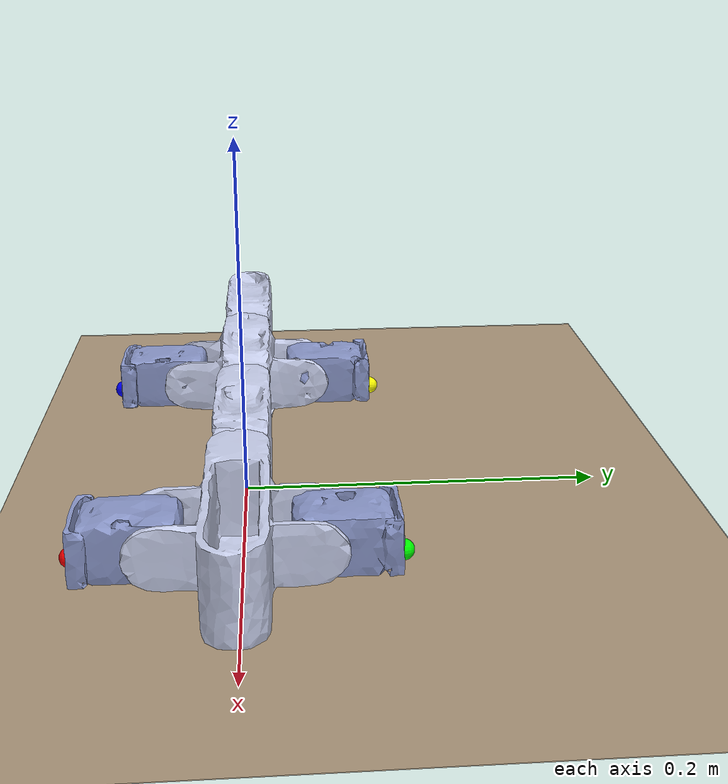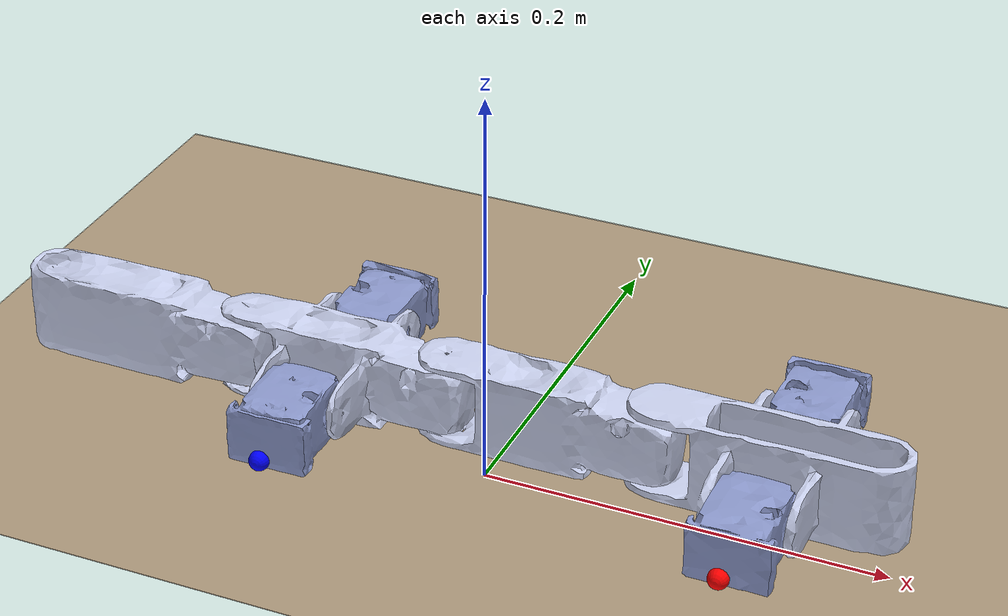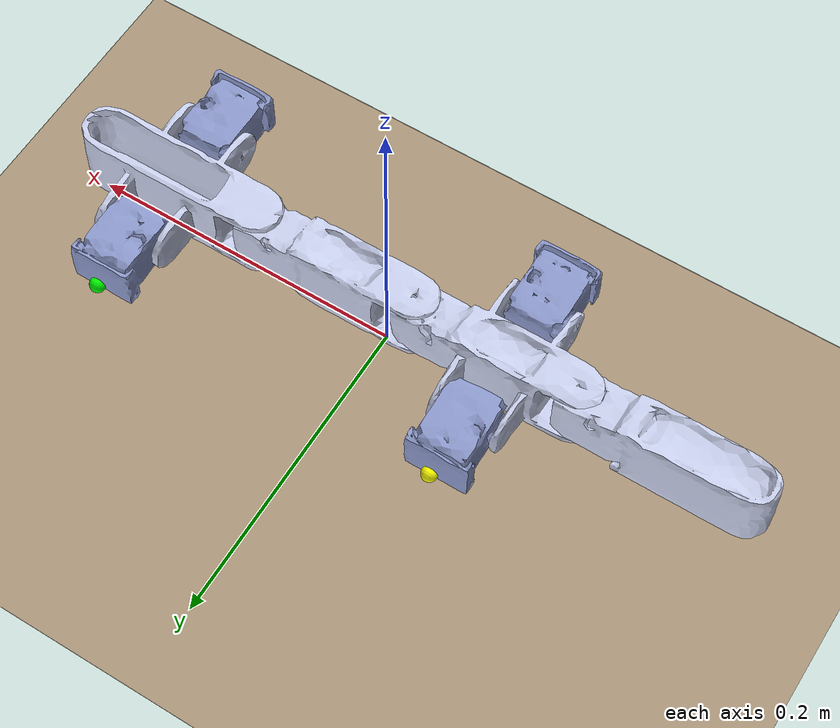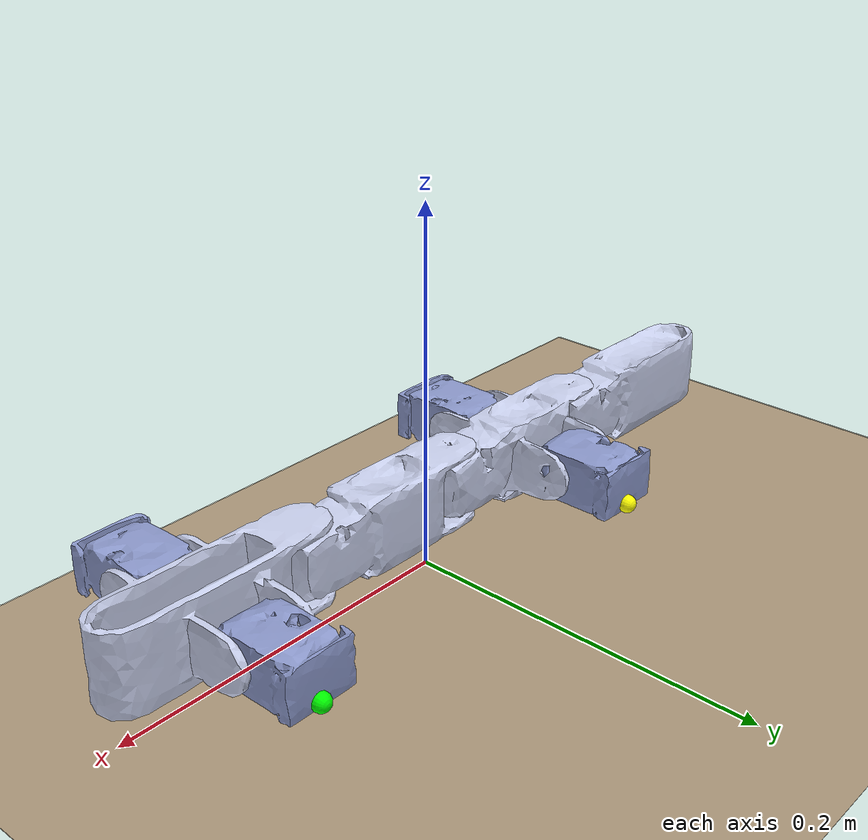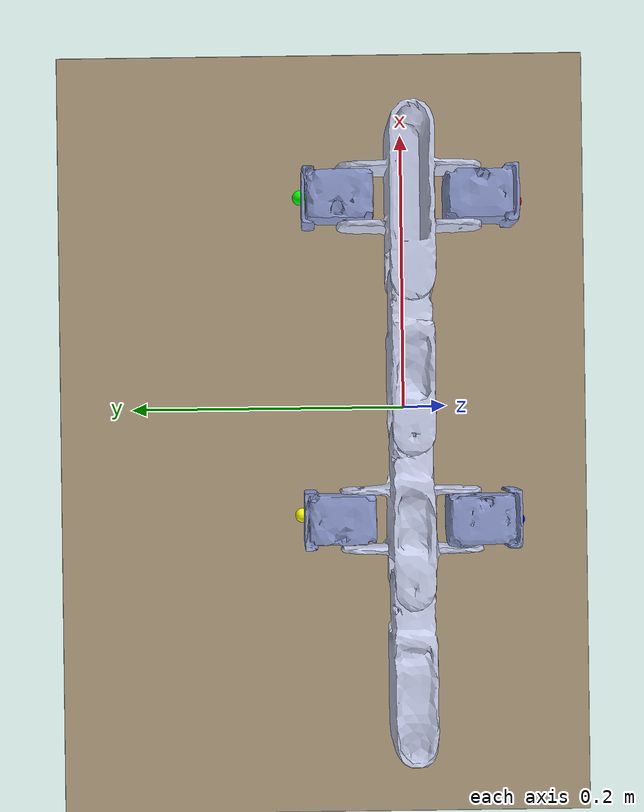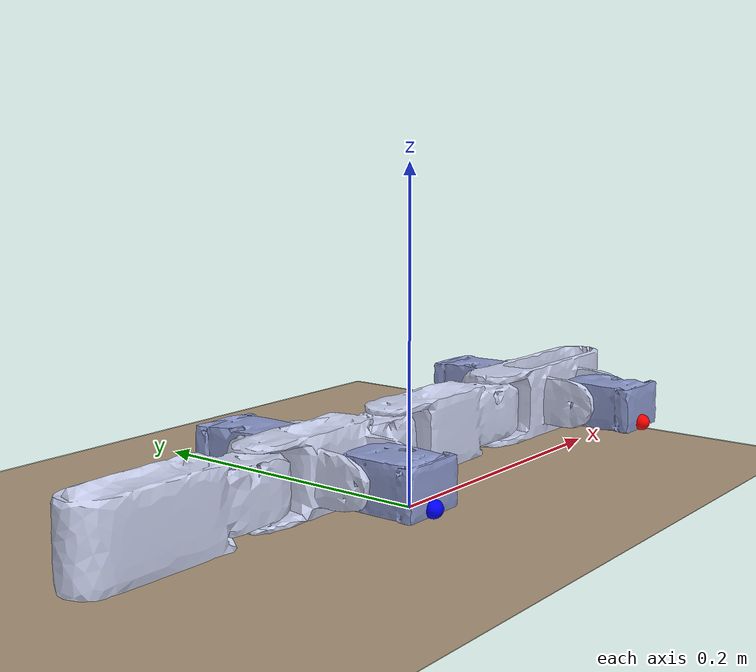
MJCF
<mujoco model="lizard_sand">

  <compiler angle="radian" meshdir="asset"/>
  <option timestep="5e-4" integrator="implicitfast" cone="elliptic" gravity="0 0 -9.81"/>

  <visual>
    <headlight ambient="0.4 0.4 0.4" diffuse="0.6 0.6 0.6"/>
    <map znear="0.001"/>
    <quality shadowsize="4096"/>
    <global offwidth="1280" offheight="720"/>
  </visual>

  <asset>
    <texture type="skybox" builtin="gradient" rgb1="0.6 0.75 0.9" rgb2="0.9 0.95 1.0" width="256" height="256"/>
    <material name="body_mat" rgba="0.792 0.820 0.933 1"/>
    <material name="leg_mat" rgba="0.55 0.60 0.80 1"/>
    <mesh name="Mid"   content_type="model/stl" file="Mid.STL"/>
    <mesh name="Front" content_type="model/stl" file="Front.STL"/>
    <mesh name="FR"    content_type="model/stl" file="FR.STL"/>
    <mesh name="FL"    content_type="model/stl" file="FL.STL"/>
    <mesh name="Back"  content_type="model/stl" file="Back.STL"/>
    <mesh name="HR"    content_type="model/stl" file="HR.STL"/>
    <mesh name="HL"    content_type="model/stl" file="HL.STL"/>
    <mesh name="Tail"  content_type="model/stl" file="Tail.STL"/>
  </asset>

  <default>
    <joint type="hinge" damping="0.005" armature="0.002" frictionloss="0.01"/>
    <geom type="mesh" material="body_mat" friction="1.0 0.005 0.0001" condim="3"
          solref="0.002 1" solimp="0.9 0.95 0.001"/>
    <position kp="5.0" kv="0.08" forcerange="-1.4 1.4"/>
  </default>

  <worldbody>
    <light directional="true" pos="0.5 -0.5 1.5" dir="-0.3 0.3 -1" castshadow="true"/>

    <!-- Visible sand surface. It must not generate rigid contact. -->
    <geom name="sand_visual" type="plane" pos="0 0 0" size="5 5 0.05"
          rgba="0.68 0.6 0.49 0.35" contype="0" conaffinity="0"/>

    <!-- Emergency floor only: catches a failed simulation far below the sand. -->
    <geom name="floor" type="plane" pos="0 0 -0.25" size="5 5 0.05"
          rgba="0.35 0.3 0.25 1" friction="1.0 0.005 0.0001"/>

    <!-- RFT applies granular forces to triangle centroids below z = 0. -->
    <site name="sand_height" pos="0 0 0" size="0.7 0.7 0.0001"
          rgba="0.68 0.6 0.49 0.25" type="box"/>

    <camera name="track_side" mode="trackcom" pos="0.05 -0.65 0.35" xyaxes="1 0 0 0 0.5 0.9"/>
    <camera name="track_top"  mode="trackcom" pos="0 0 0.9" xyaxes="1 0 0 0 1 0"/>
    <camera name="diag"       mode="trackcom" pos="0.4 -0.4 0.35" xyaxes="0.7 0.7 0 -0.3 0.3 0.9"/>

    <body name="Mid" pos="0 0 0.042">
      <freejoint name="root"/>
      <site name="imu" pos="0.046 0 0" size="0.004" rgba="1 0 0 0.5"/>
      <inertial pos="0.0460664 -0.000153726 4.25496e-05" quat="0.486405 0.513301 0.513274 0.486294"
                mass="0.0898677" diaginertia="4.51353e-05 4.07987e-05 2.0249e-05"/>
      <geom name="Mid" mesh="Mid"/>
            <site name="force_Mid_site_0" pos="0 0 0.000001" size="0.002" type="sphere" rgba="1 1 1 1" group="5"/>
      <site name="force_Mid_site_1" pos="0 0 0.000001" size="0.002" type="sphere" rgba="1 1 1 1" group="5"/>
      <site name="force_Mid_site_2" pos="0 0 0.000001" size="0.002" type="sphere" rgba="1 1 1 1" group="5"/>
      <site name="force_Mid_site_3" pos="0 0 0.000001" size="0.002" type="sphere" rgba="1 1 1 1" group="5"/>
      <site name="force_Mid_site_4" pos="0 0 0.000001" size="0.002" type="sphere" rgba="1 1 1 1" group="5"/>
      <site name="force_Mid_site_5" pos="0 0 0.000001" size="0.002" type="sphere" rgba="1 1 1 1" group="5"/>
      <site name="force_Mid_site_6" pos="0 0 0.000001" size="0.002" type="sphere" rgba="1 1 1 1" group="5"/>
      <site name="force_Mid_site_7" pos="0 0 0.000001" size="0.002" type="sphere" rgba="1 1 1 1" group="5"/>
      <site name="force_Mid_site_8" pos="0 0 0.000001" size="0.002" type="sphere" rgba="1 1 1 1" group="5"/>
      <site name="force_Mid_site_9" pos="0 0 0.000001" size="0.002" type="sphere" rgba="1 1 1 1" group="5"/>
      <site name="force_Mid_site_10" pos="0 0 0.000001" size="0.002" type="sphere" rgba="1 1 1 1" group="5"/>
      <site name="force_Mid_site_11" pos="0 0 0.000001" size="0.002" type="sphere" rgba="1 1 1 1" group="5"/>
      <site name="force_Mid_site_12" pos="0 0 0.000001" size="0.002" type="sphere" rgba="1 1 1 1" group="5"/>
      <site name="force_Mid_site_13" pos="0 0 0.000001" size="0.002" type="sphere" rgba="1 1 1 1" group="5"/>
      <site name="force_Mid_site_14" pos="0 0 0.000001" size="0.002" type="sphere" rgba="1 1 1 1" group="5"/>
      <site name="force_Mid_site_15" pos="0 0 0.000001" size="0.002" type="sphere" rgba="1 1 1 1" group="5"/>
      <site name="force_Mid_site_16" pos="0 0 0.000001" size="0.002" type="sphere" rgba="1 1 1 1" group="5"/>
      <site name="force_Mid_site_17" pos="0 0 0.000001" size="0.002" type="sphere" rgba="1 1 1 1" group="5"/>
      <site name="force_Mid_site_18" pos="0 0 0.000001" size="0.002" type="sphere" rgba="1 1 1 1" group="5"/>
      <site name="force_Mid_site_19" pos="0 0 0.000001" size="0.002" type="sphere" rgba="1 1 1 1" group="5"/>
      <site name="force_Mid_site_20" pos="0 0 0.000001" size="0.002" type="sphere" rgba="1 1 1 1" group="5"/>
      <site name="force_Mid_site_21" pos="0 0 0.000001" size="0.002" type="sphere" rgba="1 1 1 1" group="5"/>
      <site name="force_Mid_site_22" pos="0 0 0.000001" size="0.002" type="sphere" rgba="1 1 1 1" group="5"/>
      <site name="force_Mid_site_23" pos="0 0 0.000001" size="0.002" type="sphere" rgba="1 1 1 1" group="5"/>
      <site name="force_Mid_site_24" pos="0 0 0.000001" size="0.002" type="sphere" rgba="1 1 1 1" group="5"/>
      <site name="force_Mid_site_25" pos="0 0 0.000001" size="0.002" type="sphere" rgba="1 1 1 1" group="5"/>
      <site name="force_Mid_site_26" pos="0 0 0.000001" size="0.002" type="sphere" rgba="1 1 1 1" group="5"/>
      <site name="force_Mid_site_27" pos="0 0 0.000001" size="0.002" type="sphere" rgba="1 1 1 1" group="5"/>
      <site name="force_Mid_site_28" pos="0 0 0.000001" size="0.002" type="sphere" rgba="1 1 1 1" group="5"/>
      <site name="force_Mid_site_29" pos="0 0 0.000001" size="0.002" type="sphere" rgba="1 1 1 1" group="5"/>
      <site name="force_Mid_site_30" pos="0 0 0.000001" size="0.002" type="sphere" rgba="1 1 1 1" group="5"/>
      <site name="force_Mid_site_31" pos="0 0 0.000001" size="0.002" type="sphere" rgba="1 1 1 1" group="5"/>
      <site name="force_Mid_site_32" pos="0 0 0.000001" size="0.002" type="sphere" rgba="1 1 1 1" group="5"/>
      <site name="force_Mid_site_33" pos="0 0 0.000001" size="0.002" type="sphere" rgba="1 1 1 1" group="5"/>
      <site name="force_Mid_site_34" pos="0 0 0.000001" size="0.002" type="sphere" rgba="1 1 1 1" group="5"/>
      <site name="force_Mid_site_35" pos="0 0 0.000001" size="0.002" type="sphere" rgba="1 1 1 1" group="5"/>
      <site name="force_Mid_site_36" pos="0 0 0.000001" size="0.002" type="sphere" rgba="1 1 1 1" group="5"/>
      <site name="force_Mid_site_37" pos="0 0 0.000001" size="0.002" type="sphere" rgba="1 1 1 1" group="5"/>
      <site name="force_Mid_site_38" pos="0 0 0.000001" size="0.002" type="sphere" rgba="1 1 1 1" group="5"/>
      <site name="force_Mid_site_39" pos="0 0 0.000001" size="0.002" type="sphere" rgba="1 1 1 1" group="5"/>
      <site name="force_Mid_site_40" pos="0 0 0.000001" size="0.002" type="sphere" rgba="1 1 1 1" group="5"/>
      <site name="force_Mid_site_41" pos="0 0 0.000001" size="0.002" type="sphere" rgba="1 1 1 1" group="5"/>
      <site name="force_Mid_site_42" pos="0 0 0.000001" size="0.002" type="sphere" rgba="1 1 1 1" group="5"/>
      <site name="force_Mid_site_43" pos="0 0 0.000001" size="0.002" type="sphere" rgba="1 1 1 1" group="5"/>
      <site name="force_Mid_site_44" pos="0 0 0.000001" size="0.002" type="sphere" rgba="1 1 1 1" group="5"/>
      <site name="force_Mid_site_45" pos="0 0 0.000001" size="0.002" type="sphere" rgba="1 1 1 1" group="5"/>
      <site name="force_Mid_site_46" pos="0 0 0.000001" size="0.002" type="sphere" rgba="1 1 1 1" group="5"/>
      <site name="force_Mid_site_47" pos="0 0 0.000001" size="0.002" type="sphere" rgba="1 1 1 1" group="5"/>
      <site name="force_Mid_site_48" pos="0 0 0.000001" size="0.002" type="sphere" rgba="1 1 1 1" group="5"/>
      <site name="force_Mid_site_49" pos="0 0 0.000001" size="0.002" type="sphere" rgba="1 1 1 1" group="5"/>
      <site name="force_Mid_site_50" pos="0 0 0.000001" size="0.002" type="sphere" rgba="1 1 1 1" group="5"/>
      <site name="force_Mid_site_51" pos="0 0 0.000001" size="0.002" type="sphere" rgba="1 1 1 1" group="5"/>
      <site name="force_Mid_site_52" pos="0 0 0.000001" size="0.002" type="sphere" rgba="1 1 1 1" group="5"/>
      <site name="force_Mid_site_53" pos="0 0 0.000001" size="0.002" type="sphere" rgba="1 1 1 1" group="5"/>
      <site name="force_Mid_site_54" pos="0 0 0.000001" size="0.002" type="sphere" rgba="1 1 1 1" group="5"/>
      <site name="force_Mid_site_55" pos="0 0 0.000001" size="0.002" type="sphere" rgba="1 1 1 1" group="5"/>
      <site name="force_Mid_site_56" pos="0 0 0.000001" size="0.002" type="sphere" rgba="1 1 1 1" group="5"/>
      <site name="force_Mid_site_57" pos="0 0 0.000001" size="0.002" type="sphere" rgba="1 1 1 1" group="5"/>
      <site name="force_Mid_site_58" pos="0 0 0.000001" size="0.002" type="sphere" rgba="1 1 1 1" group="5"/>
      <site name="force_Mid_site_59" pos="0 0 0.000001" size="0.002" type="sphere" rgba="1 1 1 1" group="5"/>
      <site name="force_Mid_site_60" pos="0 0 0.000001" size="0.002" type="sphere" rgba="1 1 1 1" group="5"/>
      <site name="force_Mid_site_61" pos="0 0 0.000001" size="0.002" type="sphere" rgba="1 1 1 1" group="5"/>
      <site name="force_Mid_site_62" pos="0 0 0.000001" size="0.002" type="sphere" rgba="1 1 1 1" group="5"/>
      <site name="force_Mid_site_63" pos="0 0 0.000001" size="0.002" type="sphere" rgba="1 1 1 1" group="5"/>
      <site name="force_Mid_site_64" pos="0 0 0.000001" size="0.002" type="sphere" rgba="1 1 1 1" group="5"/>
      <site name="force_Mid_site_65" pos="0 0 0.000001" size="0.002" type="sphere" rgba="1 1 1 1" group="5"/>
      <site name="force_Mid_site_66" pos="0 0 0.000001" size="0.002" type="sphere" rgba="1 1 1 1" group="5"/>
      <site name="force_Mid_site_67" pos="0 0 0.000001" size="0.002" type="sphere" rgba="1 1 1 1" group="5"/>
      <site name="force_Mid_site_68" pos="0 0 0.000001" size="0.002" type="sphere" rgba="1 1 1 1" group="5"/>
      <site name="force_Mid_site_69" pos="0 0 0.000001" size="0.002" type="sphere" rgba="1 1 1 1" group="5"/>
      <site name="force_Mid_site_70" pos="0 0 0.000001" size="0.002" type="sphere" rgba="1 1 1 1" group="5"/>
      <site name="force_Mid_site_71" pos="0 0 0.000001" size="0.002" type="sphere" rgba="1 1 1 1" group="5"/>
      <site name="force_Mid_site_72" pos="0 0 0.000001" size="0.002" type="sphere" rgba="1 1 1 1" group="5"/>
      <site name="force_Mid_site_73" pos="0 0 0.000001" size="0.002" type="sphere" rgba="1 1 1 1" group="5"/>
      <site name="force_Mid_site_74" pos="0 0 0.000001" size="0.002" type="sphere" rgba="1 1 1 1" group="5"/>
      <site name="force_Mid_site_75" pos="0 0 0.000001" size="0.002" type="sphere" rgba="1 1 1 1" group="5"/>
      <site name="force_Mid_site_76" pos="0 0 0.000001" size="0.002" type="sphere" rgba="1 1 1 1" group="5"/>
      <site name="force_Mid_site_77" pos="0 0 0.000001" size="0.002" type="sphere" rgba="1 1 1 1" group="5"/>
      <site name="force_Mid_site_78" pos="0 0 0.000001" size="0.002" type="sphere" rgba="1 1 1 1" group="5"/>
      <site name="force_Mid_site_79" pos="0 0 0.000001" size="0.002" type="sphere" rgba="1 1 1 1" group="5"/>
      <site name="force_Mid_site_80" pos="0 0 0.000001" size="0.002" type="sphere" rgba="1 1 1 1" group="5"/>
      <site name="force_Mid_site_81" pos="0 0 0.000001" size="0.002" type="sphere" rgba="1 1 1 1" group="5"/>
      <site name="force_Mid_site_82" pos="0 0 0.000001" size="0.002" type="sphere" rgba="1 1 1 1" group="5"/>
      <site name="force_Mid_site_83" pos="0 0 0.000001" size="0.002" type="sphere" rgba="1 1 1 1" group="5"/>
      <site name="force_Mid_site_84" pos="0 0 0.000001" size="0.002" type="sphere" rgba="1 1 1 1" group="5"/>
      <site name="force_Mid_site_85" pos="0 0 0.000001" size="0.002" type="sphere" rgba="1 1 1 1" group="5"/>
      <site name="force_Mid_site_86" pos="0 0 0.000001" size="0.002" type="sphere" rgba="1 1 1 1" group="5"/>
      <site name="force_Mid_site_87" pos="0 0 0.000001" size="0.002" type="sphere" rgba="1 1 1 1" group="5"/>
      <site name="force_Mid_site_88" pos="0 0 0.000001" size="0.002" type="sphere" rgba="1 1 1 1" group="5"/>
      <site name="force_Mid_site_89" pos="0 0 0.000001" size="0.002" type="sphere" rgba="1 1 1 1" group="5"/>
      <site name="force_Mid_site_90" pos="0 0 0.000001" size="0.002" type="sphere" rgba="1 1 1 1" group="5"/>
      <site name="force_Mid_site_91" pos="0 0 0.000001" size="0.002" type="sphere" rgba="1 1 1 1" group="5"/>
      <site name="force_Mid_site_92" pos="0 0 0.000001" size="0.002" type="sphere" rgba="1 1 1 1" group="5"/>
      <site name="force_Mid_site_93" pos="0 0 0.000001" size="0.002" type="sphere" rgba="1 1 1 1" group="5"/>
      <site name="force_Mid_site_94" pos="0 0 0.000001" size="0.002" type="sphere" rgba="1 1 1 1" group="5"/>
      <site name="force_Mid_site_95" pos="0 0 0.000001" size="0.002" type="sphere" rgba="1 1 1 1" group="5"/>
      <site name="force_Mid_site_96" pos="0 0 0.000001" size="0.002" type="sphere" rgba="1 1 1 1" group="5"/>
      <site name="force_Mid_site_97" pos="0 0 0.000001" size="0.002" type="sphere" rgba="1 1 1 1" group="5"/>
      <site name="force_Mid_site_98" pos="0 0 0.000001" size="0.002" type="sphere" rgba="1 1 1 1" group="5"/>
      <site name="force_Mid_site_99" pos="0 0 0.000001" size="0.002" type="sphere" rgba="1 1 1 1" group="5"/>
      <site name="force_Mid_site_100" pos="0 0 0.000001" size="0.002" type="sphere" rgba="1 1 1 1" group="5"/>
      <site name="force_Mid_site_101" pos="0 0 0.000001" size="0.002" type="sphere" rgba="1 1 1 1" group="5"/>
      <site name="force_Mid_site_102" pos="0 0 0.000001" size="0.002" type="sphere" rgba="1 1 1 1" group="5"/>
      <site name="force_Mid_site_103" pos="0 0 0.000001" size="0.002" type="sphere" rgba="1 1 1 1" group="5"/>
      <site name="force_Mid_site_104" pos="0 0 0.000001" size="0.002" type="sphere" rgba="1 1 1 1" group="5"/>
      <site name="force_Mid_site_105" pos="0 0 0.000001" size="0.002" type="sphere" rgba="1 1 1 1" group="5"/>
      <site name="force_Mid_site_106" pos="0 0 0.000001" size="0.002" type="sphere" rgba="1 1 1 1" group="5"/>
      <site name="force_Mid_site_107" pos="0 0 0.000001" size="0.002" type="sphere" rgba="1 1 1 1" group="5"/>
      <site name="force_Mid_site_108" pos="0 0 0.000001" size="0.002" type="sphere" rgba="1 1 1 1" group="5"/>
      <site name="force_Mid_site_109" pos="0 0 0.000001" size="0.002" type="sphere" rgba="1 1 1 1" group="5"/>
      <site name="force_Mid_site_110" pos="0 0 0.000001" size="0.002" type="sphere" rgba="1 1 1 1" group="5"/>
      <site name="force_Mid_site_111" pos="0 0 0.000001" size="0.002" type="sphere" rgba="1 1 1 1" group="5"/>
      <site name="force_Mid_site_112" pos="0 0 0.000001" size="0.002" type="sphere" rgba="1 1 1 1" group="5"/>
      <site name="force_Mid_site_113" pos="0 0 0.000001" size="0.002" type="sphere" rgba="1 1 1 1" group="5"/>
      <site name="force_Mid_site_114" pos="0 0 0.000001" size="0.002" type="sphere" rgba="1 1 1 1" group="5"/>
      <site name="force_Mid_site_115" pos="0 0 0.000001" size="0.002" type="sphere" rgba="1 1 1 1" group="5"/>
      <site name="force_Mid_site_116" pos="0 0 0.000001" size="0.002" type="sphere" rgba="1 1 1 1" group="5"/>
      <site name="force_Mid_site_117" pos="0 0 0.000001" size="0.002" type="sphere" rgba="1 1 1 1" group="5"/>
      <site name="force_Mid_site_118" pos="0 0 0.000001" size="0.002" type="sphere" rgba="1 1 1 1" group="5"/>
      <site name="force_Mid_site_119" pos="0 0 0.000001" size="0.002" type="sphere" rgba="1 1 1 1" group="5"/>
      <site name="force_Mid_site_120" pos="0 0 0.000001" size="0.002" type="sphere" rgba="1 1 1 1" group="5"/>
      <site name="force_Mid_site_121" pos="0 0 0.000001" size="0.002" type="sphere" rgba="1 1 1 1" group="5"/>
      <site name="force_Mid_site_122" pos="0 0 0.000001" size="0.002" type="sphere" rgba="1 1 1 1" group="5"/>
      <site name="force_Mid_site_123" pos="0 0 0.000001" size="0.002" type="sphere" rgba="1 1 1 1" group="5"/>
      <site name="force_Mid_site_124" pos="0 0 0.000001" size="0.002" type="sphere" rgba="1 1 1 1" group="5"/>
      <site name="force_Mid_site_125" pos="0 0 0.000001" size="0.002" type="sphere" rgba="1 1 1 1" group="5"/>
      <site name="force_Mid_site_126" pos="0 0 0.000001" size="0.002" type="sphere" rgba="1 1 1 1" group="5"/>
      <site name="force_Mid_site_127" pos="0 0 0.000001" size="0.002" type="sphere" rgba="1 1 1 1" group="5"/>
      <site name="force_Mid_site_128" pos="0 0 0.000001" size="0.002" type="sphere" rgba="1 1 1 1" group="5"/>
      <site name="force_Mid_site_129" pos="0 0 0.000001" size="0.002" type="sphere" rgba="1 1 1 1" group="5"/>
      <site name="force_Mid_site_130" pos="0 0 0.000001" size="0.002" type="sphere" rgba="1 1 1 1" group="5"/>
      <site name="force_Mid_site_131" pos="0 0 0.000001" size="0.002" type="sphere" rgba="1 1 1 1" group="5"/>
      <site name="force_Mid_site_132" pos="0 0 0.000001" size="0.002" type="sphere" rgba="1 1 1 1" group="5"/>
      <site name="force_Mid_site_133" pos="0 0 0.000001" size="0.002" type="sphere" rgba="1 1 1 1" group="5"/>
      <site name="force_Mid_site_134" pos="0 0 0.000001" size="0.002" type="sphere" rgba="1 1 1 1" group="5"/>
      <site name="force_Mid_site_135" pos="0 0 0.000001" size="0.002" type="sphere" rgba="1 1 1 1" group="5"/>
      <site name="force_Mid_site_136" pos="0 0 0.000001" size="0.002" type="sphere" rgba="1 1 1 1" group="5"/>
      <site name="force_Mid_site_137" pos="0 0 0.000001" size="0.002" type="sphere" rgba="1 1 1 1" group="5"/>
      <site name="force_Mid_site_138" pos="0 0 0.000001" size="0.002" type="sphere" rgba="1 1 1 1" group="5"/>
      <site name="force_Mid_site_139" pos="0 0 0.000001" size="0.002" type="sphere" rgba="1 1 1 1" group="5"/>
      <site name="force_Mid_site_140" pos="0 0 0.000001" size="0.002" type="sphere" rgba="1 1 1 1" group="5"/>
      <site name="force_Mid_site_141" pos="0 0 0.000001" size="0.002" type="sphere" rgba="1 1 1 1" group="5"/>
      <site name="force_Mid_site_142" pos="0 0 0.000001" size="0.002" type="sphere" rgba="1 1 1 1" group="5"/>
      <site name="force_Mid_site_143" pos="0 0 0.000001" size="0.002" type="sphere" rgba="1 1 1 1" group="5"/>
      <site name="force_Mid_site_144" pos="0 0 0.000001" size="0.002" type="sphere" rgba="1 1 1 1" group="5"/>
      <site name="force_Mid_site_145" pos="0 0 0.000001" size="0.002" type="sphere" rgba="1 1 1 1" group="5"/>
      <site name="force_Mid_site_146" pos="0 0 0.000001" size="0.002" type="sphere" rgba="1 1 1 1" group="5"/>
      <site name="force_Mid_site_147" pos="0 0 0.000001" size="0.002" type="sphere" rgba="1 1 1 1" group="5"/>
      <site name="force_Mid_site_148" pos="0 0 0.000001" size="0.002" type="sphere" rgba="1 1 1 1" group="5"/>
      <site name="force_Mid_site_149" pos="0 0 0.000001" size="0.002" type="sphere" rgba="1 1 1 1" group="5"/>
      <site name="force_Mid_site_150" pos="0 0 0.000001" size="0.002" type="sphere" rgba="1 1 1 1" group="5"/>
      <site name="force_Mid_site_151" pos="0 0 0.000001" size="0.002" type="sphere" rgba="1 1 1 1" group="5"/>
      <site name="force_Mid_site_152" pos="0 0 0.000001" size="0.002" type="sphere" rgba="1 1 1 1" group="5"/>
      <site name="force_Mid_site_153" pos="0 0 0.000001" size="0.002" type="sphere" rgba="1 1 1 1" group="5"/>
      <site name="force_Mid_site_154" pos="0 0 0.000001" size="0.002" type="sphere" rgba="1 1 1 1" group="5"/>
      <site name="force_Mid_site_155" pos="0 0 0.000001" size="0.002" type="sphere" rgba="1 1 1 1" group="5"/>
      <site name="force_Mid_site_156" pos="0 0 0.000001" size="0.002" type="sphere" rgba="1 1 1 1" group="5"/>
      <site name="force_Mid_site_157" pos="0 0 0.000001" size="0.002" type="sphere" rgba="1 1 1 1" group="5"/>
      <site name="force_Mid_site_158" pos="0 0 0.000001" size="0.002" type="sphere" rgba="1 1 1 1" group="5"/>
      <site name="force_Mid_site_159" pos="0 0 0.000001" size="0.002" type="sphere" rgba="1 1 1 1" group="5"/>
      <site name="force_Mid_site_160" pos="0 0 0.000001" size="0.002" type="sphere" rgba="1 1 1 1" group="5"/>
      <site name="force_Mid_site_161" pos="0 0 0.000001" size="0.002" type="sphere" rgba="1 1 1 1" group="5"/>
      <site name="force_Mid_site_162" pos="0 0 0.000001" size="0.002" type="sphere" rgba="1 1 1 1" group="5"/>
      <site name="force_Mid_site_163" pos="0 0 0.000001" size="0.002" type="sphere" rgba="1 1 1 1" group="5"/>
      <site name="force_Mid_site_164" pos="0 0 0.000001" size="0.002" type="sphere" rgba="1 1 1 1" group="5"/>
      <site name="force_Mid_site_165" pos="0 0 0.000001" size="0.002" type="sphere" rgba="1 1 1 1" group="5"/>
      <site name="force_Mid_site_166" pos="0 0 0.000001" size="0.002" type="sphere" rgba="1 1 1 1" group="5"/>
      <site name="force_Mid_site_167" pos="0 0 0.000001" size="0.002" type="sphere" rgba="1 1 1 1" group="5"/>
      <site name="force_Mid_site_168" pos="0 0 0.000001" size="0.002" type="sphere" rgba="1 1 1 1" group="5"/>
      <site name="force_Mid_site_169" pos="0 0 0.000001" size="0.002" type="sphere" rgba="1 1 1 1" group="5"/>
      <site name="force_Mid_site_170" pos="0 0 0.000001" size="0.002" type="sphere" rgba="1 1 1 1" group="5"/>
      <site name="force_Mid_site_171" pos="0 0 0.000001" size="0.002" type="sphere" rgba="1 1 1 1" group="5"/>
      <site name="force_Mid_site_172" pos="0 0 0.000001" size="0.002" type="sphere" rgba="1 1 1 1" group="5"/>
      <site name="force_Mid_site_173" pos="0 0 0.000001" size="0.002" type="sphere" rgba="1 1 1 1" group="5"/>
      <site name="force_Mid_site_174" pos="0 0 0.000001" size="0.002" type="sphere" rgba="1 1 1 1" group="5"/>
      <site name="force_Mid_site_175" pos="0 0 0.000001" size="0.002" type="sphere" rgba="1 1 1 1" group="5"/>
      <site name="force_Mid_site_176" pos="0 0 0.000001" size="0.002" type="sphere" rgba="1 1 1 1" group="5"/>
      <site name="force_Mid_site_177" pos="0 0 0.000001" size="0.002" type="sphere" rgba="1 1 1 1" group="5"/>
      <site name="force_Mid_site_178" pos="0 0 0.000001" size="0.002" type="sphere" rgba="1 1 1 1" group="5"/>
      <site name="force_Mid_site_179" pos="0 0 0.000001" size="0.002" type="sphere" rgba="1 1 1 1" group="5"/>
      <site name="force_Mid_site_180" pos="0 0 0.000001" size="0.002" type="sphere" rgba="1 1 1 1" group="5"/>
      <site name="force_Mid_site_181" pos="0 0 0.000001" size="0.002" type="sphere" rgba="1 1 1 1" group="5"/>
      <site name="force_Mid_site_182" pos="0 0 0.000001" size="0.002" type="sphere" rgba="1 1 1 1" group="5"/>
      <site name="force_Mid_site_183" pos="0 0 0.000001" size="0.002" type="sphere" rgba="1 1 1 1" group="5"/>
      <site name="force_Mid_site_184" pos="0 0 0.000001" size="0.002" type="sphere" rgba="1 1 1 1" group="5"/>
      <site name="force_Mid_site_185" pos="0 0 0.000001" size="0.002" type="sphere" rgba="1 1 1 1" group="5"/>
      <site name="force_Mid_site_186" pos="0 0 0.000001" size="0.002" type="sphere" rgba="1 1 1 1" group="5"/>
      <site name="force_Mid_site_187" pos="0 0 0.000001" size="0.002" type="sphere" rgba="1 1 1 1" group="5"/>
      <site name="force_Mid_site_188" pos="0 0 0.000001" size="0.002" type="sphere" rgba="1 1 1 1" group="5"/>
      <site name="force_Mid_site_189" pos="0 0 0.000001" size="0.002" type="sphere" rgba="1 1 1 1" group="5"/>
      <site name="force_Mid_site_190" pos="0 0 0.000001" size="0.002" type="sphere" rgba="1 1 1 1" group="5"/>
      <site name="force_Mid_site_191" pos="0 0 0.000001" size="0.002" type="sphere" rgba="1 1 1 1" group="5"/>
      <site name="force_Mid_site_192" pos="0 0 0.000001" size="0.002" type="sphere" rgba="1 1 1 1" group="5"/>
      <site name="force_Mid_site_193" pos="0 0 0.000001" size="0.002" type="sphere" rgba="1 1 1 1" group="5"/>
      <site name="force_Mid_site_194" pos="0 0 0.000001" size="0.002" type="sphere" rgba="1 1 1 1" group="5"/>
      <site name="force_Mid_site_195" pos="0 0 0.000001" size="0.002" type="sphere" rgba="1 1 1 1" group="5"/>
      <site name="force_Mid_site_196" pos="0 0 0.000001" size="0.002" type="sphere" rgba="1 1 1 1" group="5"/>
      <site name="force_Mid_site_197" pos="0 0 0.000001" size="0.002" type="sphere" rgba="1 1 1 1" group="5"/>
      <site name="force_Mid_site_198" pos="0 0 0.000001" size="0.002" type="sphere" rgba="1 1 1 1" group="5"/>
      <site name="force_Mid_site_199" pos="0 0 0.000001" size="0.002" type="sphere" rgba="1 1 1 1" group="5"/>
      <site name="force_Mid_site_200" pos="0 0 0.000001" size="0.002" type="sphere" rgba="1 1 1 1" group="5"/>
      <site name="force_Mid_site_201" pos="0 0 0.000001" size="0.002" type="sphere" rgba="1 1 1 1" group="5"/>
      <site name="force_Mid_site_202" pos="0 0 0.000001" size="0.002" type="sphere" rgba="1 1 1 1" group="5"/>
      <site name="force_Mid_site_203" pos="0 0 0.000001" size="0.002" type="sphere" rgba="1 1 1 1" group="5"/>
      <site name="force_Mid_site_204" pos="0 0 0.000001" size="0.002" type="sphere" rgba="1 1 1 1" group="5"/>
      <site name="force_Mid_site_205" pos="0 0 0.000001" size="0.002" type="sphere" rgba="1 1 1 1" group="5"/>
      <site name="force_Mid_site_206" pos="0 0 0.000001" size="0.002" type="sphere" rgba="1 1 1 1" group="5"/>
      <site name="force_Mid_site_207" pos="0 0 0.000001" size="0.002" type="sphere" rgba="1 1 1 1" group="5"/>
      <site name="force_Mid_site_208" pos="0 0 0.000001" size="0.002" type="sphere" rgba="1 1 1 1" group="5"/>
      <site name="force_Mid_site_209" pos="0 0 0.000001" size="0.002" type="sphere" rgba="1 1 1 1" group="5"/>
      <site name="force_Mid_site_210" pos="0 0 0.000001" size="0.002" type="sphere" rgba="1 1 1 1" group="5"/>
      <site name="force_Mid_site_211" pos="0 0 0.000001" size="0.002" type="sphere" rgba="1 1 1 1" group="5"/>
      <site name="force_Mid_site_212" pos="0 0 0.000001" size="0.002" type="sphere" rgba="1 1 1 1" group="5"/>
      <site name="force_Mid_site_213" pos="0 0 0.000001" size="0.002" type="sphere" rgba="1 1 1 1" group="5"/>
      <site name="force_Mid_site_214" pos="0 0 0.000001" size="0.002" type="sphere" rgba="1 1 1 1" group="5"/>
      <site name="force_Mid_site_215" pos="0 0 0.000001" size="0.002" type="sphere" rgba="1 1 1 1" group="5"/>
      <site name="force_Mid_site_216" pos="0 0 0.000001" size="0.002" type="sphere" rgba="1 1 1 1" group="5"/>
      <site name="force_Mid_site_217" pos="0 0 0.000001" size="0.002" type="sphere" rgba="1 1 1 1" group="5"/>
      <site name="force_Mid_site_218" pos="0 0 0.000001" size="0.002" type="sphere" rgba="1 1 1 1" group="5"/>
      <site name="force_Mid_site_219" pos="0 0 0.000001" size="0.002" type="sphere" rgba="1 1 1 1" group="5"/>
      <site name="force_Mid_site_220" pos="0 0 0.000001" size="0.002" type="sphere" rgba="1 1 1 1" group="5"/>
      <site name="force_Mid_site_221" pos="0 0 0.000001" size="0.002" type="sphere" rgba="1 1 1 1" group="5"/>
      <site name="force_Mid_site_222" pos="0 0 0.000001" size="0.002" type="sphere" rgba="1 1 1 1" group="5"/>
      <site name="force_Mid_site_223" pos="0 0 0.000001" size="0.002" type="sphere" rgba="1 1 1 1" group="5"/>
      <site name="force_Mid_site_224" pos="0 0 0.000001" size="0.002" type="sphere" rgba="1 1 1 1" group="5"/>
      <site name="force_Mid_site_225" pos="0 0 0.000001" size="0.002" type="sphere" rgba="1 1 1 1" group="5"/>
      <site name="force_Mid_site_226" pos="0 0 0.000001" size="0.002" type="sphere" rgba="1 1 1 1" group="5"/>
      <site name="force_Mid_site_227" pos="0 0 0.000001" size="0.002" type="sphere" rgba="1 1 1 1" group="5"/>
      <site name="force_Mid_site_228" pos="0 0 0.000001" size="0.002" type="sphere" rgba="1 1 1 1" group="5"/>
      <site name="force_Mid_site_229" pos="0 0 0.000001" size="0.002" type="sphere" rgba="1 1 1 1" group="5"/>
      <site name="force_Mid_site_230" pos="0 0 0.000001" size="0.002" type="sphere" rgba="1 1 1 1" group="5"/>
      <site name="force_Mid_site_231" pos="0 0 0.000001" size="0.002" type="sphere" rgba="1 1 1 1" group="5"/>
      <site name="force_Mid_site_232" pos="0 0 0.000001" size="0.002" type="sphere" rgba="1 1 1 1" group="5"/>
      <site name="force_Mid_site_233" pos="0 0 0.000001" size="0.002" type="sphere" rgba="1 1 1 1" group="5"/>
      <site name="force_Mid_site_234" pos="0 0 0.000001" size="0.002" type="sphere" rgba="1 1 1 1" group="5"/>
      <site name="force_Mid_site_235" pos="0 0 0.000001" size="0.002" type="sphere" rgba="1 1 1 1" group="5"/>
      <site name="force_Mid_site_236" pos="0 0 0.000001" size="0.002" type="sphere" rgba="1 1 1 1" group="5"/>
      <site name="force_Mid_site_237" pos="0 0 0.000001" size="0.002" type="sphere" rgba="1 1 1 1" group="5"/>
      <site name="force_Mid_site_238" pos="0 0 0.000001" size="0.002" type="sphere" rgba="1 1 1 1" group="5"/>
      <site name="force_Mid_site_239" pos="0 0 0.000001" size="0.002" type="sphere" rgba="1 1 1 1" group="5"/>
      <site name="force_Mid_site_240" pos="0 0 0.000001" size="0.002" type="sphere" rgba="1 1 1 1" group="5"/>
      <site name="force_Mid_site_241" pos="0 0 0.000001" size="0.002" type="sphere" rgba="1 1 1 1" group="5"/>
      <site name="force_Mid_site_242" pos="0 0 0.000001" size="0.002" type="sphere" rgba="1 1 1 1" group="5"/>
      <site name="force_Mid_site_243" pos="0 0 0.000001" size="0.002" type="sphere" rgba="1 1 1 1" group="5"/>
      <site name="force_Mid_site_244" pos="0 0 0.000001" size="0.002" type="sphere" rgba="1 1 1 1" group="5"/>
      <site name="force_Mid_site_245" pos="0 0 0.000001" size="0.002" type="sphere" rgba="1 1 1 1" group="5"/>
      <site name="force_Mid_site_246" pos="0 0 0.000001" size="0.002" type="sphere" rgba="1 1 1 1" group="5"/>
      <site name="force_Mid_site_247" pos="0 0 0.000001" size="0.002" type="sphere" rgba="1 1 1 1" group="5"/>
      <site name="force_Mid_site_248" pos="0 0 0.000001" size="0.002" type="sphere" rgba="1 1 1 1" group="5"/>
      <site name="force_Mid_site_249" pos="0 0 0.000001" size="0.002" type="sphere" rgba="1 1 1 1" group="5"/>
      <site name="force_Mid_site_250" pos="0 0 0.000001" size="0.002" type="sphere" rgba="1 1 1 1" group="5"/>
      <site name="force_Mid_site_251" pos="0 0 0.000001" size="0.002" type="sphere" rgba="1 1 1 1" group="5"/>
      <site name="force_Mid_site_252" pos="0 0 0.000001" size="0.002" type="sphere" rgba="1 1 1 1" group="5"/>
      <site name="force_Mid_site_253" pos="0 0 0.000001" size="0.002" type="sphere" rgba="1 1 1 1" group="5"/>
      <site name="force_Mid_site_254" pos="0 0 0.000001" size="0.002" type="sphere" rgba="1 1 1 1" group="5"/>
      <site name="force_Mid_site_255" pos="0 0 0.000001" size="0.002" type="sphere" rgba="1 1 1 1" group="5"/>
      <site name="force_Mid_site_256" pos="0 0 0.000001" size="0.002" type="sphere" rgba="1 1 1 1" group="5"/>
      <site name="force_Mid_site_257" pos="0 0 0.000001" size="0.002" type="sphere" rgba="1 1 1 1" group="5"/>
      <site name="force_Mid_site_258" pos="0 0 0.000001" size="0.002" type="sphere" rgba="1 1 1 1" group="5"/>
      <site name="force_Mid_site_259" pos="0 0 0.000001" size="0.002" type="sphere" rgba="1 1 1 1" group="5"/>
      <site name="force_Mid_site_260" pos="0 0 0.000001" size="0.002" type="sphere" rgba="1 1 1 1" group="5"/>
      <site name="force_Mid_site_261" pos="0 0 0.000001" size="0.002" type="sphere" rgba="1 1 1 1" group="5"/>
      <site name="force_Mid_site_262" pos="0 0 0.000001" size="0.002" type="sphere" rgba="1 1 1 1" group="5"/>
      <site name="force_Mid_site_263" pos="0 0 0.000001" size="0.002" type="sphere" rgba="1 1 1 1" group="5"/>
      <site name="force_Mid_site_264" pos="0 0 0.000001" size="0.002" type="sphere" rgba="1 1 1 1" group="5"/>
      <site name="force_Mid_site_265" pos="0 0 0.000001" size="0.002" type="sphere" rgba="1 1 1 1" group="5"/>
      <site name="force_Mid_site_266" pos="0 0 0.000001" size="0.002" type="sphere" rgba="1 1 1 1" group="5"/>
      <site name="force_Mid_site_267" pos="0 0 0.000001" size="0.002" type="sphere" rgba="1 1 1 1" group="5"/>
      <site name="force_Mid_site_268" pos="0 0 0.000001" size="0.002" type="sphere" rgba="1 1 1 1" group="5"/>
      <site name="force_Mid_site_269" pos="0 0 0.000001" size="0.002" type="sphere" rgba="1 1 1 1" group="5"/>
      <site name="force_Mid_site_270" pos="0 0 0.000001" size="0.002" type="sphere" rgba="1 1 1 1" group="5"/>
      <site name="force_Mid_site_271" pos="0 0 0.000001" size="0.002" type="sphere" rgba="1 1 1 1" group="5"/>
      <site name="force_Mid_site_272" pos="0 0 0.000001" size="0.002" type="sphere" rgba="1 1 1 1" group="5"/>
      <site name="force_Mid_site_273" pos="0 0 0.000001" size="0.002" type="sphere" rgba="1 1 1 1" group="5"/>
      <site name="force_Mid_site_274" pos="0 0 0.000001" size="0.002" type="sphere" rgba="1 1 1 1" group="5"/>
      <site name="force_Mid_site_275" pos="0 0 0.000001" size="0.002" type="sphere" rgba="1 1 1 1" group="5"/>
      <site name="force_Mid_site_276" pos="0 0 0.000001" size="0.002" type="sphere" rgba="1 1 1 1" group="5"/>
      <site name="force_Mid_site_277" pos="0 0 0.000001" size="0.002" type="sphere" rgba="1 1 1 1" group="5"/>
      <site name="force_Mid_site_278" pos="0 0 0.000001" size="0.002" type="sphere" rgba="1 1 1 1" group="5"/>
      <site name="force_Mid_site_279" pos="0 0 0.000001" size="0.002" type="sphere" rgba="1 1 1 1" group="5"/>
      <site name="force_Mid_site_280" pos="0 0 0.000001" size="0.002" type="sphere" rgba="1 1 1 1" group="5"/>
      <site name="force_Mid_site_281" pos="0 0 0.000001" size="0.002" type="sphere" rgba="1 1 1 1" group="5"/>
      <site name="force_Mid_site_282" pos="0 0 0.000001" size="0.002" type="sphere" rgba="1 1 1 1" group="5"/>
      <site name="force_Mid_site_283" pos="0 0 0.000001" size="0.002" type="sphere" rgba="1 1 1 1" group="5"/>
      <site name="force_Mid_site_284" pos="0 0 0.000001" size="0.002" type="sphere" rgba="1 1 1 1" group="5"/>
      <site name="force_Mid_site_285" pos="0 0 0.000001" size="0.002" type="sphere" rgba="1 1 1 1" group="5"/>
      <site name="force_Mid_site_286" pos="0 0 0.000001" size="0.002" type="sphere" rgba="1 1 1 1" group="5"/>
      <site name="force_Mid_site_287" pos="0 0 0.000001" size="0.002" type="sphere" rgba="1 1 1 1" group="5"/>
      <site name="force_Mid_site_288" pos="0 0 0.000001" size="0.002" type="sphere" rgba="1 1 1 1" group="5"/>
      <site name="force_Mid_site_289" pos="0 0 0.000001" size="0.002" type="sphere" rgba="1 1 1 1" group="5"/>
      <site name="force_Mid_site_290" pos="0 0 0.000001" size="0.002" type="sphere" rgba="1 1 1 1" group="5"/>
      <site name="force_Mid_site_291" pos="0 0 0.000001" size="0.002" type="sphere" rgba="1 1 1 1" group="5"/>
      <site name="force_Mid_site_292" pos="0 0 0.000001" size="0.002" type="sphere" rgba="1 1 1 1" group="5"/>
      <site name="force_Mid_site_293" pos="0 0 0.000001" size="0.002" type="sphere" rgba="1 1 1 1" group="5"/>
      <site name="force_Mid_site_294" pos="0 0 0.000001" size="0.002" type="sphere" rgba="1 1 1 1" group="5"/>
      <site name="force_Mid_site_295" pos="0 0 0.000001" size="0.002" type="sphere" rgba="1 1 1 1" group="5"/>
      <site name="force_Mid_site_296" pos="0 0 0.000001" size="0.002" type="sphere" rgba="1 1 1 1" group="5"/>
      <site name="force_Mid_site_297" pos="0 0 0.000001" size="0.002" type="sphere" rgba="1 1 1 1" group="5"/>
      <site name="force_Mid_site_298" pos="0 0 0.000001" size="0.002" type="sphere" rgba="1 1 1 1" group="5"/>
      <site name="force_Mid_site_299" pos="0 0 0.000001" size="0.002" type="sphere" rgba="1 1 1 1" group="5"/>
      <site name="force_Mid_site_300" pos="0 0 0.000001" size="0.002" type="sphere" rgba="1 1 1 1" group="5"/>
      <site name="force_Mid_site_301" pos="0 0 0.000001" size="0.002" type="sphere" rgba="1 1 1 1" group="5"/>
      <site name="force_Mid_site_302" pos="0 0 0.000001" size="0.002" type="sphere" rgba="1 1 1 1" group="5"/>
      <site name="force_Mid_site_303" pos="0 0 0.000001" size="0.002" type="sphere" rgba="1 1 1 1" group="5"/>
      <site name="force_Mid_site_304" pos="0 0 0.000001" size="0.002" type="sphere" rgba="1 1 1 1" group="5"/>
      <site name="force_Mid_site_305" pos="0 0 0.000001" size="0.002" type="sphere" rgba="1 1 1 1" group="5"/>
      <site name="force_Mid_site_306" pos="0 0 0.000001" size="0.002" type="sphere" rgba="1 1 1 1" group="5"/>
      <site name="force_Mid_site_307" pos="0 0 0.000001" size="0.002" type="sphere" rgba="1 1 1 1" group="5"/>
      <site name="force_Mid_site_308" pos="0 0 0.000001" size="0.002" type="sphere" rgba="1 1 1 1" group="5"/>
      <site name="force_Mid_site_309" pos="0 0 0.000001" size="0.002" type="sphere" rgba="1 1 1 1" group="5"/>
      <site name="force_Mid_site_310" pos="0 0 0.000001" size="0.002" type="sphere" rgba="1 1 1 1" group="5"/>
      <site name="force_Mid_site_311" pos="0 0 0.000001" size="0.002" type="sphere" rgba="1 1 1 1" group="5"/>
      <site name="force_Mid_site_312" pos="0 0 0.000001" size="0.002" type="sphere" rgba="1 1 1 1" group="5"/>
      <site name="force_Mid_site_313" pos="0 0 0.000001" size="0.002" type="sphere" rgba="1 1 1 1" group="5"/>
      <site name="force_Mid_site_314" pos="0 0 0.000001" size="0.002" type="sphere" rgba="1 1 1 1" group="5"/>
      <site name="force_Mid_site_315" pos="0 0 0.000001" size="0.002" type="sphere" rgba="1 1 1 1" group="5"/>
      <site name="force_Mid_site_316" pos="0 0 0.000001" size="0.002" type="sphere" rgba="1 1 1 1" group="5"/>
      <site name="force_Mid_site_317" pos="0 0 0.000001" size="0.002" type="sphere" rgba="1 1 1 1" group="5"/>
      <site name="force_Mid_site_318" pos="0 0 0.000001" size="0.002" type="sphere" rgba="1 1 1 1" group="5"/>
      <site name="force_Mid_site_319" pos="0 0 0.000001" size="0.002" type="sphere" rgba="1 1 1 1" group="5"/>
      <site name="force_Mid_site_320" pos="0 0 0.000001" size="0.002" type="sphere" rgba="1 1 1 1" group="5"/>
      <site name="force_Mid_site_321" pos="0 0 0.000001" size="0.002" type="sphere" rgba="1 1 1 1" group="5"/>
      <site name="force_Mid_site_322" pos="0 0 0.000001" size="0.002" type="sphere" rgba="1 1 1 1" group="5"/>
      <site name="force_Mid_site_323" pos="0 0 0.000001" size="0.002" type="sphere" rgba="1 1 1 1" group="5"/>
      <site name="force_Mid_site_324" pos="0 0 0.000001" size="0.002" type="sphere" rgba="1 1 1 1" group="5"/>
      <site name="force_Mid_site_325" pos="0 0 0.000001" size="0.002" type="sphere" rgba="1 1 1 1" group="5"/>
      <site name="force_Mid_site_326" pos="0 0 0.000001" size="0.002" type="sphere" rgba="1 1 1 1" group="5"/>
      <site name="force_Mid_site_327" pos="0 0 0.000001" size="0.002" type="sphere" rgba="1 1 1 1" group="5"/>
      <site name="force_Mid_site_328" pos="0 0 0.000001" size="0.002" type="sphere" rgba="1 1 1 1" group="5"/>
      <site name="force_Mid_site_329" pos="0 0 0.000001" size="0.002" type="sphere" rgba="1 1 1 1" group="5"/>
      <site name="force_Mid_site_330" pos="0 0 0.000001" size="0.002" type="sphere" rgba="1 1 1 1" group="5"/>
      <site name="force_Mid_site_331" pos="0 0 0.000001" size="0.002" type="sphere" rgba="1 1 1 1" group="5"/>
      <site name="force_Mid_site_332" pos="0 0 0.000001" size="0.002" type="sphere" rgba="1 1 1 1" group="5"/>
      <site name="force_Mid_site_333" pos="0 0 0.000001" size="0.002" type="sphere" rgba="1 1 1 1" group="5"/>
      <site name="force_Mid_site_334" pos="0 0 0.000001" size="0.002" type="sphere" rgba="1 1 1 1" group="5"/>
      <site name="force_Mid_site_335" pos="0 0 0.000001" size="0.002" type="sphere" rgba="1 1 1 1" group="5"/>
      <site name="force_Mid_site_336" pos="0 0 0.000001" size="0.002" type="sphere" rgba="1 1 1 1" group="5"/>
      <site name="force_Mid_site_337" pos="0 0 0.000001" size="0.002" type="sphere" rgba="1 1 1 1" group="5"/>
      <site name="force_Mid_site_338" pos="0 0 0.000001" size="0.002" type="sphere" rgba="1 1 1 1" group="5"/>
      <site name="force_Mid_site_339" pos="0 0 0.000001" size="0.002" type="sphere" rgba="1 1 1 1" group="5"/>
      <site name="force_Mid_site_340" pos="0 0 0.000001" size="0.002" type="sphere" rgba="1 1 1 1" group="5"/>
      <site name="force_Mid_site_341" pos="0 0 0.000001" size="0.002" type="sphere" rgba="1 1 1 1" group="5"/>
      <site name="force_Mid_site_342" pos="0 0 0.000001" size="0.002" type="sphere" rgba="1 1 1 1" group="5"/>
      <site name="force_Mid_site_343" pos="0 0 0.000001" size="0.002" type="sphere" rgba="1 1 1 1" group="5"/>
      <site name="force_Mid_site_344" pos="0 0 0.000001" size="0.002" type="sphere" rgba="1 1 1 1" group="5"/>
      <site name="force_Mid_site_345" pos="0 0 0.000001" size="0.002" type="sphere" rgba="1 1 1 1" group="5"/>
      <site name="force_Mid_site_346" pos="0 0 0.000001" size="0.002" type="sphere" rgba="1 1 1 1" group="5"/>
      <site name="force_Mid_site_347" pos="0 0 0.000001" size="0.002" type="sphere" rgba="1 1 1 1" group="5"/>
      <site name="force_Mid_site_348" pos="0 0 0.000001" size="0.002" type="sphere" rgba="1 1 1 1" group="5"/>
      <site name="force_Mid_site_349" pos="0 0 0.000001" size="0.002" type="sphere" rgba="1 1 1 1" group="5"/>
      <site name="force_Mid_site_350" pos="0 0 0.000001" size="0.002" type="sphere" rgba="1 1 1 1" group="5"/>
      <site name="force_Mid_site_351" pos="0 0 0.000001" size="0.002" type="sphere" rgba="1 1 1 1" group="5"/>
      <site name="force_Mid_site_352" pos="0 0 0.000001" size="0.002" type="sphere" rgba="1 1 1 1" group="5"/>
      <site name="force_Mid_site_353" pos="0 0 0.000001" size="0.002" type="sphere" rgba="1 1 1 1" group="5"/>
      <site name="force_Mid_site_354" pos="0 0 0.000001" size="0.002" type="sphere" rgba="1 1 1 1" group="5"/>
      <site name="force_Mid_site_355" pos="0 0 0.000001" size="0.002" type="sphere" rgba="1 1 1 1" group="5"/>
      <site name="force_Mid_site_356" pos="0 0 0.000001" size="0.002" type="sphere" rgba="1 1 1 1" group="5"/>
      <site name="force_Mid_site_357" pos="0 0 0.000001" size="0.002" type="sphere" rgba="1 1 1 1" group="5"/>
      <site name="force_Mid_site_358" pos="0 0 0.000001" size="0.002" type="sphere" rgba="1 1 1 1" group="5"/>
      <site name="force_Mid_site_359" pos="0 0 0.000001" size="0.002" type="sphere" rgba="1 1 1 1" group="5"/>
      <site name="force_Mid_site_360" pos="0 0 0.000001" size="0.002" type="sphere" rgba="1 1 1 1" group="5"/>
      <site name="force_Mid_site_361" pos="0 0 0.000001" size="0.002" type="sphere" rgba="1 1 1 1" group="5"/>
      <site name="force_Mid_site_362" pos="0 0 0.000001" size="0.002" type="sphere" rgba="1 1 1 1" group="5"/>
      <site name="force_Mid_site_363" pos="0 0 0.000001" size="0.002" type="sphere" rgba="1 1 1 1" group="5"/>
      <site name="force_Mid_site_364" pos="0 0 0.000001" size="0.002" type="sphere" rgba="1 1 1 1" group="5"/>
      <site name="force_Mid_site_365" pos="0 0 0.000001" size="0.002" type="sphere" rgba="1 1 1 1" group="5"/>
      <site name="force_Mid_site_366" pos="0 0 0.000001" size="0.002" type="sphere" rgba="1 1 1 1" group="5"/>
      <site name="force_Mid_site_367" pos="0 0 0.000001" size="0.002" type="sphere" rgba="1 1 1 1" group="5"/>
      <site name="force_Mid_site_368" pos="0 0 0.000001" size="0.002" type="sphere" rgba="1 1 1 1" group="5"/>
      <site name="force_Mid_site_369" pos="0 0 0.000001" size="0.002" type="sphere" rgba="1 1 1 1" group="5"/>
      <site name="force_Mid_site_370" pos="0 0 0.000001" size="0.002" type="sphere" rgba="1 1 1 1" group="5"/>
      <site name="force_Mid_site_371" pos="0 0 0.000001" size="0.002" type="sphere" rgba="1 1 1 1" group="5"/>
      <site name="force_Mid_site_372" pos="0 0 0.000001" size="0.002" type="sphere" rgba="1 1 1 1" group="5"/>
      <site name="force_Mid_site_373" pos="0 0 0.000001" size="0.002" type="sphere" rgba="1 1 1 1" group="5"/>
      <site name="force_Mid_site_374" pos="0 0 0.000001" size="0.002" type="sphere" rgba="1 1 1 1" group="5"/>
      <site name="force_Mid_site_375" pos="0 0 0.000001" size="0.002" type="sphere" rgba="1 1 1 1" group="5"/>
      <site name="force_Mid_site_376" pos="0 0 0.000001" size="0.002" type="sphere" rgba="1 1 1 1" group="5"/>
      <site name="force_Mid_site_377" pos="0 0 0.000001" size="0.002" type="sphere" rgba="1 1 1 1" group="5"/>
      <site name="force_Mid_site_378" pos="0 0 0.000001" size="0.002" type="sphere" rgba="1 1 1 1" group="5"/>
      <site name="force_Mid_site_379" pos="0 0 0.000001" size="0.002" type="sphere" rgba="1 1 1 1" group="5"/>
      <site name="force_Mid_site_380" pos="0 0 0.000001" size="0.002" type="sphere" rgba="1 1 1 1" group="5"/>
      <site name="force_Mid_site_381" pos="0 0 0.000001" size="0.002" type="sphere" rgba="1 1 1 1" group="5"/>
      <site name="force_Mid_site_382" pos="0 0 0.000001" size="0.002" type="sphere" rgba="1 1 1 1" group="5"/>
      <site name="force_Mid_site_383" pos="0 0 0.000001" size="0.002" type="sphere" rgba="1 1 1 1" group="5"/>
      <site name="force_Mid_site_384" pos="0 0 0.000001" size="0.002" type="sphere" rgba="1 1 1 1" group="5"/>
      <site name="force_Mid_site_385" pos="0 0 0.000001" size="0.002" type="sphere" rgba="1 1 1 1" group="5"/>
      <site name="force_Mid_site_386" pos="0 0 0.000001" size="0.002" type="sphere" rgba="1 1 1 1" group="5"/>
      <site name="force_Mid_site_387" pos="0 0 0.000001" size="0.002" type="sphere" rgba="1 1 1 1" group="5"/>
      <site name="force_Mid_site_388" pos="0 0 0.000001" size="0.002" type="sphere" rgba="1 1 1 1" group="5"/>
      <site name="force_Mid_site_389" pos="0 0 0.000001" size="0.002" type="sphere" rgba="1 1 1 1" group="5"/>
      <site name="force_Mid_site_390" pos="0 0 0.000001" size="0.002" type="sphere" rgba="1 1 1 1" group="5"/>
      <site name="force_Mid_site_391" pos="0 0 0.000001" size="0.002" type="sphere" rgba="1 1 1 1" group="5"/>
      <site name="force_Mid_site_392" pos="0 0 0.000001" size="0.002" type="sphere" rgba="1 1 1 1" group="5"/>
      <site name="force_Mid_site_393" pos="0 0 0.000001" size="0.002" type="sphere" rgba="1 1 1 1" group="5"/>
      <site name="force_Mid_site_394" pos="0 0 0.000001" size="0.002" type="sphere" rgba="1 1 1 1" group="5"/>
      <site name="force_Mid_site_395" pos="0 0 0.000001" size="0.002" type="sphere" rgba="1 1 1 1" group="5"/>
      <site name="force_Mid_site_396" pos="0 0 0.000001" size="0.002" type="sphere" rgba="1 1 1 1" group="5"/>
      <site name="force_Mid_site_397" pos="0 0 0.000001" size="0.002" type="sphere" rgba="1 1 1 1" group="5"/>
      <site name="force_Mid_site_398" pos="0 0 0.000001" size="0.002" type="sphere" rgba="1 1 1 1" group="5"/>
      <site name="force_Mid_site_399" pos="0 0 0.000001" size="0.002" type="sphere" rgba="1 1 1 1" group="5"/>
      <site name="force_Mid_site_400" pos="0 0 0.000001" size="0.002" type="sphere" rgba="1 1 1 1" group="5"/>
      <site name="force_Mid_site_401" pos="0 0 0.000001" size="0.002" type="sphere" rgba="1 1 1 1" group="5"/>
      <site name="force_Mid_site_402" pos="0 0 0.000001" size="0.002" type="sphere" rgba="1 1 1 1" group="5"/>
      <site name="force_Mid_site_403" pos="0 0 0.000001" size="0.002" type="sphere" rgba="1 1 1 1" group="5"/>
      <site name="force_Mid_site_404" pos="0 0 0.000001" size="0.002" type="sphere" rgba="1 1 1 1" group="5"/>
      <site name="force_Mid_site_405" pos="0 0 0.000001" size="0.002" type="sphere" rgba="1 1 1 1" group="5"/>
      <site name="force_Mid_site_406" pos="0 0 0.000001" size="0.002" type="sphere" rgba="1 1 1 1" group="5"/>
      <site name="force_Mid_site_407" pos="0 0 0.000001" size="0.002" type="sphere" rgba="1 1 1 1" group="5"/>
      <site name="force_Mid_site_408" pos="0 0 0.000001" size="0.002" type="sphere" rgba="1 1 1 1" group="5"/>
      <site name="force_Mid_site_409" pos="0 0 0.000001" size="0.002" type="sphere" rgba="1 1 1 1" group="5"/>
      <site name="force_Mid_site_410" pos="0 0 0.000001" size="0.002" type="sphere" rgba="1 1 1 1" group="5"/>
      <site name="force_Mid_site_411" pos="0 0 0.000001" size="0.002" type="sphere" rgba="1 1 1 1" group="5"/>
      <site name="force_Mid_site_412" pos="0 0 0.000001" size="0.002" type="sphere" rgba="1 1 1 1" group="5"/>
      <site name="force_Mid_site_413" pos="0 0 0.000001" size="0.002" type="sphere" rgba="1 1 1 1" group="5"/>
      <site name="force_Mid_site_414" pos="0 0 0.000001" size="0.002" type="sphere" rgba="1 1 1 1" group="5"/>
      <site name="force_Mid_site_415" pos="0 0 0.000001" size="0.002" type="sphere" rgba="1 1 1 1" group="5"/>
      <site name="force_Mid_site_416" pos="0 0 0.000001" size="0.002" type="sphere" rgba="1 1 1 1" group="5"/>
      <site name="force_Mid_site_417" pos="0 0 0.000001" size="0.002" type="sphere" rgba="1 1 1 1" group="5"/>
      <site name="force_Mid_site_418" pos="0 0 0.000001" size="0.002" type="sphere" rgba="1 1 1 1" group="5"/>
      <site name="force_Mid_site_419" pos="0 0 0.000001" size="0.002" type="sphere" rgba="1 1 1 1" group="5"/>
      <site name="force_Mid_site_420" pos="0 0 0.000001" size="0.002" type="sphere" rgba="1 1 1 1" group="5"/>
      <site name="force_Mid_site_421" pos="0 0 0.000001" size="0.002" type="sphere" rgba="1 1 1 1" group="5"/>
      <site name="force_Mid_site_422" pos="0 0 0.000001" size="0.002" type="sphere" rgba="1 1 1 1" group="5"/>
      <site name="force_Mid_site_423" pos="0 0 0.000001" size="0.002" type="sphere" rgba="1 1 1 1" group="5"/>
      <site name="force_Mid_site_424" pos="0 0 0.000001" size="0.002" type="sphere" rgba="1 1 1 1" group="5"/>
      <site name="force_Mid_site_425" pos="0 0 0.000001" size="0.002" type="sphere" rgba="1 1 1 1" group="5"/>
      <site name="force_Mid_site_426" pos="0 0 0.000001" size="0.002" type="sphere" rgba="1 1 1 1" group="5"/>
      <site name="force_Mid_site_427" pos="0 0 0.000001" size="0.002" type="sphere" rgba="1 1 1 1" group="5"/>
      <site name="force_Mid_site_428" pos="0 0 0.000001" size="0.002" type="sphere" rgba="1 1 1 1" group="5"/>
      <site name="force_Mid_site_429" pos="0 0 0.000001" size="0.002" type="sphere" rgba="1 1 1 1" group="5"/>
      <site name="force_Mid_site_430" pos="0 0 0.000001" size="0.002" type="sphere" rgba="1 1 1 1" group="5"/>
      <site name="force_Mid_site_431" pos="0 0 0.000001" size="0.002" type="sphere" rgba="1 1 1 1" group="5"/>
      <site name="force_Mid_site_432" pos="0 0 0.000001" size="0.002" type="sphere" rgba="1 1 1 1" group="5"/>
      <site name="force_Mid_site_433" pos="0 0 0.000001" size="0.002" type="sphere" rgba="1 1 1 1" group="5"/>
      <site name="force_Mid_site_434" pos="0 0 0.000001" size="0.002" type="sphere" rgba="1 1 1 1" group="5"/>
      <site name="force_Mid_site_435" pos="0 0 0.000001" size="0.002" type="sphere" rgba="1 1 1 1" group="5"/>
      <site name="force_Mid_site_436" pos="0 0 0.000001" size="0.002" type="sphere" rgba="1 1 1 1" group="5"/>
      <site name="force_Mid_site_437" pos="0 0 0.000001" size="0.002" type="sphere" rgba="1 1 1 1" group="5"/>
      <site name="force_Mid_site_438" pos="0 0 0.000001" size="0.002" type="sphere" rgba="1 1 1 1" group="5"/>
      <site name="force_Mid_site_439" pos="0 0 0.000001" size="0.002" type="sphere" rgba="1 1 1 1" group="5"/>
      <site name="force_Mid_site_440" pos="0 0 0.000001" size="0.002" type="sphere" rgba="1 1 1 1" group="5"/>
      <site name="force_Mid_site_441" pos="0 0 0.000001" size="0.002" type="sphere" rgba="1 1 1 1" group="5"/>
      <site name="force_Mid_site_442" pos="0 0 0.000001" size="0.002" type="sphere" rgba="1 1 1 1" group="5"/>
      <site name="force_Mid_site_443" pos="0 0 0.000001" size="0.002" type="sphere" rgba="1 1 1 1" group="5"/>
      <site name="force_Mid_site_444" pos="0 0 0.000001" size="0.002" type="sphere" rgba="1 1 1 1" group="5"/>
      <site name="force_Mid_site_445" pos="0 0 0.000001" size="0.002" type="sphere" rgba="1 1 1 1" group="5"/>
      <site name="force_Mid_site_446" pos="0 0 0.000001" size="0.002" type="sphere" rgba="1 1 1 1" group="5"/>
      <site name="force_Mid_site_447" pos="0 0 0.000001" size="0.002" type="sphere" rgba="1 1 1 1" group="5"/>
      <site name="force_Mid_site_448" pos="0 0 0.000001" size="0.002" type="sphere" rgba="1 1 1 1" group="5"/>
      <site name="force_Mid_site_449" pos="0 0 0.000001" size="0.002" type="sphere" rgba="1 1 1 1" group="5"/>
      <site name="force_Mid_site_450" pos="0 0 0.000001" size="0.002" type="sphere" rgba="1 1 1 1" group="5"/>
      <site name="force_Mid_site_451" pos="0 0 0.000001" size="0.002" type="sphere" rgba="1 1 1 1" group="5"/>
      <site name="force_Mid_site_452" pos="0 0 0.000001" size="0.002" type="sphere" rgba="1 1 1 1" group="5"/>
      <site name="force_Mid_site_453" pos="0 0 0.000001" size="0.002" type="sphere" rgba="1 1 1 1" group="5"/>
      <site name="force_Mid_site_454" pos="0 0 0.000001" size="0.002" type="sphere" rgba="1 1 1 1" group="5"/>
      <site name="force_Mid_site_455" pos="0 0 0.000001" size="0.002" type="sphere" rgba="1 1 1 1" group="5"/>
      <site name="force_Mid_site_456" pos="0 0 0.000001" size="0.002" type="sphere" rgba="1 1 1 1" group="5"/>
      <site name="force_Mid_site_457" pos="0 0 0.000001" size="0.002" type="sphere" rgba="1 1 1 1" group="5"/>
      <site name="force_Mid_site_458" pos="0 0 0.000001" size="0.002" type="sphere" rgba="1 1 1 1" group="5"/>
      <site name="force_Mid_site_459" pos="0 0 0.000001" size="0.002" type="sphere" rgba="1 1 1 1" group="5"/>
      <site name="force_Mid_site_460" pos="0 0 0.000001" size="0.002" type="sphere" rgba="1 1 1 1" group="5"/>
      <site name="force_Mid_site_461" pos="0 0 0.000001" size="0.002" type="sphere" rgba="1 1 1 1" group="5"/>
      <site name="force_Mid_site_462" pos="0 0 0.000001" size="0.002" type="sphere" rgba="1 1 1 1" group="5"/>
      <site name="force_Mid_site_463" pos="0 0 0.000001" size="0.002" type="sphere" rgba="1 1 1 1" group="5"/>
      <site name="force_Mid_site_464" pos="0 0 0.000001" size="0.002" type="sphere" rgba="1 1 1 1" group="5"/>
      <site name="force_Mid_site_465" pos="0 0 0.000001" size="0.002" type="sphere" rgba="1 1 1 1" group="5"/>
      <site name="force_Mid_site_466" pos="0 0 0.000001" size="0.002" type="sphere" rgba="1 1 1 1" group="5"/>
      <site name="force_Mid_site_467" pos="0 0 0.000001" size="0.002" type="sphere" rgba="1 1 1 1" group="5"/>
      <site name="force_Mid_site_468" pos="0 0 0.000001" size="0.002" type="sphere" rgba="1 1 1 1" group="5"/>
      <site name="force_Mid_site_469" pos="0 0 0.000001" size="0.002" type="sphere" rgba="1 1 1 1" group="5"/>
      <site name="force_Mid_site_470" pos="0 0 0.000001" size="0.002" type="sphere" rgba="1 1 1 1" group="5"/>
      <site name="force_Mid_site_471" pos="0 0 0.000001" size="0.002" type="sphere" rgba="1 1 1 1" group="5"/>
      <site name="force_Mid_site_472" pos="0 0 0.000001" size="0.002" type="sphere" rgba="1 1 1 1" group="5"/>
      <site name="force_Mid_site_473" pos="0 0 0.000001" size="0.002" type="sphere" rgba="1 1 1 1" group="5"/>
      <site name="force_Mid_site_474" pos="0 0 0.000001" size="0.002" type="sphere" rgba="1 1 1 1" group="5"/>
      <site name="force_Mid_site_475" pos="0 0 0.000001" size="0.002" type="sphere" rgba="1 1 1 1" group="5"/>
      <site name="force_Mid_site_476" pos="0 0 0.000001" size="0.002" type="sphere" rgba="1 1 1 1" group="5"/>
      <site name="force_Mid_site_477" pos="0 0 0.000001" size="0.002" type="sphere" rgba="1 1 1 1" group="5"/>
      <site name="force_Mid_site_478" pos="0 0 0.000001" size="0.002" type="sphere" rgba="1 1 1 1" group="5"/>
      <site name="force_Mid_site_479" pos="0 0 0.000001" size="0.002" type="sphere" rgba="1 1 1 1" group="5"/>
      <site name="force_Mid_site_480" pos="0 0 0.000001" size="0.002" type="sphere" rgba="1 1 1 1" group="5"/>
      <site name="force_Mid_site_481" pos="0 0 0.000001" size="0.002" type="sphere" rgba="1 1 1 1" group="5"/>
      <site name="force_Mid_site_482" pos="0 0 0.000001" size="0.002" type="sphere" rgba="1 1 1 1" group="5"/>
      <site name="force_Mid_site_483" pos="0 0 0.000001" size="0.002" type="sphere" rgba="1 1 1 1" group="5"/>
      <site name="force_Mid_site_484" pos="0 0 0.000001" size="0.002" type="sphere" rgba="1 1 1 1" group="5"/>
      <site name="force_Mid_site_485" pos="0 0 0.000001" size="0.002" type="sphere" rgba="1 1 1 1" group="5"/>
      <site name="force_Mid_site_486" pos="0 0 0.000001" size="0.002" type="sphere" rgba="1 1 1 1" group="5"/>
      <site name="force_Mid_site_487" pos="0 0 0.000001" size="0.002" type="sphere" rgba="1 1 1 1" group="5"/>
      <site name="force_Mid_site_488" pos="0 0 0.000001" size="0.002" type="sphere" rgba="1 1 1 1" group="5"/>
      <site name="force_Mid_site_489" pos="0 0 0.000001" size="0.002" type="sphere" rgba="1 1 1 1" group="5"/>
      <site name="force_Mid_site_490" pos="0 0 0.000001" size="0.002" type="sphere" rgba="1 1 1 1" group="5"/>
      <site name="force_Mid_site_491" pos="0 0 0.000001" size="0.002" type="sphere" rgba="1 1 1 1" group="5"/>
      <site name="force_Mid_site_492" pos="0 0 0.000001" size="0.002" type="sphere" rgba="1 1 1 1" group="5"/>
      <site name="force_Mid_site_493" pos="0 0 0.000001" size="0.002" type="sphere" rgba="1 1 1 1" group="5"/>
      <site name="force_Mid_site_494" pos="0 0 0.000001" size="0.002" type="sphere" rgba="1 1 1 1" group="5"/>
      <site name="force_Mid_site_495" pos="0 0 0.000001" size="0.002" type="sphere" rgba="1 1 1 1" group="5"/>
      <site name="force_Mid_site_496" pos="0 0 0.000001" size="0.002" type="sphere" rgba="1 1 1 1" group="5"/>
      <site name="force_Mid_site_497" pos="0 0 0.000001" size="0.002" type="sphere" rgba="1 1 1 1" group="5"/>
      <site name="force_Mid_site_498" pos="0 0 0.000001" size="0.002" type="sphere" rgba="1 1 1 1" group="5"/>
      <site name="force_Mid_site_499" pos="0 0 0.000001" size="0.002" type="sphere" rgba="1 1 1 1" group="5"/>
      <site name="force_Mid_site_500" pos="0 0 0.000001" size="0.002" type="sphere" rgba="1 1 1 1" group="5"/>
      <site name="force_Mid_site_501" pos="0 0 0.000001" size="0.002" type="sphere" rgba="1 1 1 1" group="5"/>
      <site name="force_Mid_site_502" pos="0 0 0.000001" size="0.002" type="sphere" rgba="1 1 1 1" group="5"/>
      <site name="force_Mid_site_503" pos="0 0 0.000001" size="0.002" type="sphere" rgba="1 1 1 1" group="5"/>
      <site name="force_Mid_site_504" pos="0 0 0.000001" size="0.002" type="sphere" rgba="1 1 1 1" group="5"/>
      <site name="force_Mid_site_505" pos="0 0 0.000001" size="0.002" type="sphere" rgba="1 1 1 1" group="5"/>
      <site name="force_Mid_site_506" pos="0 0 0.000001" size="0.002" type="sphere" rgba="1 1 1 1" group="5"/>
      <site name="force_Mid_site_507" pos="0 0 0.000001" size="0.002" type="sphere" rgba="1 1 1 1" group="5"/>
      <site name="force_Mid_site_508" pos="0 0 0.000001" size="0.002" type="sphere" rgba="1 1 1 1" group="5"/>
      <site name="force_Mid_site_509" pos="0 0 0.000001" size="0.002" type="sphere" rgba="1 1 1 1" group="5"/>
      <site name="force_Mid_site_510" pos="0 0 0.000001" size="0.002" type="sphere" rgba="1 1 1 1" group="5"/>
      <site name="force_Mid_site_511" pos="0 0 0.000001" size="0.002" type="sphere" rgba="1 1 1 1" group="5"/>
      <site name="force_Mid_site_512" pos="0 0 0.000001" size="0.002" type="sphere" rgba="1 1 1 1" group="5"/>
      <site name="force_Mid_site_513" pos="0 0 0.000001" size="0.002" type="sphere" rgba="1 1 1 1" group="5"/>
      <site name="force_Mid_site_514" pos="0 0 0.000001" size="0.002" type="sphere" rgba="1 1 1 1" group="5"/>
      <site name="force_Mid_site_515" pos="0 0 0.000001" size="0.002" type="sphere" rgba="1 1 1 1" group="5"/>
      <site name="force_Mid_site_516" pos="0 0 0.000001" size="0.002" type="sphere" rgba="1 1 1 1" group="5"/>
      <site name="force_Mid_site_517" pos="0 0 0.000001" size="0.002" type="sphere" rgba="1 1 1 1" group="5"/>
      <site name="force_Mid_site_518" pos="0 0 0.000001" size="0.002" type="sphere" rgba="1 1 1 1" group="5"/>
      <site name="force_Mid_site_519" pos="0 0 0.000001" size="0.002" type="sphere" rgba="1 1 1 1" group="5"/>
      <site name="force_Mid_site_520" pos="0 0 0.000001" size="0.002" type="sphere" rgba="1 1 1 1" group="5"/>
      <site name="force_Mid_site_521" pos="0 0 0.000001" size="0.002" type="sphere" rgba="1 1 1 1" group="5"/>
      <site name="force_Mid_site_522" pos="0 0 0.000001" size="0.002" type="sphere" rgba="1 1 1 1" group="5"/>
      <site name="force_Mid_site_523" pos="0 0 0.000001" size="0.002" type="sphere" rgba="1 1 1 1" group="5"/>
      <site name="force_Mid_site_524" pos="0 0 0.000001" size="0.002" type="sphere" rgba="1 1 1 1" group="5"/>
      <site name="force_Mid_site_525" pos="0 0 0.000001" size="0.002" type="sphere" rgba="1 1 1 1" group="5"/>
      <site name="force_Mid_site_526" pos="0 0 0.000001" size="0.002" type="sphere" rgba="1 1 1 1" group="5"/>
      <site name="force_Mid_site_527" pos="0 0 0.000001" size="0.002" type="sphere" rgba="1 1 1 1" group="5"/>
      <site name="force_Mid_site_528" pos="0 0 0.000001" size="0.002" type="sphere" rgba="1 1 1 1" group="5"/>
      <site name="force_Mid_site_529" pos="0 0 0.000001" size="0.002" type="sphere" rgba="1 1 1 1" group="5"/>
      <site name="force_Mid_site_530" pos="0 0 0.000001" size="0.002" type="sphere" rgba="1 1 1 1" group="5"/>
      <site name="force_Mid_site_531" pos="0 0 0.000001" size="0.002" type="sphere" rgba="1 1 1 1" group="5"/>
      <site name="force_Mid_site_532" pos="0 0 0.000001" size="0.002" type="sphere" rgba="1 1 1 1" group="5"/>
      <site name="force_Mid_site_533" pos="0 0 0.000001" size="0.002" type="sphere" rgba="1 1 1 1" group="5"/>
      <site name="force_Mid_site_534" pos="0 0 0.000001" size="0.002" type="sphere" rgba="1 1 1 1" group="5"/>
      <site name="force_Mid_site_535" pos="0 0 0.000001" size="0.002" type="sphere" rgba="1 1 1 1" group="5"/>
      <site name="force_Mid_site_536" pos="0 0 0.000001" size="0.002" type="sphere" rgba="1 1 1 1" group="5"/>
      <site name="force_Mid_site_537" pos="0 0 0.000001" size="0.002" type="sphere" rgba="1 1 1 1" group="5"/>
      <site name="force_Mid_site_538" pos="0 0 0.000001" size="0.002" type="sphere" rgba="1 1 1 1" group="5"/>
      <site name="force_Mid_site_539" pos="0 0 0.000001" size="0.002" type="sphere" rgba="1 1 1 1" group="5"/>
      <site name="force_Mid_site_540" pos="0 0 0.000001" size="0.002" type="sphere" rgba="1 1 1 1" group="5"/>
      <site name="force_Mid_site_541" pos="0 0 0.000001" size="0.002" type="sphere" rgba="1 1 1 1" group="5"/>
      <site name="force_Mid_site_542" pos="0 0 0.000001" size="0.002" type="sphere" rgba="1 1 1 1" group="5"/>
      <site name="force_Mid_site_543" pos="0 0 0.000001" size="0.002" type="sphere" rgba="1 1 1 1" group="5"/>
      <site name="force_Mid_site_544" pos="0 0 0.000001" size="0.002" type="sphere" rgba="1 1 1 1" group="5"/>
      <site name="force_Mid_site_545" pos="0 0 0.000001" size="0.002" type="sphere" rgba="1 1 1 1" group="5"/>
      <site name="force_Mid_site_546" pos="0 0 0.000001" size="0.002" type="sphere" rgba="1 1 1 1" group="5"/>
      <site name="force_Mid_site_547" pos="0 0 0.000001" size="0.002" type="sphere" rgba="1 1 1 1" group="5"/>
      <site name="force_Mid_site_548" pos="0 0 0.000001" size="0.002" type="sphere" rgba="1 1 1 1" group="5"/>
      <site name="force_Mid_site_549" pos="0 0 0.000001" size="0.002" type="sphere" rgba="1 1 1 1" group="5"/>
      <site name="force_Mid_site_550" pos="0 0 0.000001" size="0.002" type="sphere" rgba="1 1 1 1" group="5"/>
      <site name="force_Mid_site_551" pos="0 0 0.000001" size="0.002" type="sphere" rgba="1 1 1 1" group="5"/>
      <site name="force_Mid_site_552" pos="0 0 0.000001" size="0.002" type="sphere" rgba="1 1 1 1" group="5"/>
      <site name="force_Mid_site_553" pos="0 0 0.000001" size="0.002" type="sphere" rgba="1 1 1 1" group="5"/>
      <site name="force_Mid_site_554" pos="0 0 0.000001" size="0.002" type="sphere" rgba="1 1 1 1" group="5"/>
      <site name="force_Mid_site_555" pos="0 0 0.000001" size="0.002" type="sphere" rgba="1 1 1 1" group="5"/>
      <site name="force_Mid_site_556" pos="0 0 0.000001" size="0.002" type="sphere" rgba="1 1 1 1" group="5"/>
      <site name="force_Mid_site_557" pos="0 0 0.000001" size="0.002" type="sphere" rgba="1 1 1 1" group="5"/>
      <site name="force_Mid_site_558" pos="0 0 0.000001" size="0.002" type="sphere" rgba="1 1 1 1" group="5"/>
      <site name="force_Mid_site_559" pos="0 0 0.000001" size="0.002" type="sphere" rgba="1 1 1 1" group="5"/>
      <site name="force_Mid_site_560" pos="0 0 0.000001" size="0.002" type="sphere" rgba="1 1 1 1" group="5"/>
      <site name="force_Mid_site_561" pos="0 0 0.000001" size="0.002" type="sphere" rgba="1 1 1 1" group="5"/>
      <site name="force_Mid_site_562" pos="0 0 0.000001" size="0.002" type="sphere" rgba="1 1 1 1" group="5"/>
      <site name="force_Mid_site_563" pos="0 0 0.000001" size="0.002" type="sphere" rgba="1 1 1 1" group="5"/>
      <site name="force_Mid_site_564" pos="0 0 0.000001" size="0.002" type="sphere" rgba="1 1 1 1" group="5"/>
      <site name="force_Mid_site_565" pos="0 0 0.000001" size="0.002" type="sphere" rgba="1 1 1 1" group="5"/>
      <site name="force_Mid_site_566" pos="0 0 0.000001" size="0.002" type="sphere" rgba="1 1 1 1" group="5"/>
      <site name="force_Mid_site_567" pos="0 0 0.000001" size="0.002" type="sphere" rgba="1 1 1 1" group="5"/>
      <site name="force_Mid_site_568" pos="0 0 0.000001" size="0.002" type="sphere" rgba="1 1 1 1" group="5"/>
      <site name="force_Mid_site_569" pos="0 0 0.000001" size="0.002" type="sphere" rgba="1 1 1 1" group="5"/>
      <site name="force_Mid_site_570" pos="0 0 0.000001" size="0.002" type="sphere" rgba="1 1 1 1" group="5"/>
      <site name="force_Mid_site_571" pos="0 0 0.000001" size="0.002" type="sphere" rgba="1 1 1 1" group="5"/>
      <site name="force_Mid_site_572" pos="0 0 0.000001" size="0.002" type="sphere" rgba="1 1 1 1" group="5"/>
      <site name="force_Mid_site_573" pos="0 0 0.000001" size="0.002" type="sphere" rgba="1 1 1 1" group="5"/>
      <site name="force_Mid_site_574" pos="0 0 0.000001" size="0.002" type="sphere" rgba="1 1 1 1" group="5"/>
      <site name="force_Mid_site_575" pos="0 0 0.000001" size="0.002" type="sphere" rgba="1 1 1 1" group="5"/>
      <site name="force_Mid_site_576" pos="0 0 0.000001" size="0.002" type="sphere" rgba="1 1 1 1" group="5"/>
      <site name="force_Mid_site_577" pos="0 0 0.000001" size="0.002" type="sphere" rgba="1 1 1 1" group="5"/>
      <site name="force_Mid_site_578" pos="0 0 0.000001" size="0.002" type="sphere" rgba="1 1 1 1" group="5"/>
      <site name="force_Mid_site_579" pos="0 0 0.000001" size="0.002" type="sphere" rgba="1 1 1 1" group="5"/>
      <site name="force_Mid_site_580" pos="0 0 0.000001" size="0.002" type="sphere" rgba="1 1 1 1" group="5"/>
      <site name="force_Mid_site_581" pos="0 0 0.000001" size="0.002" type="sphere" rgba="1 1 1 1" group="5"/>
      <site name="force_Mid_site_582" pos="0 0 0.000001" size="0.002" type="sphere" rgba="1 1 1 1" group="5"/>
      <site name="force_Mid_site_583" pos="0 0 0.000001" size="0.002" type="sphere" rgba="1 1 1 1" group="5"/>
      <site name="force_Mid_site_584" pos="0 0 0.000001" size="0.002" type="sphere" rgba="1 1 1 1" group="5"/>
      <site name="force_Mid_site_585" pos="0 0 0.000001" size="0.002" type="sphere" rgba="1 1 1 1" group="5"/>
      <site name="force_Mid_site_586" pos="0 0 0.000001" size="0.002" type="sphere" rgba="1 1 1 1" group="5"/>
      <site name="force_Mid_site_587" pos="0 0 0.000001" size="0.002" type="sphere" rgba="1 1 1 1" group="5"/>
      <site name="force_Mid_site_588" pos="0 0 0.000001" size="0.002" type="sphere" rgba="1 1 1 1" group="5"/>
      <site name="force_Mid_site_589" pos="0 0 0.000001" size="0.002" type="sphere" rgba="1 1 1 1" group="5"/>
      <site name="force_Mid_site_590" pos="0 0 0.000001" size="0.002" type="sphere" rgba="1 1 1 1" group="5"/>
      <site name="force_Mid_site_591" pos="0 0 0.000001" size="0.002" type="sphere" rgba="1 1 1 1" group="5"/>
      <site name="force_Mid_site_592" pos="0 0 0.000001" size="0.002" type="sphere" rgba="1 1 1 1" group="5"/>
      <site name="force_Mid_site_593" pos="0 0 0.000001" size="0.002" type="sphere" rgba="1 1 1 1" group="5"/>
      <site name="force_Mid_site_594" pos="0 0 0.000001" size="0.002" type="sphere" rgba="1 1 1 1" group="5"/>
      <site name="force_Mid_site_595" pos="0 0 0.000001" size="0.002" type="sphere" rgba="1 1 1 1" group="5"/>
      <site name="force_Mid_site_596" pos="0 0 0.000001" size="0.002" type="sphere" rgba="1 1 1 1" group="5"/>
      <site name="force_Mid_site_597" pos="0 0 0.000001" size="0.002" type="sphere" rgba="1 1 1 1" group="5"/>
      <site name="force_Mid_site_598" pos="0 0 0.000001" size="0.002" type="sphere" rgba="1 1 1 1" group="5"/>
      <site name="force_Mid_site_599" pos="0 0 0.000001" size="0.002" type="sphere" rgba="1 1 1 1" group="5"/>
      <site name="force_Mid_site_600" pos="0 0 0.000001" size="0.002" type="sphere" rgba="1 1 1 1" group="5"/>
      <site name="force_Mid_site_601" pos="0 0 0.000001" size="0.002" type="sphere" rgba="1 1 1 1" group="5"/>
      <site name="force_Mid_site_602" pos="0 0 0.000001" size="0.002" type="sphere" rgba="1 1 1 1" group="5"/>
      <site name="force_Mid_site_603" pos="0 0 0.000001" size="0.002" type="sphere" rgba="1 1 1 1" group="5"/>
      <site name="force_Mid_site_604" pos="0 0 0.000001" size="0.002" type="sphere" rgba="1 1 1 1" group="5"/>
      <site name="force_Mid_site_605" pos="0 0 0.000001" size="0.002" type="sphere" rgba="1 1 1 1" group="5"/>
      <site name="force_Mid_site_606" pos="0 0 0.000001" size="0.002" type="sphere" rgba="1 1 1 1" group="5"/>
      <site name="force_Mid_site_607" pos="0 0 0.000001" size="0.002" type="sphere" rgba="1 1 1 1" group="5"/>
      <site name="force_Mid_site_608" pos="0 0 0.000001" size="0.002" type="sphere" rgba="1 1 1 1" group="5"/>
      <site name="force_Mid_site_609" pos="0 0 0.000001" size="0.002" type="sphere" rgba="1 1 1 1" group="5"/>
      <site name="force_Mid_site_610" pos="0 0 0.000001" size="0.002" type="sphere" rgba="1 1 1 1" group="5"/>
      <site name="force_Mid_site_611" pos="0 0 0.000001" size="0.002" type="sphere" rgba="1 1 1 1" group="5"/>
      <site name="force_Mid_site_612" pos="0 0 0.000001" size="0.002" type="sphere" rgba="1 1 1 1" group="5"/>
      <site name="force_Mid_site_613" pos="0 0 0.000001" size="0.002" type="sphere" rgba="1 1 1 1" group="5"/>
      <site name="force_Mid_site_614" pos="0 0 0.000001" size="0.002" type="sphere" rgba="1 1 1 1" group="5"/>
      <site name="force_Mid_site_615" pos="0 0 0.000001" size="0.002" type="sphere" rgba="1 1 1 1" group="5"/>
      <site name="force_Mid_site_616" pos="0 0 0.000001" size="0.002" type="sphere" rgba="1 1 1 1" group="5"/>
      <site name="force_Mid_site_617" pos="0 0 0.000001" size="0.002" type="sphere" rgba="1 1 1 1" group="5"/>
      <site name="force_Mid_site_618" pos="0 0 0.000001" size="0.002" type="sphere" rgba="1 1 1 1" group="5"/>
      <site name="force_Mid_site_619" pos="0 0 0.000001" size="0.002" type="sphere" rgba="1 1 1 1" group="5"/>
      <site name="force_Mid_site_620" pos="0 0 0.000001" size="0.002" type="sphere" rgba="1 1 1 1" group="5"/>
      <site name="force_Mid_site_621" pos="0 0 0.000001" size="0.002" type="sphere" rgba="1 1 1 1" group="5"/>
      <site name="force_Mid_site_622" pos="0 0 0.000001" size="0.002" type="sphere" rgba="1 1 1 1" group="5"/>
      <site name="force_Mid_site_623" pos="0 0 0.000001" size="0.002" type="sphere" rgba="1 1 1 1" group="5"/>
      <site name="force_Mid_site_624" pos="0 0 0.000001" size="0.002" type="sphere" rgba="1 1 1 1" group="5"/>
      <site name="force_Mid_site_625" pos="0 0 0.000001" size="0.002" type="sphere" rgba="1 1 1 1" group="5"/>
      <site name="force_Mid_site_626" pos="0 0 0.000001" size="0.002" type="sphere" rgba="1 1 1 1" group="5"/>
      <site name="force_Mid_site_627" pos="0 0 0.000001" size="0.002" type="sphere" rgba="1 1 1 1" group="5"/>
      <site name="force_Mid_site_628" pos="0 0 0.000001" size="0.002" type="sphere" rgba="1 1 1 1" group="5"/>
      <site name="force_Mid_site_629" pos="0 0 0.000001" size="0.002" type="sphere" rgba="1 1 1 1" group="5"/>
      <site name="force_Mid_site_630" pos="0 0 0.000001" size="0.002" type="sphere" rgba="1 1 1 1" group="5"/>
      <site name="force_Mid_site_631" pos="0 0 0.000001" size="0.002" type="sphere" rgba="1 1 1 1" group="5"/>
      <site name="force_Mid_site_632" pos="0 0 0.000001" size="0.002" type="sphere" rgba="1 1 1 1" group="5"/>
      <site name="force_Mid_site_633" pos="0 0 0.000001" size="0.002" type="sphere" rgba="1 1 1 1" group="5"/>
      <site name="force_Mid_site_634" pos="0 0 0.000001" size="0.002" type="sphere" rgba="1 1 1 1" group="5"/>
      <site name="force_Mid_site_635" pos="0 0 0.000001" size="0.002" type="sphere" rgba="1 1 1 1" group="5"/>
      <site name="force_Mid_site_636" pos="0 0 0.000001" size="0.002" type="sphere" rgba="1 1 1 1" group="5"/>
      <site name="force_Mid_site_637" pos="0 0 0.000001" size="0.002" type="sphere" rgba="1 1 1 1" group="5"/>
      <site name="force_Mid_site_638" pos="0 0 0.000001" size="0.002" type="sphere" rgba="1 1 1 1" group="5"/>
      <site name="force_Mid_site_639" pos="0 0 0.000001" size="0.002" type="sphere" rgba="1 1 1 1" group="5"/>
      <site name="force_Mid_site_640" pos="0 0 0.000001" size="0.002" type="sphere" rgba="1 1 1 1" group="5"/>
      <site name="force_Mid_site_641" pos="0 0 0.000001" size="0.002" type="sphere" rgba="1 1 1 1" group="5"/>
      <site name="force_Mid_site_642" pos="0 0 0.000001" size="0.002" type="sphere" rgba="1 1 1 1" group="5"/>
      <site name="force_Mid_site_643" pos="0 0 0.000001" size="0.002" type="sphere" rgba="1 1 1 1" group="5"/>
      <site name="force_Mid_site_644" pos="0 0 0.000001" size="0.002" type="sphere" rgba="1 1 1 1" group="5"/>
      <site name="force_Mid_site_645" pos="0 0 0.000001" size="0.002" type="sphere" rgba="1 1 1 1" group="5"/>
      <site name="force_Mid_site_646" pos="0 0 0.000001" size="0.002" type="sphere" rgba="1 1 1 1" group="5"/>
      <site name="force_Mid_site_647" pos="0 0 0.000001" size="0.002" type="sphere" rgba="1 1 1 1" group="5"/>
      <site name="force_Mid_site_648" pos="0 0 0.000001" size="0.002" type="sphere" rgba="1 1 1 1" group="5"/>
      <site name="force_Mid_site_649" pos="0 0 0.000001" size="0.002" type="sphere" rgba="1 1 1 1" group="5"/>
      <site name="force_Mid_site_650" pos="0 0 0.000001" size="0.002" type="sphere" rgba="1 1 1 1" group="5"/>
      <site name="force_Mid_site_651" pos="0 0 0.000001" size="0.002" type="sphere" rgba="1 1 1 1" group="5"/>
      <site name="force_Mid_site_652" pos="0 0 0.000001" size="0.002" type="sphere" rgba="1 1 1 1" group="5"/>
      <site name="force_Mid_site_653" pos="0 0 0.000001" size="0.002" type="sphere" rgba="1 1 1 1" group="5"/>
      <site name="force_Mid_site_654" pos="0 0 0.000001" size="0.002" type="sphere" rgba="1 1 1 1" group="5"/>
      <site name="force_Mid_site_655" pos="0 0 0.000001" size="0.002" type="sphere" rgba="1 1 1 1" group="5"/>
      <site name="force_Mid_site_656" pos="0 0 0.000001" size="0.002" type="sphere" rgba="1 1 1 1" group="5"/>
      <site name="force_Mid_site_657" pos="0 0 0.000001" size="0.002" type="sphere" rgba="1 1 1 1" group="5"/>
      <site name="force_Mid_site_658" pos="0 0 0.000001" size="0.002" type="sphere" rgba="1 1 1 1" group="5"/>
      <site name="force_Mid_site_659" pos="0 0 0.000001" size="0.002" type="sphere" rgba="1 1 1 1" group="5"/>
      <site name="force_Mid_site_660" pos="0 0 0.000001" size="0.002" type="sphere" rgba="1 1 1 1" group="5"/>
      <site name="force_Mid_site_661" pos="0 0 0.000001" size="0.002" type="sphere" rgba="1 1 1 1" group="5"/>
      <site name="force_Mid_site_662" pos="0 0 0.000001" size="0.002" type="sphere" rgba="1 1 1 1" group="5"/>
      <site name="force_Mid_site_663" pos="0 0 0.000001" size="0.002" type="sphere" rgba="1 1 1 1" group="5"/>
      <site name="force_Mid_site_664" pos="0 0 0.000001" size="0.002" type="sphere" rgba="1 1 1 1" group="5"/>
      <site name="force_Mid_site_665" pos="0 0 0.000001" size="0.002" type="sphere" rgba="1 1 1 1" group="5"/>
      <site name="force_Mid_site_666" pos="0 0 0.000001" size="0.002" type="sphere" rgba="1 1 1 1" group="5"/>
      <site name="force_Mid_site_667" pos="0 0 0.000001" size="0.002" type="sphere" rgba="1 1 1 1" group="5"/>
      <site name="force_Mid_site_668" pos="0 0 0.000001" size="0.002" type="sphere" rgba="1 1 1 1" group="5"/>
      <site name="force_Mid_site_669" pos="0 0 0.000001" size="0.002" type="sphere" rgba="1 1 1 1" group="5"/>
      <site name="force_Mid_site_670" pos="0 0 0.000001" size="0.002" type="sphere" rgba="1 1 1 1" group="5"/>
      <site name="force_Mid_site_671" pos="0 0 0.000001" size="0.002" type="sphere" rgba="1 1 1 1" group="5"/>
      <site name="force_Mid_site_672" pos="0 0 0.000001" size="0.002" type="sphere" rgba="1 1 1 1" group="5"/>
      <site name="force_Mid_site_673" pos="0 0 0.000001" size="0.002" type="sphere" rgba="1 1 1 1" group="5"/>
      <site name="force_Mid_site_674" pos="0 0 0.000001" size="0.002" type="sphere" rgba="1 1 1 1" group="5"/>
      <site name="force_Mid_site_675" pos="0 0 0.000001" size="0.002" type="sphere" rgba="1 1 1 1" group="5"/>
      <site name="force_Mid_site_676" pos="0 0 0.000001" size="0.002" type="sphere" rgba="1 1 1 1" group="5"/>
      <site name="force_Mid_site_677" pos="0 0 0.000001" size="0.002" type="sphere" rgba="1 1 1 1" group="5"/>
      <site name="force_Mid_site_678" pos="0 0 0.000001" size="0.002" type="sphere" rgba="1 1 1 1" group="5"/>
      <site name="force_Mid_site_679" pos="0 0 0.000001" size="0.002" type="sphere" rgba="1 1 1 1" group="5"/>
      <site name="force_Mid_site_680" pos="0 0 0.000001" size="0.002" type="sphere" rgba="1 1 1 1" group="5"/>
      <site name="force_Mid_site_681" pos="0 0 0.000001" size="0.002" type="sphere" rgba="1 1 1 1" group="5"/>
      <site name="force_Mid_site_682" pos="0 0 0.000001" size="0.002" type="sphere" rgba="1 1 1 1" group="5"/>
      <site name="force_Mid_site_683" pos="0 0 0.000001" size="0.002" type="sphere" rgba="1 1 1 1" group="5"/>
      <site name="force_Mid_site_684" pos="0 0 0.000001" size="0.002" type="sphere" rgba="1 1 1 1" group="5"/>
      <site name="force_Mid_site_685" pos="0 0 0.000001" size="0.002" type="sphere" rgba="1 1 1 1" group="5"/>
      <site name="force_Mid_site_686" pos="0 0 0.000001" size="0.002" type="sphere" rgba="1 1 1 1" group="5"/>
      <site name="force_Mid_site_687" pos="0 0 0.000001" size="0.002" type="sphere" rgba="1 1 1 1" group="5"/>
      <site name="force_Mid_site_688" pos="0 0 0.000001" size="0.002" type="sphere" rgba="1 1 1 1" group="5"/>
      <site name="force_Mid_site_689" pos="0 0 0.000001" size="0.002" type="sphere" rgba="1 1 1 1" group="5"/>
      <site name="force_Mid_site_690" pos="0 0 0.000001" size="0.002" type="sphere" rgba="1 1 1 1" group="5"/>
      <site name="force_Mid_site_691" pos="0 0 0.000001" size="0.002" type="sphere" rgba="1 1 1 1" group="5"/>
      <site name="force_Mid_site_692" pos="0 0 0.000001" size="0.002" type="sphere" rgba="1 1 1 1" group="5"/>
      <site name="force_Mid_site_693" pos="0 0 0.000001" size="0.002" type="sphere" rgba="1 1 1 1" group="5"/>
      <site name="force_Mid_site_694" pos="0 0 0.000001" size="0.002" type="sphere" rgba="1 1 1 1" group="5"/>
      <site name="force_Mid_site_695" pos="0 0 0.000001" size="0.002" type="sphere" rgba="1 1 1 1" group="5"/>
      <site name="force_Mid_site_696" pos="0 0 0.000001" size="0.002" type="sphere" rgba="1 1 1 1" group="5"/>
      <site name="force_Mid_site_697" pos="0 0 0.000001" size="0.002" type="sphere" rgba="1 1 1 1" group="5"/>
      <site name="force_Mid_site_698" pos="0 0 0.000001" size="0.002" type="sphere" rgba="1 1 1 1" group="5"/>
      <site name="force_Mid_site_699" pos="0 0 0.000001" size="0.002" type="sphere" rgba="1 1 1 1" group="5"/>
      <site name="force_Mid_site_700" pos="0 0 0.000001" size="0.002" type="sphere" rgba="1 1 1 1" group="5"/>
      <site name="force_Mid_site_701" pos="0 0 0.000001" size="0.002" type="sphere" rgba="1 1 1 1" group="5"/>
      <site name="force_Mid_site_702" pos="0 0 0.000001" size="0.002" type="sphere" rgba="1 1 1 1" group="5"/>
      <site name="force_Mid_site_703" pos="0 0 0.000001" size="0.002" type="sphere" rgba="1 1 1 1" group="5"/>
      <site name="force_Mid_site_704" pos="0 0 0.000001" size="0.002" type="sphere" rgba="1 1 1 1" group="5"/>
      <site name="force_Mid_site_705" pos="0 0 0.000001" size="0.002" type="sphere" rgba="1 1 1 1" group="5"/>
      <site name="force_Mid_site_706" pos="0 0 0.000001" size="0.002" type="sphere" rgba="1 1 1 1" group="5"/>
      <site name="force_Mid_site_707" pos="0 0 0.000001" size="0.002" type="sphere" rgba="1 1 1 1" group="5"/>
      <site name="force_Mid_site_708" pos="0 0 0.000001" size="0.002" type="sphere" rgba="1 1 1 1" group="5"/>
      <site name="force_Mid_site_709" pos="0 0 0.000001" size="0.002" type="sphere" rgba="1 1 1 1" group="5"/>
      <site name="force_Mid_site_710" pos="0 0 0.000001" size="0.002" type="sphere" rgba="1 1 1 1" group="5"/>
      <site name="force_Mid_site_711" pos="0 0 0.000001" size="0.002" type="sphere" rgba="1 1 1 1" group="5"/>
      <site name="force_Mid_site_712" pos="0 0 0.000001" size="0.002" type="sphere" rgba="1 1 1 1" group="5"/>
      <site name="force_Mid_site_713" pos="0 0 0.000001" size="0.002" type="sphere" rgba="1 1 1 1" group="5"/>
      <site name="force_Mid_site_714" pos="0 0 0.000001" size="0.002" type="sphere" rgba="1 1 1 1" group="5"/>
      <site name="force_Mid_site_715" pos="0 0 0.000001" size="0.002" type="sphere" rgba="1 1 1 1" group="5"/>
      <site name="force_Mid_site_716" pos="0 0 0.000001" size="0.002" type="sphere" rgba="1 1 1 1" group="5"/>
      <site name="force_Mid_site_717" pos="0 0 0.000001" size="0.002" type="sphere" rgba="1 1 1 1" group="5"/>
      <site name="force_Mid_site_718" pos="0 0 0.000001" size="0.002" type="sphere" rgba="1 1 1 1" group="5"/>
      <site name="force_Mid_site_719" pos="0 0 0.000001" size="0.002" type="sphere" rgba="1 1 1 1" group="5"/>
      <site name="force_Mid_site_720" pos="0 0 0.000001" size="0.002" type="sphere" rgba="1 1 1 1" group="5"/>
      <site name="force_Mid_site_721" pos="0 0 0.000001" size="0.002" type="sphere" rgba="1 1 1 1" group="5"/>
      <site name="force_Mid_site_722" pos="0 0 0.000001" size="0.002" type="sphere" rgba="1 1 1 1" group="5"/>
      <site name="force_Mid_site_723" pos="0 0 0.000001" size="0.002" type="sphere" rgba="1 1 1 1" group="5"/>
      <site name="force_Mid_site_724" pos="0 0 0.000001" size="0.002" type="sphere" rgba="1 1 1 1" group="5"/>
      <site name="force_Mid_site_725" pos="0 0 0.000001" size="0.002" type="sphere" rgba="1 1 1 1" group="5"/>
      <site name="force_Mid_site_726" pos="0 0 0.000001" size="0.002" type="sphere" rgba="1 1 1 1" group="5"/>
      <site name="force_Mid_site_727" pos="0 0 0.000001" size="0.002" type="sphere" rgba="1 1 1 1" group="5"/>
      <site name="force_Mid_site_728" pos="0 0 0.000001" size="0.002" type="sphere" rgba="1 1 1 1" group="5"/>
      <site name="force_Mid_site_729" pos="0 0 0.000001" size="0.002" type="sphere" rgba="1 1 1 1" group="5"/>
      <site name="force_Mid_site_730" pos="0 0 0.000001" size="0.002" type="sphere" rgba="1 1 1 1" group="5"/>
      <site name="force_Mid_site_731" pos="0 0 0.000001" size="0.002" type="sphere" rgba="1 1 1 1" group="5"/>
      <site name="force_Mid_site_732" pos="0 0 0.000001" size="0.002" type="sphere" rgba="1 1 1 1" group="5"/>
      <site name="force_Mid_site_733" pos="0 0 0.000001" size="0.002" type="sphere" rgba="1 1 1 1" group="5"/>
      <site name="force_Mid_site_734" pos="0 0 0.000001" size="0.002" type="sphere" rgba="1 1 1 1" group="5"/>
      <site name="force_Mid_site_735" pos="0 0 0.000001" size="0.002" type="sphere" rgba="1 1 1 1" group="5"/>
      <site name="force_Mid_site_736" pos="0 0 0.000001" size="0.002" type="sphere" rgba="1 1 1 1" group="5"/>
      <site name="force_Mid_site_737" pos="0 0 0.000001" size="0.002" type="sphere" rgba="1 1 1 1" group="5"/>
      <site name="force_Mid_site_738" pos="0 0 0.000001" size="0.002" type="sphere" rgba="1 1 1 1" group="5"/>
      <site name="force_Mid_site_739" pos="0 0 0.000001" size="0.002" type="sphere" rgba="1 1 1 1" group="5"/>
      <site name="force_Mid_site_740" pos="0 0 0.000001" size="0.002" type="sphere" rgba="1 1 1 1" group="5"/>
      <site name="force_Mid_site_741" pos="0 0 0.000001" size="0.002" type="sphere" rgba="1 1 1 1" group="5"/>
      <site name="force_Mid_site_742" pos="0 0 0.000001" size="0.002" type="sphere" rgba="1 1 1 1" group="5"/>
      <site name="force_Mid_site_743" pos="0 0 0.000001" size="0.002" type="sphere" rgba="1 1 1 1" group="5"/>
      <site name="force_Mid_site_744" pos="0 0 0.000001" size="0.002" type="sphere" rgba="1 1 1 1" group="5"/>
      <site name="force_Mid_site_745" pos="0 0 0.000001" size="0.002" type="sphere" rgba="1 1 1 1" group="5"/>
      <site name="force_Mid_site_746" pos="0 0 0.000001" size="0.002" type="sphere" rgba="1 1 1 1" group="5"/>
      <site name="force_Mid_site_747" pos="0 0 0.000001" size="0.002" type="sphere" rgba="1 1 1 1" group="5"/>
      <site name="force_Mid_site_748" pos="0 0 0.000001" size="0.002" type="sphere" rgba="1 1 1 1" group="5"/>
      <site name="force_Mid_site_749" pos="0 0 0.000001" size="0.002" type="sphere" rgba="1 1 1 1" group="5"/>
      <site name="force_Mid_site_750" pos="0 0 0.000001" size="0.002" type="sphere" rgba="1 1 1 1" group="5"/>
      <site name="force_Mid_site_751" pos="0 0 0.000001" size="0.002" type="sphere" rgba="1 1 1 1" group="5"/>
      <site name="force_Mid_site_752" pos="0 0 0.000001" size="0.002" type="sphere" rgba="1 1 1 1" group="5"/>
      <site name="force_Mid_site_753" pos="0 0 0.000001" size="0.002" type="sphere" rgba="1 1 1 1" group="5"/>
      <site name="force_Mid_site_754" pos="0 0 0.000001" size="0.002" type="sphere" rgba="1 1 1 1" group="5"/>
      <site name="force_Mid_site_755" pos="0 0 0.000001" size="0.002" type="sphere" rgba="1 1 1 1" group="5"/>
      <site name="force_Mid_site_756" pos="0 0 0.000001" size="0.002" type="sphere" rgba="1 1 1 1" group="5"/>
      <site name="force_Mid_site_757" pos="0 0 0.000001" size="0.002" type="sphere" rgba="1 1 1 1" group="5"/>
      <site name="force_Mid_site_758" pos="0 0 0.000001" size="0.002" type="sphere" rgba="1 1 1 1" group="5"/>
      <site name="force_Mid_site_759" pos="0 0 0.000001" size="0.002" type="sphere" rgba="1 1 1 1" group="5"/>
      <site name="force_Mid_site_760" pos="0 0 0.000001" size="0.002" type="sphere" rgba="1 1 1 1" group="5"/>
      <site name="force_Mid_site_761" pos="0 0 0.000001" size="0.002" type="sphere" rgba="1 1 1 1" group="5"/>
      <site name="force_Mid_site_762" pos="0 0 0.000001" size="0.002" type="sphere" rgba="1 1 1 1" group="5"/>
      <site name="force_Mid_site_763" pos="0 0 0.000001" size="0.002" type="sphere" rgba="1 1 1 1" group="5"/>
      <site name="force_Mid_site_764" pos="0 0 0.000001" size="0.002" type="sphere" rgba="1 1 1 1" group="5"/>
      <site name="force_Mid_site_765" pos="0 0 0.000001" size="0.002" type="sphere" rgba="1 1 1 1" group="5"/>
      <site name="force_Mid_site_766" pos="0 0 0.000001" size="0.002" type="sphere" rgba="1 1 1 1" group="5"/>
      <site name="force_Mid_site_767" pos="0 0 0.000001" size="0.002" type="sphere" rgba="1 1 1 1" group="5"/>
      <site name="force_Mid_site_768" pos="0 0 0.000001" size="0.002" type="sphere" rgba="1 1 1 1" group="5"/>
      <site name="force_Mid_site_769" pos="0 0 0.000001" size="0.002" type="sphere" rgba="1 1 1 1" group="5"/>
      <site name="force_Mid_site_770" pos="0 0 0.000001" size="0.002" type="sphere" rgba="1 1 1 1" group="5"/>
      <site name="force_Mid_site_771" pos="0 0 0.000001" size="0.002" type="sphere" rgba="1 1 1 1" group="5"/>
      <site name="force_Mid_site_772" pos="0 0 0.000001" size="0.002" type="sphere" rgba="1 1 1 1" group="5"/>
      <site name="force_Mid_site_773" pos="0 0 0.000001" size="0.002" type="sphere" rgba="1 1 1 1" group="5"/>
      <site name="force_Mid_site_774" pos="0 0 0.000001" size="0.002" type="sphere" rgba="1 1 1 1" group="5"/>
      <site name="force_Mid_site_775" pos="0 0 0.000001" size="0.002" type="sphere" rgba="1 1 1 1" group="5"/>
      <site name="force_Mid_site_776" pos="0 0 0.000001" size="0.002" type="sphere" rgba="1 1 1 1" group="5"/>
      <site name="force_Mid_site_777" pos="0 0 0.000001" size="0.002" type="sphere" rgba="1 1 1 1" group="5"/>
      <site name="force_Mid_site_778" pos="0 0 0.000001" size="0.002" type="sphere" rgba="1 1 1 1" group="5"/>
      <site name="force_Mid_site_779" pos="0 0 0.000001" size="0.002" type="sphere" rgba="1 1 1 1" group="5"/>
      <site name="force_Mid_site_780" pos="0 0 0.000001" size="0.002" type="sphere" rgba="1 1 1 1" group="5"/>
      <site name="force_Mid_site_781" pos="0 0 0.000001" size="0.002" type="sphere" rgba="1 1 1 1" group="5"/>
      <site name="force_Mid_site_782" pos="0 0 0.000001" size="0.002" type="sphere" rgba="1 1 1 1" group="5"/>
      <site name="force_Mid_site_783" pos="0 0 0.000001" size="0.002" type="sphere" rgba="1 1 1 1" group="5"/>
      <site name="force_Mid_site_784" pos="0 0 0.000001" size="0.002" type="sphere" rgba="1 1 1 1" group="5"/>
      <site name="force_Mid_site_785" pos="0 0 0.000001" size="0.002" type="sphere" rgba="1 1 1 1" group="5"/>
      <site name="force_Mid_site_786" pos="0 0 0.000001" size="0.002" type="sphere" rgba="1 1 1 1" group="5"/>
      <site name="force_Mid_site_787" pos="0 0 0.000001" size="0.002" type="sphere" rgba="1 1 1 1" group="5"/>
      <site name="force_Mid_site_788" pos="0 0 0.000001" size="0.002" type="sphere" rgba="1 1 1 1" group="5"/>
      <site name="force_Mid_site_789" pos="0 0 0.000001" size="0.002" type="sphere" rgba="1 1 1 1" group="5"/>
      <site name="force_Mid_site_790" pos="0 0 0.000001" size="0.002" type="sphere" rgba="1 1 1 1" group="5"/>
      <site name="force_Mid_site_791" pos="0 0 0.000001" size="0.002" type="sphere" rgba="1 1 1 1" group="5"/>
      <site name="force_Mid_site_792" pos="0 0 0.000001" size="0.002" type="sphere" rgba="1 1 1 1" group="5"/>
      <site name="force_Mid_site_793" pos="0 0 0.000001" size="0.002" type="sphere" rgba="1 1 1 1" group="5"/>
      <site name="force_Mid_site_794" pos="0 0 0.000001" size="0.002" type="sphere" rgba="1 1 1 1" group="5"/>
      <site name="force_Mid_site_795" pos="0 0 0.000001" size="0.002" type="sphere" rgba="1 1 1 1" group="5"/>
      <site name="force_Mid_site_796" pos="0 0 0.000001" size="0.002" type="sphere" rgba="1 1 1 1" group="5"/>
      <site name="force_Mid_site_797" pos="0 0 0.000001" size="0.002" type="sphere" rgba="1 1 1 1" group="5"/>
      <site name="force_Mid_site_798" pos="0 0 0.000001" size="0.002" type="sphere" rgba="1 1 1 1" group="5"/>
      <site name="force_Mid_site_799" pos="0 0 0.000001" size="0.002" type="sphere" rgba="1 1 1 1" group="5"/>
      <site name="force_Mid_site_800" pos="0 0 0.000001" size="0.002" type="sphere" rgba="1 1 1 1" group="5"/>
      <site name="force_Mid_site_801" pos="0 0 0.000001" size="0.002" type="sphere" rgba="1 1 1 1" group="5"/>
      <site name="force_Mid_site_802" pos="0 0 0.000001" size="0.002" type="sphere" rgba="1 1 1 1" group="5"/>
      <site name="force_Mid_site_803" pos="0 0 0.000001" size="0.002" type="sphere" rgba="1 1 1 1" group="5"/>
      <site name="force_Mid_site_804" pos="0 0 0.000001" size="0.002" type="sphere" rgba="1 1 1 1" group="5"/>
      <site name="force_Mid_site_805" pos="0 0 0.000001" size="0.002" type="sphere" rgba="1 1 1 1" group="5"/>
      <site name="force_Mid_site_806" pos="0 0 0.000001" size="0.002" type="sphere" rgba="1 1 1 1" group="5"/>
      <site name="force_Mid_site_807" pos="0 0 0.000001" size="0.002" type="sphere" rgba="1 1 1 1" group="5"/>
      <site name="force_Mid_site_808" pos="0 0 0.000001" size="0.002" type="sphere" rgba="1 1 1 1" group="5"/>
      <site name="force_Mid_site_809" pos="0 0 0.000001" size="0.002" type="sphere" rgba="1 1 1 1" group="5"/>
      <site name="force_Mid_site_810" pos="0 0 0.000001" size="0.002" type="sphere" rgba="1 1 1 1" group="5"/>
      <site name="force_Mid_site_811" pos="0 0 0.000001" size="0.002" type="sphere" rgba="1 1 1 1" group="5"/>
      <site name="force_Mid_site_812" pos="0 0 0.000001" size="0.002" type="sphere" rgba="1 1 1 1" group="5"/>
      <site name="force_Mid_site_813" pos="0 0 0.000001" size="0.002" type="sphere" rgba="1 1 1 1" group="5"/>
      <site name="force_Mid_site_814" pos="0 0 0.000001" size="0.002" type="sphere" rgba="1 1 1 1" group="5"/>
      <site name="force_Mid_site_815" pos="0 0 0.000001" size="0.002" type="sphere" rgba="1 1 1 1" group="5"/>
      <site name="force_Mid_site_816" pos="0 0 0.000001" size="0.002" type="sphere" rgba="1 1 1 1" group="5"/>
      <site name="force_Mid_site_817" pos="0 0 0.000001" size="0.002" type="sphere" rgba="1 1 1 1" group="5"/>
      <site name="force_Mid_site_818" pos="0 0 0.000001" size="0.002" type="sphere" rgba="1 1 1 1" group="5"/>
      <site name="force_Mid_site_819" pos="0 0 0.000001" size="0.002" type="sphere" rgba="1 1 1 1" group="5"/>
      <site name="force_Mid_site_820" pos="0 0 0.000001" size="0.002" type="sphere" rgba="1 1 1 1" group="5"/>
      <site name="force_Mid_site_821" pos="0 0 0.000001" size="0.002" type="sphere" rgba="1 1 1 1" group="5"/>
      <site name="force_Mid_site_822" pos="0 0 0.000001" size="0.002" type="sphere" rgba="1 1 1 1" group="5"/>
      <site name="force_Mid_site_823" pos="0 0 0.000001" size="0.002" type="sphere" rgba="1 1 1 1" group="5"/>
      <site name="force_Mid_site_824" pos="0 0 0.000001" size="0.002" type="sphere" rgba="1 1 1 1" group="5"/>
      <site name="force_Mid_site_825" pos="0 0 0.000001" size="0.002" type="sphere" rgba="1 1 1 1" group="5"/>
      <site name="force_Mid_site_826" pos="0 0 0.000001" size="0.002" type="sphere" rgba="1 1 1 1" group="5"/>
      <site name="force_Mid_site_827" pos="0 0 0.000001" size="0.002" type="sphere" rgba="1 1 1 1" group="5"/>
      <site name="force_Mid_site_828" pos="0 0 0.000001" size="0.002" type="sphere" rgba="1 1 1 1" group="5"/>
      <site name="force_Mid_site_829" pos="0 0 0.000001" size="0.002" type="sphere" rgba="1 1 1 1" group="5"/>
      <site name="force_Mid_site_830" pos="0 0 0.000001" size="0.002" type="sphere" rgba="1 1 1 1" group="5"/>
      <site name="force_Mid_site_831" pos="0 0 0.000001" size="0.002" type="sphere" rgba="1 1 1 1" group="5"/>
      <site name="force_Mid_site_832" pos="0 0 0.000001" size="0.002" type="sphere" rgba="1 1 1 1" group="5"/>
      <site name="force_Mid_site_833" pos="0 0 0.000001" size="0.002" type="sphere" rgba="1 1 1 1" group="5"/>
      <site name="force_Mid_site_834" pos="0 0 0.000001" size="0.002" type="sphere" rgba="1 1 1 1" group="5"/>
      <site name="force_Mid_site_835" pos="0 0 0.000001" size="0.002" type="sphere" rgba="1 1 1 1" group="5"/>
      <site name="force_Mid_site_836" pos="0 0 0.000001" size="0.002" type="sphere" rgba="1 1 1 1" group="5"/>
      <site name="force_Mid_site_837" pos="0 0 0.000001" size="0.002" type="sphere" rgba="1 1 1 1" group="5"/>
      <site name="force_Mid_site_838" pos="0 0 0.000001" size="0.002" type="sphere" rgba="1 1 1 1" group="5"/>
      <site name="force_Mid_site_839" pos="0 0 0.000001" size="0.002" type="sphere" rgba="1 1 1 1" group="5"/>
      <site name="force_Mid_site_840" pos="0 0 0.000001" size="0.002" type="sphere" rgba="1 1 1 1" group="5"/>
      <site name="force_Mid_site_841" pos="0 0 0.000001" size="0.002" type="sphere" rgba="1 1 1 1" group="5"/>
      <site name="force_Mid_site_842" pos="0 0 0.000001" size="0.002" type="sphere" rgba="1 1 1 1" group="5"/>
      <site name="force_Mid_site_843" pos="0 0 0.000001" size="0.002" type="sphere" rgba="1 1 1 1" group="5"/>
      <site name="force_Mid_site_844" pos="0 0 0.000001" size="0.002" type="sphere" rgba="1 1 1 1" group="5"/>
      <site name="force_Mid_site_845" pos="0 0 0.000001" size="0.002" type="sphere" rgba="1 1 1 1" group="5"/>
      <site name="force_Mid_site_846" pos="0 0 0.000001" size="0.002" type="sphere" rgba="1 1 1 1" group="5"/>
      <site name="force_Mid_site_847" pos="0 0 0.000001" size="0.002" type="sphere" rgba="1 1 1 1" group="5"/>
      <site name="force_Mid_site_848" pos="0 0 0.000001" size="0.002" type="sphere" rgba="1 1 1 1" group="5"/>
      <site name="force_Mid_site_849" pos="0 0 0.000001" size="0.002" type="sphere" rgba="1 1 1 1" group="5"/>
      <site name="force_Mid_site_850" pos="0 0 0.000001" size="0.002" type="sphere" rgba="1 1 1 1" group="5"/>
      <site name="force_Mid_site_851" pos="0 0 0.000001" size="0.002" type="sphere" rgba="1 1 1 1" group="5"/>
      <site name="force_Mid_site_852" pos="0 0 0.000001" size="0.002" type="sphere" rgba="1 1 1 1" group="5"/>
      <site name="force_Mid_site_853" pos="0 0 0.000001" size="0.002" type="sphere" rgba="1 1 1 1" group="5"/>
      <site name="force_Mid_site_854" pos="0 0 0.000001" size="0.002" type="sphere" rgba="1 1 1 1" group="5"/>
      <site name="force_Mid_site_855" pos="0 0 0.000001" size="0.002" type="sphere" rgba="1 1 1 1" group="5"/>
      <site name="force_Mid_site_856" pos="0 0 0.000001" size="0.002" type="sphere" rgba="1 1 1 1" group="5"/>
      <site name="force_Mid_site_857" pos="0 0 0.000001" size="0.002" type="sphere" rgba="1 1 1 1" group="5"/>
      <site name="force_Mid_site_858" pos="0 0 0.000001" size="0.002" type="sphere" rgba="1 1 1 1" group="5"/>
      <site name="force_Mid_site_859" pos="0 0 0.000001" size="0.002" type="sphere" rgba="1 1 1 1" group="5"/>
      <site name="force_Mid_site_860" pos="0 0 0.000001" size="0.002" type="sphere" rgba="1 1 1 1" group="5"/>
      <site name="force_Mid_site_861" pos="0 0 0.000001" size="0.002" type="sphere" rgba="1 1 1 1" group="5"/>
      <site name="force_Mid_site_862" pos="0 0 0.000001" size="0.002" type="sphere" rgba="1 1 1 1" group="5"/>
      <site name="force_Mid_site_863" pos="0 0 0.000001" size="0.002" type="sphere" rgba="1 1 1 1" group="5"/>
      <site name="force_Mid_site_864" pos="0 0 0.000001" size="0.002" type="sphere" rgba="1 1 1 1" group="5"/>
      <site name="force_Mid_site_865" pos="0 0 0.000001" size="0.002" type="sphere" rgba="1 1 1 1" group="5"/>
      <site name="force_Mid_site_866" pos="0 0 0.000001" size="0.002" type="sphere" rgba="1 1 1 1" group="5"/>
      <site name="force_Mid_site_867" pos="0 0 0.000001" size="0.002" type="sphere" rgba="1 1 1 1" group="5"/>
      <site name="force_Mid_site_868" pos="0 0 0.000001" size="0.002" type="sphere" rgba="1 1 1 1" group="5"/>
      <site name="force_Mid_site_869" pos="0 0 0.000001" size="0.002" type="sphere" rgba="1 1 1 1" group="5"/>
      <site name="force_Mid_site_870" pos="0 0 0.000001" size="0.002" type="sphere" rgba="1 1 1 1" group="5"/>
      <site name="force_Mid_site_871" pos="0 0 0.000001" size="0.002" type="sphere" rgba="1 1 1 1" group="5"/>
      <site name="force_Mid_site_872" pos="0 0 0.000001" size="0.002" type="sphere" rgba="1 1 1 1" group="5"/>
      <site name="force_Mid_site_873" pos="0 0 0.000001" size="0.002" type="sphere" rgba="1 1 1 1" group="5"/>
      <site name="force_Mid_site_874" pos="0 0 0.000001" size="0.002" type="sphere" rgba="1 1 1 1" group="5"/>
      <site name="force_Mid_site_875" pos="0 0 0.000001" size="0.002" type="sphere" rgba="1 1 1 1" group="5"/>
      <site name="force_Mid_site_876" pos="0 0 0.000001" size="0.002" type="sphere" rgba="1 1 1 1" group="5"/>
      <site name="force_Mid_site_877" pos="0 0 0.000001" size="0.002" type="sphere" rgba="1 1 1 1" group="5"/>
      <site name="force_Mid_site_878" pos="0 0 0.000001" size="0.002" type="sphere" rgba="1 1 1 1" group="5"/>
      <site name="force_Mid_site_879" pos="0 0 0.000001" size="0.002" type="sphere" rgba="1 1 1 1" group="5"/>
      <site name="force_Mid_site_880" pos="0 0 0.000001" size="0.002" type="sphere" rgba="1 1 1 1" group="5"/>
      <site name="force_Mid_site_881" pos="0 0 0.000001" size="0.002" type="sphere" rgba="1 1 1 1" group="5"/>
      <site name="force_Mid_site_882" pos="0 0 0.000001" size="0.002" type="sphere" rgba="1 1 1 1" group="5"/>
      <site name="force_Mid_site_883" pos="0 0 0.000001" size="0.002" type="sphere" rgba="1 1 1 1" group="5"/>
      <site name="force_Mid_site_884" pos="0 0 0.000001" size="0.002" type="sphere" rgba="1 1 1 1" group="5"/>
      <site name="force_Mid_site_885" pos="0 0 0.000001" size="0.002" type="sphere" rgba="1 1 1 1" group="5"/>
      <site name="force_Mid_site_886" pos="0 0 0.000001" size="0.002" type="sphere" rgba="1 1 1 1" group="5"/>
      <site name="force_Mid_site_887" pos="0 0 0.000001" size="0.002" type="sphere" rgba="1 1 1 1" group="5"/>
      <site name="force_Mid_site_888" pos="0 0 0.000001" size="0.002" type="sphere" rgba="1 1 1 1" group="5"/>
      <site name="force_Mid_site_889" pos="0 0 0.000001" size="0.002" type="sphere" rgba="1 1 1 1" group="5"/>
      <site name="force_Mid_site_890" pos="0 0 0.000001" size="0.002" type="sphere" rgba="1 1 1 1" group="5"/>
      <site name="force_Mid_site_891" pos="0 0 0.000001" size="0.002" type="sphere" rgba="1 1 1 1" group="5"/>
      <site name="force_Mid_site_892" pos="0 0 0.000001" size="0.002" type="sphere" rgba="1 1 1 1" group="5"/>
      <site name="force_Mid_site_893" pos="0 0 0.000001" size="0.002" type="sphere" rgba="1 1 1 1" group="5"/>
      <site name="force_Mid_site_894" pos="0 0 0.000001" size="0.002" type="sphere" rgba="1 1 1 1" group="5"/>
      <site name="force_Mid_site_895" pos="0 0 0.000001" size="0.002" type="sphere" rgba="1 1 1 1" group="5"/>
      <site name="force_Mid_site_896" pos="0 0 0.000001" size="0.002" type="sphere" rgba="1 1 1 1" group="5"/>
      <site name="force_Mid_site_897" pos="0 0 0.000001" size="0.002" type="sphere" rgba="1 1 1 1" group="5"/>
      <site name="force_Mid_site_898" pos="0 0 0.000001" size="0.002" type="sphere" rgba="1 1 1 1" group="5"/>
      <site name="force_Mid_site_899" pos="0 0 0.000001" size="0.002" type="sphere" rgba="1 1 1 1" group="5"/>
      <site name="force_Mid_site_900" pos="0 0 0.000001" size="0.002" type="sphere" rgba="1 1 1 1" group="5"/>
      <site name="force_Mid_site_901" pos="0 0 0.000001" size="0.002" type="sphere" rgba="1 1 1 1" group="5"/>
      <site name="force_Mid_site_902" pos="0 0 0.000001" size="0.002" type="sphere" rgba="1 1 1 1" group="5"/>
      <site name="force_Mid_site_903" pos="0 0 0.000001" size="0.002" type="sphere" rgba="1 1 1 1" group="5"/>
      <site name="force_Mid_site_904" pos="0 0 0.000001" size="0.002" type="sphere" rgba="1 1 1 1" group="5"/>
      <site name="force_Mid_site_905" pos="0 0 0.000001" size="0.002" type="sphere" rgba="1 1 1 1" group="5"/>
      <site name="force_Mid_site_906" pos="0 0 0.000001" size="0.002" type="sphere" rgba="1 1 1 1" group="5"/>
      <site name="force_Mid_site_907" pos="0 0 0.000001" size="0.002" type="sphere" rgba="1 1 1 1" group="5"/>
      <site name="force_Mid_site_908" pos="0 0 0.000001" size="0.002" type="sphere" rgba="1 1 1 1" group="5"/>
      <site name="force_Mid_site_909" pos="0 0 0.000001" size="0.002" type="sphere" rgba="1 1 1 1" group="5"/>
      <site name="force_Mid_site_910" pos="0 0 0.000001" size="0.002" type="sphere" rgba="1 1 1 1" group="5"/>
      <site name="force_Mid_site_911" pos="0 0 0.000001" size="0.002" type="sphere" rgba="1 1 1 1" group="5"/>
      <site name="force_Mid_site_912" pos="0 0 0.000001" size="0.002" type="sphere" rgba="1 1 1 1" group="5"/>
      <site name="force_Mid_site_913" pos="0 0 0.000001" size="0.002" type="sphere" rgba="1 1 1 1" group="5"/>
      <site name="force_Mid_site_914" pos="0 0 0.000001" size="0.002" type="sphere" rgba="1 1 1 1" group="5"/>
      <site name="force_Mid_site_915" pos="0 0 0.000001" size="0.002" type="sphere" rgba="1 1 1 1" group="5"/>
      <site name="force_Mid_site_916" pos="0 0 0.000001" size="0.002" type="sphere" rgba="1 1 1 1" group="5"/>
      <site name="force_Mid_site_917" pos="0 0 0.000001" size="0.002" type="sphere" rgba="1 1 1 1" group="5"/>
      <site name="force_Mid_site_918" pos="0 0 0.000001" size="0.002" type="sphere" rgba="1 1 1 1" group="5"/>
      <site name="force_Mid_site_919" pos="0 0 0.000001" size="0.002" type="sphere" rgba="1 1 1 1" group="5"/>
      <site name="force_Mid_site_920" pos="0 0 0.000001" size="0.002" type="sphere" rgba="1 1 1 1" group="5"/>
      <site name="force_Mid_site_921" pos="0 0 0.000001" size="0.002" type="sphere" rgba="1 1 1 1" group="5"/>
      <site name="force_Mid_site_922" pos="0 0 0.000001" size="0.002" type="sphere" rgba="1 1 1 1" group="5"/>
      <site name="force_Mid_site_923" pos="0 0 0.000001" size="0.002" type="sphere" rgba="1 1 1 1" group="5"/>
      <site name="force_Mid_site_924" pos="0 0 0.000001" size="0.002" type="sphere" rgba="1 1 1 1" group="5"/>
      <site name="force_Mid_site_925" pos="0 0 0.000001" size="0.002" type="sphere" rgba="1 1 1 1" group="5"/>
      <site name="force_Mid_site_926" pos="0 0 0.000001" size="0.002" type="sphere" rgba="1 1 1 1" group="5"/>
      <site name="force_Mid_site_927" pos="0 0 0.000001" size="0.002" type="sphere" rgba="1 1 1 1" group="5"/>
      <site name="force_Mid_site_928" pos="0 0 0.000001" size="0.002" type="sphere" rgba="1 1 1 1" group="5"/>
      <site name="force_Mid_site_929" pos="0 0 0.000001" size="0.002" type="sphere" rgba="1 1 1 1" group="5"/>
      <site name="force_Mid_site_930" pos="0 0 0.000001" size="0.002" type="sphere" rgba="1 1 1 1" group="5"/>
      <site name="force_Mid_site_931" pos="0 0 0.000001" size="0.002" type="sphere" rgba="1 1 1 1" group="5"/>
      <site name="force_Mid_site_932" pos="0 0 0.000001" size="0.002" type="sphere" rgba="1 1 1 1" group="5"/>
      <site name="force_Mid_site_933" pos="0 0 0.000001" size="0.002" type="sphere" rgba="1 1 1 1" group="5"/>
      <site name="force_Mid_site_934" pos="0 0 0.000001" size="0.002" type="sphere" rgba="1 1 1 1" group="5"/>
      <site name="force_Mid_site_935" pos="0 0 0.000001" size="0.002" type="sphere" rgba="1 1 1 1" group="5"/>
      <site name="force_Mid_site_936" pos="0 0 0.000001" size="0.002" type="sphere" rgba="1 1 1 1" group="5"/>
      <site name="force_Mid_site_937" pos="0 0 0.000001" size="0.002" type="sphere" rgba="1 1 1 1" group="5"/>
      <site name="force_Mid_site_938" pos="0 0 0.000001" size="0.002" type="sphere" rgba="1 1 1 1" group="5"/>
      <site name="force_Mid_site_939" pos="0 0 0.000001" size="0.002" type="sphere" rgba="1 1 1 1" group="5"/>
      <site name="force_Mid_site_940" pos="0 0 0.000001" size="0.002" type="sphere" rgba="1 1 1 1" group="5"/>
      <site name="force_Mid_site_941" pos="0 0 0.000001" size="0.002" type="sphere" rgba="1 1 1 1" group="5"/>
      <site name="force_Mid_site_942" pos="0 0 0.000001" size="0.002" type="sphere" rgba="1 1 1 1" group="5"/>
      <site name="force_Mid_site_943" pos="0 0 0.000001" size="0.002" type="sphere" rgba="1 1 1 1" group="5"/>
      <site name="force_Mid_site_944" pos="0 0 0.000001" size="0.002" type="sphere" rgba="1 1 1 1" group="5"/>
      <site name="force_Mid_site_945" pos="0 0 0.000001" size="0.002" type="sphere" rgba="1 1 1 1" group="5"/>
      <site name="force_Mid_site_946" pos="0 0 0.000001" size="0.002" type="sphere" rgba="1 1 1 1" group="5"/>
      <site name="force_Mid_site_947" pos="0 0 0.000001" size="0.002" type="sphere" rgba="1 1 1 1" group="5"/>
      <site name="force_Mid_site_948" pos="0 0 0.000001" size="0.002" type="sphere" rgba="1 1 1 1" group="5"/>
      <site name="force_Mid_site_949" pos="0 0 0.000001" size="0.002" type="sphere" rgba="1 1 1 1" group="5"/>
      <site name="force_Mid_site_950" pos="0 0 0.000001" size="0.002" type="sphere" rgba="1 1 1 1" group="5"/>
      <site name="force_Mid_site_951" pos="0 0 0.000001" size="0.002" type="sphere" rgba="1 1 1 1" group="5"/>
      <site name="force_Mid_site_952" pos="0 0 0.000001" size="0.002" type="sphere" rgba="1 1 1 1" group="5"/>
      <site name="force_Mid_site_953" pos="0 0 0.000001" size="0.002" type="sphere" rgba="1 1 1 1" group="5"/>
      <site name="force_Mid_site_954" pos="0 0 0.000001" size="0.002" type="sphere" rgba="1 1 1 1" group="5"/>
      <site name="force_Mid_site_955" pos="0 0 0.000001" size="0.002" type="sphere" rgba="1 1 1 1" group="5"/>
      <site name="force_Mid_site_956" pos="0 0 0.000001" size="0.002" type="sphere" rgba="1 1 1 1" group="5"/>
      <site name="force_Mid_site_957" pos="0 0 0.000001" size="0.002" type="sphere" rgba="1 1 1 1" group="5"/>
      <site name="force_Mid_site_958" pos="0 0 0.000001" size="0.002" type="sphere" rgba="1 1 1 1" group="5"/>
      <site name="force_Mid_site_959" pos="0 0 0.000001" size="0.002" type="sphere" rgba="1 1 1 1" group="5"/>
      <site name="force_Mid_site_960" pos="0 0 0.000001" size="0.002" type="sphere" rgba="1 1 1 1" group="5"/>
      <site name="force_Mid_site_961" pos="0 0 0.000001" size="0.002" type="sphere" rgba="1 1 1 1" group="5"/>
      <site name="force_Mid_site_962" pos="0 0 0.000001" size="0.002" type="sphere" rgba="1 1 1 1" group="5"/>
      <site name="force_Mid_site_963" pos="0 0 0.000001" size="0.002" type="sphere" rgba="1 1 1 1" group="5"/>
      <site name="force_Mid_site_964" pos="0 0 0.000001" size="0.002" type="sphere" rgba="1 1 1 1" group="5"/>
      <site name="force_Mid_site_965" pos="0 0 0.000001" size="0.002" type="sphere" rgba="1 1 1 1" group="5"/>
      <site name="force_Mid_site_966" pos="0 0 0.000001" size="0.002" type="sphere" rgba="1 1 1 1" group="5"/>
      <site name="force_Mid_site_967" pos="0 0 0.000001" size="0.002" type="sphere" rgba="1 1 1 1" group="5"/>
      <site name="force_Mid_site_968" pos="0 0 0.000001" size="0.002" type="sphere" rgba="1 1 1 1" group="5"/>
      <site name="force_Mid_site_969" pos="0 0 0.000001" size="0.002" type="sphere" rgba="1 1 1 1" group="5"/>
      <site name="force_Mid_site_970" pos="0 0 0.000001" size="0.002" type="sphere" rgba="1 1 1 1" group="5"/>
      <site name="force_Mid_site_971" pos="0 0 0.000001" size="0.002" type="sphere" rgba="1 1 1 1" group="5"/>
      <site name="force_Mid_site_972" pos="0 0 0.000001" size="0.002" type="sphere" rgba="1 1 1 1" group="5"/>
      <site name="force_Mid_site_973" pos="0 0 0.000001" size="0.002" type="sphere" rgba="1 1 1 1" group="5"/>
      <site name="force_Mid_site_974" pos="0 0 0.000001" size="0.002" type="sphere" rgba="1 1 1 1" group="5"/>
      <site name="force_Mid_site_975" pos="0 0 0.000001" size="0.002" type="sphere" rgba="1 1 1 1" group="5"/>
      <site name="force_Mid_site_976" pos="0 0 0.000001" size="0.002" type="sphere" rgba="1 1 1 1" group="5"/>
      <site name="force_Mid_site_977" pos="0 0 0.000001" size="0.002" type="sphere" rgba="1 1 1 1" group="5"/>
      <site name="force_Mid_site_978" pos="0 0 0.000001" size="0.002" type="sphere" rgba="1 1 1 1" group="5"/>
      <site name="force_Mid_site_979" pos="0 0 0.000001" size="0.002" type="sphere" rgba="1 1 1 1" group="5"/>
      <site name="force_Mid_site_980" pos="0 0 0.000001" size="0.002" type="sphere" rgba="1 1 1 1" group="5"/>
      <site name="force_Mid_site_981" pos="0 0 0.000001" size="0.002" type="sphere" rgba="1 1 1 1" group="5"/>
      <site name="force_Mid_site_982" pos="0 0 0.000001" size="0.002" type="sphere" rgba="1 1 1 1" group="5"/>
      <site name="force_Mid_site_983" pos="0 0 0.000001" size="0.002" type="sphere" rgba="1 1 1 1" group="5"/>
      <site name="force_Mid_site_984" pos="0 0 0.000001" size="0.002" type="sphere" rgba="1 1 1 1" group="5"/>
      <site name="force_Mid_site_985" pos="0 0 0.000001" size="0.002" type="sphere" rgba="1 1 1 1" group="5"/>
      <site name="force_Mid_site_986" pos="0 0 0.000001" size="0.002" type="sphere" rgba="1 1 1 1" group="5"/>
      <site name="force_Mid_site_987" pos="0 0 0.000001" size="0.002" type="sphere" rgba="1 1 1 1" group="5"/>
      <site name="force_Mid_site_988" pos="0 0 0.000001" size="0.002" type="sphere" rgba="1 1 1 1" group="5"/>
      <site name="force_Mid_site_989" pos="0 0 0.000001" size="0.002" type="sphere" rgba="1 1 1 1" group="5"/>
      <site name="force_Mid_site_990" pos="0 0 0.000001" size="0.002" type="sphere" rgba="1 1 1 1" group="5"/>
      <site name="force_Mid_site_991" pos="0 0 0.000001" size="0.002" type="sphere" rgba="1 1 1 1" group="5"/>
      <site name="force_Mid_site_992" pos="0 0 0.000001" size="0.002" type="sphere" rgba="1 1 1 1" group="5"/>
      <site name="force_Mid_site_993" pos="0 0 0.000001" size="0.002" type="sphere" rgba="1 1 1 1" group="5"/>
      <site name="force_Mid_site_994" pos="0 0 0.000001" size="0.002" type="sphere" rgba="1 1 1 1" group="5"/>
      <site name="force_Mid_site_995" pos="0 0 0.000001" size="0.002" type="sphere" rgba="1 1 1 1" group="5"/>
      <site name="force_Mid_site_996" pos="0 0 0.000001" size="0.002" type="sphere" rgba="1 1 1 1" group="5"/>
      <site name="force_Mid_site_997" pos="0 0 0.000001" size="0.002" type="sphere" rgba="1 1 1 1" group="5"/>
      <site name="force_Mid_site_998" pos="0 0 0.000001" size="0.002" type="sphere" rgba="1 1 1 1" group="5"/>
      <site name="force_Mid_site_999" pos="0 0 0.000001" size="0.002" type="sphere" rgba="1 1 1 1" group="5"/>
      <site name="force_Mid_site_1000" pos="0 0 0.000001" size="0.002" type="sphere" rgba="1 1 1 1" group="5"/>
      <site name="force_Mid_site_1001" pos="0 0 0.000001" size="0.002" type="sphere" rgba="1 1 1 1" group="5"/>
      <site name="force_Mid_site_1002" pos="0 0 0.000001" size="0.002" type="sphere" rgba="1 1 1 1" group="5"/>
      <site name="force_Mid_site_1003" pos="0 0 0.000001" size="0.002" type="sphere" rgba="1 1 1 1" group="5"/>
      <site name="force_Mid_site_1004" pos="0 0 0.000001" size="0.002" type="sphere" rgba="1 1 1 1" group="5"/>
      <site name="force_Mid_site_1005" pos="0 0 0.000001" size="0.002" type="sphere" rgba="1 1 1 1" group="5"/>
      <site name="force_Mid_site_1006" pos="0 0 0.000001" size="0.002" type="sphere" rgba="1 1 1 1" group="5"/>
      <site name="force_Mid_site_1007" pos="0 0 0.000001" size="0.002" type="sphere" rgba="1 1 1 1" group="5"/>
      <site name="force_Mid_site_1008" pos="0 0 0.000001" size="0.002" type="sphere" rgba="1 1 1 1" group="5"/>
      <site name="force_Mid_site_1009" pos="0 0 0.000001" size="0.002" type="sphere" rgba="1 1 1 1" group="5"/>
      <site name="force_Mid_site_1010" pos="0 0 0.000001" size="0.002" type="sphere" rgba="1 1 1 1" group="5"/>
      <site name="force_Mid_site_1011" pos="0 0 0.000001" size="0.002" type="sphere" rgba="1 1 1 1" group="5"/>
      <site name="force_Mid_site_1012" pos="0 0 0.000001" size="0.002" type="sphere" rgba="1 1 1 1" group="5"/>
      <site name="force_Mid_site_1013" pos="0 0 0.000001" size="0.002" type="sphere" rgba="1 1 1 1" group="5"/>
      <site name="force_Mid_site_1014" pos="0 0 0.000001" size="0.002" type="sphere" rgba="1 1 1 1" group="5"/>
      <site name="force_Mid_site_1015" pos="0 0 0.000001" size="0.002" type="sphere" rgba="1 1 1 1" group="5"/>
      <site name="force_Mid_site_1016" pos="0 0 0.000001" size="0.002" type="sphere" rgba="1 1 1 1" group="5"/>
      <site name="force_Mid_site_1017" pos="0 0 0.000001" size="0.002" type="sphere" rgba="1 1 1 1" group="5"/>
      <site name="force_Mid_site_1018" pos="0 0 0.000001" size="0.002" type="sphere" rgba="1 1 1 1" group="5"/>
      <site name="force_Mid_site_1019" pos="0 0 0.000001" size="0.002" type="sphere" rgba="1 1 1 1" group="5"/>
      <site name="force_Mid_site_1020" pos="0 0 0.000001" size="0.002" type="sphere" rgba="1 1 1 1" group="5"/>
      <site name="force_Mid_site_1021" pos="0 0 0.000001" size="0.002" type="sphere" rgba="1 1 1 1" group="5"/>
      <site name="force_Mid_site_1022" pos="0 0 0.000001" size="0.002" type="sphere" rgba="1 1 1 1" group="5"/>
      <site name="force_Mid_site_1023" pos="0 0 0.000001" size="0.002" type="sphere" rgba="1 1 1 1" group="5"/>
      <site name="force_Mid_site_1024" pos="0 0 0.000001" size="0.002" type="sphere" rgba="1 1 1 1" group="5"/>
      <site name="force_Mid_site_1025" pos="0 0 0.000001" size="0.002" type="sphere" rgba="1 1 1 1" group="5"/>
      <site name="force_Mid_site_1026" pos="0 0 0.000001" size="0.002" type="sphere" rgba="1 1 1 1" group="5"/>
      <site name="force_Mid_site_1027" pos="0 0 0.000001" size="0.002" type="sphere" rgba="1 1 1 1" group="5"/>
      <site name="force_Mid_site_1028" pos="0 0 0.000001" size="0.002" type="sphere" rgba="1 1 1 1" group="5"/>
      <site name="force_Mid_site_1029" pos="0 0 0.000001" size="0.002" type="sphere" rgba="1 1 1 1" group="5"/>
      <site name="force_Mid_site_1030" pos="0 0 0.000001" size="0.002" type="sphere" rgba="1 1 1 1" group="5"/>
      <site name="force_Mid_site_1031" pos="0 0 0.000001" size="0.002" type="sphere" rgba="1 1 1 1" group="5"/>
      <site name="force_Mid_site_1032" pos="0 0 0.000001" size="0.002" type="sphere" rgba="1 1 1 1" group="5"/>
      <site name="force_Mid_site_1033" pos="0 0 0.000001" size="0.002" type="sphere" rgba="1 1 1 1" group="5"/>
      <site name="force_Mid_site_1034" pos="0 0 0.000001" size="0.002" type="sphere" rgba="1 1 1 1" group="5"/>
      <site name="force_Mid_site_1035" pos="0 0 0.000001" size="0.002" type="sphere" rgba="1 1 1 1" group="5"/>
      <site name="force_Mid_site_1036" pos="0 0 0.000001" size="0.002" type="sphere" rgba="1 1 1 1" group="5"/>
      <site name="force_Mid_site_1037" pos="0 0 0.000001" size="0.002" type="sphere" rgba="1 1 1 1" group="5"/>
      <site name="force_Mid_site_1038" pos="0 0 0.000001" size="0.002" type="sphere" rgba="1 1 1 1" group="5"/>
      <site name="force_Mid_site_1039" pos="0 0 0.000001" size="0.002" type="sphere" rgba="1 1 1 1" group="5"/>
      <site name="force_Mid_site_1040" pos="0 0 0.000001" size="0.002" type="sphere" rgba="1 1 1 1" group="5"/>
      <site name="force_Mid_site_1041" pos="0 0 0.000001" size="0.002" type="sphere" rgba="1 1 1 1" group="5"/>
      <site name="force_Mid_site_1042" pos="0 0 0.000001" size="0.002" type="sphere" rgba="1 1 1 1" group="5"/>
      <site name="force_Mid_site_1043" pos="0 0 0.000001" size="0.002" type="sphere" rgba="1 1 1 1" group="5"/>
      <site name="force_Mid_site_1044" pos="0 0 0.000001" size="0.002" type="sphere" rgba="1 1 1 1" group="5"/>
      <site name="force_Mid_site_1045" pos="0 0 0.000001" size="0.002" type="sphere" rgba="1 1 1 1" group="5"/>
      <site name="force_Mid_site_1046" pos="0 0 0.000001" size="0.002" type="sphere" rgba="1 1 1 1" group="5"/>
      <site name="force_Mid_site_1047" pos="0 0 0.000001" size="0.002" type="sphere" rgba="1 1 1 1" group="5"/>
      <site name="force_Mid_site_1048" pos="0 0 0.000001" size="0.002" type="sphere" rgba="1 1 1 1" group="5"/>
      <site name="force_Mid_site_1049" pos="0 0 0.000001" size="0.002" type="sphere" rgba="1 1 1 1" group="5"/>
      <site name="force_Mid_site_1050" pos="0 0 0.000001" size="0.002" type="sphere" rgba="1 1 1 1" group="5"/>
      <site name="force_Mid_site_1051" pos="0 0 0.000001" size="0.002" type="sphere" rgba="1 1 1 1" group="5"/>
      <site name="force_Mid_site_1052" pos="0 0 0.000001" size="0.002" type="sphere" rgba="1 1 1 1" group="5"/>
      <site name="force_Mid_site_1053" pos="0 0 0.000001" size="0.002" type="sphere" rgba="1 1 1 1" group="5"/>
      <site name="force_Mid_site_1054" pos="0 0 0.000001" size="0.002" type="sphere" rgba="1 1 1 1" group="5"/>
      <site name="force_Mid_site_1055" pos="0 0 0.000001" size="0.002" type="sphere" rgba="1 1 1 1" group="5"/>
      <site name="force_Mid_site_1056" pos="0 0 0.000001" size="0.002" type="sphere" rgba="1 1 1 1" group="5"/>
      <site name="force_Mid_site_1057" pos="0 0 0.000001" size="0.002" type="sphere" rgba="1 1 1 1" group="5"/>
      <site name="force_Mid_site_1058" pos="0 0 0.000001" size="0.002" type="sphere" rgba="1 1 1 1" group="5"/>
      <site name="force_Mid_site_1059" pos="0 0 0.000001" size="0.002" type="sphere" rgba="1 1 1 1" group="5"/>
      <site name="force_Mid_site_1060" pos="0 0 0.000001" size="0.002" type="sphere" rgba="1 1 1 1" group="5"/>
      <site name="force_Mid_site_1061" pos="0 0 0.000001" size="0.002" type="sphere" rgba="1 1 1 1" group="5"/>
      <site name="force_Mid_site_1062" pos="0 0 0.000001" size="0.002" type="sphere" rgba="1 1 1 1" group="5"/>
      <site name="force_Mid_site_1063" pos="0 0 0.000001" size="0.002" type="sphere" rgba="1 1 1 1" group="5"/>
      <site name="force_Mid_site_1064" pos="0 0 0.000001" size="0.002" type="sphere" rgba="1 1 1 1" group="5"/>
      <site name="force_Mid_site_1065" pos="0 0 0.000001" size="0.002" type="sphere" rgba="1 1 1 1" group="5"/>
      <site name="force_Mid_site_1066" pos="0 0 0.000001" size="0.002" type="sphere" rgba="1 1 1 1" group="5"/>
      <site name="force_Mid_site_1067" pos="0 0 0.000001" size="0.002" type="sphere" rgba="1 1 1 1" group="5"/>
      <site name="force_Mid_site_1068" pos="0 0 0.000001" size="0.002" type="sphere" rgba="1 1 1 1" group="5"/>
      <site name="force_Mid_site_1069" pos="0 0 0.000001" size="0.002" type="sphere" rgba="1 1 1 1" group="5"/>
      <site name="force_Mid_site_1070" pos="0 0 0.000001" size="0.002" type="sphere" rgba="1 1 1 1" group="5"/>
      <site name="force_Mid_site_1071" pos="0 0 0.000001" size="0.002" type="sphere" rgba="1 1 1 1" group="5"/>
      <site name="force_Mid_site_1072" pos="0 0 0.000001" size="0.002" type="sphere" rgba="1 1 1 1" group="5"/>
      <site name="force_Mid_site_1073" pos="0 0 0.000001" size="0.002" type="sphere" rgba="1 1 1 1" group="5"/>
      <site name="force_Mid_site_1074" pos="0 0 0.000001" size="0.002" type="sphere" rgba="1 1 1 1" group="5"/>
      <site name="force_Mid_site_1075" pos="0 0 0.000001" size="0.002" type="sphere" rgba="1 1 1 1" group="5"/>
      <site name="force_Mid_site_1076" pos="0 0 0.000001" size="0.002" type="sphere" rgba="1 1 1 1" group="5"/>
      <site name="force_Mid_site_1077" pos="0 0 0.000001" size="0.002" type="sphere" rgba="1 1 1 1" group="5"/>
      <site name="force_Mid_site_1078" pos="0 0 0.000001" size="0.002" type="sphere" rgba="1 1 1 1" group="5"/>
      <site name="force_Mid_site_1079" pos="0 0 0.000001" size="0.002" type="sphere" rgba="1 1 1 1" group="5"/>
      <site name="force_Mid_site_1080" pos="0 0 0.000001" size="0.002" type="sphere" rgba="1 1 1 1" group="5"/>
      <site name="force_Mid_site_1081" pos="0 0 0.000001" size="0.002" type="sphere" rgba="1 1 1 1" group="5"/>
      <site name="force_Mid_site_1082" pos="0 0 0.000001" size="0.002" type="sphere" rgba="1 1 1 1" group="5"/>
      <site name="force_Mid_site_1083" pos="0 0 0.000001" size="0.002" type="sphere" rgba="1 1 1 1" group="5"/>
      <site name="force_Mid_site_1084" pos="0 0 0.000001" size="0.002" type="sphere" rgba="1 1 1 1" group="5"/>
      <site name="force_Mid_site_1085" pos="0 0 0.000001" size="0.002" type="sphere" rgba="1 1 1 1" group="5"/>
      <site name="force_Mid_site_1086" pos="0 0 0.000001" size="0.002" type="sphere" rgba="1 1 1 1" group="5"/>
      <site name="force_Mid_site_1087" pos="0 0 0.000001" size="0.002" type="sphere" rgba="1 1 1 1" group="5"/>
      <site name="force_Mid_site_1088" pos="0 0 0.000001" size="0.002" type="sphere" rgba="1 1 1 1" group="5"/>
      <site name="force_Mid_site_1089" pos="0 0 0.000001" size="0.002" type="sphere" rgba="1 1 1 1" group="5"/>
      <site name="force_Mid_site_1090" pos="0 0 0.000001" size="0.002" type="sphere" rgba="1 1 1 1" group="5"/>
      <site name="force_Mid_site_1091" pos="0 0 0.000001" size="0.002" type="sphere" rgba="1 1 1 1" group="5"/>
      <site name="force_Mid_site_1092" pos="0 0 0.000001" size="0.002" type="sphere" rgba="1 1 1 1" group="5"/>
      <site name="force_Mid_site_1093" pos="0 0 0.000001" size="0.002" type="sphere" rgba="1 1 1 1" group="5"/>
      <site name="force_Mid_site_1094" pos="0 0 0.000001" size="0.002" type="sphere" rgba="1 1 1 1" group="5"/>
      <site name="force_Mid_site_1095" pos="0 0 0.000001" size="0.002" type="sphere" rgba="1 1 1 1" group="5"/>
      <site name="force_Mid_site_1096" pos="0 0 0.000001" size="0.002" type="sphere" rgba="1 1 1 1" group="5"/>
      <site name="force_Mid_site_1097" pos="0 0 0.000001" size="0.002" type="sphere" rgba="1 1 1 1" group="5"/>
      <site name="force_Mid_site_1098" pos="0 0 0.000001" size="0.002" type="sphere" rgba="1 1 1 1" group="5"/>
      <site name="force_Mid_site_1099" pos="0 0 0.000001" size="0.002" type="sphere" rgba="1 1 1 1" group="5"/>
      <site name="force_Mid_site_1100" pos="0 0 0.000001" size="0.002" type="sphere" rgba="1 1 1 1" group="5"/>
      <site name="force_Mid_site_1101" pos="0 0 0.000001" size="0.002" type="sphere" rgba="1 1 1 1" group="5"/>
      <site name="force_Mid_site_1102" pos="0 0 0.000001" size="0.002" type="sphere" rgba="1 1 1 1" group="5"/>
      <site name="force_Mid_site_1103" pos="0 0 0.000001" size="0.002" type="sphere" rgba="1 1 1 1" group="5"/>
      <site name="force_Mid_site_1104" pos="0 0 0.000001" size="0.002" type="sphere" rgba="1 1 1 1" group="5"/>
      <site name="force_Mid_site_1105" pos="0 0 0.000001" size="0.002" type="sphere" rgba="1 1 1 1" group="5"/>
      <site name="force_Mid_site_1106" pos="0 0 0.000001" size="0.002" type="sphere" rgba="1 1 1 1" group="5"/>
      <site name="force_Mid_site_1107" pos="0 0 0.000001" size="0.002" type="sphere" rgba="1 1 1 1" group="5"/>
      <site name="force_Mid_site_1108" pos="0 0 0.000001" size="0.002" type="sphere" rgba="1 1 1 1" group="5"/>
      <site name="force_Mid_site_1109" pos="0 0 0.000001" size="0.002" type="sphere" rgba="1 1 1 1" group="5"/>
      <site name="force_Mid_site_1110" pos="0 0 0.000001" size="0.002" type="sphere" rgba="1 1 1 1" group="5"/>
      <site name="force_Mid_site_1111" pos="0 0 0.000001" size="0.002" type="sphere" rgba="1 1 1 1" group="5"/>
      <site name="force_Mid_site_1112" pos="0 0 0.000001" size="0.002" type="sphere" rgba="1 1 1 1" group="5"/>
      <site name="force_Mid_site_1113" pos="0 0 0.000001" size="0.002" type="sphere" rgba="1 1 1 1" group="5"/>
      <site name="force_Mid_site_1114" pos="0 0 0.000001" size="0.002" type="sphere" rgba="1 1 1 1" group="5"/>
      <site name="force_Mid_site_1115" pos="0 0 0.000001" size="0.002" type="sphere" rgba="1 1 1 1" group="5"/>
      <site name="force_Mid_site_1116" pos="0 0 0.000001" size="0.002" type="sphere" rgba="1 1 1 1" group="5"/>
      <site name="force_Mid_site_1117" pos="0 0 0.000001" size="0.002" type="sphere" rgba="1 1 1 1" group="5"/>
      <site name="force_Mid_site_1118" pos="0 0 0.000001" size="0.002" type="sphere" rgba="1 1 1 1" group="5"/>
      <site name="force_Mid_site_1119" pos="0 0 0.000001" size="0.002" type="sphere" rgba="1 1 1 1" group="5"/>
      <site name="force_Mid_site_1120" pos="0 0 0.000001" size="0.002" type="sphere" rgba="1 1 1 1" group="5"/>
      <site name="force_Mid_site_1121" pos="0 0 0.000001" size="0.002" type="sphere" rgba="1 1 1 1" group="5"/>
      <site name="force_Mid_site_1122" pos="0 0 0.000001" size="0.002" type="sphere" rgba="1 1 1 1" group="5"/>
      <site name="force_Mid_site_1123" pos="0 0 0.000001" size="0.002" type="sphere" rgba="1 1 1 1" group="5"/>
      <site name="force_Mid_site_1124" pos="0 0 0.000001" size="0.002" type="sphere" rgba="1 1 1 1" group="5"/>
      <site name="force_Mid_site_1125" pos="0 0 0.000001" size="0.002" type="sphere" rgba="1 1 1 1" group="5"/>
      <site name="force_Mid_site_1126" pos="0 0 0.000001" size="0.002" type="sphere" rgba="1 1 1 1" group="5"/>
      <site name="force_Mid_site_1127" pos="0 0 0.000001" size="0.002" type="sphere" rgba="1 1 1 1" group="5"/>
      <site name="force_Mid_site_1128" pos="0 0 0.000001" size="0.002" type="sphere" rgba="1 1 1 1" group="5"/>
      <site name="force_Mid_site_1129" pos="0 0 0.000001" size="0.002" type="sphere" rgba="1 1 1 1" group="5"/>
      <site name="force_Mid_site_1130" pos="0 0 0.000001" size="0.002" type="sphere" rgba="1 1 1 1" group="5"/>
      <site name="force_Mid_site_1131" pos="0 0 0.000001" size="0.002" type="sphere" rgba="1 1 1 1" group="5"/>
      <site name="force_Mid_site_1132" pos="0 0 0.000001" size="0.002" type="sphere" rgba="1 1 1 1" group="5"/>
      <site name="force_Mid_site_1133" pos="0 0 0.000001" size="0.002" type="sphere" rgba="1 1 1 1" group="5"/>
      <site name="force_Mid_site_1134" pos="0 0 0.000001" size="0.002" type="sphere" rgba="1 1 1 1" group="5"/>
      <site name="force_Mid_site_1135" pos="0 0 0.000001" size="0.002" type="sphere" rgba="1 1 1 1" group="5"/>
      <site name="force_Mid_site_1136" pos="0 0 0.000001" size="0.002" type="sphere" rgba="1 1 1 1" group="5"/>
      <site name="force_Mid_site_1137" pos="0 0 0.000001" size="0.002" type="sphere" rgba="1 1 1 1" group="5"/>
      <site name="force_Mid_site_1138" pos="0 0 0.000001" size="0.002" type="sphere" rgba="1 1 1 1" group="5"/>
      <site name="force_Mid_site_1139" pos="0 0 0.000001" size="0.002" type="sphere" rgba="1 1 1 1" group="5"/>
      <site name="force_Mid_site_1140" pos="0 0 0.000001" size="0.002" type="sphere" rgba="1 1 1 1" group="5"/>
      <site name="force_Mid_site_1141" pos="0 0 0.000001" size="0.002" type="sphere" rgba="1 1 1 1" group="5"/>
      <site name="force_Mid_site_1142" pos="0 0 0.000001" size="0.002" type="sphere" rgba="1 1 1 1" group="5"/>
      <site name="force_Mid_site_1143" pos="0 0 0.000001" size="0.002" type="sphere" rgba="1 1 1 1" group="5"/>
      <site name="force_Mid_site_1144" pos="0 0 0.000001" size="0.002" type="sphere" rgba="1 1 1 1" group="5"/>
      <site name="force_Mid_site_1145" pos="0 0 0.000001" size="0.002" type="sphere" rgba="1 1 1 1" group="5"/>
      <site name="force_Mid_site_1146" pos="0 0 0.000001" size="0.002" type="sphere" rgba="1 1 1 1" group="5"/>
      <site name="force_Mid_site_1147" pos="0 0 0.000001" size="0.002" type="sphere" rgba="1 1 1 1" group="5"/>
      <site name="force_Mid_site_1148" pos="0 0 0.000001" size="0.002" type="sphere" rgba="1 1 1 1" group="5"/>
      <site name="force_Mid_site_1149" pos="0 0 0.000001" size="0.002" type="sphere" rgba="1 1 1 1" group="5"/>
      <site name="force_Mid_site_1150" pos="0 0 0.000001" size="0.002" type="sphere" rgba="1 1 1 1" group="5"/>
      <site name="force_Mid_site_1151" pos="0 0 0.000001" size="0.002" type="sphere" rgba="1 1 1 1" group="5"/>
      <site name="force_Mid_site_1152" pos="0 0 0.000001" size="0.002" type="sphere" rgba="1 1 1 1" group="5"/>
      <site name="force_Mid_site_1153" pos="0 0 0.000001" size="0.002" type="sphere" rgba="1 1 1 1" group="5"/>
      <site name="force_Mid_site_1154" pos="0 0 0.000001" size="0.002" type="sphere" rgba="1 1 1 1" group="5"/>
      <site name="force_Mid_site_1155" pos="0 0 0.000001" size="0.002" type="sphere" rgba="1 1 1 1" group="5"/>
      <site name="force_Mid_site_1156" pos="0 0 0.000001" size="0.002" type="sphere" rgba="1 1 1 1" group="5"/>
      <site name="force_Mid_site_1157" pos="0 0 0.000001" size="0.002" type="sphere" rgba="1 1 1 1" group="5"/>
      <site name="force_Mid_site_1158" pos="0 0 0.000001" size="0.002" type="sphere" rgba="1 1 1 1" group="5"/>
      <site name="force_Mid_site_1159" pos="0 0 0.000001" size="0.002" type="sphere" rgba="1 1 1 1" group="5"/>
      <site name="force_Mid_site_1160" pos="0 0 0.000001" size="0.002" type="sphere" rgba="1 1 1 1" group="5"/>
      <site name="force_Mid_site_1161" pos="0 0 0.000001" size="0.002" type="sphere" rgba="1 1 1 1" group="5"/>
      <site name="force_Mid_site_1162" pos="0 0 0.000001" size="0.002" type="sphere" rgba="1 1 1 1" group="5"/>
      <site name="force_Mid_site_1163" pos="0 0 0.000001" size="0.002" type="sphere" rgba="1 1 1 1" group="5"/>
      <site name="force_Mid_site_1164" pos="0 0 0.000001" size="0.002" type="sphere" rgba="1 1 1 1" group="5"/>
      <site name="force_Mid_site_1165" pos="0 0 0.000001" size="0.002" type="sphere" rgba="1 1 1 1" group="5"/>
      <site name="force_Mid_site_1166" pos="0 0 0.000001" size="0.002" type="sphere" rgba="1 1 1 1" group="5"/>
      <site name="force_Mid_site_1167" pos="0 0 0.000001" size="0.002" type="sphere" rgba="1 1 1 1" group="5"/>
      <site name="force_Mid_site_1168" pos="0 0 0.000001" size="0.002" type="sphere" rgba="1 1 1 1" group="5"/>
      <site name="force_Mid_site_1169" pos="0 0 0.000001" size="0.002" type="sphere" rgba="1 1 1 1" group="5"/>
      <site name="force_Mid_site_1170" pos="0 0 0.000001" size="0.002" type="sphere" rgba="1 1 1 1" group="5"/>
      <site name="force_Mid_site_1171" pos="0 0 0.000001" size="0.002" type="sphere" rgba="1 1 1 1" group="5"/>
      <site name="force_Mid_site_1172" pos="0 0 0.000001" size="0.002" type="sphere" rgba="1 1 1 1" group="5"/>
      <site name="force_Mid_site_1173" pos="0 0 0.000001" size="0.002" type="sphere" rgba="1 1 1 1" group="5"/>
      <site name="force_Mid_site_1174" pos="0 0 0.000001" size="0.002" type="sphere" rgba="1 1 1 1" group="5"/>
      <site name="force_Mid_site_1175" pos="0 0 0.000001" size="0.002" type="sphere" rgba="1 1 1 1" group="5"/>
      <site name="force_Mid_site_1176" pos="0 0 0.000001" size="0.002" type="sphere" rgba="1 1 1 1" group="5"/>
      <site name="force_Mid_site_1177" pos="0 0 0.000001" size="0.002" type="sphere" rgba="1 1 1 1" group="5"/>
      <site name="force_Mid_site_1178" pos="0 0 0.000001" size="0.002" type="sphere" rgba="1 1 1 1" group="5"/>
      <site name="force_Mid_site_1179" pos="0 0 0.000001" size="0.002" type="sphere" rgba="1 1 1 1" group="5"/>
      <site name="force_Mid_site_1180" pos="0 0 0.000001" size="0.002" type="sphere" rgba="1 1 1 1" group="5"/>
      <site name="force_Mid_site_1181" pos="0 0 0.000001" size="0.002" type="sphere" rgba="1 1 1 1" group="5"/>
      <site name="force_Mid_site_1182" pos="0 0 0.000001" size="0.002" type="sphere" rgba="1 1 1 1" group="5"/>
      <site name="force_Mid_site_1183" pos="0 0 0.000001" size="0.002" type="sphere" rgba="1 1 1 1" group="5"/>
      <site name="force_Mid_site_1184" pos="0 0 0.000001" size="0.002" type="sphere" rgba="1 1 1 1" group="5"/>
      <site name="force_Mid_site_1185" pos="0 0 0.000001" size="0.002" type="sphere" rgba="1 1 1 1" group="5"/>
      <site name="force_Mid_site_1186" pos="0 0 0.000001" size="0.002" type="sphere" rgba="1 1 1 1" group="5"/>
      <site name="force_Mid_site_1187" pos="0 0 0.000001" size="0.002" type="sphere" rgba="1 1 1 1" group="5"/>
      <site name="force_Mid_site_1188" pos="0 0 0.000001" size="0.002" type="sphere" rgba="1 1 1 1" group="5"/>
      <site name="force_Mid_site_1189" pos="0 0 0.000001" size="0.002" type="sphere" rgba="1 1 1 1" group="5"/>
      <site name="force_Mid_site_1190" pos="0 0 0.000001" size="0.002" type="sphere" rgba="1 1 1 1" group="5"/>
      <site name="force_Mid_site_1191" pos="0 0 0.000001" size="0.002" type="sphere" rgba="1 1 1 1" group="5"/>
      <site name="force_Mid_site_1192" pos="0 0 0.000001" size="0.002" type="sphere" rgba="1 1 1 1" group="5"/>
      <site name="force_Mid_site_1193" pos="0 0 0.000001" size="0.002" type="sphere" rgba="1 1 1 1" group="5"/>
      <site name="force_Mid_site_1194" pos="0 0 0.000001" size="0.002" type="sphere" rgba="1 1 1 1" group="5"/>
      <site name="force_Mid_site_1195" pos="0 0 0.000001" size="0.002" type="sphere" rgba="1 1 1 1" group="5"/>
      <site name="force_Mid_site_1196" pos="0 0 0.000001" size="0.002" type="sphere" rgba="1 1 1 1" group="5"/>
      <site name="force_Mid_site_1197" pos="0 0 0.000001" size="0.002" type="sphere" rgba="1 1 1 1" group="5"/>
      <site name="force_Mid_site_1198" pos="0 0 0.000001" size="0.002" type="sphere" rgba="1 1 1 1" group="5"/>
      <site name="force_Mid_site_1199" pos="0 0 0.000001" size="0.002" type="sphere" rgba="1 1 1 1" group="5"/>
      <site name="force_Mid_site_1200" pos="0 0 0.000001" size="0.002" type="sphere" rgba="1 1 1 1" group="5"/>
      <site name="force_Mid_site_1201" pos="0 0 0.000001" size="0.002" type="sphere" rgba="1 1 1 1" group="5"/>
      <site name="force_Mid_site_1202" pos="0 0 0.000001" size="0.002" type="sphere" rgba="1 1 1 1" group="5"/>
      <site name="force_Mid_site_1203" pos="0 0 0.000001" size="0.002" type="sphere" rgba="1 1 1 1" group="5"/>
      <site name="force_Mid_site_1204" pos="0 0 0.000001" size="0.002" type="sphere" rgba="1 1 1 1" group="5"/>
      <site name="force_Mid_site_1205" pos="0 0 0.000001" size="0.002" type="sphere" rgba="1 1 1 1" group="5"/>
      <site name="force_Mid_site_1206" pos="0 0 0.000001" size="0.002" type="sphere" rgba="1 1 1 1" group="5"/>
      <site name="force_Mid_site_1207" pos="0 0 0.000001" size="0.002" type="sphere" rgba="1 1 1 1" group="5"/>
      <site name="force_Mid_site_1208" pos="0 0 0.000001" size="0.002" type="sphere" rgba="1 1 1 1" group="5"/>
      <site name="force_Mid_site_1209" pos="0 0 0.000001" size="0.002" type="sphere" rgba="1 1 1 1" group="5"/>
      <site name="force_Mid_site_1210" pos="0 0 0.000001" size="0.002" type="sphere" rgba="1 1 1 1" group="5"/>
      <site name="force_Mid_site_1211" pos="0 0 0.000001" size="0.002" type="sphere" rgba="1 1 1 1" group="5"/>
      <site name="force_Mid_site_1212" pos="0 0 0.000001" size="0.002" type="sphere" rgba="1 1 1 1" group="5"/>
      <site name="force_Mid_site_1213" pos="0 0 0.000001" size="0.002" type="sphere" rgba="1 1 1 1" group="5"/>
      <site name="force_Mid_site_1214" pos="0 0 0.000001" size="0.002" type="sphere" rgba="1 1 1 1" group="5"/>
      <site name="force_Mid_site_1215" pos="0 0 0.000001" size="0.002" type="sphere" rgba="1 1 1 1" group="5"/>
      <site name="force_Mid_site_1216" pos="0 0 0.000001" size="0.002" type="sphere" rgba="1 1 1 1" group="5"/>
      <site name="force_Mid_site_1217" pos="0 0 0.000001" size="0.002" type="sphere" rgba="1 1 1 1" group="5"/>
      <site name="force_Mid_site_1218" pos="0 0 0.000001" size="0.002" type="sphere" rgba="1 1 1 1" group="5"/>
      <site name="force_Mid_site_1219" pos="0 0 0.000001" size="0.002" type="sphere" rgba="1 1 1 1" group="5"/>
      <site name="force_Mid_site_1220" pos="0 0 0.000001" size="0.002" type="sphere" rgba="1 1 1 1" group="5"/>
      <site name="force_Mid_site_1221" pos="0 0 0.000001" size="0.002" type="sphere" rgba="1 1 1 1" group="5"/>
      <site name="force_Mid_site_1222" pos="0 0 0.000001" size="0.002" type="sphere" rgba="1 1 1 1" group="5"/>
      <site name="force_Mid_site_1223" pos="0 0 0.000001" size="0.002" type="sphere" rgba="1 1 1 1" group="5"/>
      <site name="force_Mid_site_1224" pos="0 0 0.000001" size="0.002" type="sphere" rgba="1 1 1 1" group="5"/>
      <site name="force_Mid_site_1225" pos="0 0 0.000001" size="0.002" type="sphere" rgba="1 1 1 1" group="5"/>
      <site name="force_Mid_site_1226" pos="0 0 0.000001" size="0.002" type="sphere" rgba="1 1 1 1" group="5"/>
      <site name="force_Mid_site_1227" pos="0 0 0.000001" size="0.002" type="sphere" rgba="1 1 1 1" group="5"/>
      <site name="force_Mid_site_1228" pos="0 0 0.000001" size="0.002" type="sphere" rgba="1 1 1 1" group="5"/>
      <site name="force_Mid_site_1229" pos="0 0 0.000001" size="0.002" type="sphere" rgba="1 1 1 1" group="5"/>
      <site name="force_Mid_site_1230" pos="0 0 0.000001" size="0.002" type="sphere" rgba="1 1 1 1" group="5"/>
      <site name="force_Mid_site_1231" pos="0 0 0.000001" size="0.002" type="sphere" rgba="1 1 1 1" group="5"/>
      <site name="force_Mid_site_1232" pos="0 0 0.000001" size="0.002" type="sphere" rgba="1 1 1 1" group="5"/>
      <site name="force_Mid_site_1233" pos="0 0 0.000001" size="0.002" type="sphere" rgba="1 1 1 1" group="5"/>
      <site name="force_Mid_site_1234" pos="0 0 0.000001" size="0.002" type="sphere" rgba="1 1 1 1" group="5"/>
      <site name="force_Mid_site_1235" pos="0 0 0.000001" size="0.002" type="sphere" rgba="1 1 1 1" group="5"/>
      <site name="force_Mid_site_1236" pos="0 0 0.000001" size="0.002" type="sphere" rgba="1 1 1 1" group="5"/>
      <site name="force_Mid_site_1237" pos="0 0 0.000001" size="0.002" type="sphere" rgba="1 1 1 1" group="5"/>
      <site name="force_Mid_site_1238" pos="0 0 0.000001" size="0.002" type="sphere" rgba="1 1 1 1" group="5"/>
      <site name="force_Mid_site_1239" pos="0 0 0.000001" size="0.002" type="sphere" rgba="1 1 1 1" group="5"/>
      <site name="force_Mid_site_1240" pos="0 0 0.000001" size="0.002" type="sphere" rgba="1 1 1 1" group="5"/>
      <site name="force_Mid_site_1241" pos="0 0 0.000001" size="0.002" type="sphere" rgba="1 1 1 1" group="5"/>
      <site name="force_Mid_site_1242" pos="0 0 0.000001" size="0.002" type="sphere" rgba="1 1 1 1" group="5"/>
      <site name="force_Mid_site_1243" pos="0 0 0.000001" size="0.002" type="sphere" rgba="1 1 1 1" group="5"/>
      <site name="force_Mid_site_1244" pos="0 0 0.000001" size="0.002" type="sphere" rgba="1 1 1 1" group="5"/>
      <site name="force_Mid_site_1245" pos="0 0 0.000001" size="0.002" type="sphere" rgba="1 1 1 1" group="5"/>
      <site name="force_Mid_site_1246" pos="0 0 0.000001" size="0.002" type="sphere" rgba="1 1 1 1" group="5"/>
      <site name="force_Mid_site_1247" pos="0 0 0.000001" size="0.002" type="sphere" rgba="1 1 1 1" group="5"/>
      <site name="force_Mid_site_1248" pos="0 0 0.000001" size="0.002" type="sphere" rgba="1 1 1 1" group="5"/>
      <site name="force_Mid_site_1249" pos="0 0 0.000001" size="0.002" type="sphere" rgba="1 1 1 1" group="5"/>
      <site name="force_Mid_site_1250" pos="0 0 0.000001" size="0.002" type="sphere" rgba="1 1 1 1" group="5"/>
      <site name="force_Mid_site_1251" pos="0 0 0.000001" size="0.002" type="sphere" rgba="1 1 1 1" group="5"/>
      <site name="force_Mid_site_1252" pos="0 0 0.000001" size="0.002" type="sphere" rgba="1 1 1 1" group="5"/>
      <site name="force_Mid_site_1253" pos="0 0 0.000001" size="0.002" type="sphere" rgba="1 1 1 1" group="5"/>
      <site name="force_Mid_site_1254" pos="0 0 0.000001" size="0.002" type="sphere" rgba="1 1 1 1" group="5"/>
      <site name="force_Mid_site_1255" pos="0 0 0.000001" size="0.002" type="sphere" rgba="1 1 1 1" group="5"/>
      <site name="force_Mid_site_1256" pos="0 0 0.000001" size="0.002" type="sphere" rgba="1 1 1 1" group="5"/>
      <site name="force_Mid_site_1257" pos="0 0 0.000001" size="0.002" type="sphere" rgba="1 1 1 1" group="5"/>
      <site name="force_Mid_site_1258" pos="0 0 0.000001" size="0.002" type="sphere" rgba="1 1 1 1" group="5"/>
      <site name="force_Mid_site_1259" pos="0 0 0.000001" size="0.002" type="sphere" rgba="1 1 1 1" group="5"/>
      <site name="force_Mid_site_1260" pos="0 0 0.000001" size="0.002" type="sphere" rgba="1 1 1 1" group="5"/>
      <site name="force_Mid_site_1261" pos="0 0 0.000001" size="0.002" type="sphere" rgba="1 1 1 1" group="5"/>
      <site name="force_Mid_site_1262" pos="0 0 0.000001" size="0.002" type="sphere" rgba="1 1 1 1" group="5"/>
      <site name="force_Mid_site_1263" pos="0 0 0.000001" size="0.002" type="sphere" rgba="1 1 1 1" group="5"/>
      <site name="force_Mid_site_1264" pos="0 0 0.000001" size="0.002" type="sphere" rgba="1 1 1 1" group="5"/>
      <site name="force_Mid_site_1265" pos="0 0 0.000001" size="0.002" type="sphere" rgba="1 1 1 1" group="5"/>
      <site name="force_Mid_site_1266" pos="0 0 0.000001" size="0.002" type="sphere" rgba="1 1 1 1" group="5"/>
      <site name="force_Mid_site_1267" pos="0 0 0.000001" size="0.002" type="sphere" rgba="1 1 1 1" group="5"/>
      <site name="force_Mid_site_1268" pos="0 0 0.000001" size="0.002" type="sphere" rgba="1 1 1 1" group="5"/>
      <site name="force_Mid_site_1269" pos="0 0 0.000001" size="0.002" type="sphere" rgba="1 1 1 1" group="5"/>
      <site name="force_Mid_site_1270" pos="0 0 0.000001" size="0.002" type="sphere" rgba="1 1 1 1" group="5"/>
      <site name="force_Mid_site_1271" pos="0 0 0.000001" size="0.002" type="sphere" rgba="1 1 1 1" group="5"/>
      <site name="force_Mid_site_1272" pos="0 0 0.000001" size="0.002" type="sphere" rgba="1 1 1 1" group="5"/>
      <site name="force_Mid_site_1273" pos="0 0 0.000001" size="0.002" type="sphere" rgba="1 1 1 1" group="5"/>
      <site name="force_Mid_site_1274" pos="0 0 0.000001" size="0.002" type="sphere" rgba="1 1 1 1" group="5"/>
      <site name="force_Mid_site_1275" pos="0 0 0.000001" size="0.002" type="sphere" rgba="1 1 1 1" group="5"/>
      <site name="force_Mid_site_1276" pos="0 0 0.000001" size="0.002" type="sphere" rgba="1 1 1 1" group="5"/>
      <site name="force_Mid_site_1277" pos="0 0 0.000001" size="0.002" type="sphere" rgba="1 1 1 1" group="5"/>
      <site name="force_Mid_site_1278" pos="0 0 0.000001" size="0.002" type="sphere" rgba="1 1 1 1" group="5"/>
      <site name="force_Mid_site_1279" pos="0 0 0.000001" size="0.002" type="sphere" rgba="1 1 1 1" group="5"/>
      <site name="force_Mid_site_1280" pos="0 0 0.000001" size="0.002" type="sphere" rgba="1 1 1 1" group="5"/>
      <site name="force_Mid_site_1281" pos="0 0 0.000001" size="0.002" type="sphere" rgba="1 1 1 1" group="5"/>
      <site name="force_Mid_site_1282" pos="0 0 0.000001" size="0.002" type="sphere" rgba="1 1 1 1" group="5"/>
      <site name="force_Mid_site_1283" pos="0 0 0.000001" size="0.002" type="sphere" rgba="1 1 1 1" group="5"/>
      <site name="force_Mid_site_1284" pos="0 0 0.000001" size="0.002" type="sphere" rgba="1 1 1 1" group="5"/>
      <site name="force_Mid_site_1285" pos="0 0 0.000001" size="0.002" type="sphere" rgba="1 1 1 1" group="5"/>
      <site name="force_Mid_site_1286" pos="0 0 0.000001" size="0.002" type="sphere" rgba="1 1 1 1" group="5"/>
      <site name="force_Mid_site_1287" pos="0 0 0.000001" size="0.002" type="sphere" rgba="1 1 1 1" group="5"/>
      <site name="force_Mid_site_1288" pos="0 0 0.000001" size="0.002" type="sphere" rgba="1 1 1 1" group="5"/>
      <site name="force_Mid_site_1289" pos="0 0 0.000001" size="0.002" type="sphere" rgba="1 1 1 1" group="5"/>
      <site name="force_Mid_site_1290" pos="0 0 0.000001" size="0.002" type="sphere" rgba="1 1 1 1" group="5"/>
      <site name="force_Mid_site_1291" pos="0 0 0.000001" size="0.002" type="sphere" rgba="1 1 1 1" group="5"/>
      <site name="force_Mid_site_1292" pos="0 0 0.000001" size="0.002" type="sphere" rgba="1 1 1 1" group="5"/>
      <site name="force_Mid_site_1293" pos="0 0 0.000001" size="0.002" type="sphere" rgba="1 1 1 1" group="5"/>
      <site name="force_Mid_site_1294" pos="0 0 0.000001" size="0.002" type="sphere" rgba="1 1 1 1" group="5"/>
      <site name="force_Mid_site_1295" pos="0 0 0.000001" size="0.002" type="sphere" rgba="1 1 1 1" group="5"/>
      <site name="force_Mid_site_1296" pos="0 0 0.000001" size="0.002" type="sphere" rgba="1 1 1 1" group="5"/>
      <site name="force_Mid_site_1297" pos="0 0 0.000001" size="0.002" type="sphere" rgba="1 1 1 1" group="5"/>
      <site name="force_Mid_site_1298" pos="0 0 0.000001" size="0.002" type="sphere" rgba="1 1 1 1" group="5"/>
      <site name="force_Mid_site_1299" pos="0 0 0.000001" size="0.002" type="sphere" rgba="1 1 1 1" group="5"/>
      <site name="force_Mid_site_1300" pos="0 0 0.000001" size="0.002" type="sphere" rgba="1 1 1 1" group="5"/>
      <site name="force_Mid_site_1301" pos="0 0 0.000001" size="0.002" type="sphere" rgba="1 1 1 1" group="5"/>
      <site name="force_Mid_site_1302" pos="0 0 0.000001" size="0.002" type="sphere" rgba="1 1 1 1" group="5"/>
      <site name="force_Mid_site_1303" pos="0 0 0.000001" size="0.002" type="sphere" rgba="1 1 1 1" group="5"/>
      <site name="force_Mid_site_1304" pos="0 0 0.000001" size="0.002" type="sphere" rgba="1 1 1 1" group="5"/>
      <site name="force_Mid_site_1305" pos="0 0 0.000001" size="0.002" type="sphere" rgba="1 1 1 1" group="5"/>
      <site name="force_Mid_site_1306" pos="0 0 0.000001" size="0.002" type="sphere" rgba="1 1 1 1" group="5"/>
      <site name="force_Mid_site_1307" pos="0 0 0.000001" size="0.002" type="sphere" rgba="1 1 1 1" group="5"/>
      <site name="force_Mid_site_1308" pos="0 0 0.000001" size="0.002" type="sphere" rgba="1 1 1 1" group="5"/>
      <site name="force_Mid_site_1309" pos="0 0 0.000001" size="0.002" type="sphere" rgba="1 1 1 1" group="5"/>
      <site name="force_Mid_site_1310" pos="0 0 0.000001" size="0.002" type="sphere" rgba="1 1 1 1" group="5"/>
      <site name="force_Mid_site_1311" pos="0 0 0.000001" size="0.002" type="sphere" rgba="1 1 1 1" group="5"/>
      <site name="force_Mid_site_1312" pos="0 0 0.000001" size="0.002" type="sphere" rgba="1 1 1 1" group="5"/>
      <site name="force_Mid_site_1313" pos="0 0 0.000001" size="0.002" type="sphere" rgba="1 1 1 1" group="5"/>
      <site name="force_Mid_site_1314" pos="0 0 0.000001" size="0.002" type="sphere" rgba="1 1 1 1" group="5"/>
      <site name="force_Mid_site_1315" pos="0 0 0.000001" size="0.002" type="sphere" rgba="1 1 1 1" group="5"/>
      <site name="force_Mid_site_1316" pos="0 0 0.000001" size="0.002" type="sphere" rgba="1 1 1 1" group="5"/>
      <site name="force_Mid_site_1317" pos="0 0 0.000001" size="0.002" type="sphere" rgba="1 1 1 1" group="5"/>
      <site name="force_Mid_site_1318" pos="0 0 0.000001" size="0.002" type="sphere" rgba="1 1 1 1" group="5"/>
      <site name="force_Mid_site_1319" pos="0 0 0.000001" size="0.002" type="sphere" rgba="1 1 1 1" group="5"/>
      <site name="force_Mid_site_1320" pos="0 0 0.000001" size="0.002" type="sphere" rgba="1 1 1 1" group="5"/>
      <site name="force_Mid_site_1321" pos="0 0 0.000001" size="0.002" type="sphere" rgba="1 1 1 1" group="5"/>
      <site name="force_Mid_site_1322" pos="0 0 0.000001" size="0.002" type="sphere" rgba="1 1 1 1" group="5"/>
      <site name="force_Mid_site_1323" pos="0 0 0.000001" size="0.002" type="sphere" rgba="1 1 1 1" group="5"/>
      <site name="force_Mid_site_1324" pos="0 0 0.000001" size="0.002" type="sphere" rgba="1 1 1 1" group="5"/>
      <site name="force_Mid_site_1325" pos="0 0 0.000001" size="0.002" type="sphere" rgba="1 1 1 1" group="5"/>
      <site name="force_Mid_site_1326" pos="0 0 0.000001" size="0.002" type="sphere" rgba="1 1 1 1" group="5"/>
      <site name="force_Mid_site_1327" pos="0 0 0.000001" size="0.002" type="sphere" rgba="1 1 1 1" group="5"/>
      <site name="force_Mid_site_1328" pos="0 0 0.000001" size="0.002" type="sphere" rgba="1 1 1 1" group="5"/>
      <site name="force_Mid_site_1329" pos="0 0 0.000001" size="0.002" type="sphere" rgba="1 1 1 1" group="5"/>
      <site name="force_Mid_site_1330" pos="0 0 0.000001" size="0.002" type="sphere" rgba="1 1 1 1" group="5"/>
      <site name="force_Mid_site_1331" pos="0 0 0.000001" size="0.002" type="sphere" rgba="1 1 1 1" group="5"/>
      <site name="force_Mid_site_1332" pos="0 0 0.000001" size="0.002" type="sphere" rgba="1 1 1 1" group="5"/>
      <site name="force_Mid_site_1333" pos="0 0 0.000001" size="0.002" type="sphere" rgba="1 1 1 1" group="5"/>
      <site name="force_Mid_site_1334" pos="0 0 0.000001" size="0.002" type="sphere" rgba="1 1 1 1" group="5"/>
      <site name="force_Mid_site_1335" pos="0 0 0.000001" size="0.002" type="sphere" rgba="1 1 1 1" group="5"/>
      <site name="force_Mid_site_1336" pos="0 0 0.000001" size="0.002" type="sphere" rgba="1 1 1 1" group="5"/>
      <site name="force_Mid_site_1337" pos="0 0 0.000001" size="0.002" type="sphere" rgba="1 1 1 1" group="5"/>
      <site name="force_Mid_site_1338" pos="0 0 0.000001" size="0.002" type="sphere" rgba="1 1 1 1" group="5"/>
      <site name="force_Mid_site_1339" pos="0 0 0.000001" size="0.002" type="sphere" rgba="1 1 1 1" group="5"/>
      <site name="force_Mid_site_1340" pos="0 0 0.000001" size="0.002" type="sphere" rgba="1 1 1 1" group="5"/>
      <site name="force_Mid_site_1341" pos="0 0 0.000001" size="0.002" type="sphere" rgba="1 1 1 1" group="5"/>
      <site name="force_Mid_site_1342" pos="0 0 0.000001" size="0.002" type="sphere" rgba="1 1 1 1" group="5"/>
      <site name="force_Mid_site_1343" pos="0 0 0.000001" size="0.002" type="sphere" rgba="1 1 1 1" group="5"/>
      <site name="force_Mid_site_1344" pos="0 0 0.000001" size="0.002" type="sphere" rgba="1 1 1 1" group="5"/>
      <site name="force_Mid_site_1345" pos="0 0 0.000001" size="0.002" type="sphere" rgba="1 1 1 1" group="5"/>
      <site name="force_Mid_site_1346" pos="0 0 0.000001" size="0.002" type="sphere" rgba="1 1 1 1" group="5"/>
      <site name="force_Mid_site_1347" pos="0 0 0.000001" size="0.002" type="sphere" rgba="1 1 1 1" group="5"/>
      <site name="force_Mid_site_1348" pos="0 0 0.000001" size="0.002" type="sphere" rgba="1 1 1 1" group="5"/>
      <site name="force_Mid_site_1349" pos="0 0 0.000001" size="0.002" type="sphere" rgba="1 1 1 1" group="5"/>
      <site name="force_Mid_site_1350" pos="0 0 0.000001" size="0.002" type="sphere" rgba="1 1 1 1" group="5"/>
      <site name="force_Mid_site_1351" pos="0 0 0.000001" size="0.002" type="sphere" rgba="1 1 1 1" group="5"/>
      <site name="force_Mid_site_1352" pos="0 0 0.000001" size="0.002" type="sphere" rgba="1 1 1 1" group="5"/>
      <site name="force_Mid_site_1353" pos="0 0 0.000001" size="0.002" type="sphere" rgba="1 1 1 1" group="5"/>
      <site name="force_Mid_site_1354" pos="0 0 0.000001" size="0.002" type="sphere" rgba="1 1 1 1" group="5"/>
      <site name="force_Mid_site_1355" pos="0 0 0.000001" size="0.002" type="sphere" rgba="1 1 1 1" group="5"/>
      <site name="force_Mid_site_1356" pos="0 0 0.000001" size="0.002" type="sphere" rgba="1 1 1 1" group="5"/>
      <site name="force_Mid_site_1357" pos="0 0 0.000001" size="0.002" type="sphere" rgba="1 1 1 1" group="5"/>
      <site name="force_Mid_site_1358" pos="0 0 0.000001" size="0.002" type="sphere" rgba="1 1 1 1" group="5"/>
      <site name="force_Mid_site_1359" pos="0 0 0.000001" size="0.002" type="sphere" rgba="1 1 1 1" group="5"/>
      <site name="force_Mid_site_1360" pos="0 0 0.000001" size="0.002" type="sphere" rgba="1 1 1 1" group="5"/>
      <site name="force_Mid_site_1361" pos="0 0 0.000001" size="0.002" type="sphere" rgba="1 1 1 1" group="5"/>
      <site name="force_Mid_site_1362" pos="0 0 0.000001" size="0.002" type="sphere" rgba="1 1 1 1" group="5"/>
      <site name="force_Mid_site_1363" pos="0 0 0.000001" size="0.002" type="sphere" rgba="1 1 1 1" group="5"/>
      <site name="force_Mid_site_1364" pos="0 0 0.000001" size="0.002" type="sphere" rgba="1 1 1 1" group="5"/>
      <site name="force_Mid_site_1365" pos="0 0 0.000001" size="0.002" type="sphere" rgba="1 1 1 1" group="5"/>
      <site name="force_Mid_site_1366" pos="0 0 0.000001" size="0.002" type="sphere" rgba="1 1 1 1" group="5"/>
      <site name="force_Mid_site_1367" pos="0 0 0.000001" size="0.002" type="sphere" rgba="1 1 1 1" group="5"/>
      <site name="force_Mid_site_1368" pos="0 0 0.000001" size="0.002" type="sphere" rgba="1 1 1 1" group="5"/>
      <site name="force_Mid_site_1369" pos="0 0 0.000001" size="0.002" type="sphere" rgba="1 1 1 1" group="5"/>
      <site name="force_Mid_site_1370" pos="0 0 0.000001" size="0.002" type="sphere" rgba="1 1 1 1" group="5"/>
      <site name="force_Mid_site_1371" pos="0 0 0.000001" size="0.002" type="sphere" rgba="1 1 1 1" group="5"/>
      <site name="force_Mid_site_1372" pos="0 0 0.000001" size="0.002" type="sphere" rgba="1 1 1 1" group="5"/>
      <site name="force_Mid_site_1373" pos="0 0 0.000001" size="0.002" type="sphere" rgba="1 1 1 1" group="5"/>
      <site name="force_Mid_site_1374" pos="0 0 0.000001" size="0.002" type="sphere" rgba="1 1 1 1" group="5"/>
      <site name="force_Mid_site_1375" pos="0 0 0.000001" size="0.002" type="sphere" rgba="1 1 1 1" group="5"/>
      <site name="force_Mid_site_1376" pos="0 0 0.000001" size="0.002" type="sphere" rgba="1 1 1 1" group="5"/>
      <site name="force_Mid_site_1377" pos="0 0 0.000001" size="0.002" type="sphere" rgba="1 1 1 1" group="5"/>
      <site name="force_Mid_site_1378" pos="0 0 0.000001" size="0.002" type="sphere" rgba="1 1 1 1" group="5"/>
      <site name="force_Mid_site_1379" pos="0 0 0.000001" size="0.002" type="sphere" rgba="1 1 1 1" group="5"/>
      <site name="force_Mid_site_1380" pos="0 0 0.000001" size="0.002" type="sphere" rgba="1 1 1 1" group="5"/>
      <site name="force_Mid_site_1381" pos="0 0 0.000001" size="0.002" type="sphere" rgba="1 1 1 1" group="5"/>
      <site name="force_Mid_site_1382" pos="0 0 0.000001" size="0.002" type="sphere" rgba="1 1 1 1" group="5"/>
      <site name="force_Mid_site_1383" pos="0 0 0.000001" size="0.002" type="sphere" rgba="1 1 1 1" group="5"/>
      <site name="force_Mid_site_1384" pos="0 0 0.000001" size="0.002" type="sphere" rgba="1 1 1 1" group="5"/>
      <site name="force_Mid_site_1385" pos="0 0 0.000001" size="0.002" type="sphere" rgba="1 1 1 1" group="5"/>
      <site name="force_Mid_site_1386" pos="0 0 0.000001" size="0.002" type="sphere" rgba="1 1 1 1" group="5"/>
      <site name="force_Mid_site_1387" pos="0 0 0.000001" size="0.002" type="sphere" rgba="1 1 1 1" group="5"/>
      <site name="force_Mid_site_1388" pos="0 0 0.000001" size="0.002" type="sphere" rgba="1 1 1 1" group="5"/>
      <site name="force_Mid_site_1389" pos="0 0 0.000001" size="0.002" type="sphere" rgba="1 1 1 1" group="5"/>
      <site name="force_Mid_site_1390" pos="0 0 0.000001" size="0.002" type="sphere" rgba="1 1 1 1" group="5"/>
      <site name="force_Mid_site_1391" pos="0 0 0.000001" size="0.002" type="sphere" rgba="1 1 1 1" group="5"/>
      <site name="force_Mid_site_1392" pos="0 0 0.000001" size="0.002" type="sphere" rgba="1 1 1 1" group="5"/>
      <site name="force_Mid_site_1393" pos="0 0 0.000001" size="0.002" type="sphere" rgba="1 1 1 1" group="5"/>
      <site name="force_Mid_site_1394" pos="0 0 0.000001" size="0.002" type="sphere" rgba="1 1 1 1" group="5"/>
      <site name="force_Mid_site_1395" pos="0 0 0.000001" size="0.002" type="sphere" rgba="1 1 1 1" group="5"/>
      <site name="force_Mid_site_1396" pos="0 0 0.000001" size="0.002" type="sphere" rgba="1 1 1 1" group="5"/>
      <site name="force_Mid_site_1397" pos="0 0 0.000001" size="0.002" type="sphere" rgba="1 1 1 1" group="5"/>
      <site name="force_Mid_site_1398" pos="0 0 0.000001" size="0.002" type="sphere" rgba="1 1 1 1" group="5"/>
      <site name="force_Mid_site_1399" pos="0 0 0.000001" size="0.002" type="sphere" rgba="1 1 1 1" group="5"/>
      <site name="force_Mid_site_1400" pos="0 0 0.000001" size="0.002" type="sphere" rgba="1 1 1 1" group="5"/>
      <site name="force_Mid_site_1401" pos="0 0 0.000001" size="0.002" type="sphere" rgba="1 1 1 1" group="5"/>
      <site name="force_Mid_site_1402" pos="0 0 0.000001" size="0.002" type="sphere" rgba="1 1 1 1" group="5"/>
      <site name="force_Mid_site_1403" pos="0 0 0.000001" size="0.002" type="sphere" rgba="1 1 1 1" group="5"/>
      <site name="force_Mid_site_1404" pos="0 0 0.000001" size="0.002" type="sphere" rgba="1 1 1 1" group="5"/>
      <site name="force_Mid_site_1405" pos="0 0 0.000001" size="0.002" type="sphere" rgba="1 1 1 1" group="5"/>
      <site name="force_Mid_site_1406" pos="0 0 0.000001" size="0.002" type="sphere" rgba="1 1 1 1" group="5"/>
      <site name="force_Mid_site_1407" pos="0 0 0.000001" size="0.002" type="sphere" rgba="1 1 1 1" group="5"/>
      <site name="force_Mid_site_1408" pos="0 0 0.000001" size="0.002" type="sphere" rgba="1 1 1 1" group="5"/>
      <site name="force_Mid_site_1409" pos="0 0 0.000001" size="0.002" type="sphere" rgba="1 1 1 1" group="5"/>
      <site name="force_Mid_site_1410" pos="0 0 0.000001" size="0.002" type="sphere" rgba="1 1 1 1" group="5"/>
      <site name="force_Mid_site_1411" pos="0 0 0.000001" size="0.002" type="sphere" rgba="1 1 1 1" group="5"/>
      <site name="force_Mid_site_1412" pos="0 0 0.000001" size="0.002" type="sphere" rgba="1 1 1 1" group="5"/>
      <site name="force_Mid_site_1413" pos="0 0 0.000001" size="0.002" type="sphere" rgba="1 1 1 1" group="5"/>
      <site name="force_Mid_site_1414" pos="0 0 0.000001" size="0.002" type="sphere" rgba="1 1 1 1" group="5"/>
      <site name="force_Mid_site_1415" pos="0 0 0.000001" size="0.002" type="sphere" rgba="1 1 1 1" group="5"/>
      <site name="force_Mid_site_1416" pos="0 0 0.000001" size="0.002" type="sphere" rgba="1 1 1 1" group="5"/>
      <site name="force_Mid_site_1417" pos="0 0 0.000001" size="0.002" type="sphere" rgba="1 1 1 1" group="5"/>
      <site name="force_Mid_site_1418" pos="0 0 0.000001" size="0.002" type="sphere" rgba="1 1 1 1" group="5"/>
      <site name="force_Mid_site_1419" pos="0 0 0.000001" size="0.002" type="sphere" rgba="1 1 1 1" group="5"/>
      <site name="force_Mid_site_1420" pos="0 0 0.000001" size="0.002" type="sphere" rgba="1 1 1 1" group="5"/>
      <site name="force_Mid_site_1421" pos="0 0 0.000001" size="0.002" type="sphere" rgba="1 1 1 1" group="5"/>
      <site name="force_Mid_site_1422" pos="0 0 0.000001" size="0.002" type="sphere" rgba="1 1 1 1" group="5"/>
      <site name="force_Mid_site_1423" pos="0 0 0.000001" size="0.002" type="sphere" rgba="1 1 1 1" group="5"/>
      <site name="force_Mid_site_1424" pos="0 0 0.000001" size="0.002" type="sphere" rgba="1 1 1 1" group="5"/>
      <site name="force_Mid_site_1425" pos="0 0 0.000001" size="0.002" type="sphere" rgba="1 1 1 1" group="5"/>
      <site name="force_Mid_site_1426" pos="0 0 0.000001" size="0.002" type="sphere" rgba="1 1 1 1" group="5"/>
      <site name="force_Mid_site_1427" pos="0 0 0.000001" size="0.002" type="sphere" rgba="1 1 1 1" group="5"/>
      <site name="force_Mid_site_1428" pos="0 0 0.000001" size="0.002" type="sphere" rgba="1 1 1 1" group="5"/>
      <site name="force_Mid_site_1429" pos="0 0 0.000001" size="0.002" type="sphere" rgba="1 1 1 1" group="5"/>
      <site name="force_Mid_site_1430" pos="0 0 0.000001" size="0.002" type="sphere" rgba="1 1 1 1" group="5"/>
      <site name="force_Mid_site_1431" pos="0 0 0.000001" size="0.002" type="sphere" rgba="1 1 1 1" group="5"/>
      <site name="force_Mid_site_1432" pos="0 0 0.000001" size="0.002" type="sphere" rgba="1 1 1 1" group="5"/>
      <site name="force_Mid_site_1433" pos="0 0 0.000001" size="0.002" type="sphere" rgba="1 1 1 1" group="5"/>
      <site name="force_Mid_site_1434" pos="0 0 0.000001" size="0.002" type="sphere" rgba="1 1 1 1" group="5"/>
      <site name="force_Mid_site_1435" pos="0 0 0.000001" size="0.002" type="sphere" rgba="1 1 1 1" group="5"/>
      <site name="force_Mid_site_1436" pos="0 0 0.000001" size="0.002" type="sphere" rgba="1 1 1 1" group="5"/>
      <site name="force_Mid_site_1437" pos="0 0 0.000001" size="0.002" type="sphere" rgba="1 1 1 1" group="5"/>
      <site name="force_Mid_site_1438" pos="0 0 0.000001" size="0.002" type="sphere" rgba="1 1 1 1" group="5"/>
      <site name="force_Mid_site_1439" pos="0 0 0.000001" size="0.002" type="sphere" rgba="1 1 1 1" group="5"/>
      <site name="force_Mid_site_1440" pos="0 0 0.000001" size="0.002" type="sphere" rgba="1 1 1 1" group="5"/>
      <site name="force_Mid_site_1441" pos="0 0 0.000001" size="0.002" type="sphere" rgba="1 1 1 1" group="5"/>
      <site name="force_Mid_site_1442" pos="0 0 0.000001" size="0.002" type="sphere" rgba="1 1 1 1" group="5"/>
      <site name="force_Mid_site_1443" pos="0 0 0.000001" size="0.002" type="sphere" rgba="1 1 1 1" group="5"/>
      <site name="force_Mid_site_1444" pos="0 0 0.000001" size="0.002" type="sphere" rgba="1 1 1 1" group="5"/>
      <site name="force_Mid_site_1445" pos="0 0 0.000001" size="0.002" type="sphere" rgba="1 1 1 1" group="5"/>
      <site name="force_Mid_site_1446" pos="0 0 0.000001" size="0.002" type="sphere" rgba="1 1 1 1" group="5"/>
      <site name="force_Mid_site_1447" pos="0 0 0.000001" size="0.002" type="sphere" rgba="1 1 1 1" group="5"/>
      <site name="force_Mid_site_1448" pos="0 0 0.000001" size="0.002" type="sphere" rgba="1 1 1 1" group="5"/>
      <site name="force_Mid_site_1449" pos="0 0 0.000001" size="0.002" type="sphere" rgba="1 1 1 1" group="5"/>
      <site name="force_Mid_site_1450" pos="0 0 0.000001" size="0.002" type="sphere" rgba="1 1 1 1" group="5"/>
      <site name="force_Mid_site_1451" pos="0 0 0.000001" size="0.002" type="sphere" rgba="1 1 1 1" group="5"/>
      <site name="force_Mid_site_1452" pos="0 0 0.000001" size="0.002" type="sphere" rgba="1 1 1 1" group="5"/>
      <site name="force_Mid_site_1453" pos="0 0 0.000001" size="0.002" type="sphere" rgba="1 1 1 1" group="5"/>
      <site name="force_Mid_site_1454" pos="0 0 0.000001" size="0.002" type="sphere" rgba="1 1 1 1" group="5"/>
      <site name="force_Mid_site_1455" pos="0 0 0.000001" size="0.002" type="sphere" rgba="1 1 1 1" group="5"/>
      <site name="force_Mid_site_1456" pos="0 0 0.000001" size="0.002" type="sphere" rgba="1 1 1 1" group="5"/>
      <site name="force_Mid_site_1457" pos="0 0 0.000001" size="0.002" type="sphere" rgba="1 1 1 1" group="5"/>
      <site name="force_Mid_site_1458" pos="0 0 0.000001" size="0.002" type="sphere" rgba="1 1 1 1" group="5"/>
      <site name="force_Mid_site_1459" pos="0 0 0.000001" size="0.002" type="sphere" rgba="1 1 1 1" group="5"/>
      <site name="force_Mid_site_1460" pos="0 0 0.000001" size="0.002" type="sphere" rgba="1 1 1 1" group="5"/>
      <site name="force_Mid_site_1461" pos="0 0 0.000001" size="0.002" type="sphere" rgba="1 1 1 1" group="5"/>
      <site name="force_Mid_site_1462" pos="0 0 0.000001" size="0.002" type="sphere" rgba="1 1 1 1" group="5"/>
      <site name="force_Mid_site_1463" pos="0 0 0.000001" size="0.002" type="sphere" rgba="1 1 1 1" group="5"/>
      <site name="force_Mid_site_1464" pos="0 0 0.000001" size="0.002" type="sphere" rgba="1 1 1 1" group="5"/>
      <site name="force_Mid_site_1465" pos="0 0 0.000001" size="0.002" type="sphere" rgba="1 1 1 1" group="5"/>
      <site name="force_Mid_site_1466" pos="0 0 0.000001" size="0.002" type="sphere" rgba="1 1 1 1" group="5"/>
      <site name="force_Mid_site_1467" pos="0 0 0.000001" size="0.002" type="sphere" rgba="1 1 1 1" group="5"/>
      <site name="force_Mid_site_1468" pos="0 0 0.000001" size="0.002" type="sphere" rgba="1 1 1 1" group="5"/>
      <site name="force_Mid_site_1469" pos="0 0 0.000001" size="0.002" type="sphere" rgba="1 1 1 1" group="5"/>
      <site name="force_Mid_site_1470" pos="0 0 0.000001" size="0.002" type="sphere" rgba="1 1 1 1" group="5"/>
      <site name="force_Mid_site_1471" pos="0 0 0.000001" size="0.002" type="sphere" rgba="1 1 1 1" group="5"/>
      <site name="force_Mid_site_1472" pos="0 0 0.000001" size="0.002" type="sphere" rgba="1 1 1 1" group="5"/>
      <site name="force_Mid_site_1473" pos="0 0 0.000001" size="0.002" type="sphere" rgba="1 1 1 1" group="5"/>
      <site name="force_Mid_site_1474" pos="0 0 0.000001" size="0.002" type="sphere" rgba="1 1 1 1" group="5"/>
      <site name="force_Mid_site_1475" pos="0 0 0.000001" size="0.002" type="sphere" rgba="1 1 1 1" group="5"/>
      <site name="force_Mid_site_1476" pos="0 0 0.000001" size="0.002" type="sphere" rgba="1 1 1 1" group="5"/>
      <site name="force_Mid_site_1477" pos="0 0 0.000001" size="0.002" type="sphere" rgba="1 1 1 1" group="5"/>
      <site name="force_Mid_site_1478" pos="0 0 0.000001" size="0.002" type="sphere" rgba="1 1 1 1" group="5"/>
      <site name="force_Mid_site_1479" pos="0 0 0.000001" size="0.002" type="sphere" rgba="1 1 1 1" group="5"/>
      <site name="force_Mid_site_1480" pos="0 0 0.000001" size="0.002" type="sphere" rgba="1 1 1 1" group="5"/>
      <site name="force_Mid_site_1481" pos="0 0 0.000001" size="0.002" type="sphere" rgba="1 1 1 1" group="5"/>
      <site name="force_Mid_site_1482" pos="0 0 0.000001" size="0.002" type="sphere" rgba="1 1 1 1" group="5"/>
      <site name="force_Mid_site_1483" pos="0 0 0.000001" size="0.002" type="sphere" rgba="1 1 1 1" group="5"/>
      <site name="force_Mid_site_1484" pos="0 0 0.000001" size="0.002" type="sphere" rgba="1 1 1 1" group="5"/>
      <site name="force_Mid_site_1485" pos="0 0 0.000001" size="0.002" type="sphere" rgba="1 1 1 1" group="5"/>
      <site name="force_Mid_site_1486" pos="0 0 0.000001" size="0.002" type="sphere" rgba="1 1 1 1" group="5"/>
      <site name="force_Mid_site_1487" pos="0 0 0.000001" size="0.002" type="sphere" rgba="1 1 1 1" group="5"/>
      <site name="force_Mid_site_1488" pos="0 0 0.000001" size="0.002" type="sphere" rgba="1 1 1 1" group="5"/>
      <site name="force_Mid_site_1489" pos="0 0 0.000001" size="0.002" type="sphere" rgba="1 1 1 1" group="5"/>
      <site name="force_Mid_site_1490" pos="0 0 0.000001" size="0.002" type="sphere" rgba="1 1 1 1" group="5"/>
      <site name="force_Mid_site_1491" pos="0 0 0.000001" size="0.002" type="sphere" rgba="1 1 1 1" group="5"/>
      <site name="force_Mid_site_1492" pos="0 0 0.000001" size="0.002" type="sphere" rgba="1 1 1 1" group="5"/>
      <site name="force_Mid_site_1493" pos="0 0 0.000001" size="0.002" type="sphere" rgba="1 1 1 1" group="5"/>
      <site name="force_Mid_site_1494" pos="0 0 0.000001" size="0.002" type="sphere" rgba="1 1 1 1" group="5"/>
      <site name="force_Mid_site_1495" pos="0 0 0.000001" size="0.002" type="sphere" rgba="1 1 1 1" group="5"/>
      <site name="force_Mid_site_1496" pos="0 0 0.000001" size="0.002" type="sphere" rgba="1 1 1 1" group="5"/>
      <site name="force_Mid_site_1497" pos="0 0 0.000001" size="0.002" type="sphere" rgba="1 1 1 1" group="5"/>
      <site name="force_Mid_site_1498" pos="0 0 0.000001" size="0.002" type="sphere" rgba="1 1 1 1" group="5"/>
      <site name="force_Mid_site_1499" pos="0 0 0.000001" size="0.002" type="sphere" rgba="1 1 1 1" group="5"/>
      <site name="force_Mid_site_1500" pos="0 0 0.000001" size="0.002" type="sphere" rgba="1 1 1 1" group="5"/>
      <site name="force_Mid_site_1501" pos="0 0 0.000001" size="0.002" type="sphere" rgba="1 1 1 1" group="5"/>
      <site name="force_Mid_site_1502" pos="0 0 0.000001" size="0.002" type="sphere" rgba="1 1 1 1" group="5"/>
      <site name="force_Mid_site_1503" pos="0 0 0.000001" size="0.002" type="sphere" rgba="1 1 1 1" group="5"/>
      <site name="force_Mid_site_1504" pos="0 0 0.000001" size="0.002" type="sphere" rgba="1 1 1 1" group="5"/>
      <site name="force_Mid_site_1505" pos="0 0 0.000001" size="0.002" type="sphere" rgba="1 1 1 1" group="5"/>
      <site name="force_Mid_site_1506" pos="0 0 0.000001" size="0.002" type="sphere" rgba="1 1 1 1" group="5"/>
      <site name="force_Mid_site_1507" pos="0 0 0.000001" size="0.002" type="sphere" rgba="1 1 1 1" group="5"/>
      <site name="force_Mid_site_1508" pos="0 0 0.000001" size="0.002" type="sphere" rgba="1 1 1 1" group="5"/>
      <site name="force_Mid_site_1509" pos="0 0 0.000001" size="0.002" type="sphere" rgba="1 1 1 1" group="5"/>
      <site name="force_Mid_site_1510" pos="0 0 0.000001" size="0.002" type="sphere" rgba="1 1 1 1" group="5"/>
      <site name="force_Mid_site_1511" pos="0 0 0.000001" size="0.002" type="sphere" rgba="1 1 1 1" group="5"/>
      <site name="force_Mid_site_1512" pos="0 0 0.000001" size="0.002" type="sphere" rgba="1 1 1 1" group="5"/>
      <site name="force_Mid_site_1513" pos="0 0 0.000001" size="0.002" type="sphere" rgba="1 1 1 1" group="5"/>
      <site name="force_Mid_site_1514" pos="0 0 0.000001" size="0.002" type="sphere" rgba="1 1 1 1" group="5"/>
      <site name="force_Mid_site_1515" pos="0 0 0.000001" size="0.002" type="sphere" rgba="1 1 1 1" group="5"/>
      <site name="force_Mid_site_1516" pos="0 0 0.000001" size="0.002" type="sphere" rgba="1 1 1 1" group="5"/>
      <site name="force_Mid_site_1517" pos="0 0 0.000001" size="0.002" type="sphere" rgba="1 1 1 1" group="5"/>
      <site name="force_Mid_site_1518" pos="0 0 0.000001" size="0.002" type="sphere" rgba="1 1 1 1" group="5"/>
      <site name="force_Mid_site_1519" pos="0 0 0.000001" size="0.002" type="sphere" rgba="1 1 1 1" group="5"/>
      <site name="force_Mid_site_1520" pos="0 0 0.000001" size="0.002" type="sphere" rgba="1 1 1 1" group="5"/>
      <site name="force_Mid_site_1521" pos="0 0 0.000001" size="0.002" type="sphere" rgba="1 1 1 1" group="5"/>
      <site name="force_Mid_site_1522" pos="0 0 0.000001" size="0.002" type="sphere" rgba="1 1 1 1" group="5"/>
      <site name="force_Mid_site_1523" pos="0 0 0.000001" size="0.002" type="sphere" rgba="1 1 1 1" group="5"/>
      <site name="force_Mid_site_1524" pos="0 0 0.000001" size="0.002" type="sphere" rgba="1 1 1 1" group="5"/>
      <site name="force_Mid_site_1525" pos="0 0 0.000001" size="0.002" type="sphere" rgba="1 1 1 1" group="5"/>
      <site name="force_Mid_site_1526" pos="0 0 0.000001" size="0.002" type="sphere" rgba="1 1 1 1" group="5"/>
      <site name="force_Mid_site_1527" pos="0 0 0.000001" size="0.002" type="sphere" rgba="1 1 1 1" group="5"/>
      <site name="force_Mid_site_1528" pos="0 0 0.000001" size="0.002" type="sphere" rgba="1 1 1 1" group="5"/>
      <site name="force_Mid_site_1529" pos="0 0 0.000001" size="0.002" type="sphere" rgba="1 1 1 1" group="5"/>
      <site name="force_Mid_site_1530" pos="0 0 0.000001" size="0.002" type="sphere" rgba="1 1 1 1" group="5"/>
      <site name="force_Mid_site_1531" pos="0 0 0.000001" size="0.002" type="sphere" rgba="1 1 1 1" group="5"/>
      <site name="force_Mid_site_1532" pos="0 0 0.000001" size="0.002" type="sphere" rgba="1 1 1 1" group="5"/>
      <site name="force_Mid_site_1533" pos="0 0 0.000001" size="0.002" type="sphere" rgba="1 1 1 1" group="5"/>
      <site name="force_Mid_site_1534" pos="0 0 0.000001" size="0.002" type="sphere" rgba="1 1 1 1" group="5"/>
      <site name="force_Mid_site_1535" pos="0 0 0.000001" size="0.002" type="sphere" rgba="1 1 1 1" group="5"/>
      <site name="force_Mid_site_1536" pos="0 0 0.000001" size="0.002" type="sphere" rgba="1 1 1 1" group="5"/>
      <site name="force_Mid_site_1537" pos="0 0 0.000001" size="0.002" type="sphere" rgba="1 1 1 1" group="5"/>
      <site name="force_Mid_site_1538" pos="0 0 0.000001" size="0.002" type="sphere" rgba="1 1 1 1" group="5"/>
      <site name="force_Mid_site_1539" pos="0 0 0.000001" size="0.002" type="sphere" rgba="1 1 1 1" group="5"/>
      <site name="force_Mid_site_1540" pos="0 0 0.000001" size="0.002" type="sphere" rgba="1 1 1 1" group="5"/>
      <site name="force_Mid_site_1541" pos="0 0 0.000001" size="0.002" type="sphere" rgba="1 1 1 1" group="5"/>
      <site name="force_Mid_site_1542" pos="0 0 0.000001" size="0.002" type="sphere" rgba="1 1 1 1" group="5"/>
      <site name="force_Mid_site_1543" pos="0 0 0.000001" size="0.002" type="sphere" rgba="1 1 1 1" group="5"/>
      <site name="force_Mid_site_1544" pos="0 0 0.000001" size="0.002" type="sphere" rgba="1 1 1 1" group="5"/>
      <site name="force_Mid_site_1545" pos="0 0 0.000001" size="0.002" type="sphere" rgba="1 1 1 1" group="5"/>
      <site name="force_Mid_site_1546" pos="0 0 0.000001" size="0.002" type="sphere" rgba="1 1 1 1" group="5"/>
      <site name="force_Mid_site_1547" pos="0 0 0.000001" size="0.002" type="sphere" rgba="1 1 1 1" group="5"/>
      <site name="force_Mid_site_1548" pos="0 0 0.000001" size="0.002" type="sphere" rgba="1 1 1 1" group="5"/>
      <site name="force_Mid_site_1549" pos="0 0 0.000001" size="0.002" type="sphere" rgba="1 1 1 1" group="5"/>
      <site name="force_Mid_site_1550" pos="0 0 0.000001" size="0.002" type="sphere" rgba="1 1 1 1" group="5"/>
      <site name="force_Mid_site_1551" pos="0 0 0.000001" size="0.002" type="sphere" rgba="1 1 1 1" group="5"/>
      <site name="force_Mid_site_1552" pos="0 0 0.000001" size="0.002" type="sphere" rgba="1 1 1 1" group="5"/>
      <site name="force_Mid_site_1553" pos="0 0 0.000001" size="0.002" type="sphere" rgba="1 1 1 1" group="5"/>
      <site name="force_Mid_site_1554" pos="0 0 0.000001" size="0.002" type="sphere" rgba="1 1 1 1" group="5"/>
      <site name="force_Mid_site_1555" pos="0 0 0.000001" size="0.002" type="sphere" rgba="1 1 1 1" group="5"/>
      <site name="force_Mid_site_1556" pos="0 0 0.000001" size="0.002" type="sphere" rgba="1 1 1 1" group="5"/>
      <site name="force_Mid_site_1557" pos="0 0 0.000001" size="0.002" type="sphere" rgba="1 1 1 1" group="5"/>
      <site name="force_Mid_site_1558" pos="0 0 0.000001" size="0.002" type="sphere" rgba="1 1 1 1" group="5"/>
      <site name="force_Mid_site_1559" pos="0 0 0.000001" size="0.002" type="sphere" rgba="1 1 1 1" group="5"/>
      <site name="force_Mid_site_1560" pos="0 0 0.000001" size="0.002" type="sphere" rgba="1 1 1 1" group="5"/>
      <site name="force_Mid_site_1561" pos="0 0 0.000001" size="0.002" type="sphere" rgba="1 1 1 1" group="5"/>
      <site name="force_Mid_site_1562" pos="0 0 0.000001" size="0.002" type="sphere" rgba="1 1 1 1" group="5"/>
      <site name="force_Mid_site_1563" pos="0 0 0.000001" size="0.002" type="sphere" rgba="1 1 1 1" group="5"/>
      <site name="force_Mid_site_1564" pos="0 0 0.000001" size="0.002" type="sphere" rgba="1 1 1 1" group="5"/>
      <site name="force_Mid_site_1565" pos="0 0 0.000001" size="0.002" type="sphere" rgba="1 1 1 1" group="5"/>
      <site name="force_Mid_site_1566" pos="0 0 0.000001" size="0.002" type="sphere" rgba="1 1 1 1" group="5"/>
      <site name="force_Mid_site_1567" pos="0 0 0.000001" size="0.002" type="sphere" rgba="1 1 1 1" group="5"/>
      <site name="force_Mid_site_1568" pos="0 0 0.000001" size="0.002" type="sphere" rgba="1 1 1 1" group="5"/>
      <site name="force_Mid_site_1569" pos="0 0 0.000001" size="0.002" type="sphere" rgba="1 1 1 1" group="5"/>
      <site name="force_Mid_site_1570" pos="0 0 0.000001" size="0.002" type="sphere" rgba="1 1 1 1" group="5"/>
      <site name="force_Mid_site_1571" pos="0 0 0.000001" size="0.002" type="sphere" rgba="1 1 1 1" group="5"/>
      <site name="force_Mid_site_1572" pos="0 0 0.000001" size="0.002" type="sphere" rgba="1 1 1 1" group="5"/>
      <site name="force_Mid_site_1573" pos="0 0 0.000001" size="0.002" type="sphere" rgba="1 1 1 1" group="5"/>
      <site name="force_Mid_site_1574" pos="0 0 0.000001" size="0.002" type="sphere" rgba="1 1 1 1" group="5"/>
      <site name="force_Mid_site_1575" pos="0 0 0.000001" size="0.002" type="sphere" rgba="1 1 1 1" group="5"/>
      <site name="force_Mid_site_1576" pos="0 0 0.000001" size="0.002" type="sphere" rgba="1 1 1 1" group="5"/>
      <site name="force_Mid_site_1577" pos="0 0 0.000001" size="0.002" type="sphere" rgba="1 1 1 1" group="5"/>
      <site name="force_Mid_site_1578" pos="0 0 0.000001" size="0.002" type="sphere" rgba="1 1 1 1" group="5"/>
      <site name="force_Mid_site_1579" pos="0 0 0.000001" size="0.002" type="sphere" rgba="1 1 1 1" group="5"/>
      <site name="force_Mid_site_1580" pos="0 0 0.000001" size="0.002" type="sphere" rgba="1 1 1 1" group="5"/>
      <site name="force_Mid_site_1581" pos="0 0 0.000001" size="0.002" type="sphere" rgba="1 1 1 1" group="5"/>
      <site name="force_Mid_site_1582" pos="0 0 0.000001" size="0.002" type="sphere" rgba="1 1 1 1" group="5"/>
      <site name="force_Mid_site_1583" pos="0 0 0.000001" size="0.002" type="sphere" rgba="1 1 1 1" group="5"/>
      <site name="force_Mid_site_1584" pos="0 0 0.000001" size="0.002" type="sphere" rgba="1 1 1 1" group="5"/>
      <site name="force_Mid_site_1585" pos="0 0 0.000001" size="0.002" type="sphere" rgba="1 1 1 1" group="5"/>
      <site name="force_Mid_site_1586" pos="0 0 0.000001" size="0.002" type="sphere" rgba="1 1 1 1" group="5"/>
      <site name="force_Mid_site_1587" pos="0 0 0.000001" size="0.002" type="sphere" rgba="1 1 1 1" group="5"/>
      <site name="force_Mid_site_1588" pos="0 0 0.000001" size="0.002" type="sphere" rgba="1 1 1 1" group="5"/>
      <site name="force_Mid_site_1589" pos="0 0 0.000001" size="0.002" type="sphere" rgba="1 1 1 1" group="5"/>
      <site name="force_Mid_site_1590" pos="0 0 0.000001" size="0.002" type="sphere" rgba="1 1 1 1" group="5"/>
      <site name="force_Mid_site_1591" pos="0 0 0.000001" size="0.002" type="sphere" rgba="1 1 1 1" group="5"/>
      <site name="force_Mid_site_1592" pos="0 0 0.000001" size="0.002" type="sphere" rgba="1 1 1 1" group="5"/>
      <site name="force_Mid_site_1593" pos="0 0 0.000001" size="0.002" type="sphere" rgba="1 1 1 1" group="5"/>
      <site name="force_Mid_site_1594" pos="0 0 0.000001" size="0.002" type="sphere" rgba="1 1 1 1" group="5"/>
      <site name="force_Mid_site_1595" pos="0 0 0.000001" size="0.002" type="sphere" rgba="1 1 1 1" group="5"/>
      <site name="force_Mid_site_1596" pos="0 0 0.000001" size="0.002" type="sphere" rgba="1 1 1 1" group="5"/>
      <site name="force_Mid_site_1597" pos="0 0 0.000001" size="0.002" type="sphere" rgba="1 1 1 1" group="5"/>
      <site name="force_Mid_site_1598" pos="0 0 0.000001" size="0.002" type="sphere" rgba="1 1 1 1" group="5"/>
      <site name="force_Mid_site_1599" pos="0 0 0.000001" size="0.002" type="sphere" rgba="1 1 1 1" group="5"/>
      <site name="force_Mid_site_1600" pos="0 0 0.000001" size="0.002" type="sphere" rgba="1 1 1 1" group="5"/>
      <site name="force_Mid_site_1601" pos="0 0 0.000001" size="0.002" type="sphere" rgba="1 1 1 1" group="5"/>
      <site name="force_Mid_site_1602" pos="0 0 0.000001" size="0.002" type="sphere" rgba="1 1 1 1" group="5"/>
      <site name="force_Mid_site_1603" pos="0 0 0.000001" size="0.002" type="sphere" rgba="1 1 1 1" group="5"/>
      <site name="force_Mid_site_1604" pos="0 0 0.000001" size="0.002" type="sphere" rgba="1 1 1 1" group="5"/>
      <site name="force_Mid_site_1605" pos="0 0 0.000001" size="0.002" type="sphere" rgba="1 1 1 1" group="5"/>
      <site name="force_Mid_site_1606" pos="0 0 0.000001" size="0.002" type="sphere" rgba="1 1 1 1" group="5"/>
      <site name="force_Mid_site_1607" pos="0 0 0.000001" size="0.002" type="sphere" rgba="1 1 1 1" group="5"/>
      <site name="force_Mid_site_1608" pos="0 0 0.000001" size="0.002" type="sphere" rgba="1 1 1 1" group="5"/>
      <site name="force_Mid_site_1609" pos="0 0 0.000001" size="0.002" type="sphere" rgba="1 1 1 1" group="5"/>
      <site name="force_Mid_site_1610" pos="0 0 0.000001" size="0.002" type="sphere" rgba="1 1 1 1" group="5"/>
      <site name="force_Mid_site_1611" pos="0 0 0.000001" size="0.002" type="sphere" rgba="1 1 1 1" group="5"/>
      <site name="force_Mid_site_1612" pos="0 0 0.000001" size="0.002" type="sphere" rgba="1 1 1 1" group="5"/>
      <site name="force_Mid_site_1613" pos="0 0 0.000001" size="0.002" type="sphere" rgba="1 1 1 1" group="5"/>
      <site name="force_Mid_site_1614" pos="0 0 0.000001" size="0.002" type="sphere" rgba="1 1 1 1" group="5"/>
      <site name="force_Mid_site_1615" pos="0 0 0.000001" size="0.002" type="sphere" rgba="1 1 1 1" group="5"/>
      <site name="force_Mid_site_1616" pos="0 0 0.000001" size="0.002" type="sphere" rgba="1 1 1 1" group="5"/>
      <site name="force_Mid_site_1617" pos="0 0 0.000001" size="0.002" type="sphere" rgba="1 1 1 1" group="5"/>
      <site name="force_Mid_site_1618" pos="0 0 0.000001" size="0.002" type="sphere" rgba="1 1 1 1" group="5"/>
      <site name="force_Mid_site_1619" pos="0 0 0.000001" size="0.002" type="sphere" rgba="1 1 1 1" group="5"/>
      <site name="force_Mid_site_1620" pos="0 0 0.000001" size="0.002" type="sphere" rgba="1 1 1 1" group="5"/>
      <site name="force_Mid_site_1621" pos="0 0 0.000001" size="0.002" type="sphere" rgba="1 1 1 1" group="5"/>
      <site name="force_Mid_site_1622" pos="0 0 0.000001" size="0.002" type="sphere" rgba="1 1 1 1" group="5"/>
      <site name="force_Mid_site_1623" pos="0 0 0.000001" size="0.002" type="sphere" rgba="1 1 1 1" group="5"/>
      <site name="force_Mid_site_1624" pos="0 0 0.000001" size="0.002" type="sphere" rgba="1 1 1 1" group="5"/>
      <site name="force_Mid_site_1625" pos="0 0 0.000001" size="0.002" type="sphere" rgba="1 1 1 1" group="5"/>
      <site name="force_Mid_site_1626" pos="0 0 0.000001" size="0.002" type="sphere" rgba="1 1 1 1" group="5"/>
      <site name="force_Mid_site_1627" pos="0 0 0.000001" size="0.002" type="sphere" rgba="1 1 1 1" group="5"/>
      <site name="force_Mid_site_1628" pos="0 0 0.000001" size="0.002" type="sphere" rgba="1 1 1 1" group="5"/>
      <site name="force_Mid_site_1629" pos="0 0 0.000001" size="0.002" type="sphere" rgba="1 1 1 1" group="5"/>
      <site name="force_Mid_site_1630" pos="0 0 0.000001" size="0.002" type="sphere" rgba="1 1 1 1" group="5"/>
      <site name="force_Mid_site_1631" pos="0 0 0.000001" size="0.002" type="sphere" rgba="1 1 1 1" group="5"/>
      <site name="force_Mid_site_1632" pos="0 0 0.000001" size="0.002" type="sphere" rgba="1 1 1 1" group="5"/>
      <site name="force_Mid_site_1633" pos="0 0 0.000001" size="0.002" type="sphere" rgba="1 1 1 1" group="5"/>
      <site name="force_Mid_site_1634" pos="0 0 0.000001" size="0.002" type="sphere" rgba="1 1 1 1" group="5"/>
      <site name="force_Mid_site_1635" pos="0 0 0.000001" size="0.002" type="sphere" rgba="1 1 1 1" group="5"/>
      <site name="force_Mid_site_1636" pos="0 0 0.000001" size="0.002" type="sphere" rgba="1 1 1 1" group="5"/>
      <site name="force_Mid_site_1637" pos="0 0 0.000001" size="0.002" type="sphere" rgba="1 1 1 1" group="5"/>
      <site name="force_Mid_site_1638" pos="0 0 0.000001" size="0.002" type="sphere" rgba="1 1 1 1" group="5"/>
      <site name="force_Mid_site_1639" pos="0 0 0.000001" size="0.002" type="sphere" rgba="1 1 1 1" group="5"/>
      <site name="force_Mid_site_1640" pos="0 0 0.000001" size="0.002" type="sphere" rgba="1 1 1 1" group="5"/>
      <site name="force_Mid_site_1641" pos="0 0 0.000001" size="0.002" type="sphere" rgba="1 1 1 1" group="5"/>
      <site name="force_Mid_site_1642" pos="0 0 0.000001" size="0.002" type="sphere" rgba="1 1 1 1" group="5"/>
      <site name="force_Mid_site_1643" pos="0 0 0.000001" size="0.002" type="sphere" rgba="1 1 1 1" group="5"/>
      <site name="force_Mid_site_1644" pos="0 0 0.000001" size="0.002" type="sphere" rgba="1 1 1 1" group="5"/>
      <site name="force_Mid_site_1645" pos="0 0 0.000001" size="0.002" type="sphere" rgba="1 1 1 1" group="5"/>
      <site name="force_Mid_site_1646" pos="0 0 0.000001" size="0.002" type="sphere" rgba="1 1 1 1" group="5"/>
      <site name="force_Mid_site_1647" pos="0 0 0.000001" size="0.002" type="sphere" rgba="1 1 1 1" group="5"/>
      <site name="force_Mid_site_1648" pos="0 0 0.000001" size="0.002" type="sphere" rgba="1 1 1 1" group="5"/>
      <site name="force_Mid_site_1649" pos="0 0 0.000001" size="0.002" type="sphere" rgba="1 1 1 1" group="5"/>
      <site name="force_Mid_site_1650" pos="0 0 0.000001" size="0.002" type="sphere" rgba="1 1 1 1" group="5"/>
      <site name="force_Mid_site_1651" pos="0 0 0.000001" size="0.002" type="sphere" rgba="1 1 1 1" group="5"/>
      <site name="force_Mid_site_1652" pos="0 0 0.000001" size="0.002" type="sphere" rgba="1 1 1 1" group="5"/>
      <site name="force_Mid_site_1653" pos="0 0 0.000001" size="0.002" type="sphere" rgba="1 1 1 1" group="5"/>
      <site name="force_Mid_site_1654" pos="0 0 0.000001" size="0.002" type="sphere" rgba="1 1 1 1" group="5"/>
      <site name="force_Mid_site_1655" pos="0 0 0.000001" size="0.002" type="sphere" rgba="1 1 1 1" group="5"/>
      <site name="force_Mid_site_1656" pos="0 0 0.000001" size="0.002" type="sphere" rgba="1 1 1 1" group="5"/>
      <site name="force_Mid_site_1657" pos="0 0 0.000001" size="0.002" type="sphere" rgba="1 1 1 1" group="5"/>
      <site name="force_Mid_site_1658" pos="0 0 0.000001" size="0.002" type="sphere" rgba="1 1 1 1" group="5"/>
      <site name="force_Mid_site_1659" pos="0 0 0.000001" size="0.002" type="sphere" rgba="1 1 1 1" group="5"/>
      <site name="force_Mid_site_1660" pos="0 0 0.000001" size="0.002" type="sphere" rgba="1 1 1 1" group="5"/>
      <site name="force_Mid_site_1661" pos="0 0 0.000001" size="0.002" type="sphere" rgba="1 1 1 1" group="5"/>
      <site name="force_Mid_site_1662" pos="0 0 0.000001" size="0.002" type="sphere" rgba="1 1 1 1" group="5"/>
      <site name="force_Mid_site_1663" pos="0 0 0.000001" size="0.002" type="sphere" rgba="1 1 1 1" group="5"/>
      <site name="force_Mid_site_1664" pos="0 0 0.000001" size="0.002" type="sphere" rgba="1 1 1 1" group="5"/>
      <site name="force_Mid_site_1665" pos="0 0 0.000001" size="0.002" type="sphere" rgba="1 1 1 1" group="5"/>
      <site name="force_Mid_site_1666" pos="0 0 0.000001" size="0.002" type="sphere" rgba="1 1 1 1" group="5"/>
      <site name="force_Mid_site_1667" pos="0 0 0.000001" size="0.002" type="sphere" rgba="1 1 1 1" group="5"/>
      <site name="force_Mid_site_1668" pos="0 0 0.000001" size="0.002" type="sphere" rgba="1 1 1 1" group="5"/>
      <site name="force_Mid_site_1669" pos="0 0 0.000001" size="0.002" type="sphere" rgba="1 1 1 1" group="5"/>
      <site name="force_Mid_site_1670" pos="0 0 0.000001" size="0.002" type="sphere" rgba="1 1 1 1" group="5"/>
      <site name="force_Mid_site_1671" pos="0 0 0.000001" size="0.002" type="sphere" rgba="1 1 1 1" group="5"/>
      <site name="force_Mid_site_1672" pos="0 0 0.000001" size="0.002" type="sphere" rgba="1 1 1 1" group="5"/>
      <site name="force_Mid_site_1673" pos="0 0 0.000001" size="0.002" type="sphere" rgba="1 1 1 1" group="5"/>
      <site name="force_Mid_site_1674" pos="0 0 0.000001" size="0.002" type="sphere" rgba="1 1 1 1" group="5"/>
      <site name="force_Mid_site_1675" pos="0 0 0.000001" size="0.002" type="sphere" rgba="1 1 1 1" group="5"/>
      <site name="force_Mid_site_1676" pos="0 0 0.000001" size="0.002" type="sphere" rgba="1 1 1 1" group="5"/>
      <site name="force_Mid_site_1677" pos="0 0 0.000001" size="0.002" type="sphere" rgba="1 1 1 1" group="5"/>
      <site name="force_Mid_site_1678" pos="0 0 0.000001" size="0.002" type="sphere" rgba="1 1 1 1" group="5"/>
      <site name="force_Mid_site_1679" pos="0 0 0.000001" size="0.002" type="sphere" rgba="1 1 1 1" group="5"/>
      <site name="force_Mid_site_1680" pos="0 0 0.000001" size="0.002" type="sphere" rgba="1 1 1 1" group="5"/>
      <site name="force_Mid_site_1681" pos="0 0 0.000001" size="0.002" type="sphere" rgba="1 1 1 1" group="5"/>
      <site name="force_Mid_site_1682" pos="0 0 0.000001" size="0.002" type="sphere" rgba="1 1 1 1" group="5"/>
      <site name="force_Mid_site_1683" pos="0 0 0.000001" size="0.002" type="sphere" rgba="1 1 1 1" group="5"/>
      <site name="force_Mid_site_1684" pos="0 0 0.000001" size="0.002" type="sphere" rgba="1 1 1 1" group="5"/>
      <site name="force_Mid_site_1685" pos="0 0 0.000001" size="0.002" type="sphere" rgba="1 1 1 1" group="5"/>
      <site name="force_Mid_site_1686" pos="0 0 0.000001" size="0.002" type="sphere" rgba="1 1 1 1" group="5"/>
      <site name="force_Mid_site_1687" pos="0 0 0.000001" size="0.002" type="sphere" rgba="1 1 1 1" group="5"/>
      <site name="force_Mid_site_1688" pos="0 0 0.000001" size="0.002" type="sphere" rgba="1 1 1 1" group="5"/>
      <site name="force_Mid_site_1689" pos="0 0 0.000001" size="0.002" type="sphere" rgba="1 1 1 1" group="5"/>
      <site name="force_Mid_site_1690" pos="0 0 0.000001" size="0.002" type="sphere" rgba="1 1 1 1" group="5"/>
      <site name="force_Mid_site_1691" pos="0 0 0.000001" size="0.002" type="sphere" rgba="1 1 1 1" group="5"/>
      <site name="force_Mid_site_1692" pos="0 0 0.000001" size="0.002" type="sphere" rgba="1 1 1 1" group="5"/>
      <site name="force_Mid_site_1693" pos="0 0 0.000001" size="0.002" type="sphere" rgba="1 1 1 1" group="5"/>
      <site name="force_Mid_site_1694" pos="0 0 0.000001" size="0.002" type="sphere" rgba="1 1 1 1" group="5"/>
      <site name="force_Mid_site_1695" pos="0 0 0.000001" size="0.002" type="sphere" rgba="1 1 1 1" group="5"/>
      <site name="force_Mid_site_1696" pos="0 0 0.000001" size="0.002" type="sphere" rgba="1 1 1 1" group="5"/>
      <site name="force_Mid_site_1697" pos="0 0 0.000001" size="0.002" type="sphere" rgba="1 1 1 1" group="5"/>
      <site name="force_Mid_site_1698" pos="0 0 0.000001" size="0.002" type="sphere" rgba="1 1 1 1" group="5"/>
      <site name="force_Mid_site_1699" pos="0 0 0.000001" size="0.002" type="sphere" rgba="1 1 1 1" group="5"/>
      <site name="force_Mid_site_1700" pos="0 0 0.000001" size="0.002" type="sphere" rgba="1 1 1 1" group="5"/>
      <site name="force_Mid_site_1701" pos="0 0 0.000001" size="0.002" type="sphere" rgba="1 1 1 1" group="5"/>
      <site name="force_Mid_site_1702" pos="0 0 0.000001" size="0.002" type="sphere" rgba="1 1 1 1" group="5"/>
      <site name="force_Mid_site_1703" pos="0 0 0.000001" size="0.002" type="sphere" rgba="1 1 1 1" group="5"/>
      <site name="force_Mid_site_1704" pos="0 0 0.000001" size="0.002" type="sphere" rgba="1 1 1 1" group="5"/>
      <site name="force_Mid_site_1705" pos="0 0 0.000001" size="0.002" type="sphere" rgba="1 1 1 1" group="5"/>
      <site name="force_Mid_site_1706" pos="0 0 0.000001" size="0.002" type="sphere" rgba="1 1 1 1" group="5"/>
      <site name="force_Mid_site_1707" pos="0 0 0.000001" size="0.002" type="sphere" rgba="1 1 1 1" group="5"/>
      <site name="force_Mid_site_1708" pos="0 0 0.000001" size="0.002" type="sphere" rgba="1 1 1 1" group="5"/>
      <site name="force_Mid_site_1709" pos="0 0 0.000001" size="0.002" type="sphere" rgba="1 1 1 1" group="5"/>
      <site name="force_Mid_site_1710" pos="0 0 0.000001" size="0.002" type="sphere" rgba="1 1 1 1" group="5"/>
      <site name="force_Mid_site_1711" pos="0 0 0.000001" size="0.002" type="sphere" rgba="1 1 1 1" group="5"/>
      <site name="force_Mid_site_1712" pos="0 0 0.000001" size="0.002" type="sphere" rgba="1 1 1 1" group="5"/>
      <site name="force_Mid_site_1713" pos="0 0 0.000001" size="0.002" type="sphere" rgba="1 1 1 1" group="5"/>
      <site name="force_Mid_site_1714" pos="0 0 0.000001" size="0.002" type="sphere" rgba="1 1 1 1" group="5"/>
      <site name="force_Mid_site_1715" pos="0 0 0.000001" size="0.002" type="sphere" rgba="1 1 1 1" group="5"/>
      <site name="force_Mid_site_1716" pos="0 0 0.000001" size="0.002" type="sphere" rgba="1 1 1 1" group="5"/>
      <site name="force_Mid_site_1717" pos="0 0 0.000001" size="0.002" type="sphere" rgba="1 1 1 1" group="5"/>
      <site name="force_Mid_site_1718" pos="0 0 0.000001" size="0.002" type="sphere" rgba="1 1 1 1" group="5"/>
      <site name="force_Mid_site_1719" pos="0 0 0.000001" size="0.002" type="sphere" rgba="1 1 1 1" group="5"/>
      <site name="force_Mid_site_1720" pos="0 0 0.000001" size="0.002" type="sphere" rgba="1 1 1 1" group="5"/>
      <site name="force_Mid_site_1721" pos="0 0 0.000001" size="0.002" type="sphere" rgba="1 1 1 1" group="5"/>
      <site name="force_Mid_site_1722" pos="0 0 0.000001" size="0.002" type="sphere" rgba="1 1 1 1" group="5"/>
      <site name="force_Mid_site_1723" pos="0 0 0.000001" size="0.002" type="sphere" rgba="1 1 1 1" group="5"/>
      <site name="force_Mid_site_1724" pos="0 0 0.000001" size="0.002" type="sphere" rgba="1 1 1 1" group="5"/>
      <site name="force_Mid_site_1725" pos="0 0 0.000001" size="0.002" type="sphere" rgba="1 1 1 1" group="5"/>
      <site name="force_Mid_site_1726" pos="0 0 0.000001" size="0.002" type="sphere" rgba="1 1 1 1" group="5"/>
      <site name="force_Mid_site_1727" pos="0 0 0.000001" size="0.002" type="sphere" rgba="1 1 1 1" group="5"/>
      <site name="force_Mid_site_1728" pos="0 0 0.000001" size="0.002" type="sphere" rgba="1 1 1 1" group="5"/>
      <site name="force_Mid_site_1729" pos="0 0 0.000001" size="0.002" type="sphere" rgba="1 1 1 1" group="5"/>
      <site name="force_Mid_site_1730" pos="0 0 0.000001" size="0.002" type="sphere" rgba="1 1 1 1" group="5"/>
      <site name="force_Mid_site_1731" pos="0 0 0.000001" size="0.002" type="sphere" rgba="1 1 1 1" group="5"/>
      <site name="force_Mid_site_1732" pos="0 0 0.000001" size="0.002" type="sphere" rgba="1 1 1 1" group="5"/>
      <site name="force_Mid_site_1733" pos="0 0 0.000001" size="0.002" type="sphere" rgba="1 1 1 1" group="5"/>
      <site name="force_Mid_site_1734" pos="0 0 0.000001" size="0.002" type="sphere" rgba="1 1 1 1" group="5"/>
      <site name="force_Mid_site_1735" pos="0 0 0.000001" size="0.002" type="sphere" rgba="1 1 1 1" group="5"/>
      <site name="force_Mid_site_1736" pos="0 0 0.000001" size="0.002" type="sphere" rgba="1 1 1 1" group="5"/>
      <site name="force_Mid_site_1737" pos="0 0 0.000001" size="0.002" type="sphere" rgba="1 1 1 1" group="5"/>
      <site name="force_Mid_site_1738" pos="0 0 0.000001" size="0.002" type="sphere" rgba="1 1 1 1" group="5"/>
      <site name="force_Mid_site_1739" pos="0 0 0.000001" size="0.002" type="sphere" rgba="1 1 1 1" group="5"/>
      <site name="force_Mid_site_1740" pos="0 0 0.000001" size="0.002" type="sphere" rgba="1 1 1 1" group="5"/>
      <site name="force_Mid_site_1741" pos="0 0 0.000001" size="0.002" type="sphere" rgba="1 1 1 1" group="5"/>
      <site name="force_Mid_site_1742" pos="0 0 0.000001" size="0.002" type="sphere" rgba="1 1 1 1" group="5"/>
      <site name="force_Mid_site_1743" pos="0 0 0.000001" size="0.002" type="sphere" rgba="1 1 1 1" group="5"/>
      <site name="force_Mid_site_1744" pos="0 0 0.000001" size="0.002" type="sphere" rgba="1 1 1 1" group="5"/>
      <site name="force_Mid_site_1745" pos="0 0 0.000001" size="0.002" type="sphere" rgba="1 1 1 1" group="5"/>
      <site name="force_Mid_site_1746" pos="0 0 0.000001" size="0.002" type="sphere" rgba="1 1 1 1" group="5"/>
      <site name="force_Mid_site_1747" pos="0 0 0.000001" size="0.002" type="sphere" rgba="1 1 1 1" group="5"/>
      <site name="force_Mid_site_1748" pos="0 0 0.000001" size="0.002" type="sphere" rgba="1 1 1 1" group="5"/>
      <site name="force_Mid_site_1749" pos="0 0 0.000001" size="0.002" type="sphere" rgba="1 1 1 1" group="5"/>
      <site name="force_Mid_site_1750" pos="0 0 0.000001" size="0.002" type="sphere" rgba="1 1 1 1" group="5"/>
      <site name="force_Mid_site_1751" pos="0 0 0.000001" size="0.002" type="sphere" rgba="1 1 1 1" group="5"/>
      <site name="force_Mid_site_1752" pos="0 0 0.000001" size="0.002" type="sphere" rgba="1 1 1 1" group="5"/>
      <site name="force_Mid_site_1753" pos="0 0 0.000001" size="0.002" type="sphere" rgba="1 1 1 1" group="5"/>
      <site name="force_Mid_site_1754" pos="0 0 0.000001" size="0.002" type="sphere" rgba="1 1 1 1" group="5"/>
      <site name="force_Mid_site_1755" pos="0 0 0.000001" size="0.002" type="sphere" rgba="1 1 1 1" group="5"/>
      <site name="force_Mid_site_1756" pos="0 0 0.000001" size="0.002" type="sphere" rgba="1 1 1 1" group="5"/>
      <site name="force_Mid_site_1757" pos="0 0 0.000001" size="0.002" type="sphere" rgba="1 1 1 1" group="5"/>
      <site name="force_Mid_site_1758" pos="0 0 0.000001" size="0.002" type="sphere" rgba="1 1 1 1" group="5"/>
      <site name="force_Mid_site_1759" pos="0 0 0.000001" size="0.002" type="sphere" rgba="1 1 1 1" group="5"/>
      <site name="force_Mid_site_1760" pos="0 0 0.000001" size="0.002" type="sphere" rgba="1 1 1 1" group="5"/>
      <site name="force_Mid_site_1761" pos="0 0 0.000001" size="0.002" type="sphere" rgba="1 1 1 1" group="5"/>
      <site name="force_Mid_site_1762" pos="0 0 0.000001" size="0.002" type="sphere" rgba="1 1 1 1" group="5"/>
      <site name="force_Mid_site_1763" pos="0 0 0.000001" size="0.002" type="sphere" rgba="1 1 1 1" group="5"/>
      <site name="force_Mid_site_1764" pos="0 0 0.000001" size="0.002" type="sphere" rgba="1 1 1 1" group="5"/>
      <site name="force_Mid_site_1765" pos="0 0 0.000001" size="0.002" type="sphere" rgba="1 1 1 1" group="5"/>
      <site name="force_Mid_site_1766" pos="0 0 0.000001" size="0.002" type="sphere" rgba="1 1 1 1" group="5"/>
      <site name="force_Mid_site_1767" pos="0 0 0.000001" size="0.002" type="sphere" rgba="1 1 1 1" group="5"/>
      <site name="force_Mid_site_1768" pos="0 0 0.000001" size="0.002" type="sphere" rgba="1 1 1 1" group="5"/>
      <site name="force_Mid_site_1769" pos="0 0 0.000001" size="0.002" type="sphere" rgba="1 1 1 1" group="5"/>
      <site name="force_Mid_site_1770" pos="0 0 0.000001" size="0.002" type="sphere" rgba="1 1 1 1" group="5"/>
      <site name="force_Mid_site_1771" pos="0 0 0.000001" size="0.002" type="sphere" rgba="1 1 1 1" group="5"/>
      <site name="force_Mid_site_1772" pos="0 0 0.000001" size="0.002" type="sphere" rgba="1 1 1 1" group="5"/>
      <site name="force_Mid_site_1773" pos="0 0 0.000001" size="0.002" type="sphere" rgba="1 1 1 1" group="5"/>
      <site name="force_Mid_site_1774" pos="0 0 0.000001" size="0.002" type="sphere" rgba="1 1 1 1" group="5"/>
      <site name="force_Mid_site_1775" pos="0 0 0.000001" size="0.002" type="sphere" rgba="1 1 1 1" group="5"/>
      <site name="force_Mid_site_1776" pos="0 0 0.000001" size="0.002" type="sphere" rgba="1 1 1 1" group="5"/>
      <site name="force_Mid_site_1777" pos="0 0 0.000001" size="0.002" type="sphere" rgba="1 1 1 1" group="5"/>
      <site name="force_Mid_site_1778" pos="0 0 0.000001" size="0.002" type="sphere" rgba="1 1 1 1" group="5"/>
      <site name="force_Mid_site_1779" pos="0 0 0.000001" size="0.002" type="sphere" rgba="1 1 1 1" group="5"/>
      <site name="force_Mid_site_1780" pos="0 0 0.000001" size="0.002" type="sphere" rgba="1 1 1 1" group="5"/>
      <site name="force_Mid_site_1781" pos="0 0 0.000001" size="0.002" type="sphere" rgba="1 1 1 1" group="5"/>
      <site name="force_Mid_site_1782" pos="0 0 0.000001" size="0.002" type="sphere" rgba="1 1 1 1" group="5"/>
      <site name="force_Mid_site_1783" pos="0 0 0.000001" size="0.002" type="sphere" rgba="1 1 1 1" group="5"/>
      <site name="force_Mid_site_1784" pos="0 0 0.000001" size="0.002" type="sphere" rgba="1 1 1 1" group="5"/>
      <site name="force_Mid_site_1785" pos="0 0 0.000001" size="0.002" type="sphere" rgba="1 1 1 1" group="5"/>
      <site name="force_Mid_site_1786" pos="0 0 0.000001" size="0.002" type="sphere" rgba="1 1 1 1" group="5"/>
      <site name="force_Mid_site_1787" pos="0 0 0.000001" size="0.002" type="sphere" rgba="1 1 1 1" group="5"/>
      <site name="force_Mid_site_1788" pos="0 0 0.000001" size="0.002" type="sphere" rgba="1 1 1 1" group="5"/>
      <site name="force_Mid_site_1789" pos="0 0 0.000001" size="0.002" type="sphere" rgba="1 1 1 1" group="5"/>
      <site name="force_Mid_site_1790" pos="0 0 0.000001" size="0.002" type="sphere" rgba="1 1 1 1" group="5"/>
      <site name="force_Mid_site_1791" pos="0 0 0.000001" size="0.002" type="sphere" rgba="1 1 1 1" group="5"/>
      <site name="force_Mid_site_1792" pos="0 0 0.000001" size="0.002" type="sphere" rgba="1 1 1 1" group="5"/>
      <site name="force_Mid_site_1793" pos="0 0 0.000001" size="0.002" type="sphere" rgba="1 1 1 1" group="5"/>
      <site name="force_Mid_site_1794" pos="0 0 0.000001" size="0.002" type="sphere" rgba="1 1 1 1" group="5"/>
      <site name="force_Mid_site_1795" pos="0 0 0.000001" size="0.002" type="sphere" rgba="1 1 1 1" group="5"/>
      <site name="force_Mid_site_1796" pos="0 0 0.000001" size="0.002" type="sphere" rgba="1 1 1 1" group="5"/>
      <site name="force_Mid_site_1797" pos="0 0 0.000001" size="0.002" type="sphere" rgba="1 1 1 1" group="5"/>
      <site name="force_Mid_site_1798" pos="0 0 0.000001" size="0.002" type="sphere" rgba="1 1 1 1" group="5"/>
      <site name="force_Mid_site_1799" pos="0 0 0.000001" size="0.002" type="sphere" rgba="1 1 1 1" group="5"/>
      <site name="force_Mid_site_1800" pos="0 0 0.000001" size="0.002" type="sphere" rgba="1 1 1 1" group="5"/>
      <site name="force_Mid_site_1801" pos="0 0 0.000001" size="0.002" type="sphere" rgba="1 1 1 1" group="5"/>
      <site name="force_Mid_site_1802" pos="0 0 0.000001" size="0.002" type="sphere" rgba="1 1 1 1" group="5"/>
      <site name="force_Mid_site_1803" pos="0 0 0.000001" size="0.002" type="sphere" rgba="1 1 1 1" group="5"/>
      <site name="force_Mid_site_1804" pos="0 0 0.000001" size="0.002" type="sphere" rgba="1 1 1 1" group="5"/>
      <site name="force_Mid_site_1805" pos="0 0 0.000001" size="0.002" type="sphere" rgba="1 1 1 1" group="5"/>
      <site name="force_Mid_site_1806" pos="0 0 0.000001" size="0.002" type="sphere" rgba="1 1 1 1" group="5"/>
      <site name="force_Mid_site_1807" pos="0 0 0.000001" size="0.002" type="sphere" rgba="1 1 1 1" group="5"/>
      <site name="force_Mid_site_1808" pos="0 0 0.000001" size="0.002" type="sphere" rgba="1 1 1 1" group="5"/>
      <site name="force_Mid_site_1809" pos="0 0 0.000001" size="0.002" type="sphere" rgba="1 1 1 1" group="5"/>
      <site name="force_Mid_site_1810" pos="0 0 0.000001" size="0.002" type="sphere" rgba="1 1 1 1" group="5"/>
      <site name="force_Mid_site_1811" pos="0 0 0.000001" size="0.002" type="sphere" rgba="1 1 1 1" group="5"/>
      <site name="force_Mid_site_1812" pos="0 0 0.000001" size="0.002" type="sphere" rgba="1 1 1 1" group="5"/>
      <site name="force_Mid_site_1813" pos="0 0 0.000001" size="0.002" type="sphere" rgba="1 1 1 1" group="5"/>
      <site name="force_Mid_site_1814" pos="0 0 0.000001" size="0.002" type="sphere" rgba="1 1 1 1" group="5"/>
      <site name="force_Mid_site_1815" pos="0 0 0.000001" size="0.002" type="sphere" rgba="1 1 1 1" group="5"/>

      <body name="Front" pos="0.086893 -0.0002914 0.024312" quat="0.499998 0.5 0.500002 0.5">
        <inertial pos="0 -0.0245795 0.0596822" quat="0.708234 0.00620906 -0.0167379 0.705752"
                  mass="0.0891758" diaginertia="0.000129217 0.000118444 4.58185e-05"/>
        <joint name="Front" axis="0 -1 0"/>
        <geom name="Front" mesh="Front"/>
            <site name="force_Front_site_0" pos="0 0 0.000001" size="0.002" type="sphere" rgba="1 1 1 1" group="5"/>
      <site name="force_Front_site_1" pos="0 0 0.000001" size="0.002" type="sphere" rgba="1 1 1 1" group="5"/>
      <site name="force_Front_site_2" pos="0 0 0.000001" size="0.002" type="sphere" rgba="1 1 1 1" group="5"/>
      <site name="force_Front_site_3" pos="0 0 0.000001" size="0.002" type="sphere" rgba="1 1 1 1" group="5"/>
      <site name="force_Front_site_4" pos="0 0 0.000001" size="0.002" type="sphere" rgba="1 1 1 1" group="5"/>
      <site name="force_Front_site_5" pos="0 0 0.000001" size="0.002" type="sphere" rgba="1 1 1 1" group="5"/>
      <site name="force_Front_site_6" pos="0 0 0.000001" size="0.002" type="sphere" rgba="1 1 1 1" group="5"/>
      <site name="force_Front_site_7" pos="0 0 0.000001" size="0.002" type="sphere" rgba="1 1 1 1" group="5"/>
      <site name="force_Front_site_8" pos="0 0 0.000001" size="0.002" type="sphere" rgba="1 1 1 1" group="5"/>
      <site name="force_Front_site_9" pos="0 0 0.000001" size="0.002" type="sphere" rgba="1 1 1 1" group="5"/>
      <site name="force_Front_site_10" pos="0 0 0.000001" size="0.002" type="sphere" rgba="1 1 1 1" group="5"/>
      <site name="force_Front_site_11" pos="0 0 0.000001" size="0.002" type="sphere" rgba="1 1 1 1" group="5"/>
      <site name="force_Front_site_12" pos="0 0 0.000001" size="0.002" type="sphere" rgba="1 1 1 1" group="5"/>
      <site name="force_Front_site_13" pos="0 0 0.000001" size="0.002" type="sphere" rgba="1 1 1 1" group="5"/>
      <site name="force_Front_site_14" pos="0 0 0.000001" size="0.002" type="sphere" rgba="1 1 1 1" group="5"/>
      <site name="force_Front_site_15" pos="0 0 0.000001" size="0.002" type="sphere" rgba="1 1 1 1" group="5"/>
      <site name="force_Front_site_16" pos="0 0 0.000001" size="0.002" type="sphere" rgba="1 1 1 1" group="5"/>
      <site name="force_Front_site_17" pos="0 0 0.000001" size="0.002" type="sphere" rgba="1 1 1 1" group="5"/>
      <site name="force_Front_site_18" pos="0 0 0.000001" size="0.002" type="sphere" rgba="1 1 1 1" group="5"/>
      <site name="force_Front_site_19" pos="0 0 0.000001" size="0.002" type="sphere" rgba="1 1 1 1" group="5"/>
      <site name="force_Front_site_20" pos="0 0 0.000001" size="0.002" type="sphere" rgba="1 1 1 1" group="5"/>
      <site name="force_Front_site_21" pos="0 0 0.000001" size="0.002" type="sphere" rgba="1 1 1 1" group="5"/>
      <site name="force_Front_site_22" pos="0 0 0.000001" size="0.002" type="sphere" rgba="1 1 1 1" group="5"/>
      <site name="force_Front_site_23" pos="0 0 0.000001" size="0.002" type="sphere" rgba="1 1 1 1" group="5"/>
      <site name="force_Front_site_24" pos="0 0 0.000001" size="0.002" type="sphere" rgba="1 1 1 1" group="5"/>
      <site name="force_Front_site_25" pos="0 0 0.000001" size="0.002" type="sphere" rgba="1 1 1 1" group="5"/>
      <site name="force_Front_site_26" pos="0 0 0.000001" size="0.002" type="sphere" rgba="1 1 1 1" group="5"/>
      <site name="force_Front_site_27" pos="0 0 0.000001" size="0.002" type="sphere" rgba="1 1 1 1" group="5"/>
      <site name="force_Front_site_28" pos="0 0 0.000001" size="0.002" type="sphere" rgba="1 1 1 1" group="5"/>
      <site name="force_Front_site_29" pos="0 0 0.000001" size="0.002" type="sphere" rgba="1 1 1 1" group="5"/>
      <site name="force_Front_site_30" pos="0 0 0.000001" size="0.002" type="sphere" rgba="1 1 1 1" group="5"/>
      <site name="force_Front_site_31" pos="0 0 0.000001" size="0.002" type="sphere" rgba="1 1 1 1" group="5"/>
      <site name="force_Front_site_32" pos="0 0 0.000001" size="0.002" type="sphere" rgba="1 1 1 1" group="5"/>
      <site name="force_Front_site_33" pos="0 0 0.000001" size="0.002" type="sphere" rgba="1 1 1 1" group="5"/>
      <site name="force_Front_site_34" pos="0 0 0.000001" size="0.002" type="sphere" rgba="1 1 1 1" group="5"/>
      <site name="force_Front_site_35" pos="0 0 0.000001" size="0.002" type="sphere" rgba="1 1 1 1" group="5"/>
      <site name="force_Front_site_36" pos="0 0 0.000001" size="0.002" type="sphere" rgba="1 1 1 1" group="5"/>
      <site name="force_Front_site_37" pos="0 0 0.000001" size="0.002" type="sphere" rgba="1 1 1 1" group="5"/>
      <site name="force_Front_site_38" pos="0 0 0.000001" size="0.002" type="sphere" rgba="1 1 1 1" group="5"/>
      <site name="force_Front_site_39" pos="0 0 0.000001" size="0.002" type="sphere" rgba="1 1 1 1" group="5"/>
      <site name="force_Front_site_40" pos="0 0 0.000001" size="0.002" type="sphere" rgba="1 1 1 1" group="5"/>
      <site name="force_Front_site_41" pos="0 0 0.000001" size="0.002" type="sphere" rgba="1 1 1 1" group="5"/>
      <site name="force_Front_site_42" pos="0 0 0.000001" size="0.002" type="sphere" rgba="1 1 1 1" group="5"/>
      <site name="force_Front_site_43" pos="0 0 0.000001" size="0.002" type="sphere" rgba="1 1 1 1" group="5"/>
      <site name="force_Front_site_44" pos="0 0 0.000001" size="0.002" type="sphere" rgba="1 1 1 1" group="5"/>
      <site name="force_Front_site_45" pos="0 0 0.000001" size="0.002" type="sphere" rgba="1 1 1 1" group="5"/>
      <site name="force_Front_site_46" pos="0 0 0.000001" size="0.002" type="sphere" rgba="1 1 1 1" group="5"/>
      <site name="force_Front_site_47" pos="0 0 0.000001" size="0.002" type="sphere" rgba="1 1 1 1" group="5"/>
      <site name="force_Front_site_48" pos="0 0 0.000001" size="0.002" type="sphere" rgba="1 1 1 1" group="5"/>
      <site name="force_Front_site_49" pos="0 0 0.000001" size="0.002" type="sphere" rgba="1 1 1 1" group="5"/>
      <site name="force_Front_site_50" pos="0 0 0.000001" size="0.002" type="sphere" rgba="1 1 1 1" group="5"/>
      <site name="force_Front_site_51" pos="0 0 0.000001" size="0.002" type="sphere" rgba="1 1 1 1" group="5"/>
      <site name="force_Front_site_52" pos="0 0 0.000001" size="0.002" type="sphere" rgba="1 1 1 1" group="5"/>
      <site name="force_Front_site_53" pos="0 0 0.000001" size="0.002" type="sphere" rgba="1 1 1 1" group="5"/>
      <site name="force_Front_site_54" pos="0 0 0.000001" size="0.002" type="sphere" rgba="1 1 1 1" group="5"/>
      <site name="force_Front_site_55" pos="0 0 0.000001" size="0.002" type="sphere" rgba="1 1 1 1" group="5"/>
      <site name="force_Front_site_56" pos="0 0 0.000001" size="0.002" type="sphere" rgba="1 1 1 1" group="5"/>
      <site name="force_Front_site_57" pos="0 0 0.000001" size="0.002" type="sphere" rgba="1 1 1 1" group="5"/>
      <site name="force_Front_site_58" pos="0 0 0.000001" size="0.002" type="sphere" rgba="1 1 1 1" group="5"/>
      <site name="force_Front_site_59" pos="0 0 0.000001" size="0.002" type="sphere" rgba="1 1 1 1" group="5"/>
      <site name="force_Front_site_60" pos="0 0 0.000001" size="0.002" type="sphere" rgba="1 1 1 1" group="5"/>
      <site name="force_Front_site_61" pos="0 0 0.000001" size="0.002" type="sphere" rgba="1 1 1 1" group="5"/>
      <site name="force_Front_site_62" pos="0 0 0.000001" size="0.002" type="sphere" rgba="1 1 1 1" group="5"/>
      <site name="force_Front_site_63" pos="0 0 0.000001" size="0.002" type="sphere" rgba="1 1 1 1" group="5"/>
      <site name="force_Front_site_64" pos="0 0 0.000001" size="0.002" type="sphere" rgba="1 1 1 1" group="5"/>
      <site name="force_Front_site_65" pos="0 0 0.000001" size="0.002" type="sphere" rgba="1 1 1 1" group="5"/>
      <site name="force_Front_site_66" pos="0 0 0.000001" size="0.002" type="sphere" rgba="1 1 1 1" group="5"/>
      <site name="force_Front_site_67" pos="0 0 0.000001" size="0.002" type="sphere" rgba="1 1 1 1" group="5"/>
      <site name="force_Front_site_68" pos="0 0 0.000001" size="0.002" type="sphere" rgba="1 1 1 1" group="5"/>
      <site name="force_Front_site_69" pos="0 0 0.000001" size="0.002" type="sphere" rgba="1 1 1 1" group="5"/>
      <site name="force_Front_site_70" pos="0 0 0.000001" size="0.002" type="sphere" rgba="1 1 1 1" group="5"/>
      <site name="force_Front_site_71" pos="0 0 0.000001" size="0.002" type="sphere" rgba="1 1 1 1" group="5"/>
      <site name="force_Front_site_72" pos="0 0 0.000001" size="0.002" type="sphere" rgba="1 1 1 1" group="5"/>
      <site name="force_Front_site_73" pos="0 0 0.000001" size="0.002" type="sphere" rgba="1 1 1 1" group="5"/>
      <site name="force_Front_site_74" pos="0 0 0.000001" size="0.002" type="sphere" rgba="1 1 1 1" group="5"/>
      <site name="force_Front_site_75" pos="0 0 0.000001" size="0.002" type="sphere" rgba="1 1 1 1" group="5"/>
      <site name="force_Front_site_76" pos="0 0 0.000001" size="0.002" type="sphere" rgba="1 1 1 1" group="5"/>
      <site name="force_Front_site_77" pos="0 0 0.000001" size="0.002" type="sphere" rgba="1 1 1 1" group="5"/>
      <site name="force_Front_site_78" pos="0 0 0.000001" size="0.002" type="sphere" rgba="1 1 1 1" group="5"/>
      <site name="force_Front_site_79" pos="0 0 0.000001" size="0.002" type="sphere" rgba="1 1 1 1" group="5"/>
      <site name="force_Front_site_80" pos="0 0 0.000001" size="0.002" type="sphere" rgba="1 1 1 1" group="5"/>
      <site name="force_Front_site_81" pos="0 0 0.000001" size="0.002" type="sphere" rgba="1 1 1 1" group="5"/>
      <site name="force_Front_site_82" pos="0 0 0.000001" size="0.002" type="sphere" rgba="1 1 1 1" group="5"/>
      <site name="force_Front_site_83" pos="0 0 0.000001" size="0.002" type="sphere" rgba="1 1 1 1" group="5"/>
      <site name="force_Front_site_84" pos="0 0 0.000001" size="0.002" type="sphere" rgba="1 1 1 1" group="5"/>
      <site name="force_Front_site_85" pos="0 0 0.000001" size="0.002" type="sphere" rgba="1 1 1 1" group="5"/>
      <site name="force_Front_site_86" pos="0 0 0.000001" size="0.002" type="sphere" rgba="1 1 1 1" group="5"/>
      <site name="force_Front_site_87" pos="0 0 0.000001" size="0.002" type="sphere" rgba="1 1 1 1" group="5"/>
      <site name="force_Front_site_88" pos="0 0 0.000001" size="0.002" type="sphere" rgba="1 1 1 1" group="5"/>
      <site name="force_Front_site_89" pos="0 0 0.000001" size="0.002" type="sphere" rgba="1 1 1 1" group="5"/>
      <site name="force_Front_site_90" pos="0 0 0.000001" size="0.002" type="sphere" rgba="1 1 1 1" group="5"/>
      <site name="force_Front_site_91" pos="0 0 0.000001" size="0.002" type="sphere" rgba="1 1 1 1" group="5"/>
      <site name="force_Front_site_92" pos="0 0 0.000001" size="0.002" type="sphere" rgba="1 1 1 1" group="5"/>
      <site name="force_Front_site_93" pos="0 0 0.000001" size="0.002" type="sphere" rgba="1 1 1 1" group="5"/>
      <site name="force_Front_site_94" pos="0 0 0.000001" size="0.002" type="sphere" rgba="1 1 1 1" group="5"/>
      <site name="force_Front_site_95" pos="0 0 0.000001" size="0.002" type="sphere" rgba="1 1 1 1" group="5"/>
      <site name="force_Front_site_96" pos="0 0 0.000001" size="0.002" type="sphere" rgba="1 1 1 1" group="5"/>
      <site name="force_Front_site_97" pos="0 0 0.000001" size="0.002" type="sphere" rgba="1 1 1 1" group="5"/>
      <site name="force_Front_site_98" pos="0 0 0.000001" size="0.002" type="sphere" rgba="1 1 1 1" group="5"/>
      <site name="force_Front_site_99" pos="0 0 0.000001" size="0.002" type="sphere" rgba="1 1 1 1" group="5"/>
      <site name="force_Front_site_100" pos="0 0 0.000001" size="0.002" type="sphere" rgba="1 1 1 1" group="5"/>
      <site name="force_Front_site_101" pos="0 0 0.000001" size="0.002" type="sphere" rgba="1 1 1 1" group="5"/>
      <site name="force_Front_site_102" pos="0 0 0.000001" size="0.002" type="sphere" rgba="1 1 1 1" group="5"/>
      <site name="force_Front_site_103" pos="0 0 0.000001" size="0.002" type="sphere" rgba="1 1 1 1" group="5"/>
      <site name="force_Front_site_104" pos="0 0 0.000001" size="0.002" type="sphere" rgba="1 1 1 1" group="5"/>
      <site name="force_Front_site_105" pos="0 0 0.000001" size="0.002" type="sphere" rgba="1 1 1 1" group="5"/>
      <site name="force_Front_site_106" pos="0 0 0.000001" size="0.002" type="sphere" rgba="1 1 1 1" group="5"/>
      <site name="force_Front_site_107" pos="0 0 0.000001" size="0.002" type="sphere" rgba="1 1 1 1" group="5"/>
      <site name="force_Front_site_108" pos="0 0 0.000001" size="0.002" type="sphere" rgba="1 1 1 1" group="5"/>
      <site name="force_Front_site_109" pos="0 0 0.000001" size="0.002" type="sphere" rgba="1 1 1 1" group="5"/>
      <site name="force_Front_site_110" pos="0 0 0.000001" size="0.002" type="sphere" rgba="1 1 1 1" group="5"/>
      <site name="force_Front_site_111" pos="0 0 0.000001" size="0.002" type="sphere" rgba="1 1 1 1" group="5"/>
      <site name="force_Front_site_112" pos="0 0 0.000001" size="0.002" type="sphere" rgba="1 1 1 1" group="5"/>
      <site name="force_Front_site_113" pos="0 0 0.000001" size="0.002" type="sphere" rgba="1 1 1 1" group="5"/>
      <site name="force_Front_site_114" pos="0 0 0.000001" size="0.002" type="sphere" rgba="1 1 1 1" group="5"/>
      <site name="force_Front_site_115" pos="0 0 0.000001" size="0.002" type="sphere" rgba="1 1 1 1" group="5"/>
      <site name="force_Front_site_116" pos="0 0 0.000001" size="0.002" type="sphere" rgba="1 1 1 1" group="5"/>
      <site name="force_Front_site_117" pos="0 0 0.000001" size="0.002" type="sphere" rgba="1 1 1 1" group="5"/>
      <site name="force_Front_site_118" pos="0 0 0.000001" size="0.002" type="sphere" rgba="1 1 1 1" group="5"/>
      <site name="force_Front_site_119" pos="0 0 0.000001" size="0.002" type="sphere" rgba="1 1 1 1" group="5"/>
      <site name="force_Front_site_120" pos="0 0 0.000001" size="0.002" type="sphere" rgba="1 1 1 1" group="5"/>
      <site name="force_Front_site_121" pos="0 0 0.000001" size="0.002" type="sphere" rgba="1 1 1 1" group="5"/>
      <site name="force_Front_site_122" pos="0 0 0.000001" size="0.002" type="sphere" rgba="1 1 1 1" group="5"/>
      <site name="force_Front_site_123" pos="0 0 0.000001" size="0.002" type="sphere" rgba="1 1 1 1" group="5"/>
      <site name="force_Front_site_124" pos="0 0 0.000001" size="0.002" type="sphere" rgba="1 1 1 1" group="5"/>
      <site name="force_Front_site_125" pos="0 0 0.000001" size="0.002" type="sphere" rgba="1 1 1 1" group="5"/>
      <site name="force_Front_site_126" pos="0 0 0.000001" size="0.002" type="sphere" rgba="1 1 1 1" group="5"/>
      <site name="force_Front_site_127" pos="0 0 0.000001" size="0.002" type="sphere" rgba="1 1 1 1" group="5"/>
      <site name="force_Front_site_128" pos="0 0 0.000001" size="0.002" type="sphere" rgba="1 1 1 1" group="5"/>
      <site name="force_Front_site_129" pos="0 0 0.000001" size="0.002" type="sphere" rgba="1 1 1 1" group="5"/>
      <site name="force_Front_site_130" pos="0 0 0.000001" size="0.002" type="sphere" rgba="1 1 1 1" group="5"/>
      <site name="force_Front_site_131" pos="0 0 0.000001" size="0.002" type="sphere" rgba="1 1 1 1" group="5"/>
      <site name="force_Front_site_132" pos="0 0 0.000001" size="0.002" type="sphere" rgba="1 1 1 1" group="5"/>
      <site name="force_Front_site_133" pos="0 0 0.000001" size="0.002" type="sphere" rgba="1 1 1 1" group="5"/>
      <site name="force_Front_site_134" pos="0 0 0.000001" size="0.002" type="sphere" rgba="1 1 1 1" group="5"/>
      <site name="force_Front_site_135" pos="0 0 0.000001" size="0.002" type="sphere" rgba="1 1 1 1" group="5"/>
      <site name="force_Front_site_136" pos="0 0 0.000001" size="0.002" type="sphere" rgba="1 1 1 1" group="5"/>
      <site name="force_Front_site_137" pos="0 0 0.000001" size="0.002" type="sphere" rgba="1 1 1 1" group="5"/>
      <site name="force_Front_site_138" pos="0 0 0.000001" size="0.002" type="sphere" rgba="1 1 1 1" group="5"/>
      <site name="force_Front_site_139" pos="0 0 0.000001" size="0.002" type="sphere" rgba="1 1 1 1" group="5"/>
      <site name="force_Front_site_140" pos="0 0 0.000001" size="0.002" type="sphere" rgba="1 1 1 1" group="5"/>
      <site name="force_Front_site_141" pos="0 0 0.000001" size="0.002" type="sphere" rgba="1 1 1 1" group="5"/>
      <site name="force_Front_site_142" pos="0 0 0.000001" size="0.002" type="sphere" rgba="1 1 1 1" group="5"/>
      <site name="force_Front_site_143" pos="0 0 0.000001" size="0.002" type="sphere" rgba="1 1 1 1" group="5"/>
      <site name="force_Front_site_144" pos="0 0 0.000001" size="0.002" type="sphere" rgba="1 1 1 1" group="5"/>
      <site name="force_Front_site_145" pos="0 0 0.000001" size="0.002" type="sphere" rgba="1 1 1 1" group="5"/>
      <site name="force_Front_site_146" pos="0 0 0.000001" size="0.002" type="sphere" rgba="1 1 1 1" group="5"/>
      <site name="force_Front_site_147" pos="0 0 0.000001" size="0.002" type="sphere" rgba="1 1 1 1" group="5"/>
      <site name="force_Front_site_148" pos="0 0 0.000001" size="0.002" type="sphere" rgba="1 1 1 1" group="5"/>
      <site name="force_Front_site_149" pos="0 0 0.000001" size="0.002" type="sphere" rgba="1 1 1 1" group="5"/>
      <site name="force_Front_site_150" pos="0 0 0.000001" size="0.002" type="sphere" rgba="1 1 1 1" group="5"/>
      <site name="force_Front_site_151" pos="0 0 0.000001" size="0.002" type="sphere" rgba="1 1 1 1" group="5"/>
      <site name="force_Front_site_152" pos="0 0 0.000001" size="0.002" type="sphere" rgba="1 1 1 1" group="5"/>
      <site name="force_Front_site_153" pos="0 0 0.000001" size="0.002" type="sphere" rgba="1 1 1 1" group="5"/>
      <site name="force_Front_site_154" pos="0 0 0.000001" size="0.002" type="sphere" rgba="1 1 1 1" group="5"/>
      <site name="force_Front_site_155" pos="0 0 0.000001" size="0.002" type="sphere" rgba="1 1 1 1" group="5"/>
      <site name="force_Front_site_156" pos="0 0 0.000001" size="0.002" type="sphere" rgba="1 1 1 1" group="5"/>
      <site name="force_Front_site_157" pos="0 0 0.000001" size="0.002" type="sphere" rgba="1 1 1 1" group="5"/>
      <site name="force_Front_site_158" pos="0 0 0.000001" size="0.002" type="sphere" rgba="1 1 1 1" group="5"/>
      <site name="force_Front_site_159" pos="0 0 0.000001" size="0.002" type="sphere" rgba="1 1 1 1" group="5"/>
      <site name="force_Front_site_160" pos="0 0 0.000001" size="0.002" type="sphere" rgba="1 1 1 1" group="5"/>
      <site name="force_Front_site_161" pos="0 0 0.000001" size="0.002" type="sphere" rgba="1 1 1 1" group="5"/>
      <site name="force_Front_site_162" pos="0 0 0.000001" size="0.002" type="sphere" rgba="1 1 1 1" group="5"/>
      <site name="force_Front_site_163" pos="0 0 0.000001" size="0.002" type="sphere" rgba="1 1 1 1" group="5"/>
      <site name="force_Front_site_164" pos="0 0 0.000001" size="0.002" type="sphere" rgba="1 1 1 1" group="5"/>
      <site name="force_Front_site_165" pos="0 0 0.000001" size="0.002" type="sphere" rgba="1 1 1 1" group="5"/>
      <site name="force_Front_site_166" pos="0 0 0.000001" size="0.002" type="sphere" rgba="1 1 1 1" group="5"/>
      <site name="force_Front_site_167" pos="0 0 0.000001" size="0.002" type="sphere" rgba="1 1 1 1" group="5"/>
      <site name="force_Front_site_168" pos="0 0 0.000001" size="0.002" type="sphere" rgba="1 1 1 1" group="5"/>
      <site name="force_Front_site_169" pos="0 0 0.000001" size="0.002" type="sphere" rgba="1 1 1 1" group="5"/>
      <site name="force_Front_site_170" pos="0 0 0.000001" size="0.002" type="sphere" rgba="1 1 1 1" group="5"/>
      <site name="force_Front_site_171" pos="0 0 0.000001" size="0.002" type="sphere" rgba="1 1 1 1" group="5"/>
      <site name="force_Front_site_172" pos="0 0 0.000001" size="0.002" type="sphere" rgba="1 1 1 1" group="5"/>
      <site name="force_Front_site_173" pos="0 0 0.000001" size="0.002" type="sphere" rgba="1 1 1 1" group="5"/>
      <site name="force_Front_site_174" pos="0 0 0.000001" size="0.002" type="sphere" rgba="1 1 1 1" group="5"/>
      <site name="force_Front_site_175" pos="0 0 0.000001" size="0.002" type="sphere" rgba="1 1 1 1" group="5"/>
      <site name="force_Front_site_176" pos="0 0 0.000001" size="0.002" type="sphere" rgba="1 1 1 1" group="5"/>
      <site name="force_Front_site_177" pos="0 0 0.000001" size="0.002" type="sphere" rgba="1 1 1 1" group="5"/>
      <site name="force_Front_site_178" pos="0 0 0.000001" size="0.002" type="sphere" rgba="1 1 1 1" group="5"/>
      <site name="force_Front_site_179" pos="0 0 0.000001" size="0.002" type="sphere" rgba="1 1 1 1" group="5"/>
      <site name="force_Front_site_180" pos="0 0 0.000001" size="0.002" type="sphere" rgba="1 1 1 1" group="5"/>
      <site name="force_Front_site_181" pos="0 0 0.000001" size="0.002" type="sphere" rgba="1 1 1 1" group="5"/>
      <site name="force_Front_site_182" pos="0 0 0.000001" size="0.002" type="sphere" rgba="1 1 1 1" group="5"/>
      <site name="force_Front_site_183" pos="0 0 0.000001" size="0.002" type="sphere" rgba="1 1 1 1" group="5"/>
      <site name="force_Front_site_184" pos="0 0 0.000001" size="0.002" type="sphere" rgba="1 1 1 1" group="5"/>
      <site name="force_Front_site_185" pos="0 0 0.000001" size="0.002" type="sphere" rgba="1 1 1 1" group="5"/>
      <site name="force_Front_site_186" pos="0 0 0.000001" size="0.002" type="sphere" rgba="1 1 1 1" group="5"/>
      <site name="force_Front_site_187" pos="0 0 0.000001" size="0.002" type="sphere" rgba="1 1 1 1" group="5"/>
      <site name="force_Front_site_188" pos="0 0 0.000001" size="0.002" type="sphere" rgba="1 1 1 1" group="5"/>
      <site name="force_Front_site_189" pos="0 0 0.000001" size="0.002" type="sphere" rgba="1 1 1 1" group="5"/>
      <site name="force_Front_site_190" pos="0 0 0.000001" size="0.002" type="sphere" rgba="1 1 1 1" group="5"/>
      <site name="force_Front_site_191" pos="0 0 0.000001" size="0.002" type="sphere" rgba="1 1 1 1" group="5"/>
      <site name="force_Front_site_192" pos="0 0 0.000001" size="0.002" type="sphere" rgba="1 1 1 1" group="5"/>
      <site name="force_Front_site_193" pos="0 0 0.000001" size="0.002" type="sphere" rgba="1 1 1 1" group="5"/>
      <site name="force_Front_site_194" pos="0 0 0.000001" size="0.002" type="sphere" rgba="1 1 1 1" group="5"/>
      <site name="force_Front_site_195" pos="0 0 0.000001" size="0.002" type="sphere" rgba="1 1 1 1" group="5"/>
      <site name="force_Front_site_196" pos="0 0 0.000001" size="0.002" type="sphere" rgba="1 1 1 1" group="5"/>
      <site name="force_Front_site_197" pos="0 0 0.000001" size="0.002" type="sphere" rgba="1 1 1 1" group="5"/>
      <site name="force_Front_site_198" pos="0 0 0.000001" size="0.002" type="sphere" rgba="1 1 1 1" group="5"/>
      <site name="force_Front_site_199" pos="0 0 0.000001" size="0.002" type="sphere" rgba="1 1 1 1" group="5"/>
      <site name="force_Front_site_200" pos="0 0 0.000001" size="0.002" type="sphere" rgba="1 1 1 1" group="5"/>
      <site name="force_Front_site_201" pos="0 0 0.000001" size="0.002" type="sphere" rgba="1 1 1 1" group="5"/>
      <site name="force_Front_site_202" pos="0 0 0.000001" size="0.002" type="sphere" rgba="1 1 1 1" group="5"/>
      <site name="force_Front_site_203" pos="0 0 0.000001" size="0.002" type="sphere" rgba="1 1 1 1" group="5"/>
      <site name="force_Front_site_204" pos="0 0 0.000001" size="0.002" type="sphere" rgba="1 1 1 1" group="5"/>
      <site name="force_Front_site_205" pos="0 0 0.000001" size="0.002" type="sphere" rgba="1 1 1 1" group="5"/>
      <site name="force_Front_site_206" pos="0 0 0.000001" size="0.002" type="sphere" rgba="1 1 1 1" group="5"/>
      <site name="force_Front_site_207" pos="0 0 0.000001" size="0.002" type="sphere" rgba="1 1 1 1" group="5"/>
      <site name="force_Front_site_208" pos="0 0 0.000001" size="0.002" type="sphere" rgba="1 1 1 1" group="5"/>
      <site name="force_Front_site_209" pos="0 0 0.000001" size="0.002" type="sphere" rgba="1 1 1 1" group="5"/>
      <site name="force_Front_site_210" pos="0 0 0.000001" size="0.002" type="sphere" rgba="1 1 1 1" group="5"/>
      <site name="force_Front_site_211" pos="0 0 0.000001" size="0.002" type="sphere" rgba="1 1 1 1" group="5"/>
      <site name="force_Front_site_212" pos="0 0 0.000001" size="0.002" type="sphere" rgba="1 1 1 1" group="5"/>
      <site name="force_Front_site_213" pos="0 0 0.000001" size="0.002" type="sphere" rgba="1 1 1 1" group="5"/>
      <site name="force_Front_site_214" pos="0 0 0.000001" size="0.002" type="sphere" rgba="1 1 1 1" group="5"/>
      <site name="force_Front_site_215" pos="0 0 0.000001" size="0.002" type="sphere" rgba="1 1 1 1" group="5"/>
      <site name="force_Front_site_216" pos="0 0 0.000001" size="0.002" type="sphere" rgba="1 1 1 1" group="5"/>
      <site name="force_Front_site_217" pos="0 0 0.000001" size="0.002" type="sphere" rgba="1 1 1 1" group="5"/>
      <site name="force_Front_site_218" pos="0 0 0.000001" size="0.002" type="sphere" rgba="1 1 1 1" group="5"/>
      <site name="force_Front_site_219" pos="0 0 0.000001" size="0.002" type="sphere" rgba="1 1 1 1" group="5"/>
      <site name="force_Front_site_220" pos="0 0 0.000001" size="0.002" type="sphere" rgba="1 1 1 1" group="5"/>
      <site name="force_Front_site_221" pos="0 0 0.000001" size="0.002" type="sphere" rgba="1 1 1 1" group="5"/>
      <site name="force_Front_site_222" pos="0 0 0.000001" size="0.002" type="sphere" rgba="1 1 1 1" group="5"/>
      <site name="force_Front_site_223" pos="0 0 0.000001" size="0.002" type="sphere" rgba="1 1 1 1" group="5"/>
      <site name="force_Front_site_224" pos="0 0 0.000001" size="0.002" type="sphere" rgba="1 1 1 1" group="5"/>
      <site name="force_Front_site_225" pos="0 0 0.000001" size="0.002" type="sphere" rgba="1 1 1 1" group="5"/>
      <site name="force_Front_site_226" pos="0 0 0.000001" size="0.002" type="sphere" rgba="1 1 1 1" group="5"/>
      <site name="force_Front_site_227" pos="0 0 0.000001" size="0.002" type="sphere" rgba="1 1 1 1" group="5"/>
      <site name="force_Front_site_228" pos="0 0 0.000001" size="0.002" type="sphere" rgba="1 1 1 1" group="5"/>
      <site name="force_Front_site_229" pos="0 0 0.000001" size="0.002" type="sphere" rgba="1 1 1 1" group="5"/>
      <site name="force_Front_site_230" pos="0 0 0.000001" size="0.002" type="sphere" rgba="1 1 1 1" group="5"/>
      <site name="force_Front_site_231" pos="0 0 0.000001" size="0.002" type="sphere" rgba="1 1 1 1" group="5"/>
      <site name="force_Front_site_232" pos="0 0 0.000001" size="0.002" type="sphere" rgba="1 1 1 1" group="5"/>
      <site name="force_Front_site_233" pos="0 0 0.000001" size="0.002" type="sphere" rgba="1 1 1 1" group="5"/>
      <site name="force_Front_site_234" pos="0 0 0.000001" size="0.002" type="sphere" rgba="1 1 1 1" group="5"/>
      <site name="force_Front_site_235" pos="0 0 0.000001" size="0.002" type="sphere" rgba="1 1 1 1" group="5"/>
      <site name="force_Front_site_236" pos="0 0 0.000001" size="0.002" type="sphere" rgba="1 1 1 1" group="5"/>
      <site name="force_Front_site_237" pos="0 0 0.000001" size="0.002" type="sphere" rgba="1 1 1 1" group="5"/>
      <site name="force_Front_site_238" pos="0 0 0.000001" size="0.002" type="sphere" rgba="1 1 1 1" group="5"/>
      <site name="force_Front_site_239" pos="0 0 0.000001" size="0.002" type="sphere" rgba="1 1 1 1" group="5"/>
      <site name="force_Front_site_240" pos="0 0 0.000001" size="0.002" type="sphere" rgba="1 1 1 1" group="5"/>
      <site name="force_Front_site_241" pos="0 0 0.000001" size="0.002" type="sphere" rgba="1 1 1 1" group="5"/>
      <site name="force_Front_site_242" pos="0 0 0.000001" size="0.002" type="sphere" rgba="1 1 1 1" group="5"/>
      <site name="force_Front_site_243" pos="0 0 0.000001" size="0.002" type="sphere" rgba="1 1 1 1" group="5"/>
      <site name="force_Front_site_244" pos="0 0 0.000001" size="0.002" type="sphere" rgba="1 1 1 1" group="5"/>
      <site name="force_Front_site_245" pos="0 0 0.000001" size="0.002" type="sphere" rgba="1 1 1 1" group="5"/>
      <site name="force_Front_site_246" pos="0 0 0.000001" size="0.002" type="sphere" rgba="1 1 1 1" group="5"/>
      <site name="force_Front_site_247" pos="0 0 0.000001" size="0.002" type="sphere" rgba="1 1 1 1" group="5"/>
      <site name="force_Front_site_248" pos="0 0 0.000001" size="0.002" type="sphere" rgba="1 1 1 1" group="5"/>
      <site name="force_Front_site_249" pos="0 0 0.000001" size="0.002" type="sphere" rgba="1 1 1 1" group="5"/>
      <site name="force_Front_site_250" pos="0 0 0.000001" size="0.002" type="sphere" rgba="1 1 1 1" group="5"/>
      <site name="force_Front_site_251" pos="0 0 0.000001" size="0.002" type="sphere" rgba="1 1 1 1" group="5"/>
      <site name="force_Front_site_252" pos="0 0 0.000001" size="0.002" type="sphere" rgba="1 1 1 1" group="5"/>
      <site name="force_Front_site_253" pos="0 0 0.000001" size="0.002" type="sphere" rgba="1 1 1 1" group="5"/>
      <site name="force_Front_site_254" pos="0 0 0.000001" size="0.002" type="sphere" rgba="1 1 1 1" group="5"/>
      <site name="force_Front_site_255" pos="0 0 0.000001" size="0.002" type="sphere" rgba="1 1 1 1" group="5"/>
      <site name="force_Front_site_256" pos="0 0 0.000001" size="0.002" type="sphere" rgba="1 1 1 1" group="5"/>
      <site name="force_Front_site_257" pos="0 0 0.000001" size="0.002" type="sphere" rgba="1 1 1 1" group="5"/>
      <site name="force_Front_site_258" pos="0 0 0.000001" size="0.002" type="sphere" rgba="1 1 1 1" group="5"/>
      <site name="force_Front_site_259" pos="0 0 0.000001" size="0.002" type="sphere" rgba="1 1 1 1" group="5"/>
      <site name="force_Front_site_260" pos="0 0 0.000001" size="0.002" type="sphere" rgba="1 1 1 1" group="5"/>
      <site name="force_Front_site_261" pos="0 0 0.000001" size="0.002" type="sphere" rgba="1 1 1 1" group="5"/>
      <site name="force_Front_site_262" pos="0 0 0.000001" size="0.002" type="sphere" rgba="1 1 1 1" group="5"/>
      <site name="force_Front_site_263" pos="0 0 0.000001" size="0.002" type="sphere" rgba="1 1 1 1" group="5"/>
      <site name="force_Front_site_264" pos="0 0 0.000001" size="0.002" type="sphere" rgba="1 1 1 1" group="5"/>
      <site name="force_Front_site_265" pos="0 0 0.000001" size="0.002" type="sphere" rgba="1 1 1 1" group="5"/>
      <site name="force_Front_site_266" pos="0 0 0.000001" size="0.002" type="sphere" rgba="1 1 1 1" group="5"/>
      <site name="force_Front_site_267" pos="0 0 0.000001" size="0.002" type="sphere" rgba="1 1 1 1" group="5"/>
      <site name="force_Front_site_268" pos="0 0 0.000001" size="0.002" type="sphere" rgba="1 1 1 1" group="5"/>
      <site name="force_Front_site_269" pos="0 0 0.000001" size="0.002" type="sphere" rgba="1 1 1 1" group="5"/>
      <site name="force_Front_site_270" pos="0 0 0.000001" size="0.002" type="sphere" rgba="1 1 1 1" group="5"/>
      <site name="force_Front_site_271" pos="0 0 0.000001" size="0.002" type="sphere" rgba="1 1 1 1" group="5"/>
      <site name="force_Front_site_272" pos="0 0 0.000001" size="0.002" type="sphere" rgba="1 1 1 1" group="5"/>
      <site name="force_Front_site_273" pos="0 0 0.000001" size="0.002" type="sphere" rgba="1 1 1 1" group="5"/>
      <site name="force_Front_site_274" pos="0 0 0.000001" size="0.002" type="sphere" rgba="1 1 1 1" group="5"/>
      <site name="force_Front_site_275" pos="0 0 0.000001" size="0.002" type="sphere" rgba="1 1 1 1" group="5"/>
      <site name="force_Front_site_276" pos="0 0 0.000001" size="0.002" type="sphere" rgba="1 1 1 1" group="5"/>
      <site name="force_Front_site_277" pos="0 0 0.000001" size="0.002" type="sphere" rgba="1 1 1 1" group="5"/>
      <site name="force_Front_site_278" pos="0 0 0.000001" size="0.002" type="sphere" rgba="1 1 1 1" group="5"/>
      <site name="force_Front_site_279" pos="0 0 0.000001" size="0.002" type="sphere" rgba="1 1 1 1" group="5"/>
      <site name="force_Front_site_280" pos="0 0 0.000001" size="0.002" type="sphere" rgba="1 1 1 1" group="5"/>
      <site name="force_Front_site_281" pos="0 0 0.000001" size="0.002" type="sphere" rgba="1 1 1 1" group="5"/>
      <site name="force_Front_site_282" pos="0 0 0.000001" size="0.002" type="sphere" rgba="1 1 1 1" group="5"/>
      <site name="force_Front_site_283" pos="0 0 0.000001" size="0.002" type="sphere" rgba="1 1 1 1" group="5"/>
      <site name="force_Front_site_284" pos="0 0 0.000001" size="0.002" type="sphere" rgba="1 1 1 1" group="5"/>
      <site name="force_Front_site_285" pos="0 0 0.000001" size="0.002" type="sphere" rgba="1 1 1 1" group="5"/>
      <site name="force_Front_site_286" pos="0 0 0.000001" size="0.002" type="sphere" rgba="1 1 1 1" group="5"/>
      <site name="force_Front_site_287" pos="0 0 0.000001" size="0.002" type="sphere" rgba="1 1 1 1" group="5"/>
      <site name="force_Front_site_288" pos="0 0 0.000001" size="0.002" type="sphere" rgba="1 1 1 1" group="5"/>
      <site name="force_Front_site_289" pos="0 0 0.000001" size="0.002" type="sphere" rgba="1 1 1 1" group="5"/>
      <site name="force_Front_site_290" pos="0 0 0.000001" size="0.002" type="sphere" rgba="1 1 1 1" group="5"/>
      <site name="force_Front_site_291" pos="0 0 0.000001" size="0.002" type="sphere" rgba="1 1 1 1" group="5"/>
      <site name="force_Front_site_292" pos="0 0 0.000001" size="0.002" type="sphere" rgba="1 1 1 1" group="5"/>
      <site name="force_Front_site_293" pos="0 0 0.000001" size="0.002" type="sphere" rgba="1 1 1 1" group="5"/>
      <site name="force_Front_site_294" pos="0 0 0.000001" size="0.002" type="sphere" rgba="1 1 1 1" group="5"/>
      <site name="force_Front_site_295" pos="0 0 0.000001" size="0.002" type="sphere" rgba="1 1 1 1" group="5"/>
      <site name="force_Front_site_296" pos="0 0 0.000001" size="0.002" type="sphere" rgba="1 1 1 1" group="5"/>
      <site name="force_Front_site_297" pos="0 0 0.000001" size="0.002" type="sphere" rgba="1 1 1 1" group="5"/>
      <site name="force_Front_site_298" pos="0 0 0.000001" size="0.002" type="sphere" rgba="1 1 1 1" group="5"/>
      <site name="force_Front_site_299" pos="0 0 0.000001" size="0.002" type="sphere" rgba="1 1 1 1" group="5"/>
      <site name="force_Front_site_300" pos="0 0 0.000001" size="0.002" type="sphere" rgba="1 1 1 1" group="5"/>
      <site name="force_Front_site_301" pos="0 0 0.000001" size="0.002" type="sphere" rgba="1 1 1 1" group="5"/>
      <site name="force_Front_site_302" pos="0 0 0.000001" size="0.002" type="sphere" rgba="1 1 1 1" group="5"/>
      <site name="force_Front_site_303" pos="0 0 0.000001" size="0.002" type="sphere" rgba="1 1 1 1" group="5"/>
      <site name="force_Front_site_304" pos="0 0 0.000001" size="0.002" type="sphere" rgba="1 1 1 1" group="5"/>
      <site name="force_Front_site_305" pos="0 0 0.000001" size="0.002" type="sphere" rgba="1 1 1 1" group="5"/>
      <site name="force_Front_site_306" pos="0 0 0.000001" size="0.002" type="sphere" rgba="1 1 1 1" group="5"/>
      <site name="force_Front_site_307" pos="0 0 0.000001" size="0.002" type="sphere" rgba="1 1 1 1" group="5"/>
      <site name="force_Front_site_308" pos="0 0 0.000001" size="0.002" type="sphere" rgba="1 1 1 1" group="5"/>
      <site name="force_Front_site_309" pos="0 0 0.000001" size="0.002" type="sphere" rgba="1 1 1 1" group="5"/>
      <site name="force_Front_site_310" pos="0 0 0.000001" size="0.002" type="sphere" rgba="1 1 1 1" group="5"/>
      <site name="force_Front_site_311" pos="0 0 0.000001" size="0.002" type="sphere" rgba="1 1 1 1" group="5"/>
      <site name="force_Front_site_312" pos="0 0 0.000001" size="0.002" type="sphere" rgba="1 1 1 1" group="5"/>
      <site name="force_Front_site_313" pos="0 0 0.000001" size="0.002" type="sphere" rgba="1 1 1 1" group="5"/>
      <site name="force_Front_site_314" pos="0 0 0.000001" size="0.002" type="sphere" rgba="1 1 1 1" group="5"/>
      <site name="force_Front_site_315" pos="0 0 0.000001" size="0.002" type="sphere" rgba="1 1 1 1" group="5"/>
      <site name="force_Front_site_316" pos="0 0 0.000001" size="0.002" type="sphere" rgba="1 1 1 1" group="5"/>
      <site name="force_Front_site_317" pos="0 0 0.000001" size="0.002" type="sphere" rgba="1 1 1 1" group="5"/>
      <site name="force_Front_site_318" pos="0 0 0.000001" size="0.002" type="sphere" rgba="1 1 1 1" group="5"/>
      <site name="force_Front_site_319" pos="0 0 0.000001" size="0.002" type="sphere" rgba="1 1 1 1" group="5"/>
      <site name="force_Front_site_320" pos="0 0 0.000001" size="0.002" type="sphere" rgba="1 1 1 1" group="5"/>
      <site name="force_Front_site_321" pos="0 0 0.000001" size="0.002" type="sphere" rgba="1 1 1 1" group="5"/>
      <site name="force_Front_site_322" pos="0 0 0.000001" size="0.002" type="sphere" rgba="1 1 1 1" group="5"/>
      <site name="force_Front_site_323" pos="0 0 0.000001" size="0.002" type="sphere" rgba="1 1 1 1" group="5"/>
      <site name="force_Front_site_324" pos="0 0 0.000001" size="0.002" type="sphere" rgba="1 1 1 1" group="5"/>
      <site name="force_Front_site_325" pos="0 0 0.000001" size="0.002" type="sphere" rgba="1 1 1 1" group="5"/>
      <site name="force_Front_site_326" pos="0 0 0.000001" size="0.002" type="sphere" rgba="1 1 1 1" group="5"/>
      <site name="force_Front_site_327" pos="0 0 0.000001" size="0.002" type="sphere" rgba="1 1 1 1" group="5"/>
      <site name="force_Front_site_328" pos="0 0 0.000001" size="0.002" type="sphere" rgba="1 1 1 1" group="5"/>
      <site name="force_Front_site_329" pos="0 0 0.000001" size="0.002" type="sphere" rgba="1 1 1 1" group="5"/>
      <site name="force_Front_site_330" pos="0 0 0.000001" size="0.002" type="sphere" rgba="1 1 1 1" group="5"/>
      <site name="force_Front_site_331" pos="0 0 0.000001" size="0.002" type="sphere" rgba="1 1 1 1" group="5"/>
      <site name="force_Front_site_332" pos="0 0 0.000001" size="0.002" type="sphere" rgba="1 1 1 1" group="5"/>
      <site name="force_Front_site_333" pos="0 0 0.000001" size="0.002" type="sphere" rgba="1 1 1 1" group="5"/>
      <site name="force_Front_site_334" pos="0 0 0.000001" size="0.002" type="sphere" rgba="1 1 1 1" group="5"/>
      <site name="force_Front_site_335" pos="0 0 0.000001" size="0.002" type="sphere" rgba="1 1 1 1" group="5"/>
      <site name="force_Front_site_336" pos="0 0 0.000001" size="0.002" type="sphere" rgba="1 1 1 1" group="5"/>
      <site name="force_Front_site_337" pos="0 0 0.000001" size="0.002" type="sphere" rgba="1 1 1 1" group="5"/>
      <site name="force_Front_site_338" pos="0 0 0.000001" size="0.002" type="sphere" rgba="1 1 1 1" group="5"/>
      <site name="force_Front_site_339" pos="0 0 0.000001" size="0.002" type="sphere" rgba="1 1 1 1" group="5"/>
      <site name="force_Front_site_340" pos="0 0 0.000001" size="0.002" type="sphere" rgba="1 1 1 1" group="5"/>
      <site name="force_Front_site_341" pos="0 0 0.000001" size="0.002" type="sphere" rgba="1 1 1 1" group="5"/>
      <site name="force_Front_site_342" pos="0 0 0.000001" size="0.002" type="sphere" rgba="1 1 1 1" group="5"/>
      <site name="force_Front_site_343" pos="0 0 0.000001" size="0.002" type="sphere" rgba="1 1 1 1" group="5"/>
      <site name="force_Front_site_344" pos="0 0 0.000001" size="0.002" type="sphere" rgba="1 1 1 1" group="5"/>
      <site name="force_Front_site_345" pos="0 0 0.000001" size="0.002" type="sphere" rgba="1 1 1 1" group="5"/>
      <site name="force_Front_site_346" pos="0 0 0.000001" size="0.002" type="sphere" rgba="1 1 1 1" group="5"/>
      <site name="force_Front_site_347" pos="0 0 0.000001" size="0.002" type="sphere" rgba="1 1 1 1" group="5"/>
      <site name="force_Front_site_348" pos="0 0 0.000001" size="0.002" type="sphere" rgba="1 1 1 1" group="5"/>
      <site name="force_Front_site_349" pos="0 0 0.000001" size="0.002" type="sphere" rgba="1 1 1 1" group="5"/>
      <site name="force_Front_site_350" pos="0 0 0.000001" size="0.002" type="sphere" rgba="1 1 1 1" group="5"/>
      <site name="force_Front_site_351" pos="0 0 0.000001" size="0.002" type="sphere" rgba="1 1 1 1" group="5"/>
      <site name="force_Front_site_352" pos="0 0 0.000001" size="0.002" type="sphere" rgba="1 1 1 1" group="5"/>
      <site name="force_Front_site_353" pos="0 0 0.000001" size="0.002" type="sphere" rgba="1 1 1 1" group="5"/>
      <site name="force_Front_site_354" pos="0 0 0.000001" size="0.002" type="sphere" rgba="1 1 1 1" group="5"/>
      <site name="force_Front_site_355" pos="0 0 0.000001" size="0.002" type="sphere" rgba="1 1 1 1" group="5"/>
      <site name="force_Front_site_356" pos="0 0 0.000001" size="0.002" type="sphere" rgba="1 1 1 1" group="5"/>
      <site name="force_Front_site_357" pos="0 0 0.000001" size="0.002" type="sphere" rgba="1 1 1 1" group="5"/>
      <site name="force_Front_site_358" pos="0 0 0.000001" size="0.002" type="sphere" rgba="1 1 1 1" group="5"/>
      <site name="force_Front_site_359" pos="0 0 0.000001" size="0.002" type="sphere" rgba="1 1 1 1" group="5"/>
      <site name="force_Front_site_360" pos="0 0 0.000001" size="0.002" type="sphere" rgba="1 1 1 1" group="5"/>
      <site name="force_Front_site_361" pos="0 0 0.000001" size="0.002" type="sphere" rgba="1 1 1 1" group="5"/>
      <site name="force_Front_site_362" pos="0 0 0.000001" size="0.002" type="sphere" rgba="1 1 1 1" group="5"/>
      <site name="force_Front_site_363" pos="0 0 0.000001" size="0.002" type="sphere" rgba="1 1 1 1" group="5"/>
      <site name="force_Front_site_364" pos="0 0 0.000001" size="0.002" type="sphere" rgba="1 1 1 1" group="5"/>
      <site name="force_Front_site_365" pos="0 0 0.000001" size="0.002" type="sphere" rgba="1 1 1 1" group="5"/>
      <site name="force_Front_site_366" pos="0 0 0.000001" size="0.002" type="sphere" rgba="1 1 1 1" group="5"/>
      <site name="force_Front_site_367" pos="0 0 0.000001" size="0.002" type="sphere" rgba="1 1 1 1" group="5"/>
      <site name="force_Front_site_368" pos="0 0 0.000001" size="0.002" type="sphere" rgba="1 1 1 1" group="5"/>
      <site name="force_Front_site_369" pos="0 0 0.000001" size="0.002" type="sphere" rgba="1 1 1 1" group="5"/>
      <site name="force_Front_site_370" pos="0 0 0.000001" size="0.002" type="sphere" rgba="1 1 1 1" group="5"/>
      <site name="force_Front_site_371" pos="0 0 0.000001" size="0.002" type="sphere" rgba="1 1 1 1" group="5"/>
      <site name="force_Front_site_372" pos="0 0 0.000001" size="0.002" type="sphere" rgba="1 1 1 1" group="5"/>
      <site name="force_Front_site_373" pos="0 0 0.000001" size="0.002" type="sphere" rgba="1 1 1 1" group="5"/>
      <site name="force_Front_site_374" pos="0 0 0.000001" size="0.002" type="sphere" rgba="1 1 1 1" group="5"/>
      <site name="force_Front_site_375" pos="0 0 0.000001" size="0.002" type="sphere" rgba="1 1 1 1" group="5"/>
      <site name="force_Front_site_376" pos="0 0 0.000001" size="0.002" type="sphere" rgba="1 1 1 1" group="5"/>
      <site name="force_Front_site_377" pos="0 0 0.000001" size="0.002" type="sphere" rgba="1 1 1 1" group="5"/>
      <site name="force_Front_site_378" pos="0 0 0.000001" size="0.002" type="sphere" rgba="1 1 1 1" group="5"/>
      <site name="force_Front_site_379" pos="0 0 0.000001" size="0.002" type="sphere" rgba="1 1 1 1" group="5"/>
      <site name="force_Front_site_380" pos="0 0 0.000001" size="0.002" type="sphere" rgba="1 1 1 1" group="5"/>
      <site name="force_Front_site_381" pos="0 0 0.000001" size="0.002" type="sphere" rgba="1 1 1 1" group="5"/>
      <site name="force_Front_site_382" pos="0 0 0.000001" size="0.002" type="sphere" rgba="1 1 1 1" group="5"/>
      <site name="force_Front_site_383" pos="0 0 0.000001" size="0.002" type="sphere" rgba="1 1 1 1" group="5"/>
      <site name="force_Front_site_384" pos="0 0 0.000001" size="0.002" type="sphere" rgba="1 1 1 1" group="5"/>
      <site name="force_Front_site_385" pos="0 0 0.000001" size="0.002" type="sphere" rgba="1 1 1 1" group="5"/>
      <site name="force_Front_site_386" pos="0 0 0.000001" size="0.002" type="sphere" rgba="1 1 1 1" group="5"/>
      <site name="force_Front_site_387" pos="0 0 0.000001" size="0.002" type="sphere" rgba="1 1 1 1" group="5"/>
      <site name="force_Front_site_388" pos="0 0 0.000001" size="0.002" type="sphere" rgba="1 1 1 1" group="5"/>
      <site name="force_Front_site_389" pos="0 0 0.000001" size="0.002" type="sphere" rgba="1 1 1 1" group="5"/>
      <site name="force_Front_site_390" pos="0 0 0.000001" size="0.002" type="sphere" rgba="1 1 1 1" group="5"/>
      <site name="force_Front_site_391" pos="0 0 0.000001" size="0.002" type="sphere" rgba="1 1 1 1" group="5"/>
      <site name="force_Front_site_392" pos="0 0 0.000001" size="0.002" type="sphere" rgba="1 1 1 1" group="5"/>
      <site name="force_Front_site_393" pos="0 0 0.000001" size="0.002" type="sphere" rgba="1 1 1 1" group="5"/>
      <site name="force_Front_site_394" pos="0 0 0.000001" size="0.002" type="sphere" rgba="1 1 1 1" group="5"/>
      <site name="force_Front_site_395" pos="0 0 0.000001" size="0.002" type="sphere" rgba="1 1 1 1" group="5"/>
      <site name="force_Front_site_396" pos="0 0 0.000001" size="0.002" type="sphere" rgba="1 1 1 1" group="5"/>
      <site name="force_Front_site_397" pos="0 0 0.000001" size="0.002" type="sphere" rgba="1 1 1 1" group="5"/>
      <site name="force_Front_site_398" pos="0 0 0.000001" size="0.002" type="sphere" rgba="1 1 1 1" group="5"/>
      <site name="force_Front_site_399" pos="0 0 0.000001" size="0.002" type="sphere" rgba="1 1 1 1" group="5"/>
      <site name="force_Front_site_400" pos="0 0 0.000001" size="0.002" type="sphere" rgba="1 1 1 1" group="5"/>
      <site name="force_Front_site_401" pos="0 0 0.000001" size="0.002" type="sphere" rgba="1 1 1 1" group="5"/>
      <site name="force_Front_site_402" pos="0 0 0.000001" size="0.002" type="sphere" rgba="1 1 1 1" group="5"/>
      <site name="force_Front_site_403" pos="0 0 0.000001" size="0.002" type="sphere" rgba="1 1 1 1" group="5"/>
      <site name="force_Front_site_404" pos="0 0 0.000001" size="0.002" type="sphere" rgba="1 1 1 1" group="5"/>
      <site name="force_Front_site_405" pos="0 0 0.000001" size="0.002" type="sphere" rgba="1 1 1 1" group="5"/>
      <site name="force_Front_site_406" pos="0 0 0.000001" size="0.002" type="sphere" rgba="1 1 1 1" group="5"/>
      <site name="force_Front_site_407" pos="0 0 0.000001" size="0.002" type="sphere" rgba="1 1 1 1" group="5"/>
      <site name="force_Front_site_408" pos="0 0 0.000001" size="0.002" type="sphere" rgba="1 1 1 1" group="5"/>
      <site name="force_Front_site_409" pos="0 0 0.000001" size="0.002" type="sphere" rgba="1 1 1 1" group="5"/>
      <site name="force_Front_site_410" pos="0 0 0.000001" size="0.002" type="sphere" rgba="1 1 1 1" group="5"/>
      <site name="force_Front_site_411" pos="0 0 0.000001" size="0.002" type="sphere" rgba="1 1 1 1" group="5"/>
      <site name="force_Front_site_412" pos="0 0 0.000001" size="0.002" type="sphere" rgba="1 1 1 1" group="5"/>
      <site name="force_Front_site_413" pos="0 0 0.000001" size="0.002" type="sphere" rgba="1 1 1 1" group="5"/>
      <site name="force_Front_site_414" pos="0 0 0.000001" size="0.002" type="sphere" rgba="1 1 1 1" group="5"/>
      <site name="force_Front_site_415" pos="0 0 0.000001" size="0.002" type="sphere" rgba="1 1 1 1" group="5"/>
      <site name="force_Front_site_416" pos="0 0 0.000001" size="0.002" type="sphere" rgba="1 1 1 1" group="5"/>
      <site name="force_Front_site_417" pos="0 0 0.000001" size="0.002" type="sphere" rgba="1 1 1 1" group="5"/>
      <site name="force_Front_site_418" pos="0 0 0.000001" size="0.002" type="sphere" rgba="1 1 1 1" group="5"/>
      <site name="force_Front_site_419" pos="0 0 0.000001" size="0.002" type="sphere" rgba="1 1 1 1" group="5"/>
      <site name="force_Front_site_420" pos="0 0 0.000001" size="0.002" type="sphere" rgba="1 1 1 1" group="5"/>
      <site name="force_Front_site_421" pos="0 0 0.000001" size="0.002" type="sphere" rgba="1 1 1 1" group="5"/>
      <site name="force_Front_site_422" pos="0 0 0.000001" size="0.002" type="sphere" rgba="1 1 1 1" group="5"/>
      <site name="force_Front_site_423" pos="0 0 0.000001" size="0.002" type="sphere" rgba="1 1 1 1" group="5"/>
      <site name="force_Front_site_424" pos="0 0 0.000001" size="0.002" type="sphere" rgba="1 1 1 1" group="5"/>
      <site name="force_Front_site_425" pos="0 0 0.000001" size="0.002" type="sphere" rgba="1 1 1 1" group="5"/>
      <site name="force_Front_site_426" pos="0 0 0.000001" size="0.002" type="sphere" rgba="1 1 1 1" group="5"/>
      <site name="force_Front_site_427" pos="0 0 0.000001" size="0.002" type="sphere" rgba="1 1 1 1" group="5"/>
      <site name="force_Front_site_428" pos="0 0 0.000001" size="0.002" type="sphere" rgba="1 1 1 1" group="5"/>
      <site name="force_Front_site_429" pos="0 0 0.000001" size="0.002" type="sphere" rgba="1 1 1 1" group="5"/>
      <site name="force_Front_site_430" pos="0 0 0.000001" size="0.002" type="sphere" rgba="1 1 1 1" group="5"/>
      <site name="force_Front_site_431" pos="0 0 0.000001" size="0.002" type="sphere" rgba="1 1 1 1" group="5"/>
      <site name="force_Front_site_432" pos="0 0 0.000001" size="0.002" type="sphere" rgba="1 1 1 1" group="5"/>
      <site name="force_Front_site_433" pos="0 0 0.000001" size="0.002" type="sphere" rgba="1 1 1 1" group="5"/>
      <site name="force_Front_site_434" pos="0 0 0.000001" size="0.002" type="sphere" rgba="1 1 1 1" group="5"/>
      <site name="force_Front_site_435" pos="0 0 0.000001" size="0.002" type="sphere" rgba="1 1 1 1" group="5"/>
      <site name="force_Front_site_436" pos="0 0 0.000001" size="0.002" type="sphere" rgba="1 1 1 1" group="5"/>
      <site name="force_Front_site_437" pos="0 0 0.000001" size="0.002" type="sphere" rgba="1 1 1 1" group="5"/>
      <site name="force_Front_site_438" pos="0 0 0.000001" size="0.002" type="sphere" rgba="1 1 1 1" group="5"/>
      <site name="force_Front_site_439" pos="0 0 0.000001" size="0.002" type="sphere" rgba="1 1 1 1" group="5"/>
      <site name="force_Front_site_440" pos="0 0 0.000001" size="0.002" type="sphere" rgba="1 1 1 1" group="5"/>
      <site name="force_Front_site_441" pos="0 0 0.000001" size="0.002" type="sphere" rgba="1 1 1 1" group="5"/>
      <site name="force_Front_site_442" pos="0 0 0.000001" size="0.002" type="sphere" rgba="1 1 1 1" group="5"/>
      <site name="force_Front_site_443" pos="0 0 0.000001" size="0.002" type="sphere" rgba="1 1 1 1" group="5"/>
      <site name="force_Front_site_444" pos="0 0 0.000001" size="0.002" type="sphere" rgba="1 1 1 1" group="5"/>
      <site name="force_Front_site_445" pos="0 0 0.000001" size="0.002" type="sphere" rgba="1 1 1 1" group="5"/>
      <site name="force_Front_site_446" pos="0 0 0.000001" size="0.002" type="sphere" rgba="1 1 1 1" group="5"/>
      <site name="force_Front_site_447" pos="0 0 0.000001" size="0.002" type="sphere" rgba="1 1 1 1" group="5"/>
      <site name="force_Front_site_448" pos="0 0 0.000001" size="0.002" type="sphere" rgba="1 1 1 1" group="5"/>
      <site name="force_Front_site_449" pos="0 0 0.000001" size="0.002" type="sphere" rgba="1 1 1 1" group="5"/>
      <site name="force_Front_site_450" pos="0 0 0.000001" size="0.002" type="sphere" rgba="1 1 1 1" group="5"/>
      <site name="force_Front_site_451" pos="0 0 0.000001" size="0.002" type="sphere" rgba="1 1 1 1" group="5"/>
      <site name="force_Front_site_452" pos="0 0 0.000001" size="0.002" type="sphere" rgba="1 1 1 1" group="5"/>
      <site name="force_Front_site_453" pos="0 0 0.000001" size="0.002" type="sphere" rgba="1 1 1 1" group="5"/>
      <site name="force_Front_site_454" pos="0 0 0.000001" size="0.002" type="sphere" rgba="1 1 1 1" group="5"/>
      <site name="force_Front_site_455" pos="0 0 0.000001" size="0.002" type="sphere" rgba="1 1 1 1" group="5"/>
      <site name="force_Front_site_456" pos="0 0 0.000001" size="0.002" type="sphere" rgba="1 1 1 1" group="5"/>
      <site name="force_Front_site_457" pos="0 0 0.000001" size="0.002" type="sphere" rgba="1 1 1 1" group="5"/>
      <site name="force_Front_site_458" pos="0 0 0.000001" size="0.002" type="sphere" rgba="1 1 1 1" group="5"/>
      <site name="force_Front_site_459" pos="0 0 0.000001" size="0.002" type="sphere" rgba="1 1 1 1" group="5"/>
      <site name="force_Front_site_460" pos="0 0 0.000001" size="0.002" type="sphere" rgba="1 1 1 1" group="5"/>
      <site name="force_Front_site_461" pos="0 0 0.000001" size="0.002" type="sphere" rgba="1 1 1 1" group="5"/>
      <site name="force_Front_site_462" pos="0 0 0.000001" size="0.002" type="sphere" rgba="1 1 1 1" group="5"/>
      <site name="force_Front_site_463" pos="0 0 0.000001" size="0.002" type="sphere" rgba="1 1 1 1" group="5"/>
      <site name="force_Front_site_464" pos="0 0 0.000001" size="0.002" type="sphere" rgba="1 1 1 1" group="5"/>
      <site name="force_Front_site_465" pos="0 0 0.000001" size="0.002" type="sphere" rgba="1 1 1 1" group="5"/>
      <site name="force_Front_site_466" pos="0 0 0.000001" size="0.002" type="sphere" rgba="1 1 1 1" group="5"/>
      <site name="force_Front_site_467" pos="0 0 0.000001" size="0.002" type="sphere" rgba="1 1 1 1" group="5"/>
      <site name="force_Front_site_468" pos="0 0 0.000001" size="0.002" type="sphere" rgba="1 1 1 1" group="5"/>
      <site name="force_Front_site_469" pos="0 0 0.000001" size="0.002" type="sphere" rgba="1 1 1 1" group="5"/>
      <site name="force_Front_site_470" pos="0 0 0.000001" size="0.002" type="sphere" rgba="1 1 1 1" group="5"/>
      <site name="force_Front_site_471" pos="0 0 0.000001" size="0.002" type="sphere" rgba="1 1 1 1" group="5"/>
      <site name="force_Front_site_472" pos="0 0 0.000001" size="0.002" type="sphere" rgba="1 1 1 1" group="5"/>
      <site name="force_Front_site_473" pos="0 0 0.000001" size="0.002" type="sphere" rgba="1 1 1 1" group="5"/>
      <site name="force_Front_site_474" pos="0 0 0.000001" size="0.002" type="sphere" rgba="1 1 1 1" group="5"/>
      <site name="force_Front_site_475" pos="0 0 0.000001" size="0.002" type="sphere" rgba="1 1 1 1" group="5"/>
      <site name="force_Front_site_476" pos="0 0 0.000001" size="0.002" type="sphere" rgba="1 1 1 1" group="5"/>
      <site name="force_Front_site_477" pos="0 0 0.000001" size="0.002" type="sphere" rgba="1 1 1 1" group="5"/>
      <site name="force_Front_site_478" pos="0 0 0.000001" size="0.002" type="sphere" rgba="1 1 1 1" group="5"/>
      <site name="force_Front_site_479" pos="0 0 0.000001" size="0.002" type="sphere" rgba="1 1 1 1" group="5"/>
      <site name="force_Front_site_480" pos="0 0 0.000001" size="0.002" type="sphere" rgba="1 1 1 1" group="5"/>
      <site name="force_Front_site_481" pos="0 0 0.000001" size="0.002" type="sphere" rgba="1 1 1 1" group="5"/>
      <site name="force_Front_site_482" pos="0 0 0.000001" size="0.002" type="sphere" rgba="1 1 1 1" group="5"/>
      <site name="force_Front_site_483" pos="0 0 0.000001" size="0.002" type="sphere" rgba="1 1 1 1" group="5"/>
      <site name="force_Front_site_484" pos="0 0 0.000001" size="0.002" type="sphere" rgba="1 1 1 1" group="5"/>
      <site name="force_Front_site_485" pos="0 0 0.000001" size="0.002" type="sphere" rgba="1 1 1 1" group="5"/>
      <site name="force_Front_site_486" pos="0 0 0.000001" size="0.002" type="sphere" rgba="1 1 1 1" group="5"/>
      <site name="force_Front_site_487" pos="0 0 0.000001" size="0.002" type="sphere" rgba="1 1 1 1" group="5"/>
      <site name="force_Front_site_488" pos="0 0 0.000001" size="0.002" type="sphere" rgba="1 1 1 1" group="5"/>
      <site name="force_Front_site_489" pos="0 0 0.000001" size="0.002" type="sphere" rgba="1 1 1 1" group="5"/>
      <site name="force_Front_site_490" pos="0 0 0.000001" size="0.002" type="sphere" rgba="1 1 1 1" group="5"/>
      <site name="force_Front_site_491" pos="0 0 0.000001" size="0.002" type="sphere" rgba="1 1 1 1" group="5"/>
      <site name="force_Front_site_492" pos="0 0 0.000001" size="0.002" type="sphere" rgba="1 1 1 1" group="5"/>
      <site name="force_Front_site_493" pos="0 0 0.000001" size="0.002" type="sphere" rgba="1 1 1 1" group="5"/>
      <site name="force_Front_site_494" pos="0 0 0.000001" size="0.002" type="sphere" rgba="1 1 1 1" group="5"/>
      <site name="force_Front_site_495" pos="0 0 0.000001" size="0.002" type="sphere" rgba="1 1 1 1" group="5"/>
      <site name="force_Front_site_496" pos="0 0 0.000001" size="0.002" type="sphere" rgba="1 1 1 1" group="5"/>
      <site name="force_Front_site_497" pos="0 0 0.000001" size="0.002" type="sphere" rgba="1 1 1 1" group="5"/>
      <site name="force_Front_site_498" pos="0 0 0.000001" size="0.002" type="sphere" rgba="1 1 1 1" group="5"/>
      <site name="force_Front_site_499" pos="0 0 0.000001" size="0.002" type="sphere" rgba="1 1 1 1" group="5"/>
      <site name="force_Front_site_500" pos="0 0 0.000001" size="0.002" type="sphere" rgba="1 1 1 1" group="5"/>
      <site name="force_Front_site_501" pos="0 0 0.000001" size="0.002" type="sphere" rgba="1 1 1 1" group="5"/>
      <site name="force_Front_site_502" pos="0 0 0.000001" size="0.002" type="sphere" rgba="1 1 1 1" group="5"/>
      <site name="force_Front_site_503" pos="0 0 0.000001" size="0.002" type="sphere" rgba="1 1 1 1" group="5"/>
      <site name="force_Front_site_504" pos="0 0 0.000001" size="0.002" type="sphere" rgba="1 1 1 1" group="5"/>
      <site name="force_Front_site_505" pos="0 0 0.000001" size="0.002" type="sphere" rgba="1 1 1 1" group="5"/>
      <site name="force_Front_site_506" pos="0 0 0.000001" size="0.002" type="sphere" rgba="1 1 1 1" group="5"/>
      <site name="force_Front_site_507" pos="0 0 0.000001" size="0.002" type="sphere" rgba="1 1 1 1" group="5"/>
      <site name="force_Front_site_508" pos="0 0 0.000001" size="0.002" type="sphere" rgba="1 1 1 1" group="5"/>
      <site name="force_Front_site_509" pos="0 0 0.000001" size="0.002" type="sphere" rgba="1 1 1 1" group="5"/>
      <site name="force_Front_site_510" pos="0 0 0.000001" size="0.002" type="sphere" rgba="1 1 1 1" group="5"/>
      <site name="force_Front_site_511" pos="0 0 0.000001" size="0.002" type="sphere" rgba="1 1 1 1" group="5"/>
      <site name="force_Front_site_512" pos="0 0 0.000001" size="0.002" type="sphere" rgba="1 1 1 1" group="5"/>
      <site name="force_Front_site_513" pos="0 0 0.000001" size="0.002" type="sphere" rgba="1 1 1 1" group="5"/>
      <site name="force_Front_site_514" pos="0 0 0.000001" size="0.002" type="sphere" rgba="1 1 1 1" group="5"/>
      <site name="force_Front_site_515" pos="0 0 0.000001" size="0.002" type="sphere" rgba="1 1 1 1" group="5"/>
      <site name="force_Front_site_516" pos="0 0 0.000001" size="0.002" type="sphere" rgba="1 1 1 1" group="5"/>
      <site name="force_Front_site_517" pos="0 0 0.000001" size="0.002" type="sphere" rgba="1 1 1 1" group="5"/>
      <site name="force_Front_site_518" pos="0 0 0.000001" size="0.002" type="sphere" rgba="1 1 1 1" group="5"/>
      <site name="force_Front_site_519" pos="0 0 0.000001" size="0.002" type="sphere" rgba="1 1 1 1" group="5"/>
      <site name="force_Front_site_520" pos="0 0 0.000001" size="0.002" type="sphere" rgba="1 1 1 1" group="5"/>
      <site name="force_Front_site_521" pos="0 0 0.000001" size="0.002" type="sphere" rgba="1 1 1 1" group="5"/>
      <site name="force_Front_site_522" pos="0 0 0.000001" size="0.002" type="sphere" rgba="1 1 1 1" group="5"/>
      <site name="force_Front_site_523" pos="0 0 0.000001" size="0.002" type="sphere" rgba="1 1 1 1" group="5"/>
      <site name="force_Front_site_524" pos="0 0 0.000001" size="0.002" type="sphere" rgba="1 1 1 1" group="5"/>
      <site name="force_Front_site_525" pos="0 0 0.000001" size="0.002" type="sphere" rgba="1 1 1 1" group="5"/>
      <site name="force_Front_site_526" pos="0 0 0.000001" size="0.002" type="sphere" rgba="1 1 1 1" group="5"/>
      <site name="force_Front_site_527" pos="0 0 0.000001" size="0.002" type="sphere" rgba="1 1 1 1" group="5"/>
      <site name="force_Front_site_528" pos="0 0 0.000001" size="0.002" type="sphere" rgba="1 1 1 1" group="5"/>
      <site name="force_Front_site_529" pos="0 0 0.000001" size="0.002" type="sphere" rgba="1 1 1 1" group="5"/>
      <site name="force_Front_site_530" pos="0 0 0.000001" size="0.002" type="sphere" rgba="1 1 1 1" group="5"/>
      <site name="force_Front_site_531" pos="0 0 0.000001" size="0.002" type="sphere" rgba="1 1 1 1" group="5"/>
      <site name="force_Front_site_532" pos="0 0 0.000001" size="0.002" type="sphere" rgba="1 1 1 1" group="5"/>
      <site name="force_Front_site_533" pos="0 0 0.000001" size="0.002" type="sphere" rgba="1 1 1 1" group="5"/>
      <site name="force_Front_site_534" pos="0 0 0.000001" size="0.002" type="sphere" rgba="1 1 1 1" group="5"/>
      <site name="force_Front_site_535" pos="0 0 0.000001" size="0.002" type="sphere" rgba="1 1 1 1" group="5"/>
      <site name="force_Front_site_536" pos="0 0 0.000001" size="0.002" type="sphere" rgba="1 1 1 1" group="5"/>
      <site name="force_Front_site_537" pos="0 0 0.000001" size="0.002" type="sphere" rgba="1 1 1 1" group="5"/>
      <site name="force_Front_site_538" pos="0 0 0.000001" size="0.002" type="sphere" rgba="1 1 1 1" group="5"/>
      <site name="force_Front_site_539" pos="0 0 0.000001" size="0.002" type="sphere" rgba="1 1 1 1" group="5"/>
      <site name="force_Front_site_540" pos="0 0 0.000001" size="0.002" type="sphere" rgba="1 1 1 1" group="5"/>
      <site name="force_Front_site_541" pos="0 0 0.000001" size="0.002" type="sphere" rgba="1 1 1 1" group="5"/>
      <site name="force_Front_site_542" pos="0 0 0.000001" size="0.002" type="sphere" rgba="1 1 1 1" group="5"/>
      <site name="force_Front_site_543" pos="0 0 0.000001" size="0.002" type="sphere" rgba="1 1 1 1" group="5"/>
      <site name="force_Front_site_544" pos="0 0 0.000001" size="0.002" type="sphere" rgba="1 1 1 1" group="5"/>
      <site name="force_Front_site_545" pos="0 0 0.000001" size="0.002" type="sphere" rgba="1 1 1 1" group="5"/>
      <site name="force_Front_site_546" pos="0 0 0.000001" size="0.002" type="sphere" rgba="1 1 1 1" group="5"/>
      <site name="force_Front_site_547" pos="0 0 0.000001" size="0.002" type="sphere" rgba="1 1 1 1" group="5"/>
      <site name="force_Front_site_548" pos="0 0 0.000001" size="0.002" type="sphere" rgba="1 1 1 1" group="5"/>
      <site name="force_Front_site_549" pos="0 0 0.000001" size="0.002" type="sphere" rgba="1 1 1 1" group="5"/>
      <site name="force_Front_site_550" pos="0 0 0.000001" size="0.002" type="sphere" rgba="1 1 1 1" group="5"/>
      <site name="force_Front_site_551" pos="0 0 0.000001" size="0.002" type="sphere" rgba="1 1 1 1" group="5"/>
      <site name="force_Front_site_552" pos="0 0 0.000001" size="0.002" type="sphere" rgba="1 1 1 1" group="5"/>
      <site name="force_Front_site_553" pos="0 0 0.000001" size="0.002" type="sphere" rgba="1 1 1 1" group="5"/>
      <site name="force_Front_site_554" pos="0 0 0.000001" size="0.002" type="sphere" rgba="1 1 1 1" group="5"/>
      <site name="force_Front_site_555" pos="0 0 0.000001" size="0.002" type="sphere" rgba="1 1 1 1" group="5"/>
      <site name="force_Front_site_556" pos="0 0 0.000001" size="0.002" type="sphere" rgba="1 1 1 1" group="5"/>
      <site name="force_Front_site_557" pos="0 0 0.000001" size="0.002" type="sphere" rgba="1 1 1 1" group="5"/>
      <site name="force_Front_site_558" pos="0 0 0.000001" size="0.002" type="sphere" rgba="1 1 1 1" group="5"/>
      <site name="force_Front_site_559" pos="0 0 0.000001" size="0.002" type="sphere" rgba="1 1 1 1" group="5"/>
      <site name="force_Front_site_560" pos="0 0 0.000001" size="0.002" type="sphere" rgba="1 1 1 1" group="5"/>
      <site name="force_Front_site_561" pos="0 0 0.000001" size="0.002" type="sphere" rgba="1 1 1 1" group="5"/>
      <site name="force_Front_site_562" pos="0 0 0.000001" size="0.002" type="sphere" rgba="1 1 1 1" group="5"/>
      <site name="force_Front_site_563" pos="0 0 0.000001" size="0.002" type="sphere" rgba="1 1 1 1" group="5"/>
      <site name="force_Front_site_564" pos="0 0 0.000001" size="0.002" type="sphere" rgba="1 1 1 1" group="5"/>
      <site name="force_Front_site_565" pos="0 0 0.000001" size="0.002" type="sphere" rgba="1 1 1 1" group="5"/>
      <site name="force_Front_site_566" pos="0 0 0.000001" size="0.002" type="sphere" rgba="1 1 1 1" group="5"/>
      <site name="force_Front_site_567" pos="0 0 0.000001" size="0.002" type="sphere" rgba="1 1 1 1" group="5"/>
      <site name="force_Front_site_568" pos="0 0 0.000001" size="0.002" type="sphere" rgba="1 1 1 1" group="5"/>
      <site name="force_Front_site_569" pos="0 0 0.000001" size="0.002" type="sphere" rgba="1 1 1 1" group="5"/>
      <site name="force_Front_site_570" pos="0 0 0.000001" size="0.002" type="sphere" rgba="1 1 1 1" group="5"/>
      <site name="force_Front_site_571" pos="0 0 0.000001" size="0.002" type="sphere" rgba="1 1 1 1" group="5"/>
      <site name="force_Front_site_572" pos="0 0 0.000001" size="0.002" type="sphere" rgba="1 1 1 1" group="5"/>
      <site name="force_Front_site_573" pos="0 0 0.000001" size="0.002" type="sphere" rgba="1 1 1 1" group="5"/>
      <site name="force_Front_site_574" pos="0 0 0.000001" size="0.002" type="sphere" rgba="1 1 1 1" group="5"/>
      <site name="force_Front_site_575" pos="0 0 0.000001" size="0.002" type="sphere" rgba="1 1 1 1" group="5"/>
      <site name="force_Front_site_576" pos="0 0 0.000001" size="0.002" type="sphere" rgba="1 1 1 1" group="5"/>
      <site name="force_Front_site_577" pos="0 0 0.000001" size="0.002" type="sphere" rgba="1 1 1 1" group="5"/>
      <site name="force_Front_site_578" pos="0 0 0.000001" size="0.002" type="sphere" rgba="1 1 1 1" group="5"/>
      <site name="force_Front_site_579" pos="0 0 0.000001" size="0.002" type="sphere" rgba="1 1 1 1" group="5"/>
      <site name="force_Front_site_580" pos="0 0 0.000001" size="0.002" type="sphere" rgba="1 1 1 1" group="5"/>
      <site name="force_Front_site_581" pos="0 0 0.000001" size="0.002" type="sphere" rgba="1 1 1 1" group="5"/>
      <site name="force_Front_site_582" pos="0 0 0.000001" size="0.002" type="sphere" rgba="1 1 1 1" group="5"/>
      <site name="force_Front_site_583" pos="0 0 0.000001" size="0.002" type="sphere" rgba="1 1 1 1" group="5"/>
      <site name="force_Front_site_584" pos="0 0 0.000001" size="0.002" type="sphere" rgba="1 1 1 1" group="5"/>
      <site name="force_Front_site_585" pos="0 0 0.000001" size="0.002" type="sphere" rgba="1 1 1 1" group="5"/>
      <site name="force_Front_site_586" pos="0 0 0.000001" size="0.002" type="sphere" rgba="1 1 1 1" group="5"/>
      <site name="force_Front_site_587" pos="0 0 0.000001" size="0.002" type="sphere" rgba="1 1 1 1" group="5"/>
      <site name="force_Front_site_588" pos="0 0 0.000001" size="0.002" type="sphere" rgba="1 1 1 1" group="5"/>
      <site name="force_Front_site_589" pos="0 0 0.000001" size="0.002" type="sphere" rgba="1 1 1 1" group="5"/>
      <site name="force_Front_site_590" pos="0 0 0.000001" size="0.002" type="sphere" rgba="1 1 1 1" group="5"/>
      <site name="force_Front_site_591" pos="0 0 0.000001" size="0.002" type="sphere" rgba="1 1 1 1" group="5"/>
      <site name="force_Front_site_592" pos="0 0 0.000001" size="0.002" type="sphere" rgba="1 1 1 1" group="5"/>
      <site name="force_Front_site_593" pos="0 0 0.000001" size="0.002" type="sphere" rgba="1 1 1 1" group="5"/>
      <site name="force_Front_site_594" pos="0 0 0.000001" size="0.002" type="sphere" rgba="1 1 1 1" group="5"/>
      <site name="force_Front_site_595" pos="0 0 0.000001" size="0.002" type="sphere" rgba="1 1 1 1" group="5"/>
      <site name="force_Front_site_596" pos="0 0 0.000001" size="0.002" type="sphere" rgba="1 1 1 1" group="5"/>
      <site name="force_Front_site_597" pos="0 0 0.000001" size="0.002" type="sphere" rgba="1 1 1 1" group="5"/>
      <site name="force_Front_site_598" pos="0 0 0.000001" size="0.002" type="sphere" rgba="1 1 1 1" group="5"/>
      <site name="force_Front_site_599" pos="0 0 0.000001" size="0.002" type="sphere" rgba="1 1 1 1" group="5"/>
      <site name="force_Front_site_600" pos="0 0 0.000001" size="0.002" type="sphere" rgba="1 1 1 1" group="5"/>
      <site name="force_Front_site_601" pos="0 0 0.000001" size="0.002" type="sphere" rgba="1 1 1 1" group="5"/>
      <site name="force_Front_site_602" pos="0 0 0.000001" size="0.002" type="sphere" rgba="1 1 1 1" group="5"/>
      <site name="force_Front_site_603" pos="0 0 0.000001" size="0.002" type="sphere" rgba="1 1 1 1" group="5"/>
      <site name="force_Front_site_604" pos="0 0 0.000001" size="0.002" type="sphere" rgba="1 1 1 1" group="5"/>
      <site name="force_Front_site_605" pos="0 0 0.000001" size="0.002" type="sphere" rgba="1 1 1 1" group="5"/>
      <site name="force_Front_site_606" pos="0 0 0.000001" size="0.002" type="sphere" rgba="1 1 1 1" group="5"/>
      <site name="force_Front_site_607" pos="0 0 0.000001" size="0.002" type="sphere" rgba="1 1 1 1" group="5"/>
      <site name="force_Front_site_608" pos="0 0 0.000001" size="0.002" type="sphere" rgba="1 1 1 1" group="5"/>
      <site name="force_Front_site_609" pos="0 0 0.000001" size="0.002" type="sphere" rgba="1 1 1 1" group="5"/>
      <site name="force_Front_site_610" pos="0 0 0.000001" size="0.002" type="sphere" rgba="1 1 1 1" group="5"/>
      <site name="force_Front_site_611" pos="0 0 0.000001" size="0.002" type="sphere" rgba="1 1 1 1" group="5"/>
      <site name="force_Front_site_612" pos="0 0 0.000001" size="0.002" type="sphere" rgba="1 1 1 1" group="5"/>
      <site name="force_Front_site_613" pos="0 0 0.000001" size="0.002" type="sphere" rgba="1 1 1 1" group="5"/>
      <site name="force_Front_site_614" pos="0 0 0.000001" size="0.002" type="sphere" rgba="1 1 1 1" group="5"/>
      <site name="force_Front_site_615" pos="0 0 0.000001" size="0.002" type="sphere" rgba="1 1 1 1" group="5"/>
      <site name="force_Front_site_616" pos="0 0 0.000001" size="0.002" type="sphere" rgba="1 1 1 1" group="5"/>
      <site name="force_Front_site_617" pos="0 0 0.000001" size="0.002" type="sphere" rgba="1 1 1 1" group="5"/>
      <site name="force_Front_site_618" pos="0 0 0.000001" size="0.002" type="sphere" rgba="1 1 1 1" group="5"/>
      <site name="force_Front_site_619" pos="0 0 0.000001" size="0.002" type="sphere" rgba="1 1 1 1" group="5"/>
      <site name="force_Front_site_620" pos="0 0 0.000001" size="0.002" type="sphere" rgba="1 1 1 1" group="5"/>
      <site name="force_Front_site_621" pos="0 0 0.000001" size="0.002" type="sphere" rgba="1 1 1 1" group="5"/>
      <site name="force_Front_site_622" pos="0 0 0.000001" size="0.002" type="sphere" rgba="1 1 1 1" group="5"/>
      <site name="force_Front_site_623" pos="0 0 0.000001" size="0.002" type="sphere" rgba="1 1 1 1" group="5"/>
      <site name="force_Front_site_624" pos="0 0 0.000001" size="0.002" type="sphere" rgba="1 1 1 1" group="5"/>
      <site name="force_Front_site_625" pos="0 0 0.000001" size="0.002" type="sphere" rgba="1 1 1 1" group="5"/>
      <site name="force_Front_site_626" pos="0 0 0.000001" size="0.002" type="sphere" rgba="1 1 1 1" group="5"/>
      <site name="force_Front_site_627" pos="0 0 0.000001" size="0.002" type="sphere" rgba="1 1 1 1" group="5"/>
      <site name="force_Front_site_628" pos="0 0 0.000001" size="0.002" type="sphere" rgba="1 1 1 1" group="5"/>
      <site name="force_Front_site_629" pos="0 0 0.000001" size="0.002" type="sphere" rgba="1 1 1 1" group="5"/>
      <site name="force_Front_site_630" pos="0 0 0.000001" size="0.002" type="sphere" rgba="1 1 1 1" group="5"/>
      <site name="force_Front_site_631" pos="0 0 0.000001" size="0.002" type="sphere" rgba="1 1 1 1" group="5"/>
      <site name="force_Front_site_632" pos="0 0 0.000001" size="0.002" type="sphere" rgba="1 1 1 1" group="5"/>
      <site name="force_Front_site_633" pos="0 0 0.000001" size="0.002" type="sphere" rgba="1 1 1 1" group="5"/>
      <site name="force_Front_site_634" pos="0 0 0.000001" size="0.002" type="sphere" rgba="1 1 1 1" group="5"/>
      <site name="force_Front_site_635" pos="0 0 0.000001" size="0.002" type="sphere" rgba="1 1 1 1" group="5"/>
      <site name="force_Front_site_636" pos="0 0 0.000001" size="0.002" type="sphere" rgba="1 1 1 1" group="5"/>
      <site name="force_Front_site_637" pos="0 0 0.000001" size="0.002" type="sphere" rgba="1 1 1 1" group="5"/>
      <site name="force_Front_site_638" pos="0 0 0.000001" size="0.002" type="sphere" rgba="1 1 1 1" group="5"/>
      <site name="force_Front_site_639" pos="0 0 0.000001" size="0.002" type="sphere" rgba="1 1 1 1" group="5"/>
      <site name="force_Front_site_640" pos="0 0 0.000001" size="0.002" type="sphere" rgba="1 1 1 1" group="5"/>
      <site name="force_Front_site_641" pos="0 0 0.000001" size="0.002" type="sphere" rgba="1 1 1 1" group="5"/>
      <site name="force_Front_site_642" pos="0 0 0.000001" size="0.002" type="sphere" rgba="1 1 1 1" group="5"/>
      <site name="force_Front_site_643" pos="0 0 0.000001" size="0.002" type="sphere" rgba="1 1 1 1" group="5"/>
      <site name="force_Front_site_644" pos="0 0 0.000001" size="0.002" type="sphere" rgba="1 1 1 1" group="5"/>
      <site name="force_Front_site_645" pos="0 0 0.000001" size="0.002" type="sphere" rgba="1 1 1 1" group="5"/>
      <site name="force_Front_site_646" pos="0 0 0.000001" size="0.002" type="sphere" rgba="1 1 1 1" group="5"/>
      <site name="force_Front_site_647" pos="0 0 0.000001" size="0.002" type="sphere" rgba="1 1 1 1" group="5"/>
      <site name="force_Front_site_648" pos="0 0 0.000001" size="0.002" type="sphere" rgba="1 1 1 1" group="5"/>
      <site name="force_Front_site_649" pos="0 0 0.000001" size="0.002" type="sphere" rgba="1 1 1 1" group="5"/>
      <site name="force_Front_site_650" pos="0 0 0.000001" size="0.002" type="sphere" rgba="1 1 1 1" group="5"/>
      <site name="force_Front_site_651" pos="0 0 0.000001" size="0.002" type="sphere" rgba="1 1 1 1" group="5"/>
      <site name="force_Front_site_652" pos="0 0 0.000001" size="0.002" type="sphere" rgba="1 1 1 1" group="5"/>
      <site name="force_Front_site_653" pos="0 0 0.000001" size="0.002" type="sphere" rgba="1 1 1 1" group="5"/>
      <site name="force_Front_site_654" pos="0 0 0.000001" size="0.002" type="sphere" rgba="1 1 1 1" group="5"/>
      <site name="force_Front_site_655" pos="0 0 0.000001" size="0.002" type="sphere" rgba="1 1 1 1" group="5"/>
      <site name="force_Front_site_656" pos="0 0 0.000001" size="0.002" type="sphere" rgba="1 1 1 1" group="5"/>
      <site name="force_Front_site_657" pos="0 0 0.000001" size="0.002" type="sphere" rgba="1 1 1 1" group="5"/>
      <site name="force_Front_site_658" pos="0 0 0.000001" size="0.002" type="sphere" rgba="1 1 1 1" group="5"/>
      <site name="force_Front_site_659" pos="0 0 0.000001" size="0.002" type="sphere" rgba="1 1 1 1" group="5"/>
      <site name="force_Front_site_660" pos="0 0 0.000001" size="0.002" type="sphere" rgba="1 1 1 1" group="5"/>
      <site name="force_Front_site_661" pos="0 0 0.000001" size="0.002" type="sphere" rgba="1 1 1 1" group="5"/>
      <site name="force_Front_site_662" pos="0 0 0.000001" size="0.002" type="sphere" rgba="1 1 1 1" group="5"/>
      <site name="force_Front_site_663" pos="0 0 0.000001" size="0.002" type="sphere" rgba="1 1 1 1" group="5"/>
      <site name="force_Front_site_664" pos="0 0 0.000001" size="0.002" type="sphere" rgba="1 1 1 1" group="5"/>
      <site name="force_Front_site_665" pos="0 0 0.000001" size="0.002" type="sphere" rgba="1 1 1 1" group="5"/>
      <site name="force_Front_site_666" pos="0 0 0.000001" size="0.002" type="sphere" rgba="1 1 1 1" group="5"/>
      <site name="force_Front_site_667" pos="0 0 0.000001" size="0.002" type="sphere" rgba="1 1 1 1" group="5"/>
      <site name="force_Front_site_668" pos="0 0 0.000001" size="0.002" type="sphere" rgba="1 1 1 1" group="5"/>
      <site name="force_Front_site_669" pos="0 0 0.000001" size="0.002" type="sphere" rgba="1 1 1 1" group="5"/>
      <site name="force_Front_site_670" pos="0 0 0.000001" size="0.002" type="sphere" rgba="1 1 1 1" group="5"/>
      <site name="force_Front_site_671" pos="0 0 0.000001" size="0.002" type="sphere" rgba="1 1 1 1" group="5"/>
      <site name="force_Front_site_672" pos="0 0 0.000001" size="0.002" type="sphere" rgba="1 1 1 1" group="5"/>
      <site name="force_Front_site_673" pos="0 0 0.000001" size="0.002" type="sphere" rgba="1 1 1 1" group="5"/>
      <site name="force_Front_site_674" pos="0 0 0.000001" size="0.002" type="sphere" rgba="1 1 1 1" group="5"/>
      <site name="force_Front_site_675" pos="0 0 0.000001" size="0.002" type="sphere" rgba="1 1 1 1" group="5"/>
      <site name="force_Front_site_676" pos="0 0 0.000001" size="0.002" type="sphere" rgba="1 1 1 1" group="5"/>
      <site name="force_Front_site_677" pos="0 0 0.000001" size="0.002" type="sphere" rgba="1 1 1 1" group="5"/>
      <site name="force_Front_site_678" pos="0 0 0.000001" size="0.002" type="sphere" rgba="1 1 1 1" group="5"/>
      <site name="force_Front_site_679" pos="0 0 0.000001" size="0.002" type="sphere" rgba="1 1 1 1" group="5"/>
      <site name="force_Front_site_680" pos="0 0 0.000001" size="0.002" type="sphere" rgba="1 1 1 1" group="5"/>
      <site name="force_Front_site_681" pos="0 0 0.000001" size="0.002" type="sphere" rgba="1 1 1 1" group="5"/>
      <site name="force_Front_site_682" pos="0 0 0.000001" size="0.002" type="sphere" rgba="1 1 1 1" group="5"/>
      <site name="force_Front_site_683" pos="0 0 0.000001" size="0.002" type="sphere" rgba="1 1 1 1" group="5"/>
      <site name="force_Front_site_684" pos="0 0 0.000001" size="0.002" type="sphere" rgba="1 1 1 1" group="5"/>
      <site name="force_Front_site_685" pos="0 0 0.000001" size="0.002" type="sphere" rgba="1 1 1 1" group="5"/>
      <site name="force_Front_site_686" pos="0 0 0.000001" size="0.002" type="sphere" rgba="1 1 1 1" group="5"/>
      <site name="force_Front_site_687" pos="0 0 0.000001" size="0.002" type="sphere" rgba="1 1 1 1" group="5"/>
      <site name="force_Front_site_688" pos="0 0 0.000001" size="0.002" type="sphere" rgba="1 1 1 1" group="5"/>
      <site name="force_Front_site_689" pos="0 0 0.000001" size="0.002" type="sphere" rgba="1 1 1 1" group="5"/>
      <site name="force_Front_site_690" pos="0 0 0.000001" size="0.002" type="sphere" rgba="1 1 1 1" group="5"/>
      <site name="force_Front_site_691" pos="0 0 0.000001" size="0.002" type="sphere" rgba="1 1 1 1" group="5"/>
      <site name="force_Front_site_692" pos="0 0 0.000001" size="0.002" type="sphere" rgba="1 1 1 1" group="5"/>
      <site name="force_Front_site_693" pos="0 0 0.000001" size="0.002" type="sphere" rgba="1 1 1 1" group="5"/>
      <site name="force_Front_site_694" pos="0 0 0.000001" size="0.002" type="sphere" rgba="1 1 1 1" group="5"/>
      <site name="force_Front_site_695" pos="0 0 0.000001" size="0.002" type="sphere" rgba="1 1 1 1" group="5"/>
      <site name="force_Front_site_696" pos="0 0 0.000001" size="0.002" type="sphere" rgba="1 1 1 1" group="5"/>
      <site name="force_Front_site_697" pos="0 0 0.000001" size="0.002" type="sphere" rgba="1 1 1 1" group="5"/>
      <site name="force_Front_site_698" pos="0 0 0.000001" size="0.002" type="sphere" rgba="1 1 1 1" group="5"/>
      <site name="force_Front_site_699" pos="0 0 0.000001" size="0.002" type="sphere" rgba="1 1 1 1" group="5"/>
      <site name="force_Front_site_700" pos="0 0 0.000001" size="0.002" type="sphere" rgba="1 1 1 1" group="5"/>
      <site name="force_Front_site_701" pos="0 0 0.000001" size="0.002" type="sphere" rgba="1 1 1 1" group="5"/>
      <site name="force_Front_site_702" pos="0 0 0.000001" size="0.002" type="sphere" rgba="1 1 1 1" group="5"/>
      <site name="force_Front_site_703" pos="0 0 0.000001" size="0.002" type="sphere" rgba="1 1 1 1" group="5"/>
      <site name="force_Front_site_704" pos="0 0 0.000001" size="0.002" type="sphere" rgba="1 1 1 1" group="5"/>
      <site name="force_Front_site_705" pos="0 0 0.000001" size="0.002" type="sphere" rgba="1 1 1 1" group="5"/>
      <site name="force_Front_site_706" pos="0 0 0.000001" size="0.002" type="sphere" rgba="1 1 1 1" group="5"/>
      <site name="force_Front_site_707" pos="0 0 0.000001" size="0.002" type="sphere" rgba="1 1 1 1" group="5"/>
      <site name="force_Front_site_708" pos="0 0 0.000001" size="0.002" type="sphere" rgba="1 1 1 1" group="5"/>
      <site name="force_Front_site_709" pos="0 0 0.000001" size="0.002" type="sphere" rgba="1 1 1 1" group="5"/>
      <site name="force_Front_site_710" pos="0 0 0.000001" size="0.002" type="sphere" rgba="1 1 1 1" group="5"/>
      <site name="force_Front_site_711" pos="0 0 0.000001" size="0.002" type="sphere" rgba="1 1 1 1" group="5"/>
      <site name="force_Front_site_712" pos="0 0 0.000001" size="0.002" type="sphere" rgba="1 1 1 1" group="5"/>
      <site name="force_Front_site_713" pos="0 0 0.000001" size="0.002" type="sphere" rgba="1 1 1 1" group="5"/>
      <site name="force_Front_site_714" pos="0 0 0.000001" size="0.002" type="sphere" rgba="1 1 1 1" group="5"/>
      <site name="force_Front_site_715" pos="0 0 0.000001" size="0.002" type="sphere" rgba="1 1 1 1" group="5"/>
      <site name="force_Front_site_716" pos="0 0 0.000001" size="0.002" type="sphere" rgba="1 1 1 1" group="5"/>
      <site name="force_Front_site_717" pos="0 0 0.000001" size="0.002" type="sphere" rgba="1 1 1 1" group="5"/>
      <site name="force_Front_site_718" pos="0 0 0.000001" size="0.002" type="sphere" rgba="1 1 1 1" group="5"/>
      <site name="force_Front_site_719" pos="0 0 0.000001" size="0.002" type="sphere" rgba="1 1 1 1" group="5"/>
      <site name="force_Front_site_720" pos="0 0 0.000001" size="0.002" type="sphere" rgba="1 1 1 1" group="5"/>
      <site name="force_Front_site_721" pos="0 0 0.000001" size="0.002" type="sphere" rgba="1 1 1 1" group="5"/>
      <site name="force_Front_site_722" pos="0 0 0.000001" size="0.002" type="sphere" rgba="1 1 1 1" group="5"/>
      <site name="force_Front_site_723" pos="0 0 0.000001" size="0.002" type="sphere" rgba="1 1 1 1" group="5"/>
      <site name="force_Front_site_724" pos="0 0 0.000001" size="0.002" type="sphere" rgba="1 1 1 1" group="5"/>
      <site name="force_Front_site_725" pos="0 0 0.000001" size="0.002" type="sphere" rgba="1 1 1 1" group="5"/>
      <site name="force_Front_site_726" pos="0 0 0.000001" size="0.002" type="sphere" rgba="1 1 1 1" group="5"/>
      <site name="force_Front_site_727" pos="0 0 0.000001" size="0.002" type="sphere" rgba="1 1 1 1" group="5"/>
      <site name="force_Front_site_728" pos="0 0 0.000001" size="0.002" type="sphere" rgba="1 1 1 1" group="5"/>
      <site name="force_Front_site_729" pos="0 0 0.000001" size="0.002" type="sphere" rgba="1 1 1 1" group="5"/>
      <site name="force_Front_site_730" pos="0 0 0.000001" size="0.002" type="sphere" rgba="1 1 1 1" group="5"/>
      <site name="force_Front_site_731" pos="0 0 0.000001" size="0.002" type="sphere" rgba="1 1 1 1" group="5"/>
      <site name="force_Front_site_732" pos="0 0 0.000001" size="0.002" type="sphere" rgba="1 1 1 1" group="5"/>
      <site name="force_Front_site_733" pos="0 0 0.000001" size="0.002" type="sphere" rgba="1 1 1 1" group="5"/>
      <site name="force_Front_site_734" pos="0 0 0.000001" size="0.002" type="sphere" rgba="1 1 1 1" group="5"/>
      <site name="force_Front_site_735" pos="0 0 0.000001" size="0.002" type="sphere" rgba="1 1 1 1" group="5"/>
      <site name="force_Front_site_736" pos="0 0 0.000001" size="0.002" type="sphere" rgba="1 1 1 1" group="5"/>
      <site name="force_Front_site_737" pos="0 0 0.000001" size="0.002" type="sphere" rgba="1 1 1 1" group="5"/>
      <site name="force_Front_site_738" pos="0 0 0.000001" size="0.002" type="sphere" rgba="1 1 1 1" group="5"/>
      <site name="force_Front_site_739" pos="0 0 0.000001" size="0.002" type="sphere" rgba="1 1 1 1" group="5"/>
      <site name="force_Front_site_740" pos="0 0 0.000001" size="0.002" type="sphere" rgba="1 1 1 1" group="5"/>
      <site name="force_Front_site_741" pos="0 0 0.000001" size="0.002" type="sphere" rgba="1 1 1 1" group="5"/>
      <site name="force_Front_site_742" pos="0 0 0.000001" size="0.002" type="sphere" rgba="1 1 1 1" group="5"/>
      <site name="force_Front_site_743" pos="0 0 0.000001" size="0.002" type="sphere" rgba="1 1 1 1" group="5"/>
      <site name="force_Front_site_744" pos="0 0 0.000001" size="0.002" type="sphere" rgba="1 1 1 1" group="5"/>
      <site name="force_Front_site_745" pos="0 0 0.000001" size="0.002" type="sphere" rgba="1 1 1 1" group="5"/>
      <site name="force_Front_site_746" pos="0 0 0.000001" size="0.002" type="sphere" rgba="1 1 1 1" group="5"/>
      <site name="force_Front_site_747" pos="0 0 0.000001" size="0.002" type="sphere" rgba="1 1 1 1" group="5"/>
      <site name="force_Front_site_748" pos="0 0 0.000001" size="0.002" type="sphere" rgba="1 1 1 1" group="5"/>
      <site name="force_Front_site_749" pos="0 0 0.000001" size="0.002" type="sphere" rgba="1 1 1 1" group="5"/>
      <site name="force_Front_site_750" pos="0 0 0.000001" size="0.002" type="sphere" rgba="1 1 1 1" group="5"/>
      <site name="force_Front_site_751" pos="0 0 0.000001" size="0.002" type="sphere" rgba="1 1 1 1" group="5"/>
      <site name="force_Front_site_752" pos="0 0 0.000001" size="0.002" type="sphere" rgba="1 1 1 1" group="5"/>
      <site name="force_Front_site_753" pos="0 0 0.000001" size="0.002" type="sphere" rgba="1 1 1 1" group="5"/>
      <site name="force_Front_site_754" pos="0 0 0.000001" size="0.002" type="sphere" rgba="1 1 1 1" group="5"/>
      <site name="force_Front_site_755" pos="0 0 0.000001" size="0.002" type="sphere" rgba="1 1 1 1" group="5"/>
      <site name="force_Front_site_756" pos="0 0 0.000001" size="0.002" type="sphere" rgba="1 1 1 1" group="5"/>
      <site name="force_Front_site_757" pos="0 0 0.000001" size="0.002" type="sphere" rgba="1 1 1 1" group="5"/>
      <site name="force_Front_site_758" pos="0 0 0.000001" size="0.002" type="sphere" rgba="1 1 1 1" group="5"/>
      <site name="force_Front_site_759" pos="0 0 0.000001" size="0.002" type="sphere" rgba="1 1 1 1" group="5"/>
      <site name="force_Front_site_760" pos="0 0 0.000001" size="0.002" type="sphere" rgba="1 1 1 1" group="5"/>
      <site name="force_Front_site_761" pos="0 0 0.000001" size="0.002" type="sphere" rgba="1 1 1 1" group="5"/>
      <site name="force_Front_site_762" pos="0 0 0.000001" size="0.002" type="sphere" rgba="1 1 1 1" group="5"/>
      <site name="force_Front_site_763" pos="0 0 0.000001" size="0.002" type="sphere" rgba="1 1 1 1" group="5"/>
      <site name="force_Front_site_764" pos="0 0 0.000001" size="0.002" type="sphere" rgba="1 1 1 1" group="5"/>
      <site name="force_Front_site_765" pos="0 0 0.000001" size="0.002" type="sphere" rgba="1 1 1 1" group="5"/>
      <site name="force_Front_site_766" pos="0 0 0.000001" size="0.002" type="sphere" rgba="1 1 1 1" group="5"/>
      <site name="force_Front_site_767" pos="0 0 0.000001" size="0.002" type="sphere" rgba="1 1 1 1" group="5"/>
      <site name="force_Front_site_768" pos="0 0 0.000001" size="0.002" type="sphere" rgba="1 1 1 1" group="5"/>
      <site name="force_Front_site_769" pos="0 0 0.000001" size="0.002" type="sphere" rgba="1 1 1 1" group="5"/>
      <site name="force_Front_site_770" pos="0 0 0.000001" size="0.002" type="sphere" rgba="1 1 1 1" group="5"/>
      <site name="force_Front_site_771" pos="0 0 0.000001" size="0.002" type="sphere" rgba="1 1 1 1" group="5"/>
      <site name="force_Front_site_772" pos="0 0 0.000001" size="0.002" type="sphere" rgba="1 1 1 1" group="5"/>
      <site name="force_Front_site_773" pos="0 0 0.000001" size="0.002" type="sphere" rgba="1 1 1 1" group="5"/>
      <site name="force_Front_site_774" pos="0 0 0.000001" size="0.002" type="sphere" rgba="1 1 1 1" group="5"/>
      <site name="force_Front_site_775" pos="0 0 0.000001" size="0.002" type="sphere" rgba="1 1 1 1" group="5"/>
      <site name="force_Front_site_776" pos="0 0 0.000001" size="0.002" type="sphere" rgba="1 1 1 1" group="5"/>
      <site name="force_Front_site_777" pos="0 0 0.000001" size="0.002" type="sphere" rgba="1 1 1 1" group="5"/>
      <site name="force_Front_site_778" pos="0 0 0.000001" size="0.002" type="sphere" rgba="1 1 1 1" group="5"/>
      <site name="force_Front_site_779" pos="0 0 0.000001" size="0.002" type="sphere" rgba="1 1 1 1" group="5"/>
      <site name="force_Front_site_780" pos="0 0 0.000001" size="0.002" type="sphere" rgba="1 1 1 1" group="5"/>
      <site name="force_Front_site_781" pos="0 0 0.000001" size="0.002" type="sphere" rgba="1 1 1 1" group="5"/>
      <site name="force_Front_site_782" pos="0 0 0.000001" size="0.002" type="sphere" rgba="1 1 1 1" group="5"/>
      <site name="force_Front_site_783" pos="0 0 0.000001" size="0.002" type="sphere" rgba="1 1 1 1" group="5"/>
      <site name="force_Front_site_784" pos="0 0 0.000001" size="0.002" type="sphere" rgba="1 1 1 1" group="5"/>
      <site name="force_Front_site_785" pos="0 0 0.000001" size="0.002" type="sphere" rgba="1 1 1 1" group="5"/>
      <site name="force_Front_site_786" pos="0 0 0.000001" size="0.002" type="sphere" rgba="1 1 1 1" group="5"/>
      <site name="force_Front_site_787" pos="0 0 0.000001" size="0.002" type="sphere" rgba="1 1 1 1" group="5"/>
      <site name="force_Front_site_788" pos="0 0 0.000001" size="0.002" type="sphere" rgba="1 1 1 1" group="5"/>
      <site name="force_Front_site_789" pos="0 0 0.000001" size="0.002" type="sphere" rgba="1 1 1 1" group="5"/>
      <site name="force_Front_site_790" pos="0 0 0.000001" size="0.002" type="sphere" rgba="1 1 1 1" group="5"/>
      <site name="force_Front_site_791" pos="0 0 0.000001" size="0.002" type="sphere" rgba="1 1 1 1" group="5"/>
      <site name="force_Front_site_792" pos="0 0 0.000001" size="0.002" type="sphere" rgba="1 1 1 1" group="5"/>
      <site name="force_Front_site_793" pos="0 0 0.000001" size="0.002" type="sphere" rgba="1 1 1 1" group="5"/>
      <site name="force_Front_site_794" pos="0 0 0.000001" size="0.002" type="sphere" rgba="1 1 1 1" group="5"/>
      <site name="force_Front_site_795" pos="0 0 0.000001" size="0.002" type="sphere" rgba="1 1 1 1" group="5"/>
      <site name="force_Front_site_796" pos="0 0 0.000001" size="0.002" type="sphere" rgba="1 1 1 1" group="5"/>
      <site name="force_Front_site_797" pos="0 0 0.000001" size="0.002" type="sphere" rgba="1 1 1 1" group="5"/>
      <site name="force_Front_site_798" pos="0 0 0.000001" size="0.002" type="sphere" rgba="1 1 1 1" group="5"/>
      <site name="force_Front_site_799" pos="0 0 0.000001" size="0.002" type="sphere" rgba="1 1 1 1" group="5"/>
      <site name="force_Front_site_800" pos="0 0 0.000001" size="0.002" type="sphere" rgba="1 1 1 1" group="5"/>
      <site name="force_Front_site_801" pos="0 0 0.000001" size="0.002" type="sphere" rgba="1 1 1 1" group="5"/>
      <site name="force_Front_site_802" pos="0 0 0.000001" size="0.002" type="sphere" rgba="1 1 1 1" group="5"/>
      <site name="force_Front_site_803" pos="0 0 0.000001" size="0.002" type="sphere" rgba="1 1 1 1" group="5"/>
      <site name="force_Front_site_804" pos="0 0 0.000001" size="0.002" type="sphere" rgba="1 1 1 1" group="5"/>
      <site name="force_Front_site_805" pos="0 0 0.000001" size="0.002" type="sphere" rgba="1 1 1 1" group="5"/>
      <site name="force_Front_site_806" pos="0 0 0.000001" size="0.002" type="sphere" rgba="1 1 1 1" group="5"/>
      <site name="force_Front_site_807" pos="0 0 0.000001" size="0.002" type="sphere" rgba="1 1 1 1" group="5"/>
      <site name="force_Front_site_808" pos="0 0 0.000001" size="0.002" type="sphere" rgba="1 1 1 1" group="5"/>
      <site name="force_Front_site_809" pos="0 0 0.000001" size="0.002" type="sphere" rgba="1 1 1 1" group="5"/>
      <site name="force_Front_site_810" pos="0 0 0.000001" size="0.002" type="sphere" rgba="1 1 1 1" group="5"/>
      <site name="force_Front_site_811" pos="0 0 0.000001" size="0.002" type="sphere" rgba="1 1 1 1" group="5"/>
      <site name="force_Front_site_812" pos="0 0 0.000001" size="0.002" type="sphere" rgba="1 1 1 1" group="5"/>
      <site name="force_Front_site_813" pos="0 0 0.000001" size="0.002" type="sphere" rgba="1 1 1 1" group="5"/>
      <site name="force_Front_site_814" pos="0 0 0.000001" size="0.002" type="sphere" rgba="1 1 1 1" group="5"/>
      <site name="force_Front_site_815" pos="0 0 0.000001" size="0.002" type="sphere" rgba="1 1 1 1" group="5"/>
      <site name="force_Front_site_816" pos="0 0 0.000001" size="0.002" type="sphere" rgba="1 1 1 1" group="5"/>
      <site name="force_Front_site_817" pos="0 0 0.000001" size="0.002" type="sphere" rgba="1 1 1 1" group="5"/>
      <site name="force_Front_site_818" pos="0 0 0.000001" size="0.002" type="sphere" rgba="1 1 1 1" group="5"/>
      <site name="force_Front_site_819" pos="0 0 0.000001" size="0.002" type="sphere" rgba="1 1 1 1" group="5"/>
      <site name="force_Front_site_820" pos="0 0 0.000001" size="0.002" type="sphere" rgba="1 1 1 1" group="5"/>
      <site name="force_Front_site_821" pos="0 0 0.000001" size="0.002" type="sphere" rgba="1 1 1 1" group="5"/>
      <site name="force_Front_site_822" pos="0 0 0.000001" size="0.002" type="sphere" rgba="1 1 1 1" group="5"/>
      <site name="force_Front_site_823" pos="0 0 0.000001" size="0.002" type="sphere" rgba="1 1 1 1" group="5"/>
      <site name="force_Front_site_824" pos="0 0 0.000001" size="0.002" type="sphere" rgba="1 1 1 1" group="5"/>
      <site name="force_Front_site_825" pos="0 0 0.000001" size="0.002" type="sphere" rgba="1 1 1 1" group="5"/>
      <site name="force_Front_site_826" pos="0 0 0.000001" size="0.002" type="sphere" rgba="1 1 1 1" group="5"/>
      <site name="force_Front_site_827" pos="0 0 0.000001" size="0.002" type="sphere" rgba="1 1 1 1" group="5"/>
      <site name="force_Front_site_828" pos="0 0 0.000001" size="0.002" type="sphere" rgba="1 1 1 1" group="5"/>
      <site name="force_Front_site_829" pos="0 0 0.000001" size="0.002" type="sphere" rgba="1 1 1 1" group="5"/>
      <site name="force_Front_site_830" pos="0 0 0.000001" size="0.002" type="sphere" rgba="1 1 1 1" group="5"/>
      <site name="force_Front_site_831" pos="0 0 0.000001" size="0.002" type="sphere" rgba="1 1 1 1" group="5"/>
      <site name="force_Front_site_832" pos="0 0 0.000001" size="0.002" type="sphere" rgba="1 1 1 1" group="5"/>
      <site name="force_Front_site_833" pos="0 0 0.000001" size="0.002" type="sphere" rgba="1 1 1 1" group="5"/>
      <site name="force_Front_site_834" pos="0 0 0.000001" size="0.002" type="sphere" rgba="1 1 1 1" group="5"/>
      <site name="force_Front_site_835" pos="0 0 0.000001" size="0.002" type="sphere" rgba="1 1 1 1" group="5"/>
      <site name="force_Front_site_836" pos="0 0 0.000001" size="0.002" type="sphere" rgba="1 1 1 1" group="5"/>
      <site name="force_Front_site_837" pos="0 0 0.000001" size="0.002" type="sphere" rgba="1 1 1 1" group="5"/>
      <site name="force_Front_site_838" pos="0 0 0.000001" size="0.002" type="sphere" rgba="1 1 1 1" group="5"/>
      <site name="force_Front_site_839" pos="0 0 0.000001" size="0.002" type="sphere" rgba="1 1 1 1" group="5"/>
      <site name="force_Front_site_840" pos="0 0 0.000001" size="0.002" type="sphere" rgba="1 1 1 1" group="5"/>
      <site name="force_Front_site_841" pos="0 0 0.000001" size="0.002" type="sphere" rgba="1 1 1 1" group="5"/>
      <site name="force_Front_site_842" pos="0 0 0.000001" size="0.002" type="sphere" rgba="1 1 1 1" group="5"/>
      <site name="force_Front_site_843" pos="0 0 0.000001" size="0.002" type="sphere" rgba="1 1 1 1" group="5"/>
      <site name="force_Front_site_844" pos="0 0 0.000001" size="0.002" type="sphere" rgba="1 1 1 1" group="5"/>
      <site name="force_Front_site_845" pos="0 0 0.000001" size="0.002" type="sphere" rgba="1 1 1 1" group="5"/>
      <site name="force_Front_site_846" pos="0 0 0.000001" size="0.002" type="sphere" rgba="1 1 1 1" group="5"/>
      <site name="force_Front_site_847" pos="0 0 0.000001" size="0.002" type="sphere" rgba="1 1 1 1" group="5"/>
      <site name="force_Front_site_848" pos="0 0 0.000001" size="0.002" type="sphere" rgba="1 1 1 1" group="5"/>
      <site name="force_Front_site_849" pos="0 0 0.000001" size="0.002" type="sphere" rgba="1 1 1 1" group="5"/>
      <site name="force_Front_site_850" pos="0 0 0.000001" size="0.002" type="sphere" rgba="1 1 1 1" group="5"/>
      <site name="force_Front_site_851" pos="0 0 0.000001" size="0.002" type="sphere" rgba="1 1 1 1" group="5"/>
      <site name="force_Front_site_852" pos="0 0 0.000001" size="0.002" type="sphere" rgba="1 1 1 1" group="5"/>
      <site name="force_Front_site_853" pos="0 0 0.000001" size="0.002" type="sphere" rgba="1 1 1 1" group="5"/>
      <site name="force_Front_site_854" pos="0 0 0.000001" size="0.002" type="sphere" rgba="1 1 1 1" group="5"/>
      <site name="force_Front_site_855" pos="0 0 0.000001" size="0.002" type="sphere" rgba="1 1 1 1" group="5"/>
      <site name="force_Front_site_856" pos="0 0 0.000001" size="0.002" type="sphere" rgba="1 1 1 1" group="5"/>
      <site name="force_Front_site_857" pos="0 0 0.000001" size="0.002" type="sphere" rgba="1 1 1 1" group="5"/>
      <site name="force_Front_site_858" pos="0 0 0.000001" size="0.002" type="sphere" rgba="1 1 1 1" group="5"/>
      <site name="force_Front_site_859" pos="0 0 0.000001" size="0.002" type="sphere" rgba="1 1 1 1" group="5"/>
      <site name="force_Front_site_860" pos="0 0 0.000001" size="0.002" type="sphere" rgba="1 1 1 1" group="5"/>
      <site name="force_Front_site_861" pos="0 0 0.000001" size="0.002" type="sphere" rgba="1 1 1 1" group="5"/>
      <site name="force_Front_site_862" pos="0 0 0.000001" size="0.002" type="sphere" rgba="1 1 1 1" group="5"/>
      <site name="force_Front_site_863" pos="0 0 0.000001" size="0.002" type="sphere" rgba="1 1 1 1" group="5"/>
      <site name="force_Front_site_864" pos="0 0 0.000001" size="0.002" type="sphere" rgba="1 1 1 1" group="5"/>
      <site name="force_Front_site_865" pos="0 0 0.000001" size="0.002" type="sphere" rgba="1 1 1 1" group="5"/>
      <site name="force_Front_site_866" pos="0 0 0.000001" size="0.002" type="sphere" rgba="1 1 1 1" group="5"/>
      <site name="force_Front_site_867" pos="0 0 0.000001" size="0.002" type="sphere" rgba="1 1 1 1" group="5"/>
      <site name="force_Front_site_868" pos="0 0 0.000001" size="0.002" type="sphere" rgba="1 1 1 1" group="5"/>
      <site name="force_Front_site_869" pos="0 0 0.000001" size="0.002" type="sphere" rgba="1 1 1 1" group="5"/>
      <site name="force_Front_site_870" pos="0 0 0.000001" size="0.002" type="sphere" rgba="1 1 1 1" group="5"/>
      <site name="force_Front_site_871" pos="0 0 0.000001" size="0.002" type="sphere" rgba="1 1 1 1" group="5"/>
      <site name="force_Front_site_872" pos="0 0 0.000001" size="0.002" type="sphere" rgba="1 1 1 1" group="5"/>
      <site name="force_Front_site_873" pos="0 0 0.000001" size="0.002" type="sphere" rgba="1 1 1 1" group="5"/>
      <site name="force_Front_site_874" pos="0 0 0.000001" size="0.002" type="sphere" rgba="1 1 1 1" group="5"/>
      <site name="force_Front_site_875" pos="0 0 0.000001" size="0.002" type="sphere" rgba="1 1 1 1" group="5"/>
      <site name="force_Front_site_876" pos="0 0 0.000001" size="0.002" type="sphere" rgba="1 1 1 1" group="5"/>
      <site name="force_Front_site_877" pos="0 0 0.000001" size="0.002" type="sphere" rgba="1 1 1 1" group="5"/>
      <site name="force_Front_site_878" pos="0 0 0.000001" size="0.002" type="sphere" rgba="1 1 1 1" group="5"/>
      <site name="force_Front_site_879" pos="0 0 0.000001" size="0.002" type="sphere" rgba="1 1 1 1" group="5"/>
      <site name="force_Front_site_880" pos="0 0 0.000001" size="0.002" type="sphere" rgba="1 1 1 1" group="5"/>
      <site name="force_Front_site_881" pos="0 0 0.000001" size="0.002" type="sphere" rgba="1 1 1 1" group="5"/>
      <site name="force_Front_site_882" pos="0 0 0.000001" size="0.002" type="sphere" rgba="1 1 1 1" group="5"/>
      <site name="force_Front_site_883" pos="0 0 0.000001" size="0.002" type="sphere" rgba="1 1 1 1" group="5"/>
      <site name="force_Front_site_884" pos="0 0 0.000001" size="0.002" type="sphere" rgba="1 1 1 1" group="5"/>
      <site name="force_Front_site_885" pos="0 0 0.000001" size="0.002" type="sphere" rgba="1 1 1 1" group="5"/>
      <site name="force_Front_site_886" pos="0 0 0.000001" size="0.002" type="sphere" rgba="1 1 1 1" group="5"/>
      <site name="force_Front_site_887" pos="0 0 0.000001" size="0.002" type="sphere" rgba="1 1 1 1" group="5"/>
      <site name="force_Front_site_888" pos="0 0 0.000001" size="0.002" type="sphere" rgba="1 1 1 1" group="5"/>
      <site name="force_Front_site_889" pos="0 0 0.000001" size="0.002" type="sphere" rgba="1 1 1 1" group="5"/>
      <site name="force_Front_site_890" pos="0 0 0.000001" size="0.002" type="sphere" rgba="1 1 1 1" group="5"/>
      <site name="force_Front_site_891" pos="0 0 0.000001" size="0.002" type="sphere" rgba="1 1 1 1" group="5"/>
      <site name="force_Front_site_892" pos="0 0 0.000001" size="0.002" type="sphere" rgba="1 1 1 1" group="5"/>
      <site name="force_Front_site_893" pos="0 0 0.000001" size="0.002" type="sphere" rgba="1 1 1 1" group="5"/>
      <site name="force_Front_site_894" pos="0 0 0.000001" size="0.002" type="sphere" rgba="1 1 1 1" group="5"/>
      <site name="force_Front_site_895" pos="0 0 0.000001" size="0.002" type="sphere" rgba="1 1 1 1" group="5"/>
      <site name="force_Front_site_896" pos="0 0 0.000001" size="0.002" type="sphere" rgba="1 1 1 1" group="5"/>
      <site name="force_Front_site_897" pos="0 0 0.000001" size="0.002" type="sphere" rgba="1 1 1 1" group="5"/>
      <site name="force_Front_site_898" pos="0 0 0.000001" size="0.002" type="sphere" rgba="1 1 1 1" group="5"/>
      <site name="force_Front_site_899" pos="0 0 0.000001" size="0.002" type="sphere" rgba="1 1 1 1" group="5"/>
      <site name="force_Front_site_900" pos="0 0 0.000001" size="0.002" type="sphere" rgba="1 1 1 1" group="5"/>
      <site name="force_Front_site_901" pos="0 0 0.000001" size="0.002" type="sphere" rgba="1 1 1 1" group="5"/>
      <site name="force_Front_site_902" pos="0 0 0.000001" size="0.002" type="sphere" rgba="1 1 1 1" group="5"/>
      <site name="force_Front_site_903" pos="0 0 0.000001" size="0.002" type="sphere" rgba="1 1 1 1" group="5"/>
      <site name="force_Front_site_904" pos="0 0 0.000001" size="0.002" type="sphere" rgba="1 1 1 1" group="5"/>
      <site name="force_Front_site_905" pos="0 0 0.000001" size="0.002" type="sphere" rgba="1 1 1 1" group="5"/>
      <site name="force_Front_site_906" pos="0 0 0.000001" size="0.002" type="sphere" rgba="1 1 1 1" group="5"/>
      <site name="force_Front_site_907" pos="0 0 0.000001" size="0.002" type="sphere" rgba="1 1 1 1" group="5"/>
      <site name="force_Front_site_908" pos="0 0 0.000001" size="0.002" type="sphere" rgba="1 1 1 1" group="5"/>
      <site name="force_Front_site_909" pos="0 0 0.000001" size="0.002" type="sphere" rgba="1 1 1 1" group="5"/>
      <site name="force_Front_site_910" pos="0 0 0.000001" size="0.002" type="sphere" rgba="1 1 1 1" group="5"/>
      <site name="force_Front_site_911" pos="0 0 0.000001" size="0.002" type="sphere" rgba="1 1 1 1" group="5"/>
      <site name="force_Front_site_912" pos="0 0 0.000001" size="0.002" type="sphere" rgba="1 1 1 1" group="5"/>
      <site name="force_Front_site_913" pos="0 0 0.000001" size="0.002" type="sphere" rgba="1 1 1 1" group="5"/>
      <site name="force_Front_site_914" pos="0 0 0.000001" size="0.002" type="sphere" rgba="1 1 1 1" group="5"/>
      <site name="force_Front_site_915" pos="0 0 0.000001" size="0.002" type="sphere" rgba="1 1 1 1" group="5"/>
      <site name="force_Front_site_916" pos="0 0 0.000001" size="0.002" type="sphere" rgba="1 1 1 1" group="5"/>
      <site name="force_Front_site_917" pos="0 0 0.000001" size="0.002" type="sphere" rgba="1 1 1 1" group="5"/>
      <site name="force_Front_site_918" pos="0 0 0.000001" size="0.002" type="sphere" rgba="1 1 1 1" group="5"/>
      <site name="force_Front_site_919" pos="0 0 0.000001" size="0.002" type="sphere" rgba="1 1 1 1" group="5"/>
      <site name="force_Front_site_920" pos="0 0 0.000001" size="0.002" type="sphere" rgba="1 1 1 1" group="5"/>
      <site name="force_Front_site_921" pos="0 0 0.000001" size="0.002" type="sphere" rgba="1 1 1 1" group="5"/>
      <site name="force_Front_site_922" pos="0 0 0.000001" size="0.002" type="sphere" rgba="1 1 1 1" group="5"/>
      <site name="force_Front_site_923" pos="0 0 0.000001" size="0.002" type="sphere" rgba="1 1 1 1" group="5"/>
      <site name="force_Front_site_924" pos="0 0 0.000001" size="0.002" type="sphere" rgba="1 1 1 1" group="5"/>
      <site name="force_Front_site_925" pos="0 0 0.000001" size="0.002" type="sphere" rgba="1 1 1 1" group="5"/>
      <site name="force_Front_site_926" pos="0 0 0.000001" size="0.002" type="sphere" rgba="1 1 1 1" group="5"/>
      <site name="force_Front_site_927" pos="0 0 0.000001" size="0.002" type="sphere" rgba="1 1 1 1" group="5"/>
      <site name="force_Front_site_928" pos="0 0 0.000001" size="0.002" type="sphere" rgba="1 1 1 1" group="5"/>
      <site name="force_Front_site_929" pos="0 0 0.000001" size="0.002" type="sphere" rgba="1 1 1 1" group="5"/>
      <site name="force_Front_site_930" pos="0 0 0.000001" size="0.002" type="sphere" rgba="1 1 1 1" group="5"/>
      <site name="force_Front_site_931" pos="0 0 0.000001" size="0.002" type="sphere" rgba="1 1 1 1" group="5"/>
      <site name="force_Front_site_932" pos="0 0 0.000001" size="0.002" type="sphere" rgba="1 1 1 1" group="5"/>
      <site name="force_Front_site_933" pos="0 0 0.000001" size="0.002" type="sphere" rgba="1 1 1 1" group="5"/>
      <site name="force_Front_site_934" pos="0 0 0.000001" size="0.002" type="sphere" rgba="1 1 1 1" group="5"/>
      <site name="force_Front_site_935" pos="0 0 0.000001" size="0.002" type="sphere" rgba="1 1 1 1" group="5"/>
      <site name="force_Front_site_936" pos="0 0 0.000001" size="0.002" type="sphere" rgba="1 1 1 1" group="5"/>
      <site name="force_Front_site_937" pos="0 0 0.000001" size="0.002" type="sphere" rgba="1 1 1 1" group="5"/>
      <site name="force_Front_site_938" pos="0 0 0.000001" size="0.002" type="sphere" rgba="1 1 1 1" group="5"/>
      <site name="force_Front_site_939" pos="0 0 0.000001" size="0.002" type="sphere" rgba="1 1 1 1" group="5"/>
      <site name="force_Front_site_940" pos="0 0 0.000001" size="0.002" type="sphere" rgba="1 1 1 1" group="5"/>
      <site name="force_Front_site_941" pos="0 0 0.000001" size="0.002" type="sphere" rgba="1 1 1 1" group="5"/>
      <site name="force_Front_site_942" pos="0 0 0.000001" size="0.002" type="sphere" rgba="1 1 1 1" group="5"/>
      <site name="force_Front_site_943" pos="0 0 0.000001" size="0.002" type="sphere" rgba="1 1 1 1" group="5"/>
      <site name="force_Front_site_944" pos="0 0 0.000001" size="0.002" type="sphere" rgba="1 1 1 1" group="5"/>
      <site name="force_Front_site_945" pos="0 0 0.000001" size="0.002" type="sphere" rgba="1 1 1 1" group="5"/>
      <site name="force_Front_site_946" pos="0 0 0.000001" size="0.002" type="sphere" rgba="1 1 1 1" group="5"/>
      <site name="force_Front_site_947" pos="0 0 0.000001" size="0.002" type="sphere" rgba="1 1 1 1" group="5"/>
      <site name="force_Front_site_948" pos="0 0 0.000001" size="0.002" type="sphere" rgba="1 1 1 1" group="5"/>
      <site name="force_Front_site_949" pos="0 0 0.000001" size="0.002" type="sphere" rgba="1 1 1 1" group="5"/>
      <site name="force_Front_site_950" pos="0 0 0.000001" size="0.002" type="sphere" rgba="1 1 1 1" group="5"/>
      <site name="force_Front_site_951" pos="0 0 0.000001" size="0.002" type="sphere" rgba="1 1 1 1" group="5"/>
      <site name="force_Front_site_952" pos="0 0 0.000001" size="0.002" type="sphere" rgba="1 1 1 1" group="5"/>
      <site name="force_Front_site_953" pos="0 0 0.000001" size="0.002" type="sphere" rgba="1 1 1 1" group="5"/>
      <site name="force_Front_site_954" pos="0 0 0.000001" size="0.002" type="sphere" rgba="1 1 1 1" group="5"/>
      <site name="force_Front_site_955" pos="0 0 0.000001" size="0.002" type="sphere" rgba="1 1 1 1" group="5"/>
      <site name="force_Front_site_956" pos="0 0 0.000001" size="0.002" type="sphere" rgba="1 1 1 1" group="5"/>
      <site name="force_Front_site_957" pos="0 0 0.000001" size="0.002" type="sphere" rgba="1 1 1 1" group="5"/>
      <site name="force_Front_site_958" pos="0 0 0.000001" size="0.002" type="sphere" rgba="1 1 1 1" group="5"/>
      <site name="force_Front_site_959" pos="0 0 0.000001" size="0.002" type="sphere" rgba="1 1 1 1" group="5"/>
      <site name="force_Front_site_960" pos="0 0 0.000001" size="0.002" type="sphere" rgba="1 1 1 1" group="5"/>
      <site name="force_Front_site_961" pos="0 0 0.000001" size="0.002" type="sphere" rgba="1 1 1 1" group="5"/>
      <site name="force_Front_site_962" pos="0 0 0.000001" size="0.002" type="sphere" rgba="1 1 1 1" group="5"/>
      <site name="force_Front_site_963" pos="0 0 0.000001" size="0.002" type="sphere" rgba="1 1 1 1" group="5"/>
      <site name="force_Front_site_964" pos="0 0 0.000001" size="0.002" type="sphere" rgba="1 1 1 1" group="5"/>
      <site name="force_Front_site_965" pos="0 0 0.000001" size="0.002" type="sphere" rgba="1 1 1 1" group="5"/>
      <site name="force_Front_site_966" pos="0 0 0.000001" size="0.002" type="sphere" rgba="1 1 1 1" group="5"/>
      <site name="force_Front_site_967" pos="0 0 0.000001" size="0.002" type="sphere" rgba="1 1 1 1" group="5"/>
      <site name="force_Front_site_968" pos="0 0 0.000001" size="0.002" type="sphere" rgba="1 1 1 1" group="5"/>
      <site name="force_Front_site_969" pos="0 0 0.000001" size="0.002" type="sphere" rgba="1 1 1 1" group="5"/>
      <site name="force_Front_site_970" pos="0 0 0.000001" size="0.002" type="sphere" rgba="1 1 1 1" group="5"/>
      <site name="force_Front_site_971" pos="0 0 0.000001" size="0.002" type="sphere" rgba="1 1 1 1" group="5"/>
      <site name="force_Front_site_972" pos="0 0 0.000001" size="0.002" type="sphere" rgba="1 1 1 1" group="5"/>
      <site name="force_Front_site_973" pos="0 0 0.000001" size="0.002" type="sphere" rgba="1 1 1 1" group="5"/>
      <site name="force_Front_site_974" pos="0 0 0.000001" size="0.002" type="sphere" rgba="1 1 1 1" group="5"/>
      <site name="force_Front_site_975" pos="0 0 0.000001" size="0.002" type="sphere" rgba="1 1 1 1" group="5"/>
      <site name="force_Front_site_976" pos="0 0 0.000001" size="0.002" type="sphere" rgba="1 1 1 1" group="5"/>
      <site name="force_Front_site_977" pos="0 0 0.000001" size="0.002" type="sphere" rgba="1 1 1 1" group="5"/>
      <site name="force_Front_site_978" pos="0 0 0.000001" size="0.002" type="sphere" rgba="1 1 1 1" group="5"/>
      <site name="force_Front_site_979" pos="0 0 0.000001" size="0.002" type="sphere" rgba="1 1 1 1" group="5"/>
      <site name="force_Front_site_980" pos="0 0 0.000001" size="0.002" type="sphere" rgba="1 1 1 1" group="5"/>
      <site name="force_Front_site_981" pos="0 0 0.000001" size="0.002" type="sphere" rgba="1 1 1 1" group="5"/>
      <site name="force_Front_site_982" pos="0 0 0.000001" size="0.002" type="sphere" rgba="1 1 1 1" group="5"/>
      <site name="force_Front_site_983" pos="0 0 0.000001" size="0.002" type="sphere" rgba="1 1 1 1" group="5"/>
      <site name="force_Front_site_984" pos="0 0 0.000001" size="0.002" type="sphere" rgba="1 1 1 1" group="5"/>
      <site name="force_Front_site_985" pos="0 0 0.000001" size="0.002" type="sphere" rgba="1 1 1 1" group="5"/>
      <site name="force_Front_site_986" pos="0 0 0.000001" size="0.002" type="sphere" rgba="1 1 1 1" group="5"/>
      <site name="force_Front_site_987" pos="0 0 0.000001" size="0.002" type="sphere" rgba="1 1 1 1" group="5"/>
      <site name="force_Front_site_988" pos="0 0 0.000001" size="0.002" type="sphere" rgba="1 1 1 1" group="5"/>
      <site name="force_Front_site_989" pos="0 0 0.000001" size="0.002" type="sphere" rgba="1 1 1 1" group="5"/>
      <site name="force_Front_site_990" pos="0 0 0.000001" size="0.002" type="sphere" rgba="1 1 1 1" group="5"/>
      <site name="force_Front_site_991" pos="0 0 0.000001" size="0.002" type="sphere" rgba="1 1 1 1" group="5"/>
      <site name="force_Front_site_992" pos="0 0 0.000001" size="0.002" type="sphere" rgba="1 1 1 1" group="5"/>
      <site name="force_Front_site_993" pos="0 0 0.000001" size="0.002" type="sphere" rgba="1 1 1 1" group="5"/>
      <site name="force_Front_site_994" pos="0 0 0.000001" size="0.002" type="sphere" rgba="1 1 1 1" group="5"/>
      <site name="force_Front_site_995" pos="0 0 0.000001" size="0.002" type="sphere" rgba="1 1 1 1" group="5"/>
      <site name="force_Front_site_996" pos="0 0 0.000001" size="0.002" type="sphere" rgba="1 1 1 1" group="5"/>
      <site name="force_Front_site_997" pos="0 0 0.000001" size="0.002" type="sphere" rgba="1 1 1 1" group="5"/>
      <site name="force_Front_site_998" pos="0 0 0.000001" size="0.002" type="sphere" rgba="1 1 1 1" group="5"/>
      <site name="force_Front_site_999" pos="0 0 0.000001" size="0.002" type="sphere" rgba="1 1 1 1" group="5"/>
      <site name="force_Front_site_1000" pos="0 0 0.000001" size="0.002" type="sphere" rgba="1 1 1 1" group="5"/>
      <site name="force_Front_site_1001" pos="0 0 0.000001" size="0.002" type="sphere" rgba="1 1 1 1" group="5"/>
      <site name="force_Front_site_1002" pos="0 0 0.000001" size="0.002" type="sphere" rgba="1 1 1 1" group="5"/>
      <site name="force_Front_site_1003" pos="0 0 0.000001" size="0.002" type="sphere" rgba="1 1 1 1" group="5"/>
      <site name="force_Front_site_1004" pos="0 0 0.000001" size="0.002" type="sphere" rgba="1 1 1 1" group="5"/>
      <site name="force_Front_site_1005" pos="0 0 0.000001" size="0.002" type="sphere" rgba="1 1 1 1" group="5"/>
      <site name="force_Front_site_1006" pos="0 0 0.000001" size="0.002" type="sphere" rgba="1 1 1 1" group="5"/>
      <site name="force_Front_site_1007" pos="0 0 0.000001" size="0.002" type="sphere" rgba="1 1 1 1" group="5"/>
      <site name="force_Front_site_1008" pos="0 0 0.000001" size="0.002" type="sphere" rgba="1 1 1 1" group="5"/>
      <site name="force_Front_site_1009" pos="0 0 0.000001" size="0.002" type="sphere" rgba="1 1 1 1" group="5"/>
      <site name="force_Front_site_1010" pos="0 0 0.000001" size="0.002" type="sphere" rgba="1 1 1 1" group="5"/>
      <site name="force_Front_site_1011" pos="0 0 0.000001" size="0.002" type="sphere" rgba="1 1 1 1" group="5"/>
      <site name="force_Front_site_1012" pos="0 0 0.000001" size="0.002" type="sphere" rgba="1 1 1 1" group="5"/>
      <site name="force_Front_site_1013" pos="0 0 0.000001" size="0.002" type="sphere" rgba="1 1 1 1" group="5"/>
      <site name="force_Front_site_1014" pos="0 0 0.000001" size="0.002" type="sphere" rgba="1 1 1 1" group="5"/>
      <site name="force_Front_site_1015" pos="0 0 0.000001" size="0.002" type="sphere" rgba="1 1 1 1" group="5"/>
      <site name="force_Front_site_1016" pos="0 0 0.000001" size="0.002" type="sphere" rgba="1 1 1 1" group="5"/>
      <site name="force_Front_site_1017" pos="0 0 0.000001" size="0.002" type="sphere" rgba="1 1 1 1" group="5"/>
      <site name="force_Front_site_1018" pos="0 0 0.000001" size="0.002" type="sphere" rgba="1 1 1 1" group="5"/>
      <site name="force_Front_site_1019" pos="0 0 0.000001" size="0.002" type="sphere" rgba="1 1 1 1" group="5"/>
      <site name="force_Front_site_1020" pos="0 0 0.000001" size="0.002" type="sphere" rgba="1 1 1 1" group="5"/>
      <site name="force_Front_site_1021" pos="0 0 0.000001" size="0.002" type="sphere" rgba="1 1 1 1" group="5"/>
      <site name="force_Front_site_1022" pos="0 0 0.000001" size="0.002" type="sphere" rgba="1 1 1 1" group="5"/>
      <site name="force_Front_site_1023" pos="0 0 0.000001" size="0.002" type="sphere" rgba="1 1 1 1" group="5"/>
      <site name="force_Front_site_1024" pos="0 0 0.000001" size="0.002" type="sphere" rgba="1 1 1 1" group="5"/>
      <site name="force_Front_site_1025" pos="0 0 0.000001" size="0.002" type="sphere" rgba="1 1 1 1" group="5"/>
      <site name="force_Front_site_1026" pos="0 0 0.000001" size="0.002" type="sphere" rgba="1 1 1 1" group="5"/>
      <site name="force_Front_site_1027" pos="0 0 0.000001" size="0.002" type="sphere" rgba="1 1 1 1" group="5"/>
      <site name="force_Front_site_1028" pos="0 0 0.000001" size="0.002" type="sphere" rgba="1 1 1 1" group="5"/>
      <site name="force_Front_site_1029" pos="0 0 0.000001" size="0.002" type="sphere" rgba="1 1 1 1" group="5"/>
      <site name="force_Front_site_1030" pos="0 0 0.000001" size="0.002" type="sphere" rgba="1 1 1 1" group="5"/>
      <site name="force_Front_site_1031" pos="0 0 0.000001" size="0.002" type="sphere" rgba="1 1 1 1" group="5"/>
      <site name="force_Front_site_1032" pos="0 0 0.000001" size="0.002" type="sphere" rgba="1 1 1 1" group="5"/>
      <site name="force_Front_site_1033" pos="0 0 0.000001" size="0.002" type="sphere" rgba="1 1 1 1" group="5"/>
      <site name="force_Front_site_1034" pos="0 0 0.000001" size="0.002" type="sphere" rgba="1 1 1 1" group="5"/>
      <site name="force_Front_site_1035" pos="0 0 0.000001" size="0.002" type="sphere" rgba="1 1 1 1" group="5"/>
      <site name="force_Front_site_1036" pos="0 0 0.000001" size="0.002" type="sphere" rgba="1 1 1 1" group="5"/>
      <site name="force_Front_site_1037" pos="0 0 0.000001" size="0.002" type="sphere" rgba="1 1 1 1" group="5"/>
      <site name="force_Front_site_1038" pos="0 0 0.000001" size="0.002" type="sphere" rgba="1 1 1 1" group="5"/>
      <site name="force_Front_site_1039" pos="0 0 0.000001" size="0.002" type="sphere" rgba="1 1 1 1" group="5"/>
      <site name="force_Front_site_1040" pos="0 0 0.000001" size="0.002" type="sphere" rgba="1 1 1 1" group="5"/>
      <site name="force_Front_site_1041" pos="0 0 0.000001" size="0.002" type="sphere" rgba="1 1 1 1" group="5"/>
      <site name="force_Front_site_1042" pos="0 0 0.000001" size="0.002" type="sphere" rgba="1 1 1 1" group="5"/>
      <site name="force_Front_site_1043" pos="0 0 0.000001" size="0.002" type="sphere" rgba="1 1 1 1" group="5"/>
      <site name="force_Front_site_1044" pos="0 0 0.000001" size="0.002" type="sphere" rgba="1 1 1 1" group="5"/>
      <site name="force_Front_site_1045" pos="0 0 0.000001" size="0.002" type="sphere" rgba="1 1 1 1" group="5"/>
      <site name="force_Front_site_1046" pos="0 0 0.000001" size="0.002" type="sphere" rgba="1 1 1 1" group="5"/>
      <site name="force_Front_site_1047" pos="0 0 0.000001" size="0.002" type="sphere" rgba="1 1 1 1" group="5"/>
      <site name="force_Front_site_1048" pos="0 0 0.000001" size="0.002" type="sphere" rgba="1 1 1 1" group="5"/>
      <site name="force_Front_site_1049" pos="0 0 0.000001" size="0.002" type="sphere" rgba="1 1 1 1" group="5"/>
      <site name="force_Front_site_1050" pos="0 0 0.000001" size="0.002" type="sphere" rgba="1 1 1 1" group="5"/>
      <site name="force_Front_site_1051" pos="0 0 0.000001" size="0.002" type="sphere" rgba="1 1 1 1" group="5"/>
      <site name="force_Front_site_1052" pos="0 0 0.000001" size="0.002" type="sphere" rgba="1 1 1 1" group="5"/>
      <site name="force_Front_site_1053" pos="0 0 0.000001" size="0.002" type="sphere" rgba="1 1 1 1" group="5"/>
      <site name="force_Front_site_1054" pos="0 0 0.000001" size="0.002" type="sphere" rgba="1 1 1 1" group="5"/>
      <site name="force_Front_site_1055" pos="0 0 0.000001" size="0.002" type="sphere" rgba="1 1 1 1" group="5"/>
      <site name="force_Front_site_1056" pos="0 0 0.000001" size="0.002" type="sphere" rgba="1 1 1 1" group="5"/>
      <site name="force_Front_site_1057" pos="0 0 0.000001" size="0.002" type="sphere" rgba="1 1 1 1" group="5"/>
      <site name="force_Front_site_1058" pos="0 0 0.000001" size="0.002" type="sphere" rgba="1 1 1 1" group="5"/>
      <site name="force_Front_site_1059" pos="0 0 0.000001" size="0.002" type="sphere" rgba="1 1 1 1" group="5"/>
      <site name="force_Front_site_1060" pos="0 0 0.000001" size="0.002" type="sphere" rgba="1 1 1 1" group="5"/>
      <site name="force_Front_site_1061" pos="0 0 0.000001" size="0.002" type="sphere" rgba="1 1 1 1" group="5"/>
      <site name="force_Front_site_1062" pos="0 0 0.000001" size="0.002" type="sphere" rgba="1 1 1 1" group="5"/>
      <site name="force_Front_site_1063" pos="0 0 0.000001" size="0.002" type="sphere" rgba="1 1 1 1" group="5"/>
      <site name="force_Front_site_1064" pos="0 0 0.000001" size="0.002" type="sphere" rgba="1 1 1 1" group="5"/>
      <site name="force_Front_site_1065" pos="0 0 0.000001" size="0.002" type="sphere" rgba="1 1 1 1" group="5"/>
      <site name="force_Front_site_1066" pos="0 0 0.000001" size="0.002" type="sphere" rgba="1 1 1 1" group="5"/>
      <site name="force_Front_site_1067" pos="0 0 0.000001" size="0.002" type="sphere" rgba="1 1 1 1" group="5"/>
      <site name="force_Front_site_1068" pos="0 0 0.000001" size="0.002" type="sphere" rgba="1 1 1 1" group="5"/>
      <site name="force_Front_site_1069" pos="0 0 0.000001" size="0.002" type="sphere" rgba="1 1 1 1" group="5"/>
      <site name="force_Front_site_1070" pos="0 0 0.000001" size="0.002" type="sphere" rgba="1 1 1 1" group="5"/>
      <site name="force_Front_site_1071" pos="0 0 0.000001" size="0.002" type="sphere" rgba="1 1 1 1" group="5"/>
      <site name="force_Front_site_1072" pos="0 0 0.000001" size="0.002" type="sphere" rgba="1 1 1 1" group="5"/>
      <site name="force_Front_site_1073" pos="0 0 0.000001" size="0.002" type="sphere" rgba="1 1 1 1" group="5"/>
      <site name="force_Front_site_1074" pos="0 0 0.000001" size="0.002" type="sphere" rgba="1 1 1 1" group="5"/>
      <site name="force_Front_site_1075" pos="0 0 0.000001" size="0.002" type="sphere" rgba="1 1 1 1" group="5"/>
      <site name="force_Front_site_1076" pos="0 0 0.000001" size="0.002" type="sphere" rgba="1 1 1 1" group="5"/>
      <site name="force_Front_site_1077" pos="0 0 0.000001" size="0.002" type="sphere" rgba="1 1 1 1" group="5"/>
      <site name="force_Front_site_1078" pos="0 0 0.000001" size="0.002" type="sphere" rgba="1 1 1 1" group="5"/>
      <site name="force_Front_site_1079" pos="0 0 0.000001" size="0.002" type="sphere" rgba="1 1 1 1" group="5"/>
      <site name="force_Front_site_1080" pos="0 0 0.000001" size="0.002" type="sphere" rgba="1 1 1 1" group="5"/>
      <site name="force_Front_site_1081" pos="0 0 0.000001" size="0.002" type="sphere" rgba="1 1 1 1" group="5"/>
      <site name="force_Front_site_1082" pos="0 0 0.000001" size="0.002" type="sphere" rgba="1 1 1 1" group="5"/>
      <site name="force_Front_site_1083" pos="0 0 0.000001" size="0.002" type="sphere" rgba="1 1 1 1" group="5"/>
      <site name="force_Front_site_1084" pos="0 0 0.000001" size="0.002" type="sphere" rgba="1 1 1 1" group="5"/>
      <site name="force_Front_site_1085" pos="0 0 0.000001" size="0.002" type="sphere" rgba="1 1 1 1" group="5"/>
      <site name="force_Front_site_1086" pos="0 0 0.000001" size="0.002" type="sphere" rgba="1 1 1 1" group="5"/>
      <site name="force_Front_site_1087" pos="0 0 0.000001" size="0.002" type="sphere" rgba="1 1 1 1" group="5"/>
      <site name="force_Front_site_1088" pos="0 0 0.000001" size="0.002" type="sphere" rgba="1 1 1 1" group="5"/>
      <site name="force_Front_site_1089" pos="0 0 0.000001" size="0.002" type="sphere" rgba="1 1 1 1" group="5"/>
      <site name="force_Front_site_1090" pos="0 0 0.000001" size="0.002" type="sphere" rgba="1 1 1 1" group="5"/>
      <site name="force_Front_site_1091" pos="0 0 0.000001" size="0.002" type="sphere" rgba="1 1 1 1" group="5"/>
      <site name="force_Front_site_1092" pos="0 0 0.000001" size="0.002" type="sphere" rgba="1 1 1 1" group="5"/>
      <site name="force_Front_site_1093" pos="0 0 0.000001" size="0.002" type="sphere" rgba="1 1 1 1" group="5"/>
      <site name="force_Front_site_1094" pos="0 0 0.000001" size="0.002" type="sphere" rgba="1 1 1 1" group="5"/>
      <site name="force_Front_site_1095" pos="0 0 0.000001" size="0.002" type="sphere" rgba="1 1 1 1" group="5"/>
      <site name="force_Front_site_1096" pos="0 0 0.000001" size="0.002" type="sphere" rgba="1 1 1 1" group="5"/>
      <site name="force_Front_site_1097" pos="0 0 0.000001" size="0.002" type="sphere" rgba="1 1 1 1" group="5"/>
      <site name="force_Front_site_1098" pos="0 0 0.000001" size="0.002" type="sphere" rgba="1 1 1 1" group="5"/>
      <site name="force_Front_site_1099" pos="0 0 0.000001" size="0.002" type="sphere" rgba="1 1 1 1" group="5"/>
      <site name="force_Front_site_1100" pos="0 0 0.000001" size="0.002" type="sphere" rgba="1 1 1 1" group="5"/>
      <site name="force_Front_site_1101" pos="0 0 0.000001" size="0.002" type="sphere" rgba="1 1 1 1" group="5"/>
      <site name="force_Front_site_1102" pos="0 0 0.000001" size="0.002" type="sphere" rgba="1 1 1 1" group="5"/>
      <site name="force_Front_site_1103" pos="0 0 0.000001" size="0.002" type="sphere" rgba="1 1 1 1" group="5"/>
      <site name="force_Front_site_1104" pos="0 0 0.000001" size="0.002" type="sphere" rgba="1 1 1 1" group="5"/>
      <site name="force_Front_site_1105" pos="0 0 0.000001" size="0.002" type="sphere" rgba="1 1 1 1" group="5"/>
      <site name="force_Front_site_1106" pos="0 0 0.000001" size="0.002" type="sphere" rgba="1 1 1 1" group="5"/>
      <site name="force_Front_site_1107" pos="0 0 0.000001" size="0.002" type="sphere" rgba="1 1 1 1" group="5"/>
      <site name="force_Front_site_1108" pos="0 0 0.000001" size="0.002" type="sphere" rgba="1 1 1 1" group="5"/>
      <site name="force_Front_site_1109" pos="0 0 0.000001" size="0.002" type="sphere" rgba="1 1 1 1" group="5"/>
      <site name="force_Front_site_1110" pos="0 0 0.000001" size="0.002" type="sphere" rgba="1 1 1 1" group="5"/>
      <site name="force_Front_site_1111" pos="0 0 0.000001" size="0.002" type="sphere" rgba="1 1 1 1" group="5"/>
      <site name="force_Front_site_1112" pos="0 0 0.000001" size="0.002" type="sphere" rgba="1 1 1 1" group="5"/>
      <site name="force_Front_site_1113" pos="0 0 0.000001" size="0.002" type="sphere" rgba="1 1 1 1" group="5"/>
      <site name="force_Front_site_1114" pos="0 0 0.000001" size="0.002" type="sphere" rgba="1 1 1 1" group="5"/>
      <site name="force_Front_site_1115" pos="0 0 0.000001" size="0.002" type="sphere" rgba="1 1 1 1" group="5"/>
      <site name="force_Front_site_1116" pos="0 0 0.000001" size="0.002" type="sphere" rgba="1 1 1 1" group="5"/>
      <site name="force_Front_site_1117" pos="0 0 0.000001" size="0.002" type="sphere" rgba="1 1 1 1" group="5"/>
      <site name="force_Front_site_1118" pos="0 0 0.000001" size="0.002" type="sphere" rgba="1 1 1 1" group="5"/>
      <site name="force_Front_site_1119" pos="0 0 0.000001" size="0.002" type="sphere" rgba="1 1 1 1" group="5"/>
      <site name="force_Front_site_1120" pos="0 0 0.000001" size="0.002" type="sphere" rgba="1 1 1 1" group="5"/>
      <site name="force_Front_site_1121" pos="0 0 0.000001" size="0.002" type="sphere" rgba="1 1 1 1" group="5"/>
      <site name="force_Front_site_1122" pos="0 0 0.000001" size="0.002" type="sphere" rgba="1 1 1 1" group="5"/>
      <site name="force_Front_site_1123" pos="0 0 0.000001" size="0.002" type="sphere" rgba="1 1 1 1" group="5"/>
      <site name="force_Front_site_1124" pos="0 0 0.000001" size="0.002" type="sphere" rgba="1 1 1 1" group="5"/>
      <site name="force_Front_site_1125" pos="0 0 0.000001" size="0.002" type="sphere" rgba="1 1 1 1" group="5"/>
      <site name="force_Front_site_1126" pos="0 0 0.000001" size="0.002" type="sphere" rgba="1 1 1 1" group="5"/>
      <site name="force_Front_site_1127" pos="0 0 0.000001" size="0.002" type="sphere" rgba="1 1 1 1" group="5"/>
      <site name="force_Front_site_1128" pos="0 0 0.000001" size="0.002" type="sphere" rgba="1 1 1 1" group="5"/>
      <site name="force_Front_site_1129" pos="0 0 0.000001" size="0.002" type="sphere" rgba="1 1 1 1" group="5"/>
      <site name="force_Front_site_1130" pos="0 0 0.000001" size="0.002" type="sphere" rgba="1 1 1 1" group="5"/>
      <site name="force_Front_site_1131" pos="0 0 0.000001" size="0.002" type="sphere" rgba="1 1 1 1" group="5"/>
      <site name="force_Front_site_1132" pos="0 0 0.000001" size="0.002" type="sphere" rgba="1 1 1 1" group="5"/>
      <site name="force_Front_site_1133" pos="0 0 0.000001" size="0.002" type="sphere" rgba="1 1 1 1" group="5"/>
      <site name="force_Front_site_1134" pos="0 0 0.000001" size="0.002" type="sphere" rgba="1 1 1 1" group="5"/>
      <site name="force_Front_site_1135" pos="0 0 0.000001" size="0.002" type="sphere" rgba="1 1 1 1" group="5"/>
      <site name="force_Front_site_1136" pos="0 0 0.000001" size="0.002" type="sphere" rgba="1 1 1 1" group="5"/>
      <site name="force_Front_site_1137" pos="0 0 0.000001" size="0.002" type="sphere" rgba="1 1 1 1" group="5"/>
      <site name="force_Front_site_1138" pos="0 0 0.000001" size="0.002" type="sphere" rgba="1 1 1 1" group="5"/>
      <site name="force_Front_site_1139" pos="0 0 0.000001" size="0.002" type="sphere" rgba="1 1 1 1" group="5"/>
      <site name="force_Front_site_1140" pos="0 0 0.000001" size="0.002" type="sphere" rgba="1 1 1 1" group="5"/>
      <site name="force_Front_site_1141" pos="0 0 0.000001" size="0.002" type="sphere" rgba="1 1 1 1" group="5"/>
      <site name="force_Front_site_1142" pos="0 0 0.000001" size="0.002" type="sphere" rgba="1 1 1 1" group="5"/>
      <site name="force_Front_site_1143" pos="0 0 0.000001" size="0.002" type="sphere" rgba="1 1 1 1" group="5"/>
      <site name="force_Front_site_1144" pos="0 0 0.000001" size="0.002" type="sphere" rgba="1 1 1 1" group="5"/>
      <site name="force_Front_site_1145" pos="0 0 0.000001" size="0.002" type="sphere" rgba="1 1 1 1" group="5"/>
      <site name="force_Front_site_1146" pos="0 0 0.000001" size="0.002" type="sphere" rgba="1 1 1 1" group="5"/>
      <site name="force_Front_site_1147" pos="0 0 0.000001" size="0.002" type="sphere" rgba="1 1 1 1" group="5"/>
      <site name="force_Front_site_1148" pos="0 0 0.000001" size="0.002" type="sphere" rgba="1 1 1 1" group="5"/>
      <site name="force_Front_site_1149" pos="0 0 0.000001" size="0.002" type="sphere" rgba="1 1 1 1" group="5"/>
      <site name="force_Front_site_1150" pos="0 0 0.000001" size="0.002" type="sphere" rgba="1 1 1 1" group="5"/>
      <site name="force_Front_site_1151" pos="0 0 0.000001" size="0.002" type="sphere" rgba="1 1 1 1" group="5"/>
      <site name="force_Front_site_1152" pos="0 0 0.000001" size="0.002" type="sphere" rgba="1 1 1 1" group="5"/>
      <site name="force_Front_site_1153" pos="0 0 0.000001" size="0.002" type="sphere" rgba="1 1 1 1" group="5"/>
      <site name="force_Front_site_1154" pos="0 0 0.000001" size="0.002" type="sphere" rgba="1 1 1 1" group="5"/>
      <site name="force_Front_site_1155" pos="0 0 0.000001" size="0.002" type="sphere" rgba="1 1 1 1" group="5"/>
      <site name="force_Front_site_1156" pos="0 0 0.000001" size="0.002" type="sphere" rgba="1 1 1 1" group="5"/>
      <site name="force_Front_site_1157" pos="0 0 0.000001" size="0.002" type="sphere" rgba="1 1 1 1" group="5"/>
      <site name="force_Front_site_1158" pos="0 0 0.000001" size="0.002" type="sphere" rgba="1 1 1 1" group="5"/>
      <site name="force_Front_site_1159" pos="0 0 0.000001" size="0.002" type="sphere" rgba="1 1 1 1" group="5"/>
      <site name="force_Front_site_1160" pos="0 0 0.000001" size="0.002" type="sphere" rgba="1 1 1 1" group="5"/>
      <site name="force_Front_site_1161" pos="0 0 0.000001" size="0.002" type="sphere" rgba="1 1 1 1" group="5"/>
      <site name="force_Front_site_1162" pos="0 0 0.000001" size="0.002" type="sphere" rgba="1 1 1 1" group="5"/>
      <site name="force_Front_site_1163" pos="0 0 0.000001" size="0.002" type="sphere" rgba="1 1 1 1" group="5"/>
      <site name="force_Front_site_1164" pos="0 0 0.000001" size="0.002" type="sphere" rgba="1 1 1 1" group="5"/>
      <site name="force_Front_site_1165" pos="0 0 0.000001" size="0.002" type="sphere" rgba="1 1 1 1" group="5"/>
      <site name="force_Front_site_1166" pos="0 0 0.000001" size="0.002" type="sphere" rgba="1 1 1 1" group="5"/>
      <site name="force_Front_site_1167" pos="0 0 0.000001" size="0.002" type="sphere" rgba="1 1 1 1" group="5"/>
      <site name="force_Front_site_1168" pos="0 0 0.000001" size="0.002" type="sphere" rgba="1 1 1 1" group="5"/>
      <site name="force_Front_site_1169" pos="0 0 0.000001" size="0.002" type="sphere" rgba="1 1 1 1" group="5"/>
      <site name="force_Front_site_1170" pos="0 0 0.000001" size="0.002" type="sphere" rgba="1 1 1 1" group="5"/>
      <site name="force_Front_site_1171" pos="0 0 0.000001" size="0.002" type="sphere" rgba="1 1 1 1" group="5"/>
      <site name="force_Front_site_1172" pos="0 0 0.000001" size="0.002" type="sphere" rgba="1 1 1 1" group="5"/>
      <site name="force_Front_site_1173" pos="0 0 0.000001" size="0.002" type="sphere" rgba="1 1 1 1" group="5"/>
      <site name="force_Front_site_1174" pos="0 0 0.000001" size="0.002" type="sphere" rgba="1 1 1 1" group="5"/>
      <site name="force_Front_site_1175" pos="0 0 0.000001" size="0.002" type="sphere" rgba="1 1 1 1" group="5"/>
      <site name="force_Front_site_1176" pos="0 0 0.000001" size="0.002" type="sphere" rgba="1 1 1 1" group="5"/>
      <site name="force_Front_site_1177" pos="0 0 0.000001" size="0.002" type="sphere" rgba="1 1 1 1" group="5"/>
      <site name="force_Front_site_1178" pos="0 0 0.000001" size="0.002" type="sphere" rgba="1 1 1 1" group="5"/>
      <site name="force_Front_site_1179" pos="0 0 0.000001" size="0.002" type="sphere" rgba="1 1 1 1" group="5"/>
      <site name="force_Front_site_1180" pos="0 0 0.000001" size="0.002" type="sphere" rgba="1 1 1 1" group="5"/>
      <site name="force_Front_site_1181" pos="0 0 0.000001" size="0.002" type="sphere" rgba="1 1 1 1" group="5"/>
      <site name="force_Front_site_1182" pos="0 0 0.000001" size="0.002" type="sphere" rgba="1 1 1 1" group="5"/>
      <site name="force_Front_site_1183" pos="0 0 0.000001" size="0.002" type="sphere" rgba="1 1 1 1" group="5"/>
      <site name="force_Front_site_1184" pos="0 0 0.000001" size="0.002" type="sphere" rgba="1 1 1 1" group="5"/>
      <site name="force_Front_site_1185" pos="0 0 0.000001" size="0.002" type="sphere" rgba="1 1 1 1" group="5"/>
      <site name="force_Front_site_1186" pos="0 0 0.000001" size="0.002" type="sphere" rgba="1 1 1 1" group="5"/>
      <site name="force_Front_site_1187" pos="0 0 0.000001" size="0.002" type="sphere" rgba="1 1 1 1" group="5"/>
      <site name="force_Front_site_1188" pos="0 0 0.000001" size="0.002" type="sphere" rgba="1 1 1 1" group="5"/>
      <site name="force_Front_site_1189" pos="0 0 0.000001" size="0.002" type="sphere" rgba="1 1 1 1" group="5"/>
      <site name="force_Front_site_1190" pos="0 0 0.000001" size="0.002" type="sphere" rgba="1 1 1 1" group="5"/>
      <site name="force_Front_site_1191" pos="0 0 0.000001" size="0.002" type="sphere" rgba="1 1 1 1" group="5"/>
      <site name="force_Front_site_1192" pos="0 0 0.000001" size="0.002" type="sphere" rgba="1 1 1 1" group="5"/>
      <site name="force_Front_site_1193" pos="0 0 0.000001" size="0.002" type="sphere" rgba="1 1 1 1" group="5"/>
      <site name="force_Front_site_1194" pos="0 0 0.000001" size="0.002" type="sphere" rgba="1 1 1 1" group="5"/>
      <site name="force_Front_site_1195" pos="0 0 0.000001" size="0.002" type="sphere" rgba="1 1 1 1" group="5"/>
      <site name="force_Front_site_1196" pos="0 0 0.000001" size="0.002" type="sphere" rgba="1 1 1 1" group="5"/>
      <site name="force_Front_site_1197" pos="0 0 0.000001" size="0.002" type="sphere" rgba="1 1 1 1" group="5"/>
      <site name="force_Front_site_1198" pos="0 0 0.000001" size="0.002" type="sphere" rgba="1 1 1 1" group="5"/>
      <site name="force_Front_site_1199" pos="0 0 0.000001" size="0.002" type="sphere" rgba="1 1 1 1" group="5"/>
      <site name="force_Front_site_1200" pos="0 0 0.000001" size="0.002" type="sphere" rgba="1 1 1 1" group="5"/>
      <site name="force_Front_site_1201" pos="0 0 0.000001" size="0.002" type="sphere" rgba="1 1 1 1" group="5"/>
      <site name="force_Front_site_1202" pos="0 0 0.000001" size="0.002" type="sphere" rgba="1 1 1 1" group="5"/>
      <site name="force_Front_site_1203" pos="0 0 0.000001" size="0.002" type="sphere" rgba="1 1 1 1" group="5"/>
      <site name="force_Front_site_1204" pos="0 0 0.000001" size="0.002" type="sphere" rgba="1 1 1 1" group="5"/>
      <site name="force_Front_site_1205" pos="0 0 0.000001" size="0.002" type="sphere" rgba="1 1 1 1" group="5"/>
      <site name="force_Front_site_1206" pos="0 0 0.000001" size="0.002" type="sphere" rgba="1 1 1 1" group="5"/>
      <site name="force_Front_site_1207" pos="0 0 0.000001" size="0.002" type="sphere" rgba="1 1 1 1" group="5"/>
      <site name="force_Front_site_1208" pos="0 0 0.000001" size="0.002" type="sphere" rgba="1 1 1 1" group="5"/>
      <site name="force_Front_site_1209" pos="0 0 0.000001" size="0.002" type="sphere" rgba="1 1 1 1" group="5"/>
      <site name="force_Front_site_1210" pos="0 0 0.000001" size="0.002" type="sphere" rgba="1 1 1 1" group="5"/>
      <site name="force_Front_site_1211" pos="0 0 0.000001" size="0.002" type="sphere" rgba="1 1 1 1" group="5"/>
      <site name="force_Front_site_1212" pos="0 0 0.000001" size="0.002" type="sphere" rgba="1 1 1 1" group="5"/>
      <site name="force_Front_site_1213" pos="0 0 0.000001" size="0.002" type="sphere" rgba="1 1 1 1" group="5"/>
      <site name="force_Front_site_1214" pos="0 0 0.000001" size="0.002" type="sphere" rgba="1 1 1 1" group="5"/>
      <site name="force_Front_site_1215" pos="0 0 0.000001" size="0.002" type="sphere" rgba="1 1 1 1" group="5"/>
      <site name="force_Front_site_1216" pos="0 0 0.000001" size="0.002" type="sphere" rgba="1 1 1 1" group="5"/>
      <site name="force_Front_site_1217" pos="0 0 0.000001" size="0.002" type="sphere" rgba="1 1 1 1" group="5"/>
      <site name="force_Front_site_1218" pos="0 0 0.000001" size="0.002" type="sphere" rgba="1 1 1 1" group="5"/>
      <site name="force_Front_site_1219" pos="0 0 0.000001" size="0.002" type="sphere" rgba="1 1 1 1" group="5"/>
      <site name="force_Front_site_1220" pos="0 0 0.000001" size="0.002" type="sphere" rgba="1 1 1 1" group="5"/>
      <site name="force_Front_site_1221" pos="0 0 0.000001" size="0.002" type="sphere" rgba="1 1 1 1" group="5"/>
      <site name="force_Front_site_1222" pos="0 0 0.000001" size="0.002" type="sphere" rgba="1 1 1 1" group="5"/>
      <site name="force_Front_site_1223" pos="0 0 0.000001" size="0.002" type="sphere" rgba="1 1 1 1" group="5"/>
      <site name="force_Front_site_1224" pos="0 0 0.000001" size="0.002" type="sphere" rgba="1 1 1 1" group="5"/>
      <site name="force_Front_site_1225" pos="0 0 0.000001" size="0.002" type="sphere" rgba="1 1 1 1" group="5"/>
      <site name="force_Front_site_1226" pos="0 0 0.000001" size="0.002" type="sphere" rgba="1 1 1 1" group="5"/>
      <site name="force_Front_site_1227" pos="0 0 0.000001" size="0.002" type="sphere" rgba="1 1 1 1" group="5"/>
      <site name="force_Front_site_1228" pos="0 0 0.000001" size="0.002" type="sphere" rgba="1 1 1 1" group="5"/>
      <site name="force_Front_site_1229" pos="0 0 0.000001" size="0.002" type="sphere" rgba="1 1 1 1" group="5"/>
      <site name="force_Front_site_1230" pos="0 0 0.000001" size="0.002" type="sphere" rgba="1 1 1 1" group="5"/>
      <site name="force_Front_site_1231" pos="0 0 0.000001" size="0.002" type="sphere" rgba="1 1 1 1" group="5"/>
      <site name="force_Front_site_1232" pos="0 0 0.000001" size="0.002" type="sphere" rgba="1 1 1 1" group="5"/>
      <site name="force_Front_site_1233" pos="0 0 0.000001" size="0.002" type="sphere" rgba="1 1 1 1" group="5"/>
      <site name="force_Front_site_1234" pos="0 0 0.000001" size="0.002" type="sphere" rgba="1 1 1 1" group="5"/>
      <site name="force_Front_site_1235" pos="0 0 0.000001" size="0.002" type="sphere" rgba="1 1 1 1" group="5"/>
      <site name="force_Front_site_1236" pos="0 0 0.000001" size="0.002" type="sphere" rgba="1 1 1 1" group="5"/>
      <site name="force_Front_site_1237" pos="0 0 0.000001" size="0.002" type="sphere" rgba="1 1 1 1" group="5"/>
      <site name="force_Front_site_1238" pos="0 0 0.000001" size="0.002" type="sphere" rgba="1 1 1 1" group="5"/>
      <site name="force_Front_site_1239" pos="0 0 0.000001" size="0.002" type="sphere" rgba="1 1 1 1" group="5"/>
      <site name="force_Front_site_1240" pos="0 0 0.000001" size="0.002" type="sphere" rgba="1 1 1 1" group="5"/>
      <site name="force_Front_site_1241" pos="0 0 0.000001" size="0.002" type="sphere" rgba="1 1 1 1" group="5"/>
      <site name="force_Front_site_1242" pos="0 0 0.000001" size="0.002" type="sphere" rgba="1 1 1 1" group="5"/>
      <site name="force_Front_site_1243" pos="0 0 0.000001" size="0.002" type="sphere" rgba="1 1 1 1" group="5"/>
      <site name="force_Front_site_1244" pos="0 0 0.000001" size="0.002" type="sphere" rgba="1 1 1 1" group="5"/>
      <site name="force_Front_site_1245" pos="0 0 0.000001" size="0.002" type="sphere" rgba="1 1 1 1" group="5"/>
      <site name="force_Front_site_1246" pos="0 0 0.000001" size="0.002" type="sphere" rgba="1 1 1 1" group="5"/>
      <site name="force_Front_site_1247" pos="0 0 0.000001" size="0.002" type="sphere" rgba="1 1 1 1" group="5"/>
      <site name="force_Front_site_1248" pos="0 0 0.000001" size="0.002" type="sphere" rgba="1 1 1 1" group="5"/>
      <site name="force_Front_site_1249" pos="0 0 0.000001" size="0.002" type="sphere" rgba="1 1 1 1" group="5"/>
      <site name="force_Front_site_1250" pos="0 0 0.000001" size="0.002" type="sphere" rgba="1 1 1 1" group="5"/>
      <site name="force_Front_site_1251" pos="0 0 0.000001" size="0.002" type="sphere" rgba="1 1 1 1" group="5"/>
      <site name="force_Front_site_1252" pos="0 0 0.000001" size="0.002" type="sphere" rgba="1 1 1 1" group="5"/>
      <site name="force_Front_site_1253" pos="0 0 0.000001" size="0.002" type="sphere" rgba="1 1 1 1" group="5"/>
      <site name="force_Front_site_1254" pos="0 0 0.000001" size="0.002" type="sphere" rgba="1 1 1 1" group="5"/>
      <site name="force_Front_site_1255" pos="0 0 0.000001" size="0.002" type="sphere" rgba="1 1 1 1" group="5"/>
      <site name="force_Front_site_1256" pos="0 0 0.000001" size="0.002" type="sphere" rgba="1 1 1 1" group="5"/>
      <site name="force_Front_site_1257" pos="0 0 0.000001" size="0.002" type="sphere" rgba="1 1 1 1" group="5"/>
      <site name="force_Front_site_1258" pos="0 0 0.000001" size="0.002" type="sphere" rgba="1 1 1 1" group="5"/>
      <site name="force_Front_site_1259" pos="0 0 0.000001" size="0.002" type="sphere" rgba="1 1 1 1" group="5"/>
      <site name="force_Front_site_1260" pos="0 0 0.000001" size="0.002" type="sphere" rgba="1 1 1 1" group="5"/>
      <site name="force_Front_site_1261" pos="0 0 0.000001" size="0.002" type="sphere" rgba="1 1 1 1" group="5"/>
      <site name="force_Front_site_1262" pos="0 0 0.000001" size="0.002" type="sphere" rgba="1 1 1 1" group="5"/>
      <site name="force_Front_site_1263" pos="0 0 0.000001" size="0.002" type="sphere" rgba="1 1 1 1" group="5"/>
      <site name="force_Front_site_1264" pos="0 0 0.000001" size="0.002" type="sphere" rgba="1 1 1 1" group="5"/>
      <site name="force_Front_site_1265" pos="0 0 0.000001" size="0.002" type="sphere" rgba="1 1 1 1" group="5"/>
      <site name="force_Front_site_1266" pos="0 0 0.000001" size="0.002" type="sphere" rgba="1 1 1 1" group="5"/>
      <site name="force_Front_site_1267" pos="0 0 0.000001" size="0.002" type="sphere" rgba="1 1 1 1" group="5"/>
      <site name="force_Front_site_1268" pos="0 0 0.000001" size="0.002" type="sphere" rgba="1 1 1 1" group="5"/>
      <site name="force_Front_site_1269" pos="0 0 0.000001" size="0.002" type="sphere" rgba="1 1 1 1" group="5"/>
      <site name="force_Front_site_1270" pos="0 0 0.000001" size="0.002" type="sphere" rgba="1 1 1 1" group="5"/>
      <site name="force_Front_site_1271" pos="0 0 0.000001" size="0.002" type="sphere" rgba="1 1 1 1" group="5"/>
      <site name="force_Front_site_1272" pos="0 0 0.000001" size="0.002" type="sphere" rgba="1 1 1 1" group="5"/>
      <site name="force_Front_site_1273" pos="0 0 0.000001" size="0.002" type="sphere" rgba="1 1 1 1" group="5"/>
      <site name="force_Front_site_1274" pos="0 0 0.000001" size="0.002" type="sphere" rgba="1 1 1 1" group="5"/>
      <site name="force_Front_site_1275" pos="0 0 0.000001" size="0.002" type="sphere" rgba="1 1 1 1" group="5"/>
      <site name="force_Front_site_1276" pos="0 0 0.000001" size="0.002" type="sphere" rgba="1 1 1 1" group="5"/>
      <site name="force_Front_site_1277" pos="0 0 0.000001" size="0.002" type="sphere" rgba="1 1 1 1" group="5"/>
      <site name="force_Front_site_1278" pos="0 0 0.000001" size="0.002" type="sphere" rgba="1 1 1 1" group="5"/>
      <site name="force_Front_site_1279" pos="0 0 0.000001" size="0.002" type="sphere" rgba="1 1 1 1" group="5"/>
      <site name="force_Front_site_1280" pos="0 0 0.000001" size="0.002" type="sphere" rgba="1 1 1 1" group="5"/>
      <site name="force_Front_site_1281" pos="0 0 0.000001" size="0.002" type="sphere" rgba="1 1 1 1" group="5"/>
      <site name="force_Front_site_1282" pos="0 0 0.000001" size="0.002" type="sphere" rgba="1 1 1 1" group="5"/>
      <site name="force_Front_site_1283" pos="0 0 0.000001" size="0.002" type="sphere" rgba="1 1 1 1" group="5"/>
      <site name="force_Front_site_1284" pos="0 0 0.000001" size="0.002" type="sphere" rgba="1 1 1 1" group="5"/>
      <site name="force_Front_site_1285" pos="0 0 0.000001" size="0.002" type="sphere" rgba="1 1 1 1" group="5"/>
      <site name="force_Front_site_1286" pos="0 0 0.000001" size="0.002" type="sphere" rgba="1 1 1 1" group="5"/>
      <site name="force_Front_site_1287" pos="0 0 0.000001" size="0.002" type="sphere" rgba="1 1 1 1" group="5"/>
      <site name="force_Front_site_1288" pos="0 0 0.000001" size="0.002" type="sphere" rgba="1 1 1 1" group="5"/>
      <site name="force_Front_site_1289" pos="0 0 0.000001" size="0.002" type="sphere" rgba="1 1 1 1" group="5"/>
      <site name="force_Front_site_1290" pos="0 0 0.000001" size="0.002" type="sphere" rgba="1 1 1 1" group="5"/>
      <site name="force_Front_site_1291" pos="0 0 0.000001" size="0.002" type="sphere" rgba="1 1 1 1" group="5"/>
      <site name="force_Front_site_1292" pos="0 0 0.000001" size="0.002" type="sphere" rgba="1 1 1 1" group="5"/>
      <site name="force_Front_site_1293" pos="0 0 0.000001" size="0.002" type="sphere" rgba="1 1 1 1" group="5"/>
      <site name="force_Front_site_1294" pos="0 0 0.000001" size="0.002" type="sphere" rgba="1 1 1 1" group="5"/>
      <site name="force_Front_site_1295" pos="0 0 0.000001" size="0.002" type="sphere" rgba="1 1 1 1" group="5"/>
      <site name="force_Front_site_1296" pos="0 0 0.000001" size="0.002" type="sphere" rgba="1 1 1 1" group="5"/>
      <site name="force_Front_site_1297" pos="0 0 0.000001" size="0.002" type="sphere" rgba="1 1 1 1" group="5"/>
      <site name="force_Front_site_1298" pos="0 0 0.000001" size="0.002" type="sphere" rgba="1 1 1 1" group="5"/>
      <site name="force_Front_site_1299" pos="0 0 0.000001" size="0.002" type="sphere" rgba="1 1 1 1" group="5"/>
      <site name="force_Front_site_1300" pos="0 0 0.000001" size="0.002" type="sphere" rgba="1 1 1 1" group="5"/>
      <site name="force_Front_site_1301" pos="0 0 0.000001" size="0.002" type="sphere" rgba="1 1 1 1" group="5"/>
      <site name="force_Front_site_1302" pos="0 0 0.000001" size="0.002" type="sphere" rgba="1 1 1 1" group="5"/>
      <site name="force_Front_site_1303" pos="0 0 0.000001" size="0.002" type="sphere" rgba="1 1 1 1" group="5"/>
      <site name="force_Front_site_1304" pos="0 0 0.000001" size="0.002" type="sphere" rgba="1 1 1 1" group="5"/>
      <site name="force_Front_site_1305" pos="0 0 0.000001" size="0.002" type="sphere" rgba="1 1 1 1" group="5"/>
      <site name="force_Front_site_1306" pos="0 0 0.000001" size="0.002" type="sphere" rgba="1 1 1 1" group="5"/>
      <site name="force_Front_site_1307" pos="0 0 0.000001" size="0.002" type="sphere" rgba="1 1 1 1" group="5"/>
      <site name="force_Front_site_1308" pos="0 0 0.000001" size="0.002" type="sphere" rgba="1 1 1 1" group="5"/>
      <site name="force_Front_site_1309" pos="0 0 0.000001" size="0.002" type="sphere" rgba="1 1 1 1" group="5"/>
      <site name="force_Front_site_1310" pos="0 0 0.000001" size="0.002" type="sphere" rgba="1 1 1 1" group="5"/>
      <site name="force_Front_site_1311" pos="0 0 0.000001" size="0.002" type="sphere" rgba="1 1 1 1" group="5"/>
      <site name="force_Front_site_1312" pos="0 0 0.000001" size="0.002" type="sphere" rgba="1 1 1 1" group="5"/>
      <site name="force_Front_site_1313" pos="0 0 0.000001" size="0.002" type="sphere" rgba="1 1 1 1" group="5"/>
      <site name="force_Front_site_1314" pos="0 0 0.000001" size="0.002" type="sphere" rgba="1 1 1 1" group="5"/>
      <site name="force_Front_site_1315" pos="0 0 0.000001" size="0.002" type="sphere" rgba="1 1 1 1" group="5"/>
      <site name="force_Front_site_1316" pos="0 0 0.000001" size="0.002" type="sphere" rgba="1 1 1 1" group="5"/>
      <site name="force_Front_site_1317" pos="0 0 0.000001" size="0.002" type="sphere" rgba="1 1 1 1" group="5"/>
      <site name="force_Front_site_1318" pos="0 0 0.000001" size="0.002" type="sphere" rgba="1 1 1 1" group="5"/>
      <site name="force_Front_site_1319" pos="0 0 0.000001" size="0.002" type="sphere" rgba="1 1 1 1" group="5"/>
      <site name="force_Front_site_1320" pos="0 0 0.000001" size="0.002" type="sphere" rgba="1 1 1 1" group="5"/>
      <site name="force_Front_site_1321" pos="0 0 0.000001" size="0.002" type="sphere" rgba="1 1 1 1" group="5"/>
      <site name="force_Front_site_1322" pos="0 0 0.000001" size="0.002" type="sphere" rgba="1 1 1 1" group="5"/>
      <site name="force_Front_site_1323" pos="0 0 0.000001" size="0.002" type="sphere" rgba="1 1 1 1" group="5"/>
      <site name="force_Front_site_1324" pos="0 0 0.000001" size="0.002" type="sphere" rgba="1 1 1 1" group="5"/>
      <site name="force_Front_site_1325" pos="0 0 0.000001" size="0.002" type="sphere" rgba="1 1 1 1" group="5"/>
      <site name="force_Front_site_1326" pos="0 0 0.000001" size="0.002" type="sphere" rgba="1 1 1 1" group="5"/>
      <site name="force_Front_site_1327" pos="0 0 0.000001" size="0.002" type="sphere" rgba="1 1 1 1" group="5"/>
      <site name="force_Front_site_1328" pos="0 0 0.000001" size="0.002" type="sphere" rgba="1 1 1 1" group="5"/>
      <site name="force_Front_site_1329" pos="0 0 0.000001" size="0.002" type="sphere" rgba="1 1 1 1" group="5"/>
      <site name="force_Front_site_1330" pos="0 0 0.000001" size="0.002" type="sphere" rgba="1 1 1 1" group="5"/>
      <site name="force_Front_site_1331" pos="0 0 0.000001" size="0.002" type="sphere" rgba="1 1 1 1" group="5"/>
      <site name="force_Front_site_1332" pos="0 0 0.000001" size="0.002" type="sphere" rgba="1 1 1 1" group="5"/>
      <site name="force_Front_site_1333" pos="0 0 0.000001" size="0.002" type="sphere" rgba="1 1 1 1" group="5"/>
      <site name="force_Front_site_1334" pos="0 0 0.000001" size="0.002" type="sphere" rgba="1 1 1 1" group="5"/>
      <site name="force_Front_site_1335" pos="0 0 0.000001" size="0.002" type="sphere" rgba="1 1 1 1" group="5"/>
      <site name="force_Front_site_1336" pos="0 0 0.000001" size="0.002" type="sphere" rgba="1 1 1 1" group="5"/>
      <site name="force_Front_site_1337" pos="0 0 0.000001" size="0.002" type="sphere" rgba="1 1 1 1" group="5"/>
      <site name="force_Front_site_1338" pos="0 0 0.000001" size="0.002" type="sphere" rgba="1 1 1 1" group="5"/>
      <site name="force_Front_site_1339" pos="0 0 0.000001" size="0.002" type="sphere" rgba="1 1 1 1" group="5"/>
      <site name="force_Front_site_1340" pos="0 0 0.000001" size="0.002" type="sphere" rgba="1 1 1 1" group="5"/>
      <site name="force_Front_site_1341" pos="0 0 0.000001" size="0.002" type="sphere" rgba="1 1 1 1" group="5"/>
      <site name="force_Front_site_1342" pos="0 0 0.000001" size="0.002" type="sphere" rgba="1 1 1 1" group="5"/>
      <site name="force_Front_site_1343" pos="0 0 0.000001" size="0.002" type="sphere" rgba="1 1 1 1" group="5"/>
      <site name="force_Front_site_1344" pos="0 0 0.000001" size="0.002" type="sphere" rgba="1 1 1 1" group="5"/>
      <site name="force_Front_site_1345" pos="0 0 0.000001" size="0.002" type="sphere" rgba="1 1 1 1" group="5"/>
      <site name="force_Front_site_1346" pos="0 0 0.000001" size="0.002" type="sphere" rgba="1 1 1 1" group="5"/>
      <site name="force_Front_site_1347" pos="0 0 0.000001" size="0.002" type="sphere" rgba="1 1 1 1" group="5"/>
      <site name="force_Front_site_1348" pos="0 0 0.000001" size="0.002" type="sphere" rgba="1 1 1 1" group="5"/>
      <site name="force_Front_site_1349" pos="0 0 0.000001" size="0.002" type="sphere" rgba="1 1 1 1" group="5"/>
      <site name="force_Front_site_1350" pos="0 0 0.000001" size="0.002" type="sphere" rgba="1 1 1 1" group="5"/>
      <site name="force_Front_site_1351" pos="0 0 0.000001" size="0.002" type="sphere" rgba="1 1 1 1" group="5"/>
      <site name="force_Front_site_1352" pos="0 0 0.000001" size="0.002" type="sphere" rgba="1 1 1 1" group="5"/>
      <site name="force_Front_site_1353" pos="0 0 0.000001" size="0.002" type="sphere" rgba="1 1 1 1" group="5"/>
      <site name="force_Front_site_1354" pos="0 0 0.000001" size="0.002" type="sphere" rgba="1 1 1 1" group="5"/>
      <site name="force_Front_site_1355" pos="0 0 0.000001" size="0.002" type="sphere" rgba="1 1 1 1" group="5"/>
      <site name="force_Front_site_1356" pos="0 0 0.000001" size="0.002" type="sphere" rgba="1 1 1 1" group="5"/>
      <site name="force_Front_site_1357" pos="0 0 0.000001" size="0.002" type="sphere" rgba="1 1 1 1" group="5"/>
      <site name="force_Front_site_1358" pos="0 0 0.000001" size="0.002" type="sphere" rgba="1 1 1 1" group="5"/>
      <site name="force_Front_site_1359" pos="0 0 0.000001" size="0.002" type="sphere" rgba="1 1 1 1" group="5"/>
      <site name="force_Front_site_1360" pos="0 0 0.000001" size="0.002" type="sphere" rgba="1 1 1 1" group="5"/>
      <site name="force_Front_site_1361" pos="0 0 0.000001" size="0.002" type="sphere" rgba="1 1 1 1" group="5"/>
      <site name="force_Front_site_1362" pos="0 0 0.000001" size="0.002" type="sphere" rgba="1 1 1 1" group="5"/>
      <site name="force_Front_site_1363" pos="0 0 0.000001" size="0.002" type="sphere" rgba="1 1 1 1" group="5"/>
      <site name="force_Front_site_1364" pos="0 0 0.000001" size="0.002" type="sphere" rgba="1 1 1 1" group="5"/>
      <site name="force_Front_site_1365" pos="0 0 0.000001" size="0.002" type="sphere" rgba="1 1 1 1" group="5"/>
      <site name="force_Front_site_1366" pos="0 0 0.000001" size="0.002" type="sphere" rgba="1 1 1 1" group="5"/>
      <site name="force_Front_site_1367" pos="0 0 0.000001" size="0.002" type="sphere" rgba="1 1 1 1" group="5"/>
      <site name="force_Front_site_1368" pos="0 0 0.000001" size="0.002" type="sphere" rgba="1 1 1 1" group="5"/>
      <site name="force_Front_site_1369" pos="0 0 0.000001" size="0.002" type="sphere" rgba="1 1 1 1" group="5"/>
      <site name="force_Front_site_1370" pos="0 0 0.000001" size="0.002" type="sphere" rgba="1 1 1 1" group="5"/>
      <site name="force_Front_site_1371" pos="0 0 0.000001" size="0.002" type="sphere" rgba="1 1 1 1" group="5"/>
      <site name="force_Front_site_1372" pos="0 0 0.000001" size="0.002" type="sphere" rgba="1 1 1 1" group="5"/>
      <site name="force_Front_site_1373" pos="0 0 0.000001" size="0.002" type="sphere" rgba="1 1 1 1" group="5"/>
      <site name="force_Front_site_1374" pos="0 0 0.000001" size="0.002" type="sphere" rgba="1 1 1 1" group="5"/>
      <site name="force_Front_site_1375" pos="0 0 0.000001" size="0.002" type="sphere" rgba="1 1 1 1" group="5"/>
      <site name="force_Front_site_1376" pos="0 0 0.000001" size="0.002" type="sphere" rgba="1 1 1 1" group="5"/>
      <site name="force_Front_site_1377" pos="0 0 0.000001" size="0.002" type="sphere" rgba="1 1 1 1" group="5"/>
      <site name="force_Front_site_1378" pos="0 0 0.000001" size="0.002" type="sphere" rgba="1 1 1 1" group="5"/>
      <site name="force_Front_site_1379" pos="0 0 0.000001" size="0.002" type="sphere" rgba="1 1 1 1" group="5"/>
      <site name="force_Front_site_1380" pos="0 0 0.000001" size="0.002" type="sphere" rgba="1 1 1 1" group="5"/>
      <site name="force_Front_site_1381" pos="0 0 0.000001" size="0.002" type="sphere" rgba="1 1 1 1" group="5"/>
      <site name="force_Front_site_1382" pos="0 0 0.000001" size="0.002" type="sphere" rgba="1 1 1 1" group="5"/>
      <site name="force_Front_site_1383" pos="0 0 0.000001" size="0.002" type="sphere" rgba="1 1 1 1" group="5"/>
      <site name="force_Front_site_1384" pos="0 0 0.000001" size="0.002" type="sphere" rgba="1 1 1 1" group="5"/>
      <site name="force_Front_site_1385" pos="0 0 0.000001" size="0.002" type="sphere" rgba="1 1 1 1" group="5"/>
      <site name="force_Front_site_1386" pos="0 0 0.000001" size="0.002" type="sphere" rgba="1 1 1 1" group="5"/>
      <site name="force_Front_site_1387" pos="0 0 0.000001" size="0.002" type="sphere" rgba="1 1 1 1" group="5"/>
      <site name="force_Front_site_1388" pos="0 0 0.000001" size="0.002" type="sphere" rgba="1 1 1 1" group="5"/>
      <site name="force_Front_site_1389" pos="0 0 0.000001" size="0.002" type="sphere" rgba="1 1 1 1" group="5"/>
      <site name="force_Front_site_1390" pos="0 0 0.000001" size="0.002" type="sphere" rgba="1 1 1 1" group="5"/>
      <site name="force_Front_site_1391" pos="0 0 0.000001" size="0.002" type="sphere" rgba="1 1 1 1" group="5"/>
      <site name="force_Front_site_1392" pos="0 0 0.000001" size="0.002" type="sphere" rgba="1 1 1 1" group="5"/>
      <site name="force_Front_site_1393" pos="0 0 0.000001" size="0.002" type="sphere" rgba="1 1 1 1" group="5"/>
      <site name="force_Front_site_1394" pos="0 0 0.000001" size="0.002" type="sphere" rgba="1 1 1 1" group="5"/>
      <site name="force_Front_site_1395" pos="0 0 0.000001" size="0.002" type="sphere" rgba="1 1 1 1" group="5"/>
      <site name="force_Front_site_1396" pos="0 0 0.000001" size="0.002" type="sphere" rgba="1 1 1 1" group="5"/>
      <site name="force_Front_site_1397" pos="0 0 0.000001" size="0.002" type="sphere" rgba="1 1 1 1" group="5"/>
      <site name="force_Front_site_1398" pos="0 0 0.000001" size="0.002" type="sphere" rgba="1 1 1 1" group="5"/>
      <site name="force_Front_site_1399" pos="0 0 0.000001" size="0.002" type="sphere" rgba="1 1 1 1" group="5"/>
      <site name="force_Front_site_1400" pos="0 0 0.000001" size="0.002" type="sphere" rgba="1 1 1 1" group="5"/>
      <site name="force_Front_site_1401" pos="0 0 0.000001" size="0.002" type="sphere" rgba="1 1 1 1" group="5"/>
      <site name="force_Front_site_1402" pos="0 0 0.000001" size="0.002" type="sphere" rgba="1 1 1 1" group="5"/>
      <site name="force_Front_site_1403" pos="0 0 0.000001" size="0.002" type="sphere" rgba="1 1 1 1" group="5"/>
      <site name="force_Front_site_1404" pos="0 0 0.000001" size="0.002" type="sphere" rgba="1 1 1 1" group="5"/>
      <site name="force_Front_site_1405" pos="0 0 0.000001" size="0.002" type="sphere" rgba="1 1 1 1" group="5"/>
      <site name="force_Front_site_1406" pos="0 0 0.000001" size="0.002" type="sphere" rgba="1 1 1 1" group="5"/>
      <site name="force_Front_site_1407" pos="0 0 0.000001" size="0.002" type="sphere" rgba="1 1 1 1" group="5"/>
      <site name="force_Front_site_1408" pos="0 0 0.000001" size="0.002" type="sphere" rgba="1 1 1 1" group="5"/>
      <site name="force_Front_site_1409" pos="0 0 0.000001" size="0.002" type="sphere" rgba="1 1 1 1" group="5"/>
      <site name="force_Front_site_1410" pos="0 0 0.000001" size="0.002" type="sphere" rgba="1 1 1 1" group="5"/>
      <site name="force_Front_site_1411" pos="0 0 0.000001" size="0.002" type="sphere" rgba="1 1 1 1" group="5"/>
      <site name="force_Front_site_1412" pos="0 0 0.000001" size="0.002" type="sphere" rgba="1 1 1 1" group="5"/>
      <site name="force_Front_site_1413" pos="0 0 0.000001" size="0.002" type="sphere" rgba="1 1 1 1" group="5"/>
      <site name="force_Front_site_1414" pos="0 0 0.000001" size="0.002" type="sphere" rgba="1 1 1 1" group="5"/>
      <site name="force_Front_site_1415" pos="0 0 0.000001" size="0.002" type="sphere" rgba="1 1 1 1" group="5"/>
      <site name="force_Front_site_1416" pos="0 0 0.000001" size="0.002" type="sphere" rgba="1 1 1 1" group="5"/>
      <site name="force_Front_site_1417" pos="0 0 0.000001" size="0.002" type="sphere" rgba="1 1 1 1" group="5"/>
      <site name="force_Front_site_1418" pos="0 0 0.000001" size="0.002" type="sphere" rgba="1 1 1 1" group="5"/>
      <site name="force_Front_site_1419" pos="0 0 0.000001" size="0.002" type="sphere" rgba="1 1 1 1" group="5"/>
      <site name="force_Front_site_1420" pos="0 0 0.000001" size="0.002" type="sphere" rgba="1 1 1 1" group="5"/>
      <site name="force_Front_site_1421" pos="0 0 0.000001" size="0.002" type="sphere" rgba="1 1 1 1" group="5"/>
      <site name="force_Front_site_1422" pos="0 0 0.000001" size="0.002" type="sphere" rgba="1 1 1 1" group="5"/>
      <site name="force_Front_site_1423" pos="0 0 0.000001" size="0.002" type="sphere" rgba="1 1 1 1" group="5"/>
      <site name="force_Front_site_1424" pos="0 0 0.000001" size="0.002" type="sphere" rgba="1 1 1 1" group="5"/>
      <site name="force_Front_site_1425" pos="0 0 0.000001" size="0.002" type="sphere" rgba="1 1 1 1" group="5"/>
      <site name="force_Front_site_1426" pos="0 0 0.000001" size="0.002" type="sphere" rgba="1 1 1 1" group="5"/>
      <site name="force_Front_site_1427" pos="0 0 0.000001" size="0.002" type="sphere" rgba="1 1 1 1" group="5"/>
      <site name="force_Front_site_1428" pos="0 0 0.000001" size="0.002" type="sphere" rgba="1 1 1 1" group="5"/>
      <site name="force_Front_site_1429" pos="0 0 0.000001" size="0.002" type="sphere" rgba="1 1 1 1" group="5"/>
      <site name="force_Front_site_1430" pos="0 0 0.000001" size="0.002" type="sphere" rgba="1 1 1 1" group="5"/>
      <site name="force_Front_site_1431" pos="0 0 0.000001" size="0.002" type="sphere" rgba="1 1 1 1" group="5"/>
      <site name="force_Front_site_1432" pos="0 0 0.000001" size="0.002" type="sphere" rgba="1 1 1 1" group="5"/>
      <site name="force_Front_site_1433" pos="0 0 0.000001" size="0.002" type="sphere" rgba="1 1 1 1" group="5"/>
      <site name="force_Front_site_1434" pos="0 0 0.000001" size="0.002" type="sphere" rgba="1 1 1 1" group="5"/>
      <site name="force_Front_site_1435" pos="0 0 0.000001" size="0.002" type="sphere" rgba="1 1 1 1" group="5"/>
      <site name="force_Front_site_1436" pos="0 0 0.000001" size="0.002" type="sphere" rgba="1 1 1 1" group="5"/>
      <site name="force_Front_site_1437" pos="0 0 0.000001" size="0.002" type="sphere" rgba="1 1 1 1" group="5"/>
      <site name="force_Front_site_1438" pos="0 0 0.000001" size="0.002" type="sphere" rgba="1 1 1 1" group="5"/>
      <site name="force_Front_site_1439" pos="0 0 0.000001" size="0.002" type="sphere" rgba="1 1 1 1" group="5"/>
      <site name="force_Front_site_1440" pos="0 0 0.000001" size="0.002" type="sphere" rgba="1 1 1 1" group="5"/>
      <site name="force_Front_site_1441" pos="0 0 0.000001" size="0.002" type="sphere" rgba="1 1 1 1" group="5"/>
      <site name="force_Front_site_1442" pos="0 0 0.000001" size="0.002" type="sphere" rgba="1 1 1 1" group="5"/>
      <site name="force_Front_site_1443" pos="0 0 0.000001" size="0.002" type="sphere" rgba="1 1 1 1" group="5"/>
      <site name="force_Front_site_1444" pos="0 0 0.000001" size="0.002" type="sphere" rgba="1 1 1 1" group="5"/>
      <site name="force_Front_site_1445" pos="0 0 0.000001" size="0.002" type="sphere" rgba="1 1 1 1" group="5"/>
      <site name="force_Front_site_1446" pos="0 0 0.000001" size="0.002" type="sphere" rgba="1 1 1 1" group="5"/>
      <site name="force_Front_site_1447" pos="0 0 0.000001" size="0.002" type="sphere" rgba="1 1 1 1" group="5"/>
      <site name="force_Front_site_1448" pos="0 0 0.000001" size="0.002" type="sphere" rgba="1 1 1 1" group="5"/>
      <site name="force_Front_site_1449" pos="0 0 0.000001" size="0.002" type="sphere" rgba="1 1 1 1" group="5"/>
      <site name="force_Front_site_1450" pos="0 0 0.000001" size="0.002" type="sphere" rgba="1 1 1 1" group="5"/>
      <site name="force_Front_site_1451" pos="0 0 0.000001" size="0.002" type="sphere" rgba="1 1 1 1" group="5"/>
      <site name="force_Front_site_1452" pos="0 0 0.000001" size="0.002" type="sphere" rgba="1 1 1 1" group="5"/>
      <site name="force_Front_site_1453" pos="0 0 0.000001" size="0.002" type="sphere" rgba="1 1 1 1" group="5"/>
      <site name="force_Front_site_1454" pos="0 0 0.000001" size="0.002" type="sphere" rgba="1 1 1 1" group="5"/>
      <site name="force_Front_site_1455" pos="0 0 0.000001" size="0.002" type="sphere" rgba="1 1 1 1" group="5"/>
      <site name="force_Front_site_1456" pos="0 0 0.000001" size="0.002" type="sphere" rgba="1 1 1 1" group="5"/>
      <site name="force_Front_site_1457" pos="0 0 0.000001" size="0.002" type="sphere" rgba="1 1 1 1" group="5"/>
      <site name="force_Front_site_1458" pos="0 0 0.000001" size="0.002" type="sphere" rgba="1 1 1 1" group="5"/>
      <site name="force_Front_site_1459" pos="0 0 0.000001" size="0.002" type="sphere" rgba="1 1 1 1" group="5"/>
      <site name="force_Front_site_1460" pos="0 0 0.000001" size="0.002" type="sphere" rgba="1 1 1 1" group="5"/>
      <site name="force_Front_site_1461" pos="0 0 0.000001" size="0.002" type="sphere" rgba="1 1 1 1" group="5"/>
      <site name="force_Front_site_1462" pos="0 0 0.000001" size="0.002" type="sphere" rgba="1 1 1 1" group="5"/>
      <site name="force_Front_site_1463" pos="0 0 0.000001" size="0.002" type="sphere" rgba="1 1 1 1" group="5"/>
      <site name="force_Front_site_1464" pos="0 0 0.000001" size="0.002" type="sphere" rgba="1 1 1 1" group="5"/>
      <site name="force_Front_site_1465" pos="0 0 0.000001" size="0.002" type="sphere" rgba="1 1 1 1" group="5"/>
      <site name="force_Front_site_1466" pos="0 0 0.000001" size="0.002" type="sphere" rgba="1 1 1 1" group="5"/>
      <site name="force_Front_site_1467" pos="0 0 0.000001" size="0.002" type="sphere" rgba="1 1 1 1" group="5"/>
      <site name="force_Front_site_1468" pos="0 0 0.000001" size="0.002" type="sphere" rgba="1 1 1 1" group="5"/>
      <site name="force_Front_site_1469" pos="0 0 0.000001" size="0.002" type="sphere" rgba="1 1 1 1" group="5"/>
      <site name="force_Front_site_1470" pos="0 0 0.000001" size="0.002" type="sphere" rgba="1 1 1 1" group="5"/>
      <site name="force_Front_site_1471" pos="0 0 0.000001" size="0.002" type="sphere" rgba="1 1 1 1" group="5"/>
      <site name="force_Front_site_1472" pos="0 0 0.000001" size="0.002" type="sphere" rgba="1 1 1 1" group="5"/>
      <site name="force_Front_site_1473" pos="0 0 0.000001" size="0.002" type="sphere" rgba="1 1 1 1" group="5"/>
      <site name="force_Front_site_1474" pos="0 0 0.000001" size="0.002" type="sphere" rgba="1 1 1 1" group="5"/>
      <site name="force_Front_site_1475" pos="0 0 0.000001" size="0.002" type="sphere" rgba="1 1 1 1" group="5"/>
      <site name="force_Front_site_1476" pos="0 0 0.000001" size="0.002" type="sphere" rgba="1 1 1 1" group="5"/>
      <site name="force_Front_site_1477" pos="0 0 0.000001" size="0.002" type="sphere" rgba="1 1 1 1" group="5"/>
      <site name="force_Front_site_1478" pos="0 0 0.000001" size="0.002" type="sphere" rgba="1 1 1 1" group="5"/>
      <site name="force_Front_site_1479" pos="0 0 0.000001" size="0.002" type="sphere" rgba="1 1 1 1" group="5"/>
      <site name="force_Front_site_1480" pos="0 0 0.000001" size="0.002" type="sphere" rgba="1 1 1 1" group="5"/>
      <site name="force_Front_site_1481" pos="0 0 0.000001" size="0.002" type="sphere" rgba="1 1 1 1" group="5"/>
      <site name="force_Front_site_1482" pos="0 0 0.000001" size="0.002" type="sphere" rgba="1 1 1 1" group="5"/>
      <site name="force_Front_site_1483" pos="0 0 0.000001" size="0.002" type="sphere" rgba="1 1 1 1" group="5"/>
      <site name="force_Front_site_1484" pos="0 0 0.000001" size="0.002" type="sphere" rgba="1 1 1 1" group="5"/>
      <site name="force_Front_site_1485" pos="0 0 0.000001" size="0.002" type="sphere" rgba="1 1 1 1" group="5"/>
      <site name="force_Front_site_1486" pos="0 0 0.000001" size="0.002" type="sphere" rgba="1 1 1 1" group="5"/>
      <site name="force_Front_site_1487" pos="0 0 0.000001" size="0.002" type="sphere" rgba="1 1 1 1" group="5"/>
      <site name="force_Front_site_1488" pos="0 0 0.000001" size="0.002" type="sphere" rgba="1 1 1 1" group="5"/>
      <site name="force_Front_site_1489" pos="0 0 0.000001" size="0.002" type="sphere" rgba="1 1 1 1" group="5"/>
      <site name="force_Front_site_1490" pos="0 0 0.000001" size="0.002" type="sphere" rgba="1 1 1 1" group="5"/>
      <site name="force_Front_site_1491" pos="0 0 0.000001" size="0.002" type="sphere" rgba="1 1 1 1" group="5"/>
      <site name="force_Front_site_1492" pos="0 0 0.000001" size="0.002" type="sphere" rgba="1 1 1 1" group="5"/>
      <site name="force_Front_site_1493" pos="0 0 0.000001" size="0.002" type="sphere" rgba="1 1 1 1" group="5"/>
      <site name="force_Front_site_1494" pos="0 0 0.000001" size="0.002" type="sphere" rgba="1 1 1 1" group="5"/>
      <site name="force_Front_site_1495" pos="0 0 0.000001" size="0.002" type="sphere" rgba="1 1 1 1" group="5"/>
      <site name="force_Front_site_1496" pos="0 0 0.000001" size="0.002" type="sphere" rgba="1 1 1 1" group="5"/>
      <site name="force_Front_site_1497" pos="0 0 0.000001" size="0.002" type="sphere" rgba="1 1 1 1" group="5"/>
      <site name="force_Front_site_1498" pos="0 0 0.000001" size="0.002" type="sphere" rgba="1 1 1 1" group="5"/>
      <site name="force_Front_site_1499" pos="0 0 0.000001" size="0.002" type="sphere" rgba="1 1 1 1" group="5"/>
      <site name="force_Front_site_1500" pos="0 0 0.000001" size="0.002" type="sphere" rgba="1 1 1 1" group="5"/>
      <site name="force_Front_site_1501" pos="0 0 0.000001" size="0.002" type="sphere" rgba="1 1 1 1" group="5"/>
      <site name="force_Front_site_1502" pos="0 0 0.000001" size="0.002" type="sphere" rgba="1 1 1 1" group="5"/>
      <site name="force_Front_site_1503" pos="0 0 0.000001" size="0.002" type="sphere" rgba="1 1 1 1" group="5"/>
      <site name="force_Front_site_1504" pos="0 0 0.000001" size="0.002" type="sphere" rgba="1 1 1 1" group="5"/>
      <site name="force_Front_site_1505" pos="0 0 0.000001" size="0.002" type="sphere" rgba="1 1 1 1" group="5"/>
      <site name="force_Front_site_1506" pos="0 0 0.000001" size="0.002" type="sphere" rgba="1 1 1 1" group="5"/>
      <site name="force_Front_site_1507" pos="0 0 0.000001" size="0.002" type="sphere" rgba="1 1 1 1" group="5"/>
      <site name="force_Front_site_1508" pos="0 0 0.000001" size="0.002" type="sphere" rgba="1 1 1 1" group="5"/>
      <site name="force_Front_site_1509" pos="0 0 0.000001" size="0.002" type="sphere" rgba="1 1 1 1" group="5"/>
      <site name="force_Front_site_1510" pos="0 0 0.000001" size="0.002" type="sphere" rgba="1 1 1 1" group="5"/>
      <site name="force_Front_site_1511" pos="0 0 0.000001" size="0.002" type="sphere" rgba="1 1 1 1" group="5"/>
      <site name="force_Front_site_1512" pos="0 0 0.000001" size="0.002" type="sphere" rgba="1 1 1 1" group="5"/>
      <site name="force_Front_site_1513" pos="0 0 0.000001" size="0.002" type="sphere" rgba="1 1 1 1" group="5"/>
      <site name="force_Front_site_1514" pos="0 0 0.000001" size="0.002" type="sphere" rgba="1 1 1 1" group="5"/>
      <site name="force_Front_site_1515" pos="0 0 0.000001" size="0.002" type="sphere" rgba="1 1 1 1" group="5"/>
      <site name="force_Front_site_1516" pos="0 0 0.000001" size="0.002" type="sphere" rgba="1 1 1 1" group="5"/>
      <site name="force_Front_site_1517" pos="0 0 0.000001" size="0.002" type="sphere" rgba="1 1 1 1" group="5"/>
      <site name="force_Front_site_1518" pos="0 0 0.000001" size="0.002" type="sphere" rgba="1 1 1 1" group="5"/>
      <site name="force_Front_site_1519" pos="0 0 0.000001" size="0.002" type="sphere" rgba="1 1 1 1" group="5"/>
      <site name="force_Front_site_1520" pos="0 0 0.000001" size="0.002" type="sphere" rgba="1 1 1 1" group="5"/>
      <site name="force_Front_site_1521" pos="0 0 0.000001" size="0.002" type="sphere" rgba="1 1 1 1" group="5"/>
      <site name="force_Front_site_1522" pos="0 0 0.000001" size="0.002" type="sphere" rgba="1 1 1 1" group="5"/>
      <site name="force_Front_site_1523" pos="0 0 0.000001" size="0.002" type="sphere" rgba="1 1 1 1" group="5"/>
      <site name="force_Front_site_1524" pos="0 0 0.000001" size="0.002" type="sphere" rgba="1 1 1 1" group="5"/>
      <site name="force_Front_site_1525" pos="0 0 0.000001" size="0.002" type="sphere" rgba="1 1 1 1" group="5"/>
      <site name="force_Front_site_1526" pos="0 0 0.000001" size="0.002" type="sphere" rgba="1 1 1 1" group="5"/>
      <site name="force_Front_site_1527" pos="0 0 0.000001" size="0.002" type="sphere" rgba="1 1 1 1" group="5"/>
      <site name="force_Front_site_1528" pos="0 0 0.000001" size="0.002" type="sphere" rgba="1 1 1 1" group="5"/>
      <site name="force_Front_site_1529" pos="0 0 0.000001" size="0.002" type="sphere" rgba="1 1 1 1" group="5"/>
      <site name="force_Front_site_1530" pos="0 0 0.000001" size="0.002" type="sphere" rgba="1 1 1 1" group="5"/>
      <site name="force_Front_site_1531" pos="0 0 0.000001" size="0.002" type="sphere" rgba="1 1 1 1" group="5"/>
      <site name="force_Front_site_1532" pos="0 0 0.000001" size="0.002" type="sphere" rgba="1 1 1 1" group="5"/>
      <site name="force_Front_site_1533" pos="0 0 0.000001" size="0.002" type="sphere" rgba="1 1 1 1" group="5"/>
      <site name="force_Front_site_1534" pos="0 0 0.000001" size="0.002" type="sphere" rgba="1 1 1 1" group="5"/>
      <site name="force_Front_site_1535" pos="0 0 0.000001" size="0.002" type="sphere" rgba="1 1 1 1" group="5"/>
      <site name="force_Front_site_1536" pos="0 0 0.000001" size="0.002" type="sphere" rgba="1 1 1 1" group="5"/>
      <site name="force_Front_site_1537" pos="0 0 0.000001" size="0.002" type="sphere" rgba="1 1 1 1" group="5"/>
      <site name="force_Front_site_1538" pos="0 0 0.000001" size="0.002" type="sphere" rgba="1 1 1 1" group="5"/>
      <site name="force_Front_site_1539" pos="0 0 0.000001" size="0.002" type="sphere" rgba="1 1 1 1" group="5"/>
      <site name="force_Front_site_1540" pos="0 0 0.000001" size="0.002" type="sphere" rgba="1 1 1 1" group="5"/>
      <site name="force_Front_site_1541" pos="0 0 0.000001" size="0.002" type="sphere" rgba="1 1 1 1" group="5"/>
      <site name="force_Front_site_1542" pos="0 0 0.000001" size="0.002" type="sphere" rgba="1 1 1 1" group="5"/>
      <site name="force_Front_site_1543" pos="0 0 0.000001" size="0.002" type="sphere" rgba="1 1 1 1" group="5"/>
      <site name="force_Front_site_1544" pos="0 0 0.000001" size="0.002" type="sphere" rgba="1 1 1 1" group="5"/>
      <site name="force_Front_site_1545" pos="0 0 0.000001" size="0.002" type="sphere" rgba="1 1 1 1" group="5"/>
      <site name="force_Front_site_1546" pos="0 0 0.000001" size="0.002" type="sphere" rgba="1 1 1 1" group="5"/>
      <site name="force_Front_site_1547" pos="0 0 0.000001" size="0.002" type="sphere" rgba="1 1 1 1" group="5"/>
      <site name="force_Front_site_1548" pos="0 0 0.000001" size="0.002" type="sphere" rgba="1 1 1 1" group="5"/>
      <site name="force_Front_site_1549" pos="0 0 0.000001" size="0.002" type="sphere" rgba="1 1 1 1" group="5"/>
      <site name="force_Front_site_1550" pos="0 0 0.000001" size="0.002" type="sphere" rgba="1 1 1 1" group="5"/>
      <site name="force_Front_site_1551" pos="0 0 0.000001" size="0.002" type="sphere" rgba="1 1 1 1" group="5"/>
      <site name="force_Front_site_1552" pos="0 0 0.000001" size="0.002" type="sphere" rgba="1 1 1 1" group="5"/>
      <site name="force_Front_site_1553" pos="0 0 0.000001" size="0.002" type="sphere" rgba="1 1 1 1" group="5"/>
      <site name="force_Front_site_1554" pos="0 0 0.000001" size="0.002" type="sphere" rgba="1 1 1 1" group="5"/>
      <site name="force_Front_site_1555" pos="0 0 0.000001" size="0.002" type="sphere" rgba="1 1 1 1" group="5"/>
      <site name="force_Front_site_1556" pos="0 0 0.000001" size="0.002" type="sphere" rgba="1 1 1 1" group="5"/>
      <site name="force_Front_site_1557" pos="0 0 0.000001" size="0.002" type="sphere" rgba="1 1 1 1" group="5"/>
      <site name="force_Front_site_1558" pos="0 0 0.000001" size="0.002" type="sphere" rgba="1 1 1 1" group="5"/>
      <site name="force_Front_site_1559" pos="0 0 0.000001" size="0.002" type="sphere" rgba="1 1 1 1" group="5"/>
      <site name="force_Front_site_1560" pos="0 0 0.000001" size="0.002" type="sphere" rgba="1 1 1 1" group="5"/>
      <site name="force_Front_site_1561" pos="0 0 0.000001" size="0.002" type="sphere" rgba="1 1 1 1" group="5"/>
      <site name="force_Front_site_1562" pos="0 0 0.000001" size="0.002" type="sphere" rgba="1 1 1 1" group="5"/>
      <site name="force_Front_site_1563" pos="0 0 0.000001" size="0.002" type="sphere" rgba="1 1 1 1" group="5"/>
      <site name="force_Front_site_1564" pos="0 0 0.000001" size="0.002" type="sphere" rgba="1 1 1 1" group="5"/>
      <site name="force_Front_site_1565" pos="0 0 0.000001" size="0.002" type="sphere" rgba="1 1 1 1" group="5"/>
      <site name="force_Front_site_1566" pos="0 0 0.000001" size="0.002" type="sphere" rgba="1 1 1 1" group="5"/>
      <site name="force_Front_site_1567" pos="0 0 0.000001" size="0.002" type="sphere" rgba="1 1 1 1" group="5"/>
      <site name="force_Front_site_1568" pos="0 0 0.000001" size="0.002" type="sphere" rgba="1 1 1 1" group="5"/>
      <site name="force_Front_site_1569" pos="0 0 0.000001" size="0.002" type="sphere" rgba="1 1 1 1" group="5"/>
      <site name="force_Front_site_1570" pos="0 0 0.000001" size="0.002" type="sphere" rgba="1 1 1 1" group="5"/>
      <site name="force_Front_site_1571" pos="0 0 0.000001" size="0.002" type="sphere" rgba="1 1 1 1" group="5"/>
      <site name="force_Front_site_1572" pos="0 0 0.000001" size="0.002" type="sphere" rgba="1 1 1 1" group="5"/>
      <site name="force_Front_site_1573" pos="0 0 0.000001" size="0.002" type="sphere" rgba="1 1 1 1" group="5"/>
      <site name="force_Front_site_1574" pos="0 0 0.000001" size="0.002" type="sphere" rgba="1 1 1 1" group="5"/>
      <site name="force_Front_site_1575" pos="0 0 0.000001" size="0.002" type="sphere" rgba="1 1 1 1" group="5"/>
      <site name="force_Front_site_1576" pos="0 0 0.000001" size="0.002" type="sphere" rgba="1 1 1 1" group="5"/>
      <site name="force_Front_site_1577" pos="0 0 0.000001" size="0.002" type="sphere" rgba="1 1 1 1" group="5"/>
      <site name="force_Front_site_1578" pos="0 0 0.000001" size="0.002" type="sphere" rgba="1 1 1 1" group="5"/>
      <site name="force_Front_site_1579" pos="0 0 0.000001" size="0.002" type="sphere" rgba="1 1 1 1" group="5"/>
      <site name="force_Front_site_1580" pos="0 0 0.000001" size="0.002" type="sphere" rgba="1 1 1 1" group="5"/>
      <site name="force_Front_site_1581" pos="0 0 0.000001" size="0.002" type="sphere" rgba="1 1 1 1" group="5"/>
      <site name="force_Front_site_1582" pos="0 0 0.000001" size="0.002" type="sphere" rgba="1 1 1 1" group="5"/>
      <site name="force_Front_site_1583" pos="0 0 0.000001" size="0.002" type="sphere" rgba="1 1 1 1" group="5"/>
      <site name="force_Front_site_1584" pos="0 0 0.000001" size="0.002" type="sphere" rgba="1 1 1 1" group="5"/>
      <site name="force_Front_site_1585" pos="0 0 0.000001" size="0.002" type="sphere" rgba="1 1 1 1" group="5"/>
      <site name="force_Front_site_1586" pos="0 0 0.000001" size="0.002" type="sphere" rgba="1 1 1 1" group="5"/>
      <site name="force_Front_site_1587" pos="0 0 0.000001" size="0.002" type="sphere" rgba="1 1 1 1" group="5"/>
      <site name="force_Front_site_1588" pos="0 0 0.000001" size="0.002" type="sphere" rgba="1 1 1 1" group="5"/>
      <site name="force_Front_site_1589" pos="0 0 0.000001" size="0.002" type="sphere" rgba="1 1 1 1" group="5"/>
      <site name="force_Front_site_1590" pos="0 0 0.000001" size="0.002" type="sphere" rgba="1 1 1 1" group="5"/>
      <site name="force_Front_site_1591" pos="0 0 0.000001" size="0.002" type="sphere" rgba="1 1 1 1" group="5"/>
      <site name="force_Front_site_1592" pos="0 0 0.000001" size="0.002" type="sphere" rgba="1 1 1 1" group="5"/>
      <site name="force_Front_site_1593" pos="0 0 0.000001" size="0.002" type="sphere" rgba="1 1 1 1" group="5"/>
      <site name="force_Front_site_1594" pos="0 0 0.000001" size="0.002" type="sphere" rgba="1 1 1 1" group="5"/>
      <site name="force_Front_site_1595" pos="0 0 0.000001" size="0.002" type="sphere" rgba="1 1 1 1" group="5"/>
      <site name="force_Front_site_1596" pos="0 0 0.000001" size="0.002" type="sphere" rgba="1 1 1 1" group="5"/>
      <site name="force_Front_site_1597" pos="0 0 0.000001" size="0.002" type="sphere" rgba="1 1 1 1" group="5"/>
      <site name="force_Front_site_1598" pos="0 0 0.000001" size="0.002" type="sphere" rgba="1 1 1 1" group="5"/>
      <site name="force_Front_site_1599" pos="0 0 0.000001" size="0.002" type="sphere" rgba="1 1 1 1" group="5"/>
      <site name="force_Front_site_1600" pos="0 0 0.000001" size="0.002" type="sphere" rgba="1 1 1 1" group="5"/>
      <site name="force_Front_site_1601" pos="0 0 0.000001" size="0.002" type="sphere" rgba="1 1 1 1" group="5"/>
      <site name="force_Front_site_1602" pos="0 0 0.000001" size="0.002" type="sphere" rgba="1 1 1 1" group="5"/>
      <site name="force_Front_site_1603" pos="0 0 0.000001" size="0.002" type="sphere" rgba="1 1 1 1" group="5"/>
      <site name="force_Front_site_1604" pos="0 0 0.000001" size="0.002" type="sphere" rgba="1 1 1 1" group="5"/>
      <site name="force_Front_site_1605" pos="0 0 0.000001" size="0.002" type="sphere" rgba="1 1 1 1" group="5"/>
      <site name="force_Front_site_1606" pos="0 0 0.000001" size="0.002" type="sphere" rgba="1 1 1 1" group="5"/>
      <site name="force_Front_site_1607" pos="0 0 0.000001" size="0.002" type="sphere" rgba="1 1 1 1" group="5"/>
      <site name="force_Front_site_1608" pos="0 0 0.000001" size="0.002" type="sphere" rgba="1 1 1 1" group="5"/>
      <site name="force_Front_site_1609" pos="0 0 0.000001" size="0.002" type="sphere" rgba="1 1 1 1" group="5"/>
      <site name="force_Front_site_1610" pos="0 0 0.000001" size="0.002" type="sphere" rgba="1 1 1 1" group="5"/>
      <site name="force_Front_site_1611" pos="0 0 0.000001" size="0.002" type="sphere" rgba="1 1 1 1" group="5"/>
      <site name="force_Front_site_1612" pos="0 0 0.000001" size="0.002" type="sphere" rgba="1 1 1 1" group="5"/>
      <site name="force_Front_site_1613" pos="0 0 0.000001" size="0.002" type="sphere" rgba="1 1 1 1" group="5"/>
      <site name="force_Front_site_1614" pos="0 0 0.000001" size="0.002" type="sphere" rgba="1 1 1 1" group="5"/>
      <site name="force_Front_site_1615" pos="0 0 0.000001" size="0.002" type="sphere" rgba="1 1 1 1" group="5"/>
      <site name="force_Front_site_1616" pos="0 0 0.000001" size="0.002" type="sphere" rgba="1 1 1 1" group="5"/>
      <site name="force_Front_site_1617" pos="0 0 0.000001" size="0.002" type="sphere" rgba="1 1 1 1" group="5"/>
      <site name="force_Front_site_1618" pos="0 0 0.000001" size="0.002" type="sphere" rgba="1 1 1 1" group="5"/>
      <site name="force_Front_site_1619" pos="0 0 0.000001" size="0.002" type="sphere" rgba="1 1 1 1" group="5"/>
      <site name="force_Front_site_1620" pos="0 0 0.000001" size="0.002" type="sphere" rgba="1 1 1 1" group="5"/>
      <site name="force_Front_site_1621" pos="0 0 0.000001" size="0.002" type="sphere" rgba="1 1 1 1" group="5"/>
      <site name="force_Front_site_1622" pos="0 0 0.000001" size="0.002" type="sphere" rgba="1 1 1 1" group="5"/>
      <site name="force_Front_site_1623" pos="0 0 0.000001" size="0.002" type="sphere" rgba="1 1 1 1" group="5"/>
      <site name="force_Front_site_1624" pos="0 0 0.000001" size="0.002" type="sphere" rgba="1 1 1 1" group="5"/>
      <site name="force_Front_site_1625" pos="0 0 0.000001" size="0.002" type="sphere" rgba="1 1 1 1" group="5"/>
      <site name="force_Front_site_1626" pos="0 0 0.000001" size="0.002" type="sphere" rgba="1 1 1 1" group="5"/>
      <site name="force_Front_site_1627" pos="0 0 0.000001" size="0.002" type="sphere" rgba="1 1 1 1" group="5"/>
      <site name="force_Front_site_1628" pos="0 0 0.000001" size="0.002" type="sphere" rgba="1 1 1 1" group="5"/>
      <site name="force_Front_site_1629" pos="0 0 0.000001" size="0.002" type="sphere" rgba="1 1 1 1" group="5"/>
      <site name="force_Front_site_1630" pos="0 0 0.000001" size="0.002" type="sphere" rgba="1 1 1 1" group="5"/>
      <site name="force_Front_site_1631" pos="0 0 0.000001" size="0.002" type="sphere" rgba="1 1 1 1" group="5"/>
      <site name="force_Front_site_1632" pos="0 0 0.000001" size="0.002" type="sphere" rgba="1 1 1 1" group="5"/>
      <site name="force_Front_site_1633" pos="0 0 0.000001" size="0.002" type="sphere" rgba="1 1 1 1" group="5"/>
      <site name="force_Front_site_1634" pos="0 0 0.000001" size="0.002" type="sphere" rgba="1 1 1 1" group="5"/>
      <site name="force_Front_site_1635" pos="0 0 0.000001" size="0.002" type="sphere" rgba="1 1 1 1" group="5"/>
      <site name="force_Front_site_1636" pos="0 0 0.000001" size="0.002" type="sphere" rgba="1 1 1 1" group="5"/>
      <site name="force_Front_site_1637" pos="0 0 0.000001" size="0.002" type="sphere" rgba="1 1 1 1" group="5"/>
      <site name="force_Front_site_1638" pos="0 0 0.000001" size="0.002" type="sphere" rgba="1 1 1 1" group="5"/>
      <site name="force_Front_site_1639" pos="0 0 0.000001" size="0.002" type="sphere" rgba="1 1 1 1" group="5"/>
      <site name="force_Front_site_1640" pos="0 0 0.000001" size="0.002" type="sphere" rgba="1 1 1 1" group="5"/>
      <site name="force_Front_site_1641" pos="0 0 0.000001" size="0.002" type="sphere" rgba="1 1 1 1" group="5"/>
      <site name="force_Front_site_1642" pos="0 0 0.000001" size="0.002" type="sphere" rgba="1 1 1 1" group="5"/>
      <site name="force_Front_site_1643" pos="0 0 0.000001" size="0.002" type="sphere" rgba="1 1 1 1" group="5"/>
      <site name="force_Front_site_1644" pos="0 0 0.000001" size="0.002" type="sphere" rgba="1 1 1 1" group="5"/>
      <site name="force_Front_site_1645" pos="0 0 0.000001" size="0.002" type="sphere" rgba="1 1 1 1" group="5"/>
      <site name="force_Front_site_1646" pos="0 0 0.000001" size="0.002" type="sphere" rgba="1 1 1 1" group="5"/>
      <site name="force_Front_site_1647" pos="0 0 0.000001" size="0.002" type="sphere" rgba="1 1 1 1" group="5"/>
      <site name="force_Front_site_1648" pos="0 0 0.000001" size="0.002" type="sphere" rgba="1 1 1 1" group="5"/>
      <site name="force_Front_site_1649" pos="0 0 0.000001" size="0.002" type="sphere" rgba="1 1 1 1" group="5"/>
      <site name="force_Front_site_1650" pos="0 0 0.000001" size="0.002" type="sphere" rgba="1 1 1 1" group="5"/>
      <site name="force_Front_site_1651" pos="0 0 0.000001" size="0.002" type="sphere" rgba="1 1 1 1" group="5"/>
      <site name="force_Front_site_1652" pos="0 0 0.000001" size="0.002" type="sphere" rgba="1 1 1 1" group="5"/>
      <site name="force_Front_site_1653" pos="0 0 0.000001" size="0.002" type="sphere" rgba="1 1 1 1" group="5"/>
      <site name="force_Front_site_1654" pos="0 0 0.000001" size="0.002" type="sphere" rgba="1 1 1 1" group="5"/>
      <site name="force_Front_site_1655" pos="0 0 0.000001" size="0.002" type="sphere" rgba="1 1 1 1" group="5"/>
      <site name="force_Front_site_1656" pos="0 0 0.000001" size="0.002" type="sphere" rgba="1 1 1 1" group="5"/>
      <site name="force_Front_site_1657" pos="0 0 0.000001" size="0.002" type="sphere" rgba="1 1 1 1" group="5"/>
      <site name="force_Front_site_1658" pos="0 0 0.000001" size="0.002" type="sphere" rgba="1 1 1 1" group="5"/>
      <site name="force_Front_site_1659" pos="0 0 0.000001" size="0.002" type="sphere" rgba="1 1 1 1" group="5"/>
      <site name="force_Front_site_1660" pos="0 0 0.000001" size="0.002" type="sphere" rgba="1 1 1 1" group="5"/>
      <site name="force_Front_site_1661" pos="0 0 0.000001" size="0.002" type="sphere" rgba="1 1 1 1" group="5"/>
      <site name="force_Front_site_1662" pos="0 0 0.000001" size="0.002" type="sphere" rgba="1 1 1 1" group="5"/>
      <site name="force_Front_site_1663" pos="0 0 0.000001" size="0.002" type="sphere" rgba="1 1 1 1" group="5"/>
      <site name="force_Front_site_1664" pos="0 0 0.000001" size="0.002" type="sphere" rgba="1 1 1 1" group="5"/>
      <site name="force_Front_site_1665" pos="0 0 0.000001" size="0.002" type="sphere" rgba="1 1 1 1" group="5"/>
      <site name="force_Front_site_1666" pos="0 0 0.000001" size="0.002" type="sphere" rgba="1 1 1 1" group="5"/>
      <site name="force_Front_site_1667" pos="0 0 0.000001" size="0.002" type="sphere" rgba="1 1 1 1" group="5"/>
      <site name="force_Front_site_1668" pos="0 0 0.000001" size="0.002" type="sphere" rgba="1 1 1 1" group="5"/>
      <site name="force_Front_site_1669" pos="0 0 0.000001" size="0.002" type="sphere" rgba="1 1 1 1" group="5"/>
      <site name="force_Front_site_1670" pos="0 0 0.000001" size="0.002" type="sphere" rgba="1 1 1 1" group="5"/>
      <site name="force_Front_site_1671" pos="0 0 0.000001" size="0.002" type="sphere" rgba="1 1 1 1" group="5"/>
      <site name="force_Front_site_1672" pos="0 0 0.000001" size="0.002" type="sphere" rgba="1 1 1 1" group="5"/>
      <site name="force_Front_site_1673" pos="0 0 0.000001" size="0.002" type="sphere" rgba="1 1 1 1" group="5"/>
      <site name="force_Front_site_1674" pos="0 0 0.000001" size="0.002" type="sphere" rgba="1 1 1 1" group="5"/>
      <site name="force_Front_site_1675" pos="0 0 0.000001" size="0.002" type="sphere" rgba="1 1 1 1" group="5"/>
      <site name="force_Front_site_1676" pos="0 0 0.000001" size="0.002" type="sphere" rgba="1 1 1 1" group="5"/>
      <site name="force_Front_site_1677" pos="0 0 0.000001" size="0.002" type="sphere" rgba="1 1 1 1" group="5"/>
      <site name="force_Front_site_1678" pos="0 0 0.000001" size="0.002" type="sphere" rgba="1 1 1 1" group="5"/>
      <site name="force_Front_site_1679" pos="0 0 0.000001" size="0.002" type="sphere" rgba="1 1 1 1" group="5"/>
      <site name="force_Front_site_1680" pos="0 0 0.000001" size="0.002" type="sphere" rgba="1 1 1 1" group="5"/>
      <site name="force_Front_site_1681" pos="0 0 0.000001" size="0.002" type="sphere" rgba="1 1 1 1" group="5"/>
      <site name="force_Front_site_1682" pos="0 0 0.000001" size="0.002" type="sphere" rgba="1 1 1 1" group="5"/>
      <site name="force_Front_site_1683" pos="0 0 0.000001" size="0.002" type="sphere" rgba="1 1 1 1" group="5"/>
      <site name="force_Front_site_1684" pos="0 0 0.000001" size="0.002" type="sphere" rgba="1 1 1 1" group="5"/>
      <site name="force_Front_site_1685" pos="0 0 0.000001" size="0.002" type="sphere" rgba="1 1 1 1" group="5"/>
      <site name="force_Front_site_1686" pos="0 0 0.000001" size="0.002" type="sphere" rgba="1 1 1 1" group="5"/>
      <site name="force_Front_site_1687" pos="0 0 0.000001" size="0.002" type="sphere" rgba="1 1 1 1" group="5"/>
      <site name="force_Front_site_1688" pos="0 0 0.000001" size="0.002" type="sphere" rgba="1 1 1 1" group="5"/>
      <site name="force_Front_site_1689" pos="0 0 0.000001" size="0.002" type="sphere" rgba="1 1 1 1" group="5"/>
      <site name="force_Front_site_1690" pos="0 0 0.000001" size="0.002" type="sphere" rgba="1 1 1 1" group="5"/>
      <site name="force_Front_site_1691" pos="0 0 0.000001" size="0.002" type="sphere" rgba="1 1 1 1" group="5"/>
      <site name="force_Front_site_1692" pos="0 0 0.000001" size="0.002" type="sphere" rgba="1 1 1 1" group="5"/>
      <site name="force_Front_site_1693" pos="0 0 0.000001" size="0.002" type="sphere" rgba="1 1 1 1" group="5"/>
      <site name="force_Front_site_1694" pos="0 0 0.000001" size="0.002" type="sphere" rgba="1 1 1 1" group="5"/>
      <site name="force_Front_site_1695" pos="0 0 0.000001" size="0.002" type="sphere" rgba="1 1 1 1" group="5"/>
      <site name="force_Front_site_1696" pos="0 0 0.000001" size="0.002" type="sphere" rgba="1 1 1 1" group="5"/>
      <site name="force_Front_site_1697" pos="0 0 0.000001" size="0.002" type="sphere" rgba="1 1 1 1" group="5"/>
      <site name="force_Front_site_1698" pos="0 0 0.000001" size="0.002" type="sphere" rgba="1 1 1 1" group="5"/>
      <site name="force_Front_site_1699" pos="0 0 0.000001" size="0.002" type="sphere" rgba="1 1 1 1" group="5"/>
      <site name="force_Front_site_1700" pos="0 0 0.000001" size="0.002" type="sphere" rgba="1 1 1 1" group="5"/>
      <site name="force_Front_site_1701" pos="0 0 0.000001" size="0.002" type="sphere" rgba="1 1 1 1" group="5"/>
      <site name="force_Front_site_1702" pos="0 0 0.000001" size="0.002" type="sphere" rgba="1 1 1 1" group="5"/>
      <site name="force_Front_site_1703" pos="0 0 0.000001" size="0.002" type="sphere" rgba="1 1 1 1" group="5"/>
      <site name="force_Front_site_1704" pos="0 0 0.000001" size="0.002" type="sphere" rgba="1 1 1 1" group="5"/>
      <site name="force_Front_site_1705" pos="0 0 0.000001" size="0.002" type="sphere" rgba="1 1 1 1" group="5"/>
      <site name="force_Front_site_1706" pos="0 0 0.000001" size="0.002" type="sphere" rgba="1 1 1 1" group="5"/>
      <site name="force_Front_site_1707" pos="0 0 0.000001" size="0.002" type="sphere" rgba="1 1 1 1" group="5"/>
      <site name="force_Front_site_1708" pos="0 0 0.000001" size="0.002" type="sphere" rgba="1 1 1 1" group="5"/>
      <site name="force_Front_site_1709" pos="0 0 0.000001" size="0.002" type="sphere" rgba="1 1 1 1" group="5"/>
      <site name="force_Front_site_1710" pos="0 0 0.000001" size="0.002" type="sphere" rgba="1 1 1 1" group="5"/>
      <site name="force_Front_site_1711" pos="0 0 0.000001" size="0.002" type="sphere" rgba="1 1 1 1" group="5"/>
      <site name="force_Front_site_1712" pos="0 0 0.000001" size="0.002" type="sphere" rgba="1 1 1 1" group="5"/>
      <site name="force_Front_site_1713" pos="0 0 0.000001" size="0.002" type="sphere" rgba="1 1 1 1" group="5"/>
      <site name="force_Front_site_1714" pos="0 0 0.000001" size="0.002" type="sphere" rgba="1 1 1 1" group="5"/>
      <site name="force_Front_site_1715" pos="0 0 0.000001" size="0.002" type="sphere" rgba="1 1 1 1" group="5"/>
      <site name="force_Front_site_1716" pos="0 0 0.000001" size="0.002" type="sphere" rgba="1 1 1 1" group="5"/>
      <site name="force_Front_site_1717" pos="0 0 0.000001" size="0.002" type="sphere" rgba="1 1 1 1" group="5"/>
      <site name="force_Front_site_1718" pos="0 0 0.000001" size="0.002" type="sphere" rgba="1 1 1 1" group="5"/>
      <site name="force_Front_site_1719" pos="0 0 0.000001" size="0.002" type="sphere" rgba="1 1 1 1" group="5"/>
      <site name="force_Front_site_1720" pos="0 0 0.000001" size="0.002" type="sphere" rgba="1 1 1 1" group="5"/>
      <site name="force_Front_site_1721" pos="0 0 0.000001" size="0.002" type="sphere" rgba="1 1 1 1" group="5"/>
      <site name="force_Front_site_1722" pos="0 0 0.000001" size="0.002" type="sphere" rgba="1 1 1 1" group="5"/>
      <site name="force_Front_site_1723" pos="0 0 0.000001" size="0.002" type="sphere" rgba="1 1 1 1" group="5"/>
      <site name="force_Front_site_1724" pos="0 0 0.000001" size="0.002" type="sphere" rgba="1 1 1 1" group="5"/>
      <site name="force_Front_site_1725" pos="0 0 0.000001" size="0.002" type="sphere" rgba="1 1 1 1" group="5"/>
      <site name="force_Front_site_1726" pos="0 0 0.000001" size="0.002" type="sphere" rgba="1 1 1 1" group="5"/>
      <site name="force_Front_site_1727" pos="0 0 0.000001" size="0.002" type="sphere" rgba="1 1 1 1" group="5"/>
      <site name="force_Front_site_1728" pos="0 0 0.000001" size="0.002" type="sphere" rgba="1 1 1 1" group="5"/>
      <site name="force_Front_site_1729" pos="0 0 0.000001" size="0.002" type="sphere" rgba="1 1 1 1" group="5"/>
      <site name="force_Front_site_1730" pos="0 0 0.000001" size="0.002" type="sphere" rgba="1 1 1 1" group="5"/>
      <site name="force_Front_site_1731" pos="0 0 0.000001" size="0.002" type="sphere" rgba="1 1 1 1" group="5"/>
      <site name="force_Front_site_1732" pos="0 0 0.000001" size="0.002" type="sphere" rgba="1 1 1 1" group="5"/>
      <site name="force_Front_site_1733" pos="0 0 0.000001" size="0.002" type="sphere" rgba="1 1 1 1" group="5"/>
      <site name="force_Front_site_1734" pos="0 0 0.000001" size="0.002" type="sphere" rgba="1 1 1 1" group="5"/>
      <site name="force_Front_site_1735" pos="0 0 0.000001" size="0.002" type="sphere" rgba="1 1 1 1" group="5"/>
      <site name="force_Front_site_1736" pos="0 0 0.000001" size="0.002" type="sphere" rgba="1 1 1 1" group="5"/>
      <site name="force_Front_site_1737" pos="0 0 0.000001" size="0.002" type="sphere" rgba="1 1 1 1" group="5"/>
      <site name="force_Front_site_1738" pos="0 0 0.000001" size="0.002" type="sphere" rgba="1 1 1 1" group="5"/>
      <site name="force_Front_site_1739" pos="0 0 0.000001" size="0.002" type="sphere" rgba="1 1 1 1" group="5"/>
      <site name="force_Front_site_1740" pos="0 0 0.000001" size="0.002" type="sphere" rgba="1 1 1 1" group="5"/>
      <site name="force_Front_site_1741" pos="0 0 0.000001" size="0.002" type="sphere" rgba="1 1 1 1" group="5"/>
      <site name="force_Front_site_1742" pos="0 0 0.000001" size="0.002" type="sphere" rgba="1 1 1 1" group="5"/>
      <site name="force_Front_site_1743" pos="0 0 0.000001" size="0.002" type="sphere" rgba="1 1 1 1" group="5"/>
      <site name="force_Front_site_1744" pos="0 0 0.000001" size="0.002" type="sphere" rgba="1 1 1 1" group="5"/>
      <site name="force_Front_site_1745" pos="0 0 0.000001" size="0.002" type="sphere" rgba="1 1 1 1" group="5"/>
      <site name="force_Front_site_1746" pos="0 0 0.000001" size="0.002" type="sphere" rgba="1 1 1 1" group="5"/>
      <site name="force_Front_site_1747" pos="0 0 0.000001" size="0.002" type="sphere" rgba="1 1 1 1" group="5"/>
      <site name="force_Front_site_1748" pos="0 0 0.000001" size="0.002" type="sphere" rgba="1 1 1 1" group="5"/>
      <site name="force_Front_site_1749" pos="0 0 0.000001" size="0.002" type="sphere" rgba="1 1 1 1" group="5"/>
      <site name="force_Front_site_1750" pos="0 0 0.000001" size="0.002" type="sphere" rgba="1 1 1 1" group="5"/>
      <site name="force_Front_site_1751" pos="0 0 0.000001" size="0.002" type="sphere" rgba="1 1 1 1" group="5"/>
      <site name="force_Front_site_1752" pos="0 0 0.000001" size="0.002" type="sphere" rgba="1 1 1 1" group="5"/>
      <site name="force_Front_site_1753" pos="0 0 0.000001" size="0.002" type="sphere" rgba="1 1 1 1" group="5"/>
      <site name="force_Front_site_1754" pos="0 0 0.000001" size="0.002" type="sphere" rgba="1 1 1 1" group="5"/>
      <site name="force_Front_site_1755" pos="0 0 0.000001" size="0.002" type="sphere" rgba="1 1 1 1" group="5"/>
      <site name="force_Front_site_1756" pos="0 0 0.000001" size="0.002" type="sphere" rgba="1 1 1 1" group="5"/>
      <site name="force_Front_site_1757" pos="0 0 0.000001" size="0.002" type="sphere" rgba="1 1 1 1" group="5"/>
      <site name="force_Front_site_1758" pos="0 0 0.000001" size="0.002" type="sphere" rgba="1 1 1 1" group="5"/>
      <site name="force_Front_site_1759" pos="0 0 0.000001" size="0.002" type="sphere" rgba="1 1 1 1" group="5"/>
      <site name="force_Front_site_1760" pos="0 0 0.000001" size="0.002" type="sphere" rgba="1 1 1 1" group="5"/>
      <site name="force_Front_site_1761" pos="0 0 0.000001" size="0.002" type="sphere" rgba="1 1 1 1" group="5"/>
      <site name="force_Front_site_1762" pos="0 0 0.000001" size="0.002" type="sphere" rgba="1 1 1 1" group="5"/>
      <site name="force_Front_site_1763" pos="0 0 0.000001" size="0.002" type="sphere" rgba="1 1 1 1" group="5"/>
      <site name="force_Front_site_1764" pos="0 0 0.000001" size="0.002" type="sphere" rgba="1 1 1 1" group="5"/>
      <site name="force_Front_site_1765" pos="0 0 0.000001" size="0.002" type="sphere" rgba="1 1 1 1" group="5"/>
      <site name="force_Front_site_1766" pos="0 0 0.000001" size="0.002" type="sphere" rgba="1 1 1 1" group="5"/>
      <site name="force_Front_site_1767" pos="0 0 0.000001" size="0.002" type="sphere" rgba="1 1 1 1" group="5"/>
      <site name="force_Front_site_1768" pos="0 0 0.000001" size="0.002" type="sphere" rgba="1 1 1 1" group="5"/>
      <site name="force_Front_site_1769" pos="0 0 0.000001" size="0.002" type="sphere" rgba="1 1 1 1" group="5"/>
      <site name="force_Front_site_1770" pos="0 0 0.000001" size="0.002" type="sphere" rgba="1 1 1 1" group="5"/>
      <site name="force_Front_site_1771" pos="0 0 0.000001" size="0.002" type="sphere" rgba="1 1 1 1" group="5"/>
      <site name="force_Front_site_1772" pos="0 0 0.000001" size="0.002" type="sphere" rgba="1 1 1 1" group="5"/>
      <site name="force_Front_site_1773" pos="0 0 0.000001" size="0.002" type="sphere" rgba="1 1 1 1" group="5"/>
      <site name="force_Front_site_1774" pos="0 0 0.000001" size="0.002" type="sphere" rgba="1 1 1 1" group="5"/>
      <site name="force_Front_site_1775" pos="0 0 0.000001" size="0.002" type="sphere" rgba="1 1 1 1" group="5"/>
      <site name="force_Front_site_1776" pos="0 0 0.000001" size="0.002" type="sphere" rgba="1 1 1 1" group="5"/>
      <site name="force_Front_site_1777" pos="0 0 0.000001" size="0.002" type="sphere" rgba="1 1 1 1" group="5"/>
      <site name="force_Front_site_1778" pos="0 0 0.000001" size="0.002" type="sphere" rgba="1 1 1 1" group="5"/>
      <site name="force_Front_site_1779" pos="0 0 0.000001" size="0.002" type="sphere" rgba="1 1 1 1" group="5"/>
      <site name="force_Front_site_1780" pos="0 0 0.000001" size="0.002" type="sphere" rgba="1 1 1 1" group="5"/>
      <site name="force_Front_site_1781" pos="0 0 0.000001" size="0.002" type="sphere" rgba="1 1 1 1" group="5"/>
      <site name="force_Front_site_1782" pos="0 0 0.000001" size="0.002" type="sphere" rgba="1 1 1 1" group="5"/>
      <site name="force_Front_site_1783" pos="0 0 0.000001" size="0.002" type="sphere" rgba="1 1 1 1" group="5"/>
      <site name="force_Front_site_1784" pos="0 0 0.000001" size="0.002" type="sphere" rgba="1 1 1 1" group="5"/>
      <site name="force_Front_site_1785" pos="0 0 0.000001" size="0.002" type="sphere" rgba="1 1 1 1" group="5"/>
      <site name="force_Front_site_1786" pos="0 0 0.000001" size="0.002" type="sphere" rgba="1 1 1 1" group="5"/>
      <site name="force_Front_site_1787" pos="0 0 0.000001" size="0.002" type="sphere" rgba="1 1 1 1" group="5"/>
      <site name="force_Front_site_1788" pos="0 0 0.000001" size="0.002" type="sphere" rgba="1 1 1 1" group="5"/>
      <site name="force_Front_site_1789" pos="0 0 0.000001" size="0.002" type="sphere" rgba="1 1 1 1" group="5"/>
      <site name="force_Front_site_1790" pos="0 0 0.000001" size="0.002" type="sphere" rgba="1 1 1 1" group="5"/>
      <site name="force_Front_site_1791" pos="0 0 0.000001" size="0.002" type="sphere" rgba="1 1 1 1" group="5"/>
      <site name="force_Front_site_1792" pos="0 0 0.000001" size="0.002" type="sphere" rgba="1 1 1 1" group="5"/>
      <site name="force_Front_site_1793" pos="0 0 0.000001" size="0.002" type="sphere" rgba="1 1 1 1" group="5"/>
      <site name="force_Front_site_1794" pos="0 0 0.000001" size="0.002" type="sphere" rgba="1 1 1 1" group="5"/>
      <site name="force_Front_site_1795" pos="0 0 0.000001" size="0.002" type="sphere" rgba="1 1 1 1" group="5"/>
      <site name="force_Front_site_1796" pos="0 0 0.000001" size="0.002" type="sphere" rgba="1 1 1 1" group="5"/>
      <site name="force_Front_site_1797" pos="0 0 0.000001" size="0.002" type="sphere" rgba="1 1 1 1" group="5"/>
      <site name="force_Front_site_1798" pos="0 0 0.000001" size="0.002" type="sphere" rgba="1 1 1 1" group="5"/>
      <site name="force_Front_site_1799" pos="0 0 0.000001" size="0.002" type="sphere" rgba="1 1 1 1" group="5"/>
      <site name="force_Front_site_1800" pos="0 0 0.000001" size="0.002" type="sphere" rgba="1 1 1 1" group="5"/>
      <site name="force_Front_site_1801" pos="0 0 0.000001" size="0.002" type="sphere" rgba="1 1 1 1" group="5"/>
      <site name="force_Front_site_1802" pos="0 0 0.000001" size="0.002" type="sphere" rgba="1 1 1 1" group="5"/>
      <site name="force_Front_site_1803" pos="0 0 0.000001" size="0.002" type="sphere" rgba="1 1 1 1" group="5"/>
      <site name="force_Front_site_1804" pos="0 0 0.000001" size="0.002" type="sphere" rgba="1 1 1 1" group="5"/>
      <site name="force_Front_site_1805" pos="0 0 0.000001" size="0.002" type="sphere" rgba="1 1 1 1" group="5"/>
      <site name="force_Front_site_1806" pos="0 0 0.000001" size="0.002" type="sphere" rgba="1 1 1 1" group="5"/>
      <site name="force_Front_site_1807" pos="0 0 0.000001" size="0.002" type="sphere" rgba="1 1 1 1" group="5"/>
      <site name="force_Front_site_1808" pos="0 0 0.000001" size="0.002" type="sphere" rgba="1 1 1 1" group="5"/>
      <site name="force_Front_site_1809" pos="0 0 0.000001" size="0.002" type="sphere" rgba="1 1 1 1" group="5"/>
      <site name="force_Front_site_1810" pos="0 0 0.000001" size="0.002" type="sphere" rgba="1 1 1 1" group="5"/>
      <site name="force_Front_site_1811" pos="0 0 0.000001" size="0.002" type="sphere" rgba="1 1 1 1" group="5"/>
      <site name="force_Front_site_1812" pos="0 0 0.000001" size="0.002" type="sphere" rgba="1 1 1 1" group="5"/>
      <site name="force_Front_site_1813" pos="0 0 0.000001" size="0.002" type="sphere" rgba="1 1 1 1" group="5"/>
      <site name="force_Front_site_1814" pos="0 0 0.000001" size="0.002" type="sphere" rgba="1 1 1 1" group="5"/>
      <site name="force_Front_site_1815" pos="0 0 0.000001" size="0.002" type="sphere" rgba="1 1 1 1" group="5"/>
      <site name="force_Front_site_1816" pos="0 0 0.000001" size="0.002" type="sphere" rgba="1 1 1 1" group="5"/>
      <site name="force_Front_site_1817" pos="0 0 0.000001" size="0.002" type="sphere" rgba="1 1 1 1" group="5"/>
      <site name="force_Front_site_1818" pos="0 0 0.000001" size="0.002" type="sphere" rgba="1 1 1 1" group="5"/>
      <site name="force_Front_site_1819" pos="0 0 0.000001" size="0.002" type="sphere" rgba="1 1 1 1" group="5"/>
      <site name="force_Front_site_1820" pos="0 0 0.000001" size="0.002" type="sphere" rgba="1 1 1 1" group="5"/>
      <site name="force_Front_site_1821" pos="0 0 0.000001" size="0.002" type="sphere" rgba="1 1 1 1" group="5"/>
      <site name="force_Front_site_1822" pos="0 0 0.000001" size="0.002" type="sphere" rgba="1 1 1 1" group="5"/>
      <site name="force_Front_site_1823" pos="0 0 0.000001" size="0.002" type="sphere" rgba="1 1 1 1" group="5"/>
      <site name="force_Front_site_1824" pos="0 0 0.000001" size="0.002" type="sphere" rgba="1 1 1 1" group="5"/>
      <site name="force_Front_site_1825" pos="0 0 0.000001" size="0.002" type="sphere" rgba="1 1 1 1" group="5"/>
      <site name="force_Front_site_1826" pos="0 0 0.000001" size="0.002" type="sphere" rgba="1 1 1 1" group="5"/>
      <site name="force_Front_site_1827" pos="0 0 0.000001" size="0.002" type="sphere" rgba="1 1 1 1" group="5"/>
      <site name="force_Front_site_1828" pos="0 0 0.000001" size="0.002" type="sphere" rgba="1 1 1 1" group="5"/>
      <site name="force_Front_site_1829" pos="0 0 0.000001" size="0.002" type="sphere" rgba="1 1 1 1" group="5"/>
      <site name="force_Front_site_1830" pos="0 0 0.000001" size="0.002" type="sphere" rgba="1 1 1 1" group="5"/>
      <site name="force_Front_site_1831" pos="0 0 0.000001" size="0.002" type="sphere" rgba="1 1 1 1" group="5"/>
      <site name="force_Front_site_1832" pos="0 0 0.000001" size="0.002" type="sphere" rgba="1 1 1 1" group="5"/>
      <site name="force_Front_site_1833" pos="0 0 0.000001" size="0.002" type="sphere" rgba="1 1 1 1" group="5"/>
      <site name="force_Front_site_1834" pos="0 0 0.000001" size="0.002" type="sphere" rgba="1 1 1 1" group="5"/>
      <site name="force_Front_site_1835" pos="0 0 0.000001" size="0.002" type="sphere" rgba="1 1 1 1" group="5"/>
      <site name="force_Front_site_1836" pos="0 0 0.000001" size="0.002" type="sphere" rgba="1 1 1 1" group="5"/>
      <site name="force_Front_site_1837" pos="0 0 0.000001" size="0.002" type="sphere" rgba="1 1 1 1" group="5"/>
      <site name="force_Front_site_1838" pos="0 0 0.000001" size="0.002" type="sphere" rgba="1 1 1 1" group="5"/>
      <site name="force_Front_site_1839" pos="0 0 0.000001" size="0.002" type="sphere" rgba="1 1 1 1" group="5"/>
      <site name="force_Front_site_1840" pos="0 0 0.000001" size="0.002" type="sphere" rgba="1 1 1 1" group="5"/>
      <site name="force_Front_site_1841" pos="0 0 0.000001" size="0.002" type="sphere" rgba="1 1 1 1" group="5"/>
      <site name="force_Front_site_1842" pos="0 0 0.000001" size="0.002" type="sphere" rgba="1 1 1 1" group="5"/>
      <site name="force_Front_site_1843" pos="0 0 0.000001" size="0.002" type="sphere" rgba="1 1 1 1" group="5"/>
      <site name="force_Front_site_1844" pos="0 0 0.000001" size="0.002" type="sphere" rgba="1 1 1 1" group="5"/>
      <site name="force_Front_site_1845" pos="0 0 0.000001" size="0.002" type="sphere" rgba="1 1 1 1" group="5"/>
      <site name="force_Front_site_1846" pos="0 0 0.000001" size="0.002" type="sphere" rgba="1 1 1 1" group="5"/>
      <site name="force_Front_site_1847" pos="0 0 0.000001" size="0.002" type="sphere" rgba="1 1 1 1" group="5"/>
      <site name="force_Front_site_1848" pos="0 0 0.000001" size="0.002" type="sphere" rgba="1 1 1 1" group="5"/>
      <site name="force_Front_site_1849" pos="0 0 0.000001" size="0.002" type="sphere" rgba="1 1 1 1" group="5"/>
      <site name="force_Front_site_1850" pos="0 0 0.000001" size="0.002" type="sphere" rgba="1 1 1 1" group="5"/>
      <site name="force_Front_site_1851" pos="0 0 0.000001" size="0.002" type="sphere" rgba="1 1 1 1" group="5"/>
      <site name="force_Front_site_1852" pos="0 0 0.000001" size="0.002" type="sphere" rgba="1 1 1 1" group="5"/>
      <site name="force_Front_site_1853" pos="0 0 0.000001" size="0.002" type="sphere" rgba="1 1 1 1" group="5"/>
      <site name="force_Front_site_1854" pos="0 0 0.000001" size="0.002" type="sphere" rgba="1 1 1 1" group="5"/>
      <site name="force_Front_site_1855" pos="0 0 0.000001" size="0.002" type="sphere" rgba="1 1 1 1" group="5"/>
      <site name="force_Front_site_1856" pos="0 0 0.000001" size="0.002" type="sphere" rgba="1 1 1 1" group="5"/>
      <site name="force_Front_site_1857" pos="0 0 0.000001" size="0.002" type="sphere" rgba="1 1 1 1" group="5"/>
      <site name="force_Front_site_1858" pos="0 0 0.000001" size="0.002" type="sphere" rgba="1 1 1 1" group="5"/>
      <site name="force_Front_site_1859" pos="0 0 0.000001" size="0.002" type="sphere" rgba="1 1 1 1" group="5"/>
      <site name="force_Front_site_1860" pos="0 0 0.000001" size="0.002" type="sphere" rgba="1 1 1 1" group="5"/>
      <site name="force_Front_site_1861" pos="0 0 0.000001" size="0.002" type="sphere" rgba="1 1 1 1" group="5"/>
      <site name="force_Front_site_1862" pos="0 0 0.000001" size="0.002" type="sphere" rgba="1 1 1 1" group="5"/>
      <site name="force_Front_site_1863" pos="0 0 0.000001" size="0.002" type="sphere" rgba="1 1 1 1" group="5"/>
      <site name="force_Front_site_1864" pos="0 0 0.000001" size="0.002" type="sphere" rgba="1 1 1 1" group="5"/>
      <site name="force_Front_site_1865" pos="0 0 0.000001" size="0.002" type="sphere" rgba="1 1 1 1" group="5"/>
      <site name="force_Front_site_1866" pos="0 0 0.000001" size="0.002" type="sphere" rgba="1 1 1 1" group="5"/>
      <site name="force_Front_site_1867" pos="0 0 0.000001" size="0.002" type="sphere" rgba="1 1 1 1" group="5"/>
      <site name="force_Front_site_1868" pos="0 0 0.000001" size="0.002" type="sphere" rgba="1 1 1 1" group="5"/>
      <site name="force_Front_site_1869" pos="0 0 0.000001" size="0.002" type="sphere" rgba="1 1 1 1" group="5"/>
      <site name="force_Front_site_1870" pos="0 0 0.000001" size="0.002" type="sphere" rgba="1 1 1 1" group="5"/>
      <site name="force_Front_site_1871" pos="0 0 0.000001" size="0.002" type="sphere" rgba="1 1 1 1" group="5"/>
      <site name="force_Front_site_1872" pos="0 0 0.000001" size="0.002" type="sphere" rgba="1 1 1 1" group="5"/>
      <site name="force_Front_site_1873" pos="0 0 0.000001" size="0.002" type="sphere" rgba="1 1 1 1" group="5"/>
      <site name="force_Front_site_1874" pos="0 0 0.000001" size="0.002" type="sphere" rgba="1 1 1 1" group="5"/>
      <site name="force_Front_site_1875" pos="0 0 0.000001" size="0.002" type="sphere" rgba="1 1 1 1" group="5"/>
      <site name="force_Front_site_1876" pos="0 0 0.000001" size="0.002" type="sphere" rgba="1 1 1 1" group="5"/>
      <site name="force_Front_site_1877" pos="0 0 0.000001" size="0.002" type="sphere" rgba="1 1 1 1" group="5"/>
      <site name="force_Front_site_1878" pos="0 0 0.000001" size="0.002" type="sphere" rgba="1 1 1 1" group="5"/>
      <site name="force_Front_site_1879" pos="0 0 0.000001" size="0.002" type="sphere" rgba="1 1 1 1" group="5"/>
      <site name="force_Front_site_1880" pos="0 0 0.000001" size="0.002" type="sphere" rgba="1 1 1 1" group="5"/>
      <site name="force_Front_site_1881" pos="0 0 0.000001" size="0.002" type="sphere" rgba="1 1 1 1" group="5"/>
      <site name="force_Front_site_1882" pos="0 0 0.000001" size="0.002" type="sphere" rgba="1 1 1 1" group="5"/>
      <site name="force_Front_site_1883" pos="0 0 0.000001" size="0.002" type="sphere" rgba="1 1 1 1" group="5"/>
      <site name="force_Front_site_1884" pos="0 0 0.000001" size="0.002" type="sphere" rgba="1 1 1 1" group="5"/>
      <site name="force_Front_site_1885" pos="0 0 0.000001" size="0.002" type="sphere" rgba="1 1 1 1" group="5"/>
      <site name="force_Front_site_1886" pos="0 0 0.000001" size="0.002" type="sphere" rgba="1 1 1 1" group="5"/>
      <site name="force_Front_site_1887" pos="0 0 0.000001" size="0.002" type="sphere" rgba="1 1 1 1" group="5"/>
      <site name="force_Front_site_1888" pos="0 0 0.000001" size="0.002" type="sphere" rgba="1 1 1 1" group="5"/>
      <site name="force_Front_site_1889" pos="0 0 0.000001" size="0.002" type="sphere" rgba="1 1 1 1" group="5"/>
      <site name="force_Front_site_1890" pos="0 0 0.000001" size="0.002" type="sphere" rgba="1 1 1 1" group="5"/>
      <site name="force_Front_site_1891" pos="0 0 0.000001" size="0.002" type="sphere" rgba="1 1 1 1" group="5"/>
      <site name="force_Front_site_1892" pos="0 0 0.000001" size="0.002" type="sphere" rgba="1 1 1 1" group="5"/>
      <site name="force_Front_site_1893" pos="0 0 0.000001" size="0.002" type="sphere" rgba="1 1 1 1" group="5"/>
      <site name="force_Front_site_1894" pos="0 0 0.000001" size="0.002" type="sphere" rgba="1 1 1 1" group="5"/>
      <site name="force_Front_site_1895" pos="0 0 0.000001" size="0.002" type="sphere" rgba="1 1 1 1" group="5"/>
      <site name="force_Front_site_1896" pos="0 0 0.000001" size="0.002" type="sphere" rgba="1 1 1 1" group="5"/>
      <site name="force_Front_site_1897" pos="0 0 0.000001" size="0.002" type="sphere" rgba="1 1 1 1" group="5"/>
      <site name="force_Front_site_1898" pos="0 0 0.000001" size="0.002" type="sphere" rgba="1 1 1 1" group="5"/>
      <site name="force_Front_site_1899" pos="0 0 0.000001" size="0.002" type="sphere" rgba="1 1 1 1" group="5"/>
      <site name="force_Front_site_1900" pos="0 0 0.000001" size="0.002" type="sphere" rgba="1 1 1 1" group="5"/>
      <site name="force_Front_site_1901" pos="0 0 0.000001" size="0.002" type="sphere" rgba="1 1 1 1" group="5"/>
      <site name="force_Front_site_1902" pos="0 0 0.000001" size="0.002" type="sphere" rgba="1 1 1 1" group="5"/>
      <site name="force_Front_site_1903" pos="0 0 0.000001" size="0.002" type="sphere" rgba="1 1 1 1" group="5"/>
      <site name="force_Front_site_1904" pos="0 0 0.000001" size="0.002" type="sphere" rgba="1 1 1 1" group="5"/>
      <site name="force_Front_site_1905" pos="0 0 0.000001" size="0.002" type="sphere" rgba="1 1 1 1" group="5"/>
      <site name="force_Front_site_1906" pos="0 0 0.000001" size="0.002" type="sphere" rgba="1 1 1 1" group="5"/>
      <site name="force_Front_site_1907" pos="0 0 0.000001" size="0.002" type="sphere" rgba="1 1 1 1" group="5"/>
      <site name="force_Front_site_1908" pos="0 0 0.000001" size="0.002" type="sphere" rgba="1 1 1 1" group="5"/>
      <site name="force_Front_site_1909" pos="0 0 0.000001" size="0.002" type="sphere" rgba="1 1 1 1" group="5"/>
      <site name="force_Front_site_1910" pos="0 0 0.000001" size="0.002" type="sphere" rgba="1 1 1 1" group="5"/>
      <site name="force_Front_site_1911" pos="0 0 0.000001" size="0.002" type="sphere" rgba="1 1 1 1" group="5"/>
      <site name="force_Front_site_1912" pos="0 0 0.000001" size="0.002" type="sphere" rgba="1 1 1 1" group="5"/>
      <site name="force_Front_site_1913" pos="0 0 0.000001" size="0.002" type="sphere" rgba="1 1 1 1" group="5"/>
      <site name="force_Front_site_1914" pos="0 0 0.000001" size="0.002" type="sphere" rgba="1 1 1 1" group="5"/>
      <site name="force_Front_site_1915" pos="0 0 0.000001" size="0.002" type="sphere" rgba="1 1 1 1" group="5"/>
      <site name="force_Front_site_1916" pos="0 0 0.000001" size="0.002" type="sphere" rgba="1 1 1 1" group="5"/>
      <site name="force_Front_site_1917" pos="0 0 0.000001" size="0.002" type="sphere" rgba="1 1 1 1" group="5"/>
      <site name="force_Front_site_1918" pos="0 0 0.000001" size="0.002" type="sphere" rgba="1 1 1 1" group="5"/>
      <site name="force_Front_site_1919" pos="0 0 0.000001" size="0.002" type="sphere" rgba="1 1 1 1" group="5"/>
      <site name="force_Front_site_1920" pos="0 0 0.000001" size="0.002" type="sphere" rgba="1 1 1 1" group="5"/>
      <site name="force_Front_site_1921" pos="0 0 0.000001" size="0.002" type="sphere" rgba="1 1 1 1" group="5"/>
      <site name="force_Front_site_1922" pos="0 0 0.000001" size="0.002" type="sphere" rgba="1 1 1 1" group="5"/>
      <site name="force_Front_site_1923" pos="0 0 0.000001" size="0.002" type="sphere" rgba="1 1 1 1" group="5"/>
      <site name="force_Front_site_1924" pos="0 0 0.000001" size="0.002" type="sphere" rgba="1 1 1 1" group="5"/>
      <site name="force_Front_site_1925" pos="0 0 0.000001" size="0.002" type="sphere" rgba="1 1 1 1" group="5"/>
      <site name="force_Front_site_1926" pos="0 0 0.000001" size="0.002" type="sphere" rgba="1 1 1 1" group="5"/>
      <site name="force_Front_site_1927" pos="0 0 0.000001" size="0.002" type="sphere" rgba="1 1 1 1" group="5"/>
      <site name="force_Front_site_1928" pos="0 0 0.000001" size="0.002" type="sphere" rgba="1 1 1 1" group="5"/>
      <site name="force_Front_site_1929" pos="0 0 0.000001" size="0.002" type="sphere" rgba="1 1 1 1" group="5"/>
      <site name="force_Front_site_1930" pos="0 0 0.000001" size="0.002" type="sphere" rgba="1 1 1 1" group="5"/>
      <site name="force_Front_site_1931" pos="0 0 0.000001" size="0.002" type="sphere" rgba="1 1 1 1" group="5"/>
      <site name="force_Front_site_1932" pos="0 0 0.000001" size="0.002" type="sphere" rgba="1 1 1 1" group="5"/>
      <site name="force_Front_site_1933" pos="0 0 0.000001" size="0.002" type="sphere" rgba="1 1 1 1" group="5"/>
      <site name="force_Front_site_1934" pos="0 0 0.000001" size="0.002" type="sphere" rgba="1 1 1 1" group="5"/>
      <site name="force_Front_site_1935" pos="0 0 0.000001" size="0.002" type="sphere" rgba="1 1 1 1" group="5"/>
      <site name="force_Front_site_1936" pos="0 0 0.000001" size="0.002" type="sphere" rgba="1 1 1 1" group="5"/>
      <site name="force_Front_site_1937" pos="0 0 0.000001" size="0.002" type="sphere" rgba="1 1 1 1" group="5"/>
      <site name="force_Front_site_1938" pos="0 0 0.000001" size="0.002" type="sphere" rgba="1 1 1 1" group="5"/>
      <site name="force_Front_site_1939" pos="0 0 0.000001" size="0.002" type="sphere" rgba="1 1 1 1" group="5"/>
      <site name="force_Front_site_1940" pos="0 0 0.000001" size="0.002" type="sphere" rgba="1 1 1 1" group="5"/>
      <site name="force_Front_site_1941" pos="0 0 0.000001" size="0.002" type="sphere" rgba="1 1 1 1" group="5"/>
      <site name="force_Front_site_1942" pos="0 0 0.000001" size="0.002" type="sphere" rgba="1 1 1 1" group="5"/>
      <site name="force_Front_site_1943" pos="0 0 0.000001" size="0.002" type="sphere" rgba="1 1 1 1" group="5"/>
      <site name="force_Front_site_1944" pos="0 0 0.000001" size="0.002" type="sphere" rgba="1 1 1 1" group="5"/>
      <site name="force_Front_site_1945" pos="0 0 0.000001" size="0.002" type="sphere" rgba="1 1 1 1" group="5"/>
      <site name="force_Front_site_1946" pos="0 0 0.000001" size="0.002" type="sphere" rgba="1 1 1 1" group="5"/>
      <site name="force_Front_site_1947" pos="0 0 0.000001" size="0.002" type="sphere" rgba="1 1 1 1" group="5"/>
      <site name="force_Front_site_1948" pos="0 0 0.000001" size="0.002" type="sphere" rgba="1 1 1 1" group="5"/>
      <site name="force_Front_site_1949" pos="0 0 0.000001" size="0.002" type="sphere" rgba="1 1 1 1" group="5"/>
      <site name="force_Front_site_1950" pos="0 0 0.000001" size="0.002" type="sphere" rgba="1 1 1 1" group="5"/>
      <site name="force_Front_site_1951" pos="0 0 0.000001" size="0.002" type="sphere" rgba="1 1 1 1" group="5"/>
      <site name="force_Front_site_1952" pos="0 0 0.000001" size="0.002" type="sphere" rgba="1 1 1 1" group="5"/>
      <site name="force_Front_site_1953" pos="0 0 0.000001" size="0.002" type="sphere" rgba="1 1 1 1" group="5"/>
      <site name="force_Front_site_1954" pos="0 0 0.000001" size="0.002" type="sphere" rgba="1 1 1 1" group="5"/>
      <site name="force_Front_site_1955" pos="0 0 0.000001" size="0.002" type="sphere" rgba="1 1 1 1" group="5"/>
      <site name="force_Front_site_1956" pos="0 0 0.000001" size="0.002" type="sphere" rgba="1 1 1 1" group="5"/>
      <site name="force_Front_site_1957" pos="0 0 0.000001" size="0.002" type="sphere" rgba="1 1 1 1" group="5"/>
      <site name="force_Front_site_1958" pos="0 0 0.000001" size="0.002" type="sphere" rgba="1 1 1 1" group="5"/>
      <site name="force_Front_site_1959" pos="0 0 0.000001" size="0.002" type="sphere" rgba="1 1 1 1" group="5"/>
      <site name="force_Front_site_1960" pos="0 0 0.000001" size="0.002" type="sphere" rgba="1 1 1 1" group="5"/>
      <site name="force_Front_site_1961" pos="0 0 0.000001" size="0.002" type="sphere" rgba="1 1 1 1" group="5"/>
      <site name="force_Front_site_1962" pos="0 0 0.000001" size="0.002" type="sphere" rgba="1 1 1 1" group="5"/>
      <site name="force_Front_site_1963" pos="0 0 0.000001" size="0.002" type="sphere" rgba="1 1 1 1" group="5"/>
      <site name="force_Front_site_1964" pos="0 0 0.000001" size="0.002" type="sphere" rgba="1 1 1 1" group="5"/>
      <site name="force_Front_site_1965" pos="0 0 0.000001" size="0.002" type="sphere" rgba="1 1 1 1" group="5"/>
      <site name="force_Front_site_1966" pos="0 0 0.000001" size="0.002" type="sphere" rgba="1 1 1 1" group="5"/>
      <site name="force_Front_site_1967" pos="0 0 0.000001" size="0.002" type="sphere" rgba="1 1 1 1" group="5"/>
      <site name="force_Front_site_1968" pos="0 0 0.000001" size="0.002" type="sphere" rgba="1 1 1 1" group="5"/>
      <site name="force_Front_site_1969" pos="0 0 0.000001" size="0.002" type="sphere" rgba="1 1 1 1" group="5"/>
      <site name="force_Front_site_1970" pos="0 0 0.000001" size="0.002" type="sphere" rgba="1 1 1 1" group="5"/>
      <site name="force_Front_site_1971" pos="0 0 0.000001" size="0.002" type="sphere" rgba="1 1 1 1" group="5"/>
      <site name="force_Front_site_1972" pos="0 0 0.000001" size="0.002" type="sphere" rgba="1 1 1 1" group="5"/>
      <site name="force_Front_site_1973" pos="0 0 0.000001" size="0.002" type="sphere" rgba="1 1 1 1" group="5"/>
      <site name="force_Front_site_1974" pos="0 0 0.000001" size="0.002" type="sphere" rgba="1 1 1 1" group="5"/>
      <site name="force_Front_site_1975" pos="0 0 0.000001" size="0.002" type="sphere" rgba="1 1 1 1" group="5"/>
      <site name="force_Front_site_1976" pos="0 0 0.000001" size="0.002" type="sphere" rgba="1 1 1 1" group="5"/>
      <site name="force_Front_site_1977" pos="0 0 0.000001" size="0.002" type="sphere" rgba="1 1 1 1" group="5"/>
      <site name="force_Front_site_1978" pos="0 0 0.000001" size="0.002" type="sphere" rgba="1 1 1 1" group="5"/>
      <site name="force_Front_site_1979" pos="0 0 0.000001" size="0.002" type="sphere" rgba="1 1 1 1" group="5"/>
      <site name="force_Front_site_1980" pos="0 0 0.000001" size="0.002" type="sphere" rgba="1 1 1 1" group="5"/>
      <site name="force_Front_site_1981" pos="0 0 0.000001" size="0.002" type="sphere" rgba="1 1 1 1" group="5"/>
      <site name="force_Front_site_1982" pos="0 0 0.000001" size="0.002" type="sphere" rgba="1 1 1 1" group="5"/>
      <site name="force_Front_site_1983" pos="0 0 0.000001" size="0.002" type="sphere" rgba="1 1 1 1" group="5"/>
      <site name="force_Front_site_1984" pos="0 0 0.000001" size="0.002" type="sphere" rgba="1 1 1 1" group="5"/>
      <site name="force_Front_site_1985" pos="0 0 0.000001" size="0.002" type="sphere" rgba="1 1 1 1" group="5"/>
      <site name="force_Front_site_1986" pos="0 0 0.000001" size="0.002" type="sphere" rgba="1 1 1 1" group="5"/>
      <site name="force_Front_site_1987" pos="0 0 0.000001" size="0.002" type="sphere" rgba="1 1 1 1" group="5"/>
      <site name="force_Front_site_1988" pos="0 0 0.000001" size="0.002" type="sphere" rgba="1 1 1 1" group="5"/>
      <site name="force_Front_site_1989" pos="0 0 0.000001" size="0.002" type="sphere" rgba="1 1 1 1" group="5"/>
      <site name="force_Front_site_1990" pos="0 0 0.000001" size="0.002" type="sphere" rgba="1 1 1 1" group="5"/>
      <site name="force_Front_site_1991" pos="0 0 0.000001" size="0.002" type="sphere" rgba="1 1 1 1" group="5"/>
      <site name="force_Front_site_1992" pos="0 0 0.000001" size="0.002" type="sphere" rgba="1 1 1 1" group="5"/>
      <site name="force_Front_site_1993" pos="0 0 0.000001" size="0.002" type="sphere" rgba="1 1 1 1" group="5"/>
      <site name="force_Front_site_1994" pos="0 0 0.000001" size="0.002" type="sphere" rgba="1 1 1 1" group="5"/>
      <site name="force_Front_site_1995" pos="0 0 0.000001" size="0.002" type="sphere" rgba="1 1 1 1" group="5"/>
      <site name="force_Front_site_1996" pos="0 0 0.000001" size="0.002" type="sphere" rgba="1 1 1 1" group="5"/>
      <site name="force_Front_site_1997" pos="0 0 0.000001" size="0.002" type="sphere" rgba="1 1 1 1" group="5"/>
      <site name="force_Front_site_1998" pos="0 0 0.000001" size="0.002" type="sphere" rgba="1 1 1 1" group="5"/>
      <site name="force_Front_site_1999" pos="0 0 0.000001" size="0.002" type="sphere" rgba="1 1 1 1" group="5"/>
      <site name="force_Front_site_2000" pos="0 0 0.000001" size="0.002" type="sphere" rgba="1 1 1 1" group="5"/>
      <site name="force_Front_site_2001" pos="0 0 0.000001" size="0.002" type="sphere" rgba="1 1 1 1" group="5"/>
      <site name="force_Front_site_2002" pos="0 0 0.000001" size="0.002" type="sphere" rgba="1 1 1 1" group="5"/>
      <site name="force_Front_site_2003" pos="0 0 0.000001" size="0.002" type="sphere" rgba="1 1 1 1" group="5"/>
      <site name="force_Front_site_2004" pos="0 0 0.000001" size="0.002" type="sphere" rgba="1 1 1 1" group="5"/>
      <site name="force_Front_site_2005" pos="0 0 0.000001" size="0.002" type="sphere" rgba="1 1 1 1" group="5"/>
      <site name="force_Front_site_2006" pos="0 0 0.000001" size="0.002" type="sphere" rgba="1 1 1 1" group="5"/>
      <site name="force_Front_site_2007" pos="0 0 0.000001" size="0.002" type="sphere" rgba="1 1 1 1" group="5"/>
      <site name="force_Front_site_2008" pos="0 0 0.000001" size="0.002" type="sphere" rgba="1 1 1 1" group="5"/>
      <site name="force_Front_site_2009" pos="0 0 0.000001" size="0.002" type="sphere" rgba="1 1 1 1" group="5"/>
      <site name="force_Front_site_2010" pos="0 0 0.000001" size="0.002" type="sphere" rgba="1 1 1 1" group="5"/>
      <site name="force_Front_site_2011" pos="0 0 0.000001" size="0.002" type="sphere" rgba="1 1 1 1" group="5"/>
      <site name="force_Front_site_2012" pos="0 0 0.000001" size="0.002" type="sphere" rgba="1 1 1 1" group="5"/>
      <site name="force_Front_site_2013" pos="0 0 0.000001" size="0.002" type="sphere" rgba="1 1 1 1" group="5"/>
      <site name="force_Front_site_2014" pos="0 0 0.000001" size="0.002" type="sphere" rgba="1 1 1 1" group="5"/>
      <site name="force_Front_site_2015" pos="0 0 0.000001" size="0.002" type="sphere" rgba="1 1 1 1" group="5"/>
      <site name="force_Front_site_2016" pos="0 0 0.000001" size="0.002" type="sphere" rgba="1 1 1 1" group="5"/>
      <site name="force_Front_site_2017" pos="0 0 0.000001" size="0.002" type="sphere" rgba="1 1 1 1" group="5"/>
      <site name="force_Front_site_2018" pos="0 0 0.000001" size="0.002" type="sphere" rgba="1 1 1 1" group="5"/>
      <site name="force_Front_site_2019" pos="0 0 0.000001" size="0.002" type="sphere" rgba="1 1 1 1" group="5"/>
      <site name="force_Front_site_2020" pos="0 0 0.000001" size="0.002" type="sphere" rgba="1 1 1 1" group="5"/>
      <site name="force_Front_site_2021" pos="0 0 0.000001" size="0.002" type="sphere" rgba="1 1 1 1" group="5"/>
      <site name="force_Front_site_2022" pos="0 0 0.000001" size="0.002" type="sphere" rgba="1 1 1 1" group="5"/>
      <site name="force_Front_site_2023" pos="0 0 0.000001" size="0.002" type="sphere" rgba="1 1 1 1" group="5"/>
      <site name="force_Front_site_2024" pos="0 0 0.000001" size="0.002" type="sphere" rgba="1 1 1 1" group="5"/>
      <site name="force_Front_site_2025" pos="0 0 0.000001" size="0.002" type="sphere" rgba="1 1 1 1" group="5"/>
      <site name="force_Front_site_2026" pos="0 0 0.000001" size="0.002" type="sphere" rgba="1 1 1 1" group="5"/>
      <site name="force_Front_site_2027" pos="0 0 0.000001" size="0.002" type="sphere" rgba="1 1 1 1" group="5"/>
      <site name="force_Front_site_2028" pos="0 0 0.000001" size="0.002" type="sphere" rgba="1 1 1 1" group="5"/>
      <site name="force_Front_site_2029" pos="0 0 0.000001" size="0.002" type="sphere" rgba="1 1 1 1" group="5"/>
      <site name="force_Front_site_2030" pos="0 0 0.000001" size="0.002" type="sphere" rgba="1 1 1 1" group="5"/>
      <site name="force_Front_site_2031" pos="0 0 0.000001" size="0.002" type="sphere" rgba="1 1 1 1" group="5"/>
      <site name="force_Front_site_2032" pos="0 0 0.000001" size="0.002" type="sphere" rgba="1 1 1 1" group="5"/>
      <site name="force_Front_site_2033" pos="0 0 0.000001" size="0.002" type="sphere" rgba="1 1 1 1" group="5"/>
      <site name="force_Front_site_2034" pos="0 0 0.000001" size="0.002" type="sphere" rgba="1 1 1 1" group="5"/>
      <site name="force_Front_site_2035" pos="0 0 0.000001" size="0.002" type="sphere" rgba="1 1 1 1" group="5"/>
      <site name="force_Front_site_2036" pos="0 0 0.000001" size="0.002" type="sphere" rgba="1 1 1 1" group="5"/>
      <site name="force_Front_site_2037" pos="0 0 0.000001" size="0.002" type="sphere" rgba="1 1 1 1" group="5"/>
      <site name="force_Front_site_2038" pos="0 0 0.000001" size="0.002" type="sphere" rgba="1 1 1 1" group="5"/>
      <site name="force_Front_site_2039" pos="0 0 0.000001" size="0.002" type="sphere" rgba="1 1 1 1" group="5"/>
      <site name="force_Front_site_2040" pos="0 0 0.000001" size="0.002" type="sphere" rgba="1 1 1 1" group="5"/>
      <site name="force_Front_site_2041" pos="0 0 0.000001" size="0.002" type="sphere" rgba="1 1 1 1" group="5"/>
      <site name="force_Front_site_2042" pos="0 0 0.000001" size="0.002" type="sphere" rgba="1 1 1 1" group="5"/>
      <site name="force_Front_site_2043" pos="0 0 0.000001" size="0.002" type="sphere" rgba="1 1 1 1" group="5"/>
      <site name="force_Front_site_2044" pos="0 0 0.000001" size="0.002" type="sphere" rgba="1 1 1 1" group="5"/>
      <site name="force_Front_site_2045" pos="0 0 0.000001" size="0.002" type="sphere" rgba="1 1 1 1" group="5"/>
      <site name="force_Front_site_2046" pos="0 0 0.000001" size="0.002" type="sphere" rgba="1 1 1 1" group="5"/>
      <site name="force_Front_site_2047" pos="0 0 0.000001" size="0.002" type="sphere" rgba="1 1 1 1" group="5"/>
      <site name="force_Front_site_2048" pos="0 0 0.000001" size="0.002" type="sphere" rgba="1 1 1 1" group="5"/>
      <site name="force_Front_site_2049" pos="0 0 0.000001" size="0.002" type="sphere" rgba="1 1 1 1" group="5"/>
      <site name="force_Front_site_2050" pos="0 0 0.000001" size="0.002" type="sphere" rgba="1 1 1 1" group="5"/>
      <site name="force_Front_site_2051" pos="0 0 0.000001" size="0.002" type="sphere" rgba="1 1 1 1" group="5"/>
      <site name="force_Front_site_2052" pos="0 0 0.000001" size="0.002" type="sphere" rgba="1 1 1 1" group="5"/>
      <site name="force_Front_site_2053" pos="0 0 0.000001" size="0.002" type="sphere" rgba="1 1 1 1" group="5"/>
      <site name="force_Front_site_2054" pos="0 0 0.000001" size="0.002" type="sphere" rgba="1 1 1 1" group="5"/>
      <site name="force_Front_site_2055" pos="0 0 0.000001" size="0.002" type="sphere" rgba="1 1 1 1" group="5"/>
      <site name="force_Front_site_2056" pos="0 0 0.000001" size="0.002" type="sphere" rgba="1 1 1 1" group="5"/>
      <site name="force_Front_site_2057" pos="0 0 0.000001" size="0.002" type="sphere" rgba="1 1 1 1" group="5"/>
      <site name="force_Front_site_2058" pos="0 0 0.000001" size="0.002" type="sphere" rgba="1 1 1 1" group="5"/>
      <site name="force_Front_site_2059" pos="0 0 0.000001" size="0.002" type="sphere" rgba="1 1 1 1" group="5"/>
      <site name="force_Front_site_2060" pos="0 0 0.000001" size="0.002" type="sphere" rgba="1 1 1 1" group="5"/>
      <site name="force_Front_site_2061" pos="0 0 0.000001" size="0.002" type="sphere" rgba="1 1 1 1" group="5"/>
      <site name="force_Front_site_2062" pos="0 0 0.000001" size="0.002" type="sphere" rgba="1 1 1 1" group="5"/>
      <site name="force_Front_site_2063" pos="0 0 0.000001" size="0.002" type="sphere" rgba="1 1 1 1" group="5"/>
      <site name="force_Front_site_2064" pos="0 0 0.000001" size="0.002" type="sphere" rgba="1 1 1 1" group="5"/>
      <site name="force_Front_site_2065" pos="0 0 0.000001" size="0.002" type="sphere" rgba="1 1 1 1" group="5"/>
      <site name="force_Front_site_2066" pos="0 0 0.000001" size="0.002" type="sphere" rgba="1 1 1 1" group="5"/>
      <site name="force_Front_site_2067" pos="0 0 0.000001" size="0.002" type="sphere" rgba="1 1 1 1" group="5"/>
      <site name="force_Front_site_2068" pos="0 0 0.000001" size="0.002" type="sphere" rgba="1 1 1 1" group="5"/>
      <site name="force_Front_site_2069" pos="0 0 0.000001" size="0.002" type="sphere" rgba="1 1 1 1" group="5"/>
      <site name="force_Front_site_2070" pos="0 0 0.000001" size="0.002" type="sphere" rgba="1 1 1 1" group="5"/>
      <site name="force_Front_site_2071" pos="0 0 0.000001" size="0.002" type="sphere" rgba="1 1 1 1" group="5"/>
      <site name="force_Front_site_2072" pos="0 0 0.000001" size="0.002" type="sphere" rgba="1 1 1 1" group="5"/>
      <site name="force_Front_site_2073" pos="0 0 0.000001" size="0.002" type="sphere" rgba="1 1 1 1" group="5"/>
      <site name="force_Front_site_2074" pos="0 0 0.000001" size="0.002" type="sphere" rgba="1 1 1 1" group="5"/>
      <site name="force_Front_site_2075" pos="0 0 0.000001" size="0.002" type="sphere" rgba="1 1 1 1" group="5"/>
      <site name="force_Front_site_2076" pos="0 0 0.000001" size="0.002" type="sphere" rgba="1 1 1 1" group="5"/>
      <site name="force_Front_site_2077" pos="0 0 0.000001" size="0.002" type="sphere" rgba="1 1 1 1" group="5"/>
      <site name="force_Front_site_2078" pos="0 0 0.000001" size="0.002" type="sphere" rgba="1 1 1 1" group="5"/>
      <site name="force_Front_site_2079" pos="0 0 0.000001" size="0.002" type="sphere" rgba="1 1 1 1" group="5"/>
      <site name="force_Front_site_2080" pos="0 0 0.000001" size="0.002" type="sphere" rgba="1 1 1 1" group="5"/>
      <site name="force_Front_site_2081" pos="0 0 0.000001" size="0.002" type="sphere" rgba="1 1 1 1" group="5"/>
      <site name="force_Front_site_2082" pos="0 0 0.000001" size="0.002" type="sphere" rgba="1 1 1 1" group="5"/>
      <site name="force_Front_site_2083" pos="0 0 0.000001" size="0.002" type="sphere" rgba="1 1 1 1" group="5"/>
      <site name="force_Front_site_2084" pos="0 0 0.000001" size="0.002" type="sphere" rgba="1 1 1 1" group="5"/>
      <site name="force_Front_site_2085" pos="0 0 0.000001" size="0.002" type="sphere" rgba="1 1 1 1" group="5"/>
      <site name="force_Front_site_2086" pos="0 0 0.000001" size="0.002" type="sphere" rgba="1 1 1 1" group="5"/>
      <site name="force_Front_site_2087" pos="0 0 0.000001" size="0.002" type="sphere" rgba="1 1 1 1" group="5"/>
      <site name="force_Front_site_2088" pos="0 0 0.000001" size="0.002" type="sphere" rgba="1 1 1 1" group="5"/>
      <site name="force_Front_site_2089" pos="0 0 0.000001" size="0.002" type="sphere" rgba="1 1 1 1" group="5"/>
      <site name="force_Front_site_2090" pos="0 0 0.000001" size="0.002" type="sphere" rgba="1 1 1 1" group="5"/>
      <site name="force_Front_site_2091" pos="0 0 0.000001" size="0.002" type="sphere" rgba="1 1 1 1" group="5"/>
      <site name="force_Front_site_2092" pos="0 0 0.000001" size="0.002" type="sphere" rgba="1 1 1 1" group="5"/>
      <site name="force_Front_site_2093" pos="0 0 0.000001" size="0.002" type="sphere" rgba="1 1 1 1" group="5"/>
      <site name="force_Front_site_2094" pos="0 0 0.000001" size="0.002" type="sphere" rgba="1 1 1 1" group="5"/>
      <site name="force_Front_site_2095" pos="0 0 0.000001" size="0.002" type="sphere" rgba="1 1 1 1" group="5"/>
      <site name="force_Front_site_2096" pos="0 0 0.000001" size="0.002" type="sphere" rgba="1 1 1 1" group="5"/>
      <site name="force_Front_site_2097" pos="0 0 0.000001" size="0.002" type="sphere" rgba="1 1 1 1" group="5"/>
      <site name="force_Front_site_2098" pos="0 0 0.000001" size="0.002" type="sphere" rgba="1 1 1 1" group="5"/>
      <site name="force_Front_site_2099" pos="0 0 0.000001" size="0.002" type="sphere" rgba="1 1 1 1" group="5"/>
      <site name="force_Front_site_2100" pos="0 0 0.000001" size="0.002" type="sphere" rgba="1 1 1 1" group="5"/>
      <site name="force_Front_site_2101" pos="0 0 0.000001" size="0.002" type="sphere" rgba="1 1 1 1" group="5"/>
      <site name="force_Front_site_2102" pos="0 0 0.000001" size="0.002" type="sphere" rgba="1 1 1 1" group="5"/>
      <site name="force_Front_site_2103" pos="0 0 0.000001" size="0.002" type="sphere" rgba="1 1 1 1" group="5"/>
      <site name="force_Front_site_2104" pos="0 0 0.000001" size="0.002" type="sphere" rgba="1 1 1 1" group="5"/>
      <site name="force_Front_site_2105" pos="0 0 0.000001" size="0.002" type="sphere" rgba="1 1 1 1" group="5"/>
      <site name="force_Front_site_2106" pos="0 0 0.000001" size="0.002" type="sphere" rgba="1 1 1 1" group="5"/>
      <site name="force_Front_site_2107" pos="0 0 0.000001" size="0.002" type="sphere" rgba="1 1 1 1" group="5"/>
      <site name="force_Front_site_2108" pos="0 0 0.000001" size="0.002" type="sphere" rgba="1 1 1 1" group="5"/>
      <site name="force_Front_site_2109" pos="0 0 0.000001" size="0.002" type="sphere" rgba="1 1 1 1" group="5"/>
      <site name="force_Front_site_2110" pos="0 0 0.000001" size="0.002" type="sphere" rgba="1 1 1 1" group="5"/>
      <site name="force_Front_site_2111" pos="0 0 0.000001" size="0.002" type="sphere" rgba="1 1 1 1" group="5"/>
      <site name="force_Front_site_2112" pos="0 0 0.000001" size="0.002" type="sphere" rgba="1 1 1 1" group="5"/>
      <site name="force_Front_site_2113" pos="0 0 0.000001" size="0.002" type="sphere" rgba="1 1 1 1" group="5"/>
      <site name="force_Front_site_2114" pos="0 0 0.000001" size="0.002" type="sphere" rgba="1 1 1 1" group="5"/>
      <site name="force_Front_site_2115" pos="0 0 0.000001" size="0.002" type="sphere" rgba="1 1 1 1" group="5"/>
      <site name="force_Front_site_2116" pos="0 0 0.000001" size="0.002" type="sphere" rgba="1 1 1 1" group="5"/>
      <site name="force_Front_site_2117" pos="0 0 0.000001" size="0.002" type="sphere" rgba="1 1 1 1" group="5"/>
      <site name="force_Front_site_2118" pos="0 0 0.000001" size="0.002" type="sphere" rgba="1 1 1 1" group="5"/>
      <site name="force_Front_site_2119" pos="0 0 0.000001" size="0.002" type="sphere" rgba="1 1 1 1" group="5"/>
      <site name="force_Front_site_2120" pos="0 0 0.000001" size="0.002" type="sphere" rgba="1 1 1 1" group="5"/>
      <site name="force_Front_site_2121" pos="0 0 0.000001" size="0.002" type="sphere" rgba="1 1 1 1" group="5"/>
      <site name="force_Front_site_2122" pos="0 0 0.000001" size="0.002" type="sphere" rgba="1 1 1 1" group="5"/>
      <site name="force_Front_site_2123" pos="0 0 0.000001" size="0.002" type="sphere" rgba="1 1 1 1" group="5"/>
      <site name="force_Front_site_2124" pos="0 0 0.000001" size="0.002" type="sphere" rgba="1 1 1 1" group="5"/>
      <site name="force_Front_site_2125" pos="0 0 0.000001" size="0.002" type="sphere" rgba="1 1 1 1" group="5"/>
      <site name="force_Front_site_2126" pos="0 0 0.000001" size="0.002" type="sphere" rgba="1 1 1 1" group="5"/>
      <site name="force_Front_site_2127" pos="0 0 0.000001" size="0.002" type="sphere" rgba="1 1 1 1" group="5"/>
      <site name="force_Front_site_2128" pos="0 0 0.000001" size="0.002" type="sphere" rgba="1 1 1 1" group="5"/>
      <site name="force_Front_site_2129" pos="0 0 0.000001" size="0.002" type="sphere" rgba="1 1 1 1" group="5"/>
      <site name="force_Front_site_2130" pos="0 0 0.000001" size="0.002" type="sphere" rgba="1 1 1 1" group="5"/>
      <site name="force_Front_site_2131" pos="0 0 0.000001" size="0.002" type="sphere" rgba="1 1 1 1" group="5"/>
      <site name="force_Front_site_2132" pos="0 0 0.000001" size="0.002" type="sphere" rgba="1 1 1 1" group="5"/>
      <site name="force_Front_site_2133" pos="0 0 0.000001" size="0.002" type="sphere" rgba="1 1 1 1" group="5"/>
      <site name="force_Front_site_2134" pos="0 0 0.000001" size="0.002" type="sphere" rgba="1 1 1 1" group="5"/>
      <site name="force_Front_site_2135" pos="0 0 0.000001" size="0.002" type="sphere" rgba="1 1 1 1" group="5"/>
      <site name="force_Front_site_2136" pos="0 0 0.000001" size="0.002" type="sphere" rgba="1 1 1 1" group="5"/>
      <site name="force_Front_site_2137" pos="0 0 0.000001" size="0.002" type="sphere" rgba="1 1 1 1" group="5"/>
      <site name="force_Front_site_2138" pos="0 0 0.000001" size="0.002" type="sphere" rgba="1 1 1 1" group="5"/>
      <site name="force_Front_site_2139" pos="0 0 0.000001" size="0.002" type="sphere" rgba="1 1 1 1" group="5"/>
      <site name="force_Front_site_2140" pos="0 0 0.000001" size="0.002" type="sphere" rgba="1 1 1 1" group="5"/>
      <site name="force_Front_site_2141" pos="0 0 0.000001" size="0.002" type="sphere" rgba="1 1 1 1" group="5"/>
      <site name="force_Front_site_2142" pos="0 0 0.000001" size="0.002" type="sphere" rgba="1 1 1 1" group="5"/>
      <site name="force_Front_site_2143" pos="0 0 0.000001" size="0.002" type="sphere" rgba="1 1 1 1" group="5"/>
      <site name="force_Front_site_2144" pos="0 0 0.000001" size="0.002" type="sphere" rgba="1 1 1 1" group="5"/>
      <site name="force_Front_site_2145" pos="0 0 0.000001" size="0.002" type="sphere" rgba="1 1 1 1" group="5"/>
      <site name="force_Front_site_2146" pos="0 0 0.000001" size="0.002" type="sphere" rgba="1 1 1 1" group="5"/>
      <site name="force_Front_site_2147" pos="0 0 0.000001" size="0.002" type="sphere" rgba="1 1 1 1" group="5"/>
      <site name="force_Front_site_2148" pos="0 0 0.000001" size="0.002" type="sphere" rgba="1 1 1 1" group="5"/>
      <site name="force_Front_site_2149" pos="0 0 0.000001" size="0.002" type="sphere" rgba="1 1 1 1" group="5"/>
      <site name="force_Front_site_2150" pos="0 0 0.000001" size="0.002" type="sphere" rgba="1 1 1 1" group="5"/>
      <site name="force_Front_site_2151" pos="0 0 0.000001" size="0.002" type="sphere" rgba="1 1 1 1" group="5"/>
      <site name="force_Front_site_2152" pos="0 0 0.000001" size="0.002" type="sphere" rgba="1 1 1 1" group="5"/>
      <site name="force_Front_site_2153" pos="0 0 0.000001" size="0.002" type="sphere" rgba="1 1 1 1" group="5"/>
      <site name="force_Front_site_2154" pos="0 0 0.000001" size="0.002" type="sphere" rgba="1 1 1 1" group="5"/>
      <site name="force_Front_site_2155" pos="0 0 0.000001" size="0.002" type="sphere" rgba="1 1 1 1" group="5"/>
      <site name="force_Front_site_2156" pos="0 0 0.000001" size="0.002" type="sphere" rgba="1 1 1 1" group="5"/>
      <site name="force_Front_site_2157" pos="0 0 0.000001" size="0.002" type="sphere" rgba="1 1 1 1" group="5"/>
      <site name="force_Front_site_2158" pos="0 0 0.000001" size="0.002" type="sphere" rgba="1 1 1 1" group="5"/>
      <site name="force_Front_site_2159" pos="0 0 0.000001" size="0.002" type="sphere" rgba="1 1 1 1" group="5"/>
      <site name="force_Front_site_2160" pos="0 0 0.000001" size="0.002" type="sphere" rgba="1 1 1 1" group="5"/>
      <site name="force_Front_site_2161" pos="0 0 0.000001" size="0.002" type="sphere" rgba="1 1 1 1" group="5"/>
      <site name="force_Front_site_2162" pos="0 0 0.000001" size="0.002" type="sphere" rgba="1 1 1 1" group="5"/>
      <site name="force_Front_site_2163" pos="0 0 0.000001" size="0.002" type="sphere" rgba="1 1 1 1" group="5"/>
      <site name="force_Front_site_2164" pos="0 0 0.000001" size="0.002" type="sphere" rgba="1 1 1 1" group="5"/>
      <site name="force_Front_site_2165" pos="0 0 0.000001" size="0.002" type="sphere" rgba="1 1 1 1" group="5"/>
      <site name="force_Front_site_2166" pos="0 0 0.000001" size="0.002" type="sphere" rgba="1 1 1 1" group="5"/>
      <site name="force_Front_site_2167" pos="0 0 0.000001" size="0.002" type="sphere" rgba="1 1 1 1" group="5"/>
      <site name="force_Front_site_2168" pos="0 0 0.000001" size="0.002" type="sphere" rgba="1 1 1 1" group="5"/>
      <site name="force_Front_site_2169" pos="0 0 0.000001" size="0.002" type="sphere" rgba="1 1 1 1" group="5"/>
      <site name="force_Front_site_2170" pos="0 0 0.000001" size="0.002" type="sphere" rgba="1 1 1 1" group="5"/>
      <site name="force_Front_site_2171" pos="0 0 0.000001" size="0.002" type="sphere" rgba="1 1 1 1" group="5"/>
      <site name="force_Front_site_2172" pos="0 0 0.000001" size="0.002" type="sphere" rgba="1 1 1 1" group="5"/>
      <site name="force_Front_site_2173" pos="0 0 0.000001" size="0.002" type="sphere" rgba="1 1 1 1" group="5"/>
      <site name="force_Front_site_2174" pos="0 0 0.000001" size="0.002" type="sphere" rgba="1 1 1 1" group="5"/>
      <site name="force_Front_site_2175" pos="0 0 0.000001" size="0.002" type="sphere" rgba="1 1 1 1" group="5"/>
      <site name="force_Front_site_2176" pos="0 0 0.000001" size="0.002" type="sphere" rgba="1 1 1 1" group="5"/>
      <site name="force_Front_site_2177" pos="0 0 0.000001" size="0.002" type="sphere" rgba="1 1 1 1" group="5"/>
      <site name="force_Front_site_2178" pos="0 0 0.000001" size="0.002" type="sphere" rgba="1 1 1 1" group="5"/>
      <site name="force_Front_site_2179" pos="0 0 0.000001" size="0.002" type="sphere" rgba="1 1 1 1" group="5"/>
      <site name="force_Front_site_2180" pos="0 0 0.000001" size="0.002" type="sphere" rgba="1 1 1 1" group="5"/>
      <site name="force_Front_site_2181" pos="0 0 0.000001" size="0.002" type="sphere" rgba="1 1 1 1" group="5"/>
      <site name="force_Front_site_2182" pos="0 0 0.000001" size="0.002" type="sphere" rgba="1 1 1 1" group="5"/>
      <site name="force_Front_site_2183" pos="0 0 0.000001" size="0.002" type="sphere" rgba="1 1 1 1" group="5"/>
      <site name="force_Front_site_2184" pos="0 0 0.000001" size="0.002" type="sphere" rgba="1 1 1 1" group="5"/>
      <site name="force_Front_site_2185" pos="0 0 0.000001" size="0.002" type="sphere" rgba="1 1 1 1" group="5"/>
      <site name="force_Front_site_2186" pos="0 0 0.000001" size="0.002" type="sphere" rgba="1 1 1 1" group="5"/>
      <site name="force_Front_site_2187" pos="0 0 0.000001" size="0.002" type="sphere" rgba="1 1 1 1" group="5"/>
      <site name="force_Front_site_2188" pos="0 0 0.000001" size="0.002" type="sphere" rgba="1 1 1 1" group="5"/>
      <site name="force_Front_site_2189" pos="0 0 0.000001" size="0.002" type="sphere" rgba="1 1 1 1" group="5"/>
      <site name="force_Front_site_2190" pos="0 0 0.000001" size="0.002" type="sphere" rgba="1 1 1 1" group="5"/>
      <site name="force_Front_site_2191" pos="0 0 0.000001" size="0.002" type="sphere" rgba="1 1 1 1" group="5"/>
      <site name="force_Front_site_2192" pos="0 0 0.000001" size="0.002" type="sphere" rgba="1 1 1 1" group="5"/>
      <site name="force_Front_site_2193" pos="0 0 0.000001" size="0.002" type="sphere" rgba="1 1 1 1" group="5"/>
      <site name="force_Front_site_2194" pos="0 0 0.000001" size="0.002" type="sphere" rgba="1 1 1 1" group="5"/>
      <site name="force_Front_site_2195" pos="0 0 0.000001" size="0.002" type="sphere" rgba="1 1 1 1" group="5"/>
      <site name="force_Front_site_2196" pos="0 0 0.000001" size="0.002" type="sphere" rgba="1 1 1 1" group="5"/>
      <site name="force_Front_site_2197" pos="0 0 0.000001" size="0.002" type="sphere" rgba="1 1 1 1" group="5"/>
      <site name="force_Front_site_2198" pos="0 0 0.000001" size="0.002" type="sphere" rgba="1 1 1 1" group="5"/>
      <site name="force_Front_site_2199" pos="0 0 0.000001" size="0.002" type="sphere" rgba="1 1 1 1" group="5"/>
      <site name="force_Front_site_2200" pos="0 0 0.000001" size="0.002" type="sphere" rgba="1 1 1 1" group="5"/>
      <site name="force_Front_site_2201" pos="0 0 0.000001" size="0.002" type="sphere" rgba="1 1 1 1" group="5"/>
      <site name="force_Front_site_2202" pos="0 0 0.000001" size="0.002" type="sphere" rgba="1 1 1 1" group="5"/>
      <site name="force_Front_site_2203" pos="0 0 0.000001" size="0.002" type="sphere" rgba="1 1 1 1" group="5"/>
      <site name="force_Front_site_2204" pos="0 0 0.000001" size="0.002" type="sphere" rgba="1 1 1 1" group="5"/>
      <site name="force_Front_site_2205" pos="0 0 0.000001" size="0.002" type="sphere" rgba="1 1 1 1" group="5"/>
      <site name="force_Front_site_2206" pos="0 0 0.000001" size="0.002" type="sphere" rgba="1 1 1 1" group="5"/>
      <site name="force_Front_site_2207" pos="0 0 0.000001" size="0.002" type="sphere" rgba="1 1 1 1" group="5"/>
      <site name="force_Front_site_2208" pos="0 0 0.000001" size="0.002" type="sphere" rgba="1 1 1 1" group="5"/>
      <site name="force_Front_site_2209" pos="0 0 0.000001" size="0.002" type="sphere" rgba="1 1 1 1" group="5"/>
      <site name="force_Front_site_2210" pos="0 0 0.000001" size="0.002" type="sphere" rgba="1 1 1 1" group="5"/>
      <site name="force_Front_site_2211" pos="0 0 0.000001" size="0.002" type="sphere" rgba="1 1 1 1" group="5"/>
      <site name="force_Front_site_2212" pos="0 0 0.000001" size="0.002" type="sphere" rgba="1 1 1 1" group="5"/>
      <site name="force_Front_site_2213" pos="0 0 0.000001" size="0.002" type="sphere" rgba="1 1 1 1" group="5"/>
      <site name="force_Front_site_2214" pos="0 0 0.000001" size="0.002" type="sphere" rgba="1 1 1 1" group="5"/>
      <site name="force_Front_site_2215" pos="0 0 0.000001" size="0.002" type="sphere" rgba="1 1 1 1" group="5"/>
      <site name="force_Front_site_2216" pos="0 0 0.000001" size="0.002" type="sphere" rgba="1 1 1 1" group="5"/>
      <site name="force_Front_site_2217" pos="0 0 0.000001" size="0.002" type="sphere" rgba="1 1 1 1" group="5"/>
      <site name="force_Front_site_2218" pos="0 0 0.000001" size="0.002" type="sphere" rgba="1 1 1 1" group="5"/>
      <site name="force_Front_site_2219" pos="0 0 0.000001" size="0.002" type="sphere" rgba="1 1 1 1" group="5"/>
      <site name="force_Front_site_2220" pos="0 0 0.000001" size="0.002" type="sphere" rgba="1 1 1 1" group="5"/>
      <site name="force_Front_site_2221" pos="0 0 0.000001" size="0.002" type="sphere" rgba="1 1 1 1" group="5"/>
      <site name="force_Front_site_2222" pos="0 0 0.000001" size="0.002" type="sphere" rgba="1 1 1 1" group="5"/>
      <site name="force_Front_site_2223" pos="0 0 0.000001" size="0.002" type="sphere" rgba="1 1 1 1" group="5"/>
      <site name="force_Front_site_2224" pos="0 0 0.000001" size="0.002" type="sphere" rgba="1 1 1 1" group="5"/>
      <site name="force_Front_site_2225" pos="0 0 0.000001" size="0.002" type="sphere" rgba="1 1 1 1" group="5"/>
      <site name="force_Front_site_2226" pos="0 0 0.000001" size="0.002" type="sphere" rgba="1 1 1 1" group="5"/>
      <site name="force_Front_site_2227" pos="0 0 0.000001" size="0.002" type="sphere" rgba="1 1 1 1" group="5"/>
      <site name="force_Front_site_2228" pos="0 0 0.000001" size="0.002" type="sphere" rgba="1 1 1 1" group="5"/>
      <site name="force_Front_site_2229" pos="0 0 0.000001" size="0.002" type="sphere" rgba="1 1 1 1" group="5"/>
      <site name="force_Front_site_2230" pos="0 0 0.000001" size="0.002" type="sphere" rgba="1 1 1 1" group="5"/>
      <site name="force_Front_site_2231" pos="0 0 0.000001" size="0.002" type="sphere" rgba="1 1 1 1" group="5"/>
      <site name="force_Front_site_2232" pos="0 0 0.000001" size="0.002" type="sphere" rgba="1 1 1 1" group="5"/>
      <site name="force_Front_site_2233" pos="0 0 0.000001" size="0.002" type="sphere" rgba="1 1 1 1" group="5"/>
      <site name="force_Front_site_2234" pos="0 0 0.000001" size="0.002" type="sphere" rgba="1 1 1 1" group="5"/>
      <site name="force_Front_site_2235" pos="0 0 0.000001" size="0.002" type="sphere" rgba="1 1 1 1" group="5"/>
      <site name="force_Front_site_2236" pos="0 0 0.000001" size="0.002" type="sphere" rgba="1 1 1 1" group="5"/>
      <site name="force_Front_site_2237" pos="0 0 0.000001" size="0.002" type="sphere" rgba="1 1 1 1" group="5"/>
      <site name="force_Front_site_2238" pos="0 0 0.000001" size="0.002" type="sphere" rgba="1 1 1 1" group="5"/>
      <site name="force_Front_site_2239" pos="0 0 0.000001" size="0.002" type="sphere" rgba="1 1 1 1" group="5"/>
      <site name="force_Front_site_2240" pos="0 0 0.000001" size="0.002" type="sphere" rgba="1 1 1 1" group="5"/>
      <site name="force_Front_site_2241" pos="0 0 0.000001" size="0.002" type="sphere" rgba="1 1 1 1" group="5"/>
      <site name="force_Front_site_2242" pos="0 0 0.000001" size="0.002" type="sphere" rgba="1 1 1 1" group="5"/>
      <site name="force_Front_site_2243" pos="0 0 0.000001" size="0.002" type="sphere" rgba="1 1 1 1" group="5"/>
      <site name="force_Front_site_2244" pos="0 0 0.000001" size="0.002" type="sphere" rgba="1 1 1 1" group="5"/>
      <site name="force_Front_site_2245" pos="0 0 0.000001" size="0.002" type="sphere" rgba="1 1 1 1" group="5"/>
      <site name="force_Front_site_2246" pos="0 0 0.000001" size="0.002" type="sphere" rgba="1 1 1 1" group="5"/>
      <site name="force_Front_site_2247" pos="0 0 0.000001" size="0.002" type="sphere" rgba="1 1 1 1" group="5"/>
      <site name="force_Front_site_2248" pos="0 0 0.000001" size="0.002" type="sphere" rgba="1 1 1 1" group="5"/>
      <site name="force_Front_site_2249" pos="0 0 0.000001" size="0.002" type="sphere" rgba="1 1 1 1" group="5"/>
      <site name="force_Front_site_2250" pos="0 0 0.000001" size="0.002" type="sphere" rgba="1 1 1 1" group="5"/>
      <site name="force_Front_site_2251" pos="0 0 0.000001" size="0.002" type="sphere" rgba="1 1 1 1" group="5"/>
      <site name="force_Front_site_2252" pos="0 0 0.000001" size="0.002" type="sphere" rgba="1 1 1 1" group="5"/>
      <site name="force_Front_site_2253" pos="0 0 0.000001" size="0.002" type="sphere" rgba="1 1 1 1" group="5"/>
      <site name="force_Front_site_2254" pos="0 0 0.000001" size="0.002" type="sphere" rgba="1 1 1 1" group="5"/>
      <site name="force_Front_site_2255" pos="0 0 0.000001" size="0.002" type="sphere" rgba="1 1 1 1" group="5"/>
      <site name="force_Front_site_2256" pos="0 0 0.000001" size="0.002" type="sphere" rgba="1 1 1 1" group="5"/>
      <site name="force_Front_site_2257" pos="0 0 0.000001" size="0.002" type="sphere" rgba="1 1 1 1" group="5"/>
      <site name="force_Front_site_2258" pos="0 0 0.000001" size="0.002" type="sphere" rgba="1 1 1 1" group="5"/>
      <site name="force_Front_site_2259" pos="0 0 0.000001" size="0.002" type="sphere" rgba="1 1 1 1" group="5"/>
      <site name="force_Front_site_2260" pos="0 0 0.000001" size="0.002" type="sphere" rgba="1 1 1 1" group="5"/>
      <site name="force_Front_site_2261" pos="0 0 0.000001" size="0.002" type="sphere" rgba="1 1 1 1" group="5"/>
      <site name="force_Front_site_2262" pos="0 0 0.000001" size="0.002" type="sphere" rgba="1 1 1 1" group="5"/>
      <site name="force_Front_site_2263" pos="0 0 0.000001" size="0.002" type="sphere" rgba="1 1 1 1" group="5"/>
      <site name="force_Front_site_2264" pos="0 0 0.000001" size="0.002" type="sphere" rgba="1 1 1 1" group="5"/>
      <site name="force_Front_site_2265" pos="0 0 0.000001" size="0.002" type="sphere" rgba="1 1 1 1" group="5"/>
      <site name="force_Front_site_2266" pos="0 0 0.000001" size="0.002" type="sphere" rgba="1 1 1 1" group="5"/>
      <site name="force_Front_site_2267" pos="0 0 0.000001" size="0.002" type="sphere" rgba="1 1 1 1" group="5"/>
      <site name="force_Front_site_2268" pos="0 0 0.000001" size="0.002" type="sphere" rgba="1 1 1 1" group="5"/>
      <site name="force_Front_site_2269" pos="0 0 0.000001" size="0.002" type="sphere" rgba="1 1 1 1" group="5"/>
      <site name="force_Front_site_2270" pos="0 0 0.000001" size="0.002" type="sphere" rgba="1 1 1 1" group="5"/>
      <site name="force_Front_site_2271" pos="0 0 0.000001" size="0.002" type="sphere" rgba="1 1 1 1" group="5"/>
      <site name="force_Front_site_2272" pos="0 0 0.000001" size="0.002" type="sphere" rgba="1 1 1 1" group="5"/>
      <site name="force_Front_site_2273" pos="0 0 0.000001" size="0.002" type="sphere" rgba="1 1 1 1" group="5"/>
      <site name="force_Front_site_2274" pos="0 0 0.000001" size="0.002" type="sphere" rgba="1 1 1 1" group="5"/>
      <site name="force_Front_site_2275" pos="0 0 0.000001" size="0.002" type="sphere" rgba="1 1 1 1" group="5"/>
      <site name="force_Front_site_2276" pos="0 0 0.000001" size="0.002" type="sphere" rgba="1 1 1 1" group="5"/>
      <site name="force_Front_site_2277" pos="0 0 0.000001" size="0.002" type="sphere" rgba="1 1 1 1" group="5"/>

        <body name="FR" pos="-0.0355 -0.02265 0.08125" quat="0.499998 0.5 0.500002 0.5">
          <inertial pos="3.7893e-05 -0.0237785 -0.0144928" quat="0.706896 -0.00125997 0.000668069 0.707316"
                    mass="0.0475903" diaginertia="1.03389e-05 9.42431e-06 5.2829e-06"/>
          <joint name="FR" axis="0 -1 0"/>
          <geom name="FR" mesh="FR" material="leg_mat"/>
            <site name="force_FR_site_0" pos="0 0 0.000001" size="0.002" type="sphere" rgba="1 1 1 1" group="5"/>
      <site name="force_FR_site_1" pos="0 0 0.000001" size="0.002" type="sphere" rgba="1 1 1 1" group="5"/>
      <site name="force_FR_site_2" pos="0 0 0.000001" size="0.002" type="sphere" rgba="1 1 1 1" group="5"/>
      <site name="force_FR_site_3" pos="0 0 0.000001" size="0.002" type="sphere" rgba="1 1 1 1" group="5"/>
      <site name="force_FR_site_4" pos="0 0 0.000001" size="0.002" type="sphere" rgba="1 1 1 1" group="5"/>
      <site name="force_FR_site_5" pos="0 0 0.000001" size="0.002" type="sphere" rgba="1 1 1 1" group="5"/>
      <site name="force_FR_site_6" pos="0 0 0.000001" size="0.002" type="sphere" rgba="1 1 1 1" group="5"/>
      <site name="force_FR_site_7" pos="0 0 0.000001" size="0.002" type="sphere" rgba="1 1 1 1" group="5"/>
      <site name="force_FR_site_8" pos="0 0 0.000001" size="0.002" type="sphere" rgba="1 1 1 1" group="5"/>
      <site name="force_FR_site_9" pos="0 0 0.000001" size="0.002" type="sphere" rgba="1 1 1 1" group="5"/>
      <site name="force_FR_site_10" pos="0 0 0.000001" size="0.002" type="sphere" rgba="1 1 1 1" group="5"/>
      <site name="force_FR_site_11" pos="0 0 0.000001" size="0.002" type="sphere" rgba="1 1 1 1" group="5"/>
      <site name="force_FR_site_12" pos="0 0 0.000001" size="0.002" type="sphere" rgba="1 1 1 1" group="5"/>
      <site name="force_FR_site_13" pos="0 0 0.000001" size="0.002" type="sphere" rgba="1 1 1 1" group="5"/>
      <site name="force_FR_site_14" pos="0 0 0.000001" size="0.002" type="sphere" rgba="1 1 1 1" group="5"/>
      <site name="force_FR_site_15" pos="0 0 0.000001" size="0.002" type="sphere" rgba="1 1 1 1" group="5"/>
      <site name="force_FR_site_16" pos="0 0 0.000001" size="0.002" type="sphere" rgba="1 1 1 1" group="5"/>
      <site name="force_FR_site_17" pos="0 0 0.000001" size="0.002" type="sphere" rgba="1 1 1 1" group="5"/>
      <site name="force_FR_site_18" pos="0 0 0.000001" size="0.002" type="sphere" rgba="1 1 1 1" group="5"/>
      <site name="force_FR_site_19" pos="0 0 0.000001" size="0.002" type="sphere" rgba="1 1 1 1" group="5"/>
      <site name="force_FR_site_20" pos="0 0 0.000001" size="0.002" type="sphere" rgba="1 1 1 1" group="5"/>
      <site name="force_FR_site_21" pos="0 0 0.000001" size="0.002" type="sphere" rgba="1 1 1 1" group="5"/>
      <site name="force_FR_site_22" pos="0 0 0.000001" size="0.002" type="sphere" rgba="1 1 1 1" group="5"/>
      <site name="force_FR_site_23" pos="0 0 0.000001" size="0.002" type="sphere" rgba="1 1 1 1" group="5"/>
      <site name="force_FR_site_24" pos="0 0 0.000001" size="0.002" type="sphere" rgba="1 1 1 1" group="5"/>
      <site name="force_FR_site_25" pos="0 0 0.000001" size="0.002" type="sphere" rgba="1 1 1 1" group="5"/>
      <site name="force_FR_site_26" pos="0 0 0.000001" size="0.002" type="sphere" rgba="1 1 1 1" group="5"/>
      <site name="force_FR_site_27" pos="0 0 0.000001" size="0.002" type="sphere" rgba="1 1 1 1" group="5"/>
      <site name="force_FR_site_28" pos="0 0 0.000001" size="0.002" type="sphere" rgba="1 1 1 1" group="5"/>
      <site name="force_FR_site_29" pos="0 0 0.000001" size="0.002" type="sphere" rgba="1 1 1 1" group="5"/>
      <site name="force_FR_site_30" pos="0 0 0.000001" size="0.002" type="sphere" rgba="1 1 1 1" group="5"/>
      <site name="force_FR_site_31" pos="0 0 0.000001" size="0.002" type="sphere" rgba="1 1 1 1" group="5"/>
      <site name="force_FR_site_32" pos="0 0 0.000001" size="0.002" type="sphere" rgba="1 1 1 1" group="5"/>
      <site name="force_FR_site_33" pos="0 0 0.000001" size="0.002" type="sphere" rgba="1 1 1 1" group="5"/>
      <site name="force_FR_site_34" pos="0 0 0.000001" size="0.002" type="sphere" rgba="1 1 1 1" group="5"/>
      <site name="force_FR_site_35" pos="0 0 0.000001" size="0.002" type="sphere" rgba="1 1 1 1" group="5"/>
      <site name="force_FR_site_36" pos="0 0 0.000001" size="0.002" type="sphere" rgba="1 1 1 1" group="5"/>
      <site name="force_FR_site_37" pos="0 0 0.000001" size="0.002" type="sphere" rgba="1 1 1 1" group="5"/>
      <site name="force_FR_site_38" pos="0 0 0.000001" size="0.002" type="sphere" rgba="1 1 1 1" group="5"/>
      <site name="force_FR_site_39" pos="0 0 0.000001" size="0.002" type="sphere" rgba="1 1 1 1" group="5"/>
      <site name="force_FR_site_40" pos="0 0 0.000001" size="0.002" type="sphere" rgba="1 1 1 1" group="5"/>
      <site name="force_FR_site_41" pos="0 0 0.000001" size="0.002" type="sphere" rgba="1 1 1 1" group="5"/>
      <site name="force_FR_site_42" pos="0 0 0.000001" size="0.002" type="sphere" rgba="1 1 1 1" group="5"/>
      <site name="force_FR_site_43" pos="0 0 0.000001" size="0.002" type="sphere" rgba="1 1 1 1" group="5"/>
      <site name="force_FR_site_44" pos="0 0 0.000001" size="0.002" type="sphere" rgba="1 1 1 1" group="5"/>
      <site name="force_FR_site_45" pos="0 0 0.000001" size="0.002" type="sphere" rgba="1 1 1 1" group="5"/>
      <site name="force_FR_site_46" pos="0 0 0.000001" size="0.002" type="sphere" rgba="1 1 1 1" group="5"/>
      <site name="force_FR_site_47" pos="0 0 0.000001" size="0.002" type="sphere" rgba="1 1 1 1" group="5"/>
      <site name="force_FR_site_48" pos="0 0 0.000001" size="0.002" type="sphere" rgba="1 1 1 1" group="5"/>
      <site name="force_FR_site_49" pos="0 0 0.000001" size="0.002" type="sphere" rgba="1 1 1 1" group="5"/>
      <site name="force_FR_site_50" pos="0 0 0.000001" size="0.002" type="sphere" rgba="1 1 1 1" group="5"/>
      <site name="force_FR_site_51" pos="0 0 0.000001" size="0.002" type="sphere" rgba="1 1 1 1" group="5"/>
      <site name="force_FR_site_52" pos="0 0 0.000001" size="0.002" type="sphere" rgba="1 1 1 1" group="5"/>
      <site name="force_FR_site_53" pos="0 0 0.000001" size="0.002" type="sphere" rgba="1 1 1 1" group="5"/>
      <site name="force_FR_site_54" pos="0 0 0.000001" size="0.002" type="sphere" rgba="1 1 1 1" group="5"/>
      <site name="force_FR_site_55" pos="0 0 0.000001" size="0.002" type="sphere" rgba="1 1 1 1" group="5"/>
      <site name="force_FR_site_56" pos="0 0 0.000001" size="0.002" type="sphere" rgba="1 1 1 1" group="5"/>
      <site name="force_FR_site_57" pos="0 0 0.000001" size="0.002" type="sphere" rgba="1 1 1 1" group="5"/>
      <site name="force_FR_site_58" pos="0 0 0.000001" size="0.002" type="sphere" rgba="1 1 1 1" group="5"/>
      <site name="force_FR_site_59" pos="0 0 0.000001" size="0.002" type="sphere" rgba="1 1 1 1" group="5"/>
      <site name="force_FR_site_60" pos="0 0 0.000001" size="0.002" type="sphere" rgba="1 1 1 1" group="5"/>
      <site name="force_FR_site_61" pos="0 0 0.000001" size="0.002" type="sphere" rgba="1 1 1 1" group="5"/>
      <site name="force_FR_site_62" pos="0 0 0.000001" size="0.002" type="sphere" rgba="1 1 1 1" group="5"/>
      <site name="force_FR_site_63" pos="0 0 0.000001" size="0.002" type="sphere" rgba="1 1 1 1" group="5"/>
      <site name="force_FR_site_64" pos="0 0 0.000001" size="0.002" type="sphere" rgba="1 1 1 1" group="5"/>
      <site name="force_FR_site_65" pos="0 0 0.000001" size="0.002" type="sphere" rgba="1 1 1 1" group="5"/>
      <site name="force_FR_site_66" pos="0 0 0.000001" size="0.002" type="sphere" rgba="1 1 1 1" group="5"/>
      <site name="force_FR_site_67" pos="0 0 0.000001" size="0.002" type="sphere" rgba="1 1 1 1" group="5"/>
      <site name="force_FR_site_68" pos="0 0 0.000001" size="0.002" type="sphere" rgba="1 1 1 1" group="5"/>
      <site name="force_FR_site_69" pos="0 0 0.000001" size="0.002" type="sphere" rgba="1 1 1 1" group="5"/>
      <site name="force_FR_site_70" pos="0 0 0.000001" size="0.002" type="sphere" rgba="1 1 1 1" group="5"/>
      <site name="force_FR_site_71" pos="0 0 0.000001" size="0.002" type="sphere" rgba="1 1 1 1" group="5"/>
      <site name="force_FR_site_72" pos="0 0 0.000001" size="0.002" type="sphere" rgba="1 1 1 1" group="5"/>
      <site name="force_FR_site_73" pos="0 0 0.000001" size="0.002" type="sphere" rgba="1 1 1 1" group="5"/>
      <site name="force_FR_site_74" pos="0 0 0.000001" size="0.002" type="sphere" rgba="1 1 1 1" group="5"/>
      <site name="force_FR_site_75" pos="0 0 0.000001" size="0.002" type="sphere" rgba="1 1 1 1" group="5"/>
      <site name="force_FR_site_76" pos="0 0 0.000001" size="0.002" type="sphere" rgba="1 1 1 1" group="5"/>
      <site name="force_FR_site_77" pos="0 0 0.000001" size="0.002" type="sphere" rgba="1 1 1 1" group="5"/>
      <site name="force_FR_site_78" pos="0 0 0.000001" size="0.002" type="sphere" rgba="1 1 1 1" group="5"/>
      <site name="force_FR_site_79" pos="0 0 0.000001" size="0.002" type="sphere" rgba="1 1 1 1" group="5"/>
      <site name="force_FR_site_80" pos="0 0 0.000001" size="0.002" type="sphere" rgba="1 1 1 1" group="5"/>
      <site name="force_FR_site_81" pos="0 0 0.000001" size="0.002" type="sphere" rgba="1 1 1 1" group="5"/>
      <site name="force_FR_site_82" pos="0 0 0.000001" size="0.002" type="sphere" rgba="1 1 1 1" group="5"/>
      <site name="force_FR_site_83" pos="0 0 0.000001" size="0.002" type="sphere" rgba="1 1 1 1" group="5"/>
      <site name="force_FR_site_84" pos="0 0 0.000001" size="0.002" type="sphere" rgba="1 1 1 1" group="5"/>
      <site name="force_FR_site_85" pos="0 0 0.000001" size="0.002" type="sphere" rgba="1 1 1 1" group="5"/>
      <site name="force_FR_site_86" pos="0 0 0.000001" size="0.002" type="sphere" rgba="1 1 1 1" group="5"/>
      <site name="force_FR_site_87" pos="0 0 0.000001" size="0.002" type="sphere" rgba="1 1 1 1" group="5"/>
      <site name="force_FR_site_88" pos="0 0 0.000001" size="0.002" type="sphere" rgba="1 1 1 1" group="5"/>
      <site name="force_FR_site_89" pos="0 0 0.000001" size="0.002" type="sphere" rgba="1 1 1 1" group="5"/>
      <site name="force_FR_site_90" pos="0 0 0.000001" size="0.002" type="sphere" rgba="1 1 1 1" group="5"/>
      <site name="force_FR_site_91" pos="0 0 0.000001" size="0.002" type="sphere" rgba="1 1 1 1" group="5"/>
      <site name="force_FR_site_92" pos="0 0 0.000001" size="0.002" type="sphere" rgba="1 1 1 1" group="5"/>
      <site name="force_FR_site_93" pos="0 0 0.000001" size="0.002" type="sphere" rgba="1 1 1 1" group="5"/>
      <site name="force_FR_site_94" pos="0 0 0.000001" size="0.002" type="sphere" rgba="1 1 1 1" group="5"/>
      <site name="force_FR_site_95" pos="0 0 0.000001" size="0.002" type="sphere" rgba="1 1 1 1" group="5"/>
      <site name="force_FR_site_96" pos="0 0 0.000001" size="0.002" type="sphere" rgba="1 1 1 1" group="5"/>
      <site name="force_FR_site_97" pos="0 0 0.000001" size="0.002" type="sphere" rgba="1 1 1 1" group="5"/>
      <site name="force_FR_site_98" pos="0 0 0.000001" size="0.002" type="sphere" rgba="1 1 1 1" group="5"/>
      <site name="force_FR_site_99" pos="0 0 0.000001" size="0.002" type="sphere" rgba="1 1 1 1" group="5"/>
      <site name="force_FR_site_100" pos="0 0 0.000001" size="0.002" type="sphere" rgba="1 1 1 1" group="5"/>
      <site name="force_FR_site_101" pos="0 0 0.000001" size="0.002" type="sphere" rgba="1 1 1 1" group="5"/>
      <site name="force_FR_site_102" pos="0 0 0.000001" size="0.002" type="sphere" rgba="1 1 1 1" group="5"/>
      <site name="force_FR_site_103" pos="0 0 0.000001" size="0.002" type="sphere" rgba="1 1 1 1" group="5"/>
      <site name="force_FR_site_104" pos="0 0 0.000001" size="0.002" type="sphere" rgba="1 1 1 1" group="5"/>
      <site name="force_FR_site_105" pos="0 0 0.000001" size="0.002" type="sphere" rgba="1 1 1 1" group="5"/>
      <site name="force_FR_site_106" pos="0 0 0.000001" size="0.002" type="sphere" rgba="1 1 1 1" group="5"/>
      <site name="force_FR_site_107" pos="0 0 0.000001" size="0.002" type="sphere" rgba="1 1 1 1" group="5"/>
      <site name="force_FR_site_108" pos="0 0 0.000001" size="0.002" type="sphere" rgba="1 1 1 1" group="5"/>
      <site name="force_FR_site_109" pos="0 0 0.000001" size="0.002" type="sphere" rgba="1 1 1 1" group="5"/>
      <site name="force_FR_site_110" pos="0 0 0.000001" size="0.002" type="sphere" rgba="1 1 1 1" group="5"/>
      <site name="force_FR_site_111" pos="0 0 0.000001" size="0.002" type="sphere" rgba="1 1 1 1" group="5"/>
      <site name="force_FR_site_112" pos="0 0 0.000001" size="0.002" type="sphere" rgba="1 1 1 1" group="5"/>
      <site name="force_FR_site_113" pos="0 0 0.000001" size="0.002" type="sphere" rgba="1 1 1 1" group="5"/>
      <site name="force_FR_site_114" pos="0 0 0.000001" size="0.002" type="sphere" rgba="1 1 1 1" group="5"/>
      <site name="force_FR_site_115" pos="0 0 0.000001" size="0.002" type="sphere" rgba="1 1 1 1" group="5"/>
      <site name="force_FR_site_116" pos="0 0 0.000001" size="0.002" type="sphere" rgba="1 1 1 1" group="5"/>
      <site name="force_FR_site_117" pos="0 0 0.000001" size="0.002" type="sphere" rgba="1 1 1 1" group="5"/>
      <site name="force_FR_site_118" pos="0 0 0.000001" size="0.002" type="sphere" rgba="1 1 1 1" group="5"/>
      <site name="force_FR_site_119" pos="0 0 0.000001" size="0.002" type="sphere" rgba="1 1 1 1" group="5"/>
      <site name="force_FR_site_120" pos="0 0 0.000001" size="0.002" type="sphere" rgba="1 1 1 1" group="5"/>
      <site name="force_FR_site_121" pos="0 0 0.000001" size="0.002" type="sphere" rgba="1 1 1 1" group="5"/>
      <site name="force_FR_site_122" pos="0 0 0.000001" size="0.002" type="sphere" rgba="1 1 1 1" group="5"/>
      <site name="force_FR_site_123" pos="0 0 0.000001" size="0.002" type="sphere" rgba="1 1 1 1" group="5"/>
      <site name="force_FR_site_124" pos="0 0 0.000001" size="0.002" type="sphere" rgba="1 1 1 1" group="5"/>
      <site name="force_FR_site_125" pos="0 0 0.000001" size="0.002" type="sphere" rgba="1 1 1 1" group="5"/>
      <site name="force_FR_site_126" pos="0 0 0.000001" size="0.002" type="sphere" rgba="1 1 1 1" group="5"/>
      <site name="force_FR_site_127" pos="0 0 0.000001" size="0.002" type="sphere" rgba="1 1 1 1" group="5"/>
      <site name="force_FR_site_128" pos="0 0 0.000001" size="0.002" type="sphere" rgba="1 1 1 1" group="5"/>
      <site name="force_FR_site_129" pos="0 0 0.000001" size="0.002" type="sphere" rgba="1 1 1 1" group="5"/>
      <site name="force_FR_site_130" pos="0 0 0.000001" size="0.002" type="sphere" rgba="1 1 1 1" group="5"/>
      <site name="force_FR_site_131" pos="0 0 0.000001" size="0.002" type="sphere" rgba="1 1 1 1" group="5"/>
      <site name="force_FR_site_132" pos="0 0 0.000001" size="0.002" type="sphere" rgba="1 1 1 1" group="5"/>
      <site name="force_FR_site_133" pos="0 0 0.000001" size="0.002" type="sphere" rgba="1 1 1 1" group="5"/>
      <site name="force_FR_site_134" pos="0 0 0.000001" size="0.002" type="sphere" rgba="1 1 1 1" group="5"/>
      <site name="force_FR_site_135" pos="0 0 0.000001" size="0.002" type="sphere" rgba="1 1 1 1" group="5"/>
      <site name="force_FR_site_136" pos="0 0 0.000001" size="0.002" type="sphere" rgba="1 1 1 1" group="5"/>
      <site name="force_FR_site_137" pos="0 0 0.000001" size="0.002" type="sphere" rgba="1 1 1 1" group="5"/>
      <site name="force_FR_site_138" pos="0 0 0.000001" size="0.002" type="sphere" rgba="1 1 1 1" group="5"/>
      <site name="force_FR_site_139" pos="0 0 0.000001" size="0.002" type="sphere" rgba="1 1 1 1" group="5"/>
      <site name="force_FR_site_140" pos="0 0 0.000001" size="0.002" type="sphere" rgba="1 1 1 1" group="5"/>
      <site name="force_FR_site_141" pos="0 0 0.000001" size="0.002" type="sphere" rgba="1 1 1 1" group="5"/>
      <site name="force_FR_site_142" pos="0 0 0.000001" size="0.002" type="sphere" rgba="1 1 1 1" group="5"/>
      <site name="force_FR_site_143" pos="0 0 0.000001" size="0.002" type="sphere" rgba="1 1 1 1" group="5"/>
      <site name="force_FR_site_144" pos="0 0 0.000001" size="0.002" type="sphere" rgba="1 1 1 1" group="5"/>
      <site name="force_FR_site_145" pos="0 0 0.000001" size="0.002" type="sphere" rgba="1 1 1 1" group="5"/>
      <site name="force_FR_site_146" pos="0 0 0.000001" size="0.002" type="sphere" rgba="1 1 1 1" group="5"/>
      <site name="force_FR_site_147" pos="0 0 0.000001" size="0.002" type="sphere" rgba="1 1 1 1" group="5"/>
      <site name="force_FR_site_148" pos="0 0 0.000001" size="0.002" type="sphere" rgba="1 1 1 1" group="5"/>
      <site name="force_FR_site_149" pos="0 0 0.000001" size="0.002" type="sphere" rgba="1 1 1 1" group="5"/>
      <site name="force_FR_site_150" pos="0 0 0.000001" size="0.002" type="sphere" rgba="1 1 1 1" group="5"/>
      <site name="force_FR_site_151" pos="0 0 0.000001" size="0.002" type="sphere" rgba="1 1 1 1" group="5"/>
      <site name="force_FR_site_152" pos="0 0 0.000001" size="0.002" type="sphere" rgba="1 1 1 1" group="5"/>
      <site name="force_FR_site_153" pos="0 0 0.000001" size="0.002" type="sphere" rgba="1 1 1 1" group="5"/>
      <site name="force_FR_site_154" pos="0 0 0.000001" size="0.002" type="sphere" rgba="1 1 1 1" group="5"/>
      <site name="force_FR_site_155" pos="0 0 0.000001" size="0.002" type="sphere" rgba="1 1 1 1" group="5"/>
      <site name="force_FR_site_156" pos="0 0 0.000001" size="0.002" type="sphere" rgba="1 1 1 1" group="5"/>
      <site name="force_FR_site_157" pos="0 0 0.000001" size="0.002" type="sphere" rgba="1 1 1 1" group="5"/>
      <site name="force_FR_site_158" pos="0 0 0.000001" size="0.002" type="sphere" rgba="1 1 1 1" group="5"/>
      <site name="force_FR_site_159" pos="0 0 0.000001" size="0.002" type="sphere" rgba="1 1 1 1" group="5"/>
      <site name="force_FR_site_160" pos="0 0 0.000001" size="0.002" type="sphere" rgba="1 1 1 1" group="5"/>
      <site name="force_FR_site_161" pos="0 0 0.000001" size="0.002" type="sphere" rgba="1 1 1 1" group="5"/>
      <site name="force_FR_site_162" pos="0 0 0.000001" size="0.002" type="sphere" rgba="1 1 1 1" group="5"/>
      <site name="force_FR_site_163" pos="0 0 0.000001" size="0.002" type="sphere" rgba="1 1 1 1" group="5"/>
      <site name="force_FR_site_164" pos="0 0 0.000001" size="0.002" type="sphere" rgba="1 1 1 1" group="5"/>
      <site name="force_FR_site_165" pos="0 0 0.000001" size="0.002" type="sphere" rgba="1 1 1 1" group="5"/>
      <site name="force_FR_site_166" pos="0 0 0.000001" size="0.002" type="sphere" rgba="1 1 1 1" group="5"/>
      <site name="force_FR_site_167" pos="0 0 0.000001" size="0.002" type="sphere" rgba="1 1 1 1" group="5"/>
      <site name="force_FR_site_168" pos="0 0 0.000001" size="0.002" type="sphere" rgba="1 1 1 1" group="5"/>
      <site name="force_FR_site_169" pos="0 0 0.000001" size="0.002" type="sphere" rgba="1 1 1 1" group="5"/>
      <site name="force_FR_site_170" pos="0 0 0.000001" size="0.002" type="sphere" rgba="1 1 1 1" group="5"/>
      <site name="force_FR_site_171" pos="0 0 0.000001" size="0.002" type="sphere" rgba="1 1 1 1" group="5"/>
      <site name="force_FR_site_172" pos="0 0 0.000001" size="0.002" type="sphere" rgba="1 1 1 1" group="5"/>
      <site name="force_FR_site_173" pos="0 0 0.000001" size="0.002" type="sphere" rgba="1 1 1 1" group="5"/>
      <site name="force_FR_site_174" pos="0 0 0.000001" size="0.002" type="sphere" rgba="1 1 1 1" group="5"/>
      <site name="force_FR_site_175" pos="0 0 0.000001" size="0.002" type="sphere" rgba="1 1 1 1" group="5"/>
      <site name="force_FR_site_176" pos="0 0 0.000001" size="0.002" type="sphere" rgba="1 1 1 1" group="5"/>
      <site name="force_FR_site_177" pos="0 0 0.000001" size="0.002" type="sphere" rgba="1 1 1 1" group="5"/>
      <site name="force_FR_site_178" pos="0 0 0.000001" size="0.002" type="sphere" rgba="1 1 1 1" group="5"/>
      <site name="force_FR_site_179" pos="0 0 0.000001" size="0.002" type="sphere" rgba="1 1 1 1" group="5"/>
      <site name="force_FR_site_180" pos="0 0 0.000001" size="0.002" type="sphere" rgba="1 1 1 1" group="5"/>
      <site name="force_FR_site_181" pos="0 0 0.000001" size="0.002" type="sphere" rgba="1 1 1 1" group="5"/>
      <site name="force_FR_site_182" pos="0 0 0.000001" size="0.002" type="sphere" rgba="1 1 1 1" group="5"/>
      <site name="force_FR_site_183" pos="0 0 0.000001" size="0.002" type="sphere" rgba="1 1 1 1" group="5"/>
      <site name="force_FR_site_184" pos="0 0 0.000001" size="0.002" type="sphere" rgba="1 1 1 1" group="5"/>
      <site name="force_FR_site_185" pos="0 0 0.000001" size="0.002" type="sphere" rgba="1 1 1 1" group="5"/>
      <site name="force_FR_site_186" pos="0 0 0.000001" size="0.002" type="sphere" rgba="1 1 1 1" group="5"/>
      <site name="force_FR_site_187" pos="0 0 0.000001" size="0.002" type="sphere" rgba="1 1 1 1" group="5"/>
      <site name="force_FR_site_188" pos="0 0 0.000001" size="0.002" type="sphere" rgba="1 1 1 1" group="5"/>
      <site name="force_FR_site_189" pos="0 0 0.000001" size="0.002" type="sphere" rgba="1 1 1 1" group="5"/>
      <site name="force_FR_site_190" pos="0 0 0.000001" size="0.002" type="sphere" rgba="1 1 1 1" group="5"/>
      <site name="force_FR_site_191" pos="0 0 0.000001" size="0.002" type="sphere" rgba="1 1 1 1" group="5"/>
      <site name="force_FR_site_192" pos="0 0 0.000001" size="0.002" type="sphere" rgba="1 1 1 1" group="5"/>
      <site name="force_FR_site_193" pos="0 0 0.000001" size="0.002" type="sphere" rgba="1 1 1 1" group="5"/>
      <site name="force_FR_site_194" pos="0 0 0.000001" size="0.002" type="sphere" rgba="1 1 1 1" group="5"/>
      <site name="force_FR_site_195" pos="0 0 0.000001" size="0.002" type="sphere" rgba="1 1 1 1" group="5"/>
      <site name="force_FR_site_196" pos="0 0 0.000001" size="0.002" type="sphere" rgba="1 1 1 1" group="5"/>
      <site name="force_FR_site_197" pos="0 0 0.000001" size="0.002" type="sphere" rgba="1 1 1 1" group="5"/>
      <site name="force_FR_site_198" pos="0 0 0.000001" size="0.002" type="sphere" rgba="1 1 1 1" group="5"/>
      <site name="force_FR_site_199" pos="0 0 0.000001" size="0.002" type="sphere" rgba="1 1 1 1" group="5"/>
      <site name="force_FR_site_200" pos="0 0 0.000001" size="0.002" type="sphere" rgba="1 1 1 1" group="5"/>
      <site name="force_FR_site_201" pos="0 0 0.000001" size="0.002" type="sphere" rgba="1 1 1 1" group="5"/>
      <site name="force_FR_site_202" pos="0 0 0.000001" size="0.002" type="sphere" rgba="1 1 1 1" group="5"/>
      <site name="force_FR_site_203" pos="0 0 0.000001" size="0.002" type="sphere" rgba="1 1 1 1" group="5"/>
      <site name="force_FR_site_204" pos="0 0 0.000001" size="0.002" type="sphere" rgba="1 1 1 1" group="5"/>
      <site name="force_FR_site_205" pos="0 0 0.000001" size="0.002" type="sphere" rgba="1 1 1 1" group="5"/>
      <site name="force_FR_site_206" pos="0 0 0.000001" size="0.002" type="sphere" rgba="1 1 1 1" group="5"/>
      <site name="force_FR_site_207" pos="0 0 0.000001" size="0.002" type="sphere" rgba="1 1 1 1" group="5"/>
      <site name="force_FR_site_208" pos="0 0 0.000001" size="0.002" type="sphere" rgba="1 1 1 1" group="5"/>
      <site name="force_FR_site_209" pos="0 0 0.000001" size="0.002" type="sphere" rgba="1 1 1 1" group="5"/>
      <site name="force_FR_site_210" pos="0 0 0.000001" size="0.002" type="sphere" rgba="1 1 1 1" group="5"/>
      <site name="force_FR_site_211" pos="0 0 0.000001" size="0.002" type="sphere" rgba="1 1 1 1" group="5"/>
      <site name="force_FR_site_212" pos="0 0 0.000001" size="0.002" type="sphere" rgba="1 1 1 1" group="5"/>
      <site name="force_FR_site_213" pos="0 0 0.000001" size="0.002" type="sphere" rgba="1 1 1 1" group="5"/>
      <site name="force_FR_site_214" pos="0 0 0.000001" size="0.002" type="sphere" rgba="1 1 1 1" group="5"/>
      <site name="force_FR_site_215" pos="0 0 0.000001" size="0.002" type="sphere" rgba="1 1 1 1" group="5"/>
      <site name="force_FR_site_216" pos="0 0 0.000001" size="0.002" type="sphere" rgba="1 1 1 1" group="5"/>
      <site name="force_FR_site_217" pos="0 0 0.000001" size="0.002" type="sphere" rgba="1 1 1 1" group="5"/>
      <site name="force_FR_site_218" pos="0 0 0.000001" size="0.002" type="sphere" rgba="1 1 1 1" group="5"/>
      <site name="force_FR_site_219" pos="0 0 0.000001" size="0.002" type="sphere" rgba="1 1 1 1" group="5"/>
      <site name="force_FR_site_220" pos="0 0 0.000001" size="0.002" type="sphere" rgba="1 1 1 1" group="5"/>
      <site name="force_FR_site_221" pos="0 0 0.000001" size="0.002" type="sphere" rgba="1 1 1 1" group="5"/>
      <site name="force_FR_site_222" pos="0 0 0.000001" size="0.002" type="sphere" rgba="1 1 1 1" group="5"/>
      <site name="force_FR_site_223" pos="0 0 0.000001" size="0.002" type="sphere" rgba="1 1 1 1" group="5"/>
      <site name="force_FR_site_224" pos="0 0 0.000001" size="0.002" type="sphere" rgba="1 1 1 1" group="5"/>
      <site name="force_FR_site_225" pos="0 0 0.000001" size="0.002" type="sphere" rgba="1 1 1 1" group="5"/>
      <site name="force_FR_site_226" pos="0 0 0.000001" size="0.002" type="sphere" rgba="1 1 1 1" group="5"/>
      <site name="force_FR_site_227" pos="0 0 0.000001" size="0.002" type="sphere" rgba="1 1 1 1" group="5"/>
      <site name="force_FR_site_228" pos="0 0 0.000001" size="0.002" type="sphere" rgba="1 1 1 1" group="5"/>
      <site name="force_FR_site_229" pos="0 0 0.000001" size="0.002" type="sphere" rgba="1 1 1 1" group="5"/>
      <site name="force_FR_site_230" pos="0 0 0.000001" size="0.002" type="sphere" rgba="1 1 1 1" group="5"/>
      <site name="force_FR_site_231" pos="0 0 0.000001" size="0.002" type="sphere" rgba="1 1 1 1" group="5"/>
      <site name="force_FR_site_232" pos="0 0 0.000001" size="0.002" type="sphere" rgba="1 1 1 1" group="5"/>
      <site name="force_FR_site_233" pos="0 0 0.000001" size="0.002" type="sphere" rgba="1 1 1 1" group="5"/>
      <site name="force_FR_site_234" pos="0 0 0.000001" size="0.002" type="sphere" rgba="1 1 1 1" group="5"/>
      <site name="force_FR_site_235" pos="0 0 0.000001" size="0.002" type="sphere" rgba="1 1 1 1" group="5"/>
      <site name="force_FR_site_236" pos="0 0 0.000001" size="0.002" type="sphere" rgba="1 1 1 1" group="5"/>
      <site name="force_FR_site_237" pos="0 0 0.000001" size="0.002" type="sphere" rgba="1 1 1 1" group="5"/>
      <site name="force_FR_site_238" pos="0 0 0.000001" size="0.002" type="sphere" rgba="1 1 1 1" group="5"/>
      <site name="force_FR_site_239" pos="0 0 0.000001" size="0.002" type="sphere" rgba="1 1 1 1" group="5"/>
      <site name="force_FR_site_240" pos="0 0 0.000001" size="0.002" type="sphere" rgba="1 1 1 1" group="5"/>
      <site name="force_FR_site_241" pos="0 0 0.000001" size="0.002" type="sphere" rgba="1 1 1 1" group="5"/>
      <site name="force_FR_site_242" pos="0 0 0.000001" size="0.002" type="sphere" rgba="1 1 1 1" group="5"/>
      <site name="force_FR_site_243" pos="0 0 0.000001" size="0.002" type="sphere" rgba="1 1 1 1" group="5"/>
      <site name="force_FR_site_244" pos="0 0 0.000001" size="0.002" type="sphere" rgba="1 1 1 1" group="5"/>
      <site name="force_FR_site_245" pos="0 0 0.000001" size="0.002" type="sphere" rgba="1 1 1 1" group="5"/>
      <site name="force_FR_site_246" pos="0 0 0.000001" size="0.002" type="sphere" rgba="1 1 1 1" group="5"/>
      <site name="force_FR_site_247" pos="0 0 0.000001" size="0.002" type="sphere" rgba="1 1 1 1" group="5"/>
      <site name="force_FR_site_248" pos="0 0 0.000001" size="0.002" type="sphere" rgba="1 1 1 1" group="5"/>
      <site name="force_FR_site_249" pos="0 0 0.000001" size="0.002" type="sphere" rgba="1 1 1 1" group="5"/>
      <site name="force_FR_site_250" pos="0 0 0.000001" size="0.002" type="sphere" rgba="1 1 1 1" group="5"/>
      <site name="force_FR_site_251" pos="0 0 0.000001" size="0.002" type="sphere" rgba="1 1 1 1" group="5"/>
      <site name="force_FR_site_252" pos="0 0 0.000001" size="0.002" type="sphere" rgba="1 1 1 1" group="5"/>
      <site name="force_FR_site_253" pos="0 0 0.000001" size="0.002" type="sphere" rgba="1 1 1 1" group="5"/>
      <site name="force_FR_site_254" pos="0 0 0.000001" size="0.002" type="sphere" rgba="1 1 1 1" group="5"/>
      <site name="force_FR_site_255" pos="0 0 0.000001" size="0.002" type="sphere" rgba="1 1 1 1" group="5"/>
      <site name="force_FR_site_256" pos="0 0 0.000001" size="0.002" type="sphere" rgba="1 1 1 1" group="5"/>
      <site name="force_FR_site_257" pos="0 0 0.000001" size="0.002" type="sphere" rgba="1 1 1 1" group="5"/>
      <site name="force_FR_site_258" pos="0 0 0.000001" size="0.002" type="sphere" rgba="1 1 1 1" group="5"/>
      <site name="force_FR_site_259" pos="0 0 0.000001" size="0.002" type="sphere" rgba="1 1 1 1" group="5"/>
      <site name="force_FR_site_260" pos="0 0 0.000001" size="0.002" type="sphere" rgba="1 1 1 1" group="5"/>
      <site name="force_FR_site_261" pos="0 0 0.000001" size="0.002" type="sphere" rgba="1 1 1 1" group="5"/>
      <site name="force_FR_site_262" pos="0 0 0.000001" size="0.002" type="sphere" rgba="1 1 1 1" group="5"/>
      <site name="force_FR_site_263" pos="0 0 0.000001" size="0.002" type="sphere" rgba="1 1 1 1" group="5"/>
      <site name="force_FR_site_264" pos="0 0 0.000001" size="0.002" type="sphere" rgba="1 1 1 1" group="5"/>
      <site name="force_FR_site_265" pos="0 0 0.000001" size="0.002" type="sphere" rgba="1 1 1 1" group="5"/>
      <site name="force_FR_site_266" pos="0 0 0.000001" size="0.002" type="sphere" rgba="1 1 1 1" group="5"/>
      <site name="force_FR_site_267" pos="0 0 0.000001" size="0.002" type="sphere" rgba="1 1 1 1" group="5"/>
      <site name="force_FR_site_268" pos="0 0 0.000001" size="0.002" type="sphere" rgba="1 1 1 1" group="5"/>
      <site name="force_FR_site_269" pos="0 0 0.000001" size="0.002" type="sphere" rgba="1 1 1 1" group="5"/>
      <site name="force_FR_site_270" pos="0 0 0.000001" size="0.002" type="sphere" rgba="1 1 1 1" group="5"/>
      <site name="force_FR_site_271" pos="0 0 0.000001" size="0.002" type="sphere" rgba="1 1 1 1" group="5"/>
      <site name="force_FR_site_272" pos="0 0 0.000001" size="0.002" type="sphere" rgba="1 1 1 1" group="5"/>
      <site name="force_FR_site_273" pos="0 0 0.000001" size="0.002" type="sphere" rgba="1 1 1 1" group="5"/>
      <site name="force_FR_site_274" pos="0 0 0.000001" size="0.002" type="sphere" rgba="1 1 1 1" group="5"/>
      <site name="force_FR_site_275" pos="0 0 0.000001" size="0.002" type="sphere" rgba="1 1 1 1" group="5"/>
      <site name="force_FR_site_276" pos="0 0 0.000001" size="0.002" type="sphere" rgba="1 1 1 1" group="5"/>
      <site name="force_FR_site_277" pos="0 0 0.000001" size="0.002" type="sphere" rgba="1 1 1 1" group="5"/>
      <site name="force_FR_site_278" pos="0 0 0.000001" size="0.002" type="sphere" rgba="1 1 1 1" group="5"/>
      <site name="force_FR_site_279" pos="0 0 0.000001" size="0.002" type="sphere" rgba="1 1 1 1" group="5"/>
      <site name="force_FR_site_280" pos="0 0 0.000001" size="0.002" type="sphere" rgba="1 1 1 1" group="5"/>
      <site name="force_FR_site_281" pos="0 0 0.000001" size="0.002" type="sphere" rgba="1 1 1 1" group="5"/>
      <site name="force_FR_site_282" pos="0 0 0.000001" size="0.002" type="sphere" rgba="1 1 1 1" group="5"/>
      <site name="force_FR_site_283" pos="0 0 0.000001" size="0.002" type="sphere" rgba="1 1 1 1" group="5"/>
      <site name="force_FR_site_284" pos="0 0 0.000001" size="0.002" type="sphere" rgba="1 1 1 1" group="5"/>
      <site name="force_FR_site_285" pos="0 0 0.000001" size="0.002" type="sphere" rgba="1 1 1 1" group="5"/>
      <site name="force_FR_site_286" pos="0 0 0.000001" size="0.002" type="sphere" rgba="1 1 1 1" group="5"/>
      <site name="force_FR_site_287" pos="0 0 0.000001" size="0.002" type="sphere" rgba="1 1 1 1" group="5"/>
      <site name="force_FR_site_288" pos="0 0 0.000001" size="0.002" type="sphere" rgba="1 1 1 1" group="5"/>
      <site name="force_FR_site_289" pos="0 0 0.000001" size="0.002" type="sphere" rgba="1 1 1 1" group="5"/>
      <site name="force_FR_site_290" pos="0 0 0.000001" size="0.002" type="sphere" rgba="1 1 1 1" group="5"/>
      <site name="force_FR_site_291" pos="0 0 0.000001" size="0.002" type="sphere" rgba="1 1 1 1" group="5"/>
      <site name="force_FR_site_292" pos="0 0 0.000001" size="0.002" type="sphere" rgba="1 1 1 1" group="5"/>
      <site name="force_FR_site_293" pos="0 0 0.000001" size="0.002" type="sphere" rgba="1 1 1 1" group="5"/>
      <site name="force_FR_site_294" pos="0 0 0.000001" size="0.002" type="sphere" rgba="1 1 1 1" group="5"/>
      <site name="force_FR_site_295" pos="0 0 0.000001" size="0.002" type="sphere" rgba="1 1 1 1" group="5"/>
      <site name="force_FR_site_296" pos="0 0 0.000001" size="0.002" type="sphere" rgba="1 1 1 1" group="5"/>
      <site name="force_FR_site_297" pos="0 0 0.000001" size="0.002" type="sphere" rgba="1 1 1 1" group="5"/>
      <site name="force_FR_site_298" pos="0 0 0.000001" size="0.002" type="sphere" rgba="1 1 1 1" group="5"/>
      <site name="force_FR_site_299" pos="0 0 0.000001" size="0.002" type="sphere" rgba="1 1 1 1" group="5"/>
      <site name="force_FR_site_300" pos="0 0 0.000001" size="0.002" type="sphere" rgba="1 1 1 1" group="5"/>
      <site name="force_FR_site_301" pos="0 0 0.000001" size="0.002" type="sphere" rgba="1 1 1 1" group="5"/>
      <site name="force_FR_site_302" pos="0 0 0.000001" size="0.002" type="sphere" rgba="1 1 1 1" group="5"/>
      <site name="force_FR_site_303" pos="0 0 0.000001" size="0.002" type="sphere" rgba="1 1 1 1" group="5"/>
      <site name="force_FR_site_304" pos="0 0 0.000001" size="0.002" type="sphere" rgba="1 1 1 1" group="5"/>
      <site name="force_FR_site_305" pos="0 0 0.000001" size="0.002" type="sphere" rgba="1 1 1 1" group="5"/>
      <site name="force_FR_site_306" pos="0 0 0.000001" size="0.002" type="sphere" rgba="1 1 1 1" group="5"/>
      <site name="force_FR_site_307" pos="0 0 0.000001" size="0.002" type="sphere" rgba="1 1 1 1" group="5"/>
      <site name="force_FR_site_308" pos="0 0 0.000001" size="0.002" type="sphere" rgba="1 1 1 1" group="5"/>
      <site name="force_FR_site_309" pos="0 0 0.000001" size="0.002" type="sphere" rgba="1 1 1 1" group="5"/>
      <site name="force_FR_site_310" pos="0 0 0.000001" size="0.002" type="sphere" rgba="1 1 1 1" group="5"/>
      <site name="force_FR_site_311" pos="0 0 0.000001" size="0.002" type="sphere" rgba="1 1 1 1" group="5"/>
      <site name="force_FR_site_312" pos="0 0 0.000001" size="0.002" type="sphere" rgba="1 1 1 1" group="5"/>
      <site name="force_FR_site_313" pos="0 0 0.000001" size="0.002" type="sphere" rgba="1 1 1 1" group="5"/>
      <site name="force_FR_site_314" pos="0 0 0.000001" size="0.002" type="sphere" rgba="1 1 1 1" group="5"/>
      <site name="force_FR_site_315" pos="0 0 0.000001" size="0.002" type="sphere" rgba="1 1 1 1" group="5"/>
      <site name="force_FR_site_316" pos="0 0 0.000001" size="0.002" type="sphere" rgba="1 1 1 1" group="5"/>
      <site name="force_FR_site_317" pos="0 0 0.000001" size="0.002" type="sphere" rgba="1 1 1 1" group="5"/>
      <site name="force_FR_site_318" pos="0 0 0.000001" size="0.002" type="sphere" rgba="1 1 1 1" group="5"/>
      <site name="force_FR_site_319" pos="0 0 0.000001" size="0.002" type="sphere" rgba="1 1 1 1" group="5"/>
      <site name="force_FR_site_320" pos="0 0 0.000001" size="0.002" type="sphere" rgba="1 1 1 1" group="5"/>
      <site name="force_FR_site_321" pos="0 0 0.000001" size="0.002" type="sphere" rgba="1 1 1 1" group="5"/>
      <site name="force_FR_site_322" pos="0 0 0.000001" size="0.002" type="sphere" rgba="1 1 1 1" group="5"/>
      <site name="force_FR_site_323" pos="0 0 0.000001" size="0.002" type="sphere" rgba="1 1 1 1" group="5"/>
      <site name="force_FR_site_324" pos="0 0 0.000001" size="0.002" type="sphere" rgba="1 1 1 1" group="5"/>
      <site name="force_FR_site_325" pos="0 0 0.000001" size="0.002" type="sphere" rgba="1 1 1 1" group="5"/>
      <site name="force_FR_site_326" pos="0 0 0.000001" size="0.002" type="sphere" rgba="1 1 1 1" group="5"/>
      <site name="force_FR_site_327" pos="0 0 0.000001" size="0.002" type="sphere" rgba="1 1 1 1" group="5"/>
      <site name="force_FR_site_328" pos="0 0 0.000001" size="0.002" type="sphere" rgba="1 1 1 1" group="5"/>
      <site name="force_FR_site_329" pos="0 0 0.000001" size="0.002" type="sphere" rgba="1 1 1 1" group="5"/>
      <site name="force_FR_site_330" pos="0 0 0.000001" size="0.002" type="sphere" rgba="1 1 1 1" group="5"/>
      <site name="force_FR_site_331" pos="0 0 0.000001" size="0.002" type="sphere" rgba="1 1 1 1" group="5"/>
      <site name="force_FR_site_332" pos="0 0 0.000001" size="0.002" type="sphere" rgba="1 1 1 1" group="5"/>
      <site name="force_FR_site_333" pos="0 0 0.000001" size="0.002" type="sphere" rgba="1 1 1 1" group="5"/>
      <site name="force_FR_site_334" pos="0 0 0.000001" size="0.002" type="sphere" rgba="1 1 1 1" group="5"/>
      <site name="force_FR_site_335" pos="0 0 0.000001" size="0.002" type="sphere" rgba="1 1 1 1" group="5"/>
      <site name="force_FR_site_336" pos="0 0 0.000001" size="0.002" type="sphere" rgba="1 1 1 1" group="5"/>
      <site name="force_FR_site_337" pos="0 0 0.000001" size="0.002" type="sphere" rgba="1 1 1 1" group="5"/>
      <site name="force_FR_site_338" pos="0 0 0.000001" size="0.002" type="sphere" rgba="1 1 1 1" group="5"/>
      <site name="force_FR_site_339" pos="0 0 0.000001" size="0.002" type="sphere" rgba="1 1 1 1" group="5"/>
      <site name="force_FR_site_340" pos="0 0 0.000001" size="0.002" type="sphere" rgba="1 1 1 1" group="5"/>
      <site name="force_FR_site_341" pos="0 0 0.000001" size="0.002" type="sphere" rgba="1 1 1 1" group="5"/>
      <site name="force_FR_site_342" pos="0 0 0.000001" size="0.002" type="sphere" rgba="1 1 1 1" group="5"/>
      <site name="force_FR_site_343" pos="0 0 0.000001" size="0.002" type="sphere" rgba="1 1 1 1" group="5"/>
      <site name="force_FR_site_344" pos="0 0 0.000001" size="0.002" type="sphere" rgba="1 1 1 1" group="5"/>
      <site name="force_FR_site_345" pos="0 0 0.000001" size="0.002" type="sphere" rgba="1 1 1 1" group="5"/>
      <site name="force_FR_site_346" pos="0 0 0.000001" size="0.002" type="sphere" rgba="1 1 1 1" group="5"/>
      <site name="force_FR_site_347" pos="0 0 0.000001" size="0.002" type="sphere" rgba="1 1 1 1" group="5"/>
      <site name="force_FR_site_348" pos="0 0 0.000001" size="0.002" type="sphere" rgba="1 1 1 1" group="5"/>
      <site name="force_FR_site_349" pos="0 0 0.000001" size="0.002" type="sphere" rgba="1 1 1 1" group="5"/>
      <site name="force_FR_site_350" pos="0 0 0.000001" size="0.002" type="sphere" rgba="1 1 1 1" group="5"/>
      <site name="force_FR_site_351" pos="0 0 0.000001" size="0.002" type="sphere" rgba="1 1 1 1" group="5"/>
      <site name="force_FR_site_352" pos="0 0 0.000001" size="0.002" type="sphere" rgba="1 1 1 1" group="5"/>
      <site name="force_FR_site_353" pos="0 0 0.000001" size="0.002" type="sphere" rgba="1 1 1 1" group="5"/>
      <site name="force_FR_site_354" pos="0 0 0.000001" size="0.002" type="sphere" rgba="1 1 1 1" group="5"/>
      <site name="force_FR_site_355" pos="0 0 0.000001" size="0.002" type="sphere" rgba="1 1 1 1" group="5"/>
      <site name="force_FR_site_356" pos="0 0 0.000001" size="0.002" type="sphere" rgba="1 1 1 1" group="5"/>
      <site name="force_FR_site_357" pos="0 0 0.000001" size="0.002" type="sphere" rgba="1 1 1 1" group="5"/>
      <site name="force_FR_site_358" pos="0 0 0.000001" size="0.002" type="sphere" rgba="1 1 1 1" group="5"/>
      <site name="force_FR_site_359" pos="0 0 0.000001" size="0.002" type="sphere" rgba="1 1 1 1" group="5"/>
      <site name="force_FR_site_360" pos="0 0 0.000001" size="0.002" type="sphere" rgba="1 1 1 1" group="5"/>
      <site name="force_FR_site_361" pos="0 0 0.000001" size="0.002" type="sphere" rgba="1 1 1 1" group="5"/>
      <site name="force_FR_site_362" pos="0 0 0.000001" size="0.002" type="sphere" rgba="1 1 1 1" group="5"/>
      <site name="force_FR_site_363" pos="0 0 0.000001" size="0.002" type="sphere" rgba="1 1 1 1" group="5"/>
      <site name="force_FR_site_364" pos="0 0 0.000001" size="0.002" type="sphere" rgba="1 1 1 1" group="5"/>
      <site name="force_FR_site_365" pos="0 0 0.000001" size="0.002" type="sphere" rgba="1 1 1 1" group="5"/>
      <site name="force_FR_site_366" pos="0 0 0.000001" size="0.002" type="sphere" rgba="1 1 1 1" group="5"/>
      <site name="force_FR_site_367" pos="0 0 0.000001" size="0.002" type="sphere" rgba="1 1 1 1" group="5"/>
      <site name="force_FR_site_368" pos="0 0 0.000001" size="0.002" type="sphere" rgba="1 1 1 1" group="5"/>
      <site name="force_FR_site_369" pos="0 0 0.000001" size="0.002" type="sphere" rgba="1 1 1 1" group="5"/>
      <site name="force_FR_site_370" pos="0 0 0.000001" size="0.002" type="sphere" rgba="1 1 1 1" group="5"/>
      <site name="force_FR_site_371" pos="0 0 0.000001" size="0.002" type="sphere" rgba="1 1 1 1" group="5"/>
      <site name="force_FR_site_372" pos="0 0 0.000001" size="0.002" type="sphere" rgba="1 1 1 1" group="5"/>
      <site name="force_FR_site_373" pos="0 0 0.000001" size="0.002" type="sphere" rgba="1 1 1 1" group="5"/>
      <site name="force_FR_site_374" pos="0 0 0.000001" size="0.002" type="sphere" rgba="1 1 1 1" group="5"/>
      <site name="force_FR_site_375" pos="0 0 0.000001" size="0.002" type="sphere" rgba="1 1 1 1" group="5"/>
      <site name="force_FR_site_376" pos="0 0 0.000001" size="0.002" type="sphere" rgba="1 1 1 1" group="5"/>
      <site name="force_FR_site_377" pos="0 0 0.000001" size="0.002" type="sphere" rgba="1 1 1 1" group="5"/>
      <site name="force_FR_site_378" pos="0 0 0.000001" size="0.002" type="sphere" rgba="1 1 1 1" group="5"/>
      <site name="force_FR_site_379" pos="0 0 0.000001" size="0.002" type="sphere" rgba="1 1 1 1" group="5"/>
      <site name="force_FR_site_380" pos="0 0 0.000001" size="0.002" type="sphere" rgba="1 1 1 1" group="5"/>
      <site name="force_FR_site_381" pos="0 0 0.000001" size="0.002" type="sphere" rgba="1 1 1 1" group="5"/>
      <site name="force_FR_site_382" pos="0 0 0.000001" size="0.002" type="sphere" rgba="1 1 1 1" group="5"/>
      <site name="force_FR_site_383" pos="0 0 0.000001" size="0.002" type="sphere" rgba="1 1 1 1" group="5"/>
      <site name="force_FR_site_384" pos="0 0 0.000001" size="0.002" type="sphere" rgba="1 1 1 1" group="5"/>
      <site name="force_FR_site_385" pos="0 0 0.000001" size="0.002" type="sphere" rgba="1 1 1 1" group="5"/>
      <site name="force_FR_site_386" pos="0 0 0.000001" size="0.002" type="sphere" rgba="1 1 1 1" group="5"/>
      <site name="force_FR_site_387" pos="0 0 0.000001" size="0.002" type="sphere" rgba="1 1 1 1" group="5"/>
      <site name="force_FR_site_388" pos="0 0 0.000001" size="0.002" type="sphere" rgba="1 1 1 1" group="5"/>
      <site name="force_FR_site_389" pos="0 0 0.000001" size="0.002" type="sphere" rgba="1 1 1 1" group="5"/>
      <site name="force_FR_site_390" pos="0 0 0.000001" size="0.002" type="sphere" rgba="1 1 1 1" group="5"/>
      <site name="force_FR_site_391" pos="0 0 0.000001" size="0.002" type="sphere" rgba="1 1 1 1" group="5"/>
      <site name="force_FR_site_392" pos="0 0 0.000001" size="0.002" type="sphere" rgba="1 1 1 1" group="5"/>
      <site name="force_FR_site_393" pos="0 0 0.000001" size="0.002" type="sphere" rgba="1 1 1 1" group="5"/>
      <site name="force_FR_site_394" pos="0 0 0.000001" size="0.002" type="sphere" rgba="1 1 1 1" group="5"/>
      <site name="force_FR_site_395" pos="0 0 0.000001" size="0.002" type="sphere" rgba="1 1 1 1" group="5"/>
      <site name="force_FR_site_396" pos="0 0 0.000001" size="0.002" type="sphere" rgba="1 1 1 1" group="5"/>
      <site name="force_FR_site_397" pos="0 0 0.000001" size="0.002" type="sphere" rgba="1 1 1 1" group="5"/>
      <site name="force_FR_site_398" pos="0 0 0.000001" size="0.002" type="sphere" rgba="1 1 1 1" group="5"/>
      <site name="force_FR_site_399" pos="0 0 0.000001" size="0.002" type="sphere" rgba="1 1 1 1" group="5"/>
      <site name="force_FR_site_400" pos="0 0 0.000001" size="0.002" type="sphere" rgba="1 1 1 1" group="5"/>
      <site name="force_FR_site_401" pos="0 0 0.000001" size="0.002" type="sphere" rgba="1 1 1 1" group="5"/>
      <site name="force_FR_site_402" pos="0 0 0.000001" size="0.002" type="sphere" rgba="1 1 1 1" group="5"/>
      <site name="force_FR_site_403" pos="0 0 0.000001" size="0.002" type="sphere" rgba="1 1 1 1" group="5"/>
      <site name="force_FR_site_404" pos="0 0 0.000001" size="0.002" type="sphere" rgba="1 1 1 1" group="5"/>
      <site name="force_FR_site_405" pos="0 0 0.000001" size="0.002" type="sphere" rgba="1 1 1 1" group="5"/>
      <site name="force_FR_site_406" pos="0 0 0.000001" size="0.002" type="sphere" rgba="1 1 1 1" group="5"/>
      <site name="force_FR_site_407" pos="0 0 0.000001" size="0.002" type="sphere" rgba="1 1 1 1" group="5"/>
      <site name="force_FR_site_408" pos="0 0 0.000001" size="0.002" type="sphere" rgba="1 1 1 1" group="5"/>
      <site name="force_FR_site_409" pos="0 0 0.000001" size="0.002" type="sphere" rgba="1 1 1 1" group="5"/>
      <site name="force_FR_site_410" pos="0 0 0.000001" size="0.002" type="sphere" rgba="1 1 1 1" group="5"/>
      <site name="force_FR_site_411" pos="0 0 0.000001" size="0.002" type="sphere" rgba="1 1 1 1" group="5"/>
      <site name="force_FR_site_412" pos="0 0 0.000001" size="0.002" type="sphere" rgba="1 1 1 1" group="5"/>
      <site name="force_FR_site_413" pos="0 0 0.000001" size="0.002" type="sphere" rgba="1 1 1 1" group="5"/>
      <site name="force_FR_site_414" pos="0 0 0.000001" size="0.002" type="sphere" rgba="1 1 1 1" group="5"/>
      <site name="force_FR_site_415" pos="0 0 0.000001" size="0.002" type="sphere" rgba="1 1 1 1" group="5"/>
      <site name="force_FR_site_416" pos="0 0 0.000001" size="0.002" type="sphere" rgba="1 1 1 1" group="5"/>
      <site name="force_FR_site_417" pos="0 0 0.000001" size="0.002" type="sphere" rgba="1 1 1 1" group="5"/>
      <site name="force_FR_site_418" pos="0 0 0.000001" size="0.002" type="sphere" rgba="1 1 1 1" group="5"/>
      <site name="force_FR_site_419" pos="0 0 0.000001" size="0.002" type="sphere" rgba="1 1 1 1" group="5"/>
      <site name="force_FR_site_420" pos="0 0 0.000001" size="0.002" type="sphere" rgba="1 1 1 1" group="5"/>
      <site name="force_FR_site_421" pos="0 0 0.000001" size="0.002" type="sphere" rgba="1 1 1 1" group="5"/>
      <site name="force_FR_site_422" pos="0 0 0.000001" size="0.002" type="sphere" rgba="1 1 1 1" group="5"/>
      <site name="force_FR_site_423" pos="0 0 0.000001" size="0.002" type="sphere" rgba="1 1 1 1" group="5"/>
      <site name="force_FR_site_424" pos="0 0 0.000001" size="0.002" type="sphere" rgba="1 1 1 1" group="5"/>
      <site name="force_FR_site_425" pos="0 0 0.000001" size="0.002" type="sphere" rgba="1 1 1 1" group="5"/>
      <site name="force_FR_site_426" pos="0 0 0.000001" size="0.002" type="sphere" rgba="1 1 1 1" group="5"/>
      <site name="force_FR_site_427" pos="0 0 0.000001" size="0.002" type="sphere" rgba="1 1 1 1" group="5"/>
      <site name="force_FR_site_428" pos="0 0 0.000001" size="0.002" type="sphere" rgba="1 1 1 1" group="5"/>
      <site name="force_FR_site_429" pos="0 0 0.000001" size="0.002" type="sphere" rgba="1 1 1 1" group="5"/>
      <site name="force_FR_site_430" pos="0 0 0.000001" size="0.002" type="sphere" rgba="1 1 1 1" group="5"/>
      <site name="force_FR_site_431" pos="0 0 0.000001" size="0.002" type="sphere" rgba="1 1 1 1" group="5"/>
      <site name="force_FR_site_432" pos="0 0 0.000001" size="0.002" type="sphere" rgba="1 1 1 1" group="5"/>
      <site name="force_FR_site_433" pos="0 0 0.000001" size="0.002" type="sphere" rgba="1 1 1 1" group="5"/>
      <site name="force_FR_site_434" pos="0 0 0.000001" size="0.002" type="sphere" rgba="1 1 1 1" group="5"/>
      <site name="force_FR_site_435" pos="0 0 0.000001" size="0.002" type="sphere" rgba="1 1 1 1" group="5"/>
      <site name="force_FR_site_436" pos="0 0 0.000001" size="0.002" type="sphere" rgba="1 1 1 1" group="5"/>
      <site name="force_FR_site_437" pos="0 0 0.000001" size="0.002" type="sphere" rgba="1 1 1 1" group="5"/>
      <site name="force_FR_site_438" pos="0 0 0.000001" size="0.002" type="sphere" rgba="1 1 1 1" group="5"/>
      <site name="force_FR_site_439" pos="0 0 0.000001" size="0.002" type="sphere" rgba="1 1 1 1" group="5"/>
      <site name="force_FR_site_440" pos="0 0 0.000001" size="0.002" type="sphere" rgba="1 1 1 1" group="5"/>
      <site name="force_FR_site_441" pos="0 0 0.000001" size="0.002" type="sphere" rgba="1 1 1 1" group="5"/>
      <site name="force_FR_site_442" pos="0 0 0.000001" size="0.002" type="sphere" rgba="1 1 1 1" group="5"/>
      <site name="force_FR_site_443" pos="0 0 0.000001" size="0.002" type="sphere" rgba="1 1 1 1" group="5"/>
      <site name="force_FR_site_444" pos="0 0 0.000001" size="0.002" type="sphere" rgba="1 1 1 1" group="5"/>
      <site name="force_FR_site_445" pos="0 0 0.000001" size="0.002" type="sphere" rgba="1 1 1 1" group="5"/>
      <site name="force_FR_site_446" pos="0 0 0.000001" size="0.002" type="sphere" rgba="1 1 1 1" group="5"/>
      <site name="force_FR_site_447" pos="0 0 0.000001" size="0.002" type="sphere" rgba="1 1 1 1" group="5"/>
      <site name="force_FR_site_448" pos="0 0 0.000001" size="0.002" type="sphere" rgba="1 1 1 1" group="5"/>
      <site name="force_FR_site_449" pos="0 0 0.000001" size="0.002" type="sphere" rgba="1 1 1 1" group="5"/>
      <site name="force_FR_site_450" pos="0 0 0.000001" size="0.002" type="sphere" rgba="1 1 1 1" group="5"/>
      <site name="force_FR_site_451" pos="0 0 0.000001" size="0.002" type="sphere" rgba="1 1 1 1" group="5"/>
      <site name="force_FR_site_452" pos="0 0 0.000001" size="0.002" type="sphere" rgba="1 1 1 1" group="5"/>
      <site name="force_FR_site_453" pos="0 0 0.000001" size="0.002" type="sphere" rgba="1 1 1 1" group="5"/>
      <site name="force_FR_site_454" pos="0 0 0.000001" size="0.002" type="sphere" rgba="1 1 1 1" group="5"/>
      <site name="force_FR_site_455" pos="0 0 0.000001" size="0.002" type="sphere" rgba="1 1 1 1" group="5"/>
      <site name="force_FR_site_456" pos="0 0 0.000001" size="0.002" type="sphere" rgba="1 1 1 1" group="5"/>
      <site name="force_FR_site_457" pos="0 0 0.000001" size="0.002" type="sphere" rgba="1 1 1 1" group="5"/>
      <site name="force_FR_site_458" pos="0 0 0.000001" size="0.002" type="sphere" rgba="1 1 1 1" group="5"/>
      <site name="force_FR_site_459" pos="0 0 0.000001" size="0.002" type="sphere" rgba="1 1 1 1" group="5"/>
      <site name="force_FR_site_460" pos="0 0 0.000001" size="0.002" type="sphere" rgba="1 1 1 1" group="5"/>
      <site name="force_FR_site_461" pos="0 0 0.000001" size="0.002" type="sphere" rgba="1 1 1 1" group="5"/>
      <site name="force_FR_site_462" pos="0 0 0.000001" size="0.002" type="sphere" rgba="1 1 1 1" group="5"/>
      <site name="force_FR_site_463" pos="0 0 0.000001" size="0.002" type="sphere" rgba="1 1 1 1" group="5"/>
      <site name="force_FR_site_464" pos="0 0 0.000001" size="0.002" type="sphere" rgba="1 1 1 1" group="5"/>
      <site name="force_FR_site_465" pos="0 0 0.000001" size="0.002" type="sphere" rgba="1 1 1 1" group="5"/>
      <site name="force_FR_site_466" pos="0 0 0.000001" size="0.002" type="sphere" rgba="1 1 1 1" group="5"/>
      <site name="force_FR_site_467" pos="0 0 0.000001" size="0.002" type="sphere" rgba="1 1 1 1" group="5"/>
      <site name="force_FR_site_468" pos="0 0 0.000001" size="0.002" type="sphere" rgba="1 1 1 1" group="5"/>
      <site name="force_FR_site_469" pos="0 0 0.000001" size="0.002" type="sphere" rgba="1 1 1 1" group="5"/>
      <site name="force_FR_site_470" pos="0 0 0.000001" size="0.002" type="sphere" rgba="1 1 1 1" group="5"/>
      <site name="force_FR_site_471" pos="0 0 0.000001" size="0.002" type="sphere" rgba="1 1 1 1" group="5"/>
      <site name="force_FR_site_472" pos="0 0 0.000001" size="0.002" type="sphere" rgba="1 1 1 1" group="5"/>
      <site name="force_FR_site_473" pos="0 0 0.000001" size="0.002" type="sphere" rgba="1 1 1 1" group="5"/>
      <site name="force_FR_site_474" pos="0 0 0.000001" size="0.002" type="sphere" rgba="1 1 1 1" group="5"/>
      <site name="force_FR_site_475" pos="0 0 0.000001" size="0.002" type="sphere" rgba="1 1 1 1" group="5"/>
      <site name="force_FR_site_476" pos="0 0 0.000001" size="0.002" type="sphere" rgba="1 1 1 1" group="5"/>
      <site name="force_FR_site_477" pos="0 0 0.000001" size="0.002" type="sphere" rgba="1 1 1 1" group="5"/>
      <site name="force_FR_site_478" pos="0 0 0.000001" size="0.002" type="sphere" rgba="1 1 1 1" group="5"/>
      <site name="force_FR_site_479" pos="0 0 0.000001" size="0.002" type="sphere" rgba="1 1 1 1" group="5"/>
      <site name="force_FR_site_480" pos="0 0 0.000001" size="0.002" type="sphere" rgba="1 1 1 1" group="5"/>
      <site name="force_FR_site_481" pos="0 0 0.000001" size="0.002" type="sphere" rgba="1 1 1 1" group="5"/>
      <site name="force_FR_site_482" pos="0 0 0.000001" size="0.002" type="sphere" rgba="1 1 1 1" group="5"/>
      <site name="force_FR_site_483" pos="0 0 0.000001" size="0.002" type="sphere" rgba="1 1 1 1" group="5"/>
      <site name="force_FR_site_484" pos="0 0 0.000001" size="0.002" type="sphere" rgba="1 1 1 1" group="5"/>
      <site name="force_FR_site_485" pos="0 0 0.000001" size="0.002" type="sphere" rgba="1 1 1 1" group="5"/>
      <site name="force_FR_site_486" pos="0 0 0.000001" size="0.002" type="sphere" rgba="1 1 1 1" group="5"/>
      <site name="force_FR_site_487" pos="0 0 0.000001" size="0.002" type="sphere" rgba="1 1 1 1" group="5"/>
      <site name="force_FR_site_488" pos="0 0 0.000001" size="0.002" type="sphere" rgba="1 1 1 1" group="5"/>
      <site name="force_FR_site_489" pos="0 0 0.000001" size="0.002" type="sphere" rgba="1 1 1 1" group="5"/>
      <site name="force_FR_site_490" pos="0 0 0.000001" size="0.002" type="sphere" rgba="1 1 1 1" group="5"/>
      <site name="force_FR_site_491" pos="0 0 0.000001" size="0.002" type="sphere" rgba="1 1 1 1" group="5"/>
      <site name="force_FR_site_492" pos="0 0 0.000001" size="0.002" type="sphere" rgba="1 1 1 1" group="5"/>
      <site name="force_FR_site_493" pos="0 0 0.000001" size="0.002" type="sphere" rgba="1 1 1 1" group="5"/>
      <site name="force_FR_site_494" pos="0 0 0.000001" size="0.002" type="sphere" rgba="1 1 1 1" group="5"/>
      <site name="force_FR_site_495" pos="0 0 0.000001" size="0.002" type="sphere" rgba="1 1 1 1" group="5"/>
      <site name="force_FR_site_496" pos="0 0 0.000001" size="0.002" type="sphere" rgba="1 1 1 1" group="5"/>
      <site name="force_FR_site_497" pos="0 0 0.000001" size="0.002" type="sphere" rgba="1 1 1 1" group="5"/>
      <site name="force_FR_site_498" pos="0 0 0.000001" size="0.002" type="sphere" rgba="1 1 1 1" group="5"/>
      <site name="force_FR_site_499" pos="0 0 0.000001" size="0.002" type="sphere" rgba="1 1 1 1" group="5"/>
      <site name="force_FR_site_500" pos="0 0 0.000001" size="0.002" type="sphere" rgba="1 1 1 1" group="5"/>
      <site name="force_FR_site_501" pos="0 0 0.000001" size="0.002" type="sphere" rgba="1 1 1 1" group="5"/>
      <site name="force_FR_site_502" pos="0 0 0.000001" size="0.002" type="sphere" rgba="1 1 1 1" group="5"/>
      <site name="force_FR_site_503" pos="0 0 0.000001" size="0.002" type="sphere" rgba="1 1 1 1" group="5"/>
      <site name="force_FR_site_504" pos="0 0 0.000001" size="0.002" type="sphere" rgba="1 1 1 1" group="5"/>
      <site name="force_FR_site_505" pos="0 0 0.000001" size="0.002" type="sphere" rgba="1 1 1 1" group="5"/>
      <site name="force_FR_site_506" pos="0 0 0.000001" size="0.002" type="sphere" rgba="1 1 1 1" group="5"/>
      <site name="force_FR_site_507" pos="0 0 0.000001" size="0.002" type="sphere" rgba="1 1 1 1" group="5"/>
      <site name="force_FR_site_508" pos="0 0 0.000001" size="0.002" type="sphere" rgba="1 1 1 1" group="5"/>
      <site name="force_FR_site_509" pos="0 0 0.000001" size="0.002" type="sphere" rgba="1 1 1 1" group="5"/>
      <site name="force_FR_site_510" pos="0 0 0.000001" size="0.002" type="sphere" rgba="1 1 1 1" group="5"/>
      <site name="force_FR_site_511" pos="0 0 0.000001" size="0.002" type="sphere" rgba="1 1 1 1" group="5"/>
      <site name="force_FR_site_512" pos="0 0 0.000001" size="0.002" type="sphere" rgba="1 1 1 1" group="5"/>
      <site name="force_FR_site_513" pos="0 0 0.000001" size="0.002" type="sphere" rgba="1 1 1 1" group="5"/>
      <site name="force_FR_site_514" pos="0 0 0.000001" size="0.002" type="sphere" rgba="1 1 1 1" group="5"/>
      <site name="force_FR_site_515" pos="0 0 0.000001" size="0.002" type="sphere" rgba="1 1 1 1" group="5"/>
      <site name="force_FR_site_516" pos="0 0 0.000001" size="0.002" type="sphere" rgba="1 1 1 1" group="5"/>
      <site name="force_FR_site_517" pos="0 0 0.000001" size="0.002" type="sphere" rgba="1 1 1 1" group="5"/>
      <site name="force_FR_site_518" pos="0 0 0.000001" size="0.002" type="sphere" rgba="1 1 1 1" group="5"/>
      <site name="force_FR_site_519" pos="0 0 0.000001" size="0.002" type="sphere" rgba="1 1 1 1" group="5"/>
      <site name="force_FR_site_520" pos="0 0 0.000001" size="0.002" type="sphere" rgba="1 1 1 1" group="5"/>
      <site name="force_FR_site_521" pos="0 0 0.000001" size="0.002" type="sphere" rgba="1 1 1 1" group="5"/>
      <site name="force_FR_site_522" pos="0 0 0.000001" size="0.002" type="sphere" rgba="1 1 1 1" group="5"/>
      <site name="force_FR_site_523" pos="0 0 0.000001" size="0.002" type="sphere" rgba="1 1 1 1" group="5"/>
      <site name="force_FR_site_524" pos="0 0 0.000001" size="0.002" type="sphere" rgba="1 1 1 1" group="5"/>
      <site name="force_FR_site_525" pos="0 0 0.000001" size="0.002" type="sphere" rgba="1 1 1 1" group="5"/>
      <site name="force_FR_site_526" pos="0 0 0.000001" size="0.002" type="sphere" rgba="1 1 1 1" group="5"/>
      <site name="force_FR_site_527" pos="0 0 0.000001" size="0.002" type="sphere" rgba="1 1 1 1" group="5"/>
      <site name="force_FR_site_528" pos="0 0 0.000001" size="0.002" type="sphere" rgba="1 1 1 1" group="5"/>
      <site name="force_FR_site_529" pos="0 0 0.000001" size="0.002" type="sphere" rgba="1 1 1 1" group="5"/>
      <site name="force_FR_site_530" pos="0 0 0.000001" size="0.002" type="sphere" rgba="1 1 1 1" group="5"/>
      <site name="force_FR_site_531" pos="0 0 0.000001" size="0.002" type="sphere" rgba="1 1 1 1" group="5"/>
      <site name="force_FR_site_532" pos="0 0 0.000001" size="0.002" type="sphere" rgba="1 1 1 1" group="5"/>
      <site name="force_FR_site_533" pos="0 0 0.000001" size="0.002" type="sphere" rgba="1 1 1 1" group="5"/>
      <site name="force_FR_site_534" pos="0 0 0.000001" size="0.002" type="sphere" rgba="1 1 1 1" group="5"/>
      <site name="force_FR_site_535" pos="0 0 0.000001" size="0.002" type="sphere" rgba="1 1 1 1" group="5"/>
      <site name="force_FR_site_536" pos="0 0 0.000001" size="0.002" type="sphere" rgba="1 1 1 1" group="5"/>
      <site name="force_FR_site_537" pos="0 0 0.000001" size="0.002" type="sphere" rgba="1 1 1 1" group="5"/>
      <site name="force_FR_site_538" pos="0 0 0.000001" size="0.002" type="sphere" rgba="1 1 1 1" group="5"/>
      <site name="force_FR_site_539" pos="0 0 0.000001" size="0.002" type="sphere" rgba="1 1 1 1" group="5"/>
      <site name="force_FR_site_540" pos="0 0 0.000001" size="0.002" type="sphere" rgba="1 1 1 1" group="5"/>
      <site name="force_FR_site_541" pos="0 0 0.000001" size="0.002" type="sphere" rgba="1 1 1 1" group="5"/>
      <site name="force_FR_site_542" pos="0 0 0.000001" size="0.002" type="sphere" rgba="1 1 1 1" group="5"/>
      <site name="force_FR_site_543" pos="0 0 0.000001" size="0.002" type="sphere" rgba="1 1 1 1" group="5"/>
      <site name="force_FR_site_544" pos="0 0 0.000001" size="0.002" type="sphere" rgba="1 1 1 1" group="5"/>
      <site name="force_FR_site_545" pos="0 0 0.000001" size="0.002" type="sphere" rgba="1 1 1 1" group="5"/>
      <site name="force_FR_site_546" pos="0 0 0.000001" size="0.002" type="sphere" rgba="1 1 1 1" group="5"/>
      <site name="force_FR_site_547" pos="0 0 0.000001" size="0.002" type="sphere" rgba="1 1 1 1" group="5"/>
      <site name="force_FR_site_548" pos="0 0 0.000001" size="0.002" type="sphere" rgba="1 1 1 1" group="5"/>
      <site name="force_FR_site_549" pos="0 0 0.000001" size="0.002" type="sphere" rgba="1 1 1 1" group="5"/>
      <site name="force_FR_site_550" pos="0 0 0.000001" size="0.002" type="sphere" rgba="1 1 1 1" group="5"/>
      <site name="force_FR_site_551" pos="0 0 0.000001" size="0.002" type="sphere" rgba="1 1 1 1" group="5"/>
      <site name="force_FR_site_552" pos="0 0 0.000001" size="0.002" type="sphere" rgba="1 1 1 1" group="5"/>
      <site name="force_FR_site_553" pos="0 0 0.000001" size="0.002" type="sphere" rgba="1 1 1 1" group="5"/>
      <site name="force_FR_site_554" pos="0 0 0.000001" size="0.002" type="sphere" rgba="1 1 1 1" group="5"/>
      <site name="force_FR_site_555" pos="0 0 0.000001" size="0.002" type="sphere" rgba="1 1 1 1" group="5"/>
      <site name="force_FR_site_556" pos="0 0 0.000001" size="0.002" type="sphere" rgba="1 1 1 1" group="5"/>
      <site name="force_FR_site_557" pos="0 0 0.000001" size="0.002" type="sphere" rgba="1 1 1 1" group="5"/>
      <site name="force_FR_site_558" pos="0 0 0.000001" size="0.002" type="sphere" rgba="1 1 1 1" group="5"/>
      <site name="force_FR_site_559" pos="0 0 0.000001" size="0.002" type="sphere" rgba="1 1 1 1" group="5"/>
      <site name="force_FR_site_560" pos="0 0 0.000001" size="0.002" type="sphere" rgba="1 1 1 1" group="5"/>
      <site name="force_FR_site_561" pos="0 0 0.000001" size="0.002" type="sphere" rgba="1 1 1 1" group="5"/>
      <site name="force_FR_site_562" pos="0 0 0.000001" size="0.002" type="sphere" rgba="1 1 1 1" group="5"/>
      <site name="force_FR_site_563" pos="0 0 0.000001" size="0.002" type="sphere" rgba="1 1 1 1" group="5"/>
      <site name="force_FR_site_564" pos="0 0 0.000001" size="0.002" type="sphere" rgba="1 1 1 1" group="5"/>
      <site name="force_FR_site_565" pos="0 0 0.000001" size="0.002" type="sphere" rgba="1 1 1 1" group="5"/>
      <site name="force_FR_site_566" pos="0 0 0.000001" size="0.002" type="sphere" rgba="1 1 1 1" group="5"/>
      <site name="force_FR_site_567" pos="0 0 0.000001" size="0.002" type="sphere" rgba="1 1 1 1" group="5"/>
      <site name="force_FR_site_568" pos="0 0 0.000001" size="0.002" type="sphere" rgba="1 1 1 1" group="5"/>
      <site name="force_FR_site_569" pos="0 0 0.000001" size="0.002" type="sphere" rgba="1 1 1 1" group="5"/>
      <site name="force_FR_site_570" pos="0 0 0.000001" size="0.002" type="sphere" rgba="1 1 1 1" group="5"/>
      <site name="force_FR_site_571" pos="0 0 0.000001" size="0.002" type="sphere" rgba="1 1 1 1" group="5"/>
      <site name="force_FR_site_572" pos="0 0 0.000001" size="0.002" type="sphere" rgba="1 1 1 1" group="5"/>
      <site name="force_FR_site_573" pos="0 0 0.000001" size="0.002" type="sphere" rgba="1 1 1 1" group="5"/>
      <site name="force_FR_site_574" pos="0 0 0.000001" size="0.002" type="sphere" rgba="1 1 1 1" group="5"/>
      <site name="force_FR_site_575" pos="0 0 0.000001" size="0.002" type="sphere" rgba="1 1 1 1" group="5"/>
      <site name="force_FR_site_576" pos="0 0 0.000001" size="0.002" type="sphere" rgba="1 1 1 1" group="5"/>
      <site name="force_FR_site_577" pos="0 0 0.000001" size="0.002" type="sphere" rgba="1 1 1 1" group="5"/>
      <site name="force_FR_site_578" pos="0 0 0.000001" size="0.002" type="sphere" rgba="1 1 1 1" group="5"/>
      <site name="force_FR_site_579" pos="0 0 0.000001" size="0.002" type="sphere" rgba="1 1 1 1" group="5"/>
      <site name="force_FR_site_580" pos="0 0 0.000001" size="0.002" type="sphere" rgba="1 1 1 1" group="5"/>
      <site name="force_FR_site_581" pos="0 0 0.000001" size="0.002" type="sphere" rgba="1 1 1 1" group="5"/>
      <site name="force_FR_site_582" pos="0 0 0.000001" size="0.002" type="sphere" rgba="1 1 1 1" group="5"/>
      <site name="force_FR_site_583" pos="0 0 0.000001" size="0.002" type="sphere" rgba="1 1 1 1" group="5"/>
      <site name="force_FR_site_584" pos="0 0 0.000001" size="0.002" type="sphere" rgba="1 1 1 1" group="5"/>
      <site name="force_FR_site_585" pos="0 0 0.000001" size="0.002" type="sphere" rgba="1 1 1 1" group="5"/>
      <site name="force_FR_site_586" pos="0 0 0.000001" size="0.002" type="sphere" rgba="1 1 1 1" group="5"/>
      <site name="force_FR_site_587" pos="0 0 0.000001" size="0.002" type="sphere" rgba="1 1 1 1" group="5"/>
      <site name="force_FR_site_588" pos="0 0 0.000001" size="0.002" type="sphere" rgba="1 1 1 1" group="5"/>
      <site name="force_FR_site_589" pos="0 0 0.000001" size="0.002" type="sphere" rgba="1 1 1 1" group="5"/>
      <site name="force_FR_site_590" pos="0 0 0.000001" size="0.002" type="sphere" rgba="1 1 1 1" group="5"/>
      <site name="force_FR_site_591" pos="0 0 0.000001" size="0.002" type="sphere" rgba="1 1 1 1" group="5"/>
      <site name="force_FR_site_592" pos="0 0 0.000001" size="0.002" type="sphere" rgba="1 1 1 1" group="5"/>
      <site name="force_FR_site_593" pos="0 0 0.000001" size="0.002" type="sphere" rgba="1 1 1 1" group="5"/>
      <site name="force_FR_site_594" pos="0 0 0.000001" size="0.002" type="sphere" rgba="1 1 1 1" group="5"/>
      <site name="force_FR_site_595" pos="0 0 0.000001" size="0.002" type="sphere" rgba="1 1 1 1" group="5"/>
      <site name="force_FR_site_596" pos="0 0 0.000001" size="0.002" type="sphere" rgba="1 1 1 1" group="5"/>
      <site name="force_FR_site_597" pos="0 0 0.000001" size="0.002" type="sphere" rgba="1 1 1 1" group="5"/>
      <site name="force_FR_site_598" pos="0 0 0.000001" size="0.002" type="sphere" rgba="1 1 1 1" group="5"/>
      <site name="force_FR_site_599" pos="0 0 0.000001" size="0.002" type="sphere" rgba="1 1 1 1" group="5"/>
      <site name="force_FR_site_600" pos="0 0 0.000001" size="0.002" type="sphere" rgba="1 1 1 1" group="5"/>
      <site name="force_FR_site_601" pos="0 0 0.000001" size="0.002" type="sphere" rgba="1 1 1 1" group="5"/>
      <site name="force_FR_site_602" pos="0 0 0.000001" size="0.002" type="sphere" rgba="1 1 1 1" group="5"/>
      <site name="force_FR_site_603" pos="0 0 0.000001" size="0.002" type="sphere" rgba="1 1 1 1" group="5"/>
      <site name="force_FR_site_604" pos="0 0 0.000001" size="0.002" type="sphere" rgba="1 1 1 1" group="5"/>
      <site name="force_FR_site_605" pos="0 0 0.000001" size="0.002" type="sphere" rgba="1 1 1 1" group="5"/>
      <site name="force_FR_site_606" pos="0 0 0.000001" size="0.002" type="sphere" rgba="1 1 1 1" group="5"/>
      <site name="force_FR_site_607" pos="0 0 0.000001" size="0.002" type="sphere" rgba="1 1 1 1" group="5"/>
      <site name="force_FR_site_608" pos="0 0 0.000001" size="0.002" type="sphere" rgba="1 1 1 1" group="5"/>
      <site name="force_FR_site_609" pos="0 0 0.000001" size="0.002" type="sphere" rgba="1 1 1 1" group="5"/>
      <site name="force_FR_site_610" pos="0 0 0.000001" size="0.002" type="sphere" rgba="1 1 1 1" group="5"/>
      <site name="force_FR_site_611" pos="0 0 0.000001" size="0.002" type="sphere" rgba="1 1 1 1" group="5"/>
      <site name="force_FR_site_612" pos="0 0 0.000001" size="0.002" type="sphere" rgba="1 1 1 1" group="5"/>
      <site name="force_FR_site_613" pos="0 0 0.000001" size="0.002" type="sphere" rgba="1 1 1 1" group="5"/>
      <site name="force_FR_site_614" pos="0 0 0.000001" size="0.002" type="sphere" rgba="1 1 1 1" group="5"/>
      <site name="force_FR_site_615" pos="0 0 0.000001" size="0.002" type="sphere" rgba="1 1 1 1" group="5"/>
      <site name="force_FR_site_616" pos="0 0 0.000001" size="0.002" type="sphere" rgba="1 1 1 1" group="5"/>
      <site name="force_FR_site_617" pos="0 0 0.000001" size="0.002" type="sphere" rgba="1 1 1 1" group="5"/>
      <site name="force_FR_site_618" pos="0 0 0.000001" size="0.002" type="sphere" rgba="1 1 1 1" group="5"/>
      <site name="force_FR_site_619" pos="0 0 0.000001" size="0.002" type="sphere" rgba="1 1 1 1" group="5"/>
      <site name="force_FR_site_620" pos="0 0 0.000001" size="0.002" type="sphere" rgba="1 1 1 1" group="5"/>
      <site name="force_FR_site_621" pos="0 0 0.000001" size="0.002" type="sphere" rgba="1 1 1 1" group="5"/>
      <site name="force_FR_site_622" pos="0 0 0.000001" size="0.002" type="sphere" rgba="1 1 1 1" group="5"/>
      <site name="force_FR_site_623" pos="0 0 0.000001" size="0.002" type="sphere" rgba="1 1 1 1" group="5"/>
      <site name="force_FR_site_624" pos="0 0 0.000001" size="0.002" type="sphere" rgba="1 1 1 1" group="5"/>
      <site name="force_FR_site_625" pos="0 0 0.000001" size="0.002" type="sphere" rgba="1 1 1 1" group="5"/>
      <site name="force_FR_site_626" pos="0 0 0.000001" size="0.002" type="sphere" rgba="1 1 1 1" group="5"/>
      <site name="force_FR_site_627" pos="0 0 0.000001" size="0.002" type="sphere" rgba="1 1 1 1" group="5"/>
      <site name="force_FR_site_628" pos="0 0 0.000001" size="0.002" type="sphere" rgba="1 1 1 1" group="5"/>
      <site name="force_FR_site_629" pos="0 0 0.000001" size="0.002" type="sphere" rgba="1 1 1 1" group="5"/>
      <site name="force_FR_site_630" pos="0 0 0.000001" size="0.002" type="sphere" rgba="1 1 1 1" group="5"/>
      <site name="force_FR_site_631" pos="0 0 0.000001" size="0.002" type="sphere" rgba="1 1 1 1" group="5"/>
      <site name="force_FR_site_632" pos="0 0 0.000001" size="0.002" type="sphere" rgba="1 1 1 1" group="5"/>
      <site name="force_FR_site_633" pos="0 0 0.000001" size="0.002" type="sphere" rgba="1 1 1 1" group="5"/>
      <site name="force_FR_site_634" pos="0 0 0.000001" size="0.002" type="sphere" rgba="1 1 1 1" group="5"/>
      <site name="force_FR_site_635" pos="0 0 0.000001" size="0.002" type="sphere" rgba="1 1 1 1" group="5"/>
      <site name="force_FR_site_636" pos="0 0 0.000001" size="0.002" type="sphere" rgba="1 1 1 1" group="5"/>
      <site name="force_FR_site_637" pos="0 0 0.000001" size="0.002" type="sphere" rgba="1 1 1 1" group="5"/>
      <site name="force_FR_site_638" pos="0 0 0.000001" size="0.002" type="sphere" rgba="1 1 1 1" group="5"/>
      <site name="force_FR_site_639" pos="0 0 0.000001" size="0.002" type="sphere" rgba="1 1 1 1" group="5"/>
      <site name="force_FR_site_640" pos="0 0 0.000001" size="0.002" type="sphere" rgba="1 1 1 1" group="5"/>
      <site name="force_FR_site_641" pos="0 0 0.000001" size="0.002" type="sphere" rgba="1 1 1 1" group="5"/>
      <site name="force_FR_site_642" pos="0 0 0.000001" size="0.002" type="sphere" rgba="1 1 1 1" group="5"/>
      <site name="force_FR_site_643" pos="0 0 0.000001" size="0.002" type="sphere" rgba="1 1 1 1" group="5"/>
      <site name="force_FR_site_644" pos="0 0 0.000001" size="0.002" type="sphere" rgba="1 1 1 1" group="5"/>
      <site name="force_FR_site_645" pos="0 0 0.000001" size="0.002" type="sphere" rgba="1 1 1 1" group="5"/>
      <site name="force_FR_site_646" pos="0 0 0.000001" size="0.002" type="sphere" rgba="1 1 1 1" group="5"/>
      <site name="force_FR_site_647" pos="0 0 0.000001" size="0.002" type="sphere" rgba="1 1 1 1" group="5"/>
      <site name="force_FR_site_648" pos="0 0 0.000001" size="0.002" type="sphere" rgba="1 1 1 1" group="5"/>
      <site name="force_FR_site_649" pos="0 0 0.000001" size="0.002" type="sphere" rgba="1 1 1 1" group="5"/>
      <site name="force_FR_site_650" pos="0 0 0.000001" size="0.002" type="sphere" rgba="1 1 1 1" group="5"/>
      <site name="force_FR_site_651" pos="0 0 0.000001" size="0.002" type="sphere" rgba="1 1 1 1" group="5"/>
      <site name="force_FR_site_652" pos="0 0 0.000001" size="0.002" type="sphere" rgba="1 1 1 1" group="5"/>
      <site name="force_FR_site_653" pos="0 0 0.000001" size="0.002" type="sphere" rgba="1 1 1 1" group="5"/>
      <site name="force_FR_site_654" pos="0 0 0.000001" size="0.002" type="sphere" rgba="1 1 1 1" group="5"/>
      <site name="force_FR_site_655" pos="0 0 0.000001" size="0.002" type="sphere" rgba="1 1 1 1" group="5"/>
      <site name="force_FR_site_656" pos="0 0 0.000001" size="0.002" type="sphere" rgba="1 1 1 1" group="5"/>
      <site name="force_FR_site_657" pos="0 0 0.000001" size="0.002" type="sphere" rgba="1 1 1 1" group="5"/>
      <site name="force_FR_site_658" pos="0 0 0.000001" size="0.002" type="sphere" rgba="1 1 1 1" group="5"/>
      <site name="force_FR_site_659" pos="0 0 0.000001" size="0.002" type="sphere" rgba="1 1 1 1" group="5"/>
      <site name="force_FR_site_660" pos="0 0 0.000001" size="0.002" type="sphere" rgba="1 1 1 1" group="5"/>
      <site name="force_FR_site_661" pos="0 0 0.000001" size="0.002" type="sphere" rgba="1 1 1 1" group="5"/>
      <site name="force_FR_site_662" pos="0 0 0.000001" size="0.002" type="sphere" rgba="1 1 1 1" group="5"/>
      <site name="force_FR_site_663" pos="0 0 0.000001" size="0.002" type="sphere" rgba="1 1 1 1" group="5"/>
      <site name="force_FR_site_664" pos="0 0 0.000001" size="0.002" type="sphere" rgba="1 1 1 1" group="5"/>
      <site name="force_FR_site_665" pos="0 0 0.000001" size="0.002" type="sphere" rgba="1 1 1 1" group="5"/>
      <site name="force_FR_site_666" pos="0 0 0.000001" size="0.002" type="sphere" rgba="1 1 1 1" group="5"/>
      <site name="force_FR_site_667" pos="0 0 0.000001" size="0.002" type="sphere" rgba="1 1 1 1" group="5"/>
      <site name="force_FR_site_668" pos="0 0 0.000001" size="0.002" type="sphere" rgba="1 1 1 1" group="5"/>
      <site name="force_FR_site_669" pos="0 0 0.000001" size="0.002" type="sphere" rgba="1 1 1 1" group="5"/>
      <site name="force_FR_site_670" pos="0 0 0.000001" size="0.002" type="sphere" rgba="1 1 1 1" group="5"/>
      <site name="force_FR_site_671" pos="0 0 0.000001" size="0.002" type="sphere" rgba="1 1 1 1" group="5"/>
      <site name="force_FR_site_672" pos="0 0 0.000001" size="0.002" type="sphere" rgba="1 1 1 1" group="5"/>
      <site name="force_FR_site_673" pos="0 0 0.000001" size="0.002" type="sphere" rgba="1 1 1 1" group="5"/>
      <site name="force_FR_site_674" pos="0 0 0.000001" size="0.002" type="sphere" rgba="1 1 1 1" group="5"/>
      <site name="force_FR_site_675" pos="0 0 0.000001" size="0.002" type="sphere" rgba="1 1 1 1" group="5"/>
      <site name="force_FR_site_676" pos="0 0 0.000001" size="0.002" type="sphere" rgba="1 1 1 1" group="5"/>
      <site name="force_FR_site_677" pos="0 0 0.000001" size="0.002" type="sphere" rgba="1 1 1 1" group="5"/>
      <site name="force_FR_site_678" pos="0 0 0.000001" size="0.002" type="sphere" rgba="1 1 1 1" group="5"/>
      <site name="force_FR_site_679" pos="0 0 0.000001" size="0.002" type="sphere" rgba="1 1 1 1" group="5"/>
      <site name="force_FR_site_680" pos="0 0 0.000001" size="0.002" type="sphere" rgba="1 1 1 1" group="5"/>
      <site name="force_FR_site_681" pos="0 0 0.000001" size="0.002" type="sphere" rgba="1 1 1 1" group="5"/>
      <site name="force_FR_site_682" pos="0 0 0.000001" size="0.002" type="sphere" rgba="1 1 1 1" group="5"/>
      <site name="force_FR_site_683" pos="0 0 0.000001" size="0.002" type="sphere" rgba="1 1 1 1" group="5"/>
      <site name="force_FR_site_684" pos="0 0 0.000001" size="0.002" type="sphere" rgba="1 1 1 1" group="5"/>
      <site name="force_FR_site_685" pos="0 0 0.000001" size="0.002" type="sphere" rgba="1 1 1 1" group="5"/>
      <site name="force_FR_site_686" pos="0 0 0.000001" size="0.002" type="sphere" rgba="1 1 1 1" group="5"/>
      <site name="force_FR_site_687" pos="0 0 0.000001" size="0.002" type="sphere" rgba="1 1 1 1" group="5"/>
      <site name="force_FR_site_688" pos="0 0 0.000001" size="0.002" type="sphere" rgba="1 1 1 1" group="5"/>
      <site name="force_FR_site_689" pos="0 0 0.000001" size="0.002" type="sphere" rgba="1 1 1 1" group="5"/>
      <site name="force_FR_site_690" pos="0 0 0.000001" size="0.002" type="sphere" rgba="1 1 1 1" group="5"/>
      <site name="force_FR_site_691" pos="0 0 0.000001" size="0.002" type="sphere" rgba="1 1 1 1" group="5"/>
      <site name="force_FR_site_692" pos="0 0 0.000001" size="0.002" type="sphere" rgba="1 1 1 1" group="5"/>
      <site name="force_FR_site_693" pos="0 0 0.000001" size="0.002" type="sphere" rgba="1 1 1 1" group="5"/>
      <site name="force_FR_site_694" pos="0 0 0.000001" size="0.002" type="sphere" rgba="1 1 1 1" group="5"/>
      <site name="force_FR_site_695" pos="0 0 0.000001" size="0.002" type="sphere" rgba="1 1 1 1" group="5"/>
      <site name="force_FR_site_696" pos="0 0 0.000001" size="0.002" type="sphere" rgba="1 1 1 1" group="5"/>
      <site name="force_FR_site_697" pos="0 0 0.000001" size="0.002" type="sphere" rgba="1 1 1 1" group="5"/>
      <site name="force_FR_site_698" pos="0 0 0.000001" size="0.002" type="sphere" rgba="1 1 1 1" group="5"/>
      <site name="force_FR_site_699" pos="0 0 0.000001" size="0.002" type="sphere" rgba="1 1 1 1" group="5"/>
      <site name="force_FR_site_700" pos="0 0 0.000001" size="0.002" type="sphere" rgba="1 1 1 1" group="5"/>
      <site name="force_FR_site_701" pos="0 0 0.000001" size="0.002" type="sphere" rgba="1 1 1 1" group="5"/>
      <site name="force_FR_site_702" pos="0 0 0.000001" size="0.002" type="sphere" rgba="1 1 1 1" group="5"/>
      <site name="force_FR_site_703" pos="0 0 0.000001" size="0.002" type="sphere" rgba="1 1 1 1" group="5"/>
      <site name="force_FR_site_704" pos="0 0 0.000001" size="0.002" type="sphere" rgba="1 1 1 1" group="5"/>
      <site name="force_FR_site_705" pos="0 0 0.000001" size="0.002" type="sphere" rgba="1 1 1 1" group="5"/>
      <site name="force_FR_site_706" pos="0 0 0.000001" size="0.002" type="sphere" rgba="1 1 1 1" group="5"/>
      <site name="force_FR_site_707" pos="0 0 0.000001" size="0.002" type="sphere" rgba="1 1 1 1" group="5"/>
      <site name="force_FR_site_708" pos="0 0 0.000001" size="0.002" type="sphere" rgba="1 1 1 1" group="5"/>
      <site name="force_FR_site_709" pos="0 0 0.000001" size="0.002" type="sphere" rgba="1 1 1 1" group="5"/>
      <site name="force_FR_site_710" pos="0 0 0.000001" size="0.002" type="sphere" rgba="1 1 1 1" group="5"/>
      <site name="force_FR_site_711" pos="0 0 0.000001" size="0.002" type="sphere" rgba="1 1 1 1" group="5"/>
      <site name="force_FR_site_712" pos="0 0 0.000001" size="0.002" type="sphere" rgba="1 1 1 1" group="5"/>
      <site name="force_FR_site_713" pos="0 0 0.000001" size="0.002" type="sphere" rgba="1 1 1 1" group="5"/>
      <site name="force_FR_site_714" pos="0 0 0.000001" size="0.002" type="sphere" rgba="1 1 1 1" group="5"/>
      <site name="force_FR_site_715" pos="0 0 0.000001" size="0.002" type="sphere" rgba="1 1 1 1" group="5"/>
      <site name="force_FR_site_716" pos="0 0 0.000001" size="0.002" type="sphere" rgba="1 1 1 1" group="5"/>
      <site name="force_FR_site_717" pos="0 0 0.000001" size="0.002" type="sphere" rgba="1 1 1 1" group="5"/>
      <site name="force_FR_site_718" pos="0 0 0.000001" size="0.002" type="sphere" rgba="1 1 1 1" group="5"/>
      <site name="force_FR_site_719" pos="0 0 0.000001" size="0.002" type="sphere" rgba="1 1 1 1" group="5"/>
      <site name="force_FR_site_720" pos="0 0 0.000001" size="0.002" type="sphere" rgba="1 1 1 1" group="5"/>
      <site name="force_FR_site_721" pos="0 0 0.000001" size="0.002" type="sphere" rgba="1 1 1 1" group="5"/>
      <site name="force_FR_site_722" pos="0 0 0.000001" size="0.002" type="sphere" rgba="1 1 1 1" group="5"/>
      <site name="force_FR_site_723" pos="0 0 0.000001" size="0.002" type="sphere" rgba="1 1 1 1" group="5"/>
      <site name="force_FR_site_724" pos="0 0 0.000001" size="0.002" type="sphere" rgba="1 1 1 1" group="5"/>
      <site name="force_FR_site_725" pos="0 0 0.000001" size="0.002" type="sphere" rgba="1 1 1 1" group="5"/>
      <site name="force_FR_site_726" pos="0 0 0.000001" size="0.002" type="sphere" rgba="1 1 1 1" group="5"/>
      <site name="force_FR_site_727" pos="0 0 0.000001" size="0.002" type="sphere" rgba="1 1 1 1" group="5"/>
      <site name="force_FR_site_728" pos="0 0 0.000001" size="0.002" type="sphere" rgba="1 1 1 1" group="5"/>
      <site name="force_FR_site_729" pos="0 0 0.000001" size="0.002" type="sphere" rgba="1 1 1 1" group="5"/>
      <site name="force_FR_site_730" pos="0 0 0.000001" size="0.002" type="sphere" rgba="1 1 1 1" group="5"/>
      <site name="force_FR_site_731" pos="0 0 0.000001" size="0.002" type="sphere" rgba="1 1 1 1" group="5"/>
      <site name="force_FR_site_732" pos="0 0 0.000001" size="0.002" type="sphere" rgba="1 1 1 1" group="5"/>
      <site name="force_FR_site_733" pos="0 0 0.000001" size="0.002" type="sphere" rgba="1 1 1 1" group="5"/>
      <site name="force_FR_site_734" pos="0 0 0.000001" size="0.002" type="sphere" rgba="1 1 1 1" group="5"/>
      <site name="force_FR_site_735" pos="0 0 0.000001" size="0.002" type="sphere" rgba="1 1 1 1" group="5"/>
      <site name="force_FR_site_736" pos="0 0 0.000001" size="0.002" type="sphere" rgba="1 1 1 1" group="5"/>
      <site name="force_FR_site_737" pos="0 0 0.000001" size="0.002" type="sphere" rgba="1 1 1 1" group="5"/>
      <site name="force_FR_site_738" pos="0 0 0.000001" size="0.002" type="sphere" rgba="1 1 1 1" group="5"/>
      <site name="force_FR_site_739" pos="0 0 0.000001" size="0.002" type="sphere" rgba="1 1 1 1" group="5"/>
      <site name="force_FR_site_740" pos="0 0 0.000001" size="0.002" type="sphere" rgba="1 1 1 1" group="5"/>
      <site name="force_FR_site_741" pos="0 0 0.000001" size="0.002" type="sphere" rgba="1 1 1 1" group="5"/>
      <site name="force_FR_site_742" pos="0 0 0.000001" size="0.002" type="sphere" rgba="1 1 1 1" group="5"/>
      <site name="force_FR_site_743" pos="0 0 0.000001" size="0.002" type="sphere" rgba="1 1 1 1" group="5"/>
      <site name="force_FR_site_744" pos="0 0 0.000001" size="0.002" type="sphere" rgba="1 1 1 1" group="5"/>
      <site name="force_FR_site_745" pos="0 0 0.000001" size="0.002" type="sphere" rgba="1 1 1 1" group="5"/>
      <site name="force_FR_site_746" pos="0 0 0.000001" size="0.002" type="sphere" rgba="1 1 1 1" group="5"/>
      <site name="force_FR_site_747" pos="0 0 0.000001" size="0.002" type="sphere" rgba="1 1 1 1" group="5"/>
      <site name="force_FR_site_748" pos="0 0 0.000001" size="0.002" type="sphere" rgba="1 1 1 1" group="5"/>
      <site name="force_FR_site_749" pos="0 0 0.000001" size="0.002" type="sphere" rgba="1 1 1 1" group="5"/>
      <site name="force_FR_site_750" pos="0 0 0.000001" size="0.002" type="sphere" rgba="1 1 1 1" group="5"/>
      <site name="force_FR_site_751" pos="0 0 0.000001" size="0.002" type="sphere" rgba="1 1 1 1" group="5"/>
      <site name="force_FR_site_752" pos="0 0 0.000001" size="0.002" type="sphere" rgba="1 1 1 1" group="5"/>
      <site name="force_FR_site_753" pos="0 0 0.000001" size="0.002" type="sphere" rgba="1 1 1 1" group="5"/>
      <site name="force_FR_site_754" pos="0 0 0.000001" size="0.002" type="sphere" rgba="1 1 1 1" group="5"/>
      <site name="force_FR_site_755" pos="0 0 0.000001" size="0.002" type="sphere" rgba="1 1 1 1" group="5"/>
      <site name="force_FR_site_756" pos="0 0 0.000001" size="0.002" type="sphere" rgba="1 1 1 1" group="5"/>
      <site name="force_FR_site_757" pos="0 0 0.000001" size="0.002" type="sphere" rgba="1 1 1 1" group="5"/>
      <site name="force_FR_site_758" pos="0 0 0.000001" size="0.002" type="sphere" rgba="1 1 1 1" group="5"/>
      <site name="force_FR_site_759" pos="0 0 0.000001" size="0.002" type="sphere" rgba="1 1 1 1" group="5"/>
      <site name="force_FR_site_760" pos="0 0 0.000001" size="0.002" type="sphere" rgba="1 1 1 1" group="5"/>
      <site name="force_FR_site_761" pos="0 0 0.000001" size="0.002" type="sphere" rgba="1 1 1 1" group="5"/>
      <site name="force_FR_site_762" pos="0 0 0.000001" size="0.002" type="sphere" rgba="1 1 1 1" group="5"/>
      <site name="force_FR_site_763" pos="0 0 0.000001" size="0.002" type="sphere" rgba="1 1 1 1" group="5"/>
      <site name="force_FR_site_764" pos="0 0 0.000001" size="0.002" type="sphere" rgba="1 1 1 1" group="5"/>
      <site name="force_FR_site_765" pos="0 0 0.000001" size="0.002" type="sphere" rgba="1 1 1 1" group="5"/>
      <site name="force_FR_site_766" pos="0 0 0.000001" size="0.002" type="sphere" rgba="1 1 1 1" group="5"/>
      <site name="force_FR_site_767" pos="0 0 0.000001" size="0.002" type="sphere" rgba="1 1 1 1" group="5"/>
      <site name="force_FR_site_768" pos="0 0 0.000001" size="0.002" type="sphere" rgba="1 1 1 1" group="5"/>
      <site name="force_FR_site_769" pos="0 0 0.000001" size="0.002" type="sphere" rgba="1 1 1 1" group="5"/>
      <site name="force_FR_site_770" pos="0 0 0.000001" size="0.002" type="sphere" rgba="1 1 1 1" group="5"/>
      <site name="force_FR_site_771" pos="0 0 0.000001" size="0.002" type="sphere" rgba="1 1 1 1" group="5"/>
      <site name="force_FR_site_772" pos="0 0 0.000001" size="0.002" type="sphere" rgba="1 1 1 1" group="5"/>
      <site name="force_FR_site_773" pos="0 0 0.000001" size="0.002" type="sphere" rgba="1 1 1 1" group="5"/>
      <site name="force_FR_site_774" pos="0 0 0.000001" size="0.002" type="sphere" rgba="1 1 1 1" group="5"/>
      <site name="force_FR_site_775" pos="0 0 0.000001" size="0.002" type="sphere" rgba="1 1 1 1" group="5"/>
      <site name="force_FR_site_776" pos="0 0 0.000001" size="0.002" type="sphere" rgba="1 1 1 1" group="5"/>
      <site name="force_FR_site_777" pos="0 0 0.000001" size="0.002" type="sphere" rgba="1 1 1 1" group="5"/>
      <site name="force_FR_site_778" pos="0 0 0.000001" size="0.002" type="sphere" rgba="1 1 1 1" group="5"/>
      <site name="force_FR_site_779" pos="0 0 0.000001" size="0.002" type="sphere" rgba="1 1 1 1" group="5"/>
      <site name="force_FR_site_780" pos="0 0 0.000001" size="0.002" type="sphere" rgba="1 1 1 1" group="5"/>
      <site name="force_FR_site_781" pos="0 0 0.000001" size="0.002" type="sphere" rgba="1 1 1 1" group="5"/>
      <site name="force_FR_site_782" pos="0 0 0.000001" size="0.002" type="sphere" rgba="1 1 1 1" group="5"/>
      <site name="force_FR_site_783" pos="0 0 0.000001" size="0.002" type="sphere" rgba="1 1 1 1" group="5"/>
      <site name="force_FR_site_784" pos="0 0 0.000001" size="0.002" type="sphere" rgba="1 1 1 1" group="5"/>
      <site name="force_FR_site_785" pos="0 0 0.000001" size="0.002" type="sphere" rgba="1 1 1 1" group="5"/>
      <site name="force_FR_site_786" pos="0 0 0.000001" size="0.002" type="sphere" rgba="1 1 1 1" group="5"/>
      <site name="force_FR_site_787" pos="0 0 0.000001" size="0.002" type="sphere" rgba="1 1 1 1" group="5"/>
      <site name="force_FR_site_788" pos="0 0 0.000001" size="0.002" type="sphere" rgba="1 1 1 1" group="5"/>
      <site name="force_FR_site_789" pos="0 0 0.000001" size="0.002" type="sphere" rgba="1 1 1 1" group="5"/>
      <site name="force_FR_site_790" pos="0 0 0.000001" size="0.002" type="sphere" rgba="1 1 1 1" group="5"/>
      <site name="force_FR_site_791" pos="0 0 0.000001" size="0.002" type="sphere" rgba="1 1 1 1" group="5"/>
      <site name="force_FR_site_792" pos="0 0 0.000001" size="0.002" type="sphere" rgba="1 1 1 1" group="5"/>
      <site name="force_FR_site_793" pos="0 0 0.000001" size="0.002" type="sphere" rgba="1 1 1 1" group="5"/>
      <site name="force_FR_site_794" pos="0 0 0.000001" size="0.002" type="sphere" rgba="1 1 1 1" group="5"/>
      <site name="force_FR_site_795" pos="0 0 0.000001" size="0.002" type="sphere" rgba="1 1 1 1" group="5"/>
      <site name="force_FR_site_796" pos="0 0 0.000001" size="0.002" type="sphere" rgba="1 1 1 1" group="5"/>
      <site name="force_FR_site_797" pos="0 0 0.000001" size="0.002" type="sphere" rgba="1 1 1 1" group="5"/>
      <site name="force_FR_site_798" pos="0 0 0.000001" size="0.002" type="sphere" rgba="1 1 1 1" group="5"/>
      <site name="force_FR_site_799" pos="0 0 0.000001" size="0.002" type="sphere" rgba="1 1 1 1" group="5"/>
      <site name="force_FR_site_800" pos="0 0 0.000001" size="0.002" type="sphere" rgba="1 1 1 1" group="5"/>
      <site name="force_FR_site_801" pos="0 0 0.000001" size="0.002" type="sphere" rgba="1 1 1 1" group="5"/>
      <site name="force_FR_site_802" pos="0 0 0.000001" size="0.002" type="sphere" rgba="1 1 1 1" group="5"/>
      <site name="force_FR_site_803" pos="0 0 0.000001" size="0.002" type="sphere" rgba="1 1 1 1" group="5"/>
      <site name="force_FR_site_804" pos="0 0 0.000001" size="0.002" type="sphere" rgba="1 1 1 1" group="5"/>
      <site name="force_FR_site_805" pos="0 0 0.000001" size="0.002" type="sphere" rgba="1 1 1 1" group="5"/>
      <site name="force_FR_site_806" pos="0 0 0.000001" size="0.002" type="sphere" rgba="1 1 1 1" group="5"/>
      <site name="force_FR_site_807" pos="0 0 0.000001" size="0.002" type="sphere" rgba="1 1 1 1" group="5"/>
      <site name="force_FR_site_808" pos="0 0 0.000001" size="0.002" type="sphere" rgba="1 1 1 1" group="5"/>
      <site name="force_FR_site_809" pos="0 0 0.000001" size="0.002" type="sphere" rgba="1 1 1 1" group="5"/>
      <site name="force_FR_site_810" pos="0 0 0.000001" size="0.002" type="sphere" rgba="1 1 1 1" group="5"/>
      <site name="force_FR_site_811" pos="0 0 0.000001" size="0.002" type="sphere" rgba="1 1 1 1" group="5"/>
      <site name="force_FR_site_812" pos="0 0 0.000001" size="0.002" type="sphere" rgba="1 1 1 1" group="5"/>
      <site name="force_FR_site_813" pos="0 0 0.000001" size="0.002" type="sphere" rgba="1 1 1 1" group="5"/>
      <site name="force_FR_site_814" pos="0 0 0.000001" size="0.002" type="sphere" rgba="1 1 1 1" group="5"/>
      <site name="force_FR_site_815" pos="0 0 0.000001" size="0.002" type="sphere" rgba="1 1 1 1" group="5"/>
      <site name="force_FR_site_816" pos="0 0 0.000001" size="0.002" type="sphere" rgba="1 1 1 1" group="5"/>
      <site name="force_FR_site_817" pos="0 0 0.000001" size="0.002" type="sphere" rgba="1 1 1 1" group="5"/>
      <site name="force_FR_site_818" pos="0 0 0.000001" size="0.002" type="sphere" rgba="1 1 1 1" group="5"/>
      <site name="force_FR_site_819" pos="0 0 0.000001" size="0.002" type="sphere" rgba="1 1 1 1" group="5"/>
      <site name="force_FR_site_820" pos="0 0 0.000001" size="0.002" type="sphere" rgba="1 1 1 1" group="5"/>
      <site name="force_FR_site_821" pos="0 0 0.000001" size="0.002" type="sphere" rgba="1 1 1 1" group="5"/>
      <site name="force_FR_site_822" pos="0 0 0.000001" size="0.002" type="sphere" rgba="1 1 1 1" group="5"/>
      <site name="force_FR_site_823" pos="0 0 0.000001" size="0.002" type="sphere" rgba="1 1 1 1" group="5"/>
      <site name="force_FR_site_824" pos="0 0 0.000001" size="0.002" type="sphere" rgba="1 1 1 1" group="5"/>
      <site name="force_FR_site_825" pos="0 0 0.000001" size="0.002" type="sphere" rgba="1 1 1 1" group="5"/>
      <site name="force_FR_site_826" pos="0 0 0.000001" size="0.002" type="sphere" rgba="1 1 1 1" group="5"/>
      <site name="force_FR_site_827" pos="0 0 0.000001" size="0.002" type="sphere" rgba="1 1 1 1" group="5"/>
      <site name="force_FR_site_828" pos="0 0 0.000001" size="0.002" type="sphere" rgba="1 1 1 1" group="5"/>
      <site name="force_FR_site_829" pos="0 0 0.000001" size="0.002" type="sphere" rgba="1 1 1 1" group="5"/>
      <site name="force_FR_site_830" pos="0 0 0.000001" size="0.002" type="sphere" rgba="1 1 1 1" group="5"/>
      <site name="force_FR_site_831" pos="0 0 0.000001" size="0.002" type="sphere" rgba="1 1 1 1" group="5"/>
      <site name="force_FR_site_832" pos="0 0 0.000001" size="0.002" type="sphere" rgba="1 1 1 1" group="5"/>
      <site name="force_FR_site_833" pos="0 0 0.000001" size="0.002" type="sphere" rgba="1 1 1 1" group="5"/>
      <site name="force_FR_site_834" pos="0 0 0.000001" size="0.002" type="sphere" rgba="1 1 1 1" group="5"/>
      <site name="force_FR_site_835" pos="0 0 0.000001" size="0.002" type="sphere" rgba="1 1 1 1" group="5"/>
      <site name="force_FR_site_836" pos="0 0 0.000001" size="0.002" type="sphere" rgba="1 1 1 1" group="5"/>
      <site name="force_FR_site_837" pos="0 0 0.000001" size="0.002" type="sphere" rgba="1 1 1 1" group="5"/>
      <site name="force_FR_site_838" pos="0 0 0.000001" size="0.002" type="sphere" rgba="1 1 1 1" group="5"/>
      <site name="force_FR_site_839" pos="0 0 0.000001" size="0.002" type="sphere" rgba="1 1 1 1" group="5"/>
      <site name="force_FR_site_840" pos="0 0 0.000001" size="0.002" type="sphere" rgba="1 1 1 1" group="5"/>
      <site name="force_FR_site_841" pos="0 0 0.000001" size="0.002" type="sphere" rgba="1 1 1 1" group="5"/>
      <site name="force_FR_site_842" pos="0 0 0.000001" size="0.002" type="sphere" rgba="1 1 1 1" group="5"/>
      <site name="force_FR_site_843" pos="0 0 0.000001" size="0.002" type="sphere" rgba="1 1 1 1" group="5"/>
      <site name="force_FR_site_844" pos="0 0 0.000001" size="0.002" type="sphere" rgba="1 1 1 1" group="5"/>
      <site name="force_FR_site_845" pos="0 0 0.000001" size="0.002" type="sphere" rgba="1 1 1 1" group="5"/>
      <site name="force_FR_site_846" pos="0 0 0.000001" size="0.002" type="sphere" rgba="1 1 1 1" group="5"/>
      <site name="force_FR_site_847" pos="0 0 0.000001" size="0.002" type="sphere" rgba="1 1 1 1" group="5"/>
      <site name="force_FR_site_848" pos="0 0 0.000001" size="0.002" type="sphere" rgba="1 1 1 1" group="5"/>
      <site name="force_FR_site_849" pos="0 0 0.000001" size="0.002" type="sphere" rgba="1 1 1 1" group="5"/>
      <site name="force_FR_site_850" pos="0 0 0.000001" size="0.002" type="sphere" rgba="1 1 1 1" group="5"/>
      <site name="force_FR_site_851" pos="0 0 0.000001" size="0.002" type="sphere" rgba="1 1 1 1" group="5"/>
      <site name="force_FR_site_852" pos="0 0 0.000001" size="0.002" type="sphere" rgba="1 1 1 1" group="5"/>
      <site name="force_FR_site_853" pos="0 0 0.000001" size="0.002" type="sphere" rgba="1 1 1 1" group="5"/>
      <site name="force_FR_site_854" pos="0 0 0.000001" size="0.002" type="sphere" rgba="1 1 1 1" group="5"/>
      <site name="force_FR_site_855" pos="0 0 0.000001" size="0.002" type="sphere" rgba="1 1 1 1" group="5"/>
      <site name="force_FR_site_856" pos="0 0 0.000001" size="0.002" type="sphere" rgba="1 1 1 1" group="5"/>
      <site name="force_FR_site_857" pos="0 0 0.000001" size="0.002" type="sphere" rgba="1 1 1 1" group="5"/>
      <site name="force_FR_site_858" pos="0 0 0.000001" size="0.002" type="sphere" rgba="1 1 1 1" group="5"/>
      <site name="force_FR_site_859" pos="0 0 0.000001" size="0.002" type="sphere" rgba="1 1 1 1" group="5"/>
      <site name="force_FR_site_860" pos="0 0 0.000001" size="0.002" type="sphere" rgba="1 1 1 1" group="5"/>
      <site name="force_FR_site_861" pos="0 0 0.000001" size="0.002" type="sphere" rgba="1 1 1 1" group="5"/>
      <site name="force_FR_site_862" pos="0 0 0.000001" size="0.002" type="sphere" rgba="1 1 1 1" group="5"/>
      <site name="force_FR_site_863" pos="0 0 0.000001" size="0.002" type="sphere" rgba="1 1 1 1" group="5"/>
      <site name="force_FR_site_864" pos="0 0 0.000001" size="0.002" type="sphere" rgba="1 1 1 1" group="5"/>
      <site name="force_FR_site_865" pos="0 0 0.000001" size="0.002" type="sphere" rgba="1 1 1 1" group="5"/>
      <site name="force_FR_site_866" pos="0 0 0.000001" size="0.002" type="sphere" rgba="1 1 1 1" group="5"/>
      <site name="force_FR_site_867" pos="0 0 0.000001" size="0.002" type="sphere" rgba="1 1 1 1" group="5"/>
      <site name="force_FR_site_868" pos="0 0 0.000001" size="0.002" type="sphere" rgba="1 1 1 1" group="5"/>
      <site name="force_FR_site_869" pos="0 0 0.000001" size="0.002" type="sphere" rgba="1 1 1 1" group="5"/>
      <site name="force_FR_site_870" pos="0 0 0.000001" size="0.002" type="sphere" rgba="1 1 1 1" group="5"/>
      <site name="force_FR_site_871" pos="0 0 0.000001" size="0.002" type="sphere" rgba="1 1 1 1" group="5"/>
      <site name="force_FR_site_872" pos="0 0 0.000001" size="0.002" type="sphere" rgba="1 1 1 1" group="5"/>
      <site name="force_FR_site_873" pos="0 0 0.000001" size="0.002" type="sphere" rgba="1 1 1 1" group="5"/>
      <site name="force_FR_site_874" pos="0 0 0.000001" size="0.002" type="sphere" rgba="1 1 1 1" group="5"/>
      <site name="force_FR_site_875" pos="0 0 0.000001" size="0.002" type="sphere" rgba="1 1 1 1" group="5"/>
      <site name="force_FR_site_876" pos="0 0 0.000001" size="0.002" type="sphere" rgba="1 1 1 1" group="5"/>
      <site name="force_FR_site_877" pos="0 0 0.000001" size="0.002" type="sphere" rgba="1 1 1 1" group="5"/>
      <site name="force_FR_site_878" pos="0 0 0.000001" size="0.002" type="sphere" rgba="1 1 1 1" group="5"/>
      <site name="force_FR_site_879" pos="0 0 0.000001" size="0.002" type="sphere" rgba="1 1 1 1" group="5"/>
      <site name="force_FR_site_880" pos="0 0 0.000001" size="0.002" type="sphere" rgba="1 1 1 1" group="5"/>
      <site name="force_FR_site_881" pos="0 0 0.000001" size="0.002" type="sphere" rgba="1 1 1 1" group="5"/>
      <site name="force_FR_site_882" pos="0 0 0.000001" size="0.002" type="sphere" rgba="1 1 1 1" group="5"/>
      <site name="force_FR_site_883" pos="0 0 0.000001" size="0.002" type="sphere" rgba="1 1 1 1" group="5"/>
      <site name="force_FR_site_884" pos="0 0 0.000001" size="0.002" type="sphere" rgba="1 1 1 1" group="5"/>
      <site name="force_FR_site_885" pos="0 0 0.000001" size="0.002" type="sphere" rgba="1 1 1 1" group="5"/>
      <site name="force_FR_site_886" pos="0 0 0.000001" size="0.002" type="sphere" rgba="1 1 1 1" group="5"/>
      <site name="force_FR_site_887" pos="0 0 0.000001" size="0.002" type="sphere" rgba="1 1 1 1" group="5"/>
      <site name="force_FR_site_888" pos="0 0 0.000001" size="0.002" type="sphere" rgba="1 1 1 1" group="5"/>
      <site name="force_FR_site_889" pos="0 0 0.000001" size="0.002" type="sphere" rgba="1 1 1 1" group="5"/>
      <site name="force_FR_site_890" pos="0 0 0.000001" size="0.002" type="sphere" rgba="1 1 1 1" group="5"/>
      <site name="force_FR_site_891" pos="0 0 0.000001" size="0.002" type="sphere" rgba="1 1 1 1" group="5"/>
      <site name="force_FR_site_892" pos="0 0 0.000001" size="0.002" type="sphere" rgba="1 1 1 1" group="5"/>
      <site name="force_FR_site_893" pos="0 0 0.000001" size="0.002" type="sphere" rgba="1 1 1 1" group="5"/>
      <site name="force_FR_site_894" pos="0 0 0.000001" size="0.002" type="sphere" rgba="1 1 1 1" group="5"/>
      <site name="force_FR_site_895" pos="0 0 0.000001" size="0.002" type="sphere" rgba="1 1 1 1" group="5"/>
      <site name="force_FR_site_896" pos="0 0 0.000001" size="0.002" type="sphere" rgba="1 1 1 1" group="5"/>
      <site name="force_FR_site_897" pos="0 0 0.000001" size="0.002" type="sphere" rgba="1 1 1 1" group="5"/>
      <site name="force_FR_site_898" pos="0 0 0.000001" size="0.002" type="sphere" rgba="1 1 1 1" group="5"/>
      <site name="force_FR_site_899" pos="0 0 0.000001" size="0.002" type="sphere" rgba="1 1 1 1" group="5"/>
      <site name="force_FR_site_900" pos="0 0 0.000001" size="0.002" type="sphere" rgba="1 1 1 1" group="5"/>
      <site name="force_FR_site_901" pos="0 0 0.000001" size="0.002" type="sphere" rgba="1 1 1 1" group="5"/>
      <site name="force_FR_site_902" pos="0 0 0.000001" size="0.002" type="sphere" rgba="1 1 1 1" group="5"/>
      <site name="force_FR_site_903" pos="0 0 0.000001" size="0.002" type="sphere" rgba="1 1 1 1" group="5"/>
      <site name="force_FR_site_904" pos="0 0 0.000001" size="0.002" type="sphere" rgba="1 1 1 1" group="5"/>
      <site name="force_FR_site_905" pos="0 0 0.000001" size="0.002" type="sphere" rgba="1 1 1 1" group="5"/>
      <site name="force_FR_site_906" pos="0 0 0.000001" size="0.002" type="sphere" rgba="1 1 1 1" group="5"/>
      <site name="force_FR_site_907" pos="0 0 0.000001" size="0.002" type="sphere" rgba="1 1 1 1" group="5"/>
      <site name="force_FR_site_908" pos="0 0 0.000001" size="0.002" type="sphere" rgba="1 1 1 1" group="5"/>
      <site name="force_FR_site_909" pos="0 0 0.000001" size="0.002" type="sphere" rgba="1 1 1 1" group="5"/>
      <site name="force_FR_site_910" pos="0 0 0.000001" size="0.002" type="sphere" rgba="1 1 1 1" group="5"/>
      <site name="force_FR_site_911" pos="0 0 0.000001" size="0.002" type="sphere" rgba="1 1 1 1" group="5"/>
      <site name="force_FR_site_912" pos="0 0 0.000001" size="0.002" type="sphere" rgba="1 1 1 1" group="5"/>
      <site name="force_FR_site_913" pos="0 0 0.000001" size="0.002" type="sphere" rgba="1 1 1 1" group="5"/>
      <site name="force_FR_site_914" pos="0 0 0.000001" size="0.002" type="sphere" rgba="1 1 1 1" group="5"/>
      <site name="force_FR_site_915" pos="0 0 0.000001" size="0.002" type="sphere" rgba="1 1 1 1" group="5"/>
      <site name="force_FR_site_916" pos="0 0 0.000001" size="0.002" type="sphere" rgba="1 1 1 1" group="5"/>
      <site name="force_FR_site_917" pos="0 0 0.000001" size="0.002" type="sphere" rgba="1 1 1 1" group="5"/>
      <site name="force_FR_site_918" pos="0 0 0.000001" size="0.002" type="sphere" rgba="1 1 1 1" group="5"/>
      <site name="force_FR_site_919" pos="0 0 0.000001" size="0.002" type="sphere" rgba="1 1 1 1" group="5"/>
      <site name="force_FR_site_920" pos="0 0 0.000001" size="0.002" type="sphere" rgba="1 1 1 1" group="5"/>
      <site name="force_FR_site_921" pos="0 0 0.000001" size="0.002" type="sphere" rgba="1 1 1 1" group="5"/>
      <site name="force_FR_site_922" pos="0 0 0.000001" size="0.002" type="sphere" rgba="1 1 1 1" group="5"/>
      <site name="force_FR_site_923" pos="0 0 0.000001" size="0.002" type="sphere" rgba="1 1 1 1" group="5"/>
      <site name="force_FR_site_924" pos="0 0 0.000001" size="0.002" type="sphere" rgba="1 1 1 1" group="5"/>
      <site name="force_FR_site_925" pos="0 0 0.000001" size="0.002" type="sphere" rgba="1 1 1 1" group="5"/>
      <site name="force_FR_site_926" pos="0 0 0.000001" size="0.002" type="sphere" rgba="1 1 1 1" group="5"/>
      <site name="force_FR_site_927" pos="0 0 0.000001" size="0.002" type="sphere" rgba="1 1 1 1" group="5"/>
      <site name="force_FR_site_928" pos="0 0 0.000001" size="0.002" type="sphere" rgba="1 1 1 1" group="5"/>
      <site name="force_FR_site_929" pos="0 0 0.000001" size="0.002" type="sphere" rgba="1 1 1 1" group="5"/>
      <site name="force_FR_site_930" pos="0 0 0.000001" size="0.002" type="sphere" rgba="1 1 1 1" group="5"/>
      <site name="force_FR_site_931" pos="0 0 0.000001" size="0.002" type="sphere" rgba="1 1 1 1" group="5"/>
      <site name="force_FR_site_932" pos="0 0 0.000001" size="0.002" type="sphere" rgba="1 1 1 1" group="5"/>
      <site name="force_FR_site_933" pos="0 0 0.000001" size="0.002" type="sphere" rgba="1 1 1 1" group="5"/>
      <site name="force_FR_site_934" pos="0 0 0.000001" size="0.002" type="sphere" rgba="1 1 1 1" group="5"/>
      <site name="force_FR_site_935" pos="0 0 0.000001" size="0.002" type="sphere" rgba="1 1 1 1" group="5"/>
      <site name="force_FR_site_936" pos="0 0 0.000001" size="0.002" type="sphere" rgba="1 1 1 1" group="5"/>
      <site name="force_FR_site_937" pos="0 0 0.000001" size="0.002" type="sphere" rgba="1 1 1 1" group="5"/>
      <site name="force_FR_site_938" pos="0 0 0.000001" size="0.002" type="sphere" rgba="1 1 1 1" group="5"/>
      <site name="force_FR_site_939" pos="0 0 0.000001" size="0.002" type="sphere" rgba="1 1 1 1" group="5"/>
      <site name="force_FR_site_940" pos="0 0 0.000001" size="0.002" type="sphere" rgba="1 1 1 1" group="5"/>
      <site name="force_FR_site_941" pos="0 0 0.000001" size="0.002" type="sphere" rgba="1 1 1 1" group="5"/>
      <site name="force_FR_site_942" pos="0 0 0.000001" size="0.002" type="sphere" rgba="1 1 1 1" group="5"/>
      <site name="force_FR_site_943" pos="0 0 0.000001" size="0.002" type="sphere" rgba="1 1 1 1" group="5"/>
      <site name="force_FR_site_944" pos="0 0 0.000001" size="0.002" type="sphere" rgba="1 1 1 1" group="5"/>
      <site name="force_FR_site_945" pos="0 0 0.000001" size="0.002" type="sphere" rgba="1 1 1 1" group="5"/>
      <site name="force_FR_site_946" pos="0 0 0.000001" size="0.002" type="sphere" rgba="1 1 1 1" group="5"/>
      <site name="force_FR_site_947" pos="0 0 0.000001" size="0.002" type="sphere" rgba="1 1 1 1" group="5"/>
      <site name="force_FR_site_948" pos="0 0 0.000001" size="0.002" type="sphere" rgba="1 1 1 1" group="5"/>
      <site name="force_FR_site_949" pos="0 0 0.000001" size="0.002" type="sphere" rgba="1 1 1 1" group="5"/>
      <site name="force_FR_site_950" pos="0 0 0.000001" size="0.002" type="sphere" rgba="1 1 1 1" group="5"/>
      <site name="force_FR_site_951" pos="0 0 0.000001" size="0.002" type="sphere" rgba="1 1 1 1" group="5"/>
      <site name="force_FR_site_952" pos="0 0 0.000001" size="0.002" type="sphere" rgba="1 1 1 1" group="5"/>
      <site name="force_FR_site_953" pos="0 0 0.000001" size="0.002" type="sphere" rgba="1 1 1 1" group="5"/>
      <site name="force_FR_site_954" pos="0 0 0.000001" size="0.002" type="sphere" rgba="1 1 1 1" group="5"/>
      <site name="force_FR_site_955" pos="0 0 0.000001" size="0.002" type="sphere" rgba="1 1 1 1" group="5"/>
      <site name="force_FR_site_956" pos="0 0 0.000001" size="0.002" type="sphere" rgba="1 1 1 1" group="5"/>
      <site name="force_FR_site_957" pos="0 0 0.000001" size="0.002" type="sphere" rgba="1 1 1 1" group="5"/>
      <site name="force_FR_site_958" pos="0 0 0.000001" size="0.002" type="sphere" rgba="1 1 1 1" group="5"/>
      <site name="force_FR_site_959" pos="0 0 0.000001" size="0.002" type="sphere" rgba="1 1 1 1" group="5"/>
      <site name="force_FR_site_960" pos="0 0 0.000001" size="0.002" type="sphere" rgba="1 1 1 1" group="5"/>
      <site name="force_FR_site_961" pos="0 0 0.000001" size="0.002" type="sphere" rgba="1 1 1 1" group="5"/>
      <site name="force_FR_site_962" pos="0 0 0.000001" size="0.002" type="sphere" rgba="1 1 1 1" group="5"/>
      <site name="force_FR_site_963" pos="0 0 0.000001" size="0.002" type="sphere" rgba="1 1 1 1" group="5"/>
      <site name="force_FR_site_964" pos="0 0 0.000001" size="0.002" type="sphere" rgba="1 1 1 1" group="5"/>
      <site name="force_FR_site_965" pos="0 0 0.000001" size="0.002" type="sphere" rgba="1 1 1 1" group="5"/>
      <site name="force_FR_site_966" pos="0 0 0.000001" size="0.002" type="sphere" rgba="1 1 1 1" group="5"/>
      <site name="force_FR_site_967" pos="0 0 0.000001" size="0.002" type="sphere" rgba="1 1 1 1" group="5"/>
      <site name="force_FR_site_968" pos="0 0 0.000001" size="0.002" type="sphere" rgba="1 1 1 1" group="5"/>
      <site name="force_FR_site_969" pos="0 0 0.000001" size="0.002" type="sphere" rgba="1 1 1 1" group="5"/>
      <site name="force_FR_site_970" pos="0 0 0.000001" size="0.002" type="sphere" rgba="1 1 1 1" group="5"/>
      <site name="force_FR_site_971" pos="0 0 0.000001" size="0.002" type="sphere" rgba="1 1 1 1" group="5"/>
      <site name="force_FR_site_972" pos="0 0 0.000001" size="0.002" type="sphere" rgba="1 1 1 1" group="5"/>
      <site name="force_FR_site_973" pos="0 0 0.000001" size="0.002" type="sphere" rgba="1 1 1 1" group="5"/>
      <site name="force_FR_site_974" pos="0 0 0.000001" size="0.002" type="sphere" rgba="1 1 1 1" group="5"/>
      <site name="force_FR_site_975" pos="0 0 0.000001" size="0.002" type="sphere" rgba="1 1 1 1" group="5"/>
      <site name="force_FR_site_976" pos="0 0 0.000001" size="0.002" type="sphere" rgba="1 1 1 1" group="5"/>
      <site name="force_FR_site_977" pos="0 0 0.000001" size="0.002" type="sphere" rgba="1 1 1 1" group="5"/>
      <site name="force_FR_site_978" pos="0 0 0.000001" size="0.002" type="sphere" rgba="1 1 1 1" group="5"/>
      <site name="force_FR_site_979" pos="0 0 0.000001" size="0.002" type="sphere" rgba="1 1 1 1" group="5"/>
      <site name="force_FR_site_980" pos="0 0 0.000001" size="0.002" type="sphere" rgba="1 1 1 1" group="5"/>
      <site name="force_FR_site_981" pos="0 0 0.000001" size="0.002" type="sphere" rgba="1 1 1 1" group="5"/>
      <site name="force_FR_site_982" pos="0 0 0.000001" size="0.002" type="sphere" rgba="1 1 1 1" group="5"/>
      <site name="force_FR_site_983" pos="0 0 0.000001" size="0.002" type="sphere" rgba="1 1 1 1" group="5"/>
      <site name="force_FR_site_984" pos="0 0 0.000001" size="0.002" type="sphere" rgba="1 1 1 1" group="5"/>
      <site name="force_FR_site_985" pos="0 0 0.000001" size="0.002" type="sphere" rgba="1 1 1 1" group="5"/>
      <site name="force_FR_site_986" pos="0 0 0.000001" size="0.002" type="sphere" rgba="1 1 1 1" group="5"/>
      <site name="force_FR_site_987" pos="0 0 0.000001" size="0.002" type="sphere" rgba="1 1 1 1" group="5"/>
      <site name="force_FR_site_988" pos="0 0 0.000001" size="0.002" type="sphere" rgba="1 1 1 1" group="5"/>
      <site name="force_FR_site_989" pos="0 0 0.000001" size="0.002" type="sphere" rgba="1 1 1 1" group="5"/>
      <site name="force_FR_site_990" pos="0 0 0.000001" size="0.002" type="sphere" rgba="1 1 1 1" group="5"/>
      <site name="force_FR_site_991" pos="0 0 0.000001" size="0.002" type="sphere" rgba="1 1 1 1" group="5"/>
      <site name="force_FR_site_992" pos="0 0 0.000001" size="0.002" type="sphere" rgba="1 1 1 1" group="5"/>
      <site name="force_FR_site_993" pos="0 0 0.000001" size="0.002" type="sphere" rgba="1 1 1 1" group="5"/>
      <site name="force_FR_site_994" pos="0 0 0.000001" size="0.002" type="sphere" rgba="1 1 1 1" group="5"/>
      <site name="force_FR_site_995" pos="0 0 0.000001" size="0.002" type="sphere" rgba="1 1 1 1" group="5"/>
      <site name="force_FR_site_996" pos="0 0 0.000001" size="0.002" type="sphere" rgba="1 1 1 1" group="5"/>
      <site name="force_FR_site_997" pos="0 0 0.000001" size="0.002" type="sphere" rgba="1 1 1 1" group="5"/>
      <site name="force_FR_site_998" pos="0 0 0.000001" size="0.002" type="sphere" rgba="1 1 1 1" group="5"/>
      <site name="force_FR_site_999" pos="0 0 0.000001" size="0.002" type="sphere" rgba="1 1 1 1" group="5"/>
      <site name="force_FR_site_1000" pos="0 0 0.000001" size="0.002" type="sphere" rgba="1 1 1 1" group="5"/>
      <site name="force_FR_site_1001" pos="0 0 0.000001" size="0.002" type="sphere" rgba="1 1 1 1" group="5"/>
      <site name="force_FR_site_1002" pos="0 0 0.000001" size="0.002" type="sphere" rgba="1 1 1 1" group="5"/>
      <site name="force_FR_site_1003" pos="0 0 0.000001" size="0.002" type="sphere" rgba="1 1 1 1" group="5"/>
      <site name="force_FR_site_1004" pos="0 0 0.000001" size="0.002" type="sphere" rgba="1 1 1 1" group="5"/>
      <site name="force_FR_site_1005" pos="0 0 0.000001" size="0.002" type="sphere" rgba="1 1 1 1" group="5"/>
      <site name="force_FR_site_1006" pos="0 0 0.000001" size="0.002" type="sphere" rgba="1 1 1 1" group="5"/>
      <site name="force_FR_site_1007" pos="0 0 0.000001" size="0.002" type="sphere" rgba="1 1 1 1" group="5"/>
      <site name="force_FR_site_1008" pos="0 0 0.000001" size="0.002" type="sphere" rgba="1 1 1 1" group="5"/>
      <site name="force_FR_site_1009" pos="0 0 0.000001" size="0.002" type="sphere" rgba="1 1 1 1" group="5"/>
      <site name="force_FR_site_1010" pos="0 0 0.000001" size="0.002" type="sphere" rgba="1 1 1 1" group="5"/>
      <site name="force_FR_site_1011" pos="0 0 0.000001" size="0.002" type="sphere" rgba="1 1 1 1" group="5"/>
      <site name="force_FR_site_1012" pos="0 0 0.000001" size="0.002" type="sphere" rgba="1 1 1 1" group="5"/>
      <site name="force_FR_site_1013" pos="0 0 0.000001" size="0.002" type="sphere" rgba="1 1 1 1" group="5"/>
      <site name="force_FR_site_1014" pos="0 0 0.000001" size="0.002" type="sphere" rgba="1 1 1 1" group="5"/>
      <site name="force_FR_site_1015" pos="0 0 0.000001" size="0.002" type="sphere" rgba="1 1 1 1" group="5"/>
      <site name="force_FR_site_1016" pos="0 0 0.000001" size="0.002" type="sphere" rgba="1 1 1 1" group="5"/>
      <site name="force_FR_site_1017" pos="0 0 0.000001" size="0.002" type="sphere" rgba="1 1 1 1" group="5"/>
      <site name="force_FR_site_1018" pos="0 0 0.000001" size="0.002" type="sphere" rgba="1 1 1 1" group="5"/>
      <site name="force_FR_site_1019" pos="0 0 0.000001" size="0.002" type="sphere" rgba="1 1 1 1" group="5"/>
      <site name="force_FR_site_1020" pos="0 0 0.000001" size="0.002" type="sphere" rgba="1 1 1 1" group="5"/>
      <site name="force_FR_site_1021" pos="0 0 0.000001" size="0.002" type="sphere" rgba="1 1 1 1" group="5"/>
      <site name="force_FR_site_1022" pos="0 0 0.000001" size="0.002" type="sphere" rgba="1 1 1 1" group="5"/>
      <site name="force_FR_site_1023" pos="0 0 0.000001" size="0.002" type="sphere" rgba="1 1 1 1" group="5"/>
      <site name="force_FR_site_1024" pos="0 0 0.000001" size="0.002" type="sphere" rgba="1 1 1 1" group="5"/>
      <site name="force_FR_site_1025" pos="0 0 0.000001" size="0.002" type="sphere" rgba="1 1 1 1" group="5"/>
      <site name="force_FR_site_1026" pos="0 0 0.000001" size="0.002" type="sphere" rgba="1 1 1 1" group="5"/>
      <site name="force_FR_site_1027" pos="0 0 0.000001" size="0.002" type="sphere" rgba="1 1 1 1" group="5"/>
      <site name="force_FR_site_1028" pos="0 0 0.000001" size="0.002" type="sphere" rgba="1 1 1 1" group="5"/>
      <site name="force_FR_site_1029" pos="0 0 0.000001" size="0.002" type="sphere" rgba="1 1 1 1" group="5"/>
      <site name="force_FR_site_1030" pos="0 0 0.000001" size="0.002" type="sphere" rgba="1 1 1 1" group="5"/>
      <site name="force_FR_site_1031" pos="0 0 0.000001" size="0.002" type="sphere" rgba="1 1 1 1" group="5"/>
      <site name="force_FR_site_1032" pos="0 0 0.000001" size="0.002" type="sphere" rgba="1 1 1 1" group="5"/>
      <site name="force_FR_site_1033" pos="0 0 0.000001" size="0.002" type="sphere" rgba="1 1 1 1" group="5"/>
      <site name="force_FR_site_1034" pos="0 0 0.000001" size="0.002" type="sphere" rgba="1 1 1 1" group="5"/>
      <site name="force_FR_site_1035" pos="0 0 0.000001" size="0.002" type="sphere" rgba="1 1 1 1" group="5"/>
      <site name="force_FR_site_1036" pos="0 0 0.000001" size="0.002" type="sphere" rgba="1 1 1 1" group="5"/>
      <site name="force_FR_site_1037" pos="0 0 0.000001" size="0.002" type="sphere" rgba="1 1 1 1" group="5"/>
      <site name="force_FR_site_1038" pos="0 0 0.000001" size="0.002" type="sphere" rgba="1 1 1 1" group="5"/>
      <site name="force_FR_site_1039" pos="0 0 0.000001" size="0.002" type="sphere" rgba="1 1 1 1" group="5"/>
      <site name="force_FR_site_1040" pos="0 0 0.000001" size="0.002" type="sphere" rgba="1 1 1 1" group="5"/>
      <site name="force_FR_site_1041" pos="0 0 0.000001" size="0.002" type="sphere" rgba="1 1 1 1" group="5"/>
      <site name="force_FR_site_1042" pos="0 0 0.000001" size="0.002" type="sphere" rgba="1 1 1 1" group="5"/>
      <site name="force_FR_site_1043" pos="0 0 0.000001" size="0.002" type="sphere" rgba="1 1 1 1" group="5"/>
      <site name="force_FR_site_1044" pos="0 0 0.000001" size="0.002" type="sphere" rgba="1 1 1 1" group="5"/>
      <site name="force_FR_site_1045" pos="0 0 0.000001" size="0.002" type="sphere" rgba="1 1 1 1" group="5"/>
      <site name="force_FR_site_1046" pos="0 0 0.000001" size="0.002" type="sphere" rgba="1 1 1 1" group="5"/>
      <site name="force_FR_site_1047" pos="0 0 0.000001" size="0.002" type="sphere" rgba="1 1 1 1" group="5"/>
      <site name="force_FR_site_1048" pos="0 0 0.000001" size="0.002" type="sphere" rgba="1 1 1 1" group="5"/>
      <site name="force_FR_site_1049" pos="0 0 0.000001" size="0.002" type="sphere" rgba="1 1 1 1" group="5"/>
      <site name="force_FR_site_1050" pos="0 0 0.000001" size="0.002" type="sphere" rgba="1 1 1 1" group="5"/>
      <site name="force_FR_site_1051" pos="0 0 0.000001" size="0.002" type="sphere" rgba="1 1 1 1" group="5"/>
      <site name="force_FR_site_1052" pos="0 0 0.000001" size="0.002" type="sphere" rgba="1 1 1 1" group="5"/>
      <site name="force_FR_site_1053" pos="0 0 0.000001" size="0.002" type="sphere" rgba="1 1 1 1" group="5"/>
      <site name="force_FR_site_1054" pos="0 0 0.000001" size="0.002" type="sphere" rgba="1 1 1 1" group="5"/>
      <site name="force_FR_site_1055" pos="0 0 0.000001" size="0.002" type="sphere" rgba="1 1 1 1" group="5"/>
      <site name="force_FR_site_1056" pos="0 0 0.000001" size="0.002" type="sphere" rgba="1 1 1 1" group="5"/>
      <site name="force_FR_site_1057" pos="0 0 0.000001" size="0.002" type="sphere" rgba="1 1 1 1" group="5"/>
      <site name="force_FR_site_1058" pos="0 0 0.000001" size="0.002" type="sphere" rgba="1 1 1 1" group="5"/>
      <site name="force_FR_site_1059" pos="0 0 0.000001" size="0.002" type="sphere" rgba="1 1 1 1" group="5"/>
      <site name="force_FR_site_1060" pos="0 0 0.000001" size="0.002" type="sphere" rgba="1 1 1 1" group="5"/>
      <site name="force_FR_site_1061" pos="0 0 0.000001" size="0.002" type="sphere" rgba="1 1 1 1" group="5"/>
      <site name="force_FR_site_1062" pos="0 0 0.000001" size="0.002" type="sphere" rgba="1 1 1 1" group="5"/>
      <site name="force_FR_site_1063" pos="0 0 0.000001" size="0.002" type="sphere" rgba="1 1 1 1" group="5"/>
      <site name="force_FR_site_1064" pos="0 0 0.000001" size="0.002" type="sphere" rgba="1 1 1 1" group="5"/>
      <site name="force_FR_site_1065" pos="0 0 0.000001" size="0.002" type="sphere" rgba="1 1 1 1" group="5"/>
      <site name="force_FR_site_1066" pos="0 0 0.000001" size="0.002" type="sphere" rgba="1 1 1 1" group="5"/>
      <site name="force_FR_site_1067" pos="0 0 0.000001" size="0.002" type="sphere" rgba="1 1 1 1" group="5"/>
      <site name="force_FR_site_1068" pos="0 0 0.000001" size="0.002" type="sphere" rgba="1 1 1 1" group="5"/>
      <site name="force_FR_site_1069" pos="0 0 0.000001" size="0.002" type="sphere" rgba="1 1 1 1" group="5"/>
      <site name="force_FR_site_1070" pos="0 0 0.000001" size="0.002" type="sphere" rgba="1 1 1 1" group="5"/>
      <site name="force_FR_site_1071" pos="0 0 0.000001" size="0.002" type="sphere" rgba="1 1 1 1" group="5"/>
      <site name="force_FR_site_1072" pos="0 0 0.000001" size="0.002" type="sphere" rgba="1 1 1 1" group="5"/>
      <site name="force_FR_site_1073" pos="0 0 0.000001" size="0.002" type="sphere" rgba="1 1 1 1" group="5"/>
      <site name="force_FR_site_1074" pos="0 0 0.000001" size="0.002" type="sphere" rgba="1 1 1 1" group="5"/>
      <site name="force_FR_site_1075" pos="0 0 0.000001" size="0.002" type="sphere" rgba="1 1 1 1" group="5"/>
      <site name="force_FR_site_1076" pos="0 0 0.000001" size="0.002" type="sphere" rgba="1 1 1 1" group="5"/>
      <site name="force_FR_site_1077" pos="0 0 0.000001" size="0.002" type="sphere" rgba="1 1 1 1" group="5"/>
      <site name="force_FR_site_1078" pos="0 0 0.000001" size="0.002" type="sphere" rgba="1 1 1 1" group="5"/>
      <site name="force_FR_site_1079" pos="0 0 0.000001" size="0.002" type="sphere" rgba="1 1 1 1" group="5"/>
      <site name="force_FR_site_1080" pos="0 0 0.000001" size="0.002" type="sphere" rgba="1 1 1 1" group="5"/>
      <site name="force_FR_site_1081" pos="0 0 0.000001" size="0.002" type="sphere" rgba="1 1 1 1" group="5"/>
      <site name="force_FR_site_1082" pos="0 0 0.000001" size="0.002" type="sphere" rgba="1 1 1 1" group="5"/>
      <site name="force_FR_site_1083" pos="0 0 0.000001" size="0.002" type="sphere" rgba="1 1 1 1" group="5"/>
      <site name="force_FR_site_1084" pos="0 0 0.000001" size="0.002" type="sphere" rgba="1 1 1 1" group="5"/>
      <site name="force_FR_site_1085" pos="0 0 0.000001" size="0.002" type="sphere" rgba="1 1 1 1" group="5"/>
      <site name="force_FR_site_1086" pos="0 0 0.000001" size="0.002" type="sphere" rgba="1 1 1 1" group="5"/>
      <site name="force_FR_site_1087" pos="0 0 0.000001" size="0.002" type="sphere" rgba="1 1 1 1" group="5"/>
      <site name="force_FR_site_1088" pos="0 0 0.000001" size="0.002" type="sphere" rgba="1 1 1 1" group="5"/>
      <site name="force_FR_site_1089" pos="0 0 0.000001" size="0.002" type="sphere" rgba="1 1 1 1" group="5"/>
      <site name="force_FR_site_1090" pos="0 0 0.000001" size="0.002" type="sphere" rgba="1 1 1 1" group="5"/>
      <site name="force_FR_site_1091" pos="0 0 0.000001" size="0.002" type="sphere" rgba="1 1 1 1" group="5"/>
      <site name="force_FR_site_1092" pos="0 0 0.000001" size="0.002" type="sphere" rgba="1 1 1 1" group="5"/>
      <site name="force_FR_site_1093" pos="0 0 0.000001" size="0.002" type="sphere" rgba="1 1 1 1" group="5"/>
      <site name="force_FR_site_1094" pos="0 0 0.000001" size="0.002" type="sphere" rgba="1 1 1 1" group="5"/>
      <site name="force_FR_site_1095" pos="0 0 0.000001" size="0.002" type="sphere" rgba="1 1 1 1" group="5"/>
      <site name="force_FR_site_1096" pos="0 0 0.000001" size="0.002" type="sphere" rgba="1 1 1 1" group="5"/>
      <site name="force_FR_site_1097" pos="0 0 0.000001" size="0.002" type="sphere" rgba="1 1 1 1" group="5"/>
      <site name="force_FR_site_1098" pos="0 0 0.000001" size="0.002" type="sphere" rgba="1 1 1 1" group="5"/>
      <site name="force_FR_site_1099" pos="0 0 0.000001" size="0.002" type="sphere" rgba="1 1 1 1" group="5"/>
      <site name="force_FR_site_1100" pos="0 0 0.000001" size="0.002" type="sphere" rgba="1 1 1 1" group="5"/>
      <site name="force_FR_site_1101" pos="0 0 0.000001" size="0.002" type="sphere" rgba="1 1 1 1" group="5"/>
      <site name="force_FR_site_1102" pos="0 0 0.000001" size="0.002" type="sphere" rgba="1 1 1 1" group="5"/>
      <site name="force_FR_site_1103" pos="0 0 0.000001" size="0.002" type="sphere" rgba="1 1 1 1" group="5"/>
      <site name="force_FR_site_1104" pos="0 0 0.000001" size="0.002" type="sphere" rgba="1 1 1 1" group="5"/>
      <site name="force_FR_site_1105" pos="0 0 0.000001" size="0.002" type="sphere" rgba="1 1 1 1" group="5"/>
      <site name="force_FR_site_1106" pos="0 0 0.000001" size="0.002" type="sphere" rgba="1 1 1 1" group="5"/>
      <site name="force_FR_site_1107" pos="0 0 0.000001" size="0.002" type="sphere" rgba="1 1 1 1" group="5"/>
      <site name="force_FR_site_1108" pos="0 0 0.000001" size="0.002" type="sphere" rgba="1 1 1 1" group="5"/>
      <site name="force_FR_site_1109" pos="0 0 0.000001" size="0.002" type="sphere" rgba="1 1 1 1" group="5"/>
      <site name="force_FR_site_1110" pos="0 0 0.000001" size="0.002" type="sphere" rgba="1 1 1 1" group="5"/>
      <site name="force_FR_site_1111" pos="0 0 0.000001" size="0.002" type="sphere" rgba="1 1 1 1" group="5"/>
      <site name="force_FR_site_1112" pos="0 0 0.000001" size="0.002" type="sphere" rgba="1 1 1 1" group="5"/>
      <site name="force_FR_site_1113" pos="0 0 0.000001" size="0.002" type="sphere" rgba="1 1 1 1" group="5"/>
      <site name="force_FR_site_1114" pos="0 0 0.000001" size="0.002" type="sphere" rgba="1 1 1 1" group="5"/>
      <site name="force_FR_site_1115" pos="0 0 0.000001" size="0.002" type="sphere" rgba="1 1 1 1" group="5"/>
      <site name="force_FR_site_1116" pos="0 0 0.000001" size="0.002" type="sphere" rgba="1 1 1 1" group="5"/>
      <site name="force_FR_site_1117" pos="0 0 0.000001" size="0.002" type="sphere" rgba="1 1 1 1" group="5"/>
      <site name="force_FR_site_1118" pos="0 0 0.000001" size="0.002" type="sphere" rgba="1 1 1 1" group="5"/>
      <site name="force_FR_site_1119" pos="0 0 0.000001" size="0.002" type="sphere" rgba="1 1 1 1" group="5"/>
      <site name="force_FR_site_1120" pos="0 0 0.000001" size="0.002" type="sphere" rgba="1 1 1 1" group="5"/>
      <site name="force_FR_site_1121" pos="0 0 0.000001" size="0.002" type="sphere" rgba="1 1 1 1" group="5"/>
      <site name="force_FR_site_1122" pos="0 0 0.000001" size="0.002" type="sphere" rgba="1 1 1 1" group="5"/>
      <site name="force_FR_site_1123" pos="0 0 0.000001" size="0.002" type="sphere" rgba="1 1 1 1" group="5"/>
      <site name="force_FR_site_1124" pos="0 0 0.000001" size="0.002" type="sphere" rgba="1 1 1 1" group="5"/>
      <site name="force_FR_site_1125" pos="0 0 0.000001" size="0.002" type="sphere" rgba="1 1 1 1" group="5"/>
          <site name="FR_foot_tip" pos="-0.009 -0.025 -0.04" size="0.005" rgba="1 0 0 1" type="sphere"/>
        </body>

        <body name="FL" pos="0.0355 -0.02265 0.03595" quat="0.499998 -0.5 -0.500002 0.5">
          <inertial pos="3.7893e-05 -0.0237785 -0.0144928" quat="0.706896 -0.00125997 0.000668069 0.707316"
                    mass="0.0475903" diaginertia="1.03389e-05 9.42431e-06 5.2829e-06"/>
          <joint name="FL" axis="0 -1 0"/>
          <geom name="FL" mesh="FL" material="leg_mat"/>
            <site name="force_FL_site_0" pos="0 0 0.000001" size="0.002" type="sphere" rgba="1 1 1 1" group="5"/>
      <site name="force_FL_site_1" pos="0 0 0.000001" size="0.002" type="sphere" rgba="1 1 1 1" group="5"/>
      <site name="force_FL_site_2" pos="0 0 0.000001" size="0.002" type="sphere" rgba="1 1 1 1" group="5"/>
      <site name="force_FL_site_3" pos="0 0 0.000001" size="0.002" type="sphere" rgba="1 1 1 1" group="5"/>
      <site name="force_FL_site_4" pos="0 0 0.000001" size="0.002" type="sphere" rgba="1 1 1 1" group="5"/>
      <site name="force_FL_site_5" pos="0 0 0.000001" size="0.002" type="sphere" rgba="1 1 1 1" group="5"/>
      <site name="force_FL_site_6" pos="0 0 0.000001" size="0.002" type="sphere" rgba="1 1 1 1" group="5"/>
      <site name="force_FL_site_7" pos="0 0 0.000001" size="0.002" type="sphere" rgba="1 1 1 1" group="5"/>
      <site name="force_FL_site_8" pos="0 0 0.000001" size="0.002" type="sphere" rgba="1 1 1 1" group="5"/>
      <site name="force_FL_site_9" pos="0 0 0.000001" size="0.002" type="sphere" rgba="1 1 1 1" group="5"/>
      <site name="force_FL_site_10" pos="0 0 0.000001" size="0.002" type="sphere" rgba="1 1 1 1" group="5"/>
      <site name="force_FL_site_11" pos="0 0 0.000001" size="0.002" type="sphere" rgba="1 1 1 1" group="5"/>
      <site name="force_FL_site_12" pos="0 0 0.000001" size="0.002" type="sphere" rgba="1 1 1 1" group="5"/>
      <site name="force_FL_site_13" pos="0 0 0.000001" size="0.002" type="sphere" rgba="1 1 1 1" group="5"/>
      <site name="force_FL_site_14" pos="0 0 0.000001" size="0.002" type="sphere" rgba="1 1 1 1" group="5"/>
      <site name="force_FL_site_15" pos="0 0 0.000001" size="0.002" type="sphere" rgba="1 1 1 1" group="5"/>
      <site name="force_FL_site_16" pos="0 0 0.000001" size="0.002" type="sphere" rgba="1 1 1 1" group="5"/>
      <site name="force_FL_site_17" pos="0 0 0.000001" size="0.002" type="sphere" rgba="1 1 1 1" group="5"/>
      <site name="force_FL_site_18" pos="0 0 0.000001" size="0.002" type="sphere" rgba="1 1 1 1" group="5"/>
      <site name="force_FL_site_19" pos="0 0 0.000001" size="0.002" type="sphere" rgba="1 1 1 1" group="5"/>
      <site name="force_FL_site_20" pos="0 0 0.000001" size="0.002" type="sphere" rgba="1 1 1 1" group="5"/>
      <site name="force_FL_site_21" pos="0 0 0.000001" size="0.002" type="sphere" rgba="1 1 1 1" group="5"/>
      <site name="force_FL_site_22" pos="0 0 0.000001" size="0.002" type="sphere" rgba="1 1 1 1" group="5"/>
      <site name="force_FL_site_23" pos="0 0 0.000001" size="0.002" type="sphere" rgba="1 1 1 1" group="5"/>
      <site name="force_FL_site_24" pos="0 0 0.000001" size="0.002" type="sphere" rgba="1 1 1 1" group="5"/>
      <site name="force_FL_site_25" pos="0 0 0.000001" size="0.002" type="sphere" rgba="1 1 1 1" group="5"/>
      <site name="force_FL_site_26" pos="0 0 0.000001" size="0.002" type="sphere" rgba="1 1 1 1" group="5"/>
      <site name="force_FL_site_27" pos="0 0 0.000001" size="0.002" type="sphere" rgba="1 1 1 1" group="5"/>
      <site name="force_FL_site_28" pos="0 0 0.000001" size="0.002" type="sphere" rgba="1 1 1 1" group="5"/>
      <site name="force_FL_site_29" pos="0 0 0.000001" size="0.002" type="sphere" rgba="1 1 1 1" group="5"/>
      <site name="force_FL_site_30" pos="0 0 0.000001" size="0.002" type="sphere" rgba="1 1 1 1" group="5"/>
      <site name="force_FL_site_31" pos="0 0 0.000001" size="0.002" type="sphere" rgba="1 1 1 1" group="5"/>
      <site name="force_FL_site_32" pos="0 0 0.000001" size="0.002" type="sphere" rgba="1 1 1 1" group="5"/>
      <site name="force_FL_site_33" pos="0 0 0.000001" size="0.002" type="sphere" rgba="1 1 1 1" group="5"/>
      <site name="force_FL_site_34" pos="0 0 0.000001" size="0.002" type="sphere" rgba="1 1 1 1" group="5"/>
      <site name="force_FL_site_35" pos="0 0 0.000001" size="0.002" type="sphere" rgba="1 1 1 1" group="5"/>
      <site name="force_FL_site_36" pos="0 0 0.000001" size="0.002" type="sphere" rgba="1 1 1 1" group="5"/>
      <site name="force_FL_site_37" pos="0 0 0.000001" size="0.002" type="sphere" rgba="1 1 1 1" group="5"/>
      <site name="force_FL_site_38" pos="0 0 0.000001" size="0.002" type="sphere" rgba="1 1 1 1" group="5"/>
      <site name="force_FL_site_39" pos="0 0 0.000001" size="0.002" type="sphere" rgba="1 1 1 1" group="5"/>
      <site name="force_FL_site_40" pos="0 0 0.000001" size="0.002" type="sphere" rgba="1 1 1 1" group="5"/>
      <site name="force_FL_site_41" pos="0 0 0.000001" size="0.002" type="sphere" rgba="1 1 1 1" group="5"/>
      <site name="force_FL_site_42" pos="0 0 0.000001" size="0.002" type="sphere" rgba="1 1 1 1" group="5"/>
      <site name="force_FL_site_43" pos="0 0 0.000001" size="0.002" type="sphere" rgba="1 1 1 1" group="5"/>
      <site name="force_FL_site_44" pos="0 0 0.000001" size="0.002" type="sphere" rgba="1 1 1 1" group="5"/>
      <site name="force_FL_site_45" pos="0 0 0.000001" size="0.002" type="sphere" rgba="1 1 1 1" group="5"/>
      <site name="force_FL_site_46" pos="0 0 0.000001" size="0.002" type="sphere" rgba="1 1 1 1" group="5"/>
      <site name="force_FL_site_47" pos="0 0 0.000001" size="0.002" type="sphere" rgba="1 1 1 1" group="5"/>
      <site name="force_FL_site_48" pos="0 0 0.000001" size="0.002" type="sphere" rgba="1 1 1 1" group="5"/>
      <site name="force_FL_site_49" pos="0 0 0.000001" size="0.002" type="sphere" rgba="1 1 1 1" group="5"/>
      <site name="force_FL_site_50" pos="0 0 0.000001" size="0.002" type="sphere" rgba="1 1 1 1" group="5"/>
      <site name="force_FL_site_51" pos="0 0 0.000001" size="0.002" type="sphere" rgba="1 1 1 1" group="5"/>
      <site name="force_FL_site_52" pos="0 0 0.000001" size="0.002" type="sphere" rgba="1 1 1 1" group="5"/>
      <site name="force_FL_site_53" pos="0 0 0.000001" size="0.002" type="sphere" rgba="1 1 1 1" group="5"/>
      <site name="force_FL_site_54" pos="0 0 0.000001" size="0.002" type="sphere" rgba="1 1 1 1" group="5"/>
      <site name="force_FL_site_55" pos="0 0 0.000001" size="0.002" type="sphere" rgba="1 1 1 1" group="5"/>
      <site name="force_FL_site_56" pos="0 0 0.000001" size="0.002" type="sphere" rgba="1 1 1 1" group="5"/>
      <site name="force_FL_site_57" pos="0 0 0.000001" size="0.002" type="sphere" rgba="1 1 1 1" group="5"/>
      <site name="force_FL_site_58" pos="0 0 0.000001" size="0.002" type="sphere" rgba="1 1 1 1" group="5"/>
      <site name="force_FL_site_59" pos="0 0 0.000001" size="0.002" type="sphere" rgba="1 1 1 1" group="5"/>
      <site name="force_FL_site_60" pos="0 0 0.000001" size="0.002" type="sphere" rgba="1 1 1 1" group="5"/>
      <site name="force_FL_site_61" pos="0 0 0.000001" size="0.002" type="sphere" rgba="1 1 1 1" group="5"/>
      <site name="force_FL_site_62" pos="0 0 0.000001" size="0.002" type="sphere" rgba="1 1 1 1" group="5"/>
      <site name="force_FL_site_63" pos="0 0 0.000001" size="0.002" type="sphere" rgba="1 1 1 1" group="5"/>
      <site name="force_FL_site_64" pos="0 0 0.000001" size="0.002" type="sphere" rgba="1 1 1 1" group="5"/>
      <site name="force_FL_site_65" pos="0 0 0.000001" size="0.002" type="sphere" rgba="1 1 1 1" group="5"/>
      <site name="force_FL_site_66" pos="0 0 0.000001" size="0.002" type="sphere" rgba="1 1 1 1" group="5"/>
      <site name="force_FL_site_67" pos="0 0 0.000001" size="0.002" type="sphere" rgba="1 1 1 1" group="5"/>
      <site name="force_FL_site_68" pos="0 0 0.000001" size="0.002" type="sphere" rgba="1 1 1 1" group="5"/>
      <site name="force_FL_site_69" pos="0 0 0.000001" size="0.002" type="sphere" rgba="1 1 1 1" group="5"/>
      <site name="force_FL_site_70" pos="0 0 0.000001" size="0.002" type="sphere" rgba="1 1 1 1" group="5"/>
      <site name="force_FL_site_71" pos="0 0 0.000001" size="0.002" type="sphere" rgba="1 1 1 1" group="5"/>
      <site name="force_FL_site_72" pos="0 0 0.000001" size="0.002" type="sphere" rgba="1 1 1 1" group="5"/>
      <site name="force_FL_site_73" pos="0 0 0.000001" size="0.002" type="sphere" rgba="1 1 1 1" group="5"/>
      <site name="force_FL_site_74" pos="0 0 0.000001" size="0.002" type="sphere" rgba="1 1 1 1" group="5"/>
      <site name="force_FL_site_75" pos="0 0 0.000001" size="0.002" type="sphere" rgba="1 1 1 1" group="5"/>
      <site name="force_FL_site_76" pos="0 0 0.000001" size="0.002" type="sphere" rgba="1 1 1 1" group="5"/>
      <site name="force_FL_site_77" pos="0 0 0.000001" size="0.002" type="sphere" rgba="1 1 1 1" group="5"/>
      <site name="force_FL_site_78" pos="0 0 0.000001" size="0.002" type="sphere" rgba="1 1 1 1" group="5"/>
      <site name="force_FL_site_79" pos="0 0 0.000001" size="0.002" type="sphere" rgba="1 1 1 1" group="5"/>
      <site name="force_FL_site_80" pos="0 0 0.000001" size="0.002" type="sphere" rgba="1 1 1 1" group="5"/>
      <site name="force_FL_site_81" pos="0 0 0.000001" size="0.002" type="sphere" rgba="1 1 1 1" group="5"/>
      <site name="force_FL_site_82" pos="0 0 0.000001" size="0.002" type="sphere" rgba="1 1 1 1" group="5"/>
      <site name="force_FL_site_83" pos="0 0 0.000001" size="0.002" type="sphere" rgba="1 1 1 1" group="5"/>
      <site name="force_FL_site_84" pos="0 0 0.000001" size="0.002" type="sphere" rgba="1 1 1 1" group="5"/>
      <site name="force_FL_site_85" pos="0 0 0.000001" size="0.002" type="sphere" rgba="1 1 1 1" group="5"/>
      <site name="force_FL_site_86" pos="0 0 0.000001" size="0.002" type="sphere" rgba="1 1 1 1" group="5"/>
      <site name="force_FL_site_87" pos="0 0 0.000001" size="0.002" type="sphere" rgba="1 1 1 1" group="5"/>
      <site name="force_FL_site_88" pos="0 0 0.000001" size="0.002" type="sphere" rgba="1 1 1 1" group="5"/>
      <site name="force_FL_site_89" pos="0 0 0.000001" size="0.002" type="sphere" rgba="1 1 1 1" group="5"/>
      <site name="force_FL_site_90" pos="0 0 0.000001" size="0.002" type="sphere" rgba="1 1 1 1" group="5"/>
      <site name="force_FL_site_91" pos="0 0 0.000001" size="0.002" type="sphere" rgba="1 1 1 1" group="5"/>
      <site name="force_FL_site_92" pos="0 0 0.000001" size="0.002" type="sphere" rgba="1 1 1 1" group="5"/>
      <site name="force_FL_site_93" pos="0 0 0.000001" size="0.002" type="sphere" rgba="1 1 1 1" group="5"/>
      <site name="force_FL_site_94" pos="0 0 0.000001" size="0.002" type="sphere" rgba="1 1 1 1" group="5"/>
      <site name="force_FL_site_95" pos="0 0 0.000001" size="0.002" type="sphere" rgba="1 1 1 1" group="5"/>
      <site name="force_FL_site_96" pos="0 0 0.000001" size="0.002" type="sphere" rgba="1 1 1 1" group="5"/>
      <site name="force_FL_site_97" pos="0 0 0.000001" size="0.002" type="sphere" rgba="1 1 1 1" group="5"/>
      <site name="force_FL_site_98" pos="0 0 0.000001" size="0.002" type="sphere" rgba="1 1 1 1" group="5"/>
      <site name="force_FL_site_99" pos="0 0 0.000001" size="0.002" type="sphere" rgba="1 1 1 1" group="5"/>
      <site name="force_FL_site_100" pos="0 0 0.000001" size="0.002" type="sphere" rgba="1 1 1 1" group="5"/>
      <site name="force_FL_site_101" pos="0 0 0.000001" size="0.002" type="sphere" rgba="1 1 1 1" group="5"/>
      <site name="force_FL_site_102" pos="0 0 0.000001" size="0.002" type="sphere" rgba="1 1 1 1" group="5"/>
      <site name="force_FL_site_103" pos="0 0 0.000001" size="0.002" type="sphere" rgba="1 1 1 1" group="5"/>
      <site name="force_FL_site_104" pos="0 0 0.000001" size="0.002" type="sphere" rgba="1 1 1 1" group="5"/>
      <site name="force_FL_site_105" pos="0 0 0.000001" size="0.002" type="sphere" rgba="1 1 1 1" group="5"/>
      <site name="force_FL_site_106" pos="0 0 0.000001" size="0.002" type="sphere" rgba="1 1 1 1" group="5"/>
      <site name="force_FL_site_107" pos="0 0 0.000001" size="0.002" type="sphere" rgba="1 1 1 1" group="5"/>
      <site name="force_FL_site_108" pos="0 0 0.000001" size="0.002" type="sphere" rgba="1 1 1 1" group="5"/>
      <site name="force_FL_site_109" pos="0 0 0.000001" size="0.002" type="sphere" rgba="1 1 1 1" group="5"/>
      <site name="force_FL_site_110" pos="0 0 0.000001" size="0.002" type="sphere" rgba="1 1 1 1" group="5"/>
      <site name="force_FL_site_111" pos="0 0 0.000001" size="0.002" type="sphere" rgba="1 1 1 1" group="5"/>
      <site name="force_FL_site_112" pos="0 0 0.000001" size="0.002" type="sphere" rgba="1 1 1 1" group="5"/>
      <site name="force_FL_site_113" pos="0 0 0.000001" size="0.002" type="sphere" rgba="1 1 1 1" group="5"/>
      <site name="force_FL_site_114" pos="0 0 0.000001" size="0.002" type="sphere" rgba="1 1 1 1" group="5"/>
      <site name="force_FL_site_115" pos="0 0 0.000001" size="0.002" type="sphere" rgba="1 1 1 1" group="5"/>
      <site name="force_FL_site_116" pos="0 0 0.000001" size="0.002" type="sphere" rgba="1 1 1 1" group="5"/>
      <site name="force_FL_site_117" pos="0 0 0.000001" size="0.002" type="sphere" rgba="1 1 1 1" group="5"/>
      <site name="force_FL_site_118" pos="0 0 0.000001" size="0.002" type="sphere" rgba="1 1 1 1" group="5"/>
      <site name="force_FL_site_119" pos="0 0 0.000001" size="0.002" type="sphere" rgba="1 1 1 1" group="5"/>
      <site name="force_FL_site_120" pos="0 0 0.000001" size="0.002" type="sphere" rgba="1 1 1 1" group="5"/>
      <site name="force_FL_site_121" pos="0 0 0.000001" size="0.002" type="sphere" rgba="1 1 1 1" group="5"/>
      <site name="force_FL_site_122" pos="0 0 0.000001" size="0.002" type="sphere" rgba="1 1 1 1" group="5"/>
      <site name="force_FL_site_123" pos="0 0 0.000001" size="0.002" type="sphere" rgba="1 1 1 1" group="5"/>
      <site name="force_FL_site_124" pos="0 0 0.000001" size="0.002" type="sphere" rgba="1 1 1 1" group="5"/>
      <site name="force_FL_site_125" pos="0 0 0.000001" size="0.002" type="sphere" rgba="1 1 1 1" group="5"/>
      <site name="force_FL_site_126" pos="0 0 0.000001" size="0.002" type="sphere" rgba="1 1 1 1" group="5"/>
      <site name="force_FL_site_127" pos="0 0 0.000001" size="0.002" type="sphere" rgba="1 1 1 1" group="5"/>
      <site name="force_FL_site_128" pos="0 0 0.000001" size="0.002" type="sphere" rgba="1 1 1 1" group="5"/>
      <site name="force_FL_site_129" pos="0 0 0.000001" size="0.002" type="sphere" rgba="1 1 1 1" group="5"/>
      <site name="force_FL_site_130" pos="0 0 0.000001" size="0.002" type="sphere" rgba="1 1 1 1" group="5"/>
      <site name="force_FL_site_131" pos="0 0 0.000001" size="0.002" type="sphere" rgba="1 1 1 1" group="5"/>
      <site name="force_FL_site_132" pos="0 0 0.000001" size="0.002" type="sphere" rgba="1 1 1 1" group="5"/>
      <site name="force_FL_site_133" pos="0 0 0.000001" size="0.002" type="sphere" rgba="1 1 1 1" group="5"/>
      <site name="force_FL_site_134" pos="0 0 0.000001" size="0.002" type="sphere" rgba="1 1 1 1" group="5"/>
      <site name="force_FL_site_135" pos="0 0 0.000001" size="0.002" type="sphere" rgba="1 1 1 1" group="5"/>
      <site name="force_FL_site_136" pos="0 0 0.000001" size="0.002" type="sphere" rgba="1 1 1 1" group="5"/>
      <site name="force_FL_site_137" pos="0 0 0.000001" size="0.002" type="sphere" rgba="1 1 1 1" group="5"/>
      <site name="force_FL_site_138" pos="0 0 0.000001" size="0.002" type="sphere" rgba="1 1 1 1" group="5"/>
      <site name="force_FL_site_139" pos="0 0 0.000001" size="0.002" type="sphere" rgba="1 1 1 1" group="5"/>
      <site name="force_FL_site_140" pos="0 0 0.000001" size="0.002" type="sphere" rgba="1 1 1 1" group="5"/>
      <site name="force_FL_site_141" pos="0 0 0.000001" size="0.002" type="sphere" rgba="1 1 1 1" group="5"/>
      <site name="force_FL_site_142" pos="0 0 0.000001" size="0.002" type="sphere" rgba="1 1 1 1" group="5"/>
      <site name="force_FL_site_143" pos="0 0 0.000001" size="0.002" type="sphere" rgba="1 1 1 1" group="5"/>
      <site name="force_FL_site_144" pos="0 0 0.000001" size="0.002" type="sphere" rgba="1 1 1 1" group="5"/>
      <site name="force_FL_site_145" pos="0 0 0.000001" size="0.002" type="sphere" rgba="1 1 1 1" group="5"/>
      <site name="force_FL_site_146" pos="0 0 0.000001" size="0.002" type="sphere" rgba="1 1 1 1" group="5"/>
      <site name="force_FL_site_147" pos="0 0 0.000001" size="0.002" type="sphere" rgba="1 1 1 1" group="5"/>
      <site name="force_FL_site_148" pos="0 0 0.000001" size="0.002" type="sphere" rgba="1 1 1 1" group="5"/>
      <site name="force_FL_site_149" pos="0 0 0.000001" size="0.002" type="sphere" rgba="1 1 1 1" group="5"/>
      <site name="force_FL_site_150" pos="0 0 0.000001" size="0.002" type="sphere" rgba="1 1 1 1" group="5"/>
      <site name="force_FL_site_151" pos="0 0 0.000001" size="0.002" type="sphere" rgba="1 1 1 1" group="5"/>
      <site name="force_FL_site_152" pos="0 0 0.000001" size="0.002" type="sphere" rgba="1 1 1 1" group="5"/>
      <site name="force_FL_site_153" pos="0 0 0.000001" size="0.002" type="sphere" rgba="1 1 1 1" group="5"/>
      <site name="force_FL_site_154" pos="0 0 0.000001" size="0.002" type="sphere" rgba="1 1 1 1" group="5"/>
      <site name="force_FL_site_155" pos="0 0 0.000001" size="0.002" type="sphere" rgba="1 1 1 1" group="5"/>
      <site name="force_FL_site_156" pos="0 0 0.000001" size="0.002" type="sphere" rgba="1 1 1 1" group="5"/>
      <site name="force_FL_site_157" pos="0 0 0.000001" size="0.002" type="sphere" rgba="1 1 1 1" group="5"/>
      <site name="force_FL_site_158" pos="0 0 0.000001" size="0.002" type="sphere" rgba="1 1 1 1" group="5"/>
      <site name="force_FL_site_159" pos="0 0 0.000001" size="0.002" type="sphere" rgba="1 1 1 1" group="5"/>
      <site name="force_FL_site_160" pos="0 0 0.000001" size="0.002" type="sphere" rgba="1 1 1 1" group="5"/>
      <site name="force_FL_site_161" pos="0 0 0.000001" size="0.002" type="sphere" rgba="1 1 1 1" group="5"/>
      <site name="force_FL_site_162" pos="0 0 0.000001" size="0.002" type="sphere" rgba="1 1 1 1" group="5"/>
      <site name="force_FL_site_163" pos="0 0 0.000001" size="0.002" type="sphere" rgba="1 1 1 1" group="5"/>
      <site name="force_FL_site_164" pos="0 0 0.000001" size="0.002" type="sphere" rgba="1 1 1 1" group="5"/>
      <site name="force_FL_site_165" pos="0 0 0.000001" size="0.002" type="sphere" rgba="1 1 1 1" group="5"/>
      <site name="force_FL_site_166" pos="0 0 0.000001" size="0.002" type="sphere" rgba="1 1 1 1" group="5"/>
      <site name="force_FL_site_167" pos="0 0 0.000001" size="0.002" type="sphere" rgba="1 1 1 1" group="5"/>
      <site name="force_FL_site_168" pos="0 0 0.000001" size="0.002" type="sphere" rgba="1 1 1 1" group="5"/>
      <site name="force_FL_site_169" pos="0 0 0.000001" size="0.002" type="sphere" rgba="1 1 1 1" group="5"/>
      <site name="force_FL_site_170" pos="0 0 0.000001" size="0.002" type="sphere" rgba="1 1 1 1" group="5"/>
      <site name="force_FL_site_171" pos="0 0 0.000001" size="0.002" type="sphere" rgba="1 1 1 1" group="5"/>
      <site name="force_FL_site_172" pos="0 0 0.000001" size="0.002" type="sphere" rgba="1 1 1 1" group="5"/>
      <site name="force_FL_site_173" pos="0 0 0.000001" size="0.002" type="sphere" rgba="1 1 1 1" group="5"/>
      <site name="force_FL_site_174" pos="0 0 0.000001" size="0.002" type="sphere" rgba="1 1 1 1" group="5"/>
      <site name="force_FL_site_175" pos="0 0 0.000001" size="0.002" type="sphere" rgba="1 1 1 1" group="5"/>
      <site name="force_FL_site_176" pos="0 0 0.000001" size="0.002" type="sphere" rgba="1 1 1 1" group="5"/>
      <site name="force_FL_site_177" pos="0 0 0.000001" size="0.002" type="sphere" rgba="1 1 1 1" group="5"/>
      <site name="force_FL_site_178" pos="0 0 0.000001" size="0.002" type="sphere" rgba="1 1 1 1" group="5"/>
      <site name="force_FL_site_179" pos="0 0 0.000001" size="0.002" type="sphere" rgba="1 1 1 1" group="5"/>
      <site name="force_FL_site_180" pos="0 0 0.000001" size="0.002" type="sphere" rgba="1 1 1 1" group="5"/>
      <site name="force_FL_site_181" pos="0 0 0.000001" size="0.002" type="sphere" rgba="1 1 1 1" group="5"/>
      <site name="force_FL_site_182" pos="0 0 0.000001" size="0.002" type="sphere" rgba="1 1 1 1" group="5"/>
      <site name="force_FL_site_183" pos="0 0 0.000001" size="0.002" type="sphere" rgba="1 1 1 1" group="5"/>
      <site name="force_FL_site_184" pos="0 0 0.000001" size="0.002" type="sphere" rgba="1 1 1 1" group="5"/>
      <site name="force_FL_site_185" pos="0 0 0.000001" size="0.002" type="sphere" rgba="1 1 1 1" group="5"/>
      <site name="force_FL_site_186" pos="0 0 0.000001" size="0.002" type="sphere" rgba="1 1 1 1" group="5"/>
      <site name="force_FL_site_187" pos="0 0 0.000001" size="0.002" type="sphere" rgba="1 1 1 1" group="5"/>
      <site name="force_FL_site_188" pos="0 0 0.000001" size="0.002" type="sphere" rgba="1 1 1 1" group="5"/>
      <site name="force_FL_site_189" pos="0 0 0.000001" size="0.002" type="sphere" rgba="1 1 1 1" group="5"/>
      <site name="force_FL_site_190" pos="0 0 0.000001" size="0.002" type="sphere" rgba="1 1 1 1" group="5"/>
      <site name="force_FL_site_191" pos="0 0 0.000001" size="0.002" type="sphere" rgba="1 1 1 1" group="5"/>
      <site name="force_FL_site_192" pos="0 0 0.000001" size="0.002" type="sphere" rgba="1 1 1 1" group="5"/>
      <site name="force_FL_site_193" pos="0 0 0.000001" size="0.002" type="sphere" rgba="1 1 1 1" group="5"/>
      <site name="force_FL_site_194" pos="0 0 0.000001" size="0.002" type="sphere" rgba="1 1 1 1" group="5"/>
      <site name="force_FL_site_195" pos="0 0 0.000001" size="0.002" type="sphere" rgba="1 1 1 1" group="5"/>
      <site name="force_FL_site_196" pos="0 0 0.000001" size="0.002" type="sphere" rgba="1 1 1 1" group="5"/>
      <site name="force_FL_site_197" pos="0 0 0.000001" size="0.002" type="sphere" rgba="1 1 1 1" group="5"/>
      <site name="force_FL_site_198" pos="0 0 0.000001" size="0.002" type="sphere" rgba="1 1 1 1" group="5"/>
      <site name="force_FL_site_199" pos="0 0 0.000001" size="0.002" type="sphere" rgba="1 1 1 1" group="5"/>
      <site name="force_FL_site_200" pos="0 0 0.000001" size="0.002" type="sphere" rgba="1 1 1 1" group="5"/>
      <site name="force_FL_site_201" pos="0 0 0.000001" size="0.002" type="sphere" rgba="1 1 1 1" group="5"/>
      <site name="force_FL_site_202" pos="0 0 0.000001" size="0.002" type="sphere" rgba="1 1 1 1" group="5"/>
      <site name="force_FL_site_203" pos="0 0 0.000001" size="0.002" type="sphere" rgba="1 1 1 1" group="5"/>
      <site name="force_FL_site_204" pos="0 0 0.000001" size="0.002" type="sphere" rgba="1 1 1 1" group="5"/>
      <site name="force_FL_site_205" pos="0 0 0.000001" size="0.002" type="sphere" rgba="1 1 1 1" group="5"/>
      <site name="force_FL_site_206" pos="0 0 0.000001" size="0.002" type="sphere" rgba="1 1 1 1" group="5"/>
      <site name="force_FL_site_207" pos="0 0 0.000001" size="0.002" type="sphere" rgba="1 1 1 1" group="5"/>
      <site name="force_FL_site_208" pos="0 0 0.000001" size="0.002" type="sphere" rgba="1 1 1 1" group="5"/>
      <site name="force_FL_site_209" pos="0 0 0.000001" size="0.002" type="sphere" rgba="1 1 1 1" group="5"/>
      <site name="force_FL_site_210" pos="0 0 0.000001" size="0.002" type="sphere" rgba="1 1 1 1" group="5"/>
      <site name="force_FL_site_211" pos="0 0 0.000001" size="0.002" type="sphere" rgba="1 1 1 1" group="5"/>
      <site name="force_FL_site_212" pos="0 0 0.000001" size="0.002" type="sphere" rgba="1 1 1 1" group="5"/>
      <site name="force_FL_site_213" pos="0 0 0.000001" size="0.002" type="sphere" rgba="1 1 1 1" group="5"/>
      <site name="force_FL_site_214" pos="0 0 0.000001" size="0.002" type="sphere" rgba="1 1 1 1" group="5"/>
      <site name="force_FL_site_215" pos="0 0 0.000001" size="0.002" type="sphere" rgba="1 1 1 1" group="5"/>
      <site name="force_FL_site_216" pos="0 0 0.000001" size="0.002" type="sphere" rgba="1 1 1 1" group="5"/>
      <site name="force_FL_site_217" pos="0 0 0.000001" size="0.002" type="sphere" rgba="1 1 1 1" group="5"/>
      <site name="force_FL_site_218" pos="0 0 0.000001" size="0.002" type="sphere" rgba="1 1 1 1" group="5"/>
      <site name="force_FL_site_219" pos="0 0 0.000001" size="0.002" type="sphere" rgba="1 1 1 1" group="5"/>
      <site name="force_FL_site_220" pos="0 0 0.000001" size="0.002" type="sphere" rgba="1 1 1 1" group="5"/>
      <site name="force_FL_site_221" pos="0 0 0.000001" size="0.002" type="sphere" rgba="1 1 1 1" group="5"/>
      <site name="force_FL_site_222" pos="0 0 0.000001" size="0.002" type="sphere" rgba="1 1 1 1" group="5"/>
      <site name="force_FL_site_223" pos="0 0 0.000001" size="0.002" type="sphere" rgba="1 1 1 1" group="5"/>
      <site name="force_FL_site_224" pos="0 0 0.000001" size="0.002" type="sphere" rgba="1 1 1 1" group="5"/>
      <site name="force_FL_site_225" pos="0 0 0.000001" size="0.002" type="sphere" rgba="1 1 1 1" group="5"/>
      <site name="force_FL_site_226" pos="0 0 0.000001" size="0.002" type="sphere" rgba="1 1 1 1" group="5"/>
      <site name="force_FL_site_227" pos="0 0 0.000001" size="0.002" type="sphere" rgba="1 1 1 1" group="5"/>
      <site name="force_FL_site_228" pos="0 0 0.000001" size="0.002" type="sphere" rgba="1 1 1 1" group="5"/>
      <site name="force_FL_site_229" pos="0 0 0.000001" size="0.002" type="sphere" rgba="1 1 1 1" group="5"/>
      <site name="force_FL_site_230" pos="0 0 0.000001" size="0.002" type="sphere" rgba="1 1 1 1" group="5"/>
      <site name="force_FL_site_231" pos="0 0 0.000001" size="0.002" type="sphere" rgba="1 1 1 1" group="5"/>
      <site name="force_FL_site_232" pos="0 0 0.000001" size="0.002" type="sphere" rgba="1 1 1 1" group="5"/>
      <site name="force_FL_site_233" pos="0 0 0.000001" size="0.002" type="sphere" rgba="1 1 1 1" group="5"/>
      <site name="force_FL_site_234" pos="0 0 0.000001" size="0.002" type="sphere" rgba="1 1 1 1" group="5"/>
      <site name="force_FL_site_235" pos="0 0 0.000001" size="0.002" type="sphere" rgba="1 1 1 1" group="5"/>
      <site name="force_FL_site_236" pos="0 0 0.000001" size="0.002" type="sphere" rgba="1 1 1 1" group="5"/>
      <site name="force_FL_site_237" pos="0 0 0.000001" size="0.002" type="sphere" rgba="1 1 1 1" group="5"/>
      <site name="force_FL_site_238" pos="0 0 0.000001" size="0.002" type="sphere" rgba="1 1 1 1" group="5"/>
      <site name="force_FL_site_239" pos="0 0 0.000001" size="0.002" type="sphere" rgba="1 1 1 1" group="5"/>
      <site name="force_FL_site_240" pos="0 0 0.000001" size="0.002" type="sphere" rgba="1 1 1 1" group="5"/>
      <site name="force_FL_site_241" pos="0 0 0.000001" size="0.002" type="sphere" rgba="1 1 1 1" group="5"/>
      <site name="force_FL_site_242" pos="0 0 0.000001" size="0.002" type="sphere" rgba="1 1 1 1" group="5"/>
      <site name="force_FL_site_243" pos="0 0 0.000001" size="0.002" type="sphere" rgba="1 1 1 1" group="5"/>
      <site name="force_FL_site_244" pos="0 0 0.000001" size="0.002" type="sphere" rgba="1 1 1 1" group="5"/>
      <site name="force_FL_site_245" pos="0 0 0.000001" size="0.002" type="sphere" rgba="1 1 1 1" group="5"/>
      <site name="force_FL_site_246" pos="0 0 0.000001" size="0.002" type="sphere" rgba="1 1 1 1" group="5"/>
      <site name="force_FL_site_247" pos="0 0 0.000001" size="0.002" type="sphere" rgba="1 1 1 1" group="5"/>
      <site name="force_FL_site_248" pos="0 0 0.000001" size="0.002" type="sphere" rgba="1 1 1 1" group="5"/>
      <site name="force_FL_site_249" pos="0 0 0.000001" size="0.002" type="sphere" rgba="1 1 1 1" group="5"/>
      <site name="force_FL_site_250" pos="0 0 0.000001" size="0.002" type="sphere" rgba="1 1 1 1" group="5"/>
      <site name="force_FL_site_251" pos="0 0 0.000001" size="0.002" type="sphere" rgba="1 1 1 1" group="5"/>
      <site name="force_FL_site_252" pos="0 0 0.000001" size="0.002" type="sphere" rgba="1 1 1 1" group="5"/>
      <site name="force_FL_site_253" pos="0 0 0.000001" size="0.002" type="sphere" rgba="1 1 1 1" group="5"/>
      <site name="force_FL_site_254" pos="0 0 0.000001" size="0.002" type="sphere" rgba="1 1 1 1" group="5"/>
      <site name="force_FL_site_255" pos="0 0 0.000001" size="0.002" type="sphere" rgba="1 1 1 1" group="5"/>
      <site name="force_FL_site_256" pos="0 0 0.000001" size="0.002" type="sphere" rgba="1 1 1 1" group="5"/>
      <site name="force_FL_site_257" pos="0 0 0.000001" size="0.002" type="sphere" rgba="1 1 1 1" group="5"/>
      <site name="force_FL_site_258" pos="0 0 0.000001" size="0.002" type="sphere" rgba="1 1 1 1" group="5"/>
      <site name="force_FL_site_259" pos="0 0 0.000001" size="0.002" type="sphere" rgba="1 1 1 1" group="5"/>
      <site name="force_FL_site_260" pos="0 0 0.000001" size="0.002" type="sphere" rgba="1 1 1 1" group="5"/>
      <site name="force_FL_site_261" pos="0 0 0.000001" size="0.002" type="sphere" rgba="1 1 1 1" group="5"/>
      <site name="force_FL_site_262" pos="0 0 0.000001" size="0.002" type="sphere" rgba="1 1 1 1" group="5"/>
      <site name="force_FL_site_263" pos="0 0 0.000001" size="0.002" type="sphere" rgba="1 1 1 1" group="5"/>
      <site name="force_FL_site_264" pos="0 0 0.000001" size="0.002" type="sphere" rgba="1 1 1 1" group="5"/>
      <site name="force_FL_site_265" pos="0 0 0.000001" size="0.002" type="sphere" rgba="1 1 1 1" group="5"/>
      <site name="force_FL_site_266" pos="0 0 0.000001" size="0.002" type="sphere" rgba="1 1 1 1" group="5"/>
      <site name="force_FL_site_267" pos="0 0 0.000001" size="0.002" type="sphere" rgba="1 1 1 1" group="5"/>
      <site name="force_FL_site_268" pos="0 0 0.000001" size="0.002" type="sphere" rgba="1 1 1 1" group="5"/>
      <site name="force_FL_site_269" pos="0 0 0.000001" size="0.002" type="sphere" rgba="1 1 1 1" group="5"/>
      <site name="force_FL_site_270" pos="0 0 0.000001" size="0.002" type="sphere" rgba="1 1 1 1" group="5"/>
      <site name="force_FL_site_271" pos="0 0 0.000001" size="0.002" type="sphere" rgba="1 1 1 1" group="5"/>
      <site name="force_FL_site_272" pos="0 0 0.000001" size="0.002" type="sphere" rgba="1 1 1 1" group="5"/>
      <site name="force_FL_site_273" pos="0 0 0.000001" size="0.002" type="sphere" rgba="1 1 1 1" group="5"/>
      <site name="force_FL_site_274" pos="0 0 0.000001" size="0.002" type="sphere" rgba="1 1 1 1" group="5"/>
      <site name="force_FL_site_275" pos="0 0 0.000001" size="0.002" type="sphere" rgba="1 1 1 1" group="5"/>
      <site name="force_FL_site_276" pos="0 0 0.000001" size="0.002" type="sphere" rgba="1 1 1 1" group="5"/>
      <site name="force_FL_site_277" pos="0 0 0.000001" size="0.002" type="sphere" rgba="1 1 1 1" group="5"/>
      <site name="force_FL_site_278" pos="0 0 0.000001" size="0.002" type="sphere" rgba="1 1 1 1" group="5"/>
      <site name="force_FL_site_279" pos="0 0 0.000001" size="0.002" type="sphere" rgba="1 1 1 1" group="5"/>
      <site name="force_FL_site_280" pos="0 0 0.000001" size="0.002" type="sphere" rgba="1 1 1 1" group="5"/>
      <site name="force_FL_site_281" pos="0 0 0.000001" size="0.002" type="sphere" rgba="1 1 1 1" group="5"/>
      <site name="force_FL_site_282" pos="0 0 0.000001" size="0.002" type="sphere" rgba="1 1 1 1" group="5"/>
      <site name="force_FL_site_283" pos="0 0 0.000001" size="0.002" type="sphere" rgba="1 1 1 1" group="5"/>
      <site name="force_FL_site_284" pos="0 0 0.000001" size="0.002" type="sphere" rgba="1 1 1 1" group="5"/>
      <site name="force_FL_site_285" pos="0 0 0.000001" size="0.002" type="sphere" rgba="1 1 1 1" group="5"/>
      <site name="force_FL_site_286" pos="0 0 0.000001" size="0.002" type="sphere" rgba="1 1 1 1" group="5"/>
      <site name="force_FL_site_287" pos="0 0 0.000001" size="0.002" type="sphere" rgba="1 1 1 1" group="5"/>
      <site name="force_FL_site_288" pos="0 0 0.000001" size="0.002" type="sphere" rgba="1 1 1 1" group="5"/>
      <site name="force_FL_site_289" pos="0 0 0.000001" size="0.002" type="sphere" rgba="1 1 1 1" group="5"/>
      <site name="force_FL_site_290" pos="0 0 0.000001" size="0.002" type="sphere" rgba="1 1 1 1" group="5"/>
      <site name="force_FL_site_291" pos="0 0 0.000001" size="0.002" type="sphere" rgba="1 1 1 1" group="5"/>
      <site name="force_FL_site_292" pos="0 0 0.000001" size="0.002" type="sphere" rgba="1 1 1 1" group="5"/>
      <site name="force_FL_site_293" pos="0 0 0.000001" size="0.002" type="sphere" rgba="1 1 1 1" group="5"/>
      <site name="force_FL_site_294" pos="0 0 0.000001" size="0.002" type="sphere" rgba="1 1 1 1" group="5"/>
      <site name="force_FL_site_295" pos="0 0 0.000001" size="0.002" type="sphere" rgba="1 1 1 1" group="5"/>
      <site name="force_FL_site_296" pos="0 0 0.000001" size="0.002" type="sphere" rgba="1 1 1 1" group="5"/>
      <site name="force_FL_site_297" pos="0 0 0.000001" size="0.002" type="sphere" rgba="1 1 1 1" group="5"/>
      <site name="force_FL_site_298" pos="0 0 0.000001" size="0.002" type="sphere" rgba="1 1 1 1" group="5"/>
      <site name="force_FL_site_299" pos="0 0 0.000001" size="0.002" type="sphere" rgba="1 1 1 1" group="5"/>
      <site name="force_FL_site_300" pos="0 0 0.000001" size="0.002" type="sphere" rgba="1 1 1 1" group="5"/>
      <site name="force_FL_site_301" pos="0 0 0.000001" size="0.002" type="sphere" rgba="1 1 1 1" group="5"/>
      <site name="force_FL_site_302" pos="0 0 0.000001" size="0.002" type="sphere" rgba="1 1 1 1" group="5"/>
      <site name="force_FL_site_303" pos="0 0 0.000001" size="0.002" type="sphere" rgba="1 1 1 1" group="5"/>
      <site name="force_FL_site_304" pos="0 0 0.000001" size="0.002" type="sphere" rgba="1 1 1 1" group="5"/>
      <site name="force_FL_site_305" pos="0 0 0.000001" size="0.002" type="sphere" rgba="1 1 1 1" group="5"/>
      <site name="force_FL_site_306" pos="0 0 0.000001" size="0.002" type="sphere" rgba="1 1 1 1" group="5"/>
      <site name="force_FL_site_307" pos="0 0 0.000001" size="0.002" type="sphere" rgba="1 1 1 1" group="5"/>
      <site name="force_FL_site_308" pos="0 0 0.000001" size="0.002" type="sphere" rgba="1 1 1 1" group="5"/>
      <site name="force_FL_site_309" pos="0 0 0.000001" size="0.002" type="sphere" rgba="1 1 1 1" group="5"/>
      <site name="force_FL_site_310" pos="0 0 0.000001" size="0.002" type="sphere" rgba="1 1 1 1" group="5"/>
      <site name="force_FL_site_311" pos="0 0 0.000001" size="0.002" type="sphere" rgba="1 1 1 1" group="5"/>
      <site name="force_FL_site_312" pos="0 0 0.000001" size="0.002" type="sphere" rgba="1 1 1 1" group="5"/>
      <site name="force_FL_site_313" pos="0 0 0.000001" size="0.002" type="sphere" rgba="1 1 1 1" group="5"/>
      <site name="force_FL_site_314" pos="0 0 0.000001" size="0.002" type="sphere" rgba="1 1 1 1" group="5"/>
      <site name="force_FL_site_315" pos="0 0 0.000001" size="0.002" type="sphere" rgba="1 1 1 1" group="5"/>
      <site name="force_FL_site_316" pos="0 0 0.000001" size="0.002" type="sphere" rgba="1 1 1 1" group="5"/>
      <site name="force_FL_site_317" pos="0 0 0.000001" size="0.002" type="sphere" rgba="1 1 1 1" group="5"/>
      <site name="force_FL_site_318" pos="0 0 0.000001" size="0.002" type="sphere" rgba="1 1 1 1" group="5"/>
      <site name="force_FL_site_319" pos="0 0 0.000001" size="0.002" type="sphere" rgba="1 1 1 1" group="5"/>
      <site name="force_FL_site_320" pos="0 0 0.000001" size="0.002" type="sphere" rgba="1 1 1 1" group="5"/>
      <site name="force_FL_site_321" pos="0 0 0.000001" size="0.002" type="sphere" rgba="1 1 1 1" group="5"/>
      <site name="force_FL_site_322" pos="0 0 0.000001" size="0.002" type="sphere" rgba="1 1 1 1" group="5"/>
      <site name="force_FL_site_323" pos="0 0 0.000001" size="0.002" type="sphere" rgba="1 1 1 1" group="5"/>
      <site name="force_FL_site_324" pos="0 0 0.000001" size="0.002" type="sphere" rgba="1 1 1 1" group="5"/>
      <site name="force_FL_site_325" pos="0 0 0.000001" size="0.002" type="sphere" rgba="1 1 1 1" group="5"/>
      <site name="force_FL_site_326" pos="0 0 0.000001" size="0.002" type="sphere" rgba="1 1 1 1" group="5"/>
      <site name="force_FL_site_327" pos="0 0 0.000001" size="0.002" type="sphere" rgba="1 1 1 1" group="5"/>
      <site name="force_FL_site_328" pos="0 0 0.000001" size="0.002" type="sphere" rgba="1 1 1 1" group="5"/>
      <site name="force_FL_site_329" pos="0 0 0.000001" size="0.002" type="sphere" rgba="1 1 1 1" group="5"/>
      <site name="force_FL_site_330" pos="0 0 0.000001" size="0.002" type="sphere" rgba="1 1 1 1" group="5"/>
      <site name="force_FL_site_331" pos="0 0 0.000001" size="0.002" type="sphere" rgba="1 1 1 1" group="5"/>
      <site name="force_FL_site_332" pos="0 0 0.000001" size="0.002" type="sphere" rgba="1 1 1 1" group="5"/>
      <site name="force_FL_site_333" pos="0 0 0.000001" size="0.002" type="sphere" rgba="1 1 1 1" group="5"/>
      <site name="force_FL_site_334" pos="0 0 0.000001" size="0.002" type="sphere" rgba="1 1 1 1" group="5"/>
      <site name="force_FL_site_335" pos="0 0 0.000001" size="0.002" type="sphere" rgba="1 1 1 1" group="5"/>
      <site name="force_FL_site_336" pos="0 0 0.000001" size="0.002" type="sphere" rgba="1 1 1 1" group="5"/>
      <site name="force_FL_site_337" pos="0 0 0.000001" size="0.002" type="sphere" rgba="1 1 1 1" group="5"/>
      <site name="force_FL_site_338" pos="0 0 0.000001" size="0.002" type="sphere" rgba="1 1 1 1" group="5"/>
      <site name="force_FL_site_339" pos="0 0 0.000001" size="0.002" type="sphere" rgba="1 1 1 1" group="5"/>
      <site name="force_FL_site_340" pos="0 0 0.000001" size="0.002" type="sphere" rgba="1 1 1 1" group="5"/>
      <site name="force_FL_site_341" pos="0 0 0.000001" size="0.002" type="sphere" rgba="1 1 1 1" group="5"/>
      <site name="force_FL_site_342" pos="0 0 0.000001" size="0.002" type="sphere" rgba="1 1 1 1" group="5"/>
      <site name="force_FL_site_343" pos="0 0 0.000001" size="0.002" type="sphere" rgba="1 1 1 1" group="5"/>
      <site name="force_FL_site_344" pos="0 0 0.000001" size="0.002" type="sphere" rgba="1 1 1 1" group="5"/>
      <site name="force_FL_site_345" pos="0 0 0.000001" size="0.002" type="sphere" rgba="1 1 1 1" group="5"/>
      <site name="force_FL_site_346" pos="0 0 0.000001" size="0.002" type="sphere" rgba="1 1 1 1" group="5"/>
      <site name="force_FL_site_347" pos="0 0 0.000001" size="0.002" type="sphere" rgba="1 1 1 1" group="5"/>
      <site name="force_FL_site_348" pos="0 0 0.000001" size="0.002" type="sphere" rgba="1 1 1 1" group="5"/>
      <site name="force_FL_site_349" pos="0 0 0.000001" size="0.002" type="sphere" rgba="1 1 1 1" group="5"/>
      <site name="force_FL_site_350" pos="0 0 0.000001" size="0.002" type="sphere" rgba="1 1 1 1" group="5"/>
      <site name="force_FL_site_351" pos="0 0 0.000001" size="0.002" type="sphere" rgba="1 1 1 1" group="5"/>
      <site name="force_FL_site_352" pos="0 0 0.000001" size="0.002" type="sphere" rgba="1 1 1 1" group="5"/>
      <site name="force_FL_site_353" pos="0 0 0.000001" size="0.002" type="sphere" rgba="1 1 1 1" group="5"/>
      <site name="force_FL_site_354" pos="0 0 0.000001" size="0.002" type="sphere" rgba="1 1 1 1" group="5"/>
      <site name="force_FL_site_355" pos="0 0 0.000001" size="0.002" type="sphere" rgba="1 1 1 1" group="5"/>
      <site name="force_FL_site_356" pos="0 0 0.000001" size="0.002" type="sphere" rgba="1 1 1 1" group="5"/>
      <site name="force_FL_site_357" pos="0 0 0.000001" size="0.002" type="sphere" rgba="1 1 1 1" group="5"/>
      <site name="force_FL_site_358" pos="0 0 0.000001" size="0.002" type="sphere" rgba="1 1 1 1" group="5"/>
      <site name="force_FL_site_359" pos="0 0 0.000001" size="0.002" type="sphere" rgba="1 1 1 1" group="5"/>
      <site name="force_FL_site_360" pos="0 0 0.000001" size="0.002" type="sphere" rgba="1 1 1 1" group="5"/>
      <site name="force_FL_site_361" pos="0 0 0.000001" size="0.002" type="sphere" rgba="1 1 1 1" group="5"/>
      <site name="force_FL_site_362" pos="0 0 0.000001" size="0.002" type="sphere" rgba="1 1 1 1" group="5"/>
      <site name="force_FL_site_363" pos="0 0 0.000001" size="0.002" type="sphere" rgba="1 1 1 1" group="5"/>
      <site name="force_FL_site_364" pos="0 0 0.000001" size="0.002" type="sphere" rgba="1 1 1 1" group="5"/>
      <site name="force_FL_site_365" pos="0 0 0.000001" size="0.002" type="sphere" rgba="1 1 1 1" group="5"/>
      <site name="force_FL_site_366" pos="0 0 0.000001" size="0.002" type="sphere" rgba="1 1 1 1" group="5"/>
      <site name="force_FL_site_367" pos="0 0 0.000001" size="0.002" type="sphere" rgba="1 1 1 1" group="5"/>
      <site name="force_FL_site_368" pos="0 0 0.000001" size="0.002" type="sphere" rgba="1 1 1 1" group="5"/>
      <site name="force_FL_site_369" pos="0 0 0.000001" size="0.002" type="sphere" rgba="1 1 1 1" group="5"/>
      <site name="force_FL_site_370" pos="0 0 0.000001" size="0.002" type="sphere" rgba="1 1 1 1" group="5"/>
      <site name="force_FL_site_371" pos="0 0 0.000001" size="0.002" type="sphere" rgba="1 1 1 1" group="5"/>
      <site name="force_FL_site_372" pos="0 0 0.000001" size="0.002" type="sphere" rgba="1 1 1 1" group="5"/>
      <site name="force_FL_site_373" pos="0 0 0.000001" size="0.002" type="sphere" rgba="1 1 1 1" group="5"/>
      <site name="force_FL_site_374" pos="0 0 0.000001" size="0.002" type="sphere" rgba="1 1 1 1" group="5"/>
      <site name="force_FL_site_375" pos="0 0 0.000001" size="0.002" type="sphere" rgba="1 1 1 1" group="5"/>
      <site name="force_FL_site_376" pos="0 0 0.000001" size="0.002" type="sphere" rgba="1 1 1 1" group="5"/>
      <site name="force_FL_site_377" pos="0 0 0.000001" size="0.002" type="sphere" rgba="1 1 1 1" group="5"/>
      <site name="force_FL_site_378" pos="0 0 0.000001" size="0.002" type="sphere" rgba="1 1 1 1" group="5"/>
      <site name="force_FL_site_379" pos="0 0 0.000001" size="0.002" type="sphere" rgba="1 1 1 1" group="5"/>
      <site name="force_FL_site_380" pos="0 0 0.000001" size="0.002" type="sphere" rgba="1 1 1 1" group="5"/>
      <site name="force_FL_site_381" pos="0 0 0.000001" size="0.002" type="sphere" rgba="1 1 1 1" group="5"/>
      <site name="force_FL_site_382" pos="0 0 0.000001" size="0.002" type="sphere" rgba="1 1 1 1" group="5"/>
      <site name="force_FL_site_383" pos="0 0 0.000001" size="0.002" type="sphere" rgba="1 1 1 1" group="5"/>
      <site name="force_FL_site_384" pos="0 0 0.000001" size="0.002" type="sphere" rgba="1 1 1 1" group="5"/>
      <site name="force_FL_site_385" pos="0 0 0.000001" size="0.002" type="sphere" rgba="1 1 1 1" group="5"/>
      <site name="force_FL_site_386" pos="0 0 0.000001" size="0.002" type="sphere" rgba="1 1 1 1" group="5"/>
      <site name="force_FL_site_387" pos="0 0 0.000001" size="0.002" type="sphere" rgba="1 1 1 1" group="5"/>
      <site name="force_FL_site_388" pos="0 0 0.000001" size="0.002" type="sphere" rgba="1 1 1 1" group="5"/>
      <site name="force_FL_site_389" pos="0 0 0.000001" size="0.002" type="sphere" rgba="1 1 1 1" group="5"/>
      <site name="force_FL_site_390" pos="0 0 0.000001" size="0.002" type="sphere" rgba="1 1 1 1" group="5"/>
      <site name="force_FL_site_391" pos="0 0 0.000001" size="0.002" type="sphere" rgba="1 1 1 1" group="5"/>
      <site name="force_FL_site_392" pos="0 0 0.000001" size="0.002" type="sphere" rgba="1 1 1 1" group="5"/>
      <site name="force_FL_site_393" pos="0 0 0.000001" size="0.002" type="sphere" rgba="1 1 1 1" group="5"/>
      <site name="force_FL_site_394" pos="0 0 0.000001" size="0.002" type="sphere" rgba="1 1 1 1" group="5"/>
      <site name="force_FL_site_395" pos="0 0 0.000001" size="0.002" type="sphere" rgba="1 1 1 1" group="5"/>
      <site name="force_FL_site_396" pos="0 0 0.000001" size="0.002" type="sphere" rgba="1 1 1 1" group="5"/>
      <site name="force_FL_site_397" pos="0 0 0.000001" size="0.002" type="sphere" rgba="1 1 1 1" group="5"/>
      <site name="force_FL_site_398" pos="0 0 0.000001" size="0.002" type="sphere" rgba="1 1 1 1" group="5"/>
      <site name="force_FL_site_399" pos="0 0 0.000001" size="0.002" type="sphere" rgba="1 1 1 1" group="5"/>
      <site name="force_FL_site_400" pos="0 0 0.000001" size="0.002" type="sphere" rgba="1 1 1 1" group="5"/>
      <site name="force_FL_site_401" pos="0 0 0.000001" size="0.002" type="sphere" rgba="1 1 1 1" group="5"/>
      <site name="force_FL_site_402" pos="0 0 0.000001" size="0.002" type="sphere" rgba="1 1 1 1" group="5"/>
      <site name="force_FL_site_403" pos="0 0 0.000001" size="0.002" type="sphere" rgba="1 1 1 1" group="5"/>
      <site name="force_FL_site_404" pos="0 0 0.000001" size="0.002" type="sphere" rgba="1 1 1 1" group="5"/>
      <site name="force_FL_site_405" pos="0 0 0.000001" size="0.002" type="sphere" rgba="1 1 1 1" group="5"/>
      <site name="force_FL_site_406" pos="0 0 0.000001" size="0.002" type="sphere" rgba="1 1 1 1" group="5"/>
      <site name="force_FL_site_407" pos="0 0 0.000001" size="0.002" type="sphere" rgba="1 1 1 1" group="5"/>
      <site name="force_FL_site_408" pos="0 0 0.000001" size="0.002" type="sphere" rgba="1 1 1 1" group="5"/>
      <site name="force_FL_site_409" pos="0 0 0.000001" size="0.002" type="sphere" rgba="1 1 1 1" group="5"/>
      <site name="force_FL_site_410" pos="0 0 0.000001" size="0.002" type="sphere" rgba="1 1 1 1" group="5"/>
      <site name="force_FL_site_411" pos="0 0 0.000001" size="0.002" type="sphere" rgba="1 1 1 1" group="5"/>
      <site name="force_FL_site_412" pos="0 0 0.000001" size="0.002" type="sphere" rgba="1 1 1 1" group="5"/>
      <site name="force_FL_site_413" pos="0 0 0.000001" size="0.002" type="sphere" rgba="1 1 1 1" group="5"/>
      <site name="force_FL_site_414" pos="0 0 0.000001" size="0.002" type="sphere" rgba="1 1 1 1" group="5"/>
      <site name="force_FL_site_415" pos="0 0 0.000001" size="0.002" type="sphere" rgba="1 1 1 1" group="5"/>
      <site name="force_FL_site_416" pos="0 0 0.000001" size="0.002" type="sphere" rgba="1 1 1 1" group="5"/>
      <site name="force_FL_site_417" pos="0 0 0.000001" size="0.002" type="sphere" rgba="1 1 1 1" group="5"/>
      <site name="force_FL_site_418" pos="0 0 0.000001" size="0.002" type="sphere" rgba="1 1 1 1" group="5"/>
      <site name="force_FL_site_419" pos="0 0 0.000001" size="0.002" type="sphere" rgba="1 1 1 1" group="5"/>
      <site name="force_FL_site_420" pos="0 0 0.000001" size="0.002" type="sphere" rgba="1 1 1 1" group="5"/>
      <site name="force_FL_site_421" pos="0 0 0.000001" size="0.002" type="sphere" rgba="1 1 1 1" group="5"/>
      <site name="force_FL_site_422" pos="0 0 0.000001" size="0.002" type="sphere" rgba="1 1 1 1" group="5"/>
      <site name="force_FL_site_423" pos="0 0 0.000001" size="0.002" type="sphere" rgba="1 1 1 1" group="5"/>
      <site name="force_FL_site_424" pos="0 0 0.000001" size="0.002" type="sphere" rgba="1 1 1 1" group="5"/>
      <site name="force_FL_site_425" pos="0 0 0.000001" size="0.002" type="sphere" rgba="1 1 1 1" group="5"/>
      <site name="force_FL_site_426" pos="0 0 0.000001" size="0.002" type="sphere" rgba="1 1 1 1" group="5"/>
      <site name="force_FL_site_427" pos="0 0 0.000001" size="0.002" type="sphere" rgba="1 1 1 1" group="5"/>
      <site name="force_FL_site_428" pos="0 0 0.000001" size="0.002" type="sphere" rgba="1 1 1 1" group="5"/>
      <site name="force_FL_site_429" pos="0 0 0.000001" size="0.002" type="sphere" rgba="1 1 1 1" group="5"/>
      <site name="force_FL_site_430" pos="0 0 0.000001" size="0.002" type="sphere" rgba="1 1 1 1" group="5"/>
      <site name="force_FL_site_431" pos="0 0 0.000001" size="0.002" type="sphere" rgba="1 1 1 1" group="5"/>
      <site name="force_FL_site_432" pos="0 0 0.000001" size="0.002" type="sphere" rgba="1 1 1 1" group="5"/>
      <site name="force_FL_site_433" pos="0 0 0.000001" size="0.002" type="sphere" rgba="1 1 1 1" group="5"/>
      <site name="force_FL_site_434" pos="0 0 0.000001" size="0.002" type="sphere" rgba="1 1 1 1" group="5"/>
      <site name="force_FL_site_435" pos="0 0 0.000001" size="0.002" type="sphere" rgba="1 1 1 1" group="5"/>
      <site name="force_FL_site_436" pos="0 0 0.000001" size="0.002" type="sphere" rgba="1 1 1 1" group="5"/>
      <site name="force_FL_site_437" pos="0 0 0.000001" size="0.002" type="sphere" rgba="1 1 1 1" group="5"/>
      <site name="force_FL_site_438" pos="0 0 0.000001" size="0.002" type="sphere" rgba="1 1 1 1" group="5"/>
      <site name="force_FL_site_439" pos="0 0 0.000001" size="0.002" type="sphere" rgba="1 1 1 1" group="5"/>
      <site name="force_FL_site_440" pos="0 0 0.000001" size="0.002" type="sphere" rgba="1 1 1 1" group="5"/>
      <site name="force_FL_site_441" pos="0 0 0.000001" size="0.002" type="sphere" rgba="1 1 1 1" group="5"/>
      <site name="force_FL_site_442" pos="0 0 0.000001" size="0.002" type="sphere" rgba="1 1 1 1" group="5"/>
      <site name="force_FL_site_443" pos="0 0 0.000001" size="0.002" type="sphere" rgba="1 1 1 1" group="5"/>
      <site name="force_FL_site_444" pos="0 0 0.000001" size="0.002" type="sphere" rgba="1 1 1 1" group="5"/>
      <site name="force_FL_site_445" pos="0 0 0.000001" size="0.002" type="sphere" rgba="1 1 1 1" group="5"/>
      <site name="force_FL_site_446" pos="0 0 0.000001" size="0.002" type="sphere" rgba="1 1 1 1" group="5"/>
      <site name="force_FL_site_447" pos="0 0 0.000001" size="0.002" type="sphere" rgba="1 1 1 1" group="5"/>
      <site name="force_FL_site_448" pos="0 0 0.000001" size="0.002" type="sphere" rgba="1 1 1 1" group="5"/>
      <site name="force_FL_site_449" pos="0 0 0.000001" size="0.002" type="sphere" rgba="1 1 1 1" group="5"/>
      <site name="force_FL_site_450" pos="0 0 0.000001" size="0.002" type="sphere" rgba="1 1 1 1" group="5"/>
      <site name="force_FL_site_451" pos="0 0 0.000001" size="0.002" type="sphere" rgba="1 1 1 1" group="5"/>
      <site name="force_FL_site_452" pos="0 0 0.000001" size="0.002" type="sphere" rgba="1 1 1 1" group="5"/>
      <site name="force_FL_site_453" pos="0 0 0.000001" size="0.002" type="sphere" rgba="1 1 1 1" group="5"/>
      <site name="force_FL_site_454" pos="0 0 0.000001" size="0.002" type="sphere" rgba="1 1 1 1" group="5"/>
      <site name="force_FL_site_455" pos="0 0 0.000001" size="0.002" type="sphere" rgba="1 1 1 1" group="5"/>
      <site name="force_FL_site_456" pos="0 0 0.000001" size="0.002" type="sphere" rgba="1 1 1 1" group="5"/>
      <site name="force_FL_site_457" pos="0 0 0.000001" size="0.002" type="sphere" rgba="1 1 1 1" group="5"/>
      <site name="force_FL_site_458" pos="0 0 0.000001" size="0.002" type="sphere" rgba="1 1 1 1" group="5"/>
      <site name="force_FL_site_459" pos="0 0 0.000001" size="0.002" type="sphere" rgba="1 1 1 1" group="5"/>
      <site name="force_FL_site_460" pos="0 0 0.000001" size="0.002" type="sphere" rgba="1 1 1 1" group="5"/>
      <site name="force_FL_site_461" pos="0 0 0.000001" size="0.002" type="sphere" rgba="1 1 1 1" group="5"/>
      <site name="force_FL_site_462" pos="0 0 0.000001" size="0.002" type="sphere" rgba="1 1 1 1" group="5"/>
      <site name="force_FL_site_463" pos="0 0 0.000001" size="0.002" type="sphere" rgba="1 1 1 1" group="5"/>
      <site name="force_FL_site_464" pos="0 0 0.000001" size="0.002" type="sphere" rgba="1 1 1 1" group="5"/>
      <site name="force_FL_site_465" pos="0 0 0.000001" size="0.002" type="sphere" rgba="1 1 1 1" group="5"/>
      <site name="force_FL_site_466" pos="0 0 0.000001" size="0.002" type="sphere" rgba="1 1 1 1" group="5"/>
      <site name="force_FL_site_467" pos="0 0 0.000001" size="0.002" type="sphere" rgba="1 1 1 1" group="5"/>
      <site name="force_FL_site_468" pos="0 0 0.000001" size="0.002" type="sphere" rgba="1 1 1 1" group="5"/>
      <site name="force_FL_site_469" pos="0 0 0.000001" size="0.002" type="sphere" rgba="1 1 1 1" group="5"/>
      <site name="force_FL_site_470" pos="0 0 0.000001" size="0.002" type="sphere" rgba="1 1 1 1" group="5"/>
      <site name="force_FL_site_471" pos="0 0 0.000001" size="0.002" type="sphere" rgba="1 1 1 1" group="5"/>
      <site name="force_FL_site_472" pos="0 0 0.000001" size="0.002" type="sphere" rgba="1 1 1 1" group="5"/>
      <site name="force_FL_site_473" pos="0 0 0.000001" size="0.002" type="sphere" rgba="1 1 1 1" group="5"/>
      <site name="force_FL_site_474" pos="0 0 0.000001" size="0.002" type="sphere" rgba="1 1 1 1" group="5"/>
      <site name="force_FL_site_475" pos="0 0 0.000001" size="0.002" type="sphere" rgba="1 1 1 1" group="5"/>
      <site name="force_FL_site_476" pos="0 0 0.000001" size="0.002" type="sphere" rgba="1 1 1 1" group="5"/>
      <site name="force_FL_site_477" pos="0 0 0.000001" size="0.002" type="sphere" rgba="1 1 1 1" group="5"/>
      <site name="force_FL_site_478" pos="0 0 0.000001" size="0.002" type="sphere" rgba="1 1 1 1" group="5"/>
      <site name="force_FL_site_479" pos="0 0 0.000001" size="0.002" type="sphere" rgba="1 1 1 1" group="5"/>
      <site name="force_FL_site_480" pos="0 0 0.000001" size="0.002" type="sphere" rgba="1 1 1 1" group="5"/>
      <site name="force_FL_site_481" pos="0 0 0.000001" size="0.002" type="sphere" rgba="1 1 1 1" group="5"/>
      <site name="force_FL_site_482" pos="0 0 0.000001" size="0.002" type="sphere" rgba="1 1 1 1" group="5"/>
      <site name="force_FL_site_483" pos="0 0 0.000001" size="0.002" type="sphere" rgba="1 1 1 1" group="5"/>
      <site name="force_FL_site_484" pos="0 0 0.000001" size="0.002" type="sphere" rgba="1 1 1 1" group="5"/>
      <site name="force_FL_site_485" pos="0 0 0.000001" size="0.002" type="sphere" rgba="1 1 1 1" group="5"/>
      <site name="force_FL_site_486" pos="0 0 0.000001" size="0.002" type="sphere" rgba="1 1 1 1" group="5"/>
      <site name="force_FL_site_487" pos="0 0 0.000001" size="0.002" type="sphere" rgba="1 1 1 1" group="5"/>
      <site name="force_FL_site_488" pos="0 0 0.000001" size="0.002" type="sphere" rgba="1 1 1 1" group="5"/>
      <site name="force_FL_site_489" pos="0 0 0.000001" size="0.002" type="sphere" rgba="1 1 1 1" group="5"/>
      <site name="force_FL_site_490" pos="0 0 0.000001" size="0.002" type="sphere" rgba="1 1 1 1" group="5"/>
      <site name="force_FL_site_491" pos="0 0 0.000001" size="0.002" type="sphere" rgba="1 1 1 1" group="5"/>
      <site name="force_FL_site_492" pos="0 0 0.000001" size="0.002" type="sphere" rgba="1 1 1 1" group="5"/>
      <site name="force_FL_site_493" pos="0 0 0.000001" size="0.002" type="sphere" rgba="1 1 1 1" group="5"/>
      <site name="force_FL_site_494" pos="0 0 0.000001" size="0.002" type="sphere" rgba="1 1 1 1" group="5"/>
      <site name="force_FL_site_495" pos="0 0 0.000001" size="0.002" type="sphere" rgba="1 1 1 1" group="5"/>
      <site name="force_FL_site_496" pos="0 0 0.000001" size="0.002" type="sphere" rgba="1 1 1 1" group="5"/>
      <site name="force_FL_site_497" pos="0 0 0.000001" size="0.002" type="sphere" rgba="1 1 1 1" group="5"/>
      <site name="force_FL_site_498" pos="0 0 0.000001" size="0.002" type="sphere" rgba="1 1 1 1" group="5"/>
      <site name="force_FL_site_499" pos="0 0 0.000001" size="0.002" type="sphere" rgba="1 1 1 1" group="5"/>
      <site name="force_FL_site_500" pos="0 0 0.000001" size="0.002" type="sphere" rgba="1 1 1 1" group="5"/>
      <site name="force_FL_site_501" pos="0 0 0.000001" size="0.002" type="sphere" rgba="1 1 1 1" group="5"/>
      <site name="force_FL_site_502" pos="0 0 0.000001" size="0.002" type="sphere" rgba="1 1 1 1" group="5"/>
      <site name="force_FL_site_503" pos="0 0 0.000001" size="0.002" type="sphere" rgba="1 1 1 1" group="5"/>
      <site name="force_FL_site_504" pos="0 0 0.000001" size="0.002" type="sphere" rgba="1 1 1 1" group="5"/>
      <site name="force_FL_site_505" pos="0 0 0.000001" size="0.002" type="sphere" rgba="1 1 1 1" group="5"/>
      <site name="force_FL_site_506" pos="0 0 0.000001" size="0.002" type="sphere" rgba="1 1 1 1" group="5"/>
      <site name="force_FL_site_507" pos="0 0 0.000001" size="0.002" type="sphere" rgba="1 1 1 1" group="5"/>
      <site name="force_FL_site_508" pos="0 0 0.000001" size="0.002" type="sphere" rgba="1 1 1 1" group="5"/>
      <site name="force_FL_site_509" pos="0 0 0.000001" size="0.002" type="sphere" rgba="1 1 1 1" group="5"/>
      <site name="force_FL_site_510" pos="0 0 0.000001" size="0.002" type="sphere" rgba="1 1 1 1" group="5"/>
      <site name="force_FL_site_511" pos="0 0 0.000001" size="0.002" type="sphere" rgba="1 1 1 1" group="5"/>
      <site name="force_FL_site_512" pos="0 0 0.000001" size="0.002" type="sphere" rgba="1 1 1 1" group="5"/>
      <site name="force_FL_site_513" pos="0 0 0.000001" size="0.002" type="sphere" rgba="1 1 1 1" group="5"/>
      <site name="force_FL_site_514" pos="0 0 0.000001" size="0.002" type="sphere" rgba="1 1 1 1" group="5"/>
      <site name="force_FL_site_515" pos="0 0 0.000001" size="0.002" type="sphere" rgba="1 1 1 1" group="5"/>
      <site name="force_FL_site_516" pos="0 0 0.000001" size="0.002" type="sphere" rgba="1 1 1 1" group="5"/>
      <site name="force_FL_site_517" pos="0 0 0.000001" size="0.002" type="sphere" rgba="1 1 1 1" group="5"/>
      <site name="force_FL_site_518" pos="0 0 0.000001" size="0.002" type="sphere" rgba="1 1 1 1" group="5"/>
      <site name="force_FL_site_519" pos="0 0 0.000001" size="0.002" type="sphere" rgba="1 1 1 1" group="5"/>
      <site name="force_FL_site_520" pos="0 0 0.000001" size="0.002" type="sphere" rgba="1 1 1 1" group="5"/>
      <site name="force_FL_site_521" pos="0 0 0.000001" size="0.002" type="sphere" rgba="1 1 1 1" group="5"/>
      <site name="force_FL_site_522" pos="0 0 0.000001" size="0.002" type="sphere" rgba="1 1 1 1" group="5"/>
      <site name="force_FL_site_523" pos="0 0 0.000001" size="0.002" type="sphere" rgba="1 1 1 1" group="5"/>
      <site name="force_FL_site_524" pos="0 0 0.000001" size="0.002" type="sphere" rgba="1 1 1 1" group="5"/>
      <site name="force_FL_site_525" pos="0 0 0.000001" size="0.002" type="sphere" rgba="1 1 1 1" group="5"/>
      <site name="force_FL_site_526" pos="0 0 0.000001" size="0.002" type="sphere" rgba="1 1 1 1" group="5"/>
      <site name="force_FL_site_527" pos="0 0 0.000001" size="0.002" type="sphere" rgba="1 1 1 1" group="5"/>
      <site name="force_FL_site_528" pos="0 0 0.000001" size="0.002" type="sphere" rgba="1 1 1 1" group="5"/>
      <site name="force_FL_site_529" pos="0 0 0.000001" size="0.002" type="sphere" rgba="1 1 1 1" group="5"/>
      <site name="force_FL_site_530" pos="0 0 0.000001" size="0.002" type="sphere" rgba="1 1 1 1" group="5"/>
      <site name="force_FL_site_531" pos="0 0 0.000001" size="0.002" type="sphere" rgba="1 1 1 1" group="5"/>
      <site name="force_FL_site_532" pos="0 0 0.000001" size="0.002" type="sphere" rgba="1 1 1 1" group="5"/>
      <site name="force_FL_site_533" pos="0 0 0.000001" size="0.002" type="sphere" rgba="1 1 1 1" group="5"/>
      <site name="force_FL_site_534" pos="0 0 0.000001" size="0.002" type="sphere" rgba="1 1 1 1" group="5"/>
      <site name="force_FL_site_535" pos="0 0 0.000001" size="0.002" type="sphere" rgba="1 1 1 1" group="5"/>
      <site name="force_FL_site_536" pos="0 0 0.000001" size="0.002" type="sphere" rgba="1 1 1 1" group="5"/>
      <site name="force_FL_site_537" pos="0 0 0.000001" size="0.002" type="sphere" rgba="1 1 1 1" group="5"/>
      <site name="force_FL_site_538" pos="0 0 0.000001" size="0.002" type="sphere" rgba="1 1 1 1" group="5"/>
      <site name="force_FL_site_539" pos="0 0 0.000001" size="0.002" type="sphere" rgba="1 1 1 1" group="5"/>
      <site name="force_FL_site_540" pos="0 0 0.000001" size="0.002" type="sphere" rgba="1 1 1 1" group="5"/>
      <site name="force_FL_site_541" pos="0 0 0.000001" size="0.002" type="sphere" rgba="1 1 1 1" group="5"/>
      <site name="force_FL_site_542" pos="0 0 0.000001" size="0.002" type="sphere" rgba="1 1 1 1" group="5"/>
      <site name="force_FL_site_543" pos="0 0 0.000001" size="0.002" type="sphere" rgba="1 1 1 1" group="5"/>
      <site name="force_FL_site_544" pos="0 0 0.000001" size="0.002" type="sphere" rgba="1 1 1 1" group="5"/>
      <site name="force_FL_site_545" pos="0 0 0.000001" size="0.002" type="sphere" rgba="1 1 1 1" group="5"/>
      <site name="force_FL_site_546" pos="0 0 0.000001" size="0.002" type="sphere" rgba="1 1 1 1" group="5"/>
      <site name="force_FL_site_547" pos="0 0 0.000001" size="0.002" type="sphere" rgba="1 1 1 1" group="5"/>
      <site name="force_FL_site_548" pos="0 0 0.000001" size="0.002" type="sphere" rgba="1 1 1 1" group="5"/>
      <site name="force_FL_site_549" pos="0 0 0.000001" size="0.002" type="sphere" rgba="1 1 1 1" group="5"/>
      <site name="force_FL_site_550" pos="0 0 0.000001" size="0.002" type="sphere" rgba="1 1 1 1" group="5"/>
      <site name="force_FL_site_551" pos="0 0 0.000001" size="0.002" type="sphere" rgba="1 1 1 1" group="5"/>
      <site name="force_FL_site_552" pos="0 0 0.000001" size="0.002" type="sphere" rgba="1 1 1 1" group="5"/>
      <site name="force_FL_site_553" pos="0 0 0.000001" size="0.002" type="sphere" rgba="1 1 1 1" group="5"/>
      <site name="force_FL_site_554" pos="0 0 0.000001" size="0.002" type="sphere" rgba="1 1 1 1" group="5"/>
      <site name="force_FL_site_555" pos="0 0 0.000001" size="0.002" type="sphere" rgba="1 1 1 1" group="5"/>
      <site name="force_FL_site_556" pos="0 0 0.000001" size="0.002" type="sphere" rgba="1 1 1 1" group="5"/>
      <site name="force_FL_site_557" pos="0 0 0.000001" size="0.002" type="sphere" rgba="1 1 1 1" group="5"/>
      <site name="force_FL_site_558" pos="0 0 0.000001" size="0.002" type="sphere" rgba="1 1 1 1" group="5"/>
      <site name="force_FL_site_559" pos="0 0 0.000001" size="0.002" type="sphere" rgba="1 1 1 1" group="5"/>
      <site name="force_FL_site_560" pos="0 0 0.000001" size="0.002" type="sphere" rgba="1 1 1 1" group="5"/>
      <site name="force_FL_site_561" pos="0 0 0.000001" size="0.002" type="sphere" rgba="1 1 1 1" group="5"/>
      <site name="force_FL_site_562" pos="0 0 0.000001" size="0.002" type="sphere" rgba="1 1 1 1" group="5"/>
      <site name="force_FL_site_563" pos="0 0 0.000001" size="0.002" type="sphere" rgba="1 1 1 1" group="5"/>
      <site name="force_FL_site_564" pos="0 0 0.000001" size="0.002" type="sphere" rgba="1 1 1 1" group="5"/>
      <site name="force_FL_site_565" pos="0 0 0.000001" size="0.002" type="sphere" rgba="1 1 1 1" group="5"/>
      <site name="force_FL_site_566" pos="0 0 0.000001" size="0.002" type="sphere" rgba="1 1 1 1" group="5"/>
      <site name="force_FL_site_567" pos="0 0 0.000001" size="0.002" type="sphere" rgba="1 1 1 1" group="5"/>
      <site name="force_FL_site_568" pos="0 0 0.000001" size="0.002" type="sphere" rgba="1 1 1 1" group="5"/>
      <site name="force_FL_site_569" pos="0 0 0.000001" size="0.002" type="sphere" rgba="1 1 1 1" group="5"/>
      <site name="force_FL_site_570" pos="0 0 0.000001" size="0.002" type="sphere" rgba="1 1 1 1" group="5"/>
      <site name="force_FL_site_571" pos="0 0 0.000001" size="0.002" type="sphere" rgba="1 1 1 1" group="5"/>
      <site name="force_FL_site_572" pos="0 0 0.000001" size="0.002" type="sphere" rgba="1 1 1 1" group="5"/>
      <site name="force_FL_site_573" pos="0 0 0.000001" size="0.002" type="sphere" rgba="1 1 1 1" group="5"/>
      <site name="force_FL_site_574" pos="0 0 0.000001" size="0.002" type="sphere" rgba="1 1 1 1" group="5"/>
      <site name="force_FL_site_575" pos="0 0 0.000001" size="0.002" type="sphere" rgba="1 1 1 1" group="5"/>
      <site name="force_FL_site_576" pos="0 0 0.000001" size="0.002" type="sphere" rgba="1 1 1 1" group="5"/>
      <site name="force_FL_site_577" pos="0 0 0.000001" size="0.002" type="sphere" rgba="1 1 1 1" group="5"/>
      <site name="force_FL_site_578" pos="0 0 0.000001" size="0.002" type="sphere" rgba="1 1 1 1" group="5"/>
      <site name="force_FL_site_579" pos="0 0 0.000001" size="0.002" type="sphere" rgba="1 1 1 1" group="5"/>
      <site name="force_FL_site_580" pos="0 0 0.000001" size="0.002" type="sphere" rgba="1 1 1 1" group="5"/>
      <site name="force_FL_site_581" pos="0 0 0.000001" size="0.002" type="sphere" rgba="1 1 1 1" group="5"/>
      <site name="force_FL_site_582" pos="0 0 0.000001" size="0.002" type="sphere" rgba="1 1 1 1" group="5"/>
      <site name="force_FL_site_583" pos="0 0 0.000001" size="0.002" type="sphere" rgba="1 1 1 1" group="5"/>
      <site name="force_FL_site_584" pos="0 0 0.000001" size="0.002" type="sphere" rgba="1 1 1 1" group="5"/>
      <site name="force_FL_site_585" pos="0 0 0.000001" size="0.002" type="sphere" rgba="1 1 1 1" group="5"/>
      <site name="force_FL_site_586" pos="0 0 0.000001" size="0.002" type="sphere" rgba="1 1 1 1" group="5"/>
      <site name="force_FL_site_587" pos="0 0 0.000001" size="0.002" type="sphere" rgba="1 1 1 1" group="5"/>
      <site name="force_FL_site_588" pos="0 0 0.000001" size="0.002" type="sphere" rgba="1 1 1 1" group="5"/>
      <site name="force_FL_site_589" pos="0 0 0.000001" size="0.002" type="sphere" rgba="1 1 1 1" group="5"/>
      <site name="force_FL_site_590" pos="0 0 0.000001" size="0.002" type="sphere" rgba="1 1 1 1" group="5"/>
      <site name="force_FL_site_591" pos="0 0 0.000001" size="0.002" type="sphere" rgba="1 1 1 1" group="5"/>
      <site name="force_FL_site_592" pos="0 0 0.000001" size="0.002" type="sphere" rgba="1 1 1 1" group="5"/>
      <site name="force_FL_site_593" pos="0 0 0.000001" size="0.002" type="sphere" rgba="1 1 1 1" group="5"/>
      <site name="force_FL_site_594" pos="0 0 0.000001" size="0.002" type="sphere" rgba="1 1 1 1" group="5"/>
      <site name="force_FL_site_595" pos="0 0 0.000001" size="0.002" type="sphere" rgba="1 1 1 1" group="5"/>
      <site name="force_FL_site_596" pos="0 0 0.000001" size="0.002" type="sphere" rgba="1 1 1 1" group="5"/>
      <site name="force_FL_site_597" pos="0 0 0.000001" size="0.002" type="sphere" rgba="1 1 1 1" group="5"/>
      <site name="force_FL_site_598" pos="0 0 0.000001" size="0.002" type="sphere" rgba="1 1 1 1" group="5"/>
      <site name="force_FL_site_599" pos="0 0 0.000001" size="0.002" type="sphere" rgba="1 1 1 1" group="5"/>
      <site name="force_FL_site_600" pos="0 0 0.000001" size="0.002" type="sphere" rgba="1 1 1 1" group="5"/>
      <site name="force_FL_site_601" pos="0 0 0.000001" size="0.002" type="sphere" rgba="1 1 1 1" group="5"/>
      <site name="force_FL_site_602" pos="0 0 0.000001" size="0.002" type="sphere" rgba="1 1 1 1" group="5"/>
      <site name="force_FL_site_603" pos="0 0 0.000001" size="0.002" type="sphere" rgba="1 1 1 1" group="5"/>
      <site name="force_FL_site_604" pos="0 0 0.000001" size="0.002" type="sphere" rgba="1 1 1 1" group="5"/>
      <site name="force_FL_site_605" pos="0 0 0.000001" size="0.002" type="sphere" rgba="1 1 1 1" group="5"/>
      <site name="force_FL_site_606" pos="0 0 0.000001" size="0.002" type="sphere" rgba="1 1 1 1" group="5"/>
      <site name="force_FL_site_607" pos="0 0 0.000001" size="0.002" type="sphere" rgba="1 1 1 1" group="5"/>
      <site name="force_FL_site_608" pos="0 0 0.000001" size="0.002" type="sphere" rgba="1 1 1 1" group="5"/>
      <site name="force_FL_site_609" pos="0 0 0.000001" size="0.002" type="sphere" rgba="1 1 1 1" group="5"/>
      <site name="force_FL_site_610" pos="0 0 0.000001" size="0.002" type="sphere" rgba="1 1 1 1" group="5"/>
      <site name="force_FL_site_611" pos="0 0 0.000001" size="0.002" type="sphere" rgba="1 1 1 1" group="5"/>
      <site name="force_FL_site_612" pos="0 0 0.000001" size="0.002" type="sphere" rgba="1 1 1 1" group="5"/>
      <site name="force_FL_site_613" pos="0 0 0.000001" size="0.002" type="sphere" rgba="1 1 1 1" group="5"/>
      <site name="force_FL_site_614" pos="0 0 0.000001" size="0.002" type="sphere" rgba="1 1 1 1" group="5"/>
      <site name="force_FL_site_615" pos="0 0 0.000001" size="0.002" type="sphere" rgba="1 1 1 1" group="5"/>
      <site name="force_FL_site_616" pos="0 0 0.000001" size="0.002" type="sphere" rgba="1 1 1 1" group="5"/>
      <site name="force_FL_site_617" pos="0 0 0.000001" size="0.002" type="sphere" rgba="1 1 1 1" group="5"/>
      <site name="force_FL_site_618" pos="0 0 0.000001" size="0.002" type="sphere" rgba="1 1 1 1" group="5"/>
      <site name="force_FL_site_619" pos="0 0 0.000001" size="0.002" type="sphere" rgba="1 1 1 1" group="5"/>
      <site name="force_FL_site_620" pos="0 0 0.000001" size="0.002" type="sphere" rgba="1 1 1 1" group="5"/>
      <site name="force_FL_site_621" pos="0 0 0.000001" size="0.002" type="sphere" rgba="1 1 1 1" group="5"/>
      <site name="force_FL_site_622" pos="0 0 0.000001" size="0.002" type="sphere" rgba="1 1 1 1" group="5"/>
      <site name="force_FL_site_623" pos="0 0 0.000001" size="0.002" type="sphere" rgba="1 1 1 1" group="5"/>
      <site name="force_FL_site_624" pos="0 0 0.000001" size="0.002" type="sphere" rgba="1 1 1 1" group="5"/>
      <site name="force_FL_site_625" pos="0 0 0.000001" size="0.002" type="sphere" rgba="1 1 1 1" group="5"/>
      <site name="force_FL_site_626" pos="0 0 0.000001" size="0.002" type="sphere" rgba="1 1 1 1" group="5"/>
      <site name="force_FL_site_627" pos="0 0 0.000001" size="0.002" type="sphere" rgba="1 1 1 1" group="5"/>
      <site name="force_FL_site_628" pos="0 0 0.000001" size="0.002" type="sphere" rgba="1 1 1 1" group="5"/>
      <site name="force_FL_site_629" pos="0 0 0.000001" size="0.002" type="sphere" rgba="1 1 1 1" group="5"/>
      <site name="force_FL_site_630" pos="0 0 0.000001" size="0.002" type="sphere" rgba="1 1 1 1" group="5"/>
      <site name="force_FL_site_631" pos="0 0 0.000001" size="0.002" type="sphere" rgba="1 1 1 1" group="5"/>
      <site name="force_FL_site_632" pos="0 0 0.000001" size="0.002" type="sphere" rgba="1 1 1 1" group="5"/>
      <site name="force_FL_site_633" pos="0 0 0.000001" size="0.002" type="sphere" rgba="1 1 1 1" group="5"/>
      <site name="force_FL_site_634" pos="0 0 0.000001" size="0.002" type="sphere" rgba="1 1 1 1" group="5"/>
      <site name="force_FL_site_635" pos="0 0 0.000001" size="0.002" type="sphere" rgba="1 1 1 1" group="5"/>
      <site name="force_FL_site_636" pos="0 0 0.000001" size="0.002" type="sphere" rgba="1 1 1 1" group="5"/>
      <site name="force_FL_site_637" pos="0 0 0.000001" size="0.002" type="sphere" rgba="1 1 1 1" group="5"/>
      <site name="force_FL_site_638" pos="0 0 0.000001" size="0.002" type="sphere" rgba="1 1 1 1" group="5"/>
      <site name="force_FL_site_639" pos="0 0 0.000001" size="0.002" type="sphere" rgba="1 1 1 1" group="5"/>
      <site name="force_FL_site_640" pos="0 0 0.000001" size="0.002" type="sphere" rgba="1 1 1 1" group="5"/>
      <site name="force_FL_site_641" pos="0 0 0.000001" size="0.002" type="sphere" rgba="1 1 1 1" group="5"/>
      <site name="force_FL_site_642" pos="0 0 0.000001" size="0.002" type="sphere" rgba="1 1 1 1" group="5"/>
      <site name="force_FL_site_643" pos="0 0 0.000001" size="0.002" type="sphere" rgba="1 1 1 1" group="5"/>
      <site name="force_FL_site_644" pos="0 0 0.000001" size="0.002" type="sphere" rgba="1 1 1 1" group="5"/>
      <site name="force_FL_site_645" pos="0 0 0.000001" size="0.002" type="sphere" rgba="1 1 1 1" group="5"/>
      <site name="force_FL_site_646" pos="0 0 0.000001" size="0.002" type="sphere" rgba="1 1 1 1" group="5"/>
      <site name="force_FL_site_647" pos="0 0 0.000001" size="0.002" type="sphere" rgba="1 1 1 1" group="5"/>
      <site name="force_FL_site_648" pos="0 0 0.000001" size="0.002" type="sphere" rgba="1 1 1 1" group="5"/>
      <site name="force_FL_site_649" pos="0 0 0.000001" size="0.002" type="sphere" rgba="1 1 1 1" group="5"/>
      <site name="force_FL_site_650" pos="0 0 0.000001" size="0.002" type="sphere" rgba="1 1 1 1" group="5"/>
      <site name="force_FL_site_651" pos="0 0 0.000001" size="0.002" type="sphere" rgba="1 1 1 1" group="5"/>
      <site name="force_FL_site_652" pos="0 0 0.000001" size="0.002" type="sphere" rgba="1 1 1 1" group="5"/>
      <site name="force_FL_site_653" pos="0 0 0.000001" size="0.002" type="sphere" rgba="1 1 1 1" group="5"/>
      <site name="force_FL_site_654" pos="0 0 0.000001" size="0.002" type="sphere" rgba="1 1 1 1" group="5"/>
      <site name="force_FL_site_655" pos="0 0 0.000001" size="0.002" type="sphere" rgba="1 1 1 1" group="5"/>
      <site name="force_FL_site_656" pos="0 0 0.000001" size="0.002" type="sphere" rgba="1 1 1 1" group="5"/>
      <site name="force_FL_site_657" pos="0 0 0.000001" size="0.002" type="sphere" rgba="1 1 1 1" group="5"/>
      <site name="force_FL_site_658" pos="0 0 0.000001" size="0.002" type="sphere" rgba="1 1 1 1" group="5"/>
      <site name="force_FL_site_659" pos="0 0 0.000001" size="0.002" type="sphere" rgba="1 1 1 1" group="5"/>
      <site name="force_FL_site_660" pos="0 0 0.000001" size="0.002" type="sphere" rgba="1 1 1 1" group="5"/>
      <site name="force_FL_site_661" pos="0 0 0.000001" size="0.002" type="sphere" rgba="1 1 1 1" group="5"/>
      <site name="force_FL_site_662" pos="0 0 0.000001" size="0.002" type="sphere" rgba="1 1 1 1" group="5"/>
      <site name="force_FL_site_663" pos="0 0 0.000001" size="0.002" type="sphere" rgba="1 1 1 1" group="5"/>
      <site name="force_FL_site_664" pos="0 0 0.000001" size="0.002" type="sphere" rgba="1 1 1 1" group="5"/>
      <site name="force_FL_site_665" pos="0 0 0.000001" size="0.002" type="sphere" rgba="1 1 1 1" group="5"/>
      <site name="force_FL_site_666" pos="0 0 0.000001" size="0.002" type="sphere" rgba="1 1 1 1" group="5"/>
      <site name="force_FL_site_667" pos="0 0 0.000001" size="0.002" type="sphere" rgba="1 1 1 1" group="5"/>
      <site name="force_FL_site_668" pos="0 0 0.000001" size="0.002" type="sphere" rgba="1 1 1 1" group="5"/>
      <site name="force_FL_site_669" pos="0 0 0.000001" size="0.002" type="sphere" rgba="1 1 1 1" group="5"/>
      <site name="force_FL_site_670" pos="0 0 0.000001" size="0.002" type="sphere" rgba="1 1 1 1" group="5"/>
      <site name="force_FL_site_671" pos="0 0 0.000001" size="0.002" type="sphere" rgba="1 1 1 1" group="5"/>
      <site name="force_FL_site_672" pos="0 0 0.000001" size="0.002" type="sphere" rgba="1 1 1 1" group="5"/>
      <site name="force_FL_site_673" pos="0 0 0.000001" size="0.002" type="sphere" rgba="1 1 1 1" group="5"/>
      <site name="force_FL_site_674" pos="0 0 0.000001" size="0.002" type="sphere" rgba="1 1 1 1" group="5"/>
      <site name="force_FL_site_675" pos="0 0 0.000001" size="0.002" type="sphere" rgba="1 1 1 1" group="5"/>
      <site name="force_FL_site_676" pos="0 0 0.000001" size="0.002" type="sphere" rgba="1 1 1 1" group="5"/>
      <site name="force_FL_site_677" pos="0 0 0.000001" size="0.002" type="sphere" rgba="1 1 1 1" group="5"/>
      <site name="force_FL_site_678" pos="0 0 0.000001" size="0.002" type="sphere" rgba="1 1 1 1" group="5"/>
      <site name="force_FL_site_679" pos="0 0 0.000001" size="0.002" type="sphere" rgba="1 1 1 1" group="5"/>
      <site name="force_FL_site_680" pos="0 0 0.000001" size="0.002" type="sphere" rgba="1 1 1 1" group="5"/>
      <site name="force_FL_site_681" pos="0 0 0.000001" size="0.002" type="sphere" rgba="1 1 1 1" group="5"/>
      <site name="force_FL_site_682" pos="0 0 0.000001" size="0.002" type="sphere" rgba="1 1 1 1" group="5"/>
      <site name="force_FL_site_683" pos="0 0 0.000001" size="0.002" type="sphere" rgba="1 1 1 1" group="5"/>
      <site name="force_FL_site_684" pos="0 0 0.000001" size="0.002" type="sphere" rgba="1 1 1 1" group="5"/>
      <site name="force_FL_site_685" pos="0 0 0.000001" size="0.002" type="sphere" rgba="1 1 1 1" group="5"/>
      <site name="force_FL_site_686" pos="0 0 0.000001" size="0.002" type="sphere" rgba="1 1 1 1" group="5"/>
      <site name="force_FL_site_687" pos="0 0 0.000001" size="0.002" type="sphere" rgba="1 1 1 1" group="5"/>
      <site name="force_FL_site_688" pos="0 0 0.000001" size="0.002" type="sphere" rgba="1 1 1 1" group="5"/>
      <site name="force_FL_site_689" pos="0 0 0.000001" size="0.002" type="sphere" rgba="1 1 1 1" group="5"/>
      <site name="force_FL_site_690" pos="0 0 0.000001" size="0.002" type="sphere" rgba="1 1 1 1" group="5"/>
      <site name="force_FL_site_691" pos="0 0 0.000001" size="0.002" type="sphere" rgba="1 1 1 1" group="5"/>
      <site name="force_FL_site_692" pos="0 0 0.000001" size="0.002" type="sphere" rgba="1 1 1 1" group="5"/>
      <site name="force_FL_site_693" pos="0 0 0.000001" size="0.002" type="sphere" rgba="1 1 1 1" group="5"/>
      <site name="force_FL_site_694" pos="0 0 0.000001" size="0.002" type="sphere" rgba="1 1 1 1" group="5"/>
      <site name="force_FL_site_695" pos="0 0 0.000001" size="0.002" type="sphere" rgba="1 1 1 1" group="5"/>
      <site name="force_FL_site_696" pos="0 0 0.000001" size="0.002" type="sphere" rgba="1 1 1 1" group="5"/>
      <site name="force_FL_site_697" pos="0 0 0.000001" size="0.002" type="sphere" rgba="1 1 1 1" group="5"/>
      <site name="force_FL_site_698" pos="0 0 0.000001" size="0.002" type="sphere" rgba="1 1 1 1" group="5"/>
      <site name="force_FL_site_699" pos="0 0 0.000001" size="0.002" type="sphere" rgba="1 1 1 1" group="5"/>
      <site name="force_FL_site_700" pos="0 0 0.000001" size="0.002" type="sphere" rgba="1 1 1 1" group="5"/>
      <site name="force_FL_site_701" pos="0 0 0.000001" size="0.002" type="sphere" rgba="1 1 1 1" group="5"/>
      <site name="force_FL_site_702" pos="0 0 0.000001" size="0.002" type="sphere" rgba="1 1 1 1" group="5"/>
      <site name="force_FL_site_703" pos="0 0 0.000001" size="0.002" type="sphere" rgba="1 1 1 1" group="5"/>
      <site name="force_FL_site_704" pos="0 0 0.000001" size="0.002" type="sphere" rgba="1 1 1 1" group="5"/>
      <site name="force_FL_site_705" pos="0 0 0.000001" size="0.002" type="sphere" rgba="1 1 1 1" group="5"/>
      <site name="force_FL_site_706" pos="0 0 0.000001" size="0.002" type="sphere" rgba="1 1 1 1" group="5"/>
      <site name="force_FL_site_707" pos="0 0 0.000001" size="0.002" type="sphere" rgba="1 1 1 1" group="5"/>
      <site name="force_FL_site_708" pos="0 0 0.000001" size="0.002" type="sphere" rgba="1 1 1 1" group="5"/>
      <site name="force_FL_site_709" pos="0 0 0.000001" size="0.002" type="sphere" rgba="1 1 1 1" group="5"/>
      <site name="force_FL_site_710" pos="0 0 0.000001" size="0.002" type="sphere" rgba="1 1 1 1" group="5"/>
      <site name="force_FL_site_711" pos="0 0 0.000001" size="0.002" type="sphere" rgba="1 1 1 1" group="5"/>
      <site name="force_FL_site_712" pos="0 0 0.000001" size="0.002" type="sphere" rgba="1 1 1 1" group="5"/>
      <site name="force_FL_site_713" pos="0 0 0.000001" size="0.002" type="sphere" rgba="1 1 1 1" group="5"/>
      <site name="force_FL_site_714" pos="0 0 0.000001" size="0.002" type="sphere" rgba="1 1 1 1" group="5"/>
      <site name="force_FL_site_715" pos="0 0 0.000001" size="0.002" type="sphere" rgba="1 1 1 1" group="5"/>
      <site name="force_FL_site_716" pos="0 0 0.000001" size="0.002" type="sphere" rgba="1 1 1 1" group="5"/>
      <site name="force_FL_site_717" pos="0 0 0.000001" size="0.002" type="sphere" rgba="1 1 1 1" group="5"/>
      <site name="force_FL_site_718" pos="0 0 0.000001" size="0.002" type="sphere" rgba="1 1 1 1" group="5"/>
      <site name="force_FL_site_719" pos="0 0 0.000001" size="0.002" type="sphere" rgba="1 1 1 1" group="5"/>
      <site name="force_FL_site_720" pos="0 0 0.000001" size="0.002" type="sphere" rgba="1 1 1 1" group="5"/>
      <site name="force_FL_site_721" pos="0 0 0.000001" size="0.002" type="sphere" rgba="1 1 1 1" group="5"/>
      <site name="force_FL_site_722" pos="0 0 0.000001" size="0.002" type="sphere" rgba="1 1 1 1" group="5"/>
      <site name="force_FL_site_723" pos="0 0 0.000001" size="0.002" type="sphere" rgba="1 1 1 1" group="5"/>
      <site name="force_FL_site_724" pos="0 0 0.000001" size="0.002" type="sphere" rgba="1 1 1 1" group="5"/>
      <site name="force_FL_site_725" pos="0 0 0.000001" size="0.002" type="sphere" rgba="1 1 1 1" group="5"/>
      <site name="force_FL_site_726" pos="0 0 0.000001" size="0.002" type="sphere" rgba="1 1 1 1" group="5"/>
      <site name="force_FL_site_727" pos="0 0 0.000001" size="0.002" type="sphere" rgba="1 1 1 1" group="5"/>
      <site name="force_FL_site_728" pos="0 0 0.000001" size="0.002" type="sphere" rgba="1 1 1 1" group="5"/>
      <site name="force_FL_site_729" pos="0 0 0.000001" size="0.002" type="sphere" rgba="1 1 1 1" group="5"/>
      <site name="force_FL_site_730" pos="0 0 0.000001" size="0.002" type="sphere" rgba="1 1 1 1" group="5"/>
      <site name="force_FL_site_731" pos="0 0 0.000001" size="0.002" type="sphere" rgba="1 1 1 1" group="5"/>
      <site name="force_FL_site_732" pos="0 0 0.000001" size="0.002" type="sphere" rgba="1 1 1 1" group="5"/>
      <site name="force_FL_site_733" pos="0 0 0.000001" size="0.002" type="sphere" rgba="1 1 1 1" group="5"/>
      <site name="force_FL_site_734" pos="0 0 0.000001" size="0.002" type="sphere" rgba="1 1 1 1" group="5"/>
      <site name="force_FL_site_735" pos="0 0 0.000001" size="0.002" type="sphere" rgba="1 1 1 1" group="5"/>
      <site name="force_FL_site_736" pos="0 0 0.000001" size="0.002" type="sphere" rgba="1 1 1 1" group="5"/>
      <site name="force_FL_site_737" pos="0 0 0.000001" size="0.002" type="sphere" rgba="1 1 1 1" group="5"/>
      <site name="force_FL_site_738" pos="0 0 0.000001" size="0.002" type="sphere" rgba="1 1 1 1" group="5"/>
      <site name="force_FL_site_739" pos="0 0 0.000001" size="0.002" type="sphere" rgba="1 1 1 1" group="5"/>
      <site name="force_FL_site_740" pos="0 0 0.000001" size="0.002" type="sphere" rgba="1 1 1 1" group="5"/>
      <site name="force_FL_site_741" pos="0 0 0.000001" size="0.002" type="sphere" rgba="1 1 1 1" group="5"/>
      <site name="force_FL_site_742" pos="0 0 0.000001" size="0.002" type="sphere" rgba="1 1 1 1" group="5"/>
      <site name="force_FL_site_743" pos="0 0 0.000001" size="0.002" type="sphere" rgba="1 1 1 1" group="5"/>
      <site name="force_FL_site_744" pos="0 0 0.000001" size="0.002" type="sphere" rgba="1 1 1 1" group="5"/>
      <site name="force_FL_site_745" pos="0 0 0.000001" size="0.002" type="sphere" rgba="1 1 1 1" group="5"/>
      <site name="force_FL_site_746" pos="0 0 0.000001" size="0.002" type="sphere" rgba="1 1 1 1" group="5"/>
      <site name="force_FL_site_747" pos="0 0 0.000001" size="0.002" type="sphere" rgba="1 1 1 1" group="5"/>
      <site name="force_FL_site_748" pos="0 0 0.000001" size="0.002" type="sphere" rgba="1 1 1 1" group="5"/>
      <site name="force_FL_site_749" pos="0 0 0.000001" size="0.002" type="sphere" rgba="1 1 1 1" group="5"/>
      <site name="force_FL_site_750" pos="0 0 0.000001" size="0.002" type="sphere" rgba="1 1 1 1" group="5"/>
      <site name="force_FL_site_751" pos="0 0 0.000001" size="0.002" type="sphere" rgba="1 1 1 1" group="5"/>
      <site name="force_FL_site_752" pos="0 0 0.000001" size="0.002" type="sphere" rgba="1 1 1 1" group="5"/>
      <site name="force_FL_site_753" pos="0 0 0.000001" size="0.002" type="sphere" rgba="1 1 1 1" group="5"/>
      <site name="force_FL_site_754" pos="0 0 0.000001" size="0.002" type="sphere" rgba="1 1 1 1" group="5"/>
      <site name="force_FL_site_755" pos="0 0 0.000001" size="0.002" type="sphere" rgba="1 1 1 1" group="5"/>
      <site name="force_FL_site_756" pos="0 0 0.000001" size="0.002" type="sphere" rgba="1 1 1 1" group="5"/>
      <site name="force_FL_site_757" pos="0 0 0.000001" size="0.002" type="sphere" rgba="1 1 1 1" group="5"/>
      <site name="force_FL_site_758" pos="0 0 0.000001" size="0.002" type="sphere" rgba="1 1 1 1" group="5"/>
      <site name="force_FL_site_759" pos="0 0 0.000001" size="0.002" type="sphere" rgba="1 1 1 1" group="5"/>
      <site name="force_FL_site_760" pos="0 0 0.000001" size="0.002" type="sphere" rgba="1 1 1 1" group="5"/>
      <site name="force_FL_site_761" pos="0 0 0.000001" size="0.002" type="sphere" rgba="1 1 1 1" group="5"/>
      <site name="force_FL_site_762" pos="0 0 0.000001" size="0.002" type="sphere" rgba="1 1 1 1" group="5"/>
      <site name="force_FL_site_763" pos="0 0 0.000001" size="0.002" type="sphere" rgba="1 1 1 1" group="5"/>
      <site name="force_FL_site_764" pos="0 0 0.000001" size="0.002" type="sphere" rgba="1 1 1 1" group="5"/>
      <site name="force_FL_site_765" pos="0 0 0.000001" size="0.002" type="sphere" rgba="1 1 1 1" group="5"/>
      <site name="force_FL_site_766" pos="0 0 0.000001" size="0.002" type="sphere" rgba="1 1 1 1" group="5"/>
      <site name="force_FL_site_767" pos="0 0 0.000001" size="0.002" type="sphere" rgba="1 1 1 1" group="5"/>
      <site name="force_FL_site_768" pos="0 0 0.000001" size="0.002" type="sphere" rgba="1 1 1 1" group="5"/>
      <site name="force_FL_site_769" pos="0 0 0.000001" size="0.002" type="sphere" rgba="1 1 1 1" group="5"/>
      <site name="force_FL_site_770" pos="0 0 0.000001" size="0.002" type="sphere" rgba="1 1 1 1" group="5"/>
      <site name="force_FL_site_771" pos="0 0 0.000001" size="0.002" type="sphere" rgba="1 1 1 1" group="5"/>
      <site name="force_FL_site_772" pos="0 0 0.000001" size="0.002" type="sphere" rgba="1 1 1 1" group="5"/>
      <site name="force_FL_site_773" pos="0 0 0.000001" size="0.002" type="sphere" rgba="1 1 1 1" group="5"/>
      <site name="force_FL_site_774" pos="0 0 0.000001" size="0.002" type="sphere" rgba="1 1 1 1" group="5"/>
      <site name="force_FL_site_775" pos="0 0 0.000001" size="0.002" type="sphere" rgba="1 1 1 1" group="5"/>
      <site name="force_FL_site_776" pos="0 0 0.000001" size="0.002" type="sphere" rgba="1 1 1 1" group="5"/>
      <site name="force_FL_site_777" pos="0 0 0.000001" size="0.002" type="sphere" rgba="1 1 1 1" group="5"/>
      <site name="force_FL_site_778" pos="0 0 0.000001" size="0.002" type="sphere" rgba="1 1 1 1" group="5"/>
      <site name="force_FL_site_779" pos="0 0 0.000001" size="0.002" type="sphere" rgba="1 1 1 1" group="5"/>
      <site name="force_FL_site_780" pos="0 0 0.000001" size="0.002" type="sphere" rgba="1 1 1 1" group="5"/>
      <site name="force_FL_site_781" pos="0 0 0.000001" size="0.002" type="sphere" rgba="1 1 1 1" group="5"/>
      <site name="force_FL_site_782" pos="0 0 0.000001" size="0.002" type="sphere" rgba="1 1 1 1" group="5"/>
      <site name="force_FL_site_783" pos="0 0 0.000001" size="0.002" type="sphere" rgba="1 1 1 1" group="5"/>
      <site name="force_FL_site_784" pos="0 0 0.000001" size="0.002" type="sphere" rgba="1 1 1 1" group="5"/>
      <site name="force_FL_site_785" pos="0 0 0.000001" size="0.002" type="sphere" rgba="1 1 1 1" group="5"/>
      <site name="force_FL_site_786" pos="0 0 0.000001" size="0.002" type="sphere" rgba="1 1 1 1" group="5"/>
      <site name="force_FL_site_787" pos="0 0 0.000001" size="0.002" type="sphere" rgba="1 1 1 1" group="5"/>
      <site name="force_FL_site_788" pos="0 0 0.000001" size="0.002" type="sphere" rgba="1 1 1 1" group="5"/>
      <site name="force_FL_site_789" pos="0 0 0.000001" size="0.002" type="sphere" rgba="1 1 1 1" group="5"/>
      <site name="force_FL_site_790" pos="0 0 0.000001" size="0.002" type="sphere" rgba="1 1 1 1" group="5"/>
      <site name="force_FL_site_791" pos="0 0 0.000001" size="0.002" type="sphere" rgba="1 1 1 1" group="5"/>
      <site name="force_FL_site_792" pos="0 0 0.000001" size="0.002" type="sphere" rgba="1 1 1 1" group="5"/>
      <site name="force_FL_site_793" pos="0 0 0.000001" size="0.002" type="sphere" rgba="1 1 1 1" group="5"/>
      <site name="force_FL_site_794" pos="0 0 0.000001" size="0.002" type="sphere" rgba="1 1 1 1" group="5"/>
      <site name="force_FL_site_795" pos="0 0 0.000001" size="0.002" type="sphere" rgba="1 1 1 1" group="5"/>
      <site name="force_FL_site_796" pos="0 0 0.000001" size="0.002" type="sphere" rgba="1 1 1 1" group="5"/>
      <site name="force_FL_site_797" pos="0 0 0.000001" size="0.002" type="sphere" rgba="1 1 1 1" group="5"/>
      <site name="force_FL_site_798" pos="0 0 0.000001" size="0.002" type="sphere" rgba="1 1 1 1" group="5"/>
      <site name="force_FL_site_799" pos="0 0 0.000001" size="0.002" type="sphere" rgba="1 1 1 1" group="5"/>
      <site name="force_FL_site_800" pos="0 0 0.000001" size="0.002" type="sphere" rgba="1 1 1 1" group="5"/>
      <site name="force_FL_site_801" pos="0 0 0.000001" size="0.002" type="sphere" rgba="1 1 1 1" group="5"/>
      <site name="force_FL_site_802" pos="0 0 0.000001" size="0.002" type="sphere" rgba="1 1 1 1" group="5"/>
      <site name="force_FL_site_803" pos="0 0 0.000001" size="0.002" type="sphere" rgba="1 1 1 1" group="5"/>
      <site name="force_FL_site_804" pos="0 0 0.000001" size="0.002" type="sphere" rgba="1 1 1 1" group="5"/>
      <site name="force_FL_site_805" pos="0 0 0.000001" size="0.002" type="sphere" rgba="1 1 1 1" group="5"/>
      <site name="force_FL_site_806" pos="0 0 0.000001" size="0.002" type="sphere" rgba="1 1 1 1" group="5"/>
      <site name="force_FL_site_807" pos="0 0 0.000001" size="0.002" type="sphere" rgba="1 1 1 1" group="5"/>
      <site name="force_FL_site_808" pos="0 0 0.000001" size="0.002" type="sphere" rgba="1 1 1 1" group="5"/>
      <site name="force_FL_site_809" pos="0 0 0.000001" size="0.002" type="sphere" rgba="1 1 1 1" group="5"/>
      <site name="force_FL_site_810" pos="0 0 0.000001" size="0.002" type="sphere" rgba="1 1 1 1" group="5"/>
      <site name="force_FL_site_811" pos="0 0 0.000001" size="0.002" type="sphere" rgba="1 1 1 1" group="5"/>
      <site name="force_FL_site_812" pos="0 0 0.000001" size="0.002" type="sphere" rgba="1 1 1 1" group="5"/>
      <site name="force_FL_site_813" pos="0 0 0.000001" size="0.002" type="sphere" rgba="1 1 1 1" group="5"/>
      <site name="force_FL_site_814" pos="0 0 0.000001" size="0.002" type="sphere" rgba="1 1 1 1" group="5"/>
      <site name="force_FL_site_815" pos="0 0 0.000001" size="0.002" type="sphere" rgba="1 1 1 1" group="5"/>
      <site name="force_FL_site_816" pos="0 0 0.000001" size="0.002" type="sphere" rgba="1 1 1 1" group="5"/>
      <site name="force_FL_site_817" pos="0 0 0.000001" size="0.002" type="sphere" rgba="1 1 1 1" group="5"/>
      <site name="force_FL_site_818" pos="0 0 0.000001" size="0.002" type="sphere" rgba="1 1 1 1" group="5"/>
      <site name="force_FL_site_819" pos="0 0 0.000001" size="0.002" type="sphere" rgba="1 1 1 1" group="5"/>
      <site name="force_FL_site_820" pos="0 0 0.000001" size="0.002" type="sphere" rgba="1 1 1 1" group="5"/>
      <site name="force_FL_site_821" pos="0 0 0.000001" size="0.002" type="sphere" rgba="1 1 1 1" group="5"/>
      <site name="force_FL_site_822" pos="0 0 0.000001" size="0.002" type="sphere" rgba="1 1 1 1" group="5"/>
      <site name="force_FL_site_823" pos="0 0 0.000001" size="0.002" type="sphere" rgba="1 1 1 1" group="5"/>
      <site name="force_FL_site_824" pos="0 0 0.000001" size="0.002" type="sphere" rgba="1 1 1 1" group="5"/>
      <site name="force_FL_site_825" pos="0 0 0.000001" size="0.002" type="sphere" rgba="1 1 1 1" group="5"/>
      <site name="force_FL_site_826" pos="0 0 0.000001" size="0.002" type="sphere" rgba="1 1 1 1" group="5"/>
      <site name="force_FL_site_827" pos="0 0 0.000001" size="0.002" type="sphere" rgba="1 1 1 1" group="5"/>
      <site name="force_FL_site_828" pos="0 0 0.000001" size="0.002" type="sphere" rgba="1 1 1 1" group="5"/>
      <site name="force_FL_site_829" pos="0 0 0.000001" size="0.002" type="sphere" rgba="1 1 1 1" group="5"/>
      <site name="force_FL_site_830" pos="0 0 0.000001" size="0.002" type="sphere" rgba="1 1 1 1" group="5"/>
      <site name="force_FL_site_831" pos="0 0 0.000001" size="0.002" type="sphere" rgba="1 1 1 1" group="5"/>
      <site name="force_FL_site_832" pos="0 0 0.000001" size="0.002" type="sphere" rgba="1 1 1 1" group="5"/>
      <site name="force_FL_site_833" pos="0 0 0.000001" size="0.002" type="sphere" rgba="1 1 1 1" group="5"/>
      <site name="force_FL_site_834" pos="0 0 0.000001" size="0.002" type="sphere" rgba="1 1 1 1" group="5"/>
      <site name="force_FL_site_835" pos="0 0 0.000001" size="0.002" type="sphere" rgba="1 1 1 1" group="5"/>
      <site name="force_FL_site_836" pos="0 0 0.000001" size="0.002" type="sphere" rgba="1 1 1 1" group="5"/>
      <site name="force_FL_site_837" pos="0 0 0.000001" size="0.002" type="sphere" rgba="1 1 1 1" group="5"/>
      <site name="force_FL_site_838" pos="0 0 0.000001" size="0.002" type="sphere" rgba="1 1 1 1" group="5"/>
      <site name="force_FL_site_839" pos="0 0 0.000001" size="0.002" type="sphere" rgba="1 1 1 1" group="5"/>
      <site name="force_FL_site_840" pos="0 0 0.000001" size="0.002" type="sphere" rgba="1 1 1 1" group="5"/>
      <site name="force_FL_site_841" pos="0 0 0.000001" size="0.002" type="sphere" rgba="1 1 1 1" group="5"/>
      <site name="force_FL_site_842" pos="0 0 0.000001" size="0.002" type="sphere" rgba="1 1 1 1" group="5"/>
      <site name="force_FL_site_843" pos="0 0 0.000001" size="0.002" type="sphere" rgba="1 1 1 1" group="5"/>
      <site name="force_FL_site_844" pos="0 0 0.000001" size="0.002" type="sphere" rgba="1 1 1 1" group="5"/>
      <site name="force_FL_site_845" pos="0 0 0.000001" size="0.002" type="sphere" rgba="1 1 1 1" group="5"/>
      <site name="force_FL_site_846" pos="0 0 0.000001" size="0.002" type="sphere" rgba="1 1 1 1" group="5"/>
      <site name="force_FL_site_847" pos="0 0 0.000001" size="0.002" type="sphere" rgba="1 1 1 1" group="5"/>
      <site name="force_FL_site_848" pos="0 0 0.000001" size="0.002" type="sphere" rgba="1 1 1 1" group="5"/>
      <site name="force_FL_site_849" pos="0 0 0.000001" size="0.002" type="sphere" rgba="1 1 1 1" group="5"/>
      <site name="force_FL_site_850" pos="0 0 0.000001" size="0.002" type="sphere" rgba="1 1 1 1" group="5"/>
      <site name="force_FL_site_851" pos="0 0 0.000001" size="0.002" type="sphere" rgba="1 1 1 1" group="5"/>
      <site name="force_FL_site_852" pos="0 0 0.000001" size="0.002" type="sphere" rgba="1 1 1 1" group="5"/>
      <site name="force_FL_site_853" pos="0 0 0.000001" size="0.002" type="sphere" rgba="1 1 1 1" group="5"/>
      <site name="force_FL_site_854" pos="0 0 0.000001" size="0.002" type="sphere" rgba="1 1 1 1" group="5"/>
      <site name="force_FL_site_855" pos="0 0 0.000001" size="0.002" type="sphere" rgba="1 1 1 1" group="5"/>
      <site name="force_FL_site_856" pos="0 0 0.000001" size="0.002" type="sphere" rgba="1 1 1 1" group="5"/>
      <site name="force_FL_site_857" pos="0 0 0.000001" size="0.002" type="sphere" rgba="1 1 1 1" group="5"/>
      <site name="force_FL_site_858" pos="0 0 0.000001" size="0.002" type="sphere" rgba="1 1 1 1" group="5"/>
      <site name="force_FL_site_859" pos="0 0 0.000001" size="0.002" type="sphere" rgba="1 1 1 1" group="5"/>
      <site name="force_FL_site_860" pos="0 0 0.000001" size="0.002" type="sphere" rgba="1 1 1 1" group="5"/>
      <site name="force_FL_site_861" pos="0 0 0.000001" size="0.002" type="sphere" rgba="1 1 1 1" group="5"/>
      <site name="force_FL_site_862" pos="0 0 0.000001" size="0.002" type="sphere" rgba="1 1 1 1" group="5"/>
      <site name="force_FL_site_863" pos="0 0 0.000001" size="0.002" type="sphere" rgba="1 1 1 1" group="5"/>
      <site name="force_FL_site_864" pos="0 0 0.000001" size="0.002" type="sphere" rgba="1 1 1 1" group="5"/>
      <site name="force_FL_site_865" pos="0 0 0.000001" size="0.002" type="sphere" rgba="1 1 1 1" group="5"/>
      <site name="force_FL_site_866" pos="0 0 0.000001" size="0.002" type="sphere" rgba="1 1 1 1" group="5"/>
      <site name="force_FL_site_867" pos="0 0 0.000001" size="0.002" type="sphere" rgba="1 1 1 1" group="5"/>
      <site name="force_FL_site_868" pos="0 0 0.000001" size="0.002" type="sphere" rgba="1 1 1 1" group="5"/>
      <site name="force_FL_site_869" pos="0 0 0.000001" size="0.002" type="sphere" rgba="1 1 1 1" group="5"/>
      <site name="force_FL_site_870" pos="0 0 0.000001" size="0.002" type="sphere" rgba="1 1 1 1" group="5"/>
      <site name="force_FL_site_871" pos="0 0 0.000001" size="0.002" type="sphere" rgba="1 1 1 1" group="5"/>
      <site name="force_FL_site_872" pos="0 0 0.000001" size="0.002" type="sphere" rgba="1 1 1 1" group="5"/>
      <site name="force_FL_site_873" pos="0 0 0.000001" size="0.002" type="sphere" rgba="1 1 1 1" group="5"/>
      <site name="force_FL_site_874" pos="0 0 0.000001" size="0.002" type="sphere" rgba="1 1 1 1" group="5"/>
      <site name="force_FL_site_875" pos="0 0 0.000001" size="0.002" type="sphere" rgba="1 1 1 1" group="5"/>
      <site name="force_FL_site_876" pos="0 0 0.000001" size="0.002" type="sphere" rgba="1 1 1 1" group="5"/>
      <site name="force_FL_site_877" pos="0 0 0.000001" size="0.002" type="sphere" rgba="1 1 1 1" group="5"/>
      <site name="force_FL_site_878" pos="0 0 0.000001" size="0.002" type="sphere" rgba="1 1 1 1" group="5"/>
      <site name="force_FL_site_879" pos="0 0 0.000001" size="0.002" type="sphere" rgba="1 1 1 1" group="5"/>
      <site name="force_FL_site_880" pos="0 0 0.000001" size="0.002" type="sphere" rgba="1 1 1 1" group="5"/>
      <site name="force_FL_site_881" pos="0 0 0.000001" size="0.002" type="sphere" rgba="1 1 1 1" group="5"/>
      <site name="force_FL_site_882" pos="0 0 0.000001" size="0.002" type="sphere" rgba="1 1 1 1" group="5"/>
      <site name="force_FL_site_883" pos="0 0 0.000001" size="0.002" type="sphere" rgba="1 1 1 1" group="5"/>
      <site name="force_FL_site_884" pos="0 0 0.000001" size="0.002" type="sphere" rgba="1 1 1 1" group="5"/>
      <site name="force_FL_site_885" pos="0 0 0.000001" size="0.002" type="sphere" rgba="1 1 1 1" group="5"/>
      <site name="force_FL_site_886" pos="0 0 0.000001" size="0.002" type="sphere" rgba="1 1 1 1" group="5"/>
      <site name="force_FL_site_887" pos="0 0 0.000001" size="0.002" type="sphere" rgba="1 1 1 1" group="5"/>
      <site name="force_FL_site_888" pos="0 0 0.000001" size="0.002" type="sphere" rgba="1 1 1 1" group="5"/>
      <site name="force_FL_site_889" pos="0 0 0.000001" size="0.002" type="sphere" rgba="1 1 1 1" group="5"/>
      <site name="force_FL_site_890" pos="0 0 0.000001" size="0.002" type="sphere" rgba="1 1 1 1" group="5"/>
      <site name="force_FL_site_891" pos="0 0 0.000001" size="0.002" type="sphere" rgba="1 1 1 1" group="5"/>
      <site name="force_FL_site_892" pos="0 0 0.000001" size="0.002" type="sphere" rgba="1 1 1 1" group="5"/>
      <site name="force_FL_site_893" pos="0 0 0.000001" size="0.002" type="sphere" rgba="1 1 1 1" group="5"/>
      <site name="force_FL_site_894" pos="0 0 0.000001" size="0.002" type="sphere" rgba="1 1 1 1" group="5"/>
      <site name="force_FL_site_895" pos="0 0 0.000001" size="0.002" type="sphere" rgba="1 1 1 1" group="5"/>
      <site name="force_FL_site_896" pos="0 0 0.000001" size="0.002" type="sphere" rgba="1 1 1 1" group="5"/>
      <site name="force_FL_site_897" pos="0 0 0.000001" size="0.002" type="sphere" rgba="1 1 1 1" group="5"/>
      <site name="force_FL_site_898" pos="0 0 0.000001" size="0.002" type="sphere" rgba="1 1 1 1" group="5"/>
      <site name="force_FL_site_899" pos="0 0 0.000001" size="0.002" type="sphere" rgba="1 1 1 1" group="5"/>
      <site name="force_FL_site_900" pos="0 0 0.000001" size="0.002" type="sphere" rgba="1 1 1 1" group="5"/>
      <site name="force_FL_site_901" pos="0 0 0.000001" size="0.002" type="sphere" rgba="1 1 1 1" group="5"/>
      <site name="force_FL_site_902" pos="0 0 0.000001" size="0.002" type="sphere" rgba="1 1 1 1" group="5"/>
      <site name="force_FL_site_903" pos="0 0 0.000001" size="0.002" type="sphere" rgba="1 1 1 1" group="5"/>
      <site name="force_FL_site_904" pos="0 0 0.000001" size="0.002" type="sphere" rgba="1 1 1 1" group="5"/>
      <site name="force_FL_site_905" pos="0 0 0.000001" size="0.002" type="sphere" rgba="1 1 1 1" group="5"/>
      <site name="force_FL_site_906" pos="0 0 0.000001" size="0.002" type="sphere" rgba="1 1 1 1" group="5"/>
      <site name="force_FL_site_907" pos="0 0 0.000001" size="0.002" type="sphere" rgba="1 1 1 1" group="5"/>
      <site name="force_FL_site_908" pos="0 0 0.000001" size="0.002" type="sphere" rgba="1 1 1 1" group="5"/>
      <site name="force_FL_site_909" pos="0 0 0.000001" size="0.002" type="sphere" rgba="1 1 1 1" group="5"/>
      <site name="force_FL_site_910" pos="0 0 0.000001" size="0.002" type="sphere" rgba="1 1 1 1" group="5"/>
      <site name="force_FL_site_911" pos="0 0 0.000001" size="0.002" type="sphere" rgba="1 1 1 1" group="5"/>
      <site name="force_FL_site_912" pos="0 0 0.000001" size="0.002" type="sphere" rgba="1 1 1 1" group="5"/>
      <site name="force_FL_site_913" pos="0 0 0.000001" size="0.002" type="sphere" rgba="1 1 1 1" group="5"/>
      <site name="force_FL_site_914" pos="0 0 0.000001" size="0.002" type="sphere" rgba="1 1 1 1" group="5"/>
      <site name="force_FL_site_915" pos="0 0 0.000001" size="0.002" type="sphere" rgba="1 1 1 1" group="5"/>
      <site name="force_FL_site_916" pos="0 0 0.000001" size="0.002" type="sphere" rgba="1 1 1 1" group="5"/>
      <site name="force_FL_site_917" pos="0 0 0.000001" size="0.002" type="sphere" rgba="1 1 1 1" group="5"/>
      <site name="force_FL_site_918" pos="0 0 0.000001" size="0.002" type="sphere" rgba="1 1 1 1" group="5"/>
      <site name="force_FL_site_919" pos="0 0 0.000001" size="0.002" type="sphere" rgba="1 1 1 1" group="5"/>
      <site name="force_FL_site_920" pos="0 0 0.000001" size="0.002" type="sphere" rgba="1 1 1 1" group="5"/>
      <site name="force_FL_site_921" pos="0 0 0.000001" size="0.002" type="sphere" rgba="1 1 1 1" group="5"/>
      <site name="force_FL_site_922" pos="0 0 0.000001" size="0.002" type="sphere" rgba="1 1 1 1" group="5"/>
      <site name="force_FL_site_923" pos="0 0 0.000001" size="0.002" type="sphere" rgba="1 1 1 1" group="5"/>
      <site name="force_FL_site_924" pos="0 0 0.000001" size="0.002" type="sphere" rgba="1 1 1 1" group="5"/>
      <site name="force_FL_site_925" pos="0 0 0.000001" size="0.002" type="sphere" rgba="1 1 1 1" group="5"/>
      <site name="force_FL_site_926" pos="0 0 0.000001" size="0.002" type="sphere" rgba="1 1 1 1" group="5"/>
      <site name="force_FL_site_927" pos="0 0 0.000001" size="0.002" type="sphere" rgba="1 1 1 1" group="5"/>
      <site name="force_FL_site_928" pos="0 0 0.000001" size="0.002" type="sphere" rgba="1 1 1 1" group="5"/>
      <site name="force_FL_site_929" pos="0 0 0.000001" size="0.002" type="sphere" rgba="1 1 1 1" group="5"/>
      <site name="force_FL_site_930" pos="0 0 0.000001" size="0.002" type="sphere" rgba="1 1 1 1" group="5"/>
      <site name="force_FL_site_931" pos="0 0 0.000001" size="0.002" type="sphere" rgba="1 1 1 1" group="5"/>
      <site name="force_FL_site_932" pos="0 0 0.000001" size="0.002" type="sphere" rgba="1 1 1 1" group="5"/>
      <site name="force_FL_site_933" pos="0 0 0.000001" size="0.002" type="sphere" rgba="1 1 1 1" group="5"/>
      <site name="force_FL_site_934" pos="0 0 0.000001" size="0.002" type="sphere" rgba="1 1 1 1" group="5"/>
      <site name="force_FL_site_935" pos="0 0 0.000001" size="0.002" type="sphere" rgba="1 1 1 1" group="5"/>
      <site name="force_FL_site_936" pos="0 0 0.000001" size="0.002" type="sphere" rgba="1 1 1 1" group="5"/>
      <site name="force_FL_site_937" pos="0 0 0.000001" size="0.002" type="sphere" rgba="1 1 1 1" group="5"/>
      <site name="force_FL_site_938" pos="0 0 0.000001" size="0.002" type="sphere" rgba="1 1 1 1" group="5"/>
      <site name="force_FL_site_939" pos="0 0 0.000001" size="0.002" type="sphere" rgba="1 1 1 1" group="5"/>
      <site name="force_FL_site_940" pos="0 0 0.000001" size="0.002" type="sphere" rgba="1 1 1 1" group="5"/>
      <site name="force_FL_site_941" pos="0 0 0.000001" size="0.002" type="sphere" rgba="1 1 1 1" group="5"/>
      <site name="force_FL_site_942" pos="0 0 0.000001" size="0.002" type="sphere" rgba="1 1 1 1" group="5"/>
      <site name="force_FL_site_943" pos="0 0 0.000001" size="0.002" type="sphere" rgba="1 1 1 1" group="5"/>
      <site name="force_FL_site_944" pos="0 0 0.000001" size="0.002" type="sphere" rgba="1 1 1 1" group="5"/>
      <site name="force_FL_site_945" pos="0 0 0.000001" size="0.002" type="sphere" rgba="1 1 1 1" group="5"/>
      <site name="force_FL_site_946" pos="0 0 0.000001" size="0.002" type="sphere" rgba="1 1 1 1" group="5"/>
      <site name="force_FL_site_947" pos="0 0 0.000001" size="0.002" type="sphere" rgba="1 1 1 1" group="5"/>
      <site name="force_FL_site_948" pos="0 0 0.000001" size="0.002" type="sphere" rgba="1 1 1 1" group="5"/>
      <site name="force_FL_site_949" pos="0 0 0.000001" size="0.002" type="sphere" rgba="1 1 1 1" group="5"/>
      <site name="force_FL_site_950" pos="0 0 0.000001" size="0.002" type="sphere" rgba="1 1 1 1" group="5"/>
      <site name="force_FL_site_951" pos="0 0 0.000001" size="0.002" type="sphere" rgba="1 1 1 1" group="5"/>
      <site name="force_FL_site_952" pos="0 0 0.000001" size="0.002" type="sphere" rgba="1 1 1 1" group="5"/>
      <site name="force_FL_site_953" pos="0 0 0.000001" size="0.002" type="sphere" rgba="1 1 1 1" group="5"/>
      <site name="force_FL_site_954" pos="0 0 0.000001" size="0.002" type="sphere" rgba="1 1 1 1" group="5"/>
      <site name="force_FL_site_955" pos="0 0 0.000001" size="0.002" type="sphere" rgba="1 1 1 1" group="5"/>
      <site name="force_FL_site_956" pos="0 0 0.000001" size="0.002" type="sphere" rgba="1 1 1 1" group="5"/>
      <site name="force_FL_site_957" pos="0 0 0.000001" size="0.002" type="sphere" rgba="1 1 1 1" group="5"/>
      <site name="force_FL_site_958" pos="0 0 0.000001" size="0.002" type="sphere" rgba="1 1 1 1" group="5"/>
      <site name="force_FL_site_959" pos="0 0 0.000001" size="0.002" type="sphere" rgba="1 1 1 1" group="5"/>
      <site name="force_FL_site_960" pos="0 0 0.000001" size="0.002" type="sphere" rgba="1 1 1 1" group="5"/>
      <site name="force_FL_site_961" pos="0 0 0.000001" size="0.002" type="sphere" rgba="1 1 1 1" group="5"/>
      <site name="force_FL_site_962" pos="0 0 0.000001" size="0.002" type="sphere" rgba="1 1 1 1" group="5"/>
      <site name="force_FL_site_963" pos="0 0 0.000001" size="0.002" type="sphere" rgba="1 1 1 1" group="5"/>
      <site name="force_FL_site_964" pos="0 0 0.000001" size="0.002" type="sphere" rgba="1 1 1 1" group="5"/>
      <site name="force_FL_site_965" pos="0 0 0.000001" size="0.002" type="sphere" rgba="1 1 1 1" group="5"/>
      <site name="force_FL_site_966" pos="0 0 0.000001" size="0.002" type="sphere" rgba="1 1 1 1" group="5"/>
      <site name="force_FL_site_967" pos="0 0 0.000001" size="0.002" type="sphere" rgba="1 1 1 1" group="5"/>
      <site name="force_FL_site_968" pos="0 0 0.000001" size="0.002" type="sphere" rgba="1 1 1 1" group="5"/>
      <site name="force_FL_site_969" pos="0 0 0.000001" size="0.002" type="sphere" rgba="1 1 1 1" group="5"/>
      <site name="force_FL_site_970" pos="0 0 0.000001" size="0.002" type="sphere" rgba="1 1 1 1" group="5"/>
      <site name="force_FL_site_971" pos="0 0 0.000001" size="0.002" type="sphere" rgba="1 1 1 1" group="5"/>
      <site name="force_FL_site_972" pos="0 0 0.000001" size="0.002" type="sphere" rgba="1 1 1 1" group="5"/>
      <site name="force_FL_site_973" pos="0 0 0.000001" size="0.002" type="sphere" rgba="1 1 1 1" group="5"/>
      <site name="force_FL_site_974" pos="0 0 0.000001" size="0.002" type="sphere" rgba="1 1 1 1" group="5"/>
      <site name="force_FL_site_975" pos="0 0 0.000001" size="0.002" type="sphere" rgba="1 1 1 1" group="5"/>
      <site name="force_FL_site_976" pos="0 0 0.000001" size="0.002" type="sphere" rgba="1 1 1 1" group="5"/>
      <site name="force_FL_site_977" pos="0 0 0.000001" size="0.002" type="sphere" rgba="1 1 1 1" group="5"/>
      <site name="force_FL_site_978" pos="0 0 0.000001" size="0.002" type="sphere" rgba="1 1 1 1" group="5"/>
      <site name="force_FL_site_979" pos="0 0 0.000001" size="0.002" type="sphere" rgba="1 1 1 1" group="5"/>
      <site name="force_FL_site_980" pos="0 0 0.000001" size="0.002" type="sphere" rgba="1 1 1 1" group="5"/>
      <site name="force_FL_site_981" pos="0 0 0.000001" size="0.002" type="sphere" rgba="1 1 1 1" group="5"/>
      <site name="force_FL_site_982" pos="0 0 0.000001" size="0.002" type="sphere" rgba="1 1 1 1" group="5"/>
      <site name="force_FL_site_983" pos="0 0 0.000001" size="0.002" type="sphere" rgba="1 1 1 1" group="5"/>
      <site name="force_FL_site_984" pos="0 0 0.000001" size="0.002" type="sphere" rgba="1 1 1 1" group="5"/>
      <site name="force_FL_site_985" pos="0 0 0.000001" size="0.002" type="sphere" rgba="1 1 1 1" group="5"/>
      <site name="force_FL_site_986" pos="0 0 0.000001" size="0.002" type="sphere" rgba="1 1 1 1" group="5"/>
      <site name="force_FL_site_987" pos="0 0 0.000001" size="0.002" type="sphere" rgba="1 1 1 1" group="5"/>
      <site name="force_FL_site_988" pos="0 0 0.000001" size="0.002" type="sphere" rgba="1 1 1 1" group="5"/>
      <site name="force_FL_site_989" pos="0 0 0.000001" size="0.002" type="sphere" rgba="1 1 1 1" group="5"/>
      <site name="force_FL_site_990" pos="0 0 0.000001" size="0.002" type="sphere" rgba="1 1 1 1" group="5"/>
      <site name="force_FL_site_991" pos="0 0 0.000001" size="0.002" type="sphere" rgba="1 1 1 1" group="5"/>
      <site name="force_FL_site_992" pos="0 0 0.000001" size="0.002" type="sphere" rgba="1 1 1 1" group="5"/>
      <site name="force_FL_site_993" pos="0 0 0.000001" size="0.002" type="sphere" rgba="1 1 1 1" group="5"/>
      <site name="force_FL_site_994" pos="0 0 0.000001" size="0.002" type="sphere" rgba="1 1 1 1" group="5"/>
      <site name="force_FL_site_995" pos="0 0 0.000001" size="0.002" type="sphere" rgba="1 1 1 1" group="5"/>
      <site name="force_FL_site_996" pos="0 0 0.000001" size="0.002" type="sphere" rgba="1 1 1 1" group="5"/>
      <site name="force_FL_site_997" pos="0 0 0.000001" size="0.002" type="sphere" rgba="1 1 1 1" group="5"/>
      <site name="force_FL_site_998" pos="0 0 0.000001" size="0.002" type="sphere" rgba="1 1 1 1" group="5"/>
      <site name="force_FL_site_999" pos="0 0 0.000001" size="0.002" type="sphere" rgba="1 1 1 1" group="5"/>
      <site name="force_FL_site_1000" pos="0 0 0.000001" size="0.002" type="sphere" rgba="1 1 1 1" group="5"/>
      <site name="force_FL_site_1001" pos="0 0 0.000001" size="0.002" type="sphere" rgba="1 1 1 1" group="5"/>
      <site name="force_FL_site_1002" pos="0 0 0.000001" size="0.002" type="sphere" rgba="1 1 1 1" group="5"/>
      <site name="force_FL_site_1003" pos="0 0 0.000001" size="0.002" type="sphere" rgba="1 1 1 1" group="5"/>
      <site name="force_FL_site_1004" pos="0 0 0.000001" size="0.002" type="sphere" rgba="1 1 1 1" group="5"/>
      <site name="force_FL_site_1005" pos="0 0 0.000001" size="0.002" type="sphere" rgba="1 1 1 1" group="5"/>
      <site name="force_FL_site_1006" pos="0 0 0.000001" size="0.002" type="sphere" rgba="1 1 1 1" group="5"/>
      <site name="force_FL_site_1007" pos="0 0 0.000001" size="0.002" type="sphere" rgba="1 1 1 1" group="5"/>
      <site name="force_FL_site_1008" pos="0 0 0.000001" size="0.002" type="sphere" rgba="1 1 1 1" group="5"/>
      <site name="force_FL_site_1009" pos="0 0 0.000001" size="0.002" type="sphere" rgba="1 1 1 1" group="5"/>
      <site name="force_FL_site_1010" pos="0 0 0.000001" size="0.002" type="sphere" rgba="1 1 1 1" group="5"/>
      <site name="force_FL_site_1011" pos="0 0 0.000001" size="0.002" type="sphere" rgba="1 1 1 1" group="5"/>
      <site name="force_FL_site_1012" pos="0 0 0.000001" size="0.002" type="sphere" rgba="1 1 1 1" group="5"/>
      <site name="force_FL_site_1013" pos="0 0 0.000001" size="0.002" type="sphere" rgba="1 1 1 1" group="5"/>
      <site name="force_FL_site_1014" pos="0 0 0.000001" size="0.002" type="sphere" rgba="1 1 1 1" group="5"/>
      <site name="force_FL_site_1015" pos="0 0 0.000001" size="0.002" type="sphere" rgba="1 1 1 1" group="5"/>
      <site name="force_FL_site_1016" pos="0 0 0.000001" size="0.002" type="sphere" rgba="1 1 1 1" group="5"/>
      <site name="force_FL_site_1017" pos="0 0 0.000001" size="0.002" type="sphere" rgba="1 1 1 1" group="5"/>
      <site name="force_FL_site_1018" pos="0 0 0.000001" size="0.002" type="sphere" rgba="1 1 1 1" group="5"/>
      <site name="force_FL_site_1019" pos="0 0 0.000001" size="0.002" type="sphere" rgba="1 1 1 1" group="5"/>
      <site name="force_FL_site_1020" pos="0 0 0.000001" size="0.002" type="sphere" rgba="1 1 1 1" group="5"/>
      <site name="force_FL_site_1021" pos="0 0 0.000001" size="0.002" type="sphere" rgba="1 1 1 1" group="5"/>
      <site name="force_FL_site_1022" pos="0 0 0.000001" size="0.002" type="sphere" rgba="1 1 1 1" group="5"/>
      <site name="force_FL_site_1023" pos="0 0 0.000001" size="0.002" type="sphere" rgba="1 1 1 1" group="5"/>
      <site name="force_FL_site_1024" pos="0 0 0.000001" size="0.002" type="sphere" rgba="1 1 1 1" group="5"/>
      <site name="force_FL_site_1025" pos="0 0 0.000001" size="0.002" type="sphere" rgba="1 1 1 1" group="5"/>
      <site name="force_FL_site_1026" pos="0 0 0.000001" size="0.002" type="sphere" rgba="1 1 1 1" group="5"/>
      <site name="force_FL_site_1027" pos="0 0 0.000001" size="0.002" type="sphere" rgba="1 1 1 1" group="5"/>
      <site name="force_FL_site_1028" pos="0 0 0.000001" size="0.002" type="sphere" rgba="1 1 1 1" group="5"/>
      <site name="force_FL_site_1029" pos="0 0 0.000001" size="0.002" type="sphere" rgba="1 1 1 1" group="5"/>
      <site name="force_FL_site_1030" pos="0 0 0.000001" size="0.002" type="sphere" rgba="1 1 1 1" group="5"/>
      <site name="force_FL_site_1031" pos="0 0 0.000001" size="0.002" type="sphere" rgba="1 1 1 1" group="5"/>
      <site name="force_FL_site_1032" pos="0 0 0.000001" size="0.002" type="sphere" rgba="1 1 1 1" group="5"/>
      <site name="force_FL_site_1033" pos="0 0 0.000001" size="0.002" type="sphere" rgba="1 1 1 1" group="5"/>
      <site name="force_FL_site_1034" pos="0 0 0.000001" size="0.002" type="sphere" rgba="1 1 1 1" group="5"/>
      <site name="force_FL_site_1035" pos="0 0 0.000001" size="0.002" type="sphere" rgba="1 1 1 1" group="5"/>
      <site name="force_FL_site_1036" pos="0 0 0.000001" size="0.002" type="sphere" rgba="1 1 1 1" group="5"/>
      <site name="force_FL_site_1037" pos="0 0 0.000001" size="0.002" type="sphere" rgba="1 1 1 1" group="5"/>
      <site name="force_FL_site_1038" pos="0 0 0.000001" size="0.002" type="sphere" rgba="1 1 1 1" group="5"/>
      <site name="force_FL_site_1039" pos="0 0 0.000001" size="0.002" type="sphere" rgba="1 1 1 1" group="5"/>
      <site name="force_FL_site_1040" pos="0 0 0.000001" size="0.002" type="sphere" rgba="1 1 1 1" group="5"/>
      <site name="force_FL_site_1041" pos="0 0 0.000001" size="0.002" type="sphere" rgba="1 1 1 1" group="5"/>
      <site name="force_FL_site_1042" pos="0 0 0.000001" size="0.002" type="sphere" rgba="1 1 1 1" group="5"/>
      <site name="force_FL_site_1043" pos="0 0 0.000001" size="0.002" type="sphere" rgba="1 1 1 1" group="5"/>
      <site name="force_FL_site_1044" pos="0 0 0.000001" size="0.002" type="sphere" rgba="1 1 1 1" group="5"/>
      <site name="force_FL_site_1045" pos="0 0 0.000001" size="0.002" type="sphere" rgba="1 1 1 1" group="5"/>
      <site name="force_FL_site_1046" pos="0 0 0.000001" size="0.002" type="sphere" rgba="1 1 1 1" group="5"/>
      <site name="force_FL_site_1047" pos="0 0 0.000001" size="0.002" type="sphere" rgba="1 1 1 1" group="5"/>
      <site name="force_FL_site_1048" pos="0 0 0.000001" size="0.002" type="sphere" rgba="1 1 1 1" group="5"/>
      <site name="force_FL_site_1049" pos="0 0 0.000001" size="0.002" type="sphere" rgba="1 1 1 1" group="5"/>
      <site name="force_FL_site_1050" pos="0 0 0.000001" size="0.002" type="sphere" rgba="1 1 1 1" group="5"/>
      <site name="force_FL_site_1051" pos="0 0 0.000001" size="0.002" type="sphere" rgba="1 1 1 1" group="5"/>
      <site name="force_FL_site_1052" pos="0 0 0.000001" size="0.002" type="sphere" rgba="1 1 1 1" group="5"/>
      <site name="force_FL_site_1053" pos="0 0 0.000001" size="0.002" type="sphere" rgba="1 1 1 1" group="5"/>
      <site name="force_FL_site_1054" pos="0 0 0.000001" size="0.002" type="sphere" rgba="1 1 1 1" group="5"/>
      <site name="force_FL_site_1055" pos="0 0 0.000001" size="0.002" type="sphere" rgba="1 1 1 1" group="5"/>
      <site name="force_FL_site_1056" pos="0 0 0.000001" size="0.002" type="sphere" rgba="1 1 1 1" group="5"/>
      <site name="force_FL_site_1057" pos="0 0 0.000001" size="0.002" type="sphere" rgba="1 1 1 1" group="5"/>
      <site name="force_FL_site_1058" pos="0 0 0.000001" size="0.002" type="sphere" rgba="1 1 1 1" group="5"/>
      <site name="force_FL_site_1059" pos="0 0 0.000001" size="0.002" type="sphere" rgba="1 1 1 1" group="5"/>
      <site name="force_FL_site_1060" pos="0 0 0.000001" size="0.002" type="sphere" rgba="1 1 1 1" group="5"/>
      <site name="force_FL_site_1061" pos="0 0 0.000001" size="0.002" type="sphere" rgba="1 1 1 1" group="5"/>
      <site name="force_FL_site_1062" pos="0 0 0.000001" size="0.002" type="sphere" rgba="1 1 1 1" group="5"/>
      <site name="force_FL_site_1063" pos="0 0 0.000001" size="0.002" type="sphere" rgba="1 1 1 1" group="5"/>
      <site name="force_FL_site_1064" pos="0 0 0.000001" size="0.002" type="sphere" rgba="1 1 1 1" group="5"/>
      <site name="force_FL_site_1065" pos="0 0 0.000001" size="0.002" type="sphere" rgba="1 1 1 1" group="5"/>
      <site name="force_FL_site_1066" pos="0 0 0.000001" size="0.002" type="sphere" rgba="1 1 1 1" group="5"/>
      <site name="force_FL_site_1067" pos="0 0 0.000001" size="0.002" type="sphere" rgba="1 1 1 1" group="5"/>
      <site name="force_FL_site_1068" pos="0 0 0.000001" size="0.002" type="sphere" rgba="1 1 1 1" group="5"/>
      <site name="force_FL_site_1069" pos="0 0 0.000001" size="0.002" type="sphere" rgba="1 1 1 1" group="5"/>
      <site name="force_FL_site_1070" pos="0 0 0.000001" size="0.002" type="sphere" rgba="1 1 1 1" group="5"/>
      <site name="force_FL_site_1071" pos="0 0 0.000001" size="0.002" type="sphere" rgba="1 1 1 1" group="5"/>
      <site name="force_FL_site_1072" pos="0 0 0.000001" size="0.002" type="sphere" rgba="1 1 1 1" group="5"/>
      <site name="force_FL_site_1073" pos="0 0 0.000001" size="0.002" type="sphere" rgba="1 1 1 1" group="5"/>
      <site name="force_FL_site_1074" pos="0 0 0.000001" size="0.002" type="sphere" rgba="1 1 1 1" group="5"/>
      <site name="force_FL_site_1075" pos="0 0 0.000001" size="0.002" type="sphere" rgba="1 1 1 1" group="5"/>
      <site name="force_FL_site_1076" pos="0 0 0.000001" size="0.002" type="sphere" rgba="1 1 1 1" group="5"/>
      <site name="force_FL_site_1077" pos="0 0 0.000001" size="0.002" type="sphere" rgba="1 1 1 1" group="5"/>
      <site name="force_FL_site_1078" pos="0 0 0.000001" size="0.002" type="sphere" rgba="1 1 1 1" group="5"/>
      <site name="force_FL_site_1079" pos="0 0 0.000001" size="0.002" type="sphere" rgba="1 1 1 1" group="5"/>
      <site name="force_FL_site_1080" pos="0 0 0.000001" size="0.002" type="sphere" rgba="1 1 1 1" group="5"/>
      <site name="force_FL_site_1081" pos="0 0 0.000001" size="0.002" type="sphere" rgba="1 1 1 1" group="5"/>
      <site name="force_FL_site_1082" pos="0 0 0.000001" size="0.002" type="sphere" rgba="1 1 1 1" group="5"/>
      <site name="force_FL_site_1083" pos="0 0 0.000001" size="0.002" type="sphere" rgba="1 1 1 1" group="5"/>
      <site name="force_FL_site_1084" pos="0 0 0.000001" size="0.002" type="sphere" rgba="1 1 1 1" group="5"/>
      <site name="force_FL_site_1085" pos="0 0 0.000001" size="0.002" type="sphere" rgba="1 1 1 1" group="5"/>
      <site name="force_FL_site_1086" pos="0 0 0.000001" size="0.002" type="sphere" rgba="1 1 1 1" group="5"/>
      <site name="force_FL_site_1087" pos="0 0 0.000001" size="0.002" type="sphere" rgba="1 1 1 1" group="5"/>
      <site name="force_FL_site_1088" pos="0 0 0.000001" size="0.002" type="sphere" rgba="1 1 1 1" group="5"/>
      <site name="force_FL_site_1089" pos="0 0 0.000001" size="0.002" type="sphere" rgba="1 1 1 1" group="5"/>
      <site name="force_FL_site_1090" pos="0 0 0.000001" size="0.002" type="sphere" rgba="1 1 1 1" group="5"/>
      <site name="force_FL_site_1091" pos="0 0 0.000001" size="0.002" type="sphere" rgba="1 1 1 1" group="5"/>
      <site name="force_FL_site_1092" pos="0 0 0.000001" size="0.002" type="sphere" rgba="1 1 1 1" group="5"/>
      <site name="force_FL_site_1093" pos="0 0 0.000001" size="0.002" type="sphere" rgba="1 1 1 1" group="5"/>
      <site name="force_FL_site_1094" pos="0 0 0.000001" size="0.002" type="sphere" rgba="1 1 1 1" group="5"/>
      <site name="force_FL_site_1095" pos="0 0 0.000001" size="0.002" type="sphere" rgba="1 1 1 1" group="5"/>
      <site name="force_FL_site_1096" pos="0 0 0.000001" size="0.002" type="sphere" rgba="1 1 1 1" group="5"/>
      <site name="force_FL_site_1097" pos="0 0 0.000001" size="0.002" type="sphere" rgba="1 1 1 1" group="5"/>
      <site name="force_FL_site_1098" pos="0 0 0.000001" size="0.002" type="sphere" rgba="1 1 1 1" group="5"/>
      <site name="force_FL_site_1099" pos="0 0 0.000001" size="0.002" type="sphere" rgba="1 1 1 1" group="5"/>
      <site name="force_FL_site_1100" pos="0 0 0.000001" size="0.002" type="sphere" rgba="1 1 1 1" group="5"/>
      <site name="force_FL_site_1101" pos="0 0 0.000001" size="0.002" type="sphere" rgba="1 1 1 1" group="5"/>
      <site name="force_FL_site_1102" pos="0 0 0.000001" size="0.002" type="sphere" rgba="1 1 1 1" group="5"/>
      <site name="force_FL_site_1103" pos="0 0 0.000001" size="0.002" type="sphere" rgba="1 1 1 1" group="5"/>
      <site name="force_FL_site_1104" pos="0 0 0.000001" size="0.002" type="sphere" rgba="1 1 1 1" group="5"/>
      <site name="force_FL_site_1105" pos="0 0 0.000001" size="0.002" type="sphere" rgba="1 1 1 1" group="5"/>
      <site name="force_FL_site_1106" pos="0 0 0.000001" size="0.002" type="sphere" rgba="1 1 1 1" group="5"/>
      <site name="force_FL_site_1107" pos="0 0 0.000001" size="0.002" type="sphere" rgba="1 1 1 1" group="5"/>
      <site name="force_FL_site_1108" pos="0 0 0.000001" size="0.002" type="sphere" rgba="1 1 1 1" group="5"/>
      <site name="force_FL_site_1109" pos="0 0 0.000001" size="0.002" type="sphere" rgba="1 1 1 1" group="5"/>
      <site name="force_FL_site_1110" pos="0 0 0.000001" size="0.002" type="sphere" rgba="1 1 1 1" group="5"/>
      <site name="force_FL_site_1111" pos="0 0 0.000001" size="0.002" type="sphere" rgba="1 1 1 1" group="5"/>
      <site name="force_FL_site_1112" pos="0 0 0.000001" size="0.002" type="sphere" rgba="1 1 1 1" group="5"/>
      <site name="force_FL_site_1113" pos="0 0 0.000001" size="0.002" type="sphere" rgba="1 1 1 1" group="5"/>
      <site name="force_FL_site_1114" pos="0 0 0.000001" size="0.002" type="sphere" rgba="1 1 1 1" group="5"/>
      <site name="force_FL_site_1115" pos="0 0 0.000001" size="0.002" type="sphere" rgba="1 1 1 1" group="5"/>
      <site name="force_FL_site_1116" pos="0 0 0.000001" size="0.002" type="sphere" rgba="1 1 1 1" group="5"/>
      <site name="force_FL_site_1117" pos="0 0 0.000001" size="0.002" type="sphere" rgba="1 1 1 1" group="5"/>
      <site name="force_FL_site_1118" pos="0 0 0.000001" size="0.002" type="sphere" rgba="1 1 1 1" group="5"/>
      <site name="force_FL_site_1119" pos="0 0 0.000001" size="0.002" type="sphere" rgba="1 1 1 1" group="5"/>
      <site name="force_FL_site_1120" pos="0 0 0.000001" size="0.002" type="sphere" rgba="1 1 1 1" group="5"/>
      <site name="force_FL_site_1121" pos="0 0 0.000001" size="0.002" type="sphere" rgba="1 1 1 1" group="5"/>
      <site name="force_FL_site_1122" pos="0 0 0.000001" size="0.002" type="sphere" rgba="1 1 1 1" group="5"/>
      <site name="force_FL_site_1123" pos="0 0 0.000001" size="0.002" type="sphere" rgba="1 1 1 1" group="5"/>
      <site name="force_FL_site_1124" pos="0 0 0.000001" size="0.002" type="sphere" rgba="1 1 1 1" group="5"/>
      <site name="force_FL_site_1125" pos="0 0 0.000001" size="0.002" type="sphere" rgba="1 1 1 1" group="5"/>
      <site name="force_FL_site_1126" pos="0 0 0.000001" size="0.002" type="sphere" rgba="1 1 1 1" group="5"/>
      <site name="force_FL_site_1127" pos="0 0 0.000001" size="0.002" type="sphere" rgba="1 1 1 1" group="5"/>
      <site name="force_FL_site_1128" pos="0 0 0.000001" size="0.002" type="sphere" rgba="1 1 1 1" group="5"/>
      <site name="force_FL_site_1129" pos="0 0 0.000001" size="0.002" type="sphere" rgba="1 1 1 1" group="5"/>
      <site name="force_FL_site_1130" pos="0 0 0.000001" size="0.002" type="sphere" rgba="1 1 1 1" group="5"/>
      <site name="force_FL_site_1131" pos="0 0 0.000001" size="0.002" type="sphere" rgba="1 1 1 1" group="5"/>
      <site name="force_FL_site_1132" pos="0 0 0.000001" size="0.002" type="sphere" rgba="1 1 1 1" group="5"/>
      <site name="force_FL_site_1133" pos="0 0 0.000001" size="0.002" type="sphere" rgba="1 1 1 1" group="5"/>
      <site name="force_FL_site_1134" pos="0 0 0.000001" size="0.002" type="sphere" rgba="1 1 1 1" group="5"/>
      <site name="force_FL_site_1135" pos="0 0 0.000001" size="0.002" type="sphere" rgba="1 1 1 1" group="5"/>
      <site name="force_FL_site_1136" pos="0 0 0.000001" size="0.002" type="sphere" rgba="1 1 1 1" group="5"/>
      <site name="force_FL_site_1137" pos="0 0 0.000001" size="0.002" type="sphere" rgba="1 1 1 1" group="5"/>
      <site name="force_FL_site_1138" pos="0 0 0.000001" size="0.002" type="sphere" rgba="1 1 1 1" group="5"/>
      <site name="force_FL_site_1139" pos="0 0 0.000001" size="0.002" type="sphere" rgba="1 1 1 1" group="5"/>
      <site name="force_FL_site_1140" pos="0 0 0.000001" size="0.002" type="sphere" rgba="1 1 1 1" group="5"/>
      <site name="force_FL_site_1141" pos="0 0 0.000001" size="0.002" type="sphere" rgba="1 1 1 1" group="5"/>
      <site name="force_FL_site_1142" pos="0 0 0.000001" size="0.002" type="sphere" rgba="1 1 1 1" group="5"/>
      <site name="force_FL_site_1143" pos="0 0 0.000001" size="0.002" type="sphere" rgba="1 1 1 1" group="5"/>
      <site name="force_FL_site_1144" pos="0 0 0.000001" size="0.002" type="sphere" rgba="1 1 1 1" group="5"/>
      <site name="force_FL_site_1145" pos="0 0 0.000001" size="0.002" type="sphere" rgba="1 1 1 1" group="5"/>
      <site name="force_FL_site_1146" pos="0 0 0.000001" size="0.002" type="sphere" rgba="1 1 1 1" group="5"/>
      <site name="force_FL_site_1147" pos="0 0 0.000001" size="0.002" type="sphere" rgba="1 1 1 1" group="5"/>
      <site name="force_FL_site_1148" pos="0 0 0.000001" size="0.002" type="sphere" rgba="1 1 1 1" group="5"/>
      <site name="force_FL_site_1149" pos="0 0 0.000001" size="0.002" type="sphere" rgba="1 1 1 1" group="5"/>
      <site name="force_FL_site_1150" pos="0 0 0.000001" size="0.002" type="sphere" rgba="1 1 1 1" group="5"/>
      <site name="force_FL_site_1151" pos="0 0 0.000001" size="0.002" type="sphere" rgba="1 1 1 1" group="5"/>
      <site name="force_FL_site_1152" pos="0 0 0.000001" size="0.002" type="sphere" rgba="1 1 1 1" group="5"/>
      <site name="force_FL_site_1153" pos="0 0 0.000001" size="0.002" type="sphere" rgba="1 1 1 1" group="5"/>
      <site name="force_FL_site_1154" pos="0 0 0.000001" size="0.002" type="sphere" rgba="1 1 1 1" group="5"/>
      <site name="force_FL_site_1155" pos="0 0 0.000001" size="0.002" type="sphere" rgba="1 1 1 1" group="5"/>
      <site name="force_FL_site_1156" pos="0 0 0.000001" size="0.002" type="sphere" rgba="1 1 1 1" group="5"/>
      <site name="force_FL_site_1157" pos="0 0 0.000001" size="0.002" type="sphere" rgba="1 1 1 1" group="5"/>
      <site name="force_FL_site_1158" pos="0 0 0.000001" size="0.002" type="sphere" rgba="1 1 1 1" group="5"/>
      <site name="force_FL_site_1159" pos="0 0 0.000001" size="0.002" type="sphere" rgba="1 1 1 1" group="5"/>
      <site name="force_FL_site_1160" pos="0 0 0.000001" size="0.002" type="sphere" rgba="1 1 1 1" group="5"/>
      <site name="force_FL_site_1161" pos="0 0 0.000001" size="0.002" type="sphere" rgba="1 1 1 1" group="5"/>
      <site name="force_FL_site_1162" pos="0 0 0.000001" size="0.002" type="sphere" rgba="1 1 1 1" group="5"/>
      <site name="force_FL_site_1163" pos="0 0 0.000001" size="0.002" type="sphere" rgba="1 1 1 1" group="5"/>
      <site name="force_FL_site_1164" pos="0 0 0.000001" size="0.002" type="sphere" rgba="1 1 1 1" group="5"/>
      <site name="force_FL_site_1165" pos="0 0 0.000001" size="0.002" type="sphere" rgba="1 1 1 1" group="5"/>
      <site name="force_FL_site_1166" pos="0 0 0.000001" size="0.002" type="sphere" rgba="1 1 1 1" group="5"/>
      <site name="force_FL_site_1167" pos="0 0 0.000001" size="0.002" type="sphere" rgba="1 1 1 1" group="5"/>
      <site name="force_FL_site_1168" pos="0 0 0.000001" size="0.002" type="sphere" rgba="1 1 1 1" group="5"/>
      <site name="force_FL_site_1169" pos="0 0 0.000001" size="0.002" type="sphere" rgba="1 1 1 1" group="5"/>
      <site name="force_FL_site_1170" pos="0 0 0.000001" size="0.002" type="sphere" rgba="1 1 1 1" group="5"/>
      <site name="force_FL_site_1171" pos="0 0 0.000001" size="0.002" type="sphere" rgba="1 1 1 1" group="5"/>
      <site name="force_FL_site_1172" pos="0 0 0.000001" size="0.002" type="sphere" rgba="1 1 1 1" group="5"/>
      <site name="force_FL_site_1173" pos="0 0 0.000001" size="0.002" type="sphere" rgba="1 1 1 1" group="5"/>
      <site name="force_FL_site_1174" pos="0 0 0.000001" size="0.002" type="sphere" rgba="1 1 1 1" group="5"/>
      <site name="force_FL_site_1175" pos="0 0 0.000001" size="0.002" type="sphere" rgba="1 1 1 1" group="5"/>
      <site name="force_FL_site_1176" pos="0 0 0.000001" size="0.002" type="sphere" rgba="1 1 1 1" group="5"/>
      <site name="force_FL_site_1177" pos="0 0 0.000001" size="0.002" type="sphere" rgba="1 1 1 1" group="5"/>
      <site name="force_FL_site_1178" pos="0 0 0.000001" size="0.002" type="sphere" rgba="1 1 1 1" group="5"/>
      <site name="force_FL_site_1179" pos="0 0 0.000001" size="0.002" type="sphere" rgba="1 1 1 1" group="5"/>
      <site name="force_FL_site_1180" pos="0 0 0.000001" size="0.002" type="sphere" rgba="1 1 1 1" group="5"/>
      <site name="force_FL_site_1181" pos="0 0 0.000001" size="0.002" type="sphere" rgba="1 1 1 1" group="5"/>
      <site name="force_FL_site_1182" pos="0 0 0.000001" size="0.002" type="sphere" rgba="1 1 1 1" group="5"/>
      <site name="force_FL_site_1183" pos="0 0 0.000001" size="0.002" type="sphere" rgba="1 1 1 1" group="5"/>
      <site name="force_FL_site_1184" pos="0 0 0.000001" size="0.002" type="sphere" rgba="1 1 1 1" group="5"/>
      <site name="force_FL_site_1185" pos="0 0 0.000001" size="0.002" type="sphere" rgba="1 1 1 1" group="5"/>
      <site name="force_FL_site_1186" pos="0 0 0.000001" size="0.002" type="sphere" rgba="1 1 1 1" group="5"/>
      <site name="force_FL_site_1187" pos="0 0 0.000001" size="0.002" type="sphere" rgba="1 1 1 1" group="5"/>
      <site name="force_FL_site_1188" pos="0 0 0.000001" size="0.002" type="sphere" rgba="1 1 1 1" group="5"/>
      <site name="force_FL_site_1189" pos="0 0 0.000001" size="0.002" type="sphere" rgba="1 1 1 1" group="5"/>
      <site name="force_FL_site_1190" pos="0 0 0.000001" size="0.002" type="sphere" rgba="1 1 1 1" group="5"/>
      <site name="force_FL_site_1191" pos="0 0 0.000001" size="0.002" type="sphere" rgba="1 1 1 1" group="5"/>
      <site name="force_FL_site_1192" pos="0 0 0.000001" size="0.002" type="sphere" rgba="1 1 1 1" group="5"/>
      <site name="force_FL_site_1193" pos="0 0 0.000001" size="0.002" type="sphere" rgba="1 1 1 1" group="5"/>
      <site name="force_FL_site_1194" pos="0 0 0.000001" size="0.002" type="sphere" rgba="1 1 1 1" group="5"/>
      <site name="force_FL_site_1195" pos="0 0 0.000001" size="0.002" type="sphere" rgba="1 1 1 1" group="5"/>
      <site name="force_FL_site_1196" pos="0 0 0.000001" size="0.002" type="sphere" rgba="1 1 1 1" group="5"/>
      <site name="force_FL_site_1197" pos="0 0 0.000001" size="0.002" type="sphere" rgba="1 1 1 1" group="5"/>
      <site name="force_FL_site_1198" pos="0 0 0.000001" size="0.002" type="sphere" rgba="1 1 1 1" group="5"/>
      <site name="force_FL_site_1199" pos="0 0 0.000001" size="0.002" type="sphere" rgba="1 1 1 1" group="5"/>
      <site name="force_FL_site_1200" pos="0 0 0.000001" size="0.002" type="sphere" rgba="1 1 1 1" group="5"/>
      <site name="force_FL_site_1201" pos="0 0 0.000001" size="0.002" type="sphere" rgba="1 1 1 1" group="5"/>
      <site name="force_FL_site_1202" pos="0 0 0.000001" size="0.002" type="sphere" rgba="1 1 1 1" group="5"/>
      <site name="force_FL_site_1203" pos="0 0 0.000001" size="0.002" type="sphere" rgba="1 1 1 1" group="5"/>
      <site name="force_FL_site_1204" pos="0 0 0.000001" size="0.002" type="sphere" rgba="1 1 1 1" group="5"/>
      <site name="force_FL_site_1205" pos="0 0 0.000001" size="0.002" type="sphere" rgba="1 1 1 1" group="5"/>
      <site name="force_FL_site_1206" pos="0 0 0.000001" size="0.002" type="sphere" rgba="1 1 1 1" group="5"/>
      <site name="force_FL_site_1207" pos="0 0 0.000001" size="0.002" type="sphere" rgba="1 1 1 1" group="5"/>
      <site name="force_FL_site_1208" pos="0 0 0.000001" size="0.002" type="sphere" rgba="1 1 1 1" group="5"/>
      <site name="force_FL_site_1209" pos="0 0 0.000001" size="0.002" type="sphere" rgba="1 1 1 1" group="5"/>
      <site name="force_FL_site_1210" pos="0 0 0.000001" size="0.002" type="sphere" rgba="1 1 1 1" group="5"/>
      <site name="force_FL_site_1211" pos="0 0 0.000001" size="0.002" type="sphere" rgba="1 1 1 1" group="5"/>
      <site name="force_FL_site_1212" pos="0 0 0.000001" size="0.002" type="sphere" rgba="1 1 1 1" group="5"/>
      <site name="force_FL_site_1213" pos="0 0 0.000001" size="0.002" type="sphere" rgba="1 1 1 1" group="5"/>
      <site name="force_FL_site_1214" pos="0 0 0.000001" size="0.002" type="sphere" rgba="1 1 1 1" group="5"/>
      <site name="force_FL_site_1215" pos="0 0 0.000001" size="0.002" type="sphere" rgba="1 1 1 1" group="5"/>
      <site name="force_FL_site_1216" pos="0 0 0.000001" size="0.002" type="sphere" rgba="1 1 1 1" group="5"/>
      <site name="force_FL_site_1217" pos="0 0 0.000001" size="0.002" type="sphere" rgba="1 1 1 1" group="5"/>
      <site name="force_FL_site_1218" pos="0 0 0.000001" size="0.002" type="sphere" rgba="1 1 1 1" group="5"/>
      <site name="force_FL_site_1219" pos="0 0 0.000001" size="0.002" type="sphere" rgba="1 1 1 1" group="5"/>
      <site name="force_FL_site_1220" pos="0 0 0.000001" size="0.002" type="sphere" rgba="1 1 1 1" group="5"/>
      <site name="force_FL_site_1221" pos="0 0 0.000001" size="0.002" type="sphere" rgba="1 1 1 1" group="5"/>
      <site name="force_FL_site_1222" pos="0 0 0.000001" size="0.002" type="sphere" rgba="1 1 1 1" group="5"/>
      <site name="force_FL_site_1223" pos="0 0 0.000001" size="0.002" type="sphere" rgba="1 1 1 1" group="5"/>
      <site name="force_FL_site_1224" pos="0 0 0.000001" size="0.002" type="sphere" rgba="1 1 1 1" group="5"/>
      <site name="force_FL_site_1225" pos="0 0 0.000001" size="0.002" type="sphere" rgba="1 1 1 1" group="5"/>
      <site name="force_FL_site_1226" pos="0 0 0.000001" size="0.002" type="sphere" rgba="1 1 1 1" group="5"/>
      <site name="force_FL_site_1227" pos="0 0 0.000001" size="0.002" type="sphere" rgba="1 1 1 1" group="5"/>
      <site name="force_FL_site_1228" pos="0 0 0.000001" size="0.002" type="sphere" rgba="1 1 1 1" group="5"/>
      <site name="force_FL_site_1229" pos="0 0 0.000001" size="0.002" type="sphere" rgba="1 1 1 1" group="5"/>
      <site name="force_FL_site_1230" pos="0 0 0.000001" size="0.002" type="sphere" rgba="1 1 1 1" group="5"/>
      <site name="force_FL_site_1231" pos="0 0 0.000001" size="0.002" type="sphere" rgba="1 1 1 1" group="5"/>
      <site name="force_FL_site_1232" pos="0 0 0.000001" size="0.002" type="sphere" rgba="1 1 1 1" group="5"/>
      <site name="force_FL_site_1233" pos="0 0 0.000001" size="0.002" type="sphere" rgba="1 1 1 1" group="5"/>
      <site name="force_FL_site_1234" pos="0 0 0.000001" size="0.002" type="sphere" rgba="1 1 1 1" group="5"/>
      <site name="force_FL_site_1235" pos="0 0 0.000001" size="0.002" type="sphere" rgba="1 1 1 1" group="5"/>
      <site name="force_FL_site_1236" pos="0 0 0.000001" size="0.002" type="sphere" rgba="1 1 1 1" group="5"/>
      <site name="force_FL_site_1237" pos="0 0 0.000001" size="0.002" type="sphere" rgba="1 1 1 1" group="5"/>
      <site name="force_FL_site_1238" pos="0 0 0.000001" size="0.002" type="sphere" rgba="1 1 1 1" group="5"/>
      <site name="force_FL_site_1239" pos="0 0 0.000001" size="0.002" type="sphere" rgba="1 1 1 1" group="5"/>
      <site name="force_FL_site_1240" pos="0 0 0.000001" size="0.002" type="sphere" rgba="1 1 1 1" group="5"/>
      <site name="force_FL_site_1241" pos="0 0 0.000001" size="0.002" type="sphere" rgba="1 1 1 1" group="5"/>
      <site name="force_FL_site_1242" pos="0 0 0.000001" size="0.002" type="sphere" rgba="1 1 1 1" group="5"/>
      <site name="force_FL_site_1243" pos="0 0 0.000001" size="0.002" type="sphere" rgba="1 1 1 1" group="5"/>
      <site name="force_FL_site_1244" pos="0 0 0.000001" size="0.002" type="sphere" rgba="1 1 1 1" group="5"/>
      <site name="force_FL_site_1245" pos="0 0 0.000001" size="0.002" type="sphere" rgba="1 1 1 1" group="5"/>
      <site name="force_FL_site_1246" pos="0 0 0.000001" size="0.002" type="sphere" rgba="1 1 1 1" group="5"/>
      <site name="force_FL_site_1247" pos="0 0 0.000001" size="0.002" type="sphere" rgba="1 1 1 1" group="5"/>
      <site name="force_FL_site_1248" pos="0 0 0.000001" size="0.002" type="sphere" rgba="1 1 1 1" group="5"/>
      <site name="force_FL_site_1249" pos="0 0 0.000001" size="0.002" type="sphere" rgba="1 1 1 1" group="5"/>
      <site name="force_FL_site_1250" pos="0 0 0.000001" size="0.002" type="sphere" rgba="1 1 1 1" group="5"/>
      <site name="force_FL_site_1251" pos="0 0 0.000001" size="0.002" type="sphere" rgba="1 1 1 1" group="5"/>
      <site name="force_FL_site_1252" pos="0 0 0.000001" size="0.002" type="sphere" rgba="1 1 1 1" group="5"/>
      <site name="force_FL_site_1253" pos="0 0 0.000001" size="0.002" type="sphere" rgba="1 1 1 1" group="5"/>
      <site name="force_FL_site_1254" pos="0 0 0.000001" size="0.002" type="sphere" rgba="1 1 1 1" group="5"/>
      <site name="force_FL_site_1255" pos="0 0 0.000001" size="0.002" type="sphere" rgba="1 1 1 1" group="5"/>
      <site name="force_FL_site_1256" pos="0 0 0.000001" size="0.002" type="sphere" rgba="1 1 1 1" group="5"/>
      <site name="force_FL_site_1257" pos="0 0 0.000001" size="0.002" type="sphere" rgba="1 1 1 1" group="5"/>
      <site name="force_FL_site_1258" pos="0 0 0.000001" size="0.002" type="sphere" rgba="1 1 1 1" group="5"/>
      <site name="force_FL_site_1259" pos="0 0 0.000001" size="0.002" type="sphere" rgba="1 1 1 1" group="5"/>
      <site name="force_FL_site_1260" pos="0 0 0.000001" size="0.002" type="sphere" rgba="1 1 1 1" group="5"/>
      <site name="force_FL_site_1261" pos="0 0 0.000001" size="0.002" type="sphere" rgba="1 1 1 1" group="5"/>
      <site name="force_FL_site_1262" pos="0 0 0.000001" size="0.002" type="sphere" rgba="1 1 1 1" group="5"/>
      <site name="force_FL_site_1263" pos="0 0 0.000001" size="0.002" type="sphere" rgba="1 1 1 1" group="5"/>
      <site name="force_FL_site_1264" pos="0 0 0.000001" size="0.002" type="sphere" rgba="1 1 1 1" group="5"/>
      <site name="force_FL_site_1265" pos="0 0 0.000001" size="0.002" type="sphere" rgba="1 1 1 1" group="5"/>
      <site name="force_FL_site_1266" pos="0 0 0.000001" size="0.002" type="sphere" rgba="1 1 1 1" group="5"/>
      <site name="force_FL_site_1267" pos="0 0 0.000001" size="0.002" type="sphere" rgba="1 1 1 1" group="5"/>
      <site name="force_FL_site_1268" pos="0 0 0.000001" size="0.002" type="sphere" rgba="1 1 1 1" group="5"/>
      <site name="force_FL_site_1269" pos="0 0 0.000001" size="0.002" type="sphere" rgba="1 1 1 1" group="5"/>
      <site name="force_FL_site_1270" pos="0 0 0.000001" size="0.002" type="sphere" rgba="1 1 1 1" group="5"/>
      <site name="force_FL_site_1271" pos="0 0 0.000001" size="0.002" type="sphere" rgba="1 1 1 1" group="5"/>
      <site name="force_FL_site_1272" pos="0 0 0.000001" size="0.002" type="sphere" rgba="1 1 1 1" group="5"/>
      <site name="force_FL_site_1273" pos="0 0 0.000001" size="0.002" type="sphere" rgba="1 1 1 1" group="5"/>
      <site name="force_FL_site_1274" pos="0 0 0.000001" size="0.002" type="sphere" rgba="1 1 1 1" group="5"/>
      <site name="force_FL_site_1275" pos="0 0 0.000001" size="0.002" type="sphere" rgba="1 1 1 1" group="5"/>
      <site name="force_FL_site_1276" pos="0 0 0.000001" size="0.002" type="sphere" rgba="1 1 1 1" group="5"/>
      <site name="force_FL_site_1277" pos="0 0 0.000001" size="0.002" type="sphere" rgba="1 1 1 1" group="5"/>
      <site name="force_FL_site_1278" pos="0 0 0.000001" size="0.002" type="sphere" rgba="1 1 1 1" group="5"/>
      <site name="force_FL_site_1279" pos="0 0 0.000001" size="0.002" type="sphere" rgba="1 1 1 1" group="5"/>
      <site name="force_FL_site_1280" pos="0 0 0.000001" size="0.002" type="sphere" rgba="1 1 1 1" group="5"/>
      <site name="force_FL_site_1281" pos="0 0 0.000001" size="0.002" type="sphere" rgba="1 1 1 1" group="5"/>
      <site name="force_FL_site_1282" pos="0 0 0.000001" size="0.002" type="sphere" rgba="1 1 1 1" group="5"/>
      <site name="force_FL_site_1283" pos="0 0 0.000001" size="0.002" type="sphere" rgba="1 1 1 1" group="5"/>
      <site name="force_FL_site_1284" pos="0 0 0.000001" size="0.002" type="sphere" rgba="1 1 1 1" group="5"/>
      <site name="force_FL_site_1285" pos="0 0 0.000001" size="0.002" type="sphere" rgba="1 1 1 1" group="5"/>
      <site name="force_FL_site_1286" pos="0 0 0.000001" size="0.002" type="sphere" rgba="1 1 1 1" group="5"/>
      <site name="force_FL_site_1287" pos="0 0 0.000001" size="0.002" type="sphere" rgba="1 1 1 1" group="5"/>
      <site name="force_FL_site_1288" pos="0 0 0.000001" size="0.002" type="sphere" rgba="1 1 1 1" group="5"/>
      <site name="force_FL_site_1289" pos="0 0 0.000001" size="0.002" type="sphere" rgba="1 1 1 1" group="5"/>
      <site name="force_FL_site_1290" pos="0 0 0.000001" size="0.002" type="sphere" rgba="1 1 1 1" group="5"/>
      <site name="force_FL_site_1291" pos="0 0 0.000001" size="0.002" type="sphere" rgba="1 1 1 1" group="5"/>
      <site name="force_FL_site_1292" pos="0 0 0.000001" size="0.002" type="sphere" rgba="1 1 1 1" group="5"/>
      <site name="force_FL_site_1293" pos="0 0 0.000001" size="0.002" type="sphere" rgba="1 1 1 1" group="5"/>
      <site name="force_FL_site_1294" pos="0 0 0.000001" size="0.002" type="sphere" rgba="1 1 1 1" group="5"/>
      <site name="force_FL_site_1295" pos="0 0 0.000001" size="0.002" type="sphere" rgba="1 1 1 1" group="5"/>
      <site name="force_FL_site_1296" pos="0 0 0.000001" size="0.002" type="sphere" rgba="1 1 1 1" group="5"/>
      <site name="force_FL_site_1297" pos="0 0 0.000001" size="0.002" type="sphere" rgba="1 1 1 1" group="5"/>
      <site name="force_FL_site_1298" pos="0 0 0.000001" size="0.002" type="sphere" rgba="1 1 1 1" group="5"/>
      <site name="force_FL_site_1299" pos="0 0 0.000001" size="0.002" type="sphere" rgba="1 1 1 1" group="5"/>
      <site name="force_FL_site_1300" pos="0 0 0.000001" size="0.002" type="sphere" rgba="1 1 1 1" group="5"/>
      <site name="force_FL_site_1301" pos="0 0 0.000001" size="0.002" type="sphere" rgba="1 1 1 1" group="5"/>
      <site name="force_FL_site_1302" pos="0 0 0.000001" size="0.002" type="sphere" rgba="1 1 1 1" group="5"/>
      <site name="force_FL_site_1303" pos="0 0 0.000001" size="0.002" type="sphere" rgba="1 1 1 1" group="5"/>
      <site name="force_FL_site_1304" pos="0 0 0.000001" size="0.002" type="sphere" rgba="1 1 1 1" group="5"/>
      <site name="force_FL_site_1305" pos="0 0 0.000001" size="0.002" type="sphere" rgba="1 1 1 1" group="5"/>
      <site name="force_FL_site_1306" pos="0 0 0.000001" size="0.002" type="sphere" rgba="1 1 1 1" group="5"/>
      <site name="force_FL_site_1307" pos="0 0 0.000001" size="0.002" type="sphere" rgba="1 1 1 1" group="5"/>
      <site name="force_FL_site_1308" pos="0 0 0.000001" size="0.002" type="sphere" rgba="1 1 1 1" group="5"/>
      <site name="force_FL_site_1309" pos="0 0 0.000001" size="0.002" type="sphere" rgba="1 1 1 1" group="5"/>
      <site name="force_FL_site_1310" pos="0 0 0.000001" size="0.002" type="sphere" rgba="1 1 1 1" group="5"/>
      <site name="force_FL_site_1311" pos="0 0 0.000001" size="0.002" type="sphere" rgba="1 1 1 1" group="5"/>
      <site name="force_FL_site_1312" pos="0 0 0.000001" size="0.002" type="sphere" rgba="1 1 1 1" group="5"/>
      <site name="force_FL_site_1313" pos="0 0 0.000001" size="0.002" type="sphere" rgba="1 1 1 1" group="5"/>
      <site name="force_FL_site_1314" pos="0 0 0.000001" size="0.002" type="sphere" rgba="1 1 1 1" group="5"/>
      <site name="force_FL_site_1315" pos="0 0 0.000001" size="0.002" type="sphere" rgba="1 1 1 1" group="5"/>
      <site name="force_FL_site_1316" pos="0 0 0.000001" size="0.002" type="sphere" rgba="1 1 1 1" group="5"/>
      <site name="force_FL_site_1317" pos="0 0 0.000001" size="0.002" type="sphere" rgba="1 1 1 1" group="5"/>
      <site name="force_FL_site_1318" pos="0 0 0.000001" size="0.002" type="sphere" rgba="1 1 1 1" group="5"/>
      <site name="force_FL_site_1319" pos="0 0 0.000001" size="0.002" type="sphere" rgba="1 1 1 1" group="5"/>
      <site name="force_FL_site_1320" pos="0 0 0.000001" size="0.002" type="sphere" rgba="1 1 1 1" group="5"/>
      <site name="force_FL_site_1321" pos="0 0 0.000001" size="0.002" type="sphere" rgba="1 1 1 1" group="5"/>
      <site name="force_FL_site_1322" pos="0 0 0.000001" size="0.002" type="sphere" rgba="1 1 1 1" group="5"/>
      <site name="force_FL_site_1323" pos="0 0 0.000001" size="0.002" type="sphere" rgba="1 1 1 1" group="5"/>
      <site name="force_FL_site_1324" pos="0 0 0.000001" size="0.002" type="sphere" rgba="1 1 1 1" group="5"/>
      <site name="force_FL_site_1325" pos="0 0 0.000001" size="0.002" type="sphere" rgba="1 1 1 1" group="5"/>
      <site name="force_FL_site_1326" pos="0 0 0.000001" size="0.002" type="sphere" rgba="1 1 1 1" group="5"/>
      <site name="force_FL_site_1327" pos="0 0 0.000001" size="0.002" type="sphere" rgba="1 1 1 1" group="5"/>
      <site name="force_FL_site_1328" pos="0 0 0.000001" size="0.002" type="sphere" rgba="1 1 1 1" group="5"/>
      <site name="force_FL_site_1329" pos="0 0 0.000001" size="0.002" type="sphere" rgba="1 1 1 1" group="5"/>
      <site name="force_FL_site_1330" pos="0 0 0.000001" size="0.002" type="sphere" rgba="1 1 1 1" group="5"/>
      <site name="force_FL_site_1331" pos="0 0 0.000001" size="0.002" type="sphere" rgba="1 1 1 1" group="5"/>
      <site name="force_FL_site_1332" pos="0 0 0.000001" size="0.002" type="sphere" rgba="1 1 1 1" group="5"/>
      <site name="force_FL_site_1333" pos="0 0 0.000001" size="0.002" type="sphere" rgba="1 1 1 1" group="5"/>
      <site name="force_FL_site_1334" pos="0 0 0.000001" size="0.002" type="sphere" rgba="1 1 1 1" group="5"/>
      <site name="force_FL_site_1335" pos="0 0 0.000001" size="0.002" type="sphere" rgba="1 1 1 1" group="5"/>
      <site name="force_FL_site_1336" pos="0 0 0.000001" size="0.002" type="sphere" rgba="1 1 1 1" group="5"/>
      <site name="force_FL_site_1337" pos="0 0 0.000001" size="0.002" type="sphere" rgba="1 1 1 1" group="5"/>
      <site name="force_FL_site_1338" pos="0 0 0.000001" size="0.002" type="sphere" rgba="1 1 1 1" group="5"/>
      <site name="force_FL_site_1339" pos="0 0 0.000001" size="0.002" type="sphere" rgba="1 1 1 1" group="5"/>
      <site name="force_FL_site_1340" pos="0 0 0.000001" size="0.002" type="sphere" rgba="1 1 1 1" group="5"/>
      <site name="force_FL_site_1341" pos="0 0 0.000001" size="0.002" type="sphere" rgba="1 1 1 1" group="5"/>
      <site name="force_FL_site_1342" pos="0 0 0.000001" size="0.002" type="sphere" rgba="1 1 1 1" group="5"/>
      <site name="force_FL_site_1343" pos="0 0 0.000001" size="0.002" type="sphere" rgba="1 1 1 1" group="5"/>
      <site name="force_FL_site_1344" pos="0 0 0.000001" size="0.002" type="sphere" rgba="1 1 1 1" group="5"/>
      <site name="force_FL_site_1345" pos="0 0 0.000001" size="0.002" type="sphere" rgba="1 1 1 1" group="5"/>
      <site name="force_FL_site_1346" pos="0 0 0.000001" size="0.002" type="sphere" rgba="1 1 1 1" group="5"/>
      <site name="force_FL_site_1347" pos="0 0 0.000001" size="0.002" type="sphere" rgba="1 1 1 1" group="5"/>
      <site name="force_FL_site_1348" pos="0 0 0.000001" size="0.002" type="sphere" rgba="1 1 1 1" group="5"/>
      <site name="force_FL_site_1349" pos="0 0 0.000001" size="0.002" type="sphere" rgba="1 1 1 1" group="5"/>
      <site name="force_FL_site_1350" pos="0 0 0.000001" size="0.002" type="sphere" rgba="1 1 1 1" group="5"/>
      <site name="force_FL_site_1351" pos="0 0 0.000001" size="0.002" type="sphere" rgba="1 1 1 1" group="5"/>
      <site name="force_FL_site_1352" pos="0 0 0.000001" size="0.002" type="sphere" rgba="1 1 1 1" group="5"/>
      <site name="force_FL_site_1353" pos="0 0 0.000001" size="0.002" type="sphere" rgba="1 1 1 1" group="5"/>
      <site name="force_FL_site_1354" pos="0 0 0.000001" size="0.002" type="sphere" rgba="1 1 1 1" group="5"/>
      <site name="force_FL_site_1355" pos="0 0 0.000001" size="0.002" type="sphere" rgba="1 1 1 1" group="5"/>
      <site name="force_FL_site_1356" pos="0 0 0.000001" size="0.002" type="sphere" rgba="1 1 1 1" group="5"/>
      <site name="force_FL_site_1357" pos="0 0 0.000001" size="0.002" type="sphere" rgba="1 1 1 1" group="5"/>
      <site name="force_FL_site_1358" pos="0 0 0.000001" size="0.002" type="sphere" rgba="1 1 1 1" group="5"/>
      <site name="force_FL_site_1359" pos="0 0 0.000001" size="0.002" type="sphere" rgba="1 1 1 1" group="5"/>
          <site name="FL_foot_tip" pos="-0.009 -0.025 -0.04" size="0.005" rgba="0 1 0 1" type="sphere"/>
        </body>
      </body>

      <body name="Back" pos="-0.018607 -4.1403e-05 0.023312" quat="0.499998 0.5 0.500002 0.5">
        <inertial pos="0.000157176 -0.0233926 -0.0439663" quat="0.70797 -0.0151373 -0.0404873 0.704918"
                  mass="0.108746" diaginertia="6.9175e-05 5.59373e-05 4.20566e-05"/>
        <joint name="Back" axis="0 -1 0"/>
        <geom name="Back" mesh="Back"/>
            <site name="force_Back_site_0" pos="0 0 0.000001" size="0.002" type="sphere" rgba="1 1 1 1" group="5"/>
      <site name="force_Back_site_1" pos="0 0 0.000001" size="0.002" type="sphere" rgba="1 1 1 1" group="5"/>
      <site name="force_Back_site_2" pos="0 0 0.000001" size="0.002" type="sphere" rgba="1 1 1 1" group="5"/>
      <site name="force_Back_site_3" pos="0 0 0.000001" size="0.002" type="sphere" rgba="1 1 1 1" group="5"/>
      <site name="force_Back_site_4" pos="0 0 0.000001" size="0.002" type="sphere" rgba="1 1 1 1" group="5"/>
      <site name="force_Back_site_5" pos="0 0 0.000001" size="0.002" type="sphere" rgba="1 1 1 1" group="5"/>
      <site name="force_Back_site_6" pos="0 0 0.000001" size="0.002" type="sphere" rgba="1 1 1 1" group="5"/>
      <site name="force_Back_site_7" pos="0 0 0.000001" size="0.002" type="sphere" rgba="1 1 1 1" group="5"/>
      <site name="force_Back_site_8" pos="0 0 0.000001" size="0.002" type="sphere" rgba="1 1 1 1" group="5"/>
      <site name="force_Back_site_9" pos="0 0 0.000001" size="0.002" type="sphere" rgba="1 1 1 1" group="5"/>
      <site name="force_Back_site_10" pos="0 0 0.000001" size="0.002" type="sphere" rgba="1 1 1 1" group="5"/>
      <site name="force_Back_site_11" pos="0 0 0.000001" size="0.002" type="sphere" rgba="1 1 1 1" group="5"/>
      <site name="force_Back_site_12" pos="0 0 0.000001" size="0.002" type="sphere" rgba="1 1 1 1" group="5"/>
      <site name="force_Back_site_13" pos="0 0 0.000001" size="0.002" type="sphere" rgba="1 1 1 1" group="5"/>
      <site name="force_Back_site_14" pos="0 0 0.000001" size="0.002" type="sphere" rgba="1 1 1 1" group="5"/>
      <site name="force_Back_site_15" pos="0 0 0.000001" size="0.002" type="sphere" rgba="1 1 1 1" group="5"/>
      <site name="force_Back_site_16" pos="0 0 0.000001" size="0.002" type="sphere" rgba="1 1 1 1" group="5"/>
      <site name="force_Back_site_17" pos="0 0 0.000001" size="0.002" type="sphere" rgba="1 1 1 1" group="5"/>
      <site name="force_Back_site_18" pos="0 0 0.000001" size="0.002" type="sphere" rgba="1 1 1 1" group="5"/>
      <site name="force_Back_site_19" pos="0 0 0.000001" size="0.002" type="sphere" rgba="1 1 1 1" group="5"/>
      <site name="force_Back_site_20" pos="0 0 0.000001" size="0.002" type="sphere" rgba="1 1 1 1" group="5"/>
      <site name="force_Back_site_21" pos="0 0 0.000001" size="0.002" type="sphere" rgba="1 1 1 1" group="5"/>
      <site name="force_Back_site_22" pos="0 0 0.000001" size="0.002" type="sphere" rgba="1 1 1 1" group="5"/>
      <site name="force_Back_site_23" pos="0 0 0.000001" size="0.002" type="sphere" rgba="1 1 1 1" group="5"/>
      <site name="force_Back_site_24" pos="0 0 0.000001" size="0.002" type="sphere" rgba="1 1 1 1" group="5"/>
      <site name="force_Back_site_25" pos="0 0 0.000001" size="0.002" type="sphere" rgba="1 1 1 1" group="5"/>
      <site name="force_Back_site_26" pos="0 0 0.000001" size="0.002" type="sphere" rgba="1 1 1 1" group="5"/>
      <site name="force_Back_site_27" pos="0 0 0.000001" size="0.002" type="sphere" rgba="1 1 1 1" group="5"/>
      <site name="force_Back_site_28" pos="0 0 0.000001" size="0.002" type="sphere" rgba="1 1 1 1" group="5"/>
      <site name="force_Back_site_29" pos="0 0 0.000001" size="0.002" type="sphere" rgba="1 1 1 1" group="5"/>
      <site name="force_Back_site_30" pos="0 0 0.000001" size="0.002" type="sphere" rgba="1 1 1 1" group="5"/>
      <site name="force_Back_site_31" pos="0 0 0.000001" size="0.002" type="sphere" rgba="1 1 1 1" group="5"/>
      <site name="force_Back_site_32" pos="0 0 0.000001" size="0.002" type="sphere" rgba="1 1 1 1" group="5"/>
      <site name="force_Back_site_33" pos="0 0 0.000001" size="0.002" type="sphere" rgba="1 1 1 1" group="5"/>
      <site name="force_Back_site_34" pos="0 0 0.000001" size="0.002" type="sphere" rgba="1 1 1 1" group="5"/>
      <site name="force_Back_site_35" pos="0 0 0.000001" size="0.002" type="sphere" rgba="1 1 1 1" group="5"/>
      <site name="force_Back_site_36" pos="0 0 0.000001" size="0.002" type="sphere" rgba="1 1 1 1" group="5"/>
      <site name="force_Back_site_37" pos="0 0 0.000001" size="0.002" type="sphere" rgba="1 1 1 1" group="5"/>
      <site name="force_Back_site_38" pos="0 0 0.000001" size="0.002" type="sphere" rgba="1 1 1 1" group="5"/>
      <site name="force_Back_site_39" pos="0 0 0.000001" size="0.002" type="sphere" rgba="1 1 1 1" group="5"/>
      <site name="force_Back_site_40" pos="0 0 0.000001" size="0.002" type="sphere" rgba="1 1 1 1" group="5"/>
      <site name="force_Back_site_41" pos="0 0 0.000001" size="0.002" type="sphere" rgba="1 1 1 1" group="5"/>
      <site name="force_Back_site_42" pos="0 0 0.000001" size="0.002" type="sphere" rgba="1 1 1 1" group="5"/>
      <site name="force_Back_site_43" pos="0 0 0.000001" size="0.002" type="sphere" rgba="1 1 1 1" group="5"/>
      <site name="force_Back_site_44" pos="0 0 0.000001" size="0.002" type="sphere" rgba="1 1 1 1" group="5"/>
      <site name="force_Back_site_45" pos="0 0 0.000001" size="0.002" type="sphere" rgba="1 1 1 1" group="5"/>
      <site name="force_Back_site_46" pos="0 0 0.000001" size="0.002" type="sphere" rgba="1 1 1 1" group="5"/>
      <site name="force_Back_site_47" pos="0 0 0.000001" size="0.002" type="sphere" rgba="1 1 1 1" group="5"/>
      <site name="force_Back_site_48" pos="0 0 0.000001" size="0.002" type="sphere" rgba="1 1 1 1" group="5"/>
      <site name="force_Back_site_49" pos="0 0 0.000001" size="0.002" type="sphere" rgba="1 1 1 1" group="5"/>
      <site name="force_Back_site_50" pos="0 0 0.000001" size="0.002" type="sphere" rgba="1 1 1 1" group="5"/>
      <site name="force_Back_site_51" pos="0 0 0.000001" size="0.002" type="sphere" rgba="1 1 1 1" group="5"/>
      <site name="force_Back_site_52" pos="0 0 0.000001" size="0.002" type="sphere" rgba="1 1 1 1" group="5"/>
      <site name="force_Back_site_53" pos="0 0 0.000001" size="0.002" type="sphere" rgba="1 1 1 1" group="5"/>
      <site name="force_Back_site_54" pos="0 0 0.000001" size="0.002" type="sphere" rgba="1 1 1 1" group="5"/>
      <site name="force_Back_site_55" pos="0 0 0.000001" size="0.002" type="sphere" rgba="1 1 1 1" group="5"/>
      <site name="force_Back_site_56" pos="0 0 0.000001" size="0.002" type="sphere" rgba="1 1 1 1" group="5"/>
      <site name="force_Back_site_57" pos="0 0 0.000001" size="0.002" type="sphere" rgba="1 1 1 1" group="5"/>
      <site name="force_Back_site_58" pos="0 0 0.000001" size="0.002" type="sphere" rgba="1 1 1 1" group="5"/>
      <site name="force_Back_site_59" pos="0 0 0.000001" size="0.002" type="sphere" rgba="1 1 1 1" group="5"/>
      <site name="force_Back_site_60" pos="0 0 0.000001" size="0.002" type="sphere" rgba="1 1 1 1" group="5"/>
      <site name="force_Back_site_61" pos="0 0 0.000001" size="0.002" type="sphere" rgba="1 1 1 1" group="5"/>
      <site name="force_Back_site_62" pos="0 0 0.000001" size="0.002" type="sphere" rgba="1 1 1 1" group="5"/>
      <site name="force_Back_site_63" pos="0 0 0.000001" size="0.002" type="sphere" rgba="1 1 1 1" group="5"/>
      <site name="force_Back_site_64" pos="0 0 0.000001" size="0.002" type="sphere" rgba="1 1 1 1" group="5"/>
      <site name="force_Back_site_65" pos="0 0 0.000001" size="0.002" type="sphere" rgba="1 1 1 1" group="5"/>
      <site name="force_Back_site_66" pos="0 0 0.000001" size="0.002" type="sphere" rgba="1 1 1 1" group="5"/>
      <site name="force_Back_site_67" pos="0 0 0.000001" size="0.002" type="sphere" rgba="1 1 1 1" group="5"/>
      <site name="force_Back_site_68" pos="0 0 0.000001" size="0.002" type="sphere" rgba="1 1 1 1" group="5"/>
      <site name="force_Back_site_69" pos="0 0 0.000001" size="0.002" type="sphere" rgba="1 1 1 1" group="5"/>
      <site name="force_Back_site_70" pos="0 0 0.000001" size="0.002" type="sphere" rgba="1 1 1 1" group="5"/>
      <site name="force_Back_site_71" pos="0 0 0.000001" size="0.002" type="sphere" rgba="1 1 1 1" group="5"/>
      <site name="force_Back_site_72" pos="0 0 0.000001" size="0.002" type="sphere" rgba="1 1 1 1" group="5"/>
      <site name="force_Back_site_73" pos="0 0 0.000001" size="0.002" type="sphere" rgba="1 1 1 1" group="5"/>
      <site name="force_Back_site_74" pos="0 0 0.000001" size="0.002" type="sphere" rgba="1 1 1 1" group="5"/>
      <site name="force_Back_site_75" pos="0 0 0.000001" size="0.002" type="sphere" rgba="1 1 1 1" group="5"/>
      <site name="force_Back_site_76" pos="0 0 0.000001" size="0.002" type="sphere" rgba="1 1 1 1" group="5"/>
      <site name="force_Back_site_77" pos="0 0 0.000001" size="0.002" type="sphere" rgba="1 1 1 1" group="5"/>
      <site name="force_Back_site_78" pos="0 0 0.000001" size="0.002" type="sphere" rgba="1 1 1 1" group="5"/>
      <site name="force_Back_site_79" pos="0 0 0.000001" size="0.002" type="sphere" rgba="1 1 1 1" group="5"/>
      <site name="force_Back_site_80" pos="0 0 0.000001" size="0.002" type="sphere" rgba="1 1 1 1" group="5"/>
      <site name="force_Back_site_81" pos="0 0 0.000001" size="0.002" type="sphere" rgba="1 1 1 1" group="5"/>
      <site name="force_Back_site_82" pos="0 0 0.000001" size="0.002" type="sphere" rgba="1 1 1 1" group="5"/>
      <site name="force_Back_site_83" pos="0 0 0.000001" size="0.002" type="sphere" rgba="1 1 1 1" group="5"/>
      <site name="force_Back_site_84" pos="0 0 0.000001" size="0.002" type="sphere" rgba="1 1 1 1" group="5"/>
      <site name="force_Back_site_85" pos="0 0 0.000001" size="0.002" type="sphere" rgba="1 1 1 1" group="5"/>
      <site name="force_Back_site_86" pos="0 0 0.000001" size="0.002" type="sphere" rgba="1 1 1 1" group="5"/>
      <site name="force_Back_site_87" pos="0 0 0.000001" size="0.002" type="sphere" rgba="1 1 1 1" group="5"/>
      <site name="force_Back_site_88" pos="0 0 0.000001" size="0.002" type="sphere" rgba="1 1 1 1" group="5"/>
      <site name="force_Back_site_89" pos="0 0 0.000001" size="0.002" type="sphere" rgba="1 1 1 1" group="5"/>
      <site name="force_Back_site_90" pos="0 0 0.000001" size="0.002" type="sphere" rgba="1 1 1 1" group="5"/>
      <site name="force_Back_site_91" pos="0 0 0.000001" size="0.002" type="sphere" rgba="1 1 1 1" group="5"/>
      <site name="force_Back_site_92" pos="0 0 0.000001" size="0.002" type="sphere" rgba="1 1 1 1" group="5"/>
      <site name="force_Back_site_93" pos="0 0 0.000001" size="0.002" type="sphere" rgba="1 1 1 1" group="5"/>
      <site name="force_Back_site_94" pos="0 0 0.000001" size="0.002" type="sphere" rgba="1 1 1 1" group="5"/>
      <site name="force_Back_site_95" pos="0 0 0.000001" size="0.002" type="sphere" rgba="1 1 1 1" group="5"/>
      <site name="force_Back_site_96" pos="0 0 0.000001" size="0.002" type="sphere" rgba="1 1 1 1" group="5"/>
      <site name="force_Back_site_97" pos="0 0 0.000001" size="0.002" type="sphere" rgba="1 1 1 1" group="5"/>
      <site name="force_Back_site_98" pos="0 0 0.000001" size="0.002" type="sphere" rgba="1 1 1 1" group="5"/>
      <site name="force_Back_site_99" pos="0 0 0.000001" size="0.002" type="sphere" rgba="1 1 1 1" group="5"/>
      <site name="force_Back_site_100" pos="0 0 0.000001" size="0.002" type="sphere" rgba="1 1 1 1" group="5"/>
      <site name="force_Back_site_101" pos="0 0 0.000001" size="0.002" type="sphere" rgba="1 1 1 1" group="5"/>
      <site name="force_Back_site_102" pos="0 0 0.000001" size="0.002" type="sphere" rgba="1 1 1 1" group="5"/>
      <site name="force_Back_site_103" pos="0 0 0.000001" size="0.002" type="sphere" rgba="1 1 1 1" group="5"/>
      <site name="force_Back_site_104" pos="0 0 0.000001" size="0.002" type="sphere" rgba="1 1 1 1" group="5"/>
      <site name="force_Back_site_105" pos="0 0 0.000001" size="0.002" type="sphere" rgba="1 1 1 1" group="5"/>
      <site name="force_Back_site_106" pos="0 0 0.000001" size="0.002" type="sphere" rgba="1 1 1 1" group="5"/>
      <site name="force_Back_site_107" pos="0 0 0.000001" size="0.002" type="sphere" rgba="1 1 1 1" group="5"/>
      <site name="force_Back_site_108" pos="0 0 0.000001" size="0.002" type="sphere" rgba="1 1 1 1" group="5"/>
      <site name="force_Back_site_109" pos="0 0 0.000001" size="0.002" type="sphere" rgba="1 1 1 1" group="5"/>
      <site name="force_Back_site_110" pos="0 0 0.000001" size="0.002" type="sphere" rgba="1 1 1 1" group="5"/>
      <site name="force_Back_site_111" pos="0 0 0.000001" size="0.002" type="sphere" rgba="1 1 1 1" group="5"/>
      <site name="force_Back_site_112" pos="0 0 0.000001" size="0.002" type="sphere" rgba="1 1 1 1" group="5"/>
      <site name="force_Back_site_113" pos="0 0 0.000001" size="0.002" type="sphere" rgba="1 1 1 1" group="5"/>
      <site name="force_Back_site_114" pos="0 0 0.000001" size="0.002" type="sphere" rgba="1 1 1 1" group="5"/>
      <site name="force_Back_site_115" pos="0 0 0.000001" size="0.002" type="sphere" rgba="1 1 1 1" group="5"/>
      <site name="force_Back_site_116" pos="0 0 0.000001" size="0.002" type="sphere" rgba="1 1 1 1" group="5"/>
      <site name="force_Back_site_117" pos="0 0 0.000001" size="0.002" type="sphere" rgba="1 1 1 1" group="5"/>
      <site name="force_Back_site_118" pos="0 0 0.000001" size="0.002" type="sphere" rgba="1 1 1 1" group="5"/>
      <site name="force_Back_site_119" pos="0 0 0.000001" size="0.002" type="sphere" rgba="1 1 1 1" group="5"/>
      <site name="force_Back_site_120" pos="0 0 0.000001" size="0.002" type="sphere" rgba="1 1 1 1" group="5"/>
      <site name="force_Back_site_121" pos="0 0 0.000001" size="0.002" type="sphere" rgba="1 1 1 1" group="5"/>
      <site name="force_Back_site_122" pos="0 0 0.000001" size="0.002" type="sphere" rgba="1 1 1 1" group="5"/>
      <site name="force_Back_site_123" pos="0 0 0.000001" size="0.002" type="sphere" rgba="1 1 1 1" group="5"/>
      <site name="force_Back_site_124" pos="0 0 0.000001" size="0.002" type="sphere" rgba="1 1 1 1" group="5"/>
      <site name="force_Back_site_125" pos="0 0 0.000001" size="0.002" type="sphere" rgba="1 1 1 1" group="5"/>
      <site name="force_Back_site_126" pos="0 0 0.000001" size="0.002" type="sphere" rgba="1 1 1 1" group="5"/>
      <site name="force_Back_site_127" pos="0 0 0.000001" size="0.002" type="sphere" rgba="1 1 1 1" group="5"/>
      <site name="force_Back_site_128" pos="0 0 0.000001" size="0.002" type="sphere" rgba="1 1 1 1" group="5"/>
      <site name="force_Back_site_129" pos="0 0 0.000001" size="0.002" type="sphere" rgba="1 1 1 1" group="5"/>
      <site name="force_Back_site_130" pos="0 0 0.000001" size="0.002" type="sphere" rgba="1 1 1 1" group="5"/>
      <site name="force_Back_site_131" pos="0 0 0.000001" size="0.002" type="sphere" rgba="1 1 1 1" group="5"/>
      <site name="force_Back_site_132" pos="0 0 0.000001" size="0.002" type="sphere" rgba="1 1 1 1" group="5"/>
      <site name="force_Back_site_133" pos="0 0 0.000001" size="0.002" type="sphere" rgba="1 1 1 1" group="5"/>
      <site name="force_Back_site_134" pos="0 0 0.000001" size="0.002" type="sphere" rgba="1 1 1 1" group="5"/>
      <site name="force_Back_site_135" pos="0 0 0.000001" size="0.002" type="sphere" rgba="1 1 1 1" group="5"/>
      <site name="force_Back_site_136" pos="0 0 0.000001" size="0.002" type="sphere" rgba="1 1 1 1" group="5"/>
      <site name="force_Back_site_137" pos="0 0 0.000001" size="0.002" type="sphere" rgba="1 1 1 1" group="5"/>
      <site name="force_Back_site_138" pos="0 0 0.000001" size="0.002" type="sphere" rgba="1 1 1 1" group="5"/>
      <site name="force_Back_site_139" pos="0 0 0.000001" size="0.002" type="sphere" rgba="1 1 1 1" group="5"/>
      <site name="force_Back_site_140" pos="0 0 0.000001" size="0.002" type="sphere" rgba="1 1 1 1" group="5"/>
      <site name="force_Back_site_141" pos="0 0 0.000001" size="0.002" type="sphere" rgba="1 1 1 1" group="5"/>
      <site name="force_Back_site_142" pos="0 0 0.000001" size="0.002" type="sphere" rgba="1 1 1 1" group="5"/>
      <site name="force_Back_site_143" pos="0 0 0.000001" size="0.002" type="sphere" rgba="1 1 1 1" group="5"/>
      <site name="force_Back_site_144" pos="0 0 0.000001" size="0.002" type="sphere" rgba="1 1 1 1" group="5"/>
      <site name="force_Back_site_145" pos="0 0 0.000001" size="0.002" type="sphere" rgba="1 1 1 1" group="5"/>
      <site name="force_Back_site_146" pos="0 0 0.000001" size="0.002" type="sphere" rgba="1 1 1 1" group="5"/>
      <site name="force_Back_site_147" pos="0 0 0.000001" size="0.002" type="sphere" rgba="1 1 1 1" group="5"/>
      <site name="force_Back_site_148" pos="0 0 0.000001" size="0.002" type="sphere" rgba="1 1 1 1" group="5"/>
      <site name="force_Back_site_149" pos="0 0 0.000001" size="0.002" type="sphere" rgba="1 1 1 1" group="5"/>
      <site name="force_Back_site_150" pos="0 0 0.000001" size="0.002" type="sphere" rgba="1 1 1 1" group="5"/>
      <site name="force_Back_site_151" pos="0 0 0.000001" size="0.002" type="sphere" rgba="1 1 1 1" group="5"/>
      <site name="force_Back_site_152" pos="0 0 0.000001" size="0.002" type="sphere" rgba="1 1 1 1" group="5"/>
      <site name="force_Back_site_153" pos="0 0 0.000001" size="0.002" type="sphere" rgba="1 1 1 1" group="5"/>
      <site name="force_Back_site_154" pos="0 0 0.000001" size="0.002" type="sphere" rgba="1 1 1 1" group="5"/>
      <site name="force_Back_site_155" pos="0 0 0.000001" size="0.002" type="sphere" rgba="1 1 1 1" group="5"/>
      <site name="force_Back_site_156" pos="0 0 0.000001" size="0.002" type="sphere" rgba="1 1 1 1" group="5"/>
      <site name="force_Back_site_157" pos="0 0 0.000001" size="0.002" type="sphere" rgba="1 1 1 1" group="5"/>
      <site name="force_Back_site_158" pos="0 0 0.000001" size="0.002" type="sphere" rgba="1 1 1 1" group="5"/>
      <site name="force_Back_site_159" pos="0 0 0.000001" size="0.002" type="sphere" rgba="1 1 1 1" group="5"/>
      <site name="force_Back_site_160" pos="0 0 0.000001" size="0.002" type="sphere" rgba="1 1 1 1" group="5"/>
      <site name="force_Back_site_161" pos="0 0 0.000001" size="0.002" type="sphere" rgba="1 1 1 1" group="5"/>
      <site name="force_Back_site_162" pos="0 0 0.000001" size="0.002" type="sphere" rgba="1 1 1 1" group="5"/>
      <site name="force_Back_site_163" pos="0 0 0.000001" size="0.002" type="sphere" rgba="1 1 1 1" group="5"/>
      <site name="force_Back_site_164" pos="0 0 0.000001" size="0.002" type="sphere" rgba="1 1 1 1" group="5"/>
      <site name="force_Back_site_165" pos="0 0 0.000001" size="0.002" type="sphere" rgba="1 1 1 1" group="5"/>
      <site name="force_Back_site_166" pos="0 0 0.000001" size="0.002" type="sphere" rgba="1 1 1 1" group="5"/>
      <site name="force_Back_site_167" pos="0 0 0.000001" size="0.002" type="sphere" rgba="1 1 1 1" group="5"/>
      <site name="force_Back_site_168" pos="0 0 0.000001" size="0.002" type="sphere" rgba="1 1 1 1" group="5"/>
      <site name="force_Back_site_169" pos="0 0 0.000001" size="0.002" type="sphere" rgba="1 1 1 1" group="5"/>
      <site name="force_Back_site_170" pos="0 0 0.000001" size="0.002" type="sphere" rgba="1 1 1 1" group="5"/>
      <site name="force_Back_site_171" pos="0 0 0.000001" size="0.002" type="sphere" rgba="1 1 1 1" group="5"/>
      <site name="force_Back_site_172" pos="0 0 0.000001" size="0.002" type="sphere" rgba="1 1 1 1" group="5"/>
      <site name="force_Back_site_173" pos="0 0 0.000001" size="0.002" type="sphere" rgba="1 1 1 1" group="5"/>
      <site name="force_Back_site_174" pos="0 0 0.000001" size="0.002" type="sphere" rgba="1 1 1 1" group="5"/>
      <site name="force_Back_site_175" pos="0 0 0.000001" size="0.002" type="sphere" rgba="1 1 1 1" group="5"/>
      <site name="force_Back_site_176" pos="0 0 0.000001" size="0.002" type="sphere" rgba="1 1 1 1" group="5"/>
      <site name="force_Back_site_177" pos="0 0 0.000001" size="0.002" type="sphere" rgba="1 1 1 1" group="5"/>
      <site name="force_Back_site_178" pos="0 0 0.000001" size="0.002" type="sphere" rgba="1 1 1 1" group="5"/>
      <site name="force_Back_site_179" pos="0 0 0.000001" size="0.002" type="sphere" rgba="1 1 1 1" group="5"/>
      <site name="force_Back_site_180" pos="0 0 0.000001" size="0.002" type="sphere" rgba="1 1 1 1" group="5"/>
      <site name="force_Back_site_181" pos="0 0 0.000001" size="0.002" type="sphere" rgba="1 1 1 1" group="5"/>
      <site name="force_Back_site_182" pos="0 0 0.000001" size="0.002" type="sphere" rgba="1 1 1 1" group="5"/>
      <site name="force_Back_site_183" pos="0 0 0.000001" size="0.002" type="sphere" rgba="1 1 1 1" group="5"/>
      <site name="force_Back_site_184" pos="0 0 0.000001" size="0.002" type="sphere" rgba="1 1 1 1" group="5"/>
      <site name="force_Back_site_185" pos="0 0 0.000001" size="0.002" type="sphere" rgba="1 1 1 1" group="5"/>
      <site name="force_Back_site_186" pos="0 0 0.000001" size="0.002" type="sphere" rgba="1 1 1 1" group="5"/>
      <site name="force_Back_site_187" pos="0 0 0.000001" size="0.002" type="sphere" rgba="1 1 1 1" group="5"/>
      <site name="force_Back_site_188" pos="0 0 0.000001" size="0.002" type="sphere" rgba="1 1 1 1" group="5"/>
      <site name="force_Back_site_189" pos="0 0 0.000001" size="0.002" type="sphere" rgba="1 1 1 1" group="5"/>
      <site name="force_Back_site_190" pos="0 0 0.000001" size="0.002" type="sphere" rgba="1 1 1 1" group="5"/>
      <site name="force_Back_site_191" pos="0 0 0.000001" size="0.002" type="sphere" rgba="1 1 1 1" group="5"/>
      <site name="force_Back_site_192" pos="0 0 0.000001" size="0.002" type="sphere" rgba="1 1 1 1" group="5"/>
      <site name="force_Back_site_193" pos="0 0 0.000001" size="0.002" type="sphere" rgba="1 1 1 1" group="5"/>
      <site name="force_Back_site_194" pos="0 0 0.000001" size="0.002" type="sphere" rgba="1 1 1 1" group="5"/>
      <site name="force_Back_site_195" pos="0 0 0.000001" size="0.002" type="sphere" rgba="1 1 1 1" group="5"/>
      <site name="force_Back_site_196" pos="0 0 0.000001" size="0.002" type="sphere" rgba="1 1 1 1" group="5"/>
      <site name="force_Back_site_197" pos="0 0 0.000001" size="0.002" type="sphere" rgba="1 1 1 1" group="5"/>
      <site name="force_Back_site_198" pos="0 0 0.000001" size="0.002" type="sphere" rgba="1 1 1 1" group="5"/>
      <site name="force_Back_site_199" pos="0 0 0.000001" size="0.002" type="sphere" rgba="1 1 1 1" group="5"/>
      <site name="force_Back_site_200" pos="0 0 0.000001" size="0.002" type="sphere" rgba="1 1 1 1" group="5"/>
      <site name="force_Back_site_201" pos="0 0 0.000001" size="0.002" type="sphere" rgba="1 1 1 1" group="5"/>
      <site name="force_Back_site_202" pos="0 0 0.000001" size="0.002" type="sphere" rgba="1 1 1 1" group="5"/>
      <site name="force_Back_site_203" pos="0 0 0.000001" size="0.002" type="sphere" rgba="1 1 1 1" group="5"/>
      <site name="force_Back_site_204" pos="0 0 0.000001" size="0.002" type="sphere" rgba="1 1 1 1" group="5"/>
      <site name="force_Back_site_205" pos="0 0 0.000001" size="0.002" type="sphere" rgba="1 1 1 1" group="5"/>
      <site name="force_Back_site_206" pos="0 0 0.000001" size="0.002" type="sphere" rgba="1 1 1 1" group="5"/>
      <site name="force_Back_site_207" pos="0 0 0.000001" size="0.002" type="sphere" rgba="1 1 1 1" group="5"/>
      <site name="force_Back_site_208" pos="0 0 0.000001" size="0.002" type="sphere" rgba="1 1 1 1" group="5"/>
      <site name="force_Back_site_209" pos="0 0 0.000001" size="0.002" type="sphere" rgba="1 1 1 1" group="5"/>
      <site name="force_Back_site_210" pos="0 0 0.000001" size="0.002" type="sphere" rgba="1 1 1 1" group="5"/>
      <site name="force_Back_site_211" pos="0 0 0.000001" size="0.002" type="sphere" rgba="1 1 1 1" group="5"/>
      <site name="force_Back_site_212" pos="0 0 0.000001" size="0.002" type="sphere" rgba="1 1 1 1" group="5"/>
      <site name="force_Back_site_213" pos="0 0 0.000001" size="0.002" type="sphere" rgba="1 1 1 1" group="5"/>
      <site name="force_Back_site_214" pos="0 0 0.000001" size="0.002" type="sphere" rgba="1 1 1 1" group="5"/>
      <site name="force_Back_site_215" pos="0 0 0.000001" size="0.002" type="sphere" rgba="1 1 1 1" group="5"/>
      <site name="force_Back_site_216" pos="0 0 0.000001" size="0.002" type="sphere" rgba="1 1 1 1" group="5"/>
      <site name="force_Back_site_217" pos="0 0 0.000001" size="0.002" type="sphere" rgba="1 1 1 1" group="5"/>
      <site name="force_Back_site_218" pos="0 0 0.000001" size="0.002" type="sphere" rgba="1 1 1 1" group="5"/>
      <site name="force_Back_site_219" pos="0 0 0.000001" size="0.002" type="sphere" rgba="1 1 1 1" group="5"/>
      <site name="force_Back_site_220" pos="0 0 0.000001" size="0.002" type="sphere" rgba="1 1 1 1" group="5"/>
      <site name="force_Back_site_221" pos="0 0 0.000001" size="0.002" type="sphere" rgba="1 1 1 1" group="5"/>
      <site name="force_Back_site_222" pos="0 0 0.000001" size="0.002" type="sphere" rgba="1 1 1 1" group="5"/>
      <site name="force_Back_site_223" pos="0 0 0.000001" size="0.002" type="sphere" rgba="1 1 1 1" group="5"/>
      <site name="force_Back_site_224" pos="0 0 0.000001" size="0.002" type="sphere" rgba="1 1 1 1" group="5"/>
      <site name="force_Back_site_225" pos="0 0 0.000001" size="0.002" type="sphere" rgba="1 1 1 1" group="5"/>
      <site name="force_Back_site_226" pos="0 0 0.000001" size="0.002" type="sphere" rgba="1 1 1 1" group="5"/>
      <site name="force_Back_site_227" pos="0 0 0.000001" size="0.002" type="sphere" rgba="1 1 1 1" group="5"/>
      <site name="force_Back_site_228" pos="0 0 0.000001" size="0.002" type="sphere" rgba="1 1 1 1" group="5"/>
      <site name="force_Back_site_229" pos="0 0 0.000001" size="0.002" type="sphere" rgba="1 1 1 1" group="5"/>
      <site name="force_Back_site_230" pos="0 0 0.000001" size="0.002" type="sphere" rgba="1 1 1 1" group="5"/>
      <site name="force_Back_site_231" pos="0 0 0.000001" size="0.002" type="sphere" rgba="1 1 1 1" group="5"/>
      <site name="force_Back_site_232" pos="0 0 0.000001" size="0.002" type="sphere" rgba="1 1 1 1" group="5"/>
      <site name="force_Back_site_233" pos="0 0 0.000001" size="0.002" type="sphere" rgba="1 1 1 1" group="5"/>
      <site name="force_Back_site_234" pos="0 0 0.000001" size="0.002" type="sphere" rgba="1 1 1 1" group="5"/>
      <site name="force_Back_site_235" pos="0 0 0.000001" size="0.002" type="sphere" rgba="1 1 1 1" group="5"/>
      <site name="force_Back_site_236" pos="0 0 0.000001" size="0.002" type="sphere" rgba="1 1 1 1" group="5"/>
      <site name="force_Back_site_237" pos="0 0 0.000001" size="0.002" type="sphere" rgba="1 1 1 1" group="5"/>
      <site name="force_Back_site_238" pos="0 0 0.000001" size="0.002" type="sphere" rgba="1 1 1 1" group="5"/>
      <site name="force_Back_site_239" pos="0 0 0.000001" size="0.002" type="sphere" rgba="1 1 1 1" group="5"/>
      <site name="force_Back_site_240" pos="0 0 0.000001" size="0.002" type="sphere" rgba="1 1 1 1" group="5"/>
      <site name="force_Back_site_241" pos="0 0 0.000001" size="0.002" type="sphere" rgba="1 1 1 1" group="5"/>
      <site name="force_Back_site_242" pos="0 0 0.000001" size="0.002" type="sphere" rgba="1 1 1 1" group="5"/>
      <site name="force_Back_site_243" pos="0 0 0.000001" size="0.002" type="sphere" rgba="1 1 1 1" group="5"/>
      <site name="force_Back_site_244" pos="0 0 0.000001" size="0.002" type="sphere" rgba="1 1 1 1" group="5"/>
      <site name="force_Back_site_245" pos="0 0 0.000001" size="0.002" type="sphere" rgba="1 1 1 1" group="5"/>
      <site name="force_Back_site_246" pos="0 0 0.000001" size="0.002" type="sphere" rgba="1 1 1 1" group="5"/>
      <site name="force_Back_site_247" pos="0 0 0.000001" size="0.002" type="sphere" rgba="1 1 1 1" group="5"/>
      <site name="force_Back_site_248" pos="0 0 0.000001" size="0.002" type="sphere" rgba="1 1 1 1" group="5"/>
      <site name="force_Back_site_249" pos="0 0 0.000001" size="0.002" type="sphere" rgba="1 1 1 1" group="5"/>
      <site name="force_Back_site_250" pos="0 0 0.000001" size="0.002" type="sphere" rgba="1 1 1 1" group="5"/>
      <site name="force_Back_site_251" pos="0 0 0.000001" size="0.002" type="sphere" rgba="1 1 1 1" group="5"/>
      <site name="force_Back_site_252" pos="0 0 0.000001" size="0.002" type="sphere" rgba="1 1 1 1" group="5"/>
      <site name="force_Back_site_253" pos="0 0 0.000001" size="0.002" type="sphere" rgba="1 1 1 1" group="5"/>
      <site name="force_Back_site_254" pos="0 0 0.000001" size="0.002" type="sphere" rgba="1 1 1 1" group="5"/>
      <site name="force_Back_site_255" pos="0 0 0.000001" size="0.002" type="sphere" rgba="1 1 1 1" group="5"/>
      <site name="force_Back_site_256" pos="0 0 0.000001" size="0.002" type="sphere" rgba="1 1 1 1" group="5"/>
      <site name="force_Back_site_257" pos="0 0 0.000001" size="0.002" type="sphere" rgba="1 1 1 1" group="5"/>
      <site name="force_Back_site_258" pos="0 0 0.000001" size="0.002" type="sphere" rgba="1 1 1 1" group="5"/>
      <site name="force_Back_site_259" pos="0 0 0.000001" size="0.002" type="sphere" rgba="1 1 1 1" group="5"/>
      <site name="force_Back_site_260" pos="0 0 0.000001" size="0.002" type="sphere" rgba="1 1 1 1" group="5"/>
      <site name="force_Back_site_261" pos="0 0 0.000001" size="0.002" type="sphere" rgba="1 1 1 1" group="5"/>
      <site name="force_Back_site_262" pos="0 0 0.000001" size="0.002" type="sphere" rgba="1 1 1 1" group="5"/>
      <site name="force_Back_site_263" pos="0 0 0.000001" size="0.002" type="sphere" rgba="1 1 1 1" group="5"/>
      <site name="force_Back_site_264" pos="0 0 0.000001" size="0.002" type="sphere" rgba="1 1 1 1" group="5"/>
      <site name="force_Back_site_265" pos="0 0 0.000001" size="0.002" type="sphere" rgba="1 1 1 1" group="5"/>
      <site name="force_Back_site_266" pos="0 0 0.000001" size="0.002" type="sphere" rgba="1 1 1 1" group="5"/>
      <site name="force_Back_site_267" pos="0 0 0.000001" size="0.002" type="sphere" rgba="1 1 1 1" group="5"/>
      <site name="force_Back_site_268" pos="0 0 0.000001" size="0.002" type="sphere" rgba="1 1 1 1" group="5"/>
      <site name="force_Back_site_269" pos="0 0 0.000001" size="0.002" type="sphere" rgba="1 1 1 1" group="5"/>
      <site name="force_Back_site_270" pos="0 0 0.000001" size="0.002" type="sphere" rgba="1 1 1 1" group="5"/>
      <site name="force_Back_site_271" pos="0 0 0.000001" size="0.002" type="sphere" rgba="1 1 1 1" group="5"/>
      <site name="force_Back_site_272" pos="0 0 0.000001" size="0.002" type="sphere" rgba="1 1 1 1" group="5"/>
      <site name="force_Back_site_273" pos="0 0 0.000001" size="0.002" type="sphere" rgba="1 1 1 1" group="5"/>
      <site name="force_Back_site_274" pos="0 0 0.000001" size="0.002" type="sphere" rgba="1 1 1 1" group="5"/>
      <site name="force_Back_site_275" pos="0 0 0.000001" size="0.002" type="sphere" rgba="1 1 1 1" group="5"/>
      <site name="force_Back_site_276" pos="0 0 0.000001" size="0.002" type="sphere" rgba="1 1 1 1" group="5"/>
      <site name="force_Back_site_277" pos="0 0 0.000001" size="0.002" type="sphere" rgba="1 1 1 1" group="5"/>
      <site name="force_Back_site_278" pos="0 0 0.000001" size="0.002" type="sphere" rgba="1 1 1 1" group="5"/>
      <site name="force_Back_site_279" pos="0 0 0.000001" size="0.002" type="sphere" rgba="1 1 1 1" group="5"/>
      <site name="force_Back_site_280" pos="0 0 0.000001" size="0.002" type="sphere" rgba="1 1 1 1" group="5"/>
      <site name="force_Back_site_281" pos="0 0 0.000001" size="0.002" type="sphere" rgba="1 1 1 1" group="5"/>
      <site name="force_Back_site_282" pos="0 0 0.000001" size="0.002" type="sphere" rgba="1 1 1 1" group="5"/>
      <site name="force_Back_site_283" pos="0 0 0.000001" size="0.002" type="sphere" rgba="1 1 1 1" group="5"/>
      <site name="force_Back_site_284" pos="0 0 0.000001" size="0.002" type="sphere" rgba="1 1 1 1" group="5"/>
      <site name="force_Back_site_285" pos="0 0 0.000001" size="0.002" type="sphere" rgba="1 1 1 1" group="5"/>
      <site name="force_Back_site_286" pos="0 0 0.000001" size="0.002" type="sphere" rgba="1 1 1 1" group="5"/>
      <site name="force_Back_site_287" pos="0 0 0.000001" size="0.002" type="sphere" rgba="1 1 1 1" group="5"/>
      <site name="force_Back_site_288" pos="0 0 0.000001" size="0.002" type="sphere" rgba="1 1 1 1" group="5"/>
      <site name="force_Back_site_289" pos="0 0 0.000001" size="0.002" type="sphere" rgba="1 1 1 1" group="5"/>
      <site name="force_Back_site_290" pos="0 0 0.000001" size="0.002" type="sphere" rgba="1 1 1 1" group="5"/>
      <site name="force_Back_site_291" pos="0 0 0.000001" size="0.002" type="sphere" rgba="1 1 1 1" group="5"/>
      <site name="force_Back_site_292" pos="0 0 0.000001" size="0.002" type="sphere" rgba="1 1 1 1" group="5"/>
      <site name="force_Back_site_293" pos="0 0 0.000001" size="0.002" type="sphere" rgba="1 1 1 1" group="5"/>
      <site name="force_Back_site_294" pos="0 0 0.000001" size="0.002" type="sphere" rgba="1 1 1 1" group="5"/>
      <site name="force_Back_site_295" pos="0 0 0.000001" size="0.002" type="sphere" rgba="1 1 1 1" group="5"/>
      <site name="force_Back_site_296" pos="0 0 0.000001" size="0.002" type="sphere" rgba="1 1 1 1" group="5"/>
      <site name="force_Back_site_297" pos="0 0 0.000001" size="0.002" type="sphere" rgba="1 1 1 1" group="5"/>
      <site name="force_Back_site_298" pos="0 0 0.000001" size="0.002" type="sphere" rgba="1 1 1 1" group="5"/>
      <site name="force_Back_site_299" pos="0 0 0.000001" size="0.002" type="sphere" rgba="1 1 1 1" group="5"/>
      <site name="force_Back_site_300" pos="0 0 0.000001" size="0.002" type="sphere" rgba="1 1 1 1" group="5"/>
      <site name="force_Back_site_301" pos="0 0 0.000001" size="0.002" type="sphere" rgba="1 1 1 1" group="5"/>
      <site name="force_Back_site_302" pos="0 0 0.000001" size="0.002" type="sphere" rgba="1 1 1 1" group="5"/>
      <site name="force_Back_site_303" pos="0 0 0.000001" size="0.002" type="sphere" rgba="1 1 1 1" group="5"/>
      <site name="force_Back_site_304" pos="0 0 0.000001" size="0.002" type="sphere" rgba="1 1 1 1" group="5"/>
      <site name="force_Back_site_305" pos="0 0 0.000001" size="0.002" type="sphere" rgba="1 1 1 1" group="5"/>
      <site name="force_Back_site_306" pos="0 0 0.000001" size="0.002" type="sphere" rgba="1 1 1 1" group="5"/>
      <site name="force_Back_site_307" pos="0 0 0.000001" size="0.002" type="sphere" rgba="1 1 1 1" group="5"/>
      <site name="force_Back_site_308" pos="0 0 0.000001" size="0.002" type="sphere" rgba="1 1 1 1" group="5"/>
      <site name="force_Back_site_309" pos="0 0 0.000001" size="0.002" type="sphere" rgba="1 1 1 1" group="5"/>
      <site name="force_Back_site_310" pos="0 0 0.000001" size="0.002" type="sphere" rgba="1 1 1 1" group="5"/>
      <site name="force_Back_site_311" pos="0 0 0.000001" size="0.002" type="sphere" rgba="1 1 1 1" group="5"/>
      <site name="force_Back_site_312" pos="0 0 0.000001" size="0.002" type="sphere" rgba="1 1 1 1" group="5"/>
      <site name="force_Back_site_313" pos="0 0 0.000001" size="0.002" type="sphere" rgba="1 1 1 1" group="5"/>
      <site name="force_Back_site_314" pos="0 0 0.000001" size="0.002" type="sphere" rgba="1 1 1 1" group="5"/>
      <site name="force_Back_site_315" pos="0 0 0.000001" size="0.002" type="sphere" rgba="1 1 1 1" group="5"/>
      <site name="force_Back_site_316" pos="0 0 0.000001" size="0.002" type="sphere" rgba="1 1 1 1" group="5"/>
      <site name="force_Back_site_317" pos="0 0 0.000001" size="0.002" type="sphere" rgba="1 1 1 1" group="5"/>
      <site name="force_Back_site_318" pos="0 0 0.000001" size="0.002" type="sphere" rgba="1 1 1 1" group="5"/>
      <site name="force_Back_site_319" pos="0 0 0.000001" size="0.002" type="sphere" rgba="1 1 1 1" group="5"/>
      <site name="force_Back_site_320" pos="0 0 0.000001" size="0.002" type="sphere" rgba="1 1 1 1" group="5"/>
      <site name="force_Back_site_321" pos="0 0 0.000001" size="0.002" type="sphere" rgba="1 1 1 1" group="5"/>
      <site name="force_Back_site_322" pos="0 0 0.000001" size="0.002" type="sphere" rgba="1 1 1 1" group="5"/>
      <site name="force_Back_site_323" pos="0 0 0.000001" size="0.002" type="sphere" rgba="1 1 1 1" group="5"/>
      <site name="force_Back_site_324" pos="0 0 0.000001" size="0.002" type="sphere" rgba="1 1 1 1" group="5"/>
      <site name="force_Back_site_325" pos="0 0 0.000001" size="0.002" type="sphere" rgba="1 1 1 1" group="5"/>
      <site name="force_Back_site_326" pos="0 0 0.000001" size="0.002" type="sphere" rgba="1 1 1 1" group="5"/>
      <site name="force_Back_site_327" pos="0 0 0.000001" size="0.002" type="sphere" rgba="1 1 1 1" group="5"/>
      <site name="force_Back_site_328" pos="0 0 0.000001" size="0.002" type="sphere" rgba="1 1 1 1" group="5"/>
      <site name="force_Back_site_329" pos="0 0 0.000001" size="0.002" type="sphere" rgba="1 1 1 1" group="5"/>
      <site name="force_Back_site_330" pos="0 0 0.000001" size="0.002" type="sphere" rgba="1 1 1 1" group="5"/>
      <site name="force_Back_site_331" pos="0 0 0.000001" size="0.002" type="sphere" rgba="1 1 1 1" group="5"/>
      <site name="force_Back_site_332" pos="0 0 0.000001" size="0.002" type="sphere" rgba="1 1 1 1" group="5"/>
      <site name="force_Back_site_333" pos="0 0 0.000001" size="0.002" type="sphere" rgba="1 1 1 1" group="5"/>
      <site name="force_Back_site_334" pos="0 0 0.000001" size="0.002" type="sphere" rgba="1 1 1 1" group="5"/>
      <site name="force_Back_site_335" pos="0 0 0.000001" size="0.002" type="sphere" rgba="1 1 1 1" group="5"/>
      <site name="force_Back_site_336" pos="0 0 0.000001" size="0.002" type="sphere" rgba="1 1 1 1" group="5"/>
      <site name="force_Back_site_337" pos="0 0 0.000001" size="0.002" type="sphere" rgba="1 1 1 1" group="5"/>
      <site name="force_Back_site_338" pos="0 0 0.000001" size="0.002" type="sphere" rgba="1 1 1 1" group="5"/>
      <site name="force_Back_site_339" pos="0 0 0.000001" size="0.002" type="sphere" rgba="1 1 1 1" group="5"/>
      <site name="force_Back_site_340" pos="0 0 0.000001" size="0.002" type="sphere" rgba="1 1 1 1" group="5"/>
      <site name="force_Back_site_341" pos="0 0 0.000001" size="0.002" type="sphere" rgba="1 1 1 1" group="5"/>
      <site name="force_Back_site_342" pos="0 0 0.000001" size="0.002" type="sphere" rgba="1 1 1 1" group="5"/>
      <site name="force_Back_site_343" pos="0 0 0.000001" size="0.002" type="sphere" rgba="1 1 1 1" group="5"/>
      <site name="force_Back_site_344" pos="0 0 0.000001" size="0.002" type="sphere" rgba="1 1 1 1" group="5"/>
      <site name="force_Back_site_345" pos="0 0 0.000001" size="0.002" type="sphere" rgba="1 1 1 1" group="5"/>
      <site name="force_Back_site_346" pos="0 0 0.000001" size="0.002" type="sphere" rgba="1 1 1 1" group="5"/>
      <site name="force_Back_site_347" pos="0 0 0.000001" size="0.002" type="sphere" rgba="1 1 1 1" group="5"/>
      <site name="force_Back_site_348" pos="0 0 0.000001" size="0.002" type="sphere" rgba="1 1 1 1" group="5"/>
      <site name="force_Back_site_349" pos="0 0 0.000001" size="0.002" type="sphere" rgba="1 1 1 1" group="5"/>
      <site name="force_Back_site_350" pos="0 0 0.000001" size="0.002" type="sphere" rgba="1 1 1 1" group="5"/>
      <site name="force_Back_site_351" pos="0 0 0.000001" size="0.002" type="sphere" rgba="1 1 1 1" group="5"/>
      <site name="force_Back_site_352" pos="0 0 0.000001" size="0.002" type="sphere" rgba="1 1 1 1" group="5"/>
      <site name="force_Back_site_353" pos="0 0 0.000001" size="0.002" type="sphere" rgba="1 1 1 1" group="5"/>
      <site name="force_Back_site_354" pos="0 0 0.000001" size="0.002" type="sphere" rgba="1 1 1 1" group="5"/>
      <site name="force_Back_site_355" pos="0 0 0.000001" size="0.002" type="sphere" rgba="1 1 1 1" group="5"/>
      <site name="force_Back_site_356" pos="0 0 0.000001" size="0.002" type="sphere" rgba="1 1 1 1" group="5"/>
      <site name="force_Back_site_357" pos="0 0 0.000001" size="0.002" type="sphere" rgba="1 1 1 1" group="5"/>
      <site name="force_Back_site_358" pos="0 0 0.000001" size="0.002" type="sphere" rgba="1 1 1 1" group="5"/>
      <site name="force_Back_site_359" pos="0 0 0.000001" size="0.002" type="sphere" rgba="1 1 1 1" group="5"/>
      <site name="force_Back_site_360" pos="0 0 0.000001" size="0.002" type="sphere" rgba="1 1 1 1" group="5"/>
      <site name="force_Back_site_361" pos="0 0 0.000001" size="0.002" type="sphere" rgba="1 1 1 1" group="5"/>
      <site name="force_Back_site_362" pos="0 0 0.000001" size="0.002" type="sphere" rgba="1 1 1 1" group="5"/>
      <site name="force_Back_site_363" pos="0 0 0.000001" size="0.002" type="sphere" rgba="1 1 1 1" group="5"/>
      <site name="force_Back_site_364" pos="0 0 0.000001" size="0.002" type="sphere" rgba="1 1 1 1" group="5"/>
      <site name="force_Back_site_365" pos="0 0 0.000001" size="0.002" type="sphere" rgba="1 1 1 1" group="5"/>
      <site name="force_Back_site_366" pos="0 0 0.000001" size="0.002" type="sphere" rgba="1 1 1 1" group="5"/>
      <site name="force_Back_site_367" pos="0 0 0.000001" size="0.002" type="sphere" rgba="1 1 1 1" group="5"/>
      <site name="force_Back_site_368" pos="0 0 0.000001" size="0.002" type="sphere" rgba="1 1 1 1" group="5"/>
      <site name="force_Back_site_369" pos="0 0 0.000001" size="0.002" type="sphere" rgba="1 1 1 1" group="5"/>
      <site name="force_Back_site_370" pos="0 0 0.000001" size="0.002" type="sphere" rgba="1 1 1 1" group="5"/>
      <site name="force_Back_site_371" pos="0 0 0.000001" size="0.002" type="sphere" rgba="1 1 1 1" group="5"/>
      <site name="force_Back_site_372" pos="0 0 0.000001" size="0.002" type="sphere" rgba="1 1 1 1" group="5"/>
      <site name="force_Back_site_373" pos="0 0 0.000001" size="0.002" type="sphere" rgba="1 1 1 1" group="5"/>
      <site name="force_Back_site_374" pos="0 0 0.000001" size="0.002" type="sphere" rgba="1 1 1 1" group="5"/>
      <site name="force_Back_site_375" pos="0 0 0.000001" size="0.002" type="sphere" rgba="1 1 1 1" group="5"/>
      <site name="force_Back_site_376" pos="0 0 0.000001" size="0.002" type="sphere" rgba="1 1 1 1" group="5"/>
      <site name="force_Back_site_377" pos="0 0 0.000001" size="0.002" type="sphere" rgba="1 1 1 1" group="5"/>
      <site name="force_Back_site_378" pos="0 0 0.000001" size="0.002" type="sphere" rgba="1 1 1 1" group="5"/>
      <site name="force_Back_site_379" pos="0 0 0.000001" size="0.002" type="sphere" rgba="1 1 1 1" group="5"/>
      <site name="force_Back_site_380" pos="0 0 0.000001" size="0.002" type="sphere" rgba="1 1 1 1" group="5"/>
      <site name="force_Back_site_381" pos="0 0 0.000001" size="0.002" type="sphere" rgba="1 1 1 1" group="5"/>
      <site name="force_Back_site_382" pos="0 0 0.000001" size="0.002" type="sphere" rgba="1 1 1 1" group="5"/>
      <site name="force_Back_site_383" pos="0 0 0.000001" size="0.002" type="sphere" rgba="1 1 1 1" group="5"/>
      <site name="force_Back_site_384" pos="0 0 0.000001" size="0.002" type="sphere" rgba="1 1 1 1" group="5"/>
      <site name="force_Back_site_385" pos="0 0 0.000001" size="0.002" type="sphere" rgba="1 1 1 1" group="5"/>
      <site name="force_Back_site_386" pos="0 0 0.000001" size="0.002" type="sphere" rgba="1 1 1 1" group="5"/>
      <site name="force_Back_site_387" pos="0 0 0.000001" size="0.002" type="sphere" rgba="1 1 1 1" group="5"/>
      <site name="force_Back_site_388" pos="0 0 0.000001" size="0.002" type="sphere" rgba="1 1 1 1" group="5"/>
      <site name="force_Back_site_389" pos="0 0 0.000001" size="0.002" type="sphere" rgba="1 1 1 1" group="5"/>
      <site name="force_Back_site_390" pos="0 0 0.000001" size="0.002" type="sphere" rgba="1 1 1 1" group="5"/>
      <site name="force_Back_site_391" pos="0 0 0.000001" size="0.002" type="sphere" rgba="1 1 1 1" group="5"/>
      <site name="force_Back_site_392" pos="0 0 0.000001" size="0.002" type="sphere" rgba="1 1 1 1" group="5"/>
      <site name="force_Back_site_393" pos="0 0 0.000001" size="0.002" type="sphere" rgba="1 1 1 1" group="5"/>
      <site name="force_Back_site_394" pos="0 0 0.000001" size="0.002" type="sphere" rgba="1 1 1 1" group="5"/>
      <site name="force_Back_site_395" pos="0 0 0.000001" size="0.002" type="sphere" rgba="1 1 1 1" group="5"/>
      <site name="force_Back_site_396" pos="0 0 0.000001" size="0.002" type="sphere" rgba="1 1 1 1" group="5"/>
      <site name="force_Back_site_397" pos="0 0 0.000001" size="0.002" type="sphere" rgba="1 1 1 1" group="5"/>
      <site name="force_Back_site_398" pos="0 0 0.000001" size="0.002" type="sphere" rgba="1 1 1 1" group="5"/>
      <site name="force_Back_site_399" pos="0 0 0.000001" size="0.002" type="sphere" rgba="1 1 1 1" group="5"/>
      <site name="force_Back_site_400" pos="0 0 0.000001" size="0.002" type="sphere" rgba="1 1 1 1" group="5"/>
      <site name="force_Back_site_401" pos="0 0 0.000001" size="0.002" type="sphere" rgba="1 1 1 1" group="5"/>
      <site name="force_Back_site_402" pos="0 0 0.000001" size="0.002" type="sphere" rgba="1 1 1 1" group="5"/>
      <site name="force_Back_site_403" pos="0 0 0.000001" size="0.002" type="sphere" rgba="1 1 1 1" group="5"/>
      <site name="force_Back_site_404" pos="0 0 0.000001" size="0.002" type="sphere" rgba="1 1 1 1" group="5"/>
      <site name="force_Back_site_405" pos="0 0 0.000001" size="0.002" type="sphere" rgba="1 1 1 1" group="5"/>
      <site name="force_Back_site_406" pos="0 0 0.000001" size="0.002" type="sphere" rgba="1 1 1 1" group="5"/>
      <site name="force_Back_site_407" pos="0 0 0.000001" size="0.002" type="sphere" rgba="1 1 1 1" group="5"/>
      <site name="force_Back_site_408" pos="0 0 0.000001" size="0.002" type="sphere" rgba="1 1 1 1" group="5"/>
      <site name="force_Back_site_409" pos="0 0 0.000001" size="0.002" type="sphere" rgba="1 1 1 1" group="5"/>
      <site name="force_Back_site_410" pos="0 0 0.000001" size="0.002" type="sphere" rgba="1 1 1 1" group="5"/>
      <site name="force_Back_site_411" pos="0 0 0.000001" size="0.002" type="sphere" rgba="1 1 1 1" group="5"/>
      <site name="force_Back_site_412" pos="0 0 0.000001" size="0.002" type="sphere" rgba="1 1 1 1" group="5"/>
      <site name="force_Back_site_413" pos="0 0 0.000001" size="0.002" type="sphere" rgba="1 1 1 1" group="5"/>
      <site name="force_Back_site_414" pos="0 0 0.000001" size="0.002" type="sphere" rgba="1 1 1 1" group="5"/>
      <site name="force_Back_site_415" pos="0 0 0.000001" size="0.002" type="sphere" rgba="1 1 1 1" group="5"/>
      <site name="force_Back_site_416" pos="0 0 0.000001" size="0.002" type="sphere" rgba="1 1 1 1" group="5"/>
      <site name="force_Back_site_417" pos="0 0 0.000001" size="0.002" type="sphere" rgba="1 1 1 1" group="5"/>
      <site name="force_Back_site_418" pos="0 0 0.000001" size="0.002" type="sphere" rgba="1 1 1 1" group="5"/>
      <site name="force_Back_site_419" pos="0 0 0.000001" size="0.002" type="sphere" rgba="1 1 1 1" group="5"/>
      <site name="force_Back_site_420" pos="0 0 0.000001" size="0.002" type="sphere" rgba="1 1 1 1" group="5"/>
      <site name="force_Back_site_421" pos="0 0 0.000001" size="0.002" type="sphere" rgba="1 1 1 1" group="5"/>
      <site name="force_Back_site_422" pos="0 0 0.000001" size="0.002" type="sphere" rgba="1 1 1 1" group="5"/>
      <site name="force_Back_site_423" pos="0 0 0.000001" size="0.002" type="sphere" rgba="1 1 1 1" group="5"/>
      <site name="force_Back_site_424" pos="0 0 0.000001" size="0.002" type="sphere" rgba="1 1 1 1" group="5"/>
      <site name="force_Back_site_425" pos="0 0 0.000001" size="0.002" type="sphere" rgba="1 1 1 1" group="5"/>
      <site name="force_Back_site_426" pos="0 0 0.000001" size="0.002" type="sphere" rgba="1 1 1 1" group="5"/>
      <site name="force_Back_site_427" pos="0 0 0.000001" size="0.002" type="sphere" rgba="1 1 1 1" group="5"/>
      <site name="force_Back_site_428" pos="0 0 0.000001" size="0.002" type="sphere" rgba="1 1 1 1" group="5"/>
      <site name="force_Back_site_429" pos="0 0 0.000001" size="0.002" type="sphere" rgba="1 1 1 1" group="5"/>
      <site name="force_Back_site_430" pos="0 0 0.000001" size="0.002" type="sphere" rgba="1 1 1 1" group="5"/>
      <site name="force_Back_site_431" pos="0 0 0.000001" size="0.002" type="sphere" rgba="1 1 1 1" group="5"/>
      <site name="force_Back_site_432" pos="0 0 0.000001" size="0.002" type="sphere" rgba="1 1 1 1" group="5"/>
      <site name="force_Back_site_433" pos="0 0 0.000001" size="0.002" type="sphere" rgba="1 1 1 1" group="5"/>
      <site name="force_Back_site_434" pos="0 0 0.000001" size="0.002" type="sphere" rgba="1 1 1 1" group="5"/>
      <site name="force_Back_site_435" pos="0 0 0.000001" size="0.002" type="sphere" rgba="1 1 1 1" group="5"/>
      <site name="force_Back_site_436" pos="0 0 0.000001" size="0.002" type="sphere" rgba="1 1 1 1" group="5"/>
      <site name="force_Back_site_437" pos="0 0 0.000001" size="0.002" type="sphere" rgba="1 1 1 1" group="5"/>
      <site name="force_Back_site_438" pos="0 0 0.000001" size="0.002" type="sphere" rgba="1 1 1 1" group="5"/>
      <site name="force_Back_site_439" pos="0 0 0.000001" size="0.002" type="sphere" rgba="1 1 1 1" group="5"/>
      <site name="force_Back_site_440" pos="0 0 0.000001" size="0.002" type="sphere" rgba="1 1 1 1" group="5"/>
      <site name="force_Back_site_441" pos="0 0 0.000001" size="0.002" type="sphere" rgba="1 1 1 1" group="5"/>
      <site name="force_Back_site_442" pos="0 0 0.000001" size="0.002" type="sphere" rgba="1 1 1 1" group="5"/>
      <site name="force_Back_site_443" pos="0 0 0.000001" size="0.002" type="sphere" rgba="1 1 1 1" group="5"/>
      <site name="force_Back_site_444" pos="0 0 0.000001" size="0.002" type="sphere" rgba="1 1 1 1" group="5"/>
      <site name="force_Back_site_445" pos="0 0 0.000001" size="0.002" type="sphere" rgba="1 1 1 1" group="5"/>
      <site name="force_Back_site_446" pos="0 0 0.000001" size="0.002" type="sphere" rgba="1 1 1 1" group="5"/>
      <site name="force_Back_site_447" pos="0 0 0.000001" size="0.002" type="sphere" rgba="1 1 1 1" group="5"/>
      <site name="force_Back_site_448" pos="0 0 0.000001" size="0.002" type="sphere" rgba="1 1 1 1" group="5"/>
      <site name="force_Back_site_449" pos="0 0 0.000001" size="0.002" type="sphere" rgba="1 1 1 1" group="5"/>
      <site name="force_Back_site_450" pos="0 0 0.000001" size="0.002" type="sphere" rgba="1 1 1 1" group="5"/>
      <site name="force_Back_site_451" pos="0 0 0.000001" size="0.002" type="sphere" rgba="1 1 1 1" group="5"/>
      <site name="force_Back_site_452" pos="0 0 0.000001" size="0.002" type="sphere" rgba="1 1 1 1" group="5"/>
      <site name="force_Back_site_453" pos="0 0 0.000001" size="0.002" type="sphere" rgba="1 1 1 1" group="5"/>
      <site name="force_Back_site_454" pos="0 0 0.000001" size="0.002" type="sphere" rgba="1 1 1 1" group="5"/>
      <site name="force_Back_site_455" pos="0 0 0.000001" size="0.002" type="sphere" rgba="1 1 1 1" group="5"/>
      <site name="force_Back_site_456" pos="0 0 0.000001" size="0.002" type="sphere" rgba="1 1 1 1" group="5"/>
      <site name="force_Back_site_457" pos="0 0 0.000001" size="0.002" type="sphere" rgba="1 1 1 1" group="5"/>
      <site name="force_Back_site_458" pos="0 0 0.000001" size="0.002" type="sphere" rgba="1 1 1 1" group="5"/>
      <site name="force_Back_site_459" pos="0 0 0.000001" size="0.002" type="sphere" rgba="1 1 1 1" group="5"/>
      <site name="force_Back_site_460" pos="0 0 0.000001" size="0.002" type="sphere" rgba="1 1 1 1" group="5"/>
      <site name="force_Back_site_461" pos="0 0 0.000001" size="0.002" type="sphere" rgba="1 1 1 1" group="5"/>
      <site name="force_Back_site_462" pos="0 0 0.000001" size="0.002" type="sphere" rgba="1 1 1 1" group="5"/>
      <site name="force_Back_site_463" pos="0 0 0.000001" size="0.002" type="sphere" rgba="1 1 1 1" group="5"/>
      <site name="force_Back_site_464" pos="0 0 0.000001" size="0.002" type="sphere" rgba="1 1 1 1" group="5"/>
      <site name="force_Back_site_465" pos="0 0 0.000001" size="0.002" type="sphere" rgba="1 1 1 1" group="5"/>
      <site name="force_Back_site_466" pos="0 0 0.000001" size="0.002" type="sphere" rgba="1 1 1 1" group="5"/>
      <site name="force_Back_site_467" pos="0 0 0.000001" size="0.002" type="sphere" rgba="1 1 1 1" group="5"/>
      <site name="force_Back_site_468" pos="0 0 0.000001" size="0.002" type="sphere" rgba="1 1 1 1" group="5"/>
      <site name="force_Back_site_469" pos="0 0 0.000001" size="0.002" type="sphere" rgba="1 1 1 1" group="5"/>
      <site name="force_Back_site_470" pos="0 0 0.000001" size="0.002" type="sphere" rgba="1 1 1 1" group="5"/>
      <site name="force_Back_site_471" pos="0 0 0.000001" size="0.002" type="sphere" rgba="1 1 1 1" group="5"/>
      <site name="force_Back_site_472" pos="0 0 0.000001" size="0.002" type="sphere" rgba="1 1 1 1" group="5"/>
      <site name="force_Back_site_473" pos="0 0 0.000001" size="0.002" type="sphere" rgba="1 1 1 1" group="5"/>
      <site name="force_Back_site_474" pos="0 0 0.000001" size="0.002" type="sphere" rgba="1 1 1 1" group="5"/>
      <site name="force_Back_site_475" pos="0 0 0.000001" size="0.002" type="sphere" rgba="1 1 1 1" group="5"/>
      <site name="force_Back_site_476" pos="0 0 0.000001" size="0.002" type="sphere" rgba="1 1 1 1" group="5"/>
      <site name="force_Back_site_477" pos="0 0 0.000001" size="0.002" type="sphere" rgba="1 1 1 1" group="5"/>
      <site name="force_Back_site_478" pos="0 0 0.000001" size="0.002" type="sphere" rgba="1 1 1 1" group="5"/>
      <site name="force_Back_site_479" pos="0 0 0.000001" size="0.002" type="sphere" rgba="1 1 1 1" group="5"/>
      <site name="force_Back_site_480" pos="0 0 0.000001" size="0.002" type="sphere" rgba="1 1 1 1" group="5"/>
      <site name="force_Back_site_481" pos="0 0 0.000001" size="0.002" type="sphere" rgba="1 1 1 1" group="5"/>
      <site name="force_Back_site_482" pos="0 0 0.000001" size="0.002" type="sphere" rgba="1 1 1 1" group="5"/>
      <site name="force_Back_site_483" pos="0 0 0.000001" size="0.002" type="sphere" rgba="1 1 1 1" group="5"/>
      <site name="force_Back_site_484" pos="0 0 0.000001" size="0.002" type="sphere" rgba="1 1 1 1" group="5"/>
      <site name="force_Back_site_485" pos="0 0 0.000001" size="0.002" type="sphere" rgba="1 1 1 1" group="5"/>
      <site name="force_Back_site_486" pos="0 0 0.000001" size="0.002" type="sphere" rgba="1 1 1 1" group="5"/>
      <site name="force_Back_site_487" pos="0 0 0.000001" size="0.002" type="sphere" rgba="1 1 1 1" group="5"/>
      <site name="force_Back_site_488" pos="0 0 0.000001" size="0.002" type="sphere" rgba="1 1 1 1" group="5"/>
      <site name="force_Back_site_489" pos="0 0 0.000001" size="0.002" type="sphere" rgba="1 1 1 1" group="5"/>
      <site name="force_Back_site_490" pos="0 0 0.000001" size="0.002" type="sphere" rgba="1 1 1 1" group="5"/>
      <site name="force_Back_site_491" pos="0 0 0.000001" size="0.002" type="sphere" rgba="1 1 1 1" group="5"/>
      <site name="force_Back_site_492" pos="0 0 0.000001" size="0.002" type="sphere" rgba="1 1 1 1" group="5"/>
      <site name="force_Back_site_493" pos="0 0 0.000001" size="0.002" type="sphere" rgba="1 1 1 1" group="5"/>
      <site name="force_Back_site_494" pos="0 0 0.000001" size="0.002" type="sphere" rgba="1 1 1 1" group="5"/>
      <site name="force_Back_site_495" pos="0 0 0.000001" size="0.002" type="sphere" rgba="1 1 1 1" group="5"/>
      <site name="force_Back_site_496" pos="0 0 0.000001" size="0.002" type="sphere" rgba="1 1 1 1" group="5"/>
      <site name="force_Back_site_497" pos="0 0 0.000001" size="0.002" type="sphere" rgba="1 1 1 1" group="5"/>
      <site name="force_Back_site_498" pos="0 0 0.000001" size="0.002" type="sphere" rgba="1 1 1 1" group="5"/>
      <site name="force_Back_site_499" pos="0 0 0.000001" size="0.002" type="sphere" rgba="1 1 1 1" group="5"/>
      <site name="force_Back_site_500" pos="0 0 0.000001" size="0.002" type="sphere" rgba="1 1 1 1" group="5"/>
      <site name="force_Back_site_501" pos="0 0 0.000001" size="0.002" type="sphere" rgba="1 1 1 1" group="5"/>
      <site name="force_Back_site_502" pos="0 0 0.000001" size="0.002" type="sphere" rgba="1 1 1 1" group="5"/>
      <site name="force_Back_site_503" pos="0 0 0.000001" size="0.002" type="sphere" rgba="1 1 1 1" group="5"/>
      <site name="force_Back_site_504" pos="0 0 0.000001" size="0.002" type="sphere" rgba="1 1 1 1" group="5"/>
      <site name="force_Back_site_505" pos="0 0 0.000001" size="0.002" type="sphere" rgba="1 1 1 1" group="5"/>
      <site name="force_Back_site_506" pos="0 0 0.000001" size="0.002" type="sphere" rgba="1 1 1 1" group="5"/>
      <site name="force_Back_site_507" pos="0 0 0.000001" size="0.002" type="sphere" rgba="1 1 1 1" group="5"/>
      <site name="force_Back_site_508" pos="0 0 0.000001" size="0.002" type="sphere" rgba="1 1 1 1" group="5"/>
      <site name="force_Back_site_509" pos="0 0 0.000001" size="0.002" type="sphere" rgba="1 1 1 1" group="5"/>
      <site name="force_Back_site_510" pos="0 0 0.000001" size="0.002" type="sphere" rgba="1 1 1 1" group="5"/>
      <site name="force_Back_site_511" pos="0 0 0.000001" size="0.002" type="sphere" rgba="1 1 1 1" group="5"/>
      <site name="force_Back_site_512" pos="0 0 0.000001" size="0.002" type="sphere" rgba="1 1 1 1" group="5"/>
      <site name="force_Back_site_513" pos="0 0 0.000001" size="0.002" type="sphere" rgba="1 1 1 1" group="5"/>
      <site name="force_Back_site_514" pos="0 0 0.000001" size="0.002" type="sphere" rgba="1 1 1 1" group="5"/>
      <site name="force_Back_site_515" pos="0 0 0.000001" size="0.002" type="sphere" rgba="1 1 1 1" group="5"/>
      <site name="force_Back_site_516" pos="0 0 0.000001" size="0.002" type="sphere" rgba="1 1 1 1" group="5"/>
      <site name="force_Back_site_517" pos="0 0 0.000001" size="0.002" type="sphere" rgba="1 1 1 1" group="5"/>
      <site name="force_Back_site_518" pos="0 0 0.000001" size="0.002" type="sphere" rgba="1 1 1 1" group="5"/>
      <site name="force_Back_site_519" pos="0 0 0.000001" size="0.002" type="sphere" rgba="1 1 1 1" group="5"/>
      <site name="force_Back_site_520" pos="0 0 0.000001" size="0.002" type="sphere" rgba="1 1 1 1" group="5"/>
      <site name="force_Back_site_521" pos="0 0 0.000001" size="0.002" type="sphere" rgba="1 1 1 1" group="5"/>
      <site name="force_Back_site_522" pos="0 0 0.000001" size="0.002" type="sphere" rgba="1 1 1 1" group="5"/>
      <site name="force_Back_site_523" pos="0 0 0.000001" size="0.002" type="sphere" rgba="1 1 1 1" group="5"/>
      <site name="force_Back_site_524" pos="0 0 0.000001" size="0.002" type="sphere" rgba="1 1 1 1" group="5"/>
      <site name="force_Back_site_525" pos="0 0 0.000001" size="0.002" type="sphere" rgba="1 1 1 1" group="5"/>
      <site name="force_Back_site_526" pos="0 0 0.000001" size="0.002" type="sphere" rgba="1 1 1 1" group="5"/>
      <site name="force_Back_site_527" pos="0 0 0.000001" size="0.002" type="sphere" rgba="1 1 1 1" group="5"/>
      <site name="force_Back_site_528" pos="0 0 0.000001" size="0.002" type="sphere" rgba="1 1 1 1" group="5"/>
      <site name="force_Back_site_529" pos="0 0 0.000001" size="0.002" type="sphere" rgba="1 1 1 1" group="5"/>
      <site name="force_Back_site_530" pos="0 0 0.000001" size="0.002" type="sphere" rgba="1 1 1 1" group="5"/>
      <site name="force_Back_site_531" pos="0 0 0.000001" size="0.002" type="sphere" rgba="1 1 1 1" group="5"/>
      <site name="force_Back_site_532" pos="0 0 0.000001" size="0.002" type="sphere" rgba="1 1 1 1" group="5"/>
      <site name="force_Back_site_533" pos="0 0 0.000001" size="0.002" type="sphere" rgba="1 1 1 1" group="5"/>
      <site name="force_Back_site_534" pos="0 0 0.000001" size="0.002" type="sphere" rgba="1 1 1 1" group="5"/>
      <site name="force_Back_site_535" pos="0 0 0.000001" size="0.002" type="sphere" rgba="1 1 1 1" group="5"/>
      <site name="force_Back_site_536" pos="0 0 0.000001" size="0.002" type="sphere" rgba="1 1 1 1" group="5"/>
      <site name="force_Back_site_537" pos="0 0 0.000001" size="0.002" type="sphere" rgba="1 1 1 1" group="5"/>
      <site name="force_Back_site_538" pos="0 0 0.000001" size="0.002" type="sphere" rgba="1 1 1 1" group="5"/>
      <site name="force_Back_site_539" pos="0 0 0.000001" size="0.002" type="sphere" rgba="1 1 1 1" group="5"/>
      <site name="force_Back_site_540" pos="0 0 0.000001" size="0.002" type="sphere" rgba="1 1 1 1" group="5"/>
      <site name="force_Back_site_541" pos="0 0 0.000001" size="0.002" type="sphere" rgba="1 1 1 1" group="5"/>
      <site name="force_Back_site_542" pos="0 0 0.000001" size="0.002" type="sphere" rgba="1 1 1 1" group="5"/>
      <site name="force_Back_site_543" pos="0 0 0.000001" size="0.002" type="sphere" rgba="1 1 1 1" group="5"/>
      <site name="force_Back_site_544" pos="0 0 0.000001" size="0.002" type="sphere" rgba="1 1 1 1" group="5"/>
      <site name="force_Back_site_545" pos="0 0 0.000001" size="0.002" type="sphere" rgba="1 1 1 1" group="5"/>
      <site name="force_Back_site_546" pos="0 0 0.000001" size="0.002" type="sphere" rgba="1 1 1 1" group="5"/>
      <site name="force_Back_site_547" pos="0 0 0.000001" size="0.002" type="sphere" rgba="1 1 1 1" group="5"/>
      <site name="force_Back_site_548" pos="0 0 0.000001" size="0.002" type="sphere" rgba="1 1 1 1" group="5"/>
      <site name="force_Back_site_549" pos="0 0 0.000001" size="0.002" type="sphere" rgba="1 1 1 1" group="5"/>
      <site name="force_Back_site_550" pos="0 0 0.000001" size="0.002" type="sphere" rgba="1 1 1 1" group="5"/>
      <site name="force_Back_site_551" pos="0 0 0.000001" size="0.002" type="sphere" rgba="1 1 1 1" group="5"/>
      <site name="force_Back_site_552" pos="0 0 0.000001" size="0.002" type="sphere" rgba="1 1 1 1" group="5"/>
      <site name="force_Back_site_553" pos="0 0 0.000001" size="0.002" type="sphere" rgba="1 1 1 1" group="5"/>
      <site name="force_Back_site_554" pos="0 0 0.000001" size="0.002" type="sphere" rgba="1 1 1 1" group="5"/>
      <site name="force_Back_site_555" pos="0 0 0.000001" size="0.002" type="sphere" rgba="1 1 1 1" group="5"/>
      <site name="force_Back_site_556" pos="0 0 0.000001" size="0.002" type="sphere" rgba="1 1 1 1" group="5"/>
      <site name="force_Back_site_557" pos="0 0 0.000001" size="0.002" type="sphere" rgba="1 1 1 1" group="5"/>
      <site name="force_Back_site_558" pos="0 0 0.000001" size="0.002" type="sphere" rgba="1 1 1 1" group="5"/>
      <site name="force_Back_site_559" pos="0 0 0.000001" size="0.002" type="sphere" rgba="1 1 1 1" group="5"/>
      <site name="force_Back_site_560" pos="0 0 0.000001" size="0.002" type="sphere" rgba="1 1 1 1" group="5"/>
      <site name="force_Back_site_561" pos="0 0 0.000001" size="0.002" type="sphere" rgba="1 1 1 1" group="5"/>
      <site name="force_Back_site_562" pos="0 0 0.000001" size="0.002" type="sphere" rgba="1 1 1 1" group="5"/>
      <site name="force_Back_site_563" pos="0 0 0.000001" size="0.002" type="sphere" rgba="1 1 1 1" group="5"/>
      <site name="force_Back_site_564" pos="0 0 0.000001" size="0.002" type="sphere" rgba="1 1 1 1" group="5"/>
      <site name="force_Back_site_565" pos="0 0 0.000001" size="0.002" type="sphere" rgba="1 1 1 1" group="5"/>
      <site name="force_Back_site_566" pos="0 0 0.000001" size="0.002" type="sphere" rgba="1 1 1 1" group="5"/>
      <site name="force_Back_site_567" pos="0 0 0.000001" size="0.002" type="sphere" rgba="1 1 1 1" group="5"/>
      <site name="force_Back_site_568" pos="0 0 0.000001" size="0.002" type="sphere" rgba="1 1 1 1" group="5"/>
      <site name="force_Back_site_569" pos="0 0 0.000001" size="0.002" type="sphere" rgba="1 1 1 1" group="5"/>
      <site name="force_Back_site_570" pos="0 0 0.000001" size="0.002" type="sphere" rgba="1 1 1 1" group="5"/>
      <site name="force_Back_site_571" pos="0 0 0.000001" size="0.002" type="sphere" rgba="1 1 1 1" group="5"/>
      <site name="force_Back_site_572" pos="0 0 0.000001" size="0.002" type="sphere" rgba="1 1 1 1" group="5"/>
      <site name="force_Back_site_573" pos="0 0 0.000001" size="0.002" type="sphere" rgba="1 1 1 1" group="5"/>
      <site name="force_Back_site_574" pos="0 0 0.000001" size="0.002" type="sphere" rgba="1 1 1 1" group="5"/>
      <site name="force_Back_site_575" pos="0 0 0.000001" size="0.002" type="sphere" rgba="1 1 1 1" group="5"/>
      <site name="force_Back_site_576" pos="0 0 0.000001" size="0.002" type="sphere" rgba="1 1 1 1" group="5"/>
      <site name="force_Back_site_577" pos="0 0 0.000001" size="0.002" type="sphere" rgba="1 1 1 1" group="5"/>
      <site name="force_Back_site_578" pos="0 0 0.000001" size="0.002" type="sphere" rgba="1 1 1 1" group="5"/>
      <site name="force_Back_site_579" pos="0 0 0.000001" size="0.002" type="sphere" rgba="1 1 1 1" group="5"/>
      <site name="force_Back_site_580" pos="0 0 0.000001" size="0.002" type="sphere" rgba="1 1 1 1" group="5"/>
      <site name="force_Back_site_581" pos="0 0 0.000001" size="0.002" type="sphere" rgba="1 1 1 1" group="5"/>
      <site name="force_Back_site_582" pos="0 0 0.000001" size="0.002" type="sphere" rgba="1 1 1 1" group="5"/>
      <site name="force_Back_site_583" pos="0 0 0.000001" size="0.002" type="sphere" rgba="1 1 1 1" group="5"/>
      <site name="force_Back_site_584" pos="0 0 0.000001" size="0.002" type="sphere" rgba="1 1 1 1" group="5"/>
      <site name="force_Back_site_585" pos="0 0 0.000001" size="0.002" type="sphere" rgba="1 1 1 1" group="5"/>
      <site name="force_Back_site_586" pos="0 0 0.000001" size="0.002" type="sphere" rgba="1 1 1 1" group="5"/>
      <site name="force_Back_site_587" pos="0 0 0.000001" size="0.002" type="sphere" rgba="1 1 1 1" group="5"/>
      <site name="force_Back_site_588" pos="0 0 0.000001" size="0.002" type="sphere" rgba="1 1 1 1" group="5"/>
      <site name="force_Back_site_589" pos="0 0 0.000001" size="0.002" type="sphere" rgba="1 1 1 1" group="5"/>
      <site name="force_Back_site_590" pos="0 0 0.000001" size="0.002" type="sphere" rgba="1 1 1 1" group="5"/>
      <site name="force_Back_site_591" pos="0 0 0.000001" size="0.002" type="sphere" rgba="1 1 1 1" group="5"/>
      <site name="force_Back_site_592" pos="0 0 0.000001" size="0.002" type="sphere" rgba="1 1 1 1" group="5"/>
      <site name="force_Back_site_593" pos="0 0 0.000001" size="0.002" type="sphere" rgba="1 1 1 1" group="5"/>
      <site name="force_Back_site_594" pos="0 0 0.000001" size="0.002" type="sphere" rgba="1 1 1 1" group="5"/>
      <site name="force_Back_site_595" pos="0 0 0.000001" size="0.002" type="sphere" rgba="1 1 1 1" group="5"/>
      <site name="force_Back_site_596" pos="0 0 0.000001" size="0.002" type="sphere" rgba="1 1 1 1" group="5"/>
      <site name="force_Back_site_597" pos="0 0 0.000001" size="0.002" type="sphere" rgba="1 1 1 1" group="5"/>
      <site name="force_Back_site_598" pos="0 0 0.000001" size="0.002" type="sphere" rgba="1 1 1 1" group="5"/>
      <site name="force_Back_site_599" pos="0 0 0.000001" size="0.002" type="sphere" rgba="1 1 1 1" group="5"/>
      <site name="force_Back_site_600" pos="0 0 0.000001" size="0.002" type="sphere" rgba="1 1 1 1" group="5"/>
      <site name="force_Back_site_601" pos="0 0 0.000001" size="0.002" type="sphere" rgba="1 1 1 1" group="5"/>
      <site name="force_Back_site_602" pos="0 0 0.000001" size="0.002" type="sphere" rgba="1 1 1 1" group="5"/>
      <site name="force_Back_site_603" pos="0 0 0.000001" size="0.002" type="sphere" rgba="1 1 1 1" group="5"/>
      <site name="force_Back_site_604" pos="0 0 0.000001" size="0.002" type="sphere" rgba="1 1 1 1" group="5"/>
      <site name="force_Back_site_605" pos="0 0 0.000001" size="0.002" type="sphere" rgba="1 1 1 1" group="5"/>
      <site name="force_Back_site_606" pos="0 0 0.000001" size="0.002" type="sphere" rgba="1 1 1 1" group="5"/>
      <site name="force_Back_site_607" pos="0 0 0.000001" size="0.002" type="sphere" rgba="1 1 1 1" group="5"/>
      <site name="force_Back_site_608" pos="0 0 0.000001" size="0.002" type="sphere" rgba="1 1 1 1" group="5"/>
      <site name="force_Back_site_609" pos="0 0 0.000001" size="0.002" type="sphere" rgba="1 1 1 1" group="5"/>
      <site name="force_Back_site_610" pos="0 0 0.000001" size="0.002" type="sphere" rgba="1 1 1 1" group="5"/>
      <site name="force_Back_site_611" pos="0 0 0.000001" size="0.002" type="sphere" rgba="1 1 1 1" group="5"/>
      <site name="force_Back_site_612" pos="0 0 0.000001" size="0.002" type="sphere" rgba="1 1 1 1" group="5"/>
      <site name="force_Back_site_613" pos="0 0 0.000001" size="0.002" type="sphere" rgba="1 1 1 1" group="5"/>
      <site name="force_Back_site_614" pos="0 0 0.000001" size="0.002" type="sphere" rgba="1 1 1 1" group="5"/>
      <site name="force_Back_site_615" pos="0 0 0.000001" size="0.002" type="sphere" rgba="1 1 1 1" group="5"/>
      <site name="force_Back_site_616" pos="0 0 0.000001" size="0.002" type="sphere" rgba="1 1 1 1" group="5"/>
      <site name="force_Back_site_617" pos="0 0 0.000001" size="0.002" type="sphere" rgba="1 1 1 1" group="5"/>
      <site name="force_Back_site_618" pos="0 0 0.000001" size="0.002" type="sphere" rgba="1 1 1 1" group="5"/>
      <site name="force_Back_site_619" pos="0 0 0.000001" size="0.002" type="sphere" rgba="1 1 1 1" group="5"/>
      <site name="force_Back_site_620" pos="0 0 0.000001" size="0.002" type="sphere" rgba="1 1 1 1" group="5"/>
      <site name="force_Back_site_621" pos="0 0 0.000001" size="0.002" type="sphere" rgba="1 1 1 1" group="5"/>
      <site name="force_Back_site_622" pos="0 0 0.000001" size="0.002" type="sphere" rgba="1 1 1 1" group="5"/>
      <site name="force_Back_site_623" pos="0 0 0.000001" size="0.002" type="sphere" rgba="1 1 1 1" group="5"/>
      <site name="force_Back_site_624" pos="0 0 0.000001" size="0.002" type="sphere" rgba="1 1 1 1" group="5"/>
      <site name="force_Back_site_625" pos="0 0 0.000001" size="0.002" type="sphere" rgba="1 1 1 1" group="5"/>
      <site name="force_Back_site_626" pos="0 0 0.000001" size="0.002" type="sphere" rgba="1 1 1 1" group="5"/>
      <site name="force_Back_site_627" pos="0 0 0.000001" size="0.002" type="sphere" rgba="1 1 1 1" group="5"/>
      <site name="force_Back_site_628" pos="0 0 0.000001" size="0.002" type="sphere" rgba="1 1 1 1" group="5"/>
      <site name="force_Back_site_629" pos="0 0 0.000001" size="0.002" type="sphere" rgba="1 1 1 1" group="5"/>
      <site name="force_Back_site_630" pos="0 0 0.000001" size="0.002" type="sphere" rgba="1 1 1 1" group="5"/>
      <site name="force_Back_site_631" pos="0 0 0.000001" size="0.002" type="sphere" rgba="1 1 1 1" group="5"/>
      <site name="force_Back_site_632" pos="0 0 0.000001" size="0.002" type="sphere" rgba="1 1 1 1" group="5"/>
      <site name="force_Back_site_633" pos="0 0 0.000001" size="0.002" type="sphere" rgba="1 1 1 1" group="5"/>
      <site name="force_Back_site_634" pos="0 0 0.000001" size="0.002" type="sphere" rgba="1 1 1 1" group="5"/>
      <site name="force_Back_site_635" pos="0 0 0.000001" size="0.002" type="sphere" rgba="1 1 1 1" group="5"/>
      <site name="force_Back_site_636" pos="0 0 0.000001" size="0.002" type="sphere" rgba="1 1 1 1" group="5"/>
      <site name="force_Back_site_637" pos="0 0 0.000001" size="0.002" type="sphere" rgba="1 1 1 1" group="5"/>
      <site name="force_Back_site_638" pos="0 0 0.000001" size="0.002" type="sphere" rgba="1 1 1 1" group="5"/>
      <site name="force_Back_site_639" pos="0 0 0.000001" size="0.002" type="sphere" rgba="1 1 1 1" group="5"/>
      <site name="force_Back_site_640" pos="0 0 0.000001" size="0.002" type="sphere" rgba="1 1 1 1" group="5"/>
      <site name="force_Back_site_641" pos="0 0 0.000001" size="0.002" type="sphere" rgba="1 1 1 1" group="5"/>
      <site name="force_Back_site_642" pos="0 0 0.000001" size="0.002" type="sphere" rgba="1 1 1 1" group="5"/>
      <site name="force_Back_site_643" pos="0 0 0.000001" size="0.002" type="sphere" rgba="1 1 1 1" group="5"/>
      <site name="force_Back_site_644" pos="0 0 0.000001" size="0.002" type="sphere" rgba="1 1 1 1" group="5"/>
      <site name="force_Back_site_645" pos="0 0 0.000001" size="0.002" type="sphere" rgba="1 1 1 1" group="5"/>
      <site name="force_Back_site_646" pos="0 0 0.000001" size="0.002" type="sphere" rgba="1 1 1 1" group="5"/>
      <site name="force_Back_site_647" pos="0 0 0.000001" size="0.002" type="sphere" rgba="1 1 1 1" group="5"/>
      <site name="force_Back_site_648" pos="0 0 0.000001" size="0.002" type="sphere" rgba="1 1 1 1" group="5"/>
      <site name="force_Back_site_649" pos="0 0 0.000001" size="0.002" type="sphere" rgba="1 1 1 1" group="5"/>
      <site name="force_Back_site_650" pos="0 0 0.000001" size="0.002" type="sphere" rgba="1 1 1 1" group="5"/>
      <site name="force_Back_site_651" pos="0 0 0.000001" size="0.002" type="sphere" rgba="1 1 1 1" group="5"/>
      <site name="force_Back_site_652" pos="0 0 0.000001" size="0.002" type="sphere" rgba="1 1 1 1" group="5"/>
      <site name="force_Back_site_653" pos="0 0 0.000001" size="0.002" type="sphere" rgba="1 1 1 1" group="5"/>
      <site name="force_Back_site_654" pos="0 0 0.000001" size="0.002" type="sphere" rgba="1 1 1 1" group="5"/>
      <site name="force_Back_site_655" pos="0 0 0.000001" size="0.002" type="sphere" rgba="1 1 1 1" group="5"/>
      <site name="force_Back_site_656" pos="0 0 0.000001" size="0.002" type="sphere" rgba="1 1 1 1" group="5"/>
      <site name="force_Back_site_657" pos="0 0 0.000001" size="0.002" type="sphere" rgba="1 1 1 1" group="5"/>
      <site name="force_Back_site_658" pos="0 0 0.000001" size="0.002" type="sphere" rgba="1 1 1 1" group="5"/>
      <site name="force_Back_site_659" pos="0 0 0.000001" size="0.002" type="sphere" rgba="1 1 1 1" group="5"/>
      <site name="force_Back_site_660" pos="0 0 0.000001" size="0.002" type="sphere" rgba="1 1 1 1" group="5"/>
      <site name="force_Back_site_661" pos="0 0 0.000001" size="0.002" type="sphere" rgba="1 1 1 1" group="5"/>
      <site name="force_Back_site_662" pos="0 0 0.000001" size="0.002" type="sphere" rgba="1 1 1 1" group="5"/>
      <site name="force_Back_site_663" pos="0 0 0.000001" size="0.002" type="sphere" rgba="1 1 1 1" group="5"/>
      <site name="force_Back_site_664" pos="0 0 0.000001" size="0.002" type="sphere" rgba="1 1 1 1" group="5"/>
      <site name="force_Back_site_665" pos="0 0 0.000001" size="0.002" type="sphere" rgba="1 1 1 1" group="5"/>
      <site name="force_Back_site_666" pos="0 0 0.000001" size="0.002" type="sphere" rgba="1 1 1 1" group="5"/>
      <site name="force_Back_site_667" pos="0 0 0.000001" size="0.002" type="sphere" rgba="1 1 1 1" group="5"/>
      <site name="force_Back_site_668" pos="0 0 0.000001" size="0.002" type="sphere" rgba="1 1 1 1" group="5"/>
      <site name="force_Back_site_669" pos="0 0 0.000001" size="0.002" type="sphere" rgba="1 1 1 1" group="5"/>
      <site name="force_Back_site_670" pos="0 0 0.000001" size="0.002" type="sphere" rgba="1 1 1 1" group="5"/>
      <site name="force_Back_site_671" pos="0 0 0.000001" size="0.002" type="sphere" rgba="1 1 1 1" group="5"/>
      <site name="force_Back_site_672" pos="0 0 0.000001" size="0.002" type="sphere" rgba="1 1 1 1" group="5"/>
      <site name="force_Back_site_673" pos="0 0 0.000001" size="0.002" type="sphere" rgba="1 1 1 1" group="5"/>
      <site name="force_Back_site_674" pos="0 0 0.000001" size="0.002" type="sphere" rgba="1 1 1 1" group="5"/>
      <site name="force_Back_site_675" pos="0 0 0.000001" size="0.002" type="sphere" rgba="1 1 1 1" group="5"/>
      <site name="force_Back_site_676" pos="0 0 0.000001" size="0.002" type="sphere" rgba="1 1 1 1" group="5"/>
      <site name="force_Back_site_677" pos="0 0 0.000001" size="0.002" type="sphere" rgba="1 1 1 1" group="5"/>
      <site name="force_Back_site_678" pos="0 0 0.000001" size="0.002" type="sphere" rgba="1 1 1 1" group="5"/>
      <site name="force_Back_site_679" pos="0 0 0.000001" size="0.002" type="sphere" rgba="1 1 1 1" group="5"/>
      <site name="force_Back_site_680" pos="0 0 0.000001" size="0.002" type="sphere" rgba="1 1 1 1" group="5"/>
      <site name="force_Back_site_681" pos="0 0 0.000001" size="0.002" type="sphere" rgba="1 1 1 1" group="5"/>
      <site name="force_Back_site_682" pos="0 0 0.000001" size="0.002" type="sphere" rgba="1 1 1 1" group="5"/>
      <site name="force_Back_site_683" pos="0 0 0.000001" size="0.002" type="sphere" rgba="1 1 1 1" group="5"/>
      <site name="force_Back_site_684" pos="0 0 0.000001" size="0.002" type="sphere" rgba="1 1 1 1" group="5"/>
      <site name="force_Back_site_685" pos="0 0 0.000001" size="0.002" type="sphere" rgba="1 1 1 1" group="5"/>
      <site name="force_Back_site_686" pos="0 0 0.000001" size="0.002" type="sphere" rgba="1 1 1 1" group="5"/>
      <site name="force_Back_site_687" pos="0 0 0.000001" size="0.002" type="sphere" rgba="1 1 1 1" group="5"/>
      <site name="force_Back_site_688" pos="0 0 0.000001" size="0.002" type="sphere" rgba="1 1 1 1" group="5"/>
      <site name="force_Back_site_689" pos="0 0 0.000001" size="0.002" type="sphere" rgba="1 1 1 1" group="5"/>
      <site name="force_Back_site_690" pos="0 0 0.000001" size="0.002" type="sphere" rgba="1 1 1 1" group="5"/>
      <site name="force_Back_site_691" pos="0 0 0.000001" size="0.002" type="sphere" rgba="1 1 1 1" group="5"/>
      <site name="force_Back_site_692" pos="0 0 0.000001" size="0.002" type="sphere" rgba="1 1 1 1" group="5"/>
      <site name="force_Back_site_693" pos="0 0 0.000001" size="0.002" type="sphere" rgba="1 1 1 1" group="5"/>
      <site name="force_Back_site_694" pos="0 0 0.000001" size="0.002" type="sphere" rgba="1 1 1 1" group="5"/>
      <site name="force_Back_site_695" pos="0 0 0.000001" size="0.002" type="sphere" rgba="1 1 1 1" group="5"/>
      <site name="force_Back_site_696" pos="0 0 0.000001" size="0.002" type="sphere" rgba="1 1 1 1" group="5"/>
      <site name="force_Back_site_697" pos="0 0 0.000001" size="0.002" type="sphere" rgba="1 1 1 1" group="5"/>
      <site name="force_Back_site_698" pos="0 0 0.000001" size="0.002" type="sphere" rgba="1 1 1 1" group="5"/>
      <site name="force_Back_site_699" pos="0 0 0.000001" size="0.002" type="sphere" rgba="1 1 1 1" group="5"/>
      <site name="force_Back_site_700" pos="0 0 0.000001" size="0.002" type="sphere" rgba="1 1 1 1" group="5"/>
      <site name="force_Back_site_701" pos="0 0 0.000001" size="0.002" type="sphere" rgba="1 1 1 1" group="5"/>
      <site name="force_Back_site_702" pos="0 0 0.000001" size="0.002" type="sphere" rgba="1 1 1 1" group="5"/>
      <site name="force_Back_site_703" pos="0 0 0.000001" size="0.002" type="sphere" rgba="1 1 1 1" group="5"/>
      <site name="force_Back_site_704" pos="0 0 0.000001" size="0.002" type="sphere" rgba="1 1 1 1" group="5"/>
      <site name="force_Back_site_705" pos="0 0 0.000001" size="0.002" type="sphere" rgba="1 1 1 1" group="5"/>
      <site name="force_Back_site_706" pos="0 0 0.000001" size="0.002" type="sphere" rgba="1 1 1 1" group="5"/>
      <site name="force_Back_site_707" pos="0 0 0.000001" size="0.002" type="sphere" rgba="1 1 1 1" group="5"/>
      <site name="force_Back_site_708" pos="0 0 0.000001" size="0.002" type="sphere" rgba="1 1 1 1" group="5"/>
      <site name="force_Back_site_709" pos="0 0 0.000001" size="0.002" type="sphere" rgba="1 1 1 1" group="5"/>
      <site name="force_Back_site_710" pos="0 0 0.000001" size="0.002" type="sphere" rgba="1 1 1 1" group="5"/>
      <site name="force_Back_site_711" pos="0 0 0.000001" size="0.002" type="sphere" rgba="1 1 1 1" group="5"/>
      <site name="force_Back_site_712" pos="0 0 0.000001" size="0.002" type="sphere" rgba="1 1 1 1" group="5"/>
      <site name="force_Back_site_713" pos="0 0 0.000001" size="0.002" type="sphere" rgba="1 1 1 1" group="5"/>
      <site name="force_Back_site_714" pos="0 0 0.000001" size="0.002" type="sphere" rgba="1 1 1 1" group="5"/>
      <site name="force_Back_site_715" pos="0 0 0.000001" size="0.002" type="sphere" rgba="1 1 1 1" group="5"/>
      <site name="force_Back_site_716" pos="0 0 0.000001" size="0.002" type="sphere" rgba="1 1 1 1" group="5"/>
      <site name="force_Back_site_717" pos="0 0 0.000001" size="0.002" type="sphere" rgba="1 1 1 1" group="5"/>
      <site name="force_Back_site_718" pos="0 0 0.000001" size="0.002" type="sphere" rgba="1 1 1 1" group="5"/>
      <site name="force_Back_site_719" pos="0 0 0.000001" size="0.002" type="sphere" rgba="1 1 1 1" group="5"/>
      <site name="force_Back_site_720" pos="0 0 0.000001" size="0.002" type="sphere" rgba="1 1 1 1" group="5"/>
      <site name="force_Back_site_721" pos="0 0 0.000001" size="0.002" type="sphere" rgba="1 1 1 1" group="5"/>
      <site name="force_Back_site_722" pos="0 0 0.000001" size="0.002" type="sphere" rgba="1 1 1 1" group="5"/>
      <site name="force_Back_site_723" pos="0 0 0.000001" size="0.002" type="sphere" rgba="1 1 1 1" group="5"/>
      <site name="force_Back_site_724" pos="0 0 0.000001" size="0.002" type="sphere" rgba="1 1 1 1" group="5"/>
      <site name="force_Back_site_725" pos="0 0 0.000001" size="0.002" type="sphere" rgba="1 1 1 1" group="5"/>
      <site name="force_Back_site_726" pos="0 0 0.000001" size="0.002" type="sphere" rgba="1 1 1 1" group="5"/>
      <site name="force_Back_site_727" pos="0 0 0.000001" size="0.002" type="sphere" rgba="1 1 1 1" group="5"/>
      <site name="force_Back_site_728" pos="0 0 0.000001" size="0.002" type="sphere" rgba="1 1 1 1" group="5"/>
      <site name="force_Back_site_729" pos="0 0 0.000001" size="0.002" type="sphere" rgba="1 1 1 1" group="5"/>
      <site name="force_Back_site_730" pos="0 0 0.000001" size="0.002" type="sphere" rgba="1 1 1 1" group="5"/>
      <site name="force_Back_site_731" pos="0 0 0.000001" size="0.002" type="sphere" rgba="1 1 1 1" group="5"/>
      <site name="force_Back_site_732" pos="0 0 0.000001" size="0.002" type="sphere" rgba="1 1 1 1" group="5"/>
      <site name="force_Back_site_733" pos="0 0 0.000001" size="0.002" type="sphere" rgba="1 1 1 1" group="5"/>
      <site name="force_Back_site_734" pos="0 0 0.000001" size="0.002" type="sphere" rgba="1 1 1 1" group="5"/>
      <site name="force_Back_site_735" pos="0 0 0.000001" size="0.002" type="sphere" rgba="1 1 1 1" group="5"/>
      <site name="force_Back_site_736" pos="0 0 0.000001" size="0.002" type="sphere" rgba="1 1 1 1" group="5"/>
      <site name="force_Back_site_737" pos="0 0 0.000001" size="0.002" type="sphere" rgba="1 1 1 1" group="5"/>
      <site name="force_Back_site_738" pos="0 0 0.000001" size="0.002" type="sphere" rgba="1 1 1 1" group="5"/>
      <site name="force_Back_site_739" pos="0 0 0.000001" size="0.002" type="sphere" rgba="1 1 1 1" group="5"/>
      <site name="force_Back_site_740" pos="0 0 0.000001" size="0.002" type="sphere" rgba="1 1 1 1" group="5"/>
      <site name="force_Back_site_741" pos="0 0 0.000001" size="0.002" type="sphere" rgba="1 1 1 1" group="5"/>
      <site name="force_Back_site_742" pos="0 0 0.000001" size="0.002" type="sphere" rgba="1 1 1 1" group="5"/>
      <site name="force_Back_site_743" pos="0 0 0.000001" size="0.002" type="sphere" rgba="1 1 1 1" group="5"/>
      <site name="force_Back_site_744" pos="0 0 0.000001" size="0.002" type="sphere" rgba="1 1 1 1" group="5"/>
      <site name="force_Back_site_745" pos="0 0 0.000001" size="0.002" type="sphere" rgba="1 1 1 1" group="5"/>
      <site name="force_Back_site_746" pos="0 0 0.000001" size="0.002" type="sphere" rgba="1 1 1 1" group="5"/>
      <site name="force_Back_site_747" pos="0 0 0.000001" size="0.002" type="sphere" rgba="1 1 1 1" group="5"/>
      <site name="force_Back_site_748" pos="0 0 0.000001" size="0.002" type="sphere" rgba="1 1 1 1" group="5"/>
      <site name="force_Back_site_749" pos="0 0 0.000001" size="0.002" type="sphere" rgba="1 1 1 1" group="5"/>
      <site name="force_Back_site_750" pos="0 0 0.000001" size="0.002" type="sphere" rgba="1 1 1 1" group="5"/>
      <site name="force_Back_site_751" pos="0 0 0.000001" size="0.002" type="sphere" rgba="1 1 1 1" group="5"/>
      <site name="force_Back_site_752" pos="0 0 0.000001" size="0.002" type="sphere" rgba="1 1 1 1" group="5"/>
      <site name="force_Back_site_753" pos="0 0 0.000001" size="0.002" type="sphere" rgba="1 1 1 1" group="5"/>
      <site name="force_Back_site_754" pos="0 0 0.000001" size="0.002" type="sphere" rgba="1 1 1 1" group="5"/>
      <site name="force_Back_site_755" pos="0 0 0.000001" size="0.002" type="sphere" rgba="1 1 1 1" group="5"/>
      <site name="force_Back_site_756" pos="0 0 0.000001" size="0.002" type="sphere" rgba="1 1 1 1" group="5"/>
      <site name="force_Back_site_757" pos="0 0 0.000001" size="0.002" type="sphere" rgba="1 1 1 1" group="5"/>
      <site name="force_Back_site_758" pos="0 0 0.000001" size="0.002" type="sphere" rgba="1 1 1 1" group="5"/>
      <site name="force_Back_site_759" pos="0 0 0.000001" size="0.002" type="sphere" rgba="1 1 1 1" group="5"/>
      <site name="force_Back_site_760" pos="0 0 0.000001" size="0.002" type="sphere" rgba="1 1 1 1" group="5"/>
      <site name="force_Back_site_761" pos="0 0 0.000001" size="0.002" type="sphere" rgba="1 1 1 1" group="5"/>
      <site name="force_Back_site_762" pos="0 0 0.000001" size="0.002" type="sphere" rgba="1 1 1 1" group="5"/>
      <site name="force_Back_site_763" pos="0 0 0.000001" size="0.002" type="sphere" rgba="1 1 1 1" group="5"/>
      <site name="force_Back_site_764" pos="0 0 0.000001" size="0.002" type="sphere" rgba="1 1 1 1" group="5"/>
      <site name="force_Back_site_765" pos="0 0 0.000001" size="0.002" type="sphere" rgba="1 1 1 1" group="5"/>
      <site name="force_Back_site_766" pos="0 0 0.000001" size="0.002" type="sphere" rgba="1 1 1 1" group="5"/>
      <site name="force_Back_site_767" pos="0 0 0.000001" size="0.002" type="sphere" rgba="1 1 1 1" group="5"/>
      <site name="force_Back_site_768" pos="0 0 0.000001" size="0.002" type="sphere" rgba="1 1 1 1" group="5"/>
      <site name="force_Back_site_769" pos="0 0 0.000001" size="0.002" type="sphere" rgba="1 1 1 1" group="5"/>
      <site name="force_Back_site_770" pos="0 0 0.000001" size="0.002" type="sphere" rgba="1 1 1 1" group="5"/>
      <site name="force_Back_site_771" pos="0 0 0.000001" size="0.002" type="sphere" rgba="1 1 1 1" group="5"/>
      <site name="force_Back_site_772" pos="0 0 0.000001" size="0.002" type="sphere" rgba="1 1 1 1" group="5"/>
      <site name="force_Back_site_773" pos="0 0 0.000001" size="0.002" type="sphere" rgba="1 1 1 1" group="5"/>
      <site name="force_Back_site_774" pos="0 0 0.000001" size="0.002" type="sphere" rgba="1 1 1 1" group="5"/>
      <site name="force_Back_site_775" pos="0 0 0.000001" size="0.002" type="sphere" rgba="1 1 1 1" group="5"/>
      <site name="force_Back_site_776" pos="0 0 0.000001" size="0.002" type="sphere" rgba="1 1 1 1" group="5"/>
      <site name="force_Back_site_777" pos="0 0 0.000001" size="0.002" type="sphere" rgba="1 1 1 1" group="5"/>
      <site name="force_Back_site_778" pos="0 0 0.000001" size="0.002" type="sphere" rgba="1 1 1 1" group="5"/>
      <site name="force_Back_site_779" pos="0 0 0.000001" size="0.002" type="sphere" rgba="1 1 1 1" group="5"/>
      <site name="force_Back_site_780" pos="0 0 0.000001" size="0.002" type="sphere" rgba="1 1 1 1" group="5"/>
      <site name="force_Back_site_781" pos="0 0 0.000001" size="0.002" type="sphere" rgba="1 1 1 1" group="5"/>
      <site name="force_Back_site_782" pos="0 0 0.000001" size="0.002" type="sphere" rgba="1 1 1 1" group="5"/>
      <site name="force_Back_site_783" pos="0 0 0.000001" size="0.002" type="sphere" rgba="1 1 1 1" group="5"/>
      <site name="force_Back_site_784" pos="0 0 0.000001" size="0.002" type="sphere" rgba="1 1 1 1" group="5"/>
      <site name="force_Back_site_785" pos="0 0 0.000001" size="0.002" type="sphere" rgba="1 1 1 1" group="5"/>
      <site name="force_Back_site_786" pos="0 0 0.000001" size="0.002" type="sphere" rgba="1 1 1 1" group="5"/>
      <site name="force_Back_site_787" pos="0 0 0.000001" size="0.002" type="sphere" rgba="1 1 1 1" group="5"/>
      <site name="force_Back_site_788" pos="0 0 0.000001" size="0.002" type="sphere" rgba="1 1 1 1" group="5"/>
      <site name="force_Back_site_789" pos="0 0 0.000001" size="0.002" type="sphere" rgba="1 1 1 1" group="5"/>
      <site name="force_Back_site_790" pos="0 0 0.000001" size="0.002" type="sphere" rgba="1 1 1 1" group="5"/>
      <site name="force_Back_site_791" pos="0 0 0.000001" size="0.002" type="sphere" rgba="1 1 1 1" group="5"/>
      <site name="force_Back_site_792" pos="0 0 0.000001" size="0.002" type="sphere" rgba="1 1 1 1" group="5"/>
      <site name="force_Back_site_793" pos="0 0 0.000001" size="0.002" type="sphere" rgba="1 1 1 1" group="5"/>
      <site name="force_Back_site_794" pos="0 0 0.000001" size="0.002" type="sphere" rgba="1 1 1 1" group="5"/>
      <site name="force_Back_site_795" pos="0 0 0.000001" size="0.002" type="sphere" rgba="1 1 1 1" group="5"/>
      <site name="force_Back_site_796" pos="0 0 0.000001" size="0.002" type="sphere" rgba="1 1 1 1" group="5"/>
      <site name="force_Back_site_797" pos="0 0 0.000001" size="0.002" type="sphere" rgba="1 1 1 1" group="5"/>
      <site name="force_Back_site_798" pos="0 0 0.000001" size="0.002" type="sphere" rgba="1 1 1 1" group="5"/>
      <site name="force_Back_site_799" pos="0 0 0.000001" size="0.002" type="sphere" rgba="1 1 1 1" group="5"/>
      <site name="force_Back_site_800" pos="0 0 0.000001" size="0.002" type="sphere" rgba="1 1 1 1" group="5"/>
      <site name="force_Back_site_801" pos="0 0 0.000001" size="0.002" type="sphere" rgba="1 1 1 1" group="5"/>
      <site name="force_Back_site_802" pos="0 0 0.000001" size="0.002" type="sphere" rgba="1 1 1 1" group="5"/>
      <site name="force_Back_site_803" pos="0 0 0.000001" size="0.002" type="sphere" rgba="1 1 1 1" group="5"/>
      <site name="force_Back_site_804" pos="0 0 0.000001" size="0.002" type="sphere" rgba="1 1 1 1" group="5"/>
      <site name="force_Back_site_805" pos="0 0 0.000001" size="0.002" type="sphere" rgba="1 1 1 1" group="5"/>
      <site name="force_Back_site_806" pos="0 0 0.000001" size="0.002" type="sphere" rgba="1 1 1 1" group="5"/>
      <site name="force_Back_site_807" pos="0 0 0.000001" size="0.002" type="sphere" rgba="1 1 1 1" group="5"/>
      <site name="force_Back_site_808" pos="0 0 0.000001" size="0.002" type="sphere" rgba="1 1 1 1" group="5"/>
      <site name="force_Back_site_809" pos="0 0 0.000001" size="0.002" type="sphere" rgba="1 1 1 1" group="5"/>
      <site name="force_Back_site_810" pos="0 0 0.000001" size="0.002" type="sphere" rgba="1 1 1 1" group="5"/>
      <site name="force_Back_site_811" pos="0 0 0.000001" size="0.002" type="sphere" rgba="1 1 1 1" group="5"/>
      <site name="force_Back_site_812" pos="0 0 0.000001" size="0.002" type="sphere" rgba="1 1 1 1" group="5"/>
      <site name="force_Back_site_813" pos="0 0 0.000001" size="0.002" type="sphere" rgba="1 1 1 1" group="5"/>
      <site name="force_Back_site_814" pos="0 0 0.000001" size="0.002" type="sphere" rgba="1 1 1 1" group="5"/>
      <site name="force_Back_site_815" pos="0 0 0.000001" size="0.002" type="sphere" rgba="1 1 1 1" group="5"/>
      <site name="force_Back_site_816" pos="0 0 0.000001" size="0.002" type="sphere" rgba="1 1 1 1" group="5"/>
      <site name="force_Back_site_817" pos="0 0 0.000001" size="0.002" type="sphere" rgba="1 1 1 1" group="5"/>
      <site name="force_Back_site_818" pos="0 0 0.000001" size="0.002" type="sphere" rgba="1 1 1 1" group="5"/>
      <site name="force_Back_site_819" pos="0 0 0.000001" size="0.002" type="sphere" rgba="1 1 1 1" group="5"/>
      <site name="force_Back_site_820" pos="0 0 0.000001" size="0.002" type="sphere" rgba="1 1 1 1" group="5"/>
      <site name="force_Back_site_821" pos="0 0 0.000001" size="0.002" type="sphere" rgba="1 1 1 1" group="5"/>
      <site name="force_Back_site_822" pos="0 0 0.000001" size="0.002" type="sphere" rgba="1 1 1 1" group="5"/>
      <site name="force_Back_site_823" pos="0 0 0.000001" size="0.002" type="sphere" rgba="1 1 1 1" group="5"/>
      <site name="force_Back_site_824" pos="0 0 0.000001" size="0.002" type="sphere" rgba="1 1 1 1" group="5"/>
      <site name="force_Back_site_825" pos="0 0 0.000001" size="0.002" type="sphere" rgba="1 1 1 1" group="5"/>
      <site name="force_Back_site_826" pos="0 0 0.000001" size="0.002" type="sphere" rgba="1 1 1 1" group="5"/>
      <site name="force_Back_site_827" pos="0 0 0.000001" size="0.002" type="sphere" rgba="1 1 1 1" group="5"/>
      <site name="force_Back_site_828" pos="0 0 0.000001" size="0.002" type="sphere" rgba="1 1 1 1" group="5"/>
      <site name="force_Back_site_829" pos="0 0 0.000001" size="0.002" type="sphere" rgba="1 1 1 1" group="5"/>
      <site name="force_Back_site_830" pos="0 0 0.000001" size="0.002" type="sphere" rgba="1 1 1 1" group="5"/>
      <site name="force_Back_site_831" pos="0 0 0.000001" size="0.002" type="sphere" rgba="1 1 1 1" group="5"/>
      <site name="force_Back_site_832" pos="0 0 0.000001" size="0.002" type="sphere" rgba="1 1 1 1" group="5"/>
      <site name="force_Back_site_833" pos="0 0 0.000001" size="0.002" type="sphere" rgba="1 1 1 1" group="5"/>
      <site name="force_Back_site_834" pos="0 0 0.000001" size="0.002" type="sphere" rgba="1 1 1 1" group="5"/>
      <site name="force_Back_site_835" pos="0 0 0.000001" size="0.002" type="sphere" rgba="1 1 1 1" group="5"/>
      <site name="force_Back_site_836" pos="0 0 0.000001" size="0.002" type="sphere" rgba="1 1 1 1" group="5"/>
      <site name="force_Back_site_837" pos="0 0 0.000001" size="0.002" type="sphere" rgba="1 1 1 1" group="5"/>
      <site name="force_Back_site_838" pos="0 0 0.000001" size="0.002" type="sphere" rgba="1 1 1 1" group="5"/>
      <site name="force_Back_site_839" pos="0 0 0.000001" size="0.002" type="sphere" rgba="1 1 1 1" group="5"/>
      <site name="force_Back_site_840" pos="0 0 0.000001" size="0.002" type="sphere" rgba="1 1 1 1" group="5"/>
      <site name="force_Back_site_841" pos="0 0 0.000001" size="0.002" type="sphere" rgba="1 1 1 1" group="5"/>
      <site name="force_Back_site_842" pos="0 0 0.000001" size="0.002" type="sphere" rgba="1 1 1 1" group="5"/>
      <site name="force_Back_site_843" pos="0 0 0.000001" size="0.002" type="sphere" rgba="1 1 1 1" group="5"/>
      <site name="force_Back_site_844" pos="0 0 0.000001" size="0.002" type="sphere" rgba="1 1 1 1" group="5"/>
      <site name="force_Back_site_845" pos="0 0 0.000001" size="0.002" type="sphere" rgba="1 1 1 1" group="5"/>
      <site name="force_Back_site_846" pos="0 0 0.000001" size="0.002" type="sphere" rgba="1 1 1 1" group="5"/>
      <site name="force_Back_site_847" pos="0 0 0.000001" size="0.002" type="sphere" rgba="1 1 1 1" group="5"/>
      <site name="force_Back_site_848" pos="0 0 0.000001" size="0.002" type="sphere" rgba="1 1 1 1" group="5"/>
      <site name="force_Back_site_849" pos="0 0 0.000001" size="0.002" type="sphere" rgba="1 1 1 1" group="5"/>
      <site name="force_Back_site_850" pos="0 0 0.000001" size="0.002" type="sphere" rgba="1 1 1 1" group="5"/>
      <site name="force_Back_site_851" pos="0 0 0.000001" size="0.002" type="sphere" rgba="1 1 1 1" group="5"/>
      <site name="force_Back_site_852" pos="0 0 0.000001" size="0.002" type="sphere" rgba="1 1 1 1" group="5"/>
      <site name="force_Back_site_853" pos="0 0 0.000001" size="0.002" type="sphere" rgba="1 1 1 1" group="5"/>
      <site name="force_Back_site_854" pos="0 0 0.000001" size="0.002" type="sphere" rgba="1 1 1 1" group="5"/>
      <site name="force_Back_site_855" pos="0 0 0.000001" size="0.002" type="sphere" rgba="1 1 1 1" group="5"/>
      <site name="force_Back_site_856" pos="0 0 0.000001" size="0.002" type="sphere" rgba="1 1 1 1" group="5"/>
      <site name="force_Back_site_857" pos="0 0 0.000001" size="0.002" type="sphere" rgba="1 1 1 1" group="5"/>
      <site name="force_Back_site_858" pos="0 0 0.000001" size="0.002" type="sphere" rgba="1 1 1 1" group="5"/>
      <site name="force_Back_site_859" pos="0 0 0.000001" size="0.002" type="sphere" rgba="1 1 1 1" group="5"/>
      <site name="force_Back_site_860" pos="0 0 0.000001" size="0.002" type="sphere" rgba="1 1 1 1" group="5"/>
      <site name="force_Back_site_861" pos="0 0 0.000001" size="0.002" type="sphere" rgba="1 1 1 1" group="5"/>
      <site name="force_Back_site_862" pos="0 0 0.000001" size="0.002" type="sphere" rgba="1 1 1 1" group="5"/>
      <site name="force_Back_site_863" pos="0 0 0.000001" size="0.002" type="sphere" rgba="1 1 1 1" group="5"/>
      <site name="force_Back_site_864" pos="0 0 0.000001" size="0.002" type="sphere" rgba="1 1 1 1" group="5"/>
      <site name="force_Back_site_865" pos="0 0 0.000001" size="0.002" type="sphere" rgba="1 1 1 1" group="5"/>
      <site name="force_Back_site_866" pos="0 0 0.000001" size="0.002" type="sphere" rgba="1 1 1 1" group="5"/>
      <site name="force_Back_site_867" pos="0 0 0.000001" size="0.002" type="sphere" rgba="1 1 1 1" group="5"/>
      <site name="force_Back_site_868" pos="0 0 0.000001" size="0.002" type="sphere" rgba="1 1 1 1" group="5"/>
      <site name="force_Back_site_869" pos="0 0 0.000001" size="0.002" type="sphere" rgba="1 1 1 1" group="5"/>
      <site name="force_Back_site_870" pos="0 0 0.000001" size="0.002" type="sphere" rgba="1 1 1 1" group="5"/>
      <site name="force_Back_site_871" pos="0 0 0.000001" size="0.002" type="sphere" rgba="1 1 1 1" group="5"/>
      <site name="force_Back_site_872" pos="0 0 0.000001" size="0.002" type="sphere" rgba="1 1 1 1" group="5"/>
      <site name="force_Back_site_873" pos="0 0 0.000001" size="0.002" type="sphere" rgba="1 1 1 1" group="5"/>
      <site name="force_Back_site_874" pos="0 0 0.000001" size="0.002" type="sphere" rgba="1 1 1 1" group="5"/>
      <site name="force_Back_site_875" pos="0 0 0.000001" size="0.002" type="sphere" rgba="1 1 1 1" group="5"/>
      <site name="force_Back_site_876" pos="0 0 0.000001" size="0.002" type="sphere" rgba="1 1 1 1" group="5"/>
      <site name="force_Back_site_877" pos="0 0 0.000001" size="0.002" type="sphere" rgba="1 1 1 1" group="5"/>
      <site name="force_Back_site_878" pos="0 0 0.000001" size="0.002" type="sphere" rgba="1 1 1 1" group="5"/>
      <site name="force_Back_site_879" pos="0 0 0.000001" size="0.002" type="sphere" rgba="1 1 1 1" group="5"/>
      <site name="force_Back_site_880" pos="0 0 0.000001" size="0.002" type="sphere" rgba="1 1 1 1" group="5"/>
      <site name="force_Back_site_881" pos="0 0 0.000001" size="0.002" type="sphere" rgba="1 1 1 1" group="5"/>
      <site name="force_Back_site_882" pos="0 0 0.000001" size="0.002" type="sphere" rgba="1 1 1 1" group="5"/>
      <site name="force_Back_site_883" pos="0 0 0.000001" size="0.002" type="sphere" rgba="1 1 1 1" group="5"/>
      <site name="force_Back_site_884" pos="0 0 0.000001" size="0.002" type="sphere" rgba="1 1 1 1" group="5"/>
      <site name="force_Back_site_885" pos="0 0 0.000001" size="0.002" type="sphere" rgba="1 1 1 1" group="5"/>
      <site name="force_Back_site_886" pos="0 0 0.000001" size="0.002" type="sphere" rgba="1 1 1 1" group="5"/>
      <site name="force_Back_site_887" pos="0 0 0.000001" size="0.002" type="sphere" rgba="1 1 1 1" group="5"/>
      <site name="force_Back_site_888" pos="0 0 0.000001" size="0.002" type="sphere" rgba="1 1 1 1" group="5"/>
      <site name="force_Back_site_889" pos="0 0 0.000001" size="0.002" type="sphere" rgba="1 1 1 1" group="5"/>
      <site name="force_Back_site_890" pos="0 0 0.000001" size="0.002" type="sphere" rgba="1 1 1 1" group="5"/>
      <site name="force_Back_site_891" pos="0 0 0.000001" size="0.002" type="sphere" rgba="1 1 1 1" group="5"/>
      <site name="force_Back_site_892" pos="0 0 0.000001" size="0.002" type="sphere" rgba="1 1 1 1" group="5"/>
      <site name="force_Back_site_893" pos="0 0 0.000001" size="0.002" type="sphere" rgba="1 1 1 1" group="5"/>
      <site name="force_Back_site_894" pos="0 0 0.000001" size="0.002" type="sphere" rgba="1 1 1 1" group="5"/>
      <site name="force_Back_site_895" pos="0 0 0.000001" size="0.002" type="sphere" rgba="1 1 1 1" group="5"/>
      <site name="force_Back_site_896" pos="0 0 0.000001" size="0.002" type="sphere" rgba="1 1 1 1" group="5"/>
      <site name="force_Back_site_897" pos="0 0 0.000001" size="0.002" type="sphere" rgba="1 1 1 1" group="5"/>
      <site name="force_Back_site_898" pos="0 0 0.000001" size="0.002" type="sphere" rgba="1 1 1 1" group="5"/>
      <site name="force_Back_site_899" pos="0 0 0.000001" size="0.002" type="sphere" rgba="1 1 1 1" group="5"/>
      <site name="force_Back_site_900" pos="0 0 0.000001" size="0.002" type="sphere" rgba="1 1 1 1" group="5"/>
      <site name="force_Back_site_901" pos="0 0 0.000001" size="0.002" type="sphere" rgba="1 1 1 1" group="5"/>
      <site name="force_Back_site_902" pos="0 0 0.000001" size="0.002" type="sphere" rgba="1 1 1 1" group="5"/>
      <site name="force_Back_site_903" pos="0 0 0.000001" size="0.002" type="sphere" rgba="1 1 1 1" group="5"/>
      <site name="force_Back_site_904" pos="0 0 0.000001" size="0.002" type="sphere" rgba="1 1 1 1" group="5"/>
      <site name="force_Back_site_905" pos="0 0 0.000001" size="0.002" type="sphere" rgba="1 1 1 1" group="5"/>
      <site name="force_Back_site_906" pos="0 0 0.000001" size="0.002" type="sphere" rgba="1 1 1 1" group="5"/>
      <site name="force_Back_site_907" pos="0 0 0.000001" size="0.002" type="sphere" rgba="1 1 1 1" group="5"/>
      <site name="force_Back_site_908" pos="0 0 0.000001" size="0.002" type="sphere" rgba="1 1 1 1" group="5"/>
      <site name="force_Back_site_909" pos="0 0 0.000001" size="0.002" type="sphere" rgba="1 1 1 1" group="5"/>
      <site name="force_Back_site_910" pos="0 0 0.000001" size="0.002" type="sphere" rgba="1 1 1 1" group="5"/>
      <site name="force_Back_site_911" pos="0 0 0.000001" size="0.002" type="sphere" rgba="1 1 1 1" group="5"/>
      <site name="force_Back_site_912" pos="0 0 0.000001" size="0.002" type="sphere" rgba="1 1 1 1" group="5"/>
      <site name="force_Back_site_913" pos="0 0 0.000001" size="0.002" type="sphere" rgba="1 1 1 1" group="5"/>
      <site name="force_Back_site_914" pos="0 0 0.000001" size="0.002" type="sphere" rgba="1 1 1 1" group="5"/>
      <site name="force_Back_site_915" pos="0 0 0.000001" size="0.002" type="sphere" rgba="1 1 1 1" group="5"/>
      <site name="force_Back_site_916" pos="0 0 0.000001" size="0.002" type="sphere" rgba="1 1 1 1" group="5"/>
      <site name="force_Back_site_917" pos="0 0 0.000001" size="0.002" type="sphere" rgba="1 1 1 1" group="5"/>
      <site name="force_Back_site_918" pos="0 0 0.000001" size="0.002" type="sphere" rgba="1 1 1 1" group="5"/>
      <site name="force_Back_site_919" pos="0 0 0.000001" size="0.002" type="sphere" rgba="1 1 1 1" group="5"/>
      <site name="force_Back_site_920" pos="0 0 0.000001" size="0.002" type="sphere" rgba="1 1 1 1" group="5"/>
      <site name="force_Back_site_921" pos="0 0 0.000001" size="0.002" type="sphere" rgba="1 1 1 1" group="5"/>
      <site name="force_Back_site_922" pos="0 0 0.000001" size="0.002" type="sphere" rgba="1 1 1 1" group="5"/>
      <site name="force_Back_site_923" pos="0 0 0.000001" size="0.002" type="sphere" rgba="1 1 1 1" group="5"/>
      <site name="force_Back_site_924" pos="0 0 0.000001" size="0.002" type="sphere" rgba="1 1 1 1" group="5"/>
      <site name="force_Back_site_925" pos="0 0 0.000001" size="0.002" type="sphere" rgba="1 1 1 1" group="5"/>
      <site name="force_Back_site_926" pos="0 0 0.000001" size="0.002" type="sphere" rgba="1 1 1 1" group="5"/>
      <site name="force_Back_site_927" pos="0 0 0.000001" size="0.002" type="sphere" rgba="1 1 1 1" group="5"/>
      <site name="force_Back_site_928" pos="0 0 0.000001" size="0.002" type="sphere" rgba="1 1 1 1" group="5"/>
      <site name="force_Back_site_929" pos="0 0 0.000001" size="0.002" type="sphere" rgba="1 1 1 1" group="5"/>
      <site name="force_Back_site_930" pos="0 0 0.000001" size="0.002" type="sphere" rgba="1 1 1 1" group="5"/>
      <site name="force_Back_site_931" pos="0 0 0.000001" size="0.002" type="sphere" rgba="1 1 1 1" group="5"/>
      <site name="force_Back_site_932" pos="0 0 0.000001" size="0.002" type="sphere" rgba="1 1 1 1" group="5"/>
      <site name="force_Back_site_933" pos="0 0 0.000001" size="0.002" type="sphere" rgba="1 1 1 1" group="5"/>
      <site name="force_Back_site_934" pos="0 0 0.000001" size="0.002" type="sphere" rgba="1 1 1 1" group="5"/>
      <site name="force_Back_site_935" pos="0 0 0.000001" size="0.002" type="sphere" rgba="1 1 1 1" group="5"/>
      <site name="force_Back_site_936" pos="0 0 0.000001" size="0.002" type="sphere" rgba="1 1 1 1" group="5"/>
      <site name="force_Back_site_937" pos="0 0 0.000001" size="0.002" type="sphere" rgba="1 1 1 1" group="5"/>
      <site name="force_Back_site_938" pos="0 0 0.000001" size="0.002" type="sphere" rgba="1 1 1 1" group="5"/>
      <site name="force_Back_site_939" pos="0 0 0.000001" size="0.002" type="sphere" rgba="1 1 1 1" group="5"/>
      <site name="force_Back_site_940" pos="0 0 0.000001" size="0.002" type="sphere" rgba="1 1 1 1" group="5"/>
      <site name="force_Back_site_941" pos="0 0 0.000001" size="0.002" type="sphere" rgba="1 1 1 1" group="5"/>
      <site name="force_Back_site_942" pos="0 0 0.000001" size="0.002" type="sphere" rgba="1 1 1 1" group="5"/>
      <site name="force_Back_site_943" pos="0 0 0.000001" size="0.002" type="sphere" rgba="1 1 1 1" group="5"/>
      <site name="force_Back_site_944" pos="0 0 0.000001" size="0.002" type="sphere" rgba="1 1 1 1" group="5"/>
      <site name="force_Back_site_945" pos="0 0 0.000001" size="0.002" type="sphere" rgba="1 1 1 1" group="5"/>
      <site name="force_Back_site_946" pos="0 0 0.000001" size="0.002" type="sphere" rgba="1 1 1 1" group="5"/>
      <site name="force_Back_site_947" pos="0 0 0.000001" size="0.002" type="sphere" rgba="1 1 1 1" group="5"/>
      <site name="force_Back_site_948" pos="0 0 0.000001" size="0.002" type="sphere" rgba="1 1 1 1" group="5"/>
      <site name="force_Back_site_949" pos="0 0 0.000001" size="0.002" type="sphere" rgba="1 1 1 1" group="5"/>
      <site name="force_Back_site_950" pos="0 0 0.000001" size="0.002" type="sphere" rgba="1 1 1 1" group="5"/>
      <site name="force_Back_site_951" pos="0 0 0.000001" size="0.002" type="sphere" rgba="1 1 1 1" group="5"/>
      <site name="force_Back_site_952" pos="0 0 0.000001" size="0.002" type="sphere" rgba="1 1 1 1" group="5"/>
      <site name="force_Back_site_953" pos="0 0 0.000001" size="0.002" type="sphere" rgba="1 1 1 1" group="5"/>
      <site name="force_Back_site_954" pos="0 0 0.000001" size="0.002" type="sphere" rgba="1 1 1 1" group="5"/>
      <site name="force_Back_site_955" pos="0 0 0.000001" size="0.002" type="sphere" rgba="1 1 1 1" group="5"/>
      <site name="force_Back_site_956" pos="0 0 0.000001" size="0.002" type="sphere" rgba="1 1 1 1" group="5"/>
      <site name="force_Back_site_957" pos="0 0 0.000001" size="0.002" type="sphere" rgba="1 1 1 1" group="5"/>
      <site name="force_Back_site_958" pos="0 0 0.000001" size="0.002" type="sphere" rgba="1 1 1 1" group="5"/>
      <site name="force_Back_site_959" pos="0 0 0.000001" size="0.002" type="sphere" rgba="1 1 1 1" group="5"/>
      <site name="force_Back_site_960" pos="0 0 0.000001" size="0.002" type="sphere" rgba="1 1 1 1" group="5"/>
      <site name="force_Back_site_961" pos="0 0 0.000001" size="0.002" type="sphere" rgba="1 1 1 1" group="5"/>
      <site name="force_Back_site_962" pos="0 0 0.000001" size="0.002" type="sphere" rgba="1 1 1 1" group="5"/>
      <site name="force_Back_site_963" pos="0 0 0.000001" size="0.002" type="sphere" rgba="1 1 1 1" group="5"/>
      <site name="force_Back_site_964" pos="0 0 0.000001" size="0.002" type="sphere" rgba="1 1 1 1" group="5"/>
      <site name="force_Back_site_965" pos="0 0 0.000001" size="0.002" type="sphere" rgba="1 1 1 1" group="5"/>
      <site name="force_Back_site_966" pos="0 0 0.000001" size="0.002" type="sphere" rgba="1 1 1 1" group="5"/>
      <site name="force_Back_site_967" pos="0 0 0.000001" size="0.002" type="sphere" rgba="1 1 1 1" group="5"/>
      <site name="force_Back_site_968" pos="0 0 0.000001" size="0.002" type="sphere" rgba="1 1 1 1" group="5"/>
      <site name="force_Back_site_969" pos="0 0 0.000001" size="0.002" type="sphere" rgba="1 1 1 1" group="5"/>
      <site name="force_Back_site_970" pos="0 0 0.000001" size="0.002" type="sphere" rgba="1 1 1 1" group="5"/>
      <site name="force_Back_site_971" pos="0 0 0.000001" size="0.002" type="sphere" rgba="1 1 1 1" group="5"/>
      <site name="force_Back_site_972" pos="0 0 0.000001" size="0.002" type="sphere" rgba="1 1 1 1" group="5"/>
      <site name="force_Back_site_973" pos="0 0 0.000001" size="0.002" type="sphere" rgba="1 1 1 1" group="5"/>
      <site name="force_Back_site_974" pos="0 0 0.000001" size="0.002" type="sphere" rgba="1 1 1 1" group="5"/>
      <site name="force_Back_site_975" pos="0 0 0.000001" size="0.002" type="sphere" rgba="1 1 1 1" group="5"/>
      <site name="force_Back_site_976" pos="0 0 0.000001" size="0.002" type="sphere" rgba="1 1 1 1" group="5"/>
      <site name="force_Back_site_977" pos="0 0 0.000001" size="0.002" type="sphere" rgba="1 1 1 1" group="5"/>
      <site name="force_Back_site_978" pos="0 0 0.000001" size="0.002" type="sphere" rgba="1 1 1 1" group="5"/>
      <site name="force_Back_site_979" pos="0 0 0.000001" size="0.002" type="sphere" rgba="1 1 1 1" group="5"/>
      <site name="force_Back_site_980" pos="0 0 0.000001" size="0.002" type="sphere" rgba="1 1 1 1" group="5"/>
      <site name="force_Back_site_981" pos="0 0 0.000001" size="0.002" type="sphere" rgba="1 1 1 1" group="5"/>
      <site name="force_Back_site_982" pos="0 0 0.000001" size="0.002" type="sphere" rgba="1 1 1 1" group="5"/>
      <site name="force_Back_site_983" pos="0 0 0.000001" size="0.002" type="sphere" rgba="1 1 1 1" group="5"/>
      <site name="force_Back_site_984" pos="0 0 0.000001" size="0.002" type="sphere" rgba="1 1 1 1" group="5"/>
      <site name="force_Back_site_985" pos="0 0 0.000001" size="0.002" type="sphere" rgba="1 1 1 1" group="5"/>
      <site name="force_Back_site_986" pos="0 0 0.000001" size="0.002" type="sphere" rgba="1 1 1 1" group="5"/>
      <site name="force_Back_site_987" pos="0 0 0.000001" size="0.002" type="sphere" rgba="1 1 1 1" group="5"/>
      <site name="force_Back_site_988" pos="0 0 0.000001" size="0.002" type="sphere" rgba="1 1 1 1" group="5"/>
      <site name="force_Back_site_989" pos="0 0 0.000001" size="0.002" type="sphere" rgba="1 1 1 1" group="5"/>
      <site name="force_Back_site_990" pos="0 0 0.000001" size="0.002" type="sphere" rgba="1 1 1 1" group="5"/>
      <site name="force_Back_site_991" pos="0 0 0.000001" size="0.002" type="sphere" rgba="1 1 1 1" group="5"/>
      <site name="force_Back_site_992" pos="0 0 0.000001" size="0.002" type="sphere" rgba="1 1 1 1" group="5"/>
      <site name="force_Back_site_993" pos="0 0 0.000001" size="0.002" type="sphere" rgba="1 1 1 1" group="5"/>
      <site name="force_Back_site_994" pos="0 0 0.000001" size="0.002" type="sphere" rgba="1 1 1 1" group="5"/>
      <site name="force_Back_site_995" pos="0 0 0.000001" size="0.002" type="sphere" rgba="1 1 1 1" group="5"/>
      <site name="force_Back_site_996" pos="0 0 0.000001" size="0.002" type="sphere" rgba="1 1 1 1" group="5"/>
      <site name="force_Back_site_997" pos="0 0 0.000001" size="0.002" type="sphere" rgba="1 1 1 1" group="5"/>
      <site name="force_Back_site_998" pos="0 0 0.000001" size="0.002" type="sphere" rgba="1 1 1 1" group="5"/>
      <site name="force_Back_site_999" pos="0 0 0.000001" size="0.002" type="sphere" rgba="1 1 1 1" group="5"/>
      <site name="force_Back_site_1000" pos="0 0 0.000001" size="0.002" type="sphere" rgba="1 1 1 1" group="5"/>
      <site name="force_Back_site_1001" pos="0 0 0.000001" size="0.002" type="sphere" rgba="1 1 1 1" group="5"/>
      <site name="force_Back_site_1002" pos="0 0 0.000001" size="0.002" type="sphere" rgba="1 1 1 1" group="5"/>
      <site name="force_Back_site_1003" pos="0 0 0.000001" size="0.002" type="sphere" rgba="1 1 1 1" group="5"/>
      <site name="force_Back_site_1004" pos="0 0 0.000001" size="0.002" type="sphere" rgba="1 1 1 1" group="5"/>
      <site name="force_Back_site_1005" pos="0 0 0.000001" size="0.002" type="sphere" rgba="1 1 1 1" group="5"/>
      <site name="force_Back_site_1006" pos="0 0 0.000001" size="0.002" type="sphere" rgba="1 1 1 1" group="5"/>
      <site name="force_Back_site_1007" pos="0 0 0.000001" size="0.002" type="sphere" rgba="1 1 1 1" group="5"/>
      <site name="force_Back_site_1008" pos="0 0 0.000001" size="0.002" type="sphere" rgba="1 1 1 1" group="5"/>
      <site name="force_Back_site_1009" pos="0 0 0.000001" size="0.002" type="sphere" rgba="1 1 1 1" group="5"/>
      <site name="force_Back_site_1010" pos="0 0 0.000001" size="0.002" type="sphere" rgba="1 1 1 1" group="5"/>
      <site name="force_Back_site_1011" pos="0 0 0.000001" size="0.002" type="sphere" rgba="1 1 1 1" group="5"/>
      <site name="force_Back_site_1012" pos="0 0 0.000001" size="0.002" type="sphere" rgba="1 1 1 1" group="5"/>
      <site name="force_Back_site_1013" pos="0 0 0.000001" size="0.002" type="sphere" rgba="1 1 1 1" group="5"/>
      <site name="force_Back_site_1014" pos="0 0 0.000001" size="0.002" type="sphere" rgba="1 1 1 1" group="5"/>
      <site name="force_Back_site_1015" pos="0 0 0.000001" size="0.002" type="sphere" rgba="1 1 1 1" group="5"/>
      <site name="force_Back_site_1016" pos="0 0 0.000001" size="0.002" type="sphere" rgba="1 1 1 1" group="5"/>
      <site name="force_Back_site_1017" pos="0 0 0.000001" size="0.002" type="sphere" rgba="1 1 1 1" group="5"/>
      <site name="force_Back_site_1018" pos="0 0 0.000001" size="0.002" type="sphere" rgba="1 1 1 1" group="5"/>
      <site name="force_Back_site_1019" pos="0 0 0.000001" size="0.002" type="sphere" rgba="1 1 1 1" group="5"/>
      <site name="force_Back_site_1020" pos="0 0 0.000001" size="0.002" type="sphere" rgba="1 1 1 1" group="5"/>
      <site name="force_Back_site_1021" pos="0 0 0.000001" size="0.002" type="sphere" rgba="1 1 1 1" group="5"/>
      <site name="force_Back_site_1022" pos="0 0 0.000001" size="0.002" type="sphere" rgba="1 1 1 1" group="5"/>
      <site name="force_Back_site_1023" pos="0 0 0.000001" size="0.002" type="sphere" rgba="1 1 1 1" group="5"/>
      <site name="force_Back_site_1024" pos="0 0 0.000001" size="0.002" type="sphere" rgba="1 1 1 1" group="5"/>
      <site name="force_Back_site_1025" pos="0 0 0.000001" size="0.002" type="sphere" rgba="1 1 1 1" group="5"/>
      <site name="force_Back_site_1026" pos="0 0 0.000001" size="0.002" type="sphere" rgba="1 1 1 1" group="5"/>
      <site name="force_Back_site_1027" pos="0 0 0.000001" size="0.002" type="sphere" rgba="1 1 1 1" group="5"/>
      <site name="force_Back_site_1028" pos="0 0 0.000001" size="0.002" type="sphere" rgba="1 1 1 1" group="5"/>
      <site name="force_Back_site_1029" pos="0 0 0.000001" size="0.002" type="sphere" rgba="1 1 1 1" group="5"/>
      <site name="force_Back_site_1030" pos="0 0 0.000001" size="0.002" type="sphere" rgba="1 1 1 1" group="5"/>
      <site name="force_Back_site_1031" pos="0 0 0.000001" size="0.002" type="sphere" rgba="1 1 1 1" group="5"/>
      <site name="force_Back_site_1032" pos="0 0 0.000001" size="0.002" type="sphere" rgba="1 1 1 1" group="5"/>
      <site name="force_Back_site_1033" pos="0 0 0.000001" size="0.002" type="sphere" rgba="1 1 1 1" group="5"/>
      <site name="force_Back_site_1034" pos="0 0 0.000001" size="0.002" type="sphere" rgba="1 1 1 1" group="5"/>
      <site name="force_Back_site_1035" pos="0 0 0.000001" size="0.002" type="sphere" rgba="1 1 1 1" group="5"/>
      <site name="force_Back_site_1036" pos="0 0 0.000001" size="0.002" type="sphere" rgba="1 1 1 1" group="5"/>
      <site name="force_Back_site_1037" pos="0 0 0.000001" size="0.002" type="sphere" rgba="1 1 1 1" group="5"/>
      <site name="force_Back_site_1038" pos="0 0 0.000001" size="0.002" type="sphere" rgba="1 1 1 1" group="5"/>
      <site name="force_Back_site_1039" pos="0 0 0.000001" size="0.002" type="sphere" rgba="1 1 1 1" group="5"/>
      <site name="force_Back_site_1040" pos="0 0 0.000001" size="0.002" type="sphere" rgba="1 1 1 1" group="5"/>
      <site name="force_Back_site_1041" pos="0 0 0.000001" size="0.002" type="sphere" rgba="1 1 1 1" group="5"/>
      <site name="force_Back_site_1042" pos="0 0 0.000001" size="0.002" type="sphere" rgba="1 1 1 1" group="5"/>
      <site name="force_Back_site_1043" pos="0 0 0.000001" size="0.002" type="sphere" rgba="1 1 1 1" group="5"/>
      <site name="force_Back_site_1044" pos="0 0 0.000001" size="0.002" type="sphere" rgba="1 1 1 1" group="5"/>
      <site name="force_Back_site_1045" pos="0 0 0.000001" size="0.002" type="sphere" rgba="1 1 1 1" group="5"/>
      <site name="force_Back_site_1046" pos="0 0 0.000001" size="0.002" type="sphere" rgba="1 1 1 1" group="5"/>
      <site name="force_Back_site_1047" pos="0 0 0.000001" size="0.002" type="sphere" rgba="1 1 1 1" group="5"/>
      <site name="force_Back_site_1048" pos="0 0 0.000001" size="0.002" type="sphere" rgba="1 1 1 1" group="5"/>
      <site name="force_Back_site_1049" pos="0 0 0.000001" size="0.002" type="sphere" rgba="1 1 1 1" group="5"/>
      <site name="force_Back_site_1050" pos="0 0 0.000001" size="0.002" type="sphere" rgba="1 1 1 1" group="5"/>
      <site name="force_Back_site_1051" pos="0 0 0.000001" size="0.002" type="sphere" rgba="1 1 1 1" group="5"/>
      <site name="force_Back_site_1052" pos="0 0 0.000001" size="0.002" type="sphere" rgba="1 1 1 1" group="5"/>
      <site name="force_Back_site_1053" pos="0 0 0.000001" size="0.002" type="sphere" rgba="1 1 1 1" group="5"/>
      <site name="force_Back_site_1054" pos="0 0 0.000001" size="0.002" type="sphere" rgba="1 1 1 1" group="5"/>
      <site name="force_Back_site_1055" pos="0 0 0.000001" size="0.002" type="sphere" rgba="1 1 1 1" group="5"/>
      <site name="force_Back_site_1056" pos="0 0 0.000001" size="0.002" type="sphere" rgba="1 1 1 1" group="5"/>
      <site name="force_Back_site_1057" pos="0 0 0.000001" size="0.002" type="sphere" rgba="1 1 1 1" group="5"/>
      <site name="force_Back_site_1058" pos="0 0 0.000001" size="0.002" type="sphere" rgba="1 1 1 1" group="5"/>
      <site name="force_Back_site_1059" pos="0 0 0.000001" size="0.002" type="sphere" rgba="1 1 1 1" group="5"/>
      <site name="force_Back_site_1060" pos="0 0 0.000001" size="0.002" type="sphere" rgba="1 1 1 1" group="5"/>
      <site name="force_Back_site_1061" pos="0 0 0.000001" size="0.002" type="sphere" rgba="1 1 1 1" group="5"/>
      <site name="force_Back_site_1062" pos="0 0 0.000001" size="0.002" type="sphere" rgba="1 1 1 1" group="5"/>
      <site name="force_Back_site_1063" pos="0 0 0.000001" size="0.002" type="sphere" rgba="1 1 1 1" group="5"/>
      <site name="force_Back_site_1064" pos="0 0 0.000001" size="0.002" type="sphere" rgba="1 1 1 1" group="5"/>
      <site name="force_Back_site_1065" pos="0 0 0.000001" size="0.002" type="sphere" rgba="1 1 1 1" group="5"/>
      <site name="force_Back_site_1066" pos="0 0 0.000001" size="0.002" type="sphere" rgba="1 1 1 1" group="5"/>
      <site name="force_Back_site_1067" pos="0 0 0.000001" size="0.002" type="sphere" rgba="1 1 1 1" group="5"/>
      <site name="force_Back_site_1068" pos="0 0 0.000001" size="0.002" type="sphere" rgba="1 1 1 1" group="5"/>
      <site name="force_Back_site_1069" pos="0 0 0.000001" size="0.002" type="sphere" rgba="1 1 1 1" group="5"/>
      <site name="force_Back_site_1070" pos="0 0 0.000001" size="0.002" type="sphere" rgba="1 1 1 1" group="5"/>
      <site name="force_Back_site_1071" pos="0 0 0.000001" size="0.002" type="sphere" rgba="1 1 1 1" group="5"/>
      <site name="force_Back_site_1072" pos="0 0 0.000001" size="0.002" type="sphere" rgba="1 1 1 1" group="5"/>
      <site name="force_Back_site_1073" pos="0 0 0.000001" size="0.002" type="sphere" rgba="1 1 1 1" group="5"/>
      <site name="force_Back_site_1074" pos="0 0 0.000001" size="0.002" type="sphere" rgba="1 1 1 1" group="5"/>
      <site name="force_Back_site_1075" pos="0 0 0.000001" size="0.002" type="sphere" rgba="1 1 1 1" group="5"/>
      <site name="force_Back_site_1076" pos="0 0 0.000001" size="0.002" type="sphere" rgba="1 1 1 1" group="5"/>
      <site name="force_Back_site_1077" pos="0 0 0.000001" size="0.002" type="sphere" rgba="1 1 1 1" group="5"/>
      <site name="force_Back_site_1078" pos="0 0 0.000001" size="0.002" type="sphere" rgba="1 1 1 1" group="5"/>
      <site name="force_Back_site_1079" pos="0 0 0.000001" size="0.002" type="sphere" rgba="1 1 1 1" group="5"/>
      <site name="force_Back_site_1080" pos="0 0 0.000001" size="0.002" type="sphere" rgba="1 1 1 1" group="5"/>
      <site name="force_Back_site_1081" pos="0 0 0.000001" size="0.002" type="sphere" rgba="1 1 1 1" group="5"/>
      <site name="force_Back_site_1082" pos="0 0 0.000001" size="0.002" type="sphere" rgba="1 1 1 1" group="5"/>
      <site name="force_Back_site_1083" pos="0 0 0.000001" size="0.002" type="sphere" rgba="1 1 1 1" group="5"/>
      <site name="force_Back_site_1084" pos="0 0 0.000001" size="0.002" type="sphere" rgba="1 1 1 1" group="5"/>
      <site name="force_Back_site_1085" pos="0 0 0.000001" size="0.002" type="sphere" rgba="1 1 1 1" group="5"/>
      <site name="force_Back_site_1086" pos="0 0 0.000001" size="0.002" type="sphere" rgba="1 1 1 1" group="5"/>
      <site name="force_Back_site_1087" pos="0 0 0.000001" size="0.002" type="sphere" rgba="1 1 1 1" group="5"/>
      <site name="force_Back_site_1088" pos="0 0 0.000001" size="0.002" type="sphere" rgba="1 1 1 1" group="5"/>
      <site name="force_Back_site_1089" pos="0 0 0.000001" size="0.002" type="sphere" rgba="1 1 1 1" group="5"/>
      <site name="force_Back_site_1090" pos="0 0 0.000001" size="0.002" type="sphere" rgba="1 1 1 1" group="5"/>
      <site name="force_Back_site_1091" pos="0 0 0.000001" size="0.002" type="sphere" rgba="1 1 1 1" group="5"/>
      <site name="force_Back_site_1092" pos="0 0 0.000001" size="0.002" type="sphere" rgba="1 1 1 1" group="5"/>
      <site name="force_Back_site_1093" pos="0 0 0.000001" size="0.002" type="sphere" rgba="1 1 1 1" group="5"/>
      <site name="force_Back_site_1094" pos="0 0 0.000001" size="0.002" type="sphere" rgba="1 1 1 1" group="5"/>
      <site name="force_Back_site_1095" pos="0 0 0.000001" size="0.002" type="sphere" rgba="1 1 1 1" group="5"/>
      <site name="force_Back_site_1096" pos="0 0 0.000001" size="0.002" type="sphere" rgba="1 1 1 1" group="5"/>
      <site name="force_Back_site_1097" pos="0 0 0.000001" size="0.002" type="sphere" rgba="1 1 1 1" group="5"/>
      <site name="force_Back_site_1098" pos="0 0 0.000001" size="0.002" type="sphere" rgba="1 1 1 1" group="5"/>
      <site name="force_Back_site_1099" pos="0 0 0.000001" size="0.002" type="sphere" rgba="1 1 1 1" group="5"/>
      <site name="force_Back_site_1100" pos="0 0 0.000001" size="0.002" type="sphere" rgba="1 1 1 1" group="5"/>
      <site name="force_Back_site_1101" pos="0 0 0.000001" size="0.002" type="sphere" rgba="1 1 1 1" group="5"/>
      <site name="force_Back_site_1102" pos="0 0 0.000001" size="0.002" type="sphere" rgba="1 1 1 1" group="5"/>
      <site name="force_Back_site_1103" pos="0 0 0.000001" size="0.002" type="sphere" rgba="1 1 1 1" group="5"/>
      <site name="force_Back_site_1104" pos="0 0 0.000001" size="0.002" type="sphere" rgba="1 1 1 1" group="5"/>
      <site name="force_Back_site_1105" pos="0 0 0.000001" size="0.002" type="sphere" rgba="1 1 1 1" group="5"/>
      <site name="force_Back_site_1106" pos="0 0 0.000001" size="0.002" type="sphere" rgba="1 1 1 1" group="5"/>
      <site name="force_Back_site_1107" pos="0 0 0.000001" size="0.002" type="sphere" rgba="1 1 1 1" group="5"/>
      <site name="force_Back_site_1108" pos="0 0 0.000001" size="0.002" type="sphere" rgba="1 1 1 1" group="5"/>
      <site name="force_Back_site_1109" pos="0 0 0.000001" size="0.002" type="sphere" rgba="1 1 1 1" group="5"/>
      <site name="force_Back_site_1110" pos="0 0 0.000001" size="0.002" type="sphere" rgba="1 1 1 1" group="5"/>
      <site name="force_Back_site_1111" pos="0 0 0.000001" size="0.002" type="sphere" rgba="1 1 1 1" group="5"/>
      <site name="force_Back_site_1112" pos="0 0 0.000001" size="0.002" type="sphere" rgba="1 1 1 1" group="5"/>
      <site name="force_Back_site_1113" pos="0 0 0.000001" size="0.002" type="sphere" rgba="1 1 1 1" group="5"/>
      <site name="force_Back_site_1114" pos="0 0 0.000001" size="0.002" type="sphere" rgba="1 1 1 1" group="5"/>
      <site name="force_Back_site_1115" pos="0 0 0.000001" size="0.002" type="sphere" rgba="1 1 1 1" group="5"/>
      <site name="force_Back_site_1116" pos="0 0 0.000001" size="0.002" type="sphere" rgba="1 1 1 1" group="5"/>
      <site name="force_Back_site_1117" pos="0 0 0.000001" size="0.002" type="sphere" rgba="1 1 1 1" group="5"/>
      <site name="force_Back_site_1118" pos="0 0 0.000001" size="0.002" type="sphere" rgba="1 1 1 1" group="5"/>
      <site name="force_Back_site_1119" pos="0 0 0.000001" size="0.002" type="sphere" rgba="1 1 1 1" group="5"/>
      <site name="force_Back_site_1120" pos="0 0 0.000001" size="0.002" type="sphere" rgba="1 1 1 1" group="5"/>
      <site name="force_Back_site_1121" pos="0 0 0.000001" size="0.002" type="sphere" rgba="1 1 1 1" group="5"/>
      <site name="force_Back_site_1122" pos="0 0 0.000001" size="0.002" type="sphere" rgba="1 1 1 1" group="5"/>
      <site name="force_Back_site_1123" pos="0 0 0.000001" size="0.002" type="sphere" rgba="1 1 1 1" group="5"/>
      <site name="force_Back_site_1124" pos="0 0 0.000001" size="0.002" type="sphere" rgba="1 1 1 1" group="5"/>
      <site name="force_Back_site_1125" pos="0 0 0.000001" size="0.002" type="sphere" rgba="1 1 1 1" group="5"/>
      <site name="force_Back_site_1126" pos="0 0 0.000001" size="0.002" type="sphere" rgba="1 1 1 1" group="5"/>
      <site name="force_Back_site_1127" pos="0 0 0.000001" size="0.002" type="sphere" rgba="1 1 1 1" group="5"/>
      <site name="force_Back_site_1128" pos="0 0 0.000001" size="0.002" type="sphere" rgba="1 1 1 1" group="5"/>
      <site name="force_Back_site_1129" pos="0 0 0.000001" size="0.002" type="sphere" rgba="1 1 1 1" group="5"/>
      <site name="force_Back_site_1130" pos="0 0 0.000001" size="0.002" type="sphere" rgba="1 1 1 1" group="5"/>
      <site name="force_Back_site_1131" pos="0 0 0.000001" size="0.002" type="sphere" rgba="1 1 1 1" group="5"/>
      <site name="force_Back_site_1132" pos="0 0 0.000001" size="0.002" type="sphere" rgba="1 1 1 1" group="5"/>
      <site name="force_Back_site_1133" pos="0 0 0.000001" size="0.002" type="sphere" rgba="1 1 1 1" group="5"/>
      <site name="force_Back_site_1134" pos="0 0 0.000001" size="0.002" type="sphere" rgba="1 1 1 1" group="5"/>
      <site name="force_Back_site_1135" pos="0 0 0.000001" size="0.002" type="sphere" rgba="1 1 1 1" group="5"/>
      <site name="force_Back_site_1136" pos="0 0 0.000001" size="0.002" type="sphere" rgba="1 1 1 1" group="5"/>
      <site name="force_Back_site_1137" pos="0 0 0.000001" size="0.002" type="sphere" rgba="1 1 1 1" group="5"/>
      <site name="force_Back_site_1138" pos="0 0 0.000001" size="0.002" type="sphere" rgba="1 1 1 1" group="5"/>
      <site name="force_Back_site_1139" pos="0 0 0.000001" size="0.002" type="sphere" rgba="1 1 1 1" group="5"/>
      <site name="force_Back_site_1140" pos="0 0 0.000001" size="0.002" type="sphere" rgba="1 1 1 1" group="5"/>
      <site name="force_Back_site_1141" pos="0 0 0.000001" size="0.002" type="sphere" rgba="1 1 1 1" group="5"/>
      <site name="force_Back_site_1142" pos="0 0 0.000001" size="0.002" type="sphere" rgba="1 1 1 1" group="5"/>
      <site name="force_Back_site_1143" pos="0 0 0.000001" size="0.002" type="sphere" rgba="1 1 1 1" group="5"/>
      <site name="force_Back_site_1144" pos="0 0 0.000001" size="0.002" type="sphere" rgba="1 1 1 1" group="5"/>
      <site name="force_Back_site_1145" pos="0 0 0.000001" size="0.002" type="sphere" rgba="1 1 1 1" group="5"/>
      <site name="force_Back_site_1146" pos="0 0 0.000001" size="0.002" type="sphere" rgba="1 1 1 1" group="5"/>
      <site name="force_Back_site_1147" pos="0 0 0.000001" size="0.002" type="sphere" rgba="1 1 1 1" group="5"/>
      <site name="force_Back_site_1148" pos="0 0 0.000001" size="0.002" type="sphere" rgba="1 1 1 1" group="5"/>
      <site name="force_Back_site_1149" pos="0 0 0.000001" size="0.002" type="sphere" rgba="1 1 1 1" group="5"/>
      <site name="force_Back_site_1150" pos="0 0 0.000001" size="0.002" type="sphere" rgba="1 1 1 1" group="5"/>
      <site name="force_Back_site_1151" pos="0 0 0.000001" size="0.002" type="sphere" rgba="1 1 1 1" group="5"/>
      <site name="force_Back_site_1152" pos="0 0 0.000001" size="0.002" type="sphere" rgba="1 1 1 1" group="5"/>
      <site name="force_Back_site_1153" pos="0 0 0.000001" size="0.002" type="sphere" rgba="1 1 1 1" group="5"/>
      <site name="force_Back_site_1154" pos="0 0 0.000001" size="0.002" type="sphere" rgba="1 1 1 1" group="5"/>
      <site name="force_Back_site_1155" pos="0 0 0.000001" size="0.002" type="sphere" rgba="1 1 1 1" group="5"/>
      <site name="force_Back_site_1156" pos="0 0 0.000001" size="0.002" type="sphere" rgba="1 1 1 1" group="5"/>
      <site name="force_Back_site_1157" pos="0 0 0.000001" size="0.002" type="sphere" rgba="1 1 1 1" group="5"/>
      <site name="force_Back_site_1158" pos="0 0 0.000001" size="0.002" type="sphere" rgba="1 1 1 1" group="5"/>
      <site name="force_Back_site_1159" pos="0 0 0.000001" size="0.002" type="sphere" rgba="1 1 1 1" group="5"/>
      <site name="force_Back_site_1160" pos="0 0 0.000001" size="0.002" type="sphere" rgba="1 1 1 1" group="5"/>
      <site name="force_Back_site_1161" pos="0 0 0.000001" size="0.002" type="sphere" rgba="1 1 1 1" group="5"/>
      <site name="force_Back_site_1162" pos="0 0 0.000001" size="0.002" type="sphere" rgba="1 1 1 1" group="5"/>
      <site name="force_Back_site_1163" pos="0 0 0.000001" size="0.002" type="sphere" rgba="1 1 1 1" group="5"/>
      <site name="force_Back_site_1164" pos="0 0 0.000001" size="0.002" type="sphere" rgba="1 1 1 1" group="5"/>
      <site name="force_Back_site_1165" pos="0 0 0.000001" size="0.002" type="sphere" rgba="1 1 1 1" group="5"/>
      <site name="force_Back_site_1166" pos="0 0 0.000001" size="0.002" type="sphere" rgba="1 1 1 1" group="5"/>
      <site name="force_Back_site_1167" pos="0 0 0.000001" size="0.002" type="sphere" rgba="1 1 1 1" group="5"/>
      <site name="force_Back_site_1168" pos="0 0 0.000001" size="0.002" type="sphere" rgba="1 1 1 1" group="5"/>
      <site name="force_Back_site_1169" pos="0 0 0.000001" size="0.002" type="sphere" rgba="1 1 1 1" group="5"/>
      <site name="force_Back_site_1170" pos="0 0 0.000001" size="0.002" type="sphere" rgba="1 1 1 1" group="5"/>
      <site name="force_Back_site_1171" pos="0 0 0.000001" size="0.002" type="sphere" rgba="1 1 1 1" group="5"/>
      <site name="force_Back_site_1172" pos="0 0 0.000001" size="0.002" type="sphere" rgba="1 1 1 1" group="5"/>
      <site name="force_Back_site_1173" pos="0 0 0.000001" size="0.002" type="sphere" rgba="1 1 1 1" group="5"/>
      <site name="force_Back_site_1174" pos="0 0 0.000001" size="0.002" type="sphere" rgba="1 1 1 1" group="5"/>
      <site name="force_Back_site_1175" pos="0 0 0.000001" size="0.002" type="sphere" rgba="1 1 1 1" group="5"/>
      <site name="force_Back_site_1176" pos="0 0 0.000001" size="0.002" type="sphere" rgba="1 1 1 1" group="5"/>
      <site name="force_Back_site_1177" pos="0 0 0.000001" size="0.002" type="sphere" rgba="1 1 1 1" group="5"/>
      <site name="force_Back_site_1178" pos="0 0 0.000001" size="0.002" type="sphere" rgba="1 1 1 1" group="5"/>
      <site name="force_Back_site_1179" pos="0 0 0.000001" size="0.002" type="sphere" rgba="1 1 1 1" group="5"/>
      <site name="force_Back_site_1180" pos="0 0 0.000001" size="0.002" type="sphere" rgba="1 1 1 1" group="5"/>
      <site name="force_Back_site_1181" pos="0 0 0.000001" size="0.002" type="sphere" rgba="1 1 1 1" group="5"/>
      <site name="force_Back_site_1182" pos="0 0 0.000001" size="0.002" type="sphere" rgba="1 1 1 1" group="5"/>
      <site name="force_Back_site_1183" pos="0 0 0.000001" size="0.002" type="sphere" rgba="1 1 1 1" group="5"/>
      <site name="force_Back_site_1184" pos="0 0 0.000001" size="0.002" type="sphere" rgba="1 1 1 1" group="5"/>
      <site name="force_Back_site_1185" pos="0 0 0.000001" size="0.002" type="sphere" rgba="1 1 1 1" group="5"/>
      <site name="force_Back_site_1186" pos="0 0 0.000001" size="0.002" type="sphere" rgba="1 1 1 1" group="5"/>
      <site name="force_Back_site_1187" pos="0 0 0.000001" size="0.002" type="sphere" rgba="1 1 1 1" group="5"/>
      <site name="force_Back_site_1188" pos="0 0 0.000001" size="0.002" type="sphere" rgba="1 1 1 1" group="5"/>
      <site name="force_Back_site_1189" pos="0 0 0.000001" size="0.002" type="sphere" rgba="1 1 1 1" group="5"/>
      <site name="force_Back_site_1190" pos="0 0 0.000001" size="0.002" type="sphere" rgba="1 1 1 1" group="5"/>
      <site name="force_Back_site_1191" pos="0 0 0.000001" size="0.002" type="sphere" rgba="1 1 1 1" group="5"/>
      <site name="force_Back_site_1192" pos="0 0 0.000001" size="0.002" type="sphere" rgba="1 1 1 1" group="5"/>
      <site name="force_Back_site_1193" pos="0 0 0.000001" size="0.002" type="sphere" rgba="1 1 1 1" group="5"/>
      <site name="force_Back_site_1194" pos="0 0 0.000001" size="0.002" type="sphere" rgba="1 1 1 1" group="5"/>
      <site name="force_Back_site_1195" pos="0 0 0.000001" size="0.002" type="sphere" rgba="1 1 1 1" group="5"/>
      <site name="force_Back_site_1196" pos="0 0 0.000001" size="0.002" type="sphere" rgba="1 1 1 1" group="5"/>
      <site name="force_Back_site_1197" pos="0 0 0.000001" size="0.002" type="sphere" rgba="1 1 1 1" group="5"/>
      <site name="force_Back_site_1198" pos="0 0 0.000001" size="0.002" type="sphere" rgba="1 1 1 1" group="5"/>
      <site name="force_Back_site_1199" pos="0 0 0.000001" size="0.002" type="sphere" rgba="1 1 1 1" group="5"/>
      <site name="force_Back_site_1200" pos="0 0 0.000001" size="0.002" type="sphere" rgba="1 1 1 1" group="5"/>
      <site name="force_Back_site_1201" pos="0 0 0.000001" size="0.002" type="sphere" rgba="1 1 1 1" group="5"/>
      <site name="force_Back_site_1202" pos="0 0 0.000001" size="0.002" type="sphere" rgba="1 1 1 1" group="5"/>
      <site name="force_Back_site_1203" pos="0 0 0.000001" size="0.002" type="sphere" rgba="1 1 1 1" group="5"/>
      <site name="force_Back_site_1204" pos="0 0 0.000001" size="0.002" type="sphere" rgba="1 1 1 1" group="5"/>
      <site name="force_Back_site_1205" pos="0 0 0.000001" size="0.002" type="sphere" rgba="1 1 1 1" group="5"/>
      <site name="force_Back_site_1206" pos="0 0 0.000001" size="0.002" type="sphere" rgba="1 1 1 1" group="5"/>
      <site name="force_Back_site_1207" pos="0 0 0.000001" size="0.002" type="sphere" rgba="1 1 1 1" group="5"/>
      <site name="force_Back_site_1208" pos="0 0 0.000001" size="0.002" type="sphere" rgba="1 1 1 1" group="5"/>
      <site name="force_Back_site_1209" pos="0 0 0.000001" size="0.002" type="sphere" rgba="1 1 1 1" group="5"/>
      <site name="force_Back_site_1210" pos="0 0 0.000001" size="0.002" type="sphere" rgba="1 1 1 1" group="5"/>
      <site name="force_Back_site_1211" pos="0 0 0.000001" size="0.002" type="sphere" rgba="1 1 1 1" group="5"/>
      <site name="force_Back_site_1212" pos="0 0 0.000001" size="0.002" type="sphere" rgba="1 1 1 1" group="5"/>
      <site name="force_Back_site_1213" pos="0 0 0.000001" size="0.002" type="sphere" rgba="1 1 1 1" group="5"/>
      <site name="force_Back_site_1214" pos="0 0 0.000001" size="0.002" type="sphere" rgba="1 1 1 1" group="5"/>
      <site name="force_Back_site_1215" pos="0 0 0.000001" size="0.002" type="sphere" rgba="1 1 1 1" group="5"/>
      <site name="force_Back_site_1216" pos="0 0 0.000001" size="0.002" type="sphere" rgba="1 1 1 1" group="5"/>
      <site name="force_Back_site_1217" pos="0 0 0.000001" size="0.002" type="sphere" rgba="1 1 1 1" group="5"/>
      <site name="force_Back_site_1218" pos="0 0 0.000001" size="0.002" type="sphere" rgba="1 1 1 1" group="5"/>
      <site name="force_Back_site_1219" pos="0 0 0.000001" size="0.002" type="sphere" rgba="1 1 1 1" group="5"/>
      <site name="force_Back_site_1220" pos="0 0 0.000001" size="0.002" type="sphere" rgba="1 1 1 1" group="5"/>
      <site name="force_Back_site_1221" pos="0 0 0.000001" size="0.002" type="sphere" rgba="1 1 1 1" group="5"/>
      <site name="force_Back_site_1222" pos="0 0 0.000001" size="0.002" type="sphere" rgba="1 1 1 1" group="5"/>
      <site name="force_Back_site_1223" pos="0 0 0.000001" size="0.002" type="sphere" rgba="1 1 1 1" group="5"/>
      <site name="force_Back_site_1224" pos="0 0 0.000001" size="0.002" type="sphere" rgba="1 1 1 1" group="5"/>
      <site name="force_Back_site_1225" pos="0 0 0.000001" size="0.002" type="sphere" rgba="1 1 1 1" group="5"/>
      <site name="force_Back_site_1226" pos="0 0 0.000001" size="0.002" type="sphere" rgba="1 1 1 1" group="5"/>
      <site name="force_Back_site_1227" pos="0 0 0.000001" size="0.002" type="sphere" rgba="1 1 1 1" group="5"/>
      <site name="force_Back_site_1228" pos="0 0 0.000001" size="0.002" type="sphere" rgba="1 1 1 1" group="5"/>
      <site name="force_Back_site_1229" pos="0 0 0.000001" size="0.002" type="sphere" rgba="1 1 1 1" group="5"/>
      <site name="force_Back_site_1230" pos="0 0 0.000001" size="0.002" type="sphere" rgba="1 1 1 1" group="5"/>
      <site name="force_Back_site_1231" pos="0 0 0.000001" size="0.002" type="sphere" rgba="1 1 1 1" group="5"/>
      <site name="force_Back_site_1232" pos="0 0 0.000001" size="0.002" type="sphere" rgba="1 1 1 1" group="5"/>
      <site name="force_Back_site_1233" pos="0 0 0.000001" size="0.002" type="sphere" rgba="1 1 1 1" group="5"/>
      <site name="force_Back_site_1234" pos="0 0 0.000001" size="0.002" type="sphere" rgba="1 1 1 1" group="5"/>
      <site name="force_Back_site_1235" pos="0 0 0.000001" size="0.002" type="sphere" rgba="1 1 1 1" group="5"/>
      <site name="force_Back_site_1236" pos="0 0 0.000001" size="0.002" type="sphere" rgba="1 1 1 1" group="5"/>
      <site name="force_Back_site_1237" pos="0 0 0.000001" size="0.002" type="sphere" rgba="1 1 1 1" group="5"/>
      <site name="force_Back_site_1238" pos="0 0 0.000001" size="0.002" type="sphere" rgba="1 1 1 1" group="5"/>
      <site name="force_Back_site_1239" pos="0 0 0.000001" size="0.002" type="sphere" rgba="1 1 1 1" group="5"/>
      <site name="force_Back_site_1240" pos="0 0 0.000001" size="0.002" type="sphere" rgba="1 1 1 1" group="5"/>
      <site name="force_Back_site_1241" pos="0 0 0.000001" size="0.002" type="sphere" rgba="1 1 1 1" group="5"/>
      <site name="force_Back_site_1242" pos="0 0 0.000001" size="0.002" type="sphere" rgba="1 1 1 1" group="5"/>
      <site name="force_Back_site_1243" pos="0 0 0.000001" size="0.002" type="sphere" rgba="1 1 1 1" group="5"/>
      <site name="force_Back_site_1244" pos="0 0 0.000001" size="0.002" type="sphere" rgba="1 1 1 1" group="5"/>
      <site name="force_Back_site_1245" pos="0 0 0.000001" size="0.002" type="sphere" rgba="1 1 1 1" group="5"/>
      <site name="force_Back_site_1246" pos="0 0 0.000001" size="0.002" type="sphere" rgba="1 1 1 1" group="5"/>
      <site name="force_Back_site_1247" pos="0 0 0.000001" size="0.002" type="sphere" rgba="1 1 1 1" group="5"/>
      <site name="force_Back_site_1248" pos="0 0 0.000001" size="0.002" type="sphere" rgba="1 1 1 1" group="5"/>
      <site name="force_Back_site_1249" pos="0 0 0.000001" size="0.002" type="sphere" rgba="1 1 1 1" group="5"/>
      <site name="force_Back_site_1250" pos="0 0 0.000001" size="0.002" type="sphere" rgba="1 1 1 1" group="5"/>
      <site name="force_Back_site_1251" pos="0 0 0.000001" size="0.002" type="sphere" rgba="1 1 1 1" group="5"/>
      <site name="force_Back_site_1252" pos="0 0 0.000001" size="0.002" type="sphere" rgba="1 1 1 1" group="5"/>
      <site name="force_Back_site_1253" pos="0 0 0.000001" size="0.002" type="sphere" rgba="1 1 1 1" group="5"/>
      <site name="force_Back_site_1254" pos="0 0 0.000001" size="0.002" type="sphere" rgba="1 1 1 1" group="5"/>
      <site name="force_Back_site_1255" pos="0 0 0.000001" size="0.002" type="sphere" rgba="1 1 1 1" group="5"/>
      <site name="force_Back_site_1256" pos="0 0 0.000001" size="0.002" type="sphere" rgba="1 1 1 1" group="5"/>
      <site name="force_Back_site_1257" pos="0 0 0.000001" size="0.002" type="sphere" rgba="1 1 1 1" group="5"/>
      <site name="force_Back_site_1258" pos="0 0 0.000001" size="0.002" type="sphere" rgba="1 1 1 1" group="5"/>
      <site name="force_Back_site_1259" pos="0 0 0.000001" size="0.002" type="sphere" rgba="1 1 1 1" group="5"/>
      <site name="force_Back_site_1260" pos="0 0 0.000001" size="0.002" type="sphere" rgba="1 1 1 1" group="5"/>
      <site name="force_Back_site_1261" pos="0 0 0.000001" size="0.002" type="sphere" rgba="1 1 1 1" group="5"/>
      <site name="force_Back_site_1262" pos="0 0 0.000001" size="0.002" type="sphere" rgba="1 1 1 1" group="5"/>
      <site name="force_Back_site_1263" pos="0 0 0.000001" size="0.002" type="sphere" rgba="1 1 1 1" group="5"/>
      <site name="force_Back_site_1264" pos="0 0 0.000001" size="0.002" type="sphere" rgba="1 1 1 1" group="5"/>
      <site name="force_Back_site_1265" pos="0 0 0.000001" size="0.002" type="sphere" rgba="1 1 1 1" group="5"/>
      <site name="force_Back_site_1266" pos="0 0 0.000001" size="0.002" type="sphere" rgba="1 1 1 1" group="5"/>
      <site name="force_Back_site_1267" pos="0 0 0.000001" size="0.002" type="sphere" rgba="1 1 1 1" group="5"/>
      <site name="force_Back_site_1268" pos="0 0 0.000001" size="0.002" type="sphere" rgba="1 1 1 1" group="5"/>
      <site name="force_Back_site_1269" pos="0 0 0.000001" size="0.002" type="sphere" rgba="1 1 1 1" group="5"/>
      <site name="force_Back_site_1270" pos="0 0 0.000001" size="0.002" type="sphere" rgba="1 1 1 1" group="5"/>
      <site name="force_Back_site_1271" pos="0 0 0.000001" size="0.002" type="sphere" rgba="1 1 1 1" group="5"/>
      <site name="force_Back_site_1272" pos="0 0 0.000001" size="0.002" type="sphere" rgba="1 1 1 1" group="5"/>
      <site name="force_Back_site_1273" pos="0 0 0.000001" size="0.002" type="sphere" rgba="1 1 1 1" group="5"/>
      <site name="force_Back_site_1274" pos="0 0 0.000001" size="0.002" type="sphere" rgba="1 1 1 1" group="5"/>
      <site name="force_Back_site_1275" pos="0 0 0.000001" size="0.002" type="sphere" rgba="1 1 1 1" group="5"/>
      <site name="force_Back_site_1276" pos="0 0 0.000001" size="0.002" type="sphere" rgba="1 1 1 1" group="5"/>
      <site name="force_Back_site_1277" pos="0 0 0.000001" size="0.002" type="sphere" rgba="1 1 1 1" group="5"/>
      <site name="force_Back_site_1278" pos="0 0 0.000001" size="0.002" type="sphere" rgba="1 1 1 1" group="5"/>
      <site name="force_Back_site_1279" pos="0 0 0.000001" size="0.002" type="sphere" rgba="1 1 1 1" group="5"/>
      <site name="force_Back_site_1280" pos="0 0 0.000001" size="0.002" type="sphere" rgba="1 1 1 1" group="5"/>
      <site name="force_Back_site_1281" pos="0 0 0.000001" size="0.002" type="sphere" rgba="1 1 1 1" group="5"/>
      <site name="force_Back_site_1282" pos="0 0 0.000001" size="0.002" type="sphere" rgba="1 1 1 1" group="5"/>
      <site name="force_Back_site_1283" pos="0 0 0.000001" size="0.002" type="sphere" rgba="1 1 1 1" group="5"/>
      <site name="force_Back_site_1284" pos="0 0 0.000001" size="0.002" type="sphere" rgba="1 1 1 1" group="5"/>
      <site name="force_Back_site_1285" pos="0 0 0.000001" size="0.002" type="sphere" rgba="1 1 1 1" group="5"/>
      <site name="force_Back_site_1286" pos="0 0 0.000001" size="0.002" type="sphere" rgba="1 1 1 1" group="5"/>
      <site name="force_Back_site_1287" pos="0 0 0.000001" size="0.002" type="sphere" rgba="1 1 1 1" group="5"/>
      <site name="force_Back_site_1288" pos="0 0 0.000001" size="0.002" type="sphere" rgba="1 1 1 1" group="5"/>
      <site name="force_Back_site_1289" pos="0 0 0.000001" size="0.002" type="sphere" rgba="1 1 1 1" group="5"/>
      <site name="force_Back_site_1290" pos="0 0 0.000001" size="0.002" type="sphere" rgba="1 1 1 1" group="5"/>
      <site name="force_Back_site_1291" pos="0 0 0.000001" size="0.002" type="sphere" rgba="1 1 1 1" group="5"/>
      <site name="force_Back_site_1292" pos="0 0 0.000001" size="0.002" type="sphere" rgba="1 1 1 1" group="5"/>
      <site name="force_Back_site_1293" pos="0 0 0.000001" size="0.002" type="sphere" rgba="1 1 1 1" group="5"/>
      <site name="force_Back_site_1294" pos="0 0 0.000001" size="0.002" type="sphere" rgba="1 1 1 1" group="5"/>
      <site name="force_Back_site_1295" pos="0 0 0.000001" size="0.002" type="sphere" rgba="1 1 1 1" group="5"/>
      <site name="force_Back_site_1296" pos="0 0 0.000001" size="0.002" type="sphere" rgba="1 1 1 1" group="5"/>
      <site name="force_Back_site_1297" pos="0 0 0.000001" size="0.002" type="sphere" rgba="1 1 1 1" group="5"/>
      <site name="force_Back_site_1298" pos="0 0 0.000001" size="0.002" type="sphere" rgba="1 1 1 1" group="5"/>
      <site name="force_Back_site_1299" pos="0 0 0.000001" size="0.002" type="sphere" rgba="1 1 1 1" group="5"/>
      <site name="force_Back_site_1300" pos="0 0 0.000001" size="0.002" type="sphere" rgba="1 1 1 1" group="5"/>
      <site name="force_Back_site_1301" pos="0 0 0.000001" size="0.002" type="sphere" rgba="1 1 1 1" group="5"/>
      <site name="force_Back_site_1302" pos="0 0 0.000001" size="0.002" type="sphere" rgba="1 1 1 1" group="5"/>
      <site name="force_Back_site_1303" pos="0 0 0.000001" size="0.002" type="sphere" rgba="1 1 1 1" group="5"/>
      <site name="force_Back_site_1304" pos="0 0 0.000001" size="0.002" type="sphere" rgba="1 1 1 1" group="5"/>
      <site name="force_Back_site_1305" pos="0 0 0.000001" size="0.002" type="sphere" rgba="1 1 1 1" group="5"/>
      <site name="force_Back_site_1306" pos="0 0 0.000001" size="0.002" type="sphere" rgba="1 1 1 1" group="5"/>
      <site name="force_Back_site_1307" pos="0 0 0.000001" size="0.002" type="sphere" rgba="1 1 1 1" group="5"/>
      <site name="force_Back_site_1308" pos="0 0 0.000001" size="0.002" type="sphere" rgba="1 1 1 1" group="5"/>
      <site name="force_Back_site_1309" pos="0 0 0.000001" size="0.002" type="sphere" rgba="1 1 1 1" group="5"/>
      <site name="force_Back_site_1310" pos="0 0 0.000001" size="0.002" type="sphere" rgba="1 1 1 1" group="5"/>
      <site name="force_Back_site_1311" pos="0 0 0.000001" size="0.002" type="sphere" rgba="1 1 1 1" group="5"/>
      <site name="force_Back_site_1312" pos="0 0 0.000001" size="0.002" type="sphere" rgba="1 1 1 1" group="5"/>
      <site name="force_Back_site_1313" pos="0 0 0.000001" size="0.002" type="sphere" rgba="1 1 1 1" group="5"/>
      <site name="force_Back_site_1314" pos="0 0 0.000001" size="0.002" type="sphere" rgba="1 1 1 1" group="5"/>
      <site name="force_Back_site_1315" pos="0 0 0.000001" size="0.002" type="sphere" rgba="1 1 1 1" group="5"/>
      <site name="force_Back_site_1316" pos="0 0 0.000001" size="0.002" type="sphere" rgba="1 1 1 1" group="5"/>
      <site name="force_Back_site_1317" pos="0 0 0.000001" size="0.002" type="sphere" rgba="1 1 1 1" group="5"/>
      <site name="force_Back_site_1318" pos="0 0 0.000001" size="0.002" type="sphere" rgba="1 1 1 1" group="5"/>
      <site name="force_Back_site_1319" pos="0 0 0.000001" size="0.002" type="sphere" rgba="1 1 1 1" group="5"/>
      <site name="force_Back_site_1320" pos="0 0 0.000001" size="0.002" type="sphere" rgba="1 1 1 1" group="5"/>
      <site name="force_Back_site_1321" pos="0 0 0.000001" size="0.002" type="sphere" rgba="1 1 1 1" group="5"/>
      <site name="force_Back_site_1322" pos="0 0 0.000001" size="0.002" type="sphere" rgba="1 1 1 1" group="5"/>
      <site name="force_Back_site_1323" pos="0 0 0.000001" size="0.002" type="sphere" rgba="1 1 1 1" group="5"/>
      <site name="force_Back_site_1324" pos="0 0 0.000001" size="0.002" type="sphere" rgba="1 1 1 1" group="5"/>
      <site name="force_Back_site_1325" pos="0 0 0.000001" size="0.002" type="sphere" rgba="1 1 1 1" group="5"/>
      <site name="force_Back_site_1326" pos="0 0 0.000001" size="0.002" type="sphere" rgba="1 1 1 1" group="5"/>
      <site name="force_Back_site_1327" pos="0 0 0.000001" size="0.002" type="sphere" rgba="1 1 1 1" group="5"/>
      <site name="force_Back_site_1328" pos="0 0 0.000001" size="0.002" type="sphere" rgba="1 1 1 1" group="5"/>
      <site name="force_Back_site_1329" pos="0 0 0.000001" size="0.002" type="sphere" rgba="1 1 1 1" group="5"/>
      <site name="force_Back_site_1330" pos="0 0 0.000001" size="0.002" type="sphere" rgba="1 1 1 1" group="5"/>
      <site name="force_Back_site_1331" pos="0 0 0.000001" size="0.002" type="sphere" rgba="1 1 1 1" group="5"/>
      <site name="force_Back_site_1332" pos="0 0 0.000001" size="0.002" type="sphere" rgba="1 1 1 1" group="5"/>
      <site name="force_Back_site_1333" pos="0 0 0.000001" size="0.002" type="sphere" rgba="1 1 1 1" group="5"/>
      <site name="force_Back_site_1334" pos="0 0 0.000001" size="0.002" type="sphere" rgba="1 1 1 1" group="5"/>
      <site name="force_Back_site_1335" pos="0 0 0.000001" size="0.002" type="sphere" rgba="1 1 1 1" group="5"/>
      <site name="force_Back_site_1336" pos="0 0 0.000001" size="0.002" type="sphere" rgba="1 1 1 1" group="5"/>
      <site name="force_Back_site_1337" pos="0 0 0.000001" size="0.002" type="sphere" rgba="1 1 1 1" group="5"/>
      <site name="force_Back_site_1338" pos="0 0 0.000001" size="0.002" type="sphere" rgba="1 1 1 1" group="5"/>
      <site name="force_Back_site_1339" pos="0 0 0.000001" size="0.002" type="sphere" rgba="1 1 1 1" group="5"/>
      <site name="force_Back_site_1340" pos="0 0 0.000001" size="0.002" type="sphere" rgba="1 1 1 1" group="5"/>
      <site name="force_Back_site_1341" pos="0 0 0.000001" size="0.002" type="sphere" rgba="1 1 1 1" group="5"/>
      <site name="force_Back_site_1342" pos="0 0 0.000001" size="0.002" type="sphere" rgba="1 1 1 1" group="5"/>
      <site name="force_Back_site_1343" pos="0 0 0.000001" size="0.002" type="sphere" rgba="1 1 1 1" group="5"/>
      <site name="force_Back_site_1344" pos="0 0 0.000001" size="0.002" type="sphere" rgba="1 1 1 1" group="5"/>
      <site name="force_Back_site_1345" pos="0 0 0.000001" size="0.002" type="sphere" rgba="1 1 1 1" group="5"/>
      <site name="force_Back_site_1346" pos="0 0 0.000001" size="0.002" type="sphere" rgba="1 1 1 1" group="5"/>
      <site name="force_Back_site_1347" pos="0 0 0.000001" size="0.002" type="sphere" rgba="1 1 1 1" group="5"/>
      <site name="force_Back_site_1348" pos="0 0 0.000001" size="0.002" type="sphere" rgba="1 1 1 1" group="5"/>
      <site name="force_Back_site_1349" pos="0 0 0.000001" size="0.002" type="sphere" rgba="1 1 1 1" group="5"/>
      <site name="force_Back_site_1350" pos="0 0 0.000001" size="0.002" type="sphere" rgba="1 1 1 1" group="5"/>
      <site name="force_Back_site_1351" pos="0 0 0.000001" size="0.002" type="sphere" rgba="1 1 1 1" group="5"/>
      <site name="force_Back_site_1352" pos="0 0 0.000001" size="0.002" type="sphere" rgba="1 1 1 1" group="5"/>
      <site name="force_Back_site_1353" pos="0 0 0.000001" size="0.002" type="sphere" rgba="1 1 1 1" group="5"/>
      <site name="force_Back_site_1354" pos="0 0 0.000001" size="0.002" type="sphere" rgba="1 1 1 1" group="5"/>
      <site name="force_Back_site_1355" pos="0 0 0.000001" size="0.002" type="sphere" rgba="1 1 1 1" group="5"/>
      <site name="force_Back_site_1356" pos="0 0 0.000001" size="0.002" type="sphere" rgba="1 1 1 1" group="5"/>
      <site name="force_Back_site_1357" pos="0 0 0.000001" size="0.002" type="sphere" rgba="1 1 1 1" group="5"/>
      <site name="force_Back_site_1358" pos="0 0 0.000001" size="0.002" type="sphere" rgba="1 1 1 1" group="5"/>
      <site name="force_Back_site_1359" pos="0 0 0.000001" size="0.002" type="sphere" rgba="1 1 1 1" group="5"/>
      <site name="force_Back_site_1360" pos="0 0 0.000001" size="0.002" type="sphere" rgba="1 1 1 1" group="5"/>
      <site name="force_Back_site_1361" pos="0 0 0.000001" size="0.002" type="sphere" rgba="1 1 1 1" group="5"/>
      <site name="force_Back_site_1362" pos="0 0 0.000001" size="0.002" type="sphere" rgba="1 1 1 1" group="5"/>
      <site name="force_Back_site_1363" pos="0 0 0.000001" size="0.002" type="sphere" rgba="1 1 1 1" group="5"/>
      <site name="force_Back_site_1364" pos="0 0 0.000001" size="0.002" type="sphere" rgba="1 1 1 1" group="5"/>
      <site name="force_Back_site_1365" pos="0 0 0.000001" size="0.002" type="sphere" rgba="1 1 1 1" group="5"/>
      <site name="force_Back_site_1366" pos="0 0 0.000001" size="0.002" type="sphere" rgba="1 1 1 1" group="5"/>
      <site name="force_Back_site_1367" pos="0 0 0.000001" size="0.002" type="sphere" rgba="1 1 1 1" group="5"/>
      <site name="force_Back_site_1368" pos="0 0 0.000001" size="0.002" type="sphere" rgba="1 1 1 1" group="5"/>
      <site name="force_Back_site_1369" pos="0 0 0.000001" size="0.002" type="sphere" rgba="1 1 1 1" group="5"/>
      <site name="force_Back_site_1370" pos="0 0 0.000001" size="0.002" type="sphere" rgba="1 1 1 1" group="5"/>
      <site name="force_Back_site_1371" pos="0 0 0.000001" size="0.002" type="sphere" rgba="1 1 1 1" group="5"/>
      <site name="force_Back_site_1372" pos="0 0 0.000001" size="0.002" type="sphere" rgba="1 1 1 1" group="5"/>
      <site name="force_Back_site_1373" pos="0 0 0.000001" size="0.002" type="sphere" rgba="1 1 1 1" group="5"/>
      <site name="force_Back_site_1374" pos="0 0 0.000001" size="0.002" type="sphere" rgba="1 1 1 1" group="5"/>
      <site name="force_Back_site_1375" pos="0 0 0.000001" size="0.002" type="sphere" rgba="1 1 1 1" group="5"/>
      <site name="force_Back_site_1376" pos="0 0 0.000001" size="0.002" type="sphere" rgba="1 1 1 1" group="5"/>
      <site name="force_Back_site_1377" pos="0 0 0.000001" size="0.002" type="sphere" rgba="1 1 1 1" group="5"/>
      <site name="force_Back_site_1378" pos="0 0 0.000001" size="0.002" type="sphere" rgba="1 1 1 1" group="5"/>
      <site name="force_Back_site_1379" pos="0 0 0.000001" size="0.002" type="sphere" rgba="1 1 1 1" group="5"/>
      <site name="force_Back_site_1380" pos="0 0 0.000001" size="0.002" type="sphere" rgba="1 1 1 1" group="5"/>
      <site name="force_Back_site_1381" pos="0 0 0.000001" size="0.002" type="sphere" rgba="1 1 1 1" group="5"/>
      <site name="force_Back_site_1382" pos="0 0 0.000001" size="0.002" type="sphere" rgba="1 1 1 1" group="5"/>
      <site name="force_Back_site_1383" pos="0 0 0.000001" size="0.002" type="sphere" rgba="1 1 1 1" group="5"/>
      <site name="force_Back_site_1384" pos="0 0 0.000001" size="0.002" type="sphere" rgba="1 1 1 1" group="5"/>
      <site name="force_Back_site_1385" pos="0 0 0.000001" size="0.002" type="sphere" rgba="1 1 1 1" group="5"/>
      <site name="force_Back_site_1386" pos="0 0 0.000001" size="0.002" type="sphere" rgba="1 1 1 1" group="5"/>
      <site name="force_Back_site_1387" pos="0 0 0.000001" size="0.002" type="sphere" rgba="1 1 1 1" group="5"/>
      <site name="force_Back_site_1388" pos="0 0 0.000001" size="0.002" type="sphere" rgba="1 1 1 1" group="5"/>
      <site name="force_Back_site_1389" pos="0 0 0.000001" size="0.002" type="sphere" rgba="1 1 1 1" group="5"/>
      <site name="force_Back_site_1390" pos="0 0 0.000001" size="0.002" type="sphere" rgba="1 1 1 1" group="5"/>
      <site name="force_Back_site_1391" pos="0 0 0.000001" size="0.002" type="sphere" rgba="1 1 1 1" group="5"/>
      <site name="force_Back_site_1392" pos="0 0 0.000001" size="0.002" type="sphere" rgba="1 1 1 1" group="5"/>
      <site name="force_Back_site_1393" pos="0 0 0.000001" size="0.002" type="sphere" rgba="1 1 1 1" group="5"/>
      <site name="force_Back_site_1394" pos="0 0 0.000001" size="0.002" type="sphere" rgba="1 1 1 1" group="5"/>
      <site name="force_Back_site_1395" pos="0 0 0.000001" size="0.002" type="sphere" rgba="1 1 1 1" group="5"/>
      <site name="force_Back_site_1396" pos="0 0 0.000001" size="0.002" type="sphere" rgba="1 1 1 1" group="5"/>
      <site name="force_Back_site_1397" pos="0 0 0.000001" size="0.002" type="sphere" rgba="1 1 1 1" group="5"/>
      <site name="force_Back_site_1398" pos="0 0 0.000001" size="0.002" type="sphere" rgba="1 1 1 1" group="5"/>
      <site name="force_Back_site_1399" pos="0 0 0.000001" size="0.002" type="sphere" rgba="1 1 1 1" group="5"/>
      <site name="force_Back_site_1400" pos="0 0 0.000001" size="0.002" type="sphere" rgba="1 1 1 1" group="5"/>
      <site name="force_Back_site_1401" pos="0 0 0.000001" size="0.002" type="sphere" rgba="1 1 1 1" group="5"/>
      <site name="force_Back_site_1402" pos="0 0 0.000001" size="0.002" type="sphere" rgba="1 1 1 1" group="5"/>
      <site name="force_Back_site_1403" pos="0 0 0.000001" size="0.002" type="sphere" rgba="1 1 1 1" group="5"/>
      <site name="force_Back_site_1404" pos="0 0 0.000001" size="0.002" type="sphere" rgba="1 1 1 1" group="5"/>
      <site name="force_Back_site_1405" pos="0 0 0.000001" size="0.002" type="sphere" rgba="1 1 1 1" group="5"/>
      <site name="force_Back_site_1406" pos="0 0 0.000001" size="0.002" type="sphere" rgba="1 1 1 1" group="5"/>
      <site name="force_Back_site_1407" pos="0 0 0.000001" size="0.002" type="sphere" rgba="1 1 1 1" group="5"/>
      <site name="force_Back_site_1408" pos="0 0 0.000001" size="0.002" type="sphere" rgba="1 1 1 1" group="5"/>
      <site name="force_Back_site_1409" pos="0 0 0.000001" size="0.002" type="sphere" rgba="1 1 1 1" group="5"/>
      <site name="force_Back_site_1410" pos="0 0 0.000001" size="0.002" type="sphere" rgba="1 1 1 1" group="5"/>
      <site name="force_Back_site_1411" pos="0 0 0.000001" size="0.002" type="sphere" rgba="1 1 1 1" group="5"/>
      <site name="force_Back_site_1412" pos="0 0 0.000001" size="0.002" type="sphere" rgba="1 1 1 1" group="5"/>
      <site name="force_Back_site_1413" pos="0 0 0.000001" size="0.002" type="sphere" rgba="1 1 1 1" group="5"/>
      <site name="force_Back_site_1414" pos="0 0 0.000001" size="0.002" type="sphere" rgba="1 1 1 1" group="5"/>
      <site name="force_Back_site_1415" pos="0 0 0.000001" size="0.002" type="sphere" rgba="1 1 1 1" group="5"/>
      <site name="force_Back_site_1416" pos="0 0 0.000001" size="0.002" type="sphere" rgba="1 1 1 1" group="5"/>
      <site name="force_Back_site_1417" pos="0 0 0.000001" size="0.002" type="sphere" rgba="1 1 1 1" group="5"/>
      <site name="force_Back_site_1418" pos="0 0 0.000001" size="0.002" type="sphere" rgba="1 1 1 1" group="5"/>
      <site name="force_Back_site_1419" pos="0 0 0.000001" size="0.002" type="sphere" rgba="1 1 1 1" group="5"/>
      <site name="force_Back_site_1420" pos="0 0 0.000001" size="0.002" type="sphere" rgba="1 1 1 1" group="5"/>
      <site name="force_Back_site_1421" pos="0 0 0.000001" size="0.002" type="sphere" rgba="1 1 1 1" group="5"/>
      <site name="force_Back_site_1422" pos="0 0 0.000001" size="0.002" type="sphere" rgba="1 1 1 1" group="5"/>
      <site name="force_Back_site_1423" pos="0 0 0.000001" size="0.002" type="sphere" rgba="1 1 1 1" group="5"/>
      <site name="force_Back_site_1424" pos="0 0 0.000001" size="0.002" type="sphere" rgba="1 1 1 1" group="5"/>
      <site name="force_Back_site_1425" pos="0 0 0.000001" size="0.002" type="sphere" rgba="1 1 1 1" group="5"/>
      <site name="force_Back_site_1426" pos="0 0 0.000001" size="0.002" type="sphere" rgba="1 1 1 1" group="5"/>
      <site name="force_Back_site_1427" pos="0 0 0.000001" size="0.002" type="sphere" rgba="1 1 1 1" group="5"/>
      <site name="force_Back_site_1428" pos="0 0 0.000001" size="0.002" type="sphere" rgba="1 1 1 1" group="5"/>
      <site name="force_Back_site_1429" pos="0 0 0.000001" size="0.002" type="sphere" rgba="1 1 1 1" group="5"/>
      <site name="force_Back_site_1430" pos="0 0 0.000001" size="0.002" type="sphere" rgba="1 1 1 1" group="5"/>
      <site name="force_Back_site_1431" pos="0 0 0.000001" size="0.002" type="sphere" rgba="1 1 1 1" group="5"/>
      <site name="force_Back_site_1432" pos="0 0 0.000001" size="0.002" type="sphere" rgba="1 1 1 1" group="5"/>
      <site name="force_Back_site_1433" pos="0 0 0.000001" size="0.002" type="sphere" rgba="1 1 1 1" group="5"/>
      <site name="force_Back_site_1434" pos="0 0 0.000001" size="0.002" type="sphere" rgba="1 1 1 1" group="5"/>
      <site name="force_Back_site_1435" pos="0 0 0.000001" size="0.002" type="sphere" rgba="1 1 1 1" group="5"/>
      <site name="force_Back_site_1436" pos="0 0 0.000001" size="0.002" type="sphere" rgba="1 1 1 1" group="5"/>
      <site name="force_Back_site_1437" pos="0 0 0.000001" size="0.002" type="sphere" rgba="1 1 1 1" group="5"/>
      <site name="force_Back_site_1438" pos="0 0 0.000001" size="0.002" type="sphere" rgba="1 1 1 1" group="5"/>
      <site name="force_Back_site_1439" pos="0 0 0.000001" size="0.002" type="sphere" rgba="1 1 1 1" group="5"/>
      <site name="force_Back_site_1440" pos="0 0 0.000001" size="0.002" type="sphere" rgba="1 1 1 1" group="5"/>
      <site name="force_Back_site_1441" pos="0 0 0.000001" size="0.002" type="sphere" rgba="1 1 1 1" group="5"/>
      <site name="force_Back_site_1442" pos="0 0 0.000001" size="0.002" type="sphere" rgba="1 1 1 1" group="5"/>
      <site name="force_Back_site_1443" pos="0 0 0.000001" size="0.002" type="sphere" rgba="1 1 1 1" group="5"/>
      <site name="force_Back_site_1444" pos="0 0 0.000001" size="0.002" type="sphere" rgba="1 1 1 1" group="5"/>
      <site name="force_Back_site_1445" pos="0 0 0.000001" size="0.002" type="sphere" rgba="1 1 1 1" group="5"/>
      <site name="force_Back_site_1446" pos="0 0 0.000001" size="0.002" type="sphere" rgba="1 1 1 1" group="5"/>
      <site name="force_Back_site_1447" pos="0 0 0.000001" size="0.002" type="sphere" rgba="1 1 1 1" group="5"/>
      <site name="force_Back_site_1448" pos="0 0 0.000001" size="0.002" type="sphere" rgba="1 1 1 1" group="5"/>
      <site name="force_Back_site_1449" pos="0 0 0.000001" size="0.002" type="sphere" rgba="1 1 1 1" group="5"/>
      <site name="force_Back_site_1450" pos="0 0 0.000001" size="0.002" type="sphere" rgba="1 1 1 1" group="5"/>
      <site name="force_Back_site_1451" pos="0 0 0.000001" size="0.002" type="sphere" rgba="1 1 1 1" group="5"/>
      <site name="force_Back_site_1452" pos="0 0 0.000001" size="0.002" type="sphere" rgba="1 1 1 1" group="5"/>
      <site name="force_Back_site_1453" pos="0 0 0.000001" size="0.002" type="sphere" rgba="1 1 1 1" group="5"/>
      <site name="force_Back_site_1454" pos="0 0 0.000001" size="0.002" type="sphere" rgba="1 1 1 1" group="5"/>
      <site name="force_Back_site_1455" pos="0 0 0.000001" size="0.002" type="sphere" rgba="1 1 1 1" group="5"/>
      <site name="force_Back_site_1456" pos="0 0 0.000001" size="0.002" type="sphere" rgba="1 1 1 1" group="5"/>
      <site name="force_Back_site_1457" pos="0 0 0.000001" size="0.002" type="sphere" rgba="1 1 1 1" group="5"/>
      <site name="force_Back_site_1458" pos="0 0 0.000001" size="0.002" type="sphere" rgba="1 1 1 1" group="5"/>
      <site name="force_Back_site_1459" pos="0 0 0.000001" size="0.002" type="sphere" rgba="1 1 1 1" group="5"/>
      <site name="force_Back_site_1460" pos="0 0 0.000001" size="0.002" type="sphere" rgba="1 1 1 1" group="5"/>
      <site name="force_Back_site_1461" pos="0 0 0.000001" size="0.002" type="sphere" rgba="1 1 1 1" group="5"/>
      <site name="force_Back_site_1462" pos="0 0 0.000001" size="0.002" type="sphere" rgba="1 1 1 1" group="5"/>
      <site name="force_Back_site_1463" pos="0 0 0.000001" size="0.002" type="sphere" rgba="1 1 1 1" group="5"/>
      <site name="force_Back_site_1464" pos="0 0 0.000001" size="0.002" type="sphere" rgba="1 1 1 1" group="5"/>
      <site name="force_Back_site_1465" pos="0 0 0.000001" size="0.002" type="sphere" rgba="1 1 1 1" group="5"/>
      <site name="force_Back_site_1466" pos="0 0 0.000001" size="0.002" type="sphere" rgba="1 1 1 1" group="5"/>
      <site name="force_Back_site_1467" pos="0 0 0.000001" size="0.002" type="sphere" rgba="1 1 1 1" group="5"/>
      <site name="force_Back_site_1468" pos="0 0 0.000001" size="0.002" type="sphere" rgba="1 1 1 1" group="5"/>
      <site name="force_Back_site_1469" pos="0 0 0.000001" size="0.002" type="sphere" rgba="1 1 1 1" group="5"/>
      <site name="force_Back_site_1470" pos="0 0 0.000001" size="0.002" type="sphere" rgba="1 1 1 1" group="5"/>
      <site name="force_Back_site_1471" pos="0 0 0.000001" size="0.002" type="sphere" rgba="1 1 1 1" group="5"/>
      <site name="force_Back_site_1472" pos="0 0 0.000001" size="0.002" type="sphere" rgba="1 1 1 1" group="5"/>
      <site name="force_Back_site_1473" pos="0 0 0.000001" size="0.002" type="sphere" rgba="1 1 1 1" group="5"/>
      <site name="force_Back_site_1474" pos="0 0 0.000001" size="0.002" type="sphere" rgba="1 1 1 1" group="5"/>
      <site name="force_Back_site_1475" pos="0 0 0.000001" size="0.002" type="sphere" rgba="1 1 1 1" group="5"/>
      <site name="force_Back_site_1476" pos="0 0 0.000001" size="0.002" type="sphere" rgba="1 1 1 1" group="5"/>
      <site name="force_Back_site_1477" pos="0 0 0.000001" size="0.002" type="sphere" rgba="1 1 1 1" group="5"/>
      <site name="force_Back_site_1478" pos="0 0 0.000001" size="0.002" type="sphere" rgba="1 1 1 1" group="5"/>
      <site name="force_Back_site_1479" pos="0 0 0.000001" size="0.002" type="sphere" rgba="1 1 1 1" group="5"/>
      <site name="force_Back_site_1480" pos="0 0 0.000001" size="0.002" type="sphere" rgba="1 1 1 1" group="5"/>
      <site name="force_Back_site_1481" pos="0 0 0.000001" size="0.002" type="sphere" rgba="1 1 1 1" group="5"/>
      <site name="force_Back_site_1482" pos="0 0 0.000001" size="0.002" type="sphere" rgba="1 1 1 1" group="5"/>
      <site name="force_Back_site_1483" pos="0 0 0.000001" size="0.002" type="sphere" rgba="1 1 1 1" group="5"/>
      <site name="force_Back_site_1484" pos="0 0 0.000001" size="0.002" type="sphere" rgba="1 1 1 1" group="5"/>
      <site name="force_Back_site_1485" pos="0 0 0.000001" size="0.002" type="sphere" rgba="1 1 1 1" group="5"/>
      <site name="force_Back_site_1486" pos="0 0 0.000001" size="0.002" type="sphere" rgba="1 1 1 1" group="5"/>
      <site name="force_Back_site_1487" pos="0 0 0.000001" size="0.002" type="sphere" rgba="1 1 1 1" group="5"/>
      <site name="force_Back_site_1488" pos="0 0 0.000001" size="0.002" type="sphere" rgba="1 1 1 1" group="5"/>
      <site name="force_Back_site_1489" pos="0 0 0.000001" size="0.002" type="sphere" rgba="1 1 1 1" group="5"/>
      <site name="force_Back_site_1490" pos="0 0 0.000001" size="0.002" type="sphere" rgba="1 1 1 1" group="5"/>
      <site name="force_Back_site_1491" pos="0 0 0.000001" size="0.002" type="sphere" rgba="1 1 1 1" group="5"/>
      <site name="force_Back_site_1492" pos="0 0 0.000001" size="0.002" type="sphere" rgba="1 1 1 1" group="5"/>
      <site name="force_Back_site_1493" pos="0 0 0.000001" size="0.002" type="sphere" rgba="1 1 1 1" group="5"/>
      <site name="force_Back_site_1494" pos="0 0 0.000001" size="0.002" type="sphere" rgba="1 1 1 1" group="5"/>
      <site name="force_Back_site_1495" pos="0 0 0.000001" size="0.002" type="sphere" rgba="1 1 1 1" group="5"/>
      <site name="force_Back_site_1496" pos="0 0 0.000001" size="0.002" type="sphere" rgba="1 1 1 1" group="5"/>
      <site name="force_Back_site_1497" pos="0 0 0.000001" size="0.002" type="sphere" rgba="1 1 1 1" group="5"/>
      <site name="force_Back_site_1498" pos="0 0 0.000001" size="0.002" type="sphere" rgba="1 1 1 1" group="5"/>
      <site name="force_Back_site_1499" pos="0 0 0.000001" size="0.002" type="sphere" rgba="1 1 1 1" group="5"/>
      <site name="force_Back_site_1500" pos="0 0 0.000001" size="0.002" type="sphere" rgba="1 1 1 1" group="5"/>
      <site name="force_Back_site_1501" pos="0 0 0.000001" size="0.002" type="sphere" rgba="1 1 1 1" group="5"/>
      <site name="force_Back_site_1502" pos="0 0 0.000001" size="0.002" type="sphere" rgba="1 1 1 1" group="5"/>
      <site name="force_Back_site_1503" pos="0 0 0.000001" size="0.002" type="sphere" rgba="1 1 1 1" group="5"/>
      <site name="force_Back_site_1504" pos="0 0 0.000001" size="0.002" type="sphere" rgba="1 1 1 1" group="5"/>
      <site name="force_Back_site_1505" pos="0 0 0.000001" size="0.002" type="sphere" rgba="1 1 1 1" group="5"/>
      <site name="force_Back_site_1506" pos="0 0 0.000001" size="0.002" type="sphere" rgba="1 1 1 1" group="5"/>
      <site name="force_Back_site_1507" pos="0 0 0.000001" size="0.002" type="sphere" rgba="1 1 1 1" group="5"/>
      <site name="force_Back_site_1508" pos="0 0 0.000001" size="0.002" type="sphere" rgba="1 1 1 1" group="5"/>
      <site name="force_Back_site_1509" pos="0 0 0.000001" size="0.002" type="sphere" rgba="1 1 1 1" group="5"/>
      <site name="force_Back_site_1510" pos="0 0 0.000001" size="0.002" type="sphere" rgba="1 1 1 1" group="5"/>
      <site name="force_Back_site_1511" pos="0 0 0.000001" size="0.002" type="sphere" rgba="1 1 1 1" group="5"/>
      <site name="force_Back_site_1512" pos="0 0 0.000001" size="0.002" type="sphere" rgba="1 1 1 1" group="5"/>
      <site name="force_Back_site_1513" pos="0 0 0.000001" size="0.002" type="sphere" rgba="1 1 1 1" group="5"/>
      <site name="force_Back_site_1514" pos="0 0 0.000001" size="0.002" type="sphere" rgba="1 1 1 1" group="5"/>
      <site name="force_Back_site_1515" pos="0 0 0.000001" size="0.002" type="sphere" rgba="1 1 1 1" group="5"/>
      <site name="force_Back_site_1516" pos="0 0 0.000001" size="0.002" type="sphere" rgba="1 1 1 1" group="5"/>
      <site name="force_Back_site_1517" pos="0 0 0.000001" size="0.002" type="sphere" rgba="1 1 1 1" group="5"/>
      <site name="force_Back_site_1518" pos="0 0 0.000001" size="0.002" type="sphere" rgba="1 1 1 1" group="5"/>
      <site name="force_Back_site_1519" pos="0 0 0.000001" size="0.002" type="sphere" rgba="1 1 1 1" group="5"/>
      <site name="force_Back_site_1520" pos="0 0 0.000001" size="0.002" type="sphere" rgba="1 1 1 1" group="5"/>
      <site name="force_Back_site_1521" pos="0 0 0.000001" size="0.002" type="sphere" rgba="1 1 1 1" group="5"/>
      <site name="force_Back_site_1522" pos="0 0 0.000001" size="0.002" type="sphere" rgba="1 1 1 1" group="5"/>
      <site name="force_Back_site_1523" pos="0 0 0.000001" size="0.002" type="sphere" rgba="1 1 1 1" group="5"/>
      <site name="force_Back_site_1524" pos="0 0 0.000001" size="0.002" type="sphere" rgba="1 1 1 1" group="5"/>
      <site name="force_Back_site_1525" pos="0 0 0.000001" size="0.002" type="sphere" rgba="1 1 1 1" group="5"/>
      <site name="force_Back_site_1526" pos="0 0 0.000001" size="0.002" type="sphere" rgba="1 1 1 1" group="5"/>
      <site name="force_Back_site_1527" pos="0 0 0.000001" size="0.002" type="sphere" rgba="1 1 1 1" group="5"/>
      <site name="force_Back_site_1528" pos="0 0 0.000001" size="0.002" type="sphere" rgba="1 1 1 1" group="5"/>
      <site name="force_Back_site_1529" pos="0 0 0.000001" size="0.002" type="sphere" rgba="1 1 1 1" group="5"/>
      <site name="force_Back_site_1530" pos="0 0 0.000001" size="0.002" type="sphere" rgba="1 1 1 1" group="5"/>
      <site name="force_Back_site_1531" pos="0 0 0.000001" size="0.002" type="sphere" rgba="1 1 1 1" group="5"/>
      <site name="force_Back_site_1532" pos="0 0 0.000001" size="0.002" type="sphere" rgba="1 1 1 1" group="5"/>
      <site name="force_Back_site_1533" pos="0 0 0.000001" size="0.002" type="sphere" rgba="1 1 1 1" group="5"/>
      <site name="force_Back_site_1534" pos="0 0 0.000001" size="0.002" type="sphere" rgba="1 1 1 1" group="5"/>
      <site name="force_Back_site_1535" pos="0 0 0.000001" size="0.002" type="sphere" rgba="1 1 1 1" group="5"/>
      <site name="force_Back_site_1536" pos="0 0 0.000001" size="0.002" type="sphere" rgba="1 1 1 1" group="5"/>
      <site name="force_Back_site_1537" pos="0 0 0.000001" size="0.002" type="sphere" rgba="1 1 1 1" group="5"/>
      <site name="force_Back_site_1538" pos="0 0 0.000001" size="0.002" type="sphere" rgba="1 1 1 1" group="5"/>
      <site name="force_Back_site_1539" pos="0 0 0.000001" size="0.002" type="sphere" rgba="1 1 1 1" group="5"/>
      <site name="force_Back_site_1540" pos="0 0 0.000001" size="0.002" type="sphere" rgba="1 1 1 1" group="5"/>
      <site name="force_Back_site_1541" pos="0 0 0.000001" size="0.002" type="sphere" rgba="1 1 1 1" group="5"/>
      <site name="force_Back_site_1542" pos="0 0 0.000001" size="0.002" type="sphere" rgba="1 1 1 1" group="5"/>
      <site name="force_Back_site_1543" pos="0 0 0.000001" size="0.002" type="sphere" rgba="1 1 1 1" group="5"/>
      <site name="force_Back_site_1544" pos="0 0 0.000001" size="0.002" type="sphere" rgba="1 1 1 1" group="5"/>
      <site name="force_Back_site_1545" pos="0 0 0.000001" size="0.002" type="sphere" rgba="1 1 1 1" group="5"/>
      <site name="force_Back_site_1546" pos="0 0 0.000001" size="0.002" type="sphere" rgba="1 1 1 1" group="5"/>
      <site name="force_Back_site_1547" pos="0 0 0.000001" size="0.002" type="sphere" rgba="1 1 1 1" group="5"/>
      <site name="force_Back_site_1548" pos="0 0 0.000001" size="0.002" type="sphere" rgba="1 1 1 1" group="5"/>
      <site name="force_Back_site_1549" pos="0 0 0.000001" size="0.002" type="sphere" rgba="1 1 1 1" group="5"/>
      <site name="force_Back_site_1550" pos="0 0 0.000001" size="0.002" type="sphere" rgba="1 1 1 1" group="5"/>
      <site name="force_Back_site_1551" pos="0 0 0.000001" size="0.002" type="sphere" rgba="1 1 1 1" group="5"/>
      <site name="force_Back_site_1552" pos="0 0 0.000001" size="0.002" type="sphere" rgba="1 1 1 1" group="5"/>
      <site name="force_Back_site_1553" pos="0 0 0.000001" size="0.002" type="sphere" rgba="1 1 1 1" group="5"/>
      <site name="force_Back_site_1554" pos="0 0 0.000001" size="0.002" type="sphere" rgba="1 1 1 1" group="5"/>
      <site name="force_Back_site_1555" pos="0 0 0.000001" size="0.002" type="sphere" rgba="1 1 1 1" group="5"/>
      <site name="force_Back_site_1556" pos="0 0 0.000001" size="0.002" type="sphere" rgba="1 1 1 1" group="5"/>
      <site name="force_Back_site_1557" pos="0 0 0.000001" size="0.002" type="sphere" rgba="1 1 1 1" group="5"/>
      <site name="force_Back_site_1558" pos="0 0 0.000001" size="0.002" type="sphere" rgba="1 1 1 1" group="5"/>
      <site name="force_Back_site_1559" pos="0 0 0.000001" size="0.002" type="sphere" rgba="1 1 1 1" group="5"/>
      <site name="force_Back_site_1560" pos="0 0 0.000001" size="0.002" type="sphere" rgba="1 1 1 1" group="5"/>
      <site name="force_Back_site_1561" pos="0 0 0.000001" size="0.002" type="sphere" rgba="1 1 1 1" group="5"/>
      <site name="force_Back_site_1562" pos="0 0 0.000001" size="0.002" type="sphere" rgba="1 1 1 1" group="5"/>
      <site name="force_Back_site_1563" pos="0 0 0.000001" size="0.002" type="sphere" rgba="1 1 1 1" group="5"/>
      <site name="force_Back_site_1564" pos="0 0 0.000001" size="0.002" type="sphere" rgba="1 1 1 1" group="5"/>
      <site name="force_Back_site_1565" pos="0 0 0.000001" size="0.002" type="sphere" rgba="1 1 1 1" group="5"/>
      <site name="force_Back_site_1566" pos="0 0 0.000001" size="0.002" type="sphere" rgba="1 1 1 1" group="5"/>
      <site name="force_Back_site_1567" pos="0 0 0.000001" size="0.002" type="sphere" rgba="1 1 1 1" group="5"/>
      <site name="force_Back_site_1568" pos="0 0 0.000001" size="0.002" type="sphere" rgba="1 1 1 1" group="5"/>
      <site name="force_Back_site_1569" pos="0 0 0.000001" size="0.002" type="sphere" rgba="1 1 1 1" group="5"/>
      <site name="force_Back_site_1570" pos="0 0 0.000001" size="0.002" type="sphere" rgba="1 1 1 1" group="5"/>
      <site name="force_Back_site_1571" pos="0 0 0.000001" size="0.002" type="sphere" rgba="1 1 1 1" group="5"/>
      <site name="force_Back_site_1572" pos="0 0 0.000001" size="0.002" type="sphere" rgba="1 1 1 1" group="5"/>
      <site name="force_Back_site_1573" pos="0 0 0.000001" size="0.002" type="sphere" rgba="1 1 1 1" group="5"/>
      <site name="force_Back_site_1574" pos="0 0 0.000001" size="0.002" type="sphere" rgba="1 1 1 1" group="5"/>
      <site name="force_Back_site_1575" pos="0 0 0.000001" size="0.002" type="sphere" rgba="1 1 1 1" group="5"/>
      <site name="force_Back_site_1576" pos="0 0 0.000001" size="0.002" type="sphere" rgba="1 1 1 1" group="5"/>
      <site name="force_Back_site_1577" pos="0 0 0.000001" size="0.002" type="sphere" rgba="1 1 1 1" group="5"/>
      <site name="force_Back_site_1578" pos="0 0 0.000001" size="0.002" type="sphere" rgba="1 1 1 1" group="5"/>
      <site name="force_Back_site_1579" pos="0 0 0.000001" size="0.002" type="sphere" rgba="1 1 1 1" group="5"/>
      <site name="force_Back_site_1580" pos="0 0 0.000001" size="0.002" type="sphere" rgba="1 1 1 1" group="5"/>
      <site name="force_Back_site_1581" pos="0 0 0.000001" size="0.002" type="sphere" rgba="1 1 1 1" group="5"/>
      <site name="force_Back_site_1582" pos="0 0 0.000001" size="0.002" type="sphere" rgba="1 1 1 1" group="5"/>
      <site name="force_Back_site_1583" pos="0 0 0.000001" size="0.002" type="sphere" rgba="1 1 1 1" group="5"/>
      <site name="force_Back_site_1584" pos="0 0 0.000001" size="0.002" type="sphere" rgba="1 1 1 1" group="5"/>
      <site name="force_Back_site_1585" pos="0 0 0.000001" size="0.002" type="sphere" rgba="1 1 1 1" group="5"/>
      <site name="force_Back_site_1586" pos="0 0 0.000001" size="0.002" type="sphere" rgba="1 1 1 1" group="5"/>
      <site name="force_Back_site_1587" pos="0 0 0.000001" size="0.002" type="sphere" rgba="1 1 1 1" group="5"/>
      <site name="force_Back_site_1588" pos="0 0 0.000001" size="0.002" type="sphere" rgba="1 1 1 1" group="5"/>
      <site name="force_Back_site_1589" pos="0 0 0.000001" size="0.002" type="sphere" rgba="1 1 1 1" group="5"/>
      <site name="force_Back_site_1590" pos="0 0 0.000001" size="0.002" type="sphere" rgba="1 1 1 1" group="5"/>
      <site name="force_Back_site_1591" pos="0 0 0.000001" size="0.002" type="sphere" rgba="1 1 1 1" group="5"/>
      <site name="force_Back_site_1592" pos="0 0 0.000001" size="0.002" type="sphere" rgba="1 1 1 1" group="5"/>
      <site name="force_Back_site_1593" pos="0 0 0.000001" size="0.002" type="sphere" rgba="1 1 1 1" group="5"/>
      <site name="force_Back_site_1594" pos="0 0 0.000001" size="0.002" type="sphere" rgba="1 1 1 1" group="5"/>
      <site name="force_Back_site_1595" pos="0 0 0.000001" size="0.002" type="sphere" rgba="1 1 1 1" group="5"/>
      <site name="force_Back_site_1596" pos="0 0 0.000001" size="0.002" type="sphere" rgba="1 1 1 1" group="5"/>
      <site name="force_Back_site_1597" pos="0 0 0.000001" size="0.002" type="sphere" rgba="1 1 1 1" group="5"/>
      <site name="force_Back_site_1598" pos="0 0 0.000001" size="0.002" type="sphere" rgba="1 1 1 1" group="5"/>
      <site name="force_Back_site_1599" pos="0 0 0.000001" size="0.002" type="sphere" rgba="1 1 1 1" group="5"/>
      <site name="force_Back_site_1600" pos="0 0 0.000001" size="0.002" type="sphere" rgba="1 1 1 1" group="5"/>
      <site name="force_Back_site_1601" pos="0 0 0.000001" size="0.002" type="sphere" rgba="1 1 1 1" group="5"/>
      <site name="force_Back_site_1602" pos="0 0 0.000001" size="0.002" type="sphere" rgba="1 1 1 1" group="5"/>
      <site name="force_Back_site_1603" pos="0 0 0.000001" size="0.002" type="sphere" rgba="1 1 1 1" group="5"/>
      <site name="force_Back_site_1604" pos="0 0 0.000001" size="0.002" type="sphere" rgba="1 1 1 1" group="5"/>
      <site name="force_Back_site_1605" pos="0 0 0.000001" size="0.002" type="sphere" rgba="1 1 1 1" group="5"/>
      <site name="force_Back_site_1606" pos="0 0 0.000001" size="0.002" type="sphere" rgba="1 1 1 1" group="5"/>
      <site name="force_Back_site_1607" pos="0 0 0.000001" size="0.002" type="sphere" rgba="1 1 1 1" group="5"/>
      <site name="force_Back_site_1608" pos="0 0 0.000001" size="0.002" type="sphere" rgba="1 1 1 1" group="5"/>
      <site name="force_Back_site_1609" pos="0 0 0.000001" size="0.002" type="sphere" rgba="1 1 1 1" group="5"/>
      <site name="force_Back_site_1610" pos="0 0 0.000001" size="0.002" type="sphere" rgba="1 1 1 1" group="5"/>
      <site name="force_Back_site_1611" pos="0 0 0.000001" size="0.002" type="sphere" rgba="1 1 1 1" group="5"/>
      <site name="force_Back_site_1612" pos="0 0 0.000001" size="0.002" type="sphere" rgba="1 1 1 1" group="5"/>
      <site name="force_Back_site_1613" pos="0 0 0.000001" size="0.002" type="sphere" rgba="1 1 1 1" group="5"/>
      <site name="force_Back_site_1614" pos="0 0 0.000001" size="0.002" type="sphere" rgba="1 1 1 1" group="5"/>
      <site name="force_Back_site_1615" pos="0 0 0.000001" size="0.002" type="sphere" rgba="1 1 1 1" group="5"/>
      <site name="force_Back_site_1616" pos="0 0 0.000001" size="0.002" type="sphere" rgba="1 1 1 1" group="5"/>
      <site name="force_Back_site_1617" pos="0 0 0.000001" size="0.002" type="sphere" rgba="1 1 1 1" group="5"/>
      <site name="force_Back_site_1618" pos="0 0 0.000001" size="0.002" type="sphere" rgba="1 1 1 1" group="5"/>
      <site name="force_Back_site_1619" pos="0 0 0.000001" size="0.002" type="sphere" rgba="1 1 1 1" group="5"/>
      <site name="force_Back_site_1620" pos="0 0 0.000001" size="0.002" type="sphere" rgba="1 1 1 1" group="5"/>
      <site name="force_Back_site_1621" pos="0 0 0.000001" size="0.002" type="sphere" rgba="1 1 1 1" group="5"/>
      <site name="force_Back_site_1622" pos="0 0 0.000001" size="0.002" type="sphere" rgba="1 1 1 1" group="5"/>
      <site name="force_Back_site_1623" pos="0 0 0.000001" size="0.002" type="sphere" rgba="1 1 1 1" group="5"/>
      <site name="force_Back_site_1624" pos="0 0 0.000001" size="0.002" type="sphere" rgba="1 1 1 1" group="5"/>
      <site name="force_Back_site_1625" pos="0 0 0.000001" size="0.002" type="sphere" rgba="1 1 1 1" group="5"/>
      <site name="force_Back_site_1626" pos="0 0 0.000001" size="0.002" type="sphere" rgba="1 1 1 1" group="5"/>
      <site name="force_Back_site_1627" pos="0 0 0.000001" size="0.002" type="sphere" rgba="1 1 1 1" group="5"/>
      <site name="force_Back_site_1628" pos="0 0 0.000001" size="0.002" type="sphere" rgba="1 1 1 1" group="5"/>
      <site name="force_Back_site_1629" pos="0 0 0.000001" size="0.002" type="sphere" rgba="1 1 1 1" group="5"/>
      <site name="force_Back_site_1630" pos="0 0 0.000001" size="0.002" type="sphere" rgba="1 1 1 1" group="5"/>
      <site name="force_Back_site_1631" pos="0 0 0.000001" size="0.002" type="sphere" rgba="1 1 1 1" group="5"/>
      <site name="force_Back_site_1632" pos="0 0 0.000001" size="0.002" type="sphere" rgba="1 1 1 1" group="5"/>
      <site name="force_Back_site_1633" pos="0 0 0.000001" size="0.002" type="sphere" rgba="1 1 1 1" group="5"/>
      <site name="force_Back_site_1634" pos="0 0 0.000001" size="0.002" type="sphere" rgba="1 1 1 1" group="5"/>
      <site name="force_Back_site_1635" pos="0 0 0.000001" size="0.002" type="sphere" rgba="1 1 1 1" group="5"/>
      <site name="force_Back_site_1636" pos="0 0 0.000001" size="0.002" type="sphere" rgba="1 1 1 1" group="5"/>
      <site name="force_Back_site_1637" pos="0 0 0.000001" size="0.002" type="sphere" rgba="1 1 1 1" group="5"/>
      <site name="force_Back_site_1638" pos="0 0 0.000001" size="0.002" type="sphere" rgba="1 1 1 1" group="5"/>
      <site name="force_Back_site_1639" pos="0 0 0.000001" size="0.002" type="sphere" rgba="1 1 1 1" group="5"/>
      <site name="force_Back_site_1640" pos="0 0 0.000001" size="0.002" type="sphere" rgba="1 1 1 1" group="5"/>
      <site name="force_Back_site_1641" pos="0 0 0.000001" size="0.002" type="sphere" rgba="1 1 1 1" group="5"/>
      <site name="force_Back_site_1642" pos="0 0 0.000001" size="0.002" type="sphere" rgba="1 1 1 1" group="5"/>
      <site name="force_Back_site_1643" pos="0 0 0.000001" size="0.002" type="sphere" rgba="1 1 1 1" group="5"/>
      <site name="force_Back_site_1644" pos="0 0 0.000001" size="0.002" type="sphere" rgba="1 1 1 1" group="5"/>
      <site name="force_Back_site_1645" pos="0 0 0.000001" size="0.002" type="sphere" rgba="1 1 1 1" group="5"/>
      <site name="force_Back_site_1646" pos="0 0 0.000001" size="0.002" type="sphere" rgba="1 1 1 1" group="5"/>
      <site name="force_Back_site_1647" pos="0 0 0.000001" size="0.002" type="sphere" rgba="1 1 1 1" group="5"/>
      <site name="force_Back_site_1648" pos="0 0 0.000001" size="0.002" type="sphere" rgba="1 1 1 1" group="5"/>
      <site name="force_Back_site_1649" pos="0 0 0.000001" size="0.002" type="sphere" rgba="1 1 1 1" group="5"/>
      <site name="force_Back_site_1650" pos="0 0 0.000001" size="0.002" type="sphere" rgba="1 1 1 1" group="5"/>
      <site name="force_Back_site_1651" pos="0 0 0.000001" size="0.002" type="sphere" rgba="1 1 1 1" group="5"/>
      <site name="force_Back_site_1652" pos="0 0 0.000001" size="0.002" type="sphere" rgba="1 1 1 1" group="5"/>
      <site name="force_Back_site_1653" pos="0 0 0.000001" size="0.002" type="sphere" rgba="1 1 1 1" group="5"/>
      <site name="force_Back_site_1654" pos="0 0 0.000001" size="0.002" type="sphere" rgba="1 1 1 1" group="5"/>
      <site name="force_Back_site_1655" pos="0 0 0.000001" size="0.002" type="sphere" rgba="1 1 1 1" group="5"/>
      <site name="force_Back_site_1656" pos="0 0 0.000001" size="0.002" type="sphere" rgba="1 1 1 1" group="5"/>
      <site name="force_Back_site_1657" pos="0 0 0.000001" size="0.002" type="sphere" rgba="1 1 1 1" group="5"/>
      <site name="force_Back_site_1658" pos="0 0 0.000001" size="0.002" type="sphere" rgba="1 1 1 1" group="5"/>
      <site name="force_Back_site_1659" pos="0 0 0.000001" size="0.002" type="sphere" rgba="1 1 1 1" group="5"/>
      <site name="force_Back_site_1660" pos="0 0 0.000001" size="0.002" type="sphere" rgba="1 1 1 1" group="5"/>
      <site name="force_Back_site_1661" pos="0 0 0.000001" size="0.002" type="sphere" rgba="1 1 1 1" group="5"/>
      <site name="force_Back_site_1662" pos="0 0 0.000001" size="0.002" type="sphere" rgba="1 1 1 1" group="5"/>
      <site name="force_Back_site_1663" pos="0 0 0.000001" size="0.002" type="sphere" rgba="1 1 1 1" group="5"/>
      <site name="force_Back_site_1664" pos="0 0 0.000001" size="0.002" type="sphere" rgba="1 1 1 1" group="5"/>
      <site name="force_Back_site_1665" pos="0 0 0.000001" size="0.002" type="sphere" rgba="1 1 1 1" group="5"/>
      <site name="force_Back_site_1666" pos="0 0 0.000001" size="0.002" type="sphere" rgba="1 1 1 1" group="5"/>
      <site name="force_Back_site_1667" pos="0 0 0.000001" size="0.002" type="sphere" rgba="1 1 1 1" group="5"/>
      <site name="force_Back_site_1668" pos="0 0 0.000001" size="0.002" type="sphere" rgba="1 1 1 1" group="5"/>
      <site name="force_Back_site_1669" pos="0 0 0.000001" size="0.002" type="sphere" rgba="1 1 1 1" group="5"/>
      <site name="force_Back_site_1670" pos="0 0 0.000001" size="0.002" type="sphere" rgba="1 1 1 1" group="5"/>
      <site name="force_Back_site_1671" pos="0 0 0.000001" size="0.002" type="sphere" rgba="1 1 1 1" group="5"/>
      <site name="force_Back_site_1672" pos="0 0 0.000001" size="0.002" type="sphere" rgba="1 1 1 1" group="5"/>
      <site name="force_Back_site_1673" pos="0 0 0.000001" size="0.002" type="sphere" rgba="1 1 1 1" group="5"/>
      <site name="force_Back_site_1674" pos="0 0 0.000001" size="0.002" type="sphere" rgba="1 1 1 1" group="5"/>
      <site name="force_Back_site_1675" pos="0 0 0.000001" size="0.002" type="sphere" rgba="1 1 1 1" group="5"/>
      <site name="force_Back_site_1676" pos="0 0 0.000001" size="0.002" type="sphere" rgba="1 1 1 1" group="5"/>
      <site name="force_Back_site_1677" pos="0 0 0.000001" size="0.002" type="sphere" rgba="1 1 1 1" group="5"/>
      <site name="force_Back_site_1678" pos="0 0 0.000001" size="0.002" type="sphere" rgba="1 1 1 1" group="5"/>
      <site name="force_Back_site_1679" pos="0 0 0.000001" size="0.002" type="sphere" rgba="1 1 1 1" group="5"/>
      <site name="force_Back_site_1680" pos="0 0 0.000001" size="0.002" type="sphere" rgba="1 1 1 1" group="5"/>
      <site name="force_Back_site_1681" pos="0 0 0.000001" size="0.002" type="sphere" rgba="1 1 1 1" group="5"/>
      <site name="force_Back_site_1682" pos="0 0 0.000001" size="0.002" type="sphere" rgba="1 1 1 1" group="5"/>
      <site name="force_Back_site_1683" pos="0 0 0.000001" size="0.002" type="sphere" rgba="1 1 1 1" group="5"/>
      <site name="force_Back_site_1684" pos="0 0 0.000001" size="0.002" type="sphere" rgba="1 1 1 1" group="5"/>
      <site name="force_Back_site_1685" pos="0 0 0.000001" size="0.002" type="sphere" rgba="1 1 1 1" group="5"/>
      <site name="force_Back_site_1686" pos="0 0 0.000001" size="0.002" type="sphere" rgba="1 1 1 1" group="5"/>
      <site name="force_Back_site_1687" pos="0 0 0.000001" size="0.002" type="sphere" rgba="1 1 1 1" group="5"/>
      <site name="force_Back_site_1688" pos="0 0 0.000001" size="0.002" type="sphere" rgba="1 1 1 1" group="5"/>
      <site name="force_Back_site_1689" pos="0 0 0.000001" size="0.002" type="sphere" rgba="1 1 1 1" group="5"/>
      <site name="force_Back_site_1690" pos="0 0 0.000001" size="0.002" type="sphere" rgba="1 1 1 1" group="5"/>
      <site name="force_Back_site_1691" pos="0 0 0.000001" size="0.002" type="sphere" rgba="1 1 1 1" group="5"/>
      <site name="force_Back_site_1692" pos="0 0 0.000001" size="0.002" type="sphere" rgba="1 1 1 1" group="5"/>
      <site name="force_Back_site_1693" pos="0 0 0.000001" size="0.002" type="sphere" rgba="1 1 1 1" group="5"/>
      <site name="force_Back_site_1694" pos="0 0 0.000001" size="0.002" type="sphere" rgba="1 1 1 1" group="5"/>
      <site name="force_Back_site_1695" pos="0 0 0.000001" size="0.002" type="sphere" rgba="1 1 1 1" group="5"/>
      <site name="force_Back_site_1696" pos="0 0 0.000001" size="0.002" type="sphere" rgba="1 1 1 1" group="5"/>
      <site name="force_Back_site_1697" pos="0 0 0.000001" size="0.002" type="sphere" rgba="1 1 1 1" group="5"/>
      <site name="force_Back_site_1698" pos="0 0 0.000001" size="0.002" type="sphere" rgba="1 1 1 1" group="5"/>
      <site name="force_Back_site_1699" pos="0 0 0.000001" size="0.002" type="sphere" rgba="1 1 1 1" group="5"/>
      <site name="force_Back_site_1700" pos="0 0 0.000001" size="0.002" type="sphere" rgba="1 1 1 1" group="5"/>
      <site name="force_Back_site_1701" pos="0 0 0.000001" size="0.002" type="sphere" rgba="1 1 1 1" group="5"/>
      <site name="force_Back_site_1702" pos="0 0 0.000001" size="0.002" type="sphere" rgba="1 1 1 1" group="5"/>
      <site name="force_Back_site_1703" pos="0 0 0.000001" size="0.002" type="sphere" rgba="1 1 1 1" group="5"/>
      <site name="force_Back_site_1704" pos="0 0 0.000001" size="0.002" type="sphere" rgba="1 1 1 1" group="5"/>
      <site name="force_Back_site_1705" pos="0 0 0.000001" size="0.002" type="sphere" rgba="1 1 1 1" group="5"/>
      <site name="force_Back_site_1706" pos="0 0 0.000001" size="0.002" type="sphere" rgba="1 1 1 1" group="5"/>
      <site name="force_Back_site_1707" pos="0 0 0.000001" size="0.002" type="sphere" rgba="1 1 1 1" group="5"/>
      <site name="force_Back_site_1708" pos="0 0 0.000001" size="0.002" type="sphere" rgba="1 1 1 1" group="5"/>
      <site name="force_Back_site_1709" pos="0 0 0.000001" size="0.002" type="sphere" rgba="1 1 1 1" group="5"/>
      <site name="force_Back_site_1710" pos="0 0 0.000001" size="0.002" type="sphere" rgba="1 1 1 1" group="5"/>
      <site name="force_Back_site_1711" pos="0 0 0.000001" size="0.002" type="sphere" rgba="1 1 1 1" group="5"/>
      <site name="force_Back_site_1712" pos="0 0 0.000001" size="0.002" type="sphere" rgba="1 1 1 1" group="5"/>
      <site name="force_Back_site_1713" pos="0 0 0.000001" size="0.002" type="sphere" rgba="1 1 1 1" group="5"/>
      <site name="force_Back_site_1714" pos="0 0 0.000001" size="0.002" type="sphere" rgba="1 1 1 1" group="5"/>
      <site name="force_Back_site_1715" pos="0 0 0.000001" size="0.002" type="sphere" rgba="1 1 1 1" group="5"/>
      <site name="force_Back_site_1716" pos="0 0 0.000001" size="0.002" type="sphere" rgba="1 1 1 1" group="5"/>
      <site name="force_Back_site_1717" pos="0 0 0.000001" size="0.002" type="sphere" rgba="1 1 1 1" group="5"/>
      <site name="force_Back_site_1718" pos="0 0 0.000001" size="0.002" type="sphere" rgba="1 1 1 1" group="5"/>
      <site name="force_Back_site_1719" pos="0 0 0.000001" size="0.002" type="sphere" rgba="1 1 1 1" group="5"/>
      <site name="force_Back_site_1720" pos="0 0 0.000001" size="0.002" type="sphere" rgba="1 1 1 1" group="5"/>
      <site name="force_Back_site_1721" pos="0 0 0.000001" size="0.002" type="sphere" rgba="1 1 1 1" group="5"/>
      <site name="force_Back_site_1722" pos="0 0 0.000001" size="0.002" type="sphere" rgba="1 1 1 1" group="5"/>
      <site name="force_Back_site_1723" pos="0 0 0.000001" size="0.002" type="sphere" rgba="1 1 1 1" group="5"/>
      <site name="force_Back_site_1724" pos="0 0 0.000001" size="0.002" type="sphere" rgba="1 1 1 1" group="5"/>
      <site name="force_Back_site_1725" pos="0 0 0.000001" size="0.002" type="sphere" rgba="1 1 1 1" group="5"/>
      <site name="force_Back_site_1726" pos="0 0 0.000001" size="0.002" type="sphere" rgba="1 1 1 1" group="5"/>
      <site name="force_Back_site_1727" pos="0 0 0.000001" size="0.002" type="sphere" rgba="1 1 1 1" group="5"/>
      <site name="force_Back_site_1728" pos="0 0 0.000001" size="0.002" type="sphere" rgba="1 1 1 1" group="5"/>
      <site name="force_Back_site_1729" pos="0 0 0.000001" size="0.002" type="sphere" rgba="1 1 1 1" group="5"/>
      <site name="force_Back_site_1730" pos="0 0 0.000001" size="0.002" type="sphere" rgba="1 1 1 1" group="5"/>
      <site name="force_Back_site_1731" pos="0 0 0.000001" size="0.002" type="sphere" rgba="1 1 1 1" group="5"/>
      <site name="force_Back_site_1732" pos="0 0 0.000001" size="0.002" type="sphere" rgba="1 1 1 1" group="5"/>
      <site name="force_Back_site_1733" pos="0 0 0.000001" size="0.002" type="sphere" rgba="1 1 1 1" group="5"/>
      <site name="force_Back_site_1734" pos="0 0 0.000001" size="0.002" type="sphere" rgba="1 1 1 1" group="5"/>
      <site name="force_Back_site_1735" pos="0 0 0.000001" size="0.002" type="sphere" rgba="1 1 1 1" group="5"/>
      <site name="force_Back_site_1736" pos="0 0 0.000001" size="0.002" type="sphere" rgba="1 1 1 1" group="5"/>
      <site name="force_Back_site_1737" pos="0 0 0.000001" size="0.002" type="sphere" rgba="1 1 1 1" group="5"/>
      <site name="force_Back_site_1738" pos="0 0 0.000001" size="0.002" type="sphere" rgba="1 1 1 1" group="5"/>
      <site name="force_Back_site_1739" pos="0 0 0.000001" size="0.002" type="sphere" rgba="1 1 1 1" group="5"/>
      <site name="force_Back_site_1740" pos="0 0 0.000001" size="0.002" type="sphere" rgba="1 1 1 1" group="5"/>
      <site name="force_Back_site_1741" pos="0 0 0.000001" size="0.002" type="sphere" rgba="1 1 1 1" group="5"/>
      <site name="force_Back_site_1742" pos="0 0 0.000001" size="0.002" type="sphere" rgba="1 1 1 1" group="5"/>
      <site name="force_Back_site_1743" pos="0 0 0.000001" size="0.002" type="sphere" rgba="1 1 1 1" group="5"/>
      <site name="force_Back_site_1744" pos="0 0 0.000001" size="0.002" type="sphere" rgba="1 1 1 1" group="5"/>
      <site name="force_Back_site_1745" pos="0 0 0.000001" size="0.002" type="sphere" rgba="1 1 1 1" group="5"/>
      <site name="force_Back_site_1746" pos="0 0 0.000001" size="0.002" type="sphere" rgba="1 1 1 1" group="5"/>
      <site name="force_Back_site_1747" pos="0 0 0.000001" size="0.002" type="sphere" rgba="1 1 1 1" group="5"/>
      <site name="force_Back_site_1748" pos="0 0 0.000001" size="0.002" type="sphere" rgba="1 1 1 1" group="5"/>
      <site name="force_Back_site_1749" pos="0 0 0.000001" size="0.002" type="sphere" rgba="1 1 1 1" group="5"/>
      <site name="force_Back_site_1750" pos="0 0 0.000001" size="0.002" type="sphere" rgba="1 1 1 1" group="5"/>
      <site name="force_Back_site_1751" pos="0 0 0.000001" size="0.002" type="sphere" rgba="1 1 1 1" group="5"/>
      <site name="force_Back_site_1752" pos="0 0 0.000001" size="0.002" type="sphere" rgba="1 1 1 1" group="5"/>
      <site name="force_Back_site_1753" pos="0 0 0.000001" size="0.002" type="sphere" rgba="1 1 1 1" group="5"/>
      <site name="force_Back_site_1754" pos="0 0 0.000001" size="0.002" type="sphere" rgba="1 1 1 1" group="5"/>
      <site name="force_Back_site_1755" pos="0 0 0.000001" size="0.002" type="sphere" rgba="1 1 1 1" group="5"/>
      <site name="force_Back_site_1756" pos="0 0 0.000001" size="0.002" type="sphere" rgba="1 1 1 1" group="5"/>
      <site name="force_Back_site_1757" pos="0 0 0.000001" size="0.002" type="sphere" rgba="1 1 1 1" group="5"/>
      <site name="force_Back_site_1758" pos="0 0 0.000001" size="0.002" type="sphere" rgba="1 1 1 1" group="5"/>
      <site name="force_Back_site_1759" pos="0 0 0.000001" size="0.002" type="sphere" rgba="1 1 1 1" group="5"/>
      <site name="force_Back_site_1760" pos="0 0 0.000001" size="0.002" type="sphere" rgba="1 1 1 1" group="5"/>
      <site name="force_Back_site_1761" pos="0 0 0.000001" size="0.002" type="sphere" rgba="1 1 1 1" group="5"/>
      <site name="force_Back_site_1762" pos="0 0 0.000001" size="0.002" type="sphere" rgba="1 1 1 1" group="5"/>
      <site name="force_Back_site_1763" pos="0 0 0.000001" size="0.002" type="sphere" rgba="1 1 1 1" group="5"/>
      <site name="force_Back_site_1764" pos="0 0 0.000001" size="0.002" type="sphere" rgba="1 1 1 1" group="5"/>
      <site name="force_Back_site_1765" pos="0 0 0.000001" size="0.002" type="sphere" rgba="1 1 1 1" group="5"/>
      <site name="force_Back_site_1766" pos="0 0 0.000001" size="0.002" type="sphere" rgba="1 1 1 1" group="5"/>
      <site name="force_Back_site_1767" pos="0 0 0.000001" size="0.002" type="sphere" rgba="1 1 1 1" group="5"/>
      <site name="force_Back_site_1768" pos="0 0 0.000001" size="0.002" type="sphere" rgba="1 1 1 1" group="5"/>
      <site name="force_Back_site_1769" pos="0 0 0.000001" size="0.002" type="sphere" rgba="1 1 1 1" group="5"/>
      <site name="force_Back_site_1770" pos="0 0 0.000001" size="0.002" type="sphere" rgba="1 1 1 1" group="5"/>
      <site name="force_Back_site_1771" pos="0 0 0.000001" size="0.002" type="sphere" rgba="1 1 1 1" group="5"/>
      <site name="force_Back_site_1772" pos="0 0 0.000001" size="0.002" type="sphere" rgba="1 1 1 1" group="5"/>
      <site name="force_Back_site_1773" pos="0 0 0.000001" size="0.002" type="sphere" rgba="1 1 1 1" group="5"/>
      <site name="force_Back_site_1774" pos="0 0 0.000001" size="0.002" type="sphere" rgba="1 1 1 1" group="5"/>
      <site name="force_Back_site_1775" pos="0 0 0.000001" size="0.002" type="sphere" rgba="1 1 1 1" group="5"/>
      <site name="force_Back_site_1776" pos="0 0 0.000001" size="0.002" type="sphere" rgba="1 1 1 1" group="5"/>
      <site name="force_Back_site_1777" pos="0 0 0.000001" size="0.002" type="sphere" rgba="1 1 1 1" group="5"/>
      <site name="force_Back_site_1778" pos="0 0 0.000001" size="0.002" type="sphere" rgba="1 1 1 1" group="5"/>
      <site name="force_Back_site_1779" pos="0 0 0.000001" size="0.002" type="sphere" rgba="1 1 1 1" group="5"/>
      <site name="force_Back_site_1780" pos="0 0 0.000001" size="0.002" type="sphere" rgba="1 1 1 1" group="5"/>
      <site name="force_Back_site_1781" pos="0 0 0.000001" size="0.002" type="sphere" rgba="1 1 1 1" group="5"/>
      <site name="force_Back_site_1782" pos="0 0 0.000001" size="0.002" type="sphere" rgba="1 1 1 1" group="5"/>
      <site name="force_Back_site_1783" pos="0 0 0.000001" size="0.002" type="sphere" rgba="1 1 1 1" group="5"/>
      <site name="force_Back_site_1784" pos="0 0 0.000001" size="0.002" type="sphere" rgba="1 1 1 1" group="5"/>
      <site name="force_Back_site_1785" pos="0 0 0.000001" size="0.002" type="sphere" rgba="1 1 1 1" group="5"/>
      <site name="force_Back_site_1786" pos="0 0 0.000001" size="0.002" type="sphere" rgba="1 1 1 1" group="5"/>
      <site name="force_Back_site_1787" pos="0 0 0.000001" size="0.002" type="sphere" rgba="1 1 1 1" group="5"/>
      <site name="force_Back_site_1788" pos="0 0 0.000001" size="0.002" type="sphere" rgba="1 1 1 1" group="5"/>
      <site name="force_Back_site_1789" pos="0 0 0.000001" size="0.002" type="sphere" rgba="1 1 1 1" group="5"/>
      <site name="force_Back_site_1790" pos="0 0 0.000001" size="0.002" type="sphere" rgba="1 1 1 1" group="5"/>
      <site name="force_Back_site_1791" pos="0 0 0.000001" size="0.002" type="sphere" rgba="1 1 1 1" group="5"/>
      <site name="force_Back_site_1792" pos="0 0 0.000001" size="0.002" type="sphere" rgba="1 1 1 1" group="5"/>
      <site name="force_Back_site_1793" pos="0 0 0.000001" size="0.002" type="sphere" rgba="1 1 1 1" group="5"/>
      <site name="force_Back_site_1794" pos="0 0 0.000001" size="0.002" type="sphere" rgba="1 1 1 1" group="5"/>
      <site name="force_Back_site_1795" pos="0 0 0.000001" size="0.002" type="sphere" rgba="1 1 1 1" group="5"/>
      <site name="force_Back_site_1796" pos="0 0 0.000001" size="0.002" type="sphere" rgba="1 1 1 1" group="5"/>
      <site name="force_Back_site_1797" pos="0 0 0.000001" size="0.002" type="sphere" rgba="1 1 1 1" group="5"/>
      <site name="force_Back_site_1798" pos="0 0 0.000001" size="0.002" type="sphere" rgba="1 1 1 1" group="5"/>
      <site name="force_Back_site_1799" pos="0 0 0.000001" size="0.002" type="sphere" rgba="1 1 1 1" group="5"/>
      <site name="force_Back_site_1800" pos="0 0 0.000001" size="0.002" type="sphere" rgba="1 1 1 1" group="5"/>
      <site name="force_Back_site_1801" pos="0 0 0.000001" size="0.002" type="sphere" rgba="1 1 1 1" group="5"/>
      <site name="force_Back_site_1802" pos="0 0 0.000001" size="0.002" type="sphere" rgba="1 1 1 1" group="5"/>
      <site name="force_Back_site_1803" pos="0 0 0.000001" size="0.002" type="sphere" rgba="1 1 1 1" group="5"/>
      <site name="force_Back_site_1804" pos="0 0 0.000001" size="0.002" type="sphere" rgba="1 1 1 1" group="5"/>
      <site name="force_Back_site_1805" pos="0 0 0.000001" size="0.002" type="sphere" rgba="1 1 1 1" group="5"/>
      <site name="force_Back_site_1806" pos="0 0 0.000001" size="0.002" type="sphere" rgba="1 1 1 1" group="5"/>
      <site name="force_Back_site_1807" pos="0 0 0.000001" size="0.002" type="sphere" rgba="1 1 1 1" group="5"/>
      <site name="force_Back_site_1808" pos="0 0 0.000001" size="0.002" type="sphere" rgba="1 1 1 1" group="5"/>
      <site name="force_Back_site_1809" pos="0 0 0.000001" size="0.002" type="sphere" rgba="1 1 1 1" group="5"/>
      <site name="force_Back_site_1810" pos="0 0 0.000001" size="0.002" type="sphere" rgba="1 1 1 1" group="5"/>
      <site name="force_Back_site_1811" pos="0 0 0.000001" size="0.002" type="sphere" rgba="1 1 1 1" group="5"/>
      <site name="force_Back_site_1812" pos="0 0 0.000001" size="0.002" type="sphere" rgba="1 1 1 1" group="5"/>
      <site name="force_Back_site_1813" pos="0 0 0.000001" size="0.002" type="sphere" rgba="1 1 1 1" group="5"/>
      <site name="force_Back_site_1814" pos="0 0 0.000001" size="0.002" type="sphere" rgba="1 1 1 1" group="5"/>
      <site name="force_Back_site_1815" pos="0 0 0.000001" size="0.002" type="sphere" rgba="1 1 1 1" group="5"/>
      <site name="force_Back_site_1816" pos="0 0 0.000001" size="0.002" type="sphere" rgba="1 1 1 1" group="5"/>
      <site name="force_Back_site_1817" pos="0 0 0.000001" size="0.002" type="sphere" rgba="1 1 1 1" group="5"/>
      <site name="force_Back_site_1818" pos="0 0 0.000001" size="0.002" type="sphere" rgba="1 1 1 1" group="5"/>
      <site name="force_Back_site_1819" pos="0 0 0.000001" size="0.002" type="sphere" rgba="1 1 1 1" group="5"/>
      <site name="force_Back_site_1820" pos="0 0 0.000001" size="0.002" type="sphere" rgba="1 1 1 1" group="5"/>
      <site name="force_Back_site_1821" pos="0 0 0.000001" size="0.002" type="sphere" rgba="1 1 1 1" group="5"/>
      <site name="force_Back_site_1822" pos="0 0 0.000001" size="0.002" type="sphere" rgba="1 1 1 1" group="5"/>
      <site name="force_Back_site_1823" pos="0 0 0.000001" size="0.002" type="sphere" rgba="1 1 1 1" group="5"/>
      <site name="force_Back_site_1824" pos="0 0 0.000001" size="0.002" type="sphere" rgba="1 1 1 1" group="5"/>
      <site name="force_Back_site_1825" pos="0 0 0.000001" size="0.002" type="sphere" rgba="1 1 1 1" group="5"/>
      <site name="force_Back_site_1826" pos="0 0 0.000001" size="0.002" type="sphere" rgba="1 1 1 1" group="5"/>
      <site name="force_Back_site_1827" pos="0 0 0.000001" size="0.002" type="sphere" rgba="1 1 1 1" group="5"/>
      <site name="force_Back_site_1828" pos="0 0 0.000001" size="0.002" type="sphere" rgba="1 1 1 1" group="5"/>
      <site name="force_Back_site_1829" pos="0 0 0.000001" size="0.002" type="sphere" rgba="1 1 1 1" group="5"/>
      <site name="force_Back_site_1830" pos="0 0 0.000001" size="0.002" type="sphere" rgba="1 1 1 1" group="5"/>
      <site name="force_Back_site_1831" pos="0 0 0.000001" size="0.002" type="sphere" rgba="1 1 1 1" group="5"/>
      <site name="force_Back_site_1832" pos="0 0 0.000001" size="0.002" type="sphere" rgba="1 1 1 1" group="5"/>
      <site name="force_Back_site_1833" pos="0 0 0.000001" size="0.002" type="sphere" rgba="1 1 1 1" group="5"/>
      <site name="force_Back_site_1834" pos="0 0 0.000001" size="0.002" type="sphere" rgba="1 1 1 1" group="5"/>
      <site name="force_Back_site_1835" pos="0 0 0.000001" size="0.002" type="sphere" rgba="1 1 1 1" group="5"/>
      <site name="force_Back_site_1836" pos="0 0 0.000001" size="0.002" type="sphere" rgba="1 1 1 1" group="5"/>
      <site name="force_Back_site_1837" pos="0 0 0.000001" size="0.002" type="sphere" rgba="1 1 1 1" group="5"/>
      <site name="force_Back_site_1838" pos="0 0 0.000001" size="0.002" type="sphere" rgba="1 1 1 1" group="5"/>
      <site name="force_Back_site_1839" pos="0 0 0.000001" size="0.002" type="sphere" rgba="1 1 1 1" group="5"/>
      <site name="force_Back_site_1840" pos="0 0 0.000001" size="0.002" type="sphere" rgba="1 1 1 1" group="5"/>
      <site name="force_Back_site_1841" pos="0 0 0.000001" size="0.002" type="sphere" rgba="1 1 1 1" group="5"/>
      <site name="force_Back_site_1842" pos="0 0 0.000001" size="0.002" type="sphere" rgba="1 1 1 1" group="5"/>
      <site name="force_Back_site_1843" pos="0 0 0.000001" size="0.002" type="sphere" rgba="1 1 1 1" group="5"/>
      <site name="force_Back_site_1844" pos="0 0 0.000001" size="0.002" type="sphere" rgba="1 1 1 1" group="5"/>
      <site name="force_Back_site_1845" pos="0 0 0.000001" size="0.002" type="sphere" rgba="1 1 1 1" group="5"/>
      <site name="force_Back_site_1846" pos="0 0 0.000001" size="0.002" type="sphere" rgba="1 1 1 1" group="5"/>
      <site name="force_Back_site_1847" pos="0 0 0.000001" size="0.002" type="sphere" rgba="1 1 1 1" group="5"/>
      <site name="force_Back_site_1848" pos="0 0 0.000001" size="0.002" type="sphere" rgba="1 1 1 1" group="5"/>
      <site name="force_Back_site_1849" pos="0 0 0.000001" size="0.002" type="sphere" rgba="1 1 1 1" group="5"/>
      <site name="force_Back_site_1850" pos="0 0 0.000001" size="0.002" type="sphere" rgba="1 1 1 1" group="5"/>
      <site name="force_Back_site_1851" pos="0 0 0.000001" size="0.002" type="sphere" rgba="1 1 1 1" group="5"/>
      <site name="force_Back_site_1852" pos="0 0 0.000001" size="0.002" type="sphere" rgba="1 1 1 1" group="5"/>
      <site name="force_Back_site_1853" pos="0 0 0.000001" size="0.002" type="sphere" rgba="1 1 1 1" group="5"/>
      <site name="force_Back_site_1854" pos="0 0 0.000001" size="0.002" type="sphere" rgba="1 1 1 1" group="5"/>
      <site name="force_Back_site_1855" pos="0 0 0.000001" size="0.002" type="sphere" rgba="1 1 1 1" group="5"/>
      <site name="force_Back_site_1856" pos="0 0 0.000001" size="0.002" type="sphere" rgba="1 1 1 1" group="5"/>
      <site name="force_Back_site_1857" pos="0 0 0.000001" size="0.002" type="sphere" rgba="1 1 1 1" group="5"/>
      <site name="force_Back_site_1858" pos="0 0 0.000001" size="0.002" type="sphere" rgba="1 1 1 1" group="5"/>
      <site name="force_Back_site_1859" pos="0 0 0.000001" size="0.002" type="sphere" rgba="1 1 1 1" group="5"/>
      <site name="force_Back_site_1860" pos="0 0 0.000001" size="0.002" type="sphere" rgba="1 1 1 1" group="5"/>
      <site name="force_Back_site_1861" pos="0 0 0.000001" size="0.002" type="sphere" rgba="1 1 1 1" group="5"/>
      <site name="force_Back_site_1862" pos="0 0 0.000001" size="0.002" type="sphere" rgba="1 1 1 1" group="5"/>
      <site name="force_Back_site_1863" pos="0 0 0.000001" size="0.002" type="sphere" rgba="1 1 1 1" group="5"/>
      <site name="force_Back_site_1864" pos="0 0 0.000001" size="0.002" type="sphere" rgba="1 1 1 1" group="5"/>
      <site name="force_Back_site_1865" pos="0 0 0.000001" size="0.002" type="sphere" rgba="1 1 1 1" group="5"/>
      <site name="force_Back_site_1866" pos="0 0 0.000001" size="0.002" type="sphere" rgba="1 1 1 1" group="5"/>
      <site name="force_Back_site_1867" pos="0 0 0.000001" size="0.002" type="sphere" rgba="1 1 1 1" group="5"/>
      <site name="force_Back_site_1868" pos="0 0 0.000001" size="0.002" type="sphere" rgba="1 1 1 1" group="5"/>
      <site name="force_Back_site_1869" pos="0 0 0.000001" size="0.002" type="sphere" rgba="1 1 1 1" group="5"/>
      <site name="force_Back_site_1870" pos="0 0 0.000001" size="0.002" type="sphere" rgba="1 1 1 1" group="5"/>
      <site name="force_Back_site_1871" pos="0 0 0.000001" size="0.002" type="sphere" rgba="1 1 1 1" group="5"/>
      <site name="force_Back_site_1872" pos="0 0 0.000001" size="0.002" type="sphere" rgba="1 1 1 1" group="5"/>
      <site name="force_Back_site_1873" pos="0 0 0.000001" size="0.002" type="sphere" rgba="1 1 1 1" group="5"/>
      <site name="force_Back_site_1874" pos="0 0 0.000001" size="0.002" type="sphere" rgba="1 1 1 1" group="5"/>
      <site name="force_Back_site_1875" pos="0 0 0.000001" size="0.002" type="sphere" rgba="1 1 1 1" group="5"/>
      <site name="force_Back_site_1876" pos="0 0 0.000001" size="0.002" type="sphere" rgba="1 1 1 1" group="5"/>
      <site name="force_Back_site_1877" pos="0 0 0.000001" size="0.002" type="sphere" rgba="1 1 1 1" group="5"/>
      <site name="force_Back_site_1878" pos="0 0 0.000001" size="0.002" type="sphere" rgba="1 1 1 1" group="5"/>
      <site name="force_Back_site_1879" pos="0 0 0.000001" size="0.002" type="sphere" rgba="1 1 1 1" group="5"/>
      <site name="force_Back_site_1880" pos="0 0 0.000001" size="0.002" type="sphere" rgba="1 1 1 1" group="5"/>
      <site name="force_Back_site_1881" pos="0 0 0.000001" size="0.002" type="sphere" rgba="1 1 1 1" group="5"/>
      <site name="force_Back_site_1882" pos="0 0 0.000001" size="0.002" type="sphere" rgba="1 1 1 1" group="5"/>
      <site name="force_Back_site_1883" pos="0 0 0.000001" size="0.002" type="sphere" rgba="1 1 1 1" group="5"/>
      <site name="force_Back_site_1884" pos="0 0 0.000001" size="0.002" type="sphere" rgba="1 1 1 1" group="5"/>
      <site name="force_Back_site_1885" pos="0 0 0.000001" size="0.002" type="sphere" rgba="1 1 1 1" group="5"/>
      <site name="force_Back_site_1886" pos="0 0 0.000001" size="0.002" type="sphere" rgba="1 1 1 1" group="5"/>
      <site name="force_Back_site_1887" pos="0 0 0.000001" size="0.002" type="sphere" rgba="1 1 1 1" group="5"/>
      <site name="force_Back_site_1888" pos="0 0 0.000001" size="0.002" type="sphere" rgba="1 1 1 1" group="5"/>
      <site name="force_Back_site_1889" pos="0 0 0.000001" size="0.002" type="sphere" rgba="1 1 1 1" group="5"/>
      <site name="force_Back_site_1890" pos="0 0 0.000001" size="0.002" type="sphere" rgba="1 1 1 1" group="5"/>
      <site name="force_Back_site_1891" pos="0 0 0.000001" size="0.002" type="sphere" rgba="1 1 1 1" group="5"/>
      <site name="force_Back_site_1892" pos="0 0 0.000001" size="0.002" type="sphere" rgba="1 1 1 1" group="5"/>
      <site name="force_Back_site_1893" pos="0 0 0.000001" size="0.002" type="sphere" rgba="1 1 1 1" group="5"/>
      <site name="force_Back_site_1894" pos="0 0 0.000001" size="0.002" type="sphere" rgba="1 1 1 1" group="5"/>
      <site name="force_Back_site_1895" pos="0 0 0.000001" size="0.002" type="sphere" rgba="1 1 1 1" group="5"/>
      <site name="force_Back_site_1896" pos="0 0 0.000001" size="0.002" type="sphere" rgba="1 1 1 1" group="5"/>
      <site name="force_Back_site_1897" pos="0 0 0.000001" size="0.002" type="sphere" rgba="1 1 1 1" group="5"/>
      <site name="force_Back_site_1898" pos="0 0 0.000001" size="0.002" type="sphere" rgba="1 1 1 1" group="5"/>
      <site name="force_Back_site_1899" pos="0 0 0.000001" size="0.002" type="sphere" rgba="1 1 1 1" group="5"/>
      <site name="force_Back_site_1900" pos="0 0 0.000001" size="0.002" type="sphere" rgba="1 1 1 1" group="5"/>
      <site name="force_Back_site_1901" pos="0 0 0.000001" size="0.002" type="sphere" rgba="1 1 1 1" group="5"/>
      <site name="force_Back_site_1902" pos="0 0 0.000001" size="0.002" type="sphere" rgba="1 1 1 1" group="5"/>
      <site name="force_Back_site_1903" pos="0 0 0.000001" size="0.002" type="sphere" rgba="1 1 1 1" group="5"/>
      <site name="force_Back_site_1904" pos="0 0 0.000001" size="0.002" type="sphere" rgba="1 1 1 1" group="5"/>
      <site name="force_Back_site_1905" pos="0 0 0.000001" size="0.002" type="sphere" rgba="1 1 1 1" group="5"/>
      <site name="force_Back_site_1906" pos="0 0 0.000001" size="0.002" type="sphere" rgba="1 1 1 1" group="5"/>
      <site name="force_Back_site_1907" pos="0 0 0.000001" size="0.002" type="sphere" rgba="1 1 1 1" group="5"/>
      <site name="force_Back_site_1908" pos="0 0 0.000001" size="0.002" type="sphere" rgba="1 1 1 1" group="5"/>
      <site name="force_Back_site_1909" pos="0 0 0.000001" size="0.002" type="sphere" rgba="1 1 1 1" group="5"/>
      <site name="force_Back_site_1910" pos="0 0 0.000001" size="0.002" type="sphere" rgba="1 1 1 1" group="5"/>
      <site name="force_Back_site_1911" pos="0 0 0.000001" size="0.002" type="sphere" rgba="1 1 1 1" group="5"/>
      <site name="force_Back_site_1912" pos="0 0 0.000001" size="0.002" type="sphere" rgba="1 1 1 1" group="5"/>
      <site name="force_Back_site_1913" pos="0 0 0.000001" size="0.002" type="sphere" rgba="1 1 1 1" group="5"/>
      <site name="force_Back_site_1914" pos="0 0 0.000001" size="0.002" type="sphere" rgba="1 1 1 1" group="5"/>
      <site name="force_Back_site_1915" pos="0 0 0.000001" size="0.002" type="sphere" rgba="1 1 1 1" group="5"/>
      <site name="force_Back_site_1916" pos="0 0 0.000001" size="0.002" type="sphere" rgba="1 1 1 1" group="5"/>
      <site name="force_Back_site_1917" pos="0 0 0.000001" size="0.002" type="sphere" rgba="1 1 1 1" group="5"/>
      <site name="force_Back_site_1918" pos="0 0 0.000001" size="0.002" type="sphere" rgba="1 1 1 1" group="5"/>
      <site name="force_Back_site_1919" pos="0 0 0.000001" size="0.002" type="sphere" rgba="1 1 1 1" group="5"/>
      <site name="force_Back_site_1920" pos="0 0 0.000001" size="0.002" type="sphere" rgba="1 1 1 1" group="5"/>
      <site name="force_Back_site_1921" pos="0 0 0.000001" size="0.002" type="sphere" rgba="1 1 1 1" group="5"/>
      <site name="force_Back_site_1922" pos="0 0 0.000001" size="0.002" type="sphere" rgba="1 1 1 1" group="5"/>
      <site name="force_Back_site_1923" pos="0 0 0.000001" size="0.002" type="sphere" rgba="1 1 1 1" group="5"/>
      <site name="force_Back_site_1924" pos="0 0 0.000001" size="0.002" type="sphere" rgba="1 1 1 1" group="5"/>
      <site name="force_Back_site_1925" pos="0 0 0.000001" size="0.002" type="sphere" rgba="1 1 1 1" group="5"/>
      <site name="force_Back_site_1926" pos="0 0 0.000001" size="0.002" type="sphere" rgba="1 1 1 1" group="5"/>
      <site name="force_Back_site_1927" pos="0 0 0.000001" size="0.002" type="sphere" rgba="1 1 1 1" group="5"/>
      <site name="force_Back_site_1928" pos="0 0 0.000001" size="0.002" type="sphere" rgba="1 1 1 1" group="5"/>
      <site name="force_Back_site_1929" pos="0 0 0.000001" size="0.002" type="sphere" rgba="1 1 1 1" group="5"/>
      <site name="force_Back_site_1930" pos="0 0 0.000001" size="0.002" type="sphere" rgba="1 1 1 1" group="5"/>
      <site name="force_Back_site_1931" pos="0 0 0.000001" size="0.002" type="sphere" rgba="1 1 1 1" group="5"/>
      <site name="force_Back_site_1932" pos="0 0 0.000001" size="0.002" type="sphere" rgba="1 1 1 1" group="5"/>
      <site name="force_Back_site_1933" pos="0 0 0.000001" size="0.002" type="sphere" rgba="1 1 1 1" group="5"/>
      <site name="force_Back_site_1934" pos="0 0 0.000001" size="0.002" type="sphere" rgba="1 1 1 1" group="5"/>
      <site name="force_Back_site_1935" pos="0 0 0.000001" size="0.002" type="sphere" rgba="1 1 1 1" group="5"/>
      <site name="force_Back_site_1936" pos="0 0 0.000001" size="0.002" type="sphere" rgba="1 1 1 1" group="5"/>
      <site name="force_Back_site_1937" pos="0 0 0.000001" size="0.002" type="sphere" rgba="1 1 1 1" group="5"/>
      <site name="force_Back_site_1938" pos="0 0 0.000001" size="0.002" type="sphere" rgba="1 1 1 1" group="5"/>
      <site name="force_Back_site_1939" pos="0 0 0.000001" size="0.002" type="sphere" rgba="1 1 1 1" group="5"/>
      <site name="force_Back_site_1940" pos="0 0 0.000001" size="0.002" type="sphere" rgba="1 1 1 1" group="5"/>
      <site name="force_Back_site_1941" pos="0 0 0.000001" size="0.002" type="sphere" rgba="1 1 1 1" group="5"/>
      <site name="force_Back_site_1942" pos="0 0 0.000001" size="0.002" type="sphere" rgba="1 1 1 1" group="5"/>
      <site name="force_Back_site_1943" pos="0 0 0.000001" size="0.002" type="sphere" rgba="1 1 1 1" group="5"/>
      <site name="force_Back_site_1944" pos="0 0 0.000001" size="0.002" type="sphere" rgba="1 1 1 1" group="5"/>
      <site name="force_Back_site_1945" pos="0 0 0.000001" size="0.002" type="sphere" rgba="1 1 1 1" group="5"/>
      <site name="force_Back_site_1946" pos="0 0 0.000001" size="0.002" type="sphere" rgba="1 1 1 1" group="5"/>
      <site name="force_Back_site_1947" pos="0 0 0.000001" size="0.002" type="sphere" rgba="1 1 1 1" group="5"/>
      <site name="force_Back_site_1948" pos="0 0 0.000001" size="0.002" type="sphere" rgba="1 1 1 1" group="5"/>
      <site name="force_Back_site_1949" pos="0 0 0.000001" size="0.002" type="sphere" rgba="1 1 1 1" group="5"/>
      <site name="force_Back_site_1950" pos="0 0 0.000001" size="0.002" type="sphere" rgba="1 1 1 1" group="5"/>
      <site name="force_Back_site_1951" pos="0 0 0.000001" size="0.002" type="sphere" rgba="1 1 1 1" group="5"/>
      <site name="force_Back_site_1952" pos="0 0 0.000001" size="0.002" type="sphere" rgba="1 1 1 1" group="5"/>
      <site name="force_Back_site_1953" pos="0 0 0.000001" size="0.002" type="sphere" rgba="1 1 1 1" group="5"/>
      <site name="force_Back_site_1954" pos="0 0 0.000001" size="0.002" type="sphere" rgba="1 1 1 1" group="5"/>
      <site name="force_Back_site_1955" pos="0 0 0.000001" size="0.002" type="sphere" rgba="1 1 1 1" group="5"/>
      <site name="force_Back_site_1956" pos="0 0 0.000001" size="0.002" type="sphere" rgba="1 1 1 1" group="5"/>
      <site name="force_Back_site_1957" pos="0 0 0.000001" size="0.002" type="sphere" rgba="1 1 1 1" group="5"/>
      <site name="force_Back_site_1958" pos="0 0 0.000001" size="0.002" type="sphere" rgba="1 1 1 1" group="5"/>
      <site name="force_Back_site_1959" pos="0 0 0.000001" size="0.002" type="sphere" rgba="1 1 1 1" group="5"/>
      <site name="force_Back_site_1960" pos="0 0 0.000001" size="0.002" type="sphere" rgba="1 1 1 1" group="5"/>
      <site name="force_Back_site_1961" pos="0 0 0.000001" size="0.002" type="sphere" rgba="1 1 1 1" group="5"/>
      <site name="force_Back_site_1962" pos="0 0 0.000001" size="0.002" type="sphere" rgba="1 1 1 1" group="5"/>
      <site name="force_Back_site_1963" pos="0 0 0.000001" size="0.002" type="sphere" rgba="1 1 1 1" group="5"/>
      <site name="force_Back_site_1964" pos="0 0 0.000001" size="0.002" type="sphere" rgba="1 1 1 1" group="5"/>
      <site name="force_Back_site_1965" pos="0 0 0.000001" size="0.002" type="sphere" rgba="1 1 1 1" group="5"/>
      <site name="force_Back_site_1966" pos="0 0 0.000001" size="0.002" type="sphere" rgba="1 1 1 1" group="5"/>
      <site name="force_Back_site_1967" pos="0 0 0.000001" size="0.002" type="sphere" rgba="1 1 1 1" group="5"/>
      <site name="force_Back_site_1968" pos="0 0 0.000001" size="0.002" type="sphere" rgba="1 1 1 1" group="5"/>
      <site name="force_Back_site_1969" pos="0 0 0.000001" size="0.002" type="sphere" rgba="1 1 1 1" group="5"/>
      <site name="force_Back_site_1970" pos="0 0 0.000001" size="0.002" type="sphere" rgba="1 1 1 1" group="5"/>
      <site name="force_Back_site_1971" pos="0 0 0.000001" size="0.002" type="sphere" rgba="1 1 1 1" group="5"/>
      <site name="force_Back_site_1972" pos="0 0 0.000001" size="0.002" type="sphere" rgba="1 1 1 1" group="5"/>
      <site name="force_Back_site_1973" pos="0 0 0.000001" size="0.002" type="sphere" rgba="1 1 1 1" group="5"/>
      <site name="force_Back_site_1974" pos="0 0 0.000001" size="0.002" type="sphere" rgba="1 1 1 1" group="5"/>
      <site name="force_Back_site_1975" pos="0 0 0.000001" size="0.002" type="sphere" rgba="1 1 1 1" group="5"/>
      <site name="force_Back_site_1976" pos="0 0 0.000001" size="0.002" type="sphere" rgba="1 1 1 1" group="5"/>
      <site name="force_Back_site_1977" pos="0 0 0.000001" size="0.002" type="sphere" rgba="1 1 1 1" group="5"/>
      <site name="force_Back_site_1978" pos="0 0 0.000001" size="0.002" type="sphere" rgba="1 1 1 1" group="5"/>
      <site name="force_Back_site_1979" pos="0 0 0.000001" size="0.002" type="sphere" rgba="1 1 1 1" group="5"/>
      <site name="force_Back_site_1980" pos="0 0 0.000001" size="0.002" type="sphere" rgba="1 1 1 1" group="5"/>
      <site name="force_Back_site_1981" pos="0 0 0.000001" size="0.002" type="sphere" rgba="1 1 1 1" group="5"/>
      <site name="force_Back_site_1982" pos="0 0 0.000001" size="0.002" type="sphere" rgba="1 1 1 1" group="5"/>
      <site name="force_Back_site_1983" pos="0 0 0.000001" size="0.002" type="sphere" rgba="1 1 1 1" group="5"/>
      <site name="force_Back_site_1984" pos="0 0 0.000001" size="0.002" type="sphere" rgba="1 1 1 1" group="5"/>
      <site name="force_Back_site_1985" pos="0 0 0.000001" size="0.002" type="sphere" rgba="1 1 1 1" group="5"/>
      <site name="force_Back_site_1986" pos="0 0 0.000001" size="0.002" type="sphere" rgba="1 1 1 1" group="5"/>
      <site name="force_Back_site_1987" pos="0 0 0.000001" size="0.002" type="sphere" rgba="1 1 1 1" group="5"/>
      <site name="force_Back_site_1988" pos="0 0 0.000001" size="0.002" type="sphere" rgba="1 1 1 1" group="5"/>
      <site name="force_Back_site_1989" pos="0 0 0.000001" size="0.002" type="sphere" rgba="1 1 1 1" group="5"/>
      <site name="force_Back_site_1990" pos="0 0 0.000001" size="0.002" type="sphere" rgba="1 1 1 1" group="5"/>
      <site name="force_Back_site_1991" pos="0 0 0.000001" size="0.002" type="sphere" rgba="1 1 1 1" group="5"/>
      <site name="force_Back_site_1992" pos="0 0 0.000001" size="0.002" type="sphere" rgba="1 1 1 1" group="5"/>
      <site name="force_Back_site_1993" pos="0 0 0.000001" size="0.002" type="sphere" rgba="1 1 1 1" group="5"/>
      <site name="force_Back_site_1994" pos="0 0 0.000001" size="0.002" type="sphere" rgba="1 1 1 1" group="5"/>
      <site name="force_Back_site_1995" pos="0 0 0.000001" size="0.002" type="sphere" rgba="1 1 1 1" group="5"/>
      <site name="force_Back_site_1996" pos="0 0 0.000001" size="0.002" type="sphere" rgba="1 1 1 1" group="5"/>
      <site name="force_Back_site_1997" pos="0 0 0.000001" size="0.002" type="sphere" rgba="1 1 1 1" group="5"/>
      <site name="force_Back_site_1998" pos="0 0 0.000001" size="0.002" type="sphere" rgba="1 1 1 1" group="5"/>
      <site name="force_Back_site_1999" pos="0 0 0.000001" size="0.002" type="sphere" rgba="1 1 1 1" group="5"/>
      <site name="force_Back_site_2000" pos="0 0 0.000001" size="0.002" type="sphere" rgba="1 1 1 1" group="5"/>
      <site name="force_Back_site_2001" pos="0 0 0.000001" size="0.002" type="sphere" rgba="1 1 1 1" group="5"/>
      <site name="force_Back_site_2002" pos="0 0 0.000001" size="0.002" type="sphere" rgba="1 1 1 1" group="5"/>
      <site name="force_Back_site_2003" pos="0 0 0.000001" size="0.002" type="sphere" rgba="1 1 1 1" group="5"/>
      <site name="force_Back_site_2004" pos="0 0 0.000001" size="0.002" type="sphere" rgba="1 1 1 1" group="5"/>
      <site name="force_Back_site_2005" pos="0 0 0.000001" size="0.002" type="sphere" rgba="1 1 1 1" group="5"/>
      <site name="force_Back_site_2006" pos="0 0 0.000001" size="0.002" type="sphere" rgba="1 1 1 1" group="5"/>
      <site name="force_Back_site_2007" pos="0 0 0.000001" size="0.002" type="sphere" rgba="1 1 1 1" group="5"/>
      <site name="force_Back_site_2008" pos="0 0 0.000001" size="0.002" type="sphere" rgba="1 1 1 1" group="5"/>
      <site name="force_Back_site_2009" pos="0 0 0.000001" size="0.002" type="sphere" rgba="1 1 1 1" group="5"/>
      <site name="force_Back_site_2010" pos="0 0 0.000001" size="0.002" type="sphere" rgba="1 1 1 1" group="5"/>
      <site name="force_Back_site_2011" pos="0 0 0.000001" size="0.002" type="sphere" rgba="1 1 1 1" group="5"/>
      <site name="force_Back_site_2012" pos="0 0 0.000001" size="0.002" type="sphere" rgba="1 1 1 1" group="5"/>
      <site name="force_Back_site_2013" pos="0 0 0.000001" size="0.002" type="sphere" rgba="1 1 1 1" group="5"/>
      <site name="force_Back_site_2014" pos="0 0 0.000001" size="0.002" type="sphere" rgba="1 1 1 1" group="5"/>
      <site name="force_Back_site_2015" pos="0 0 0.000001" size="0.002" type="sphere" rgba="1 1 1 1" group="5"/>
      <site name="force_Back_site_2016" pos="0 0 0.000001" size="0.002" type="sphere" rgba="1 1 1 1" group="5"/>
      <site name="force_Back_site_2017" pos="0 0 0.000001" size="0.002" type="sphere" rgba="1 1 1 1" group="5"/>
      <site name="force_Back_site_2018" pos="0 0 0.000001" size="0.002" type="sphere" rgba="1 1 1 1" group="5"/>
      <site name="force_Back_site_2019" pos="0 0 0.000001" size="0.002" type="sphere" rgba="1 1 1 1" group="5"/>
      <site name="force_Back_site_2020" pos="0 0 0.000001" size="0.002" type="sphere" rgba="1 1 1 1" group="5"/>
      <site name="force_Back_site_2021" pos="0 0 0.000001" size="0.002" type="sphere" rgba="1 1 1 1" group="5"/>
      <site name="force_Back_site_2022" pos="0 0 0.000001" size="0.002" type="sphere" rgba="1 1 1 1" group="5"/>
      <site name="force_Back_site_2023" pos="0 0 0.000001" size="0.002" type="sphere" rgba="1 1 1 1" group="5"/>
      <site name="force_Back_site_2024" pos="0 0 0.000001" size="0.002" type="sphere" rgba="1 1 1 1" group="5"/>
      <site name="force_Back_site_2025" pos="0 0 0.000001" size="0.002" type="sphere" rgba="1 1 1 1" group="5"/>
      <site name="force_Back_site_2026" pos="0 0 0.000001" size="0.002" type="sphere" rgba="1 1 1 1" group="5"/>
      <site name="force_Back_site_2027" pos="0 0 0.000001" size="0.002" type="sphere" rgba="1 1 1 1" group="5"/>
      <site name="force_Back_site_2028" pos="0 0 0.000001" size="0.002" type="sphere" rgba="1 1 1 1" group="5"/>
      <site name="force_Back_site_2029" pos="0 0 0.000001" size="0.002" type="sphere" rgba="1 1 1 1" group="5"/>
      <site name="force_Back_site_2030" pos="0 0 0.000001" size="0.002" type="sphere" rgba="1 1 1 1" group="5"/>
      <site name="force_Back_site_2031" pos="0 0 0.000001" size="0.002" type="sphere" rgba="1 1 1 1" group="5"/>
      <site name="force_Back_site_2032" pos="0 0 0.000001" size="0.002" type="sphere" rgba="1 1 1 1" group="5"/>
      <site name="force_Back_site_2033" pos="0 0 0.000001" size="0.002" type="sphere" rgba="1 1 1 1" group="5"/>
      <site name="force_Back_site_2034" pos="0 0 0.000001" size="0.002" type="sphere" rgba="1 1 1 1" group="5"/>
      <site name="force_Back_site_2035" pos="0 0 0.000001" size="0.002" type="sphere" rgba="1 1 1 1" group="5"/>
      <site name="force_Back_site_2036" pos="0 0 0.000001" size="0.002" type="sphere" rgba="1 1 1 1" group="5"/>
      <site name="force_Back_site_2037" pos="0 0 0.000001" size="0.002" type="sphere" rgba="1 1 1 1" group="5"/>
      <site name="force_Back_site_2038" pos="0 0 0.000001" size="0.002" type="sphere" rgba="1 1 1 1" group="5"/>
      <site name="force_Back_site_2039" pos="0 0 0.000001" size="0.002" type="sphere" rgba="1 1 1 1" group="5"/>
      <site name="force_Back_site_2040" pos="0 0 0.000001" size="0.002" type="sphere" rgba="1 1 1 1" group="5"/>
      <site name="force_Back_site_2041" pos="0 0 0.000001" size="0.002" type="sphere" rgba="1 1 1 1" group="5"/>
      <site name="force_Back_site_2042" pos="0 0 0.000001" size="0.002" type="sphere" rgba="1 1 1 1" group="5"/>
      <site name="force_Back_site_2043" pos="0 0 0.000001" size="0.002" type="sphere" rgba="1 1 1 1" group="5"/>
      <site name="force_Back_site_2044" pos="0 0 0.000001" size="0.002" type="sphere" rgba="1 1 1 1" group="5"/>
      <site name="force_Back_site_2045" pos="0 0 0.000001" size="0.002" type="sphere" rgba="1 1 1 1" group="5"/>
      <site name="force_Back_site_2046" pos="0 0 0.000001" size="0.002" type="sphere" rgba="1 1 1 1" group="5"/>
      <site name="force_Back_site_2047" pos="0 0 0.000001" size="0.002" type="sphere" rgba="1 1 1 1" group="5"/>
      <site name="force_Back_site_2048" pos="0 0 0.000001" size="0.002" type="sphere" rgba="1 1 1 1" group="5"/>
      <site name="force_Back_site_2049" pos="0 0 0.000001" size="0.002" type="sphere" rgba="1 1 1 1" group="5"/>
      <site name="force_Back_site_2050" pos="0 0 0.000001" size="0.002" type="sphere" rgba="1 1 1 1" group="5"/>
      <site name="force_Back_site_2051" pos="0 0 0.000001" size="0.002" type="sphere" rgba="1 1 1 1" group="5"/>
      <site name="force_Back_site_2052" pos="0 0 0.000001" size="0.002" type="sphere" rgba="1 1 1 1" group="5"/>
      <site name="force_Back_site_2053" pos="0 0 0.000001" size="0.002" type="sphere" rgba="1 1 1 1" group="5"/>
      <site name="force_Back_site_2054" pos="0 0 0.000001" size="0.002" type="sphere" rgba="1 1 1 1" group="5"/>
      <site name="force_Back_site_2055" pos="0 0 0.000001" size="0.002" type="sphere" rgba="1 1 1 1" group="5"/>
      <site name="force_Back_site_2056" pos="0 0 0.000001" size="0.002" type="sphere" rgba="1 1 1 1" group="5"/>
      <site name="force_Back_site_2057" pos="0 0 0.000001" size="0.002" type="sphere" rgba="1 1 1 1" group="5"/>
      <site name="force_Back_site_2058" pos="0 0 0.000001" size="0.002" type="sphere" rgba="1 1 1 1" group="5"/>
      <site name="force_Back_site_2059" pos="0 0 0.000001" size="0.002" type="sphere" rgba="1 1 1 1" group="5"/>
      <site name="force_Back_site_2060" pos="0 0 0.000001" size="0.002" type="sphere" rgba="1 1 1 1" group="5"/>
      <site name="force_Back_site_2061" pos="0 0 0.000001" size="0.002" type="sphere" rgba="1 1 1 1" group="5"/>
      <site name="force_Back_site_2062" pos="0 0 0.000001" size="0.002" type="sphere" rgba="1 1 1 1" group="5"/>
      <site name="force_Back_site_2063" pos="0 0 0.000001" size="0.002" type="sphere" rgba="1 1 1 1" group="5"/>
      <site name="force_Back_site_2064" pos="0 0 0.000001" size="0.002" type="sphere" rgba="1 1 1 1" group="5"/>
      <site name="force_Back_site_2065" pos="0 0 0.000001" size="0.002" type="sphere" rgba="1 1 1 1" group="5"/>
      <site name="force_Back_site_2066" pos="0 0 0.000001" size="0.002" type="sphere" rgba="1 1 1 1" group="5"/>
      <site name="force_Back_site_2067" pos="0 0 0.000001" size="0.002" type="sphere" rgba="1 1 1 1" group="5"/>
      <site name="force_Back_site_2068" pos="0 0 0.000001" size="0.002" type="sphere" rgba="1 1 1 1" group="5"/>
      <site name="force_Back_site_2069" pos="0 0 0.000001" size="0.002" type="sphere" rgba="1 1 1 1" group="5"/>
      <site name="force_Back_site_2070" pos="0 0 0.000001" size="0.002" type="sphere" rgba="1 1 1 1" group="5"/>
      <site name="force_Back_site_2071" pos="0 0 0.000001" size="0.002" type="sphere" rgba="1 1 1 1" group="5"/>
      <site name="force_Back_site_2072" pos="0 0 0.000001" size="0.002" type="sphere" rgba="1 1 1 1" group="5"/>
      <site name="force_Back_site_2073" pos="0 0 0.000001" size="0.002" type="sphere" rgba="1 1 1 1" group="5"/>
      <site name="force_Back_site_2074" pos="0 0 0.000001" size="0.002" type="sphere" rgba="1 1 1 1" group="5"/>
      <site name="force_Back_site_2075" pos="0 0 0.000001" size="0.002" type="sphere" rgba="1 1 1 1" group="5"/>
      <site name="force_Back_site_2076" pos="0 0 0.000001" size="0.002" type="sphere" rgba="1 1 1 1" group="5"/>
      <site name="force_Back_site_2077" pos="0 0 0.000001" size="0.002" type="sphere" rgba="1 1 1 1" group="5"/>
      <site name="force_Back_site_2078" pos="0 0 0.000001" size="0.002" type="sphere" rgba="1 1 1 1" group="5"/>
      <site name="force_Back_site_2079" pos="0 0 0.000001" size="0.002" type="sphere" rgba="1 1 1 1" group="5"/>
      <site name="force_Back_site_2080" pos="0 0 0.000001" size="0.002" type="sphere" rgba="1 1 1 1" group="5"/>
      <site name="force_Back_site_2081" pos="0 0 0.000001" size="0.002" type="sphere" rgba="1 1 1 1" group="5"/>
      <site name="force_Back_site_2082" pos="0 0 0.000001" size="0.002" type="sphere" rgba="1 1 1 1" group="5"/>
      <site name="force_Back_site_2083" pos="0 0 0.000001" size="0.002" type="sphere" rgba="1 1 1 1" group="5"/>
      <site name="force_Back_site_2084" pos="0 0 0.000001" size="0.002" type="sphere" rgba="1 1 1 1" group="5"/>
      <site name="force_Back_site_2085" pos="0 0 0.000001" size="0.002" type="sphere" rgba="1 1 1 1" group="5"/>
      <site name="force_Back_site_2086" pos="0 0 0.000001" size="0.002" type="sphere" rgba="1 1 1 1" group="5"/>
      <site name="force_Back_site_2087" pos="0 0 0.000001" size="0.002" type="sphere" rgba="1 1 1 1" group="5"/>
      <site name="force_Back_site_2088" pos="0 0 0.000001" size="0.002" type="sphere" rgba="1 1 1 1" group="5"/>
      <site name="force_Back_site_2089" pos="0 0 0.000001" size="0.002" type="sphere" rgba="1 1 1 1" group="5"/>
      <site name="force_Back_site_2090" pos="0 0 0.000001" size="0.002" type="sphere" rgba="1 1 1 1" group="5"/>
      <site name="force_Back_site_2091" pos="0 0 0.000001" size="0.002" type="sphere" rgba="1 1 1 1" group="5"/>
      <site name="force_Back_site_2092" pos="0 0 0.000001" size="0.002" type="sphere" rgba="1 1 1 1" group="5"/>
      <site name="force_Back_site_2093" pos="0 0 0.000001" size="0.002" type="sphere" rgba="1 1 1 1" group="5"/>
      <site name="force_Back_site_2094" pos="0 0 0.000001" size="0.002" type="sphere" rgba="1 1 1 1" group="5"/>
      <site name="force_Back_site_2095" pos="0 0 0.000001" size="0.002" type="sphere" rgba="1 1 1 1" group="5"/>
      <site name="force_Back_site_2096" pos="0 0 0.000001" size="0.002" type="sphere" rgba="1 1 1 1" group="5"/>
      <site name="force_Back_site_2097" pos="0 0 0.000001" size="0.002" type="sphere" rgba="1 1 1 1" group="5"/>
      <site name="force_Back_site_2098" pos="0 0 0.000001" size="0.002" type="sphere" rgba="1 1 1 1" group="5"/>
      <site name="force_Back_site_2099" pos="0 0 0.000001" size="0.002" type="sphere" rgba="1 1 1 1" group="5"/>
      <site name="force_Back_site_2100" pos="0 0 0.000001" size="0.002" type="sphere" rgba="1 1 1 1" group="5"/>
      <site name="force_Back_site_2101" pos="0 0 0.000001" size="0.002" type="sphere" rgba="1 1 1 1" group="5"/>
      <site name="force_Back_site_2102" pos="0 0 0.000001" size="0.002" type="sphere" rgba="1 1 1 1" group="5"/>
      <site name="force_Back_site_2103" pos="0 0 0.000001" size="0.002" type="sphere" rgba="1 1 1 1" group="5"/>
      <site name="force_Back_site_2104" pos="0 0 0.000001" size="0.002" type="sphere" rgba="1 1 1 1" group="5"/>
      <site name="force_Back_site_2105" pos="0 0 0.000001" size="0.002" type="sphere" rgba="1 1 1 1" group="5"/>
      <site name="force_Back_site_2106" pos="0 0 0.000001" size="0.002" type="sphere" rgba="1 1 1 1" group="5"/>
      <site name="force_Back_site_2107" pos="0 0 0.000001" size="0.002" type="sphere" rgba="1 1 1 1" group="5"/>
      <site name="force_Back_site_2108" pos="0 0 0.000001" size="0.002" type="sphere" rgba="1 1 1 1" group="5"/>
      <site name="force_Back_site_2109" pos="0 0 0.000001" size="0.002" type="sphere" rgba="1 1 1 1" group="5"/>
      <site name="force_Back_site_2110" pos="0 0 0.000001" size="0.002" type="sphere" rgba="1 1 1 1" group="5"/>
      <site name="force_Back_site_2111" pos="0 0 0.000001" size="0.002" type="sphere" rgba="1 1 1 1" group="5"/>
      <site name="force_Back_site_2112" pos="0 0 0.000001" size="0.002" type="sphere" rgba="1 1 1 1" group="5"/>
      <site name="force_Back_site_2113" pos="0 0 0.000001" size="0.002" type="sphere" rgba="1 1 1 1" group="5"/>
      <site name="force_Back_site_2114" pos="0 0 0.000001" size="0.002" type="sphere" rgba="1 1 1 1" group="5"/>
      <site name="force_Back_site_2115" pos="0 0 0.000001" size="0.002" type="sphere" rgba="1 1 1 1" group="5"/>
      <site name="force_Back_site_2116" pos="0 0 0.000001" size="0.002" type="sphere" rgba="1 1 1 1" group="5"/>
      <site name="force_Back_site_2117" pos="0 0 0.000001" size="0.002" type="sphere" rgba="1 1 1 1" group="5"/>
      <site name="force_Back_site_2118" pos="0 0 0.000001" size="0.002" type="sphere" rgba="1 1 1 1" group="5"/>
      <site name="force_Back_site_2119" pos="0 0 0.000001" size="0.002" type="sphere" rgba="1 1 1 1" group="5"/>
      <site name="force_Back_site_2120" pos="0 0 0.000001" size="0.002" type="sphere" rgba="1 1 1 1" group="5"/>
      <site name="force_Back_site_2121" pos="0 0 0.000001" size="0.002" type="sphere" rgba="1 1 1 1" group="5"/>
      <site name="force_Back_site_2122" pos="0 0 0.000001" size="0.002" type="sphere" rgba="1 1 1 1" group="5"/>
      <site name="force_Back_site_2123" pos="0 0 0.000001" size="0.002" type="sphere" rgba="1 1 1 1" group="5"/>
      <site name="force_Back_site_2124" pos="0 0 0.000001" size="0.002" type="sphere" rgba="1 1 1 1" group="5"/>
      <site name="force_Back_site_2125" pos="0 0 0.000001" size="0.002" type="sphere" rgba="1 1 1 1" group="5"/>
      <site name="force_Back_site_2126" pos="0 0 0.000001" size="0.002" type="sphere" rgba="1 1 1 1" group="5"/>
      <site name="force_Back_site_2127" pos="0 0 0.000001" size="0.002" type="sphere" rgba="1 1 1 1" group="5"/>
      <site name="force_Back_site_2128" pos="0 0 0.000001" size="0.002" type="sphere" rgba="1 1 1 1" group="5"/>
      <site name="force_Back_site_2129" pos="0 0 0.000001" size="0.002" type="sphere" rgba="1 1 1 1" group="5"/>
      <site name="force_Back_site_2130" pos="0 0 0.000001" size="0.002" type="sphere" rgba="1 1 1 1" group="5"/>
      <site name="force_Back_site_2131" pos="0 0 0.000001" size="0.002" type="sphere" rgba="1 1 1 1" group="5"/>

        <body name="HR" pos="-0.03525 -0.02265 -0.0362" quat="0.499998 0.5 0.500002 0.5">
          <inertial pos="3.7893e-05 -0.0237785 -0.0144928" quat="0.706896 -0.00125997 0.000668069 0.707316"
                    mass="0.0475903" diaginertia="1.03389e-05 9.42431e-06 5.2829e-06"/>
          <joint name="HR" axis="0 1 0"/>
          <geom name="HR" mesh="HR" material="leg_mat"/>
            <site name="force_HR_site_0" pos="0 0 0.000001" size="0.002" type="sphere" rgba="1 1 1 1" group="5"/>
      <site name="force_HR_site_1" pos="0 0 0.000001" size="0.002" type="sphere" rgba="1 1 1 1" group="5"/>
      <site name="force_HR_site_2" pos="0 0 0.000001" size="0.002" type="sphere" rgba="1 1 1 1" group="5"/>
      <site name="force_HR_site_3" pos="0 0 0.000001" size="0.002" type="sphere" rgba="1 1 1 1" group="5"/>
      <site name="force_HR_site_4" pos="0 0 0.000001" size="0.002" type="sphere" rgba="1 1 1 1" group="5"/>
      <site name="force_HR_site_5" pos="0 0 0.000001" size="0.002" type="sphere" rgba="1 1 1 1" group="5"/>
      <site name="force_HR_site_6" pos="0 0 0.000001" size="0.002" type="sphere" rgba="1 1 1 1" group="5"/>
      <site name="force_HR_site_7" pos="0 0 0.000001" size="0.002" type="sphere" rgba="1 1 1 1" group="5"/>
      <site name="force_HR_site_8" pos="0 0 0.000001" size="0.002" type="sphere" rgba="1 1 1 1" group="5"/>
      <site name="force_HR_site_9" pos="0 0 0.000001" size="0.002" type="sphere" rgba="1 1 1 1" group="5"/>
      <site name="force_HR_site_10" pos="0 0 0.000001" size="0.002" type="sphere" rgba="1 1 1 1" group="5"/>
      <site name="force_HR_site_11" pos="0 0 0.000001" size="0.002" type="sphere" rgba="1 1 1 1" group="5"/>
      <site name="force_HR_site_12" pos="0 0 0.000001" size="0.002" type="sphere" rgba="1 1 1 1" group="5"/>
      <site name="force_HR_site_13" pos="0 0 0.000001" size="0.002" type="sphere" rgba="1 1 1 1" group="5"/>
      <site name="force_HR_site_14" pos="0 0 0.000001" size="0.002" type="sphere" rgba="1 1 1 1" group="5"/>
      <site name="force_HR_site_15" pos="0 0 0.000001" size="0.002" type="sphere" rgba="1 1 1 1" group="5"/>
      <site name="force_HR_site_16" pos="0 0 0.000001" size="0.002" type="sphere" rgba="1 1 1 1" group="5"/>
      <site name="force_HR_site_17" pos="0 0 0.000001" size="0.002" type="sphere" rgba="1 1 1 1" group="5"/>
      <site name="force_HR_site_18" pos="0 0 0.000001" size="0.002" type="sphere" rgba="1 1 1 1" group="5"/>
      <site name="force_HR_site_19" pos="0 0 0.000001" size="0.002" type="sphere" rgba="1 1 1 1" group="5"/>
      <site name="force_HR_site_20" pos="0 0 0.000001" size="0.002" type="sphere" rgba="1 1 1 1" group="5"/>
      <site name="force_HR_site_21" pos="0 0 0.000001" size="0.002" type="sphere" rgba="1 1 1 1" group="5"/>
      <site name="force_HR_site_22" pos="0 0 0.000001" size="0.002" type="sphere" rgba="1 1 1 1" group="5"/>
      <site name="force_HR_site_23" pos="0 0 0.000001" size="0.002" type="sphere" rgba="1 1 1 1" group="5"/>
      <site name="force_HR_site_24" pos="0 0 0.000001" size="0.002" type="sphere" rgba="1 1 1 1" group="5"/>
      <site name="force_HR_site_25" pos="0 0 0.000001" size="0.002" type="sphere" rgba="1 1 1 1" group="5"/>
      <site name="force_HR_site_26" pos="0 0 0.000001" size="0.002" type="sphere" rgba="1 1 1 1" group="5"/>
      <site name="force_HR_site_27" pos="0 0 0.000001" size="0.002" type="sphere" rgba="1 1 1 1" group="5"/>
      <site name="force_HR_site_28" pos="0 0 0.000001" size="0.002" type="sphere" rgba="1 1 1 1" group="5"/>
      <site name="force_HR_site_29" pos="0 0 0.000001" size="0.002" type="sphere" rgba="1 1 1 1" group="5"/>
      <site name="force_HR_site_30" pos="0 0 0.000001" size="0.002" type="sphere" rgba="1 1 1 1" group="5"/>
      <site name="force_HR_site_31" pos="0 0 0.000001" size="0.002" type="sphere" rgba="1 1 1 1" group="5"/>
      <site name="force_HR_site_32" pos="0 0 0.000001" size="0.002" type="sphere" rgba="1 1 1 1" group="5"/>
      <site name="force_HR_site_33" pos="0 0 0.000001" size="0.002" type="sphere" rgba="1 1 1 1" group="5"/>
      <site name="force_HR_site_34" pos="0 0 0.000001" size="0.002" type="sphere" rgba="1 1 1 1" group="5"/>
      <site name="force_HR_site_35" pos="0 0 0.000001" size="0.002" type="sphere" rgba="1 1 1 1" group="5"/>
      <site name="force_HR_site_36" pos="0 0 0.000001" size="0.002" type="sphere" rgba="1 1 1 1" group="5"/>
      <site name="force_HR_site_37" pos="0 0 0.000001" size="0.002" type="sphere" rgba="1 1 1 1" group="5"/>
      <site name="force_HR_site_38" pos="0 0 0.000001" size="0.002" type="sphere" rgba="1 1 1 1" group="5"/>
      <site name="force_HR_site_39" pos="0 0 0.000001" size="0.002" type="sphere" rgba="1 1 1 1" group="5"/>
      <site name="force_HR_site_40" pos="0 0 0.000001" size="0.002" type="sphere" rgba="1 1 1 1" group="5"/>
      <site name="force_HR_site_41" pos="0 0 0.000001" size="0.002" type="sphere" rgba="1 1 1 1" group="5"/>
      <site name="force_HR_site_42" pos="0 0 0.000001" size="0.002" type="sphere" rgba="1 1 1 1" group="5"/>
      <site name="force_HR_site_43" pos="0 0 0.000001" size="0.002" type="sphere" rgba="1 1 1 1" group="5"/>
      <site name="force_HR_site_44" pos="0 0 0.000001" size="0.002" type="sphere" rgba="1 1 1 1" group="5"/>
      <site name="force_HR_site_45" pos="0 0 0.000001" size="0.002" type="sphere" rgba="1 1 1 1" group="5"/>
      <site name="force_HR_site_46" pos="0 0 0.000001" size="0.002" type="sphere" rgba="1 1 1 1" group="5"/>
      <site name="force_HR_site_47" pos="0 0 0.000001" size="0.002" type="sphere" rgba="1 1 1 1" group="5"/>
      <site name="force_HR_site_48" pos="0 0 0.000001" size="0.002" type="sphere" rgba="1 1 1 1" group="5"/>
      <site name="force_HR_site_49" pos="0 0 0.000001" size="0.002" type="sphere" rgba="1 1 1 1" group="5"/>
      <site name="force_HR_site_50" pos="0 0 0.000001" size="0.002" type="sphere" rgba="1 1 1 1" group="5"/>
      <site name="force_HR_site_51" pos="0 0 0.000001" size="0.002" type="sphere" rgba="1 1 1 1" group="5"/>
      <site name="force_HR_site_52" pos="0 0 0.000001" size="0.002" type="sphere" rgba="1 1 1 1" group="5"/>
      <site name="force_HR_site_53" pos="0 0 0.000001" size="0.002" type="sphere" rgba="1 1 1 1" group="5"/>
      <site name="force_HR_site_54" pos="0 0 0.000001" size="0.002" type="sphere" rgba="1 1 1 1" group="5"/>
      <site name="force_HR_site_55" pos="0 0 0.000001" size="0.002" type="sphere" rgba="1 1 1 1" group="5"/>
      <site name="force_HR_site_56" pos="0 0 0.000001" size="0.002" type="sphere" rgba="1 1 1 1" group="5"/>
      <site name="force_HR_site_57" pos="0 0 0.000001" size="0.002" type="sphere" rgba="1 1 1 1" group="5"/>
      <site name="force_HR_site_58" pos="0 0 0.000001" size="0.002" type="sphere" rgba="1 1 1 1" group="5"/>
      <site name="force_HR_site_59" pos="0 0 0.000001" size="0.002" type="sphere" rgba="1 1 1 1" group="5"/>
      <site name="force_HR_site_60" pos="0 0 0.000001" size="0.002" type="sphere" rgba="1 1 1 1" group="5"/>
      <site name="force_HR_site_61" pos="0 0 0.000001" size="0.002" type="sphere" rgba="1 1 1 1" group="5"/>
      <site name="force_HR_site_62" pos="0 0 0.000001" size="0.002" type="sphere" rgba="1 1 1 1" group="5"/>
      <site name="force_HR_site_63" pos="0 0 0.000001" size="0.002" type="sphere" rgba="1 1 1 1" group="5"/>
      <site name="force_HR_site_64" pos="0 0 0.000001" size="0.002" type="sphere" rgba="1 1 1 1" group="5"/>
      <site name="force_HR_site_65" pos="0 0 0.000001" size="0.002" type="sphere" rgba="1 1 1 1" group="5"/>
      <site name="force_HR_site_66" pos="0 0 0.000001" size="0.002" type="sphere" rgba="1 1 1 1" group="5"/>
      <site name="force_HR_site_67" pos="0 0 0.000001" size="0.002" type="sphere" rgba="1 1 1 1" group="5"/>
      <site name="force_HR_site_68" pos="0 0 0.000001" size="0.002" type="sphere" rgba="1 1 1 1" group="5"/>
      <site name="force_HR_site_69" pos="0 0 0.000001" size="0.002" type="sphere" rgba="1 1 1 1" group="5"/>
      <site name="force_HR_site_70" pos="0 0 0.000001" size="0.002" type="sphere" rgba="1 1 1 1" group="5"/>
      <site name="force_HR_site_71" pos="0 0 0.000001" size="0.002" type="sphere" rgba="1 1 1 1" group="5"/>
      <site name="force_HR_site_72" pos="0 0 0.000001" size="0.002" type="sphere" rgba="1 1 1 1" group="5"/>
      <site name="force_HR_site_73" pos="0 0 0.000001" size="0.002" type="sphere" rgba="1 1 1 1" group="5"/>
      <site name="force_HR_site_74" pos="0 0 0.000001" size="0.002" type="sphere" rgba="1 1 1 1" group="5"/>
      <site name="force_HR_site_75" pos="0 0 0.000001" size="0.002" type="sphere" rgba="1 1 1 1" group="5"/>
      <site name="force_HR_site_76" pos="0 0 0.000001" size="0.002" type="sphere" rgba="1 1 1 1" group="5"/>
      <site name="force_HR_site_77" pos="0 0 0.000001" size="0.002" type="sphere" rgba="1 1 1 1" group="5"/>
      <site name="force_HR_site_78" pos="0 0 0.000001" size="0.002" type="sphere" rgba="1 1 1 1" group="5"/>
      <site name="force_HR_site_79" pos="0 0 0.000001" size="0.002" type="sphere" rgba="1 1 1 1" group="5"/>
      <site name="force_HR_site_80" pos="0 0 0.000001" size="0.002" type="sphere" rgba="1 1 1 1" group="5"/>
      <site name="force_HR_site_81" pos="0 0 0.000001" size="0.002" type="sphere" rgba="1 1 1 1" group="5"/>
      <site name="force_HR_site_82" pos="0 0 0.000001" size="0.002" type="sphere" rgba="1 1 1 1" group="5"/>
      <site name="force_HR_site_83" pos="0 0 0.000001" size="0.002" type="sphere" rgba="1 1 1 1" group="5"/>
      <site name="force_HR_site_84" pos="0 0 0.000001" size="0.002" type="sphere" rgba="1 1 1 1" group="5"/>
      <site name="force_HR_site_85" pos="0 0 0.000001" size="0.002" type="sphere" rgba="1 1 1 1" group="5"/>
      <site name="force_HR_site_86" pos="0 0 0.000001" size="0.002" type="sphere" rgba="1 1 1 1" group="5"/>
      <site name="force_HR_site_87" pos="0 0 0.000001" size="0.002" type="sphere" rgba="1 1 1 1" group="5"/>
      <site name="force_HR_site_88" pos="0 0 0.000001" size="0.002" type="sphere" rgba="1 1 1 1" group="5"/>
      <site name="force_HR_site_89" pos="0 0 0.000001" size="0.002" type="sphere" rgba="1 1 1 1" group="5"/>
      <site name="force_HR_site_90" pos="0 0 0.000001" size="0.002" type="sphere" rgba="1 1 1 1" group="5"/>
      <site name="force_HR_site_91" pos="0 0 0.000001" size="0.002" type="sphere" rgba="1 1 1 1" group="5"/>
      <site name="force_HR_site_92" pos="0 0 0.000001" size="0.002" type="sphere" rgba="1 1 1 1" group="5"/>
      <site name="force_HR_site_93" pos="0 0 0.000001" size="0.002" type="sphere" rgba="1 1 1 1" group="5"/>
      <site name="force_HR_site_94" pos="0 0 0.000001" size="0.002" type="sphere" rgba="1 1 1 1" group="5"/>
      <site name="force_HR_site_95" pos="0 0 0.000001" size="0.002" type="sphere" rgba="1 1 1 1" group="5"/>
      <site name="force_HR_site_96" pos="0 0 0.000001" size="0.002" type="sphere" rgba="1 1 1 1" group="5"/>
      <site name="force_HR_site_97" pos="0 0 0.000001" size="0.002" type="sphere" rgba="1 1 1 1" group="5"/>
      <site name="force_HR_site_98" pos="0 0 0.000001" size="0.002" type="sphere" rgba="1 1 1 1" group="5"/>
      <site name="force_HR_site_99" pos="0 0 0.000001" size="0.002" type="sphere" rgba="1 1 1 1" group="5"/>
      <site name="force_HR_site_100" pos="0 0 0.000001" size="0.002" type="sphere" rgba="1 1 1 1" group="5"/>
      <site name="force_HR_site_101" pos="0 0 0.000001" size="0.002" type="sphere" rgba="1 1 1 1" group="5"/>
      <site name="force_HR_site_102" pos="0 0 0.000001" size="0.002" type="sphere" rgba="1 1 1 1" group="5"/>
      <site name="force_HR_site_103" pos="0 0 0.000001" size="0.002" type="sphere" rgba="1 1 1 1" group="5"/>
      <site name="force_HR_site_104" pos="0 0 0.000001" size="0.002" type="sphere" rgba="1 1 1 1" group="5"/>
      <site name="force_HR_site_105" pos="0 0 0.000001" size="0.002" type="sphere" rgba="1 1 1 1" group="5"/>
      <site name="force_HR_site_106" pos="0 0 0.000001" size="0.002" type="sphere" rgba="1 1 1 1" group="5"/>
      <site name="force_HR_site_107" pos="0 0 0.000001" size="0.002" type="sphere" rgba="1 1 1 1" group="5"/>
      <site name="force_HR_site_108" pos="0 0 0.000001" size="0.002" type="sphere" rgba="1 1 1 1" group="5"/>
      <site name="force_HR_site_109" pos="0 0 0.000001" size="0.002" type="sphere" rgba="1 1 1 1" group="5"/>
      <site name="force_HR_site_110" pos="0 0 0.000001" size="0.002" type="sphere" rgba="1 1 1 1" group="5"/>
      <site name="force_HR_site_111" pos="0 0 0.000001" size="0.002" type="sphere" rgba="1 1 1 1" group="5"/>
      <site name="force_HR_site_112" pos="0 0 0.000001" size="0.002" type="sphere" rgba="1 1 1 1" group="5"/>
      <site name="force_HR_site_113" pos="0 0 0.000001" size="0.002" type="sphere" rgba="1 1 1 1" group="5"/>
      <site name="force_HR_site_114" pos="0 0 0.000001" size="0.002" type="sphere" rgba="1 1 1 1" group="5"/>
      <site name="force_HR_site_115" pos="0 0 0.000001" size="0.002" type="sphere" rgba="1 1 1 1" group="5"/>
      <site name="force_HR_site_116" pos="0 0 0.000001" size="0.002" type="sphere" rgba="1 1 1 1" group="5"/>
      <site name="force_HR_site_117" pos="0 0 0.000001" size="0.002" type="sphere" rgba="1 1 1 1" group="5"/>
      <site name="force_HR_site_118" pos="0 0 0.000001" size="0.002" type="sphere" rgba="1 1 1 1" group="5"/>
      <site name="force_HR_site_119" pos="0 0 0.000001" size="0.002" type="sphere" rgba="1 1 1 1" group="5"/>
      <site name="force_HR_site_120" pos="0 0 0.000001" size="0.002" type="sphere" rgba="1 1 1 1" group="5"/>
      <site name="force_HR_site_121" pos="0 0 0.000001" size="0.002" type="sphere" rgba="1 1 1 1" group="5"/>
      <site name="force_HR_site_122" pos="0 0 0.000001" size="0.002" type="sphere" rgba="1 1 1 1" group="5"/>
      <site name="force_HR_site_123" pos="0 0 0.000001" size="0.002" type="sphere" rgba="1 1 1 1" group="5"/>
      <site name="force_HR_site_124" pos="0 0 0.000001" size="0.002" type="sphere" rgba="1 1 1 1" group="5"/>
      <site name="force_HR_site_125" pos="0 0 0.000001" size="0.002" type="sphere" rgba="1 1 1 1" group="5"/>
      <site name="force_HR_site_126" pos="0 0 0.000001" size="0.002" type="sphere" rgba="1 1 1 1" group="5"/>
      <site name="force_HR_site_127" pos="0 0 0.000001" size="0.002" type="sphere" rgba="1 1 1 1" group="5"/>
      <site name="force_HR_site_128" pos="0 0 0.000001" size="0.002" type="sphere" rgba="1 1 1 1" group="5"/>
      <site name="force_HR_site_129" pos="0 0 0.000001" size="0.002" type="sphere" rgba="1 1 1 1" group="5"/>
      <site name="force_HR_site_130" pos="0 0 0.000001" size="0.002" type="sphere" rgba="1 1 1 1" group="5"/>
      <site name="force_HR_site_131" pos="0 0 0.000001" size="0.002" type="sphere" rgba="1 1 1 1" group="5"/>
      <site name="force_HR_site_132" pos="0 0 0.000001" size="0.002" type="sphere" rgba="1 1 1 1" group="5"/>
      <site name="force_HR_site_133" pos="0 0 0.000001" size="0.002" type="sphere" rgba="1 1 1 1" group="5"/>
      <site name="force_HR_site_134" pos="0 0 0.000001" size="0.002" type="sphere" rgba="1 1 1 1" group="5"/>
      <site name="force_HR_site_135" pos="0 0 0.000001" size="0.002" type="sphere" rgba="1 1 1 1" group="5"/>
      <site name="force_HR_site_136" pos="0 0 0.000001" size="0.002" type="sphere" rgba="1 1 1 1" group="5"/>
      <site name="force_HR_site_137" pos="0 0 0.000001" size="0.002" type="sphere" rgba="1 1 1 1" group="5"/>
      <site name="force_HR_site_138" pos="0 0 0.000001" size="0.002" type="sphere" rgba="1 1 1 1" group="5"/>
      <site name="force_HR_site_139" pos="0 0 0.000001" size="0.002" type="sphere" rgba="1 1 1 1" group="5"/>
      <site name="force_HR_site_140" pos="0 0 0.000001" size="0.002" type="sphere" rgba="1 1 1 1" group="5"/>
      <site name="force_HR_site_141" pos="0 0 0.000001" size="0.002" type="sphere" rgba="1 1 1 1" group="5"/>
      <site name="force_HR_site_142" pos="0 0 0.000001" size="0.002" type="sphere" rgba="1 1 1 1" group="5"/>
      <site name="force_HR_site_143" pos="0 0 0.000001" size="0.002" type="sphere" rgba="1 1 1 1" group="5"/>
      <site name="force_HR_site_144" pos="0 0 0.000001" size="0.002" type="sphere" rgba="1 1 1 1" group="5"/>
      <site name="force_HR_site_145" pos="0 0 0.000001" size="0.002" type="sphere" rgba="1 1 1 1" group="5"/>
      <site name="force_HR_site_146" pos="0 0 0.000001" size="0.002" type="sphere" rgba="1 1 1 1" group="5"/>
      <site name="force_HR_site_147" pos="0 0 0.000001" size="0.002" type="sphere" rgba="1 1 1 1" group="5"/>
      <site name="force_HR_site_148" pos="0 0 0.000001" size="0.002" type="sphere" rgba="1 1 1 1" group="5"/>
      <site name="force_HR_site_149" pos="0 0 0.000001" size="0.002" type="sphere" rgba="1 1 1 1" group="5"/>
      <site name="force_HR_site_150" pos="0 0 0.000001" size="0.002" type="sphere" rgba="1 1 1 1" group="5"/>
      <site name="force_HR_site_151" pos="0 0 0.000001" size="0.002" type="sphere" rgba="1 1 1 1" group="5"/>
      <site name="force_HR_site_152" pos="0 0 0.000001" size="0.002" type="sphere" rgba="1 1 1 1" group="5"/>
      <site name="force_HR_site_153" pos="0 0 0.000001" size="0.002" type="sphere" rgba="1 1 1 1" group="5"/>
      <site name="force_HR_site_154" pos="0 0 0.000001" size="0.002" type="sphere" rgba="1 1 1 1" group="5"/>
      <site name="force_HR_site_155" pos="0 0 0.000001" size="0.002" type="sphere" rgba="1 1 1 1" group="5"/>
      <site name="force_HR_site_156" pos="0 0 0.000001" size="0.002" type="sphere" rgba="1 1 1 1" group="5"/>
      <site name="force_HR_site_157" pos="0 0 0.000001" size="0.002" type="sphere" rgba="1 1 1 1" group="5"/>
      <site name="force_HR_site_158" pos="0 0 0.000001" size="0.002" type="sphere" rgba="1 1 1 1" group="5"/>
      <site name="force_HR_site_159" pos="0 0 0.000001" size="0.002" type="sphere" rgba="1 1 1 1" group="5"/>
      <site name="force_HR_site_160" pos="0 0 0.000001" size="0.002" type="sphere" rgba="1 1 1 1" group="5"/>
      <site name="force_HR_site_161" pos="0 0 0.000001" size="0.002" type="sphere" rgba="1 1 1 1" group="5"/>
      <site name="force_HR_site_162" pos="0 0 0.000001" size="0.002" type="sphere" rgba="1 1 1 1" group="5"/>
      <site name="force_HR_site_163" pos="0 0 0.000001" size="0.002" type="sphere" rgba="1 1 1 1" group="5"/>
      <site name="force_HR_site_164" pos="0 0 0.000001" size="0.002" type="sphere" rgba="1 1 1 1" group="5"/>
      <site name="force_HR_site_165" pos="0 0 0.000001" size="0.002" type="sphere" rgba="1 1 1 1" group="5"/>
      <site name="force_HR_site_166" pos="0 0 0.000001" size="0.002" type="sphere" rgba="1 1 1 1" group="5"/>
      <site name="force_HR_site_167" pos="0 0 0.000001" size="0.002" type="sphere" rgba="1 1 1 1" group="5"/>
      <site name="force_HR_site_168" pos="0 0 0.000001" size="0.002" type="sphere" rgba="1 1 1 1" group="5"/>
      <site name="force_HR_site_169" pos="0 0 0.000001" size="0.002" type="sphere" rgba="1 1 1 1" group="5"/>
      <site name="force_HR_site_170" pos="0 0 0.000001" size="0.002" type="sphere" rgba="1 1 1 1" group="5"/>
      <site name="force_HR_site_171" pos="0 0 0.000001" size="0.002" type="sphere" rgba="1 1 1 1" group="5"/>
      <site name="force_HR_site_172" pos="0 0 0.000001" size="0.002" type="sphere" rgba="1 1 1 1" group="5"/>
      <site name="force_HR_site_173" pos="0 0 0.000001" size="0.002" type="sphere" rgba="1 1 1 1" group="5"/>
      <site name="force_HR_site_174" pos="0 0 0.000001" size="0.002" type="sphere" rgba="1 1 1 1" group="5"/>
      <site name="force_HR_site_175" pos="0 0 0.000001" size="0.002" type="sphere" rgba="1 1 1 1" group="5"/>
      <site name="force_HR_site_176" pos="0 0 0.000001" size="0.002" type="sphere" rgba="1 1 1 1" group="5"/>
      <site name="force_HR_site_177" pos="0 0 0.000001" size="0.002" type="sphere" rgba="1 1 1 1" group="5"/>
      <site name="force_HR_site_178" pos="0 0 0.000001" size="0.002" type="sphere" rgba="1 1 1 1" group="5"/>
      <site name="force_HR_site_179" pos="0 0 0.000001" size="0.002" type="sphere" rgba="1 1 1 1" group="5"/>
      <site name="force_HR_site_180" pos="0 0 0.000001" size="0.002" type="sphere" rgba="1 1 1 1" group="5"/>
      <site name="force_HR_site_181" pos="0 0 0.000001" size="0.002" type="sphere" rgba="1 1 1 1" group="5"/>
      <site name="force_HR_site_182" pos="0 0 0.000001" size="0.002" type="sphere" rgba="1 1 1 1" group="5"/>
      <site name="force_HR_site_183" pos="0 0 0.000001" size="0.002" type="sphere" rgba="1 1 1 1" group="5"/>
      <site name="force_HR_site_184" pos="0 0 0.000001" size="0.002" type="sphere" rgba="1 1 1 1" group="5"/>
      <site name="force_HR_site_185" pos="0 0 0.000001" size="0.002" type="sphere" rgba="1 1 1 1" group="5"/>
      <site name="force_HR_site_186" pos="0 0 0.000001" size="0.002" type="sphere" rgba="1 1 1 1" group="5"/>
      <site name="force_HR_site_187" pos="0 0 0.000001" size="0.002" type="sphere" rgba="1 1 1 1" group="5"/>
      <site name="force_HR_site_188" pos="0 0 0.000001" size="0.002" type="sphere" rgba="1 1 1 1" group="5"/>
      <site name="force_HR_site_189" pos="0 0 0.000001" size="0.002" type="sphere" rgba="1 1 1 1" group="5"/>
      <site name="force_HR_site_190" pos="0 0 0.000001" size="0.002" type="sphere" rgba="1 1 1 1" group="5"/>
      <site name="force_HR_site_191" pos="0 0 0.000001" size="0.002" type="sphere" rgba="1 1 1 1" group="5"/>
      <site name="force_HR_site_192" pos="0 0 0.000001" size="0.002" type="sphere" rgba="1 1 1 1" group="5"/>
      <site name="force_HR_site_193" pos="0 0 0.000001" size="0.002" type="sphere" rgba="1 1 1 1" group="5"/>
      <site name="force_HR_site_194" pos="0 0 0.000001" size="0.002" type="sphere" rgba="1 1 1 1" group="5"/>
      <site name="force_HR_site_195" pos="0 0 0.000001" size="0.002" type="sphere" rgba="1 1 1 1" group="5"/>
      <site name="force_HR_site_196" pos="0 0 0.000001" size="0.002" type="sphere" rgba="1 1 1 1" group="5"/>
      <site name="force_HR_site_197" pos="0 0 0.000001" size="0.002" type="sphere" rgba="1 1 1 1" group="5"/>
      <site name="force_HR_site_198" pos="0 0 0.000001" size="0.002" type="sphere" rgba="1 1 1 1" group="5"/>
      <site name="force_HR_site_199" pos="0 0 0.000001" size="0.002" type="sphere" rgba="1 1 1 1" group="5"/>
      <site name="force_HR_site_200" pos="0 0 0.000001" size="0.002" type="sphere" rgba="1 1 1 1" group="5"/>
      <site name="force_HR_site_201" pos="0 0 0.000001" size="0.002" type="sphere" rgba="1 1 1 1" group="5"/>
      <site name="force_HR_site_202" pos="0 0 0.000001" size="0.002" type="sphere" rgba="1 1 1 1" group="5"/>
      <site name="force_HR_site_203" pos="0 0 0.000001" size="0.002" type="sphere" rgba="1 1 1 1" group="5"/>
      <site name="force_HR_site_204" pos="0 0 0.000001" size="0.002" type="sphere" rgba="1 1 1 1" group="5"/>
      <site name="force_HR_site_205" pos="0 0 0.000001" size="0.002" type="sphere" rgba="1 1 1 1" group="5"/>
      <site name="force_HR_site_206" pos="0 0 0.000001" size="0.002" type="sphere" rgba="1 1 1 1" group="5"/>
      <site name="force_HR_site_207" pos="0 0 0.000001" size="0.002" type="sphere" rgba="1 1 1 1" group="5"/>
      <site name="force_HR_site_208" pos="0 0 0.000001" size="0.002" type="sphere" rgba="1 1 1 1" group="5"/>
      <site name="force_HR_site_209" pos="0 0 0.000001" size="0.002" type="sphere" rgba="1 1 1 1" group="5"/>
      <site name="force_HR_site_210" pos="0 0 0.000001" size="0.002" type="sphere" rgba="1 1 1 1" group="5"/>
      <site name="force_HR_site_211" pos="0 0 0.000001" size="0.002" type="sphere" rgba="1 1 1 1" group="5"/>
      <site name="force_HR_site_212" pos="0 0 0.000001" size="0.002" type="sphere" rgba="1 1 1 1" group="5"/>
      <site name="force_HR_site_213" pos="0 0 0.000001" size="0.002" type="sphere" rgba="1 1 1 1" group="5"/>
      <site name="force_HR_site_214" pos="0 0 0.000001" size="0.002" type="sphere" rgba="1 1 1 1" group="5"/>
      <site name="force_HR_site_215" pos="0 0 0.000001" size="0.002" type="sphere" rgba="1 1 1 1" group="5"/>
      <site name="force_HR_site_216" pos="0 0 0.000001" size="0.002" type="sphere" rgba="1 1 1 1" group="5"/>
      <site name="force_HR_site_217" pos="0 0 0.000001" size="0.002" type="sphere" rgba="1 1 1 1" group="5"/>
      <site name="force_HR_site_218" pos="0 0 0.000001" size="0.002" type="sphere" rgba="1 1 1 1" group="5"/>
      <site name="force_HR_site_219" pos="0 0 0.000001" size="0.002" type="sphere" rgba="1 1 1 1" group="5"/>
      <site name="force_HR_site_220" pos="0 0 0.000001" size="0.002" type="sphere" rgba="1 1 1 1" group="5"/>
      <site name="force_HR_site_221" pos="0 0 0.000001" size="0.002" type="sphere" rgba="1 1 1 1" group="5"/>
      <site name="force_HR_site_222" pos="0 0 0.000001" size="0.002" type="sphere" rgba="1 1 1 1" group="5"/>
      <site name="force_HR_site_223" pos="0 0 0.000001" size="0.002" type="sphere" rgba="1 1 1 1" group="5"/>
      <site name="force_HR_site_224" pos="0 0 0.000001" size="0.002" type="sphere" rgba="1 1 1 1" group="5"/>
      <site name="force_HR_site_225" pos="0 0 0.000001" size="0.002" type="sphere" rgba="1 1 1 1" group="5"/>
      <site name="force_HR_site_226" pos="0 0 0.000001" size="0.002" type="sphere" rgba="1 1 1 1" group="5"/>
      <site name="force_HR_site_227" pos="0 0 0.000001" size="0.002" type="sphere" rgba="1 1 1 1" group="5"/>
      <site name="force_HR_site_228" pos="0 0 0.000001" size="0.002" type="sphere" rgba="1 1 1 1" group="5"/>
      <site name="force_HR_site_229" pos="0 0 0.000001" size="0.002" type="sphere" rgba="1 1 1 1" group="5"/>
      <site name="force_HR_site_230" pos="0 0 0.000001" size="0.002" type="sphere" rgba="1 1 1 1" group="5"/>
      <site name="force_HR_site_231" pos="0 0 0.000001" size="0.002" type="sphere" rgba="1 1 1 1" group="5"/>
      <site name="force_HR_site_232" pos="0 0 0.000001" size="0.002" type="sphere" rgba="1 1 1 1" group="5"/>
      <site name="force_HR_site_233" pos="0 0 0.000001" size="0.002" type="sphere" rgba="1 1 1 1" group="5"/>
      <site name="force_HR_site_234" pos="0 0 0.000001" size="0.002" type="sphere" rgba="1 1 1 1" group="5"/>
      <site name="force_HR_site_235" pos="0 0 0.000001" size="0.002" type="sphere" rgba="1 1 1 1" group="5"/>
      <site name="force_HR_site_236" pos="0 0 0.000001" size="0.002" type="sphere" rgba="1 1 1 1" group="5"/>
      <site name="force_HR_site_237" pos="0 0 0.000001" size="0.002" type="sphere" rgba="1 1 1 1" group="5"/>
      <site name="force_HR_site_238" pos="0 0 0.000001" size="0.002" type="sphere" rgba="1 1 1 1" group="5"/>
      <site name="force_HR_site_239" pos="0 0 0.000001" size="0.002" type="sphere" rgba="1 1 1 1" group="5"/>
      <site name="force_HR_site_240" pos="0 0 0.000001" size="0.002" type="sphere" rgba="1 1 1 1" group="5"/>
      <site name="force_HR_site_241" pos="0 0 0.000001" size="0.002" type="sphere" rgba="1 1 1 1" group="5"/>
      <site name="force_HR_site_242" pos="0 0 0.000001" size="0.002" type="sphere" rgba="1 1 1 1" group="5"/>
      <site name="force_HR_site_243" pos="0 0 0.000001" size="0.002" type="sphere" rgba="1 1 1 1" group="5"/>
      <site name="force_HR_site_244" pos="0 0 0.000001" size="0.002" type="sphere" rgba="1 1 1 1" group="5"/>
      <site name="force_HR_site_245" pos="0 0 0.000001" size="0.002" type="sphere" rgba="1 1 1 1" group="5"/>
      <site name="force_HR_site_246" pos="0 0 0.000001" size="0.002" type="sphere" rgba="1 1 1 1" group="5"/>
      <site name="force_HR_site_247" pos="0 0 0.000001" size="0.002" type="sphere" rgba="1 1 1 1" group="5"/>
      <site name="force_HR_site_248" pos="0 0 0.000001" size="0.002" type="sphere" rgba="1 1 1 1" group="5"/>
      <site name="force_HR_site_249" pos="0 0 0.000001" size="0.002" type="sphere" rgba="1 1 1 1" group="5"/>
      <site name="force_HR_site_250" pos="0 0 0.000001" size="0.002" type="sphere" rgba="1 1 1 1" group="5"/>
      <site name="force_HR_site_251" pos="0 0 0.000001" size="0.002" type="sphere" rgba="1 1 1 1" group="5"/>
      <site name="force_HR_site_252" pos="0 0 0.000001" size="0.002" type="sphere" rgba="1 1 1 1" group="5"/>
      <site name="force_HR_site_253" pos="0 0 0.000001" size="0.002" type="sphere" rgba="1 1 1 1" group="5"/>
      <site name="force_HR_site_254" pos="0 0 0.000001" size="0.002" type="sphere" rgba="1 1 1 1" group="5"/>
      <site name="force_HR_site_255" pos="0 0 0.000001" size="0.002" type="sphere" rgba="1 1 1 1" group="5"/>
      <site name="force_HR_site_256" pos="0 0 0.000001" size="0.002" type="sphere" rgba="1 1 1 1" group="5"/>
      <site name="force_HR_site_257" pos="0 0 0.000001" size="0.002" type="sphere" rgba="1 1 1 1" group="5"/>
      <site name="force_HR_site_258" pos="0 0 0.000001" size="0.002" type="sphere" rgba="1 1 1 1" group="5"/>
      <site name="force_HR_site_259" pos="0 0 0.000001" size="0.002" type="sphere" rgba="1 1 1 1" group="5"/>
      <site name="force_HR_site_260" pos="0 0 0.000001" size="0.002" type="sphere" rgba="1 1 1 1" group="5"/>
      <site name="force_HR_site_261" pos="0 0 0.000001" size="0.002" type="sphere" rgba="1 1 1 1" group="5"/>
      <site name="force_HR_site_262" pos="0 0 0.000001" size="0.002" type="sphere" rgba="1 1 1 1" group="5"/>
      <site name="force_HR_site_263" pos="0 0 0.000001" size="0.002" type="sphere" rgba="1 1 1 1" group="5"/>
      <site name="force_HR_site_264" pos="0 0 0.000001" size="0.002" type="sphere" rgba="1 1 1 1" group="5"/>
      <site name="force_HR_site_265" pos="0 0 0.000001" size="0.002" type="sphere" rgba="1 1 1 1" group="5"/>
      <site name="force_HR_site_266" pos="0 0 0.000001" size="0.002" type="sphere" rgba="1 1 1 1" group="5"/>
      <site name="force_HR_site_267" pos="0 0 0.000001" size="0.002" type="sphere" rgba="1 1 1 1" group="5"/>
      <site name="force_HR_site_268" pos="0 0 0.000001" size="0.002" type="sphere" rgba="1 1 1 1" group="5"/>
      <site name="force_HR_site_269" pos="0 0 0.000001" size="0.002" type="sphere" rgba="1 1 1 1" group="5"/>
      <site name="force_HR_site_270" pos="0 0 0.000001" size="0.002" type="sphere" rgba="1 1 1 1" group="5"/>
      <site name="force_HR_site_271" pos="0 0 0.000001" size="0.002" type="sphere" rgba="1 1 1 1" group="5"/>
      <site name="force_HR_site_272" pos="0 0 0.000001" size="0.002" type="sphere" rgba="1 1 1 1" group="5"/>
      <site name="force_HR_site_273" pos="0 0 0.000001" size="0.002" type="sphere" rgba="1 1 1 1" group="5"/>
      <site name="force_HR_site_274" pos="0 0 0.000001" size="0.002" type="sphere" rgba="1 1 1 1" group="5"/>
      <site name="force_HR_site_275" pos="0 0 0.000001" size="0.002" type="sphere" rgba="1 1 1 1" group="5"/>
      <site name="force_HR_site_276" pos="0 0 0.000001" size="0.002" type="sphere" rgba="1 1 1 1" group="5"/>
      <site name="force_HR_site_277" pos="0 0 0.000001" size="0.002" type="sphere" rgba="1 1 1 1" group="5"/>
      <site name="force_HR_site_278" pos="0 0 0.000001" size="0.002" type="sphere" rgba="1 1 1 1" group="5"/>
      <site name="force_HR_site_279" pos="0 0 0.000001" size="0.002" type="sphere" rgba="1 1 1 1" group="5"/>
      <site name="force_HR_site_280" pos="0 0 0.000001" size="0.002" type="sphere" rgba="1 1 1 1" group="5"/>
      <site name="force_HR_site_281" pos="0 0 0.000001" size="0.002" type="sphere" rgba="1 1 1 1" group="5"/>
      <site name="force_HR_site_282" pos="0 0 0.000001" size="0.002" type="sphere" rgba="1 1 1 1" group="5"/>
      <site name="force_HR_site_283" pos="0 0 0.000001" size="0.002" type="sphere" rgba="1 1 1 1" group="5"/>
      <site name="force_HR_site_284" pos="0 0 0.000001" size="0.002" type="sphere" rgba="1 1 1 1" group="5"/>
      <site name="force_HR_site_285" pos="0 0 0.000001" size="0.002" type="sphere" rgba="1 1 1 1" group="5"/>
      <site name="force_HR_site_286" pos="0 0 0.000001" size="0.002" type="sphere" rgba="1 1 1 1" group="5"/>
      <site name="force_HR_site_287" pos="0 0 0.000001" size="0.002" type="sphere" rgba="1 1 1 1" group="5"/>
      <site name="force_HR_site_288" pos="0 0 0.000001" size="0.002" type="sphere" rgba="1 1 1 1" group="5"/>
      <site name="force_HR_site_289" pos="0 0 0.000001" size="0.002" type="sphere" rgba="1 1 1 1" group="5"/>
      <site name="force_HR_site_290" pos="0 0 0.000001" size="0.002" type="sphere" rgba="1 1 1 1" group="5"/>
      <site name="force_HR_site_291" pos="0 0 0.000001" size="0.002" type="sphere" rgba="1 1 1 1" group="5"/>
      <site name="force_HR_site_292" pos="0 0 0.000001" size="0.002" type="sphere" rgba="1 1 1 1" group="5"/>
      <site name="force_HR_site_293" pos="0 0 0.000001" size="0.002" type="sphere" rgba="1 1 1 1" group="5"/>
      <site name="force_HR_site_294" pos="0 0 0.000001" size="0.002" type="sphere" rgba="1 1 1 1" group="5"/>
      <site name="force_HR_site_295" pos="0 0 0.000001" size="0.002" type="sphere" rgba="1 1 1 1" group="5"/>
      <site name="force_HR_site_296" pos="0 0 0.000001" size="0.002" type="sphere" rgba="1 1 1 1" group="5"/>
      <site name="force_HR_site_297" pos="0 0 0.000001" size="0.002" type="sphere" rgba="1 1 1 1" group="5"/>
      <site name="force_HR_site_298" pos="0 0 0.000001" size="0.002" type="sphere" rgba="1 1 1 1" group="5"/>
      <site name="force_HR_site_299" pos="0 0 0.000001" size="0.002" type="sphere" rgba="1 1 1 1" group="5"/>
      <site name="force_HR_site_300" pos="0 0 0.000001" size="0.002" type="sphere" rgba="1 1 1 1" group="5"/>
      <site name="force_HR_site_301" pos="0 0 0.000001" size="0.002" type="sphere" rgba="1 1 1 1" group="5"/>
      <site name="force_HR_site_302" pos="0 0 0.000001" size="0.002" type="sphere" rgba="1 1 1 1" group="5"/>
      <site name="force_HR_site_303" pos="0 0 0.000001" size="0.002" type="sphere" rgba="1 1 1 1" group="5"/>
      <site name="force_HR_site_304" pos="0 0 0.000001" size="0.002" type="sphere" rgba="1 1 1 1" group="5"/>
      <site name="force_HR_site_305" pos="0 0 0.000001" size="0.002" type="sphere" rgba="1 1 1 1" group="5"/>
      <site name="force_HR_site_306" pos="0 0 0.000001" size="0.002" type="sphere" rgba="1 1 1 1" group="5"/>
      <site name="force_HR_site_307" pos="0 0 0.000001" size="0.002" type="sphere" rgba="1 1 1 1" group="5"/>
      <site name="force_HR_site_308" pos="0 0 0.000001" size="0.002" type="sphere" rgba="1 1 1 1" group="5"/>
      <site name="force_HR_site_309" pos="0 0 0.000001" size="0.002" type="sphere" rgba="1 1 1 1" group="5"/>
      <site name="force_HR_site_310" pos="0 0 0.000001" size="0.002" type="sphere" rgba="1 1 1 1" group="5"/>
      <site name="force_HR_site_311" pos="0 0 0.000001" size="0.002" type="sphere" rgba="1 1 1 1" group="5"/>
      <site name="force_HR_site_312" pos="0 0 0.000001" size="0.002" type="sphere" rgba="1 1 1 1" group="5"/>
      <site name="force_HR_site_313" pos="0 0 0.000001" size="0.002" type="sphere" rgba="1 1 1 1" group="5"/>
      <site name="force_HR_site_314" pos="0 0 0.000001" size="0.002" type="sphere" rgba="1 1 1 1" group="5"/>
      <site name="force_HR_site_315" pos="0 0 0.000001" size="0.002" type="sphere" rgba="1 1 1 1" group="5"/>
      <site name="force_HR_site_316" pos="0 0 0.000001" size="0.002" type="sphere" rgba="1 1 1 1" group="5"/>
      <site name="force_HR_site_317" pos="0 0 0.000001" size="0.002" type="sphere" rgba="1 1 1 1" group="5"/>
      <site name="force_HR_site_318" pos="0 0 0.000001" size="0.002" type="sphere" rgba="1 1 1 1" group="5"/>
      <site name="force_HR_site_319" pos="0 0 0.000001" size="0.002" type="sphere" rgba="1 1 1 1" group="5"/>
      <site name="force_HR_site_320" pos="0 0 0.000001" size="0.002" type="sphere" rgba="1 1 1 1" group="5"/>
      <site name="force_HR_site_321" pos="0 0 0.000001" size="0.002" type="sphere" rgba="1 1 1 1" group="5"/>
      <site name="force_HR_site_322" pos="0 0 0.000001" size="0.002" type="sphere" rgba="1 1 1 1" group="5"/>
      <site name="force_HR_site_323" pos="0 0 0.000001" size="0.002" type="sphere" rgba="1 1 1 1" group="5"/>
      <site name="force_HR_site_324" pos="0 0 0.000001" size="0.002" type="sphere" rgba="1 1 1 1" group="5"/>
      <site name="force_HR_site_325" pos="0 0 0.000001" size="0.002" type="sphere" rgba="1 1 1 1" group="5"/>
      <site name="force_HR_site_326" pos="0 0 0.000001" size="0.002" type="sphere" rgba="1 1 1 1" group="5"/>
      <site name="force_HR_site_327" pos="0 0 0.000001" size="0.002" type="sphere" rgba="1 1 1 1" group="5"/>
      <site name="force_HR_site_328" pos="0 0 0.000001" size="0.002" type="sphere" rgba="1 1 1 1" group="5"/>
      <site name="force_HR_site_329" pos="0 0 0.000001" size="0.002" type="sphere" rgba="1 1 1 1" group="5"/>
      <site name="force_HR_site_330" pos="0 0 0.000001" size="0.002" type="sphere" rgba="1 1 1 1" group="5"/>
      <site name="force_HR_site_331" pos="0 0 0.000001" size="0.002" type="sphere" rgba="1 1 1 1" group="5"/>
      <site name="force_HR_site_332" pos="0 0 0.000001" size="0.002" type="sphere" rgba="1 1 1 1" group="5"/>
      <site name="force_HR_site_333" pos="0 0 0.000001" size="0.002" type="sphere" rgba="1 1 1 1" group="5"/>
      <site name="force_HR_site_334" pos="0 0 0.000001" size="0.002" type="sphere" rgba="1 1 1 1" group="5"/>
      <site name="force_HR_site_335" pos="0 0 0.000001" size="0.002" type="sphere" rgba="1 1 1 1" group="5"/>
      <site name="force_HR_site_336" pos="0 0 0.000001" size="0.002" type="sphere" rgba="1 1 1 1" group="5"/>
      <site name="force_HR_site_337" pos="0 0 0.000001" size="0.002" type="sphere" rgba="1 1 1 1" group="5"/>
      <site name="force_HR_site_338" pos="0 0 0.000001" size="0.002" type="sphere" rgba="1 1 1 1" group="5"/>
      <site name="force_HR_site_339" pos="0 0 0.000001" size="0.002" type="sphere" rgba="1 1 1 1" group="5"/>
      <site name="force_HR_site_340" pos="0 0 0.000001" size="0.002" type="sphere" rgba="1 1 1 1" group="5"/>
      <site name="force_HR_site_341" pos="0 0 0.000001" size="0.002" type="sphere" rgba="1 1 1 1" group="5"/>
      <site name="force_HR_site_342" pos="0 0 0.000001" size="0.002" type="sphere" rgba="1 1 1 1" group="5"/>
      <site name="force_HR_site_343" pos="0 0 0.000001" size="0.002" type="sphere" rgba="1 1 1 1" group="5"/>
      <site name="force_HR_site_344" pos="0 0 0.000001" size="0.002" type="sphere" rgba="1 1 1 1" group="5"/>
      <site name="force_HR_site_345" pos="0 0 0.000001" size="0.002" type="sphere" rgba="1 1 1 1" group="5"/>
      <site name="force_HR_site_346" pos="0 0 0.000001" size="0.002" type="sphere" rgba="1 1 1 1" group="5"/>
      <site name="force_HR_site_347" pos="0 0 0.000001" size="0.002" type="sphere" rgba="1 1 1 1" group="5"/>
      <site name="force_HR_site_348" pos="0 0 0.000001" size="0.002" type="sphere" rgba="1 1 1 1" group="5"/>
      <site name="force_HR_site_349" pos="0 0 0.000001" size="0.002" type="sphere" rgba="1 1 1 1" group="5"/>
      <site name="force_HR_site_350" pos="0 0 0.000001" size="0.002" type="sphere" rgba="1 1 1 1" group="5"/>
      <site name="force_HR_site_351" pos="0 0 0.000001" size="0.002" type="sphere" rgba="1 1 1 1" group="5"/>
      <site name="force_HR_site_352" pos="0 0 0.000001" size="0.002" type="sphere" rgba="1 1 1 1" group="5"/>
      <site name="force_HR_site_353" pos="0 0 0.000001" size="0.002" type="sphere" rgba="1 1 1 1" group="5"/>
      <site name="force_HR_site_354" pos="0 0 0.000001" size="0.002" type="sphere" rgba="1 1 1 1" group="5"/>
      <site name="force_HR_site_355" pos="0 0 0.000001" size="0.002" type="sphere" rgba="1 1 1 1" group="5"/>
      <site name="force_HR_site_356" pos="0 0 0.000001" size="0.002" type="sphere" rgba="1 1 1 1" group="5"/>
      <site name="force_HR_site_357" pos="0 0 0.000001" size="0.002" type="sphere" rgba="1 1 1 1" group="5"/>
      <site name="force_HR_site_358" pos="0 0 0.000001" size="0.002" type="sphere" rgba="1 1 1 1" group="5"/>
      <site name="force_HR_site_359" pos="0 0 0.000001" size="0.002" type="sphere" rgba="1 1 1 1" group="5"/>
      <site name="force_HR_site_360" pos="0 0 0.000001" size="0.002" type="sphere" rgba="1 1 1 1" group="5"/>
      <site name="force_HR_site_361" pos="0 0 0.000001" size="0.002" type="sphere" rgba="1 1 1 1" group="5"/>
      <site name="force_HR_site_362" pos="0 0 0.000001" size="0.002" type="sphere" rgba="1 1 1 1" group="5"/>
      <site name="force_HR_site_363" pos="0 0 0.000001" size="0.002" type="sphere" rgba="1 1 1 1" group="5"/>
      <site name="force_HR_site_364" pos="0 0 0.000001" size="0.002" type="sphere" rgba="1 1 1 1" group="5"/>
      <site name="force_HR_site_365" pos="0 0 0.000001" size="0.002" type="sphere" rgba="1 1 1 1" group="5"/>
      <site name="force_HR_site_366" pos="0 0 0.000001" size="0.002" type="sphere" rgba="1 1 1 1" group="5"/>
      <site name="force_HR_site_367" pos="0 0 0.000001" size="0.002" type="sphere" rgba="1 1 1 1" group="5"/>
      <site name="force_HR_site_368" pos="0 0 0.000001" size="0.002" type="sphere" rgba="1 1 1 1" group="5"/>
      <site name="force_HR_site_369" pos="0 0 0.000001" size="0.002" type="sphere" rgba="1 1 1 1" group="5"/>
      <site name="force_HR_site_370" pos="0 0 0.000001" size="0.002" type="sphere" rgba="1 1 1 1" group="5"/>
      <site name="force_HR_site_371" pos="0 0 0.000001" size="0.002" type="sphere" rgba="1 1 1 1" group="5"/>
      <site name="force_HR_site_372" pos="0 0 0.000001" size="0.002" type="sphere" rgba="1 1 1 1" group="5"/>
      <site name="force_HR_site_373" pos="0 0 0.000001" size="0.002" type="sphere" rgba="1 1 1 1" group="5"/>
      <site name="force_HR_site_374" pos="0 0 0.000001" size="0.002" type="sphere" rgba="1 1 1 1" group="5"/>
      <site name="force_HR_site_375" pos="0 0 0.000001" size="0.002" type="sphere" rgba="1 1 1 1" group="5"/>
      <site name="force_HR_site_376" pos="0 0 0.000001" size="0.002" type="sphere" rgba="1 1 1 1" group="5"/>
      <site name="force_HR_site_377" pos="0 0 0.000001" size="0.002" type="sphere" rgba="1 1 1 1" group="5"/>
      <site name="force_HR_site_378" pos="0 0 0.000001" size="0.002" type="sphere" rgba="1 1 1 1" group="5"/>
      <site name="force_HR_site_379" pos="0 0 0.000001" size="0.002" type="sphere" rgba="1 1 1 1" group="5"/>
      <site name="force_HR_site_380" pos="0 0 0.000001" size="0.002" type="sphere" rgba="1 1 1 1" group="5"/>
      <site name="force_HR_site_381" pos="0 0 0.000001" size="0.002" type="sphere" rgba="1 1 1 1" group="5"/>
      <site name="force_HR_site_382" pos="0 0 0.000001" size="0.002" type="sphere" rgba="1 1 1 1" group="5"/>
      <site name="force_HR_site_383" pos="0 0 0.000001" size="0.002" type="sphere" rgba="1 1 1 1" group="5"/>
      <site name="force_HR_site_384" pos="0 0 0.000001" size="0.002" type="sphere" rgba="1 1 1 1" group="5"/>
      <site name="force_HR_site_385" pos="0 0 0.000001" size="0.002" type="sphere" rgba="1 1 1 1" group="5"/>
      <site name="force_HR_site_386" pos="0 0 0.000001" size="0.002" type="sphere" rgba="1 1 1 1" group="5"/>
      <site name="force_HR_site_387" pos="0 0 0.000001" size="0.002" type="sphere" rgba="1 1 1 1" group="5"/>
      <site name="force_HR_site_388" pos="0 0 0.000001" size="0.002" type="sphere" rgba="1 1 1 1" group="5"/>
      <site name="force_HR_site_389" pos="0 0 0.000001" size="0.002" type="sphere" rgba="1 1 1 1" group="5"/>
      <site name="force_HR_site_390" pos="0 0 0.000001" size="0.002" type="sphere" rgba="1 1 1 1" group="5"/>
      <site name="force_HR_site_391" pos="0 0 0.000001" size="0.002" type="sphere" rgba="1 1 1 1" group="5"/>
      <site name="force_HR_site_392" pos="0 0 0.000001" size="0.002" type="sphere" rgba="1 1 1 1" group="5"/>
      <site name="force_HR_site_393" pos="0 0 0.000001" size="0.002" type="sphere" rgba="1 1 1 1" group="5"/>
      <site name="force_HR_site_394" pos="0 0 0.000001" size="0.002" type="sphere" rgba="1 1 1 1" group="5"/>
      <site name="force_HR_site_395" pos="0 0 0.000001" size="0.002" type="sphere" rgba="1 1 1 1" group="5"/>
      <site name="force_HR_site_396" pos="0 0 0.000001" size="0.002" type="sphere" rgba="1 1 1 1" group="5"/>
      <site name="force_HR_site_397" pos="0 0 0.000001" size="0.002" type="sphere" rgba="1 1 1 1" group="5"/>
      <site name="force_HR_site_398" pos="0 0 0.000001" size="0.002" type="sphere" rgba="1 1 1 1" group="5"/>
      <site name="force_HR_site_399" pos="0 0 0.000001" size="0.002" type="sphere" rgba="1 1 1 1" group="5"/>
      <site name="force_HR_site_400" pos="0 0 0.000001" size="0.002" type="sphere" rgba="1 1 1 1" group="5"/>
      <site name="force_HR_site_401" pos="0 0 0.000001" size="0.002" type="sphere" rgba="1 1 1 1" group="5"/>
      <site name="force_HR_site_402" pos="0 0 0.000001" size="0.002" type="sphere" rgba="1 1 1 1" group="5"/>
      <site name="force_HR_site_403" pos="0 0 0.000001" size="0.002" type="sphere" rgba="1 1 1 1" group="5"/>
      <site name="force_HR_site_404" pos="0 0 0.000001" size="0.002" type="sphere" rgba="1 1 1 1" group="5"/>
      <site name="force_HR_site_405" pos="0 0 0.000001" size="0.002" type="sphere" rgba="1 1 1 1" group="5"/>
      <site name="force_HR_site_406" pos="0 0 0.000001" size="0.002" type="sphere" rgba="1 1 1 1" group="5"/>
      <site name="force_HR_site_407" pos="0 0 0.000001" size="0.002" type="sphere" rgba="1 1 1 1" group="5"/>
      <site name="force_HR_site_408" pos="0 0 0.000001" size="0.002" type="sphere" rgba="1 1 1 1" group="5"/>
      <site name="force_HR_site_409" pos="0 0 0.000001" size="0.002" type="sphere" rgba="1 1 1 1" group="5"/>
      <site name="force_HR_site_410" pos="0 0 0.000001" size="0.002" type="sphere" rgba="1 1 1 1" group="5"/>
      <site name="force_HR_site_411" pos="0 0 0.000001" size="0.002" type="sphere" rgba="1 1 1 1" group="5"/>
      <site name="force_HR_site_412" pos="0 0 0.000001" size="0.002" type="sphere" rgba="1 1 1 1" group="5"/>
      <site name="force_HR_site_413" pos="0 0 0.000001" size="0.002" type="sphere" rgba="1 1 1 1" group="5"/>
      <site name="force_HR_site_414" pos="0 0 0.000001" size="0.002" type="sphere" rgba="1 1 1 1" group="5"/>
      <site name="force_HR_site_415" pos="0 0 0.000001" size="0.002" type="sphere" rgba="1 1 1 1" group="5"/>
      <site name="force_HR_site_416" pos="0 0 0.000001" size="0.002" type="sphere" rgba="1 1 1 1" group="5"/>
      <site name="force_HR_site_417" pos="0 0 0.000001" size="0.002" type="sphere" rgba="1 1 1 1" group="5"/>
      <site name="force_HR_site_418" pos="0 0 0.000001" size="0.002" type="sphere" rgba="1 1 1 1" group="5"/>
      <site name="force_HR_site_419" pos="0 0 0.000001" size="0.002" type="sphere" rgba="1 1 1 1" group="5"/>
      <site name="force_HR_site_420" pos="0 0 0.000001" size="0.002" type="sphere" rgba="1 1 1 1" group="5"/>
      <site name="force_HR_site_421" pos="0 0 0.000001" size="0.002" type="sphere" rgba="1 1 1 1" group="5"/>
      <site name="force_HR_site_422" pos="0 0 0.000001" size="0.002" type="sphere" rgba="1 1 1 1" group="5"/>
      <site name="force_HR_site_423" pos="0 0 0.000001" size="0.002" type="sphere" rgba="1 1 1 1" group="5"/>
      <site name="force_HR_site_424" pos="0 0 0.000001" size="0.002" type="sphere" rgba="1 1 1 1" group="5"/>
      <site name="force_HR_site_425" pos="0 0 0.000001" size="0.002" type="sphere" rgba="1 1 1 1" group="5"/>
      <site name="force_HR_site_426" pos="0 0 0.000001" size="0.002" type="sphere" rgba="1 1 1 1" group="5"/>
      <site name="force_HR_site_427" pos="0 0 0.000001" size="0.002" type="sphere" rgba="1 1 1 1" group="5"/>
      <site name="force_HR_site_428" pos="0 0 0.000001" size="0.002" type="sphere" rgba="1 1 1 1" group="5"/>
      <site name="force_HR_site_429" pos="0 0 0.000001" size="0.002" type="sphere" rgba="1 1 1 1" group="5"/>
      <site name="force_HR_site_430" pos="0 0 0.000001" size="0.002" type="sphere" rgba="1 1 1 1" group="5"/>
      <site name="force_HR_site_431" pos="0 0 0.000001" size="0.002" type="sphere" rgba="1 1 1 1" group="5"/>
      <site name="force_HR_site_432" pos="0 0 0.000001" size="0.002" type="sphere" rgba="1 1 1 1" group="5"/>
      <site name="force_HR_site_433" pos="0 0 0.000001" size="0.002" type="sphere" rgba="1 1 1 1" group="5"/>
      <site name="force_HR_site_434" pos="0 0 0.000001" size="0.002" type="sphere" rgba="1 1 1 1" group="5"/>
      <site name="force_HR_site_435" pos="0 0 0.000001" size="0.002" type="sphere" rgba="1 1 1 1" group="5"/>
      <site name="force_HR_site_436" pos="0 0 0.000001" size="0.002" type="sphere" rgba="1 1 1 1" group="5"/>
      <site name="force_HR_site_437" pos="0 0 0.000001" size="0.002" type="sphere" rgba="1 1 1 1" group="5"/>
      <site name="force_HR_site_438" pos="0 0 0.000001" size="0.002" type="sphere" rgba="1 1 1 1" group="5"/>
      <site name="force_HR_site_439" pos="0 0 0.000001" size="0.002" type="sphere" rgba="1 1 1 1" group="5"/>
      <site name="force_HR_site_440" pos="0 0 0.000001" size="0.002" type="sphere" rgba="1 1 1 1" group="5"/>
      <site name="force_HR_site_441" pos="0 0 0.000001" size="0.002" type="sphere" rgba="1 1 1 1" group="5"/>
      <site name="force_HR_site_442" pos="0 0 0.000001" size="0.002" type="sphere" rgba="1 1 1 1" group="5"/>
      <site name="force_HR_site_443" pos="0 0 0.000001" size="0.002" type="sphere" rgba="1 1 1 1" group="5"/>
      <site name="force_HR_site_444" pos="0 0 0.000001" size="0.002" type="sphere" rgba="1 1 1 1" group="5"/>
      <site name="force_HR_site_445" pos="0 0 0.000001" size="0.002" type="sphere" rgba="1 1 1 1" group="5"/>
      <site name="force_HR_site_446" pos="0 0 0.000001" size="0.002" type="sphere" rgba="1 1 1 1" group="5"/>
      <site name="force_HR_site_447" pos="0 0 0.000001" size="0.002" type="sphere" rgba="1 1 1 1" group="5"/>
      <site name="force_HR_site_448" pos="0 0 0.000001" size="0.002" type="sphere" rgba="1 1 1 1" group="5"/>
      <site name="force_HR_site_449" pos="0 0 0.000001" size="0.002" type="sphere" rgba="1 1 1 1" group="5"/>
      <site name="force_HR_site_450" pos="0 0 0.000001" size="0.002" type="sphere" rgba="1 1 1 1" group="5"/>
      <site name="force_HR_site_451" pos="0 0 0.000001" size="0.002" type="sphere" rgba="1 1 1 1" group="5"/>
      <site name="force_HR_site_452" pos="0 0 0.000001" size="0.002" type="sphere" rgba="1 1 1 1" group="5"/>
      <site name="force_HR_site_453" pos="0 0 0.000001" size="0.002" type="sphere" rgba="1 1 1 1" group="5"/>
      <site name="force_HR_site_454" pos="0 0 0.000001" size="0.002" type="sphere" rgba="1 1 1 1" group="5"/>
      <site name="force_HR_site_455" pos="0 0 0.000001" size="0.002" type="sphere" rgba="1 1 1 1" group="5"/>
      <site name="force_HR_site_456" pos="0 0 0.000001" size="0.002" type="sphere" rgba="1 1 1 1" group="5"/>
      <site name="force_HR_site_457" pos="0 0 0.000001" size="0.002" type="sphere" rgba="1 1 1 1" group="5"/>
      <site name="force_HR_site_458" pos="0 0 0.000001" size="0.002" type="sphere" rgba="1 1 1 1" group="5"/>
      <site name="force_HR_site_459" pos="0 0 0.000001" size="0.002" type="sphere" rgba="1 1 1 1" group="5"/>
      <site name="force_HR_site_460" pos="0 0 0.000001" size="0.002" type="sphere" rgba="1 1 1 1" group="5"/>
      <site name="force_HR_site_461" pos="0 0 0.000001" size="0.002" type="sphere" rgba="1 1 1 1" group="5"/>
      <site name="force_HR_site_462" pos="0 0 0.000001" size="0.002" type="sphere" rgba="1 1 1 1" group="5"/>
      <site name="force_HR_site_463" pos="0 0 0.000001" size="0.002" type="sphere" rgba="1 1 1 1" group="5"/>
      <site name="force_HR_site_464" pos="0 0 0.000001" size="0.002" type="sphere" rgba="1 1 1 1" group="5"/>
      <site name="force_HR_site_465" pos="0 0 0.000001" size="0.002" type="sphere" rgba="1 1 1 1" group="5"/>
      <site name="force_HR_site_466" pos="0 0 0.000001" size="0.002" type="sphere" rgba="1 1 1 1" group="5"/>
      <site name="force_HR_site_467" pos="0 0 0.000001" size="0.002" type="sphere" rgba="1 1 1 1" group="5"/>
      <site name="force_HR_site_468" pos="0 0 0.000001" size="0.002" type="sphere" rgba="1 1 1 1" group="5"/>
      <site name="force_HR_site_469" pos="0 0 0.000001" size="0.002" type="sphere" rgba="1 1 1 1" group="5"/>
      <site name="force_HR_site_470" pos="0 0 0.000001" size="0.002" type="sphere" rgba="1 1 1 1" group="5"/>
      <site name="force_HR_site_471" pos="0 0 0.000001" size="0.002" type="sphere" rgba="1 1 1 1" group="5"/>
      <site name="force_HR_site_472" pos="0 0 0.000001" size="0.002" type="sphere" rgba="1 1 1 1" group="5"/>
      <site name="force_HR_site_473" pos="0 0 0.000001" size="0.002" type="sphere" rgba="1 1 1 1" group="5"/>
      <site name="force_HR_site_474" pos="0 0 0.000001" size="0.002" type="sphere" rgba="1 1 1 1" group="5"/>
      <site name="force_HR_site_475" pos="0 0 0.000001" size="0.002" type="sphere" rgba="1 1 1 1" group="5"/>
      <site name="force_HR_site_476" pos="0 0 0.000001" size="0.002" type="sphere" rgba="1 1 1 1" group="5"/>
      <site name="force_HR_site_477" pos="0 0 0.000001" size="0.002" type="sphere" rgba="1 1 1 1" group="5"/>
      <site name="force_HR_site_478" pos="0 0 0.000001" size="0.002" type="sphere" rgba="1 1 1 1" group="5"/>
      <site name="force_HR_site_479" pos="0 0 0.000001" size="0.002" type="sphere" rgba="1 1 1 1" group="5"/>
      <site name="force_HR_site_480" pos="0 0 0.000001" size="0.002" type="sphere" rgba="1 1 1 1" group="5"/>
      <site name="force_HR_site_481" pos="0 0 0.000001" size="0.002" type="sphere" rgba="1 1 1 1" group="5"/>
      <site name="force_HR_site_482" pos="0 0 0.000001" size="0.002" type="sphere" rgba="1 1 1 1" group="5"/>
      <site name="force_HR_site_483" pos="0 0 0.000001" size="0.002" type="sphere" rgba="1 1 1 1" group="5"/>
      <site name="force_HR_site_484" pos="0 0 0.000001" size="0.002" type="sphere" rgba="1 1 1 1" group="5"/>
      <site name="force_HR_site_485" pos="0 0 0.000001" size="0.002" type="sphere" rgba="1 1 1 1" group="5"/>
      <site name="force_HR_site_486" pos="0 0 0.000001" size="0.002" type="sphere" rgba="1 1 1 1" group="5"/>
      <site name="force_HR_site_487" pos="0 0 0.000001" size="0.002" type="sphere" rgba="1 1 1 1" group="5"/>
      <site name="force_HR_site_488" pos="0 0 0.000001" size="0.002" type="sphere" rgba="1 1 1 1" group="5"/>
      <site name="force_HR_site_489" pos="0 0 0.000001" size="0.002" type="sphere" rgba="1 1 1 1" group="5"/>
      <site name="force_HR_site_490" pos="0 0 0.000001" size="0.002" type="sphere" rgba="1 1 1 1" group="5"/>
      <site name="force_HR_site_491" pos="0 0 0.000001" size="0.002" type="sphere" rgba="1 1 1 1" group="5"/>
      <site name="force_HR_site_492" pos="0 0 0.000001" size="0.002" type="sphere" rgba="1 1 1 1" group="5"/>
      <site name="force_HR_site_493" pos="0 0 0.000001" size="0.002" type="sphere" rgba="1 1 1 1" group="5"/>
      <site name="force_HR_site_494" pos="0 0 0.000001" size="0.002" type="sphere" rgba="1 1 1 1" group="5"/>
      <site name="force_HR_site_495" pos="0 0 0.000001" size="0.002" type="sphere" rgba="1 1 1 1" group="5"/>
      <site name="force_HR_site_496" pos="0 0 0.000001" size="0.002" type="sphere" rgba="1 1 1 1" group="5"/>
      <site name="force_HR_site_497" pos="0 0 0.000001" size="0.002" type="sphere" rgba="1 1 1 1" group="5"/>
      <site name="force_HR_site_498" pos="0 0 0.000001" size="0.002" type="sphere" rgba="1 1 1 1" group="5"/>
      <site name="force_HR_site_499" pos="0 0 0.000001" size="0.002" type="sphere" rgba="1 1 1 1" group="5"/>
      <site name="force_HR_site_500" pos="0 0 0.000001" size="0.002" type="sphere" rgba="1 1 1 1" group="5"/>
      <site name="force_HR_site_501" pos="0 0 0.000001" size="0.002" type="sphere" rgba="1 1 1 1" group="5"/>
      <site name="force_HR_site_502" pos="0 0 0.000001" size="0.002" type="sphere" rgba="1 1 1 1" group="5"/>
      <site name="force_HR_site_503" pos="0 0 0.000001" size="0.002" type="sphere" rgba="1 1 1 1" group="5"/>
      <site name="force_HR_site_504" pos="0 0 0.000001" size="0.002" type="sphere" rgba="1 1 1 1" group="5"/>
      <site name="force_HR_site_505" pos="0 0 0.000001" size="0.002" type="sphere" rgba="1 1 1 1" group="5"/>
      <site name="force_HR_site_506" pos="0 0 0.000001" size="0.002" type="sphere" rgba="1 1 1 1" group="5"/>
      <site name="force_HR_site_507" pos="0 0 0.000001" size="0.002" type="sphere" rgba="1 1 1 1" group="5"/>
      <site name="force_HR_site_508" pos="0 0 0.000001" size="0.002" type="sphere" rgba="1 1 1 1" group="5"/>
      <site name="force_HR_site_509" pos="0 0 0.000001" size="0.002" type="sphere" rgba="1 1 1 1" group="5"/>
      <site name="force_HR_site_510" pos="0 0 0.000001" size="0.002" type="sphere" rgba="1 1 1 1" group="5"/>
      <site name="force_HR_site_511" pos="0 0 0.000001" size="0.002" type="sphere" rgba="1 1 1 1" group="5"/>
      <site name="force_HR_site_512" pos="0 0 0.000001" size="0.002" type="sphere" rgba="1 1 1 1" group="5"/>
      <site name="force_HR_site_513" pos="0 0 0.000001" size="0.002" type="sphere" rgba="1 1 1 1" group="5"/>
      <site name="force_HR_site_514" pos="0 0 0.000001" size="0.002" type="sphere" rgba="1 1 1 1" group="5"/>
      <site name="force_HR_site_515" pos="0 0 0.000001" size="0.002" type="sphere" rgba="1 1 1 1" group="5"/>
      <site name="force_HR_site_516" pos="0 0 0.000001" size="0.002" type="sphere" rgba="1 1 1 1" group="5"/>
      <site name="force_HR_site_517" pos="0 0 0.000001" size="0.002" type="sphere" rgba="1 1 1 1" group="5"/>
      <site name="force_HR_site_518" pos="0 0 0.000001" size="0.002" type="sphere" rgba="1 1 1 1" group="5"/>
      <site name="force_HR_site_519" pos="0 0 0.000001" size="0.002" type="sphere" rgba="1 1 1 1" group="5"/>
      <site name="force_HR_site_520" pos="0 0 0.000001" size="0.002" type="sphere" rgba="1 1 1 1" group="5"/>
      <site name="force_HR_site_521" pos="0 0 0.000001" size="0.002" type="sphere" rgba="1 1 1 1" group="5"/>
      <site name="force_HR_site_522" pos="0 0 0.000001" size="0.002" type="sphere" rgba="1 1 1 1" group="5"/>
      <site name="force_HR_site_523" pos="0 0 0.000001" size="0.002" type="sphere" rgba="1 1 1 1" group="5"/>
      <site name="force_HR_site_524" pos="0 0 0.000001" size="0.002" type="sphere" rgba="1 1 1 1" group="5"/>
      <site name="force_HR_site_525" pos="0 0 0.000001" size="0.002" type="sphere" rgba="1 1 1 1" group="5"/>
      <site name="force_HR_site_526" pos="0 0 0.000001" size="0.002" type="sphere" rgba="1 1 1 1" group="5"/>
      <site name="force_HR_site_527" pos="0 0 0.000001" size="0.002" type="sphere" rgba="1 1 1 1" group="5"/>
      <site name="force_HR_site_528" pos="0 0 0.000001" size="0.002" type="sphere" rgba="1 1 1 1" group="5"/>
      <site name="force_HR_site_529" pos="0 0 0.000001" size="0.002" type="sphere" rgba="1 1 1 1" group="5"/>
      <site name="force_HR_site_530" pos="0 0 0.000001" size="0.002" type="sphere" rgba="1 1 1 1" group="5"/>
      <site name="force_HR_site_531" pos="0 0 0.000001" size="0.002" type="sphere" rgba="1 1 1 1" group="5"/>
      <site name="force_HR_site_532" pos="0 0 0.000001" size="0.002" type="sphere" rgba="1 1 1 1" group="5"/>
      <site name="force_HR_site_533" pos="0 0 0.000001" size="0.002" type="sphere" rgba="1 1 1 1" group="5"/>
      <site name="force_HR_site_534" pos="0 0 0.000001" size="0.002" type="sphere" rgba="1 1 1 1" group="5"/>
      <site name="force_HR_site_535" pos="0 0 0.000001" size="0.002" type="sphere" rgba="1 1 1 1" group="5"/>
      <site name="force_HR_site_536" pos="0 0 0.000001" size="0.002" type="sphere" rgba="1 1 1 1" group="5"/>
      <site name="force_HR_site_537" pos="0 0 0.000001" size="0.002" type="sphere" rgba="1 1 1 1" group="5"/>
      <site name="force_HR_site_538" pos="0 0 0.000001" size="0.002" type="sphere" rgba="1 1 1 1" group="5"/>
      <site name="force_HR_site_539" pos="0 0 0.000001" size="0.002" type="sphere" rgba="1 1 1 1" group="5"/>
      <site name="force_HR_site_540" pos="0 0 0.000001" size="0.002" type="sphere" rgba="1 1 1 1" group="5"/>
      <site name="force_HR_site_541" pos="0 0 0.000001" size="0.002" type="sphere" rgba="1 1 1 1" group="5"/>
      <site name="force_HR_site_542" pos="0 0 0.000001" size="0.002" type="sphere" rgba="1 1 1 1" group="5"/>
      <site name="force_HR_site_543" pos="0 0 0.000001" size="0.002" type="sphere" rgba="1 1 1 1" group="5"/>
      <site name="force_HR_site_544" pos="0 0 0.000001" size="0.002" type="sphere" rgba="1 1 1 1" group="5"/>
      <site name="force_HR_site_545" pos="0 0 0.000001" size="0.002" type="sphere" rgba="1 1 1 1" group="5"/>
      <site name="force_HR_site_546" pos="0 0 0.000001" size="0.002" type="sphere" rgba="1 1 1 1" group="5"/>
      <site name="force_HR_site_547" pos="0 0 0.000001" size="0.002" type="sphere" rgba="1 1 1 1" group="5"/>
      <site name="force_HR_site_548" pos="0 0 0.000001" size="0.002" type="sphere" rgba="1 1 1 1" group="5"/>
      <site name="force_HR_site_549" pos="0 0 0.000001" size="0.002" type="sphere" rgba="1 1 1 1" group="5"/>
      <site name="force_HR_site_550" pos="0 0 0.000001" size="0.002" type="sphere" rgba="1 1 1 1" group="5"/>
      <site name="force_HR_site_551" pos="0 0 0.000001" size="0.002" type="sphere" rgba="1 1 1 1" group="5"/>
      <site name="force_HR_site_552" pos="0 0 0.000001" size="0.002" type="sphere" rgba="1 1 1 1" group="5"/>
      <site name="force_HR_site_553" pos="0 0 0.000001" size="0.002" type="sphere" rgba="1 1 1 1" group="5"/>
      <site name="force_HR_site_554" pos="0 0 0.000001" size="0.002" type="sphere" rgba="1 1 1 1" group="5"/>
      <site name="force_HR_site_555" pos="0 0 0.000001" size="0.002" type="sphere" rgba="1 1 1 1" group="5"/>
      <site name="force_HR_site_556" pos="0 0 0.000001" size="0.002" type="sphere" rgba="1 1 1 1" group="5"/>
      <site name="force_HR_site_557" pos="0 0 0.000001" size="0.002" type="sphere" rgba="1 1 1 1" group="5"/>
      <site name="force_HR_site_558" pos="0 0 0.000001" size="0.002" type="sphere" rgba="1 1 1 1" group="5"/>
      <site name="force_HR_site_559" pos="0 0 0.000001" size="0.002" type="sphere" rgba="1 1 1 1" group="5"/>
      <site name="force_HR_site_560" pos="0 0 0.000001" size="0.002" type="sphere" rgba="1 1 1 1" group="5"/>
      <site name="force_HR_site_561" pos="0 0 0.000001" size="0.002" type="sphere" rgba="1 1 1 1" group="5"/>
      <site name="force_HR_site_562" pos="0 0 0.000001" size="0.002" type="sphere" rgba="1 1 1 1" group="5"/>
      <site name="force_HR_site_563" pos="0 0 0.000001" size="0.002" type="sphere" rgba="1 1 1 1" group="5"/>
      <site name="force_HR_site_564" pos="0 0 0.000001" size="0.002" type="sphere" rgba="1 1 1 1" group="5"/>
      <site name="force_HR_site_565" pos="0 0 0.000001" size="0.002" type="sphere" rgba="1 1 1 1" group="5"/>
      <site name="force_HR_site_566" pos="0 0 0.000001" size="0.002" type="sphere" rgba="1 1 1 1" group="5"/>
      <site name="force_HR_site_567" pos="0 0 0.000001" size="0.002" type="sphere" rgba="1 1 1 1" group="5"/>
      <site name="force_HR_site_568" pos="0 0 0.000001" size="0.002" type="sphere" rgba="1 1 1 1" group="5"/>
      <site name="force_HR_site_569" pos="0 0 0.000001" size="0.002" type="sphere" rgba="1 1 1 1" group="5"/>
      <site name="force_HR_site_570" pos="0 0 0.000001" size="0.002" type="sphere" rgba="1 1 1 1" group="5"/>
      <site name="force_HR_site_571" pos="0 0 0.000001" size="0.002" type="sphere" rgba="1 1 1 1" group="5"/>
      <site name="force_HR_site_572" pos="0 0 0.000001" size="0.002" type="sphere" rgba="1 1 1 1" group="5"/>
      <site name="force_HR_site_573" pos="0 0 0.000001" size="0.002" type="sphere" rgba="1 1 1 1" group="5"/>
      <site name="force_HR_site_574" pos="0 0 0.000001" size="0.002" type="sphere" rgba="1 1 1 1" group="5"/>
      <site name="force_HR_site_575" pos="0 0 0.000001" size="0.002" type="sphere" rgba="1 1 1 1" group="5"/>
      <site name="force_HR_site_576" pos="0 0 0.000001" size="0.002" type="sphere" rgba="1 1 1 1" group="5"/>
      <site name="force_HR_site_577" pos="0 0 0.000001" size="0.002" type="sphere" rgba="1 1 1 1" group="5"/>
      <site name="force_HR_site_578" pos="0 0 0.000001" size="0.002" type="sphere" rgba="1 1 1 1" group="5"/>
      <site name="force_HR_site_579" pos="0 0 0.000001" size="0.002" type="sphere" rgba="1 1 1 1" group="5"/>
      <site name="force_HR_site_580" pos="0 0 0.000001" size="0.002" type="sphere" rgba="1 1 1 1" group="5"/>
      <site name="force_HR_site_581" pos="0 0 0.000001" size="0.002" type="sphere" rgba="1 1 1 1" group="5"/>
      <site name="force_HR_site_582" pos="0 0 0.000001" size="0.002" type="sphere" rgba="1 1 1 1" group="5"/>
      <site name="force_HR_site_583" pos="0 0 0.000001" size="0.002" type="sphere" rgba="1 1 1 1" group="5"/>
      <site name="force_HR_site_584" pos="0 0 0.000001" size="0.002" type="sphere" rgba="1 1 1 1" group="5"/>
      <site name="force_HR_site_585" pos="0 0 0.000001" size="0.002" type="sphere" rgba="1 1 1 1" group="5"/>
      <site name="force_HR_site_586" pos="0 0 0.000001" size="0.002" type="sphere" rgba="1 1 1 1" group="5"/>
      <site name="force_HR_site_587" pos="0 0 0.000001" size="0.002" type="sphere" rgba="1 1 1 1" group="5"/>
      <site name="force_HR_site_588" pos="0 0 0.000001" size="0.002" type="sphere" rgba="1 1 1 1" group="5"/>
      <site name="force_HR_site_589" pos="0 0 0.000001" size="0.002" type="sphere" rgba="1 1 1 1" group="5"/>
      <site name="force_HR_site_590" pos="0 0 0.000001" size="0.002" type="sphere" rgba="1 1 1 1" group="5"/>
      <site name="force_HR_site_591" pos="0 0 0.000001" size="0.002" type="sphere" rgba="1 1 1 1" group="5"/>
      <site name="force_HR_site_592" pos="0 0 0.000001" size="0.002" type="sphere" rgba="1 1 1 1" group="5"/>
      <site name="force_HR_site_593" pos="0 0 0.000001" size="0.002" type="sphere" rgba="1 1 1 1" group="5"/>
      <site name="force_HR_site_594" pos="0 0 0.000001" size="0.002" type="sphere" rgba="1 1 1 1" group="5"/>
      <site name="force_HR_site_595" pos="0 0 0.000001" size="0.002" type="sphere" rgba="1 1 1 1" group="5"/>
      <site name="force_HR_site_596" pos="0 0 0.000001" size="0.002" type="sphere" rgba="1 1 1 1" group="5"/>
      <site name="force_HR_site_597" pos="0 0 0.000001" size="0.002" type="sphere" rgba="1 1 1 1" group="5"/>
      <site name="force_HR_site_598" pos="0 0 0.000001" size="0.002" type="sphere" rgba="1 1 1 1" group="5"/>
      <site name="force_HR_site_599" pos="0 0 0.000001" size="0.002" type="sphere" rgba="1 1 1 1" group="5"/>
      <site name="force_HR_site_600" pos="0 0 0.000001" size="0.002" type="sphere" rgba="1 1 1 1" group="5"/>
      <site name="force_HR_site_601" pos="0 0 0.000001" size="0.002" type="sphere" rgba="1 1 1 1" group="5"/>
      <site name="force_HR_site_602" pos="0 0 0.000001" size="0.002" type="sphere" rgba="1 1 1 1" group="5"/>
      <site name="force_HR_site_603" pos="0 0 0.000001" size="0.002" type="sphere" rgba="1 1 1 1" group="5"/>
      <site name="force_HR_site_604" pos="0 0 0.000001" size="0.002" type="sphere" rgba="1 1 1 1" group="5"/>
      <site name="force_HR_site_605" pos="0 0 0.000001" size="0.002" type="sphere" rgba="1 1 1 1" group="5"/>
      <site name="force_HR_site_606" pos="0 0 0.000001" size="0.002" type="sphere" rgba="1 1 1 1" group="5"/>
      <site name="force_HR_site_607" pos="0 0 0.000001" size="0.002" type="sphere" rgba="1 1 1 1" group="5"/>
      <site name="force_HR_site_608" pos="0 0 0.000001" size="0.002" type="sphere" rgba="1 1 1 1" group="5"/>
      <site name="force_HR_site_609" pos="0 0 0.000001" size="0.002" type="sphere" rgba="1 1 1 1" group="5"/>
      <site name="force_HR_site_610" pos="0 0 0.000001" size="0.002" type="sphere" rgba="1 1 1 1" group="5"/>
      <site name="force_HR_site_611" pos="0 0 0.000001" size="0.002" type="sphere" rgba="1 1 1 1" group="5"/>
      <site name="force_HR_site_612" pos="0 0 0.000001" size="0.002" type="sphere" rgba="1 1 1 1" group="5"/>
      <site name="force_HR_site_613" pos="0 0 0.000001" size="0.002" type="sphere" rgba="1 1 1 1" group="5"/>
      <site name="force_HR_site_614" pos="0 0 0.000001" size="0.002" type="sphere" rgba="1 1 1 1" group="5"/>
      <site name="force_HR_site_615" pos="0 0 0.000001" size="0.002" type="sphere" rgba="1 1 1 1" group="5"/>
      <site name="force_HR_site_616" pos="0 0 0.000001" size="0.002" type="sphere" rgba="1 1 1 1" group="5"/>
      <site name="force_HR_site_617" pos="0 0 0.000001" size="0.002" type="sphere" rgba="1 1 1 1" group="5"/>
      <site name="force_HR_site_618" pos="0 0 0.000001" size="0.002" type="sphere" rgba="1 1 1 1" group="5"/>
      <site name="force_HR_site_619" pos="0 0 0.000001" size="0.002" type="sphere" rgba="1 1 1 1" group="5"/>
      <site name="force_HR_site_620" pos="0 0 0.000001" size="0.002" type="sphere" rgba="1 1 1 1" group="5"/>
      <site name="force_HR_site_621" pos="0 0 0.000001" size="0.002" type="sphere" rgba="1 1 1 1" group="5"/>
      <site name="force_HR_site_622" pos="0 0 0.000001" size="0.002" type="sphere" rgba="1 1 1 1" group="5"/>
      <site name="force_HR_site_623" pos="0 0 0.000001" size="0.002" type="sphere" rgba="1 1 1 1" group="5"/>
      <site name="force_HR_site_624" pos="0 0 0.000001" size="0.002" type="sphere" rgba="1 1 1 1" group="5"/>
      <site name="force_HR_site_625" pos="0 0 0.000001" size="0.002" type="sphere" rgba="1 1 1 1" group="5"/>
      <site name="force_HR_site_626" pos="0 0 0.000001" size="0.002" type="sphere" rgba="1 1 1 1" group="5"/>
      <site name="force_HR_site_627" pos="0 0 0.000001" size="0.002" type="sphere" rgba="1 1 1 1" group="5"/>
      <site name="force_HR_site_628" pos="0 0 0.000001" size="0.002" type="sphere" rgba="1 1 1 1" group="5"/>
      <site name="force_HR_site_629" pos="0 0 0.000001" size="0.002" type="sphere" rgba="1 1 1 1" group="5"/>
      <site name="force_HR_site_630" pos="0 0 0.000001" size="0.002" type="sphere" rgba="1 1 1 1" group="5"/>
      <site name="force_HR_site_631" pos="0 0 0.000001" size="0.002" type="sphere" rgba="1 1 1 1" group="5"/>
      <site name="force_HR_site_632" pos="0 0 0.000001" size="0.002" type="sphere" rgba="1 1 1 1" group="5"/>
      <site name="force_HR_site_633" pos="0 0 0.000001" size="0.002" type="sphere" rgba="1 1 1 1" group="5"/>
      <site name="force_HR_site_634" pos="0 0 0.000001" size="0.002" type="sphere" rgba="1 1 1 1" group="5"/>
      <site name="force_HR_site_635" pos="0 0 0.000001" size="0.002" type="sphere" rgba="1 1 1 1" group="5"/>
      <site name="force_HR_site_636" pos="0 0 0.000001" size="0.002" type="sphere" rgba="1 1 1 1" group="5"/>
      <site name="force_HR_site_637" pos="0 0 0.000001" size="0.002" type="sphere" rgba="1 1 1 1" group="5"/>
      <site name="force_HR_site_638" pos="0 0 0.000001" size="0.002" type="sphere" rgba="1 1 1 1" group="5"/>
      <site name="force_HR_site_639" pos="0 0 0.000001" size="0.002" type="sphere" rgba="1 1 1 1" group="5"/>
      <site name="force_HR_site_640" pos="0 0 0.000001" size="0.002" type="sphere" rgba="1 1 1 1" group="5"/>
      <site name="force_HR_site_641" pos="0 0 0.000001" size="0.002" type="sphere" rgba="1 1 1 1" group="5"/>
      <site name="force_HR_site_642" pos="0 0 0.000001" size="0.002" type="sphere" rgba="1 1 1 1" group="5"/>
      <site name="force_HR_site_643" pos="0 0 0.000001" size="0.002" type="sphere" rgba="1 1 1 1" group="5"/>
      <site name="force_HR_site_644" pos="0 0 0.000001" size="0.002" type="sphere" rgba="1 1 1 1" group="5"/>
      <site name="force_HR_site_645" pos="0 0 0.000001" size="0.002" type="sphere" rgba="1 1 1 1" group="5"/>
      <site name="force_HR_site_646" pos="0 0 0.000001" size="0.002" type="sphere" rgba="1 1 1 1" group="5"/>
      <site name="force_HR_site_647" pos="0 0 0.000001" size="0.002" type="sphere" rgba="1 1 1 1" group="5"/>
      <site name="force_HR_site_648" pos="0 0 0.000001" size="0.002" type="sphere" rgba="1 1 1 1" group="5"/>
      <site name="force_HR_site_649" pos="0 0 0.000001" size="0.002" type="sphere" rgba="1 1 1 1" group="5"/>
      <site name="force_HR_site_650" pos="0 0 0.000001" size="0.002" type="sphere" rgba="1 1 1 1" group="5"/>
      <site name="force_HR_site_651" pos="0 0 0.000001" size="0.002" type="sphere" rgba="1 1 1 1" group="5"/>
      <site name="force_HR_site_652" pos="0 0 0.000001" size="0.002" type="sphere" rgba="1 1 1 1" group="5"/>
      <site name="force_HR_site_653" pos="0 0 0.000001" size="0.002" type="sphere" rgba="1 1 1 1" group="5"/>
      <site name="force_HR_site_654" pos="0 0 0.000001" size="0.002" type="sphere" rgba="1 1 1 1" group="5"/>
      <site name="force_HR_site_655" pos="0 0 0.000001" size="0.002" type="sphere" rgba="1 1 1 1" group="5"/>
      <site name="force_HR_site_656" pos="0 0 0.000001" size="0.002" type="sphere" rgba="1 1 1 1" group="5"/>
      <site name="force_HR_site_657" pos="0 0 0.000001" size="0.002" type="sphere" rgba="1 1 1 1" group="5"/>
      <site name="force_HR_site_658" pos="0 0 0.000001" size="0.002" type="sphere" rgba="1 1 1 1" group="5"/>
      <site name="force_HR_site_659" pos="0 0 0.000001" size="0.002" type="sphere" rgba="1 1 1 1" group="5"/>
      <site name="force_HR_site_660" pos="0 0 0.000001" size="0.002" type="sphere" rgba="1 1 1 1" group="5"/>
      <site name="force_HR_site_661" pos="0 0 0.000001" size="0.002" type="sphere" rgba="1 1 1 1" group="5"/>
      <site name="force_HR_site_662" pos="0 0 0.000001" size="0.002" type="sphere" rgba="1 1 1 1" group="5"/>
      <site name="force_HR_site_663" pos="0 0 0.000001" size="0.002" type="sphere" rgba="1 1 1 1" group="5"/>
      <site name="force_HR_site_664" pos="0 0 0.000001" size="0.002" type="sphere" rgba="1 1 1 1" group="5"/>
      <site name="force_HR_site_665" pos="0 0 0.000001" size="0.002" type="sphere" rgba="1 1 1 1" group="5"/>
      <site name="force_HR_site_666" pos="0 0 0.000001" size="0.002" type="sphere" rgba="1 1 1 1" group="5"/>
      <site name="force_HR_site_667" pos="0 0 0.000001" size="0.002" type="sphere" rgba="1 1 1 1" group="5"/>
      <site name="force_HR_site_668" pos="0 0 0.000001" size="0.002" type="sphere" rgba="1 1 1 1" group="5"/>
      <site name="force_HR_site_669" pos="0 0 0.000001" size="0.002" type="sphere" rgba="1 1 1 1" group="5"/>
      <site name="force_HR_site_670" pos="0 0 0.000001" size="0.002" type="sphere" rgba="1 1 1 1" group="5"/>
      <site name="force_HR_site_671" pos="0 0 0.000001" size="0.002" type="sphere" rgba="1 1 1 1" group="5"/>
      <site name="force_HR_site_672" pos="0 0 0.000001" size="0.002" type="sphere" rgba="1 1 1 1" group="5"/>
      <site name="force_HR_site_673" pos="0 0 0.000001" size="0.002" type="sphere" rgba="1 1 1 1" group="5"/>
      <site name="force_HR_site_674" pos="0 0 0.000001" size="0.002" type="sphere" rgba="1 1 1 1" group="5"/>
      <site name="force_HR_site_675" pos="0 0 0.000001" size="0.002" type="sphere" rgba="1 1 1 1" group="5"/>
      <site name="force_HR_site_676" pos="0 0 0.000001" size="0.002" type="sphere" rgba="1 1 1 1" group="5"/>
      <site name="force_HR_site_677" pos="0 0 0.000001" size="0.002" type="sphere" rgba="1 1 1 1" group="5"/>
      <site name="force_HR_site_678" pos="0 0 0.000001" size="0.002" type="sphere" rgba="1 1 1 1" group="5"/>
      <site name="force_HR_site_679" pos="0 0 0.000001" size="0.002" type="sphere" rgba="1 1 1 1" group="5"/>
      <site name="force_HR_site_680" pos="0 0 0.000001" size="0.002" type="sphere" rgba="1 1 1 1" group="5"/>
      <site name="force_HR_site_681" pos="0 0 0.000001" size="0.002" type="sphere" rgba="1 1 1 1" group="5"/>
      <site name="force_HR_site_682" pos="0 0 0.000001" size="0.002" type="sphere" rgba="1 1 1 1" group="5"/>
      <site name="force_HR_site_683" pos="0 0 0.000001" size="0.002" type="sphere" rgba="1 1 1 1" group="5"/>
      <site name="force_HR_site_684" pos="0 0 0.000001" size="0.002" type="sphere" rgba="1 1 1 1" group="5"/>
      <site name="force_HR_site_685" pos="0 0 0.000001" size="0.002" type="sphere" rgba="1 1 1 1" group="5"/>
      <site name="force_HR_site_686" pos="0 0 0.000001" size="0.002" type="sphere" rgba="1 1 1 1" group="5"/>
      <site name="force_HR_site_687" pos="0 0 0.000001" size="0.002" type="sphere" rgba="1 1 1 1" group="5"/>
      <site name="force_HR_site_688" pos="0 0 0.000001" size="0.002" type="sphere" rgba="1 1 1 1" group="5"/>
      <site name="force_HR_site_689" pos="0 0 0.000001" size="0.002" type="sphere" rgba="1 1 1 1" group="5"/>
      <site name="force_HR_site_690" pos="0 0 0.000001" size="0.002" type="sphere" rgba="1 1 1 1" group="5"/>
      <site name="force_HR_site_691" pos="0 0 0.000001" size="0.002" type="sphere" rgba="1 1 1 1" group="5"/>
      <site name="force_HR_site_692" pos="0 0 0.000001" size="0.002" type="sphere" rgba="1 1 1 1" group="5"/>
      <site name="force_HR_site_693" pos="0 0 0.000001" size="0.002" type="sphere" rgba="1 1 1 1" group="5"/>
      <site name="force_HR_site_694" pos="0 0 0.000001" size="0.002" type="sphere" rgba="1 1 1 1" group="5"/>
      <site name="force_HR_site_695" pos="0 0 0.000001" size="0.002" type="sphere" rgba="1 1 1 1" group="5"/>
      <site name="force_HR_site_696" pos="0 0 0.000001" size="0.002" type="sphere" rgba="1 1 1 1" group="5"/>
      <site name="force_HR_site_697" pos="0 0 0.000001" size="0.002" type="sphere" rgba="1 1 1 1" group="5"/>
      <site name="force_HR_site_698" pos="0 0 0.000001" size="0.002" type="sphere" rgba="1 1 1 1" group="5"/>
      <site name="force_HR_site_699" pos="0 0 0.000001" size="0.002" type="sphere" rgba="1 1 1 1" group="5"/>
      <site name="force_HR_site_700" pos="0 0 0.000001" size="0.002" type="sphere" rgba="1 1 1 1" group="5"/>
      <site name="force_HR_site_701" pos="0 0 0.000001" size="0.002" type="sphere" rgba="1 1 1 1" group="5"/>
      <site name="force_HR_site_702" pos="0 0 0.000001" size="0.002" type="sphere" rgba="1 1 1 1" group="5"/>
      <site name="force_HR_site_703" pos="0 0 0.000001" size="0.002" type="sphere" rgba="1 1 1 1" group="5"/>
      <site name="force_HR_site_704" pos="0 0 0.000001" size="0.002" type="sphere" rgba="1 1 1 1" group="5"/>
      <site name="force_HR_site_705" pos="0 0 0.000001" size="0.002" type="sphere" rgba="1 1 1 1" group="5"/>
      <site name="force_HR_site_706" pos="0 0 0.000001" size="0.002" type="sphere" rgba="1 1 1 1" group="5"/>
      <site name="force_HR_site_707" pos="0 0 0.000001" size="0.002" type="sphere" rgba="1 1 1 1" group="5"/>
      <site name="force_HR_site_708" pos="0 0 0.000001" size="0.002" type="sphere" rgba="1 1 1 1" group="5"/>
      <site name="force_HR_site_709" pos="0 0 0.000001" size="0.002" type="sphere" rgba="1 1 1 1" group="5"/>
      <site name="force_HR_site_710" pos="0 0 0.000001" size="0.002" type="sphere" rgba="1 1 1 1" group="5"/>
      <site name="force_HR_site_711" pos="0 0 0.000001" size="0.002" type="sphere" rgba="1 1 1 1" group="5"/>
      <site name="force_HR_site_712" pos="0 0 0.000001" size="0.002" type="sphere" rgba="1 1 1 1" group="5"/>
      <site name="force_HR_site_713" pos="0 0 0.000001" size="0.002" type="sphere" rgba="1 1 1 1" group="5"/>
      <site name="force_HR_site_714" pos="0 0 0.000001" size="0.002" type="sphere" rgba="1 1 1 1" group="5"/>
      <site name="force_HR_site_715" pos="0 0 0.000001" size="0.002" type="sphere" rgba="1 1 1 1" group="5"/>
      <site name="force_HR_site_716" pos="0 0 0.000001" size="0.002" type="sphere" rgba="1 1 1 1" group="5"/>
      <site name="force_HR_site_717" pos="0 0 0.000001" size="0.002" type="sphere" rgba="1 1 1 1" group="5"/>
      <site name="force_HR_site_718" pos="0 0 0.000001" size="0.002" type="sphere" rgba="1 1 1 1" group="5"/>
      <site name="force_HR_site_719" pos="0 0 0.000001" size="0.002" type="sphere" rgba="1 1 1 1" group="5"/>
      <site name="force_HR_site_720" pos="0 0 0.000001" size="0.002" type="sphere" rgba="1 1 1 1" group="5"/>
      <site name="force_HR_site_721" pos="0 0 0.000001" size="0.002" type="sphere" rgba="1 1 1 1" group="5"/>
      <site name="force_HR_site_722" pos="0 0 0.000001" size="0.002" type="sphere" rgba="1 1 1 1" group="5"/>
      <site name="force_HR_site_723" pos="0 0 0.000001" size="0.002" type="sphere" rgba="1 1 1 1" group="5"/>
      <site name="force_HR_site_724" pos="0 0 0.000001" size="0.002" type="sphere" rgba="1 1 1 1" group="5"/>
      <site name="force_HR_site_725" pos="0 0 0.000001" size="0.002" type="sphere" rgba="1 1 1 1" group="5"/>
      <site name="force_HR_site_726" pos="0 0 0.000001" size="0.002" type="sphere" rgba="1 1 1 1" group="5"/>
      <site name="force_HR_site_727" pos="0 0 0.000001" size="0.002" type="sphere" rgba="1 1 1 1" group="5"/>
      <site name="force_HR_site_728" pos="0 0 0.000001" size="0.002" type="sphere" rgba="1 1 1 1" group="5"/>
      <site name="force_HR_site_729" pos="0 0 0.000001" size="0.002" type="sphere" rgba="1 1 1 1" group="5"/>
      <site name="force_HR_site_730" pos="0 0 0.000001" size="0.002" type="sphere" rgba="1 1 1 1" group="5"/>
      <site name="force_HR_site_731" pos="0 0 0.000001" size="0.002" type="sphere" rgba="1 1 1 1" group="5"/>
      <site name="force_HR_site_732" pos="0 0 0.000001" size="0.002" type="sphere" rgba="1 1 1 1" group="5"/>
      <site name="force_HR_site_733" pos="0 0 0.000001" size="0.002" type="sphere" rgba="1 1 1 1" group="5"/>
      <site name="force_HR_site_734" pos="0 0 0.000001" size="0.002" type="sphere" rgba="1 1 1 1" group="5"/>
      <site name="force_HR_site_735" pos="0 0 0.000001" size="0.002" type="sphere" rgba="1 1 1 1" group="5"/>
      <site name="force_HR_site_736" pos="0 0 0.000001" size="0.002" type="sphere" rgba="1 1 1 1" group="5"/>
      <site name="force_HR_site_737" pos="0 0 0.000001" size="0.002" type="sphere" rgba="1 1 1 1" group="5"/>
      <site name="force_HR_site_738" pos="0 0 0.000001" size="0.002" type="sphere" rgba="1 1 1 1" group="5"/>
      <site name="force_HR_site_739" pos="0 0 0.000001" size="0.002" type="sphere" rgba="1 1 1 1" group="5"/>
      <site name="force_HR_site_740" pos="0 0 0.000001" size="0.002" type="sphere" rgba="1 1 1 1" group="5"/>
      <site name="force_HR_site_741" pos="0 0 0.000001" size="0.002" type="sphere" rgba="1 1 1 1" group="5"/>
      <site name="force_HR_site_742" pos="0 0 0.000001" size="0.002" type="sphere" rgba="1 1 1 1" group="5"/>
      <site name="force_HR_site_743" pos="0 0 0.000001" size="0.002" type="sphere" rgba="1 1 1 1" group="5"/>
      <site name="force_HR_site_744" pos="0 0 0.000001" size="0.002" type="sphere" rgba="1 1 1 1" group="5"/>
      <site name="force_HR_site_745" pos="0 0 0.000001" size="0.002" type="sphere" rgba="1 1 1 1" group="5"/>
      <site name="force_HR_site_746" pos="0 0 0.000001" size="0.002" type="sphere" rgba="1 1 1 1" group="5"/>
      <site name="force_HR_site_747" pos="0 0 0.000001" size="0.002" type="sphere" rgba="1 1 1 1" group="5"/>
      <site name="force_HR_site_748" pos="0 0 0.000001" size="0.002" type="sphere" rgba="1 1 1 1" group="5"/>
      <site name="force_HR_site_749" pos="0 0 0.000001" size="0.002" type="sphere" rgba="1 1 1 1" group="5"/>
      <site name="force_HR_site_750" pos="0 0 0.000001" size="0.002" type="sphere" rgba="1 1 1 1" group="5"/>
      <site name="force_HR_site_751" pos="0 0 0.000001" size="0.002" type="sphere" rgba="1 1 1 1" group="5"/>
      <site name="force_HR_site_752" pos="0 0 0.000001" size="0.002" type="sphere" rgba="1 1 1 1" group="5"/>
      <site name="force_HR_site_753" pos="0 0 0.000001" size="0.002" type="sphere" rgba="1 1 1 1" group="5"/>
      <site name="force_HR_site_754" pos="0 0 0.000001" size="0.002" type="sphere" rgba="1 1 1 1" group="5"/>
      <site name="force_HR_site_755" pos="0 0 0.000001" size="0.002" type="sphere" rgba="1 1 1 1" group="5"/>
      <site name="force_HR_site_756" pos="0 0 0.000001" size="0.002" type="sphere" rgba="1 1 1 1" group="5"/>
      <site name="force_HR_site_757" pos="0 0 0.000001" size="0.002" type="sphere" rgba="1 1 1 1" group="5"/>
      <site name="force_HR_site_758" pos="0 0 0.000001" size="0.002" type="sphere" rgba="1 1 1 1" group="5"/>
      <site name="force_HR_site_759" pos="0 0 0.000001" size="0.002" type="sphere" rgba="1 1 1 1" group="5"/>
      <site name="force_HR_site_760" pos="0 0 0.000001" size="0.002" type="sphere" rgba="1 1 1 1" group="5"/>
      <site name="force_HR_site_761" pos="0 0 0.000001" size="0.002" type="sphere" rgba="1 1 1 1" group="5"/>
      <site name="force_HR_site_762" pos="0 0 0.000001" size="0.002" type="sphere" rgba="1 1 1 1" group="5"/>
      <site name="force_HR_site_763" pos="0 0 0.000001" size="0.002" type="sphere" rgba="1 1 1 1" group="5"/>
      <site name="force_HR_site_764" pos="0 0 0.000001" size="0.002" type="sphere" rgba="1 1 1 1" group="5"/>
      <site name="force_HR_site_765" pos="0 0 0.000001" size="0.002" type="sphere" rgba="1 1 1 1" group="5"/>
      <site name="force_HR_site_766" pos="0 0 0.000001" size="0.002" type="sphere" rgba="1 1 1 1" group="5"/>
      <site name="force_HR_site_767" pos="0 0 0.000001" size="0.002" type="sphere" rgba="1 1 1 1" group="5"/>
      <site name="force_HR_site_768" pos="0 0 0.000001" size="0.002" type="sphere" rgba="1 1 1 1" group="5"/>
      <site name="force_HR_site_769" pos="0 0 0.000001" size="0.002" type="sphere" rgba="1 1 1 1" group="5"/>
      <site name="force_HR_site_770" pos="0 0 0.000001" size="0.002" type="sphere" rgba="1 1 1 1" group="5"/>
      <site name="force_HR_site_771" pos="0 0 0.000001" size="0.002" type="sphere" rgba="1 1 1 1" group="5"/>
      <site name="force_HR_site_772" pos="0 0 0.000001" size="0.002" type="sphere" rgba="1 1 1 1" group="5"/>
      <site name="force_HR_site_773" pos="0 0 0.000001" size="0.002" type="sphere" rgba="1 1 1 1" group="5"/>
      <site name="force_HR_site_774" pos="0 0 0.000001" size="0.002" type="sphere" rgba="1 1 1 1" group="5"/>
      <site name="force_HR_site_775" pos="0 0 0.000001" size="0.002" type="sphere" rgba="1 1 1 1" group="5"/>
      <site name="force_HR_site_776" pos="0 0 0.000001" size="0.002" type="sphere" rgba="1 1 1 1" group="5"/>
      <site name="force_HR_site_777" pos="0 0 0.000001" size="0.002" type="sphere" rgba="1 1 1 1" group="5"/>
      <site name="force_HR_site_778" pos="0 0 0.000001" size="0.002" type="sphere" rgba="1 1 1 1" group="5"/>
      <site name="force_HR_site_779" pos="0 0 0.000001" size="0.002" type="sphere" rgba="1 1 1 1" group="5"/>
      <site name="force_HR_site_780" pos="0 0 0.000001" size="0.002" type="sphere" rgba="1 1 1 1" group="5"/>
      <site name="force_HR_site_781" pos="0 0 0.000001" size="0.002" type="sphere" rgba="1 1 1 1" group="5"/>
      <site name="force_HR_site_782" pos="0 0 0.000001" size="0.002" type="sphere" rgba="1 1 1 1" group="5"/>
      <site name="force_HR_site_783" pos="0 0 0.000001" size="0.002" type="sphere" rgba="1 1 1 1" group="5"/>
      <site name="force_HR_site_784" pos="0 0 0.000001" size="0.002" type="sphere" rgba="1 1 1 1" group="5"/>
      <site name="force_HR_site_785" pos="0 0 0.000001" size="0.002" type="sphere" rgba="1 1 1 1" group="5"/>
      <site name="force_HR_site_786" pos="0 0 0.000001" size="0.002" type="sphere" rgba="1 1 1 1" group="5"/>
      <site name="force_HR_site_787" pos="0 0 0.000001" size="0.002" type="sphere" rgba="1 1 1 1" group="5"/>
      <site name="force_HR_site_788" pos="0 0 0.000001" size="0.002" type="sphere" rgba="1 1 1 1" group="5"/>
      <site name="force_HR_site_789" pos="0 0 0.000001" size="0.002" type="sphere" rgba="1 1 1 1" group="5"/>
      <site name="force_HR_site_790" pos="0 0 0.000001" size="0.002" type="sphere" rgba="1 1 1 1" group="5"/>
      <site name="force_HR_site_791" pos="0 0 0.000001" size="0.002" type="sphere" rgba="1 1 1 1" group="5"/>
      <site name="force_HR_site_792" pos="0 0 0.000001" size="0.002" type="sphere" rgba="1 1 1 1" group="5"/>
      <site name="force_HR_site_793" pos="0 0 0.000001" size="0.002" type="sphere" rgba="1 1 1 1" group="5"/>
      <site name="force_HR_site_794" pos="0 0 0.000001" size="0.002" type="sphere" rgba="1 1 1 1" group="5"/>
      <site name="force_HR_site_795" pos="0 0 0.000001" size="0.002" type="sphere" rgba="1 1 1 1" group="5"/>
      <site name="force_HR_site_796" pos="0 0 0.000001" size="0.002" type="sphere" rgba="1 1 1 1" group="5"/>
      <site name="force_HR_site_797" pos="0 0 0.000001" size="0.002" type="sphere" rgba="1 1 1 1" group="5"/>
      <site name="force_HR_site_798" pos="0 0 0.000001" size="0.002" type="sphere" rgba="1 1 1 1" group="5"/>
      <site name="force_HR_site_799" pos="0 0 0.000001" size="0.002" type="sphere" rgba="1 1 1 1" group="5"/>
      <site name="force_HR_site_800" pos="0 0 0.000001" size="0.002" type="sphere" rgba="1 1 1 1" group="5"/>
      <site name="force_HR_site_801" pos="0 0 0.000001" size="0.002" type="sphere" rgba="1 1 1 1" group="5"/>
      <site name="force_HR_site_802" pos="0 0 0.000001" size="0.002" type="sphere" rgba="1 1 1 1" group="5"/>
      <site name="force_HR_site_803" pos="0 0 0.000001" size="0.002" type="sphere" rgba="1 1 1 1" group="5"/>
      <site name="force_HR_site_804" pos="0 0 0.000001" size="0.002" type="sphere" rgba="1 1 1 1" group="5"/>
      <site name="force_HR_site_805" pos="0 0 0.000001" size="0.002" type="sphere" rgba="1 1 1 1" group="5"/>
      <site name="force_HR_site_806" pos="0 0 0.000001" size="0.002" type="sphere" rgba="1 1 1 1" group="5"/>
      <site name="force_HR_site_807" pos="0 0 0.000001" size="0.002" type="sphere" rgba="1 1 1 1" group="5"/>
      <site name="force_HR_site_808" pos="0 0 0.000001" size="0.002" type="sphere" rgba="1 1 1 1" group="5"/>
      <site name="force_HR_site_809" pos="0 0 0.000001" size="0.002" type="sphere" rgba="1 1 1 1" group="5"/>
      <site name="force_HR_site_810" pos="0 0 0.000001" size="0.002" type="sphere" rgba="1 1 1 1" group="5"/>
      <site name="force_HR_site_811" pos="0 0 0.000001" size="0.002" type="sphere" rgba="1 1 1 1" group="5"/>
      <site name="force_HR_site_812" pos="0 0 0.000001" size="0.002" type="sphere" rgba="1 1 1 1" group="5"/>
      <site name="force_HR_site_813" pos="0 0 0.000001" size="0.002" type="sphere" rgba="1 1 1 1" group="5"/>
      <site name="force_HR_site_814" pos="0 0 0.000001" size="0.002" type="sphere" rgba="1 1 1 1" group="5"/>
      <site name="force_HR_site_815" pos="0 0 0.000001" size="0.002" type="sphere" rgba="1 1 1 1" group="5"/>
      <site name="force_HR_site_816" pos="0 0 0.000001" size="0.002" type="sphere" rgba="1 1 1 1" group="5"/>
      <site name="force_HR_site_817" pos="0 0 0.000001" size="0.002" type="sphere" rgba="1 1 1 1" group="5"/>
      <site name="force_HR_site_818" pos="0 0 0.000001" size="0.002" type="sphere" rgba="1 1 1 1" group="5"/>
      <site name="force_HR_site_819" pos="0 0 0.000001" size="0.002" type="sphere" rgba="1 1 1 1" group="5"/>
      <site name="force_HR_site_820" pos="0 0 0.000001" size="0.002" type="sphere" rgba="1 1 1 1" group="5"/>
      <site name="force_HR_site_821" pos="0 0 0.000001" size="0.002" type="sphere" rgba="1 1 1 1" group="5"/>
      <site name="force_HR_site_822" pos="0 0 0.000001" size="0.002" type="sphere" rgba="1 1 1 1" group="5"/>
      <site name="force_HR_site_823" pos="0 0 0.000001" size="0.002" type="sphere" rgba="1 1 1 1" group="5"/>
      <site name="force_HR_site_824" pos="0 0 0.000001" size="0.002" type="sphere" rgba="1 1 1 1" group="5"/>
      <site name="force_HR_site_825" pos="0 0 0.000001" size="0.002" type="sphere" rgba="1 1 1 1" group="5"/>
      <site name="force_HR_site_826" pos="0 0 0.000001" size="0.002" type="sphere" rgba="1 1 1 1" group="5"/>
      <site name="force_HR_site_827" pos="0 0 0.000001" size="0.002" type="sphere" rgba="1 1 1 1" group="5"/>
      <site name="force_HR_site_828" pos="0 0 0.000001" size="0.002" type="sphere" rgba="1 1 1 1" group="5"/>
      <site name="force_HR_site_829" pos="0 0 0.000001" size="0.002" type="sphere" rgba="1 1 1 1" group="5"/>
      <site name="force_HR_site_830" pos="0 0 0.000001" size="0.002" type="sphere" rgba="1 1 1 1" group="5"/>
      <site name="force_HR_site_831" pos="0 0 0.000001" size="0.002" type="sphere" rgba="1 1 1 1" group="5"/>
      <site name="force_HR_site_832" pos="0 0 0.000001" size="0.002" type="sphere" rgba="1 1 1 1" group="5"/>
      <site name="force_HR_site_833" pos="0 0 0.000001" size="0.002" type="sphere" rgba="1 1 1 1" group="5"/>
      <site name="force_HR_site_834" pos="0 0 0.000001" size="0.002" type="sphere" rgba="1 1 1 1" group="5"/>
      <site name="force_HR_site_835" pos="0 0 0.000001" size="0.002" type="sphere" rgba="1 1 1 1" group="5"/>
      <site name="force_HR_site_836" pos="0 0 0.000001" size="0.002" type="sphere" rgba="1 1 1 1" group="5"/>
      <site name="force_HR_site_837" pos="0 0 0.000001" size="0.002" type="sphere" rgba="1 1 1 1" group="5"/>
      <site name="force_HR_site_838" pos="0 0 0.000001" size="0.002" type="sphere" rgba="1 1 1 1" group="5"/>
      <site name="force_HR_site_839" pos="0 0 0.000001" size="0.002" type="sphere" rgba="1 1 1 1" group="5"/>
      <site name="force_HR_site_840" pos="0 0 0.000001" size="0.002" type="sphere" rgba="1 1 1 1" group="5"/>
      <site name="force_HR_site_841" pos="0 0 0.000001" size="0.002" type="sphere" rgba="1 1 1 1" group="5"/>
      <site name="force_HR_site_842" pos="0 0 0.000001" size="0.002" type="sphere" rgba="1 1 1 1" group="5"/>
      <site name="force_HR_site_843" pos="0 0 0.000001" size="0.002" type="sphere" rgba="1 1 1 1" group="5"/>
      <site name="force_HR_site_844" pos="0 0 0.000001" size="0.002" type="sphere" rgba="1 1 1 1" group="5"/>
      <site name="force_HR_site_845" pos="0 0 0.000001" size="0.002" type="sphere" rgba="1 1 1 1" group="5"/>
      <site name="force_HR_site_846" pos="0 0 0.000001" size="0.002" type="sphere" rgba="1 1 1 1" group="5"/>
      <site name="force_HR_site_847" pos="0 0 0.000001" size="0.002" type="sphere" rgba="1 1 1 1" group="5"/>
      <site name="force_HR_site_848" pos="0 0 0.000001" size="0.002" type="sphere" rgba="1 1 1 1" group="5"/>
      <site name="force_HR_site_849" pos="0 0 0.000001" size="0.002" type="sphere" rgba="1 1 1 1" group="5"/>
      <site name="force_HR_site_850" pos="0 0 0.000001" size="0.002" type="sphere" rgba="1 1 1 1" group="5"/>
      <site name="force_HR_site_851" pos="0 0 0.000001" size="0.002" type="sphere" rgba="1 1 1 1" group="5"/>
      <site name="force_HR_site_852" pos="0 0 0.000001" size="0.002" type="sphere" rgba="1 1 1 1" group="5"/>
      <site name="force_HR_site_853" pos="0 0 0.000001" size="0.002" type="sphere" rgba="1 1 1 1" group="5"/>
      <site name="force_HR_site_854" pos="0 0 0.000001" size="0.002" type="sphere" rgba="1 1 1 1" group="5"/>
      <site name="force_HR_site_855" pos="0 0 0.000001" size="0.002" type="sphere" rgba="1 1 1 1" group="5"/>
      <site name="force_HR_site_856" pos="0 0 0.000001" size="0.002" type="sphere" rgba="1 1 1 1" group="5"/>
      <site name="force_HR_site_857" pos="0 0 0.000001" size="0.002" type="sphere" rgba="1 1 1 1" group="5"/>
      <site name="force_HR_site_858" pos="0 0 0.000001" size="0.002" type="sphere" rgba="1 1 1 1" group="5"/>
      <site name="force_HR_site_859" pos="0 0 0.000001" size="0.002" type="sphere" rgba="1 1 1 1" group="5"/>
      <site name="force_HR_site_860" pos="0 0 0.000001" size="0.002" type="sphere" rgba="1 1 1 1" group="5"/>
      <site name="force_HR_site_861" pos="0 0 0.000001" size="0.002" type="sphere" rgba="1 1 1 1" group="5"/>
      <site name="force_HR_site_862" pos="0 0 0.000001" size="0.002" type="sphere" rgba="1 1 1 1" group="5"/>
      <site name="force_HR_site_863" pos="0 0 0.000001" size="0.002" type="sphere" rgba="1 1 1 1" group="5"/>
      <site name="force_HR_site_864" pos="0 0 0.000001" size="0.002" type="sphere" rgba="1 1 1 1" group="5"/>
      <site name="force_HR_site_865" pos="0 0 0.000001" size="0.002" type="sphere" rgba="1 1 1 1" group="5"/>
      <site name="force_HR_site_866" pos="0 0 0.000001" size="0.002" type="sphere" rgba="1 1 1 1" group="5"/>
      <site name="force_HR_site_867" pos="0 0 0.000001" size="0.002" type="sphere" rgba="1 1 1 1" group="5"/>
      <site name="force_HR_site_868" pos="0 0 0.000001" size="0.002" type="sphere" rgba="1 1 1 1" group="5"/>
      <site name="force_HR_site_869" pos="0 0 0.000001" size="0.002" type="sphere" rgba="1 1 1 1" group="5"/>
      <site name="force_HR_site_870" pos="0 0 0.000001" size="0.002" type="sphere" rgba="1 1 1 1" group="5"/>
      <site name="force_HR_site_871" pos="0 0 0.000001" size="0.002" type="sphere" rgba="1 1 1 1" group="5"/>
      <site name="force_HR_site_872" pos="0 0 0.000001" size="0.002" type="sphere" rgba="1 1 1 1" group="5"/>
      <site name="force_HR_site_873" pos="0 0 0.000001" size="0.002" type="sphere" rgba="1 1 1 1" group="5"/>
      <site name="force_HR_site_874" pos="0 0 0.000001" size="0.002" type="sphere" rgba="1 1 1 1" group="5"/>
      <site name="force_HR_site_875" pos="0 0 0.000001" size="0.002" type="sphere" rgba="1 1 1 1" group="5"/>
      <site name="force_HR_site_876" pos="0 0 0.000001" size="0.002" type="sphere" rgba="1 1 1 1" group="5"/>
      <site name="force_HR_site_877" pos="0 0 0.000001" size="0.002" type="sphere" rgba="1 1 1 1" group="5"/>
      <site name="force_HR_site_878" pos="0 0 0.000001" size="0.002" type="sphere" rgba="1 1 1 1" group="5"/>
      <site name="force_HR_site_879" pos="0 0 0.000001" size="0.002" type="sphere" rgba="1 1 1 1" group="5"/>
      <site name="force_HR_site_880" pos="0 0 0.000001" size="0.002" type="sphere" rgba="1 1 1 1" group="5"/>
      <site name="force_HR_site_881" pos="0 0 0.000001" size="0.002" type="sphere" rgba="1 1 1 1" group="5"/>
      <site name="force_HR_site_882" pos="0 0 0.000001" size="0.002" type="sphere" rgba="1 1 1 1" group="5"/>
      <site name="force_HR_site_883" pos="0 0 0.000001" size="0.002" type="sphere" rgba="1 1 1 1" group="5"/>
      <site name="force_HR_site_884" pos="0 0 0.000001" size="0.002" type="sphere" rgba="1 1 1 1" group="5"/>
      <site name="force_HR_site_885" pos="0 0 0.000001" size="0.002" type="sphere" rgba="1 1 1 1" group="5"/>
      <site name="force_HR_site_886" pos="0 0 0.000001" size="0.002" type="sphere" rgba="1 1 1 1" group="5"/>
      <site name="force_HR_site_887" pos="0 0 0.000001" size="0.002" type="sphere" rgba="1 1 1 1" group="5"/>
      <site name="force_HR_site_888" pos="0 0 0.000001" size="0.002" type="sphere" rgba="1 1 1 1" group="5"/>
      <site name="force_HR_site_889" pos="0 0 0.000001" size="0.002" type="sphere" rgba="1 1 1 1" group="5"/>
      <site name="force_HR_site_890" pos="0 0 0.000001" size="0.002" type="sphere" rgba="1 1 1 1" group="5"/>
      <site name="force_HR_site_891" pos="0 0 0.000001" size="0.002" type="sphere" rgba="1 1 1 1" group="5"/>
      <site name="force_HR_site_892" pos="0 0 0.000001" size="0.002" type="sphere" rgba="1 1 1 1" group="5"/>
      <site name="force_HR_site_893" pos="0 0 0.000001" size="0.002" type="sphere" rgba="1 1 1 1" group="5"/>
      <site name="force_HR_site_894" pos="0 0 0.000001" size="0.002" type="sphere" rgba="1 1 1 1" group="5"/>
      <site name="force_HR_site_895" pos="0 0 0.000001" size="0.002" type="sphere" rgba="1 1 1 1" group="5"/>
      <site name="force_HR_site_896" pos="0 0 0.000001" size="0.002" type="sphere" rgba="1 1 1 1" group="5"/>
      <site name="force_HR_site_897" pos="0 0 0.000001" size="0.002" type="sphere" rgba="1 1 1 1" group="5"/>
      <site name="force_HR_site_898" pos="0 0 0.000001" size="0.002" type="sphere" rgba="1 1 1 1" group="5"/>
      <site name="force_HR_site_899" pos="0 0 0.000001" size="0.002" type="sphere" rgba="1 1 1 1" group="5"/>
      <site name="force_HR_site_900" pos="0 0 0.000001" size="0.002" type="sphere" rgba="1 1 1 1" group="5"/>
      <site name="force_HR_site_901" pos="0 0 0.000001" size="0.002" type="sphere" rgba="1 1 1 1" group="5"/>
      <site name="force_HR_site_902" pos="0 0 0.000001" size="0.002" type="sphere" rgba="1 1 1 1" group="5"/>
      <site name="force_HR_site_903" pos="0 0 0.000001" size="0.002" type="sphere" rgba="1 1 1 1" group="5"/>
      <site name="force_HR_site_904" pos="0 0 0.000001" size="0.002" type="sphere" rgba="1 1 1 1" group="5"/>
      <site name="force_HR_site_905" pos="0 0 0.000001" size="0.002" type="sphere" rgba="1 1 1 1" group="5"/>
      <site name="force_HR_site_906" pos="0 0 0.000001" size="0.002" type="sphere" rgba="1 1 1 1" group="5"/>
      <site name="force_HR_site_907" pos="0 0 0.000001" size="0.002" type="sphere" rgba="1 1 1 1" group="5"/>
      <site name="force_HR_site_908" pos="0 0 0.000001" size="0.002" type="sphere" rgba="1 1 1 1" group="5"/>
      <site name="force_HR_site_909" pos="0 0 0.000001" size="0.002" type="sphere" rgba="1 1 1 1" group="5"/>
      <site name="force_HR_site_910" pos="0 0 0.000001" size="0.002" type="sphere" rgba="1 1 1 1" group="5"/>
      <site name="force_HR_site_911" pos="0 0 0.000001" size="0.002" type="sphere" rgba="1 1 1 1" group="5"/>
      <site name="force_HR_site_912" pos="0 0 0.000001" size="0.002" type="sphere" rgba="1 1 1 1" group="5"/>
      <site name="force_HR_site_913" pos="0 0 0.000001" size="0.002" type="sphere" rgba="1 1 1 1" group="5"/>
      <site name="force_HR_site_914" pos="0 0 0.000001" size="0.002" type="sphere" rgba="1 1 1 1" group="5"/>
      <site name="force_HR_site_915" pos="0 0 0.000001" size="0.002" type="sphere" rgba="1 1 1 1" group="5"/>
      <site name="force_HR_site_916" pos="0 0 0.000001" size="0.002" type="sphere" rgba="1 1 1 1" group="5"/>
      <site name="force_HR_site_917" pos="0 0 0.000001" size="0.002" type="sphere" rgba="1 1 1 1" group="5"/>
      <site name="force_HR_site_918" pos="0 0 0.000001" size="0.002" type="sphere" rgba="1 1 1 1" group="5"/>
      <site name="force_HR_site_919" pos="0 0 0.000001" size="0.002" type="sphere" rgba="1 1 1 1" group="5"/>
      <site name="force_HR_site_920" pos="0 0 0.000001" size="0.002" type="sphere" rgba="1 1 1 1" group="5"/>
      <site name="force_HR_site_921" pos="0 0 0.000001" size="0.002" type="sphere" rgba="1 1 1 1" group="5"/>
      <site name="force_HR_site_922" pos="0 0 0.000001" size="0.002" type="sphere" rgba="1 1 1 1" group="5"/>
      <site name="force_HR_site_923" pos="0 0 0.000001" size="0.002" type="sphere" rgba="1 1 1 1" group="5"/>
      <site name="force_HR_site_924" pos="0 0 0.000001" size="0.002" type="sphere" rgba="1 1 1 1" group="5"/>
      <site name="force_HR_site_925" pos="0 0 0.000001" size="0.002" type="sphere" rgba="1 1 1 1" group="5"/>
      <site name="force_HR_site_926" pos="0 0 0.000001" size="0.002" type="sphere" rgba="1 1 1 1" group="5"/>
      <site name="force_HR_site_927" pos="0 0 0.000001" size="0.002" type="sphere" rgba="1 1 1 1" group="5"/>
      <site name="force_HR_site_928" pos="0 0 0.000001" size="0.002" type="sphere" rgba="1 1 1 1" group="5"/>
      <site name="force_HR_site_929" pos="0 0 0.000001" size="0.002" type="sphere" rgba="1 1 1 1" group="5"/>
      <site name="force_HR_site_930" pos="0 0 0.000001" size="0.002" type="sphere" rgba="1 1 1 1" group="5"/>
      <site name="force_HR_site_931" pos="0 0 0.000001" size="0.002" type="sphere" rgba="1 1 1 1" group="5"/>
      <site name="force_HR_site_932" pos="0 0 0.000001" size="0.002" type="sphere" rgba="1 1 1 1" group="5"/>
      <site name="force_HR_site_933" pos="0 0 0.000001" size="0.002" type="sphere" rgba="1 1 1 1" group="5"/>
      <site name="force_HR_site_934" pos="0 0 0.000001" size="0.002" type="sphere" rgba="1 1 1 1" group="5"/>
      <site name="force_HR_site_935" pos="0 0 0.000001" size="0.002" type="sphere" rgba="1 1 1 1" group="5"/>
      <site name="force_HR_site_936" pos="0 0 0.000001" size="0.002" type="sphere" rgba="1 1 1 1" group="5"/>
      <site name="force_HR_site_937" pos="0 0 0.000001" size="0.002" type="sphere" rgba="1 1 1 1" group="5"/>
      <site name="force_HR_site_938" pos="0 0 0.000001" size="0.002" type="sphere" rgba="1 1 1 1" group="5"/>
      <site name="force_HR_site_939" pos="0 0 0.000001" size="0.002" type="sphere" rgba="1 1 1 1" group="5"/>
      <site name="force_HR_site_940" pos="0 0 0.000001" size="0.002" type="sphere" rgba="1 1 1 1" group="5"/>
      <site name="force_HR_site_941" pos="0 0 0.000001" size="0.002" type="sphere" rgba="1 1 1 1" group="5"/>
      <site name="force_HR_site_942" pos="0 0 0.000001" size="0.002" type="sphere" rgba="1 1 1 1" group="5"/>
      <site name="force_HR_site_943" pos="0 0 0.000001" size="0.002" type="sphere" rgba="1 1 1 1" group="5"/>
      <site name="force_HR_site_944" pos="0 0 0.000001" size="0.002" type="sphere" rgba="1 1 1 1" group="5"/>
      <site name="force_HR_site_945" pos="0 0 0.000001" size="0.002" type="sphere" rgba="1 1 1 1" group="5"/>
      <site name="force_HR_site_946" pos="0 0 0.000001" size="0.002" type="sphere" rgba="1 1 1 1" group="5"/>
      <site name="force_HR_site_947" pos="0 0 0.000001" size="0.002" type="sphere" rgba="1 1 1 1" group="5"/>
      <site name="force_HR_site_948" pos="0 0 0.000001" size="0.002" type="sphere" rgba="1 1 1 1" group="5"/>
      <site name="force_HR_site_949" pos="0 0 0.000001" size="0.002" type="sphere" rgba="1 1 1 1" group="5"/>
      <site name="force_HR_site_950" pos="0 0 0.000001" size="0.002" type="sphere" rgba="1 1 1 1" group="5"/>
      <site name="force_HR_site_951" pos="0 0 0.000001" size="0.002" type="sphere" rgba="1 1 1 1" group="5"/>
      <site name="force_HR_site_952" pos="0 0 0.000001" size="0.002" type="sphere" rgba="1 1 1 1" group="5"/>
      <site name="force_HR_site_953" pos="0 0 0.000001" size="0.002" type="sphere" rgba="1 1 1 1" group="5"/>
      <site name="force_HR_site_954" pos="0 0 0.000001" size="0.002" type="sphere" rgba="1 1 1 1" group="5"/>
      <site name="force_HR_site_955" pos="0 0 0.000001" size="0.002" type="sphere" rgba="1 1 1 1" group="5"/>
      <site name="force_HR_site_956" pos="0 0 0.000001" size="0.002" type="sphere" rgba="1 1 1 1" group="5"/>
      <site name="force_HR_site_957" pos="0 0 0.000001" size="0.002" type="sphere" rgba="1 1 1 1" group="5"/>
      <site name="force_HR_site_958" pos="0 0 0.000001" size="0.002" type="sphere" rgba="1 1 1 1" group="5"/>
      <site name="force_HR_site_959" pos="0 0 0.000001" size="0.002" type="sphere" rgba="1 1 1 1" group="5"/>
      <site name="force_HR_site_960" pos="0 0 0.000001" size="0.002" type="sphere" rgba="1 1 1 1" group="5"/>
      <site name="force_HR_site_961" pos="0 0 0.000001" size="0.002" type="sphere" rgba="1 1 1 1" group="5"/>
      <site name="force_HR_site_962" pos="0 0 0.000001" size="0.002" type="sphere" rgba="1 1 1 1" group="5"/>
      <site name="force_HR_site_963" pos="0 0 0.000001" size="0.002" type="sphere" rgba="1 1 1 1" group="5"/>
      <site name="force_HR_site_964" pos="0 0 0.000001" size="0.002" type="sphere" rgba="1 1 1 1" group="5"/>
      <site name="force_HR_site_965" pos="0 0 0.000001" size="0.002" type="sphere" rgba="1 1 1 1" group="5"/>
      <site name="force_HR_site_966" pos="0 0 0.000001" size="0.002" type="sphere" rgba="1 1 1 1" group="5"/>
      <site name="force_HR_site_967" pos="0 0 0.000001" size="0.002" type="sphere" rgba="1 1 1 1" group="5"/>
      <site name="force_HR_site_968" pos="0 0 0.000001" size="0.002" type="sphere" rgba="1 1 1 1" group="5"/>
      <site name="force_HR_site_969" pos="0 0 0.000001" size="0.002" type="sphere" rgba="1 1 1 1" group="5"/>
      <site name="force_HR_site_970" pos="0 0 0.000001" size="0.002" type="sphere" rgba="1 1 1 1" group="5"/>
      <site name="force_HR_site_971" pos="0 0 0.000001" size="0.002" type="sphere" rgba="1 1 1 1" group="5"/>
      <site name="force_HR_site_972" pos="0 0 0.000001" size="0.002" type="sphere" rgba="1 1 1 1" group="5"/>
      <site name="force_HR_site_973" pos="0 0 0.000001" size="0.002" type="sphere" rgba="1 1 1 1" group="5"/>
      <site name="force_HR_site_974" pos="0 0 0.000001" size="0.002" type="sphere" rgba="1 1 1 1" group="5"/>
      <site name="force_HR_site_975" pos="0 0 0.000001" size="0.002" type="sphere" rgba="1 1 1 1" group="5"/>
      <site name="force_HR_site_976" pos="0 0 0.000001" size="0.002" type="sphere" rgba="1 1 1 1" group="5"/>
      <site name="force_HR_site_977" pos="0 0 0.000001" size="0.002" type="sphere" rgba="1 1 1 1" group="5"/>
      <site name="force_HR_site_978" pos="0 0 0.000001" size="0.002" type="sphere" rgba="1 1 1 1" group="5"/>
      <site name="force_HR_site_979" pos="0 0 0.000001" size="0.002" type="sphere" rgba="1 1 1 1" group="5"/>
      <site name="force_HR_site_980" pos="0 0 0.000001" size="0.002" type="sphere" rgba="1 1 1 1" group="5"/>
      <site name="force_HR_site_981" pos="0 0 0.000001" size="0.002" type="sphere" rgba="1 1 1 1" group="5"/>
      <site name="force_HR_site_982" pos="0 0 0.000001" size="0.002" type="sphere" rgba="1 1 1 1" group="5"/>
      <site name="force_HR_site_983" pos="0 0 0.000001" size="0.002" type="sphere" rgba="1 1 1 1" group="5"/>
      <site name="force_HR_site_984" pos="0 0 0.000001" size="0.002" type="sphere" rgba="1 1 1 1" group="5"/>
      <site name="force_HR_site_985" pos="0 0 0.000001" size="0.002" type="sphere" rgba="1 1 1 1" group="5"/>
      <site name="force_HR_site_986" pos="0 0 0.000001" size="0.002" type="sphere" rgba="1 1 1 1" group="5"/>
      <site name="force_HR_site_987" pos="0 0 0.000001" size="0.002" type="sphere" rgba="1 1 1 1" group="5"/>
      <site name="force_HR_site_988" pos="0 0 0.000001" size="0.002" type="sphere" rgba="1 1 1 1" group="5"/>
      <site name="force_HR_site_989" pos="0 0 0.000001" size="0.002" type="sphere" rgba="1 1 1 1" group="5"/>
      <site name="force_HR_site_990" pos="0 0 0.000001" size="0.002" type="sphere" rgba="1 1 1 1" group="5"/>
      <site name="force_HR_site_991" pos="0 0 0.000001" size="0.002" type="sphere" rgba="1 1 1 1" group="5"/>
      <site name="force_HR_site_992" pos="0 0 0.000001" size="0.002" type="sphere" rgba="1 1 1 1" group="5"/>
      <site name="force_HR_site_993" pos="0 0 0.000001" size="0.002" type="sphere" rgba="1 1 1 1" group="5"/>
      <site name="force_HR_site_994" pos="0 0 0.000001" size="0.002" type="sphere" rgba="1 1 1 1" group="5"/>
      <site name="force_HR_site_995" pos="0 0 0.000001" size="0.002" type="sphere" rgba="1 1 1 1" group="5"/>
      <site name="force_HR_site_996" pos="0 0 0.000001" size="0.002" type="sphere" rgba="1 1 1 1" group="5"/>
      <site name="force_HR_site_997" pos="0 0 0.000001" size="0.002" type="sphere" rgba="1 1 1 1" group="5"/>
      <site name="force_HR_site_998" pos="0 0 0.000001" size="0.002" type="sphere" rgba="1 1 1 1" group="5"/>
      <site name="force_HR_site_999" pos="0 0 0.000001" size="0.002" type="sphere" rgba="1 1 1 1" group="5"/>
      <site name="force_HR_site_1000" pos="0 0 0.000001" size="0.002" type="sphere" rgba="1 1 1 1" group="5"/>
      <site name="force_HR_site_1001" pos="0 0 0.000001" size="0.002" type="sphere" rgba="1 1 1 1" group="5"/>
      <site name="force_HR_site_1002" pos="0 0 0.000001" size="0.002" type="sphere" rgba="1 1 1 1" group="5"/>
      <site name="force_HR_site_1003" pos="0 0 0.000001" size="0.002" type="sphere" rgba="1 1 1 1" group="5"/>
      <site name="force_HR_site_1004" pos="0 0 0.000001" size="0.002" type="sphere" rgba="1 1 1 1" group="5"/>
      <site name="force_HR_site_1005" pos="0 0 0.000001" size="0.002" type="sphere" rgba="1 1 1 1" group="5"/>
      <site name="force_HR_site_1006" pos="0 0 0.000001" size="0.002" type="sphere" rgba="1 1 1 1" group="5"/>
      <site name="force_HR_site_1007" pos="0 0 0.000001" size="0.002" type="sphere" rgba="1 1 1 1" group="5"/>
      <site name="force_HR_site_1008" pos="0 0 0.000001" size="0.002" type="sphere" rgba="1 1 1 1" group="5"/>
      <site name="force_HR_site_1009" pos="0 0 0.000001" size="0.002" type="sphere" rgba="1 1 1 1" group="5"/>
      <site name="force_HR_site_1010" pos="0 0 0.000001" size="0.002" type="sphere" rgba="1 1 1 1" group="5"/>
      <site name="force_HR_site_1011" pos="0 0 0.000001" size="0.002" type="sphere" rgba="1 1 1 1" group="5"/>
      <site name="force_HR_site_1012" pos="0 0 0.000001" size="0.002" type="sphere" rgba="1 1 1 1" group="5"/>
      <site name="force_HR_site_1013" pos="0 0 0.000001" size="0.002" type="sphere" rgba="1 1 1 1" group="5"/>
      <site name="force_HR_site_1014" pos="0 0 0.000001" size="0.002" type="sphere" rgba="1 1 1 1" group="5"/>
      <site name="force_HR_site_1015" pos="0 0 0.000001" size="0.002" type="sphere" rgba="1 1 1 1" group="5"/>
      <site name="force_HR_site_1016" pos="0 0 0.000001" size="0.002" type="sphere" rgba="1 1 1 1" group="5"/>
      <site name="force_HR_site_1017" pos="0 0 0.000001" size="0.002" type="sphere" rgba="1 1 1 1" group="5"/>
      <site name="force_HR_site_1018" pos="0 0 0.000001" size="0.002" type="sphere" rgba="1 1 1 1" group="5"/>
      <site name="force_HR_site_1019" pos="0 0 0.000001" size="0.002" type="sphere" rgba="1 1 1 1" group="5"/>
      <site name="force_HR_site_1020" pos="0 0 0.000001" size="0.002" type="sphere" rgba="1 1 1 1" group="5"/>
      <site name="force_HR_site_1021" pos="0 0 0.000001" size="0.002" type="sphere" rgba="1 1 1 1" group="5"/>
      <site name="force_HR_site_1022" pos="0 0 0.000001" size="0.002" type="sphere" rgba="1 1 1 1" group="5"/>
      <site name="force_HR_site_1023" pos="0 0 0.000001" size="0.002" type="sphere" rgba="1 1 1 1" group="5"/>
      <site name="force_HR_site_1024" pos="0 0 0.000001" size="0.002" type="sphere" rgba="1 1 1 1" group="5"/>
      <site name="force_HR_site_1025" pos="0 0 0.000001" size="0.002" type="sphere" rgba="1 1 1 1" group="5"/>
      <site name="force_HR_site_1026" pos="0 0 0.000001" size="0.002" type="sphere" rgba="1 1 1 1" group="5"/>
      <site name="force_HR_site_1027" pos="0 0 0.000001" size="0.002" type="sphere" rgba="1 1 1 1" group="5"/>
      <site name="force_HR_site_1028" pos="0 0 0.000001" size="0.002" type="sphere" rgba="1 1 1 1" group="5"/>
      <site name="force_HR_site_1029" pos="0 0 0.000001" size="0.002" type="sphere" rgba="1 1 1 1" group="5"/>
      <site name="force_HR_site_1030" pos="0 0 0.000001" size="0.002" type="sphere" rgba="1 1 1 1" group="5"/>
      <site name="force_HR_site_1031" pos="0 0 0.000001" size="0.002" type="sphere" rgba="1 1 1 1" group="5"/>
      <site name="force_HR_site_1032" pos="0 0 0.000001" size="0.002" type="sphere" rgba="1 1 1 1" group="5"/>
      <site name="force_HR_site_1033" pos="0 0 0.000001" size="0.002" type="sphere" rgba="1 1 1 1" group="5"/>
      <site name="force_HR_site_1034" pos="0 0 0.000001" size="0.002" type="sphere" rgba="1 1 1 1" group="5"/>
      <site name="force_HR_site_1035" pos="0 0 0.000001" size="0.002" type="sphere" rgba="1 1 1 1" group="5"/>
      <site name="force_HR_site_1036" pos="0 0 0.000001" size="0.002" type="sphere" rgba="1 1 1 1" group="5"/>
      <site name="force_HR_site_1037" pos="0 0 0.000001" size="0.002" type="sphere" rgba="1 1 1 1" group="5"/>
      <site name="force_HR_site_1038" pos="0 0 0.000001" size="0.002" type="sphere" rgba="1 1 1 1" group="5"/>
      <site name="force_HR_site_1039" pos="0 0 0.000001" size="0.002" type="sphere" rgba="1 1 1 1" group="5"/>
      <site name="force_HR_site_1040" pos="0 0 0.000001" size="0.002" type="sphere" rgba="1 1 1 1" group="5"/>
      <site name="force_HR_site_1041" pos="0 0 0.000001" size="0.002" type="sphere" rgba="1 1 1 1" group="5"/>
      <site name="force_HR_site_1042" pos="0 0 0.000001" size="0.002" type="sphere" rgba="1 1 1 1" group="5"/>
      <site name="force_HR_site_1043" pos="0 0 0.000001" size="0.002" type="sphere" rgba="1 1 1 1" group="5"/>
      <site name="force_HR_site_1044" pos="0 0 0.000001" size="0.002" type="sphere" rgba="1 1 1 1" group="5"/>
      <site name="force_HR_site_1045" pos="0 0 0.000001" size="0.002" type="sphere" rgba="1 1 1 1" group="5"/>
      <site name="force_HR_site_1046" pos="0 0 0.000001" size="0.002" type="sphere" rgba="1 1 1 1" group="5"/>
      <site name="force_HR_site_1047" pos="0 0 0.000001" size="0.002" type="sphere" rgba="1 1 1 1" group="5"/>
      <site name="force_HR_site_1048" pos="0 0 0.000001" size="0.002" type="sphere" rgba="1 1 1 1" group="5"/>
      <site name="force_HR_site_1049" pos="0 0 0.000001" size="0.002" type="sphere" rgba="1 1 1 1" group="5"/>
      <site name="force_HR_site_1050" pos="0 0 0.000001" size="0.002" type="sphere" rgba="1 1 1 1" group="5"/>
      <site name="force_HR_site_1051" pos="0 0 0.000001" size="0.002" type="sphere" rgba="1 1 1 1" group="5"/>
      <site name="force_HR_site_1052" pos="0 0 0.000001" size="0.002" type="sphere" rgba="1 1 1 1" group="5"/>
      <site name="force_HR_site_1053" pos="0 0 0.000001" size="0.002" type="sphere" rgba="1 1 1 1" group="5"/>
      <site name="force_HR_site_1054" pos="0 0 0.000001" size="0.002" type="sphere" rgba="1 1 1 1" group="5"/>
      <site name="force_HR_site_1055" pos="0 0 0.000001" size="0.002" type="sphere" rgba="1 1 1 1" group="5"/>
      <site name="force_HR_site_1056" pos="0 0 0.000001" size="0.002" type="sphere" rgba="1 1 1 1" group="5"/>
      <site name="force_HR_site_1057" pos="0 0 0.000001" size="0.002" type="sphere" rgba="1 1 1 1" group="5"/>
      <site name="force_HR_site_1058" pos="0 0 0.000001" size="0.002" type="sphere" rgba="1 1 1 1" group="5"/>
      <site name="force_HR_site_1059" pos="0 0 0.000001" size="0.002" type="sphere" rgba="1 1 1 1" group="5"/>
      <site name="force_HR_site_1060" pos="0 0 0.000001" size="0.002" type="sphere" rgba="1 1 1 1" group="5"/>
      <site name="force_HR_site_1061" pos="0 0 0.000001" size="0.002" type="sphere" rgba="1 1 1 1" group="5"/>
      <site name="force_HR_site_1062" pos="0 0 0.000001" size="0.002" type="sphere" rgba="1 1 1 1" group="5"/>
      <site name="force_HR_site_1063" pos="0 0 0.000001" size="0.002" type="sphere" rgba="1 1 1 1" group="5"/>
      <site name="force_HR_site_1064" pos="0 0 0.000001" size="0.002" type="sphere" rgba="1 1 1 1" group="5"/>
      <site name="force_HR_site_1065" pos="0 0 0.000001" size="0.002" type="sphere" rgba="1 1 1 1" group="5"/>
      <site name="force_HR_site_1066" pos="0 0 0.000001" size="0.002" type="sphere" rgba="1 1 1 1" group="5"/>
      <site name="force_HR_site_1067" pos="0 0 0.000001" size="0.002" type="sphere" rgba="1 1 1 1" group="5"/>
      <site name="force_HR_site_1068" pos="0 0 0.000001" size="0.002" type="sphere" rgba="1 1 1 1" group="5"/>
      <site name="force_HR_site_1069" pos="0 0 0.000001" size="0.002" type="sphere" rgba="1 1 1 1" group="5"/>
      <site name="force_HR_site_1070" pos="0 0 0.000001" size="0.002" type="sphere" rgba="1 1 1 1" group="5"/>
      <site name="force_HR_site_1071" pos="0 0 0.000001" size="0.002" type="sphere" rgba="1 1 1 1" group="5"/>
      <site name="force_HR_site_1072" pos="0 0 0.000001" size="0.002" type="sphere" rgba="1 1 1 1" group="5"/>
      <site name="force_HR_site_1073" pos="0 0 0.000001" size="0.002" type="sphere" rgba="1 1 1 1" group="5"/>
      <site name="force_HR_site_1074" pos="0 0 0.000001" size="0.002" type="sphere" rgba="1 1 1 1" group="5"/>
      <site name="force_HR_site_1075" pos="0 0 0.000001" size="0.002" type="sphere" rgba="1 1 1 1" group="5"/>
      <site name="force_HR_site_1076" pos="0 0 0.000001" size="0.002" type="sphere" rgba="1 1 1 1" group="5"/>
      <site name="force_HR_site_1077" pos="0 0 0.000001" size="0.002" type="sphere" rgba="1 1 1 1" group="5"/>
      <site name="force_HR_site_1078" pos="0 0 0.000001" size="0.002" type="sphere" rgba="1 1 1 1" group="5"/>
      <site name="force_HR_site_1079" pos="0 0 0.000001" size="0.002" type="sphere" rgba="1 1 1 1" group="5"/>
      <site name="force_HR_site_1080" pos="0 0 0.000001" size="0.002" type="sphere" rgba="1 1 1 1" group="5"/>
      <site name="force_HR_site_1081" pos="0 0 0.000001" size="0.002" type="sphere" rgba="1 1 1 1" group="5"/>
      <site name="force_HR_site_1082" pos="0 0 0.000001" size="0.002" type="sphere" rgba="1 1 1 1" group="5"/>
      <site name="force_HR_site_1083" pos="0 0 0.000001" size="0.002" type="sphere" rgba="1 1 1 1" group="5"/>
      <site name="force_HR_site_1084" pos="0 0 0.000001" size="0.002" type="sphere" rgba="1 1 1 1" group="5"/>
      <site name="force_HR_site_1085" pos="0 0 0.000001" size="0.002" type="sphere" rgba="1 1 1 1" group="5"/>
      <site name="force_HR_site_1086" pos="0 0 0.000001" size="0.002" type="sphere" rgba="1 1 1 1" group="5"/>
      <site name="force_HR_site_1087" pos="0 0 0.000001" size="0.002" type="sphere" rgba="1 1 1 1" group="5"/>
      <site name="force_HR_site_1088" pos="0 0 0.000001" size="0.002" type="sphere" rgba="1 1 1 1" group="5"/>
      <site name="force_HR_site_1089" pos="0 0 0.000001" size="0.002" type="sphere" rgba="1 1 1 1" group="5"/>
      <site name="force_HR_site_1090" pos="0 0 0.000001" size="0.002" type="sphere" rgba="1 1 1 1" group="5"/>
      <site name="force_HR_site_1091" pos="0 0 0.000001" size="0.002" type="sphere" rgba="1 1 1 1" group="5"/>
      <site name="force_HR_site_1092" pos="0 0 0.000001" size="0.002" type="sphere" rgba="1 1 1 1" group="5"/>
      <site name="force_HR_site_1093" pos="0 0 0.000001" size="0.002" type="sphere" rgba="1 1 1 1" group="5"/>
      <site name="force_HR_site_1094" pos="0 0 0.000001" size="0.002" type="sphere" rgba="1 1 1 1" group="5"/>
      <site name="force_HR_site_1095" pos="0 0 0.000001" size="0.002" type="sphere" rgba="1 1 1 1" group="5"/>
      <site name="force_HR_site_1096" pos="0 0 0.000001" size="0.002" type="sphere" rgba="1 1 1 1" group="5"/>
      <site name="force_HR_site_1097" pos="0 0 0.000001" size="0.002" type="sphere" rgba="1 1 1 1" group="5"/>
      <site name="force_HR_site_1098" pos="0 0 0.000001" size="0.002" type="sphere" rgba="1 1 1 1" group="5"/>
      <site name="force_HR_site_1099" pos="0 0 0.000001" size="0.002" type="sphere" rgba="1 1 1 1" group="5"/>
      <site name="force_HR_site_1100" pos="0 0 0.000001" size="0.002" type="sphere" rgba="1 1 1 1" group="5"/>
      <site name="force_HR_site_1101" pos="0 0 0.000001" size="0.002" type="sphere" rgba="1 1 1 1" group="5"/>
      <site name="force_HR_site_1102" pos="0 0 0.000001" size="0.002" type="sphere" rgba="1 1 1 1" group="5"/>
      <site name="force_HR_site_1103" pos="0 0 0.000001" size="0.002" type="sphere" rgba="1 1 1 1" group="5"/>
      <site name="force_HR_site_1104" pos="0 0 0.000001" size="0.002" type="sphere" rgba="1 1 1 1" group="5"/>
      <site name="force_HR_site_1105" pos="0 0 0.000001" size="0.002" type="sphere" rgba="1 1 1 1" group="5"/>
      <site name="force_HR_site_1106" pos="0 0 0.000001" size="0.002" type="sphere" rgba="1 1 1 1" group="5"/>
      <site name="force_HR_site_1107" pos="0 0 0.000001" size="0.002" type="sphere" rgba="1 1 1 1" group="5"/>
      <site name="force_HR_site_1108" pos="0 0 0.000001" size="0.002" type="sphere" rgba="1 1 1 1" group="5"/>
      <site name="force_HR_site_1109" pos="0 0 0.000001" size="0.002" type="sphere" rgba="1 1 1 1" group="5"/>
      <site name="force_HR_site_1110" pos="0 0 0.000001" size="0.002" type="sphere" rgba="1 1 1 1" group="5"/>
      <site name="force_HR_site_1111" pos="0 0 0.000001" size="0.002" type="sphere" rgba="1 1 1 1" group="5"/>
      <site name="force_HR_site_1112" pos="0 0 0.000001" size="0.002" type="sphere" rgba="1 1 1 1" group="5"/>
      <site name="force_HR_site_1113" pos="0 0 0.000001" size="0.002" type="sphere" rgba="1 1 1 1" group="5"/>
      <site name="force_HR_site_1114" pos="0 0 0.000001" size="0.002" type="sphere" rgba="1 1 1 1" group="5"/>
      <site name="force_HR_site_1115" pos="0 0 0.000001" size="0.002" type="sphere" rgba="1 1 1 1" group="5"/>
      <site name="force_HR_site_1116" pos="0 0 0.000001" size="0.002" type="sphere" rgba="1 1 1 1" group="5"/>
      <site name="force_HR_site_1117" pos="0 0 0.000001" size="0.002" type="sphere" rgba="1 1 1 1" group="5"/>
      <site name="force_HR_site_1118" pos="0 0 0.000001" size="0.002" type="sphere" rgba="1 1 1 1" group="5"/>
      <site name="force_HR_site_1119" pos="0 0 0.000001" size="0.002" type="sphere" rgba="1 1 1 1" group="5"/>
      <site name="force_HR_site_1120" pos="0 0 0.000001" size="0.002" type="sphere" rgba="1 1 1 1" group="5"/>
      <site name="force_HR_site_1121" pos="0 0 0.000001" size="0.002" type="sphere" rgba="1 1 1 1" group="5"/>
      <site name="force_HR_site_1122" pos="0 0 0.000001" size="0.002" type="sphere" rgba="1 1 1 1" group="5"/>
      <site name="force_HR_site_1123" pos="0 0 0.000001" size="0.002" type="sphere" rgba="1 1 1 1" group="5"/>
      <site name="force_HR_site_1124" pos="0 0 0.000001" size="0.002" type="sphere" rgba="1 1 1 1" group="5"/>
      <site name="force_HR_site_1125" pos="0 0 0.000001" size="0.002" type="sphere" rgba="1 1 1 1" group="5"/>
      <site name="force_HR_site_1126" pos="0 0 0.000001" size="0.002" type="sphere" rgba="1 1 1 1" group="5"/>
      <site name="force_HR_site_1127" pos="0 0 0.000001" size="0.002" type="sphere" rgba="1 1 1 1" group="5"/>
      <site name="force_HR_site_1128" pos="0 0 0.000001" size="0.002" type="sphere" rgba="1 1 1 1" group="5"/>
      <site name="force_HR_site_1129" pos="0 0 0.000001" size="0.002" type="sphere" rgba="1 1 1 1" group="5"/>
      <site name="force_HR_site_1130" pos="0 0 0.000001" size="0.002" type="sphere" rgba="1 1 1 1" group="5"/>
      <site name="force_HR_site_1131" pos="0 0 0.000001" size="0.002" type="sphere" rgba="1 1 1 1" group="5"/>
      <site name="force_HR_site_1132" pos="0 0 0.000001" size="0.002" type="sphere" rgba="1 1 1 1" group="5"/>
      <site name="force_HR_site_1133" pos="0 0 0.000001" size="0.002" type="sphere" rgba="1 1 1 1" group="5"/>
      <site name="force_HR_site_1134" pos="0 0 0.000001" size="0.002" type="sphere" rgba="1 1 1 1" group="5"/>
      <site name="force_HR_site_1135" pos="0 0 0.000001" size="0.002" type="sphere" rgba="1 1 1 1" group="5"/>
      <site name="force_HR_site_1136" pos="0 0 0.000001" size="0.002" type="sphere" rgba="1 1 1 1" group="5"/>
      <site name="force_HR_site_1137" pos="0 0 0.000001" size="0.002" type="sphere" rgba="1 1 1 1" group="5"/>
      <site name="force_HR_site_1138" pos="0 0 0.000001" size="0.002" type="sphere" rgba="1 1 1 1" group="5"/>
      <site name="force_HR_site_1139" pos="0 0 0.000001" size="0.002" type="sphere" rgba="1 1 1 1" group="5"/>
      <site name="force_HR_site_1140" pos="0 0 0.000001" size="0.002" type="sphere" rgba="1 1 1 1" group="5"/>
      <site name="force_HR_site_1141" pos="0 0 0.000001" size="0.002" type="sphere" rgba="1 1 1 1" group="5"/>
      <site name="force_HR_site_1142" pos="0 0 0.000001" size="0.002" type="sphere" rgba="1 1 1 1" group="5"/>
      <site name="force_HR_site_1143" pos="0 0 0.000001" size="0.002" type="sphere" rgba="1 1 1 1" group="5"/>
      <site name="force_HR_site_1144" pos="0 0 0.000001" size="0.002" type="sphere" rgba="1 1 1 1" group="5"/>
      <site name="force_HR_site_1145" pos="0 0 0.000001" size="0.002" type="sphere" rgba="1 1 1 1" group="5"/>
      <site name="force_HR_site_1146" pos="0 0 0.000001" size="0.002" type="sphere" rgba="1 1 1 1" group="5"/>
      <site name="force_HR_site_1147" pos="0 0 0.000001" size="0.002" type="sphere" rgba="1 1 1 1" group="5"/>
      <site name="force_HR_site_1148" pos="0 0 0.000001" size="0.002" type="sphere" rgba="1 1 1 1" group="5"/>
      <site name="force_HR_site_1149" pos="0 0 0.000001" size="0.002" type="sphere" rgba="1 1 1 1" group="5"/>
      <site name="force_HR_site_1150" pos="0 0 0.000001" size="0.002" type="sphere" rgba="1 1 1 1" group="5"/>
      <site name="force_HR_site_1151" pos="0 0 0.000001" size="0.002" type="sphere" rgba="1 1 1 1" group="5"/>
      <site name="force_HR_site_1152" pos="0 0 0.000001" size="0.002" type="sphere" rgba="1 1 1 1" group="5"/>
      <site name="force_HR_site_1153" pos="0 0 0.000001" size="0.002" type="sphere" rgba="1 1 1 1" group="5"/>
      <site name="force_HR_site_1154" pos="0 0 0.000001" size="0.002" type="sphere" rgba="1 1 1 1" group="5"/>
      <site name="force_HR_site_1155" pos="0 0 0.000001" size="0.002" type="sphere" rgba="1 1 1 1" group="5"/>
      <site name="force_HR_site_1156" pos="0 0 0.000001" size="0.002" type="sphere" rgba="1 1 1 1" group="5"/>
      <site name="force_HR_site_1157" pos="0 0 0.000001" size="0.002" type="sphere" rgba="1 1 1 1" group="5"/>
      <site name="force_HR_site_1158" pos="0 0 0.000001" size="0.002" type="sphere" rgba="1 1 1 1" group="5"/>
      <site name="force_HR_site_1159" pos="0 0 0.000001" size="0.002" type="sphere" rgba="1 1 1 1" group="5"/>
      <site name="force_HR_site_1160" pos="0 0 0.000001" size="0.002" type="sphere" rgba="1 1 1 1" group="5"/>
      <site name="force_HR_site_1161" pos="0 0 0.000001" size="0.002" type="sphere" rgba="1 1 1 1" group="5"/>
      <site name="force_HR_site_1162" pos="0 0 0.000001" size="0.002" type="sphere" rgba="1 1 1 1" group="5"/>
      <site name="force_HR_site_1163" pos="0 0 0.000001" size="0.002" type="sphere" rgba="1 1 1 1" group="5"/>
      <site name="force_HR_site_1164" pos="0 0 0.000001" size="0.002" type="sphere" rgba="1 1 1 1" group="5"/>
      <site name="force_HR_site_1165" pos="0 0 0.000001" size="0.002" type="sphere" rgba="1 1 1 1" group="5"/>
      <site name="force_HR_site_1166" pos="0 0 0.000001" size="0.002" type="sphere" rgba="1 1 1 1" group="5"/>
      <site name="force_HR_site_1167" pos="0 0 0.000001" size="0.002" type="sphere" rgba="1 1 1 1" group="5"/>
      <site name="force_HR_site_1168" pos="0 0 0.000001" size="0.002" type="sphere" rgba="1 1 1 1" group="5"/>
      <site name="force_HR_site_1169" pos="0 0 0.000001" size="0.002" type="sphere" rgba="1 1 1 1" group="5"/>
      <site name="force_HR_site_1170" pos="0 0 0.000001" size="0.002" type="sphere" rgba="1 1 1 1" group="5"/>
      <site name="force_HR_site_1171" pos="0 0 0.000001" size="0.002" type="sphere" rgba="1 1 1 1" group="5"/>
      <site name="force_HR_site_1172" pos="0 0 0.000001" size="0.002" type="sphere" rgba="1 1 1 1" group="5"/>
      <site name="force_HR_site_1173" pos="0 0 0.000001" size="0.002" type="sphere" rgba="1 1 1 1" group="5"/>
      <site name="force_HR_site_1174" pos="0 0 0.000001" size="0.002" type="sphere" rgba="1 1 1 1" group="5"/>
      <site name="force_HR_site_1175" pos="0 0 0.000001" size="0.002" type="sphere" rgba="1 1 1 1" group="5"/>
      <site name="force_HR_site_1176" pos="0 0 0.000001" size="0.002" type="sphere" rgba="1 1 1 1" group="5"/>
      <site name="force_HR_site_1177" pos="0 0 0.000001" size="0.002" type="sphere" rgba="1 1 1 1" group="5"/>
      <site name="force_HR_site_1178" pos="0 0 0.000001" size="0.002" type="sphere" rgba="1 1 1 1" group="5"/>
      <site name="force_HR_site_1179" pos="0 0 0.000001" size="0.002" type="sphere" rgba="1 1 1 1" group="5"/>
      <site name="force_HR_site_1180" pos="0 0 0.000001" size="0.002" type="sphere" rgba="1 1 1 1" group="5"/>
      <site name="force_HR_site_1181" pos="0 0 0.000001" size="0.002" type="sphere" rgba="1 1 1 1" group="5"/>
      <site name="force_HR_site_1182" pos="0 0 0.000001" size="0.002" type="sphere" rgba="1 1 1 1" group="5"/>
      <site name="force_HR_site_1183" pos="0 0 0.000001" size="0.002" type="sphere" rgba="1 1 1 1" group="5"/>
      <site name="force_HR_site_1184" pos="0 0 0.000001" size="0.002" type="sphere" rgba="1 1 1 1" group="5"/>
      <site name="force_HR_site_1185" pos="0 0 0.000001" size="0.002" type="sphere" rgba="1 1 1 1" group="5"/>
      <site name="force_HR_site_1186" pos="0 0 0.000001" size="0.002" type="sphere" rgba="1 1 1 1" group="5"/>
      <site name="force_HR_site_1187" pos="0 0 0.000001" size="0.002" type="sphere" rgba="1 1 1 1" group="5"/>
      <site name="force_HR_site_1188" pos="0 0 0.000001" size="0.002" type="sphere" rgba="1 1 1 1" group="5"/>
      <site name="force_HR_site_1189" pos="0 0 0.000001" size="0.002" type="sphere" rgba="1 1 1 1" group="5"/>
      <site name="force_HR_site_1190" pos="0 0 0.000001" size="0.002" type="sphere" rgba="1 1 1 1" group="5"/>
      <site name="force_HR_site_1191" pos="0 0 0.000001" size="0.002" type="sphere" rgba="1 1 1 1" group="5"/>
      <site name="force_HR_site_1192" pos="0 0 0.000001" size="0.002" type="sphere" rgba="1 1 1 1" group="5"/>
      <site name="force_HR_site_1193" pos="0 0 0.000001" size="0.002" type="sphere" rgba="1 1 1 1" group="5"/>
      <site name="force_HR_site_1194" pos="0 0 0.000001" size="0.002" type="sphere" rgba="1 1 1 1" group="5"/>
      <site name="force_HR_site_1195" pos="0 0 0.000001" size="0.002" type="sphere" rgba="1 1 1 1" group="5"/>
      <site name="force_HR_site_1196" pos="0 0 0.000001" size="0.002" type="sphere" rgba="1 1 1 1" group="5"/>
      <site name="force_HR_site_1197" pos="0 0 0.000001" size="0.002" type="sphere" rgba="1 1 1 1" group="5"/>
      <site name="force_HR_site_1198" pos="0 0 0.000001" size="0.002" type="sphere" rgba="1 1 1 1" group="5"/>
      <site name="force_HR_site_1199" pos="0 0 0.000001" size="0.002" type="sphere" rgba="1 1 1 1" group="5"/>
      <site name="force_HR_site_1200" pos="0 0 0.000001" size="0.002" type="sphere" rgba="1 1 1 1" group="5"/>
      <site name="force_HR_site_1201" pos="0 0 0.000001" size="0.002" type="sphere" rgba="1 1 1 1" group="5"/>
      <site name="force_HR_site_1202" pos="0 0 0.000001" size="0.002" type="sphere" rgba="1 1 1 1" group="5"/>
      <site name="force_HR_site_1203" pos="0 0 0.000001" size="0.002" type="sphere" rgba="1 1 1 1" group="5"/>
      <site name="force_HR_site_1204" pos="0 0 0.000001" size="0.002" type="sphere" rgba="1 1 1 1" group="5"/>
      <site name="force_HR_site_1205" pos="0 0 0.000001" size="0.002" type="sphere" rgba="1 1 1 1" group="5"/>
      <site name="force_HR_site_1206" pos="0 0 0.000001" size="0.002" type="sphere" rgba="1 1 1 1" group="5"/>
      <site name="force_HR_site_1207" pos="0 0 0.000001" size="0.002" type="sphere" rgba="1 1 1 1" group="5"/>
      <site name="force_HR_site_1208" pos="0 0 0.000001" size="0.002" type="sphere" rgba="1 1 1 1" group="5"/>
      <site name="force_HR_site_1209" pos="0 0 0.000001" size="0.002" type="sphere" rgba="1 1 1 1" group="5"/>
      <site name="force_HR_site_1210" pos="0 0 0.000001" size="0.002" type="sphere" rgba="1 1 1 1" group="5"/>
      <site name="force_HR_site_1211" pos="0 0 0.000001" size="0.002" type="sphere" rgba="1 1 1 1" group="5"/>
      <site name="force_HR_site_1212" pos="0 0 0.000001" size="0.002" type="sphere" rgba="1 1 1 1" group="5"/>
      <site name="force_HR_site_1213" pos="0 0 0.000001" size="0.002" type="sphere" rgba="1 1 1 1" group="5"/>
      <site name="force_HR_site_1214" pos="0 0 0.000001" size="0.002" type="sphere" rgba="1 1 1 1" group="5"/>
      <site name="force_HR_site_1215" pos="0 0 0.000001" size="0.002" type="sphere" rgba="1 1 1 1" group="5"/>
      <site name="force_HR_site_1216" pos="0 0 0.000001" size="0.002" type="sphere" rgba="1 1 1 1" group="5"/>
      <site name="force_HR_site_1217" pos="0 0 0.000001" size="0.002" type="sphere" rgba="1 1 1 1" group="5"/>
      <site name="force_HR_site_1218" pos="0 0 0.000001" size="0.002" type="sphere" rgba="1 1 1 1" group="5"/>
      <site name="force_HR_site_1219" pos="0 0 0.000001" size="0.002" type="sphere" rgba="1 1 1 1" group="5"/>
      <site name="force_HR_site_1220" pos="0 0 0.000001" size="0.002" type="sphere" rgba="1 1 1 1" group="5"/>
      <site name="force_HR_site_1221" pos="0 0 0.000001" size="0.002" type="sphere" rgba="1 1 1 1" group="5"/>
      <site name="force_HR_site_1222" pos="0 0 0.000001" size="0.002" type="sphere" rgba="1 1 1 1" group="5"/>
      <site name="force_HR_site_1223" pos="0 0 0.000001" size="0.002" type="sphere" rgba="1 1 1 1" group="5"/>
      <site name="force_HR_site_1224" pos="0 0 0.000001" size="0.002" type="sphere" rgba="1 1 1 1" group="5"/>
      <site name="force_HR_site_1225" pos="0 0 0.000001" size="0.002" type="sphere" rgba="1 1 1 1" group="5"/>
      <site name="force_HR_site_1226" pos="0 0 0.000001" size="0.002" type="sphere" rgba="1 1 1 1" group="5"/>
      <site name="force_HR_site_1227" pos="0 0 0.000001" size="0.002" type="sphere" rgba="1 1 1 1" group="5"/>
      <site name="force_HR_site_1228" pos="0 0 0.000001" size="0.002" type="sphere" rgba="1 1 1 1" group="5"/>
      <site name="force_HR_site_1229" pos="0 0 0.000001" size="0.002" type="sphere" rgba="1 1 1 1" group="5"/>
      <site name="force_HR_site_1230" pos="0 0 0.000001" size="0.002" type="sphere" rgba="1 1 1 1" group="5"/>
      <site name="force_HR_site_1231" pos="0 0 0.000001" size="0.002" type="sphere" rgba="1 1 1 1" group="5"/>
      <site name="force_HR_site_1232" pos="0 0 0.000001" size="0.002" type="sphere" rgba="1 1 1 1" group="5"/>
      <site name="force_HR_site_1233" pos="0 0 0.000001" size="0.002" type="sphere" rgba="1 1 1 1" group="5"/>
      <site name="force_HR_site_1234" pos="0 0 0.000001" size="0.002" type="sphere" rgba="1 1 1 1" group="5"/>
      <site name="force_HR_site_1235" pos="0 0 0.000001" size="0.002" type="sphere" rgba="1 1 1 1" group="5"/>
      <site name="force_HR_site_1236" pos="0 0 0.000001" size="0.002" type="sphere" rgba="1 1 1 1" group="5"/>
      <site name="force_HR_site_1237" pos="0 0 0.000001" size="0.002" type="sphere" rgba="1 1 1 1" group="5"/>
      <site name="force_HR_site_1238" pos="0 0 0.000001" size="0.002" type="sphere" rgba="1 1 1 1" group="5"/>
      <site name="force_HR_site_1239" pos="0 0 0.000001" size="0.002" type="sphere" rgba="1 1 1 1" group="5"/>
      <site name="force_HR_site_1240" pos="0 0 0.000001" size="0.002" type="sphere" rgba="1 1 1 1" group="5"/>
      <site name="force_HR_site_1241" pos="0 0 0.000001" size="0.002" type="sphere" rgba="1 1 1 1" group="5"/>
      <site name="force_HR_site_1242" pos="0 0 0.000001" size="0.002" type="sphere" rgba="1 1 1 1" group="5"/>
      <site name="force_HR_site_1243" pos="0 0 0.000001" size="0.002" type="sphere" rgba="1 1 1 1" group="5"/>
      <site name="force_HR_site_1244" pos="0 0 0.000001" size="0.002" type="sphere" rgba="1 1 1 1" group="5"/>
      <site name="force_HR_site_1245" pos="0 0 0.000001" size="0.002" type="sphere" rgba="1 1 1 1" group="5"/>
      <site name="force_HR_site_1246" pos="0 0 0.000001" size="0.002" type="sphere" rgba="1 1 1 1" group="5"/>
      <site name="force_HR_site_1247" pos="0 0 0.000001" size="0.002" type="sphere" rgba="1 1 1 1" group="5"/>
      <site name="force_HR_site_1248" pos="0 0 0.000001" size="0.002" type="sphere" rgba="1 1 1 1" group="5"/>
      <site name="force_HR_site_1249" pos="0 0 0.000001" size="0.002" type="sphere" rgba="1 1 1 1" group="5"/>
      <site name="force_HR_site_1250" pos="0 0 0.000001" size="0.002" type="sphere" rgba="1 1 1 1" group="5"/>
      <site name="force_HR_site_1251" pos="0 0 0.000001" size="0.002" type="sphere" rgba="1 1 1 1" group="5"/>
      <site name="force_HR_site_1252" pos="0 0 0.000001" size="0.002" type="sphere" rgba="1 1 1 1" group="5"/>
      <site name="force_HR_site_1253" pos="0 0 0.000001" size="0.002" type="sphere" rgba="1 1 1 1" group="5"/>
      <site name="force_HR_site_1254" pos="0 0 0.000001" size="0.002" type="sphere" rgba="1 1 1 1" group="5"/>
      <site name="force_HR_site_1255" pos="0 0 0.000001" size="0.002" type="sphere" rgba="1 1 1 1" group="5"/>
      <site name="force_HR_site_1256" pos="0 0 0.000001" size="0.002" type="sphere" rgba="1 1 1 1" group="5"/>
      <site name="force_HR_site_1257" pos="0 0 0.000001" size="0.002" type="sphere" rgba="1 1 1 1" group="5"/>
      <site name="force_HR_site_1258" pos="0 0 0.000001" size="0.002" type="sphere" rgba="1 1 1 1" group="5"/>
      <site name="force_HR_site_1259" pos="0 0 0.000001" size="0.002" type="sphere" rgba="1 1 1 1" group="5"/>
      <site name="force_HR_site_1260" pos="0 0 0.000001" size="0.002" type="sphere" rgba="1 1 1 1" group="5"/>
      <site name="force_HR_site_1261" pos="0 0 0.000001" size="0.002" type="sphere" rgba="1 1 1 1" group="5"/>
      <site name="force_HR_site_1262" pos="0 0 0.000001" size="0.002" type="sphere" rgba="1 1 1 1" group="5"/>
      <site name="force_HR_site_1263" pos="0 0 0.000001" size="0.002" type="sphere" rgba="1 1 1 1" group="5"/>
      <site name="force_HR_site_1264" pos="0 0 0.000001" size="0.002" type="sphere" rgba="1 1 1 1" group="5"/>
      <site name="force_HR_site_1265" pos="0 0 0.000001" size="0.002" type="sphere" rgba="1 1 1 1" group="5"/>
      <site name="force_HR_site_1266" pos="0 0 0.000001" size="0.002" type="sphere" rgba="1 1 1 1" group="5"/>
      <site name="force_HR_site_1267" pos="0 0 0.000001" size="0.002" type="sphere" rgba="1 1 1 1" group="5"/>
      <site name="force_HR_site_1268" pos="0 0 0.000001" size="0.002" type="sphere" rgba="1 1 1 1" group="5"/>
      <site name="force_HR_site_1269" pos="0 0 0.000001" size="0.002" type="sphere" rgba="1 1 1 1" group="5"/>
      <site name="force_HR_site_1270" pos="0 0 0.000001" size="0.002" type="sphere" rgba="1 1 1 1" group="5"/>
      <site name="force_HR_site_1271" pos="0 0 0.000001" size="0.002" type="sphere" rgba="1 1 1 1" group="5"/>
      <site name="force_HR_site_1272" pos="0 0 0.000001" size="0.002" type="sphere" rgba="1 1 1 1" group="5"/>
      <site name="force_HR_site_1273" pos="0 0 0.000001" size="0.002" type="sphere" rgba="1 1 1 1" group="5"/>
      <site name="force_HR_site_1274" pos="0 0 0.000001" size="0.002" type="sphere" rgba="1 1 1 1" group="5"/>
      <site name="force_HR_site_1275" pos="0 0 0.000001" size="0.002" type="sphere" rgba="1 1 1 1" group="5"/>
      <site name="force_HR_site_1276" pos="0 0 0.000001" size="0.002" type="sphere" rgba="1 1 1 1" group="5"/>
      <site name="force_HR_site_1277" pos="0 0 0.000001" size="0.002" type="sphere" rgba="1 1 1 1" group="5"/>
      <site name="force_HR_site_1278" pos="0 0 0.000001" size="0.002" type="sphere" rgba="1 1 1 1" group="5"/>
      <site name="force_HR_site_1279" pos="0 0 0.000001" size="0.002" type="sphere" rgba="1 1 1 1" group="5"/>
      <site name="force_HR_site_1280" pos="0 0 0.000001" size="0.002" type="sphere" rgba="1 1 1 1" group="5"/>
      <site name="force_HR_site_1281" pos="0 0 0.000001" size="0.002" type="sphere" rgba="1 1 1 1" group="5"/>
      <site name="force_HR_site_1282" pos="0 0 0.000001" size="0.002" type="sphere" rgba="1 1 1 1" group="5"/>
      <site name="force_HR_site_1283" pos="0 0 0.000001" size="0.002" type="sphere" rgba="1 1 1 1" group="5"/>
      <site name="force_HR_site_1284" pos="0 0 0.000001" size="0.002" type="sphere" rgba="1 1 1 1" group="5"/>
      <site name="force_HR_site_1285" pos="0 0 0.000001" size="0.002" type="sphere" rgba="1 1 1 1" group="5"/>
      <site name="force_HR_site_1286" pos="0 0 0.000001" size="0.002" type="sphere" rgba="1 1 1 1" group="5"/>
      <site name="force_HR_site_1287" pos="0 0 0.000001" size="0.002" type="sphere" rgba="1 1 1 1" group="5"/>
      <site name="force_HR_site_1288" pos="0 0 0.000001" size="0.002" type="sphere" rgba="1 1 1 1" group="5"/>
      <site name="force_HR_site_1289" pos="0 0 0.000001" size="0.002" type="sphere" rgba="1 1 1 1" group="5"/>
      <site name="force_HR_site_1290" pos="0 0 0.000001" size="0.002" type="sphere" rgba="1 1 1 1" group="5"/>
      <site name="force_HR_site_1291" pos="0 0 0.000001" size="0.002" type="sphere" rgba="1 1 1 1" group="5"/>
      <site name="force_HR_site_1292" pos="0 0 0.000001" size="0.002" type="sphere" rgba="1 1 1 1" group="5"/>
      <site name="force_HR_site_1293" pos="0 0 0.000001" size="0.002" type="sphere" rgba="1 1 1 1" group="5"/>
      <site name="force_HR_site_1294" pos="0 0 0.000001" size="0.002" type="sphere" rgba="1 1 1 1" group="5"/>
      <site name="force_HR_site_1295" pos="0 0 0.000001" size="0.002" type="sphere" rgba="1 1 1 1" group="5"/>
      <site name="force_HR_site_1296" pos="0 0 0.000001" size="0.002" type="sphere" rgba="1 1 1 1" group="5"/>
      <site name="force_HR_site_1297" pos="0 0 0.000001" size="0.002" type="sphere" rgba="1 1 1 1" group="5"/>
      <site name="force_HR_site_1298" pos="0 0 0.000001" size="0.002" type="sphere" rgba="1 1 1 1" group="5"/>
      <site name="force_HR_site_1299" pos="0 0 0.000001" size="0.002" type="sphere" rgba="1 1 1 1" group="5"/>
      <site name="force_HR_site_1300" pos="0 0 0.000001" size="0.002" type="sphere" rgba="1 1 1 1" group="5"/>
      <site name="force_HR_site_1301" pos="0 0 0.000001" size="0.002" type="sphere" rgba="1 1 1 1" group="5"/>
      <site name="force_HR_site_1302" pos="0 0 0.000001" size="0.002" type="sphere" rgba="1 1 1 1" group="5"/>
      <site name="force_HR_site_1303" pos="0 0 0.000001" size="0.002" type="sphere" rgba="1 1 1 1" group="5"/>
      <site name="force_HR_site_1304" pos="0 0 0.000001" size="0.002" type="sphere" rgba="1 1 1 1" group="5"/>
      <site name="force_HR_site_1305" pos="0 0 0.000001" size="0.002" type="sphere" rgba="1 1 1 1" group="5"/>
      <site name="force_HR_site_1306" pos="0 0 0.000001" size="0.002" type="sphere" rgba="1 1 1 1" group="5"/>
      <site name="force_HR_site_1307" pos="0 0 0.000001" size="0.002" type="sphere" rgba="1 1 1 1" group="5"/>
      <site name="force_HR_site_1308" pos="0 0 0.000001" size="0.002" type="sphere" rgba="1 1 1 1" group="5"/>
      <site name="force_HR_site_1309" pos="0 0 0.000001" size="0.002" type="sphere" rgba="1 1 1 1" group="5"/>
      <site name="force_HR_site_1310" pos="0 0 0.000001" size="0.002" type="sphere" rgba="1 1 1 1" group="5"/>
      <site name="force_HR_site_1311" pos="0 0 0.000001" size="0.002" type="sphere" rgba="1 1 1 1" group="5"/>
      <site name="force_HR_site_1312" pos="0 0 0.000001" size="0.002" type="sphere" rgba="1 1 1 1" group="5"/>
      <site name="force_HR_site_1313" pos="0 0 0.000001" size="0.002" type="sphere" rgba="1 1 1 1" group="5"/>
      <site name="force_HR_site_1314" pos="0 0 0.000001" size="0.002" type="sphere" rgba="1 1 1 1" group="5"/>
      <site name="force_HR_site_1315" pos="0 0 0.000001" size="0.002" type="sphere" rgba="1 1 1 1" group="5"/>
      <site name="force_HR_site_1316" pos="0 0 0.000001" size="0.002" type="sphere" rgba="1 1 1 1" group="5"/>
      <site name="force_HR_site_1317" pos="0 0 0.000001" size="0.002" type="sphere" rgba="1 1 1 1" group="5"/>
      <site name="force_HR_site_1318" pos="0 0 0.000001" size="0.002" type="sphere" rgba="1 1 1 1" group="5"/>
      <site name="force_HR_site_1319" pos="0 0 0.000001" size="0.002" type="sphere" rgba="1 1 1 1" group="5"/>
      <site name="force_HR_site_1320" pos="0 0 0.000001" size="0.002" type="sphere" rgba="1 1 1 1" group="5"/>
      <site name="force_HR_site_1321" pos="0 0 0.000001" size="0.002" type="sphere" rgba="1 1 1 1" group="5"/>
      <site name="force_HR_site_1322" pos="0 0 0.000001" size="0.002" type="sphere" rgba="1 1 1 1" group="5"/>
      <site name="force_HR_site_1323" pos="0 0 0.000001" size="0.002" type="sphere" rgba="1 1 1 1" group="5"/>
      <site name="force_HR_site_1324" pos="0 0 0.000001" size="0.002" type="sphere" rgba="1 1 1 1" group="5"/>
      <site name="force_HR_site_1325" pos="0 0 0.000001" size="0.002" type="sphere" rgba="1 1 1 1" group="5"/>
      <site name="force_HR_site_1326" pos="0 0 0.000001" size="0.002" type="sphere" rgba="1 1 1 1" group="5"/>
      <site name="force_HR_site_1327" pos="0 0 0.000001" size="0.002" type="sphere" rgba="1 1 1 1" group="5"/>
      <site name="force_HR_site_1328" pos="0 0 0.000001" size="0.002" type="sphere" rgba="1 1 1 1" group="5"/>
      <site name="force_HR_site_1329" pos="0 0 0.000001" size="0.002" type="sphere" rgba="1 1 1 1" group="5"/>
      <site name="force_HR_site_1330" pos="0 0 0.000001" size="0.002" type="sphere" rgba="1 1 1 1" group="5"/>
      <site name="force_HR_site_1331" pos="0 0 0.000001" size="0.002" type="sphere" rgba="1 1 1 1" group="5"/>
      <site name="force_HR_site_1332" pos="0 0 0.000001" size="0.002" type="sphere" rgba="1 1 1 1" group="5"/>
      <site name="force_HR_site_1333" pos="0 0 0.000001" size="0.002" type="sphere" rgba="1 1 1 1" group="5"/>
      <site name="force_HR_site_1334" pos="0 0 0.000001" size="0.002" type="sphere" rgba="1 1 1 1" group="5"/>
      <site name="force_HR_site_1335" pos="0 0 0.000001" size="0.002" type="sphere" rgba="1 1 1 1" group="5"/>
      <site name="force_HR_site_1336" pos="0 0 0.000001" size="0.002" type="sphere" rgba="1 1 1 1" group="5"/>
      <site name="force_HR_site_1337" pos="0 0 0.000001" size="0.002" type="sphere" rgba="1 1 1 1" group="5"/>
      <site name="force_HR_site_1338" pos="0 0 0.000001" size="0.002" type="sphere" rgba="1 1 1 1" group="5"/>
      <site name="force_HR_site_1339" pos="0 0 0.000001" size="0.002" type="sphere" rgba="1 1 1 1" group="5"/>
      <site name="force_HR_site_1340" pos="0 0 0.000001" size="0.002" type="sphere" rgba="1 1 1 1" group="5"/>
      <site name="force_HR_site_1341" pos="0 0 0.000001" size="0.002" type="sphere" rgba="1 1 1 1" group="5"/>
      <site name="force_HR_site_1342" pos="0 0 0.000001" size="0.002" type="sphere" rgba="1 1 1 1" group="5"/>
      <site name="force_HR_site_1343" pos="0 0 0.000001" size="0.002" type="sphere" rgba="1 1 1 1" group="5"/>
      <site name="force_HR_site_1344" pos="0 0 0.000001" size="0.002" type="sphere" rgba="1 1 1 1" group="5"/>
      <site name="force_HR_site_1345" pos="0 0 0.000001" size="0.002" type="sphere" rgba="1 1 1 1" group="5"/>
      <site name="force_HR_site_1346" pos="0 0 0.000001" size="0.002" type="sphere" rgba="1 1 1 1" group="5"/>
      <site name="force_HR_site_1347" pos="0 0 0.000001" size="0.002" type="sphere" rgba="1 1 1 1" group="5"/>
      <site name="force_HR_site_1348" pos="0 0 0.000001" size="0.002" type="sphere" rgba="1 1 1 1" group="5"/>
      <site name="force_HR_site_1349" pos="0 0 0.000001" size="0.002" type="sphere" rgba="1 1 1 1" group="5"/>
      <site name="force_HR_site_1350" pos="0 0 0.000001" size="0.002" type="sphere" rgba="1 1 1 1" group="5"/>
      <site name="force_HR_site_1351" pos="0 0 0.000001" size="0.002" type="sphere" rgba="1 1 1 1" group="5"/>
      <site name="force_HR_site_1352" pos="0 0 0.000001" size="0.002" type="sphere" rgba="1 1 1 1" group="5"/>
      <site name="force_HR_site_1353" pos="0 0 0.000001" size="0.002" type="sphere" rgba="1 1 1 1" group="5"/>
      <site name="force_HR_site_1354" pos="0 0 0.000001" size="0.002" type="sphere" rgba="1 1 1 1" group="5"/>
      <site name="force_HR_site_1355" pos="0 0 0.000001" size="0.002" type="sphere" rgba="1 1 1 1" group="5"/>
      <site name="force_HR_site_1356" pos="0 0 0.000001" size="0.002" type="sphere" rgba="1 1 1 1" group="5"/>
      <site name="force_HR_site_1357" pos="0 0 0.000001" size="0.002" type="sphere" rgba="1 1 1 1" group="5"/>
      <site name="force_HR_site_1358" pos="0 0 0.000001" size="0.002" type="sphere" rgba="1 1 1 1" group="5"/>
      <site name="force_HR_site_1359" pos="0 0 0.000001" size="0.002" type="sphere" rgba="1 1 1 1" group="5"/>
      <site name="force_HR_site_1360" pos="0 0 0.000001" size="0.002" type="sphere" rgba="1 1 1 1" group="5"/>
      <site name="force_HR_site_1361" pos="0 0 0.000001" size="0.002" type="sphere" rgba="1 1 1 1" group="5"/>
      <site name="force_HR_site_1362" pos="0 0 0.000001" size="0.002" type="sphere" rgba="1 1 1 1" group="5"/>
      <site name="force_HR_site_1363" pos="0 0 0.000001" size="0.002" type="sphere" rgba="1 1 1 1" group="5"/>
      <site name="force_HR_site_1364" pos="0 0 0.000001" size="0.002" type="sphere" rgba="1 1 1 1" group="5"/>
      <site name="force_HR_site_1365" pos="0 0 0.000001" size="0.002" type="sphere" rgba="1 1 1 1" group="5"/>
      <site name="force_HR_site_1366" pos="0 0 0.000001" size="0.002" type="sphere" rgba="1 1 1 1" group="5"/>
      <site name="force_HR_site_1367" pos="0 0 0.000001" size="0.002" type="sphere" rgba="1 1 1 1" group="5"/>
      <site name="force_HR_site_1368" pos="0 0 0.000001" size="0.002" type="sphere" rgba="1 1 1 1" group="5"/>
      <site name="force_HR_site_1369" pos="0 0 0.000001" size="0.002" type="sphere" rgba="1 1 1 1" group="5"/>
      <site name="force_HR_site_1370" pos="0 0 0.000001" size="0.002" type="sphere" rgba="1 1 1 1" group="5"/>
      <site name="force_HR_site_1371" pos="0 0 0.000001" size="0.002" type="sphere" rgba="1 1 1 1" group="5"/>
      <site name="force_HR_site_1372" pos="0 0 0.000001" size="0.002" type="sphere" rgba="1 1 1 1" group="5"/>
      <site name="force_HR_site_1373" pos="0 0 0.000001" size="0.002" type="sphere" rgba="1 1 1 1" group="5"/>
      <site name="force_HR_site_1374" pos="0 0 0.000001" size="0.002" type="sphere" rgba="1 1 1 1" group="5"/>
      <site name="force_HR_site_1375" pos="0 0 0.000001" size="0.002" type="sphere" rgba="1 1 1 1" group="5"/>
      <site name="force_HR_site_1376" pos="0 0 0.000001" size="0.002" type="sphere" rgba="1 1 1 1" group="5"/>
      <site name="force_HR_site_1377" pos="0 0 0.000001" size="0.002" type="sphere" rgba="1 1 1 1" group="5"/>
      <site name="force_HR_site_1378" pos="0 0 0.000001" size="0.002" type="sphere" rgba="1 1 1 1" group="5"/>
      <site name="force_HR_site_1379" pos="0 0 0.000001" size="0.002" type="sphere" rgba="1 1 1 1" group="5"/>
      <site name="force_HR_site_1380" pos="0 0 0.000001" size="0.002" type="sphere" rgba="1 1 1 1" group="5"/>
      <site name="force_HR_site_1381" pos="0 0 0.000001" size="0.002" type="sphere" rgba="1 1 1 1" group="5"/>
      <site name="force_HR_site_1382" pos="0 0 0.000001" size="0.002" type="sphere" rgba="1 1 1 1" group="5"/>
      <site name="force_HR_site_1383" pos="0 0 0.000001" size="0.002" type="sphere" rgba="1 1 1 1" group="5"/>
      <site name="force_HR_site_1384" pos="0 0 0.000001" size="0.002" type="sphere" rgba="1 1 1 1" group="5"/>
      <site name="force_HR_site_1385" pos="0 0 0.000001" size="0.002" type="sphere" rgba="1 1 1 1" group="5"/>
      <site name="force_HR_site_1386" pos="0 0 0.000001" size="0.002" type="sphere" rgba="1 1 1 1" group="5"/>
      <site name="force_HR_site_1387" pos="0 0 0.000001" size="0.002" type="sphere" rgba="1 1 1 1" group="5"/>
      <site name="force_HR_site_1388" pos="0 0 0.000001" size="0.002" type="sphere" rgba="1 1 1 1" group="5"/>
      <site name="force_HR_site_1389" pos="0 0 0.000001" size="0.002" type="sphere" rgba="1 1 1 1" group="5"/>
      <site name="force_HR_site_1390" pos="0 0 0.000001" size="0.002" type="sphere" rgba="1 1 1 1" group="5"/>
      <site name="force_HR_site_1391" pos="0 0 0.000001" size="0.002" type="sphere" rgba="1 1 1 1" group="5"/>
      <site name="force_HR_site_1392" pos="0 0 0.000001" size="0.002" type="sphere" rgba="1 1 1 1" group="5"/>
      <site name="force_HR_site_1393" pos="0 0 0.000001" size="0.002" type="sphere" rgba="1 1 1 1" group="5"/>
      <site name="force_HR_site_1394" pos="0 0 0.000001" size="0.002" type="sphere" rgba="1 1 1 1" group="5"/>
      <site name="force_HR_site_1395" pos="0 0 0.000001" size="0.002" type="sphere" rgba="1 1 1 1" group="5"/>
      <site name="force_HR_site_1396" pos="0 0 0.000001" size="0.002" type="sphere" rgba="1 1 1 1" group="5"/>
      <site name="force_HR_site_1397" pos="0 0 0.000001" size="0.002" type="sphere" rgba="1 1 1 1" group="5"/>
      <site name="force_HR_site_1398" pos="0 0 0.000001" size="0.002" type="sphere" rgba="1 1 1 1" group="5"/>
      <site name="force_HR_site_1399" pos="0 0 0.000001" size="0.002" type="sphere" rgba="1 1 1 1" group="5"/>
      <site name="force_HR_site_1400" pos="0 0 0.000001" size="0.002" type="sphere" rgba="1 1 1 1" group="5"/>
      <site name="force_HR_site_1401" pos="0 0 0.000001" size="0.002" type="sphere" rgba="1 1 1 1" group="5"/>
      <site name="force_HR_site_1402" pos="0 0 0.000001" size="0.002" type="sphere" rgba="1 1 1 1" group="5"/>
      <site name="force_HR_site_1403" pos="0 0 0.000001" size="0.002" type="sphere" rgba="1 1 1 1" group="5"/>
      <site name="force_HR_site_1404" pos="0 0 0.000001" size="0.002" type="sphere" rgba="1 1 1 1" group="5"/>
      <site name="force_HR_site_1405" pos="0 0 0.000001" size="0.002" type="sphere" rgba="1 1 1 1" group="5"/>
      <site name="force_HR_site_1406" pos="0 0 0.000001" size="0.002" type="sphere" rgba="1 1 1 1" group="5"/>
      <site name="force_HR_site_1407" pos="0 0 0.000001" size="0.002" type="sphere" rgba="1 1 1 1" group="5"/>
      <site name="force_HR_site_1408" pos="0 0 0.000001" size="0.002" type="sphere" rgba="1 1 1 1" group="5"/>
      <site name="force_HR_site_1409" pos="0 0 0.000001" size="0.002" type="sphere" rgba="1 1 1 1" group="5"/>
      <site name="force_HR_site_1410" pos="0 0 0.000001" size="0.002" type="sphere" rgba="1 1 1 1" group="5"/>
      <site name="force_HR_site_1411" pos="0 0 0.000001" size="0.002" type="sphere" rgba="1 1 1 1" group="5"/>
      <site name="force_HR_site_1412" pos="0 0 0.000001" size="0.002" type="sphere" rgba="1 1 1 1" group="5"/>
      <site name="force_HR_site_1413" pos="0 0 0.000001" size="0.002" type="sphere" rgba="1 1 1 1" group="5"/>
      <site name="force_HR_site_1414" pos="0 0 0.000001" size="0.002" type="sphere" rgba="1 1 1 1" group="5"/>
      <site name="force_HR_site_1415" pos="0 0 0.000001" size="0.002" type="sphere" rgba="1 1 1 1" group="5"/>
      <site name="force_HR_site_1416" pos="0 0 0.000001" size="0.002" type="sphere" rgba="1 1 1 1" group="5"/>
      <site name="force_HR_site_1417" pos="0 0 0.000001" size="0.002" type="sphere" rgba="1 1 1 1" group="5"/>
      <site name="force_HR_site_1418" pos="0 0 0.000001" size="0.002" type="sphere" rgba="1 1 1 1" group="5"/>
      <site name="force_HR_site_1419" pos="0 0 0.000001" size="0.002" type="sphere" rgba="1 1 1 1" group="5"/>
      <site name="force_HR_site_1420" pos="0 0 0.000001" size="0.002" type="sphere" rgba="1 1 1 1" group="5"/>
      <site name="force_HR_site_1421" pos="0 0 0.000001" size="0.002" type="sphere" rgba="1 1 1 1" group="5"/>
      <site name="force_HR_site_1422" pos="0 0 0.000001" size="0.002" type="sphere" rgba="1 1 1 1" group="5"/>
      <site name="force_HR_site_1423" pos="0 0 0.000001" size="0.002" type="sphere" rgba="1 1 1 1" group="5"/>
      <site name="force_HR_site_1424" pos="0 0 0.000001" size="0.002" type="sphere" rgba="1 1 1 1" group="5"/>
      <site name="force_HR_site_1425" pos="0 0 0.000001" size="0.002" type="sphere" rgba="1 1 1 1" group="5"/>
      <site name="force_HR_site_1426" pos="0 0 0.000001" size="0.002" type="sphere" rgba="1 1 1 1" group="5"/>
      <site name="force_HR_site_1427" pos="0 0 0.000001" size="0.002" type="sphere" rgba="1 1 1 1" group="5"/>
      <site name="force_HR_site_1428" pos="0 0 0.000001" size="0.002" type="sphere" rgba="1 1 1 1" group="5"/>
      <site name="force_HR_site_1429" pos="0 0 0.000001" size="0.002" type="sphere" rgba="1 1 1 1" group="5"/>
      <site name="force_HR_site_1430" pos="0 0 0.000001" size="0.002" type="sphere" rgba="1 1 1 1" group="5"/>
      <site name="force_HR_site_1431" pos="0 0 0.000001" size="0.002" type="sphere" rgba="1 1 1 1" group="5"/>
      <site name="force_HR_site_1432" pos="0 0 0.000001" size="0.002" type="sphere" rgba="1 1 1 1" group="5"/>
      <site name="force_HR_site_1433" pos="0 0 0.000001" size="0.002" type="sphere" rgba="1 1 1 1" group="5"/>
      <site name="force_HR_site_1434" pos="0 0 0.000001" size="0.002" type="sphere" rgba="1 1 1 1" group="5"/>
      <site name="force_HR_site_1435" pos="0 0 0.000001" size="0.002" type="sphere" rgba="1 1 1 1" group="5"/>
      <site name="force_HR_site_1436" pos="0 0 0.000001" size="0.002" type="sphere" rgba="1 1 1 1" group="5"/>
      <site name="force_HR_site_1437" pos="0 0 0.000001" size="0.002" type="sphere" rgba="1 1 1 1" group="5"/>
      <site name="force_HR_site_1438" pos="0 0 0.000001" size="0.002" type="sphere" rgba="1 1 1 1" group="5"/>
      <site name="force_HR_site_1439" pos="0 0 0.000001" size="0.002" type="sphere" rgba="1 1 1 1" group="5"/>
      <site name="force_HR_site_1440" pos="0 0 0.000001" size="0.002" type="sphere" rgba="1 1 1 1" group="5"/>
      <site name="force_HR_site_1441" pos="0 0 0.000001" size="0.002" type="sphere" rgba="1 1 1 1" group="5"/>
      <site name="force_HR_site_1442" pos="0 0 0.000001" size="0.002" type="sphere" rgba="1 1 1 1" group="5"/>
      <site name="force_HR_site_1443" pos="0 0 0.000001" size="0.002" type="sphere" rgba="1 1 1 1" group="5"/>
      <site name="force_HR_site_1444" pos="0 0 0.000001" size="0.002" type="sphere" rgba="1 1 1 1" group="5"/>
      <site name="force_HR_site_1445" pos="0 0 0.000001" size="0.002" type="sphere" rgba="1 1 1 1" group="5"/>
      <site name="force_HR_site_1446" pos="0 0 0.000001" size="0.002" type="sphere" rgba="1 1 1 1" group="5"/>
      <site name="force_HR_site_1447" pos="0 0 0.000001" size="0.002" type="sphere" rgba="1 1 1 1" group="5"/>
      <site name="force_HR_site_1448" pos="0 0 0.000001" size="0.002" type="sphere" rgba="1 1 1 1" group="5"/>
      <site name="force_HR_site_1449" pos="0 0 0.000001" size="0.002" type="sphere" rgba="1 1 1 1" group="5"/>
      <site name="force_HR_site_1450" pos="0 0 0.000001" size="0.002" type="sphere" rgba="1 1 1 1" group="5"/>
      <site name="force_HR_site_1451" pos="0 0 0.000001" size="0.002" type="sphere" rgba="1 1 1 1" group="5"/>
      <site name="force_HR_site_1452" pos="0 0 0.000001" size="0.002" type="sphere" rgba="1 1 1 1" group="5"/>
      <site name="force_HR_site_1453" pos="0 0 0.000001" size="0.002" type="sphere" rgba="1 1 1 1" group="5"/>
      <site name="force_HR_site_1454" pos="0 0 0.000001" size="0.002" type="sphere" rgba="1 1 1 1" group="5"/>
      <site name="force_HR_site_1455" pos="0 0 0.000001" size="0.002" type="sphere" rgba="1 1 1 1" group="5"/>
      <site name="force_HR_site_1456" pos="0 0 0.000001" size="0.002" type="sphere" rgba="1 1 1 1" group="5"/>
      <site name="force_HR_site_1457" pos="0 0 0.000001" size="0.002" type="sphere" rgba="1 1 1 1" group="5"/>
      <site name="force_HR_site_1458" pos="0 0 0.000001" size="0.002" type="sphere" rgba="1 1 1 1" group="5"/>
      <site name="force_HR_site_1459" pos="0 0 0.000001" size="0.002" type="sphere" rgba="1 1 1 1" group="5"/>
      <site name="force_HR_site_1460" pos="0 0 0.000001" size="0.002" type="sphere" rgba="1 1 1 1" group="5"/>
      <site name="force_HR_site_1461" pos="0 0 0.000001" size="0.002" type="sphere" rgba="1 1 1 1" group="5"/>
      <site name="force_HR_site_1462" pos="0 0 0.000001" size="0.002" type="sphere" rgba="1 1 1 1" group="5"/>
      <site name="force_HR_site_1463" pos="0 0 0.000001" size="0.002" type="sphere" rgba="1 1 1 1" group="5"/>
      <site name="force_HR_site_1464" pos="0 0 0.000001" size="0.002" type="sphere" rgba="1 1 1 1" group="5"/>
      <site name="force_HR_site_1465" pos="0 0 0.000001" size="0.002" type="sphere" rgba="1 1 1 1" group="5"/>
      <site name="force_HR_site_1466" pos="0 0 0.000001" size="0.002" type="sphere" rgba="1 1 1 1" group="5"/>
      <site name="force_HR_site_1467" pos="0 0 0.000001" size="0.002" type="sphere" rgba="1 1 1 1" group="5"/>
      <site name="force_HR_site_1468" pos="0 0 0.000001" size="0.002" type="sphere" rgba="1 1 1 1" group="5"/>
      <site name="force_HR_site_1469" pos="0 0 0.000001" size="0.002" type="sphere" rgba="1 1 1 1" group="5"/>
      <site name="force_HR_site_1470" pos="0 0 0.000001" size="0.002" type="sphere" rgba="1 1 1 1" group="5"/>
      <site name="force_HR_site_1471" pos="0 0 0.000001" size="0.002" type="sphere" rgba="1 1 1 1" group="5"/>
      <site name="force_HR_site_1472" pos="0 0 0.000001" size="0.002" type="sphere" rgba="1 1 1 1" group="5"/>
      <site name="force_HR_site_1473" pos="0 0 0.000001" size="0.002" type="sphere" rgba="1 1 1 1" group="5"/>
      <site name="force_HR_site_1474" pos="0 0 0.000001" size="0.002" type="sphere" rgba="1 1 1 1" group="5"/>
      <site name="force_HR_site_1475" pos="0 0 0.000001" size="0.002" type="sphere" rgba="1 1 1 1" group="5"/>
      <site name="force_HR_site_1476" pos="0 0 0.000001" size="0.002" type="sphere" rgba="1 1 1 1" group="5"/>
      <site name="force_HR_site_1477" pos="0 0 0.000001" size="0.002" type="sphere" rgba="1 1 1 1" group="5"/>
      <site name="force_HR_site_1478" pos="0 0 0.000001" size="0.002" type="sphere" rgba="1 1 1 1" group="5"/>
      <site name="force_HR_site_1479" pos="0 0 0.000001" size="0.002" type="sphere" rgba="1 1 1 1" group="5"/>
      <site name="force_HR_site_1480" pos="0 0 0.000001" size="0.002" type="sphere" rgba="1 1 1 1" group="5"/>
      <site name="force_HR_site_1481" pos="0 0 0.000001" size="0.002" type="sphere" rgba="1 1 1 1" group="5"/>
      <site name="force_HR_site_1482" pos="0 0 0.000001" size="0.002" type="sphere" rgba="1 1 1 1" group="5"/>
      <site name="force_HR_site_1483" pos="0 0 0.000001" size="0.002" type="sphere" rgba="1 1 1 1" group="5"/>
      <site name="force_HR_site_1484" pos="0 0 0.000001" size="0.002" type="sphere" rgba="1 1 1 1" group="5"/>
      <site name="force_HR_site_1485" pos="0 0 0.000001" size="0.002" type="sphere" rgba="1 1 1 1" group="5"/>
      <site name="force_HR_site_1486" pos="0 0 0.000001" size="0.002" type="sphere" rgba="1 1 1 1" group="5"/>
      <site name="force_HR_site_1487" pos="0 0 0.000001" size="0.002" type="sphere" rgba="1 1 1 1" group="5"/>
      <site name="force_HR_site_1488" pos="0 0 0.000001" size="0.002" type="sphere" rgba="1 1 1 1" group="5"/>
      <site name="force_HR_site_1489" pos="0 0 0.000001" size="0.002" type="sphere" rgba="1 1 1 1" group="5"/>
      <site name="force_HR_site_1490" pos="0 0 0.000001" size="0.002" type="sphere" rgba="1 1 1 1" group="5"/>
      <site name="force_HR_site_1491" pos="0 0 0.000001" size="0.002" type="sphere" rgba="1 1 1 1" group="5"/>
      <site name="force_HR_site_1492" pos="0 0 0.000001" size="0.002" type="sphere" rgba="1 1 1 1" group="5"/>
      <site name="force_HR_site_1493" pos="0 0 0.000001" size="0.002" type="sphere" rgba="1 1 1 1" group="5"/>
      <site name="force_HR_site_1494" pos="0 0 0.000001" size="0.002" type="sphere" rgba="1 1 1 1" group="5"/>
      <site name="force_HR_site_1495" pos="0 0 0.000001" size="0.002" type="sphere" rgba="1 1 1 1" group="5"/>
      <site name="force_HR_site_1496" pos="0 0 0.000001" size="0.002" type="sphere" rgba="1 1 1 1" group="5"/>
      <site name="force_HR_site_1497" pos="0 0 0.000001" size="0.002" type="sphere" rgba="1 1 1 1" group="5"/>
      <site name="force_HR_site_1498" pos="0 0 0.000001" size="0.002" type="sphere" rgba="1 1 1 1" group="5"/>
      <site name="force_HR_site_1499" pos="0 0 0.000001" size="0.002" type="sphere" rgba="1 1 1 1" group="5"/>
      <site name="force_HR_site_1500" pos="0 0 0.000001" size="0.002" type="sphere" rgba="1 1 1 1" group="5"/>
      <site name="force_HR_site_1501" pos="0 0 0.000001" size="0.002" type="sphere" rgba="1 1 1 1" group="5"/>
      <site name="force_HR_site_1502" pos="0 0 0.000001" size="0.002" type="sphere" rgba="1 1 1 1" group="5"/>
      <site name="force_HR_site_1503" pos="0 0 0.000001" size="0.002" type="sphere" rgba="1 1 1 1" group="5"/>
      <site name="force_HR_site_1504" pos="0 0 0.000001" size="0.002" type="sphere" rgba="1 1 1 1" group="5"/>
      <site name="force_HR_site_1505" pos="0 0 0.000001" size="0.002" type="sphere" rgba="1 1 1 1" group="5"/>
      <site name="force_HR_site_1506" pos="0 0 0.000001" size="0.002" type="sphere" rgba="1 1 1 1" group="5"/>
      <site name="force_HR_site_1507" pos="0 0 0.000001" size="0.002" type="sphere" rgba="1 1 1 1" group="5"/>
      <site name="force_HR_site_1508" pos="0 0 0.000001" size="0.002" type="sphere" rgba="1 1 1 1" group="5"/>
      <site name="force_HR_site_1509" pos="0 0 0.000001" size="0.002" type="sphere" rgba="1 1 1 1" group="5"/>
      <site name="force_HR_site_1510" pos="0 0 0.000001" size="0.002" type="sphere" rgba="1 1 1 1" group="5"/>
      <site name="force_HR_site_1511" pos="0 0 0.000001" size="0.002" type="sphere" rgba="1 1 1 1" group="5"/>
      <site name="force_HR_site_1512" pos="0 0 0.000001" size="0.002" type="sphere" rgba="1 1 1 1" group="5"/>
      <site name="force_HR_site_1513" pos="0 0 0.000001" size="0.002" type="sphere" rgba="1 1 1 1" group="5"/>
      <site name="force_HR_site_1514" pos="0 0 0.000001" size="0.002" type="sphere" rgba="1 1 1 1" group="5"/>
      <site name="force_HR_site_1515" pos="0 0 0.000001" size="0.002" type="sphere" rgba="1 1 1 1" group="5"/>
      <site name="force_HR_site_1516" pos="0 0 0.000001" size="0.002" type="sphere" rgba="1 1 1 1" group="5"/>
      <site name="force_HR_site_1517" pos="0 0 0.000001" size="0.002" type="sphere" rgba="1 1 1 1" group="5"/>
      <site name="force_HR_site_1518" pos="0 0 0.000001" size="0.002" type="sphere" rgba="1 1 1 1" group="5"/>
      <site name="force_HR_site_1519" pos="0 0 0.000001" size="0.002" type="sphere" rgba="1 1 1 1" group="5"/>
      <site name="force_HR_site_1520" pos="0 0 0.000001" size="0.002" type="sphere" rgba="1 1 1 1" group="5"/>
      <site name="force_HR_site_1521" pos="0 0 0.000001" size="0.002" type="sphere" rgba="1 1 1 1" group="5"/>
      <site name="force_HR_site_1522" pos="0 0 0.000001" size="0.002" type="sphere" rgba="1 1 1 1" group="5"/>
      <site name="force_HR_site_1523" pos="0 0 0.000001" size="0.002" type="sphere" rgba="1 1 1 1" group="5"/>
      <site name="force_HR_site_1524" pos="0 0 0.000001" size="0.002" type="sphere" rgba="1 1 1 1" group="5"/>
      <site name="force_HR_site_1525" pos="0 0 0.000001" size="0.002" type="sphere" rgba="1 1 1 1" group="5"/>
      <site name="force_HR_site_1526" pos="0 0 0.000001" size="0.002" type="sphere" rgba="1 1 1 1" group="5"/>
      <site name="force_HR_site_1527" pos="0 0 0.000001" size="0.002" type="sphere" rgba="1 1 1 1" group="5"/>
      <site name="force_HR_site_1528" pos="0 0 0.000001" size="0.002" type="sphere" rgba="1 1 1 1" group="5"/>
      <site name="force_HR_site_1529" pos="0 0 0.000001" size="0.002" type="sphere" rgba="1 1 1 1" group="5"/>
      <site name="force_HR_site_1530" pos="0 0 0.000001" size="0.002" type="sphere" rgba="1 1 1 1" group="5"/>
      <site name="force_HR_site_1531" pos="0 0 0.000001" size="0.002" type="sphere" rgba="1 1 1 1" group="5"/>
      <site name="force_HR_site_1532" pos="0 0 0.000001" size="0.002" type="sphere" rgba="1 1 1 1" group="5"/>
      <site name="force_HR_site_1533" pos="0 0 0.000001" size="0.002" type="sphere" rgba="1 1 1 1" group="5"/>
      <site name="force_HR_site_1534" pos="0 0 0.000001" size="0.002" type="sphere" rgba="1 1 1 1" group="5"/>
      <site name="force_HR_site_1535" pos="0 0 0.000001" size="0.002" type="sphere" rgba="1 1 1 1" group="5"/>
      <site name="force_HR_site_1536" pos="0 0 0.000001" size="0.002" type="sphere" rgba="1 1 1 1" group="5"/>
      <site name="force_HR_site_1537" pos="0 0 0.000001" size="0.002" type="sphere" rgba="1 1 1 1" group="5"/>
      <site name="force_HR_site_1538" pos="0 0 0.000001" size="0.002" type="sphere" rgba="1 1 1 1" group="5"/>
      <site name="force_HR_site_1539" pos="0 0 0.000001" size="0.002" type="sphere" rgba="1 1 1 1" group="5"/>
      <site name="force_HR_site_1540" pos="0 0 0.000001" size="0.002" type="sphere" rgba="1 1 1 1" group="5"/>
      <site name="force_HR_site_1541" pos="0 0 0.000001" size="0.002" type="sphere" rgba="1 1 1 1" group="5"/>
      <site name="force_HR_site_1542" pos="0 0 0.000001" size="0.002" type="sphere" rgba="1 1 1 1" group="5"/>
      <site name="force_HR_site_1543" pos="0 0 0.000001" size="0.002" type="sphere" rgba="1 1 1 1" group="5"/>
      <site name="force_HR_site_1544" pos="0 0 0.000001" size="0.002" type="sphere" rgba="1 1 1 1" group="5"/>
      <site name="force_HR_site_1545" pos="0 0 0.000001" size="0.002" type="sphere" rgba="1 1 1 1" group="5"/>
      <site name="force_HR_site_1546" pos="0 0 0.000001" size="0.002" type="sphere" rgba="1 1 1 1" group="5"/>
      <site name="force_HR_site_1547" pos="0 0 0.000001" size="0.002" type="sphere" rgba="1 1 1 1" group="5"/>
      <site name="force_HR_site_1548" pos="0 0 0.000001" size="0.002" type="sphere" rgba="1 1 1 1" group="5"/>
      <site name="force_HR_site_1549" pos="0 0 0.000001" size="0.002" type="sphere" rgba="1 1 1 1" group="5"/>
      <site name="force_HR_site_1550" pos="0 0 0.000001" size="0.002" type="sphere" rgba="1 1 1 1" group="5"/>
      <site name="force_HR_site_1551" pos="0 0 0.000001" size="0.002" type="sphere" rgba="1 1 1 1" group="5"/>
      <site name="force_HR_site_1552" pos="0 0 0.000001" size="0.002" type="sphere" rgba="1 1 1 1" group="5"/>
      <site name="force_HR_site_1553" pos="0 0 0.000001" size="0.002" type="sphere" rgba="1 1 1 1" group="5"/>
      <site name="force_HR_site_1554" pos="0 0 0.000001" size="0.002" type="sphere" rgba="1 1 1 1" group="5"/>
      <site name="force_HR_site_1555" pos="0 0 0.000001" size="0.002" type="sphere" rgba="1 1 1 1" group="5"/>
      <site name="force_HR_site_1556" pos="0 0 0.000001" size="0.002" type="sphere" rgba="1 1 1 1" group="5"/>
      <site name="force_HR_site_1557" pos="0 0 0.000001" size="0.002" type="sphere" rgba="1 1 1 1" group="5"/>
      <site name="force_HR_site_1558" pos="0 0 0.000001" size="0.002" type="sphere" rgba="1 1 1 1" group="5"/>
      <site name="force_HR_site_1559" pos="0 0 0.000001" size="0.002" type="sphere" rgba="1 1 1 1" group="5"/>
      <site name="force_HR_site_1560" pos="0 0 0.000001" size="0.002" type="sphere" rgba="1 1 1 1" group="5"/>
      <site name="force_HR_site_1561" pos="0 0 0.000001" size="0.002" type="sphere" rgba="1 1 1 1" group="5"/>
      <site name="force_HR_site_1562" pos="0 0 0.000001" size="0.002" type="sphere" rgba="1 1 1 1" group="5"/>
      <site name="force_HR_site_1563" pos="0 0 0.000001" size="0.002" type="sphere" rgba="1 1 1 1" group="5"/>
      <site name="force_HR_site_1564" pos="0 0 0.000001" size="0.002" type="sphere" rgba="1 1 1 1" group="5"/>
      <site name="force_HR_site_1565" pos="0 0 0.000001" size="0.002" type="sphere" rgba="1 1 1 1" group="5"/>
      <site name="force_HR_site_1566" pos="0 0 0.000001" size="0.002" type="sphere" rgba="1 1 1 1" group="5"/>
      <site name="force_HR_site_1567" pos="0 0 0.000001" size="0.002" type="sphere" rgba="1 1 1 1" group="5"/>
      <site name="force_HR_site_1568" pos="0 0 0.000001" size="0.002" type="sphere" rgba="1 1 1 1" group="5"/>
      <site name="force_HR_site_1569" pos="0 0 0.000001" size="0.002" type="sphere" rgba="1 1 1 1" group="5"/>
      <site name="force_HR_site_1570" pos="0 0 0.000001" size="0.002" type="sphere" rgba="1 1 1 1" group="5"/>
      <site name="force_HR_site_1571" pos="0 0 0.000001" size="0.002" type="sphere" rgba="1 1 1 1" group="5"/>
      <site name="force_HR_site_1572" pos="0 0 0.000001" size="0.002" type="sphere" rgba="1 1 1 1" group="5"/>
      <site name="force_HR_site_1573" pos="0 0 0.000001" size="0.002" type="sphere" rgba="1 1 1 1" group="5"/>
      <site name="force_HR_site_1574" pos="0 0 0.000001" size="0.002" type="sphere" rgba="1 1 1 1" group="5"/>
      <site name="force_HR_site_1575" pos="0 0 0.000001" size="0.002" type="sphere" rgba="1 1 1 1" group="5"/>
      <site name="force_HR_site_1576" pos="0 0 0.000001" size="0.002" type="sphere" rgba="1 1 1 1" group="5"/>
      <site name="force_HR_site_1577" pos="0 0 0.000001" size="0.002" type="sphere" rgba="1 1 1 1" group="5"/>
      <site name="force_HR_site_1578" pos="0 0 0.000001" size="0.002" type="sphere" rgba="1 1 1 1" group="5"/>
      <site name="force_HR_site_1579" pos="0 0 0.000001" size="0.002" type="sphere" rgba="1 1 1 1" group="5"/>
      <site name="force_HR_site_1580" pos="0 0 0.000001" size="0.002" type="sphere" rgba="1 1 1 1" group="5"/>
      <site name="force_HR_site_1581" pos="0 0 0.000001" size="0.002" type="sphere" rgba="1 1 1 1" group="5"/>
      <site name="force_HR_site_1582" pos="0 0 0.000001" size="0.002" type="sphere" rgba="1 1 1 1" group="5"/>
      <site name="force_HR_site_1583" pos="0 0 0.000001" size="0.002" type="sphere" rgba="1 1 1 1" group="5"/>
      <site name="force_HR_site_1584" pos="0 0 0.000001" size="0.002" type="sphere" rgba="1 1 1 1" group="5"/>
      <site name="force_HR_site_1585" pos="0 0 0.000001" size="0.002" type="sphere" rgba="1 1 1 1" group="5"/>
      <site name="force_HR_site_1586" pos="0 0 0.000001" size="0.002" type="sphere" rgba="1 1 1 1" group="5"/>
      <site name="force_HR_site_1587" pos="0 0 0.000001" size="0.002" type="sphere" rgba="1 1 1 1" group="5"/>
      <site name="force_HR_site_1588" pos="0 0 0.000001" size="0.002" type="sphere" rgba="1 1 1 1" group="5"/>
      <site name="force_HR_site_1589" pos="0 0 0.000001" size="0.002" type="sphere" rgba="1 1 1 1" group="5"/>
      <site name="force_HR_site_1590" pos="0 0 0.000001" size="0.002" type="sphere" rgba="1 1 1 1" group="5"/>
      <site name="force_HR_site_1591" pos="0 0 0.000001" size="0.002" type="sphere" rgba="1 1 1 1" group="5"/>
      <site name="force_HR_site_1592" pos="0 0 0.000001" size="0.002" type="sphere" rgba="1 1 1 1" group="5"/>
      <site name="force_HR_site_1593" pos="0 0 0.000001" size="0.002" type="sphere" rgba="1 1 1 1" group="5"/>
      <site name="force_HR_site_1594" pos="0 0 0.000001" size="0.002" type="sphere" rgba="1 1 1 1" group="5"/>
      <site name="force_HR_site_1595" pos="0 0 0.000001" size="0.002" type="sphere" rgba="1 1 1 1" group="5"/>
      <site name="force_HR_site_1596" pos="0 0 0.000001" size="0.002" type="sphere" rgba="1 1 1 1" group="5"/>
      <site name="force_HR_site_1597" pos="0 0 0.000001" size="0.002" type="sphere" rgba="1 1 1 1" group="5"/>
      <site name="force_HR_site_1598" pos="0 0 0.000001" size="0.002" type="sphere" rgba="1 1 1 1" group="5"/>
      <site name="force_HR_site_1599" pos="0 0 0.000001" size="0.002" type="sphere" rgba="1 1 1 1" group="5"/>
      <site name="force_HR_site_1600" pos="0 0 0.000001" size="0.002" type="sphere" rgba="1 1 1 1" group="5"/>
      <site name="force_HR_site_1601" pos="0 0 0.000001" size="0.002" type="sphere" rgba="1 1 1 1" group="5"/>
      <site name="force_HR_site_1602" pos="0 0 0.000001" size="0.002" type="sphere" rgba="1 1 1 1" group="5"/>
      <site name="force_HR_site_1603" pos="0 0 0.000001" size="0.002" type="sphere" rgba="1 1 1 1" group="5"/>
      <site name="force_HR_site_1604" pos="0 0 0.000001" size="0.002" type="sphere" rgba="1 1 1 1" group="5"/>
      <site name="force_HR_site_1605" pos="0 0 0.000001" size="0.002" type="sphere" rgba="1 1 1 1" group="5"/>
      <site name="force_HR_site_1606" pos="0 0 0.000001" size="0.002" type="sphere" rgba="1 1 1 1" group="5"/>
      <site name="force_HR_site_1607" pos="0 0 0.000001" size="0.002" type="sphere" rgba="1 1 1 1" group="5"/>
      <site name="force_HR_site_1608" pos="0 0 0.000001" size="0.002" type="sphere" rgba="1 1 1 1" group="5"/>
      <site name="force_HR_site_1609" pos="0 0 0.000001" size="0.002" type="sphere" rgba="1 1 1 1" group="5"/>
      <site name="force_HR_site_1610" pos="0 0 0.000001" size="0.002" type="sphere" rgba="1 1 1 1" group="5"/>
      <site name="force_HR_site_1611" pos="0 0 0.000001" size="0.002" type="sphere" rgba="1 1 1 1" group="5"/>
      <site name="force_HR_site_1612" pos="0 0 0.000001" size="0.002" type="sphere" rgba="1 1 1 1" group="5"/>
      <site name="force_HR_site_1613" pos="0 0 0.000001" size="0.002" type="sphere" rgba="1 1 1 1" group="5"/>
      <site name="force_HR_site_1614" pos="0 0 0.000001" size="0.002" type="sphere" rgba="1 1 1 1" group="5"/>
      <site name="force_HR_site_1615" pos="0 0 0.000001" size="0.002" type="sphere" rgba="1 1 1 1" group="5"/>
      <site name="force_HR_site_1616" pos="0 0 0.000001" size="0.002" type="sphere" rgba="1 1 1 1" group="5"/>
      <site name="force_HR_site_1617" pos="0 0 0.000001" size="0.002" type="sphere" rgba="1 1 1 1" group="5"/>
      <site name="force_HR_site_1618" pos="0 0 0.000001" size="0.002" type="sphere" rgba="1 1 1 1" group="5"/>
      <site name="force_HR_site_1619" pos="0 0 0.000001" size="0.002" type="sphere" rgba="1 1 1 1" group="5"/>
      <site name="force_HR_site_1620" pos="0 0 0.000001" size="0.002" type="sphere" rgba="1 1 1 1" group="5"/>
      <site name="force_HR_site_1621" pos="0 0 0.000001" size="0.002" type="sphere" rgba="1 1 1 1" group="5"/>
      <site name="force_HR_site_1622" pos="0 0 0.000001" size="0.002" type="sphere" rgba="1 1 1 1" group="5"/>
      <site name="force_HR_site_1623" pos="0 0 0.000001" size="0.002" type="sphere" rgba="1 1 1 1" group="5"/>
      <site name="force_HR_site_1624" pos="0 0 0.000001" size="0.002" type="sphere" rgba="1 1 1 1" group="5"/>
      <site name="force_HR_site_1625" pos="0 0 0.000001" size="0.002" type="sphere" rgba="1 1 1 1" group="5"/>
      <site name="force_HR_site_1626" pos="0 0 0.000001" size="0.002" type="sphere" rgba="1 1 1 1" group="5"/>
      <site name="force_HR_site_1627" pos="0 0 0.000001" size="0.002" type="sphere" rgba="1 1 1 1" group="5"/>
      <site name="force_HR_site_1628" pos="0 0 0.000001" size="0.002" type="sphere" rgba="1 1 1 1" group="5"/>
      <site name="force_HR_site_1629" pos="0 0 0.000001" size="0.002" type="sphere" rgba="1 1 1 1" group="5"/>
      <site name="force_HR_site_1630" pos="0 0 0.000001" size="0.002" type="sphere" rgba="1 1 1 1" group="5"/>
      <site name="force_HR_site_1631" pos="0 0 0.000001" size="0.002" type="sphere" rgba="1 1 1 1" group="5"/>
      <site name="force_HR_site_1632" pos="0 0 0.000001" size="0.002" type="sphere" rgba="1 1 1 1" group="5"/>
      <site name="force_HR_site_1633" pos="0 0 0.000001" size="0.002" type="sphere" rgba="1 1 1 1" group="5"/>
      <site name="force_HR_site_1634" pos="0 0 0.000001" size="0.002" type="sphere" rgba="1 1 1 1" group="5"/>
      <site name="force_HR_site_1635" pos="0 0 0.000001" size="0.002" type="sphere" rgba="1 1 1 1" group="5"/>
      <site name="force_HR_site_1636" pos="0 0 0.000001" size="0.002" type="sphere" rgba="1 1 1 1" group="5"/>
      <site name="force_HR_site_1637" pos="0 0 0.000001" size="0.002" type="sphere" rgba="1 1 1 1" group="5"/>
      <site name="force_HR_site_1638" pos="0 0 0.000001" size="0.002" type="sphere" rgba="1 1 1 1" group="5"/>
      <site name="force_HR_site_1639" pos="0 0 0.000001" size="0.002" type="sphere" rgba="1 1 1 1" group="5"/>
      <site name="force_HR_site_1640" pos="0 0 0.000001" size="0.002" type="sphere" rgba="1 1 1 1" group="5"/>
      <site name="force_HR_site_1641" pos="0 0 0.000001" size="0.002" type="sphere" rgba="1 1 1 1" group="5"/>
      <site name="force_HR_site_1642" pos="0 0 0.000001" size="0.002" type="sphere" rgba="1 1 1 1" group="5"/>
      <site name="force_HR_site_1643" pos="0 0 0.000001" size="0.002" type="sphere" rgba="1 1 1 1" group="5"/>
      <site name="force_HR_site_1644" pos="0 0 0.000001" size="0.002" type="sphere" rgba="1 1 1 1" group="5"/>
      <site name="force_HR_site_1645" pos="0 0 0.000001" size="0.002" type="sphere" rgba="1 1 1 1" group="5"/>
      <site name="force_HR_site_1646" pos="0 0 0.000001" size="0.002" type="sphere" rgba="1 1 1 1" group="5"/>
      <site name="force_HR_site_1647" pos="0 0 0.000001" size="0.002" type="sphere" rgba="1 1 1 1" group="5"/>
      <site name="force_HR_site_1648" pos="0 0 0.000001" size="0.002" type="sphere" rgba="1 1 1 1" group="5"/>
      <site name="force_HR_site_1649" pos="0 0 0.000001" size="0.002" type="sphere" rgba="1 1 1 1" group="5"/>
      <site name="force_HR_site_1650" pos="0 0 0.000001" size="0.002" type="sphere" rgba="1 1 1 1" group="5"/>
      <site name="force_HR_site_1651" pos="0 0 0.000001" size="0.002" type="sphere" rgba="1 1 1 1" group="5"/>
      <site name="force_HR_site_1652" pos="0 0 0.000001" size="0.002" type="sphere" rgba="1 1 1 1" group="5"/>
      <site name="force_HR_site_1653" pos="0 0 0.000001" size="0.002" type="sphere" rgba="1 1 1 1" group="5"/>
      <site name="force_HR_site_1654" pos="0 0 0.000001" size="0.002" type="sphere" rgba="1 1 1 1" group="5"/>
      <site name="force_HR_site_1655" pos="0 0 0.000001" size="0.002" type="sphere" rgba="1 1 1 1" group="5"/>
      <site name="force_HR_site_1656" pos="0 0 0.000001" size="0.002" type="sphere" rgba="1 1 1 1" group="5"/>
      <site name="force_HR_site_1657" pos="0 0 0.000001" size="0.002" type="sphere" rgba="1 1 1 1" group="5"/>
      <site name="force_HR_site_1658" pos="0 0 0.000001" size="0.002" type="sphere" rgba="1 1 1 1" group="5"/>
      <site name="force_HR_site_1659" pos="0 0 0.000001" size="0.002" type="sphere" rgba="1 1 1 1" group="5"/>
      <site name="force_HR_site_1660" pos="0 0 0.000001" size="0.002" type="sphere" rgba="1 1 1 1" group="5"/>
      <site name="force_HR_site_1661" pos="0 0 0.000001" size="0.002" type="sphere" rgba="1 1 1 1" group="5"/>
      <site name="force_HR_site_1662" pos="0 0 0.000001" size="0.002" type="sphere" rgba="1 1 1 1" group="5"/>
      <site name="force_HR_site_1663" pos="0 0 0.000001" size="0.002" type="sphere" rgba="1 1 1 1" group="5"/>
      <site name="force_HR_site_1664" pos="0 0 0.000001" size="0.002" type="sphere" rgba="1 1 1 1" group="5"/>
      <site name="force_HR_site_1665" pos="0 0 0.000001" size="0.002" type="sphere" rgba="1 1 1 1" group="5"/>
      <site name="force_HR_site_1666" pos="0 0 0.000001" size="0.002" type="sphere" rgba="1 1 1 1" group="5"/>
      <site name="force_HR_site_1667" pos="0 0 0.000001" size="0.002" type="sphere" rgba="1 1 1 1" group="5"/>
      <site name="force_HR_site_1668" pos="0 0 0.000001" size="0.002" type="sphere" rgba="1 1 1 1" group="5"/>
      <site name="force_HR_site_1669" pos="0 0 0.000001" size="0.002" type="sphere" rgba="1 1 1 1" group="5"/>
      <site name="force_HR_site_1670" pos="0 0 0.000001" size="0.002" type="sphere" rgba="1 1 1 1" group="5"/>
      <site name="force_HR_site_1671" pos="0 0 0.000001" size="0.002" type="sphere" rgba="1 1 1 1" group="5"/>
      <site name="force_HR_site_1672" pos="0 0 0.000001" size="0.002" type="sphere" rgba="1 1 1 1" group="5"/>
      <site name="force_HR_site_1673" pos="0 0 0.000001" size="0.002" type="sphere" rgba="1 1 1 1" group="5"/>
      <site name="force_HR_site_1674" pos="0 0 0.000001" size="0.002" type="sphere" rgba="1 1 1 1" group="5"/>
      <site name="force_HR_site_1675" pos="0 0 0.000001" size="0.002" type="sphere" rgba="1 1 1 1" group="5"/>
      <site name="force_HR_site_1676" pos="0 0 0.000001" size="0.002" type="sphere" rgba="1 1 1 1" group="5"/>
      <site name="force_HR_site_1677" pos="0 0 0.000001" size="0.002" type="sphere" rgba="1 1 1 1" group="5"/>
      <site name="force_HR_site_1678" pos="0 0 0.000001" size="0.002" type="sphere" rgba="1 1 1 1" group="5"/>
      <site name="force_HR_site_1679" pos="0 0 0.000001" size="0.002" type="sphere" rgba="1 1 1 1" group="5"/>
      <site name="force_HR_site_1680" pos="0 0 0.000001" size="0.002" type="sphere" rgba="1 1 1 1" group="5"/>
      <site name="force_HR_site_1681" pos="0 0 0.000001" size="0.002" type="sphere" rgba="1 1 1 1" group="5"/>
      <site name="force_HR_site_1682" pos="0 0 0.000001" size="0.002" type="sphere" rgba="1 1 1 1" group="5"/>
      <site name="force_HR_site_1683" pos="0 0 0.000001" size="0.002" type="sphere" rgba="1 1 1 1" group="5"/>
      <site name="force_HR_site_1684" pos="0 0 0.000001" size="0.002" type="sphere" rgba="1 1 1 1" group="5"/>
      <site name="force_HR_site_1685" pos="0 0 0.000001" size="0.002" type="sphere" rgba="1 1 1 1" group="5"/>
      <site name="force_HR_site_1686" pos="0 0 0.000001" size="0.002" type="sphere" rgba="1 1 1 1" group="5"/>
      <site name="force_HR_site_1687" pos="0 0 0.000001" size="0.002" type="sphere" rgba="1 1 1 1" group="5"/>
      <site name="force_HR_site_1688" pos="0 0 0.000001" size="0.002" type="sphere" rgba="1 1 1 1" group="5"/>
      <site name="force_HR_site_1689" pos="0 0 0.000001" size="0.002" type="sphere" rgba="1 1 1 1" group="5"/>
      <site name="force_HR_site_1690" pos="0 0 0.000001" size="0.002" type="sphere" rgba="1 1 1 1" group="5"/>
      <site name="force_HR_site_1691" pos="0 0 0.000001" size="0.002" type="sphere" rgba="1 1 1 1" group="5"/>
      <site name="force_HR_site_1692" pos="0 0 0.000001" size="0.002" type="sphere" rgba="1 1 1 1" group="5"/>
      <site name="force_HR_site_1693" pos="0 0 0.000001" size="0.002" type="sphere" rgba="1 1 1 1" group="5"/>
      <site name="force_HR_site_1694" pos="0 0 0.000001" size="0.002" type="sphere" rgba="1 1 1 1" group="5"/>
      <site name="force_HR_site_1695" pos="0 0 0.000001" size="0.002" type="sphere" rgba="1 1 1 1" group="5"/>
      <site name="force_HR_site_1696" pos="0 0 0.000001" size="0.002" type="sphere" rgba="1 1 1 1" group="5"/>
      <site name="force_HR_site_1697" pos="0 0 0.000001" size="0.002" type="sphere" rgba="1 1 1 1" group="5"/>
      <site name="force_HR_site_1698" pos="0 0 0.000001" size="0.002" type="sphere" rgba="1 1 1 1" group="5"/>
      <site name="force_HR_site_1699" pos="0 0 0.000001" size="0.002" type="sphere" rgba="1 1 1 1" group="5"/>
      <site name="force_HR_site_1700" pos="0 0 0.000001" size="0.002" type="sphere" rgba="1 1 1 1" group="5"/>
      <site name="force_HR_site_1701" pos="0 0 0.000001" size="0.002" type="sphere" rgba="1 1 1 1" group="5"/>
      <site name="force_HR_site_1702" pos="0 0 0.000001" size="0.002" type="sphere" rgba="1 1 1 1" group="5"/>
      <site name="force_HR_site_1703" pos="0 0 0.000001" size="0.002" type="sphere" rgba="1 1 1 1" group="5"/>
      <site name="force_HR_site_1704" pos="0 0 0.000001" size="0.002" type="sphere" rgba="1 1 1 1" group="5"/>
      <site name="force_HR_site_1705" pos="0 0 0.000001" size="0.002" type="sphere" rgba="1 1 1 1" group="5"/>
      <site name="force_HR_site_1706" pos="0 0 0.000001" size="0.002" type="sphere" rgba="1 1 1 1" group="5"/>
      <site name="force_HR_site_1707" pos="0 0 0.000001" size="0.002" type="sphere" rgba="1 1 1 1" group="5"/>
      <site name="force_HR_site_1708" pos="0 0 0.000001" size="0.002" type="sphere" rgba="1 1 1 1" group="5"/>
      <site name="force_HR_site_1709" pos="0 0 0.000001" size="0.002" type="sphere" rgba="1 1 1 1" group="5"/>
      <site name="force_HR_site_1710" pos="0 0 0.000001" size="0.002" type="sphere" rgba="1 1 1 1" group="5"/>
      <site name="force_HR_site_1711" pos="0 0 0.000001" size="0.002" type="sphere" rgba="1 1 1 1" group="5"/>
      <site name="force_HR_site_1712" pos="0 0 0.000001" size="0.002" type="sphere" rgba="1 1 1 1" group="5"/>
      <site name="force_HR_site_1713" pos="0 0 0.000001" size="0.002" type="sphere" rgba="1 1 1 1" group="5"/>
      <site name="force_HR_site_1714" pos="0 0 0.000001" size="0.002" type="sphere" rgba="1 1 1 1" group="5"/>
      <site name="force_HR_site_1715" pos="0 0 0.000001" size="0.002" type="sphere" rgba="1 1 1 1" group="5"/>
      <site name="force_HR_site_1716" pos="0 0 0.000001" size="0.002" type="sphere" rgba="1 1 1 1" group="5"/>
      <site name="force_HR_site_1717" pos="0 0 0.000001" size="0.002" type="sphere" rgba="1 1 1 1" group="5"/>
      <site name="force_HR_site_1718" pos="0 0 0.000001" size="0.002" type="sphere" rgba="1 1 1 1" group="5"/>
      <site name="force_HR_site_1719" pos="0 0 0.000001" size="0.002" type="sphere" rgba="1 1 1 1" group="5"/>
      <site name="force_HR_site_1720" pos="0 0 0.000001" size="0.002" type="sphere" rgba="1 1 1 1" group="5"/>
      <site name="force_HR_site_1721" pos="0 0 0.000001" size="0.002" type="sphere" rgba="1 1 1 1" group="5"/>
      <site name="force_HR_site_1722" pos="0 0 0.000001" size="0.002" type="sphere" rgba="1 1 1 1" group="5"/>
      <site name="force_HR_site_1723" pos="0 0 0.000001" size="0.002" type="sphere" rgba="1 1 1 1" group="5"/>
      <site name="force_HR_site_1724" pos="0 0 0.000001" size="0.002" type="sphere" rgba="1 1 1 1" group="5"/>
      <site name="force_HR_site_1725" pos="0 0 0.000001" size="0.002" type="sphere" rgba="1 1 1 1" group="5"/>
      <site name="force_HR_site_1726" pos="0 0 0.000001" size="0.002" type="sphere" rgba="1 1 1 1" group="5"/>
      <site name="force_HR_site_1727" pos="0 0 0.000001" size="0.002" type="sphere" rgba="1 1 1 1" group="5"/>
      <site name="force_HR_site_1728" pos="0 0 0.000001" size="0.002" type="sphere" rgba="1 1 1 1" group="5"/>
      <site name="force_HR_site_1729" pos="0 0 0.000001" size="0.002" type="sphere" rgba="1 1 1 1" group="5"/>
      <site name="force_HR_site_1730" pos="0 0 0.000001" size="0.002" type="sphere" rgba="1 1 1 1" group="5"/>
      <site name="force_HR_site_1731" pos="0 0 0.000001" size="0.002" type="sphere" rgba="1 1 1 1" group="5"/>
      <site name="force_HR_site_1732" pos="0 0 0.000001" size="0.002" type="sphere" rgba="1 1 1 1" group="5"/>
      <site name="force_HR_site_1733" pos="0 0 0.000001" size="0.002" type="sphere" rgba="1 1 1 1" group="5"/>
      <site name="force_HR_site_1734" pos="0 0 0.000001" size="0.002" type="sphere" rgba="1 1 1 1" group="5"/>
      <site name="force_HR_site_1735" pos="0 0 0.000001" size="0.002" type="sphere" rgba="1 1 1 1" group="5"/>
      <site name="force_HR_site_1736" pos="0 0 0.000001" size="0.002" type="sphere" rgba="1 1 1 1" group="5"/>
      <site name="force_HR_site_1737" pos="0 0 0.000001" size="0.002" type="sphere" rgba="1 1 1 1" group="5"/>
      <site name="force_HR_site_1738" pos="0 0 0.000001" size="0.002" type="sphere" rgba="1 1 1 1" group="5"/>
      <site name="force_HR_site_1739" pos="0 0 0.000001" size="0.002" type="sphere" rgba="1 1 1 1" group="5"/>
      <site name="force_HR_site_1740" pos="0 0 0.000001" size="0.002" type="sphere" rgba="1 1 1 1" group="5"/>
      <site name="force_HR_site_1741" pos="0 0 0.000001" size="0.002" type="sphere" rgba="1 1 1 1" group="5"/>
      <site name="force_HR_site_1742" pos="0 0 0.000001" size="0.002" type="sphere" rgba="1 1 1 1" group="5"/>
      <site name="force_HR_site_1743" pos="0 0 0.000001" size="0.002" type="sphere" rgba="1 1 1 1" group="5"/>
      <site name="force_HR_site_1744" pos="0 0 0.000001" size="0.002" type="sphere" rgba="1 1 1 1" group="5"/>
      <site name="force_HR_site_1745" pos="0 0 0.000001" size="0.002" type="sphere" rgba="1 1 1 1" group="5"/>
      <site name="force_HR_site_1746" pos="0 0 0.000001" size="0.002" type="sphere" rgba="1 1 1 1" group="5"/>
      <site name="force_HR_site_1747" pos="0 0 0.000001" size="0.002" type="sphere" rgba="1 1 1 1" group="5"/>
      <site name="force_HR_site_1748" pos="0 0 0.000001" size="0.002" type="sphere" rgba="1 1 1 1" group="5"/>
      <site name="force_HR_site_1749" pos="0 0 0.000001" size="0.002" type="sphere" rgba="1 1 1 1" group="5"/>
      <site name="force_HR_site_1750" pos="0 0 0.000001" size="0.002" type="sphere" rgba="1 1 1 1" group="5"/>
      <site name="force_HR_site_1751" pos="0 0 0.000001" size="0.002" type="sphere" rgba="1 1 1 1" group="5"/>
      <site name="force_HR_site_1752" pos="0 0 0.000001" size="0.002" type="sphere" rgba="1 1 1 1" group="5"/>
      <site name="force_HR_site_1753" pos="0 0 0.000001" size="0.002" type="sphere" rgba="1 1 1 1" group="5"/>
      <site name="force_HR_site_1754" pos="0 0 0.000001" size="0.002" type="sphere" rgba="1 1 1 1" group="5"/>
      <site name="force_HR_site_1755" pos="0 0 0.000001" size="0.002" type="sphere" rgba="1 1 1 1" group="5"/>
      <site name="force_HR_site_1756" pos="0 0 0.000001" size="0.002" type="sphere" rgba="1 1 1 1" group="5"/>
      <site name="force_HR_site_1757" pos="0 0 0.000001" size="0.002" type="sphere" rgba="1 1 1 1" group="5"/>
      <site name="force_HR_site_1758" pos="0 0 0.000001" size="0.002" type="sphere" rgba="1 1 1 1" group="5"/>
      <site name="force_HR_site_1759" pos="0 0 0.000001" size="0.002" type="sphere" rgba="1 1 1 1" group="5"/>
      <site name="force_HR_site_1760" pos="0 0 0.000001" size="0.002" type="sphere" rgba="1 1 1 1" group="5"/>
      <site name="force_HR_site_1761" pos="0 0 0.000001" size="0.002" type="sphere" rgba="1 1 1 1" group="5"/>
      <site name="force_HR_site_1762" pos="0 0 0.000001" size="0.002" type="sphere" rgba="1 1 1 1" group="5"/>
      <site name="force_HR_site_1763" pos="0 0 0.000001" size="0.002" type="sphere" rgba="1 1 1 1" group="5"/>
      <site name="force_HR_site_1764" pos="0 0 0.000001" size="0.002" type="sphere" rgba="1 1 1 1" group="5"/>
      <site name="force_HR_site_1765" pos="0 0 0.000001" size="0.002" type="sphere" rgba="1 1 1 1" group="5"/>
      <site name="force_HR_site_1766" pos="0 0 0.000001" size="0.002" type="sphere" rgba="1 1 1 1" group="5"/>
      <site name="force_HR_site_1767" pos="0 0 0.000001" size="0.002" type="sphere" rgba="1 1 1 1" group="5"/>
      <site name="force_HR_site_1768" pos="0 0 0.000001" size="0.002" type="sphere" rgba="1 1 1 1" group="5"/>
      <site name="force_HR_site_1769" pos="0 0 0.000001" size="0.002" type="sphere" rgba="1 1 1 1" group="5"/>
      <site name="force_HR_site_1770" pos="0 0 0.000001" size="0.002" type="sphere" rgba="1 1 1 1" group="5"/>
      <site name="force_HR_site_1771" pos="0 0 0.000001" size="0.002" type="sphere" rgba="1 1 1 1" group="5"/>
      <site name="force_HR_site_1772" pos="0 0 0.000001" size="0.002" type="sphere" rgba="1 1 1 1" group="5"/>
      <site name="force_HR_site_1773" pos="0 0 0.000001" size="0.002" type="sphere" rgba="1 1 1 1" group="5"/>
      <site name="force_HR_site_1774" pos="0 0 0.000001" size="0.002" type="sphere" rgba="1 1 1 1" group="5"/>
      <site name="force_HR_site_1775" pos="0 0 0.000001" size="0.002" type="sphere" rgba="1 1 1 1" group="5"/>
      <site name="force_HR_site_1776" pos="0 0 0.000001" size="0.002" type="sphere" rgba="1 1 1 1" group="5"/>
      <site name="force_HR_site_1777" pos="0 0 0.000001" size="0.002" type="sphere" rgba="1 1 1 1" group="5"/>
      <site name="force_HR_site_1778" pos="0 0 0.000001" size="0.002" type="sphere" rgba="1 1 1 1" group="5"/>
      <site name="force_HR_site_1779" pos="0 0 0.000001" size="0.002" type="sphere" rgba="1 1 1 1" group="5"/>
      <site name="force_HR_site_1780" pos="0 0 0.000001" size="0.002" type="sphere" rgba="1 1 1 1" group="5"/>
      <site name="force_HR_site_1781" pos="0 0 0.000001" size="0.002" type="sphere" rgba="1 1 1 1" group="5"/>
      <site name="force_HR_site_1782" pos="0 0 0.000001" size="0.002" type="sphere" rgba="1 1 1 1" group="5"/>
      <site name="force_HR_site_1783" pos="0 0 0.000001" size="0.002" type="sphere" rgba="1 1 1 1" group="5"/>
      <site name="force_HR_site_1784" pos="0 0 0.000001" size="0.002" type="sphere" rgba="1 1 1 1" group="5"/>
      <site name="force_HR_site_1785" pos="0 0 0.000001" size="0.002" type="sphere" rgba="1 1 1 1" group="5"/>
      <site name="force_HR_site_1786" pos="0 0 0.000001" size="0.002" type="sphere" rgba="1 1 1 1" group="5"/>
      <site name="force_HR_site_1787" pos="0 0 0.000001" size="0.002" type="sphere" rgba="1 1 1 1" group="5"/>
      <site name="force_HR_site_1788" pos="0 0 0.000001" size="0.002" type="sphere" rgba="1 1 1 1" group="5"/>
      <site name="force_HR_site_1789" pos="0 0 0.000001" size="0.002" type="sphere" rgba="1 1 1 1" group="5"/>
      <site name="force_HR_site_1790" pos="0 0 0.000001" size="0.002" type="sphere" rgba="1 1 1 1" group="5"/>
      <site name="force_HR_site_1791" pos="0 0 0.000001" size="0.002" type="sphere" rgba="1 1 1 1" group="5"/>
      <site name="force_HR_site_1792" pos="0 0 0.000001" size="0.002" type="sphere" rgba="1 1 1 1" group="5"/>
      <site name="force_HR_site_1793" pos="0 0 0.000001" size="0.002" type="sphere" rgba="1 1 1 1" group="5"/>
      <site name="force_HR_site_1794" pos="0 0 0.000001" size="0.002" type="sphere" rgba="1 1 1 1" group="5"/>
      <site name="force_HR_site_1795" pos="0 0 0.000001" size="0.002" type="sphere" rgba="1 1 1 1" group="5"/>
      <site name="force_HR_site_1796" pos="0 0 0.000001" size="0.002" type="sphere" rgba="1 1 1 1" group="5"/>
      <site name="force_HR_site_1797" pos="0 0 0.000001" size="0.002" type="sphere" rgba="1 1 1 1" group="5"/>
      <site name="force_HR_site_1798" pos="0 0 0.000001" size="0.002" type="sphere" rgba="1 1 1 1" group="5"/>
      <site name="force_HR_site_1799" pos="0 0 0.000001" size="0.002" type="sphere" rgba="1 1 1 1" group="5"/>
      <site name="force_HR_site_1800" pos="0 0 0.000001" size="0.002" type="sphere" rgba="1 1 1 1" group="5"/>
      <site name="force_HR_site_1801" pos="0 0 0.000001" size="0.002" type="sphere" rgba="1 1 1 1" group="5"/>
      <site name="force_HR_site_1802" pos="0 0 0.000001" size="0.002" type="sphere" rgba="1 1 1 1" group="5"/>
      <site name="force_HR_site_1803" pos="0 0 0.000001" size="0.002" type="sphere" rgba="1 1 1 1" group="5"/>
      <site name="force_HR_site_1804" pos="0 0 0.000001" size="0.002" type="sphere" rgba="1 1 1 1" group="5"/>
      <site name="force_HR_site_1805" pos="0 0 0.000001" size="0.002" type="sphere" rgba="1 1 1 1" group="5"/>
      <site name="force_HR_site_1806" pos="0 0 0.000001" size="0.002" type="sphere" rgba="1 1 1 1" group="5"/>
      <site name="force_HR_site_1807" pos="0 0 0.000001" size="0.002" type="sphere" rgba="1 1 1 1" group="5"/>
      <site name="force_HR_site_1808" pos="0 0 0.000001" size="0.002" type="sphere" rgba="1 1 1 1" group="5"/>
      <site name="force_HR_site_1809" pos="0 0 0.000001" size="0.002" type="sphere" rgba="1 1 1 1" group="5"/>
      <site name="force_HR_site_1810" pos="0 0 0.000001" size="0.002" type="sphere" rgba="1 1 1 1" group="5"/>
      <site name="force_HR_site_1811" pos="0 0 0.000001" size="0.002" type="sphere" rgba="1 1 1 1" group="5"/>
      <site name="force_HR_site_1812" pos="0 0 0.000001" size="0.002" type="sphere" rgba="1 1 1 1" group="5"/>
      <site name="force_HR_site_1813" pos="0 0 0.000001" size="0.002" type="sphere" rgba="1 1 1 1" group="5"/>
      <site name="force_HR_site_1814" pos="0 0 0.000001" size="0.002" type="sphere" rgba="1 1 1 1" group="5"/>
      <site name="force_HR_site_1815" pos="0 0 0.000001" size="0.002" type="sphere" rgba="1 1 1 1" group="5"/>
      <site name="force_HR_site_1816" pos="0 0 0.000001" size="0.002" type="sphere" rgba="1 1 1 1" group="5"/>
      <site name="force_HR_site_1817" pos="0 0 0.000001" size="0.002" type="sphere" rgba="1 1 1 1" group="5"/>
      <site name="force_HR_site_1818" pos="0 0 0.000001" size="0.002" type="sphere" rgba="1 1 1 1" group="5"/>
      <site name="force_HR_site_1819" pos="0 0 0.000001" size="0.002" type="sphere" rgba="1 1 1 1" group="5"/>
      <site name="force_HR_site_1820" pos="0 0 0.000001" size="0.002" type="sphere" rgba="1 1 1 1" group="5"/>
      <site name="force_HR_site_1821" pos="0 0 0.000001" size="0.002" type="sphere" rgba="1 1 1 1" group="5"/>
      <site name="force_HR_site_1822" pos="0 0 0.000001" size="0.002" type="sphere" rgba="1 1 1 1" group="5"/>
      <site name="force_HR_site_1823" pos="0 0 0.000001" size="0.002" type="sphere" rgba="1 1 1 1" group="5"/>
      <site name="force_HR_site_1824" pos="0 0 0.000001" size="0.002" type="sphere" rgba="1 1 1 1" group="5"/>
      <site name="force_HR_site_1825" pos="0 0 0.000001" size="0.002" type="sphere" rgba="1 1 1 1" group="5"/>
      <site name="force_HR_site_1826" pos="0 0 0.000001" size="0.002" type="sphere" rgba="1 1 1 1" group="5"/>
      <site name="force_HR_site_1827" pos="0 0 0.000001" size="0.002" type="sphere" rgba="1 1 1 1" group="5"/>
      <site name="force_HR_site_1828" pos="0 0 0.000001" size="0.002" type="sphere" rgba="1 1 1 1" group="5"/>
      <site name="force_HR_site_1829" pos="0 0 0.000001" size="0.002" type="sphere" rgba="1 1 1 1" group="5"/>
      <site name="force_HR_site_1830" pos="0 0 0.000001" size="0.002" type="sphere" rgba="1 1 1 1" group="5"/>
      <site name="force_HR_site_1831" pos="0 0 0.000001" size="0.002" type="sphere" rgba="1 1 1 1" group="5"/>
      <site name="force_HR_site_1832" pos="0 0 0.000001" size="0.002" type="sphere" rgba="1 1 1 1" group="5"/>
      <site name="force_HR_site_1833" pos="0 0 0.000001" size="0.002" type="sphere" rgba="1 1 1 1" group="5"/>
      <site name="force_HR_site_1834" pos="0 0 0.000001" size="0.002" type="sphere" rgba="1 1 1 1" group="5"/>
      <site name="force_HR_site_1835" pos="0 0 0.000001" size="0.002" type="sphere" rgba="1 1 1 1" group="5"/>
      <site name="force_HR_site_1836" pos="0 0 0.000001" size="0.002" type="sphere" rgba="1 1 1 1" group="5"/>
      <site name="force_HR_site_1837" pos="0 0 0.000001" size="0.002" type="sphere" rgba="1 1 1 1" group="5"/>
      <site name="force_HR_site_1838" pos="0 0 0.000001" size="0.002" type="sphere" rgba="1 1 1 1" group="5"/>
      <site name="force_HR_site_1839" pos="0 0 0.000001" size="0.002" type="sphere" rgba="1 1 1 1" group="5"/>
      <site name="force_HR_site_1840" pos="0 0 0.000001" size="0.002" type="sphere" rgba="1 1 1 1" group="5"/>
      <site name="force_HR_site_1841" pos="0 0 0.000001" size="0.002" type="sphere" rgba="1 1 1 1" group="5"/>
      <site name="force_HR_site_1842" pos="0 0 0.000001" size="0.002" type="sphere" rgba="1 1 1 1" group="5"/>
      <site name="force_HR_site_1843" pos="0 0 0.000001" size="0.002" type="sphere" rgba="1 1 1 1" group="5"/>
      <site name="force_HR_site_1844" pos="0 0 0.000001" size="0.002" type="sphere" rgba="1 1 1 1" group="5"/>
      <site name="force_HR_site_1845" pos="0 0 0.000001" size="0.002" type="sphere" rgba="1 1 1 1" group="5"/>
      <site name="force_HR_site_1846" pos="0 0 0.000001" size="0.002" type="sphere" rgba="1 1 1 1" group="5"/>
      <site name="force_HR_site_1847" pos="0 0 0.000001" size="0.002" type="sphere" rgba="1 1 1 1" group="5"/>
      <site name="force_HR_site_1848" pos="0 0 0.000001" size="0.002" type="sphere" rgba="1 1 1 1" group="5"/>
      <site name="force_HR_site_1849" pos="0 0 0.000001" size="0.002" type="sphere" rgba="1 1 1 1" group="5"/>
      <site name="force_HR_site_1850" pos="0 0 0.000001" size="0.002" type="sphere" rgba="1 1 1 1" group="5"/>
      <site name="force_HR_site_1851" pos="0 0 0.000001" size="0.002" type="sphere" rgba="1 1 1 1" group="5"/>
      <site name="force_HR_site_1852" pos="0 0 0.000001" size="0.002" type="sphere" rgba="1 1 1 1" group="5"/>
      <site name="force_HR_site_1853" pos="0 0 0.000001" size="0.002" type="sphere" rgba="1 1 1 1" group="5"/>
      <site name="force_HR_site_1854" pos="0 0 0.000001" size="0.002" type="sphere" rgba="1 1 1 1" group="5"/>
      <site name="force_HR_site_1855" pos="0 0 0.000001" size="0.002" type="sphere" rgba="1 1 1 1" group="5"/>
      <site name="force_HR_site_1856" pos="0 0 0.000001" size="0.002" type="sphere" rgba="1 1 1 1" group="5"/>
      <site name="force_HR_site_1857" pos="0 0 0.000001" size="0.002" type="sphere" rgba="1 1 1 1" group="5"/>
      <site name="force_HR_site_1858" pos="0 0 0.000001" size="0.002" type="sphere" rgba="1 1 1 1" group="5"/>
      <site name="force_HR_site_1859" pos="0 0 0.000001" size="0.002" type="sphere" rgba="1 1 1 1" group="5"/>
      <site name="force_HR_site_1860" pos="0 0 0.000001" size="0.002" type="sphere" rgba="1 1 1 1" group="5"/>
      <site name="force_HR_site_1861" pos="0 0 0.000001" size="0.002" type="sphere" rgba="1 1 1 1" group="5"/>
      <site name="force_HR_site_1862" pos="0 0 0.000001" size="0.002" type="sphere" rgba="1 1 1 1" group="5"/>
      <site name="force_HR_site_1863" pos="0 0 0.000001" size="0.002" type="sphere" rgba="1 1 1 1" group="5"/>
      <site name="force_HR_site_1864" pos="0 0 0.000001" size="0.002" type="sphere" rgba="1 1 1 1" group="5"/>
      <site name="force_HR_site_1865" pos="0 0 0.000001" size="0.002" type="sphere" rgba="1 1 1 1" group="5"/>
      <site name="force_HR_site_1866" pos="0 0 0.000001" size="0.002" type="sphere" rgba="1 1 1 1" group="5"/>
      <site name="force_HR_site_1867" pos="0 0 0.000001" size="0.002" type="sphere" rgba="1 1 1 1" group="5"/>
      <site name="force_HR_site_1868" pos="0 0 0.000001" size="0.002" type="sphere" rgba="1 1 1 1" group="5"/>
      <site name="force_HR_site_1869" pos="0 0 0.000001" size="0.002" type="sphere" rgba="1 1 1 1" group="5"/>
      <site name="force_HR_site_1870" pos="0 0 0.000001" size="0.002" type="sphere" rgba="1 1 1 1" group="5"/>
      <site name="force_HR_site_1871" pos="0 0 0.000001" size="0.002" type="sphere" rgba="1 1 1 1" group="5"/>
      <site name="force_HR_site_1872" pos="0 0 0.000001" size="0.002" type="sphere" rgba="1 1 1 1" group="5"/>
      <site name="force_HR_site_1873" pos="0 0 0.000001" size="0.002" type="sphere" rgba="1 1 1 1" group="5"/>
      <site name="force_HR_site_1874" pos="0 0 0.000001" size="0.002" type="sphere" rgba="1 1 1 1" group="5"/>
      <site name="force_HR_site_1875" pos="0 0 0.000001" size="0.002" type="sphere" rgba="1 1 1 1" group="5"/>
      <site name="force_HR_site_1876" pos="0 0 0.000001" size="0.002" type="sphere" rgba="1 1 1 1" group="5"/>
      <site name="force_HR_site_1877" pos="0 0 0.000001" size="0.002" type="sphere" rgba="1 1 1 1" group="5"/>
      <site name="force_HR_site_1878" pos="0 0 0.000001" size="0.002" type="sphere" rgba="1 1 1 1" group="5"/>
      <site name="force_HR_site_1879" pos="0 0 0.000001" size="0.002" type="sphere" rgba="1 1 1 1" group="5"/>
      <site name="force_HR_site_1880" pos="0 0 0.000001" size="0.002" type="sphere" rgba="1 1 1 1" group="5"/>
      <site name="force_HR_site_1881" pos="0 0 0.000001" size="0.002" type="sphere" rgba="1 1 1 1" group="5"/>
      <site name="force_HR_site_1882" pos="0 0 0.000001" size="0.002" type="sphere" rgba="1 1 1 1" group="5"/>
      <site name="force_HR_site_1883" pos="0 0 0.000001" size="0.002" type="sphere" rgba="1 1 1 1" group="5"/>
      <site name="force_HR_site_1884" pos="0 0 0.000001" size="0.002" type="sphere" rgba="1 1 1 1" group="5"/>
      <site name="force_HR_site_1885" pos="0 0 0.000001" size="0.002" type="sphere" rgba="1 1 1 1" group="5"/>
      <site name="force_HR_site_1886" pos="0 0 0.000001" size="0.002" type="sphere" rgba="1 1 1 1" group="5"/>
      <site name="force_HR_site_1887" pos="0 0 0.000001" size="0.002" type="sphere" rgba="1 1 1 1" group="5"/>
      <site name="force_HR_site_1888" pos="0 0 0.000001" size="0.002" type="sphere" rgba="1 1 1 1" group="5"/>
      <site name="force_HR_site_1889" pos="0 0 0.000001" size="0.002" type="sphere" rgba="1 1 1 1" group="5"/>
      <site name="force_HR_site_1890" pos="0 0 0.000001" size="0.002" type="sphere" rgba="1 1 1 1" group="5"/>
      <site name="force_HR_site_1891" pos="0 0 0.000001" size="0.002" type="sphere" rgba="1 1 1 1" group="5"/>
      <site name="force_HR_site_1892" pos="0 0 0.000001" size="0.002" type="sphere" rgba="1 1 1 1" group="5"/>
      <site name="force_HR_site_1893" pos="0 0 0.000001" size="0.002" type="sphere" rgba="1 1 1 1" group="5"/>
      <site name="force_HR_site_1894" pos="0 0 0.000001" size="0.002" type="sphere" rgba="1 1 1 1" group="5"/>
      <site name="force_HR_site_1895" pos="0 0 0.000001" size="0.002" type="sphere" rgba="1 1 1 1" group="5"/>
      <site name="force_HR_site_1896" pos="0 0 0.000001" size="0.002" type="sphere" rgba="1 1 1 1" group="5"/>
      <site name="force_HR_site_1897" pos="0 0 0.000001" size="0.002" type="sphere" rgba="1 1 1 1" group="5"/>
      <site name="force_HR_site_1898" pos="0 0 0.000001" size="0.002" type="sphere" rgba="1 1 1 1" group="5"/>
      <site name="force_HR_site_1899" pos="0 0 0.000001" size="0.002" type="sphere" rgba="1 1 1 1" group="5"/>
      <site name="force_HR_site_1900" pos="0 0 0.000001" size="0.002" type="sphere" rgba="1 1 1 1" group="5"/>
      <site name="force_HR_site_1901" pos="0 0 0.000001" size="0.002" type="sphere" rgba="1 1 1 1" group="5"/>
      <site name="force_HR_site_1902" pos="0 0 0.000001" size="0.002" type="sphere" rgba="1 1 1 1" group="5"/>
      <site name="force_HR_site_1903" pos="0 0 0.000001" size="0.002" type="sphere" rgba="1 1 1 1" group="5"/>
      <site name="force_HR_site_1904" pos="0 0 0.000001" size="0.002" type="sphere" rgba="1 1 1 1" group="5"/>
      <site name="force_HR_site_1905" pos="0 0 0.000001" size="0.002" type="sphere" rgba="1 1 1 1" group="5"/>
      <site name="force_HR_site_1906" pos="0 0 0.000001" size="0.002" type="sphere" rgba="1 1 1 1" group="5"/>
      <site name="force_HR_site_1907" pos="0 0 0.000001" size="0.002" type="sphere" rgba="1 1 1 1" group="5"/>
      <site name="force_HR_site_1908" pos="0 0 0.000001" size="0.002" type="sphere" rgba="1 1 1 1" group="5"/>
      <site name="force_HR_site_1909" pos="0 0 0.000001" size="0.002" type="sphere" rgba="1 1 1 1" group="5"/>
      <site name="force_HR_site_1910" pos="0 0 0.000001" size="0.002" type="sphere" rgba="1 1 1 1" group="5"/>
      <site name="force_HR_site_1911" pos="0 0 0.000001" size="0.002" type="sphere" rgba="1 1 1 1" group="5"/>
      <site name="force_HR_site_1912" pos="0 0 0.000001" size="0.002" type="sphere" rgba="1 1 1 1" group="5"/>
      <site name="force_HR_site_1913" pos="0 0 0.000001" size="0.002" type="sphere" rgba="1 1 1 1" group="5"/>
      <site name="force_HR_site_1914" pos="0 0 0.000001" size="0.002" type="sphere" rgba="1 1 1 1" group="5"/>
      <site name="force_HR_site_1915" pos="0 0 0.000001" size="0.002" type="sphere" rgba="1 1 1 1" group="5"/>
      <site name="force_HR_site_1916" pos="0 0 0.000001" size="0.002" type="sphere" rgba="1 1 1 1" group="5"/>
      <site name="force_HR_site_1917" pos="0 0 0.000001" size="0.002" type="sphere" rgba="1 1 1 1" group="5"/>
      <site name="force_HR_site_1918" pos="0 0 0.000001" size="0.002" type="sphere" rgba="1 1 1 1" group="5"/>
      <site name="force_HR_site_1919" pos="0 0 0.000001" size="0.002" type="sphere" rgba="1 1 1 1" group="5"/>
      <site name="force_HR_site_1920" pos="0 0 0.000001" size="0.002" type="sphere" rgba="1 1 1 1" group="5"/>
      <site name="force_HR_site_1921" pos="0 0 0.000001" size="0.002" type="sphere" rgba="1 1 1 1" group="5"/>
      <site name="force_HR_site_1922" pos="0 0 0.000001" size="0.002" type="sphere" rgba="1 1 1 1" group="5"/>
      <site name="force_HR_site_1923" pos="0 0 0.000001" size="0.002" type="sphere" rgba="1 1 1 1" group="5"/>
      <site name="force_HR_site_1924" pos="0 0 0.000001" size="0.002" type="sphere" rgba="1 1 1 1" group="5"/>
      <site name="force_HR_site_1925" pos="0 0 0.000001" size="0.002" type="sphere" rgba="1 1 1 1" group="5"/>
      <site name="force_HR_site_1926" pos="0 0 0.000001" size="0.002" type="sphere" rgba="1 1 1 1" group="5"/>
      <site name="force_HR_site_1927" pos="0 0 0.000001" size="0.002" type="sphere" rgba="1 1 1 1" group="5"/>
      <site name="force_HR_site_1928" pos="0 0 0.000001" size="0.002" type="sphere" rgba="1 1 1 1" group="5"/>
      <site name="force_HR_site_1929" pos="0 0 0.000001" size="0.002" type="sphere" rgba="1 1 1 1" group="5"/>
      <site name="force_HR_site_1930" pos="0 0 0.000001" size="0.002" type="sphere" rgba="1 1 1 1" group="5"/>
      <site name="force_HR_site_1931" pos="0 0 0.000001" size="0.002" type="sphere" rgba="1 1 1 1" group="5"/>
      <site name="force_HR_site_1932" pos="0 0 0.000001" size="0.002" type="sphere" rgba="1 1 1 1" group="5"/>
      <site name="force_HR_site_1933" pos="0 0 0.000001" size="0.002" type="sphere" rgba="1 1 1 1" group="5"/>
      <site name="force_HR_site_1934" pos="0 0 0.000001" size="0.002" type="sphere" rgba="1 1 1 1" group="5"/>
      <site name="force_HR_site_1935" pos="0 0 0.000001" size="0.002" type="sphere" rgba="1 1 1 1" group="5"/>
      <site name="force_HR_site_1936" pos="0 0 0.000001" size="0.002" type="sphere" rgba="1 1 1 1" group="5"/>
      <site name="force_HR_site_1937" pos="0 0 0.000001" size="0.002" type="sphere" rgba="1 1 1 1" group="5"/>
      <site name="force_HR_site_1938" pos="0 0 0.000001" size="0.002" type="sphere" rgba="1 1 1 1" group="5"/>
      <site name="force_HR_site_1939" pos="0 0 0.000001" size="0.002" type="sphere" rgba="1 1 1 1" group="5"/>
      <site name="force_HR_site_1940" pos="0 0 0.000001" size="0.002" type="sphere" rgba="1 1 1 1" group="5"/>
      <site name="force_HR_site_1941" pos="0 0 0.000001" size="0.002" type="sphere" rgba="1 1 1 1" group="5"/>
      <site name="force_HR_site_1942" pos="0 0 0.000001" size="0.002" type="sphere" rgba="1 1 1 1" group="5"/>
      <site name="force_HR_site_1943" pos="0 0 0.000001" size="0.002" type="sphere" rgba="1 1 1 1" group="5"/>
      <site name="force_HR_site_1944" pos="0 0 0.000001" size="0.002" type="sphere" rgba="1 1 1 1" group="5"/>
      <site name="force_HR_site_1945" pos="0 0 0.000001" size="0.002" type="sphere" rgba="1 1 1 1" group="5"/>
      <site name="force_HR_site_1946" pos="0 0 0.000001" size="0.002" type="sphere" rgba="1 1 1 1" group="5"/>
      <site name="force_HR_site_1947" pos="0 0 0.000001" size="0.002" type="sphere" rgba="1 1 1 1" group="5"/>
      <site name="force_HR_site_1948" pos="0 0 0.000001" size="0.002" type="sphere" rgba="1 1 1 1" group="5"/>
      <site name="force_HR_site_1949" pos="0 0 0.000001" size="0.002" type="sphere" rgba="1 1 1 1" group="5"/>
      <site name="force_HR_site_1950" pos="0 0 0.000001" size="0.002" type="sphere" rgba="1 1 1 1" group="5"/>
      <site name="force_HR_site_1951" pos="0 0 0.000001" size="0.002" type="sphere" rgba="1 1 1 1" group="5"/>
      <site name="force_HR_site_1952" pos="0 0 0.000001" size="0.002" type="sphere" rgba="1 1 1 1" group="5"/>
      <site name="force_HR_site_1953" pos="0 0 0.000001" size="0.002" type="sphere" rgba="1 1 1 1" group="5"/>
      <site name="force_HR_site_1954" pos="0 0 0.000001" size="0.002" type="sphere" rgba="1 1 1 1" group="5"/>
      <site name="force_HR_site_1955" pos="0 0 0.000001" size="0.002" type="sphere" rgba="1 1 1 1" group="5"/>
      <site name="force_HR_site_1956" pos="0 0 0.000001" size="0.002" type="sphere" rgba="1 1 1 1" group="5"/>
      <site name="force_HR_site_1957" pos="0 0 0.000001" size="0.002" type="sphere" rgba="1 1 1 1" group="5"/>
      <site name="force_HR_site_1958" pos="0 0 0.000001" size="0.002" type="sphere" rgba="1 1 1 1" group="5"/>
      <site name="force_HR_site_1959" pos="0 0 0.000001" size="0.002" type="sphere" rgba="1 1 1 1" group="5"/>
      <site name="force_HR_site_1960" pos="0 0 0.000001" size="0.002" type="sphere" rgba="1 1 1 1" group="5"/>
      <site name="force_HR_site_1961" pos="0 0 0.000001" size="0.002" type="sphere" rgba="1 1 1 1" group="5"/>
      <site name="force_HR_site_1962" pos="0 0 0.000001" size="0.002" type="sphere" rgba="1 1 1 1" group="5"/>
      <site name="force_HR_site_1963" pos="0 0 0.000001" size="0.002" type="sphere" rgba="1 1 1 1" group="5"/>
      <site name="force_HR_site_1964" pos="0 0 0.000001" size="0.002" type="sphere" rgba="1 1 1 1" group="5"/>
      <site name="force_HR_site_1965" pos="0 0 0.000001" size="0.002" type="sphere" rgba="1 1 1 1" group="5"/>
      <site name="force_HR_site_1966" pos="0 0 0.000001" size="0.002" type="sphere" rgba="1 1 1 1" group="5"/>
      <site name="force_HR_site_1967" pos="0 0 0.000001" size="0.002" type="sphere" rgba="1 1 1 1" group="5"/>
      <site name="force_HR_site_1968" pos="0 0 0.000001" size="0.002" type="sphere" rgba="1 1 1 1" group="5"/>
      <site name="force_HR_site_1969" pos="0 0 0.000001" size="0.002" type="sphere" rgba="1 1 1 1" group="5"/>
      <site name="force_HR_site_1970" pos="0 0 0.000001" size="0.002" type="sphere" rgba="1 1 1 1" group="5"/>
      <site name="force_HR_site_1971" pos="0 0 0.000001" size="0.002" type="sphere" rgba="1 1 1 1" group="5"/>
      <site name="force_HR_site_1972" pos="0 0 0.000001" size="0.002" type="sphere" rgba="1 1 1 1" group="5"/>
      <site name="force_HR_site_1973" pos="0 0 0.000001" size="0.002" type="sphere" rgba="1 1 1 1" group="5"/>
      <site name="force_HR_site_1974" pos="0 0 0.000001" size="0.002" type="sphere" rgba="1 1 1 1" group="5"/>
      <site name="force_HR_site_1975" pos="0 0 0.000001" size="0.002" type="sphere" rgba="1 1 1 1" group="5"/>
      <site name="force_HR_site_1976" pos="0 0 0.000001" size="0.002" type="sphere" rgba="1 1 1 1" group="5"/>
      <site name="force_HR_site_1977" pos="0 0 0.000001" size="0.002" type="sphere" rgba="1 1 1 1" group="5"/>
      <site name="force_HR_site_1978" pos="0 0 0.000001" size="0.002" type="sphere" rgba="1 1 1 1" group="5"/>
      <site name="force_HR_site_1979" pos="0 0 0.000001" size="0.002" type="sphere" rgba="1 1 1 1" group="5"/>
      <site name="force_HR_site_1980" pos="0 0 0.000001" size="0.002" type="sphere" rgba="1 1 1 1" group="5"/>
      <site name="force_HR_site_1981" pos="0 0 0.000001" size="0.002" type="sphere" rgba="1 1 1 1" group="5"/>
      <site name="force_HR_site_1982" pos="0 0 0.000001" size="0.002" type="sphere" rgba="1 1 1 1" group="5"/>
      <site name="force_HR_site_1983" pos="0 0 0.000001" size="0.002" type="sphere" rgba="1 1 1 1" group="5"/>
      <site name="force_HR_site_1984" pos="0 0 0.000001" size="0.002" type="sphere" rgba="1 1 1 1" group="5"/>
      <site name="force_HR_site_1985" pos="0 0 0.000001" size="0.002" type="sphere" rgba="1 1 1 1" group="5"/>
      <site name="force_HR_site_1986" pos="0 0 0.000001" size="0.002" type="sphere" rgba="1 1 1 1" group="5"/>
      <site name="force_HR_site_1987" pos="0 0 0.000001" size="0.002" type="sphere" rgba="1 1 1 1" group="5"/>
      <site name="force_HR_site_1988" pos="0 0 0.000001" size="0.002" type="sphere" rgba="1 1 1 1" group="5"/>
      <site name="force_HR_site_1989" pos="0 0 0.000001" size="0.002" type="sphere" rgba="1 1 1 1" group="5"/>
      <site name="force_HR_site_1990" pos="0 0 0.000001" size="0.002" type="sphere" rgba="1 1 1 1" group="5"/>
      <site name="force_HR_site_1991" pos="0 0 0.000001" size="0.002" type="sphere" rgba="1 1 1 1" group="5"/>
      <site name="force_HR_site_1992" pos="0 0 0.000001" size="0.002" type="sphere" rgba="1 1 1 1" group="5"/>
      <site name="force_HR_site_1993" pos="0 0 0.000001" size="0.002" type="sphere" rgba="1 1 1 1" group="5"/>
      <site name="force_HR_site_1994" pos="0 0 0.000001" size="0.002" type="sphere" rgba="1 1 1 1" group="5"/>
      <site name="force_HR_site_1995" pos="0 0 0.000001" size="0.002" type="sphere" rgba="1 1 1 1" group="5"/>
      <site name="force_HR_site_1996" pos="0 0 0.000001" size="0.002" type="sphere" rgba="1 1 1 1" group="5"/>
      <site name="force_HR_site_1997" pos="0 0 0.000001" size="0.002" type="sphere" rgba="1 1 1 1" group="5"/>
      <site name="force_HR_site_1998" pos="0 0 0.000001" size="0.002" type="sphere" rgba="1 1 1 1" group="5"/>
      <site name="force_HR_site_1999" pos="0 0 0.000001" size="0.002" type="sphere" rgba="1 1 1 1" group="5"/>
      <site name="force_HR_site_2000" pos="0 0 0.000001" size="0.002" type="sphere" rgba="1 1 1 1" group="5"/>
      <site name="force_HR_site_2001" pos="0 0 0.000001" size="0.002" type="sphere" rgba="1 1 1 1" group="5"/>
      <site name="force_HR_site_2002" pos="0 0 0.000001" size="0.002" type="sphere" rgba="1 1 1 1" group="5"/>
      <site name="force_HR_site_2003" pos="0 0 0.000001" size="0.002" type="sphere" rgba="1 1 1 1" group="5"/>
      <site name="force_HR_site_2004" pos="0 0 0.000001" size="0.002" type="sphere" rgba="1 1 1 1" group="5"/>
      <site name="force_HR_site_2005" pos="0 0 0.000001" size="0.002" type="sphere" rgba="1 1 1 1" group="5"/>
      <site name="force_HR_site_2006" pos="0 0 0.000001" size="0.002" type="sphere" rgba="1 1 1 1" group="5"/>
      <site name="force_HR_site_2007" pos="0 0 0.000001" size="0.002" type="sphere" rgba="1 1 1 1" group="5"/>
      <site name="force_HR_site_2008" pos="0 0 0.000001" size="0.002" type="sphere" rgba="1 1 1 1" group="5"/>
      <site name="force_HR_site_2009" pos="0 0 0.000001" size="0.002" type="sphere" rgba="1 1 1 1" group="5"/>
      <site name="force_HR_site_2010" pos="0 0 0.000001" size="0.002" type="sphere" rgba="1 1 1 1" group="5"/>
      <site name="force_HR_site_2011" pos="0 0 0.000001" size="0.002" type="sphere" rgba="1 1 1 1" group="5"/>
      <site name="force_HR_site_2012" pos="0 0 0.000001" size="0.002" type="sphere" rgba="1 1 1 1" group="5"/>
      <site name="force_HR_site_2013" pos="0 0 0.000001" size="0.002" type="sphere" rgba="1 1 1 1" group="5"/>
      <site name="force_HR_site_2014" pos="0 0 0.000001" size="0.002" type="sphere" rgba="1 1 1 1" group="5"/>
      <site name="force_HR_site_2015" pos="0 0 0.000001" size="0.002" type="sphere" rgba="1 1 1 1" group="5"/>
      <site name="force_HR_site_2016" pos="0 0 0.000001" size="0.002" type="sphere" rgba="1 1 1 1" group="5"/>
      <site name="force_HR_site_2017" pos="0 0 0.000001" size="0.002" type="sphere" rgba="1 1 1 1" group="5"/>
      <site name="force_HR_site_2018" pos="0 0 0.000001" size="0.002" type="sphere" rgba="1 1 1 1" group="5"/>
      <site name="force_HR_site_2019" pos="0 0 0.000001" size="0.002" type="sphere" rgba="1 1 1 1" group="5"/>
      <site name="force_HR_site_2020" pos="0 0 0.000001" size="0.002" type="sphere" rgba="1 1 1 1" group="5"/>
      <site name="force_HR_site_2021" pos="0 0 0.000001" size="0.002" type="sphere" rgba="1 1 1 1" group="5"/>
      <site name="force_HR_site_2022" pos="0 0 0.000001" size="0.002" type="sphere" rgba="1 1 1 1" group="5"/>
      <site name="force_HR_site_2023" pos="0 0 0.000001" size="0.002" type="sphere" rgba="1 1 1 1" group="5"/>
      <site name="force_HR_site_2024" pos="0 0 0.000001" size="0.002" type="sphere" rgba="1 1 1 1" group="5"/>
      <site name="force_HR_site_2025" pos="0 0 0.000001" size="0.002" type="sphere" rgba="1 1 1 1" group="5"/>
      <site name="force_HR_site_2026" pos="0 0 0.000001" size="0.002" type="sphere" rgba="1 1 1 1" group="5"/>
      <site name="force_HR_site_2027" pos="0 0 0.000001" size="0.002" type="sphere" rgba="1 1 1 1" group="5"/>
      <site name="force_HR_site_2028" pos="0 0 0.000001" size="0.002" type="sphere" rgba="1 1 1 1" group="5"/>
      <site name="force_HR_site_2029" pos="0 0 0.000001" size="0.002" type="sphere" rgba="1 1 1 1" group="5"/>
      <site name="force_HR_site_2030" pos="0 0 0.000001" size="0.002" type="sphere" rgba="1 1 1 1" group="5"/>
      <site name="force_HR_site_2031" pos="0 0 0.000001" size="0.002" type="sphere" rgba="1 1 1 1" group="5"/>
      <site name="force_HR_site_2032" pos="0 0 0.000001" size="0.002" type="sphere" rgba="1 1 1 1" group="5"/>
      <site name="force_HR_site_2033" pos="0 0 0.000001" size="0.002" type="sphere" rgba="1 1 1 1" group="5"/>
      <site name="force_HR_site_2034" pos="0 0 0.000001" size="0.002" type="sphere" rgba="1 1 1 1" group="5"/>
      <site name="force_HR_site_2035" pos="0 0 0.000001" size="0.002" type="sphere" rgba="1 1 1 1" group="5"/>
      <site name="force_HR_site_2036" pos="0 0 0.000001" size="0.002" type="sphere" rgba="1 1 1 1" group="5"/>
      <site name="force_HR_site_2037" pos="0 0 0.000001" size="0.002" type="sphere" rgba="1 1 1 1" group="5"/>
      <site name="force_HR_site_2038" pos="0 0 0.000001" size="0.002" type="sphere" rgba="1 1 1 1" group="5"/>
      <site name="force_HR_site_2039" pos="0 0 0.000001" size="0.002" type="sphere" rgba="1 1 1 1" group="5"/>
      <site name="force_HR_site_2040" pos="0 0 0.000001" size="0.002" type="sphere" rgba="1 1 1 1" group="5"/>
      <site name="force_HR_site_2041" pos="0 0 0.000001" size="0.002" type="sphere" rgba="1 1 1 1" group="5"/>
      <site name="force_HR_site_2042" pos="0 0 0.000001" size="0.002" type="sphere" rgba="1 1 1 1" group="5"/>
      <site name="force_HR_site_2043" pos="0 0 0.000001" size="0.002" type="sphere" rgba="1 1 1 1" group="5"/>
      <site name="force_HR_site_2044" pos="0 0 0.000001" size="0.002" type="sphere" rgba="1 1 1 1" group="5"/>
      <site name="force_HR_site_2045" pos="0 0 0.000001" size="0.002" type="sphere" rgba="1 1 1 1" group="5"/>
      <site name="force_HR_site_2046" pos="0 0 0.000001" size="0.002" type="sphere" rgba="1 1 1 1" group="5"/>
      <site name="force_HR_site_2047" pos="0 0 0.000001" size="0.002" type="sphere" rgba="1 1 1 1" group="5"/>
      <site name="force_HR_site_2048" pos="0 0 0.000001" size="0.002" type="sphere" rgba="1 1 1 1" group="5"/>
      <site name="force_HR_site_2049" pos="0 0 0.000001" size="0.002" type="sphere" rgba="1 1 1 1" group="5"/>
      <site name="force_HR_site_2050" pos="0 0 0.000001" size="0.002" type="sphere" rgba="1 1 1 1" group="5"/>
      <site name="force_HR_site_2051" pos="0 0 0.000001" size="0.002" type="sphere" rgba="1 1 1 1" group="5"/>
      <site name="force_HR_site_2052" pos="0 0 0.000001" size="0.002" type="sphere" rgba="1 1 1 1" group="5"/>
      <site name="force_HR_site_2053" pos="0 0 0.000001" size="0.002" type="sphere" rgba="1 1 1 1" group="5"/>
      <site name="force_HR_site_2054" pos="0 0 0.000001" size="0.002" type="sphere" rgba="1 1 1 1" group="5"/>
      <site name="force_HR_site_2055" pos="0 0 0.000001" size="0.002" type="sphere" rgba="1 1 1 1" group="5"/>
      <site name="force_HR_site_2056" pos="0 0 0.000001" size="0.002" type="sphere" rgba="1 1 1 1" group="5"/>
      <site name="force_HR_site_2057" pos="0 0 0.000001" size="0.002" type="sphere" rgba="1 1 1 1" group="5"/>
      <site name="force_HR_site_2058" pos="0 0 0.000001" size="0.002" type="sphere" rgba="1 1 1 1" group="5"/>
      <site name="force_HR_site_2059" pos="0 0 0.000001" size="0.002" type="sphere" rgba="1 1 1 1" group="5"/>
      <site name="force_HR_site_2060" pos="0 0 0.000001" size="0.002" type="sphere" rgba="1 1 1 1" group="5"/>
      <site name="force_HR_site_2061" pos="0 0 0.000001" size="0.002" type="sphere" rgba="1 1 1 1" group="5"/>
      <site name="force_HR_site_2062" pos="0 0 0.000001" size="0.002" type="sphere" rgba="1 1 1 1" group="5"/>
      <site name="force_HR_site_2063" pos="0 0 0.000001" size="0.002" type="sphere" rgba="1 1 1 1" group="5"/>
      <site name="force_HR_site_2064" pos="0 0 0.000001" size="0.002" type="sphere" rgba="1 1 1 1" group="5"/>
      <site name="force_HR_site_2065" pos="0 0 0.000001" size="0.002" type="sphere" rgba="1 1 1 1" group="5"/>
      <site name="force_HR_site_2066" pos="0 0 0.000001" size="0.002" type="sphere" rgba="1 1 1 1" group="5"/>
      <site name="force_HR_site_2067" pos="0 0 0.000001" size="0.002" type="sphere" rgba="1 1 1 1" group="5"/>
      <site name="force_HR_site_2068" pos="0 0 0.000001" size="0.002" type="sphere" rgba="1 1 1 1" group="5"/>
      <site name="force_HR_site_2069" pos="0 0 0.000001" size="0.002" type="sphere" rgba="1 1 1 1" group="5"/>
      <site name="force_HR_site_2070" pos="0 0 0.000001" size="0.002" type="sphere" rgba="1 1 1 1" group="5"/>
      <site name="force_HR_site_2071" pos="0 0 0.000001" size="0.002" type="sphere" rgba="1 1 1 1" group="5"/>
      <site name="force_HR_site_2072" pos="0 0 0.000001" size="0.002" type="sphere" rgba="1 1 1 1" group="5"/>
      <site name="force_HR_site_2073" pos="0 0 0.000001" size="0.002" type="sphere" rgba="1 1 1 1" group="5"/>
      <site name="force_HR_site_2074" pos="0 0 0.000001" size="0.002" type="sphere" rgba="1 1 1 1" group="5"/>
      <site name="force_HR_site_2075" pos="0 0 0.000001" size="0.002" type="sphere" rgba="1 1 1 1" group="5"/>
      <site name="force_HR_site_2076" pos="0 0 0.000001" size="0.002" type="sphere" rgba="1 1 1 1" group="5"/>
      <site name="force_HR_site_2077" pos="0 0 0.000001" size="0.002" type="sphere" rgba="1 1 1 1" group="5"/>
      <site name="force_HR_site_2078" pos="0 0 0.000001" size="0.002" type="sphere" rgba="1 1 1 1" group="5"/>
      <site name="force_HR_site_2079" pos="0 0 0.000001" size="0.002" type="sphere" rgba="1 1 1 1" group="5"/>
      <site name="force_HR_site_2080" pos="0 0 0.000001" size="0.002" type="sphere" rgba="1 1 1 1" group="5"/>
      <site name="force_HR_site_2081" pos="0 0 0.000001" size="0.002" type="sphere" rgba="1 1 1 1" group="5"/>
      <site name="force_HR_site_2082" pos="0 0 0.000001" size="0.002" type="sphere" rgba="1 1 1 1" group="5"/>
      <site name="force_HR_site_2083" pos="0 0 0.000001" size="0.002" type="sphere" rgba="1 1 1 1" group="5"/>
      <site name="force_HR_site_2084" pos="0 0 0.000001" size="0.002" type="sphere" rgba="1 1 1 1" group="5"/>
      <site name="force_HR_site_2085" pos="0 0 0.000001" size="0.002" type="sphere" rgba="1 1 1 1" group="5"/>
      <site name="force_HR_site_2086" pos="0 0 0.000001" size="0.002" type="sphere" rgba="1 1 1 1" group="5"/>
      <site name="force_HR_site_2087" pos="0 0 0.000001" size="0.002" type="sphere" rgba="1 1 1 1" group="5"/>
      <site name="force_HR_site_2088" pos="0 0 0.000001" size="0.002" type="sphere" rgba="1 1 1 1" group="5"/>
      <site name="force_HR_site_2089" pos="0 0 0.000001" size="0.002" type="sphere" rgba="1 1 1 1" group="5"/>
      <site name="force_HR_site_2090" pos="0 0 0.000001" size="0.002" type="sphere" rgba="1 1 1 1" group="5"/>
      <site name="force_HR_site_2091" pos="0 0 0.000001" size="0.002" type="sphere" rgba="1 1 1 1" group="5"/>
      <site name="force_HR_site_2092" pos="0 0 0.000001" size="0.002" type="sphere" rgba="1 1 1 1" group="5"/>
      <site name="force_HR_site_2093" pos="0 0 0.000001" size="0.002" type="sphere" rgba="1 1 1 1" group="5"/>
      <site name="force_HR_site_2094" pos="0 0 0.000001" size="0.002" type="sphere" rgba="1 1 1 1" group="5"/>
      <site name="force_HR_site_2095" pos="0 0 0.000001" size="0.002" type="sphere" rgba="1 1 1 1" group="5"/>
      <site name="force_HR_site_2096" pos="0 0 0.000001" size="0.002" type="sphere" rgba="1 1 1 1" group="5"/>
      <site name="force_HR_site_2097" pos="0 0 0.000001" size="0.002" type="sphere" rgba="1 1 1 1" group="5"/>
      <site name="force_HR_site_2098" pos="0 0 0.000001" size="0.002" type="sphere" rgba="1 1 1 1" group="5"/>
      <site name="force_HR_site_2099" pos="0 0 0.000001" size="0.002" type="sphere" rgba="1 1 1 1" group="5"/>
      <site name="force_HR_site_2100" pos="0 0 0.000001" size="0.002" type="sphere" rgba="1 1 1 1" group="5"/>
      <site name="force_HR_site_2101" pos="0 0 0.000001" size="0.002" type="sphere" rgba="1 1 1 1" group="5"/>
      <site name="force_HR_site_2102" pos="0 0 0.000001" size="0.002" type="sphere" rgba="1 1 1 1" group="5"/>
      <site name="force_HR_site_2103" pos="0 0 0.000001" size="0.002" type="sphere" rgba="1 1 1 1" group="5"/>
      <site name="force_HR_site_2104" pos="0 0 0.000001" size="0.002" type="sphere" rgba="1 1 1 1" group="5"/>
      <site name="force_HR_site_2105" pos="0 0 0.000001" size="0.002" type="sphere" rgba="1 1 1 1" group="5"/>
      <site name="force_HR_site_2106" pos="0 0 0.000001" size="0.002" type="sphere" rgba="1 1 1 1" group="5"/>
      <site name="force_HR_site_2107" pos="0 0 0.000001" size="0.002" type="sphere" rgba="1 1 1 1" group="5"/>
      <site name="force_HR_site_2108" pos="0 0 0.000001" size="0.002" type="sphere" rgba="1 1 1 1" group="5"/>
      <site name="force_HR_site_2109" pos="0 0 0.000001" size="0.002" type="sphere" rgba="1 1 1 1" group="5"/>
      <site name="force_HR_site_2110" pos="0 0 0.000001" size="0.002" type="sphere" rgba="1 1 1 1" group="5"/>
      <site name="force_HR_site_2111" pos="0 0 0.000001" size="0.002" type="sphere" rgba="1 1 1 1" group="5"/>
      <site name="force_HR_site_2112" pos="0 0 0.000001" size="0.002" type="sphere" rgba="1 1 1 1" group="5"/>
      <site name="force_HR_site_2113" pos="0 0 0.000001" size="0.002" type="sphere" rgba="1 1 1 1" group="5"/>
      <site name="force_HR_site_2114" pos="0 0 0.000001" size="0.002" type="sphere" rgba="1 1 1 1" group="5"/>
      <site name="force_HR_site_2115" pos="0 0 0.000001" size="0.002" type="sphere" rgba="1 1 1 1" group="5"/>
      <site name="force_HR_site_2116" pos="0 0 0.000001" size="0.002" type="sphere" rgba="1 1 1 1" group="5"/>
      <site name="force_HR_site_2117" pos="0 0 0.000001" size="0.002" type="sphere" rgba="1 1 1 1" group="5"/>
      <site name="force_HR_site_2118" pos="0 0 0.000001" size="0.002" type="sphere" rgba="1 1 1 1" group="5"/>
      <site name="force_HR_site_2119" pos="0 0 0.000001" size="0.002" type="sphere" rgba="1 1 1 1" group="5"/>
      <site name="force_HR_site_2120" pos="0 0 0.000001" size="0.002" type="sphere" rgba="1 1 1 1" group="5"/>
      <site name="force_HR_site_2121" pos="0 0 0.000001" size="0.002" type="sphere" rgba="1 1 1 1" group="5"/>
      <site name="force_HR_site_2122" pos="0 0 0.000001" size="0.002" type="sphere" rgba="1 1 1 1" group="5"/>
      <site name="force_HR_site_2123" pos="0 0 0.000001" size="0.002" type="sphere" rgba="1 1 1 1" group="5"/>
      <site name="force_HR_site_2124" pos="0 0 0.000001" size="0.002" type="sphere" rgba="1 1 1 1" group="5"/>
      <site name="force_HR_site_2125" pos="0 0 0.000001" size="0.002" type="sphere" rgba="1 1 1 1" group="5"/>
      <site name="force_HR_site_2126" pos="0 0 0.000001" size="0.002" type="sphere" rgba="1 1 1 1" group="5"/>
      <site name="force_HR_site_2127" pos="0 0 0.000001" size="0.002" type="sphere" rgba="1 1 1 1" group="5"/>
      <site name="force_HR_site_2128" pos="0 0 0.000001" size="0.002" type="sphere" rgba="1 1 1 1" group="5"/>
      <site name="force_HR_site_2129" pos="0 0 0.000001" size="0.002" type="sphere" rgba="1 1 1 1" group="5"/>
      <site name="force_HR_site_2130" pos="0 0 0.000001" size="0.002" type="sphere" rgba="1 1 1 1" group="5"/>
      <site name="force_HR_site_2131" pos="0 0 0.000001" size="0.002" type="sphere" rgba="1 1 1 1" group="5"/>
      <site name="force_HR_site_2132" pos="0 0 0.000001" size="0.002" type="sphere" rgba="1 1 1 1" group="5"/>
      <site name="force_HR_site_2133" pos="0 0 0.000001" size="0.002" type="sphere" rgba="1 1 1 1" group="5"/>
      <site name="force_HR_site_2134" pos="0 0 0.000001" size="0.002" type="sphere" rgba="1 1 1 1" group="5"/>
      <site name="force_HR_site_2135" pos="0 0 0.000001" size="0.002" type="sphere" rgba="1 1 1 1" group="5"/>
      <site name="force_HR_site_2136" pos="0 0 0.000001" size="0.002" type="sphere" rgba="1 1 1 1" group="5"/>
      <site name="force_HR_site_2137" pos="0 0 0.000001" size="0.002" type="sphere" rgba="1 1 1 1" group="5"/>
      <site name="force_HR_site_2138" pos="0 0 0.000001" size="0.002" type="sphere" rgba="1 1 1 1" group="5"/>
      <site name="force_HR_site_2139" pos="0 0 0.000001" size="0.002" type="sphere" rgba="1 1 1 1" group="5"/>
      <site name="force_HR_site_2140" pos="0 0 0.000001" size="0.002" type="sphere" rgba="1 1 1 1" group="5"/>
      <site name="force_HR_site_2141" pos="0 0 0.000001" size="0.002" type="sphere" rgba="1 1 1 1" group="5"/>
      <site name="force_HR_site_2142" pos="0 0 0.000001" size="0.002" type="sphere" rgba="1 1 1 1" group="5"/>
      <site name="force_HR_site_2143" pos="0 0 0.000001" size="0.002" type="sphere" rgba="1 1 1 1" group="5"/>
      <site name="force_HR_site_2144" pos="0 0 0.000001" size="0.002" type="sphere" rgba="1 1 1 1" group="5"/>
      <site name="force_HR_site_2145" pos="0 0 0.000001" size="0.002" type="sphere" rgba="1 1 1 1" group="5"/>
      <site name="force_HR_site_2146" pos="0 0 0.000001" size="0.002" type="sphere" rgba="1 1 1 1" group="5"/>
      <site name="force_HR_site_2147" pos="0 0 0.000001" size="0.002" type="sphere" rgba="1 1 1 1" group="5"/>
      <site name="force_HR_site_2148" pos="0 0 0.000001" size="0.002" type="sphere" rgba="1 1 1 1" group="5"/>
      <site name="force_HR_site_2149" pos="0 0 0.000001" size="0.002" type="sphere" rgba="1 1 1 1" group="5"/>
      <site name="force_HR_site_2150" pos="0 0 0.000001" size="0.002" type="sphere" rgba="1 1 1 1" group="5"/>
      <site name="force_HR_site_2151" pos="0 0 0.000001" size="0.002" type="sphere" rgba="1 1 1 1" group="5"/>
      <site name="force_HR_site_2152" pos="0 0 0.000001" size="0.002" type="sphere" rgba="1 1 1 1" group="5"/>
      <site name="force_HR_site_2153" pos="0 0 0.000001" size="0.002" type="sphere" rgba="1 1 1 1" group="5"/>
      <site name="force_HR_site_2154" pos="0 0 0.000001" size="0.002" type="sphere" rgba="1 1 1 1" group="5"/>
      <site name="force_HR_site_2155" pos="0 0 0.000001" size="0.002" type="sphere" rgba="1 1 1 1" group="5"/>
      <site name="force_HR_site_2156" pos="0 0 0.000001" size="0.002" type="sphere" rgba="1 1 1 1" group="5"/>
      <site name="force_HR_site_2157" pos="0 0 0.000001" size="0.002" type="sphere" rgba="1 1 1 1" group="5"/>
      <site name="force_HR_site_2158" pos="0 0 0.000001" size="0.002" type="sphere" rgba="1 1 1 1" group="5"/>
      <site name="force_HR_site_2159" pos="0 0 0.000001" size="0.002" type="sphere" rgba="1 1 1 1" group="5"/>
      <site name="force_HR_site_2160" pos="0 0 0.000001" size="0.002" type="sphere" rgba="1 1 1 1" group="5"/>
      <site name="force_HR_site_2161" pos="0 0 0.000001" size="0.002" type="sphere" rgba="1 1 1 1" group="5"/>
      <site name="force_HR_site_2162" pos="0 0 0.000001" size="0.002" type="sphere" rgba="1 1 1 1" group="5"/>
      <site name="force_HR_site_2163" pos="0 0 0.000001" size="0.002" type="sphere" rgba="1 1 1 1" group="5"/>
      <site name="force_HR_site_2164" pos="0 0 0.000001" size="0.002" type="sphere" rgba="1 1 1 1" group="5"/>
      <site name="force_HR_site_2165" pos="0 0 0.000001" size="0.002" type="sphere" rgba="1 1 1 1" group="5"/>
      <site name="force_HR_site_2166" pos="0 0 0.000001" size="0.002" type="sphere" rgba="1 1 1 1" group="5"/>
      <site name="force_HR_site_2167" pos="0 0 0.000001" size="0.002" type="sphere" rgba="1 1 1 1" group="5"/>
      <site name="force_HR_site_2168" pos="0 0 0.000001" size="0.002" type="sphere" rgba="1 1 1 1" group="5"/>
      <site name="force_HR_site_2169" pos="0 0 0.000001" size="0.002" type="sphere" rgba="1 1 1 1" group="5"/>
      <site name="force_HR_site_2170" pos="0 0 0.000001" size="0.002" type="sphere" rgba="1 1 1 1" group="5"/>
      <site name="force_HR_site_2171" pos="0 0 0.000001" size="0.002" type="sphere" rgba="1 1 1 1" group="5"/>
      <site name="force_HR_site_2172" pos="0 0 0.000001" size="0.002" type="sphere" rgba="1 1 1 1" group="5"/>
      <site name="force_HR_site_2173" pos="0 0 0.000001" size="0.002" type="sphere" rgba="1 1 1 1" group="5"/>
      <site name="force_HR_site_2174" pos="0 0 0.000001" size="0.002" type="sphere" rgba="1 1 1 1" group="5"/>
      <site name="force_HR_site_2175" pos="0 0 0.000001" size="0.002" type="sphere" rgba="1 1 1 1" group="5"/>
      <site name="force_HR_site_2176" pos="0 0 0.000001" size="0.002" type="sphere" rgba="1 1 1 1" group="5"/>
      <site name="force_HR_site_2177" pos="0 0 0.000001" size="0.002" type="sphere" rgba="1 1 1 1" group="5"/>
      <site name="force_HR_site_2178" pos="0 0 0.000001" size="0.002" type="sphere" rgba="1 1 1 1" group="5"/>
      <site name="force_HR_site_2179" pos="0 0 0.000001" size="0.002" type="sphere" rgba="1 1 1 1" group="5"/>
      <site name="force_HR_site_2180" pos="0 0 0.000001" size="0.002" type="sphere" rgba="1 1 1 1" group="5"/>
      <site name="force_HR_site_2181" pos="0 0 0.000001" size="0.002" type="sphere" rgba="1 1 1 1" group="5"/>
      <site name="force_HR_site_2182" pos="0 0 0.000001" size="0.002" type="sphere" rgba="1 1 1 1" group="5"/>
      <site name="force_HR_site_2183" pos="0 0 0.000001" size="0.002" type="sphere" rgba="1 1 1 1" group="5"/>
      <site name="force_HR_site_2184" pos="0 0 0.000001" size="0.002" type="sphere" rgba="1 1 1 1" group="5"/>
      <site name="force_HR_site_2185" pos="0 0 0.000001" size="0.002" type="sphere" rgba="1 1 1 1" group="5"/>
      <site name="force_HR_site_2186" pos="0 0 0.000001" size="0.002" type="sphere" rgba="1 1 1 1" group="5"/>
      <site name="force_HR_site_2187" pos="0 0 0.000001" size="0.002" type="sphere" rgba="1 1 1 1" group="5"/>
      <site name="force_HR_site_2188" pos="0 0 0.000001" size="0.002" type="sphere" rgba="1 1 1 1" group="5"/>
      <site name="force_HR_site_2189" pos="0 0 0.000001" size="0.002" type="sphere" rgba="1 1 1 1" group="5"/>
      <site name="force_HR_site_2190" pos="0 0 0.000001" size="0.002" type="sphere" rgba="1 1 1 1" group="5"/>
      <site name="force_HR_site_2191" pos="0 0 0.000001" size="0.002" type="sphere" rgba="1 1 1 1" group="5"/>
      <site name="force_HR_site_2192" pos="0 0 0.000001" size="0.002" type="sphere" rgba="1 1 1 1" group="5"/>
      <site name="force_HR_site_2193" pos="0 0 0.000001" size="0.002" type="sphere" rgba="1 1 1 1" group="5"/>
      <site name="force_HR_site_2194" pos="0 0 0.000001" size="0.002" type="sphere" rgba="1 1 1 1" group="5"/>
      <site name="force_HR_site_2195" pos="0 0 0.000001" size="0.002" type="sphere" rgba="1 1 1 1" group="5"/>
      <site name="force_HR_site_2196" pos="0 0 0.000001" size="0.002" type="sphere" rgba="1 1 1 1" group="5"/>
      <site name="force_HR_site_2197" pos="0 0 0.000001" size="0.002" type="sphere" rgba="1 1 1 1" group="5"/>
      <site name="force_HR_site_2198" pos="0 0 0.000001" size="0.002" type="sphere" rgba="1 1 1 1" group="5"/>
      <site name="force_HR_site_2199" pos="0 0 0.000001" size="0.002" type="sphere" rgba="1 1 1 1" group="5"/>
      <site name="force_HR_site_2200" pos="0 0 0.000001" size="0.002" type="sphere" rgba="1 1 1 1" group="5"/>
      <site name="force_HR_site_2201" pos="0 0 0.000001" size="0.002" type="sphere" rgba="1 1 1 1" group="5"/>
      <site name="force_HR_site_2202" pos="0 0 0.000001" size="0.002" type="sphere" rgba="1 1 1 1" group="5"/>
      <site name="force_HR_site_2203" pos="0 0 0.000001" size="0.002" type="sphere" rgba="1 1 1 1" group="5"/>
      <site name="force_HR_site_2204" pos="0 0 0.000001" size="0.002" type="sphere" rgba="1 1 1 1" group="5"/>
      <site name="force_HR_site_2205" pos="0 0 0.000001" size="0.002" type="sphere" rgba="1 1 1 1" group="5"/>
      <site name="force_HR_site_2206" pos="0 0 0.000001" size="0.002" type="sphere" rgba="1 1 1 1" group="5"/>
      <site name="force_HR_site_2207" pos="0 0 0.000001" size="0.002" type="sphere" rgba="1 1 1 1" group="5"/>
      <site name="force_HR_site_2208" pos="0 0 0.000001" size="0.002" type="sphere" rgba="1 1 1 1" group="5"/>
      <site name="force_HR_site_2209" pos="0 0 0.000001" size="0.002" type="sphere" rgba="1 1 1 1" group="5"/>
      <site name="force_HR_site_2210" pos="0 0 0.000001" size="0.002" type="sphere" rgba="1 1 1 1" group="5"/>
      <site name="force_HR_site_2211" pos="0 0 0.000001" size="0.002" type="sphere" rgba="1 1 1 1" group="5"/>
      <site name="force_HR_site_2212" pos="0 0 0.000001" size="0.002" type="sphere" rgba="1 1 1 1" group="5"/>
      <site name="force_HR_site_2213" pos="0 0 0.000001" size="0.002" type="sphere" rgba="1 1 1 1" group="5"/>
      <site name="force_HR_site_2214" pos="0 0 0.000001" size="0.002" type="sphere" rgba="1 1 1 1" group="5"/>
      <site name="force_HR_site_2215" pos="0 0 0.000001" size="0.002" type="sphere" rgba="1 1 1 1" group="5"/>
      <site name="force_HR_site_2216" pos="0 0 0.000001" size="0.002" type="sphere" rgba="1 1 1 1" group="5"/>
      <site name="force_HR_site_2217" pos="0 0 0.000001" size="0.002" type="sphere" rgba="1 1 1 1" group="5"/>
      <site name="force_HR_site_2218" pos="0 0 0.000001" size="0.002" type="sphere" rgba="1 1 1 1" group="5"/>
      <site name="force_HR_site_2219" pos="0 0 0.000001" size="0.002" type="sphere" rgba="1 1 1 1" group="5"/>
      <site name="force_HR_site_2220" pos="0 0 0.000001" size="0.002" type="sphere" rgba="1 1 1 1" group="5"/>
      <site name="force_HR_site_2221" pos="0 0 0.000001" size="0.002" type="sphere" rgba="1 1 1 1" group="5"/>
      <site name="force_HR_site_2222" pos="0 0 0.000001" size="0.002" type="sphere" rgba="1 1 1 1" group="5"/>
      <site name="force_HR_site_2223" pos="0 0 0.000001" size="0.002" type="sphere" rgba="1 1 1 1" group="5"/>
      <site name="force_HR_site_2224" pos="0 0 0.000001" size="0.002" type="sphere" rgba="1 1 1 1" group="5"/>
      <site name="force_HR_site_2225" pos="0 0 0.000001" size="0.002" type="sphere" rgba="1 1 1 1" group="5"/>
      <site name="force_HR_site_2226" pos="0 0 0.000001" size="0.002" type="sphere" rgba="1 1 1 1" group="5"/>
      <site name="force_HR_site_2227" pos="0 0 0.000001" size="0.002" type="sphere" rgba="1 1 1 1" group="5"/>
      <site name="force_HR_site_2228" pos="0 0 0.000001" size="0.002" type="sphere" rgba="1 1 1 1" group="5"/>
      <site name="force_HR_site_2229" pos="0 0 0.000001" size="0.002" type="sphere" rgba="1 1 1 1" group="5"/>
      <site name="force_HR_site_2230" pos="0 0 0.000001" size="0.002" type="sphere" rgba="1 1 1 1" group="5"/>
      <site name="force_HR_site_2231" pos="0 0 0.000001" size="0.002" type="sphere" rgba="1 1 1 1" group="5"/>
      <site name="force_HR_site_2232" pos="0 0 0.000001" size="0.002" type="sphere" rgba="1 1 1 1" group="5"/>
      <site name="force_HR_site_2233" pos="0 0 0.000001" size="0.002" type="sphere" rgba="1 1 1 1" group="5"/>
      <site name="force_HR_site_2234" pos="0 0 0.000001" size="0.002" type="sphere" rgba="1 1 1 1" group="5"/>
      <site name="force_HR_site_2235" pos="0 0 0.000001" size="0.002" type="sphere" rgba="1 1 1 1" group="5"/>
      <site name="force_HR_site_2236" pos="0 0 0.000001" size="0.002" type="sphere" rgba="1 1 1 1" group="5"/>
      <site name="force_HR_site_2237" pos="0 0 0.000001" size="0.002" type="sphere" rgba="1 1 1 1" group="5"/>
      <site name="force_HR_site_2238" pos="0 0 0.000001" size="0.002" type="sphere" rgba="1 1 1 1" group="5"/>
      <site name="force_HR_site_2239" pos="0 0 0.000001" size="0.002" type="sphere" rgba="1 1 1 1" group="5"/>
      <site name="force_HR_site_2240" pos="0 0 0.000001" size="0.002" type="sphere" rgba="1 1 1 1" group="5"/>
      <site name="force_HR_site_2241" pos="0 0 0.000001" size="0.002" type="sphere" rgba="1 1 1 1" group="5"/>
      <site name="force_HR_site_2242" pos="0 0 0.000001" size="0.002" type="sphere" rgba="1 1 1 1" group="5"/>
      <site name="force_HR_site_2243" pos="0 0 0.000001" size="0.002" type="sphere" rgba="1 1 1 1" group="5"/>
      <site name="force_HR_site_2244" pos="0 0 0.000001" size="0.002" type="sphere" rgba="1 1 1 1" group="5"/>
      <site name="force_HR_site_2245" pos="0 0 0.000001" size="0.002" type="sphere" rgba="1 1 1 1" group="5"/>
      <site name="force_HR_site_2246" pos="0 0 0.000001" size="0.002" type="sphere" rgba="1 1 1 1" group="5"/>
      <site name="force_HR_site_2247" pos="0 0 0.000001" size="0.002" type="sphere" rgba="1 1 1 1" group="5"/>
      <site name="force_HR_site_2248" pos="0 0 0.000001" size="0.002" type="sphere" rgba="1 1 1 1" group="5"/>
      <site name="force_HR_site_2249" pos="0 0 0.000001" size="0.002" type="sphere" rgba="1 1 1 1" group="5"/>
      <site name="force_HR_site_2250" pos="0 0 0.000001" size="0.002" type="sphere" rgba="1 1 1 1" group="5"/>
      <site name="force_HR_site_2251" pos="0 0 0.000001" size="0.002" type="sphere" rgba="1 1 1 1" group="5"/>
      <site name="force_HR_site_2252" pos="0 0 0.000001" size="0.002" type="sphere" rgba="1 1 1 1" group="5"/>
      <site name="force_HR_site_2253" pos="0 0 0.000001" size="0.002" type="sphere" rgba="1 1 1 1" group="5"/>
      <site name="force_HR_site_2254" pos="0 0 0.000001" size="0.002" type="sphere" rgba="1 1 1 1" group="5"/>
      <site name="force_HR_site_2255" pos="0 0 0.000001" size="0.002" type="sphere" rgba="1 1 1 1" group="5"/>
      <site name="force_HR_site_2256" pos="0 0 0.000001" size="0.002" type="sphere" rgba="1 1 1 1" group="5"/>
      <site name="force_HR_site_2257" pos="0 0 0.000001" size="0.002" type="sphere" rgba="1 1 1 1" group="5"/>
      <site name="force_HR_site_2258" pos="0 0 0.000001" size="0.002" type="sphere" rgba="1 1 1 1" group="5"/>
      <site name="force_HR_site_2259" pos="0 0 0.000001" size="0.002" type="sphere" rgba="1 1 1 1" group="5"/>
      <site name="force_HR_site_2260" pos="0 0 0.000001" size="0.002" type="sphere" rgba="1 1 1 1" group="5"/>
      <site name="force_HR_site_2261" pos="0 0 0.000001" size="0.002" type="sphere" rgba="1 1 1 1" group="5"/>
      <site name="force_HR_site_2262" pos="0 0 0.000001" size="0.002" type="sphere" rgba="1 1 1 1" group="5"/>
      <site name="force_HR_site_2263" pos="0 0 0.000001" size="0.002" type="sphere" rgba="1 1 1 1" group="5"/>
      <site name="force_HR_site_2264" pos="0 0 0.000001" size="0.002" type="sphere" rgba="1 1 1 1" group="5"/>
      <site name="force_HR_site_2265" pos="0 0 0.000001" size="0.002" type="sphere" rgba="1 1 1 1" group="5"/>
      <site name="force_HR_site_2266" pos="0 0 0.000001" size="0.002" type="sphere" rgba="1 1 1 1" group="5"/>
      <site name="force_HR_site_2267" pos="0 0 0.000001" size="0.002" type="sphere" rgba="1 1 1 1" group="5"/>
      <site name="force_HR_site_2268" pos="0 0 0.000001" size="0.002" type="sphere" rgba="1 1 1 1" group="5"/>
      <site name="force_HR_site_2269" pos="0 0 0.000001" size="0.002" type="sphere" rgba="1 1 1 1" group="5"/>
      <site name="force_HR_site_2270" pos="0 0 0.000001" size="0.002" type="sphere" rgba="1 1 1 1" group="5"/>
      <site name="force_HR_site_2271" pos="0 0 0.000001" size="0.002" type="sphere" rgba="1 1 1 1" group="5"/>
      <site name="force_HR_site_2272" pos="0 0 0.000001" size="0.002" type="sphere" rgba="1 1 1 1" group="5"/>
      <site name="force_HR_site_2273" pos="0 0 0.000001" size="0.002" type="sphere" rgba="1 1 1 1" group="5"/>
      <site name="force_HR_site_2274" pos="0 0 0.000001" size="0.002" type="sphere" rgba="1 1 1 1" group="5"/>
      <site name="force_HR_site_2275" pos="0 0 0.000001" size="0.002" type="sphere" rgba="1 1 1 1" group="5"/>
      <site name="force_HR_site_2276" pos="0 0 0.000001" size="0.002" type="sphere" rgba="1 1 1 1" group="5"/>
      <site name="force_HR_site_2277" pos="0 0 0.000001" size="0.002" type="sphere" rgba="1 1 1 1" group="5"/>
      <site name="force_HR_site_2278" pos="0 0 0.000001" size="0.002" type="sphere" rgba="1 1 1 1" group="5"/>
      <site name="force_HR_site_2279" pos="0 0 0.000001" size="0.002" type="sphere" rgba="1 1 1 1" group="5"/>
      <site name="force_HR_site_2280" pos="0 0 0.000001" size="0.002" type="sphere" rgba="1 1 1 1" group="5"/>
      <site name="force_HR_site_2281" pos="0 0 0.000001" size="0.002" type="sphere" rgba="1 1 1 1" group="5"/>
      <site name="force_HR_site_2282" pos="0 0 0.000001" size="0.002" type="sphere" rgba="1 1 1 1" group="5"/>
      <site name="force_HR_site_2283" pos="0 0 0.000001" size="0.002" type="sphere" rgba="1 1 1 1" group="5"/>
      <site name="force_HR_site_2284" pos="0 0 0.000001" size="0.002" type="sphere" rgba="1 1 1 1" group="5"/>
      <site name="force_HR_site_2285" pos="0 0 0.000001" size="0.002" type="sphere" rgba="1 1 1 1" group="5"/>
      <site name="force_HR_site_2286" pos="0 0 0.000001" size="0.002" type="sphere" rgba="1 1 1 1" group="5"/>
      <site name="force_HR_site_2287" pos="0 0 0.000001" size="0.002" type="sphere" rgba="1 1 1 1" group="5"/>
      <site name="force_HR_site_2288" pos="0 0 0.000001" size="0.002" type="sphere" rgba="1 1 1 1" group="5"/>
      <site name="force_HR_site_2289" pos="0 0 0.000001" size="0.002" type="sphere" rgba="1 1 1 1" group="5"/>
      <site name="force_HR_site_2290" pos="0 0 0.000001" size="0.002" type="sphere" rgba="1 1 1 1" group="5"/>
      <site name="force_HR_site_2291" pos="0 0 0.000001" size="0.002" type="sphere" rgba="1 1 1 1" group="5"/>
      <site name="force_HR_site_2292" pos="0 0 0.000001" size="0.002" type="sphere" rgba="1 1 1 1" group="5"/>
      <site name="force_HR_site_2293" pos="0 0 0.000001" size="0.002" type="sphere" rgba="1 1 1 1" group="5"/>
      <site name="force_HR_site_2294" pos="0 0 0.000001" size="0.002" type="sphere" rgba="1 1 1 1" group="5"/>
      <site name="force_HR_site_2295" pos="0 0 0.000001" size="0.002" type="sphere" rgba="1 1 1 1" group="5"/>
      <site name="force_HR_site_2296" pos="0 0 0.000001" size="0.002" type="sphere" rgba="1 1 1 1" group="5"/>
      <site name="force_HR_site_2297" pos="0 0 0.000001" size="0.002" type="sphere" rgba="1 1 1 1" group="5"/>
      <site name="force_HR_site_2298" pos="0 0 0.000001" size="0.002" type="sphere" rgba="1 1 1 1" group="5"/>
      <site name="force_HR_site_2299" pos="0 0 0.000001" size="0.002" type="sphere" rgba="1 1 1 1" group="5"/>
      <site name="force_HR_site_2300" pos="0 0 0.000001" size="0.002" type="sphere" rgba="1 1 1 1" group="5"/>
      <site name="force_HR_site_2301" pos="0 0 0.000001" size="0.002" type="sphere" rgba="1 1 1 1" group="5"/>
      <site name="force_HR_site_2302" pos="0 0 0.000001" size="0.002" type="sphere" rgba="1 1 1 1" group="5"/>
      <site name="force_HR_site_2303" pos="0 0 0.000001" size="0.002" type="sphere" rgba="1 1 1 1" group="5"/>
      <site name="force_HR_site_2304" pos="0 0 0.000001" size="0.002" type="sphere" rgba="1 1 1 1" group="5"/>
      <site name="force_HR_site_2305" pos="0 0 0.000001" size="0.002" type="sphere" rgba="1 1 1 1" group="5"/>
      <site name="force_HR_site_2306" pos="0 0 0.000001" size="0.002" type="sphere" rgba="1 1 1 1" group="5"/>
      <site name="force_HR_site_2307" pos="0 0 0.000001" size="0.002" type="sphere" rgba="1 1 1 1" group="5"/>
      <site name="force_HR_site_2308" pos="0 0 0.000001" size="0.002" type="sphere" rgba="1 1 1 1" group="5"/>
      <site name="force_HR_site_2309" pos="0 0 0.000001" size="0.002" type="sphere" rgba="1 1 1 1" group="5"/>
      <site name="force_HR_site_2310" pos="0 0 0.000001" size="0.002" type="sphere" rgba="1 1 1 1" group="5"/>
      <site name="force_HR_site_2311" pos="0 0 0.000001" size="0.002" type="sphere" rgba="1 1 1 1" group="5"/>
      <site name="force_HR_site_2312" pos="0 0 0.000001" size="0.002" type="sphere" rgba="1 1 1 1" group="5"/>
      <site name="force_HR_site_2313" pos="0 0 0.000001" size="0.002" type="sphere" rgba="1 1 1 1" group="5"/>
      <site name="force_HR_site_2314" pos="0 0 0.000001" size="0.002" type="sphere" rgba="1 1 1 1" group="5"/>
      <site name="force_HR_site_2315" pos="0 0 0.000001" size="0.002" type="sphere" rgba="1 1 1 1" group="5"/>
      <site name="force_HR_site_2316" pos="0 0 0.000001" size="0.002" type="sphere" rgba="1 1 1 1" group="5"/>
      <site name="force_HR_site_2317" pos="0 0 0.000001" size="0.002" type="sphere" rgba="1 1 1 1" group="5"/>
      <site name="force_HR_site_2318" pos="0 0 0.000001" size="0.002" type="sphere" rgba="1 1 1 1" group="5"/>
      <site name="force_HR_site_2319" pos="0 0 0.000001" size="0.002" type="sphere" rgba="1 1 1 1" group="5"/>
      <site name="force_HR_site_2320" pos="0 0 0.000001" size="0.002" type="sphere" rgba="1 1 1 1" group="5"/>
      <site name="force_HR_site_2321" pos="0 0 0.000001" size="0.002" type="sphere" rgba="1 1 1 1" group="5"/>
      <site name="force_HR_site_2322" pos="0 0 0.000001" size="0.002" type="sphere" rgba="1 1 1 1" group="5"/>
      <site name="force_HR_site_2323" pos="0 0 0.000001" size="0.002" type="sphere" rgba="1 1 1 1" group="5"/>
      <site name="force_HR_site_2324" pos="0 0 0.000001" size="0.002" type="sphere" rgba="1 1 1 1" group="5"/>
      <site name="force_HR_site_2325" pos="0 0 0.000001" size="0.002" type="sphere" rgba="1 1 1 1" group="5"/>
      <site name="force_HR_site_2326" pos="0 0 0.000001" size="0.002" type="sphere" rgba="1 1 1 1" group="5"/>
      <site name="force_HR_site_2327" pos="0 0 0.000001" size="0.002" type="sphere" rgba="1 1 1 1" group="5"/>
      <site name="force_HR_site_2328" pos="0 0 0.000001" size="0.002" type="sphere" rgba="1 1 1 1" group="5"/>
      <site name="force_HR_site_2329" pos="0 0 0.000001" size="0.002" type="sphere" rgba="1 1 1 1" group="5"/>
      <site name="force_HR_site_2330" pos="0 0 0.000001" size="0.002" type="sphere" rgba="1 1 1 1" group="5"/>
      <site name="force_HR_site_2331" pos="0 0 0.000001" size="0.002" type="sphere" rgba="1 1 1 1" group="5"/>
      <site name="force_HR_site_2332" pos="0 0 0.000001" size="0.002" type="sphere" rgba="1 1 1 1" group="5"/>
      <site name="force_HR_site_2333" pos="0 0 0.000001" size="0.002" type="sphere" rgba="1 1 1 1" group="5"/>
      <site name="force_HR_site_2334" pos="0 0 0.000001" size="0.002" type="sphere" rgba="1 1 1 1" group="5"/>
      <site name="force_HR_site_2335" pos="0 0 0.000001" size="0.002" type="sphere" rgba="1 1 1 1" group="5"/>
      <site name="force_HR_site_2336" pos="0 0 0.000001" size="0.002" type="sphere" rgba="1 1 1 1" group="5"/>
      <site name="force_HR_site_2337" pos="0 0 0.000001" size="0.002" type="sphere" rgba="1 1 1 1" group="5"/>
      <site name="force_HR_site_2338" pos="0 0 0.000001" size="0.002" type="sphere" rgba="1 1 1 1" group="5"/>
      <site name="force_HR_site_2339" pos="0 0 0.000001" size="0.002" type="sphere" rgba="1 1 1 1" group="5"/>
      <site name="force_HR_site_2340" pos="0 0 0.000001" size="0.002" type="sphere" rgba="1 1 1 1" group="5"/>
      <site name="force_HR_site_2341" pos="0 0 0.000001" size="0.002" type="sphere" rgba="1 1 1 1" group="5"/>
      <site name="force_HR_site_2342" pos="0 0 0.000001" size="0.002" type="sphere" rgba="1 1 1 1" group="5"/>
      <site name="force_HR_site_2343" pos="0 0 0.000001" size="0.002" type="sphere" rgba="1 1 1 1" group="5"/>
      <site name="force_HR_site_2344" pos="0 0 0.000001" size="0.002" type="sphere" rgba="1 1 1 1" group="5"/>
      <site name="force_HR_site_2345" pos="0 0 0.000001" size="0.002" type="sphere" rgba="1 1 1 1" group="5"/>
      <site name="force_HR_site_2346" pos="0 0 0.000001" size="0.002" type="sphere" rgba="1 1 1 1" group="5"/>
      <site name="force_HR_site_2347" pos="0 0 0.000001" size="0.002" type="sphere" rgba="1 1 1 1" group="5"/>
      <site name="force_HR_site_2348" pos="0 0 0.000001" size="0.002" type="sphere" rgba="1 1 1 1" group="5"/>
      <site name="force_HR_site_2349" pos="0 0 0.000001" size="0.002" type="sphere" rgba="1 1 1 1" group="5"/>
      <site name="force_HR_site_2350" pos="0 0 0.000001" size="0.002" type="sphere" rgba="1 1 1 1" group="5"/>
      <site name="force_HR_site_2351" pos="0 0 0.000001" size="0.002" type="sphere" rgba="1 1 1 1" group="5"/>
      <site name="force_HR_site_2352" pos="0 0 0.000001" size="0.002" type="sphere" rgba="1 1 1 1" group="5"/>
      <site name="force_HR_site_2353" pos="0 0 0.000001" size="0.002" type="sphere" rgba="1 1 1 1" group="5"/>
      <site name="force_HR_site_2354" pos="0 0 0.000001" size="0.002" type="sphere" rgba="1 1 1 1" group="5"/>
      <site name="force_HR_site_2355" pos="0 0 0.000001" size="0.002" type="sphere" rgba="1 1 1 1" group="5"/>
      <site name="force_HR_site_2356" pos="0 0 0.000001" size="0.002" type="sphere" rgba="1 1 1 1" group="5"/>
      <site name="force_HR_site_2357" pos="0 0 0.000001" size="0.002" type="sphere" rgba="1 1 1 1" group="5"/>
      <site name="force_HR_site_2358" pos="0 0 0.000001" size="0.002" type="sphere" rgba="1 1 1 1" group="5"/>
      <site name="force_HR_site_2359" pos="0 0 0.000001" size="0.002" type="sphere" rgba="1 1 1 1" group="5"/>
      <site name="force_HR_site_2360" pos="0 0 0.000001" size="0.002" type="sphere" rgba="1 1 1 1" group="5"/>
      <site name="force_HR_site_2361" pos="0 0 0.000001" size="0.002" type="sphere" rgba="1 1 1 1" group="5"/>
      <site name="force_HR_site_2362" pos="0 0 0.000001" size="0.002" type="sphere" rgba="1 1 1 1" group="5"/>
      <site name="force_HR_site_2363" pos="0 0 0.000001" size="0.002" type="sphere" rgba="1 1 1 1" group="5"/>
      <site name="force_HR_site_2364" pos="0 0 0.000001" size="0.002" type="sphere" rgba="1 1 1 1" group="5"/>
      <site name="force_HR_site_2365" pos="0 0 0.000001" size="0.002" type="sphere" rgba="1 1 1 1" group="5"/>
      <site name="force_HR_site_2366" pos="0 0 0.000001" size="0.002" type="sphere" rgba="1 1 1 1" group="5"/>
      <site name="force_HR_site_2367" pos="0 0 0.000001" size="0.002" type="sphere" rgba="1 1 1 1" group="5"/>
      <site name="force_HR_site_2368" pos="0 0 0.000001" size="0.002" type="sphere" rgba="1 1 1 1" group="5"/>
      <site name="force_HR_site_2369" pos="0 0 0.000001" size="0.002" type="sphere" rgba="1 1 1 1" group="5"/>
      <site name="force_HR_site_2370" pos="0 0 0.000001" size="0.002" type="sphere" rgba="1 1 1 1" group="5"/>
      <site name="force_HR_site_2371" pos="0 0 0.000001" size="0.002" type="sphere" rgba="1 1 1 1" group="5"/>
      <site name="force_HR_site_2372" pos="0 0 0.000001" size="0.002" type="sphere" rgba="1 1 1 1" group="5"/>
      <site name="force_HR_site_2373" pos="0 0 0.000001" size="0.002" type="sphere" rgba="1 1 1 1" group="5"/>
      <site name="force_HR_site_2374" pos="0 0 0.000001" size="0.002" type="sphere" rgba="1 1 1 1" group="5"/>
      <site name="force_HR_site_2375" pos="0 0 0.000001" size="0.002" type="sphere" rgba="1 1 1 1" group="5"/>
      <site name="force_HR_site_2376" pos="0 0 0.000001" size="0.002" type="sphere" rgba="1 1 1 1" group="5"/>
      <site name="force_HR_site_2377" pos="0 0 0.000001" size="0.002" type="sphere" rgba="1 1 1 1" group="5"/>
      <site name="force_HR_site_2378" pos="0 0 0.000001" size="0.002" type="sphere" rgba="1 1 1 1" group="5"/>
      <site name="force_HR_site_2379" pos="0 0 0.000001" size="0.002" type="sphere" rgba="1 1 1 1" group="5"/>
      <site name="force_HR_site_2380" pos="0 0 0.000001" size="0.002" type="sphere" rgba="1 1 1 1" group="5"/>
      <site name="force_HR_site_2381" pos="0 0 0.000001" size="0.002" type="sphere" rgba="1 1 1 1" group="5"/>
      <site name="force_HR_site_2382" pos="0 0 0.000001" size="0.002" type="sphere" rgba="1 1 1 1" group="5"/>
      <site name="force_HR_site_2383" pos="0 0 0.000001" size="0.002" type="sphere" rgba="1 1 1 1" group="5"/>
      <site name="force_HR_site_2384" pos="0 0 0.000001" size="0.002" type="sphere" rgba="1 1 1 1" group="5"/>
      <site name="force_HR_site_2385" pos="0 0 0.000001" size="0.002" type="sphere" rgba="1 1 1 1" group="5"/>
      <site name="force_HR_site_2386" pos="0 0 0.000001" size="0.002" type="sphere" rgba="1 1 1 1" group="5"/>
      <site name="force_HR_site_2387" pos="0 0 0.000001" size="0.002" type="sphere" rgba="1 1 1 1" group="5"/>
      <site name="force_HR_site_2388" pos="0 0 0.000001" size="0.002" type="sphere" rgba="1 1 1 1" group="5"/>
      <site name="force_HR_site_2389" pos="0 0 0.000001" size="0.002" type="sphere" rgba="1 1 1 1" group="5"/>
      <site name="force_HR_site_2390" pos="0 0 0.000001" size="0.002" type="sphere" rgba="1 1 1 1" group="5"/>
      <site name="force_HR_site_2391" pos="0 0 0.000001" size="0.002" type="sphere" rgba="1 1 1 1" group="5"/>
      <site name="force_HR_site_2392" pos="0 0 0.000001" size="0.002" type="sphere" rgba="1 1 1 1" group="5"/>
      <site name="force_HR_site_2393" pos="0 0 0.000001" size="0.002" type="sphere" rgba="1 1 1 1" group="5"/>
      <site name="force_HR_site_2394" pos="0 0 0.000001" size="0.002" type="sphere" rgba="1 1 1 1" group="5"/>
      <site name="force_HR_site_2395" pos="0 0 0.000001" size="0.002" type="sphere" rgba="1 1 1 1" group="5"/>
      <site name="force_HR_site_2396" pos="0 0 0.000001" size="0.002" type="sphere" rgba="1 1 1 1" group="5"/>
      <site name="force_HR_site_2397" pos="0 0 0.000001" size="0.002" type="sphere" rgba="1 1 1 1" group="5"/>
      <site name="force_HR_site_2398" pos="0 0 0.000001" size="0.002" type="sphere" rgba="1 1 1 1" group="5"/>
      <site name="force_HR_site_2399" pos="0 0 0.000001" size="0.002" type="sphere" rgba="1 1 1 1" group="5"/>
      <site name="force_HR_site_2400" pos="0 0 0.000001" size="0.002" type="sphere" rgba="1 1 1 1" group="5"/>
      <site name="force_HR_site_2401" pos="0 0 0.000001" size="0.002" type="sphere" rgba="1 1 1 1" group="5"/>
      <site name="force_HR_site_2402" pos="0 0 0.000001" size="0.002" type="sphere" rgba="1 1 1 1" group="5"/>
      <site name="force_HR_site_2403" pos="0 0 0.000001" size="0.002" type="sphere" rgba="1 1 1 1" group="5"/>
      <site name="force_HR_site_2404" pos="0 0 0.000001" size="0.002" type="sphere" rgba="1 1 1 1" group="5"/>
      <site name="force_HR_site_2405" pos="0 0 0.000001" size="0.002" type="sphere" rgba="1 1 1 1" group="5"/>
      <site name="force_HR_site_2406" pos="0 0 0.000001" size="0.002" type="sphere" rgba="1 1 1 1" group="5"/>
      <site name="force_HR_site_2407" pos="0 0 0.000001" size="0.002" type="sphere" rgba="1 1 1 1" group="5"/>
      <site name="force_HR_site_2408" pos="0 0 0.000001" size="0.002" type="sphere" rgba="1 1 1 1" group="5"/>
      <site name="force_HR_site_2409" pos="0 0 0.000001" size="0.002" type="sphere" rgba="1 1 1 1" group="5"/>
      <site name="force_HR_site_2410" pos="0 0 0.000001" size="0.002" type="sphere" rgba="1 1 1 1" group="5"/>
      <site name="force_HR_site_2411" pos="0 0 0.000001" size="0.002" type="sphere" rgba="1 1 1 1" group="5"/>
      <site name="force_HR_site_2412" pos="0 0 0.000001" size="0.002" type="sphere" rgba="1 1 1 1" group="5"/>
      <site name="force_HR_site_2413" pos="0 0 0.000001" size="0.002" type="sphere" rgba="1 1 1 1" group="5"/>
      <site name="force_HR_site_2414" pos="0 0 0.000001" size="0.002" type="sphere" rgba="1 1 1 1" group="5"/>
      <site name="force_HR_site_2415" pos="0 0 0.000001" size="0.002" type="sphere" rgba="1 1 1 1" group="5"/>
      <site name="force_HR_site_2416" pos="0 0 0.000001" size="0.002" type="sphere" rgba="1 1 1 1" group="5"/>
      <site name="force_HR_site_2417" pos="0 0 0.000001" size="0.002" type="sphere" rgba="1 1 1 1" group="5"/>
      <site name="force_HR_site_2418" pos="0 0 0.000001" size="0.002" type="sphere" rgba="1 1 1 1" group="5"/>
      <site name="force_HR_site_2419" pos="0 0 0.000001" size="0.002" type="sphere" rgba="1 1 1 1" group="5"/>
      <site name="force_HR_site_2420" pos="0 0 0.000001" size="0.002" type="sphere" rgba="1 1 1 1" group="5"/>
      <site name="force_HR_site_2421" pos="0 0 0.000001" size="0.002" type="sphere" rgba="1 1 1 1" group="5"/>
      <site name="force_HR_site_2422" pos="0 0 0.000001" size="0.002" type="sphere" rgba="1 1 1 1" group="5"/>
      <site name="force_HR_site_2423" pos="0 0 0.000001" size="0.002" type="sphere" rgba="1 1 1 1" group="5"/>
      <site name="force_HR_site_2424" pos="0 0 0.000001" size="0.002" type="sphere" rgba="1 1 1 1" group="5"/>
      <site name="force_HR_site_2425" pos="0 0 0.000001" size="0.002" type="sphere" rgba="1 1 1 1" group="5"/>
      <site name="force_HR_site_2426" pos="0 0 0.000001" size="0.002" type="sphere" rgba="1 1 1 1" group="5"/>
      <site name="force_HR_site_2427" pos="0 0 0.000001" size="0.002" type="sphere" rgba="1 1 1 1" group="5"/>
      <site name="force_HR_site_2428" pos="0 0 0.000001" size="0.002" type="sphere" rgba="1 1 1 1" group="5"/>
      <site name="force_HR_site_2429" pos="0 0 0.000001" size="0.002" type="sphere" rgba="1 1 1 1" group="5"/>
      <site name="force_HR_site_2430" pos="0 0 0.000001" size="0.002" type="sphere" rgba="1 1 1 1" group="5"/>
      <site name="force_HR_site_2431" pos="0 0 0.000001" size="0.002" type="sphere" rgba="1 1 1 1" group="5"/>
      <site name="force_HR_site_2432" pos="0 0 0.000001" size="0.002" type="sphere" rgba="1 1 1 1" group="5"/>
      <site name="force_HR_site_2433" pos="0 0 0.000001" size="0.002" type="sphere" rgba="1 1 1 1" group="5"/>
      <site name="force_HR_site_2434" pos="0 0 0.000001" size="0.002" type="sphere" rgba="1 1 1 1" group="5"/>
      <site name="force_HR_site_2435" pos="0 0 0.000001" size="0.002" type="sphere" rgba="1 1 1 1" group="5"/>
      <site name="force_HR_site_2436" pos="0 0 0.000001" size="0.002" type="sphere" rgba="1 1 1 1" group="5"/>
      <site name="force_HR_site_2437" pos="0 0 0.000001" size="0.002" type="sphere" rgba="1 1 1 1" group="5"/>
      <site name="force_HR_site_2438" pos="0 0 0.000001" size="0.002" type="sphere" rgba="1 1 1 1" group="5"/>
      <site name="force_HR_site_2439" pos="0 0 0.000001" size="0.002" type="sphere" rgba="1 1 1 1" group="5"/>
      <site name="force_HR_site_2440" pos="0 0 0.000001" size="0.002" type="sphere" rgba="1 1 1 1" group="5"/>
      <site name="force_HR_site_2441" pos="0 0 0.000001" size="0.002" type="sphere" rgba="1 1 1 1" group="5"/>
      <site name="force_HR_site_2442" pos="0 0 0.000001" size="0.002" type="sphere" rgba="1 1 1 1" group="5"/>
      <site name="force_HR_site_2443" pos="0 0 0.000001" size="0.002" type="sphere" rgba="1 1 1 1" group="5"/>
      <site name="force_HR_site_2444" pos="0 0 0.000001" size="0.002" type="sphere" rgba="1 1 1 1" group="5"/>
      <site name="force_HR_site_2445" pos="0 0 0.000001" size="0.002" type="sphere" rgba="1 1 1 1" group="5"/>
      <site name="force_HR_site_2446" pos="0 0 0.000001" size="0.002" type="sphere" rgba="1 1 1 1" group="5"/>
      <site name="force_HR_site_2447" pos="0 0 0.000001" size="0.002" type="sphere" rgba="1 1 1 1" group="5"/>
      <site name="force_HR_site_2448" pos="0 0 0.000001" size="0.002" type="sphere" rgba="1 1 1 1" group="5"/>
      <site name="force_HR_site_2449" pos="0 0 0.000001" size="0.002" type="sphere" rgba="1 1 1 1" group="5"/>
      <site name="force_HR_site_2450" pos="0 0 0.000001" size="0.002" type="sphere" rgba="1 1 1 1" group="5"/>
      <site name="force_HR_site_2451" pos="0 0 0.000001" size="0.002" type="sphere" rgba="1 1 1 1" group="5"/>
      <site name="force_HR_site_2452" pos="0 0 0.000001" size="0.002" type="sphere" rgba="1 1 1 1" group="5"/>
      <site name="force_HR_site_2453" pos="0 0 0.000001" size="0.002" type="sphere" rgba="1 1 1 1" group="5"/>
      <site name="force_HR_site_2454" pos="0 0 0.000001" size="0.002" type="sphere" rgba="1 1 1 1" group="5"/>
      <site name="force_HR_site_2455" pos="0 0 0.000001" size="0.002" type="sphere" rgba="1 1 1 1" group="5"/>
      <site name="force_HR_site_2456" pos="0 0 0.000001" size="0.002" type="sphere" rgba="1 1 1 1" group="5"/>
      <site name="force_HR_site_2457" pos="0 0 0.000001" size="0.002" type="sphere" rgba="1 1 1 1" group="5"/>
      <site name="force_HR_site_2458" pos="0 0 0.000001" size="0.002" type="sphere" rgba="1 1 1 1" group="5"/>
      <site name="force_HR_site_2459" pos="0 0 0.000001" size="0.002" type="sphere" rgba="1 1 1 1" group="5"/>
      <site name="force_HR_site_2460" pos="0 0 0.000001" size="0.002" type="sphere" rgba="1 1 1 1" group="5"/>
      <site name="force_HR_site_2461" pos="0 0 0.000001" size="0.002" type="sphere" rgba="1 1 1 1" group="5"/>
      <site name="force_HR_site_2462" pos="0 0 0.000001" size="0.002" type="sphere" rgba="1 1 1 1" group="5"/>
      <site name="force_HR_site_2463" pos="0 0 0.000001" size="0.002" type="sphere" rgba="1 1 1 1" group="5"/>
      <site name="force_HR_site_2464" pos="0 0 0.000001" size="0.002" type="sphere" rgba="1 1 1 1" group="5"/>
      <site name="force_HR_site_2465" pos="0 0 0.000001" size="0.002" type="sphere" rgba="1 1 1 1" group="5"/>
      <site name="force_HR_site_2466" pos="0 0 0.000001" size="0.002" type="sphere" rgba="1 1 1 1" group="5"/>
      <site name="force_HR_site_2467" pos="0 0 0.000001" size="0.002" type="sphere" rgba="1 1 1 1" group="5"/>
      <site name="force_HR_site_2468" pos="0 0 0.000001" size="0.002" type="sphere" rgba="1 1 1 1" group="5"/>
      <site name="force_HR_site_2469" pos="0 0 0.000001" size="0.002" type="sphere" rgba="1 1 1 1" group="5"/>
      <site name="force_HR_site_2470" pos="0 0 0.000001" size="0.002" type="sphere" rgba="1 1 1 1" group="5"/>
      <site name="force_HR_site_2471" pos="0 0 0.000001" size="0.002" type="sphere" rgba="1 1 1 1" group="5"/>
      <site name="force_HR_site_2472" pos="0 0 0.000001" size="0.002" type="sphere" rgba="1 1 1 1" group="5"/>
      <site name="force_HR_site_2473" pos="0 0 0.000001" size="0.002" type="sphere" rgba="1 1 1 1" group="5"/>
      <site name="force_HR_site_2474" pos="0 0 0.000001" size="0.002" type="sphere" rgba="1 1 1 1" group="5"/>
      <site name="force_HR_site_2475" pos="0 0 0.000001" size="0.002" type="sphere" rgba="1 1 1 1" group="5"/>
      <site name="force_HR_site_2476" pos="0 0 0.000001" size="0.002" type="sphere" rgba="1 1 1 1" group="5"/>
      <site name="force_HR_site_2477" pos="0 0 0.000001" size="0.002" type="sphere" rgba="1 1 1 1" group="5"/>
      <site name="force_HR_site_2478" pos="0 0 0.000001" size="0.002" type="sphere" rgba="1 1 1 1" group="5"/>
      <site name="force_HR_site_2479" pos="0 0 0.000001" size="0.002" type="sphere" rgba="1 1 1 1" group="5"/>
      <site name="force_HR_site_2480" pos="0 0 0.000001" size="0.002" type="sphere" rgba="1 1 1 1" group="5"/>
      <site name="force_HR_site_2481" pos="0 0 0.000001" size="0.002" type="sphere" rgba="1 1 1 1" group="5"/>
      <site name="force_HR_site_2482" pos="0 0 0.000001" size="0.002" type="sphere" rgba="1 1 1 1" group="5"/>
      <site name="force_HR_site_2483" pos="0 0 0.000001" size="0.002" type="sphere" rgba="1 1 1 1" group="5"/>
      <site name="force_HR_site_2484" pos="0 0 0.000001" size="0.002" type="sphere" rgba="1 1 1 1" group="5"/>
      <site name="force_HR_site_2485" pos="0 0 0.000001" size="0.002" type="sphere" rgba="1 1 1 1" group="5"/>
      <site name="force_HR_site_2486" pos="0 0 0.000001" size="0.002" type="sphere" rgba="1 1 1 1" group="5"/>
      <site name="force_HR_site_2487" pos="0 0 0.000001" size="0.002" type="sphere" rgba="1 1 1 1" group="5"/>
      <site name="force_HR_site_2488" pos="0 0 0.000001" size="0.002" type="sphere" rgba="1 1 1 1" group="5"/>
      <site name="force_HR_site_2489" pos="0 0 0.000001" size="0.002" type="sphere" rgba="1 1 1 1" group="5"/>
      <site name="force_HR_site_2490" pos="0 0 0.000001" size="0.002" type="sphere" rgba="1 1 1 1" group="5"/>
      <site name="force_HR_site_2491" pos="0 0 0.000001" size="0.002" type="sphere" rgba="1 1 1 1" group="5"/>
      <site name="force_HR_site_2492" pos="0 0 0.000001" size="0.002" type="sphere" rgba="1 1 1 1" group="5"/>
      <site name="force_HR_site_2493" pos="0 0 0.000001" size="0.002" type="sphere" rgba="1 1 1 1" group="5"/>
      <site name="force_HR_site_2494" pos="0 0 0.000001" size="0.002" type="sphere" rgba="1 1 1 1" group="5"/>
      <site name="force_HR_site_2495" pos="0 0 0.000001" size="0.002" type="sphere" rgba="1 1 1 1" group="5"/>
      <site name="force_HR_site_2496" pos="0 0 0.000001" size="0.002" type="sphere" rgba="1 1 1 1" group="5"/>
      <site name="force_HR_site_2497" pos="0 0 0.000001" size="0.002" type="sphere" rgba="1 1 1 1" group="5"/>
      <site name="force_HR_site_2498" pos="0 0 0.000001" size="0.002" type="sphere" rgba="1 1 1 1" group="5"/>
      <site name="force_HR_site_2499" pos="0 0 0.000001" size="0.002" type="sphere" rgba="1 1 1 1" group="5"/>
      <site name="force_HR_site_2500" pos="0 0 0.000001" size="0.002" type="sphere" rgba="1 1 1 1" group="5"/>
      <site name="force_HR_site_2501" pos="0 0 0.000001" size="0.002" type="sphere" rgba="1 1 1 1" group="5"/>
      <site name="force_HR_site_2502" pos="0 0 0.000001" size="0.002" type="sphere" rgba="1 1 1 1" group="5"/>
      <site name="force_HR_site_2503" pos="0 0 0.000001" size="0.002" type="sphere" rgba="1 1 1 1" group="5"/>
      <site name="force_HR_site_2504" pos="0 0 0.000001" size="0.002" type="sphere" rgba="1 1 1 1" group="5"/>
      <site name="force_HR_site_2505" pos="0 0 0.000001" size="0.002" type="sphere" rgba="1 1 1 1" group="5"/>
      <site name="force_HR_site_2506" pos="0 0 0.000001" size="0.002" type="sphere" rgba="1 1 1 1" group="5"/>
      <site name="force_HR_site_2507" pos="0 0 0.000001" size="0.002" type="sphere" rgba="1 1 1 1" group="5"/>
      <site name="force_HR_site_2508" pos="0 0 0.000001" size="0.002" type="sphere" rgba="1 1 1 1" group="5"/>
      <site name="force_HR_site_2509" pos="0 0 0.000001" size="0.002" type="sphere" rgba="1 1 1 1" group="5"/>
      <site name="force_HR_site_2510" pos="0 0 0.000001" size="0.002" type="sphere" rgba="1 1 1 1" group="5"/>
      <site name="force_HR_site_2511" pos="0 0 0.000001" size="0.002" type="sphere" rgba="1 1 1 1" group="5"/>
      <site name="force_HR_site_2512" pos="0 0 0.000001" size="0.002" type="sphere" rgba="1 1 1 1" group="5"/>
      <site name="force_HR_site_2513" pos="0 0 0.000001" size="0.002" type="sphere" rgba="1 1 1 1" group="5"/>
      <site name="force_HR_site_2514" pos="0 0 0.000001" size="0.002" type="sphere" rgba="1 1 1 1" group="5"/>
      <site name="force_HR_site_2515" pos="0 0 0.000001" size="0.002" type="sphere" rgba="1 1 1 1" group="5"/>
      <site name="force_HR_site_2516" pos="0 0 0.000001" size="0.002" type="sphere" rgba="1 1 1 1" group="5"/>
      <site name="force_HR_site_2517" pos="0 0 0.000001" size="0.002" type="sphere" rgba="1 1 1 1" group="5"/>
      <site name="force_HR_site_2518" pos="0 0 0.000001" size="0.002" type="sphere" rgba="1 1 1 1" group="5"/>
      <site name="force_HR_site_2519" pos="0 0 0.000001" size="0.002" type="sphere" rgba="1 1 1 1" group="5"/>
      <site name="force_HR_site_2520" pos="0 0 0.000001" size="0.002" type="sphere" rgba="1 1 1 1" group="5"/>
      <site name="force_HR_site_2521" pos="0 0 0.000001" size="0.002" type="sphere" rgba="1 1 1 1" group="5"/>
      <site name="force_HR_site_2522" pos="0 0 0.000001" size="0.002" type="sphere" rgba="1 1 1 1" group="5"/>
      <site name="force_HR_site_2523" pos="0 0 0.000001" size="0.002" type="sphere" rgba="1 1 1 1" group="5"/>
      <site name="force_HR_site_2524" pos="0 0 0.000001" size="0.002" type="sphere" rgba="1 1 1 1" group="5"/>
      <site name="force_HR_site_2525" pos="0 0 0.000001" size="0.002" type="sphere" rgba="1 1 1 1" group="5"/>
      <site name="force_HR_site_2526" pos="0 0 0.000001" size="0.002" type="sphere" rgba="1 1 1 1" group="5"/>
      <site name="force_HR_site_2527" pos="0 0 0.000001" size="0.002" type="sphere" rgba="1 1 1 1" group="5"/>
      <site name="force_HR_site_2528" pos="0 0 0.000001" size="0.002" type="sphere" rgba="1 1 1 1" group="5"/>
      <site name="force_HR_site_2529" pos="0 0 0.000001" size="0.002" type="sphere" rgba="1 1 1 1" group="5"/>
      <site name="force_HR_site_2530" pos="0 0 0.000001" size="0.002" type="sphere" rgba="1 1 1 1" group="5"/>
      <site name="force_HR_site_2531" pos="0 0 0.000001" size="0.002" type="sphere" rgba="1 1 1 1" group="5"/>
      <site name="force_HR_site_2532" pos="0 0 0.000001" size="0.002" type="sphere" rgba="1 1 1 1" group="5"/>
      <site name="force_HR_site_2533" pos="0 0 0.000001" size="0.002" type="sphere" rgba="1 1 1 1" group="5"/>
      <site name="force_HR_site_2534" pos="0 0 0.000001" size="0.002" type="sphere" rgba="1 1 1 1" group="5"/>
      <site name="force_HR_site_2535" pos="0 0 0.000001" size="0.002" type="sphere" rgba="1 1 1 1" group="5"/>
      <site name="force_HR_site_2536" pos="0 0 0.000001" size="0.002" type="sphere" rgba="1 1 1 1" group="5"/>
      <site name="force_HR_site_2537" pos="0 0 0.000001" size="0.002" type="sphere" rgba="1 1 1 1" group="5"/>
      <site name="force_HR_site_2538" pos="0 0 0.000001" size="0.002" type="sphere" rgba="1 1 1 1" group="5"/>
      <site name="force_HR_site_2539" pos="0 0 0.000001" size="0.002" type="sphere" rgba="1 1 1 1" group="5"/>
      <site name="force_HR_site_2540" pos="0 0 0.000001" size="0.002" type="sphere" rgba="1 1 1 1" group="5"/>
      <site name="force_HR_site_2541" pos="0 0 0.000001" size="0.002" type="sphere" rgba="1 1 1 1" group="5"/>
      <site name="force_HR_site_2542" pos="0 0 0.000001" size="0.002" type="sphere" rgba="1 1 1 1" group="5"/>
      <site name="force_HR_site_2543" pos="0 0 0.000001" size="0.002" type="sphere" rgba="1 1 1 1" group="5"/>
      <site name="force_HR_site_2544" pos="0 0 0.000001" size="0.002" type="sphere" rgba="1 1 1 1" group="5"/>
      <site name="force_HR_site_2545" pos="0 0 0.000001" size="0.002" type="sphere" rgba="1 1 1 1" group="5"/>
      <site name="force_HR_site_2546" pos="0 0 0.000001" size="0.002" type="sphere" rgba="1 1 1 1" group="5"/>
      <site name="force_HR_site_2547" pos="0 0 0.000001" size="0.002" type="sphere" rgba="1 1 1 1" group="5"/>
      <site name="force_HR_site_2548" pos="0 0 0.000001" size="0.002" type="sphere" rgba="1 1 1 1" group="5"/>
      <site name="force_HR_site_2549" pos="0 0 0.000001" size="0.002" type="sphere" rgba="1 1 1 1" group="5"/>
      <site name="force_HR_site_2550" pos="0 0 0.000001" size="0.002" type="sphere" rgba="1 1 1 1" group="5"/>
      <site name="force_HR_site_2551" pos="0 0 0.000001" size="0.002" type="sphere" rgba="1 1 1 1" group="5"/>
      <site name="force_HR_site_2552" pos="0 0 0.000001" size="0.002" type="sphere" rgba="1 1 1 1" group="5"/>
      <site name="force_HR_site_2553" pos="0 0 0.000001" size="0.002" type="sphere" rgba="1 1 1 1" group="5"/>
      <site name="force_HR_site_2554" pos="0 0 0.000001" size="0.002" type="sphere" rgba="1 1 1 1" group="5"/>
      <site name="force_HR_site_2555" pos="0 0 0.000001" size="0.002" type="sphere" rgba="1 1 1 1" group="5"/>
      <site name="force_HR_site_2556" pos="0 0 0.000001" size="0.002" type="sphere" rgba="1 1 1 1" group="5"/>
      <site name="force_HR_site_2557" pos="0 0 0.000001" size="0.002" type="sphere" rgba="1 1 1 1" group="5"/>
      <site name="force_HR_site_2558" pos="0 0 0.000001" size="0.002" type="sphere" rgba="1 1 1 1" group="5"/>
      <site name="force_HR_site_2559" pos="0 0 0.000001" size="0.002" type="sphere" rgba="1 1 1 1" group="5"/>
      <site name="force_HR_site_2560" pos="0 0 0.000001" size="0.002" type="sphere" rgba="1 1 1 1" group="5"/>
      <site name="force_HR_site_2561" pos="0 0 0.000001" size="0.002" type="sphere" rgba="1 1 1 1" group="5"/>
      <site name="force_HR_site_2562" pos="0 0 0.000001" size="0.002" type="sphere" rgba="1 1 1 1" group="5"/>
      <site name="force_HR_site_2563" pos="0 0 0.000001" size="0.002" type="sphere" rgba="1 1 1 1" group="5"/>
      <site name="force_HR_site_2564" pos="0 0 0.000001" size="0.002" type="sphere" rgba="1 1 1 1" group="5"/>
      <site name="force_HR_site_2565" pos="0 0 0.000001" size="0.002" type="sphere" rgba="1 1 1 1" group="5"/>
      <site name="force_HR_site_2566" pos="0 0 0.000001" size="0.002" type="sphere" rgba="1 1 1 1" group="5"/>
      <site name="force_HR_site_2567" pos="0 0 0.000001" size="0.002" type="sphere" rgba="1 1 1 1" group="5"/>
      <site name="force_HR_site_2568" pos="0 0 0.000001" size="0.002" type="sphere" rgba="1 1 1 1" group="5"/>
      <site name="force_HR_site_2569" pos="0 0 0.000001" size="0.002" type="sphere" rgba="1 1 1 1" group="5"/>
      <site name="force_HR_site_2570" pos="0 0 0.000001" size="0.002" type="sphere" rgba="1 1 1 1" group="5"/>
      <site name="force_HR_site_2571" pos="0 0 0.000001" size="0.002" type="sphere" rgba="1 1 1 1" group="5"/>
      <site name="force_HR_site_2572" pos="0 0 0.000001" size="0.002" type="sphere" rgba="1 1 1 1" group="5"/>
      <site name="force_HR_site_2573" pos="0 0 0.000001" size="0.002" type="sphere" rgba="1 1 1 1" group="5"/>
      <site name="force_HR_site_2574" pos="0 0 0.000001" size="0.002" type="sphere" rgba="1 1 1 1" group="5"/>
      <site name="force_HR_site_2575" pos="0 0 0.000001" size="0.002" type="sphere" rgba="1 1 1 1" group="5"/>
      <site name="force_HR_site_2576" pos="0 0 0.000001" size="0.002" type="sphere" rgba="1 1 1 1" group="5"/>
      <site name="force_HR_site_2577" pos="0 0 0.000001" size="0.002" type="sphere" rgba="1 1 1 1" group="5"/>
      <site name="force_HR_site_2578" pos="0 0 0.000001" size="0.002" type="sphere" rgba="1 1 1 1" group="5"/>
      <site name="force_HR_site_2579" pos="0 0 0.000001" size="0.002" type="sphere" rgba="1 1 1 1" group="5"/>
      <site name="force_HR_site_2580" pos="0 0 0.000001" size="0.002" type="sphere" rgba="1 1 1 1" group="5"/>
      <site name="force_HR_site_2581" pos="0 0 0.000001" size="0.002" type="sphere" rgba="1 1 1 1" group="5"/>
      <site name="force_HR_site_2582" pos="0 0 0.000001" size="0.002" type="sphere" rgba="1 1 1 1" group="5"/>
      <site name="force_HR_site_2583" pos="0 0 0.000001" size="0.002" type="sphere" rgba="1 1 1 1" group="5"/>
      <site name="force_HR_site_2584" pos="0 0 0.000001" size="0.002" type="sphere" rgba="1 1 1 1" group="5"/>
      <site name="force_HR_site_2585" pos="0 0 0.000001" size="0.002" type="sphere" rgba="1 1 1 1" group="5"/>
      <site name="force_HR_site_2586" pos="0 0 0.000001" size="0.002" type="sphere" rgba="1 1 1 1" group="5"/>
      <site name="force_HR_site_2587" pos="0 0 0.000001" size="0.002" type="sphere" rgba="1 1 1 1" group="5"/>
      <site name="force_HR_site_2588" pos="0 0 0.000001" size="0.002" type="sphere" rgba="1 1 1 1" group="5"/>
      <site name="force_HR_site_2589" pos="0 0 0.000001" size="0.002" type="sphere" rgba="1 1 1 1" group="5"/>
      <site name="force_HR_site_2590" pos="0 0 0.000001" size="0.002" type="sphere" rgba="1 1 1 1" group="5"/>
      <site name="force_HR_site_2591" pos="0 0 0.000001" size="0.002" type="sphere" rgba="1 1 1 1" group="5"/>
      <site name="force_HR_site_2592" pos="0 0 0.000001" size="0.002" type="sphere" rgba="1 1 1 1" group="5"/>
      <site name="force_HR_site_2593" pos="0 0 0.000001" size="0.002" type="sphere" rgba="1 1 1 1" group="5"/>
      <site name="force_HR_site_2594" pos="0 0 0.000001" size="0.002" type="sphere" rgba="1 1 1 1" group="5"/>
      <site name="force_HR_site_2595" pos="0 0 0.000001" size="0.002" type="sphere" rgba="1 1 1 1" group="5"/>
      <site name="force_HR_site_2596" pos="0 0 0.000001" size="0.002" type="sphere" rgba="1 1 1 1" group="5"/>
      <site name="force_HR_site_2597" pos="0 0 0.000001" size="0.002" type="sphere" rgba="1 1 1 1" group="5"/>
      <site name="force_HR_site_2598" pos="0 0 0.000001" size="0.002" type="sphere" rgba="1 1 1 1" group="5"/>
      <site name="force_HR_site_2599" pos="0 0 0.000001" size="0.002" type="sphere" rgba="1 1 1 1" group="5"/>
      <site name="force_HR_site_2600" pos="0 0 0.000001" size="0.002" type="sphere" rgba="1 1 1 1" group="5"/>
      <site name="force_HR_site_2601" pos="0 0 0.000001" size="0.002" type="sphere" rgba="1 1 1 1" group="5"/>
      <site name="force_HR_site_2602" pos="0 0 0.000001" size="0.002" type="sphere" rgba="1 1 1 1" group="5"/>
      <site name="force_HR_site_2603" pos="0 0 0.000001" size="0.002" type="sphere" rgba="1 1 1 1" group="5"/>
      <site name="force_HR_site_2604" pos="0 0 0.000001" size="0.002" type="sphere" rgba="1 1 1 1" group="5"/>
      <site name="force_HR_site_2605" pos="0 0 0.000001" size="0.002" type="sphere" rgba="1 1 1 1" group="5"/>
      <site name="force_HR_site_2606" pos="0 0 0.000001" size="0.002" type="sphere" rgba="1 1 1 1" group="5"/>
      <site name="force_HR_site_2607" pos="0 0 0.000001" size="0.002" type="sphere" rgba="1 1 1 1" group="5"/>
      <site name="force_HR_site_2608" pos="0 0 0.000001" size="0.002" type="sphere" rgba="1 1 1 1" group="5"/>
      <site name="force_HR_site_2609" pos="0 0 0.000001" size="0.002" type="sphere" rgba="1 1 1 1" group="5"/>
      <site name="force_HR_site_2610" pos="0 0 0.000001" size="0.002" type="sphere" rgba="1 1 1 1" group="5"/>
      <site name="force_HR_site_2611" pos="0 0 0.000001" size="0.002" type="sphere" rgba="1 1 1 1" group="5"/>
      <site name="force_HR_site_2612" pos="0 0 0.000001" size="0.002" type="sphere" rgba="1 1 1 1" group="5"/>
      <site name="force_HR_site_2613" pos="0 0 0.000001" size="0.002" type="sphere" rgba="1 1 1 1" group="5"/>
      <site name="force_HR_site_2614" pos="0 0 0.000001" size="0.002" type="sphere" rgba="1 1 1 1" group="5"/>
      <site name="force_HR_site_2615" pos="0 0 0.000001" size="0.002" type="sphere" rgba="1 1 1 1" group="5"/>
      <site name="force_HR_site_2616" pos="0 0 0.000001" size="0.002" type="sphere" rgba="1 1 1 1" group="5"/>
      <site name="force_HR_site_2617" pos="0 0 0.000001" size="0.002" type="sphere" rgba="1 1 1 1" group="5"/>
      <site name="force_HR_site_2618" pos="0 0 0.000001" size="0.002" type="sphere" rgba="1 1 1 1" group="5"/>
      <site name="force_HR_site_2619" pos="0 0 0.000001" size="0.002" type="sphere" rgba="1 1 1 1" group="5"/>
      <site name="force_HR_site_2620" pos="0 0 0.000001" size="0.002" type="sphere" rgba="1 1 1 1" group="5"/>
      <site name="force_HR_site_2621" pos="0 0 0.000001" size="0.002" type="sphere" rgba="1 1 1 1" group="5"/>
      <site name="force_HR_site_2622" pos="0 0 0.000001" size="0.002" type="sphere" rgba="1 1 1 1" group="5"/>
      <site name="force_HR_site_2623" pos="0 0 0.000001" size="0.002" type="sphere" rgba="1 1 1 1" group="5"/>
      <site name="force_HR_site_2624" pos="0 0 0.000001" size="0.002" type="sphere" rgba="1 1 1 1" group="5"/>
      <site name="force_HR_site_2625" pos="0 0 0.000001" size="0.002" type="sphere" rgba="1 1 1 1" group="5"/>
      <site name="force_HR_site_2626" pos="0 0 0.000001" size="0.002" type="sphere" rgba="1 1 1 1" group="5"/>
      <site name="force_HR_site_2627" pos="0 0 0.000001" size="0.002" type="sphere" rgba="1 1 1 1" group="5"/>
      <site name="force_HR_site_2628" pos="0 0 0.000001" size="0.002" type="sphere" rgba="1 1 1 1" group="5"/>
      <site name="force_HR_site_2629" pos="0 0 0.000001" size="0.002" type="sphere" rgba="1 1 1 1" group="5"/>
      <site name="force_HR_site_2630" pos="0 0 0.000001" size="0.002" type="sphere" rgba="1 1 1 1" group="5"/>
      <site name="force_HR_site_2631" pos="0 0 0.000001" size="0.002" type="sphere" rgba="1 1 1 1" group="5"/>
      <site name="force_HR_site_2632" pos="0 0 0.000001" size="0.002" type="sphere" rgba="1 1 1 1" group="5"/>
      <site name="force_HR_site_2633" pos="0 0 0.000001" size="0.002" type="sphere" rgba="1 1 1 1" group="5"/>
      <site name="force_HR_site_2634" pos="0 0 0.000001" size="0.002" type="sphere" rgba="1 1 1 1" group="5"/>
      <site name="force_HR_site_2635" pos="0 0 0.000001" size="0.002" type="sphere" rgba="1 1 1 1" group="5"/>
      <site name="force_HR_site_2636" pos="0 0 0.000001" size="0.002" type="sphere" rgba="1 1 1 1" group="5"/>
      <site name="force_HR_site_2637" pos="0 0 0.000001" size="0.002" type="sphere" rgba="1 1 1 1" group="5"/>
          <site name="HR_foot_tip" pos="-0.009 -0.025 -0.04" size="0.005" rgba="0 0 1 1" type="sphere"/>
        </body>

        <body name="HL" pos="0.03575 -0.02265 -0.0815" quat="0.499998 -0.5 -0.500002 0.5">
          <inertial pos="3.7893e-05 -0.0237785 -0.0144928" quat="0.706896 -0.00125997 0.000668069 0.707316"
                    mass="0.0475903" diaginertia="1.03389e-05 9.42431e-06 5.2829e-06"/>
          <joint name="HL" axis="0 -1 0"/>
          <geom name="HL" mesh="HL" material="leg_mat"/>
            <site name="force_HL_site_0" pos="0 0 0.000001" size="0.002" type="sphere" rgba="1 1 1 1" group="5"/>
      <site name="force_HL_site_1" pos="0 0 0.000001" size="0.002" type="sphere" rgba="1 1 1 1" group="5"/>
      <site name="force_HL_site_2" pos="0 0 0.000001" size="0.002" type="sphere" rgba="1 1 1 1" group="5"/>
      <site name="force_HL_site_3" pos="0 0 0.000001" size="0.002" type="sphere" rgba="1 1 1 1" group="5"/>
      <site name="force_HL_site_4" pos="0 0 0.000001" size="0.002" type="sphere" rgba="1 1 1 1" group="5"/>
      <site name="force_HL_site_5" pos="0 0 0.000001" size="0.002" type="sphere" rgba="1 1 1 1" group="5"/>
      <site name="force_HL_site_6" pos="0 0 0.000001" size="0.002" type="sphere" rgba="1 1 1 1" group="5"/>
      <site name="force_HL_site_7" pos="0 0 0.000001" size="0.002" type="sphere" rgba="1 1 1 1" group="5"/>
      <site name="force_HL_site_8" pos="0 0 0.000001" size="0.002" type="sphere" rgba="1 1 1 1" group="5"/>
      <site name="force_HL_site_9" pos="0 0 0.000001" size="0.002" type="sphere" rgba="1 1 1 1" group="5"/>
      <site name="force_HL_site_10" pos="0 0 0.000001" size="0.002" type="sphere" rgba="1 1 1 1" group="5"/>
      <site name="force_HL_site_11" pos="0 0 0.000001" size="0.002" type="sphere" rgba="1 1 1 1" group="5"/>
      <site name="force_HL_site_12" pos="0 0 0.000001" size="0.002" type="sphere" rgba="1 1 1 1" group="5"/>
      <site name="force_HL_site_13" pos="0 0 0.000001" size="0.002" type="sphere" rgba="1 1 1 1" group="5"/>
      <site name="force_HL_site_14" pos="0 0 0.000001" size="0.002" type="sphere" rgba="1 1 1 1" group="5"/>
      <site name="force_HL_site_15" pos="0 0 0.000001" size="0.002" type="sphere" rgba="1 1 1 1" group="5"/>
      <site name="force_HL_site_16" pos="0 0 0.000001" size="0.002" type="sphere" rgba="1 1 1 1" group="5"/>
      <site name="force_HL_site_17" pos="0 0 0.000001" size="0.002" type="sphere" rgba="1 1 1 1" group="5"/>
      <site name="force_HL_site_18" pos="0 0 0.000001" size="0.002" type="sphere" rgba="1 1 1 1" group="5"/>
      <site name="force_HL_site_19" pos="0 0 0.000001" size="0.002" type="sphere" rgba="1 1 1 1" group="5"/>
      <site name="force_HL_site_20" pos="0 0 0.000001" size="0.002" type="sphere" rgba="1 1 1 1" group="5"/>
      <site name="force_HL_site_21" pos="0 0 0.000001" size="0.002" type="sphere" rgba="1 1 1 1" group="5"/>
      <site name="force_HL_site_22" pos="0 0 0.000001" size="0.002" type="sphere" rgba="1 1 1 1" group="5"/>
      <site name="force_HL_site_23" pos="0 0 0.000001" size="0.002" type="sphere" rgba="1 1 1 1" group="5"/>
      <site name="force_HL_site_24" pos="0 0 0.000001" size="0.002" type="sphere" rgba="1 1 1 1" group="5"/>
      <site name="force_HL_site_25" pos="0 0 0.000001" size="0.002" type="sphere" rgba="1 1 1 1" group="5"/>
      <site name="force_HL_site_26" pos="0 0 0.000001" size="0.002" type="sphere" rgba="1 1 1 1" group="5"/>
      <site name="force_HL_site_27" pos="0 0 0.000001" size="0.002" type="sphere" rgba="1 1 1 1" group="5"/>
      <site name="force_HL_site_28" pos="0 0 0.000001" size="0.002" type="sphere" rgba="1 1 1 1" group="5"/>
      <site name="force_HL_site_29" pos="0 0 0.000001" size="0.002" type="sphere" rgba="1 1 1 1" group="5"/>
      <site name="force_HL_site_30" pos="0 0 0.000001" size="0.002" type="sphere" rgba="1 1 1 1" group="5"/>
      <site name="force_HL_site_31" pos="0 0 0.000001" size="0.002" type="sphere" rgba="1 1 1 1" group="5"/>
      <site name="force_HL_site_32" pos="0 0 0.000001" size="0.002" type="sphere" rgba="1 1 1 1" group="5"/>
      <site name="force_HL_site_33" pos="0 0 0.000001" size="0.002" type="sphere" rgba="1 1 1 1" group="5"/>
      <site name="force_HL_site_34" pos="0 0 0.000001" size="0.002" type="sphere" rgba="1 1 1 1" group="5"/>
      <site name="force_HL_site_35" pos="0 0 0.000001" size="0.002" type="sphere" rgba="1 1 1 1" group="5"/>
      <site name="force_HL_site_36" pos="0 0 0.000001" size="0.002" type="sphere" rgba="1 1 1 1" group="5"/>
      <site name="force_HL_site_37" pos="0 0 0.000001" size="0.002" type="sphere" rgba="1 1 1 1" group="5"/>
      <site name="force_HL_site_38" pos="0 0 0.000001" size="0.002" type="sphere" rgba="1 1 1 1" group="5"/>
      <site name="force_HL_site_39" pos="0 0 0.000001" size="0.002" type="sphere" rgba="1 1 1 1" group="5"/>
      <site name="force_HL_site_40" pos="0 0 0.000001" size="0.002" type="sphere" rgba="1 1 1 1" group="5"/>
      <site name="force_HL_site_41" pos="0 0 0.000001" size="0.002" type="sphere" rgba="1 1 1 1" group="5"/>
      <site name="force_HL_site_42" pos="0 0 0.000001" size="0.002" type="sphere" rgba="1 1 1 1" group="5"/>
      <site name="force_HL_site_43" pos="0 0 0.000001" size="0.002" type="sphere" rgba="1 1 1 1" group="5"/>
      <site name="force_HL_site_44" pos="0 0 0.000001" size="0.002" type="sphere" rgba="1 1 1 1" group="5"/>
      <site name="force_HL_site_45" pos="0 0 0.000001" size="0.002" type="sphere" rgba="1 1 1 1" group="5"/>
      <site name="force_HL_site_46" pos="0 0 0.000001" size="0.002" type="sphere" rgba="1 1 1 1" group="5"/>
      <site name="force_HL_site_47" pos="0 0 0.000001" size="0.002" type="sphere" rgba="1 1 1 1" group="5"/>
      <site name="force_HL_site_48" pos="0 0 0.000001" size="0.002" type="sphere" rgba="1 1 1 1" group="5"/>
      <site name="force_HL_site_49" pos="0 0 0.000001" size="0.002" type="sphere" rgba="1 1 1 1" group="5"/>
      <site name="force_HL_site_50" pos="0 0 0.000001" size="0.002" type="sphere" rgba="1 1 1 1" group="5"/>
      <site name="force_HL_site_51" pos="0 0 0.000001" size="0.002" type="sphere" rgba="1 1 1 1" group="5"/>
      <site name="force_HL_site_52" pos="0 0 0.000001" size="0.002" type="sphere" rgba="1 1 1 1" group="5"/>
      <site name="force_HL_site_53" pos="0 0 0.000001" size="0.002" type="sphere" rgba="1 1 1 1" group="5"/>
      <site name="force_HL_site_54" pos="0 0 0.000001" size="0.002" type="sphere" rgba="1 1 1 1" group="5"/>
      <site name="force_HL_site_55" pos="0 0 0.000001" size="0.002" type="sphere" rgba="1 1 1 1" group="5"/>
      <site name="force_HL_site_56" pos="0 0 0.000001" size="0.002" type="sphere" rgba="1 1 1 1" group="5"/>
      <site name="force_HL_site_57" pos="0 0 0.000001" size="0.002" type="sphere" rgba="1 1 1 1" group="5"/>
      <site name="force_HL_site_58" pos="0 0 0.000001" size="0.002" type="sphere" rgba="1 1 1 1" group="5"/>
      <site name="force_HL_site_59" pos="0 0 0.000001" size="0.002" type="sphere" rgba="1 1 1 1" group="5"/>
      <site name="force_HL_site_60" pos="0 0 0.000001" size="0.002" type="sphere" rgba="1 1 1 1" group="5"/>
      <site name="force_HL_site_61" pos="0 0 0.000001" size="0.002" type="sphere" rgba="1 1 1 1" group="5"/>
      <site name="force_HL_site_62" pos="0 0 0.000001" size="0.002" type="sphere" rgba="1 1 1 1" group="5"/>
      <site name="force_HL_site_63" pos="0 0 0.000001" size="0.002" type="sphere" rgba="1 1 1 1" group="5"/>
      <site name="force_HL_site_64" pos="0 0 0.000001" size="0.002" type="sphere" rgba="1 1 1 1" group="5"/>
      <site name="force_HL_site_65" pos="0 0 0.000001" size="0.002" type="sphere" rgba="1 1 1 1" group="5"/>
      <site name="force_HL_site_66" pos="0 0 0.000001" size="0.002" type="sphere" rgba="1 1 1 1" group="5"/>
      <site name="force_HL_site_67" pos="0 0 0.000001" size="0.002" type="sphere" rgba="1 1 1 1" group="5"/>
      <site name="force_HL_site_68" pos="0 0 0.000001" size="0.002" type="sphere" rgba="1 1 1 1" group="5"/>
      <site name="force_HL_site_69" pos="0 0 0.000001" size="0.002" type="sphere" rgba="1 1 1 1" group="5"/>
      <site name="force_HL_site_70" pos="0 0 0.000001" size="0.002" type="sphere" rgba="1 1 1 1" group="5"/>
      <site name="force_HL_site_71" pos="0 0 0.000001" size="0.002" type="sphere" rgba="1 1 1 1" group="5"/>
      <site name="force_HL_site_72" pos="0 0 0.000001" size="0.002" type="sphere" rgba="1 1 1 1" group="5"/>
      <site name="force_HL_site_73" pos="0 0 0.000001" size="0.002" type="sphere" rgba="1 1 1 1" group="5"/>
      <site name="force_HL_site_74" pos="0 0 0.000001" size="0.002" type="sphere" rgba="1 1 1 1" group="5"/>
      <site name="force_HL_site_75" pos="0 0 0.000001" size="0.002" type="sphere" rgba="1 1 1 1" group="5"/>
      <site name="force_HL_site_76" pos="0 0 0.000001" size="0.002" type="sphere" rgba="1 1 1 1" group="5"/>
      <site name="force_HL_site_77" pos="0 0 0.000001" size="0.002" type="sphere" rgba="1 1 1 1" group="5"/>
      <site name="force_HL_site_78" pos="0 0 0.000001" size="0.002" type="sphere" rgba="1 1 1 1" group="5"/>
      <site name="force_HL_site_79" pos="0 0 0.000001" size="0.002" type="sphere" rgba="1 1 1 1" group="5"/>
      <site name="force_HL_site_80" pos="0 0 0.000001" size="0.002" type="sphere" rgba="1 1 1 1" group="5"/>
      <site name="force_HL_site_81" pos="0 0 0.000001" size="0.002" type="sphere" rgba="1 1 1 1" group="5"/>
      <site name="force_HL_site_82" pos="0 0 0.000001" size="0.002" type="sphere" rgba="1 1 1 1" group="5"/>
      <site name="force_HL_site_83" pos="0 0 0.000001" size="0.002" type="sphere" rgba="1 1 1 1" group="5"/>
      <site name="force_HL_site_84" pos="0 0 0.000001" size="0.002" type="sphere" rgba="1 1 1 1" group="5"/>
      <site name="force_HL_site_85" pos="0 0 0.000001" size="0.002" type="sphere" rgba="1 1 1 1" group="5"/>
      <site name="force_HL_site_86" pos="0 0 0.000001" size="0.002" type="sphere" rgba="1 1 1 1" group="5"/>
      <site name="force_HL_site_87" pos="0 0 0.000001" size="0.002" type="sphere" rgba="1 1 1 1" group="5"/>
      <site name="force_HL_site_88" pos="0 0 0.000001" size="0.002" type="sphere" rgba="1 1 1 1" group="5"/>
      <site name="force_HL_site_89" pos="0 0 0.000001" size="0.002" type="sphere" rgba="1 1 1 1" group="5"/>
      <site name="force_HL_site_90" pos="0 0 0.000001" size="0.002" type="sphere" rgba="1 1 1 1" group="5"/>
      <site name="force_HL_site_91" pos="0 0 0.000001" size="0.002" type="sphere" rgba="1 1 1 1" group="5"/>
      <site name="force_HL_site_92" pos="0 0 0.000001" size="0.002" type="sphere" rgba="1 1 1 1" group="5"/>
      <site name="force_HL_site_93" pos="0 0 0.000001" size="0.002" type="sphere" rgba="1 1 1 1" group="5"/>
      <site name="force_HL_site_94" pos="0 0 0.000001" size="0.002" type="sphere" rgba="1 1 1 1" group="5"/>
      <site name="force_HL_site_95" pos="0 0 0.000001" size="0.002" type="sphere" rgba="1 1 1 1" group="5"/>
      <site name="force_HL_site_96" pos="0 0 0.000001" size="0.002" type="sphere" rgba="1 1 1 1" group="5"/>
      <site name="force_HL_site_97" pos="0 0 0.000001" size="0.002" type="sphere" rgba="1 1 1 1" group="5"/>
      <site name="force_HL_site_98" pos="0 0 0.000001" size="0.002" type="sphere" rgba="1 1 1 1" group="5"/>
      <site name="force_HL_site_99" pos="0 0 0.000001" size="0.002" type="sphere" rgba="1 1 1 1" group="5"/>
      <site name="force_HL_site_100" pos="0 0 0.000001" size="0.002" type="sphere" rgba="1 1 1 1" group="5"/>
      <site name="force_HL_site_101" pos="0 0 0.000001" size="0.002" type="sphere" rgba="1 1 1 1" group="5"/>
      <site name="force_HL_site_102" pos="0 0 0.000001" size="0.002" type="sphere" rgba="1 1 1 1" group="5"/>
      <site name="force_HL_site_103" pos="0 0 0.000001" size="0.002" type="sphere" rgba="1 1 1 1" group="5"/>
      <site name="force_HL_site_104" pos="0 0 0.000001" size="0.002" type="sphere" rgba="1 1 1 1" group="5"/>
      <site name="force_HL_site_105" pos="0 0 0.000001" size="0.002" type="sphere" rgba="1 1 1 1" group="5"/>
      <site name="force_HL_site_106" pos="0 0 0.000001" size="0.002" type="sphere" rgba="1 1 1 1" group="5"/>
      <site name="force_HL_site_107" pos="0 0 0.000001" size="0.002" type="sphere" rgba="1 1 1 1" group="5"/>
      <site name="force_HL_site_108" pos="0 0 0.000001" size="0.002" type="sphere" rgba="1 1 1 1" group="5"/>
      <site name="force_HL_site_109" pos="0 0 0.000001" size="0.002" type="sphere" rgba="1 1 1 1" group="5"/>
      <site name="force_HL_site_110" pos="0 0 0.000001" size="0.002" type="sphere" rgba="1 1 1 1" group="5"/>
      <site name="force_HL_site_111" pos="0 0 0.000001" size="0.002" type="sphere" rgba="1 1 1 1" group="5"/>
      <site name="force_HL_site_112" pos="0 0 0.000001" size="0.002" type="sphere" rgba="1 1 1 1" group="5"/>
      <site name="force_HL_site_113" pos="0 0 0.000001" size="0.002" type="sphere" rgba="1 1 1 1" group="5"/>
      <site name="force_HL_site_114" pos="0 0 0.000001" size="0.002" type="sphere" rgba="1 1 1 1" group="5"/>
      <site name="force_HL_site_115" pos="0 0 0.000001" size="0.002" type="sphere" rgba="1 1 1 1" group="5"/>
      <site name="force_HL_site_116" pos="0 0 0.000001" size="0.002" type="sphere" rgba="1 1 1 1" group="5"/>
      <site name="force_HL_site_117" pos="0 0 0.000001" size="0.002" type="sphere" rgba="1 1 1 1" group="5"/>
      <site name="force_HL_site_118" pos="0 0 0.000001" size="0.002" type="sphere" rgba="1 1 1 1" group="5"/>
      <site name="force_HL_site_119" pos="0 0 0.000001" size="0.002" type="sphere" rgba="1 1 1 1" group="5"/>
      <site name="force_HL_site_120" pos="0 0 0.000001" size="0.002" type="sphere" rgba="1 1 1 1" group="5"/>
      <site name="force_HL_site_121" pos="0 0 0.000001" size="0.002" type="sphere" rgba="1 1 1 1" group="5"/>
      <site name="force_HL_site_122" pos="0 0 0.000001" size="0.002" type="sphere" rgba="1 1 1 1" group="5"/>
      <site name="force_HL_site_123" pos="0 0 0.000001" size="0.002" type="sphere" rgba="1 1 1 1" group="5"/>
      <site name="force_HL_site_124" pos="0 0 0.000001" size="0.002" type="sphere" rgba="1 1 1 1" group="5"/>
      <site name="force_HL_site_125" pos="0 0 0.000001" size="0.002" type="sphere" rgba="1 1 1 1" group="5"/>
      <site name="force_HL_site_126" pos="0 0 0.000001" size="0.002" type="sphere" rgba="1 1 1 1" group="5"/>
      <site name="force_HL_site_127" pos="0 0 0.000001" size="0.002" type="sphere" rgba="1 1 1 1" group="5"/>
      <site name="force_HL_site_128" pos="0 0 0.000001" size="0.002" type="sphere" rgba="1 1 1 1" group="5"/>
      <site name="force_HL_site_129" pos="0 0 0.000001" size="0.002" type="sphere" rgba="1 1 1 1" group="5"/>
      <site name="force_HL_site_130" pos="0 0 0.000001" size="0.002" type="sphere" rgba="1 1 1 1" group="5"/>
      <site name="force_HL_site_131" pos="0 0 0.000001" size="0.002" type="sphere" rgba="1 1 1 1" group="5"/>
      <site name="force_HL_site_132" pos="0 0 0.000001" size="0.002" type="sphere" rgba="1 1 1 1" group="5"/>
      <site name="force_HL_site_133" pos="0 0 0.000001" size="0.002" type="sphere" rgba="1 1 1 1" group="5"/>
      <site name="force_HL_site_134" pos="0 0 0.000001" size="0.002" type="sphere" rgba="1 1 1 1" group="5"/>
      <site name="force_HL_site_135" pos="0 0 0.000001" size="0.002" type="sphere" rgba="1 1 1 1" group="5"/>
      <site name="force_HL_site_136" pos="0 0 0.000001" size="0.002" type="sphere" rgba="1 1 1 1" group="5"/>
      <site name="force_HL_site_137" pos="0 0 0.000001" size="0.002" type="sphere" rgba="1 1 1 1" group="5"/>
      <site name="force_HL_site_138" pos="0 0 0.000001" size="0.002" type="sphere" rgba="1 1 1 1" group="5"/>
      <site name="force_HL_site_139" pos="0 0 0.000001" size="0.002" type="sphere" rgba="1 1 1 1" group="5"/>
      <site name="force_HL_site_140" pos="0 0 0.000001" size="0.002" type="sphere" rgba="1 1 1 1" group="5"/>
      <site name="force_HL_site_141" pos="0 0 0.000001" size="0.002" type="sphere" rgba="1 1 1 1" group="5"/>
      <site name="force_HL_site_142" pos="0 0 0.000001" size="0.002" type="sphere" rgba="1 1 1 1" group="5"/>
      <site name="force_HL_site_143" pos="0 0 0.000001" size="0.002" type="sphere" rgba="1 1 1 1" group="5"/>
      <site name="force_HL_site_144" pos="0 0 0.000001" size="0.002" type="sphere" rgba="1 1 1 1" group="5"/>
      <site name="force_HL_site_145" pos="0 0 0.000001" size="0.002" type="sphere" rgba="1 1 1 1" group="5"/>
      <site name="force_HL_site_146" pos="0 0 0.000001" size="0.002" type="sphere" rgba="1 1 1 1" group="5"/>
      <site name="force_HL_site_147" pos="0 0 0.000001" size="0.002" type="sphere" rgba="1 1 1 1" group="5"/>
      <site name="force_HL_site_148" pos="0 0 0.000001" size="0.002" type="sphere" rgba="1 1 1 1" group="5"/>
      <site name="force_HL_site_149" pos="0 0 0.000001" size="0.002" type="sphere" rgba="1 1 1 1" group="5"/>
      <site name="force_HL_site_150" pos="0 0 0.000001" size="0.002" type="sphere" rgba="1 1 1 1" group="5"/>
      <site name="force_HL_site_151" pos="0 0 0.000001" size="0.002" type="sphere" rgba="1 1 1 1" group="5"/>
      <site name="force_HL_site_152" pos="0 0 0.000001" size="0.002" type="sphere" rgba="1 1 1 1" group="5"/>
      <site name="force_HL_site_153" pos="0 0 0.000001" size="0.002" type="sphere" rgba="1 1 1 1" group="5"/>
      <site name="force_HL_site_154" pos="0 0 0.000001" size="0.002" type="sphere" rgba="1 1 1 1" group="5"/>
      <site name="force_HL_site_155" pos="0 0 0.000001" size="0.002" type="sphere" rgba="1 1 1 1" group="5"/>
      <site name="force_HL_site_156" pos="0 0 0.000001" size="0.002" type="sphere" rgba="1 1 1 1" group="5"/>
      <site name="force_HL_site_157" pos="0 0 0.000001" size="0.002" type="sphere" rgba="1 1 1 1" group="5"/>
      <site name="force_HL_site_158" pos="0 0 0.000001" size="0.002" type="sphere" rgba="1 1 1 1" group="5"/>
      <site name="force_HL_site_159" pos="0 0 0.000001" size="0.002" type="sphere" rgba="1 1 1 1" group="5"/>
      <site name="force_HL_site_160" pos="0 0 0.000001" size="0.002" type="sphere" rgba="1 1 1 1" group="5"/>
      <site name="force_HL_site_161" pos="0 0 0.000001" size="0.002" type="sphere" rgba="1 1 1 1" group="5"/>
      <site name="force_HL_site_162" pos="0 0 0.000001" size="0.002" type="sphere" rgba="1 1 1 1" group="5"/>
      <site name="force_HL_site_163" pos="0 0 0.000001" size="0.002" type="sphere" rgba="1 1 1 1" group="5"/>
      <site name="force_HL_site_164" pos="0 0 0.000001" size="0.002" type="sphere" rgba="1 1 1 1" group="5"/>
      <site name="force_HL_site_165" pos="0 0 0.000001" size="0.002" type="sphere" rgba="1 1 1 1" group="5"/>
      <site name="force_HL_site_166" pos="0 0 0.000001" size="0.002" type="sphere" rgba="1 1 1 1" group="5"/>
      <site name="force_HL_site_167" pos="0 0 0.000001" size="0.002" type="sphere" rgba="1 1 1 1" group="5"/>
      <site name="force_HL_site_168" pos="0 0 0.000001" size="0.002" type="sphere" rgba="1 1 1 1" group="5"/>
      <site name="force_HL_site_169" pos="0 0 0.000001" size="0.002" type="sphere" rgba="1 1 1 1" group="5"/>
      <site name="force_HL_site_170" pos="0 0 0.000001" size="0.002" type="sphere" rgba="1 1 1 1" group="5"/>
      <site name="force_HL_site_171" pos="0 0 0.000001" size="0.002" type="sphere" rgba="1 1 1 1" group="5"/>
      <site name="force_HL_site_172" pos="0 0 0.000001" size="0.002" type="sphere" rgba="1 1 1 1" group="5"/>
      <site name="force_HL_site_173" pos="0 0 0.000001" size="0.002" type="sphere" rgba="1 1 1 1" group="5"/>
      <site name="force_HL_site_174" pos="0 0 0.000001" size="0.002" type="sphere" rgba="1 1 1 1" group="5"/>
      <site name="force_HL_site_175" pos="0 0 0.000001" size="0.002" type="sphere" rgba="1 1 1 1" group="5"/>
      <site name="force_HL_site_176" pos="0 0 0.000001" size="0.002" type="sphere" rgba="1 1 1 1" group="5"/>
      <site name="force_HL_site_177" pos="0 0 0.000001" size="0.002" type="sphere" rgba="1 1 1 1" group="5"/>
      <site name="force_HL_site_178" pos="0 0 0.000001" size="0.002" type="sphere" rgba="1 1 1 1" group="5"/>
      <site name="force_HL_site_179" pos="0 0 0.000001" size="0.002" type="sphere" rgba="1 1 1 1" group="5"/>
      <site name="force_HL_site_180" pos="0 0 0.000001" size="0.002" type="sphere" rgba="1 1 1 1" group="5"/>
      <site name="force_HL_site_181" pos="0 0 0.000001" size="0.002" type="sphere" rgba="1 1 1 1" group="5"/>
      <site name="force_HL_site_182" pos="0 0 0.000001" size="0.002" type="sphere" rgba="1 1 1 1" group="5"/>
      <site name="force_HL_site_183" pos="0 0 0.000001" size="0.002" type="sphere" rgba="1 1 1 1" group="5"/>
      <site name="force_HL_site_184" pos="0 0 0.000001" size="0.002" type="sphere" rgba="1 1 1 1" group="5"/>
      <site name="force_HL_site_185" pos="0 0 0.000001" size="0.002" type="sphere" rgba="1 1 1 1" group="5"/>
      <site name="force_HL_site_186" pos="0 0 0.000001" size="0.002" type="sphere" rgba="1 1 1 1" group="5"/>
      <site name="force_HL_site_187" pos="0 0 0.000001" size="0.002" type="sphere" rgba="1 1 1 1" group="5"/>
      <site name="force_HL_site_188" pos="0 0 0.000001" size="0.002" type="sphere" rgba="1 1 1 1" group="5"/>
      <site name="force_HL_site_189" pos="0 0 0.000001" size="0.002" type="sphere" rgba="1 1 1 1" group="5"/>
      <site name="force_HL_site_190" pos="0 0 0.000001" size="0.002" type="sphere" rgba="1 1 1 1" group="5"/>
      <site name="force_HL_site_191" pos="0 0 0.000001" size="0.002" type="sphere" rgba="1 1 1 1" group="5"/>
      <site name="force_HL_site_192" pos="0 0 0.000001" size="0.002" type="sphere" rgba="1 1 1 1" group="5"/>
      <site name="force_HL_site_193" pos="0 0 0.000001" size="0.002" type="sphere" rgba="1 1 1 1" group="5"/>
      <site name="force_HL_site_194" pos="0 0 0.000001" size="0.002" type="sphere" rgba="1 1 1 1" group="5"/>
      <site name="force_HL_site_195" pos="0 0 0.000001" size="0.002" type="sphere" rgba="1 1 1 1" group="5"/>
      <site name="force_HL_site_196" pos="0 0 0.000001" size="0.002" type="sphere" rgba="1 1 1 1" group="5"/>
      <site name="force_HL_site_197" pos="0 0 0.000001" size="0.002" type="sphere" rgba="1 1 1 1" group="5"/>
      <site name="force_HL_site_198" pos="0 0 0.000001" size="0.002" type="sphere" rgba="1 1 1 1" group="5"/>
      <site name="force_HL_site_199" pos="0 0 0.000001" size="0.002" type="sphere" rgba="1 1 1 1" group="5"/>
      <site name="force_HL_site_200" pos="0 0 0.000001" size="0.002" type="sphere" rgba="1 1 1 1" group="5"/>
      <site name="force_HL_site_201" pos="0 0 0.000001" size="0.002" type="sphere" rgba="1 1 1 1" group="5"/>
      <site name="force_HL_site_202" pos="0 0 0.000001" size="0.002" type="sphere" rgba="1 1 1 1" group="5"/>
      <site name="force_HL_site_203" pos="0 0 0.000001" size="0.002" type="sphere" rgba="1 1 1 1" group="5"/>
      <site name="force_HL_site_204" pos="0 0 0.000001" size="0.002" type="sphere" rgba="1 1 1 1" group="5"/>
      <site name="force_HL_site_205" pos="0 0 0.000001" size="0.002" type="sphere" rgba="1 1 1 1" group="5"/>
      <site name="force_HL_site_206" pos="0 0 0.000001" size="0.002" type="sphere" rgba="1 1 1 1" group="5"/>
      <site name="force_HL_site_207" pos="0 0 0.000001" size="0.002" type="sphere" rgba="1 1 1 1" group="5"/>
      <site name="force_HL_site_208" pos="0 0 0.000001" size="0.002" type="sphere" rgba="1 1 1 1" group="5"/>
      <site name="force_HL_site_209" pos="0 0 0.000001" size="0.002" type="sphere" rgba="1 1 1 1" group="5"/>
      <site name="force_HL_site_210" pos="0 0 0.000001" size="0.002" type="sphere" rgba="1 1 1 1" group="5"/>
      <site name="force_HL_site_211" pos="0 0 0.000001" size="0.002" type="sphere" rgba="1 1 1 1" group="5"/>
      <site name="force_HL_site_212" pos="0 0 0.000001" size="0.002" type="sphere" rgba="1 1 1 1" group="5"/>
      <site name="force_HL_site_213" pos="0 0 0.000001" size="0.002" type="sphere" rgba="1 1 1 1" group="5"/>
      <site name="force_HL_site_214" pos="0 0 0.000001" size="0.002" type="sphere" rgba="1 1 1 1" group="5"/>
      <site name="force_HL_site_215" pos="0 0 0.000001" size="0.002" type="sphere" rgba="1 1 1 1" group="5"/>
      <site name="force_HL_site_216" pos="0 0 0.000001" size="0.002" type="sphere" rgba="1 1 1 1" group="5"/>
      <site name="force_HL_site_217" pos="0 0 0.000001" size="0.002" type="sphere" rgba="1 1 1 1" group="5"/>
      <site name="force_HL_site_218" pos="0 0 0.000001" size="0.002" type="sphere" rgba="1 1 1 1" group="5"/>
      <site name="force_HL_site_219" pos="0 0 0.000001" size="0.002" type="sphere" rgba="1 1 1 1" group="5"/>
      <site name="force_HL_site_220" pos="0 0 0.000001" size="0.002" type="sphere" rgba="1 1 1 1" group="5"/>
      <site name="force_HL_site_221" pos="0 0 0.000001" size="0.002" type="sphere" rgba="1 1 1 1" group="5"/>
      <site name="force_HL_site_222" pos="0 0 0.000001" size="0.002" type="sphere" rgba="1 1 1 1" group="5"/>
      <site name="force_HL_site_223" pos="0 0 0.000001" size="0.002" type="sphere" rgba="1 1 1 1" group="5"/>
      <site name="force_HL_site_224" pos="0 0 0.000001" size="0.002" type="sphere" rgba="1 1 1 1" group="5"/>
      <site name="force_HL_site_225" pos="0 0 0.000001" size="0.002" type="sphere" rgba="1 1 1 1" group="5"/>
      <site name="force_HL_site_226" pos="0 0 0.000001" size="0.002" type="sphere" rgba="1 1 1 1" group="5"/>
      <site name="force_HL_site_227" pos="0 0 0.000001" size="0.002" type="sphere" rgba="1 1 1 1" group="5"/>
      <site name="force_HL_site_228" pos="0 0 0.000001" size="0.002" type="sphere" rgba="1 1 1 1" group="5"/>
      <site name="force_HL_site_229" pos="0 0 0.000001" size="0.002" type="sphere" rgba="1 1 1 1" group="5"/>
      <site name="force_HL_site_230" pos="0 0 0.000001" size="0.002" type="sphere" rgba="1 1 1 1" group="5"/>
      <site name="force_HL_site_231" pos="0 0 0.000001" size="0.002" type="sphere" rgba="1 1 1 1" group="5"/>
      <site name="force_HL_site_232" pos="0 0 0.000001" size="0.002" type="sphere" rgba="1 1 1 1" group="5"/>
      <site name="force_HL_site_233" pos="0 0 0.000001" size="0.002" type="sphere" rgba="1 1 1 1" group="5"/>
      <site name="force_HL_site_234" pos="0 0 0.000001" size="0.002" type="sphere" rgba="1 1 1 1" group="5"/>
      <site name="force_HL_site_235" pos="0 0 0.000001" size="0.002" type="sphere" rgba="1 1 1 1" group="5"/>
      <site name="force_HL_site_236" pos="0 0 0.000001" size="0.002" type="sphere" rgba="1 1 1 1" group="5"/>
      <site name="force_HL_site_237" pos="0 0 0.000001" size="0.002" type="sphere" rgba="1 1 1 1" group="5"/>
      <site name="force_HL_site_238" pos="0 0 0.000001" size="0.002" type="sphere" rgba="1 1 1 1" group="5"/>
      <site name="force_HL_site_239" pos="0 0 0.000001" size="0.002" type="sphere" rgba="1 1 1 1" group="5"/>
      <site name="force_HL_site_240" pos="0 0 0.000001" size="0.002" type="sphere" rgba="1 1 1 1" group="5"/>
      <site name="force_HL_site_241" pos="0 0 0.000001" size="0.002" type="sphere" rgba="1 1 1 1" group="5"/>
      <site name="force_HL_site_242" pos="0 0 0.000001" size="0.002" type="sphere" rgba="1 1 1 1" group="5"/>
      <site name="force_HL_site_243" pos="0 0 0.000001" size="0.002" type="sphere" rgba="1 1 1 1" group="5"/>
      <site name="force_HL_site_244" pos="0 0 0.000001" size="0.002" type="sphere" rgba="1 1 1 1" group="5"/>
      <site name="force_HL_site_245" pos="0 0 0.000001" size="0.002" type="sphere" rgba="1 1 1 1" group="5"/>
      <site name="force_HL_site_246" pos="0 0 0.000001" size="0.002" type="sphere" rgba="1 1 1 1" group="5"/>
      <site name="force_HL_site_247" pos="0 0 0.000001" size="0.002" type="sphere" rgba="1 1 1 1" group="5"/>
      <site name="force_HL_site_248" pos="0 0 0.000001" size="0.002" type="sphere" rgba="1 1 1 1" group="5"/>
      <site name="force_HL_site_249" pos="0 0 0.000001" size="0.002" type="sphere" rgba="1 1 1 1" group="5"/>
      <site name="force_HL_site_250" pos="0 0 0.000001" size="0.002" type="sphere" rgba="1 1 1 1" group="5"/>
      <site name="force_HL_site_251" pos="0 0 0.000001" size="0.002" type="sphere" rgba="1 1 1 1" group="5"/>
      <site name="force_HL_site_252" pos="0 0 0.000001" size="0.002" type="sphere" rgba="1 1 1 1" group="5"/>
      <site name="force_HL_site_253" pos="0 0 0.000001" size="0.002" type="sphere" rgba="1 1 1 1" group="5"/>
      <site name="force_HL_site_254" pos="0 0 0.000001" size="0.002" type="sphere" rgba="1 1 1 1" group="5"/>
      <site name="force_HL_site_255" pos="0 0 0.000001" size="0.002" type="sphere" rgba="1 1 1 1" group="5"/>
      <site name="force_HL_site_256" pos="0 0 0.000001" size="0.002" type="sphere" rgba="1 1 1 1" group="5"/>
      <site name="force_HL_site_257" pos="0 0 0.000001" size="0.002" type="sphere" rgba="1 1 1 1" group="5"/>
      <site name="force_HL_site_258" pos="0 0 0.000001" size="0.002" type="sphere" rgba="1 1 1 1" group="5"/>
      <site name="force_HL_site_259" pos="0 0 0.000001" size="0.002" type="sphere" rgba="1 1 1 1" group="5"/>
      <site name="force_HL_site_260" pos="0 0 0.000001" size="0.002" type="sphere" rgba="1 1 1 1" group="5"/>
      <site name="force_HL_site_261" pos="0 0 0.000001" size="0.002" type="sphere" rgba="1 1 1 1" group="5"/>
      <site name="force_HL_site_262" pos="0 0 0.000001" size="0.002" type="sphere" rgba="1 1 1 1" group="5"/>
      <site name="force_HL_site_263" pos="0 0 0.000001" size="0.002" type="sphere" rgba="1 1 1 1" group="5"/>
      <site name="force_HL_site_264" pos="0 0 0.000001" size="0.002" type="sphere" rgba="1 1 1 1" group="5"/>
      <site name="force_HL_site_265" pos="0 0 0.000001" size="0.002" type="sphere" rgba="1 1 1 1" group="5"/>
      <site name="force_HL_site_266" pos="0 0 0.000001" size="0.002" type="sphere" rgba="1 1 1 1" group="5"/>
      <site name="force_HL_site_267" pos="0 0 0.000001" size="0.002" type="sphere" rgba="1 1 1 1" group="5"/>
      <site name="force_HL_site_268" pos="0 0 0.000001" size="0.002" type="sphere" rgba="1 1 1 1" group="5"/>
      <site name="force_HL_site_269" pos="0 0 0.000001" size="0.002" type="sphere" rgba="1 1 1 1" group="5"/>
      <site name="force_HL_site_270" pos="0 0 0.000001" size="0.002" type="sphere" rgba="1 1 1 1" group="5"/>
      <site name="force_HL_site_271" pos="0 0 0.000001" size="0.002" type="sphere" rgba="1 1 1 1" group="5"/>
      <site name="force_HL_site_272" pos="0 0 0.000001" size="0.002" type="sphere" rgba="1 1 1 1" group="5"/>
      <site name="force_HL_site_273" pos="0 0 0.000001" size="0.002" type="sphere" rgba="1 1 1 1" group="5"/>
      <site name="force_HL_site_274" pos="0 0 0.000001" size="0.002" type="sphere" rgba="1 1 1 1" group="5"/>
      <site name="force_HL_site_275" pos="0 0 0.000001" size="0.002" type="sphere" rgba="1 1 1 1" group="5"/>
      <site name="force_HL_site_276" pos="0 0 0.000001" size="0.002" type="sphere" rgba="1 1 1 1" group="5"/>
      <site name="force_HL_site_277" pos="0 0 0.000001" size="0.002" type="sphere" rgba="1 1 1 1" group="5"/>
      <site name="force_HL_site_278" pos="0 0 0.000001" size="0.002" type="sphere" rgba="1 1 1 1" group="5"/>
      <site name="force_HL_site_279" pos="0 0 0.000001" size="0.002" type="sphere" rgba="1 1 1 1" group="5"/>
      <site name="force_HL_site_280" pos="0 0 0.000001" size="0.002" type="sphere" rgba="1 1 1 1" group="5"/>
      <site name="force_HL_site_281" pos="0 0 0.000001" size="0.002" type="sphere" rgba="1 1 1 1" group="5"/>
      <site name="force_HL_site_282" pos="0 0 0.000001" size="0.002" type="sphere" rgba="1 1 1 1" group="5"/>
      <site name="force_HL_site_283" pos="0 0 0.000001" size="0.002" type="sphere" rgba="1 1 1 1" group="5"/>
      <site name="force_HL_site_284" pos="0 0 0.000001" size="0.002" type="sphere" rgba="1 1 1 1" group="5"/>
      <site name="force_HL_site_285" pos="0 0 0.000001" size="0.002" type="sphere" rgba="1 1 1 1" group="5"/>
      <site name="force_HL_site_286" pos="0 0 0.000001" size="0.002" type="sphere" rgba="1 1 1 1" group="5"/>
      <site name="force_HL_site_287" pos="0 0 0.000001" size="0.002" type="sphere" rgba="1 1 1 1" group="5"/>
      <site name="force_HL_site_288" pos="0 0 0.000001" size="0.002" type="sphere" rgba="1 1 1 1" group="5"/>
      <site name="force_HL_site_289" pos="0 0 0.000001" size="0.002" type="sphere" rgba="1 1 1 1" group="5"/>
      <site name="force_HL_site_290" pos="0 0 0.000001" size="0.002" type="sphere" rgba="1 1 1 1" group="5"/>
      <site name="force_HL_site_291" pos="0 0 0.000001" size="0.002" type="sphere" rgba="1 1 1 1" group="5"/>
      <site name="force_HL_site_292" pos="0 0 0.000001" size="0.002" type="sphere" rgba="1 1 1 1" group="5"/>
      <site name="force_HL_site_293" pos="0 0 0.000001" size="0.002" type="sphere" rgba="1 1 1 1" group="5"/>
      <site name="force_HL_site_294" pos="0 0 0.000001" size="0.002" type="sphere" rgba="1 1 1 1" group="5"/>
      <site name="force_HL_site_295" pos="0 0 0.000001" size="0.002" type="sphere" rgba="1 1 1 1" group="5"/>
      <site name="force_HL_site_296" pos="0 0 0.000001" size="0.002" type="sphere" rgba="1 1 1 1" group="5"/>
      <site name="force_HL_site_297" pos="0 0 0.000001" size="0.002" type="sphere" rgba="1 1 1 1" group="5"/>
      <site name="force_HL_site_298" pos="0 0 0.000001" size="0.002" type="sphere" rgba="1 1 1 1" group="5"/>
      <site name="force_HL_site_299" pos="0 0 0.000001" size="0.002" type="sphere" rgba="1 1 1 1" group="5"/>
      <site name="force_HL_site_300" pos="0 0 0.000001" size="0.002" type="sphere" rgba="1 1 1 1" group="5"/>
      <site name="force_HL_site_301" pos="0 0 0.000001" size="0.002" type="sphere" rgba="1 1 1 1" group="5"/>
      <site name="force_HL_site_302" pos="0 0 0.000001" size="0.002" type="sphere" rgba="1 1 1 1" group="5"/>
      <site name="force_HL_site_303" pos="0 0 0.000001" size="0.002" type="sphere" rgba="1 1 1 1" group="5"/>
      <site name="force_HL_site_304" pos="0 0 0.000001" size="0.002" type="sphere" rgba="1 1 1 1" group="5"/>
      <site name="force_HL_site_305" pos="0 0 0.000001" size="0.002" type="sphere" rgba="1 1 1 1" group="5"/>
      <site name="force_HL_site_306" pos="0 0 0.000001" size="0.002" type="sphere" rgba="1 1 1 1" group="5"/>
      <site name="force_HL_site_307" pos="0 0 0.000001" size="0.002" type="sphere" rgba="1 1 1 1" group="5"/>
      <site name="force_HL_site_308" pos="0 0 0.000001" size="0.002" type="sphere" rgba="1 1 1 1" group="5"/>
      <site name="force_HL_site_309" pos="0 0 0.000001" size="0.002" type="sphere" rgba="1 1 1 1" group="5"/>
      <site name="force_HL_site_310" pos="0 0 0.000001" size="0.002" type="sphere" rgba="1 1 1 1" group="5"/>
      <site name="force_HL_site_311" pos="0 0 0.000001" size="0.002" type="sphere" rgba="1 1 1 1" group="5"/>
      <site name="force_HL_site_312" pos="0 0 0.000001" size="0.002" type="sphere" rgba="1 1 1 1" group="5"/>
      <site name="force_HL_site_313" pos="0 0 0.000001" size="0.002" type="sphere" rgba="1 1 1 1" group="5"/>
      <site name="force_HL_site_314" pos="0 0 0.000001" size="0.002" type="sphere" rgba="1 1 1 1" group="5"/>
      <site name="force_HL_site_315" pos="0 0 0.000001" size="0.002" type="sphere" rgba="1 1 1 1" group="5"/>
      <site name="force_HL_site_316" pos="0 0 0.000001" size="0.002" type="sphere" rgba="1 1 1 1" group="5"/>
      <site name="force_HL_site_317" pos="0 0 0.000001" size="0.002" type="sphere" rgba="1 1 1 1" group="5"/>
      <site name="force_HL_site_318" pos="0 0 0.000001" size="0.002" type="sphere" rgba="1 1 1 1" group="5"/>
      <site name="force_HL_site_319" pos="0 0 0.000001" size="0.002" type="sphere" rgba="1 1 1 1" group="5"/>
      <site name="force_HL_site_320" pos="0 0 0.000001" size="0.002" type="sphere" rgba="1 1 1 1" group="5"/>
      <site name="force_HL_site_321" pos="0 0 0.000001" size="0.002" type="sphere" rgba="1 1 1 1" group="5"/>
      <site name="force_HL_site_322" pos="0 0 0.000001" size="0.002" type="sphere" rgba="1 1 1 1" group="5"/>
      <site name="force_HL_site_323" pos="0 0 0.000001" size="0.002" type="sphere" rgba="1 1 1 1" group="5"/>
      <site name="force_HL_site_324" pos="0 0 0.000001" size="0.002" type="sphere" rgba="1 1 1 1" group="5"/>
      <site name="force_HL_site_325" pos="0 0 0.000001" size="0.002" type="sphere" rgba="1 1 1 1" group="5"/>
      <site name="force_HL_site_326" pos="0 0 0.000001" size="0.002" type="sphere" rgba="1 1 1 1" group="5"/>
      <site name="force_HL_site_327" pos="0 0 0.000001" size="0.002" type="sphere" rgba="1 1 1 1" group="5"/>
      <site name="force_HL_site_328" pos="0 0 0.000001" size="0.002" type="sphere" rgba="1 1 1 1" group="5"/>
      <site name="force_HL_site_329" pos="0 0 0.000001" size="0.002" type="sphere" rgba="1 1 1 1" group="5"/>
      <site name="force_HL_site_330" pos="0 0 0.000001" size="0.002" type="sphere" rgba="1 1 1 1" group="5"/>
      <site name="force_HL_site_331" pos="0 0 0.000001" size="0.002" type="sphere" rgba="1 1 1 1" group="5"/>
      <site name="force_HL_site_332" pos="0 0 0.000001" size="0.002" type="sphere" rgba="1 1 1 1" group="5"/>
      <site name="force_HL_site_333" pos="0 0 0.000001" size="0.002" type="sphere" rgba="1 1 1 1" group="5"/>
      <site name="force_HL_site_334" pos="0 0 0.000001" size="0.002" type="sphere" rgba="1 1 1 1" group="5"/>
      <site name="force_HL_site_335" pos="0 0 0.000001" size="0.002" type="sphere" rgba="1 1 1 1" group="5"/>
      <site name="force_HL_site_336" pos="0 0 0.000001" size="0.002" type="sphere" rgba="1 1 1 1" group="5"/>
      <site name="force_HL_site_337" pos="0 0 0.000001" size="0.002" type="sphere" rgba="1 1 1 1" group="5"/>
      <site name="force_HL_site_338" pos="0 0 0.000001" size="0.002" type="sphere" rgba="1 1 1 1" group="5"/>
      <site name="force_HL_site_339" pos="0 0 0.000001" size="0.002" type="sphere" rgba="1 1 1 1" group="5"/>
      <site name="force_HL_site_340" pos="0 0 0.000001" size="0.002" type="sphere" rgba="1 1 1 1" group="5"/>
      <site name="force_HL_site_341" pos="0 0 0.000001" size="0.002" type="sphere" rgba="1 1 1 1" group="5"/>
      <site name="force_HL_site_342" pos="0 0 0.000001" size="0.002" type="sphere" rgba="1 1 1 1" group="5"/>
      <site name="force_HL_site_343" pos="0 0 0.000001" size="0.002" type="sphere" rgba="1 1 1 1" group="5"/>
      <site name="force_HL_site_344" pos="0 0 0.000001" size="0.002" type="sphere" rgba="1 1 1 1" group="5"/>
      <site name="force_HL_site_345" pos="0 0 0.000001" size="0.002" type="sphere" rgba="1 1 1 1" group="5"/>
      <site name="force_HL_site_346" pos="0 0 0.000001" size="0.002" type="sphere" rgba="1 1 1 1" group="5"/>
      <site name="force_HL_site_347" pos="0 0 0.000001" size="0.002" type="sphere" rgba="1 1 1 1" group="5"/>
      <site name="force_HL_site_348" pos="0 0 0.000001" size="0.002" type="sphere" rgba="1 1 1 1" group="5"/>
      <site name="force_HL_site_349" pos="0 0 0.000001" size="0.002" type="sphere" rgba="1 1 1 1" group="5"/>
      <site name="force_HL_site_350" pos="0 0 0.000001" size="0.002" type="sphere" rgba="1 1 1 1" group="5"/>
      <site name="force_HL_site_351" pos="0 0 0.000001" size="0.002" type="sphere" rgba="1 1 1 1" group="5"/>
      <site name="force_HL_site_352" pos="0 0 0.000001" size="0.002" type="sphere" rgba="1 1 1 1" group="5"/>
      <site name="force_HL_site_353" pos="0 0 0.000001" size="0.002" type="sphere" rgba="1 1 1 1" group="5"/>
      <site name="force_HL_site_354" pos="0 0 0.000001" size="0.002" type="sphere" rgba="1 1 1 1" group="5"/>
      <site name="force_HL_site_355" pos="0 0 0.000001" size="0.002" type="sphere" rgba="1 1 1 1" group="5"/>
      <site name="force_HL_site_356" pos="0 0 0.000001" size="0.002" type="sphere" rgba="1 1 1 1" group="5"/>
      <site name="force_HL_site_357" pos="0 0 0.000001" size="0.002" type="sphere" rgba="1 1 1 1" group="5"/>
      <site name="force_HL_site_358" pos="0 0 0.000001" size="0.002" type="sphere" rgba="1 1 1 1" group="5"/>
      <site name="force_HL_site_359" pos="0 0 0.000001" size="0.002" type="sphere" rgba="1 1 1 1" group="5"/>
      <site name="force_HL_site_360" pos="0 0 0.000001" size="0.002" type="sphere" rgba="1 1 1 1" group="5"/>
      <site name="force_HL_site_361" pos="0 0 0.000001" size="0.002" type="sphere" rgba="1 1 1 1" group="5"/>
      <site name="force_HL_site_362" pos="0 0 0.000001" size="0.002" type="sphere" rgba="1 1 1 1" group="5"/>
      <site name="force_HL_site_363" pos="0 0 0.000001" size="0.002" type="sphere" rgba="1 1 1 1" group="5"/>
      <site name="force_HL_site_364" pos="0 0 0.000001" size="0.002" type="sphere" rgba="1 1 1 1" group="5"/>
      <site name="force_HL_site_365" pos="0 0 0.000001" size="0.002" type="sphere" rgba="1 1 1 1" group="5"/>
      <site name="force_HL_site_366" pos="0 0 0.000001" size="0.002" type="sphere" rgba="1 1 1 1" group="5"/>
      <site name="force_HL_site_367" pos="0 0 0.000001" size="0.002" type="sphere" rgba="1 1 1 1" group="5"/>
      <site name="force_HL_site_368" pos="0 0 0.000001" size="0.002" type="sphere" rgba="1 1 1 1" group="5"/>
      <site name="force_HL_site_369" pos="0 0 0.000001" size="0.002" type="sphere" rgba="1 1 1 1" group="5"/>
      <site name="force_HL_site_370" pos="0 0 0.000001" size="0.002" type="sphere" rgba="1 1 1 1" group="5"/>
      <site name="force_HL_site_371" pos="0 0 0.000001" size="0.002" type="sphere" rgba="1 1 1 1" group="5"/>
      <site name="force_HL_site_372" pos="0 0 0.000001" size="0.002" type="sphere" rgba="1 1 1 1" group="5"/>
      <site name="force_HL_site_373" pos="0 0 0.000001" size="0.002" type="sphere" rgba="1 1 1 1" group="5"/>
      <site name="force_HL_site_374" pos="0 0 0.000001" size="0.002" type="sphere" rgba="1 1 1 1" group="5"/>
      <site name="force_HL_site_375" pos="0 0 0.000001" size="0.002" type="sphere" rgba="1 1 1 1" group="5"/>
      <site name="force_HL_site_376" pos="0 0 0.000001" size="0.002" type="sphere" rgba="1 1 1 1" group="5"/>
      <site name="force_HL_site_377" pos="0 0 0.000001" size="0.002" type="sphere" rgba="1 1 1 1" group="5"/>
      <site name="force_HL_site_378" pos="0 0 0.000001" size="0.002" type="sphere" rgba="1 1 1 1" group="5"/>
      <site name="force_HL_site_379" pos="0 0 0.000001" size="0.002" type="sphere" rgba="1 1 1 1" group="5"/>
      <site name="force_HL_site_380" pos="0 0 0.000001" size="0.002" type="sphere" rgba="1 1 1 1" group="5"/>
      <site name="force_HL_site_381" pos="0 0 0.000001" size="0.002" type="sphere" rgba="1 1 1 1" group="5"/>
      <site name="force_HL_site_382" pos="0 0 0.000001" size="0.002" type="sphere" rgba="1 1 1 1" group="5"/>
      <site name="force_HL_site_383" pos="0 0 0.000001" size="0.002" type="sphere" rgba="1 1 1 1" group="5"/>
      <site name="force_HL_site_384" pos="0 0 0.000001" size="0.002" type="sphere" rgba="1 1 1 1" group="5"/>
      <site name="force_HL_site_385" pos="0 0 0.000001" size="0.002" type="sphere" rgba="1 1 1 1" group="5"/>
      <site name="force_HL_site_386" pos="0 0 0.000001" size="0.002" type="sphere" rgba="1 1 1 1" group="5"/>
      <site name="force_HL_site_387" pos="0 0 0.000001" size="0.002" type="sphere" rgba="1 1 1 1" group="5"/>
      <site name="force_HL_site_388" pos="0 0 0.000001" size="0.002" type="sphere" rgba="1 1 1 1" group="5"/>
      <site name="force_HL_site_389" pos="0 0 0.000001" size="0.002" type="sphere" rgba="1 1 1 1" group="5"/>
      <site name="force_HL_site_390" pos="0 0 0.000001" size="0.002" type="sphere" rgba="1 1 1 1" group="5"/>
      <site name="force_HL_site_391" pos="0 0 0.000001" size="0.002" type="sphere" rgba="1 1 1 1" group="5"/>
      <site name="force_HL_site_392" pos="0 0 0.000001" size="0.002" type="sphere" rgba="1 1 1 1" group="5"/>
      <site name="force_HL_site_393" pos="0 0 0.000001" size="0.002" type="sphere" rgba="1 1 1 1" group="5"/>
      <site name="force_HL_site_394" pos="0 0 0.000001" size="0.002" type="sphere" rgba="1 1 1 1" group="5"/>
      <site name="force_HL_site_395" pos="0 0 0.000001" size="0.002" type="sphere" rgba="1 1 1 1" group="5"/>
      <site name="force_HL_site_396" pos="0 0 0.000001" size="0.002" type="sphere" rgba="1 1 1 1" group="5"/>
      <site name="force_HL_site_397" pos="0 0 0.000001" size="0.002" type="sphere" rgba="1 1 1 1" group="5"/>
      <site name="force_HL_site_398" pos="0 0 0.000001" size="0.002" type="sphere" rgba="1 1 1 1" group="5"/>
      <site name="force_HL_site_399" pos="0 0 0.000001" size="0.002" type="sphere" rgba="1 1 1 1" group="5"/>
      <site name="force_HL_site_400" pos="0 0 0.000001" size="0.002" type="sphere" rgba="1 1 1 1" group="5"/>
      <site name="force_HL_site_401" pos="0 0 0.000001" size="0.002" type="sphere" rgba="1 1 1 1" group="5"/>
      <site name="force_HL_site_402" pos="0 0 0.000001" size="0.002" type="sphere" rgba="1 1 1 1" group="5"/>
      <site name="force_HL_site_403" pos="0 0 0.000001" size="0.002" type="sphere" rgba="1 1 1 1" group="5"/>
      <site name="force_HL_site_404" pos="0 0 0.000001" size="0.002" type="sphere" rgba="1 1 1 1" group="5"/>
      <site name="force_HL_site_405" pos="0 0 0.000001" size="0.002" type="sphere" rgba="1 1 1 1" group="5"/>
      <site name="force_HL_site_406" pos="0 0 0.000001" size="0.002" type="sphere" rgba="1 1 1 1" group="5"/>
      <site name="force_HL_site_407" pos="0 0 0.000001" size="0.002" type="sphere" rgba="1 1 1 1" group="5"/>
      <site name="force_HL_site_408" pos="0 0 0.000001" size="0.002" type="sphere" rgba="1 1 1 1" group="5"/>
      <site name="force_HL_site_409" pos="0 0 0.000001" size="0.002" type="sphere" rgba="1 1 1 1" group="5"/>
      <site name="force_HL_site_410" pos="0 0 0.000001" size="0.002" type="sphere" rgba="1 1 1 1" group="5"/>
      <site name="force_HL_site_411" pos="0 0 0.000001" size="0.002" type="sphere" rgba="1 1 1 1" group="5"/>
      <site name="force_HL_site_412" pos="0 0 0.000001" size="0.002" type="sphere" rgba="1 1 1 1" group="5"/>
      <site name="force_HL_site_413" pos="0 0 0.000001" size="0.002" type="sphere" rgba="1 1 1 1" group="5"/>
      <site name="force_HL_site_414" pos="0 0 0.000001" size="0.002" type="sphere" rgba="1 1 1 1" group="5"/>
      <site name="force_HL_site_415" pos="0 0 0.000001" size="0.002" type="sphere" rgba="1 1 1 1" group="5"/>
      <site name="force_HL_site_416" pos="0 0 0.000001" size="0.002" type="sphere" rgba="1 1 1 1" group="5"/>
      <site name="force_HL_site_417" pos="0 0 0.000001" size="0.002" type="sphere" rgba="1 1 1 1" group="5"/>
      <site name="force_HL_site_418" pos="0 0 0.000001" size="0.002" type="sphere" rgba="1 1 1 1" group="5"/>
      <site name="force_HL_site_419" pos="0 0 0.000001" size="0.002" type="sphere" rgba="1 1 1 1" group="5"/>
      <site name="force_HL_site_420" pos="0 0 0.000001" size="0.002" type="sphere" rgba="1 1 1 1" group="5"/>
      <site name="force_HL_site_421" pos="0 0 0.000001" size="0.002" type="sphere" rgba="1 1 1 1" group="5"/>
      <site name="force_HL_site_422" pos="0 0 0.000001" size="0.002" type="sphere" rgba="1 1 1 1" group="5"/>
      <site name="force_HL_site_423" pos="0 0 0.000001" size="0.002" type="sphere" rgba="1 1 1 1" group="5"/>
      <site name="force_HL_site_424" pos="0 0 0.000001" size="0.002" type="sphere" rgba="1 1 1 1" group="5"/>
      <site name="force_HL_site_425" pos="0 0 0.000001" size="0.002" type="sphere" rgba="1 1 1 1" group="5"/>
      <site name="force_HL_site_426" pos="0 0 0.000001" size="0.002" type="sphere" rgba="1 1 1 1" group="5"/>
      <site name="force_HL_site_427" pos="0 0 0.000001" size="0.002" type="sphere" rgba="1 1 1 1" group="5"/>
      <site name="force_HL_site_428" pos="0 0 0.000001" size="0.002" type="sphere" rgba="1 1 1 1" group="5"/>
      <site name="force_HL_site_429" pos="0 0 0.000001" size="0.002" type="sphere" rgba="1 1 1 1" group="5"/>
      <site name="force_HL_site_430" pos="0 0 0.000001" size="0.002" type="sphere" rgba="1 1 1 1" group="5"/>
      <site name="force_HL_site_431" pos="0 0 0.000001" size="0.002" type="sphere" rgba="1 1 1 1" group="5"/>
      <site name="force_HL_site_432" pos="0 0 0.000001" size="0.002" type="sphere" rgba="1 1 1 1" group="5"/>
      <site name="force_HL_site_433" pos="0 0 0.000001" size="0.002" type="sphere" rgba="1 1 1 1" group="5"/>
      <site name="force_HL_site_434" pos="0 0 0.000001" size="0.002" type="sphere" rgba="1 1 1 1" group="5"/>
      <site name="force_HL_site_435" pos="0 0 0.000001" size="0.002" type="sphere" rgba="1 1 1 1" group="5"/>
      <site name="force_HL_site_436" pos="0 0 0.000001" size="0.002" type="sphere" rgba="1 1 1 1" group="5"/>
      <site name="force_HL_site_437" pos="0 0 0.000001" size="0.002" type="sphere" rgba="1 1 1 1" group="5"/>
      <site name="force_HL_site_438" pos="0 0 0.000001" size="0.002" type="sphere" rgba="1 1 1 1" group="5"/>
      <site name="force_HL_site_439" pos="0 0 0.000001" size="0.002" type="sphere" rgba="1 1 1 1" group="5"/>
      <site name="force_HL_site_440" pos="0 0 0.000001" size="0.002" type="sphere" rgba="1 1 1 1" group="5"/>
      <site name="force_HL_site_441" pos="0 0 0.000001" size="0.002" type="sphere" rgba="1 1 1 1" group="5"/>
      <site name="force_HL_site_442" pos="0 0 0.000001" size="0.002" type="sphere" rgba="1 1 1 1" group="5"/>
      <site name="force_HL_site_443" pos="0 0 0.000001" size="0.002" type="sphere" rgba="1 1 1 1" group="5"/>
      <site name="force_HL_site_444" pos="0 0 0.000001" size="0.002" type="sphere" rgba="1 1 1 1" group="5"/>
      <site name="force_HL_site_445" pos="0 0 0.000001" size="0.002" type="sphere" rgba="1 1 1 1" group="5"/>
      <site name="force_HL_site_446" pos="0 0 0.000001" size="0.002" type="sphere" rgba="1 1 1 1" group="5"/>
      <site name="force_HL_site_447" pos="0 0 0.000001" size="0.002" type="sphere" rgba="1 1 1 1" group="5"/>
      <site name="force_HL_site_448" pos="0 0 0.000001" size="0.002" type="sphere" rgba="1 1 1 1" group="5"/>
      <site name="force_HL_site_449" pos="0 0 0.000001" size="0.002" type="sphere" rgba="1 1 1 1" group="5"/>
      <site name="force_HL_site_450" pos="0 0 0.000001" size="0.002" type="sphere" rgba="1 1 1 1" group="5"/>
      <site name="force_HL_site_451" pos="0 0 0.000001" size="0.002" type="sphere" rgba="1 1 1 1" group="5"/>
      <site name="force_HL_site_452" pos="0 0 0.000001" size="0.002" type="sphere" rgba="1 1 1 1" group="5"/>
      <site name="force_HL_site_453" pos="0 0 0.000001" size="0.002" type="sphere" rgba="1 1 1 1" group="5"/>
      <site name="force_HL_site_454" pos="0 0 0.000001" size="0.002" type="sphere" rgba="1 1 1 1" group="5"/>
      <site name="force_HL_site_455" pos="0 0 0.000001" size="0.002" type="sphere" rgba="1 1 1 1" group="5"/>
      <site name="force_HL_site_456" pos="0 0 0.000001" size="0.002" type="sphere" rgba="1 1 1 1" group="5"/>
      <site name="force_HL_site_457" pos="0 0 0.000001" size="0.002" type="sphere" rgba="1 1 1 1" group="5"/>
      <site name="force_HL_site_458" pos="0 0 0.000001" size="0.002" type="sphere" rgba="1 1 1 1" group="5"/>
      <site name="force_HL_site_459" pos="0 0 0.000001" size="0.002" type="sphere" rgba="1 1 1 1" group="5"/>
      <site name="force_HL_site_460" pos="0 0 0.000001" size="0.002" type="sphere" rgba="1 1 1 1" group="5"/>
      <site name="force_HL_site_461" pos="0 0 0.000001" size="0.002" type="sphere" rgba="1 1 1 1" group="5"/>
      <site name="force_HL_site_462" pos="0 0 0.000001" size="0.002" type="sphere" rgba="1 1 1 1" group="5"/>
      <site name="force_HL_site_463" pos="0 0 0.000001" size="0.002" type="sphere" rgba="1 1 1 1" group="5"/>
      <site name="force_HL_site_464" pos="0 0 0.000001" size="0.002" type="sphere" rgba="1 1 1 1" group="5"/>
      <site name="force_HL_site_465" pos="0 0 0.000001" size="0.002" type="sphere" rgba="1 1 1 1" group="5"/>
      <site name="force_HL_site_466" pos="0 0 0.000001" size="0.002" type="sphere" rgba="1 1 1 1" group="5"/>
      <site name="force_HL_site_467" pos="0 0 0.000001" size="0.002" type="sphere" rgba="1 1 1 1" group="5"/>
      <site name="force_HL_site_468" pos="0 0 0.000001" size="0.002" type="sphere" rgba="1 1 1 1" group="5"/>
      <site name="force_HL_site_469" pos="0 0 0.000001" size="0.002" type="sphere" rgba="1 1 1 1" group="5"/>
      <site name="force_HL_site_470" pos="0 0 0.000001" size="0.002" type="sphere" rgba="1 1 1 1" group="5"/>
      <site name="force_HL_site_471" pos="0 0 0.000001" size="0.002" type="sphere" rgba="1 1 1 1" group="5"/>
      <site name="force_HL_site_472" pos="0 0 0.000001" size="0.002" type="sphere" rgba="1 1 1 1" group="5"/>
      <site name="force_HL_site_473" pos="0 0 0.000001" size="0.002" type="sphere" rgba="1 1 1 1" group="5"/>
      <site name="force_HL_site_474" pos="0 0 0.000001" size="0.002" type="sphere" rgba="1 1 1 1" group="5"/>
      <site name="force_HL_site_475" pos="0 0 0.000001" size="0.002" type="sphere" rgba="1 1 1 1" group="5"/>
      <site name="force_HL_site_476" pos="0 0 0.000001" size="0.002" type="sphere" rgba="1 1 1 1" group="5"/>
      <site name="force_HL_site_477" pos="0 0 0.000001" size="0.002" type="sphere" rgba="1 1 1 1" group="5"/>
      <site name="force_HL_site_478" pos="0 0 0.000001" size="0.002" type="sphere" rgba="1 1 1 1" group="5"/>
      <site name="force_HL_site_479" pos="0 0 0.000001" size="0.002" type="sphere" rgba="1 1 1 1" group="5"/>
      <site name="force_HL_site_480" pos="0 0 0.000001" size="0.002" type="sphere" rgba="1 1 1 1" group="5"/>
      <site name="force_HL_site_481" pos="0 0 0.000001" size="0.002" type="sphere" rgba="1 1 1 1" group="5"/>
      <site name="force_HL_site_482" pos="0 0 0.000001" size="0.002" type="sphere" rgba="1 1 1 1" group="5"/>
      <site name="force_HL_site_483" pos="0 0 0.000001" size="0.002" type="sphere" rgba="1 1 1 1" group="5"/>
      <site name="force_HL_site_484" pos="0 0 0.000001" size="0.002" type="sphere" rgba="1 1 1 1" group="5"/>
      <site name="force_HL_site_485" pos="0 0 0.000001" size="0.002" type="sphere" rgba="1 1 1 1" group="5"/>
      <site name="force_HL_site_486" pos="0 0 0.000001" size="0.002" type="sphere" rgba="1 1 1 1" group="5"/>
      <site name="force_HL_site_487" pos="0 0 0.000001" size="0.002" type="sphere" rgba="1 1 1 1" group="5"/>
      <site name="force_HL_site_488" pos="0 0 0.000001" size="0.002" type="sphere" rgba="1 1 1 1" group="5"/>
      <site name="force_HL_site_489" pos="0 0 0.000001" size="0.002" type="sphere" rgba="1 1 1 1" group="5"/>
      <site name="force_HL_site_490" pos="0 0 0.000001" size="0.002" type="sphere" rgba="1 1 1 1" group="5"/>
      <site name="force_HL_site_491" pos="0 0 0.000001" size="0.002" type="sphere" rgba="1 1 1 1" group="5"/>
      <site name="force_HL_site_492" pos="0 0 0.000001" size="0.002" type="sphere" rgba="1 1 1 1" group="5"/>
      <site name="force_HL_site_493" pos="0 0 0.000001" size="0.002" type="sphere" rgba="1 1 1 1" group="5"/>
      <site name="force_HL_site_494" pos="0 0 0.000001" size="0.002" type="sphere" rgba="1 1 1 1" group="5"/>
      <site name="force_HL_site_495" pos="0 0 0.000001" size="0.002" type="sphere" rgba="1 1 1 1" group="5"/>
      <site name="force_HL_site_496" pos="0 0 0.000001" size="0.002" type="sphere" rgba="1 1 1 1" group="5"/>
      <site name="force_HL_site_497" pos="0 0 0.000001" size="0.002" type="sphere" rgba="1 1 1 1" group="5"/>
      <site name="force_HL_site_498" pos="0 0 0.000001" size="0.002" type="sphere" rgba="1 1 1 1" group="5"/>
      <site name="force_HL_site_499" pos="0 0 0.000001" size="0.002" type="sphere" rgba="1 1 1 1" group="5"/>
      <site name="force_HL_site_500" pos="0 0 0.000001" size="0.002" type="sphere" rgba="1 1 1 1" group="5"/>
      <site name="force_HL_site_501" pos="0 0 0.000001" size="0.002" type="sphere" rgba="1 1 1 1" group="5"/>
      <site name="force_HL_site_502" pos="0 0 0.000001" size="0.002" type="sphere" rgba="1 1 1 1" group="5"/>
      <site name="force_HL_site_503" pos="0 0 0.000001" size="0.002" type="sphere" rgba="1 1 1 1" group="5"/>
      <site name="force_HL_site_504" pos="0 0 0.000001" size="0.002" type="sphere" rgba="1 1 1 1" group="5"/>
      <site name="force_HL_site_505" pos="0 0 0.000001" size="0.002" type="sphere" rgba="1 1 1 1" group="5"/>
      <site name="force_HL_site_506" pos="0 0 0.000001" size="0.002" type="sphere" rgba="1 1 1 1" group="5"/>
      <site name="force_HL_site_507" pos="0 0 0.000001" size="0.002" type="sphere" rgba="1 1 1 1" group="5"/>
      <site name="force_HL_site_508" pos="0 0 0.000001" size="0.002" type="sphere" rgba="1 1 1 1" group="5"/>
      <site name="force_HL_site_509" pos="0 0 0.000001" size="0.002" type="sphere" rgba="1 1 1 1" group="5"/>
      <site name="force_HL_site_510" pos="0 0 0.000001" size="0.002" type="sphere" rgba="1 1 1 1" group="5"/>
      <site name="force_HL_site_511" pos="0 0 0.000001" size="0.002" type="sphere" rgba="1 1 1 1" group="5"/>
      <site name="force_HL_site_512" pos="0 0 0.000001" size="0.002" type="sphere" rgba="1 1 1 1" group="5"/>
      <site name="force_HL_site_513" pos="0 0 0.000001" size="0.002" type="sphere" rgba="1 1 1 1" group="5"/>
      <site name="force_HL_site_514" pos="0 0 0.000001" size="0.002" type="sphere" rgba="1 1 1 1" group="5"/>
      <site name="force_HL_site_515" pos="0 0 0.000001" size="0.002" type="sphere" rgba="1 1 1 1" group="5"/>
      <site name="force_HL_site_516" pos="0 0 0.000001" size="0.002" type="sphere" rgba="1 1 1 1" group="5"/>
      <site name="force_HL_site_517" pos="0 0 0.000001" size="0.002" type="sphere" rgba="1 1 1 1" group="5"/>
      <site name="force_HL_site_518" pos="0 0 0.000001" size="0.002" type="sphere" rgba="1 1 1 1" group="5"/>
      <site name="force_HL_site_519" pos="0 0 0.000001" size="0.002" type="sphere" rgba="1 1 1 1" group="5"/>
      <site name="force_HL_site_520" pos="0 0 0.000001" size="0.002" type="sphere" rgba="1 1 1 1" group="5"/>
      <site name="force_HL_site_521" pos="0 0 0.000001" size="0.002" type="sphere" rgba="1 1 1 1" group="5"/>
      <site name="force_HL_site_522" pos="0 0 0.000001" size="0.002" type="sphere" rgba="1 1 1 1" group="5"/>
      <site name="force_HL_site_523" pos="0 0 0.000001" size="0.002" type="sphere" rgba="1 1 1 1" group="5"/>
      <site name="force_HL_site_524" pos="0 0 0.000001" size="0.002" type="sphere" rgba="1 1 1 1" group="5"/>
      <site name="force_HL_site_525" pos="0 0 0.000001" size="0.002" type="sphere" rgba="1 1 1 1" group="5"/>
      <site name="force_HL_site_526" pos="0 0 0.000001" size="0.002" type="sphere" rgba="1 1 1 1" group="5"/>
      <site name="force_HL_site_527" pos="0 0 0.000001" size="0.002" type="sphere" rgba="1 1 1 1" group="5"/>
      <site name="force_HL_site_528" pos="0 0 0.000001" size="0.002" type="sphere" rgba="1 1 1 1" group="5"/>
      <site name="force_HL_site_529" pos="0 0 0.000001" size="0.002" type="sphere" rgba="1 1 1 1" group="5"/>
      <site name="force_HL_site_530" pos="0 0 0.000001" size="0.002" type="sphere" rgba="1 1 1 1" group="5"/>
      <site name="force_HL_site_531" pos="0 0 0.000001" size="0.002" type="sphere" rgba="1 1 1 1" group="5"/>
      <site name="force_HL_site_532" pos="0 0 0.000001" size="0.002" type="sphere" rgba="1 1 1 1" group="5"/>
      <site name="force_HL_site_533" pos="0 0 0.000001" size="0.002" type="sphere" rgba="1 1 1 1" group="5"/>
      <site name="force_HL_site_534" pos="0 0 0.000001" size="0.002" type="sphere" rgba="1 1 1 1" group="5"/>
      <site name="force_HL_site_535" pos="0 0 0.000001" size="0.002" type="sphere" rgba="1 1 1 1" group="5"/>
      <site name="force_HL_site_536" pos="0 0 0.000001" size="0.002" type="sphere" rgba="1 1 1 1" group="5"/>
      <site name="force_HL_site_537" pos="0 0 0.000001" size="0.002" type="sphere" rgba="1 1 1 1" group="5"/>
      <site name="force_HL_site_538" pos="0 0 0.000001" size="0.002" type="sphere" rgba="1 1 1 1" group="5"/>
      <site name="force_HL_site_539" pos="0 0 0.000001" size="0.002" type="sphere" rgba="1 1 1 1" group="5"/>
      <site name="force_HL_site_540" pos="0 0 0.000001" size="0.002" type="sphere" rgba="1 1 1 1" group="5"/>
      <site name="force_HL_site_541" pos="0 0 0.000001" size="0.002" type="sphere" rgba="1 1 1 1" group="5"/>
      <site name="force_HL_site_542" pos="0 0 0.000001" size="0.002" type="sphere" rgba="1 1 1 1" group="5"/>
      <site name="force_HL_site_543" pos="0 0 0.000001" size="0.002" type="sphere" rgba="1 1 1 1" group="5"/>
      <site name="force_HL_site_544" pos="0 0 0.000001" size="0.002" type="sphere" rgba="1 1 1 1" group="5"/>
      <site name="force_HL_site_545" pos="0 0 0.000001" size="0.002" type="sphere" rgba="1 1 1 1" group="5"/>
      <site name="force_HL_site_546" pos="0 0 0.000001" size="0.002" type="sphere" rgba="1 1 1 1" group="5"/>
      <site name="force_HL_site_547" pos="0 0 0.000001" size="0.002" type="sphere" rgba="1 1 1 1" group="5"/>
      <site name="force_HL_site_548" pos="0 0 0.000001" size="0.002" type="sphere" rgba="1 1 1 1" group="5"/>
      <site name="force_HL_site_549" pos="0 0 0.000001" size="0.002" type="sphere" rgba="1 1 1 1" group="5"/>
      <site name="force_HL_site_550" pos="0 0 0.000001" size="0.002" type="sphere" rgba="1 1 1 1" group="5"/>
      <site name="force_HL_site_551" pos="0 0 0.000001" size="0.002" type="sphere" rgba="1 1 1 1" group="5"/>
      <site name="force_HL_site_552" pos="0 0 0.000001" size="0.002" type="sphere" rgba="1 1 1 1" group="5"/>
      <site name="force_HL_site_553" pos="0 0 0.000001" size="0.002" type="sphere" rgba="1 1 1 1" group="5"/>
      <site name="force_HL_site_554" pos="0 0 0.000001" size="0.002" type="sphere" rgba="1 1 1 1" group="5"/>
      <site name="force_HL_site_555" pos="0 0 0.000001" size="0.002" type="sphere" rgba="1 1 1 1" group="5"/>
      <site name="force_HL_site_556" pos="0 0 0.000001" size="0.002" type="sphere" rgba="1 1 1 1" group="5"/>
      <site name="force_HL_site_557" pos="0 0 0.000001" size="0.002" type="sphere" rgba="1 1 1 1" group="5"/>
      <site name="force_HL_site_558" pos="0 0 0.000001" size="0.002" type="sphere" rgba="1 1 1 1" group="5"/>
      <site name="force_HL_site_559" pos="0 0 0.000001" size="0.002" type="sphere" rgba="1 1 1 1" group="5"/>
      <site name="force_HL_site_560" pos="0 0 0.000001" size="0.002" type="sphere" rgba="1 1 1 1" group="5"/>
      <site name="force_HL_site_561" pos="0 0 0.000001" size="0.002" type="sphere" rgba="1 1 1 1" group="5"/>
      <site name="force_HL_site_562" pos="0 0 0.000001" size="0.002" type="sphere" rgba="1 1 1 1" group="5"/>
      <site name="force_HL_site_563" pos="0 0 0.000001" size="0.002" type="sphere" rgba="1 1 1 1" group="5"/>
      <site name="force_HL_site_564" pos="0 0 0.000001" size="0.002" type="sphere" rgba="1 1 1 1" group="5"/>
      <site name="force_HL_site_565" pos="0 0 0.000001" size="0.002" type="sphere" rgba="1 1 1 1" group="5"/>
      <site name="force_HL_site_566" pos="0 0 0.000001" size="0.002" type="sphere" rgba="1 1 1 1" group="5"/>
      <site name="force_HL_site_567" pos="0 0 0.000001" size="0.002" type="sphere" rgba="1 1 1 1" group="5"/>
      <site name="force_HL_site_568" pos="0 0 0.000001" size="0.002" type="sphere" rgba="1 1 1 1" group="5"/>
      <site name="force_HL_site_569" pos="0 0 0.000001" size="0.002" type="sphere" rgba="1 1 1 1" group="5"/>
      <site name="force_HL_site_570" pos="0 0 0.000001" size="0.002" type="sphere" rgba="1 1 1 1" group="5"/>
      <site name="force_HL_site_571" pos="0 0 0.000001" size="0.002" type="sphere" rgba="1 1 1 1" group="5"/>
      <site name="force_HL_site_572" pos="0 0 0.000001" size="0.002" type="sphere" rgba="1 1 1 1" group="5"/>
      <site name="force_HL_site_573" pos="0 0 0.000001" size="0.002" type="sphere" rgba="1 1 1 1" group="5"/>
      <site name="force_HL_site_574" pos="0 0 0.000001" size="0.002" type="sphere" rgba="1 1 1 1" group="5"/>
      <site name="force_HL_site_575" pos="0 0 0.000001" size="0.002" type="sphere" rgba="1 1 1 1" group="5"/>
      <site name="force_HL_site_576" pos="0 0 0.000001" size="0.002" type="sphere" rgba="1 1 1 1" group="5"/>
      <site name="force_HL_site_577" pos="0 0 0.000001" size="0.002" type="sphere" rgba="1 1 1 1" group="5"/>
      <site name="force_HL_site_578" pos="0 0 0.000001" size="0.002" type="sphere" rgba="1 1 1 1" group="5"/>
      <site name="force_HL_site_579" pos="0 0 0.000001" size="0.002" type="sphere" rgba="1 1 1 1" group="5"/>
      <site name="force_HL_site_580" pos="0 0 0.000001" size="0.002" type="sphere" rgba="1 1 1 1" group="5"/>
      <site name="force_HL_site_581" pos="0 0 0.000001" size="0.002" type="sphere" rgba="1 1 1 1" group="5"/>
      <site name="force_HL_site_582" pos="0 0 0.000001" size="0.002" type="sphere" rgba="1 1 1 1" group="5"/>
      <site name="force_HL_site_583" pos="0 0 0.000001" size="0.002" type="sphere" rgba="1 1 1 1" group="5"/>
      <site name="force_HL_site_584" pos="0 0 0.000001" size="0.002" type="sphere" rgba="1 1 1 1" group="5"/>
      <site name="force_HL_site_585" pos="0 0 0.000001" size="0.002" type="sphere" rgba="1 1 1 1" group="5"/>
      <site name="force_HL_site_586" pos="0 0 0.000001" size="0.002" type="sphere" rgba="1 1 1 1" group="5"/>
      <site name="force_HL_site_587" pos="0 0 0.000001" size="0.002" type="sphere" rgba="1 1 1 1" group="5"/>
      <site name="force_HL_site_588" pos="0 0 0.000001" size="0.002" type="sphere" rgba="1 1 1 1" group="5"/>
      <site name="force_HL_site_589" pos="0 0 0.000001" size="0.002" type="sphere" rgba="1 1 1 1" group="5"/>
      <site name="force_HL_site_590" pos="0 0 0.000001" size="0.002" type="sphere" rgba="1 1 1 1" group="5"/>
      <site name="force_HL_site_591" pos="0 0 0.000001" size="0.002" type="sphere" rgba="1 1 1 1" group="5"/>
      <site name="force_HL_site_592" pos="0 0 0.000001" size="0.002" type="sphere" rgba="1 1 1 1" group="5"/>
      <site name="force_HL_site_593" pos="0 0 0.000001" size="0.002" type="sphere" rgba="1 1 1 1" group="5"/>
      <site name="force_HL_site_594" pos="0 0 0.000001" size="0.002" type="sphere" rgba="1 1 1 1" group="5"/>
      <site name="force_HL_site_595" pos="0 0 0.000001" size="0.002" type="sphere" rgba="1 1 1 1" group="5"/>
      <site name="force_HL_site_596" pos="0 0 0.000001" size="0.002" type="sphere" rgba="1 1 1 1" group="5"/>
      <site name="force_HL_site_597" pos="0 0 0.000001" size="0.002" type="sphere" rgba="1 1 1 1" group="5"/>
      <site name="force_HL_site_598" pos="0 0 0.000001" size="0.002" type="sphere" rgba="1 1 1 1" group="5"/>
      <site name="force_HL_site_599" pos="0 0 0.000001" size="0.002" type="sphere" rgba="1 1 1 1" group="5"/>
      <site name="force_HL_site_600" pos="0 0 0.000001" size="0.002" type="sphere" rgba="1 1 1 1" group="5"/>
      <site name="force_HL_site_601" pos="0 0 0.000001" size="0.002" type="sphere" rgba="1 1 1 1" group="5"/>
      <site name="force_HL_site_602" pos="0 0 0.000001" size="0.002" type="sphere" rgba="1 1 1 1" group="5"/>
      <site name="force_HL_site_603" pos="0 0 0.000001" size="0.002" type="sphere" rgba="1 1 1 1" group="5"/>
      <site name="force_HL_site_604" pos="0 0 0.000001" size="0.002" type="sphere" rgba="1 1 1 1" group="5"/>
      <site name="force_HL_site_605" pos="0 0 0.000001" size="0.002" type="sphere" rgba="1 1 1 1" group="5"/>
      <site name="force_HL_site_606" pos="0 0 0.000001" size="0.002" type="sphere" rgba="1 1 1 1" group="5"/>
      <site name="force_HL_site_607" pos="0 0 0.000001" size="0.002" type="sphere" rgba="1 1 1 1" group="5"/>
      <site name="force_HL_site_608" pos="0 0 0.000001" size="0.002" type="sphere" rgba="1 1 1 1" group="5"/>
      <site name="force_HL_site_609" pos="0 0 0.000001" size="0.002" type="sphere" rgba="1 1 1 1" group="5"/>
      <site name="force_HL_site_610" pos="0 0 0.000001" size="0.002" type="sphere" rgba="1 1 1 1" group="5"/>
      <site name="force_HL_site_611" pos="0 0 0.000001" size="0.002" type="sphere" rgba="1 1 1 1" group="5"/>
      <site name="force_HL_site_612" pos="0 0 0.000001" size="0.002" type="sphere" rgba="1 1 1 1" group="5"/>
      <site name="force_HL_site_613" pos="0 0 0.000001" size="0.002" type="sphere" rgba="1 1 1 1" group="5"/>
      <site name="force_HL_site_614" pos="0 0 0.000001" size="0.002" type="sphere" rgba="1 1 1 1" group="5"/>
      <site name="force_HL_site_615" pos="0 0 0.000001" size="0.002" type="sphere" rgba="1 1 1 1" group="5"/>
      <site name="force_HL_site_616" pos="0 0 0.000001" size="0.002" type="sphere" rgba="1 1 1 1" group="5"/>
      <site name="force_HL_site_617" pos="0 0 0.000001" size="0.002" type="sphere" rgba="1 1 1 1" group="5"/>
      <site name="force_HL_site_618" pos="0 0 0.000001" size="0.002" type="sphere" rgba="1 1 1 1" group="5"/>
      <site name="force_HL_site_619" pos="0 0 0.000001" size="0.002" type="sphere" rgba="1 1 1 1" group="5"/>
      <site name="force_HL_site_620" pos="0 0 0.000001" size="0.002" type="sphere" rgba="1 1 1 1" group="5"/>
      <site name="force_HL_site_621" pos="0 0 0.000001" size="0.002" type="sphere" rgba="1 1 1 1" group="5"/>
      <site name="force_HL_site_622" pos="0 0 0.000001" size="0.002" type="sphere" rgba="1 1 1 1" group="5"/>
      <site name="force_HL_site_623" pos="0 0 0.000001" size="0.002" type="sphere" rgba="1 1 1 1" group="5"/>
      <site name="force_HL_site_624" pos="0 0 0.000001" size="0.002" type="sphere" rgba="1 1 1 1" group="5"/>
      <site name="force_HL_site_625" pos="0 0 0.000001" size="0.002" type="sphere" rgba="1 1 1 1" group="5"/>
      <site name="force_HL_site_626" pos="0 0 0.000001" size="0.002" type="sphere" rgba="1 1 1 1" group="5"/>
      <site name="force_HL_site_627" pos="0 0 0.000001" size="0.002" type="sphere" rgba="1 1 1 1" group="5"/>
      <site name="force_HL_site_628" pos="0 0 0.000001" size="0.002" type="sphere" rgba="1 1 1 1" group="5"/>
      <site name="force_HL_site_629" pos="0 0 0.000001" size="0.002" type="sphere" rgba="1 1 1 1" group="5"/>
      <site name="force_HL_site_630" pos="0 0 0.000001" size="0.002" type="sphere" rgba="1 1 1 1" group="5"/>
      <site name="force_HL_site_631" pos="0 0 0.000001" size="0.002" type="sphere" rgba="1 1 1 1" group="5"/>
      <site name="force_HL_site_632" pos="0 0 0.000001" size="0.002" type="sphere" rgba="1 1 1 1" group="5"/>
      <site name="force_HL_site_633" pos="0 0 0.000001" size="0.002" type="sphere" rgba="1 1 1 1" group="5"/>
      <site name="force_HL_site_634" pos="0 0 0.000001" size="0.002" type="sphere" rgba="1 1 1 1" group="5"/>
      <site name="force_HL_site_635" pos="0 0 0.000001" size="0.002" type="sphere" rgba="1 1 1 1" group="5"/>
      <site name="force_HL_site_636" pos="0 0 0.000001" size="0.002" type="sphere" rgba="1 1 1 1" group="5"/>
      <site name="force_HL_site_637" pos="0 0 0.000001" size="0.002" type="sphere" rgba="1 1 1 1" group="5"/>
      <site name="force_HL_site_638" pos="0 0 0.000001" size="0.002" type="sphere" rgba="1 1 1 1" group="5"/>
      <site name="force_HL_site_639" pos="0 0 0.000001" size="0.002" type="sphere" rgba="1 1 1 1" group="5"/>
      <site name="force_HL_site_640" pos="0 0 0.000001" size="0.002" type="sphere" rgba="1 1 1 1" group="5"/>
      <site name="force_HL_site_641" pos="0 0 0.000001" size="0.002" type="sphere" rgba="1 1 1 1" group="5"/>
      <site name="force_HL_site_642" pos="0 0 0.000001" size="0.002" type="sphere" rgba="1 1 1 1" group="5"/>
      <site name="force_HL_site_643" pos="0 0 0.000001" size="0.002" type="sphere" rgba="1 1 1 1" group="5"/>
      <site name="force_HL_site_644" pos="0 0 0.000001" size="0.002" type="sphere" rgba="1 1 1 1" group="5"/>
      <site name="force_HL_site_645" pos="0 0 0.000001" size="0.002" type="sphere" rgba="1 1 1 1" group="5"/>
      <site name="force_HL_site_646" pos="0 0 0.000001" size="0.002" type="sphere" rgba="1 1 1 1" group="5"/>
      <site name="force_HL_site_647" pos="0 0 0.000001" size="0.002" type="sphere" rgba="1 1 1 1" group="5"/>
      <site name="force_HL_site_648" pos="0 0 0.000001" size="0.002" type="sphere" rgba="1 1 1 1" group="5"/>
      <site name="force_HL_site_649" pos="0 0 0.000001" size="0.002" type="sphere" rgba="1 1 1 1" group="5"/>
      <site name="force_HL_site_650" pos="0 0 0.000001" size="0.002" type="sphere" rgba="1 1 1 1" group="5"/>
      <site name="force_HL_site_651" pos="0 0 0.000001" size="0.002" type="sphere" rgba="1 1 1 1" group="5"/>
      <site name="force_HL_site_652" pos="0 0 0.000001" size="0.002" type="sphere" rgba="1 1 1 1" group="5"/>
      <site name="force_HL_site_653" pos="0 0 0.000001" size="0.002" type="sphere" rgba="1 1 1 1" group="5"/>
      <site name="force_HL_site_654" pos="0 0 0.000001" size="0.002" type="sphere" rgba="1 1 1 1" group="5"/>
      <site name="force_HL_site_655" pos="0 0 0.000001" size="0.002" type="sphere" rgba="1 1 1 1" group="5"/>
      <site name="force_HL_site_656" pos="0 0 0.000001" size="0.002" type="sphere" rgba="1 1 1 1" group="5"/>
      <site name="force_HL_site_657" pos="0 0 0.000001" size="0.002" type="sphere" rgba="1 1 1 1" group="5"/>
      <site name="force_HL_site_658" pos="0 0 0.000001" size="0.002" type="sphere" rgba="1 1 1 1" group="5"/>
      <site name="force_HL_site_659" pos="0 0 0.000001" size="0.002" type="sphere" rgba="1 1 1 1" group="5"/>
      <site name="force_HL_site_660" pos="0 0 0.000001" size="0.002" type="sphere" rgba="1 1 1 1" group="5"/>
      <site name="force_HL_site_661" pos="0 0 0.000001" size="0.002" type="sphere" rgba="1 1 1 1" group="5"/>
      <site name="force_HL_site_662" pos="0 0 0.000001" size="0.002" type="sphere" rgba="1 1 1 1" group="5"/>
      <site name="force_HL_site_663" pos="0 0 0.000001" size="0.002" type="sphere" rgba="1 1 1 1" group="5"/>
      <site name="force_HL_site_664" pos="0 0 0.000001" size="0.002" type="sphere" rgba="1 1 1 1" group="5"/>
      <site name="force_HL_site_665" pos="0 0 0.000001" size="0.002" type="sphere" rgba="1 1 1 1" group="5"/>
      <site name="force_HL_site_666" pos="0 0 0.000001" size="0.002" type="sphere" rgba="1 1 1 1" group="5"/>
      <site name="force_HL_site_667" pos="0 0 0.000001" size="0.002" type="sphere" rgba="1 1 1 1" group="5"/>
      <site name="force_HL_site_668" pos="0 0 0.000001" size="0.002" type="sphere" rgba="1 1 1 1" group="5"/>
      <site name="force_HL_site_669" pos="0 0 0.000001" size="0.002" type="sphere" rgba="1 1 1 1" group="5"/>
      <site name="force_HL_site_670" pos="0 0 0.000001" size="0.002" type="sphere" rgba="1 1 1 1" group="5"/>
      <site name="force_HL_site_671" pos="0 0 0.000001" size="0.002" type="sphere" rgba="1 1 1 1" group="5"/>
      <site name="force_HL_site_672" pos="0 0 0.000001" size="0.002" type="sphere" rgba="1 1 1 1" group="5"/>
      <site name="force_HL_site_673" pos="0 0 0.000001" size="0.002" type="sphere" rgba="1 1 1 1" group="5"/>
      <site name="force_HL_site_674" pos="0 0 0.000001" size="0.002" type="sphere" rgba="1 1 1 1" group="5"/>
      <site name="force_HL_site_675" pos="0 0 0.000001" size="0.002" type="sphere" rgba="1 1 1 1" group="5"/>
      <site name="force_HL_site_676" pos="0 0 0.000001" size="0.002" type="sphere" rgba="1 1 1 1" group="5"/>
      <site name="force_HL_site_677" pos="0 0 0.000001" size="0.002" type="sphere" rgba="1 1 1 1" group="5"/>
      <site name="force_HL_site_678" pos="0 0 0.000001" size="0.002" type="sphere" rgba="1 1 1 1" group="5"/>
      <site name="force_HL_site_679" pos="0 0 0.000001" size="0.002" type="sphere" rgba="1 1 1 1" group="5"/>
      <site name="force_HL_site_680" pos="0 0 0.000001" size="0.002" type="sphere" rgba="1 1 1 1" group="5"/>
      <site name="force_HL_site_681" pos="0 0 0.000001" size="0.002" type="sphere" rgba="1 1 1 1" group="5"/>
      <site name="force_HL_site_682" pos="0 0 0.000001" size="0.002" type="sphere" rgba="1 1 1 1" group="5"/>
      <site name="force_HL_site_683" pos="0 0 0.000001" size="0.002" type="sphere" rgba="1 1 1 1" group="5"/>
      <site name="force_HL_site_684" pos="0 0 0.000001" size="0.002" type="sphere" rgba="1 1 1 1" group="5"/>
      <site name="force_HL_site_685" pos="0 0 0.000001" size="0.002" type="sphere" rgba="1 1 1 1" group="5"/>
      <site name="force_HL_site_686" pos="0 0 0.000001" size="0.002" type="sphere" rgba="1 1 1 1" group="5"/>
      <site name="force_HL_site_687" pos="0 0 0.000001" size="0.002" type="sphere" rgba="1 1 1 1" group="5"/>
      <site name="force_HL_site_688" pos="0 0 0.000001" size="0.002" type="sphere" rgba="1 1 1 1" group="5"/>
      <site name="force_HL_site_689" pos="0 0 0.000001" size="0.002" type="sphere" rgba="1 1 1 1" group="5"/>
      <site name="force_HL_site_690" pos="0 0 0.000001" size="0.002" type="sphere" rgba="1 1 1 1" group="5"/>
      <site name="force_HL_site_691" pos="0 0 0.000001" size="0.002" type="sphere" rgba="1 1 1 1" group="5"/>
      <site name="force_HL_site_692" pos="0 0 0.000001" size="0.002" type="sphere" rgba="1 1 1 1" group="5"/>
      <site name="force_HL_site_693" pos="0 0 0.000001" size="0.002" type="sphere" rgba="1 1 1 1" group="5"/>
      <site name="force_HL_site_694" pos="0 0 0.000001" size="0.002" type="sphere" rgba="1 1 1 1" group="5"/>
      <site name="force_HL_site_695" pos="0 0 0.000001" size="0.002" type="sphere" rgba="1 1 1 1" group="5"/>
      <site name="force_HL_site_696" pos="0 0 0.000001" size="0.002" type="sphere" rgba="1 1 1 1" group="5"/>
      <site name="force_HL_site_697" pos="0 0 0.000001" size="0.002" type="sphere" rgba="1 1 1 1" group="5"/>
      <site name="force_HL_site_698" pos="0 0 0.000001" size="0.002" type="sphere" rgba="1 1 1 1" group="5"/>
      <site name="force_HL_site_699" pos="0 0 0.000001" size="0.002" type="sphere" rgba="1 1 1 1" group="5"/>
      <site name="force_HL_site_700" pos="0 0 0.000001" size="0.002" type="sphere" rgba="1 1 1 1" group="5"/>
      <site name="force_HL_site_701" pos="0 0 0.000001" size="0.002" type="sphere" rgba="1 1 1 1" group="5"/>
      <site name="force_HL_site_702" pos="0 0 0.000001" size="0.002" type="sphere" rgba="1 1 1 1" group="5"/>
      <site name="force_HL_site_703" pos="0 0 0.000001" size="0.002" type="sphere" rgba="1 1 1 1" group="5"/>
      <site name="force_HL_site_704" pos="0 0 0.000001" size="0.002" type="sphere" rgba="1 1 1 1" group="5"/>
      <site name="force_HL_site_705" pos="0 0 0.000001" size="0.002" type="sphere" rgba="1 1 1 1" group="5"/>
      <site name="force_HL_site_706" pos="0 0 0.000001" size="0.002" type="sphere" rgba="1 1 1 1" group="5"/>
      <site name="force_HL_site_707" pos="0 0 0.000001" size="0.002" type="sphere" rgba="1 1 1 1" group="5"/>
      <site name="force_HL_site_708" pos="0 0 0.000001" size="0.002" type="sphere" rgba="1 1 1 1" group="5"/>
      <site name="force_HL_site_709" pos="0 0 0.000001" size="0.002" type="sphere" rgba="1 1 1 1" group="5"/>
      <site name="force_HL_site_710" pos="0 0 0.000001" size="0.002" type="sphere" rgba="1 1 1 1" group="5"/>
      <site name="force_HL_site_711" pos="0 0 0.000001" size="0.002" type="sphere" rgba="1 1 1 1" group="5"/>
      <site name="force_HL_site_712" pos="0 0 0.000001" size="0.002" type="sphere" rgba="1 1 1 1" group="5"/>
      <site name="force_HL_site_713" pos="0 0 0.000001" size="0.002" type="sphere" rgba="1 1 1 1" group="5"/>
      <site name="force_HL_site_714" pos="0 0 0.000001" size="0.002" type="sphere" rgba="1 1 1 1" group="5"/>
      <site name="force_HL_site_715" pos="0 0 0.000001" size="0.002" type="sphere" rgba="1 1 1 1" group="5"/>
      <site name="force_HL_site_716" pos="0 0 0.000001" size="0.002" type="sphere" rgba="1 1 1 1" group="5"/>
      <site name="force_HL_site_717" pos="0 0 0.000001" size="0.002" type="sphere" rgba="1 1 1 1" group="5"/>
      <site name="force_HL_site_718" pos="0 0 0.000001" size="0.002" type="sphere" rgba="1 1 1 1" group="5"/>
      <site name="force_HL_site_719" pos="0 0 0.000001" size="0.002" type="sphere" rgba="1 1 1 1" group="5"/>
      <site name="force_HL_site_720" pos="0 0 0.000001" size="0.002" type="sphere" rgba="1 1 1 1" group="5"/>
      <site name="force_HL_site_721" pos="0 0 0.000001" size="0.002" type="sphere" rgba="1 1 1 1" group="5"/>
      <site name="force_HL_site_722" pos="0 0 0.000001" size="0.002" type="sphere" rgba="1 1 1 1" group="5"/>
      <site name="force_HL_site_723" pos="0 0 0.000001" size="0.002" type="sphere" rgba="1 1 1 1" group="5"/>
      <site name="force_HL_site_724" pos="0 0 0.000001" size="0.002" type="sphere" rgba="1 1 1 1" group="5"/>
      <site name="force_HL_site_725" pos="0 0 0.000001" size="0.002" type="sphere" rgba="1 1 1 1" group="5"/>
      <site name="force_HL_site_726" pos="0 0 0.000001" size="0.002" type="sphere" rgba="1 1 1 1" group="5"/>
      <site name="force_HL_site_727" pos="0 0 0.000001" size="0.002" type="sphere" rgba="1 1 1 1" group="5"/>
      <site name="force_HL_site_728" pos="0 0 0.000001" size="0.002" type="sphere" rgba="1 1 1 1" group="5"/>
      <site name="force_HL_site_729" pos="0 0 0.000001" size="0.002" type="sphere" rgba="1 1 1 1" group="5"/>
      <site name="force_HL_site_730" pos="0 0 0.000001" size="0.002" type="sphere" rgba="1 1 1 1" group="5"/>
      <site name="force_HL_site_731" pos="0 0 0.000001" size="0.002" type="sphere" rgba="1 1 1 1" group="5"/>
      <site name="force_HL_site_732" pos="0 0 0.000001" size="0.002" type="sphere" rgba="1 1 1 1" group="5"/>
      <site name="force_HL_site_733" pos="0 0 0.000001" size="0.002" type="sphere" rgba="1 1 1 1" group="5"/>
      <site name="force_HL_site_734" pos="0 0 0.000001" size="0.002" type="sphere" rgba="1 1 1 1" group="5"/>
      <site name="force_HL_site_735" pos="0 0 0.000001" size="0.002" type="sphere" rgba="1 1 1 1" group="5"/>
      <site name="force_HL_site_736" pos="0 0 0.000001" size="0.002" type="sphere" rgba="1 1 1 1" group="5"/>
      <site name="force_HL_site_737" pos="0 0 0.000001" size="0.002" type="sphere" rgba="1 1 1 1" group="5"/>
      <site name="force_HL_site_738" pos="0 0 0.000001" size="0.002" type="sphere" rgba="1 1 1 1" group="5"/>
      <site name="force_HL_site_739" pos="0 0 0.000001" size="0.002" type="sphere" rgba="1 1 1 1" group="5"/>
      <site name="force_HL_site_740" pos="0 0 0.000001" size="0.002" type="sphere" rgba="1 1 1 1" group="5"/>
      <site name="force_HL_site_741" pos="0 0 0.000001" size="0.002" type="sphere" rgba="1 1 1 1" group="5"/>
      <site name="force_HL_site_742" pos="0 0 0.000001" size="0.002" type="sphere" rgba="1 1 1 1" group="5"/>
      <site name="force_HL_site_743" pos="0 0 0.000001" size="0.002" type="sphere" rgba="1 1 1 1" group="5"/>
      <site name="force_HL_site_744" pos="0 0 0.000001" size="0.002" type="sphere" rgba="1 1 1 1" group="5"/>
      <site name="force_HL_site_745" pos="0 0 0.000001" size="0.002" type="sphere" rgba="1 1 1 1" group="5"/>
      <site name="force_HL_site_746" pos="0 0 0.000001" size="0.002" type="sphere" rgba="1 1 1 1" group="5"/>
      <site name="force_HL_site_747" pos="0 0 0.000001" size="0.002" type="sphere" rgba="1 1 1 1" group="5"/>
      <site name="force_HL_site_748" pos="0 0 0.000001" size="0.002" type="sphere" rgba="1 1 1 1" group="5"/>
      <site name="force_HL_site_749" pos="0 0 0.000001" size="0.002" type="sphere" rgba="1 1 1 1" group="5"/>
      <site name="force_HL_site_750" pos="0 0 0.000001" size="0.002" type="sphere" rgba="1 1 1 1" group="5"/>
      <site name="force_HL_site_751" pos="0 0 0.000001" size="0.002" type="sphere" rgba="1 1 1 1" group="5"/>
      <site name="force_HL_site_752" pos="0 0 0.000001" size="0.002" type="sphere" rgba="1 1 1 1" group="5"/>
      <site name="force_HL_site_753" pos="0 0 0.000001" size="0.002" type="sphere" rgba="1 1 1 1" group="5"/>
      <site name="force_HL_site_754" pos="0 0 0.000001" size="0.002" type="sphere" rgba="1 1 1 1" group="5"/>
      <site name="force_HL_site_755" pos="0 0 0.000001" size="0.002" type="sphere" rgba="1 1 1 1" group="5"/>
      <site name="force_HL_site_756" pos="0 0 0.000001" size="0.002" type="sphere" rgba="1 1 1 1" group="5"/>
      <site name="force_HL_site_757" pos="0 0 0.000001" size="0.002" type="sphere" rgba="1 1 1 1" group="5"/>
      <site name="force_HL_site_758" pos="0 0 0.000001" size="0.002" type="sphere" rgba="1 1 1 1" group="5"/>
      <site name="force_HL_site_759" pos="0 0 0.000001" size="0.002" type="sphere" rgba="1 1 1 1" group="5"/>
      <site name="force_HL_site_760" pos="0 0 0.000001" size="0.002" type="sphere" rgba="1 1 1 1" group="5"/>
      <site name="force_HL_site_761" pos="0 0 0.000001" size="0.002" type="sphere" rgba="1 1 1 1" group="5"/>
      <site name="force_HL_site_762" pos="0 0 0.000001" size="0.002" type="sphere" rgba="1 1 1 1" group="5"/>
      <site name="force_HL_site_763" pos="0 0 0.000001" size="0.002" type="sphere" rgba="1 1 1 1" group="5"/>
      <site name="force_HL_site_764" pos="0 0 0.000001" size="0.002" type="sphere" rgba="1 1 1 1" group="5"/>
      <site name="force_HL_site_765" pos="0 0 0.000001" size="0.002" type="sphere" rgba="1 1 1 1" group="5"/>
      <site name="force_HL_site_766" pos="0 0 0.000001" size="0.002" type="sphere" rgba="1 1 1 1" group="5"/>
      <site name="force_HL_site_767" pos="0 0 0.000001" size="0.002" type="sphere" rgba="1 1 1 1" group="5"/>
      <site name="force_HL_site_768" pos="0 0 0.000001" size="0.002" type="sphere" rgba="1 1 1 1" group="5"/>
      <site name="force_HL_site_769" pos="0 0 0.000001" size="0.002" type="sphere" rgba="1 1 1 1" group="5"/>
      <site name="force_HL_site_770" pos="0 0 0.000001" size="0.002" type="sphere" rgba="1 1 1 1" group="5"/>
      <site name="force_HL_site_771" pos="0 0 0.000001" size="0.002" type="sphere" rgba="1 1 1 1" group="5"/>
      <site name="force_HL_site_772" pos="0 0 0.000001" size="0.002" type="sphere" rgba="1 1 1 1" group="5"/>
      <site name="force_HL_site_773" pos="0 0 0.000001" size="0.002" type="sphere" rgba="1 1 1 1" group="5"/>
      <site name="force_HL_site_774" pos="0 0 0.000001" size="0.002" type="sphere" rgba="1 1 1 1" group="5"/>
      <site name="force_HL_site_775" pos="0 0 0.000001" size="0.002" type="sphere" rgba="1 1 1 1" group="5"/>
      <site name="force_HL_site_776" pos="0 0 0.000001" size="0.002" type="sphere" rgba="1 1 1 1" group="5"/>
      <site name="force_HL_site_777" pos="0 0 0.000001" size="0.002" type="sphere" rgba="1 1 1 1" group="5"/>
      <site name="force_HL_site_778" pos="0 0 0.000001" size="0.002" type="sphere" rgba="1 1 1 1" group="5"/>
      <site name="force_HL_site_779" pos="0 0 0.000001" size="0.002" type="sphere" rgba="1 1 1 1" group="5"/>
      <site name="force_HL_site_780" pos="0 0 0.000001" size="0.002" type="sphere" rgba="1 1 1 1" group="5"/>
      <site name="force_HL_site_781" pos="0 0 0.000001" size="0.002" type="sphere" rgba="1 1 1 1" group="5"/>
      <site name="force_HL_site_782" pos="0 0 0.000001" size="0.002" type="sphere" rgba="1 1 1 1" group="5"/>
      <site name="force_HL_site_783" pos="0 0 0.000001" size="0.002" type="sphere" rgba="1 1 1 1" group="5"/>
      <site name="force_HL_site_784" pos="0 0 0.000001" size="0.002" type="sphere" rgba="1 1 1 1" group="5"/>
      <site name="force_HL_site_785" pos="0 0 0.000001" size="0.002" type="sphere" rgba="1 1 1 1" group="5"/>
      <site name="force_HL_site_786" pos="0 0 0.000001" size="0.002" type="sphere" rgba="1 1 1 1" group="5"/>
      <site name="force_HL_site_787" pos="0 0 0.000001" size="0.002" type="sphere" rgba="1 1 1 1" group="5"/>
      <site name="force_HL_site_788" pos="0 0 0.000001" size="0.002" type="sphere" rgba="1 1 1 1" group="5"/>
      <site name="force_HL_site_789" pos="0 0 0.000001" size="0.002" type="sphere" rgba="1 1 1 1" group="5"/>
      <site name="force_HL_site_790" pos="0 0 0.000001" size="0.002" type="sphere" rgba="1 1 1 1" group="5"/>
      <site name="force_HL_site_791" pos="0 0 0.000001" size="0.002" type="sphere" rgba="1 1 1 1" group="5"/>
      <site name="force_HL_site_792" pos="0 0 0.000001" size="0.002" type="sphere" rgba="1 1 1 1" group="5"/>
      <site name="force_HL_site_793" pos="0 0 0.000001" size="0.002" type="sphere" rgba="1 1 1 1" group="5"/>
      <site name="force_HL_site_794" pos="0 0 0.000001" size="0.002" type="sphere" rgba="1 1 1 1" group="5"/>
      <site name="force_HL_site_795" pos="0 0 0.000001" size="0.002" type="sphere" rgba="1 1 1 1" group="5"/>
      <site name="force_HL_site_796" pos="0 0 0.000001" size="0.002" type="sphere" rgba="1 1 1 1" group="5"/>
      <site name="force_HL_site_797" pos="0 0 0.000001" size="0.002" type="sphere" rgba="1 1 1 1" group="5"/>
      <site name="force_HL_site_798" pos="0 0 0.000001" size="0.002" type="sphere" rgba="1 1 1 1" group="5"/>
      <site name="force_HL_site_799" pos="0 0 0.000001" size="0.002" type="sphere" rgba="1 1 1 1" group="5"/>
      <site name="force_HL_site_800" pos="0 0 0.000001" size="0.002" type="sphere" rgba="1 1 1 1" group="5"/>
      <site name="force_HL_site_801" pos="0 0 0.000001" size="0.002" type="sphere" rgba="1 1 1 1" group="5"/>
      <site name="force_HL_site_802" pos="0 0 0.000001" size="0.002" type="sphere" rgba="1 1 1 1" group="5"/>
      <site name="force_HL_site_803" pos="0 0 0.000001" size="0.002" type="sphere" rgba="1 1 1 1" group="5"/>
      <site name="force_HL_site_804" pos="0 0 0.000001" size="0.002" type="sphere" rgba="1 1 1 1" group="5"/>
      <site name="force_HL_site_805" pos="0 0 0.000001" size="0.002" type="sphere" rgba="1 1 1 1" group="5"/>
      <site name="force_HL_site_806" pos="0 0 0.000001" size="0.002" type="sphere" rgba="1 1 1 1" group="5"/>
      <site name="force_HL_site_807" pos="0 0 0.000001" size="0.002" type="sphere" rgba="1 1 1 1" group="5"/>
      <site name="force_HL_site_808" pos="0 0 0.000001" size="0.002" type="sphere" rgba="1 1 1 1" group="5"/>
      <site name="force_HL_site_809" pos="0 0 0.000001" size="0.002" type="sphere" rgba="1 1 1 1" group="5"/>
      <site name="force_HL_site_810" pos="0 0 0.000001" size="0.002" type="sphere" rgba="1 1 1 1" group="5"/>
      <site name="force_HL_site_811" pos="0 0 0.000001" size="0.002" type="sphere" rgba="1 1 1 1" group="5"/>
      <site name="force_HL_site_812" pos="0 0 0.000001" size="0.002" type="sphere" rgba="1 1 1 1" group="5"/>
      <site name="force_HL_site_813" pos="0 0 0.000001" size="0.002" type="sphere" rgba="1 1 1 1" group="5"/>
      <site name="force_HL_site_814" pos="0 0 0.000001" size="0.002" type="sphere" rgba="1 1 1 1" group="5"/>
      <site name="force_HL_site_815" pos="0 0 0.000001" size="0.002" type="sphere" rgba="1 1 1 1" group="5"/>
      <site name="force_HL_site_816" pos="0 0 0.000001" size="0.002" type="sphere" rgba="1 1 1 1" group="5"/>
      <site name="force_HL_site_817" pos="0 0 0.000001" size="0.002" type="sphere" rgba="1 1 1 1" group="5"/>
      <site name="force_HL_site_818" pos="0 0 0.000001" size="0.002" type="sphere" rgba="1 1 1 1" group="5"/>
      <site name="force_HL_site_819" pos="0 0 0.000001" size="0.002" type="sphere" rgba="1 1 1 1" group="5"/>
      <site name="force_HL_site_820" pos="0 0 0.000001" size="0.002" type="sphere" rgba="1 1 1 1" group="5"/>
      <site name="force_HL_site_821" pos="0 0 0.000001" size="0.002" type="sphere" rgba="1 1 1 1" group="5"/>
      <site name="force_HL_site_822" pos="0 0 0.000001" size="0.002" type="sphere" rgba="1 1 1 1" group="5"/>
      <site name="force_HL_site_823" pos="0 0 0.000001" size="0.002" type="sphere" rgba="1 1 1 1" group="5"/>
      <site name="force_HL_site_824" pos="0 0 0.000001" size="0.002" type="sphere" rgba="1 1 1 1" group="5"/>
      <site name="force_HL_site_825" pos="0 0 0.000001" size="0.002" type="sphere" rgba="1 1 1 1" group="5"/>
      <site name="force_HL_site_826" pos="0 0 0.000001" size="0.002" type="sphere" rgba="1 1 1 1" group="5"/>
      <site name="force_HL_site_827" pos="0 0 0.000001" size="0.002" type="sphere" rgba="1 1 1 1" group="5"/>
      <site name="force_HL_site_828" pos="0 0 0.000001" size="0.002" type="sphere" rgba="1 1 1 1" group="5"/>
      <site name="force_HL_site_829" pos="0 0 0.000001" size="0.002" type="sphere" rgba="1 1 1 1" group="5"/>
      <site name="force_HL_site_830" pos="0 0 0.000001" size="0.002" type="sphere" rgba="1 1 1 1" group="5"/>
      <site name="force_HL_site_831" pos="0 0 0.000001" size="0.002" type="sphere" rgba="1 1 1 1" group="5"/>
      <site name="force_HL_site_832" pos="0 0 0.000001" size="0.002" type="sphere" rgba="1 1 1 1" group="5"/>
      <site name="force_HL_site_833" pos="0 0 0.000001" size="0.002" type="sphere" rgba="1 1 1 1" group="5"/>
      <site name="force_HL_site_834" pos="0 0 0.000001" size="0.002" type="sphere" rgba="1 1 1 1" group="5"/>
      <site name="force_HL_site_835" pos="0 0 0.000001" size="0.002" type="sphere" rgba="1 1 1 1" group="5"/>
      <site name="force_HL_site_836" pos="0 0 0.000001" size="0.002" type="sphere" rgba="1 1 1 1" group="5"/>
      <site name="force_HL_site_837" pos="0 0 0.000001" size="0.002" type="sphere" rgba="1 1 1 1" group="5"/>
      <site name="force_HL_site_838" pos="0 0 0.000001" size="0.002" type="sphere" rgba="1 1 1 1" group="5"/>
      <site name="force_HL_site_839" pos="0 0 0.000001" size="0.002" type="sphere" rgba="1 1 1 1" group="5"/>
      <site name="force_HL_site_840" pos="0 0 0.000001" size="0.002" type="sphere" rgba="1 1 1 1" group="5"/>
      <site name="force_HL_site_841" pos="0 0 0.000001" size="0.002" type="sphere" rgba="1 1 1 1" group="5"/>
      <site name="force_HL_site_842" pos="0 0 0.000001" size="0.002" type="sphere" rgba="1 1 1 1" group="5"/>
      <site name="force_HL_site_843" pos="0 0 0.000001" size="0.002" type="sphere" rgba="1 1 1 1" group="5"/>
      <site name="force_HL_site_844" pos="0 0 0.000001" size="0.002" type="sphere" rgba="1 1 1 1" group="5"/>
      <site name="force_HL_site_845" pos="0 0 0.000001" size="0.002" type="sphere" rgba="1 1 1 1" group="5"/>
      <site name="force_HL_site_846" pos="0 0 0.000001" size="0.002" type="sphere" rgba="1 1 1 1" group="5"/>
      <site name="force_HL_site_847" pos="0 0 0.000001" size="0.002" type="sphere" rgba="1 1 1 1" group="5"/>
      <site name="force_HL_site_848" pos="0 0 0.000001" size="0.002" type="sphere" rgba="1 1 1 1" group="5"/>
      <site name="force_HL_site_849" pos="0 0 0.000001" size="0.002" type="sphere" rgba="1 1 1 1" group="5"/>
      <site name="force_HL_site_850" pos="0 0 0.000001" size="0.002" type="sphere" rgba="1 1 1 1" group="5"/>
      <site name="force_HL_site_851" pos="0 0 0.000001" size="0.002" type="sphere" rgba="1 1 1 1" group="5"/>
      <site name="force_HL_site_852" pos="0 0 0.000001" size="0.002" type="sphere" rgba="1 1 1 1" group="5"/>
      <site name="force_HL_site_853" pos="0 0 0.000001" size="0.002" type="sphere" rgba="1 1 1 1" group="5"/>
      <site name="force_HL_site_854" pos="0 0 0.000001" size="0.002" type="sphere" rgba="1 1 1 1" group="5"/>
      <site name="force_HL_site_855" pos="0 0 0.000001" size="0.002" type="sphere" rgba="1 1 1 1" group="5"/>
      <site name="force_HL_site_856" pos="0 0 0.000001" size="0.002" type="sphere" rgba="1 1 1 1" group="5"/>
      <site name="force_HL_site_857" pos="0 0 0.000001" size="0.002" type="sphere" rgba="1 1 1 1" group="5"/>
      <site name="force_HL_site_858" pos="0 0 0.000001" size="0.002" type="sphere" rgba="1 1 1 1" group="5"/>
      <site name="force_HL_site_859" pos="0 0 0.000001" size="0.002" type="sphere" rgba="1 1 1 1" group="5"/>
      <site name="force_HL_site_860" pos="0 0 0.000001" size="0.002" type="sphere" rgba="1 1 1 1" group="5"/>
      <site name="force_HL_site_861" pos="0 0 0.000001" size="0.002" type="sphere" rgba="1 1 1 1" group="5"/>
      <site name="force_HL_site_862" pos="0 0 0.000001" size="0.002" type="sphere" rgba="1 1 1 1" group="5"/>
      <site name="force_HL_site_863" pos="0 0 0.000001" size="0.002" type="sphere" rgba="1 1 1 1" group="5"/>
      <site name="force_HL_site_864" pos="0 0 0.000001" size="0.002" type="sphere" rgba="1 1 1 1" group="5"/>
      <site name="force_HL_site_865" pos="0 0 0.000001" size="0.002" type="sphere" rgba="1 1 1 1" group="5"/>
      <site name="force_HL_site_866" pos="0 0 0.000001" size="0.002" type="sphere" rgba="1 1 1 1" group="5"/>
      <site name="force_HL_site_867" pos="0 0 0.000001" size="0.002" type="sphere" rgba="1 1 1 1" group="5"/>
      <site name="force_HL_site_868" pos="0 0 0.000001" size="0.002" type="sphere" rgba="1 1 1 1" group="5"/>
      <site name="force_HL_site_869" pos="0 0 0.000001" size="0.002" type="sphere" rgba="1 1 1 1" group="5"/>
      <site name="force_HL_site_870" pos="0 0 0.000001" size="0.002" type="sphere" rgba="1 1 1 1" group="5"/>
      <site name="force_HL_site_871" pos="0 0 0.000001" size="0.002" type="sphere" rgba="1 1 1 1" group="5"/>
      <site name="force_HL_site_872" pos="0 0 0.000001" size="0.002" type="sphere" rgba="1 1 1 1" group="5"/>
      <site name="force_HL_site_873" pos="0 0 0.000001" size="0.002" type="sphere" rgba="1 1 1 1" group="5"/>
      <site name="force_HL_site_874" pos="0 0 0.000001" size="0.002" type="sphere" rgba="1 1 1 1" group="5"/>
      <site name="force_HL_site_875" pos="0 0 0.000001" size="0.002" type="sphere" rgba="1 1 1 1" group="5"/>
      <site name="force_HL_site_876" pos="0 0 0.000001" size="0.002" type="sphere" rgba="1 1 1 1" group="5"/>
      <site name="force_HL_site_877" pos="0 0 0.000001" size="0.002" type="sphere" rgba="1 1 1 1" group="5"/>
      <site name="force_HL_site_878" pos="0 0 0.000001" size="0.002" type="sphere" rgba="1 1 1 1" group="5"/>
      <site name="force_HL_site_879" pos="0 0 0.000001" size="0.002" type="sphere" rgba="1 1 1 1" group="5"/>
      <site name="force_HL_site_880" pos="0 0 0.000001" size="0.002" type="sphere" rgba="1 1 1 1" group="5"/>
      <site name="force_HL_site_881" pos="0 0 0.000001" size="0.002" type="sphere" rgba="1 1 1 1" group="5"/>
      <site name="force_HL_site_882" pos="0 0 0.000001" size="0.002" type="sphere" rgba="1 1 1 1" group="5"/>
      <site name="force_HL_site_883" pos="0 0 0.000001" size="0.002" type="sphere" rgba="1 1 1 1" group="5"/>
      <site name="force_HL_site_884" pos="0 0 0.000001" size="0.002" type="sphere" rgba="1 1 1 1" group="5"/>
      <site name="force_HL_site_885" pos="0 0 0.000001" size="0.002" type="sphere" rgba="1 1 1 1" group="5"/>
      <site name="force_HL_site_886" pos="0 0 0.000001" size="0.002" type="sphere" rgba="1 1 1 1" group="5"/>
      <site name="force_HL_site_887" pos="0 0 0.000001" size="0.002" type="sphere" rgba="1 1 1 1" group="5"/>
      <site name="force_HL_site_888" pos="0 0 0.000001" size="0.002" type="sphere" rgba="1 1 1 1" group="5"/>
      <site name="force_HL_site_889" pos="0 0 0.000001" size="0.002" type="sphere" rgba="1 1 1 1" group="5"/>
      <site name="force_HL_site_890" pos="0 0 0.000001" size="0.002" type="sphere" rgba="1 1 1 1" group="5"/>
      <site name="force_HL_site_891" pos="0 0 0.000001" size="0.002" type="sphere" rgba="1 1 1 1" group="5"/>
      <site name="force_HL_site_892" pos="0 0 0.000001" size="0.002" type="sphere" rgba="1 1 1 1" group="5"/>
      <site name="force_HL_site_893" pos="0 0 0.000001" size="0.002" type="sphere" rgba="1 1 1 1" group="5"/>
      <site name="force_HL_site_894" pos="0 0 0.000001" size="0.002" type="sphere" rgba="1 1 1 1" group="5"/>
      <site name="force_HL_site_895" pos="0 0 0.000001" size="0.002" type="sphere" rgba="1 1 1 1" group="5"/>
      <site name="force_HL_site_896" pos="0 0 0.000001" size="0.002" type="sphere" rgba="1 1 1 1" group="5"/>
      <site name="force_HL_site_897" pos="0 0 0.000001" size="0.002" type="sphere" rgba="1 1 1 1" group="5"/>
      <site name="force_HL_site_898" pos="0 0 0.000001" size="0.002" type="sphere" rgba="1 1 1 1" group="5"/>
      <site name="force_HL_site_899" pos="0 0 0.000001" size="0.002" type="sphere" rgba="1 1 1 1" group="5"/>
      <site name="force_HL_site_900" pos="0 0 0.000001" size="0.002" type="sphere" rgba="1 1 1 1" group="5"/>
      <site name="force_HL_site_901" pos="0 0 0.000001" size="0.002" type="sphere" rgba="1 1 1 1" group="5"/>
      <site name="force_HL_site_902" pos="0 0 0.000001" size="0.002" type="sphere" rgba="1 1 1 1" group="5"/>
      <site name="force_HL_site_903" pos="0 0 0.000001" size="0.002" type="sphere" rgba="1 1 1 1" group="5"/>
      <site name="force_HL_site_904" pos="0 0 0.000001" size="0.002" type="sphere" rgba="1 1 1 1" group="5"/>
      <site name="force_HL_site_905" pos="0 0 0.000001" size="0.002" type="sphere" rgba="1 1 1 1" group="5"/>
      <site name="force_HL_site_906" pos="0 0 0.000001" size="0.002" type="sphere" rgba="1 1 1 1" group="5"/>
      <site name="force_HL_site_907" pos="0 0 0.000001" size="0.002" type="sphere" rgba="1 1 1 1" group="5"/>
      <site name="force_HL_site_908" pos="0 0 0.000001" size="0.002" type="sphere" rgba="1 1 1 1" group="5"/>
      <site name="force_HL_site_909" pos="0 0 0.000001" size="0.002" type="sphere" rgba="1 1 1 1" group="5"/>
      <site name="force_HL_site_910" pos="0 0 0.000001" size="0.002" type="sphere" rgba="1 1 1 1" group="5"/>
      <site name="force_HL_site_911" pos="0 0 0.000001" size="0.002" type="sphere" rgba="1 1 1 1" group="5"/>
      <site name="force_HL_site_912" pos="0 0 0.000001" size="0.002" type="sphere" rgba="1 1 1 1" group="5"/>
      <site name="force_HL_site_913" pos="0 0 0.000001" size="0.002" type="sphere" rgba="1 1 1 1" group="5"/>
      <site name="force_HL_site_914" pos="0 0 0.000001" size="0.002" type="sphere" rgba="1 1 1 1" group="5"/>
      <site name="force_HL_site_915" pos="0 0 0.000001" size="0.002" type="sphere" rgba="1 1 1 1" group="5"/>
      <site name="force_HL_site_916" pos="0 0 0.000001" size="0.002" type="sphere" rgba="1 1 1 1" group="5"/>
      <site name="force_HL_site_917" pos="0 0 0.000001" size="0.002" type="sphere" rgba="1 1 1 1" group="5"/>
      <site name="force_HL_site_918" pos="0 0 0.000001" size="0.002" type="sphere" rgba="1 1 1 1" group="5"/>
      <site name="force_HL_site_919" pos="0 0 0.000001" size="0.002" type="sphere" rgba="1 1 1 1" group="5"/>
      <site name="force_HL_site_920" pos="0 0 0.000001" size="0.002" type="sphere" rgba="1 1 1 1" group="5"/>
      <site name="force_HL_site_921" pos="0 0 0.000001" size="0.002" type="sphere" rgba="1 1 1 1" group="5"/>
      <site name="force_HL_site_922" pos="0 0 0.000001" size="0.002" type="sphere" rgba="1 1 1 1" group="5"/>
      <site name="force_HL_site_923" pos="0 0 0.000001" size="0.002" type="sphere" rgba="1 1 1 1" group="5"/>
      <site name="force_HL_site_924" pos="0 0 0.000001" size="0.002" type="sphere" rgba="1 1 1 1" group="5"/>
      <site name="force_HL_site_925" pos="0 0 0.000001" size="0.002" type="sphere" rgba="1 1 1 1" group="5"/>
      <site name="force_HL_site_926" pos="0 0 0.000001" size="0.002" type="sphere" rgba="1 1 1 1" group="5"/>
      <site name="force_HL_site_927" pos="0 0 0.000001" size="0.002" type="sphere" rgba="1 1 1 1" group="5"/>
      <site name="force_HL_site_928" pos="0 0 0.000001" size="0.002" type="sphere" rgba="1 1 1 1" group="5"/>
      <site name="force_HL_site_929" pos="0 0 0.000001" size="0.002" type="sphere" rgba="1 1 1 1" group="5"/>
      <site name="force_HL_site_930" pos="0 0 0.000001" size="0.002" type="sphere" rgba="1 1 1 1" group="5"/>
      <site name="force_HL_site_931" pos="0 0 0.000001" size="0.002" type="sphere" rgba="1 1 1 1" group="5"/>
      <site name="force_HL_site_932" pos="0 0 0.000001" size="0.002" type="sphere" rgba="1 1 1 1" group="5"/>
      <site name="force_HL_site_933" pos="0 0 0.000001" size="0.002" type="sphere" rgba="1 1 1 1" group="5"/>
      <site name="force_HL_site_934" pos="0 0 0.000001" size="0.002" type="sphere" rgba="1 1 1 1" group="5"/>
      <site name="force_HL_site_935" pos="0 0 0.000001" size="0.002" type="sphere" rgba="1 1 1 1" group="5"/>
      <site name="force_HL_site_936" pos="0 0 0.000001" size="0.002" type="sphere" rgba="1 1 1 1" group="5"/>
      <site name="force_HL_site_937" pos="0 0 0.000001" size="0.002" type="sphere" rgba="1 1 1 1" group="5"/>
      <site name="force_HL_site_938" pos="0 0 0.000001" size="0.002" type="sphere" rgba="1 1 1 1" group="5"/>
      <site name="force_HL_site_939" pos="0 0 0.000001" size="0.002" type="sphere" rgba="1 1 1 1" group="5"/>
      <site name="force_HL_site_940" pos="0 0 0.000001" size="0.002" type="sphere" rgba="1 1 1 1" group="5"/>
      <site name="force_HL_site_941" pos="0 0 0.000001" size="0.002" type="sphere" rgba="1 1 1 1" group="5"/>
      <site name="force_HL_site_942" pos="0 0 0.000001" size="0.002" type="sphere" rgba="1 1 1 1" group="5"/>
      <site name="force_HL_site_943" pos="0 0 0.000001" size="0.002" type="sphere" rgba="1 1 1 1" group="5"/>
      <site name="force_HL_site_944" pos="0 0 0.000001" size="0.002" type="sphere" rgba="1 1 1 1" group="5"/>
      <site name="force_HL_site_945" pos="0 0 0.000001" size="0.002" type="sphere" rgba="1 1 1 1" group="5"/>
      <site name="force_HL_site_946" pos="0 0 0.000001" size="0.002" type="sphere" rgba="1 1 1 1" group="5"/>
      <site name="force_HL_site_947" pos="0 0 0.000001" size="0.002" type="sphere" rgba="1 1 1 1" group="5"/>
      <site name="force_HL_site_948" pos="0 0 0.000001" size="0.002" type="sphere" rgba="1 1 1 1" group="5"/>
      <site name="force_HL_site_949" pos="0 0 0.000001" size="0.002" type="sphere" rgba="1 1 1 1" group="5"/>
      <site name="force_HL_site_950" pos="0 0 0.000001" size="0.002" type="sphere" rgba="1 1 1 1" group="5"/>
      <site name="force_HL_site_951" pos="0 0 0.000001" size="0.002" type="sphere" rgba="1 1 1 1" group="5"/>
      <site name="force_HL_site_952" pos="0 0 0.000001" size="0.002" type="sphere" rgba="1 1 1 1" group="5"/>
      <site name="force_HL_site_953" pos="0 0 0.000001" size="0.002" type="sphere" rgba="1 1 1 1" group="5"/>
      <site name="force_HL_site_954" pos="0 0 0.000001" size="0.002" type="sphere" rgba="1 1 1 1" group="5"/>
      <site name="force_HL_site_955" pos="0 0 0.000001" size="0.002" type="sphere" rgba="1 1 1 1" group="5"/>
      <site name="force_HL_site_956" pos="0 0 0.000001" size="0.002" type="sphere" rgba="1 1 1 1" group="5"/>
      <site name="force_HL_site_957" pos="0 0 0.000001" size="0.002" type="sphere" rgba="1 1 1 1" group="5"/>
      <site name="force_HL_site_958" pos="0 0 0.000001" size="0.002" type="sphere" rgba="1 1 1 1" group="5"/>
      <site name="force_HL_site_959" pos="0 0 0.000001" size="0.002" type="sphere" rgba="1 1 1 1" group="5"/>
      <site name="force_HL_site_960" pos="0 0 0.000001" size="0.002" type="sphere" rgba="1 1 1 1" group="5"/>
      <site name="force_HL_site_961" pos="0 0 0.000001" size="0.002" type="sphere" rgba="1 1 1 1" group="5"/>
      <site name="force_HL_site_962" pos="0 0 0.000001" size="0.002" type="sphere" rgba="1 1 1 1" group="5"/>
      <site name="force_HL_site_963" pos="0 0 0.000001" size="0.002" type="sphere" rgba="1 1 1 1" group="5"/>
      <site name="force_HL_site_964" pos="0 0 0.000001" size="0.002" type="sphere" rgba="1 1 1 1" group="5"/>
      <site name="force_HL_site_965" pos="0 0 0.000001" size="0.002" type="sphere" rgba="1 1 1 1" group="5"/>
      <site name="force_HL_site_966" pos="0 0 0.000001" size="0.002" type="sphere" rgba="1 1 1 1" group="5"/>
      <site name="force_HL_site_967" pos="0 0 0.000001" size="0.002" type="sphere" rgba="1 1 1 1" group="5"/>
      <site name="force_HL_site_968" pos="0 0 0.000001" size="0.002" type="sphere" rgba="1 1 1 1" group="5"/>
      <site name="force_HL_site_969" pos="0 0 0.000001" size="0.002" type="sphere" rgba="1 1 1 1" group="5"/>
      <site name="force_HL_site_970" pos="0 0 0.000001" size="0.002" type="sphere" rgba="1 1 1 1" group="5"/>
      <site name="force_HL_site_971" pos="0 0 0.000001" size="0.002" type="sphere" rgba="1 1 1 1" group="5"/>
      <site name="force_HL_site_972" pos="0 0 0.000001" size="0.002" type="sphere" rgba="1 1 1 1" group="5"/>
      <site name="force_HL_site_973" pos="0 0 0.000001" size="0.002" type="sphere" rgba="1 1 1 1" group="5"/>
      <site name="force_HL_site_974" pos="0 0 0.000001" size="0.002" type="sphere" rgba="1 1 1 1" group="5"/>
      <site name="force_HL_site_975" pos="0 0 0.000001" size="0.002" type="sphere" rgba="1 1 1 1" group="5"/>
      <site name="force_HL_site_976" pos="0 0 0.000001" size="0.002" type="sphere" rgba="1 1 1 1" group="5"/>
      <site name="force_HL_site_977" pos="0 0 0.000001" size="0.002" type="sphere" rgba="1 1 1 1" group="5"/>
      <site name="force_HL_site_978" pos="0 0 0.000001" size="0.002" type="sphere" rgba="1 1 1 1" group="5"/>
      <site name="force_HL_site_979" pos="0 0 0.000001" size="0.002" type="sphere" rgba="1 1 1 1" group="5"/>
      <site name="force_HL_site_980" pos="0 0 0.000001" size="0.002" type="sphere" rgba="1 1 1 1" group="5"/>
      <site name="force_HL_site_981" pos="0 0 0.000001" size="0.002" type="sphere" rgba="1 1 1 1" group="5"/>
      <site name="force_HL_site_982" pos="0 0 0.000001" size="0.002" type="sphere" rgba="1 1 1 1" group="5"/>
      <site name="force_HL_site_983" pos="0 0 0.000001" size="0.002" type="sphere" rgba="1 1 1 1" group="5"/>
      <site name="force_HL_site_984" pos="0 0 0.000001" size="0.002" type="sphere" rgba="1 1 1 1" group="5"/>
      <site name="force_HL_site_985" pos="0 0 0.000001" size="0.002" type="sphere" rgba="1 1 1 1" group="5"/>
      <site name="force_HL_site_986" pos="0 0 0.000001" size="0.002" type="sphere" rgba="1 1 1 1" group="5"/>
      <site name="force_HL_site_987" pos="0 0 0.000001" size="0.002" type="sphere" rgba="1 1 1 1" group="5"/>
      <site name="force_HL_site_988" pos="0 0 0.000001" size="0.002" type="sphere" rgba="1 1 1 1" group="5"/>
      <site name="force_HL_site_989" pos="0 0 0.000001" size="0.002" type="sphere" rgba="1 1 1 1" group="5"/>
      <site name="force_HL_site_990" pos="0 0 0.000001" size="0.002" type="sphere" rgba="1 1 1 1" group="5"/>
      <site name="force_HL_site_991" pos="0 0 0.000001" size="0.002" type="sphere" rgba="1 1 1 1" group="5"/>
      <site name="force_HL_site_992" pos="0 0 0.000001" size="0.002" type="sphere" rgba="1 1 1 1" group="5"/>
      <site name="force_HL_site_993" pos="0 0 0.000001" size="0.002" type="sphere" rgba="1 1 1 1" group="5"/>
      <site name="force_HL_site_994" pos="0 0 0.000001" size="0.002" type="sphere" rgba="1 1 1 1" group="5"/>
      <site name="force_HL_site_995" pos="0 0 0.000001" size="0.002" type="sphere" rgba="1 1 1 1" group="5"/>
      <site name="force_HL_site_996" pos="0 0 0.000001" size="0.002" type="sphere" rgba="1 1 1 1" group="5"/>
      <site name="force_HL_site_997" pos="0 0 0.000001" size="0.002" type="sphere" rgba="1 1 1 1" group="5"/>
      <site name="force_HL_site_998" pos="0 0 0.000001" size="0.002" type="sphere" rgba="1 1 1 1" group="5"/>
      <site name="force_HL_site_999" pos="0 0 0.000001" size="0.002" type="sphere" rgba="1 1 1 1" group="5"/>
      <site name="force_HL_site_1000" pos="0 0 0.000001" size="0.002" type="sphere" rgba="1 1 1 1" group="5"/>
      <site name="force_HL_site_1001" pos="0 0 0.000001" size="0.002" type="sphere" rgba="1 1 1 1" group="5"/>
      <site name="force_HL_site_1002" pos="0 0 0.000001" size="0.002" type="sphere" rgba="1 1 1 1" group="5"/>
      <site name="force_HL_site_1003" pos="0 0 0.000001" size="0.002" type="sphere" rgba="1 1 1 1" group="5"/>
      <site name="force_HL_site_1004" pos="0 0 0.000001" size="0.002" type="sphere" rgba="1 1 1 1" group="5"/>
      <site name="force_HL_site_1005" pos="0 0 0.000001" size="0.002" type="sphere" rgba="1 1 1 1" group="5"/>
      <site name="force_HL_site_1006" pos="0 0 0.000001" size="0.002" type="sphere" rgba="1 1 1 1" group="5"/>
      <site name="force_HL_site_1007" pos="0 0 0.000001" size="0.002" type="sphere" rgba="1 1 1 1" group="5"/>
      <site name="force_HL_site_1008" pos="0 0 0.000001" size="0.002" type="sphere" rgba="1 1 1 1" group="5"/>
      <site name="force_HL_site_1009" pos="0 0 0.000001" size="0.002" type="sphere" rgba="1 1 1 1" group="5"/>
      <site name="force_HL_site_1010" pos="0 0 0.000001" size="0.002" type="sphere" rgba="1 1 1 1" group="5"/>
      <site name="force_HL_site_1011" pos="0 0 0.000001" size="0.002" type="sphere" rgba="1 1 1 1" group="5"/>
      <site name="force_HL_site_1012" pos="0 0 0.000001" size="0.002" type="sphere" rgba="1 1 1 1" group="5"/>
      <site name="force_HL_site_1013" pos="0 0 0.000001" size="0.002" type="sphere" rgba="1 1 1 1" group="5"/>
      <site name="force_HL_site_1014" pos="0 0 0.000001" size="0.002" type="sphere" rgba="1 1 1 1" group="5"/>
      <site name="force_HL_site_1015" pos="0 0 0.000001" size="0.002" type="sphere" rgba="1 1 1 1" group="5"/>
      <site name="force_HL_site_1016" pos="0 0 0.000001" size="0.002" type="sphere" rgba="1 1 1 1" group="5"/>
      <site name="force_HL_site_1017" pos="0 0 0.000001" size="0.002" type="sphere" rgba="1 1 1 1" group="5"/>
      <site name="force_HL_site_1018" pos="0 0 0.000001" size="0.002" type="sphere" rgba="1 1 1 1" group="5"/>
      <site name="force_HL_site_1019" pos="0 0 0.000001" size="0.002" type="sphere" rgba="1 1 1 1" group="5"/>
      <site name="force_HL_site_1020" pos="0 0 0.000001" size="0.002" type="sphere" rgba="1 1 1 1" group="5"/>
      <site name="force_HL_site_1021" pos="0 0 0.000001" size="0.002" type="sphere" rgba="1 1 1 1" group="5"/>
      <site name="force_HL_site_1022" pos="0 0 0.000001" size="0.002" type="sphere" rgba="1 1 1 1" group="5"/>
      <site name="force_HL_site_1023" pos="0 0 0.000001" size="0.002" type="sphere" rgba="1 1 1 1" group="5"/>
      <site name="force_HL_site_1024" pos="0 0 0.000001" size="0.002" type="sphere" rgba="1 1 1 1" group="5"/>
      <site name="force_HL_site_1025" pos="0 0 0.000001" size="0.002" type="sphere" rgba="1 1 1 1" group="5"/>
      <site name="force_HL_site_1026" pos="0 0 0.000001" size="0.002" type="sphere" rgba="1 1 1 1" group="5"/>
      <site name="force_HL_site_1027" pos="0 0 0.000001" size="0.002" type="sphere" rgba="1 1 1 1" group="5"/>
      <site name="force_HL_site_1028" pos="0 0 0.000001" size="0.002" type="sphere" rgba="1 1 1 1" group="5"/>
      <site name="force_HL_site_1029" pos="0 0 0.000001" size="0.002" type="sphere" rgba="1 1 1 1" group="5"/>
      <site name="force_HL_site_1030" pos="0 0 0.000001" size="0.002" type="sphere" rgba="1 1 1 1" group="5"/>
      <site name="force_HL_site_1031" pos="0 0 0.000001" size="0.002" type="sphere" rgba="1 1 1 1" group="5"/>
      <site name="force_HL_site_1032" pos="0 0 0.000001" size="0.002" type="sphere" rgba="1 1 1 1" group="5"/>
      <site name="force_HL_site_1033" pos="0 0 0.000001" size="0.002" type="sphere" rgba="1 1 1 1" group="5"/>
      <site name="force_HL_site_1034" pos="0 0 0.000001" size="0.002" type="sphere" rgba="1 1 1 1" group="5"/>
      <site name="force_HL_site_1035" pos="0 0 0.000001" size="0.002" type="sphere" rgba="1 1 1 1" group="5"/>
      <site name="force_HL_site_1036" pos="0 0 0.000001" size="0.002" type="sphere" rgba="1 1 1 1" group="5"/>
      <site name="force_HL_site_1037" pos="0 0 0.000001" size="0.002" type="sphere" rgba="1 1 1 1" group="5"/>
      <site name="force_HL_site_1038" pos="0 0 0.000001" size="0.002" type="sphere" rgba="1 1 1 1" group="5"/>
      <site name="force_HL_site_1039" pos="0 0 0.000001" size="0.002" type="sphere" rgba="1 1 1 1" group="5"/>
      <site name="force_HL_site_1040" pos="0 0 0.000001" size="0.002" type="sphere" rgba="1 1 1 1" group="5"/>
      <site name="force_HL_site_1041" pos="0 0 0.000001" size="0.002" type="sphere" rgba="1 1 1 1" group="5"/>
      <site name="force_HL_site_1042" pos="0 0 0.000001" size="0.002" type="sphere" rgba="1 1 1 1" group="5"/>
      <site name="force_HL_site_1043" pos="0 0 0.000001" size="0.002" type="sphere" rgba="1 1 1 1" group="5"/>
      <site name="force_HL_site_1044" pos="0 0 0.000001" size="0.002" type="sphere" rgba="1 1 1 1" group="5"/>
      <site name="force_HL_site_1045" pos="0 0 0.000001" size="0.002" type="sphere" rgba="1 1 1 1" group="5"/>
      <site name="force_HL_site_1046" pos="0 0 0.000001" size="0.002" type="sphere" rgba="1 1 1 1" group="5"/>
      <site name="force_HL_site_1047" pos="0 0 0.000001" size="0.002" type="sphere" rgba="1 1 1 1" group="5"/>
      <site name="force_HL_site_1048" pos="0 0 0.000001" size="0.002" type="sphere" rgba="1 1 1 1" group="5"/>
      <site name="force_HL_site_1049" pos="0 0 0.000001" size="0.002" type="sphere" rgba="1 1 1 1" group="5"/>
      <site name="force_HL_site_1050" pos="0 0 0.000001" size="0.002" type="sphere" rgba="1 1 1 1" group="5"/>
      <site name="force_HL_site_1051" pos="0 0 0.000001" size="0.002" type="sphere" rgba="1 1 1 1" group="5"/>
      <site name="force_HL_site_1052" pos="0 0 0.000001" size="0.002" type="sphere" rgba="1 1 1 1" group="5"/>
      <site name="force_HL_site_1053" pos="0 0 0.000001" size="0.002" type="sphere" rgba="1 1 1 1" group="5"/>
      <site name="force_HL_site_1054" pos="0 0 0.000001" size="0.002" type="sphere" rgba="1 1 1 1" group="5"/>
      <site name="force_HL_site_1055" pos="0 0 0.000001" size="0.002" type="sphere" rgba="1 1 1 1" group="5"/>
      <site name="force_HL_site_1056" pos="0 0 0.000001" size="0.002" type="sphere" rgba="1 1 1 1" group="5"/>
      <site name="force_HL_site_1057" pos="0 0 0.000001" size="0.002" type="sphere" rgba="1 1 1 1" group="5"/>
      <site name="force_HL_site_1058" pos="0 0 0.000001" size="0.002" type="sphere" rgba="1 1 1 1" group="5"/>
      <site name="force_HL_site_1059" pos="0 0 0.000001" size="0.002" type="sphere" rgba="1 1 1 1" group="5"/>
      <site name="force_HL_site_1060" pos="0 0 0.000001" size="0.002" type="sphere" rgba="1 1 1 1" group="5"/>
      <site name="force_HL_site_1061" pos="0 0 0.000001" size="0.002" type="sphere" rgba="1 1 1 1" group="5"/>
      <site name="force_HL_site_1062" pos="0 0 0.000001" size="0.002" type="sphere" rgba="1 1 1 1" group="5"/>
      <site name="force_HL_site_1063" pos="0 0 0.000001" size="0.002" type="sphere" rgba="1 1 1 1" group="5"/>
      <site name="force_HL_site_1064" pos="0 0 0.000001" size="0.002" type="sphere" rgba="1 1 1 1" group="5"/>
      <site name="force_HL_site_1065" pos="0 0 0.000001" size="0.002" type="sphere" rgba="1 1 1 1" group="5"/>
      <site name="force_HL_site_1066" pos="0 0 0.000001" size="0.002" type="sphere" rgba="1 1 1 1" group="5"/>
      <site name="force_HL_site_1067" pos="0 0 0.000001" size="0.002" type="sphere" rgba="1 1 1 1" group="5"/>
      <site name="force_HL_site_1068" pos="0 0 0.000001" size="0.002" type="sphere" rgba="1 1 1 1" group="5"/>
      <site name="force_HL_site_1069" pos="0 0 0.000001" size="0.002" type="sphere" rgba="1 1 1 1" group="5"/>
      <site name="force_HL_site_1070" pos="0 0 0.000001" size="0.002" type="sphere" rgba="1 1 1 1" group="5"/>
      <site name="force_HL_site_1071" pos="0 0 0.000001" size="0.002" type="sphere" rgba="1 1 1 1" group="5"/>
      <site name="force_HL_site_1072" pos="0 0 0.000001" size="0.002" type="sphere" rgba="1 1 1 1" group="5"/>
      <site name="force_HL_site_1073" pos="0 0 0.000001" size="0.002" type="sphere" rgba="1 1 1 1" group="5"/>
      <site name="force_HL_site_1074" pos="0 0 0.000001" size="0.002" type="sphere" rgba="1 1 1 1" group="5"/>
      <site name="force_HL_site_1075" pos="0 0 0.000001" size="0.002" type="sphere" rgba="1 1 1 1" group="5"/>
      <site name="force_HL_site_1076" pos="0 0 0.000001" size="0.002" type="sphere" rgba="1 1 1 1" group="5"/>
      <site name="force_HL_site_1077" pos="0 0 0.000001" size="0.002" type="sphere" rgba="1 1 1 1" group="5"/>
      <site name="force_HL_site_1078" pos="0 0 0.000001" size="0.002" type="sphere" rgba="1 1 1 1" group="5"/>
      <site name="force_HL_site_1079" pos="0 0 0.000001" size="0.002" type="sphere" rgba="1 1 1 1" group="5"/>
      <site name="force_HL_site_1080" pos="0 0 0.000001" size="0.002" type="sphere" rgba="1 1 1 1" group="5"/>
      <site name="force_HL_site_1081" pos="0 0 0.000001" size="0.002" type="sphere" rgba="1 1 1 1" group="5"/>
      <site name="force_HL_site_1082" pos="0 0 0.000001" size="0.002" type="sphere" rgba="1 1 1 1" group="5"/>
      <site name="force_HL_site_1083" pos="0 0 0.000001" size="0.002" type="sphere" rgba="1 1 1 1" group="5"/>
      <site name="force_HL_site_1084" pos="0 0 0.000001" size="0.002" type="sphere" rgba="1 1 1 1" group="5"/>
      <site name="force_HL_site_1085" pos="0 0 0.000001" size="0.002" type="sphere" rgba="1 1 1 1" group="5"/>
      <site name="force_HL_site_1086" pos="0 0 0.000001" size="0.002" type="sphere" rgba="1 1 1 1" group="5"/>
      <site name="force_HL_site_1087" pos="0 0 0.000001" size="0.002" type="sphere" rgba="1 1 1 1" group="5"/>
      <site name="force_HL_site_1088" pos="0 0 0.000001" size="0.002" type="sphere" rgba="1 1 1 1" group="5"/>
      <site name="force_HL_site_1089" pos="0 0 0.000001" size="0.002" type="sphere" rgba="1 1 1 1" group="5"/>
      <site name="force_HL_site_1090" pos="0 0 0.000001" size="0.002" type="sphere" rgba="1 1 1 1" group="5"/>
      <site name="force_HL_site_1091" pos="0 0 0.000001" size="0.002" type="sphere" rgba="1 1 1 1" group="5"/>
      <site name="force_HL_site_1092" pos="0 0 0.000001" size="0.002" type="sphere" rgba="1 1 1 1" group="5"/>
      <site name="force_HL_site_1093" pos="0 0 0.000001" size="0.002" type="sphere" rgba="1 1 1 1" group="5"/>
      <site name="force_HL_site_1094" pos="0 0 0.000001" size="0.002" type="sphere" rgba="1 1 1 1" group="5"/>
      <site name="force_HL_site_1095" pos="0 0 0.000001" size="0.002" type="sphere" rgba="1 1 1 1" group="5"/>
      <site name="force_HL_site_1096" pos="0 0 0.000001" size="0.002" type="sphere" rgba="1 1 1 1" group="5"/>
      <site name="force_HL_site_1097" pos="0 0 0.000001" size="0.002" type="sphere" rgba="1 1 1 1" group="5"/>
      <site name="force_HL_site_1098" pos="0 0 0.000001" size="0.002" type="sphere" rgba="1 1 1 1" group="5"/>
      <site name="force_HL_site_1099" pos="0 0 0.000001" size="0.002" type="sphere" rgba="1 1 1 1" group="5"/>
      <site name="force_HL_site_1100" pos="0 0 0.000001" size="0.002" type="sphere" rgba="1 1 1 1" group="5"/>
      <site name="force_HL_site_1101" pos="0 0 0.000001" size="0.002" type="sphere" rgba="1 1 1 1" group="5"/>
      <site name="force_HL_site_1102" pos="0 0 0.000001" size="0.002" type="sphere" rgba="1 1 1 1" group="5"/>
      <site name="force_HL_site_1103" pos="0 0 0.000001" size="0.002" type="sphere" rgba="1 1 1 1" group="5"/>
      <site name="force_HL_site_1104" pos="0 0 0.000001" size="0.002" type="sphere" rgba="1 1 1 1" group="5"/>
      <site name="force_HL_site_1105" pos="0 0 0.000001" size="0.002" type="sphere" rgba="1 1 1 1" group="5"/>
      <site name="force_HL_site_1106" pos="0 0 0.000001" size="0.002" type="sphere" rgba="1 1 1 1" group="5"/>
      <site name="force_HL_site_1107" pos="0 0 0.000001" size="0.002" type="sphere" rgba="1 1 1 1" group="5"/>
      <site name="force_HL_site_1108" pos="0 0 0.000001" size="0.002" type="sphere" rgba="1 1 1 1" group="5"/>
      <site name="force_HL_site_1109" pos="0 0 0.000001" size="0.002" type="sphere" rgba="1 1 1 1" group="5"/>
      <site name="force_HL_site_1110" pos="0 0 0.000001" size="0.002" type="sphere" rgba="1 1 1 1" group="5"/>
      <site name="force_HL_site_1111" pos="0 0 0.000001" size="0.002" type="sphere" rgba="1 1 1 1" group="5"/>
      <site name="force_HL_site_1112" pos="0 0 0.000001" size="0.002" type="sphere" rgba="1 1 1 1" group="5"/>
      <site name="force_HL_site_1113" pos="0 0 0.000001" size="0.002" type="sphere" rgba="1 1 1 1" group="5"/>
      <site name="force_HL_site_1114" pos="0 0 0.000001" size="0.002" type="sphere" rgba="1 1 1 1" group="5"/>
      <site name="force_HL_site_1115" pos="0 0 0.000001" size="0.002" type="sphere" rgba="1 1 1 1" group="5"/>
      <site name="force_HL_site_1116" pos="0 0 0.000001" size="0.002" type="sphere" rgba="1 1 1 1" group="5"/>
      <site name="force_HL_site_1117" pos="0 0 0.000001" size="0.002" type="sphere" rgba="1 1 1 1" group="5"/>
      <site name="force_HL_site_1118" pos="0 0 0.000001" size="0.002" type="sphere" rgba="1 1 1 1" group="5"/>
      <site name="force_HL_site_1119" pos="0 0 0.000001" size="0.002" type="sphere" rgba="1 1 1 1" group="5"/>
      <site name="force_HL_site_1120" pos="0 0 0.000001" size="0.002" type="sphere" rgba="1 1 1 1" group="5"/>
      <site name="force_HL_site_1121" pos="0 0 0.000001" size="0.002" type="sphere" rgba="1 1 1 1" group="5"/>
      <site name="force_HL_site_1122" pos="0 0 0.000001" size="0.002" type="sphere" rgba="1 1 1 1" group="5"/>
      <site name="force_HL_site_1123" pos="0 0 0.000001" size="0.002" type="sphere" rgba="1 1 1 1" group="5"/>
      <site name="force_HL_site_1124" pos="0 0 0.000001" size="0.002" type="sphere" rgba="1 1 1 1" group="5"/>
      <site name="force_HL_site_1125" pos="0 0 0.000001" size="0.002" type="sphere" rgba="1 1 1 1" group="5"/>
      <site name="force_HL_site_1126" pos="0 0 0.000001" size="0.002" type="sphere" rgba="1 1 1 1" group="5"/>
      <site name="force_HL_site_1127" pos="0 0 0.000001" size="0.002" type="sphere" rgba="1 1 1 1" group="5"/>
      <site name="force_HL_site_1128" pos="0 0 0.000001" size="0.002" type="sphere" rgba="1 1 1 1" group="5"/>
      <site name="force_HL_site_1129" pos="0 0 0.000001" size="0.002" type="sphere" rgba="1 1 1 1" group="5"/>
      <site name="force_HL_site_1130" pos="0 0 0.000001" size="0.002" type="sphere" rgba="1 1 1 1" group="5"/>
      <site name="force_HL_site_1131" pos="0 0 0.000001" size="0.002" type="sphere" rgba="1 1 1 1" group="5"/>
      <site name="force_HL_site_1132" pos="0 0 0.000001" size="0.002" type="sphere" rgba="1 1 1 1" group="5"/>
      <site name="force_HL_site_1133" pos="0 0 0.000001" size="0.002" type="sphere" rgba="1 1 1 1" group="5"/>
      <site name="force_HL_site_1134" pos="0 0 0.000001" size="0.002" type="sphere" rgba="1 1 1 1" group="5"/>
      <site name="force_HL_site_1135" pos="0 0 0.000001" size="0.002" type="sphere" rgba="1 1 1 1" group="5"/>
      <site name="force_HL_site_1136" pos="0 0 0.000001" size="0.002" type="sphere" rgba="1 1 1 1" group="5"/>
      <site name="force_HL_site_1137" pos="0 0 0.000001" size="0.002" type="sphere" rgba="1 1 1 1" group="5"/>
      <site name="force_HL_site_1138" pos="0 0 0.000001" size="0.002" type="sphere" rgba="1 1 1 1" group="5"/>
      <site name="force_HL_site_1139" pos="0 0 0.000001" size="0.002" type="sphere" rgba="1 1 1 1" group="5"/>
      <site name="force_HL_site_1140" pos="0 0 0.000001" size="0.002" type="sphere" rgba="1 1 1 1" group="5"/>
      <site name="force_HL_site_1141" pos="0 0 0.000001" size="0.002" type="sphere" rgba="1 1 1 1" group="5"/>
      <site name="force_HL_site_1142" pos="0 0 0.000001" size="0.002" type="sphere" rgba="1 1 1 1" group="5"/>
      <site name="force_HL_site_1143" pos="0 0 0.000001" size="0.002" type="sphere" rgba="1 1 1 1" group="5"/>
      <site name="force_HL_site_1144" pos="0 0 0.000001" size="0.002" type="sphere" rgba="1 1 1 1" group="5"/>
      <site name="force_HL_site_1145" pos="0 0 0.000001" size="0.002" type="sphere" rgba="1 1 1 1" group="5"/>
      <site name="force_HL_site_1146" pos="0 0 0.000001" size="0.002" type="sphere" rgba="1 1 1 1" group="5"/>
      <site name="force_HL_site_1147" pos="0 0 0.000001" size="0.002" type="sphere" rgba="1 1 1 1" group="5"/>
      <site name="force_HL_site_1148" pos="0 0 0.000001" size="0.002" type="sphere" rgba="1 1 1 1" group="5"/>
      <site name="force_HL_site_1149" pos="0 0 0.000001" size="0.002" type="sphere" rgba="1 1 1 1" group="5"/>
      <site name="force_HL_site_1150" pos="0 0 0.000001" size="0.002" type="sphere" rgba="1 1 1 1" group="5"/>
      <site name="force_HL_site_1151" pos="0 0 0.000001" size="0.002" type="sphere" rgba="1 1 1 1" group="5"/>
      <site name="force_HL_site_1152" pos="0 0 0.000001" size="0.002" type="sphere" rgba="1 1 1 1" group="5"/>
      <site name="force_HL_site_1153" pos="0 0 0.000001" size="0.002" type="sphere" rgba="1 1 1 1" group="5"/>
      <site name="force_HL_site_1154" pos="0 0 0.000001" size="0.002" type="sphere" rgba="1 1 1 1" group="5"/>
      <site name="force_HL_site_1155" pos="0 0 0.000001" size="0.002" type="sphere" rgba="1 1 1 1" group="5"/>
      <site name="force_HL_site_1156" pos="0 0 0.000001" size="0.002" type="sphere" rgba="1 1 1 1" group="5"/>
      <site name="force_HL_site_1157" pos="0 0 0.000001" size="0.002" type="sphere" rgba="1 1 1 1" group="5"/>
      <site name="force_HL_site_1158" pos="0 0 0.000001" size="0.002" type="sphere" rgba="1 1 1 1" group="5"/>
      <site name="force_HL_site_1159" pos="0 0 0.000001" size="0.002" type="sphere" rgba="1 1 1 1" group="5"/>
      <site name="force_HL_site_1160" pos="0 0 0.000001" size="0.002" type="sphere" rgba="1 1 1 1" group="5"/>
      <site name="force_HL_site_1161" pos="0 0 0.000001" size="0.002" type="sphere" rgba="1 1 1 1" group="5"/>
      <site name="force_HL_site_1162" pos="0 0 0.000001" size="0.002" type="sphere" rgba="1 1 1 1" group="5"/>
      <site name="force_HL_site_1163" pos="0 0 0.000001" size="0.002" type="sphere" rgba="1 1 1 1" group="5"/>
      <site name="force_HL_site_1164" pos="0 0 0.000001" size="0.002" type="sphere" rgba="1 1 1 1" group="5"/>
      <site name="force_HL_site_1165" pos="0 0 0.000001" size="0.002" type="sphere" rgba="1 1 1 1" group="5"/>
      <site name="force_HL_site_1166" pos="0 0 0.000001" size="0.002" type="sphere" rgba="1 1 1 1" group="5"/>
      <site name="force_HL_site_1167" pos="0 0 0.000001" size="0.002" type="sphere" rgba="1 1 1 1" group="5"/>
      <site name="force_HL_site_1168" pos="0 0 0.000001" size="0.002" type="sphere" rgba="1 1 1 1" group="5"/>
      <site name="force_HL_site_1169" pos="0 0 0.000001" size="0.002" type="sphere" rgba="1 1 1 1" group="5"/>
      <site name="force_HL_site_1170" pos="0 0 0.000001" size="0.002" type="sphere" rgba="1 1 1 1" group="5"/>
      <site name="force_HL_site_1171" pos="0 0 0.000001" size="0.002" type="sphere" rgba="1 1 1 1" group="5"/>
      <site name="force_HL_site_1172" pos="0 0 0.000001" size="0.002" type="sphere" rgba="1 1 1 1" group="5"/>
      <site name="force_HL_site_1173" pos="0 0 0.000001" size="0.002" type="sphere" rgba="1 1 1 1" group="5"/>
      <site name="force_HL_site_1174" pos="0 0 0.000001" size="0.002" type="sphere" rgba="1 1 1 1" group="5"/>
      <site name="force_HL_site_1175" pos="0 0 0.000001" size="0.002" type="sphere" rgba="1 1 1 1" group="5"/>
      <site name="force_HL_site_1176" pos="0 0 0.000001" size="0.002" type="sphere" rgba="1 1 1 1" group="5"/>
      <site name="force_HL_site_1177" pos="0 0 0.000001" size="0.002" type="sphere" rgba="1 1 1 1" group="5"/>
      <site name="force_HL_site_1178" pos="0 0 0.000001" size="0.002" type="sphere" rgba="1 1 1 1" group="5"/>
      <site name="force_HL_site_1179" pos="0 0 0.000001" size="0.002" type="sphere" rgba="1 1 1 1" group="5"/>
      <site name="force_HL_site_1180" pos="0 0 0.000001" size="0.002" type="sphere" rgba="1 1 1 1" group="5"/>
      <site name="force_HL_site_1181" pos="0 0 0.000001" size="0.002" type="sphere" rgba="1 1 1 1" group="5"/>
      <site name="force_HL_site_1182" pos="0 0 0.000001" size="0.002" type="sphere" rgba="1 1 1 1" group="5"/>
      <site name="force_HL_site_1183" pos="0 0 0.000001" size="0.002" type="sphere" rgba="1 1 1 1" group="5"/>
      <site name="force_HL_site_1184" pos="0 0 0.000001" size="0.002" type="sphere" rgba="1 1 1 1" group="5"/>
      <site name="force_HL_site_1185" pos="0 0 0.000001" size="0.002" type="sphere" rgba="1 1 1 1" group="5"/>
          <site name="HL_foot_tip" pos="-0.009 -0.025 -0.04" size="0.005" rgba="1 1 0 1" type="sphere"/>
        </body>

        <body name="Tail" pos="0.00025 0 -0.1055">
          <inertial pos="0.000147554 -0.0253375 -0.0472264" quat="0.999982 -0.00601287 -4.48842e-05 -9.47637e-05"
                    mass="0.0985328" diaginertia="6.14186e-05 5.84009e-05 2.2324e-05"/>
          <joint name="Tail" axis="0 -1 0"/>
          <geom name="Tail" mesh="Tail"/>
            <site name="force_Tail_site_0" pos="0 0 0.000001" size="0.002" type="sphere" rgba="1 1 1 1" group="5"/>
      <site name="force_Tail_site_1" pos="0 0 0.000001" size="0.002" type="sphere" rgba="1 1 1 1" group="5"/>
      <site name="force_Tail_site_2" pos="0 0 0.000001" size="0.002" type="sphere" rgba="1 1 1 1" group="5"/>
      <site name="force_Tail_site_3" pos="0 0 0.000001" size="0.002" type="sphere" rgba="1 1 1 1" group="5"/>
      <site name="force_Tail_site_4" pos="0 0 0.000001" size="0.002" type="sphere" rgba="1 1 1 1" group="5"/>
      <site name="force_Tail_site_5" pos="0 0 0.000001" size="0.002" type="sphere" rgba="1 1 1 1" group="5"/>
      <site name="force_Tail_site_6" pos="0 0 0.000001" size="0.002" type="sphere" rgba="1 1 1 1" group="5"/>
      <site name="force_Tail_site_7" pos="0 0 0.000001" size="0.002" type="sphere" rgba="1 1 1 1" group="5"/>
      <site name="force_Tail_site_8" pos="0 0 0.000001" size="0.002" type="sphere" rgba="1 1 1 1" group="5"/>
      <site name="force_Tail_site_9" pos="0 0 0.000001" size="0.002" type="sphere" rgba="1 1 1 1" group="5"/>
      <site name="force_Tail_site_10" pos="0 0 0.000001" size="0.002" type="sphere" rgba="1 1 1 1" group="5"/>
      <site name="force_Tail_site_11" pos="0 0 0.000001" size="0.002" type="sphere" rgba="1 1 1 1" group="5"/>
      <site name="force_Tail_site_12" pos="0 0 0.000001" size="0.002" type="sphere" rgba="1 1 1 1" group="5"/>
      <site name="force_Tail_site_13" pos="0 0 0.000001" size="0.002" type="sphere" rgba="1 1 1 1" group="5"/>
      <site name="force_Tail_site_14" pos="0 0 0.000001" size="0.002" type="sphere" rgba="1 1 1 1" group="5"/>
      <site name="force_Tail_site_15" pos="0 0 0.000001" size="0.002" type="sphere" rgba="1 1 1 1" group="5"/>
      <site name="force_Tail_site_16" pos="0 0 0.000001" size="0.002" type="sphere" rgba="1 1 1 1" group="5"/>
      <site name="force_Tail_site_17" pos="0 0 0.000001" size="0.002" type="sphere" rgba="1 1 1 1" group="5"/>
      <site name="force_Tail_site_18" pos="0 0 0.000001" size="0.002" type="sphere" rgba="1 1 1 1" group="5"/>
      <site name="force_Tail_site_19" pos="0 0 0.000001" size="0.002" type="sphere" rgba="1 1 1 1" group="5"/>
      <site name="force_Tail_site_20" pos="0 0 0.000001" size="0.002" type="sphere" rgba="1 1 1 1" group="5"/>
      <site name="force_Tail_site_21" pos="0 0 0.000001" size="0.002" type="sphere" rgba="1 1 1 1" group="5"/>
      <site name="force_Tail_site_22" pos="0 0 0.000001" size="0.002" type="sphere" rgba="1 1 1 1" group="5"/>
      <site name="force_Tail_site_23" pos="0 0 0.000001" size="0.002" type="sphere" rgba="1 1 1 1" group="5"/>
      <site name="force_Tail_site_24" pos="0 0 0.000001" size="0.002" type="sphere" rgba="1 1 1 1" group="5"/>
      <site name="force_Tail_site_25" pos="0 0 0.000001" size="0.002" type="sphere" rgba="1 1 1 1" group="5"/>
      <site name="force_Tail_site_26" pos="0 0 0.000001" size="0.002" type="sphere" rgba="1 1 1 1" group="5"/>
      <site name="force_Tail_site_27" pos="0 0 0.000001" size="0.002" type="sphere" rgba="1 1 1 1" group="5"/>
      <site name="force_Tail_site_28" pos="0 0 0.000001" size="0.002" type="sphere" rgba="1 1 1 1" group="5"/>
      <site name="force_Tail_site_29" pos="0 0 0.000001" size="0.002" type="sphere" rgba="1 1 1 1" group="5"/>
      <site name="force_Tail_site_30" pos="0 0 0.000001" size="0.002" type="sphere" rgba="1 1 1 1" group="5"/>
      <site name="force_Tail_site_31" pos="0 0 0.000001" size="0.002" type="sphere" rgba="1 1 1 1" group="5"/>
      <site name="force_Tail_site_32" pos="0 0 0.000001" size="0.002" type="sphere" rgba="1 1 1 1" group="5"/>
      <site name="force_Tail_site_33" pos="0 0 0.000001" size="0.002" type="sphere" rgba="1 1 1 1" group="5"/>
      <site name="force_Tail_site_34" pos="0 0 0.000001" size="0.002" type="sphere" rgba="1 1 1 1" group="5"/>
      <site name="force_Tail_site_35" pos="0 0 0.000001" size="0.002" type="sphere" rgba="1 1 1 1" group="5"/>
      <site name="force_Tail_site_36" pos="0 0 0.000001" size="0.002" type="sphere" rgba="1 1 1 1" group="5"/>
      <site name="force_Tail_site_37" pos="0 0 0.000001" size="0.002" type="sphere" rgba="1 1 1 1" group="5"/>
      <site name="force_Tail_site_38" pos="0 0 0.000001" size="0.002" type="sphere" rgba="1 1 1 1" group="5"/>
      <site name="force_Tail_site_39" pos="0 0 0.000001" size="0.002" type="sphere" rgba="1 1 1 1" group="5"/>
      <site name="force_Tail_site_40" pos="0 0 0.000001" size="0.002" type="sphere" rgba="1 1 1 1" group="5"/>
      <site name="force_Tail_site_41" pos="0 0 0.000001" size="0.002" type="sphere" rgba="1 1 1 1" group="5"/>
      <site name="force_Tail_site_42" pos="0 0 0.000001" size="0.002" type="sphere" rgba="1 1 1 1" group="5"/>
      <site name="force_Tail_site_43" pos="0 0 0.000001" size="0.002" type="sphere" rgba="1 1 1 1" group="5"/>
      <site name="force_Tail_site_44" pos="0 0 0.000001" size="0.002" type="sphere" rgba="1 1 1 1" group="5"/>
      <site name="force_Tail_site_45" pos="0 0 0.000001" size="0.002" type="sphere" rgba="1 1 1 1" group="5"/>
      <site name="force_Tail_site_46" pos="0 0 0.000001" size="0.002" type="sphere" rgba="1 1 1 1" group="5"/>
      <site name="force_Tail_site_47" pos="0 0 0.000001" size="0.002" type="sphere" rgba="1 1 1 1" group="5"/>
      <site name="force_Tail_site_48" pos="0 0 0.000001" size="0.002" type="sphere" rgba="1 1 1 1" group="5"/>
      <site name="force_Tail_site_49" pos="0 0 0.000001" size="0.002" type="sphere" rgba="1 1 1 1" group="5"/>
      <site name="force_Tail_site_50" pos="0 0 0.000001" size="0.002" type="sphere" rgba="1 1 1 1" group="5"/>
      <site name="force_Tail_site_51" pos="0 0 0.000001" size="0.002" type="sphere" rgba="1 1 1 1" group="5"/>
      <site name="force_Tail_site_52" pos="0 0 0.000001" size="0.002" type="sphere" rgba="1 1 1 1" group="5"/>
      <site name="force_Tail_site_53" pos="0 0 0.000001" size="0.002" type="sphere" rgba="1 1 1 1" group="5"/>
      <site name="force_Tail_site_54" pos="0 0 0.000001" size="0.002" type="sphere" rgba="1 1 1 1" group="5"/>
      <site name="force_Tail_site_55" pos="0 0 0.000001" size="0.002" type="sphere" rgba="1 1 1 1" group="5"/>
      <site name="force_Tail_site_56" pos="0 0 0.000001" size="0.002" type="sphere" rgba="1 1 1 1" group="5"/>
      <site name="force_Tail_site_57" pos="0 0 0.000001" size="0.002" type="sphere" rgba="1 1 1 1" group="5"/>
      <site name="force_Tail_site_58" pos="0 0 0.000001" size="0.002" type="sphere" rgba="1 1 1 1" group="5"/>
      <site name="force_Tail_site_59" pos="0 0 0.000001" size="0.002" type="sphere" rgba="1 1 1 1" group="5"/>
      <site name="force_Tail_site_60" pos="0 0 0.000001" size="0.002" type="sphere" rgba="1 1 1 1" group="5"/>
      <site name="force_Tail_site_61" pos="0 0 0.000001" size="0.002" type="sphere" rgba="1 1 1 1" group="5"/>
      <site name="force_Tail_site_62" pos="0 0 0.000001" size="0.002" type="sphere" rgba="1 1 1 1" group="5"/>
      <site name="force_Tail_site_63" pos="0 0 0.000001" size="0.002" type="sphere" rgba="1 1 1 1" group="5"/>
      <site name="force_Tail_site_64" pos="0 0 0.000001" size="0.002" type="sphere" rgba="1 1 1 1" group="5"/>
      <site name="force_Tail_site_65" pos="0 0 0.000001" size="0.002" type="sphere" rgba="1 1 1 1" group="5"/>
      <site name="force_Tail_site_66" pos="0 0 0.000001" size="0.002" type="sphere" rgba="1 1 1 1" group="5"/>
      <site name="force_Tail_site_67" pos="0 0 0.000001" size="0.002" type="sphere" rgba="1 1 1 1" group="5"/>
      <site name="force_Tail_site_68" pos="0 0 0.000001" size="0.002" type="sphere" rgba="1 1 1 1" group="5"/>
      <site name="force_Tail_site_69" pos="0 0 0.000001" size="0.002" type="sphere" rgba="1 1 1 1" group="5"/>
      <site name="force_Tail_site_70" pos="0 0 0.000001" size="0.002" type="sphere" rgba="1 1 1 1" group="5"/>
      <site name="force_Tail_site_71" pos="0 0 0.000001" size="0.002" type="sphere" rgba="1 1 1 1" group="5"/>
      <site name="force_Tail_site_72" pos="0 0 0.000001" size="0.002" type="sphere" rgba="1 1 1 1" group="5"/>
      <site name="force_Tail_site_73" pos="0 0 0.000001" size="0.002" type="sphere" rgba="1 1 1 1" group="5"/>
      <site name="force_Tail_site_74" pos="0 0 0.000001" size="0.002" type="sphere" rgba="1 1 1 1" group="5"/>
      <site name="force_Tail_site_75" pos="0 0 0.000001" size="0.002" type="sphere" rgba="1 1 1 1" group="5"/>
      <site name="force_Tail_site_76" pos="0 0 0.000001" size="0.002" type="sphere" rgba="1 1 1 1" group="5"/>
      <site name="force_Tail_site_77" pos="0 0 0.000001" size="0.002" type="sphere" rgba="1 1 1 1" group="5"/>
      <site name="force_Tail_site_78" pos="0 0 0.000001" size="0.002" type="sphere" rgba="1 1 1 1" group="5"/>
      <site name="force_Tail_site_79" pos="0 0 0.000001" size="0.002" type="sphere" rgba="1 1 1 1" group="5"/>
      <site name="force_Tail_site_80" pos="0 0 0.000001" size="0.002" type="sphere" rgba="1 1 1 1" group="5"/>
      <site name="force_Tail_site_81" pos="0 0 0.000001" size="0.002" type="sphere" rgba="1 1 1 1" group="5"/>
      <site name="force_Tail_site_82" pos="0 0 0.000001" size="0.002" type="sphere" rgba="1 1 1 1" group="5"/>
      <site name="force_Tail_site_83" pos="0 0 0.000001" size="0.002" type="sphere" rgba="1 1 1 1" group="5"/>
      <site name="force_Tail_site_84" pos="0 0 0.000001" size="0.002" type="sphere" rgba="1 1 1 1" group="5"/>
      <site name="force_Tail_site_85" pos="0 0 0.000001" size="0.002" type="sphere" rgba="1 1 1 1" group="5"/>
      <site name="force_Tail_site_86" pos="0 0 0.000001" size="0.002" type="sphere" rgba="1 1 1 1" group="5"/>
      <site name="force_Tail_site_87" pos="0 0 0.000001" size="0.002" type="sphere" rgba="1 1 1 1" group="5"/>
      <site name="force_Tail_site_88" pos="0 0 0.000001" size="0.002" type="sphere" rgba="1 1 1 1" group="5"/>
      <site name="force_Tail_site_89" pos="0 0 0.000001" size="0.002" type="sphere" rgba="1 1 1 1" group="5"/>
      <site name="force_Tail_site_90" pos="0 0 0.000001" size="0.002" type="sphere" rgba="1 1 1 1" group="5"/>
      <site name="force_Tail_site_91" pos="0 0 0.000001" size="0.002" type="sphere" rgba="1 1 1 1" group="5"/>
      <site name="force_Tail_site_92" pos="0 0 0.000001" size="0.002" type="sphere" rgba="1 1 1 1" group="5"/>
      <site name="force_Tail_site_93" pos="0 0 0.000001" size="0.002" type="sphere" rgba="1 1 1 1" group="5"/>
      <site name="force_Tail_site_94" pos="0 0 0.000001" size="0.002" type="sphere" rgba="1 1 1 1" group="5"/>
      <site name="force_Tail_site_95" pos="0 0 0.000001" size="0.002" type="sphere" rgba="1 1 1 1" group="5"/>
      <site name="force_Tail_site_96" pos="0 0 0.000001" size="0.002" type="sphere" rgba="1 1 1 1" group="5"/>
      <site name="force_Tail_site_97" pos="0 0 0.000001" size="0.002" type="sphere" rgba="1 1 1 1" group="5"/>
      <site name="force_Tail_site_98" pos="0 0 0.000001" size="0.002" type="sphere" rgba="1 1 1 1" group="5"/>
      <site name="force_Tail_site_99" pos="0 0 0.000001" size="0.002" type="sphere" rgba="1 1 1 1" group="5"/>
      <site name="force_Tail_site_100" pos="0 0 0.000001" size="0.002" type="sphere" rgba="1 1 1 1" group="5"/>
      <site name="force_Tail_site_101" pos="0 0 0.000001" size="0.002" type="sphere" rgba="1 1 1 1" group="5"/>
      <site name="force_Tail_site_102" pos="0 0 0.000001" size="0.002" type="sphere" rgba="1 1 1 1" group="5"/>
      <site name="force_Tail_site_103" pos="0 0 0.000001" size="0.002" type="sphere" rgba="1 1 1 1" group="5"/>
      <site name="force_Tail_site_104" pos="0 0 0.000001" size="0.002" type="sphere" rgba="1 1 1 1" group="5"/>
      <site name="force_Tail_site_105" pos="0 0 0.000001" size="0.002" type="sphere" rgba="1 1 1 1" group="5"/>
      <site name="force_Tail_site_106" pos="0 0 0.000001" size="0.002" type="sphere" rgba="1 1 1 1" group="5"/>
      <site name="force_Tail_site_107" pos="0 0 0.000001" size="0.002" type="sphere" rgba="1 1 1 1" group="5"/>
      <site name="force_Tail_site_108" pos="0 0 0.000001" size="0.002" type="sphere" rgba="1 1 1 1" group="5"/>
      <site name="force_Tail_site_109" pos="0 0 0.000001" size="0.002" type="sphere" rgba="1 1 1 1" group="5"/>
      <site name="force_Tail_site_110" pos="0 0 0.000001" size="0.002" type="sphere" rgba="1 1 1 1" group="5"/>
      <site name="force_Tail_site_111" pos="0 0 0.000001" size="0.002" type="sphere" rgba="1 1 1 1" group="5"/>
      <site name="force_Tail_site_112" pos="0 0 0.000001" size="0.002" type="sphere" rgba="1 1 1 1" group="5"/>
      <site name="force_Tail_site_113" pos="0 0 0.000001" size="0.002" type="sphere" rgba="1 1 1 1" group="5"/>
      <site name="force_Tail_site_114" pos="0 0 0.000001" size="0.002" type="sphere" rgba="1 1 1 1" group="5"/>
      <site name="force_Tail_site_115" pos="0 0 0.000001" size="0.002" type="sphere" rgba="1 1 1 1" group="5"/>
      <site name="force_Tail_site_116" pos="0 0 0.000001" size="0.002" type="sphere" rgba="1 1 1 1" group="5"/>
      <site name="force_Tail_site_117" pos="0 0 0.000001" size="0.002" type="sphere" rgba="1 1 1 1" group="5"/>
      <site name="force_Tail_site_118" pos="0 0 0.000001" size="0.002" type="sphere" rgba="1 1 1 1" group="5"/>
      <site name="force_Tail_site_119" pos="0 0 0.000001" size="0.002" type="sphere" rgba="1 1 1 1" group="5"/>
      <site name="force_Tail_site_120" pos="0 0 0.000001" size="0.002" type="sphere" rgba="1 1 1 1" group="5"/>
      <site name="force_Tail_site_121" pos="0 0 0.000001" size="0.002" type="sphere" rgba="1 1 1 1" group="5"/>
      <site name="force_Tail_site_122" pos="0 0 0.000001" size="0.002" type="sphere" rgba="1 1 1 1" group="5"/>
      <site name="force_Tail_site_123" pos="0 0 0.000001" size="0.002" type="sphere" rgba="1 1 1 1" group="5"/>
      <site name="force_Tail_site_124" pos="0 0 0.000001" size="0.002" type="sphere" rgba="1 1 1 1" group="5"/>
      <site name="force_Tail_site_125" pos="0 0 0.000001" size="0.002" type="sphere" rgba="1 1 1 1" group="5"/>
      <site name="force_Tail_site_126" pos="0 0 0.000001" size="0.002" type="sphere" rgba="1 1 1 1" group="5"/>
      <site name="force_Tail_site_127" pos="0 0 0.000001" size="0.002" type="sphere" rgba="1 1 1 1" group="5"/>
      <site name="force_Tail_site_128" pos="0 0 0.000001" size="0.002" type="sphere" rgba="1 1 1 1" group="5"/>
      <site name="force_Tail_site_129" pos="0 0 0.000001" size="0.002" type="sphere" rgba="1 1 1 1" group="5"/>
      <site name="force_Tail_site_130" pos="0 0 0.000001" size="0.002" type="sphere" rgba="1 1 1 1" group="5"/>
      <site name="force_Tail_site_131" pos="0 0 0.000001" size="0.002" type="sphere" rgba="1 1 1 1" group="5"/>
      <site name="force_Tail_site_132" pos="0 0 0.000001" size="0.002" type="sphere" rgba="1 1 1 1" group="5"/>
      <site name="force_Tail_site_133" pos="0 0 0.000001" size="0.002" type="sphere" rgba="1 1 1 1" group="5"/>
      <site name="force_Tail_site_134" pos="0 0 0.000001" size="0.002" type="sphere" rgba="1 1 1 1" group="5"/>
      <site name="force_Tail_site_135" pos="0 0 0.000001" size="0.002" type="sphere" rgba="1 1 1 1" group="5"/>
      <site name="force_Tail_site_136" pos="0 0 0.000001" size="0.002" type="sphere" rgba="1 1 1 1" group="5"/>
      <site name="force_Tail_site_137" pos="0 0 0.000001" size="0.002" type="sphere" rgba="1 1 1 1" group="5"/>
      <site name="force_Tail_site_138" pos="0 0 0.000001" size="0.002" type="sphere" rgba="1 1 1 1" group="5"/>
      <site name="force_Tail_site_139" pos="0 0 0.000001" size="0.002" type="sphere" rgba="1 1 1 1" group="5"/>
      <site name="force_Tail_site_140" pos="0 0 0.000001" size="0.002" type="sphere" rgba="1 1 1 1" group="5"/>
      <site name="force_Tail_site_141" pos="0 0 0.000001" size="0.002" type="sphere" rgba="1 1 1 1" group="5"/>
      <site name="force_Tail_site_142" pos="0 0 0.000001" size="0.002" type="sphere" rgba="1 1 1 1" group="5"/>
      <site name="force_Tail_site_143" pos="0 0 0.000001" size="0.002" type="sphere" rgba="1 1 1 1" group="5"/>
      <site name="force_Tail_site_144" pos="0 0 0.000001" size="0.002" type="sphere" rgba="1 1 1 1" group="5"/>
      <site name="force_Tail_site_145" pos="0 0 0.000001" size="0.002" type="sphere" rgba="1 1 1 1" group="5"/>
      <site name="force_Tail_site_146" pos="0 0 0.000001" size="0.002" type="sphere" rgba="1 1 1 1" group="5"/>
      <site name="force_Tail_site_147" pos="0 0 0.000001" size="0.002" type="sphere" rgba="1 1 1 1" group="5"/>
      <site name="force_Tail_site_148" pos="0 0 0.000001" size="0.002" type="sphere" rgba="1 1 1 1" group="5"/>
      <site name="force_Tail_site_149" pos="0 0 0.000001" size="0.002" type="sphere" rgba="1 1 1 1" group="5"/>
      <site name="force_Tail_site_150" pos="0 0 0.000001" size="0.002" type="sphere" rgba="1 1 1 1" group="5"/>
      <site name="force_Tail_site_151" pos="0 0 0.000001" size="0.002" type="sphere" rgba="1 1 1 1" group="5"/>
      <site name="force_Tail_site_152" pos="0 0 0.000001" size="0.002" type="sphere" rgba="1 1 1 1" group="5"/>
      <site name="force_Tail_site_153" pos="0 0 0.000001" size="0.002" type="sphere" rgba="1 1 1 1" group="5"/>
      <site name="force_Tail_site_154" pos="0 0 0.000001" size="0.002" type="sphere" rgba="1 1 1 1" group="5"/>
      <site name="force_Tail_site_155" pos="0 0 0.000001" size="0.002" type="sphere" rgba="1 1 1 1" group="5"/>
      <site name="force_Tail_site_156" pos="0 0 0.000001" size="0.002" type="sphere" rgba="1 1 1 1" group="5"/>
      <site name="force_Tail_site_157" pos="0 0 0.000001" size="0.002" type="sphere" rgba="1 1 1 1" group="5"/>
      <site name="force_Tail_site_158" pos="0 0 0.000001" size="0.002" type="sphere" rgba="1 1 1 1" group="5"/>
      <site name="force_Tail_site_159" pos="0 0 0.000001" size="0.002" type="sphere" rgba="1 1 1 1" group="5"/>
      <site name="force_Tail_site_160" pos="0 0 0.000001" size="0.002" type="sphere" rgba="1 1 1 1" group="5"/>
      <site name="force_Tail_site_161" pos="0 0 0.000001" size="0.002" type="sphere" rgba="1 1 1 1" group="5"/>
      <site name="force_Tail_site_162" pos="0 0 0.000001" size="0.002" type="sphere" rgba="1 1 1 1" group="5"/>
      <site name="force_Tail_site_163" pos="0 0 0.000001" size="0.002" type="sphere" rgba="1 1 1 1" group="5"/>
      <site name="force_Tail_site_164" pos="0 0 0.000001" size="0.002" type="sphere" rgba="1 1 1 1" group="5"/>
      <site name="force_Tail_site_165" pos="0 0 0.000001" size="0.002" type="sphere" rgba="1 1 1 1" group="5"/>
      <site name="force_Tail_site_166" pos="0 0 0.000001" size="0.002" type="sphere" rgba="1 1 1 1" group="5"/>
      <site name="force_Tail_site_167" pos="0 0 0.000001" size="0.002" type="sphere" rgba="1 1 1 1" group="5"/>
      <site name="force_Tail_site_168" pos="0 0 0.000001" size="0.002" type="sphere" rgba="1 1 1 1" group="5"/>
      <site name="force_Tail_site_169" pos="0 0 0.000001" size="0.002" type="sphere" rgba="1 1 1 1" group="5"/>
      <site name="force_Tail_site_170" pos="0 0 0.000001" size="0.002" type="sphere" rgba="1 1 1 1" group="5"/>
      <site name="force_Tail_site_171" pos="0 0 0.000001" size="0.002" type="sphere" rgba="1 1 1 1" group="5"/>
      <site name="force_Tail_site_172" pos="0 0 0.000001" size="0.002" type="sphere" rgba="1 1 1 1" group="5"/>
      <site name="force_Tail_site_173" pos="0 0 0.000001" size="0.002" type="sphere" rgba="1 1 1 1" group="5"/>
      <site name="force_Tail_site_174" pos="0 0 0.000001" size="0.002" type="sphere" rgba="1 1 1 1" group="5"/>
      <site name="force_Tail_site_175" pos="0 0 0.000001" size="0.002" type="sphere" rgba="1 1 1 1" group="5"/>
      <site name="force_Tail_site_176" pos="0 0 0.000001" size="0.002" type="sphere" rgba="1 1 1 1" group="5"/>
      <site name="force_Tail_site_177" pos="0 0 0.000001" size="0.002" type="sphere" rgba="1 1 1 1" group="5"/>
      <site name="force_Tail_site_178" pos="0 0 0.000001" size="0.002" type="sphere" rgba="1 1 1 1" group="5"/>
      <site name="force_Tail_site_179" pos="0 0 0.000001" size="0.002" type="sphere" rgba="1 1 1 1" group="5"/>
      <site name="force_Tail_site_180" pos="0 0 0.000001" size="0.002" type="sphere" rgba="1 1 1 1" group="5"/>
      <site name="force_Tail_site_181" pos="0 0 0.000001" size="0.002" type="sphere" rgba="1 1 1 1" group="5"/>
      <site name="force_Tail_site_182" pos="0 0 0.000001" size="0.002" type="sphere" rgba="1 1 1 1" group="5"/>
      <site name="force_Tail_site_183" pos="0 0 0.000001" size="0.002" type="sphere" rgba="1 1 1 1" group="5"/>
      <site name="force_Tail_site_184" pos="0 0 0.000001" size="0.002" type="sphere" rgba="1 1 1 1" group="5"/>
      <site name="force_Tail_site_185" pos="0 0 0.000001" size="0.002" type="sphere" rgba="1 1 1 1" group="5"/>
      <site name="force_Tail_site_186" pos="0 0 0.000001" size="0.002" type="sphere" rgba="1 1 1 1" group="5"/>
      <site name="force_Tail_site_187" pos="0 0 0.000001" size="0.002" type="sphere" rgba="1 1 1 1" group="5"/>
      <site name="force_Tail_site_188" pos="0 0 0.000001" size="0.002" type="sphere" rgba="1 1 1 1" group="5"/>
      <site name="force_Tail_site_189" pos="0 0 0.000001" size="0.002" type="sphere" rgba="1 1 1 1" group="5"/>
      <site name="force_Tail_site_190" pos="0 0 0.000001" size="0.002" type="sphere" rgba="1 1 1 1" group="5"/>
      <site name="force_Tail_site_191" pos="0 0 0.000001" size="0.002" type="sphere" rgba="1 1 1 1" group="5"/>
      <site name="force_Tail_site_192" pos="0 0 0.000001" size="0.002" type="sphere" rgba="1 1 1 1" group="5"/>
      <site name="force_Tail_site_193" pos="0 0 0.000001" size="0.002" type="sphere" rgba="1 1 1 1" group="5"/>
      <site name="force_Tail_site_194" pos="0 0 0.000001" size="0.002" type="sphere" rgba="1 1 1 1" group="5"/>
      <site name="force_Tail_site_195" pos="0 0 0.000001" size="0.002" type="sphere" rgba="1 1 1 1" group="5"/>
      <site name="force_Tail_site_196" pos="0 0 0.000001" size="0.002" type="sphere" rgba="1 1 1 1" group="5"/>
      <site name="force_Tail_site_197" pos="0 0 0.000001" size="0.002" type="sphere" rgba="1 1 1 1" group="5"/>
      <site name="force_Tail_site_198" pos="0 0 0.000001" size="0.002" type="sphere" rgba="1 1 1 1" group="5"/>
      <site name="force_Tail_site_199" pos="0 0 0.000001" size="0.002" type="sphere" rgba="1 1 1 1" group="5"/>
      <site name="force_Tail_site_200" pos="0 0 0.000001" size="0.002" type="sphere" rgba="1 1 1 1" group="5"/>
      <site name="force_Tail_site_201" pos="0 0 0.000001" size="0.002" type="sphere" rgba="1 1 1 1" group="5"/>
      <site name="force_Tail_site_202" pos="0 0 0.000001" size="0.002" type="sphere" rgba="1 1 1 1" group="5"/>
      <site name="force_Tail_site_203" pos="0 0 0.000001" size="0.002" type="sphere" rgba="1 1 1 1" group="5"/>
      <site name="force_Tail_site_204" pos="0 0 0.000001" size="0.002" type="sphere" rgba="1 1 1 1" group="5"/>
      <site name="force_Tail_site_205" pos="0 0 0.000001" size="0.002" type="sphere" rgba="1 1 1 1" group="5"/>
      <site name="force_Tail_site_206" pos="0 0 0.000001" size="0.002" type="sphere" rgba="1 1 1 1" group="5"/>
      <site name="force_Tail_site_207" pos="0 0 0.000001" size="0.002" type="sphere" rgba="1 1 1 1" group="5"/>
      <site name="force_Tail_site_208" pos="0 0 0.000001" size="0.002" type="sphere" rgba="1 1 1 1" group="5"/>
      <site name="force_Tail_site_209" pos="0 0 0.000001" size="0.002" type="sphere" rgba="1 1 1 1" group="5"/>
      <site name="force_Tail_site_210" pos="0 0 0.000001" size="0.002" type="sphere" rgba="1 1 1 1" group="5"/>
      <site name="force_Tail_site_211" pos="0 0 0.000001" size="0.002" type="sphere" rgba="1 1 1 1" group="5"/>
      <site name="force_Tail_site_212" pos="0 0 0.000001" size="0.002" type="sphere" rgba="1 1 1 1" group="5"/>
      <site name="force_Tail_site_213" pos="0 0 0.000001" size="0.002" type="sphere" rgba="1 1 1 1" group="5"/>
      <site name="force_Tail_site_214" pos="0 0 0.000001" size="0.002" type="sphere" rgba="1 1 1 1" group="5"/>
      <site name="force_Tail_site_215" pos="0 0 0.000001" size="0.002" type="sphere" rgba="1 1 1 1" group="5"/>
      <site name="force_Tail_site_216" pos="0 0 0.000001" size="0.002" type="sphere" rgba="1 1 1 1" group="5"/>
      <site name="force_Tail_site_217" pos="0 0 0.000001" size="0.002" type="sphere" rgba="1 1 1 1" group="5"/>
      <site name="force_Tail_site_218" pos="0 0 0.000001" size="0.002" type="sphere" rgba="1 1 1 1" group="5"/>
      <site name="force_Tail_site_219" pos="0 0 0.000001" size="0.002" type="sphere" rgba="1 1 1 1" group="5"/>
      <site name="force_Tail_site_220" pos="0 0 0.000001" size="0.002" type="sphere" rgba="1 1 1 1" group="5"/>
      <site name="force_Tail_site_221" pos="0 0 0.000001" size="0.002" type="sphere" rgba="1 1 1 1" group="5"/>
      <site name="force_Tail_site_222" pos="0 0 0.000001" size="0.002" type="sphere" rgba="1 1 1 1" group="5"/>
      <site name="force_Tail_site_223" pos="0 0 0.000001" size="0.002" type="sphere" rgba="1 1 1 1" group="5"/>
      <site name="force_Tail_site_224" pos="0 0 0.000001" size="0.002" type="sphere" rgba="1 1 1 1" group="5"/>
      <site name="force_Tail_site_225" pos="0 0 0.000001" size="0.002" type="sphere" rgba="1 1 1 1" group="5"/>
      <site name="force_Tail_site_226" pos="0 0 0.000001" size="0.002" type="sphere" rgba="1 1 1 1" group="5"/>
      <site name="force_Tail_site_227" pos="0 0 0.000001" size="0.002" type="sphere" rgba="1 1 1 1" group="5"/>
      <site name="force_Tail_site_228" pos="0 0 0.000001" size="0.002" type="sphere" rgba="1 1 1 1" group="5"/>
      <site name="force_Tail_site_229" pos="0 0 0.000001" size="0.002" type="sphere" rgba="1 1 1 1" group="5"/>
      <site name="force_Tail_site_230" pos="0 0 0.000001" size="0.002" type="sphere" rgba="1 1 1 1" group="5"/>
      <site name="force_Tail_site_231" pos="0 0 0.000001" size="0.002" type="sphere" rgba="1 1 1 1" group="5"/>
      <site name="force_Tail_site_232" pos="0 0 0.000001" size="0.002" type="sphere" rgba="1 1 1 1" group="5"/>
      <site name="force_Tail_site_233" pos="0 0 0.000001" size="0.002" type="sphere" rgba="1 1 1 1" group="5"/>
      <site name="force_Tail_site_234" pos="0 0 0.000001" size="0.002" type="sphere" rgba="1 1 1 1" group="5"/>
      <site name="force_Tail_site_235" pos="0 0 0.000001" size="0.002" type="sphere" rgba="1 1 1 1" group="5"/>
      <site name="force_Tail_site_236" pos="0 0 0.000001" size="0.002" type="sphere" rgba="1 1 1 1" group="5"/>
      <site name="force_Tail_site_237" pos="0 0 0.000001" size="0.002" type="sphere" rgba="1 1 1 1" group="5"/>
      <site name="force_Tail_site_238" pos="0 0 0.000001" size="0.002" type="sphere" rgba="1 1 1 1" group="5"/>
      <site name="force_Tail_site_239" pos="0 0 0.000001" size="0.002" type="sphere" rgba="1 1 1 1" group="5"/>
      <site name="force_Tail_site_240" pos="0 0 0.000001" size="0.002" type="sphere" rgba="1 1 1 1" group="5"/>
      <site name="force_Tail_site_241" pos="0 0 0.000001" size="0.002" type="sphere" rgba="1 1 1 1" group="5"/>
      <site name="force_Tail_site_242" pos="0 0 0.000001" size="0.002" type="sphere" rgba="1 1 1 1" group="5"/>
      <site name="force_Tail_site_243" pos="0 0 0.000001" size="0.002" type="sphere" rgba="1 1 1 1" group="5"/>
      <site name="force_Tail_site_244" pos="0 0 0.000001" size="0.002" type="sphere" rgba="1 1 1 1" group="5"/>
      <site name="force_Tail_site_245" pos="0 0 0.000001" size="0.002" type="sphere" rgba="1 1 1 1" group="5"/>
      <site name="force_Tail_site_246" pos="0 0 0.000001" size="0.002" type="sphere" rgba="1 1 1 1" group="5"/>
      <site name="force_Tail_site_247" pos="0 0 0.000001" size="0.002" type="sphere" rgba="1 1 1 1" group="5"/>
      <site name="force_Tail_site_248" pos="0 0 0.000001" size="0.002" type="sphere" rgba="1 1 1 1" group="5"/>
      <site name="force_Tail_site_249" pos="0 0 0.000001" size="0.002" type="sphere" rgba="1 1 1 1" group="5"/>
      <site name="force_Tail_site_250" pos="0 0 0.000001" size="0.002" type="sphere" rgba="1 1 1 1" group="5"/>
      <site name="force_Tail_site_251" pos="0 0 0.000001" size="0.002" type="sphere" rgba="1 1 1 1" group="5"/>
      <site name="force_Tail_site_252" pos="0 0 0.000001" size="0.002" type="sphere" rgba="1 1 1 1" group="5"/>
      <site name="force_Tail_site_253" pos="0 0 0.000001" size="0.002" type="sphere" rgba="1 1 1 1" group="5"/>
      <site name="force_Tail_site_254" pos="0 0 0.000001" size="0.002" type="sphere" rgba="1 1 1 1" group="5"/>
      <site name="force_Tail_site_255" pos="0 0 0.000001" size="0.002" type="sphere" rgba="1 1 1 1" group="5"/>
      <site name="force_Tail_site_256" pos="0 0 0.000001" size="0.002" type="sphere" rgba="1 1 1 1" group="5"/>
      <site name="force_Tail_site_257" pos="0 0 0.000001" size="0.002" type="sphere" rgba="1 1 1 1" group="5"/>
      <site name="force_Tail_site_258" pos="0 0 0.000001" size="0.002" type="sphere" rgba="1 1 1 1" group="5"/>
      <site name="force_Tail_site_259" pos="0 0 0.000001" size="0.002" type="sphere" rgba="1 1 1 1" group="5"/>
      <site name="force_Tail_site_260" pos="0 0 0.000001" size="0.002" type="sphere" rgba="1 1 1 1" group="5"/>
      <site name="force_Tail_site_261" pos="0 0 0.000001" size="0.002" type="sphere" rgba="1 1 1 1" group="5"/>
      <site name="force_Tail_site_262" pos="0 0 0.000001" size="0.002" type="sphere" rgba="1 1 1 1" group="5"/>
      <site name="force_Tail_site_263" pos="0 0 0.000001" size="0.002" type="sphere" rgba="1 1 1 1" group="5"/>
      <site name="force_Tail_site_264" pos="0 0 0.000001" size="0.002" type="sphere" rgba="1 1 1 1" group="5"/>
      <site name="force_Tail_site_265" pos="0 0 0.000001" size="0.002" type="sphere" rgba="1 1 1 1" group="5"/>
      <site name="force_Tail_site_266" pos="0 0 0.000001" size="0.002" type="sphere" rgba="1 1 1 1" group="5"/>
      <site name="force_Tail_site_267" pos="0 0 0.000001" size="0.002" type="sphere" rgba="1 1 1 1" group="5"/>
      <site name="force_Tail_site_268" pos="0 0 0.000001" size="0.002" type="sphere" rgba="1 1 1 1" group="5"/>
      <site name="force_Tail_site_269" pos="0 0 0.000001" size="0.002" type="sphere" rgba="1 1 1 1" group="5"/>
      <site name="force_Tail_site_270" pos="0 0 0.000001" size="0.002" type="sphere" rgba="1 1 1 1" group="5"/>
      <site name="force_Tail_site_271" pos="0 0 0.000001" size="0.002" type="sphere" rgba="1 1 1 1" group="5"/>
      <site name="force_Tail_site_272" pos="0 0 0.000001" size="0.002" type="sphere" rgba="1 1 1 1" group="5"/>
      <site name="force_Tail_site_273" pos="0 0 0.000001" size="0.002" type="sphere" rgba="1 1 1 1" group="5"/>
      <site name="force_Tail_site_274" pos="0 0 0.000001" size="0.002" type="sphere" rgba="1 1 1 1" group="5"/>
      <site name="force_Tail_site_275" pos="0 0 0.000001" size="0.002" type="sphere" rgba="1 1 1 1" group="5"/>
      <site name="force_Tail_site_276" pos="0 0 0.000001" size="0.002" type="sphere" rgba="1 1 1 1" group="5"/>
      <site name="force_Tail_site_277" pos="0 0 0.000001" size="0.002" type="sphere" rgba="1 1 1 1" group="5"/>
      <site name="force_Tail_site_278" pos="0 0 0.000001" size="0.002" type="sphere" rgba="1 1 1 1" group="5"/>
      <site name="force_Tail_site_279" pos="0 0 0.000001" size="0.002" type="sphere" rgba="1 1 1 1" group="5"/>
      <site name="force_Tail_site_280" pos="0 0 0.000001" size="0.002" type="sphere" rgba="1 1 1 1" group="5"/>
      <site name="force_Tail_site_281" pos="0 0 0.000001" size="0.002" type="sphere" rgba="1 1 1 1" group="5"/>
      <site name="force_Tail_site_282" pos="0 0 0.000001" size="0.002" type="sphere" rgba="1 1 1 1" group="5"/>
      <site name="force_Tail_site_283" pos="0 0 0.000001" size="0.002" type="sphere" rgba="1 1 1 1" group="5"/>
      <site name="force_Tail_site_284" pos="0 0 0.000001" size="0.002" type="sphere" rgba="1 1 1 1" group="5"/>
      <site name="force_Tail_site_285" pos="0 0 0.000001" size="0.002" type="sphere" rgba="1 1 1 1" group="5"/>
      <site name="force_Tail_site_286" pos="0 0 0.000001" size="0.002" type="sphere" rgba="1 1 1 1" group="5"/>
      <site name="force_Tail_site_287" pos="0 0 0.000001" size="0.002" type="sphere" rgba="1 1 1 1" group="5"/>
      <site name="force_Tail_site_288" pos="0 0 0.000001" size="0.002" type="sphere" rgba="1 1 1 1" group="5"/>
      <site name="force_Tail_site_289" pos="0 0 0.000001" size="0.002" type="sphere" rgba="1 1 1 1" group="5"/>
      <site name="force_Tail_site_290" pos="0 0 0.000001" size="0.002" type="sphere" rgba="1 1 1 1" group="5"/>
      <site name="force_Tail_site_291" pos="0 0 0.000001" size="0.002" type="sphere" rgba="1 1 1 1" group="5"/>
      <site name="force_Tail_site_292" pos="0 0 0.000001" size="0.002" type="sphere" rgba="1 1 1 1" group="5"/>
      <site name="force_Tail_site_293" pos="0 0 0.000001" size="0.002" type="sphere" rgba="1 1 1 1" group="5"/>
      <site name="force_Tail_site_294" pos="0 0 0.000001" size="0.002" type="sphere" rgba="1 1 1 1" group="5"/>
      <site name="force_Tail_site_295" pos="0 0 0.000001" size="0.002" type="sphere" rgba="1 1 1 1" group="5"/>
      <site name="force_Tail_site_296" pos="0 0 0.000001" size="0.002" type="sphere" rgba="1 1 1 1" group="5"/>
      <site name="force_Tail_site_297" pos="0 0 0.000001" size="0.002" type="sphere" rgba="1 1 1 1" group="5"/>
      <site name="force_Tail_site_298" pos="0 0 0.000001" size="0.002" type="sphere" rgba="1 1 1 1" group="5"/>
      <site name="force_Tail_site_299" pos="0 0 0.000001" size="0.002" type="sphere" rgba="1 1 1 1" group="5"/>
      <site name="force_Tail_site_300" pos="0 0 0.000001" size="0.002" type="sphere" rgba="1 1 1 1" group="5"/>
      <site name="force_Tail_site_301" pos="0 0 0.000001" size="0.002" type="sphere" rgba="1 1 1 1" group="5"/>
      <site name="force_Tail_site_302" pos="0 0 0.000001" size="0.002" type="sphere" rgba="1 1 1 1" group="5"/>
      <site name="force_Tail_site_303" pos="0 0 0.000001" size="0.002" type="sphere" rgba="1 1 1 1" group="5"/>
      <site name="force_Tail_site_304" pos="0 0 0.000001" size="0.002" type="sphere" rgba="1 1 1 1" group="5"/>
      <site name="force_Tail_site_305" pos="0 0 0.000001" size="0.002" type="sphere" rgba="1 1 1 1" group="5"/>
      <site name="force_Tail_site_306" pos="0 0 0.000001" size="0.002" type="sphere" rgba="1 1 1 1" group="5"/>
      <site name="force_Tail_site_307" pos="0 0 0.000001" size="0.002" type="sphere" rgba="1 1 1 1" group="5"/>
      <site name="force_Tail_site_308" pos="0 0 0.000001" size="0.002" type="sphere" rgba="1 1 1 1" group="5"/>
      <site name="force_Tail_site_309" pos="0 0 0.000001" size="0.002" type="sphere" rgba="1 1 1 1" group="5"/>
      <site name="force_Tail_site_310" pos="0 0 0.000001" size="0.002" type="sphere" rgba="1 1 1 1" group="5"/>
      <site name="force_Tail_site_311" pos="0 0 0.000001" size="0.002" type="sphere" rgba="1 1 1 1" group="5"/>
      <site name="force_Tail_site_312" pos="0 0 0.000001" size="0.002" type="sphere" rgba="1 1 1 1" group="5"/>
      <site name="force_Tail_site_313" pos="0 0 0.000001" size="0.002" type="sphere" rgba="1 1 1 1" group="5"/>
      <site name="force_Tail_site_314" pos="0 0 0.000001" size="0.002" type="sphere" rgba="1 1 1 1" group="5"/>
      <site name="force_Tail_site_315" pos="0 0 0.000001" size="0.002" type="sphere" rgba="1 1 1 1" group="5"/>
      <site name="force_Tail_site_316" pos="0 0 0.000001" size="0.002" type="sphere" rgba="1 1 1 1" group="5"/>
      <site name="force_Tail_site_317" pos="0 0 0.000001" size="0.002" type="sphere" rgba="1 1 1 1" group="5"/>
      <site name="force_Tail_site_318" pos="0 0 0.000001" size="0.002" type="sphere" rgba="1 1 1 1" group="5"/>
      <site name="force_Tail_site_319" pos="0 0 0.000001" size="0.002" type="sphere" rgba="1 1 1 1" group="5"/>
      <site name="force_Tail_site_320" pos="0 0 0.000001" size="0.002" type="sphere" rgba="1 1 1 1" group="5"/>
      <site name="force_Tail_site_321" pos="0 0 0.000001" size="0.002" type="sphere" rgba="1 1 1 1" group="5"/>
      <site name="force_Tail_site_322" pos="0 0 0.000001" size="0.002" type="sphere" rgba="1 1 1 1" group="5"/>
      <site name="force_Tail_site_323" pos="0 0 0.000001" size="0.002" type="sphere" rgba="1 1 1 1" group="5"/>
      <site name="force_Tail_site_324" pos="0 0 0.000001" size="0.002" type="sphere" rgba="1 1 1 1" group="5"/>
      <site name="force_Tail_site_325" pos="0 0 0.000001" size="0.002" type="sphere" rgba="1 1 1 1" group="5"/>
      <site name="force_Tail_site_326" pos="0 0 0.000001" size="0.002" type="sphere" rgba="1 1 1 1" group="5"/>
      <site name="force_Tail_site_327" pos="0 0 0.000001" size="0.002" type="sphere" rgba="1 1 1 1" group="5"/>
      <site name="force_Tail_site_328" pos="0 0 0.000001" size="0.002" type="sphere" rgba="1 1 1 1" group="5"/>
      <site name="force_Tail_site_329" pos="0 0 0.000001" size="0.002" type="sphere" rgba="1 1 1 1" group="5"/>
      <site name="force_Tail_site_330" pos="0 0 0.000001" size="0.002" type="sphere" rgba="1 1 1 1" group="5"/>
      <site name="force_Tail_site_331" pos="0 0 0.000001" size="0.002" type="sphere" rgba="1 1 1 1" group="5"/>
      <site name="force_Tail_site_332" pos="0 0 0.000001" size="0.002" type="sphere" rgba="1 1 1 1" group="5"/>
      <site name="force_Tail_site_333" pos="0 0 0.000001" size="0.002" type="sphere" rgba="1 1 1 1" group="5"/>
      <site name="force_Tail_site_334" pos="0 0 0.000001" size="0.002" type="sphere" rgba="1 1 1 1" group="5"/>
      <site name="force_Tail_site_335" pos="0 0 0.000001" size="0.002" type="sphere" rgba="1 1 1 1" group="5"/>
      <site name="force_Tail_site_336" pos="0 0 0.000001" size="0.002" type="sphere" rgba="1 1 1 1" group="5"/>
      <site name="force_Tail_site_337" pos="0 0 0.000001" size="0.002" type="sphere" rgba="1 1 1 1" group="5"/>
      <site name="force_Tail_site_338" pos="0 0 0.000001" size="0.002" type="sphere" rgba="1 1 1 1" group="5"/>
      <site name="force_Tail_site_339" pos="0 0 0.000001" size="0.002" type="sphere" rgba="1 1 1 1" group="5"/>
      <site name="force_Tail_site_340" pos="0 0 0.000001" size="0.002" type="sphere" rgba="1 1 1 1" group="5"/>
      <site name="force_Tail_site_341" pos="0 0 0.000001" size="0.002" type="sphere" rgba="1 1 1 1" group="5"/>
      <site name="force_Tail_site_342" pos="0 0 0.000001" size="0.002" type="sphere" rgba="1 1 1 1" group="5"/>
      <site name="force_Tail_site_343" pos="0 0 0.000001" size="0.002" type="sphere" rgba="1 1 1 1" group="5"/>
      <site name="force_Tail_site_344" pos="0 0 0.000001" size="0.002" type="sphere" rgba="1 1 1 1" group="5"/>
      <site name="force_Tail_site_345" pos="0 0 0.000001" size="0.002" type="sphere" rgba="1 1 1 1" group="5"/>
      <site name="force_Tail_site_346" pos="0 0 0.000001" size="0.002" type="sphere" rgba="1 1 1 1" group="5"/>
      <site name="force_Tail_site_347" pos="0 0 0.000001" size="0.002" type="sphere" rgba="1 1 1 1" group="5"/>
      <site name="force_Tail_site_348" pos="0 0 0.000001" size="0.002" type="sphere" rgba="1 1 1 1" group="5"/>
      <site name="force_Tail_site_349" pos="0 0 0.000001" size="0.002" type="sphere" rgba="1 1 1 1" group="5"/>
      <site name="force_Tail_site_350" pos="0 0 0.000001" size="0.002" type="sphere" rgba="1 1 1 1" group="5"/>
      <site name="force_Tail_site_351" pos="0 0 0.000001" size="0.002" type="sphere" rgba="1 1 1 1" group="5"/>
      <site name="force_Tail_site_352" pos="0 0 0.000001" size="0.002" type="sphere" rgba="1 1 1 1" group="5"/>
      <site name="force_Tail_site_353" pos="0 0 0.000001" size="0.002" type="sphere" rgba="1 1 1 1" group="5"/>
      <site name="force_Tail_site_354" pos="0 0 0.000001" size="0.002" type="sphere" rgba="1 1 1 1" group="5"/>
      <site name="force_Tail_site_355" pos="0 0 0.000001" size="0.002" type="sphere" rgba="1 1 1 1" group="5"/>
      <site name="force_Tail_site_356" pos="0 0 0.000001" size="0.002" type="sphere" rgba="1 1 1 1" group="5"/>
      <site name="force_Tail_site_357" pos="0 0 0.000001" size="0.002" type="sphere" rgba="1 1 1 1" group="5"/>
      <site name="force_Tail_site_358" pos="0 0 0.000001" size="0.002" type="sphere" rgba="1 1 1 1" group="5"/>
      <site name="force_Tail_site_359" pos="0 0 0.000001" size="0.002" type="sphere" rgba="1 1 1 1" group="5"/>
      <site name="force_Tail_site_360" pos="0 0 0.000001" size="0.002" type="sphere" rgba="1 1 1 1" group="5"/>
      <site name="force_Tail_site_361" pos="0 0 0.000001" size="0.002" type="sphere" rgba="1 1 1 1" group="5"/>
      <site name="force_Tail_site_362" pos="0 0 0.000001" size="0.002" type="sphere" rgba="1 1 1 1" group="5"/>
      <site name="force_Tail_site_363" pos="0 0 0.000001" size="0.002" type="sphere" rgba="1 1 1 1" group="5"/>
      <site name="force_Tail_site_364" pos="0 0 0.000001" size="0.002" type="sphere" rgba="1 1 1 1" group="5"/>
      <site name="force_Tail_site_365" pos="0 0 0.000001" size="0.002" type="sphere" rgba="1 1 1 1" group="5"/>
      <site name="force_Tail_site_366" pos="0 0 0.000001" size="0.002" type="sphere" rgba="1 1 1 1" group="5"/>
      <site name="force_Tail_site_367" pos="0 0 0.000001" size="0.002" type="sphere" rgba="1 1 1 1" group="5"/>
      <site name="force_Tail_site_368" pos="0 0 0.000001" size="0.002" type="sphere" rgba="1 1 1 1" group="5"/>
      <site name="force_Tail_site_369" pos="0 0 0.000001" size="0.002" type="sphere" rgba="1 1 1 1" group="5"/>
      <site name="force_Tail_site_370" pos="0 0 0.000001" size="0.002" type="sphere" rgba="1 1 1 1" group="5"/>
      <site name="force_Tail_site_371" pos="0 0 0.000001" size="0.002" type="sphere" rgba="1 1 1 1" group="5"/>
      <site name="force_Tail_site_372" pos="0 0 0.000001" size="0.002" type="sphere" rgba="1 1 1 1" group="5"/>
      <site name="force_Tail_site_373" pos="0 0 0.000001" size="0.002" type="sphere" rgba="1 1 1 1" group="5"/>
      <site name="force_Tail_site_374" pos="0 0 0.000001" size="0.002" type="sphere" rgba="1 1 1 1" group="5"/>
      <site name="force_Tail_site_375" pos="0 0 0.000001" size="0.002" type="sphere" rgba="1 1 1 1" group="5"/>
      <site name="force_Tail_site_376" pos="0 0 0.000001" size="0.002" type="sphere" rgba="1 1 1 1" group="5"/>
      <site name="force_Tail_site_377" pos="0 0 0.000001" size="0.002" type="sphere" rgba="1 1 1 1" group="5"/>
      <site name="force_Tail_site_378" pos="0 0 0.000001" size="0.002" type="sphere" rgba="1 1 1 1" group="5"/>
      <site name="force_Tail_site_379" pos="0 0 0.000001" size="0.002" type="sphere" rgba="1 1 1 1" group="5"/>
      <site name="force_Tail_site_380" pos="0 0 0.000001" size="0.002" type="sphere" rgba="1 1 1 1" group="5"/>
      <site name="force_Tail_site_381" pos="0 0 0.000001" size="0.002" type="sphere" rgba="1 1 1 1" group="5"/>
      <site name="force_Tail_site_382" pos="0 0 0.000001" size="0.002" type="sphere" rgba="1 1 1 1" group="5"/>
      <site name="force_Tail_site_383" pos="0 0 0.000001" size="0.002" type="sphere" rgba="1 1 1 1" group="5"/>
      <site name="force_Tail_site_384" pos="0 0 0.000001" size="0.002" type="sphere" rgba="1 1 1 1" group="5"/>
      <site name="force_Tail_site_385" pos="0 0 0.000001" size="0.002" type="sphere" rgba="1 1 1 1" group="5"/>
      <site name="force_Tail_site_386" pos="0 0 0.000001" size="0.002" type="sphere" rgba="1 1 1 1" group="5"/>
      <site name="force_Tail_site_387" pos="0 0 0.000001" size="0.002" type="sphere" rgba="1 1 1 1" group="5"/>
      <site name="force_Tail_site_388" pos="0 0 0.000001" size="0.002" type="sphere" rgba="1 1 1 1" group="5"/>
      <site name="force_Tail_site_389" pos="0 0 0.000001" size="0.002" type="sphere" rgba="1 1 1 1" group="5"/>
      <site name="force_Tail_site_390" pos="0 0 0.000001" size="0.002" type="sphere" rgba="1 1 1 1" group="5"/>
      <site name="force_Tail_site_391" pos="0 0 0.000001" size="0.002" type="sphere" rgba="1 1 1 1" group="5"/>
      <site name="force_Tail_site_392" pos="0 0 0.000001" size="0.002" type="sphere" rgba="1 1 1 1" group="5"/>
      <site name="force_Tail_site_393" pos="0 0 0.000001" size="0.002" type="sphere" rgba="1 1 1 1" group="5"/>
      <site name="force_Tail_site_394" pos="0 0 0.000001" size="0.002" type="sphere" rgba="1 1 1 1" group="5"/>
      <site name="force_Tail_site_395" pos="0 0 0.000001" size="0.002" type="sphere" rgba="1 1 1 1" group="5"/>
      <site name="force_Tail_site_396" pos="0 0 0.000001" size="0.002" type="sphere" rgba="1 1 1 1" group="5"/>
      <site name="force_Tail_site_397" pos="0 0 0.000001" size="0.002" type="sphere" rgba="1 1 1 1" group="5"/>
      <site name="force_Tail_site_398" pos="0 0 0.000001" size="0.002" type="sphere" rgba="1 1 1 1" group="5"/>
      <site name="force_Tail_site_399" pos="0 0 0.000001" size="0.002" type="sphere" rgba="1 1 1 1" group="5"/>
      <site name="force_Tail_site_400" pos="0 0 0.000001" size="0.002" type="sphere" rgba="1 1 1 1" group="5"/>
      <site name="force_Tail_site_401" pos="0 0 0.000001" size="0.002" type="sphere" rgba="1 1 1 1" group="5"/>
      <site name="force_Tail_site_402" pos="0 0 0.000001" size="0.002" type="sphere" rgba="1 1 1 1" group="5"/>
      <site name="force_Tail_site_403" pos="0 0 0.000001" size="0.002" type="sphere" rgba="1 1 1 1" group="5"/>
      <site name="force_Tail_site_404" pos="0 0 0.000001" size="0.002" type="sphere" rgba="1 1 1 1" group="5"/>
      <site name="force_Tail_site_405" pos="0 0 0.000001" size="0.002" type="sphere" rgba="1 1 1 1" group="5"/>
      <site name="force_Tail_site_406" pos="0 0 0.000001" size="0.002" type="sphere" rgba="1 1 1 1" group="5"/>
      <site name="force_Tail_site_407" pos="0 0 0.000001" size="0.002" type="sphere" rgba="1 1 1 1" group="5"/>
      <site name="force_Tail_site_408" pos="0 0 0.000001" size="0.002" type="sphere" rgba="1 1 1 1" group="5"/>
      <site name="force_Tail_site_409" pos="0 0 0.000001" size="0.002" type="sphere" rgba="1 1 1 1" group="5"/>
      <site name="force_Tail_site_410" pos="0 0 0.000001" size="0.002" type="sphere" rgba="1 1 1 1" group="5"/>
      <site name="force_Tail_site_411" pos="0 0 0.000001" size="0.002" type="sphere" rgba="1 1 1 1" group="5"/>
      <site name="force_Tail_site_412" pos="0 0 0.000001" size="0.002" type="sphere" rgba="1 1 1 1" group="5"/>
      <site name="force_Tail_site_413" pos="0 0 0.000001" size="0.002" type="sphere" rgba="1 1 1 1" group="5"/>
      <site name="force_Tail_site_414" pos="0 0 0.000001" size="0.002" type="sphere" rgba="1 1 1 1" group="5"/>
      <site name="force_Tail_site_415" pos="0 0 0.000001" size="0.002" type="sphere" rgba="1 1 1 1" group="5"/>
      <site name="force_Tail_site_416" pos="0 0 0.000001" size="0.002" type="sphere" rgba="1 1 1 1" group="5"/>
      <site name="force_Tail_site_417" pos="0 0 0.000001" size="0.002" type="sphere" rgba="1 1 1 1" group="5"/>
      <site name="force_Tail_site_418" pos="0 0 0.000001" size="0.002" type="sphere" rgba="1 1 1 1" group="5"/>
      <site name="force_Tail_site_419" pos="0 0 0.000001" size="0.002" type="sphere" rgba="1 1 1 1" group="5"/>
      <site name="force_Tail_site_420" pos="0 0 0.000001" size="0.002" type="sphere" rgba="1 1 1 1" group="5"/>
      <site name="force_Tail_site_421" pos="0 0 0.000001" size="0.002" type="sphere" rgba="1 1 1 1" group="5"/>
      <site name="force_Tail_site_422" pos="0 0 0.000001" size="0.002" type="sphere" rgba="1 1 1 1" group="5"/>
      <site name="force_Tail_site_423" pos="0 0 0.000001" size="0.002" type="sphere" rgba="1 1 1 1" group="5"/>
      <site name="force_Tail_site_424" pos="0 0 0.000001" size="0.002" type="sphere" rgba="1 1 1 1" group="5"/>
      <site name="force_Tail_site_425" pos="0 0 0.000001" size="0.002" type="sphere" rgba="1 1 1 1" group="5"/>
      <site name="force_Tail_site_426" pos="0 0 0.000001" size="0.002" type="sphere" rgba="1 1 1 1" group="5"/>
      <site name="force_Tail_site_427" pos="0 0 0.000001" size="0.002" type="sphere" rgba="1 1 1 1" group="5"/>
      <site name="force_Tail_site_428" pos="0 0 0.000001" size="0.002" type="sphere" rgba="1 1 1 1" group="5"/>
      <site name="force_Tail_site_429" pos="0 0 0.000001" size="0.002" type="sphere" rgba="1 1 1 1" group="5"/>
      <site name="force_Tail_site_430" pos="0 0 0.000001" size="0.002" type="sphere" rgba="1 1 1 1" group="5"/>
      <site name="force_Tail_site_431" pos="0 0 0.000001" size="0.002" type="sphere" rgba="1 1 1 1" group="5"/>
      <site name="force_Tail_site_432" pos="0 0 0.000001" size="0.002" type="sphere" rgba="1 1 1 1" group="5"/>
      <site name="force_Tail_site_433" pos="0 0 0.000001" size="0.002" type="sphere" rgba="1 1 1 1" group="5"/>
      <site name="force_Tail_site_434" pos="0 0 0.000001" size="0.002" type="sphere" rgba="1 1 1 1" group="5"/>
      <site name="force_Tail_site_435" pos="0 0 0.000001" size="0.002" type="sphere" rgba="1 1 1 1" group="5"/>
      <site name="force_Tail_site_436" pos="0 0 0.000001" size="0.002" type="sphere" rgba="1 1 1 1" group="5"/>
      <site name="force_Tail_site_437" pos="0 0 0.000001" size="0.002" type="sphere" rgba="1 1 1 1" group="5"/>
      <site name="force_Tail_site_438" pos="0 0 0.000001" size="0.002" type="sphere" rgba="1 1 1 1" group="5"/>
      <site name="force_Tail_site_439" pos="0 0 0.000001" size="0.002" type="sphere" rgba="1 1 1 1" group="5"/>
      <site name="force_Tail_site_440" pos="0 0 0.000001" size="0.002" type="sphere" rgba="1 1 1 1" group="5"/>
      <site name="force_Tail_site_441" pos="0 0 0.000001" size="0.002" type="sphere" rgba="1 1 1 1" group="5"/>
      <site name="force_Tail_site_442" pos="0 0 0.000001" size="0.002" type="sphere" rgba="1 1 1 1" group="5"/>
      <site name="force_Tail_site_443" pos="0 0 0.000001" size="0.002" type="sphere" rgba="1 1 1 1" group="5"/>
      <site name="force_Tail_site_444" pos="0 0 0.000001" size="0.002" type="sphere" rgba="1 1 1 1" group="5"/>
      <site name="force_Tail_site_445" pos="0 0 0.000001" size="0.002" type="sphere" rgba="1 1 1 1" group="5"/>
      <site name="force_Tail_site_446" pos="0 0 0.000001" size="0.002" type="sphere" rgba="1 1 1 1" group="5"/>
      <site name="force_Tail_site_447" pos="0 0 0.000001" size="0.002" type="sphere" rgba="1 1 1 1" group="5"/>
      <site name="force_Tail_site_448" pos="0 0 0.000001" size="0.002" type="sphere" rgba="1 1 1 1" group="5"/>
      <site name="force_Tail_site_449" pos="0 0 0.000001" size="0.002" type="sphere" rgba="1 1 1 1" group="5"/>
      <site name="force_Tail_site_450" pos="0 0 0.000001" size="0.002" type="sphere" rgba="1 1 1 1" group="5"/>
      <site name="force_Tail_site_451" pos="0 0 0.000001" size="0.002" type="sphere" rgba="1 1 1 1" group="5"/>
      <site name="force_Tail_site_452" pos="0 0 0.000001" size="0.002" type="sphere" rgba="1 1 1 1" group="5"/>
      <site name="force_Tail_site_453" pos="0 0 0.000001" size="0.002" type="sphere" rgba="1 1 1 1" group="5"/>
      <site name="force_Tail_site_454" pos="0 0 0.000001" size="0.002" type="sphere" rgba="1 1 1 1" group="5"/>
      <site name="force_Tail_site_455" pos="0 0 0.000001" size="0.002" type="sphere" rgba="1 1 1 1" group="5"/>
      <site name="force_Tail_site_456" pos="0 0 0.000001" size="0.002" type="sphere" rgba="1 1 1 1" group="5"/>
      <site name="force_Tail_site_457" pos="0 0 0.000001" size="0.002" type="sphere" rgba="1 1 1 1" group="5"/>
      <site name="force_Tail_site_458" pos="0 0 0.000001" size="0.002" type="sphere" rgba="1 1 1 1" group="5"/>
      <site name="force_Tail_site_459" pos="0 0 0.000001" size="0.002" type="sphere" rgba="1 1 1 1" group="5"/>
      <site name="force_Tail_site_460" pos="0 0 0.000001" size="0.002" type="sphere" rgba="1 1 1 1" group="5"/>
      <site name="force_Tail_site_461" pos="0 0 0.000001" size="0.002" type="sphere" rgba="1 1 1 1" group="5"/>
      <site name="force_Tail_site_462" pos="0 0 0.000001" size="0.002" type="sphere" rgba="1 1 1 1" group="5"/>
      <site name="force_Tail_site_463" pos="0 0 0.000001" size="0.002" type="sphere" rgba="1 1 1 1" group="5"/>
      <site name="force_Tail_site_464" pos="0 0 0.000001" size="0.002" type="sphere" rgba="1 1 1 1" group="5"/>
      <site name="force_Tail_site_465" pos="0 0 0.000001" size="0.002" type="sphere" rgba="1 1 1 1" group="5"/>
      <site name="force_Tail_site_466" pos="0 0 0.000001" size="0.002" type="sphere" rgba="1 1 1 1" group="5"/>
      <site name="force_Tail_site_467" pos="0 0 0.000001" size="0.002" type="sphere" rgba="1 1 1 1" group="5"/>
      <site name="force_Tail_site_468" pos="0 0 0.000001" size="0.002" type="sphere" rgba="1 1 1 1" group="5"/>
      <site name="force_Tail_site_469" pos="0 0 0.000001" size="0.002" type="sphere" rgba="1 1 1 1" group="5"/>
      <site name="force_Tail_site_470" pos="0 0 0.000001" size="0.002" type="sphere" rgba="1 1 1 1" group="5"/>
      <site name="force_Tail_site_471" pos="0 0 0.000001" size="0.002" type="sphere" rgba="1 1 1 1" group="5"/>
      <site name="force_Tail_site_472" pos="0 0 0.000001" size="0.002" type="sphere" rgba="1 1 1 1" group="5"/>
      <site name="force_Tail_site_473" pos="0 0 0.000001" size="0.002" type="sphere" rgba="1 1 1 1" group="5"/>
      <site name="force_Tail_site_474" pos="0 0 0.000001" size="0.002" type="sphere" rgba="1 1 1 1" group="5"/>
      <site name="force_Tail_site_475" pos="0 0 0.000001" size="0.002" type="sphere" rgba="1 1 1 1" group="5"/>
      <site name="force_Tail_site_476" pos="0 0 0.000001" size="0.002" type="sphere" rgba="1 1 1 1" group="5"/>
      <site name="force_Tail_site_477" pos="0 0 0.000001" size="0.002" type="sphere" rgba="1 1 1 1" group="5"/>
      <site name="force_Tail_site_478" pos="0 0 0.000001" size="0.002" type="sphere" rgba="1 1 1 1" group="5"/>
      <site name="force_Tail_site_479" pos="0 0 0.000001" size="0.002" type="sphere" rgba="1 1 1 1" group="5"/>
      <site name="force_Tail_site_480" pos="0 0 0.000001" size="0.002" type="sphere" rgba="1 1 1 1" group="5"/>
      <site name="force_Tail_site_481" pos="0 0 0.000001" size="0.002" type="sphere" rgba="1 1 1 1" group="5"/>
      <site name="force_Tail_site_482" pos="0 0 0.000001" size="0.002" type="sphere" rgba="1 1 1 1" group="5"/>
      <site name="force_Tail_site_483" pos="0 0 0.000001" size="0.002" type="sphere" rgba="1 1 1 1" group="5"/>
      <site name="force_Tail_site_484" pos="0 0 0.000001" size="0.002" type="sphere" rgba="1 1 1 1" group="5"/>
      <site name="force_Tail_site_485" pos="0 0 0.000001" size="0.002" type="sphere" rgba="1 1 1 1" group="5"/>
      <site name="force_Tail_site_486" pos="0 0 0.000001" size="0.002" type="sphere" rgba="1 1 1 1" group="5"/>
      <site name="force_Tail_site_487" pos="0 0 0.000001" size="0.002" type="sphere" rgba="1 1 1 1" group="5"/>
      <site name="force_Tail_site_488" pos="0 0 0.000001" size="0.002" type="sphere" rgba="1 1 1 1" group="5"/>
      <site name="force_Tail_site_489" pos="0 0 0.000001" size="0.002" type="sphere" rgba="1 1 1 1" group="5"/>
      <site name="force_Tail_site_490" pos="0 0 0.000001" size="0.002" type="sphere" rgba="1 1 1 1" group="5"/>
      <site name="force_Tail_site_491" pos="0 0 0.000001" size="0.002" type="sphere" rgba="1 1 1 1" group="5"/>
      <site name="force_Tail_site_492" pos="0 0 0.000001" size="0.002" type="sphere" rgba="1 1 1 1" group="5"/>
      <site name="force_Tail_site_493" pos="0 0 0.000001" size="0.002" type="sphere" rgba="1 1 1 1" group="5"/>
      <site name="force_Tail_site_494" pos="0 0 0.000001" size="0.002" type="sphere" rgba="1 1 1 1" group="5"/>
      <site name="force_Tail_site_495" pos="0 0 0.000001" size="0.002" type="sphere" rgba="1 1 1 1" group="5"/>
      <site name="force_Tail_site_496" pos="0 0 0.000001" size="0.002" type="sphere" rgba="1 1 1 1" group="5"/>
      <site name="force_Tail_site_497" pos="0 0 0.000001" size="0.002" type="sphere" rgba="1 1 1 1" group="5"/>
      <site name="force_Tail_site_498" pos="0 0 0.000001" size="0.002" type="sphere" rgba="1 1 1 1" group="5"/>
      <site name="force_Tail_site_499" pos="0 0 0.000001" size="0.002" type="sphere" rgba="1 1 1 1" group="5"/>
      <site name="force_Tail_site_500" pos="0 0 0.000001" size="0.002" type="sphere" rgba="1 1 1 1" group="5"/>
      <site name="force_Tail_site_501" pos="0 0 0.000001" size="0.002" type="sphere" rgba="1 1 1 1" group="5"/>
      <site name="force_Tail_site_502" pos="0 0 0.000001" size="0.002" type="sphere" rgba="1 1 1 1" group="5"/>
      <site name="force_Tail_site_503" pos="0 0 0.000001" size="0.002" type="sphere" rgba="1 1 1 1" group="5"/>
      <site name="force_Tail_site_504" pos="0 0 0.000001" size="0.002" type="sphere" rgba="1 1 1 1" group="5"/>
      <site name="force_Tail_site_505" pos="0 0 0.000001" size="0.002" type="sphere" rgba="1 1 1 1" group="5"/>
      <site name="force_Tail_site_506" pos="0 0 0.000001" size="0.002" type="sphere" rgba="1 1 1 1" group="5"/>
      <site name="force_Tail_site_507" pos="0 0 0.000001" size="0.002" type="sphere" rgba="1 1 1 1" group="5"/>
      <site name="force_Tail_site_508" pos="0 0 0.000001" size="0.002" type="sphere" rgba="1 1 1 1" group="5"/>
      <site name="force_Tail_site_509" pos="0 0 0.000001" size="0.002" type="sphere" rgba="1 1 1 1" group="5"/>
      <site name="force_Tail_site_510" pos="0 0 0.000001" size="0.002" type="sphere" rgba="1 1 1 1" group="5"/>
      <site name="force_Tail_site_511" pos="0 0 0.000001" size="0.002" type="sphere" rgba="1 1 1 1" group="5"/>
      <site name="force_Tail_site_512" pos="0 0 0.000001" size="0.002" type="sphere" rgba="1 1 1 1" group="5"/>
      <site name="force_Tail_site_513" pos="0 0 0.000001" size="0.002" type="sphere" rgba="1 1 1 1" group="5"/>
      <site name="force_Tail_site_514" pos="0 0 0.000001" size="0.002" type="sphere" rgba="1 1 1 1" group="5"/>
      <site name="force_Tail_site_515" pos="0 0 0.000001" size="0.002" type="sphere" rgba="1 1 1 1" group="5"/>
      <site name="force_Tail_site_516" pos="0 0 0.000001" size="0.002" type="sphere" rgba="1 1 1 1" group="5"/>
      <site name="force_Tail_site_517" pos="0 0 0.000001" size="0.002" type="sphere" rgba="1 1 1 1" group="5"/>
      <site name="force_Tail_site_518" pos="0 0 0.000001" size="0.002" type="sphere" rgba="1 1 1 1" group="5"/>
      <site name="force_Tail_site_519" pos="0 0 0.000001" size="0.002" type="sphere" rgba="1 1 1 1" group="5"/>
      <site name="force_Tail_site_520" pos="0 0 0.000001" size="0.002" type="sphere" rgba="1 1 1 1" group="5"/>
      <site name="force_Tail_site_521" pos="0 0 0.000001" size="0.002" type="sphere" rgba="1 1 1 1" group="5"/>
      <site name="force_Tail_site_522" pos="0 0 0.000001" size="0.002" type="sphere" rgba="1 1 1 1" group="5"/>
      <site name="force_Tail_site_523" pos="0 0 0.000001" size="0.002" type="sphere" rgba="1 1 1 1" group="5"/>
      <site name="force_Tail_site_524" pos="0 0 0.000001" size="0.002" type="sphere" rgba="1 1 1 1" group="5"/>
      <site name="force_Tail_site_525" pos="0 0 0.000001" size="0.002" type="sphere" rgba="1 1 1 1" group="5"/>
      <site name="force_Tail_site_526" pos="0 0 0.000001" size="0.002" type="sphere" rgba="1 1 1 1" group="5"/>
      <site name="force_Tail_site_527" pos="0 0 0.000001" size="0.002" type="sphere" rgba="1 1 1 1" group="5"/>
      <site name="force_Tail_site_528" pos="0 0 0.000001" size="0.002" type="sphere" rgba="1 1 1 1" group="5"/>
      <site name="force_Tail_site_529" pos="0 0 0.000001" size="0.002" type="sphere" rgba="1 1 1 1" group="5"/>
      <site name="force_Tail_site_530" pos="0 0 0.000001" size="0.002" type="sphere" rgba="1 1 1 1" group="5"/>
      <site name="force_Tail_site_531" pos="0 0 0.000001" size="0.002" type="sphere" rgba="1 1 1 1" group="5"/>
      <site name="force_Tail_site_532" pos="0 0 0.000001" size="0.002" type="sphere" rgba="1 1 1 1" group="5"/>
      <site name="force_Tail_site_533" pos="0 0 0.000001" size="0.002" type="sphere" rgba="1 1 1 1" group="5"/>
      <site name="force_Tail_site_534" pos="0 0 0.000001" size="0.002" type="sphere" rgba="1 1 1 1" group="5"/>
      <site name="force_Tail_site_535" pos="0 0 0.000001" size="0.002" type="sphere" rgba="1 1 1 1" group="5"/>
      <site name="force_Tail_site_536" pos="0 0 0.000001" size="0.002" type="sphere" rgba="1 1 1 1" group="5"/>
      <site name="force_Tail_site_537" pos="0 0 0.000001" size="0.002" type="sphere" rgba="1 1 1 1" group="5"/>
      <site name="force_Tail_site_538" pos="0 0 0.000001" size="0.002" type="sphere" rgba="1 1 1 1" group="5"/>
      <site name="force_Tail_site_539" pos="0 0 0.000001" size="0.002" type="sphere" rgba="1 1 1 1" group="5"/>
      <site name="force_Tail_site_540" pos="0 0 0.000001" size="0.002" type="sphere" rgba="1 1 1 1" group="5"/>
      <site name="force_Tail_site_541" pos="0 0 0.000001" size="0.002" type="sphere" rgba="1 1 1 1" group="5"/>
      <site name="force_Tail_site_542" pos="0 0 0.000001" size="0.002" type="sphere" rgba="1 1 1 1" group="5"/>
      <site name="force_Tail_site_543" pos="0 0 0.000001" size="0.002" type="sphere" rgba="1 1 1 1" group="5"/>
      <site name="force_Tail_site_544" pos="0 0 0.000001" size="0.002" type="sphere" rgba="1 1 1 1" group="5"/>
      <site name="force_Tail_site_545" pos="0 0 0.000001" size="0.002" type="sphere" rgba="1 1 1 1" group="5"/>
      <site name="force_Tail_site_546" pos="0 0 0.000001" size="0.002" type="sphere" rgba="1 1 1 1" group="5"/>
      <site name="force_Tail_site_547" pos="0 0 0.000001" size="0.002" type="sphere" rgba="1 1 1 1" group="5"/>
      <site name="force_Tail_site_548" pos="0 0 0.000001" size="0.002" type="sphere" rgba="1 1 1 1" group="5"/>
      <site name="force_Tail_site_549" pos="0 0 0.000001" size="0.002" type="sphere" rgba="1 1 1 1" group="5"/>
      <site name="force_Tail_site_550" pos="0 0 0.000001" size="0.002" type="sphere" rgba="1 1 1 1" group="5"/>
      <site name="force_Tail_site_551" pos="0 0 0.000001" size="0.002" type="sphere" rgba="1 1 1 1" group="5"/>
      <site name="force_Tail_site_552" pos="0 0 0.000001" size="0.002" type="sphere" rgba="1 1 1 1" group="5"/>
      <site name="force_Tail_site_553" pos="0 0 0.000001" size="0.002" type="sphere" rgba="1 1 1 1" group="5"/>
      <site name="force_Tail_site_554" pos="0 0 0.000001" size="0.002" type="sphere" rgba="1 1 1 1" group="5"/>
      <site name="force_Tail_site_555" pos="0 0 0.000001" size="0.002" type="sphere" rgba="1 1 1 1" group="5"/>
      <site name="force_Tail_site_556" pos="0 0 0.000001" size="0.002" type="sphere" rgba="1 1 1 1" group="5"/>
      <site name="force_Tail_site_557" pos="0 0 0.000001" size="0.002" type="sphere" rgba="1 1 1 1" group="5"/>
      <site name="force_Tail_site_558" pos="0 0 0.000001" size="0.002" type="sphere" rgba="1 1 1 1" group="5"/>
      <site name="force_Tail_site_559" pos="0 0 0.000001" size="0.002" type="sphere" rgba="1 1 1 1" group="5"/>
      <site name="force_Tail_site_560" pos="0 0 0.000001" size="0.002" type="sphere" rgba="1 1 1 1" group="5"/>
      <site name="force_Tail_site_561" pos="0 0 0.000001" size="0.002" type="sphere" rgba="1 1 1 1" group="5"/>
      <site name="force_Tail_site_562" pos="0 0 0.000001" size="0.002" type="sphere" rgba="1 1 1 1" group="5"/>
      <site name="force_Tail_site_563" pos="0 0 0.000001" size="0.002" type="sphere" rgba="1 1 1 1" group="5"/>
      <site name="force_Tail_site_564" pos="0 0 0.000001" size="0.002" type="sphere" rgba="1 1 1 1" group="5"/>
      <site name="force_Tail_site_565" pos="0 0 0.000001" size="0.002" type="sphere" rgba="1 1 1 1" group="5"/>
      <site name="force_Tail_site_566" pos="0 0 0.000001" size="0.002" type="sphere" rgba="1 1 1 1" group="5"/>
      <site name="force_Tail_site_567" pos="0 0 0.000001" size="0.002" type="sphere" rgba="1 1 1 1" group="5"/>
      <site name="force_Tail_site_568" pos="0 0 0.000001" size="0.002" type="sphere" rgba="1 1 1 1" group="5"/>
      <site name="force_Tail_site_569" pos="0 0 0.000001" size="0.002" type="sphere" rgba="1 1 1 1" group="5"/>
      <site name="force_Tail_site_570" pos="0 0 0.000001" size="0.002" type="sphere" rgba="1 1 1 1" group="5"/>
      <site name="force_Tail_site_571" pos="0 0 0.000001" size="0.002" type="sphere" rgba="1 1 1 1" group="5"/>
      <site name="force_Tail_site_572" pos="0 0 0.000001" size="0.002" type="sphere" rgba="1 1 1 1" group="5"/>
      <site name="force_Tail_site_573" pos="0 0 0.000001" size="0.002" type="sphere" rgba="1 1 1 1" group="5"/>
      <site name="force_Tail_site_574" pos="0 0 0.000001" size="0.002" type="sphere" rgba="1 1 1 1" group="5"/>
      <site name="force_Tail_site_575" pos="0 0 0.000001" size="0.002" type="sphere" rgba="1 1 1 1" group="5"/>
      <site name="force_Tail_site_576" pos="0 0 0.000001" size="0.002" type="sphere" rgba="1 1 1 1" group="5"/>
      <site name="force_Tail_site_577" pos="0 0 0.000001" size="0.002" type="sphere" rgba="1 1 1 1" group="5"/>
      <site name="force_Tail_site_578" pos="0 0 0.000001" size="0.002" type="sphere" rgba="1 1 1 1" group="5"/>
      <site name="force_Tail_site_579" pos="0 0 0.000001" size="0.002" type="sphere" rgba="1 1 1 1" group="5"/>
      <site name="force_Tail_site_580" pos="0 0 0.000001" size="0.002" type="sphere" rgba="1 1 1 1" group="5"/>
      <site name="force_Tail_site_581" pos="0 0 0.000001" size="0.002" type="sphere" rgba="1 1 1 1" group="5"/>
      <site name="force_Tail_site_582" pos="0 0 0.000001" size="0.002" type="sphere" rgba="1 1 1 1" group="5"/>
      <site name="force_Tail_site_583" pos="0 0 0.000001" size="0.002" type="sphere" rgba="1 1 1 1" group="5"/>
      <site name="force_Tail_site_584" pos="0 0 0.000001" size="0.002" type="sphere" rgba="1 1 1 1" group="5"/>
      <site name="force_Tail_site_585" pos="0 0 0.000001" size="0.002" type="sphere" rgba="1 1 1 1" group="5"/>
      <site name="force_Tail_site_586" pos="0 0 0.000001" size="0.002" type="sphere" rgba="1 1 1 1" group="5"/>
      <site name="force_Tail_site_587" pos="0 0 0.000001" size="0.002" type="sphere" rgba="1 1 1 1" group="5"/>
      <site name="force_Tail_site_588" pos="0 0 0.000001" size="0.002" type="sphere" rgba="1 1 1 1" group="5"/>
      <site name="force_Tail_site_589" pos="0 0 0.000001" size="0.002" type="sphere" rgba="1 1 1 1" group="5"/>
      <site name="force_Tail_site_590" pos="0 0 0.000001" size="0.002" type="sphere" rgba="1 1 1 1" group="5"/>
      <site name="force_Tail_site_591" pos="0 0 0.000001" size="0.002" type="sphere" rgba="1 1 1 1" group="5"/>
      <site name="force_Tail_site_592" pos="0 0 0.000001" size="0.002" type="sphere" rgba="1 1 1 1" group="5"/>
      <site name="force_Tail_site_593" pos="0 0 0.000001" size="0.002" type="sphere" rgba="1 1 1 1" group="5"/>
      <site name="force_Tail_site_594" pos="0 0 0.000001" size="0.002" type="sphere" rgba="1 1 1 1" group="5"/>
      <site name="force_Tail_site_595" pos="0 0 0.000001" size="0.002" type="sphere" rgba="1 1 1 1" group="5"/>
      <site name="force_Tail_site_596" pos="0 0 0.000001" size="0.002" type="sphere" rgba="1 1 1 1" group="5"/>
      <site name="force_Tail_site_597" pos="0 0 0.000001" size="0.002" type="sphere" rgba="1 1 1 1" group="5"/>
      <site name="force_Tail_site_598" pos="0 0 0.000001" size="0.002" type="sphere" rgba="1 1 1 1" group="5"/>
      <site name="force_Tail_site_599" pos="0 0 0.000001" size="0.002" type="sphere" rgba="1 1 1 1" group="5"/>
      <site name="force_Tail_site_600" pos="0 0 0.000001" size="0.002" type="sphere" rgba="1 1 1 1" group="5"/>
      <site name="force_Tail_site_601" pos="0 0 0.000001" size="0.002" type="sphere" rgba="1 1 1 1" group="5"/>
      <site name="force_Tail_site_602" pos="0 0 0.000001" size="0.002" type="sphere" rgba="1 1 1 1" group="5"/>
      <site name="force_Tail_site_603" pos="0 0 0.000001" size="0.002" type="sphere" rgba="1 1 1 1" group="5"/>
      <site name="force_Tail_site_604" pos="0 0 0.000001" size="0.002" type="sphere" rgba="1 1 1 1" group="5"/>
      <site name="force_Tail_site_605" pos="0 0 0.000001" size="0.002" type="sphere" rgba="1 1 1 1" group="5"/>
      <site name="force_Tail_site_606" pos="0 0 0.000001" size="0.002" type="sphere" rgba="1 1 1 1" group="5"/>
      <site name="force_Tail_site_607" pos="0 0 0.000001" size="0.002" type="sphere" rgba="1 1 1 1" group="5"/>
      <site name="force_Tail_site_608" pos="0 0 0.000001" size="0.002" type="sphere" rgba="1 1 1 1" group="5"/>
      <site name="force_Tail_site_609" pos="0 0 0.000001" size="0.002" type="sphere" rgba="1 1 1 1" group="5"/>
      <site name="force_Tail_site_610" pos="0 0 0.000001" size="0.002" type="sphere" rgba="1 1 1 1" group="5"/>
      <site name="force_Tail_site_611" pos="0 0 0.000001" size="0.002" type="sphere" rgba="1 1 1 1" group="5"/>
      <site name="force_Tail_site_612" pos="0 0 0.000001" size="0.002" type="sphere" rgba="1 1 1 1" group="5"/>
      <site name="force_Tail_site_613" pos="0 0 0.000001" size="0.002" type="sphere" rgba="1 1 1 1" group="5"/>
      <site name="force_Tail_site_614" pos="0 0 0.000001" size="0.002" type="sphere" rgba="1 1 1 1" group="5"/>
      <site name="force_Tail_site_615" pos="0 0 0.000001" size="0.002" type="sphere" rgba="1 1 1 1" group="5"/>
      <site name="force_Tail_site_616" pos="0 0 0.000001" size="0.002" type="sphere" rgba="1 1 1 1" group="5"/>
      <site name="force_Tail_site_617" pos="0 0 0.000001" size="0.002" type="sphere" rgba="1 1 1 1" group="5"/>
      <site name="force_Tail_site_618" pos="0 0 0.000001" size="0.002" type="sphere" rgba="1 1 1 1" group="5"/>
      <site name="force_Tail_site_619" pos="0 0 0.000001" size="0.002" type="sphere" rgba="1 1 1 1" group="5"/>
      <site name="force_Tail_site_620" pos="0 0 0.000001" size="0.002" type="sphere" rgba="1 1 1 1" group="5"/>
      <site name="force_Tail_site_621" pos="0 0 0.000001" size="0.002" type="sphere" rgba="1 1 1 1" group="5"/>
      <site name="force_Tail_site_622" pos="0 0 0.000001" size="0.002" type="sphere" rgba="1 1 1 1" group="5"/>
      <site name="force_Tail_site_623" pos="0 0 0.000001" size="0.002" type="sphere" rgba="1 1 1 1" group="5"/>
      <site name="force_Tail_site_624" pos="0 0 0.000001" size="0.002" type="sphere" rgba="1 1 1 1" group="5"/>
      <site name="force_Tail_site_625" pos="0 0 0.000001" size="0.002" type="sphere" rgba="1 1 1 1" group="5"/>
      <site name="force_Tail_site_626" pos="0 0 0.000001" size="0.002" type="sphere" rgba="1 1 1 1" group="5"/>
      <site name="force_Tail_site_627" pos="0 0 0.000001" size="0.002" type="sphere" rgba="1 1 1 1" group="5"/>
      <site name="force_Tail_site_628" pos="0 0 0.000001" size="0.002" type="sphere" rgba="1 1 1 1" group="5"/>
      <site name="force_Tail_site_629" pos="0 0 0.000001" size="0.002" type="sphere" rgba="1 1 1 1" group="5"/>
      <site name="force_Tail_site_630" pos="0 0 0.000001" size="0.002" type="sphere" rgba="1 1 1 1" group="5"/>
      <site name="force_Tail_site_631" pos="0 0 0.000001" size="0.002" type="sphere" rgba="1 1 1 1" group="5"/>
      <site name="force_Tail_site_632" pos="0 0 0.000001" size="0.002" type="sphere" rgba="1 1 1 1" group="5"/>
      <site name="force_Tail_site_633" pos="0 0 0.000001" size="0.002" type="sphere" rgba="1 1 1 1" group="5"/>
      <site name="force_Tail_site_634" pos="0 0 0.000001" size="0.002" type="sphere" rgba="1 1 1 1" group="5"/>
      <site name="force_Tail_site_635" pos="0 0 0.000001" size="0.002" type="sphere" rgba="1 1 1 1" group="5"/>
      <site name="force_Tail_site_636" pos="0 0 0.000001" size="0.002" type="sphere" rgba="1 1 1 1" group="5"/>
      <site name="force_Tail_site_637" pos="0 0 0.000001" size="0.002" type="sphere" rgba="1 1 1 1" group="5"/>
      <site name="force_Tail_site_638" pos="0 0 0.000001" size="0.002" type="sphere" rgba="1 1 1 1" group="5"/>
      <site name="force_Tail_site_639" pos="0 0 0.000001" size="0.002" type="sphere" rgba="1 1 1 1" group="5"/>
      <site name="force_Tail_site_640" pos="0 0 0.000001" size="0.002" type="sphere" rgba="1 1 1 1" group="5"/>
      <site name="force_Tail_site_641" pos="0 0 0.000001" size="0.002" type="sphere" rgba="1 1 1 1" group="5"/>
      <site name="force_Tail_site_642" pos="0 0 0.000001" size="0.002" type="sphere" rgba="1 1 1 1" group="5"/>
      <site name="force_Tail_site_643" pos="0 0 0.000001" size="0.002" type="sphere" rgba="1 1 1 1" group="5"/>
      <site name="force_Tail_site_644" pos="0 0 0.000001" size="0.002" type="sphere" rgba="1 1 1 1" group="5"/>
      <site name="force_Tail_site_645" pos="0 0 0.000001" size="0.002" type="sphere" rgba="1 1 1 1" group="5"/>
      <site name="force_Tail_site_646" pos="0 0 0.000001" size="0.002" type="sphere" rgba="1 1 1 1" group="5"/>
      <site name="force_Tail_site_647" pos="0 0 0.000001" size="0.002" type="sphere" rgba="1 1 1 1" group="5"/>
      <site name="force_Tail_site_648" pos="0 0 0.000001" size="0.002" type="sphere" rgba="1 1 1 1" group="5"/>
      <site name="force_Tail_site_649" pos="0 0 0.000001" size="0.002" type="sphere" rgba="1 1 1 1" group="5"/>
      <site name="force_Tail_site_650" pos="0 0 0.000001" size="0.002" type="sphere" rgba="1 1 1 1" group="5"/>
      <site name="force_Tail_site_651" pos="0 0 0.000001" size="0.002" type="sphere" rgba="1 1 1 1" group="5"/>
      <site name="force_Tail_site_652" pos="0 0 0.000001" size="0.002" type="sphere" rgba="1 1 1 1" group="5"/>
      <site name="force_Tail_site_653" pos="0 0 0.000001" size="0.002" type="sphere" rgba="1 1 1 1" group="5"/>
      <site name="force_Tail_site_654" pos="0 0 0.000001" size="0.002" type="sphere" rgba="1 1 1 1" group="5"/>
      <site name="force_Tail_site_655" pos="0 0 0.000001" size="0.002" type="sphere" rgba="1 1 1 1" group="5"/>
      <site name="force_Tail_site_656" pos="0 0 0.000001" size="0.002" type="sphere" rgba="1 1 1 1" group="5"/>
      <site name="force_Tail_site_657" pos="0 0 0.000001" size="0.002" type="sphere" rgba="1 1 1 1" group="5"/>
      <site name="force_Tail_site_658" pos="0 0 0.000001" size="0.002" type="sphere" rgba="1 1 1 1" group="5"/>
      <site name="force_Tail_site_659" pos="0 0 0.000001" size="0.002" type="sphere" rgba="1 1 1 1" group="5"/>
      <site name="force_Tail_site_660" pos="0 0 0.000001" size="0.002" type="sphere" rgba="1 1 1 1" group="5"/>
      <site name="force_Tail_site_661" pos="0 0 0.000001" size="0.002" type="sphere" rgba="1 1 1 1" group="5"/>
      <site name="force_Tail_site_662" pos="0 0 0.000001" size="0.002" type="sphere" rgba="1 1 1 1" group="5"/>
      <site name="force_Tail_site_663" pos="0 0 0.000001" size="0.002" type="sphere" rgba="1 1 1 1" group="5"/>
      <site name="force_Tail_site_664" pos="0 0 0.000001" size="0.002" type="sphere" rgba="1 1 1 1" group="5"/>
      <site name="force_Tail_site_665" pos="0 0 0.000001" size="0.002" type="sphere" rgba="1 1 1 1" group="5"/>
      <site name="force_Tail_site_666" pos="0 0 0.000001" size="0.002" type="sphere" rgba="1 1 1 1" group="5"/>
      <site name="force_Tail_site_667" pos="0 0 0.000001" size="0.002" type="sphere" rgba="1 1 1 1" group="5"/>
      <site name="force_Tail_site_668" pos="0 0 0.000001" size="0.002" type="sphere" rgba="1 1 1 1" group="5"/>
      <site name="force_Tail_site_669" pos="0 0 0.000001" size="0.002" type="sphere" rgba="1 1 1 1" group="5"/>
      <site name="force_Tail_site_670" pos="0 0 0.000001" size="0.002" type="sphere" rgba="1 1 1 1" group="5"/>
      <site name="force_Tail_site_671" pos="0 0 0.000001" size="0.002" type="sphere" rgba="1 1 1 1" group="5"/>
      <site name="force_Tail_site_672" pos="0 0 0.000001" size="0.002" type="sphere" rgba="1 1 1 1" group="5"/>
      <site name="force_Tail_site_673" pos="0 0 0.000001" size="0.002" type="sphere" rgba="1 1 1 1" group="5"/>
      <site name="force_Tail_site_674" pos="0 0 0.000001" size="0.002" type="sphere" rgba="1 1 1 1" group="5"/>
      <site name="force_Tail_site_675" pos="0 0 0.000001" size="0.002" type="sphere" rgba="1 1 1 1" group="5"/>
      <site name="force_Tail_site_676" pos="0 0 0.000001" size="0.002" type="sphere" rgba="1 1 1 1" group="5"/>
      <site name="force_Tail_site_677" pos="0 0 0.000001" size="0.002" type="sphere" rgba="1 1 1 1" group="5"/>
      <site name="force_Tail_site_678" pos="0 0 0.000001" size="0.002" type="sphere" rgba="1 1 1 1" group="5"/>
      <site name="force_Tail_site_679" pos="0 0 0.000001" size="0.002" type="sphere" rgba="1 1 1 1" group="5"/>
      <site name="force_Tail_site_680" pos="0 0 0.000001" size="0.002" type="sphere" rgba="1 1 1 1" group="5"/>
      <site name="force_Tail_site_681" pos="0 0 0.000001" size="0.002" type="sphere" rgba="1 1 1 1" group="5"/>
      <site name="force_Tail_site_682" pos="0 0 0.000001" size="0.002" type="sphere" rgba="1 1 1 1" group="5"/>
      <site name="force_Tail_site_683" pos="0 0 0.000001" size="0.002" type="sphere" rgba="1 1 1 1" group="5"/>
      <site name="force_Tail_site_684" pos="0 0 0.000001" size="0.002" type="sphere" rgba="1 1 1 1" group="5"/>
      <site name="force_Tail_site_685" pos="0 0 0.000001" size="0.002" type="sphere" rgba="1 1 1 1" group="5"/>
      <site name="force_Tail_site_686" pos="0 0 0.000001" size="0.002" type="sphere" rgba="1 1 1 1" group="5"/>
      <site name="force_Tail_site_687" pos="0 0 0.000001" size="0.002" type="sphere" rgba="1 1 1 1" group="5"/>
      <site name="force_Tail_site_688" pos="0 0 0.000001" size="0.002" type="sphere" rgba="1 1 1 1" group="5"/>
      <site name="force_Tail_site_689" pos="0 0 0.000001" size="0.002" type="sphere" rgba="1 1 1 1" group="5"/>
      <site name="force_Tail_site_690" pos="0 0 0.000001" size="0.002" type="sphere" rgba="1 1 1 1" group="5"/>
      <site name="force_Tail_site_691" pos="0 0 0.000001" size="0.002" type="sphere" rgba="1 1 1 1" group="5"/>
      <site name="force_Tail_site_692" pos="0 0 0.000001" size="0.002" type="sphere" rgba="1 1 1 1" group="5"/>
      <site name="force_Tail_site_693" pos="0 0 0.000001" size="0.002" type="sphere" rgba="1 1 1 1" group="5"/>
      <site name="force_Tail_site_694" pos="0 0 0.000001" size="0.002" type="sphere" rgba="1 1 1 1" group="5"/>
      <site name="force_Tail_site_695" pos="0 0 0.000001" size="0.002" type="sphere" rgba="1 1 1 1" group="5"/>
      <site name="force_Tail_site_696" pos="0 0 0.000001" size="0.002" type="sphere" rgba="1 1 1 1" group="5"/>
      <site name="force_Tail_site_697" pos="0 0 0.000001" size="0.002" type="sphere" rgba="1 1 1 1" group="5"/>
      <site name="force_Tail_site_698" pos="0 0 0.000001" size="0.002" type="sphere" rgba="1 1 1 1" group="5"/>
      <site name="force_Tail_site_699" pos="0 0 0.000001" size="0.002" type="sphere" rgba="1 1 1 1" group="5"/>
      <site name="force_Tail_site_700" pos="0 0 0.000001" size="0.002" type="sphere" rgba="1 1 1 1" group="5"/>
      <site name="force_Tail_site_701" pos="0 0 0.000001" size="0.002" type="sphere" rgba="1 1 1 1" group="5"/>
      <site name="force_Tail_site_702" pos="0 0 0.000001" size="0.002" type="sphere" rgba="1 1 1 1" group="5"/>
      <site name="force_Tail_site_703" pos="0 0 0.000001" size="0.002" type="sphere" rgba="1 1 1 1" group="5"/>
      <site name="force_Tail_site_704" pos="0 0 0.000001" size="0.002" type="sphere" rgba="1 1 1 1" group="5"/>
      <site name="force_Tail_site_705" pos="0 0 0.000001" size="0.002" type="sphere" rgba="1 1 1 1" group="5"/>
      <site name="force_Tail_site_706" pos="0 0 0.000001" size="0.002" type="sphere" rgba="1 1 1 1" group="5"/>
      <site name="force_Tail_site_707" pos="0 0 0.000001" size="0.002" type="sphere" rgba="1 1 1 1" group="5"/>
      <site name="force_Tail_site_708" pos="0 0 0.000001" size="0.002" type="sphere" rgba="1 1 1 1" group="5"/>
      <site name="force_Tail_site_709" pos="0 0 0.000001" size="0.002" type="sphere" rgba="1 1 1 1" group="5"/>
      <site name="force_Tail_site_710" pos="0 0 0.000001" size="0.002" type="sphere" rgba="1 1 1 1" group="5"/>
      <site name="force_Tail_site_711" pos="0 0 0.000001" size="0.002" type="sphere" rgba="1 1 1 1" group="5"/>
      <site name="force_Tail_site_712" pos="0 0 0.000001" size="0.002" type="sphere" rgba="1 1 1 1" group="5"/>
      <site name="force_Tail_site_713" pos="0 0 0.000001" size="0.002" type="sphere" rgba="1 1 1 1" group="5"/>
      <site name="force_Tail_site_714" pos="0 0 0.000001" size="0.002" type="sphere" rgba="1 1 1 1" group="5"/>
      <site name="force_Tail_site_715" pos="0 0 0.000001" size="0.002" type="sphere" rgba="1 1 1 1" group="5"/>
      <site name="force_Tail_site_716" pos="0 0 0.000001" size="0.002" type="sphere" rgba="1 1 1 1" group="5"/>
      <site name="force_Tail_site_717" pos="0 0 0.000001" size="0.002" type="sphere" rgba="1 1 1 1" group="5"/>
      <site name="force_Tail_site_718" pos="0 0 0.000001" size="0.002" type="sphere" rgba="1 1 1 1" group="5"/>
      <site name="force_Tail_site_719" pos="0 0 0.000001" size="0.002" type="sphere" rgba="1 1 1 1" group="5"/>
      <site name="force_Tail_site_720" pos="0 0 0.000001" size="0.002" type="sphere" rgba="1 1 1 1" group="5"/>
      <site name="force_Tail_site_721" pos="0 0 0.000001" size="0.002" type="sphere" rgba="1 1 1 1" group="5"/>
      <site name="force_Tail_site_722" pos="0 0 0.000001" size="0.002" type="sphere" rgba="1 1 1 1" group="5"/>
      <site name="force_Tail_site_723" pos="0 0 0.000001" size="0.002" type="sphere" rgba="1 1 1 1" group="5"/>
      <site name="force_Tail_site_724" pos="0 0 0.000001" size="0.002" type="sphere" rgba="1 1 1 1" group="5"/>
      <site name="force_Tail_site_725" pos="0 0 0.000001" size="0.002" type="sphere" rgba="1 1 1 1" group="5"/>
      <site name="force_Tail_site_726" pos="0 0 0.000001" size="0.002" type="sphere" rgba="1 1 1 1" group="5"/>
      <site name="force_Tail_site_727" pos="0 0 0.000001" size="0.002" type="sphere" rgba="1 1 1 1" group="5"/>
      <site name="force_Tail_site_728" pos="0 0 0.000001" size="0.002" type="sphere" rgba="1 1 1 1" group="5"/>
      <site name="force_Tail_site_729" pos="0 0 0.000001" size="0.002" type="sphere" rgba="1 1 1 1" group="5"/>
      <site name="force_Tail_site_730" pos="0 0 0.000001" size="0.002" type="sphere" rgba="1 1 1 1" group="5"/>
      <site name="force_Tail_site_731" pos="0 0 0.000001" size="0.002" type="sphere" rgba="1 1 1 1" group="5"/>
      <site name="force_Tail_site_732" pos="0 0 0.000001" size="0.002" type="sphere" rgba="1 1 1 1" group="5"/>
      <site name="force_Tail_site_733" pos="0 0 0.000001" size="0.002" type="sphere" rgba="1 1 1 1" group="5"/>
      <site name="force_Tail_site_734" pos="0 0 0.000001" size="0.002" type="sphere" rgba="1 1 1 1" group="5"/>
      <site name="force_Tail_site_735" pos="0 0 0.000001" size="0.002" type="sphere" rgba="1 1 1 1" group="5"/>
      <site name="force_Tail_site_736" pos="0 0 0.000001" size="0.002" type="sphere" rgba="1 1 1 1" group="5"/>
      <site name="force_Tail_site_737" pos="0 0 0.000001" size="0.002" type="sphere" rgba="1 1 1 1" group="5"/>
      <site name="force_Tail_site_738" pos="0 0 0.000001" size="0.002" type="sphere" rgba="1 1 1 1" group="5"/>
      <site name="force_Tail_site_739" pos="0 0 0.000001" size="0.002" type="sphere" rgba="1 1 1 1" group="5"/>
      <site name="force_Tail_site_740" pos="0 0 0.000001" size="0.002" type="sphere" rgba="1 1 1 1" group="5"/>
      <site name="force_Tail_site_741" pos="0 0 0.000001" size="0.002" type="sphere" rgba="1 1 1 1" group="5"/>
      <site name="force_Tail_site_742" pos="0 0 0.000001" size="0.002" type="sphere" rgba="1 1 1 1" group="5"/>
      <site name="force_Tail_site_743" pos="0 0 0.000001" size="0.002" type="sphere" rgba="1 1 1 1" group="5"/>
      <site name="force_Tail_site_744" pos="0 0 0.000001" size="0.002" type="sphere" rgba="1 1 1 1" group="5"/>
      <site name="force_Tail_site_745" pos="0 0 0.000001" size="0.002" type="sphere" rgba="1 1 1 1" group="5"/>
      <site name="force_Tail_site_746" pos="0 0 0.000001" size="0.002" type="sphere" rgba="1 1 1 1" group="5"/>
      <site name="force_Tail_site_747" pos="0 0 0.000001" size="0.002" type="sphere" rgba="1 1 1 1" group="5"/>
      <site name="force_Tail_site_748" pos="0 0 0.000001" size="0.002" type="sphere" rgba="1 1 1 1" group="5"/>
      <site name="force_Tail_site_749" pos="0 0 0.000001" size="0.002" type="sphere" rgba="1 1 1 1" group="5"/>
      <site name="force_Tail_site_750" pos="0 0 0.000001" size="0.002" type="sphere" rgba="1 1 1 1" group="5"/>
      <site name="force_Tail_site_751" pos="0 0 0.000001" size="0.002" type="sphere" rgba="1 1 1 1" group="5"/>
      <site name="force_Tail_site_752" pos="0 0 0.000001" size="0.002" type="sphere" rgba="1 1 1 1" group="5"/>
      <site name="force_Tail_site_753" pos="0 0 0.000001" size="0.002" type="sphere" rgba="1 1 1 1" group="5"/>
      <site name="force_Tail_site_754" pos="0 0 0.000001" size="0.002" type="sphere" rgba="1 1 1 1" group="5"/>
      <site name="force_Tail_site_755" pos="0 0 0.000001" size="0.002" type="sphere" rgba="1 1 1 1" group="5"/>
      <site name="force_Tail_site_756" pos="0 0 0.000001" size="0.002" type="sphere" rgba="1 1 1 1" group="5"/>
      <site name="force_Tail_site_757" pos="0 0 0.000001" size="0.002" type="sphere" rgba="1 1 1 1" group="5"/>
      <site name="force_Tail_site_758" pos="0 0 0.000001" size="0.002" type="sphere" rgba="1 1 1 1" group="5"/>
      <site name="force_Tail_site_759" pos="0 0 0.000001" size="0.002" type="sphere" rgba="1 1 1 1" group="5"/>
      <site name="force_Tail_site_760" pos="0 0 0.000001" size="0.002" type="sphere" rgba="1 1 1 1" group="5"/>
      <site name="force_Tail_site_761" pos="0 0 0.000001" size="0.002" type="sphere" rgba="1 1 1 1" group="5"/>
      <site name="force_Tail_site_762" pos="0 0 0.000001" size="0.002" type="sphere" rgba="1 1 1 1" group="5"/>
      <site name="force_Tail_site_763" pos="0 0 0.000001" size="0.002" type="sphere" rgba="1 1 1 1" group="5"/>
      <site name="force_Tail_site_764" pos="0 0 0.000001" size="0.002" type="sphere" rgba="1 1 1 1" group="5"/>
      <site name="force_Tail_site_765" pos="0 0 0.000001" size="0.002" type="sphere" rgba="1 1 1 1" group="5"/>
      <site name="force_Tail_site_766" pos="0 0 0.000001" size="0.002" type="sphere" rgba="1 1 1 1" group="5"/>
      <site name="force_Tail_site_767" pos="0 0 0.000001" size="0.002" type="sphere" rgba="1 1 1 1" group="5"/>
      <site name="force_Tail_site_768" pos="0 0 0.000001" size="0.002" type="sphere" rgba="1 1 1 1" group="5"/>
      <site name="force_Tail_site_769" pos="0 0 0.000001" size="0.002" type="sphere" rgba="1 1 1 1" group="5"/>
      <site name="force_Tail_site_770" pos="0 0 0.000001" size="0.002" type="sphere" rgba="1 1 1 1" group="5"/>
      <site name="force_Tail_site_771" pos="0 0 0.000001" size="0.002" type="sphere" rgba="1 1 1 1" group="5"/>
      <site name="force_Tail_site_772" pos="0 0 0.000001" size="0.002" type="sphere" rgba="1 1 1 1" group="5"/>
      <site name="force_Tail_site_773" pos="0 0 0.000001" size="0.002" type="sphere" rgba="1 1 1 1" group="5"/>
      <site name="force_Tail_site_774" pos="0 0 0.000001" size="0.002" type="sphere" rgba="1 1 1 1" group="5"/>
      <site name="force_Tail_site_775" pos="0 0 0.000001" size="0.002" type="sphere" rgba="1 1 1 1" group="5"/>
      <site name="force_Tail_site_776" pos="0 0 0.000001" size="0.002" type="sphere" rgba="1 1 1 1" group="5"/>
      <site name="force_Tail_site_777" pos="0 0 0.000001" size="0.002" type="sphere" rgba="1 1 1 1" group="5"/>
      <site name="force_Tail_site_778" pos="0 0 0.000001" size="0.002" type="sphere" rgba="1 1 1 1" group="5"/>
      <site name="force_Tail_site_779" pos="0 0 0.000001" size="0.002" type="sphere" rgba="1 1 1 1" group="5"/>
      <site name="force_Tail_site_780" pos="0 0 0.000001" size="0.002" type="sphere" rgba="1 1 1 1" group="5"/>
      <site name="force_Tail_site_781" pos="0 0 0.000001" size="0.002" type="sphere" rgba="1 1 1 1" group="5"/>
      <site name="force_Tail_site_782" pos="0 0 0.000001" size="0.002" type="sphere" rgba="1 1 1 1" group="5"/>
      <site name="force_Tail_site_783" pos="0 0 0.000001" size="0.002" type="sphere" rgba="1 1 1 1" group="5"/>
      <site name="force_Tail_site_784" pos="0 0 0.000001" size="0.002" type="sphere" rgba="1 1 1 1" group="5"/>
      <site name="force_Tail_site_785" pos="0 0 0.000001" size="0.002" type="sphere" rgba="1 1 1 1" group="5"/>
      <site name="force_Tail_site_786" pos="0 0 0.000001" size="0.002" type="sphere" rgba="1 1 1 1" group="5"/>
      <site name="force_Tail_site_787" pos="0 0 0.000001" size="0.002" type="sphere" rgba="1 1 1 1" group="5"/>
      <site name="force_Tail_site_788" pos="0 0 0.000001" size="0.002" type="sphere" rgba="1 1 1 1" group="5"/>
      <site name="force_Tail_site_789" pos="0 0 0.000001" size="0.002" type="sphere" rgba="1 1 1 1" group="5"/>
      <site name="force_Tail_site_790" pos="0 0 0.000001" size="0.002" type="sphere" rgba="1 1 1 1" group="5"/>
      <site name="force_Tail_site_791" pos="0 0 0.000001" size="0.002" type="sphere" rgba="1 1 1 1" group="5"/>
      <site name="force_Tail_site_792" pos="0 0 0.000001" size="0.002" type="sphere" rgba="1 1 1 1" group="5"/>
      <site name="force_Tail_site_793" pos="0 0 0.000001" size="0.002" type="sphere" rgba="1 1 1 1" group="5"/>
      <site name="force_Tail_site_794" pos="0 0 0.000001" size="0.002" type="sphere" rgba="1 1 1 1" group="5"/>
      <site name="force_Tail_site_795" pos="0 0 0.000001" size="0.002" type="sphere" rgba="1 1 1 1" group="5"/>
      <site name="force_Tail_site_796" pos="0 0 0.000001" size="0.002" type="sphere" rgba="1 1 1 1" group="5"/>
      <site name="force_Tail_site_797" pos="0 0 0.000001" size="0.002" type="sphere" rgba="1 1 1 1" group="5"/>
      <site name="force_Tail_site_798" pos="0 0 0.000001" size="0.002" type="sphere" rgba="1 1 1 1" group="5"/>
      <site name="force_Tail_site_799" pos="0 0 0.000001" size="0.002" type="sphere" rgba="1 1 1 1" group="5"/>
      <site name="force_Tail_site_800" pos="0 0 0.000001" size="0.002" type="sphere" rgba="1 1 1 1" group="5"/>
      <site name="force_Tail_site_801" pos="0 0 0.000001" size="0.002" type="sphere" rgba="1 1 1 1" group="5"/>
      <site name="force_Tail_site_802" pos="0 0 0.000001" size="0.002" type="sphere" rgba="1 1 1 1" group="5"/>
      <site name="force_Tail_site_803" pos="0 0 0.000001" size="0.002" type="sphere" rgba="1 1 1 1" group="5"/>
      <site name="force_Tail_site_804" pos="0 0 0.000001" size="0.002" type="sphere" rgba="1 1 1 1" group="5"/>
      <site name="force_Tail_site_805" pos="0 0 0.000001" size="0.002" type="sphere" rgba="1 1 1 1" group="5"/>
      <site name="force_Tail_site_806" pos="0 0 0.000001" size="0.002" type="sphere" rgba="1 1 1 1" group="5"/>
      <site name="force_Tail_site_807" pos="0 0 0.000001" size="0.002" type="sphere" rgba="1 1 1 1" group="5"/>
      <site name="force_Tail_site_808" pos="0 0 0.000001" size="0.002" type="sphere" rgba="1 1 1 1" group="5"/>
      <site name="force_Tail_site_809" pos="0 0 0.000001" size="0.002" type="sphere" rgba="1 1 1 1" group="5"/>
      <site name="force_Tail_site_810" pos="0 0 0.000001" size="0.002" type="sphere" rgba="1 1 1 1" group="5"/>
      <site name="force_Tail_site_811" pos="0 0 0.000001" size="0.002" type="sphere" rgba="1 1 1 1" group="5"/>
      <site name="force_Tail_site_812" pos="0 0 0.000001" size="0.002" type="sphere" rgba="1 1 1 1" group="5"/>
      <site name="force_Tail_site_813" pos="0 0 0.000001" size="0.002" type="sphere" rgba="1 1 1 1" group="5"/>
      <site name="force_Tail_site_814" pos="0 0 0.000001" size="0.002" type="sphere" rgba="1 1 1 1" group="5"/>
      <site name="force_Tail_site_815" pos="0 0 0.000001" size="0.002" type="sphere" rgba="1 1 1 1" group="5"/>
      <site name="force_Tail_site_816" pos="0 0 0.000001" size="0.002" type="sphere" rgba="1 1 1 1" group="5"/>
      <site name="force_Tail_site_817" pos="0 0 0.000001" size="0.002" type="sphere" rgba="1 1 1 1" group="5"/>
      <site name="force_Tail_site_818" pos="0 0 0.000001" size="0.002" type="sphere" rgba="1 1 1 1" group="5"/>
      <site name="force_Tail_site_819" pos="0 0 0.000001" size="0.002" type="sphere" rgba="1 1 1 1" group="5"/>
      <site name="force_Tail_site_820" pos="0 0 0.000001" size="0.002" type="sphere" rgba="1 1 1 1" group="5"/>
      <site name="force_Tail_site_821" pos="0 0 0.000001" size="0.002" type="sphere" rgba="1 1 1 1" group="5"/>
      <site name="force_Tail_site_822" pos="0 0 0.000001" size="0.002" type="sphere" rgba="1 1 1 1" group="5"/>
      <site name="force_Tail_site_823" pos="0 0 0.000001" size="0.002" type="sphere" rgba="1 1 1 1" group="5"/>
      <site name="force_Tail_site_824" pos="0 0 0.000001" size="0.002" type="sphere" rgba="1 1 1 1" group="5"/>
      <site name="force_Tail_site_825" pos="0 0 0.000001" size="0.002" type="sphere" rgba="1 1 1 1" group="5"/>
      <site name="force_Tail_site_826" pos="0 0 0.000001" size="0.002" type="sphere" rgba="1 1 1 1" group="5"/>
      <site name="force_Tail_site_827" pos="0 0 0.000001" size="0.002" type="sphere" rgba="1 1 1 1" group="5"/>
      <site name="force_Tail_site_828" pos="0 0 0.000001" size="0.002" type="sphere" rgba="1 1 1 1" group="5"/>
      <site name="force_Tail_site_829" pos="0 0 0.000001" size="0.002" type="sphere" rgba="1 1 1 1" group="5"/>
      <site name="force_Tail_site_830" pos="0 0 0.000001" size="0.002" type="sphere" rgba="1 1 1 1" group="5"/>
      <site name="force_Tail_site_831" pos="0 0 0.000001" size="0.002" type="sphere" rgba="1 1 1 1" group="5"/>
      <site name="force_Tail_site_832" pos="0 0 0.000001" size="0.002" type="sphere" rgba="1 1 1 1" group="5"/>
      <site name="force_Tail_site_833" pos="0 0 0.000001" size="0.002" type="sphere" rgba="1 1 1 1" group="5"/>
      <site name="force_Tail_site_834" pos="0 0 0.000001" size="0.002" type="sphere" rgba="1 1 1 1" group="5"/>
      <site name="force_Tail_site_835" pos="0 0 0.000001" size="0.002" type="sphere" rgba="1 1 1 1" group="5"/>
      <site name="force_Tail_site_836" pos="0 0 0.000001" size="0.002" type="sphere" rgba="1 1 1 1" group="5"/>
      <site name="force_Tail_site_837" pos="0 0 0.000001" size="0.002" type="sphere" rgba="1 1 1 1" group="5"/>
      <site name="force_Tail_site_838" pos="0 0 0.000001" size="0.002" type="sphere" rgba="1 1 1 1" group="5"/>
      <site name="force_Tail_site_839" pos="0 0 0.000001" size="0.002" type="sphere" rgba="1 1 1 1" group="5"/>
      <site name="force_Tail_site_840" pos="0 0 0.000001" size="0.002" type="sphere" rgba="1 1 1 1" group="5"/>
      <site name="force_Tail_site_841" pos="0 0 0.000001" size="0.002" type="sphere" rgba="1 1 1 1" group="5"/>
      <site name="force_Tail_site_842" pos="0 0 0.000001" size="0.002" type="sphere" rgba="1 1 1 1" group="5"/>
      <site name="force_Tail_site_843" pos="0 0 0.000001" size="0.002" type="sphere" rgba="1 1 1 1" group="5"/>
      <site name="force_Tail_site_844" pos="0 0 0.000001" size="0.002" type="sphere" rgba="1 1 1 1" group="5"/>
      <site name="force_Tail_site_845" pos="0 0 0.000001" size="0.002" type="sphere" rgba="1 1 1 1" group="5"/>
      <site name="force_Tail_site_846" pos="0 0 0.000001" size="0.002" type="sphere" rgba="1 1 1 1" group="5"/>
      <site name="force_Tail_site_847" pos="0 0 0.000001" size="0.002" type="sphere" rgba="1 1 1 1" group="5"/>
      <site name="force_Tail_site_848" pos="0 0 0.000001" size="0.002" type="sphere" rgba="1 1 1 1" group="5"/>
      <site name="force_Tail_site_849" pos="0 0 0.000001" size="0.002" type="sphere" rgba="1 1 1 1" group="5"/>
      <site name="force_Tail_site_850" pos="0 0 0.000001" size="0.002" type="sphere" rgba="1 1 1 1" group="5"/>
      <site name="force_Tail_site_851" pos="0 0 0.000001" size="0.002" type="sphere" rgba="1 1 1 1" group="5"/>
      <site name="force_Tail_site_852" pos="0 0 0.000001" size="0.002" type="sphere" rgba="1 1 1 1" group="5"/>
      <site name="force_Tail_site_853" pos="0 0 0.000001" size="0.002" type="sphere" rgba="1 1 1 1" group="5"/>
      <site name="force_Tail_site_854" pos="0 0 0.000001" size="0.002" type="sphere" rgba="1 1 1 1" group="5"/>
      <site name="force_Tail_site_855" pos="0 0 0.000001" size="0.002" type="sphere" rgba="1 1 1 1" group="5"/>
      <site name="force_Tail_site_856" pos="0 0 0.000001" size="0.002" type="sphere" rgba="1 1 1 1" group="5"/>
      <site name="force_Tail_site_857" pos="0 0 0.000001" size="0.002" type="sphere" rgba="1 1 1 1" group="5"/>
      <site name="force_Tail_site_858" pos="0 0 0.000001" size="0.002" type="sphere" rgba="1 1 1 1" group="5"/>
      <site name="force_Tail_site_859" pos="0 0 0.000001" size="0.002" type="sphere" rgba="1 1 1 1" group="5"/>
      <site name="force_Tail_site_860" pos="0 0 0.000001" size="0.002" type="sphere" rgba="1 1 1 1" group="5"/>
      <site name="force_Tail_site_861" pos="0 0 0.000001" size="0.002" type="sphere" rgba="1 1 1 1" group="5"/>
      <site name="force_Tail_site_862" pos="0 0 0.000001" size="0.002" type="sphere" rgba="1 1 1 1" group="5"/>
      <site name="force_Tail_site_863" pos="0 0 0.000001" size="0.002" type="sphere" rgba="1 1 1 1" group="5"/>
      <site name="force_Tail_site_864" pos="0 0 0.000001" size="0.002" type="sphere" rgba="1 1 1 1" group="5"/>
      <site name="force_Tail_site_865" pos="0 0 0.000001" size="0.002" type="sphere" rgba="1 1 1 1" group="5"/>
      <site name="force_Tail_site_866" pos="0 0 0.000001" size="0.002" type="sphere" rgba="1 1 1 1" group="5"/>
      <site name="force_Tail_site_867" pos="0 0 0.000001" size="0.002" type="sphere" rgba="1 1 1 1" group="5"/>
      <site name="force_Tail_site_868" pos="0 0 0.000001" size="0.002" type="sphere" rgba="1 1 1 1" group="5"/>
      <site name="force_Tail_site_869" pos="0 0 0.000001" size="0.002" type="sphere" rgba="1 1 1 1" group="5"/>
      <site name="force_Tail_site_870" pos="0 0 0.000001" size="0.002" type="sphere" rgba="1 1 1 1" group="5"/>
      <site name="force_Tail_site_871" pos="0 0 0.000001" size="0.002" type="sphere" rgba="1 1 1 1" group="5"/>
      <site name="force_Tail_site_872" pos="0 0 0.000001" size="0.002" type="sphere" rgba="1 1 1 1" group="5"/>
      <site name="force_Tail_site_873" pos="0 0 0.000001" size="0.002" type="sphere" rgba="1 1 1 1" group="5"/>
      <site name="force_Tail_site_874" pos="0 0 0.000001" size="0.002" type="sphere" rgba="1 1 1 1" group="5"/>
      <site name="force_Tail_site_875" pos="0 0 0.000001" size="0.002" type="sphere" rgba="1 1 1 1" group="5"/>
      <site name="force_Tail_site_876" pos="0 0 0.000001" size="0.002" type="sphere" rgba="1 1 1 1" group="5"/>
      <site name="force_Tail_site_877" pos="0 0 0.000001" size="0.002" type="sphere" rgba="1 1 1 1" group="5"/>
      <site name="force_Tail_site_878" pos="0 0 0.000001" size="0.002" type="sphere" rgba="1 1 1 1" group="5"/>
      <site name="force_Tail_site_879" pos="0 0 0.000001" size="0.002" type="sphere" rgba="1 1 1 1" group="5"/>
      <site name="force_Tail_site_880" pos="0 0 0.000001" size="0.002" type="sphere" rgba="1 1 1 1" group="5"/>
      <site name="force_Tail_site_881" pos="0 0 0.000001" size="0.002" type="sphere" rgba="1 1 1 1" group="5"/>
      <site name="force_Tail_site_882" pos="0 0 0.000001" size="0.002" type="sphere" rgba="1 1 1 1" group="5"/>
      <site name="force_Tail_site_883" pos="0 0 0.000001" size="0.002" type="sphere" rgba="1 1 1 1" group="5"/>
      <site name="force_Tail_site_884" pos="0 0 0.000001" size="0.002" type="sphere" rgba="1 1 1 1" group="5"/>
      <site name="force_Tail_site_885" pos="0 0 0.000001" size="0.002" type="sphere" rgba="1 1 1 1" group="5"/>
      <site name="force_Tail_site_886" pos="0 0 0.000001" size="0.002" type="sphere" rgba="1 1 1 1" group="5"/>
      <site name="force_Tail_site_887" pos="0 0 0.000001" size="0.002" type="sphere" rgba="1 1 1 1" group="5"/>
      <site name="force_Tail_site_888" pos="0 0 0.000001" size="0.002" type="sphere" rgba="1 1 1 1" group="5"/>
      <site name="force_Tail_site_889" pos="0 0 0.000001" size="0.002" type="sphere" rgba="1 1 1 1" group="5"/>
      <site name="force_Tail_site_890" pos="0 0 0.000001" size="0.002" type="sphere" rgba="1 1 1 1" group="5"/>
      <site name="force_Tail_site_891" pos="0 0 0.000001" size="0.002" type="sphere" rgba="1 1 1 1" group="5"/>
      <site name="force_Tail_site_892" pos="0 0 0.000001" size="0.002" type="sphere" rgba="1 1 1 1" group="5"/>
      <site name="force_Tail_site_893" pos="0 0 0.000001" size="0.002" type="sphere" rgba="1 1 1 1" group="5"/>
      <site name="force_Tail_site_894" pos="0 0 0.000001" size="0.002" type="sphere" rgba="1 1 1 1" group="5"/>
      <site name="force_Tail_site_895" pos="0 0 0.000001" size="0.002" type="sphere" rgba="1 1 1 1" group="5"/>
      <site name="force_Tail_site_896" pos="0 0 0.000001" size="0.002" type="sphere" rgba="1 1 1 1" group="5"/>
      <site name="force_Tail_site_897" pos="0 0 0.000001" size="0.002" type="sphere" rgba="1 1 1 1" group="5"/>
      <site name="force_Tail_site_898" pos="0 0 0.000001" size="0.002" type="sphere" rgba="1 1 1 1" group="5"/>
      <site name="force_Tail_site_899" pos="0 0 0.000001" size="0.002" type="sphere" rgba="1 1 1 1" group="5"/>
      <site name="force_Tail_site_900" pos="0 0 0.000001" size="0.002" type="sphere" rgba="1 1 1 1" group="5"/>
      <site name="force_Tail_site_901" pos="0 0 0.000001" size="0.002" type="sphere" rgba="1 1 1 1" group="5"/>
      <site name="force_Tail_site_902" pos="0 0 0.000001" size="0.002" type="sphere" rgba="1 1 1 1" group="5"/>
      <site name="force_Tail_site_903" pos="0 0 0.000001" size="0.002" type="sphere" rgba="1 1 1 1" group="5"/>
      <site name="force_Tail_site_904" pos="0 0 0.000001" size="0.002" type="sphere" rgba="1 1 1 1" group="5"/>
      <site name="force_Tail_site_905" pos="0 0 0.000001" size="0.002" type="sphere" rgba="1 1 1 1" group="5"/>
      <site name="force_Tail_site_906" pos="0 0 0.000001" size="0.002" type="sphere" rgba="1 1 1 1" group="5"/>
      <site name="force_Tail_site_907" pos="0 0 0.000001" size="0.002" type="sphere" rgba="1 1 1 1" group="5"/>
      <site name="force_Tail_site_908" pos="0 0 0.000001" size="0.002" type="sphere" rgba="1 1 1 1" group="5"/>
      <site name="force_Tail_site_909" pos="0 0 0.000001" size="0.002" type="sphere" rgba="1 1 1 1" group="5"/>
      <site name="force_Tail_site_910" pos="0 0 0.000001" size="0.002" type="sphere" rgba="1 1 1 1" group="5"/>
      <site name="force_Tail_site_911" pos="0 0 0.000001" size="0.002" type="sphere" rgba="1 1 1 1" group="5"/>
      <site name="force_Tail_site_912" pos="0 0 0.000001" size="0.002" type="sphere" rgba="1 1 1 1" group="5"/>
      <site name="force_Tail_site_913" pos="0 0 0.000001" size="0.002" type="sphere" rgba="1 1 1 1" group="5"/>
      <site name="force_Tail_site_914" pos="0 0 0.000001" size="0.002" type="sphere" rgba="1 1 1 1" group="5"/>
      <site name="force_Tail_site_915" pos="0 0 0.000001" size="0.002" type="sphere" rgba="1 1 1 1" group="5"/>
      <site name="force_Tail_site_916" pos="0 0 0.000001" size="0.002" type="sphere" rgba="1 1 1 1" group="5"/>
      <site name="force_Tail_site_917" pos="0 0 0.000001" size="0.002" type="sphere" rgba="1 1 1 1" group="5"/>
      <site name="force_Tail_site_918" pos="0 0 0.000001" size="0.002" type="sphere" rgba="1 1 1 1" group="5"/>
      <site name="force_Tail_site_919" pos="0 0 0.000001" size="0.002" type="sphere" rgba="1 1 1 1" group="5"/>
      <site name="force_Tail_site_920" pos="0 0 0.000001" size="0.002" type="sphere" rgba="1 1 1 1" group="5"/>
      <site name="force_Tail_site_921" pos="0 0 0.000001" size="0.002" type="sphere" rgba="1 1 1 1" group="5"/>
      <site name="force_Tail_site_922" pos="0 0 0.000001" size="0.002" type="sphere" rgba="1 1 1 1" group="5"/>
      <site name="force_Tail_site_923" pos="0 0 0.000001" size="0.002" type="sphere" rgba="1 1 1 1" group="5"/>
      <site name="force_Tail_site_924" pos="0 0 0.000001" size="0.002" type="sphere" rgba="1 1 1 1" group="5"/>
      <site name="force_Tail_site_925" pos="0 0 0.000001" size="0.002" type="sphere" rgba="1 1 1 1" group="5"/>
      <site name="force_Tail_site_926" pos="0 0 0.000001" size="0.002" type="sphere" rgba="1 1 1 1" group="5"/>
      <site name="force_Tail_site_927" pos="0 0 0.000001" size="0.002" type="sphere" rgba="1 1 1 1" group="5"/>
      <site name="force_Tail_site_928" pos="0 0 0.000001" size="0.002" type="sphere" rgba="1 1 1 1" group="5"/>
      <site name="force_Tail_site_929" pos="0 0 0.000001" size="0.002" type="sphere" rgba="1 1 1 1" group="5"/>
      <site name="force_Tail_site_930" pos="0 0 0.000001" size="0.002" type="sphere" rgba="1 1 1 1" group="5"/>
      <site name="force_Tail_site_931" pos="0 0 0.000001" size="0.002" type="sphere" rgba="1 1 1 1" group="5"/>
      <site name="force_Tail_site_932" pos="0 0 0.000001" size="0.002" type="sphere" rgba="1 1 1 1" group="5"/>
      <site name="force_Tail_site_933" pos="0 0 0.000001" size="0.002" type="sphere" rgba="1 1 1 1" group="5"/>
      <site name="force_Tail_site_934" pos="0 0 0.000001" size="0.002" type="sphere" rgba="1 1 1 1" group="5"/>
      <site name="force_Tail_site_935" pos="0 0 0.000001" size="0.002" type="sphere" rgba="1 1 1 1" group="5"/>
      <site name="force_Tail_site_936" pos="0 0 0.000001" size="0.002" type="sphere" rgba="1 1 1 1" group="5"/>
      <site name="force_Tail_site_937" pos="0 0 0.000001" size="0.002" type="sphere" rgba="1 1 1 1" group="5"/>
      <site name="force_Tail_site_938" pos="0 0 0.000001" size="0.002" type="sphere" rgba="1 1 1 1" group="5"/>
      <site name="force_Tail_site_939" pos="0 0 0.000001" size="0.002" type="sphere" rgba="1 1 1 1" group="5"/>
      <site name="force_Tail_site_940" pos="0 0 0.000001" size="0.002" type="sphere" rgba="1 1 1 1" group="5"/>
      <site name="force_Tail_site_941" pos="0 0 0.000001" size="0.002" type="sphere" rgba="1 1 1 1" group="5"/>
      <site name="force_Tail_site_942" pos="0 0 0.000001" size="0.002" type="sphere" rgba="1 1 1 1" group="5"/>
      <site name="force_Tail_site_943" pos="0 0 0.000001" size="0.002" type="sphere" rgba="1 1 1 1" group="5"/>
      <site name="force_Tail_site_944" pos="0 0 0.000001" size="0.002" type="sphere" rgba="1 1 1 1" group="5"/>
      <site name="force_Tail_site_945" pos="0 0 0.000001" size="0.002" type="sphere" rgba="1 1 1 1" group="5"/>
      <site name="force_Tail_site_946" pos="0 0 0.000001" size="0.002" type="sphere" rgba="1 1 1 1" group="5"/>
      <site name="force_Tail_site_947" pos="0 0 0.000001" size="0.002" type="sphere" rgba="1 1 1 1" group="5"/>
      <site name="force_Tail_site_948" pos="0 0 0.000001" size="0.002" type="sphere" rgba="1 1 1 1" group="5"/>
      <site name="force_Tail_site_949" pos="0 0 0.000001" size="0.002" type="sphere" rgba="1 1 1 1" group="5"/>
      <site name="force_Tail_site_950" pos="0 0 0.000001" size="0.002" type="sphere" rgba="1 1 1 1" group="5"/>
      <site name="force_Tail_site_951" pos="0 0 0.000001" size="0.002" type="sphere" rgba="1 1 1 1" group="5"/>
      <site name="force_Tail_site_952" pos="0 0 0.000001" size="0.002" type="sphere" rgba="1 1 1 1" group="5"/>
      <site name="force_Tail_site_953" pos="0 0 0.000001" size="0.002" type="sphere" rgba="1 1 1 1" group="5"/>
      <site name="force_Tail_site_954" pos="0 0 0.000001" size="0.002" type="sphere" rgba="1 1 1 1" group="5"/>
      <site name="force_Tail_site_955" pos="0 0 0.000001" size="0.002" type="sphere" rgba="1 1 1 1" group="5"/>
      <site name="force_Tail_site_956" pos="0 0 0.000001" size="0.002" type="sphere" rgba="1 1 1 1" group="5"/>
      <site name="force_Tail_site_957" pos="0 0 0.000001" size="0.002" type="sphere" rgba="1 1 1 1" group="5"/>
      <site name="force_Tail_site_958" pos="0 0 0.000001" size="0.002" type="sphere" rgba="1 1 1 1" group="5"/>
      <site name="force_Tail_site_959" pos="0 0 0.000001" size="0.002" type="sphere" rgba="1 1 1 1" group="5"/>
      <site name="force_Tail_site_960" pos="0 0 0.000001" size="0.002" type="sphere" rgba="1 1 1 1" group="5"/>
      <site name="force_Tail_site_961" pos="0 0 0.000001" size="0.002" type="sphere" rgba="1 1 1 1" group="5"/>
      <site name="force_Tail_site_962" pos="0 0 0.000001" size="0.002" type="sphere" rgba="1 1 1 1" group="5"/>
      <site name="force_Tail_site_963" pos="0 0 0.000001" size="0.002" type="sphere" rgba="1 1 1 1" group="5"/>
      <site name="force_Tail_site_964" pos="0 0 0.000001" size="0.002" type="sphere" rgba="1 1 1 1" group="5"/>
      <site name="force_Tail_site_965" pos="0 0 0.000001" size="0.002" type="sphere" rgba="1 1 1 1" group="5"/>
      <site name="force_Tail_site_966" pos="0 0 0.000001" size="0.002" type="sphere" rgba="1 1 1 1" group="5"/>
      <site name="force_Tail_site_967" pos="0 0 0.000001" size="0.002" type="sphere" rgba="1 1 1 1" group="5"/>
      <site name="force_Tail_site_968" pos="0 0 0.000001" size="0.002" type="sphere" rgba="1 1 1 1" group="5"/>
      <site name="force_Tail_site_969" pos="0 0 0.000001" size="0.002" type="sphere" rgba="1 1 1 1" group="5"/>
      <site name="force_Tail_site_970" pos="0 0 0.000001" size="0.002" type="sphere" rgba="1 1 1 1" group="5"/>
      <site name="force_Tail_site_971" pos="0 0 0.000001" size="0.002" type="sphere" rgba="1 1 1 1" group="5"/>
      <site name="force_Tail_site_972" pos="0 0 0.000001" size="0.002" type="sphere" rgba="1 1 1 1" group="5"/>
      <site name="force_Tail_site_973" pos="0 0 0.000001" size="0.002" type="sphere" rgba="1 1 1 1" group="5"/>
      <site name="force_Tail_site_974" pos="0 0 0.000001" size="0.002" type="sphere" rgba="1 1 1 1" group="5"/>
      <site name="force_Tail_site_975" pos="0 0 0.000001" size="0.002" type="sphere" rgba="1 1 1 1" group="5"/>
      <site name="force_Tail_site_976" pos="0 0 0.000001" size="0.002" type="sphere" rgba="1 1 1 1" group="5"/>
      <site name="force_Tail_site_977" pos="0 0 0.000001" size="0.002" type="sphere" rgba="1 1 1 1" group="5"/>
      <site name="force_Tail_site_978" pos="0 0 0.000001" size="0.002" type="sphere" rgba="1 1 1 1" group="5"/>
      <site name="force_Tail_site_979" pos="0 0 0.000001" size="0.002" type="sphere" rgba="1 1 1 1" group="5"/>
      <site name="force_Tail_site_980" pos="0 0 0.000001" size="0.002" type="sphere" rgba="1 1 1 1" group="5"/>
      <site name="force_Tail_site_981" pos="0 0 0.000001" size="0.002" type="sphere" rgba="1 1 1 1" group="5"/>
      <site name="force_Tail_site_982" pos="0 0 0.000001" size="0.002" type="sphere" rgba="1 1 1 1" group="5"/>
      <site name="force_Tail_site_983" pos="0 0 0.000001" size="0.002" type="sphere" rgba="1 1 1 1" group="5"/>
      <site name="force_Tail_site_984" pos="0 0 0.000001" size="0.002" type="sphere" rgba="1 1 1 1" group="5"/>
      <site name="force_Tail_site_985" pos="0 0 0.000001" size="0.002" type="sphere" rgba="1 1 1 1" group="5"/>
      <site name="force_Tail_site_986" pos="0 0 0.000001" size="0.002" type="sphere" rgba="1 1 1 1" group="5"/>
      <site name="force_Tail_site_987" pos="0 0 0.000001" size="0.002" type="sphere" rgba="1 1 1 1" group="5"/>
      <site name="force_Tail_site_988" pos="0 0 0.000001" size="0.002" type="sphere" rgba="1 1 1 1" group="5"/>
      <site name="force_Tail_site_989" pos="0 0 0.000001" size="0.002" type="sphere" rgba="1 1 1 1" group="5"/>
      <site name="force_Tail_site_990" pos="0 0 0.000001" size="0.002" type="sphere" rgba="1 1 1 1" group="5"/>
      <site name="force_Tail_site_991" pos="0 0 0.000001" size="0.002" type="sphere" rgba="1 1 1 1" group="5"/>
      <site name="force_Tail_site_992" pos="0 0 0.000001" size="0.002" type="sphere" rgba="1 1 1 1" group="5"/>
      <site name="force_Tail_site_993" pos="0 0 0.000001" size="0.002" type="sphere" rgba="1 1 1 1" group="5"/>
      <site name="force_Tail_site_994" pos="0 0 0.000001" size="0.002" type="sphere" rgba="1 1 1 1" group="5"/>
      <site name="force_Tail_site_995" pos="0 0 0.000001" size="0.002" type="sphere" rgba="1 1 1 1" group="5"/>
      <site name="force_Tail_site_996" pos="0 0 0.000001" size="0.002" type="sphere" rgba="1 1 1 1" group="5"/>
      <site name="force_Tail_site_997" pos="0 0 0.000001" size="0.002" type="sphere" rgba="1 1 1 1" group="5"/>
      <site name="force_Tail_site_998" pos="0 0 0.000001" size="0.002" type="sphere" rgba="1 1 1 1" group="5"/>
      <site name="force_Tail_site_999" pos="0 0 0.000001" size="0.002" type="sphere" rgba="1 1 1 1" group="5"/>
      <site name="force_Tail_site_1000" pos="0 0 0.000001" size="0.002" type="sphere" rgba="1 1 1 1" group="5"/>
      <site name="force_Tail_site_1001" pos="0 0 0.000001" size="0.002" type="sphere" rgba="1 1 1 1" group="5"/>
      <site name="force_Tail_site_1002" pos="0 0 0.000001" size="0.002" type="sphere" rgba="1 1 1 1" group="5"/>
      <site name="force_Tail_site_1003" pos="0 0 0.000001" size="0.002" type="sphere" rgba="1 1 1 1" group="5"/>
      <site name="force_Tail_site_1004" pos="0 0 0.000001" size="0.002" type="sphere" rgba="1 1 1 1" group="5"/>
      <site name="force_Tail_site_1005" pos="0 0 0.000001" size="0.002" type="sphere" rgba="1 1 1 1" group="5"/>
      <site name="force_Tail_site_1006" pos="0 0 0.000001" size="0.002" type="sphere" rgba="1 1 1 1" group="5"/>
      <site name="force_Tail_site_1007" pos="0 0 0.000001" size="0.002" type="sphere" rgba="1 1 1 1" group="5"/>
      <site name="force_Tail_site_1008" pos="0 0 0.000001" size="0.002" type="sphere" rgba="1 1 1 1" group="5"/>
      <site name="force_Tail_site_1009" pos="0 0 0.000001" size="0.002" type="sphere" rgba="1 1 1 1" group="5"/>
      <site name="force_Tail_site_1010" pos="0 0 0.000001" size="0.002" type="sphere" rgba="1 1 1 1" group="5"/>
      <site name="force_Tail_site_1011" pos="0 0 0.000001" size="0.002" type="sphere" rgba="1 1 1 1" group="5"/>
      <site name="force_Tail_site_1012" pos="0 0 0.000001" size="0.002" type="sphere" rgba="1 1 1 1" group="5"/>
      <site name="force_Tail_site_1013" pos="0 0 0.000001" size="0.002" type="sphere" rgba="1 1 1 1" group="5"/>
      <site name="force_Tail_site_1014" pos="0 0 0.000001" size="0.002" type="sphere" rgba="1 1 1 1" group="5"/>
      <site name="force_Tail_site_1015" pos="0 0 0.000001" size="0.002" type="sphere" rgba="1 1 1 1" group="5"/>
      <site name="force_Tail_site_1016" pos="0 0 0.000001" size="0.002" type="sphere" rgba="1 1 1 1" group="5"/>
      <site name="force_Tail_site_1017" pos="0 0 0.000001" size="0.002" type="sphere" rgba="1 1 1 1" group="5"/>
      <site name="force_Tail_site_1018" pos="0 0 0.000001" size="0.002" type="sphere" rgba="1 1 1 1" group="5"/>
      <site name="force_Tail_site_1019" pos="0 0 0.000001" size="0.002" type="sphere" rgba="1 1 1 1" group="5"/>
      <site name="force_Tail_site_1020" pos="0 0 0.000001" size="0.002" type="sphere" rgba="1 1 1 1" group="5"/>
      <site name="force_Tail_site_1021" pos="0 0 0.000001" size="0.002" type="sphere" rgba="1 1 1 1" group="5"/>
      <site name="force_Tail_site_1022" pos="0 0 0.000001" size="0.002" type="sphere" rgba="1 1 1 1" group="5"/>
      <site name="force_Tail_site_1023" pos="0 0 0.000001" size="0.002" type="sphere" rgba="1 1 1 1" group="5"/>
      <site name="force_Tail_site_1024" pos="0 0 0.000001" size="0.002" type="sphere" rgba="1 1 1 1" group="5"/>
      <site name="force_Tail_site_1025" pos="0 0 0.000001" size="0.002" type="sphere" rgba="1 1 1 1" group="5"/>
      <site name="force_Tail_site_1026" pos="0 0 0.000001" size="0.002" type="sphere" rgba="1 1 1 1" group="5"/>
      <site name="force_Tail_site_1027" pos="0 0 0.000001" size="0.002" type="sphere" rgba="1 1 1 1" group="5"/>
      <site name="force_Tail_site_1028" pos="0 0 0.000001" size="0.002" type="sphere" rgba="1 1 1 1" group="5"/>
      <site name="force_Tail_site_1029" pos="0 0 0.000001" size="0.002" type="sphere" rgba="1 1 1 1" group="5"/>
      <site name="force_Tail_site_1030" pos="0 0 0.000001" size="0.002" type="sphere" rgba="1 1 1 1" group="5"/>
      <site name="force_Tail_site_1031" pos="0 0 0.000001" size="0.002" type="sphere" rgba="1 1 1 1" group="5"/>
      <site name="force_Tail_site_1032" pos="0 0 0.000001" size="0.002" type="sphere" rgba="1 1 1 1" group="5"/>
      <site name="force_Tail_site_1033" pos="0 0 0.000001" size="0.002" type="sphere" rgba="1 1 1 1" group="5"/>
      <site name="force_Tail_site_1034" pos="0 0 0.000001" size="0.002" type="sphere" rgba="1 1 1 1" group="5"/>
      <site name="force_Tail_site_1035" pos="0 0 0.000001" size="0.002" type="sphere" rgba="1 1 1 1" group="5"/>
      <site name="force_Tail_site_1036" pos="0 0 0.000001" size="0.002" type="sphere" rgba="1 1 1 1" group="5"/>
      <site name="force_Tail_site_1037" pos="0 0 0.000001" size="0.002" type="sphere" rgba="1 1 1 1" group="5"/>
      <site name="force_Tail_site_1038" pos="0 0 0.000001" size="0.002" type="sphere" rgba="1 1 1 1" group="5"/>
      <site name="force_Tail_site_1039" pos="0 0 0.000001" size="0.002" type="sphere" rgba="1 1 1 1" group="5"/>
      <site name="force_Tail_site_1040" pos="0 0 0.000001" size="0.002" type="sphere" rgba="1 1 1 1" group="5"/>
      <site name="force_Tail_site_1041" pos="0 0 0.000001" size="0.002" type="sphere" rgba="1 1 1 1" group="5"/>
      <site name="force_Tail_site_1042" pos="0 0 0.000001" size="0.002" type="sphere" rgba="1 1 1 1" group="5"/>
      <site name="force_Tail_site_1043" pos="0 0 0.000001" size="0.002" type="sphere" rgba="1 1 1 1" group="5"/>
      <site name="force_Tail_site_1044" pos="0 0 0.000001" size="0.002" type="sphere" rgba="1 1 1 1" group="5"/>
      <site name="force_Tail_site_1045" pos="0 0 0.000001" size="0.002" type="sphere" rgba="1 1 1 1" group="5"/>
      <site name="force_Tail_site_1046" pos="0 0 0.000001" size="0.002" type="sphere" rgba="1 1 1 1" group="5"/>
      <site name="force_Tail_site_1047" pos="0 0 0.000001" size="0.002" type="sphere" rgba="1 1 1 1" group="5"/>
      <site name="force_Tail_site_1048" pos="0 0 0.000001" size="0.002" type="sphere" rgba="1 1 1 1" group="5"/>
      <site name="force_Tail_site_1049" pos="0 0 0.000001" size="0.002" type="sphere" rgba="1 1 1 1" group="5"/>
      <site name="force_Tail_site_1050" pos="0 0 0.000001" size="0.002" type="sphere" rgba="1 1 1 1" group="5"/>
      <site name="force_Tail_site_1051" pos="0 0 0.000001" size="0.002" type="sphere" rgba="1 1 1 1" group="5"/>
      <site name="force_Tail_site_1052" pos="0 0 0.000001" size="0.002" type="sphere" rgba="1 1 1 1" group="5"/>
      <site name="force_Tail_site_1053" pos="0 0 0.000001" size="0.002" type="sphere" rgba="1 1 1 1" group="5"/>
      <site name="force_Tail_site_1054" pos="0 0 0.000001" size="0.002" type="sphere" rgba="1 1 1 1" group="5"/>
      <site name="force_Tail_site_1055" pos="0 0 0.000001" size="0.002" type="sphere" rgba="1 1 1 1" group="5"/>
      <site name="force_Tail_site_1056" pos="0 0 0.000001" size="0.002" type="sphere" rgba="1 1 1 1" group="5"/>
      <site name="force_Tail_site_1057" pos="0 0 0.000001" size="0.002" type="sphere" rgba="1 1 1 1" group="5"/>
      <site name="force_Tail_site_1058" pos="0 0 0.000001" size="0.002" type="sphere" rgba="1 1 1 1" group="5"/>
      <site name="force_Tail_site_1059" pos="0 0 0.000001" size="0.002" type="sphere" rgba="1 1 1 1" group="5"/>
      <site name="force_Tail_site_1060" pos="0 0 0.000001" size="0.002" type="sphere" rgba="1 1 1 1" group="5"/>
      <site name="force_Tail_site_1061" pos="0 0 0.000001" size="0.002" type="sphere" rgba="1 1 1 1" group="5"/>
      <site name="force_Tail_site_1062" pos="0 0 0.000001" size="0.002" type="sphere" rgba="1 1 1 1" group="5"/>
      <site name="force_Tail_site_1063" pos="0 0 0.000001" size="0.002" type="sphere" rgba="1 1 1 1" group="5"/>
      <site name="force_Tail_site_1064" pos="0 0 0.000001" size="0.002" type="sphere" rgba="1 1 1 1" group="5"/>
      <site name="force_Tail_site_1065" pos="0 0 0.000001" size="0.002" type="sphere" rgba="1 1 1 1" group="5"/>
      <site name="force_Tail_site_1066" pos="0 0 0.000001" size="0.002" type="sphere" rgba="1 1 1 1" group="5"/>
      <site name="force_Tail_site_1067" pos="0 0 0.000001" size="0.002" type="sphere" rgba="1 1 1 1" group="5"/>
      <site name="force_Tail_site_1068" pos="0 0 0.000001" size="0.002" type="sphere" rgba="1 1 1 1" group="5"/>
      <site name="force_Tail_site_1069" pos="0 0 0.000001" size="0.002" type="sphere" rgba="1 1 1 1" group="5"/>
      <site name="force_Tail_site_1070" pos="0 0 0.000001" size="0.002" type="sphere" rgba="1 1 1 1" group="5"/>
      <site name="force_Tail_site_1071" pos="0 0 0.000001" size="0.002" type="sphere" rgba="1 1 1 1" group="5"/>
      <site name="force_Tail_site_1072" pos="0 0 0.000001" size="0.002" type="sphere" rgba="1 1 1 1" group="5"/>
      <site name="force_Tail_site_1073" pos="0 0 0.000001" size="0.002" type="sphere" rgba="1 1 1 1" group="5"/>
      <site name="force_Tail_site_1074" pos="0 0 0.000001" size="0.002" type="sphere" rgba="1 1 1 1" group="5"/>
      <site name="force_Tail_site_1075" pos="0 0 0.000001" size="0.002" type="sphere" rgba="1 1 1 1" group="5"/>
      <site name="force_Tail_site_1076" pos="0 0 0.000001" size="0.002" type="sphere" rgba="1 1 1 1" group="5"/>
      <site name="force_Tail_site_1077" pos="0 0 0.000001" size="0.002" type="sphere" rgba="1 1 1 1" group="5"/>
      <site name="force_Tail_site_1078" pos="0 0 0.000001" size="0.002" type="sphere" rgba="1 1 1 1" group="5"/>
      <site name="force_Tail_site_1079" pos="0 0 0.000001" size="0.002" type="sphere" rgba="1 1 1 1" group="5"/>
      <site name="force_Tail_site_1080" pos="0 0 0.000001" size="0.002" type="sphere" rgba="1 1 1 1" group="5"/>
      <site name="force_Tail_site_1081" pos="0 0 0.000001" size="0.002" type="sphere" rgba="1 1 1 1" group="5"/>
      <site name="force_Tail_site_1082" pos="0 0 0.000001" size="0.002" type="sphere" rgba="1 1 1 1" group="5"/>
      <site name="force_Tail_site_1083" pos="0 0 0.000001" size="0.002" type="sphere" rgba="1 1 1 1" group="5"/>
      <site name="force_Tail_site_1084" pos="0 0 0.000001" size="0.002" type="sphere" rgba="1 1 1 1" group="5"/>
      <site name="force_Tail_site_1085" pos="0 0 0.000001" size="0.002" type="sphere" rgba="1 1 1 1" group="5"/>
      <site name="force_Tail_site_1086" pos="0 0 0.000001" size="0.002" type="sphere" rgba="1 1 1 1" group="5"/>
      <site name="force_Tail_site_1087" pos="0 0 0.000001" size="0.002" type="sphere" rgba="1 1 1 1" group="5"/>
      <site name="force_Tail_site_1088" pos="0 0 0.000001" size="0.002" type="sphere" rgba="1 1 1 1" group="5"/>
      <site name="force_Tail_site_1089" pos="0 0 0.000001" size="0.002" type="sphere" rgba="1 1 1 1" group="5"/>
      <site name="force_Tail_site_1090" pos="0 0 0.000001" size="0.002" type="sphere" rgba="1 1 1 1" group="5"/>
      <site name="force_Tail_site_1091" pos="0 0 0.000001" size="0.002" type="sphere" rgba="1 1 1 1" group="5"/>
      <site name="force_Tail_site_1092" pos="0 0 0.000001" size="0.002" type="sphere" rgba="1 1 1 1" group="5"/>
      <site name="force_Tail_site_1093" pos="0 0 0.000001" size="0.002" type="sphere" rgba="1 1 1 1" group="5"/>
      <site name="force_Tail_site_1094" pos="0 0 0.000001" size="0.002" type="sphere" rgba="1 1 1 1" group="5"/>
      <site name="force_Tail_site_1095" pos="0 0 0.000001" size="0.002" type="sphere" rgba="1 1 1 1" group="5"/>
      <site name="force_Tail_site_1096" pos="0 0 0.000001" size="0.002" type="sphere" rgba="1 1 1 1" group="5"/>
      <site name="force_Tail_site_1097" pos="0 0 0.000001" size="0.002" type="sphere" rgba="1 1 1 1" group="5"/>
      <site name="force_Tail_site_1098" pos="0 0 0.000001" size="0.002" type="sphere" rgba="1 1 1 1" group="5"/>
      <site name="force_Tail_site_1099" pos="0 0 0.000001" size="0.002" type="sphere" rgba="1 1 1 1" group="5"/>
      <site name="force_Tail_site_1100" pos="0 0 0.000001" size="0.002" type="sphere" rgba="1 1 1 1" group="5"/>
      <site name="force_Tail_site_1101" pos="0 0 0.000001" size="0.002" type="sphere" rgba="1 1 1 1" group="5"/>
      <site name="force_Tail_site_1102" pos="0 0 0.000001" size="0.002" type="sphere" rgba="1 1 1 1" group="5"/>
      <site name="force_Tail_site_1103" pos="0 0 0.000001" size="0.002" type="sphere" rgba="1 1 1 1" group="5"/>
      <site name="force_Tail_site_1104" pos="0 0 0.000001" size="0.002" type="sphere" rgba="1 1 1 1" group="5"/>
      <site name="force_Tail_site_1105" pos="0 0 0.000001" size="0.002" type="sphere" rgba="1 1 1 1" group="5"/>
      <site name="force_Tail_site_1106" pos="0 0 0.000001" size="0.002" type="sphere" rgba="1 1 1 1" group="5"/>
      <site name="force_Tail_site_1107" pos="0 0 0.000001" size="0.002" type="sphere" rgba="1 1 1 1" group="5"/>
      <site name="force_Tail_site_1108" pos="0 0 0.000001" size="0.002" type="sphere" rgba="1 1 1 1" group="5"/>
      <site name="force_Tail_site_1109" pos="0 0 0.000001" size="0.002" type="sphere" rgba="1 1 1 1" group="5"/>
      <site name="force_Tail_site_1110" pos="0 0 0.000001" size="0.002" type="sphere" rgba="1 1 1 1" group="5"/>
      <site name="force_Tail_site_1111" pos="0 0 0.000001" size="0.002" type="sphere" rgba="1 1 1 1" group="5"/>
      <site name="force_Tail_site_1112" pos="0 0 0.000001" size="0.002" type="sphere" rgba="1 1 1 1" group="5"/>
      <site name="force_Tail_site_1113" pos="0 0 0.000001" size="0.002" type="sphere" rgba="1 1 1 1" group="5"/>
      <site name="force_Tail_site_1114" pos="0 0 0.000001" size="0.002" type="sphere" rgba="1 1 1 1" group="5"/>
      <site name="force_Tail_site_1115" pos="0 0 0.000001" size="0.002" type="sphere" rgba="1 1 1 1" group="5"/>
      <site name="force_Tail_site_1116" pos="0 0 0.000001" size="0.002" type="sphere" rgba="1 1 1 1" group="5"/>
      <site name="force_Tail_site_1117" pos="0 0 0.000001" size="0.002" type="sphere" rgba="1 1 1 1" group="5"/>
      <site name="force_Tail_site_1118" pos="0 0 0.000001" size="0.002" type="sphere" rgba="1 1 1 1" group="5"/>
      <site name="force_Tail_site_1119" pos="0 0 0.000001" size="0.002" type="sphere" rgba="1 1 1 1" group="5"/>
      <site name="force_Tail_site_1120" pos="0 0 0.000001" size="0.002" type="sphere" rgba="1 1 1 1" group="5"/>
      <site name="force_Tail_site_1121" pos="0 0 0.000001" size="0.002" type="sphere" rgba="1 1 1 1" group="5"/>
      <site name="force_Tail_site_1122" pos="0 0 0.000001" size="0.002" type="sphere" rgba="1 1 1 1" group="5"/>
      <site name="force_Tail_site_1123" pos="0 0 0.000001" size="0.002" type="sphere" rgba="1 1 1 1" group="5"/>
      <site name="force_Tail_site_1124" pos="0 0 0.000001" size="0.002" type="sphere" rgba="1 1 1 1" group="5"/>
      <site name="force_Tail_site_1125" pos="0 0 0.000001" size="0.002" type="sphere" rgba="1 1 1 1" group="5"/>
      <site name="force_Tail_site_1126" pos="0 0 0.000001" size="0.002" type="sphere" rgba="1 1 1 1" group="5"/>
      <site name="force_Tail_site_1127" pos="0 0 0.000001" size="0.002" type="sphere" rgba="1 1 1 1" group="5"/>
      <site name="force_Tail_site_1128" pos="0 0 0.000001" size="0.002" type="sphere" rgba="1 1 1 1" group="5"/>
      <site name="force_Tail_site_1129" pos="0 0 0.000001" size="0.002" type="sphere" rgba="1 1 1 1" group="5"/>
      <site name="force_Tail_site_1130" pos="0 0 0.000001" size="0.002" type="sphere" rgba="1 1 1 1" group="5"/>
      <site name="force_Tail_site_1131" pos="0 0 0.000001" size="0.002" type="sphere" rgba="1 1 1 1" group="5"/>
      <site name="force_Tail_site_1132" pos="0 0 0.000001" size="0.002" type="sphere" rgba="1 1 1 1" group="5"/>
      <site name="force_Tail_site_1133" pos="0 0 0.000001" size="0.002" type="sphere" rgba="1 1 1 1" group="5"/>
      <site name="force_Tail_site_1134" pos="0 0 0.000001" size="0.002" type="sphere" rgba="1 1 1 1" group="5"/>
      <site name="force_Tail_site_1135" pos="0 0 0.000001" size="0.002" type="sphere" rgba="1 1 1 1" group="5"/>
      <site name="force_Tail_site_1136" pos="0 0 0.000001" size="0.002" type="sphere" rgba="1 1 1 1" group="5"/>
      <site name="force_Tail_site_1137" pos="0 0 0.000001" size="0.002" type="sphere" rgba="1 1 1 1" group="5"/>
      <site name="force_Tail_site_1138" pos="0 0 0.000001" size="0.002" type="sphere" rgba="1 1 1 1" group="5"/>
      <site name="force_Tail_site_1139" pos="0 0 0.000001" size="0.002" type="sphere" rgba="1 1 1 1" group="5"/>
      <site name="force_Tail_site_1140" pos="0 0 0.000001" size="0.002" type="sphere" rgba="1 1 1 1" group="5"/>
      <site name="force_Tail_site_1141" pos="0 0 0.000001" size="0.002" type="sphere" rgba="1 1 1 1" group="5"/>
      <site name="force_Tail_site_1142" pos="0 0 0.000001" size="0.002" type="sphere" rgba="1 1 1 1" group="5"/>
      <site name="force_Tail_site_1143" pos="0 0 0.000001" size="0.002" type="sphere" rgba="1 1 1 1" group="5"/>
      <site name="force_Tail_site_1144" pos="0 0 0.000001" size="0.002" type="sphere" rgba="1 1 1 1" group="5"/>
      <site name="force_Tail_site_1145" pos="0 0 0.000001" size="0.002" type="sphere" rgba="1 1 1 1" group="5"/>
      <site name="force_Tail_site_1146" pos="0 0 0.000001" size="0.002" type="sphere" rgba="1 1 1 1" group="5"/>
      <site name="force_Tail_site_1147" pos="0 0 0.000001" size="0.002" type="sphere" rgba="1 1 1 1" group="5"/>
      <site name="force_Tail_site_1148" pos="0 0 0.000001" size="0.002" type="sphere" rgba="1 1 1 1" group="5"/>
      <site name="force_Tail_site_1149" pos="0 0 0.000001" size="0.002" type="sphere" rgba="1 1 1 1" group="5"/>
      <site name="force_Tail_site_1150" pos="0 0 0.000001" size="0.002" type="sphere" rgba="1 1 1 1" group="5"/>
      <site name="force_Tail_site_1151" pos="0 0 0.000001" size="0.002" type="sphere" rgba="1 1 1 1" group="5"/>
      <site name="force_Tail_site_1152" pos="0 0 0.000001" size="0.002" type="sphere" rgba="1 1 1 1" group="5"/>
      <site name="force_Tail_site_1153" pos="0 0 0.000001" size="0.002" type="sphere" rgba="1 1 1 1" group="5"/>
      <site name="force_Tail_site_1154" pos="0 0 0.000001" size="0.002" type="sphere" rgba="1 1 1 1" group="5"/>
      <site name="force_Tail_site_1155" pos="0 0 0.000001" size="0.002" type="sphere" rgba="1 1 1 1" group="5"/>
      <site name="force_Tail_site_1156" pos="0 0 0.000001" size="0.002" type="sphere" rgba="1 1 1 1" group="5"/>
      <site name="force_Tail_site_1157" pos="0 0 0.000001" size="0.002" type="sphere" rgba="1 1 1 1" group="5"/>
      <site name="force_Tail_site_1158" pos="0 0 0.000001" size="0.002" type="sphere" rgba="1 1 1 1" group="5"/>
      <site name="force_Tail_site_1159" pos="0 0 0.000001" size="0.002" type="sphere" rgba="1 1 1 1" group="5"/>
      <site name="force_Tail_site_1160" pos="0 0 0.000001" size="0.002" type="sphere" rgba="1 1 1 1" group="5"/>
      <site name="force_Tail_site_1161" pos="0 0 0.000001" size="0.002" type="sphere" rgba="1 1 1 1" group="5"/>
      <site name="force_Tail_site_1162" pos="0 0 0.000001" size="0.002" type="sphere" rgba="1 1 1 1" group="5"/>
      <site name="force_Tail_site_1163" pos="0 0 0.000001" size="0.002" type="sphere" rgba="1 1 1 1" group="5"/>
      <site name="force_Tail_site_1164" pos="0 0 0.000001" size="0.002" type="sphere" rgba="1 1 1 1" group="5"/>
      <site name="force_Tail_site_1165" pos="0 0 0.000001" size="0.002" type="sphere" rgba="1 1 1 1" group="5"/>
      <site name="force_Tail_site_1166" pos="0 0 0.000001" size="0.002" type="sphere" rgba="1 1 1 1" group="5"/>
      <site name="force_Tail_site_1167" pos="0 0 0.000001" size="0.002" type="sphere" rgba="1 1 1 1" group="5"/>
      <site name="force_Tail_site_1168" pos="0 0 0.000001" size="0.002" type="sphere" rgba="1 1 1 1" group="5"/>
      <site name="force_Tail_site_1169" pos="0 0 0.000001" size="0.002" type="sphere" rgba="1 1 1 1" group="5"/>
      <site name="force_Tail_site_1170" pos="0 0 0.000001" size="0.002" type="sphere" rgba="1 1 1 1" group="5"/>
      <site name="force_Tail_site_1171" pos="0 0 0.000001" size="0.002" type="sphere" rgba="1 1 1 1" group="5"/>
      <site name="force_Tail_site_1172" pos="0 0 0.000001" size="0.002" type="sphere" rgba="1 1 1 1" group="5"/>
      <site name="force_Tail_site_1173" pos="0 0 0.000001" size="0.002" type="sphere" rgba="1 1 1 1" group="5"/>
      <site name="force_Tail_site_1174" pos="0 0 0.000001" size="0.002" type="sphere" rgba="1 1 1 1" group="5"/>
      <site name="force_Tail_site_1175" pos="0 0 0.000001" size="0.002" type="sphere" rgba="1 1 1 1" group="5"/>
      <site name="force_Tail_site_1176" pos="0 0 0.000001" size="0.002" type="sphere" rgba="1 1 1 1" group="5"/>
      <site name="force_Tail_site_1177" pos="0 0 0.000001" size="0.002" type="sphere" rgba="1 1 1 1" group="5"/>
      <site name="force_Tail_site_1178" pos="0 0 0.000001" size="0.002" type="sphere" rgba="1 1 1 1" group="5"/>
      <site name="force_Tail_site_1179" pos="0 0 0.000001" size="0.002" type="sphere" rgba="1 1 1 1" group="5"/>
      <site name="force_Tail_site_1180" pos="0 0 0.000001" size="0.002" type="sphere" rgba="1 1 1 1" group="5"/>
      <site name="force_Tail_site_1181" pos="0 0 0.000001" size="0.002" type="sphere" rgba="1 1 1 1" group="5"/>
      <site name="force_Tail_site_1182" pos="0 0 0.000001" size="0.002" type="sphere" rgba="1 1 1 1" group="5"/>
      <site name="force_Tail_site_1183" pos="0 0 0.000001" size="0.002" type="sphere" rgba="1 1 1 1" group="5"/>
      <site name="force_Tail_site_1184" pos="0 0 0.000001" size="0.002" type="sphere" rgba="1 1 1 1" group="5"/>
      <site name="force_Tail_site_1185" pos="0 0 0.000001" size="0.002" type="sphere" rgba="1 1 1 1" group="5"/>
      <site name="force_Tail_site_1186" pos="0 0 0.000001" size="0.002" type="sphere" rgba="1 1 1 1" group="5"/>
      <site name="force_Tail_site_1187" pos="0 0 0.000001" size="0.002" type="sphere" rgba="1 1 1 1" group="5"/>
      <site name="force_Tail_site_1188" pos="0 0 0.000001" size="0.002" type="sphere" rgba="1 1 1 1" group="5"/>
      <site name="force_Tail_site_1189" pos="0 0 0.000001" size="0.002" type="sphere" rgba="1 1 1 1" group="5"/>
      <site name="force_Tail_site_1190" pos="0 0 0.000001" size="0.002" type="sphere" rgba="1 1 1 1" group="5"/>
      <site name="force_Tail_site_1191" pos="0 0 0.000001" size="0.002" type="sphere" rgba="1 1 1 1" group="5"/>
      <site name="force_Tail_site_1192" pos="0 0 0.000001" size="0.002" type="sphere" rgba="1 1 1 1" group="5"/>
      <site name="force_Tail_site_1193" pos="0 0 0.000001" size="0.002" type="sphere" rgba="1 1 1 1" group="5"/>
      <site name="force_Tail_site_1194" pos="0 0 0.000001" size="0.002" type="sphere" rgba="1 1 1 1" group="5"/>
      <site name="force_Tail_site_1195" pos="0 0 0.000001" size="0.002" type="sphere" rgba="1 1 1 1" group="5"/>
      <site name="force_Tail_site_1196" pos="0 0 0.000001" size="0.002" type="sphere" rgba="1 1 1 1" group="5"/>
      <site name="force_Tail_site_1197" pos="0 0 0.000001" size="0.002" type="sphere" rgba="1 1 1 1" group="5"/>
      <site name="force_Tail_site_1198" pos="0 0 0.000001" size="0.002" type="sphere" rgba="1 1 1 1" group="5"/>
      <site name="force_Tail_site_1199" pos="0 0 0.000001" size="0.002" type="sphere" rgba="1 1 1 1" group="5"/>
      <site name="force_Tail_site_1200" pos="0 0 0.000001" size="0.002" type="sphere" rgba="1 1 1 1" group="5"/>
      <site name="force_Tail_site_1201" pos="0 0 0.000001" size="0.002" type="sphere" rgba="1 1 1 1" group="5"/>
      <site name="force_Tail_site_1202" pos="0 0 0.000001" size="0.002" type="sphere" rgba="1 1 1 1" group="5"/>
      <site name="force_Tail_site_1203" pos="0 0 0.000001" size="0.002" type="sphere" rgba="1 1 1 1" group="5"/>
      <site name="force_Tail_site_1204" pos="0 0 0.000001" size="0.002" type="sphere" rgba="1 1 1 1" group="5"/>
      <site name="force_Tail_site_1205" pos="0 0 0.000001" size="0.002" type="sphere" rgba="1 1 1 1" group="5"/>
      <site name="force_Tail_site_1206" pos="0 0 0.000001" size="0.002" type="sphere" rgba="1 1 1 1" group="5"/>
      <site name="force_Tail_site_1207" pos="0 0 0.000001" size="0.002" type="sphere" rgba="1 1 1 1" group="5"/>
      <site name="force_Tail_site_1208" pos="0 0 0.000001" size="0.002" type="sphere" rgba="1 1 1 1" group="5"/>
      <site name="force_Tail_site_1209" pos="0 0 0.000001" size="0.002" type="sphere" rgba="1 1 1 1" group="5"/>
      <site name="force_Tail_site_1210" pos="0 0 0.000001" size="0.002" type="sphere" rgba="1 1 1 1" group="5"/>
      <site name="force_Tail_site_1211" pos="0 0 0.000001" size="0.002" type="sphere" rgba="1 1 1 1" group="5"/>
      <site name="force_Tail_site_1212" pos="0 0 0.000001" size="0.002" type="sphere" rgba="1 1 1 1" group="5"/>
      <site name="force_Tail_site_1213" pos="0 0 0.000001" size="0.002" type="sphere" rgba="1 1 1 1" group="5"/>
      <site name="force_Tail_site_1214" pos="0 0 0.000001" size="0.002" type="sphere" rgba="1 1 1 1" group="5"/>
      <site name="force_Tail_site_1215" pos="0 0 0.000001" size="0.002" type="sphere" rgba="1 1 1 1" group="5"/>
      <site name="force_Tail_site_1216" pos="0 0 0.000001" size="0.002" type="sphere" rgba="1 1 1 1" group="5"/>
      <site name="force_Tail_site_1217" pos="0 0 0.000001" size="0.002" type="sphere" rgba="1 1 1 1" group="5"/>
      <site name="force_Tail_site_1218" pos="0 0 0.000001" size="0.002" type="sphere" rgba="1 1 1 1" group="5"/>
      <site name="force_Tail_site_1219" pos="0 0 0.000001" size="0.002" type="sphere" rgba="1 1 1 1" group="5"/>
      <site name="force_Tail_site_1220" pos="0 0 0.000001" size="0.002" type="sphere" rgba="1 1 1 1" group="5"/>
      <site name="force_Tail_site_1221" pos="0 0 0.000001" size="0.002" type="sphere" rgba="1 1 1 1" group="5"/>
      <site name="force_Tail_site_1222" pos="0 0 0.000001" size="0.002" type="sphere" rgba="1 1 1 1" group="5"/>
      <site name="force_Tail_site_1223" pos="0 0 0.000001" size="0.002" type="sphere" rgba="1 1 1 1" group="5"/>
      <site name="force_Tail_site_1224" pos="0 0 0.000001" size="0.002" type="sphere" rgba="1 1 1 1" group="5"/>
      <site name="force_Tail_site_1225" pos="0 0 0.000001" size="0.002" type="sphere" rgba="1 1 1 1" group="5"/>
      <site name="force_Tail_site_1226" pos="0 0 0.000001" size="0.002" type="sphere" rgba="1 1 1 1" group="5"/>
      <site name="force_Tail_site_1227" pos="0 0 0.000001" size="0.002" type="sphere" rgba="1 1 1 1" group="5"/>
      <site name="force_Tail_site_1228" pos="0 0 0.000001" size="0.002" type="sphere" rgba="1 1 1 1" group="5"/>
      <site name="force_Tail_site_1229" pos="0 0 0.000001" size="0.002" type="sphere" rgba="1 1 1 1" group="5"/>
      <site name="force_Tail_site_1230" pos="0 0 0.000001" size="0.002" type="sphere" rgba="1 1 1 1" group="5"/>
      <site name="force_Tail_site_1231" pos="0 0 0.000001" size="0.002" type="sphere" rgba="1 1 1 1" group="5"/>
      <site name="force_Tail_site_1232" pos="0 0 0.000001" size="0.002" type="sphere" rgba="1 1 1 1" group="5"/>
      <site name="force_Tail_site_1233" pos="0 0 0.000001" size="0.002" type="sphere" rgba="1 1 1 1" group="5"/>
      <site name="force_Tail_site_1234" pos="0 0 0.000001" size="0.002" type="sphere" rgba="1 1 1 1" group="5"/>
      <site name="force_Tail_site_1235" pos="0 0 0.000001" size="0.002" type="sphere" rgba="1 1 1 1" group="5"/>
      <site name="force_Tail_site_1236" pos="0 0 0.000001" size="0.002" type="sphere" rgba="1 1 1 1" group="5"/>
      <site name="force_Tail_site_1237" pos="0 0 0.000001" size="0.002" type="sphere" rgba="1 1 1 1" group="5"/>
      <site name="force_Tail_site_1238" pos="0 0 0.000001" size="0.002" type="sphere" rgba="1 1 1 1" group="5"/>
      <site name="force_Tail_site_1239" pos="0 0 0.000001" size="0.002" type="sphere" rgba="1 1 1 1" group="5"/>
      <site name="force_Tail_site_1240" pos="0 0 0.000001" size="0.002" type="sphere" rgba="1 1 1 1" group="5"/>
      <site name="force_Tail_site_1241" pos="0 0 0.000001" size="0.002" type="sphere" rgba="1 1 1 1" group="5"/>
      <site name="force_Tail_site_1242" pos="0 0 0.000001" size="0.002" type="sphere" rgba="1 1 1 1" group="5"/>
      <site name="force_Tail_site_1243" pos="0 0 0.000001" size="0.002" type="sphere" rgba="1 1 1 1" group="5"/>
      <site name="force_Tail_site_1244" pos="0 0 0.000001" size="0.002" type="sphere" rgba="1 1 1 1" group="5"/>
      <site name="force_Tail_site_1245" pos="0 0 0.000001" size="0.002" type="sphere" rgba="1 1 1 1" group="5"/>
      <site name="force_Tail_site_1246" pos="0 0 0.000001" size="0.002" type="sphere" rgba="1 1 1 1" group="5"/>
      <site name="force_Tail_site_1247" pos="0 0 0.000001" size="0.002" type="sphere" rgba="1 1 1 1" group="5"/>
      <site name="force_Tail_site_1248" pos="0 0 0.000001" size="0.002" type="sphere" rgba="1 1 1 1" group="5"/>
      <site name="force_Tail_site_1249" pos="0 0 0.000001" size="0.002" type="sphere" rgba="1 1 1 1" group="5"/>
      <site name="force_Tail_site_1250" pos="0 0 0.000001" size="0.002" type="sphere" rgba="1 1 1 1" group="5"/>
      <site name="force_Tail_site_1251" pos="0 0 0.000001" size="0.002" type="sphere" rgba="1 1 1 1" group="5"/>
      <site name="force_Tail_site_1252" pos="0 0 0.000001" size="0.002" type="sphere" rgba="1 1 1 1" group="5"/>
      <site name="force_Tail_site_1253" pos="0 0 0.000001" size="0.002" type="sphere" rgba="1 1 1 1" group="5"/>
      <site name="force_Tail_site_1254" pos="0 0 0.000001" size="0.002" type="sphere" rgba="1 1 1 1" group="5"/>
      <site name="force_Tail_site_1255" pos="0 0 0.000001" size="0.002" type="sphere" rgba="1 1 1 1" group="5"/>
      <site name="force_Tail_site_1256" pos="0 0 0.000001" size="0.002" type="sphere" rgba="1 1 1 1" group="5"/>
      <site name="force_Tail_site_1257" pos="0 0 0.000001" size="0.002" type="sphere" rgba="1 1 1 1" group="5"/>
      <site name="force_Tail_site_1258" pos="0 0 0.000001" size="0.002" type="sphere" rgba="1 1 1 1" group="5"/>
      <site name="force_Tail_site_1259" pos="0 0 0.000001" size="0.002" type="sphere" rgba="1 1 1 1" group="5"/>
      <site name="force_Tail_site_1260" pos="0 0 0.000001" size="0.002" type="sphere" rgba="1 1 1 1" group="5"/>
      <site name="force_Tail_site_1261" pos="0 0 0.000001" size="0.002" type="sphere" rgba="1 1 1 1" group="5"/>
      <site name="force_Tail_site_1262" pos="0 0 0.000001" size="0.002" type="sphere" rgba="1 1 1 1" group="5"/>
      <site name="force_Tail_site_1263" pos="0 0 0.000001" size="0.002" type="sphere" rgba="1 1 1 1" group="5"/>
      <site name="force_Tail_site_1264" pos="0 0 0.000001" size="0.002" type="sphere" rgba="1 1 1 1" group="5"/>
      <site name="force_Tail_site_1265" pos="0 0 0.000001" size="0.002" type="sphere" rgba="1 1 1 1" group="5"/>
      <site name="force_Tail_site_1266" pos="0 0 0.000001" size="0.002" type="sphere" rgba="1 1 1 1" group="5"/>
      <site name="force_Tail_site_1267" pos="0 0 0.000001" size="0.002" type="sphere" rgba="1 1 1 1" group="5"/>
      <site name="force_Tail_site_1268" pos="0 0 0.000001" size="0.002" type="sphere" rgba="1 1 1 1" group="5"/>
      <site name="force_Tail_site_1269" pos="0 0 0.000001" size="0.002" type="sphere" rgba="1 1 1 1" group="5"/>
      <site name="force_Tail_site_1270" pos="0 0 0.000001" size="0.002" type="sphere" rgba="1 1 1 1" group="5"/>
      <site name="force_Tail_site_1271" pos="0 0 0.000001" size="0.002" type="sphere" rgba="1 1 1 1" group="5"/>
      <site name="force_Tail_site_1272" pos="0 0 0.000001" size="0.002" type="sphere" rgba="1 1 1 1" group="5"/>
      <site name="force_Tail_site_1273" pos="0 0 0.000001" size="0.002" type="sphere" rgba="1 1 1 1" group="5"/>
      <site name="force_Tail_site_1274" pos="0 0 0.000001" size="0.002" type="sphere" rgba="1 1 1 1" group="5"/>
      <site name="force_Tail_site_1275" pos="0 0 0.000001" size="0.002" type="sphere" rgba="1 1 1 1" group="5"/>
      <site name="force_Tail_site_1276" pos="0 0 0.000001" size="0.002" type="sphere" rgba="1 1 1 1" group="5"/>
      <site name="force_Tail_site_1277" pos="0 0 0.000001" size="0.002" type="sphere" rgba="1 1 1 1" group="5"/>
      <site name="force_Tail_site_1278" pos="0 0 0.000001" size="0.002" type="sphere" rgba="1 1 1 1" group="5"/>
      <site name="force_Tail_site_1279" pos="0 0 0.000001" size="0.002" type="sphere" rgba="1 1 1 1" group="5"/>
      <site name="force_Tail_site_1280" pos="0 0 0.000001" size="0.002" type="sphere" rgba="1 1 1 1" group="5"/>
      <site name="force_Tail_site_1281" pos="0 0 0.000001" size="0.002" type="sphere" rgba="1 1 1 1" group="5"/>
      <site name="force_Tail_site_1282" pos="0 0 0.000001" size="0.002" type="sphere" rgba="1 1 1 1" group="5"/>
      <site name="force_Tail_site_1283" pos="0 0 0.000001" size="0.002" type="sphere" rgba="1 1 1 1" group="5"/>
      <site name="force_Tail_site_1284" pos="0 0 0.000001" size="0.002" type="sphere" rgba="1 1 1 1" group="5"/>
      <site name="force_Tail_site_1285" pos="0 0 0.000001" size="0.002" type="sphere" rgba="1 1 1 1" group="5"/>
      <site name="force_Tail_site_1286" pos="0 0 0.000001" size="0.002" type="sphere" rgba="1 1 1 1" group="5"/>
      <site name="force_Tail_site_1287" pos="0 0 0.000001" size="0.002" type="sphere" rgba="1 1 1 1" group="5"/>
      <site name="force_Tail_site_1288" pos="0 0 0.000001" size="0.002" type="sphere" rgba="1 1 1 1" group="5"/>
      <site name="force_Tail_site_1289" pos="0 0 0.000001" size="0.002" type="sphere" rgba="1 1 1 1" group="5"/>
      <site name="force_Tail_site_1290" pos="0 0 0.000001" size="0.002" type="sphere" rgba="1 1 1 1" group="5"/>
      <site name="force_Tail_site_1291" pos="0 0 0.000001" size="0.002" type="sphere" rgba="1 1 1 1" group="5"/>
      <site name="force_Tail_site_1292" pos="0 0 0.000001" size="0.002" type="sphere" rgba="1 1 1 1" group="5"/>
      <site name="force_Tail_site_1293" pos="0 0 0.000001" size="0.002" type="sphere" rgba="1 1 1 1" group="5"/>
      <site name="force_Tail_site_1294" pos="0 0 0.000001" size="0.002" type="sphere" rgba="1 1 1 1" group="5"/>
      <site name="force_Tail_site_1295" pos="0 0 0.000001" size="0.002" type="sphere" rgba="1 1 1 1" group="5"/>
      <site name="force_Tail_site_1296" pos="0 0 0.000001" size="0.002" type="sphere" rgba="1 1 1 1" group="5"/>
      <site name="force_Tail_site_1297" pos="0 0 0.000001" size="0.002" type="sphere" rgba="1 1 1 1" group="5"/>
      <site name="force_Tail_site_1298" pos="0 0 0.000001" size="0.002" type="sphere" rgba="1 1 1 1" group="5"/>
      <site name="force_Tail_site_1299" pos="0 0 0.000001" size="0.002" type="sphere" rgba="1 1 1 1" group="5"/>
      <site name="force_Tail_site_1300" pos="0 0 0.000001" size="0.002" type="sphere" rgba="1 1 1 1" group="5"/>
      <site name="force_Tail_site_1301" pos="0 0 0.000001" size="0.002" type="sphere" rgba="1 1 1 1" group="5"/>
      <site name="force_Tail_site_1302" pos="0 0 0.000001" size="0.002" type="sphere" rgba="1 1 1 1" group="5"/>
      <site name="force_Tail_site_1303" pos="0 0 0.000001" size="0.002" type="sphere" rgba="1 1 1 1" group="5"/>
      <site name="force_Tail_site_1304" pos="0 0 0.000001" size="0.002" type="sphere" rgba="1 1 1 1" group="5"/>
      <site name="force_Tail_site_1305" pos="0 0 0.000001" size="0.002" type="sphere" rgba="1 1 1 1" group="5"/>
      <site name="force_Tail_site_1306" pos="0 0 0.000001" size="0.002" type="sphere" rgba="1 1 1 1" group="5"/>
      <site name="force_Tail_site_1307" pos="0 0 0.000001" size="0.002" type="sphere" rgba="1 1 1 1" group="5"/>
      <site name="force_Tail_site_1308" pos="0 0 0.000001" size="0.002" type="sphere" rgba="1 1 1 1" group="5"/>
      <site name="force_Tail_site_1309" pos="0 0 0.000001" size="0.002" type="sphere" rgba="1 1 1 1" group="5"/>
      <site name="force_Tail_site_1310" pos="0 0 0.000001" size="0.002" type="sphere" rgba="1 1 1 1" group="5"/>
      <site name="force_Tail_site_1311" pos="0 0 0.000001" size="0.002" type="sphere" rgba="1 1 1 1" group="5"/>
      <site name="force_Tail_site_1312" pos="0 0 0.000001" size="0.002" type="sphere" rgba="1 1 1 1" group="5"/>
      <site name="force_Tail_site_1313" pos="0 0 0.000001" size="0.002" type="sphere" rgba="1 1 1 1" group="5"/>
      <site name="force_Tail_site_1314" pos="0 0 0.000001" size="0.002" type="sphere" rgba="1 1 1 1" group="5"/>
      <site name="force_Tail_site_1315" pos="0 0 0.000001" size="0.002" type="sphere" rgba="1 1 1 1" group="5"/>
      <site name="force_Tail_site_1316" pos="0 0 0.000001" size="0.002" type="sphere" rgba="1 1 1 1" group="5"/>
      <site name="force_Tail_site_1317" pos="0 0 0.000001" size="0.002" type="sphere" rgba="1 1 1 1" group="5"/>
      <site name="force_Tail_site_1318" pos="0 0 0.000001" size="0.002" type="sphere" rgba="1 1 1 1" group="5"/>
      <site name="force_Tail_site_1319" pos="0 0 0.000001" size="0.002" type="sphere" rgba="1 1 1 1" group="5"/>
      <site name="force_Tail_site_1320" pos="0 0 0.000001" size="0.002" type="sphere" rgba="1 1 1 1" group="5"/>
      <site name="force_Tail_site_1321" pos="0 0 0.000001" size="0.002" type="sphere" rgba="1 1 1 1" group="5"/>
      <site name="force_Tail_site_1322" pos="0 0 0.000001" size="0.002" type="sphere" rgba="1 1 1 1" group="5"/>
      <site name="force_Tail_site_1323" pos="0 0 0.000001" size="0.002" type="sphere" rgba="1 1 1 1" group="5"/>
      <site name="force_Tail_site_1324" pos="0 0 0.000001" size="0.002" type="sphere" rgba="1 1 1 1" group="5"/>
      <site name="force_Tail_site_1325" pos="0 0 0.000001" size="0.002" type="sphere" rgba="1 1 1 1" group="5"/>
      <site name="force_Tail_site_1326" pos="0 0 0.000001" size="0.002" type="sphere" rgba="1 1 1 1" group="5"/>
      <site name="force_Tail_site_1327" pos="0 0 0.000001" size="0.002" type="sphere" rgba="1 1 1 1" group="5"/>
      <site name="force_Tail_site_1328" pos="0 0 0.000001" size="0.002" type="sphere" rgba="1 1 1 1" group="5"/>
      <site name="force_Tail_site_1329" pos="0 0 0.000001" size="0.002" type="sphere" rgba="1 1 1 1" group="5"/>
      <site name="force_Tail_site_1330" pos="0 0 0.000001" size="0.002" type="sphere" rgba="1 1 1 1" group="5"/>
      <site name="force_Tail_site_1331" pos="0 0 0.000001" size="0.002" type="sphere" rgba="1 1 1 1" group="5"/>
      <site name="force_Tail_site_1332" pos="0 0 0.000001" size="0.002" type="sphere" rgba="1 1 1 1" group="5"/>
      <site name="force_Tail_site_1333" pos="0 0 0.000001" size="0.002" type="sphere" rgba="1 1 1 1" group="5"/>
      <site name="force_Tail_site_1334" pos="0 0 0.000001" size="0.002" type="sphere" rgba="1 1 1 1" group="5"/>
      <site name="force_Tail_site_1335" pos="0 0 0.000001" size="0.002" type="sphere" rgba="1 1 1 1" group="5"/>
      <site name="force_Tail_site_1336" pos="0 0 0.000001" size="0.002" type="sphere" rgba="1 1 1 1" group="5"/>
      <site name="force_Tail_site_1337" pos="0 0 0.000001" size="0.002" type="sphere" rgba="1 1 1 1" group="5"/>
      <site name="force_Tail_site_1338" pos="0 0 0.000001" size="0.002" type="sphere" rgba="1 1 1 1" group="5"/>
      <site name="force_Tail_site_1339" pos="0 0 0.000001" size="0.002" type="sphere" rgba="1 1 1 1" group="5"/>
      <site name="force_Tail_site_1340" pos="0 0 0.000001" size="0.002" type="sphere" rgba="1 1 1 1" group="5"/>
      <site name="force_Tail_site_1341" pos="0 0 0.000001" size="0.002" type="sphere" rgba="1 1 1 1" group="5"/>
      <site name="force_Tail_site_1342" pos="0 0 0.000001" size="0.002" type="sphere" rgba="1 1 1 1" group="5"/>
      <site name="force_Tail_site_1343" pos="0 0 0.000001" size="0.002" type="sphere" rgba="1 1 1 1" group="5"/>
      <site name="force_Tail_site_1344" pos="0 0 0.000001" size="0.002" type="sphere" rgba="1 1 1 1" group="5"/>
      <site name="force_Tail_site_1345" pos="0 0 0.000001" size="0.002" type="sphere" rgba="1 1 1 1" group="5"/>
      <site name="force_Tail_site_1346" pos="0 0 0.000001" size="0.002" type="sphere" rgba="1 1 1 1" group="5"/>
      <site name="force_Tail_site_1347" pos="0 0 0.000001" size="0.002" type="sphere" rgba="1 1 1 1" group="5"/>
      <site name="force_Tail_site_1348" pos="0 0 0.000001" size="0.002" type="sphere" rgba="1 1 1 1" group="5"/>
      <site name="force_Tail_site_1349" pos="0 0 0.000001" size="0.002" type="sphere" rgba="1 1 1 1" group="5"/>
      <site name="force_Tail_site_1350" pos="0 0 0.000001" size="0.002" type="sphere" rgba="1 1 1 1" group="5"/>
      <site name="force_Tail_site_1351" pos="0 0 0.000001" size="0.002" type="sphere" rgba="1 1 1 1" group="5"/>
      <site name="force_Tail_site_1352" pos="0 0 0.000001" size="0.002" type="sphere" rgba="1 1 1 1" group="5"/>
      <site name="force_Tail_site_1353" pos="0 0 0.000001" size="0.002" type="sphere" rgba="1 1 1 1" group="5"/>
      <site name="force_Tail_site_1354" pos="0 0 0.000001" size="0.002" type="sphere" rgba="1 1 1 1" group="5"/>
      <site name="force_Tail_site_1355" pos="0 0 0.000001" size="0.002" type="sphere" rgba="1 1 1 1" group="5"/>
      <site name="force_Tail_site_1356" pos="0 0 0.000001" size="0.002" type="sphere" rgba="1 1 1 1" group="5"/>
      <site name="force_Tail_site_1357" pos="0 0 0.000001" size="0.002" type="sphere" rgba="1 1 1 1" group="5"/>
      <site name="force_Tail_site_1358" pos="0 0 0.000001" size="0.002" type="sphere" rgba="1 1 1 1" group="5"/>
      <site name="force_Tail_site_1359" pos="0 0 0.000001" size="0.002" type="sphere" rgba="1 1 1 1" group="5"/>
      <site name="force_Tail_site_1360" pos="0 0 0.000001" size="0.002" type="sphere" rgba="1 1 1 1" group="5"/>
      <site name="force_Tail_site_1361" pos="0 0 0.000001" size="0.002" type="sphere" rgba="1 1 1 1" group="5"/>
      <site name="force_Tail_site_1362" pos="0 0 0.000001" size="0.002" type="sphere" rgba="1 1 1 1" group="5"/>
      <site name="force_Tail_site_1363" pos="0 0 0.000001" size="0.002" type="sphere" rgba="1 1 1 1" group="5"/>
      <site name="force_Tail_site_1364" pos="0 0 0.000001" size="0.002" type="sphere" rgba="1 1 1 1" group="5"/>
      <site name="force_Tail_site_1365" pos="0 0 0.000001" size="0.002" type="sphere" rgba="1 1 1 1" group="5"/>
      <site name="force_Tail_site_1366" pos="0 0 0.000001" size="0.002" type="sphere" rgba="1 1 1 1" group="5"/>
      <site name="force_Tail_site_1367" pos="0 0 0.000001" size="0.002" type="sphere" rgba="1 1 1 1" group="5"/>
      <site name="force_Tail_site_1368" pos="0 0 0.000001" size="0.002" type="sphere" rgba="1 1 1 1" group="5"/>
      <site name="force_Tail_site_1369" pos="0 0 0.000001" size="0.002" type="sphere" rgba="1 1 1 1" group="5"/>
      <site name="force_Tail_site_1370" pos="0 0 0.000001" size="0.002" type="sphere" rgba="1 1 1 1" group="5"/>
      <site name="force_Tail_site_1371" pos="0 0 0.000001" size="0.002" type="sphere" rgba="1 1 1 1" group="5"/>
      <site name="force_Tail_site_1372" pos="0 0 0.000001" size="0.002" type="sphere" rgba="1 1 1 1" group="5"/>
      <site name="force_Tail_site_1373" pos="0 0 0.000001" size="0.002" type="sphere" rgba="1 1 1 1" group="5"/>
      <site name="force_Tail_site_1374" pos="0 0 0.000001" size="0.002" type="sphere" rgba="1 1 1 1" group="5"/>
      <site name="force_Tail_site_1375" pos="0 0 0.000001" size="0.002" type="sphere" rgba="1 1 1 1" group="5"/>
      <site name="force_Tail_site_1376" pos="0 0 0.000001" size="0.002" type="sphere" rgba="1 1 1 1" group="5"/>
      <site name="force_Tail_site_1377" pos="0 0 0.000001" size="0.002" type="sphere" rgba="1 1 1 1" group="5"/>
      <site name="force_Tail_site_1378" pos="0 0 0.000001" size="0.002" type="sphere" rgba="1 1 1 1" group="5"/>
      <site name="force_Tail_site_1379" pos="0 0 0.000001" size="0.002" type="sphere" rgba="1 1 1 1" group="5"/>
        </body>
      </body>
    </body>
  </worldbody>

  <actuator>
    <position name="Front" joint="Front"/>
    <position name="Back"  joint="Back"/>
    <position name="Tail"  joint="Tail"/>
    <position name="FR" joint="FR"/>
    <position name="FL" joint="FL"/>
    <position name="HR" joint="HR"/>
    <position name="HL" joint="HL"/>
  </actuator>

  <keyframe>
    <key name="stand"
         qpos="0 0 0.04 1 0 0 0   0 -0.165 -0.165 0 0.165 -0.165 0"
         ctrl="0 0 0   -0.165 -0.165 0.165 -0.165"/>
  </keyframe>
</mujoco>
